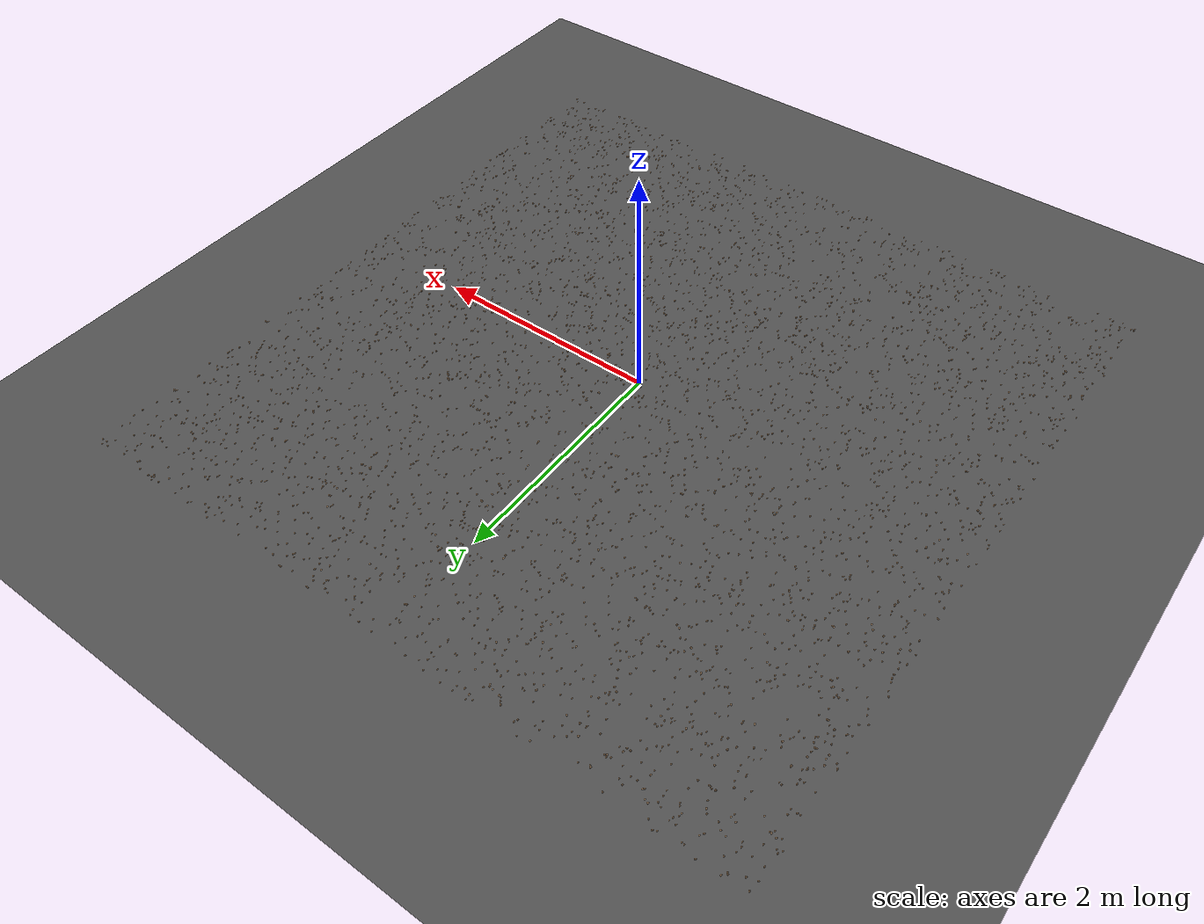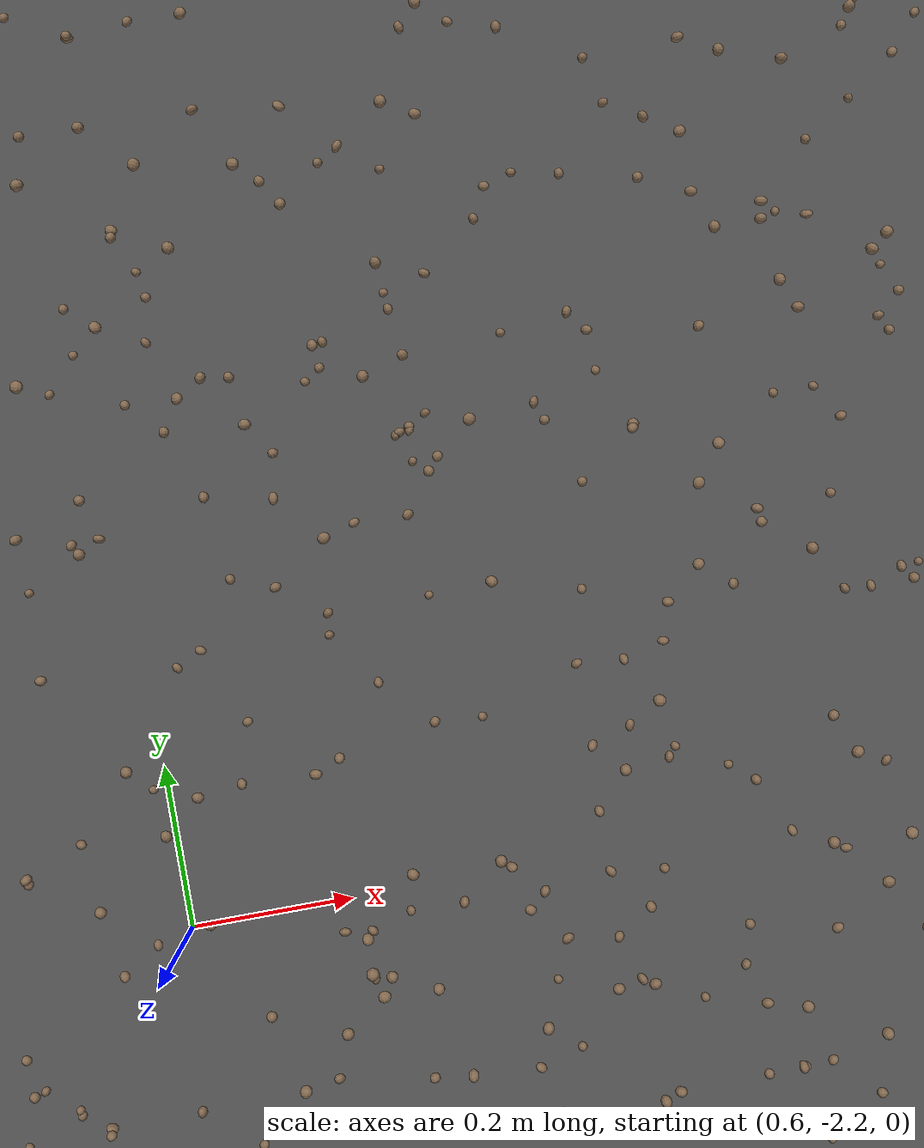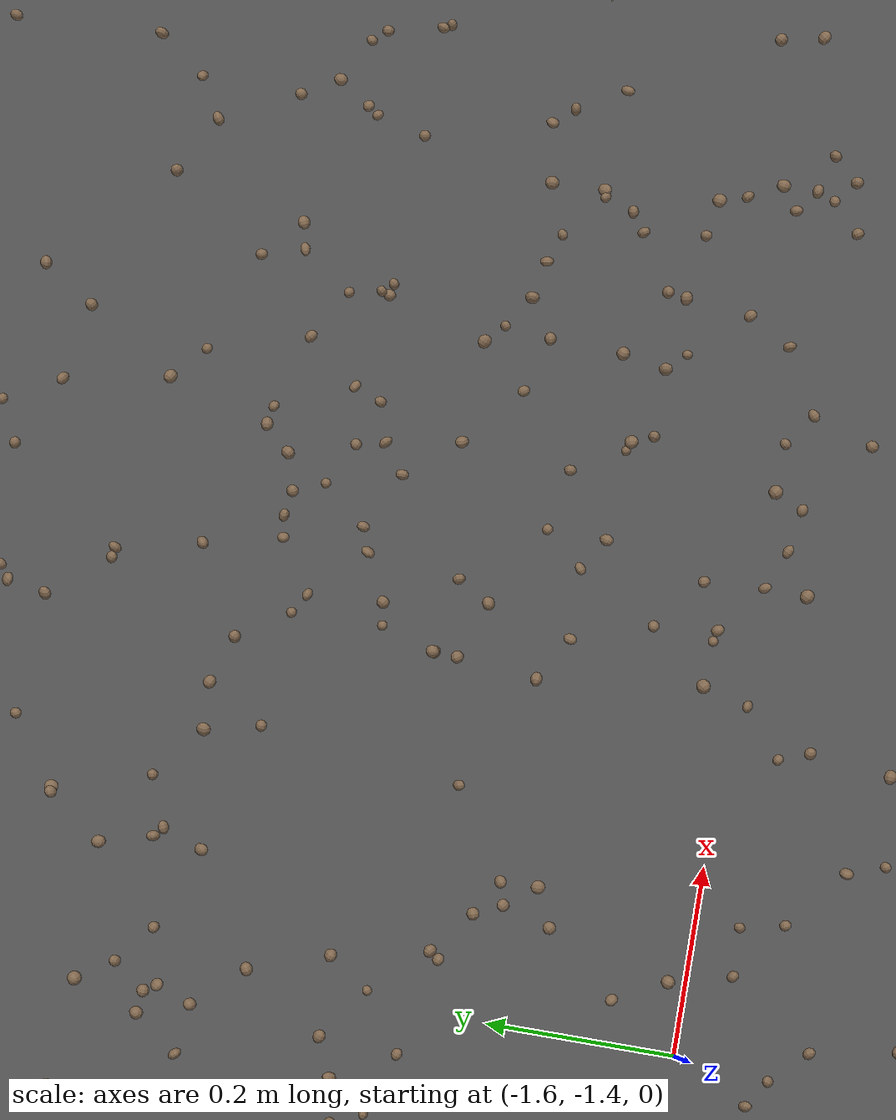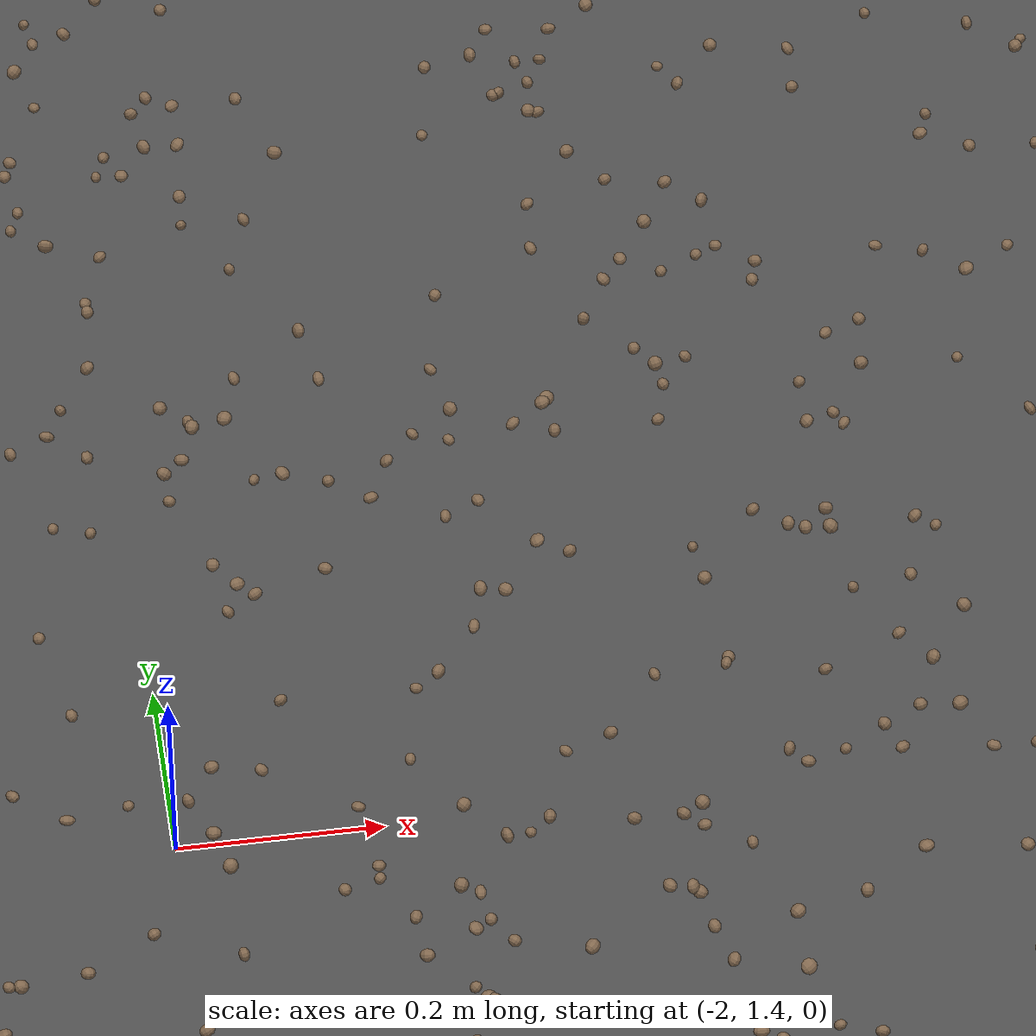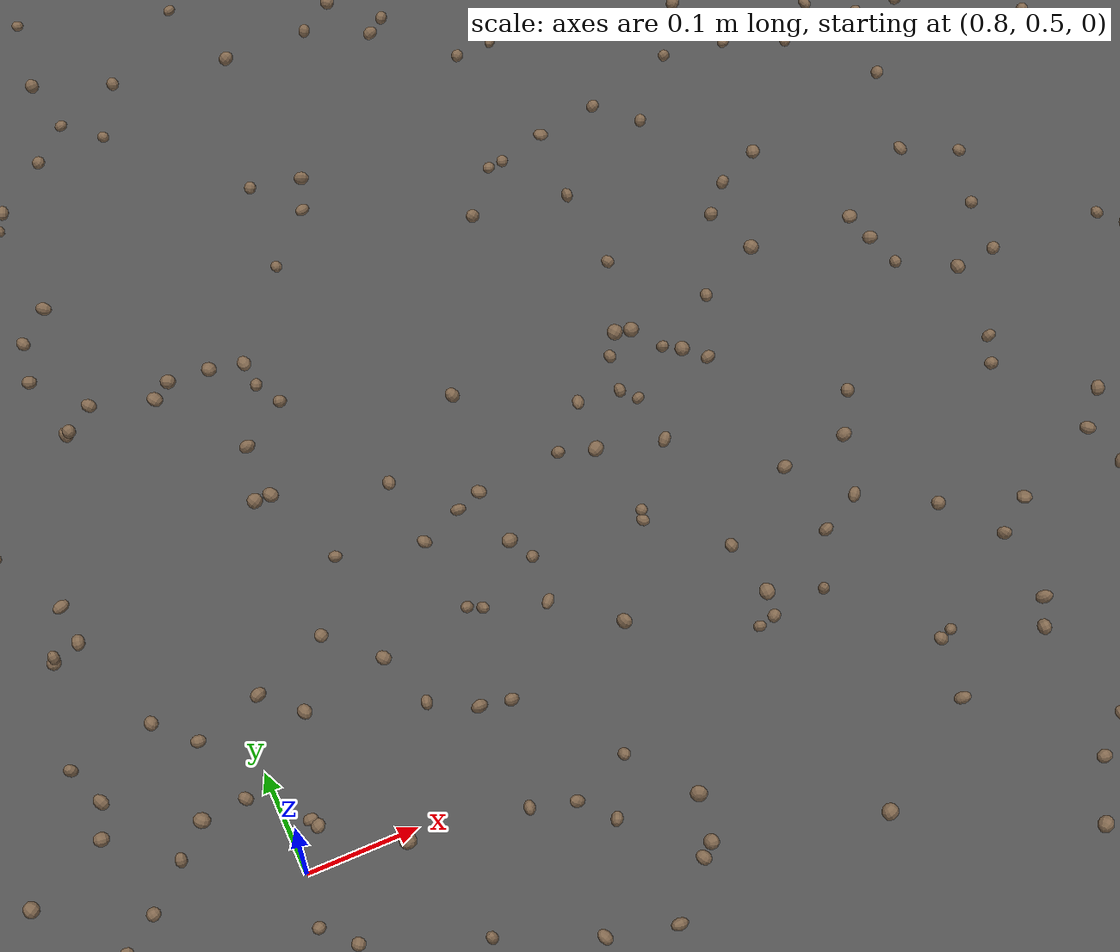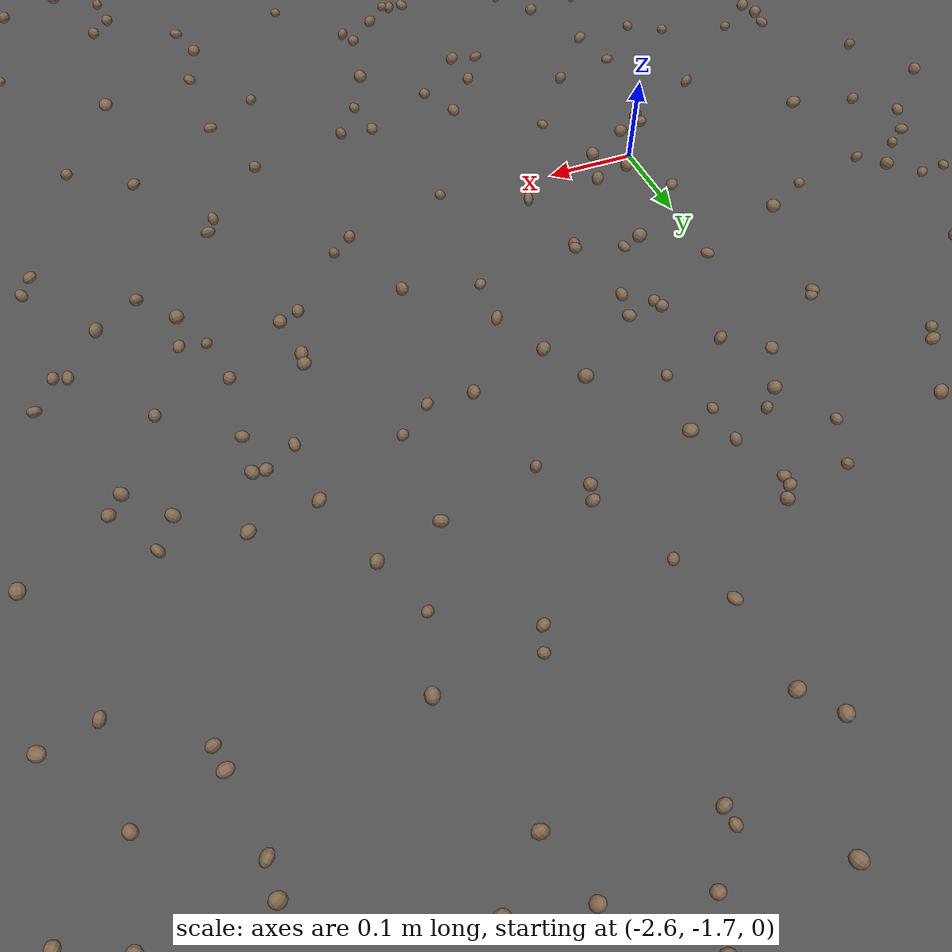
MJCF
<mujoco model="rocky_terrain_scene">
    <compiler angle="radian" inertiafromgeom="true" />
    <option timestep="0.002" gravity="0 0 -9.81" />

    <worldbody>

        <light cutoff="100" diffuse="1 1 1" dir="-0 0 -1.3" directional="true" exponent="1" pos="0 0 1.3" specular=".1 .1 .1" />

        <geom name="ground_plane" type="plane" size="10 10 0.1" rgba="0.3 0.3 0.3 1" />

        <body name="rocky_terrain_body">

        <geom name="rock1" type="ellipsoid" size="0.005770077353987659 0.005158273029248488 0.005251838776154461" pos="2.1779698968801613 2.612717543608481 0.019001871237423033" quat="0.010116616318600816 0.2812040171440907 0.3908977227511096 0.3177816437861989" rgba="0.5 0.4 0.3 1" friction="0.8997651583062238 0.8741049133346221 0.9441123863872315" /><geom name="rock2" type="ellipsoid" size="0.005711310781907685 0.005307748817452839 0.006392705292092085" pos="0.40479739888467314 -0.10295621140834532 0.01592097855398466" quat="0.3562769557107064 0.18579524891697943 0.07059701961061855 0.38733077576169567" rgba="0.5 0.4 0.3 1" friction="0.8807360609717461 0.9699426347191815 0.9317586366442004" /><geom name="rock3" type="ellipsoid" size="0.006192984501739816 0.005561899879787176 0.006220775395106688" pos="1.105240600218548 0.24709002581819917 0.010399515702154985" quat="0.10616938931520663 0.37520533319714106 0.3735317879205839 0.14509348956706836" rgba="0.5 0.4 0.3 1" friction="0.8298462900202466 0.9128425388560821 0.823672821841506" /><geom name="rock4" type="ellipsoid" size="0.0078004838702287835 0.007268407545666396 0.006230865575360749" pos="1.4440845387163534 -1.546871903409853 0.010052267010132824" quat="0.1522709804126735 0.3197699426752472 0.39051535673430343 0.1374437201777758" rgba="0.5 0.4 0.3 1" friction="0.764983733859824 0.8985689913557269 0.8267372053654715" /><geom name="rock5" type="ellipsoid" size="0.0062431966772640325 0.007977828902139016 0.005968382929275961" pos="-0.9538030516706266 -1.2738922775089063 0.01070792445607281" quat="0.24565343700393327 0.2540992986003774 0.26832157598644446 0.2319256884092449" rgba="0.5 0.4 0.3 1" friction="0.8275418861637555 0.9577125391552574 0.9247379234715744" /><geom name="rock6" type="ellipsoid" size="0.007918903019431352 0.005825026142557566 0.0071429952451126325" pos="-1.2110489929912318 -2.2793045011011 0.011465374137389503" quat="0.38061083957815467 0.15202060073597526 0.18462338323743632 0.2827451764484338" rgba="0.5 0.4 0.3 1" friction="0.8961216417094411 0.8763856111004673 0.8711219312751648" /><geom name="rock7" type="ellipsoid" size="0.006795346619601486 0.006223598735745309 0.006648792187861642" pos="1.2749730053393105 -0.12034827425946037 0.015548238720741603" quat="0.03779486971336555 0.3954676606907785 0.1888339410329319 0.37790352856292414" rgba="0.5 0.4 0.3 1" friction="0.8973168409412393 0.8592752267145547 0.8676061305187974" /><geom name="rock8" type="ellipsoid" size="0.007139345479014601 0.005116030561700276 0.0063377281880319155" pos="0.012254230550010625 2.492132133163129 0.01979016617759656" quat="0.3719915163069624 0.3240790738796042 0.02307947578456372 0.2808499340288697" rgba="0.5 0.4 0.3 1" friction="0.8848427730340733 0.9199628899893209 0.8845104544191672" /><geom name="rock9" type="ellipsoid" size="0.005338749286681748 0.00639564402477504 0.005835378794686071" pos="2.033557306323253 -1.3278464531909602 0.018917619736809332" quat="0.2633819455181119 0.23145571485562544 0.2526301962459143 0.2525321433803483" rgba="0.5 0.4 0.3 1" friction="0.8298426011376089 0.992792901477449 0.8588725281217379" /><geom name="rock10" type="ellipsoid" size="0.0052617803460920645 0.005669507213415044 0.0057301250769605854" pos="-1.0693094311186455 -0.08482151742409005 0.01301248294367997" quat="0.2231626680805761 0.27087858226743416 0.06513880995212531 0.4408199396998643" rgba="0.5 0.4 0.3 1" friction="0.7596201593809415 0.9047042284432977 0.8450500527515216" /><geom name="rock11" type="ellipsoid" size="0.006545471950650007 0.00797529205675976 0.005376393050190868" pos="2.2018298717489735 -0.959915144399416 0.017407488838907168" quat="0.3913878396321289 0.3195605611553658 0.14434672275372645 0.14470487645877894" rgba="0.5 0.4 0.3 1" friction="0.810898689147185 0.9802476768875474 0.9118058029499841" /><geom name="rock12" type="ellipsoid" size="0.007297041064736932 0.007071109158557715 0.006633968907827712" pos="-0.031949836684919575 -0.6458856785412266 0.01954899964307765" quat="0.10502054742202467 0.32447366178954923 0.16105997036163927 0.4094458204267868" rgba="0.5 0.4 0.3 1" friction="0.7708868742009473 0.9390880551869034 0.8560945383019734" /><geom name="rock13" type="ellipsoid" size="0.006054990920231956 0.007009078585558 0.0071149619721281605" pos="0.7737155434387235 -1.8077333943951965 0.008683522760070906" quat="0.24475002682355843 0.21457032677425072 0.33593339622665325 0.20474625017553752" rgba="0.5 0.4 0.3 1" friction="0.8683392939779079 0.8739438988915582 0.8169788941531262" /><geom name="rock14" type="ellipsoid" size="0.007465008678000156 0.007695572907039814 0.006879437178328698" pos="0.5556624998970534 -1.9973430156886676 0.011648171419339551" quat="0.099123319925088 0.33184404428117964 0.3826636755082942 0.18636896028543815" rgba="0.5 0.4 0.3 1" friction="0.7732118546806291 0.9857021346360476 0.8539277095801664" /><geom name="rock15" type="ellipsoid" size="0.0063889194885735755 0.006600118154485971 0.006221063512945348" pos="1.7978147731237044 -2.025570963395857 0.019726833599864727" quat="0.23076730565499923 0.3681384622743587 0.026698242110817963 0.37439598995982415" rgba="0.5 0.4 0.3 1" friction="0.7711981834207448 0.902220483286503 0.8880272812126108" /><geom name="rock16" type="ellipsoid" size="0.006887180867373438 0.006473940408502352 0.007776845269682654" pos="0.9052677562444584 0.2731859993461878 0.00842311101999266" quat="0.15440748363737616 0.25799402856327536 0.27038294285516573 0.31721554494418275" rgba="0.5 0.4 0.3 1" friction="0.8809316768244545 0.9731015315954489 0.8211743570774768" /><geom name="rock17" type="ellipsoid" size="0.007577852041591098 0.005472440422651294 0.006671753632010955" pos="-1.6654403689748367 0.3477140446573719 0.009281425229803917" quat="0.08099566091273401 0.5242901741148974 0.2611336383597125 0.13358052661265601" rgba="0.5 0.4 0.3 1" friction="0.8232065603451472 0.8977015538945063 0.9163588366676335" /><geom name="rock18" type="ellipsoid" size="0.006640428771181436 0.005167664752656395 0.007930331955424506" pos="-2.862984369229468 -0.2722220775978199 0.018039717939637483" quat="0.4545732074055047 0.1512613733159876 0.3191533611360398 0.07501205814246799" rgba="0.5 0.4 0.3 1" friction="0.7987253041861947 0.8735449032725402 0.8269909105680253" /><geom name="rock19" type="ellipsoid" size="0.006311102513735267 0.007270074404386052 0.006429537450219713" pos="-1.5622412769170222 2.374160089918287 0.0180195438482685" quat="0.2856629137779493 0.30059013112885846 0.09031955271639122 0.323427402376801" rgba="0.5 0.4 0.3 1" friction="0.8479555404239485 0.9414714794998545 0.8685523405337315" /><geom name="rock20" type="ellipsoid" size="0.006913603643709855 0.007248636849362947 0.005159522877202454" pos="2.969300932071178 -0.12567167319226602 0.00884331248190552" quat="0.20288869097855436 0.24789496777520276 0.2903961262344834 0.2588202150117595" rgba="0.5 0.4 0.3 1" friction="0.7577134937944984 0.9742038479870745 0.8032730291545378" /><geom name="rock21" type="ellipsoid" size="0.007613567330559883 0.007886849537502912 0.005637626035348432" pos="-1.5780439747985333 2.437215921984502 0.019421429095066826" quat="0.02115148795425139 0.470560748814278 0.15781286724399377 0.3504748959874768" rgba="0.5 0.4 0.3 1" friction="0.8594554540591928 0.9614087765925984 0.8108697230626266" /><geom name="rock22" type="ellipsoid" size="0.00677600446248477 0.007768569921666092 0.006917846856569018" pos="-0.5692129130742085 2.5107101385402055 0.017009069838933834" quat="0.2981391227021524 0.29468856464360765 0.317362914353928 0.08980939830031213" rgba="0.5 0.4 0.3 1" friction="0.8273261877901907 0.923531769980729 0.8855536480578692" /><geom name="rock23" type="ellipsoid" size="0.005941317052717583 0.005286338143293384 0.006257879132882686" pos="1.1317818613678536 2.026285617532297 0.010826489547603202" quat="0.4374749529861326 0.13761557194865487 0.18045812545398923 0.2444513496112232" rgba="0.5 0.4 0.3 1" friction="0.7775085906359754 0.9590305694604621 0.8193132072208189" /><geom name="rock24" type="ellipsoid" size="0.007247842378819388 0.006892011835205769 0.0053372890923900915" pos="-2.8761068087755284 2.6797620896040097 0.018590886517422366" quat="0.2346066364101314 0.32327343572627487 0.06894206259479939 0.3731778652687943" rgba="0.5 0.4 0.3 1" friction="0.818939686616018 0.986124792688041 0.8993181959213803" /><geom name="rock25" type="ellipsoid" size="0.005312619300710277 0.006920818456607521 0.006488891736522433" pos="-1.0496629144629477 0.8253319929268637 0.012107098475828151" quat="0.3350678513115272 0.2134598918730845 0.37898882095062253 0.0724834358647657" rgba="0.5 0.4 0.3 1" friction="0.7833735292856328 0.8659544756486857 0.8059529807950281" /><geom name="rock26" type="ellipsoid" size="0.005601623599515512 0.006868023138889751 0.007149162499099908" pos="0.7639338532878845 -2.9179338518134337 0.01910387328570375" quat="0.36593879465987506 0.36486890404536637 0.06042163404150188 0.2087706672532566" rgba="0.5 0.4 0.3 1" friction="0.7744547751902541 0.8638371321304236 0.8299391293797165" /><geom name="rock27" type="ellipsoid" size="0.006333544919757518 0.0050214123211631476 0.005611402855105799" pos="1.7705859911893125 -2.2098296259612247 0.01466795870706289" quat="0.4148658030751133 0.4257180491722582 0.03860826490138947 0.12080788285123908" rgba="0.5 0.4 0.3 1" friction="0.8022964279369834 0.8722761461131808 0.9278844894424142" /><geom name="rock28" type="ellipsoid" size="0.007244301743416982 0.005872443892039706 0.006689670961149774" pos="0.47437777893977096 0.3832555914218929 0.013836886227449975" quat="0.3689322369358843 0.2080243867733592 0.21956363514968252 0.20347974114107395" rgba="0.5 0.4 0.3 1" friction="0.7504160259798379 0.9213350855072486 0.8738066677188381" /><geom name="rock29" type="ellipsoid" size="0.006505900184906436 0.005039879887155422 0.00673089418114989" pos="0.7895393434506657 -2.5441434354041723 0.013629420756614583" quat="0.2491539232335772 0.1794265410879457 0.362475137580407 0.20894439809807022" rgba="0.5 0.4 0.3 1" friction="0.8903119014762794 0.8647117197231277 0.938049175981466" /><geom name="rock30" type="ellipsoid" size="0.00723774188174317 0.006747739962567191 0.0077399852201261365" pos="0.7726403440711556 -1.6065419148707492 0.017219134863146017" quat="0.08668604767689415 0.3592186101692843 0.05797443216761501 0.49612090998620645" rgba="0.5 0.4 0.3 1" friction="0.7799142657765094 0.8530759545870964 0.8605223508371556" /><geom name="rock31" type="ellipsoid" size="0.006195850267403368 0.006512844880142914 0.006718052218026146" pos="-0.6150287625121296 -0.32989285444508587 0.009403963569881935" quat="0.011838038856673064 0.613276859614156 0.18003778829600764 0.1948473132331634" rgba="0.5 0.4 0.3 1" friction="0.8272612525977513 0.9491775288695858 0.801885945864587" /><geom name="rock32" type="ellipsoid" size="0.006832052392866809 0.006061744656060996 0.006312289947761331" pos="0.7263625307097734 0.6764230004887661 0.015692099836419886" quat="0.35752363932793135 0.11102638228751671 0.1345996522803973 0.39685032610415477" rgba="0.5 0.4 0.3 1" friction="0.7771102332432005 0.860946663634608 0.809797685809719" /><geom name="rock33" type="ellipsoid" size="0.006179781148757324 0.007230631572164456 0.005502131899059476" pos="-0.04643334670921284 -0.9072513074431559 0.013771743679305688" quat="0.21180555263275877 0.12578221840713014 0.6324014249143378 0.03001080404577325" rgba="0.5 0.4 0.3 1" friction="0.7808324147446801 0.8668333903883187 0.9388442703117826" /><geom name="rock34" type="ellipsoid" size="0.005202724619577936 0.0068927715858767 0.006845133417410776" pos="-1.2234456144685175 -1.0811341907292573 0.009825426984287044" quat="0.3135024026624704 0.2850185460567667 0.3363260499232008 0.0651530013575622" rgba="0.5 0.4 0.3 1" friction="0.7516881779345693 0.863954744953038 0.8201823312205007" /><geom name="rock35" type="ellipsoid" size="0.006994878310485704 0.005440006778851137 0.006229480162019329" pos="-2.0675721079238265 -0.36535170204013756 0.011352668257415719" quat="0.17398274622659138 0.4803994535359669 0.22438709800180695 0.12123070223563492" rgba="0.5 0.4 0.3 1" friction="0.8113721112095199 0.924268879632704 0.8227800452129181" /><geom name="rock36" type="ellipsoid" size="0.005504177228774968 0.006597287972087442 0.006722782948322136" pos="-0.4816110734863921 -0.8729001986562799 0.016759151940480905" quat="0.38027232043548015 0.29754426906931114 0.11098261817527554 0.21120079231993316" rgba="0.5 0.4 0.3 1" friction="0.8837391740354488 0.9606657773340954 0.823161769549133" /><geom name="rock37" type="ellipsoid" size="0.00799203051913165 0.00615544608236491 0.007642088413154778" pos="-1.3958370107421252 0.8721162148256676 0.019515942645915087" quat="0.03948568665816734 0.3941640289516595 0.3835039651352202 0.18284631925495298" rgba="0.5 0.4 0.3 1" friction="0.77688089980422 0.9875762166000865 0.9352722885602132" /><geom name="rock38" type="ellipsoid" size="0.006542164454092283 0.0050288692744110755 0.006586523777320634" pos="-1.662348134228583 -1.6270885022579735 0.011043757824816475" quat="0.34370184134818815 0.1841330459203389 0.3143977471886484 0.15776736554282458" rgba="0.5 0.4 0.3 1" friction="0.88337177074049 0.9925988151112923 0.819619212355964" /><geom name="rock39" type="ellipsoid" size="0.006358587683308969 0.006826959565087651 0.005403493848706926" pos="-2.236647283640915 2.0912020252275934 0.01560250287083588" quat="0.49507637708718194 0.024450914157089998 0.4249167438483053 0.055555964907422775" rgba="0.5 0.4 0.3 1" friction="0.7689812361350035 0.9491439157197046 0.8493978098643677" /><geom name="rock40" type="ellipsoid" size="0.00711583928490561 0.00623830631971409 0.007218840205890203" pos="2.626349863944643 -1.5636516423473974 0.010585758568830024" quat="0.07687457110486715 0.28279714109860526 0.43392353339375295 0.2064047544027745" rgba="0.5 0.4 0.3 1" friction="0.8448082645662026 0.8670852753238203 0.8645912940522905" /><geom name="rock41" type="ellipsoid" size="0.005753769831389961 0.006208842164758251 0.005504154441101438" pos="1.1333064091465923 -2.8683791267381022 0.01105697844887938" quat="0.29896508113887793 0.29206015916075556 0.016129511875039623 0.39284524782532687" rgba="0.5 0.4 0.3 1" friction="0.8986879060159351 0.9819314925067808 0.9203932090933179" /><geom name="rock42" type="ellipsoid" size="0.0067843486967674215 0.007838682398284846 0.007091529528094151" pos="2.3339048726155083 -2.51992107910658 0.011081291651918714" quat="0.23213251337983648 0.3997017601648659 0.21434831040576707 0.1538174160495306" rgba="0.5 0.4 0.3 1" friction="0.8624175299615164 0.9288290041903573 0.8223421501402984" /><geom name="rock43" type="ellipsoid" size="0.007309567564576238 0.006066247871188908 0.007794801336620152" pos="2.566195552003405 1.090750531024339 0.01965837031054235" quat="0.37421628165075893 0.2676954318024097 0.26223219742872406 0.09585608911810717" rgba="0.5 0.4 0.3 1" friction="0.845764089716974 0.8559391501592726 0.8631012734575205" /><geom name="rock44" type="ellipsoid" size="0.006748767883517654 0.006756321986722362 0.005169370313801087" pos="-0.28514007147100884 2.438446872831051 0.014218584077414012" quat="0.2775180957087862 0.037616531156513484 0.2845598825767849 0.40030549055791553" rgba="0.5 0.4 0.3 1" friction="0.8918795270406012 0.8897103989156506 0.8840603634393659" /><geom name="rock45" type="ellipsoid" size="0.007584573236870785 0.005005059248175039 0.007684508083635042" pos="-1.1735538028836776 0.8210387512996009 0.01431933623294725" quat="0.0692285658825443 0.1737793340867634 0.2324176019786394 0.5245744980520529" rgba="0.5 0.4 0.3 1" friction="0.8168041344826306 0.8994113487935465 0.9321858833968637" /><geom name="rock46" type="ellipsoid" size="0.00792353454321764 0.0077946561812966 0.005312306907760971" pos="-0.527850671502379 -1.9071484683846003 0.014212233311025921" quat="0.06243634315272804 0.49856496560988045 0.10462561896506846 0.3343730722723231" rgba="0.5 0.4 0.3 1" friction="0.8861309404835791 0.9959337667524552 0.8157460750123761" /><geom name="rock47" type="ellipsoid" size="0.005667715335400003 0.005643953446380717 0.006809930634934525" pos="-1.0545175401641862 -2.2642478706380142 0.01674915093512583" quat="0.0801386456222111 0.3631528494082564 0.29945601979872477 0.2572524851708078" rgba="0.5 0.4 0.3 1" friction="0.7734245862388525 0.9510487969375733 0.8853791526478698" /><geom name="rock48" type="ellipsoid" size="0.007670828438049395 0.006999284113792021 0.0051066812689539035" pos="-2.7660848863196996 2.73665163438438 0.009866787318350277" quat="0.30452837566396684 0.2134286670143436 0.26342512403869167 0.21861783328299791" rgba="0.5 0.4 0.3 1" friction="0.7751688878661549 0.9743579291591379 0.8313151291030976" /><geom name="rock49" type="ellipsoid" size="0.005450282306073308 0.007012186277427744 0.00793874827621353" pos="-1.165150536764085 2.748584935271097 0.01042187009898056" quat="0.3649654967108155 0.42537358800480435 0.18791584182989585 0.021745073454484277" rgba="0.5 0.4 0.3 1" friction="0.7684540563928399 0.9962935830810918 0.9182059756138404" /><geom name="rock50" type="ellipsoid" size="0.005944675925852683 0.007970108722064523 0.005059066653073562" pos="-0.6424287003304316 -0.7235486216013145 0.01932381368400337" quat="0.3873680116075595 0.17496627958637945 0.14047518932025843 0.29719051948580255" rgba="0.5 0.4 0.3 1" friction="0.864927317527344 0.9505325301724287 0.876946931487019" /><geom name="rock51" type="ellipsoid" size="0.007944168383551288 0.005489663829806793 0.006237874109539704" pos="0.3041647930020046 -1.1365622818353545 0.01722523972418282" quat="0.20673931508560545 0.19891211489366967 0.2790121645427795 0.3153364054779453" rgba="0.5 0.4 0.3 1" friction="0.8079356174458376 0.8967019652139301 0.9166707536070715" /><geom name="rock52" type="ellipsoid" size="0.005781357893118259 0.007025173488179417 0.006779598123965306" pos="1.8644035647119708 1.3792332616203709 0.015754354500268596" quat="0.23981343002320665 0.10045965638795044 0.0510204946577954 0.6087064189310474" rgba="0.5 0.4 0.3 1" friction="0.7591973838551717 0.8956836963790965 0.884268451302122" /><geom name="rock53" type="ellipsoid" size="0.005091242676388063 0.007853721554414614 0.006438384175402509" pos="-2.959211982637147 2.961786961710642 0.015501111899593495" quat="0.0044334366441381775 0.7060448791163246 0.14087027427653073 0.14865140996300658" rgba="0.5 0.4 0.3 1" friction="0.874645819899528 0.8926427560818055 0.8599786670918255" /><geom name="rock54" type="ellipsoid" size="0.005610099769120592 0.006296497783542409 0.005047818589860224" pos="-2.5079578440588377 1.6101724138734888 0.017339109425851266" quat="0.19400007151552343 0.4768006769744985 0.02273297079784705 0.30646628071213117" rgba="0.5 0.4 0.3 1" friction="0.7541123464288185 0.9948531270388877 0.896780450243025" /><geom name="rock55" type="ellipsoid" size="0.005442719113246421 0.005237682350830142 0.007615239768964406" pos="1.2405212585161234 2.218599892075898 0.009530138004649883" quat="0.26509742689722043 0.10450630899778778 0.31362838784769625 0.3167678762572956" rgba="0.5 0.4 0.3 1" friction="0.8756731236228348 0.9875479819264494 0.8241317223984477" /><geom name="rock56" type="ellipsoid" size="0.007472405757859248 0.005163761096163207 0.005695295522977311" pos="0.25931808665807266 -2.884880960772775 0.011190103446184287" quat="0.085384470477567 0.11905443422851783 0.25702603999770607 0.538535055296209" rgba="0.5 0.4 0.3 1" friction="0.8247817174132706 0.9031083307342817 0.811779559585038" /><geom name="rock57" type="ellipsoid" size="0.007657920472449538 0.005775108938278613 0.007769885663602101" pos="0.6797388586808593 -0.30256530291394856 0.013572117665600562" quat="0.29964583499070785 0.13779272921979402 0.24981153735309447 0.3127498984364037" rgba="0.5 0.4 0.3 1" friction="0.8710000710076 0.9233611743802965 0.9267856063138258" /><geom name="rock58" type="ellipsoid" size="0.005630340177750801 0.005905254762321826 0.0067191232892049695" pos="-0.3889835297863362 -1.6836736424732333 0.019740206440363565" quat="0.2109682576609696 0.1907699250309765 0.33704770198245265 0.26121411532560124" rgba="0.5 0.4 0.3 1" friction="0.8813877897956209 0.8724637035469384 0.8316427572613855" /><geom name="rock59" type="ellipsoid" size="0.006746407787094494 0.006658694582047835 0.006295201758428386" pos="0.689569326685533 2.1192527511374024 0.008674228408098977" quat="0.11700658222118773 0.25453003109673245 0.30984765888759874 0.3186157277944812" rgba="0.5 0.4 0.3 1" friction="0.8931856416678441 0.9361347970375734 0.8701217486340864" /><geom name="rock60" type="ellipsoid" size="0.006375146427433829 0.00515810216127524 0.007868561699229639" pos="-1.8100805875419108 2.7635513916885586 0.012576627663449164" quat="0.24196522291059872 0.06720462364943333 0.29302476000312394 0.39780539343684396" rgba="0.5 0.4 0.3 1" friction="0.7820026321164275 0.8831721165884283 0.910106169071713" /><geom name="rock61" type="ellipsoid" size="0.006363290490132617 0.005143608309397587 0.006689803328582837" pos="0.21478436978942472 -2.719781074576235 0.012296153896835822" quat="0.3262923594560758 0.09983585192347193 0.30765947179242564 0.26621231682802665" rgba="0.5 0.4 0.3 1" friction="0.8967734174515911 0.8579046661975998 0.9432542355567339" /><geom name="rock62" type="ellipsoid" size="0.006051994203616372 0.006852911226769255 0.0062450449535188385" pos="1.7170105405273466 2.0008809204650957 0.014307772328923753" quat="0.21181500823004376 0.17271547692033826 0.17133064754882393 0.4441388673007941" rgba="0.5 0.4 0.3 1" friction="0.8063151781034794 0.936632414761959 0.8662603660691731" /><geom name="rock63" type="ellipsoid" size="0.005069746725043088 0.006570670837867964 0.0066156265666838495" pos="-0.30986340490404984 2.1479295271779977 0.019413602026347086" quat="0.03387130092541233 0.20910850819472143 0.6479173699869877 0.1091028208928786" rgba="0.5 0.4 0.3 1" friction="0.7942763705706938 0.9134065081408106 0.8709257982432791" /><geom name="rock64" type="ellipsoid" size="0.006365795050834342 0.005261256554655383 0.007881689222463685" pos="-2.0916831827771754 2.813786427069089 0.009240748135329248" quat="0.21080824790387806 0.13872977461498143 0.3754507445398178 0.2750112329413228" rgba="0.5 0.4 0.3 1" friction="0.8120296838593872 0.9828588585012914 0.9235800976339991" /><geom name="rock65" type="ellipsoid" size="0.005943786400687359 0.007505394161978944 0.007646625804653531" pos="1.444643909952032 -2.291233957650944 0.01353419361225095" quat="0.42082321681341256 0.10488897208085264 0.40499526796577223 0.06929254313996244" rgba="0.5 0.4 0.3 1" friction="0.8664974298164994 0.9343056555155991 0.9289688071380011" /><geom name="rock66" type="ellipsoid" size="0.0052394076922810135 0.006766993111295524 0.006973950546995502" pos="1.6241932063459608 -0.6741473855769122 0.009504723853644608" quat="0.23009506183877196 0.19965544384413392 0.2715321036381911 0.2987173906789029" rgba="0.5 0.4 0.3 1" friction="0.8468546657574709 0.8510538788850764 0.8740715947063945" /><geom name="rock67" type="ellipsoid" size="0.005839761384910506 0.005913535796113822 0.005872678895805533" pos="-1.0316038230260014 -0.5756807285067427 0.014903868273197835" quat="0.21792445491726756 0.35299102336696425 0.39810334083706755 0.030981180878700644" rgba="0.5 0.4 0.3 1" friction="0.8883075900467948 0.9020112892490575 0.8077051610019274" /><geom name="rock68" type="ellipsoid" size="0.006688242392729481 0.006421262437996603 0.0063541591989825855" pos="2.426708271834504 0.5416936965540913 0.015258651450788835" quat="0.12469140019215531 0.41442699633632596 0.18870314447532044 0.27217845899619825" rgba="0.5 0.4 0.3 1" friction="0.7564561235828006 0.8530398419448942 0.8042436030535354" /><geom name="rock69" type="ellipsoid" size="0.005595303336603313 0.007464130712303239 0.007887018708361285" pos="1.0490110904159256 -2.290824562572472 0.01078957935902457" quat="0.3156877963233413 0.04026568192918842 0.30945400547297913 0.33459251627449116" rgba="0.5 0.4 0.3 1" friction="0.8948261485208329 0.937533278398303 0.9060981909334144" /><geom name="rock70" type="ellipsoid" size="0.007935986037988412 0.005086575604705492 0.00565327183227639" pos="-0.5459247664126479 -1.6293650705832987 0.01999030357884035" quat="0.06854683617747133 0.34398036340519633 0.26373309321078503 0.32373970720654727" rgba="0.5 0.4 0.3 1" friction="0.8449679878478495 0.9696914643728355 0.9391438453198659" /><geom name="rock71" type="ellipsoid" size="0.005958785406203075 0.006679794835682031 0.006428865726009173" pos="1.4526601886984203 -0.3196750804132016 0.011528625802922599" quat="0.10697638686776892 0.19092331959914055 0.2882946904703632 0.4138056030627273" rgba="0.5 0.4 0.3 1" friction="0.8393386479937475 0.9813297287014612 0.9119421348415412" /><geom name="rock72" type="ellipsoid" size="0.005576990778824056 0.007664827863908612 0.00726687986720418" pos="-2.710588858486311 -0.665028185306213 0.01458624815025277" quat="0.1807665012010116 0.17312430284196725 0.13872237934526693 0.5073868166117541" rgba="0.5 0.4 0.3 1" friction="0.7899678418556657 0.9024013401157922 0.8482898951482164" /><geom name="rock73" type="ellipsoid" size="0.006676562080504588 0.006337419708668232 0.005359813389534668" pos="-1.4619136719014112 1.32104195007593 0.011829153804084029" quat="0.23807928170739756 0.2758395453220211 0.164573931573192 0.32150724139738934" rgba="0.5 0.4 0.3 1" friction="0.8885478191353944 0.8974323902247269 0.8880671851477007" /><geom name="rock74" type="ellipsoid" size="0.006561778416772507 0.007597659151027374 0.007719941439044108" pos="1.9455304800800217 1.8139312327338049 0.01693745916152011" quat="0.3066478348133916 0.24735525659282784 0.13229870050598128 0.3136982080877993" rgba="0.5 0.4 0.3 1" friction="0.8567847197691516 0.9448445691708133 0.8865040881355069" /><geom name="rock75" type="ellipsoid" size="0.00738901838754819 0.007976371806686281 0.007256305060878933" pos="-0.5000223586565529 1.5298244131934977 0.016169955817836378" quat="0.18348664540568785 0.300928549281439 0.2520557134341855 0.2635290918786876" rgba="0.5 0.4 0.3 1" friction="0.8019502372214907 0.9336743976853884 0.8076346252049761" /><geom name="rock76" type="ellipsoid" size="0.005350450806719105 0.005362195943494381 0.0057664168212456434" pos="0.8541179015083946 -1.5684360665296766 0.018556101523458303" quat="0.2830775533832567 0.37064197511008096 0.11708897401222106 0.2291914974944411" rgba="0.5 0.4 0.3 1" friction="0.8179357184003938 0.9560671339144468 0.8771471403820696" /><geom name="rock77" type="ellipsoid" size="0.005622174298918205 0.005926154889151443 0.006063100704560002" pos="-0.8534905250114821 -0.9231167427095048 0.015272891503402528" quat="0.20482223151004725 0.48888980222604883 0.18032645136527914 0.1259615148986248" rgba="0.5 0.4 0.3 1" friction="0.8982076337621734 0.9253154834202059 0.8776672062260118" /><geom name="rock78" type="ellipsoid" size="0.00797261618344445 0.0073479699632981055 0.007334418921616636" pos="1.7883596782740092 1.888185169785146 0.017461138250639302" quat="0.3966063372554349 0.4439070925614134 0.1299276586545592 0.02955891152859255" rgba="0.5 0.4 0.3 1" friction="0.846480502181585 0.9448495084101525 0.918178554265693" /><geom name="rock79" type="ellipsoid" size="0.005397952183757152 0.005563113856120808 0.006015094439138878" pos="2.4602336617458658 2.364805693310168 0.018193595357205807" quat="0.26867095733934476 0.001258667095166757 0.21062722265084807 0.5194431529146405" rgba="0.5 0.4 0.3 1" friction="0.8716395823655471 0.8909556735179345 0.9375546600599085" /><geom name="rock80" type="ellipsoid" size="0.005993212872286333 0.00663093451300063 0.00780931893265727" pos="-0.3111523835395684 -1.2536699946596521 0.01084837912040225" quat="0.0007736550054586801 0.4604455170289625 0.0398179411756111 0.4989628867899678" rgba="0.5 0.4 0.3 1" friction="0.7637931093859766 0.9230953076971099 0.8394720029356744" /><geom name="rock81" type="ellipsoid" size="0.0064686947019527655 0.0056037857810777615 0.006982332584694332" pos="2.764901590084208 0.7338237265853627 0.01039655526397702" quat="0.1469027395815525 0.3622121663119699 0.3964037641784425 0.09448132992803514" rgba="0.5 0.4 0.3 1" friction="0.848245773016224 0.9437655507080946 0.8161306085034954" /><geom name="rock82" type="ellipsoid" size="0.006161036582011928 0.007502384989475534 0.006674755887342241" pos="-0.17440751993730785 -1.2179491632323203 0.009365562747525138" quat="0.6028307612992644 0.014801243763261659 0.041524054945682565 0.34084393999179147" rgba="0.5 0.4 0.3 1" friction="0.7626471507110808 0.8817359097239421 0.8658086016758118" /><geom name="rock83" type="ellipsoid" size="0.0069220356128835495 0.0058971751754053866 0.006495617252625304" pos="-2.212352785875037 0.27610877155653935 0.00956174602113561" quat="0.4388492151210475 0.04363440402834338 0.4488793917458722 0.0686369891047369" rgba="0.5 0.4 0.3 1" friction="0.8525247311096253 0.9034042861780403 0.9322505502384173" /><geom name="rock84" type="ellipsoid" size="0.007172266554827594 0.005584159248014453 0.006292723895268584" pos="2.840010131798568 -0.3070235087498805 0.017046663108192167" quat="0.39973700592789346 0.12712130705388128 0.14451146187633065 0.32863022514189466" rgba="0.5 0.4 0.3 1" friction="0.8125314664460098 0.9199675929809686 0.9008029443201889" /><geom name="rock85" type="ellipsoid" size="0.00664635216261111 0.007364646076093773 0.00704136589099066" pos="-2.1601698551981583 1.2417813773512743 0.011615737132813766" quat="0.4033299768891705 0.19105030654545901 0.04525211580385048 0.3603676007615201" rgba="0.5 0.4 0.3 1" friction="0.896213867844769 0.878220996204548 0.8417405100232638" /><geom name="rock86" type="ellipsoid" size="0.007388520059449066 0.007226054553478058 0.006549639405296991" pos="0.0568441068737906 -0.2060224851863719 0.008317235008565436" quat="0.26833338272638557 0.015437248708805806 0.36862876271619077 0.3476006058486179" rgba="0.5 0.4 0.3 1" friction="0.8591420481474462 0.8985633011492191 0.82457978849461" /><geom name="rock87" type="ellipsoid" size="0.007473253795194733 0.005491867061834089 0.005127238116117939" pos="-0.4125192576650383 -1.1588130134433445 0.010618937275239063" quat="0.015223137354775094 0.3162079523172004 0.31447645613086744 0.3540924541971571" rgba="0.5 0.4 0.3 1" friction="0.8619956712389751 0.8766697761039706 0.9054537032853782" /><geom name="rock88" type="ellipsoid" size="0.007077894001596056 0.005232327284401162 0.005465044460585759" pos="1.1811740810626175 -2.9803079080800163 0.016617227557121292" quat="0.27900536221341327 0.27123524054386233 0.10244462225105662 0.3473147749916678" rgba="0.5 0.4 0.3 1" friction="0.7904052374114988 0.8982547959957705 0.8278076978158353" /><geom name="rock89" type="ellipsoid" size="0.005602083657174535 0.007702150555967209 0.006535010018330664" pos="2.0474638105894503 -2.1826268659676993 0.013903614138010174" quat="0.37152076834982806 0.01730544986755362 0.28048892687310417 0.33068485490951405" rgba="0.5 0.4 0.3 1" friction="0.7964237466936233 0.946665630424732 0.9282209387863518" /><geom name="rock90" type="ellipsoid" size="0.006423211512975225 0.007264758953302567 0.005358208825672292" pos="0.8109502712184105 -0.24503879048534305 0.012500365805770037" quat="0.255022129531892 0.15885725602438114 0.12830742225324257 0.4578131921904842" rgba="0.5 0.4 0.3 1" friction="0.8141717512509457 0.8989560384662745 0.8600700329928472" /><geom name="rock91" type="ellipsoid" size="0.007340668052374475 0.006274924706874527 0.006348788848119305" pos="0.8504358940802157 0.6332670952029016 0.014333889125802125" quat="0.3651252108292675 0.05228434857322105 0.09853933774436109 0.4840511028531503" rgba="0.5 0.4 0.3 1" friction="0.7949953709582136 0.9845178235837077 0.84041627713716" /><geom name="rock92" type="ellipsoid" size="0.007527887259211202 0.006740036712467972 0.007588412597063034" pos="-2.112264456246413 -0.9514153452330634 0.011906372434077385" quat="0.19611851488042553 0.20349344447603485 0.302566754350968 0.2978212862925716" rgba="0.5 0.4 0.3 1" friction="0.8224704145211712 0.9162633617885121 0.9165346408367183" /><geom name="rock93" type="ellipsoid" size="0.007787563561209861 0.0077516151797733055 0.005233481509831531" pos="-2.0546901523714443 0.9491588700944753 0.0127461810248511" quat="0.3388850493276259 0.023577649653276432 0.4600553831575771 0.1774819178615206" rgba="0.5 0.4 0.3 1" friction="0.8735287311358974 0.9293370782987938 0.862954541908632" /><geom name="rock94" type="ellipsoid" size="0.005772713388722648 0.00664168002616048 0.005369890940032989" pos="-2.878250939767487 -1.5913250604878255 0.019694963605964712" quat="0.30033306965627626 0.35458036571688173 0.2203406862022685 0.1247458784245735" rgba="0.5 0.4 0.3 1" friction="0.7877666879465144 0.9691915889029071 0.8760715888447161" /><geom name="rock95" type="ellipsoid" size="0.007094546313810433 0.00608167033080101 0.007493886562465369" pos="-1.236420646930461 1.7162684784852615 0.01639917881405213" quat="0.43591942635893666 0.07710850875286579 0.20175114478940825 0.2852209200987892" rgba="0.5 0.4 0.3 1" friction="0.8015045335956408 0.9993261006942928 0.8999854130094919" /><geom name="rock96" type="ellipsoid" size="0.0076981085307693525 0.006957124072601576 0.005510127365076934" pos="2.369022697852998 0.28697313378698075 0.01144409979533871" quat="0.3411495938068243 0.3058339824429268 0.34950482740627187 0.003511596343977119" rgba="0.5 0.4 0.3 1" friction="0.895636747391256 0.9343953128247726 0.8077970734605028" /><geom name="rock97" type="ellipsoid" size="0.006889305724507808 0.0070132789312832705 0.005914120737084417" pos="-2.6270792321721057 2.073767400795089 0.008564601729176913" quat="0.17003528493948866 0.33190435164671694 0.3398313818513858 0.15822898156240867" rgba="0.5 0.4 0.3 1" friction="0.8008275432412787 0.9310357828578602 0.8170035171197962" /><geom name="rock98" type="ellipsoid" size="0.007771078413646753 0.007385021330885151 0.0077463273860385266" pos="1.5831370795431479 -1.5127345560378331 0.008882990453294855" quat="0.1507087686163255 0.6400183172809832 0.18225075020168524 0.027022163901006032" rgba="0.5 0.4 0.3 1" friction="0.8567602242165168 0.9819714090427165 0.9110127026952612" /><geom name="rock99" type="ellipsoid" size="0.007538178491743501 0.0050954338381029975 0.006135243070305466" pos="2.7307933800744513 -2.3642137342383114 0.01817515929494371" quat="0.31790068061626064 0.19742172341494524 0.12437369774318821 0.3603038982256058" rgba="0.5 0.4 0.3 1" friction="0.8230215535686495 0.8508943389410721 0.8921956689105002" /><geom name="rock100" type="ellipsoid" size="0.0050804601184966935 0.007854731977456236 0.007975751962522343" pos="-2.042799544648032 2.2184665364428824 0.014712350160412807" quat="0.24854204662997784 0.2920902156440647 0.24215971135953887 0.2172080263664186" rgba="0.5 0.4 0.3 1" friction="0.8540677798438514 0.8620057169929296 0.8711050265617045" /><geom name="rock101" type="ellipsoid" size="0.006176349214448325 0.0068548504233059155 0.0055014344636314895" pos="0.1890148784537522 2.5766639650220604 0.017054076665537078" quat="0.03720407686926029 0.606724320937324 0.3389918901940555 0.017079711999360273" rgba="0.5 0.4 0.3 1" friction="0.851880507318438 0.9969886895236165 0.8595439486531677" /><geom name="rock102" type="ellipsoid" size="0.007210827948342076 0.007817475467587308 0.006210538623957066" pos="-1.5270721449304494 0.8508076137081106 0.012813331072339389" quat="0.24793895270420585 0.18687820047846937 0.29683189810593685 0.2683509487113879" rgba="0.5 0.4 0.3 1" friction="0.8802437351738169 0.8758030182647133 0.9161712923751834" /><geom name="rock103" type="ellipsoid" size="0.0051565995210455075 0.007913861902639992 0.007459658844824869" pos="-0.0967982682177384 -1.7416106929528286 0.011871209670991666" quat="0.3906062718886912 0.09858899881481417 0.4227785211569274 0.08802620813956719" rgba="0.5 0.4 0.3 1" friction="0.7914233042919219 0.97458663494045 0.9419485426115978" /><geom name="rock104" type="ellipsoid" size="0.005350739342600838 0.0077508730626985505 0.005368400403220804" pos="0.6710488952178659 -0.9778839169523401 0.019671790699140344" quat="0.213569705838158 0.21897492896410192 0.31794297288675116 0.24951239231098882" rgba="0.5 0.4 0.3 1" friction="0.8708174204060143 0.8654880538368636 0.8311789168992022" /><geom name="rock105" type="ellipsoid" size="0.00526965740727583 0.005210415238757613 0.006911598755662929" pos="0.3231333510448935 -2.190894257529011 0.01851430372365604" quat="0.4035742429728568 0.1081448118729989 0.18744545542924607 0.3008354897248983" rgba="0.5 0.4 0.3 1" friction="0.8335885714906832 0.8553679105264191 0.8017028493051602" /><geom name="rock106" type="ellipsoid" size="0.0072213689060644775 0.007982201863545521 0.006990240322223548" pos="2.076527143994907 0.26075710224732784 0.011489990474960896" quat="0.5043637840257056 0.2848069312793128 0.19167770108621537 0.019151583608766214" rgba="0.5 0.4 0.3 1" friction="0.7692658886890062 0.9925314925040898 0.9108532791870897" /><geom name="rock107" type="ellipsoid" size="0.0053524938693450645 0.007251899232470364 0.006711521112159129" pos="0.8666096830745058 1.7187656411690826 0.014298335385957633" quat="0.31532419397304523 0.14428119316395852 0.22482329537192422 0.3155713174910719" rgba="0.5 0.4 0.3 1" friction="0.8234434796776704 0.9570506693120637 0.9039027551824023" /><geom name="rock108" type="ellipsoid" size="0.0052411795572304045 0.0052049390389512975 0.006958717269366983" pos="2.9526283360399557 -2.538077319257809 0.015333104918087738" quat="0.24213559979981175 0.2703575508077702 0.25450098090385714 0.233005868488561" rgba="0.5 0.4 0.3 1" friction="0.8751592093173788 0.9739441646079627 0.9410403132345295" /><geom name="rock109" type="ellipsoid" size="0.007864901789629319 0.006626606056309344 0.007616443742771029" pos="2.5261542212363466 2.0712574631893945 0.010684163469302727" quat="0.1226209636447389 0.27189887584170636 0.2651444563038026 0.3403357042097522" rgba="0.5 0.4 0.3 1" friction="0.8945124926814273 0.9191989835445132 0.8721060684366608" /><geom name="rock110" type="ellipsoid" size="0.005164002211651892 0.006289765595174376 0.005677487145794219" pos="-1.3691007080699464 -1.5863931976812535 0.019009382345615878" quat="0.09891081808336875 0.22434153378740823 0.15926120693512735 0.5174864411940957" rgba="0.5 0.4 0.3 1" friction="0.7888950061447474 0.9610644945588822 0.9192044313480803" /><geom name="rock111" type="ellipsoid" size="0.007605166999326847 0.006979160781611126 0.006387253470025727" pos="1.7462069488616692 -1.5272419211783017 0.010119566910331763" quat="0.2430494945704614 0.33462157416730876 0.26291618201773675 0.15941274924449308" rgba="0.5 0.4 0.3 1" friction="0.8027264735432503 0.8642078022230549 0.9153705458906517" /><geom name="rock112" type="ellipsoid" size="0.006343256762018117 0.006493408948051231 0.005735876731936041" pos="-1.660057282027595 -0.5808481405727219 0.019743307299583315" quat="0.2448728293498681 0.11008030139740786 0.537785739063073 0.10726113018965103" rgba="0.5 0.4 0.3 1" friction="0.8479359573622584 0.9034227935653717 0.881464533107273" /><geom name="rock113" type="ellipsoid" size="0.006812836979286252 0.006429118616256927 0.006290900174265167" pos="2.7881068638698334 0.10835273731954542 0.014723571281957363" quat="0.09565589033672259 0.37297075922082057 0.4315990900087893 0.09977426043366755" rgba="0.5 0.4 0.3 1" friction="0.8589158518163647 0.9666071389958115 0.9490369174779102" /><geom name="rock114" type="ellipsoid" size="0.00681990148966587 0.006251706992298065 0.005610051019816871" pos="-1.166183410294225 0.30463196948035964 0.013397805597874287" quat="0.2361508797995986 0.12429209009650538 0.2953898282005222 0.3441672019033739" rgba="0.5 0.4 0.3 1" friction="0.8008139983982882 0.9320270175456292 0.8293910937009848" /><geom name="rock115" type="ellipsoid" size="0.005875763027411717 0.00788783854060839 0.006933071965195708" pos="0.4412159661850579 -0.9484068820449014 0.011156898718495654" quat="0.1106551254195748 0.30979068187935693 0.24373319702558163 0.33582099567548657" rgba="0.5 0.4 0.3 1" friction="0.8072208530441317 0.8830938890161875 0.8778699576072306" /><geom name="rock116" type="ellipsoid" size="0.005945667476825385 0.006672180771869192 0.006141877052685874" pos="-0.5767553778206742 1.5903162064084393 0.011904688847955352" quat="0.23224664260701355 0.02543156605629701 0.4094432684046544 0.332878522932035" rgba="0.5 0.4 0.3 1" friction="0.8672409107998462 0.8723762734241526 0.9031800971230439" /><geom name="rock117" type="ellipsoid" size="0.007897464891755902 0.006784099727388989 0.006303863229992315" pos="-2.7123010465896 -0.9759297168838703 0.01363737068025829" quat="0.6830367934875683 0.23231688282913018 0.05021151280796839 0.0344348108753331" rgba="0.5 0.4 0.3 1" friction="0.8275941819354135 0.919331420579486 0.923618514408206" /><geom name="rock118" type="ellipsoid" size="0.0055417762501030424 0.005619755024442973 0.005810140866947116" pos="2.258852045126001 1.4859367414335685 0.019427855472674196" quat="0.18422340270109636 0.40015240218800024 0.14071752384981823 0.27490667126108514" rgba="0.5 0.4 0.3 1" friction="0.7500253190824767 0.9788511043631958 0.8671694268456394" /><geom name="rock119" type="ellipsoid" size="0.007663501216697989 0.006069570771431042 0.007392121039148627" pos="0.3520757052477972 -1.9374276922193487 0.008883299579068972" quat="0.42072969239753505 0.08795433546105556 0.12691462007588433 0.36440135206552504" rgba="0.5 0.4 0.3 1" friction="0.8476290525293357 0.8998583322892147 0.8520580146636489" /><geom name="rock120" type="ellipsoid" size="0.006729077492969654 0.006695927274929561 0.005967248433775483" pos="1.7613491692747374 -1.896970043814071 0.015488340973459665" quat="0.3712625048370002 0.3668919189698585 0.030081437888844313 0.23176413830429707" rgba="0.5 0.4 0.3 1" friction="0.8225619799533167 0.8814766668076552 0.8031815118951121" /><geom name="rock121" type="ellipsoid" size="0.007945992712413549 0.006463386116889401 0.005821346853952094" pos="-0.6873880873750755 -0.7491537990847874 0.019982055897030365" quat="0.392974422402043 0.3741585541986109 0.062465142988601924 0.17040188041074417" rgba="0.5 0.4 0.3 1" friction="0.8681182689504152 0.9421052047010089 0.9249451188757527" /><geom name="rock122" type="ellipsoid" size="0.005447316623163046 0.006640495541566531 0.007831884717148262" pos="2.5776228155161443 -0.24138668950652953 0.014409395601039704" quat="0.3650527691919402 0.1444334472588478 0.3612721700128179 0.12924161353639427" rgba="0.5 0.4 0.3 1" friction="0.8680471675652751 0.9983087663719424 0.824840903323367" /><geom name="rock123" type="ellipsoid" size="0.005733663470305424 0.007601284282471402 0.005173442896117752" pos="-1.9045935114561452 -2.7144350389449095 0.009484999755306235" quat="0.41346305672095957 0.470522491199286 0.039246326053091606 0.0767681260266628" rgba="0.5 0.4 0.3 1" friction="0.8343657444996417 0.8882783266505933 0.901341932600131" /><geom name="rock124" type="ellipsoid" size="0.006410262351078538 0.006733733032223149 0.0076010430708239925" pos="-0.9362329133427387 0.0405163844598011 0.018612183327793994" quat="0.3025817468401496 0.18553279456791077 0.24800393892733352 0.26388151966460616" rgba="0.5 0.4 0.3 1" friction="0.8393658175841783 0.978778047211989 0.8504347093389367" /><geom name="rock125" type="ellipsoid" size="0.006390978619655131 0.006546552390117209 0.005502902233475649" pos="-1.3486198128712044 -1.7853567215533788 0.016021479988886093" quat="0.009799185407014391 0.3326763680953886 0.33326962936414223 0.3242548171334548" rgba="0.5 0.4 0.3 1" friction="0.856211749173308 0.9736925858283312 0.8399127522976666" /><geom name="rock126" type="ellipsoid" size="0.007094882354585903 0.00525208160281732 0.005619626277481292" pos="2.0000105260121437 -1.7222376396828067 0.01604359393683743" quat="0.6329864436667542 0.35261342065259477 0.007701719001869997 0.006698416678781094" rgba="0.5 0.4 0.3 1" friction="0.7922587582669447 0.8959709003055187 0.8267232810443027" /><geom name="rock127" type="ellipsoid" size="0.007208182841484757 0.007033275124083652 0.005487176399201466" pos="-2.2698192169658884 -1.5691330182653755 0.018620586199340115" quat="0.2854387118734621 0.1204176858024905 0.2913919396145694 0.30275166270947795" rgba="0.5 0.4 0.3 1" friction="0.763995960796523 0.9241351923892276 0.8931843490980779" /><geom name="rock128" type="ellipsoid" size="0.00664088536829815 0.006930816191085184 0.005539718880778121" pos="1.9770253301803056 0.30789554969316635 0.010228715745807573" quat="0.2715229056277532 0.25058996328275523 0.10248548288272098 0.3754016482067705" rgba="0.5 0.4 0.3 1" friction="0.7685950718821767 0.8709507829273153 0.8636722137163152" /><geom name="rock129" type="ellipsoid" size="0.007209925416990063 0.006911387689327198 0.005935226960080964" pos="2.836496315210888 0.15441730004111198 0.019007988261358938" quat="0.3210032340222454 0.3726235158099238 0.12370349413336376 0.18266975603446703" rgba="0.5 0.4 0.3 1" friction="0.8668369855669097 0.9877344440594347 0.8882298954357996" /><geom name="rock130" type="ellipsoid" size="0.006504503360564986 0.005100685524398214 0.007157583959804273" pos="-0.900278172521177 -0.26311934550305693 0.018420129322553644" quat="0.18382461372373848 0.3324172831008074 0.2812078432084017 0.2025502599670524" rgba="0.5 0.4 0.3 1" friction="0.7700881986127603 0.9532416321433455 0.9213057259934991" /><geom name="rock131" type="ellipsoid" size="0.006893014317797734 0.006314335737676216 0.007123473220127432" pos="1.4712525097724525 -2.824741544827301 0.016971525622163225" quat="0.6832123125154211 0.1184492151003814 0.1059317866048696 0.09240668577932785" rgba="0.5 0.4 0.3 1" friction="0.855061277251393 0.9799800475156081 0.8634801727594215" /><geom name="rock132" type="ellipsoid" size="0.006072092440449003 0.006763630289683723 0.006237944846846589" pos="0.2264100265388369 0.4187151026676075 0.013137840095565529" quat="0.20834119444289276 0.10928426951406955 0.3727314154287297 0.309643120614308" rgba="0.5 0.4 0.3 1" friction="0.7909149376313275 0.973630974216242 0.8280340610259669" /><geom name="rock133" type="ellipsoid" size="0.0067983638133779405 0.007475636417609814 0.007171324090874291" pos="2.5588025288174707 1.1837999335553278 0.017680606415878704" quat="0.19025214944740046 0.39517307981216643 0.09235169241641804 0.322223078324015" rgba="0.5 0.4 0.3 1" friction="0.8828652902496247 0.9534912155148676 0.9258311525717468" /><geom name="rock134" type="ellipsoid" size="0.005750121749135128 0.005149435108956358 0.006110226506751667" pos="2.6573808469899047 -1.2752445081092036 0.010471598816475382" quat="0.13631512194015996 0.33523959153975236 0.28813778970207155 0.2403074968180161" rgba="0.5 0.4 0.3 1" friction="0.8233210462969334 0.9111541267354132 0.8145240106188394" /><geom name="rock135" type="ellipsoid" size="0.006796232421863543 0.0053373808634051495 0.007519183208810004" pos="-1.3760901512006016 -2.781401761352107 0.0097382701422233" quat="0.2517744344862737 0.4233430573696039 0.14288083513888178 0.18200167300524064" rgba="0.5 0.4 0.3 1" friction="0.8783032620760544 0.8608506438081143 0.820087812972294" /><geom name="rock136" type="ellipsoid" size="0.007879097862202596 0.006940574937660284 0.005610203604264413" pos="-2.7834516352099765 -2.522885805685861 0.018546836796997476" quat="0.41183101294259983 0.061050140809183744 0.36232976022501184 0.1647890860232047" rgba="0.5 0.4 0.3 1" friction="0.874678470489419 0.8962993363712863 0.8080020378837626" /><geom name="rock137" type="ellipsoid" size="0.0068145676325095635 0.006135962520480586 0.00659877063446196" pos="0.0854716445974053 2.1882371178659348 0.013455200419042107" quat="0.2669023679550532 0.3194262705661317 0.1641289074644009 0.2495424540144142" rgba="0.5 0.4 0.3 1" friction="0.7507907221929989 0.9209145457662783 0.872234226109034" /><geom name="rock138" type="ellipsoid" size="0.007457593385495279 0.005422088659539861 0.007870249653565715" pos="1.498602030024661 2.6640497376255396 0.016107372527111714" quat="0.0022371744421402595 0.44999162454005404 0.425568852350666 0.12220234866713978" rgba="0.5 0.4 0.3 1" friction="0.8836360911544533 0.8947784139248629 0.9166465877498233" /><geom name="rock139" type="ellipsoid" size="0.007926236174247682 0.005008747752821402 0.005888062111093588" pos="-1.7509340719909763 -1.5452803285343046 0.011835754067337367" quat="0.27829575381118055 0.10362364917615391 0.19966983668595337 0.41841076032671226" rgba="0.5 0.4 0.3 1" friction="0.7613793207155467 0.9868686469752062 0.8111080482818707" /><geom name="rock140" type="ellipsoid" size="0.007836895378414015 0.007796327717723877 0.0068462972294009465" pos="0.2617379201840082 -1.4574345790220191 0.01641246126231613" quat="0.0907975850462449 0.23561080701509893 0.4635341295876063 0.2100574783510498" rgba="0.5 0.4 0.3 1" friction="0.7592051983923082 0.9030942828699386 0.8279702526352648" /><geom name="rock141" type="ellipsoid" size="0.007817449673919476 0.007621535271814927 0.006788124182348718" pos="0.9080180077491216 2.093705404921213 0.018675740009603183" quat="0.3601686364517977 0.01171122495775678 0.20012234508119364 0.42799779350925177" rgba="0.5 0.4 0.3 1" friction="0.7597761017360316 0.8666506710862864 0.8292334858942797" /><geom name="rock142" type="ellipsoid" size="0.005121765746479224 0.00775509147648187 0.005362903340062589" pos="-1.683595746780835 1.6353669815880743 0.01121065505861953" quat="0.4212620888802698 0.1370073392994212 0.41836851039948175 0.023362061420827383" rgba="0.5 0.4 0.3 1" friction="0.8220935129148526 0.915269954598332 0.8850544568675122" /><geom name="rock143" type="ellipsoid" size="0.0071897914540456605 0.0069295233069695 0.005100681434310346" pos="-2.3844969889889844 0.5287055277533099 0.01804605936563341" quat="0.1794111509804666 0.34824619656055805 0.08009365826090604 0.3922489941980694" rgba="0.5 0.4 0.3 1" friction="0.8001283677308764 0.9158694560707848 0.9288393570500297" /><geom name="rock144" type="ellipsoid" size="0.006514772430934987 0.006068091886527557 0.005062310115164989" pos="-2.190768443112905 2.266536913489686 0.016029543578315934" quat="0.22362912167934887 0.239172528000126 0.2562248627889215 0.28097348753160367" rgba="0.5 0.4 0.3 1" friction="0.8756926597204472 0.8597000628054406 0.8229853319243652" /><geom name="rock145" type="ellipsoid" size="0.005114919541707211 0.005109838690594358 0.005480265684790812" pos="-2.0340559596944168 -2.5504109074650794 0.018851314954216124" quat="0.309589471899353 0.3456764346884331 0.08767852420952221 0.2570555692026917" rgba="0.5 0.4 0.3 1" friction="0.8866480023677756 0.9430814285330411 0.8813895522750159" /><geom name="rock146" type="ellipsoid" size="0.0053917904249636195 0.007028971775466252 0.007542755542240409" pos="2.408639910956291 -2.02342781019396 0.019813318161287542" quat="0.2527335174258685 0.14050446600806624 0.2823145104575546 0.3244475061085107" rgba="0.5 0.4 0.3 1" friction="0.797316360381363 0.8947205375762257 0.8465773428272196" /><geom name="rock147" type="ellipsoid" size="0.007713867740861765 0.006245718816186121 0.005368569060089224" pos="0.2135941193171944 1.6847465598005193 0.011845758845613607" quat="0.24035539606754672 0.5393690556768832 0.1678151558133844 0.052460392442185706" rgba="0.5 0.4 0.3 1" friction="0.7731833352397937 0.9452731954691016 0.8755253003463761" /><geom name="rock148" type="ellipsoid" size="0.005448872782713579 0.0066338092225647575 0.006778326333279632" pos="1.7265552085797378 1.8083279087900719 0.010827130234292728" quat="0.10691372163164181 0.22404328916676072 0.3377038868397546 0.33133910236184266" rgba="0.5 0.4 0.3 1" friction="0.852148968304183 0.867361506941426 0.8024744836189044" /><geom name="rock149" type="ellipsoid" size="0.0070809929030966005 0.007104313444365825 0.006025254063479752" pos="-0.07087073638288555 -1.7919793503866233 0.018538613414251653" quat="0.1263833133288282 0.6515532450152018 0.13167378986507652 0.09038965179089356" rgba="0.5 0.4 0.3 1" friction="0.826293201881573 0.8697686976281205 0.8666316177795176" /><geom name="rock150" type="ellipsoid" size="0.005954837296169313 0.006197032783395355 0.006648518503413511" pos="2.227490956528454 -0.981727910374524 0.010007543315736531" quat="0.03754344751280441 0.34963192344478955 0.3378291105749107 0.2749955184674955" rgba="0.5 0.4 0.3 1" friction="0.7545517984298564 0.9272783897720426 0.8217779943133829" /><geom name="rock151" type="ellipsoid" size="0.006255439556565929 0.006007615652719823 0.006799059153385807" pos="0.18078733941521152 0.8035393588186013 0.014154449950198409" quat="0.11014341939338247 0.4484075536966724 0.009049275450389985 0.43239975145955517" rgba="0.5 0.4 0.3 1" friction="0.786585832476118 0.9787642176608501 0.862349892911326" /><geom name="rock152" type="ellipsoid" size="0.00795966067733768 0.00520926379651533 0.007271749055360376" pos="0.09856350727288365 -0.26531146053445687 0.012240816736269856" quat="0.3343414002452661 0.1424745881914701 0.3662104109610516 0.15697360060221222" rgba="0.5 0.4 0.3 1" friction="0.8169978029588553 0.9446100891761072 0.8695696019649336" /><geom name="rock153" type="ellipsoid" size="0.0058401454161660996 0.006909870206504367 0.005471434585157279" pos="0.22071923352995704 -0.33003669625509424 0.009703115725325258" quat="0.15978222623213725 0.6337407770740613 0.06525488013321955 0.14122211656058206" rgba="0.5 0.4 0.3 1" friction="0.8467233985730152 0.9103031361483725 0.9184743129399177" /><geom name="rock154" type="ellipsoid" size="0.007096194405305161 0.006271261840149131 0.005637816751595218" pos="0.8999028460203826 -2.924972955104603 0.009208583304287591" quat="0.38668728877240316 0.38147864761850914 0.049803453232684855 0.18203061037640278" rgba="0.5 0.4 0.3 1" friction="0.7856121767044889 0.8937471850087575 0.8509330975394553" /><geom name="rock155" type="ellipsoid" size="0.005192079600838053 0.005063936363692928 0.0073445007687022845" pos="1.8975540363095496 -1.4250309809521713 0.013952099271517027" quat="0.15165743887186955 0.3230339971857897 0.3995922409994305 0.12571632294291016" rgba="0.5 0.4 0.3 1" friction="0.8342030821918166 0.8595503907479741 0.8997439700040041" /><geom name="rock156" type="ellipsoid" size="0.006528693923677997 0.005879194830840265 0.005390531670569537" pos="-0.13736983165949912 -1.7896593134085648 0.019967756956804934" quat="0.5264782683298331 0.16643943859955182 0.07308560117803048 0.23399669189258454" rgba="0.5 0.4 0.3 1" friction="0.7855916021834708 0.9383903441488255 0.9111816486552312" /><geom name="rock157" type="ellipsoid" size="0.00772054503956243 0.005489592054013977 0.005975365833788877" pos="-1.7526130982129358 1.1106421060553266 0.01938000826995818" quat="0.2953254514808384 0.3058070354281432 0.3046163340298538 0.0942511790611647" rgba="0.5 0.4 0.3 1" friction="0.8879171125718266 0.9493319394289501 0.8029383962407117" /><geom name="rock158" type="ellipsoid" size="0.005176141514187066 0.0070714514925505085 0.007448393958112493" pos="2.090894064444342 -2.147679096464161 0.017951933877001103" quat="0.6521163033409255 0.15913683952166927 0.012200954059592404 0.17654590307781276" rgba="0.5 0.4 0.3 1" friction="0.8151778309726635 0.9348545586341309 0.8695204459014758" /><geom name="rock159" type="ellipsoid" size="0.006984288097685179 0.007179470750401485 0.005698099997297152" pos="-2.3252151432580273 1.803907799370636 0.017949634080143256" quat="0.44173323422160155 0.03340945006705081 0.2626317611357238 0.26222555457562385" rgba="0.5 0.4 0.3 1" friction="0.8525425748076969 0.9143182856494592 0.9477840456380452" /><geom name="rock160" type="ellipsoid" size="0.005043849659221123 0.005864115660476777 0.007446780707189397" pos="-2.5026204580437605 -1.9286903524945862 0.015158632298966747" quat="0.2727391610897754 0.2423627607853693 0.34434846365389055 0.14054961447096476" rgba="0.5 0.4 0.3 1" friction="0.8282387188046518 0.965560576621091 0.9003179393224648" /><geom name="rock161" type="ellipsoid" size="0.005498786616354438 0.007929664222176542 0.005906089353630438" pos="2.144538382110688 -1.4706810561006654 0.009609610577605544" quat="0.14543274740867784 0.09576531116662888 0.4562599718322415 0.3025419695924517" rgba="0.5 0.4 0.3 1" friction="0.7765568219873981 0.9012735403711599 0.8975935971571771" /><geom name="rock162" type="ellipsoid" size="0.005623508186620686 0.006856542103787013 0.00678155969284855" pos="-2.071252693182714 1.1473632353435983 0.009041817543663417" quat="0.38929698915216776 0.25028555892882115 0.2860258613444271 0.07439159057458399" rgba="0.5 0.4 0.3 1" friction="0.8197777357747901 0.9966963089941099 0.8437222141107714" /><geom name="rock163" type="ellipsoid" size="0.007917188897480491 0.00513940923817319 0.005478521746496615" pos="-2.2637092492995734 -0.29313076024077134 0.008385427595581635" quat="0.10424823315624916 0.4320862012462491 0.4390038577110198 0.024661707886481987" rgba="0.5 0.4 0.3 1" friction="0.7585095087375296 0.9555686069274996 0.853857008906654" /><geom name="rock164" type="ellipsoid" size="0.006959465603581267 0.005240934187295632 0.005830352620240325" pos="1.584874672363303 1.742797809070007 0.016293516872472262" quat="0.2280280627891139 0.16180270786081985 0.29957795558492484 0.31059127376514134" rgba="0.5 0.4 0.3 1" friction="0.7923262559910633 0.9587214188708982 0.8858138187192096" /><geom name="rock165" type="ellipsoid" size="0.007626727684394284 0.007259583990032925 0.0075846267576701685" pos="-0.18657186071874587 1.7428992492731314 0.00806474931829863" quat="0.34953728283225577 0.3426201715962853 0.2798097868169543 0.02803275875450469" rgba="0.5 0.4 0.3 1" friction="0.8860602508752747 0.8520765402110955 0.8229178883696147" /><geom name="rock166" type="ellipsoid" size="0.005042540969611383 0.005533364969309894 0.006290423615947924" pos="-2.165024594464216 -2.2200201847957675 0.010059298515215037" quat="0.423034412789472 0.3173056944336192 0.024259926418061892 0.23539996635884686" rgba="0.5 0.4 0.3 1" friction="0.8040748482555743 0.9748725546277135 0.8316403151260544" /><geom name="rock167" type="ellipsoid" size="0.005440175690343056 0.007168910565086209 0.007005237149707253" pos="2.90071159987005 -1.4125379331731243 0.017317051366465018" quat="0.3425198746593688 0.21020170912696495 0.0196912749270035 0.4275871412866628" rgba="0.5 0.4 0.3 1" friction="0.7619181628635223 0.8791725551068718 0.9168717802333635" /><geom name="rock168" type="ellipsoid" size="0.00696301447281336 0.005226834920018864 0.006834244468237668" pos="1.7154940846506612 1.9654898890924892 0.010733152301401297" quat="0.21204199805708648 0.36553027410030225 0.21624418745777033 0.20618354038484094" rgba="0.5 0.4 0.3 1" friction="0.8022272021133598 0.8572681787913276 0.898894949677733" /><geom name="rock169" type="ellipsoid" size="0.005415220113778815 0.005383080419670075 0.005001280819233088" pos="0.6361986924259906 -0.33449996456399633 0.014625019134783113" quat="0.06322936420432937 0.362336587694738 0.4113410056882809 0.16309304241265185" rgba="0.5 0.4 0.3 1" friction="0.771454996215221 0.9857139563349295 0.8841147413397441" /><geom name="rock170" type="ellipsoid" size="0.006822975244457672 0.0051613562062302835 0.0071164175248133905" pos="0.9554256906247729 -1.6489235294777278 0.015015943917951156" quat="0.029313642100994332 0.37549590070305333 0.1530114201684333 0.4421790370275191" rgba="0.5 0.4 0.3 1" friction="0.8722737294778916 0.8567724806381277 0.8510139784436918" /><geom name="rock171" type="ellipsoid" size="0.00768967340919354 0.0052224265018036295 0.00666073542345037" pos="1.562343526713124 -0.9850191103262187 0.015176098810460809" quat="0.20648085505735836 0.47708377067245245 0.1436708545381467 0.1727645197320424" rgba="0.5 0.4 0.3 1" friction="0.845121214794933 0.9447153563969244 0.8222142780142766" /><geom name="rock172" type="ellipsoid" size="0.0073324771060944965 0.00669100780792196 0.007098227180751797" pos="-2.2325274366431245 2.34057073591881 0.01999893201576241" quat="0.32950812095003723 0.3214500863721267 0.30259426507015164 0.046447527607684364" rgba="0.5 0.4 0.3 1" friction="0.8307655625871134 0.9124651118399214 0.942435642053887" /><geom name="rock173" type="ellipsoid" size="0.007199669522287117 0.007120297615712996 0.005531679707648716" pos="0.08915298650688452 0.09065831895519105 0.010527179660001617" quat="0.13113951787461378 0.44513305184551877 0.2596104103021975 0.16411701997766992" rgba="0.5 0.4 0.3 1" friction="0.8614695281180917 0.9408212051073602 0.894548794576188" /><geom name="rock174" type="ellipsoid" size="0.0054020181627486615 0.0076566367941501845 0.006163468782399826" pos="-1.4078236591077558 1.4351736485342474 0.010152283513166447" quat="0.08533696835281065 0.11719715881416998 0.4794259299594691 0.3180399428735503" rgba="0.5 0.4 0.3 1" friction="0.7585321651825186 0.9285313175854064 0.8264447986344517" /><geom name="rock175" type="ellipsoid" size="0.00796973982555315 0.0066071410208853225 0.007159587329965078" pos="1.237295638848737 -1.688885563185099 0.010271707748932253" quat="0.10145021518573959 0.3365654382338168 0.22285227084465942 0.33913207573578424" rgba="0.5 0.4 0.3 1" friction="0.8060285091552428 0.9692292352434405 0.9120970906346969" /><geom name="rock176" type="ellipsoid" size="0.007420233478684329 0.0050686830342318336 0.0065761721340975915" pos="-0.8775785381664774 -2.831377704026215 0.013433796115908357" quat="0.4458610052597507 0.055150527197769375 0.30869420124184543 0.1902942663006345" rgba="0.5 0.4 0.3 1" friction="0.8145325138458049 0.9860330467450265 0.8341493426904012" /><geom name="rock177" type="ellipsoid" size="0.00517346477448324 0.005398683381383145 0.0051892840049124304" pos="-1.4415214396529301 -2.170001290948772 0.0088270487193415" quat="0.199344688637953 0.31271191501849943 0.3459019658172588 0.14204143052628881" rgba="0.5 0.4 0.3 1" friction="0.8305330781292293 0.9239915408310437 0.8710978295551512" /><geom name="rock178" type="ellipsoid" size="0.006718251158538738 0.00533899698387158 0.0052576394434951474" pos="1.8359117951005155 -0.5275882679607262 0.014919942958210437" quat="0.12171312607080771 0.126569280593753 0.330736807737315 0.42098078559812424" rgba="0.5 0.4 0.3 1" friction="0.8130576815564687 0.9982897645432833 0.8673419076293034" /><geom name="rock179" type="ellipsoid" size="0.00668821470336951 0.006240302566322357 0.007538650374316249" pos="-0.010194397643417119 2.2598677566442067 0.018862089527352154" quat="0.17462269587262816 0.524936748389996 0.2843162749550018 0.016124280782374028" rgba="0.5 0.4 0.3 1" friction="0.8436558907227835 0.9241738419712389 0.864177602530742" /><geom name="rock180" type="ellipsoid" size="0.005660550289509474 0.007371698141232045 0.007807374151814895" pos="-0.8265293669834817 0.5518374781328137 0.013547400886781531" quat="0.22187748347137334 0.19776827751520404 0.35550137429969764 0.22485286471372495" rgba="0.5 0.4 0.3 1" friction="0.7906348267912283 0.8905440501104167 0.8912467781118796" /><geom name="rock181" type="ellipsoid" size="0.00552053672973054 0.007307084267465193 0.005789433945219874" pos="1.298547700769225 0.8521028955096175 0.011355902698338964" quat="0.20459833354762602 0.3536094257330931 0.1953388893478929 0.24645335137138794" rgba="0.5 0.4 0.3 1" friction="0.8086723237098585 0.9001480383862606 0.877098781169258" /><geom name="rock182" type="ellipsoid" size="0.006933724727953668 0.007657606137567243 0.006492613792528051" pos="-2.756067731469228 1.102975663343078 0.017389070295192613" quat="0.348172095780801 0.21619480111672823 0.2847667411408585 0.1508663619616123" rgba="0.5 0.4 0.3 1" friction="0.8684464386617166 0.8985084404860607 0.9364147270390313" /><geom name="rock183" type="ellipsoid" size="0.006126024304370403 0.00594763520791776 0.00588362607235248" pos="0.7477925345613468 -2.6383477896777245 0.012199952060772684" quat="0.3010648814650333 0.11335722271731902 0.1930642889328389 0.39251360688480874" rgba="0.5 0.4 0.3 1" friction="0.7972785837202999 0.9620216828614265 0.8500943943943371" /><geom name="rock184" type="ellipsoid" size="0.005984277601110615 0.006844519650551886 0.006278682219550272" pos="-1.5868215449704108 -1.9359375572907553 0.010308774389321547" quat="0.3462000432452242 0.2847509002783864 0.12356098879415421 0.2454880676822353" rgba="0.5 0.4 0.3 1" friction="0.8475166470892256 0.9776391132887778 0.8257482803401531" /><geom name="rock185" type="ellipsoid" size="0.0071736887421855475 0.007858054352202205 0.005488651187247914" pos="1.1021907522899923 2.1973165549805938 0.018337378209173295" quat="0.3506741446718583 0.17814673741342107 0.130476474858035 0.3407026430566856" rgba="0.5 0.4 0.3 1" friction="0.8051805623333317 0.917723478665333 0.9198850575083823" /><geom name="rock186" type="ellipsoid" size="0.00623043505322998 0.007228471999487688 0.005422574848021531" pos="2.192605231374394 -2.9267831826959934 0.015289607498313724" quat="0.0486293772169913 0.25498493356229396 0.16570175699993286 0.5306839322207819" rgba="0.5 0.4 0.3 1" friction="0.8752814225114822 0.9752750292516117 0.8711443016971989" /><geom name="rock187" type="ellipsoid" size="0.006135902031076786 0.005423989689180775 0.007309432823271588" pos="-1.43470722405105 0.5254674267500588 0.019941442468025462" quat="0.03576935176209327 0.044859071831322574 0.35630555559489324 0.563066020811691" rgba="0.5 0.4 0.3 1" friction="0.7558065524753586 0.8549408215167561 0.8574089408860674" /><geom name="rock188" type="ellipsoid" size="0.005966839198931973 0.0055181962736687235 0.007617046785335967" pos="-1.279357265546066 1.9835777221482767 0.013460602102292281" quat="0.10668328873114367 0.15369281446941774 0.38330185326967553 0.35632204352976304" rgba="0.5 0.4 0.3 1" friction="0.8444460536492376 0.8781771063785858 0.8121838898112096" /><geom name="rock189" type="ellipsoid" size="0.006591069481483473 0.005312396097215025 0.005509659222875315" pos="-0.9384672406632992 -1.4143430492340043 0.012270009474451112" quat="0.4388762564932479 0.2795939817584409 0.017536092536760275 0.2639936692115509" rgba="0.5 0.4 0.3 1" friction="0.8693956697752709 0.8718307199101847 0.9092369339708579" /><geom name="rock190" type="ellipsoid" size="0.0055070577120363675 0.0068261914952396545 0.007722361973223983" pos="0.6644049093391446 0.6266635458934484 0.011950675830225112" quat="0.2980876025060556 0.4616619948858523 0.22578296409431065 0.014467438513781478" rgba="0.5 0.4 0.3 1" friction="0.8660631481875801 0.9591750298900539 0.8861009775877546" /><geom name="rock191" type="ellipsoid" size="0.005628113787094762 0.007459554660915136 0.006762411646208416" pos="1.0902481846504415 1.6158514062865725 0.012013573083407648" quat="0.09295343291753955 0.4749422177618252 0.3979349497593148 0.03416939956132046" rgba="0.5 0.4 0.3 1" friction="0.7504803349554281 0.9015982902312253 0.8197482871220334" /><geom name="rock192" type="ellipsoid" size="0.007769690091345864 0.0064928444562990075 0.005772124356052061" pos="2.2701980271540343 0.20074589705620127 0.01259685815557873" quat="0.24419546581973206 0.1667733037112144 0.36423825120531217 0.22479297926374137" rgba="0.5 0.4 0.3 1" friction="0.8768458652642526 0.8676450150267736 0.8522692818166077" /><geom name="rock193" type="ellipsoid" size="0.0050371689041749075 0.00791443856858821 0.006550218738209438" pos="-1.5063279598957673 2.4247599598724303 0.015025822607728672" quat="0.2282071866673648 0.3313842871064429 0.12611785489940625 0.3142906713267861" rgba="0.5 0.4 0.3 1" friction="0.8245357386415526 0.9526402557198301 0.8213929121640594" /><geom name="rock194" type="ellipsoid" size="0.007580206848626472 0.007618028547421151 0.005269037342283986" pos="-1.9710278580828453 -1.0528242760341022 0.01377615189113049" quat="0.3385798246074694 0.28528862935117405 0.03637970661677865 0.3397518394245779" rgba="0.5 0.4 0.3 1" friction="0.8230436663850808 0.9760305728469241 0.9091966462287784" /><geom name="rock195" type="ellipsoid" size="0.005810110393789974 0.007466156870555983 0.005757617991332656" pos="1.273222402164989 -2.408388826085532 0.017704897559564958" quat="0.07625114026781359 0.3711035902515925 0.4113725302688917 0.14127273921170222" rgba="0.5 0.4 0.3 1" friction="0.8273881899128425 0.9433363721445424 0.8430187763116946" /><geom name="rock196" type="ellipsoid" size="0.00711758539605443 0.007489770287867863 0.005941429011573932" pos="0.39711118905200316 -0.8093927292119627 0.010944619927255895" quat="0.4930502523963786 0.023714956232299942 0.2751195056093316 0.20811528576198984" rgba="0.5 0.4 0.3 1" friction="0.7886276222794928 0.9808733672749421 0.8798014101420215" /><geom name="rock197" type="ellipsoid" size="0.0055209893537851015 0.007007832116738795 0.005929364942233597" pos="1.1791811745379572 -2.226003151225114 0.015706482365349515" quat="0.2116597551429514 0.313033847686579 0.21270365237829175 0.2626027447921779" rgba="0.5 0.4 0.3 1" friction="0.7721491093823253 0.9080029428824327 0.9198446359311837" /><geom name="rock198" type="ellipsoid" size="0.007116463398089851 0.006683015418045504 0.006832843661163598" pos="-2.770240457844727 1.1864194418637517 0.011714981120686524" quat="0.004950484604489067 0.015173667922029298 0.5940384256052951 0.38583742186818654" rgba="0.5 0.4 0.3 1" friction="0.830325579399471 0.947431715572308 0.8829355557560097" /><geom name="rock199" type="ellipsoid" size="0.005144975560539261 0.005940000320167127 0.007684967166432261" pos="-0.20083261278867015 -0.7600717123169489 0.0108205132062629" quat="0.0979567491330261 0.3003829605565691 0.3400721956383862 0.2615880946720187" rgba="0.5 0.4 0.3 1" friction="0.8253786383463352 0.9255108452816708 0.9000637699502463" /><geom name="rock200" type="ellipsoid" size="0.0075405594859220045 0.006237414924391087 0.006998101912582905" pos="-0.03160089876912098 -1.8557742930139116 0.008000792990343416" quat="0.20724578604510818 0.05033082499330615 0.40398727983461125 0.3384361091269744" rgba="0.5 0.4 0.3 1" friction="0.7793399239639971 0.9061804538388488 0.8124147067878636" /><geom name="rock201" type="ellipsoid" size="0.006147361379524404 0.0076126345219614915 0.0051566400604933825" pos="-0.9695395514839698 -0.4735977045630153 0.016629447510009686" quat="0.21784321930467457 0.37747223069042446 0.1799510376308686 0.22473351237403236" rgba="0.5 0.4 0.3 1" friction="0.8356057030914377 0.9715609073370406 0.9036147846727988" /><geom name="rock202" type="ellipsoid" size="0.005420802291621927 0.0056630450429343586 0.005337183290693606" pos="2.179462736825939 -2.7865508153754317 0.01241878093945276" quat="0.6406070685012253 0.0891015194224729 0.17539237052315396 0.09489904155314789" rgba="0.5 0.4 0.3 1" friction="0.8128884177370924 0.9398546682389689 0.944339554074858" /><geom name="rock203" type="ellipsoid" size="0.007328136355748907 0.005235550041438534 0.006608432360818745" pos="1.7674052526169906 -2.9419685038438472 0.010371830338878618" quat="0.1360186448221364 0.10388668648906219 0.1849095654106609 0.5751851032781405" rgba="0.5 0.4 0.3 1" friction="0.8519887307924969 0.9386562254535888 0.8239336148104444" /><geom name="rock204" type="ellipsoid" size="0.005589481894425256 0.007417468130270709 0.006106172366910808" pos="1.5211304433055446 1.5872471488368536 0.019115245602507255" quat="0.04349717303516148 0.215772767361996 0.5899623958442463 0.15076766375859627" rgba="0.5 0.4 0.3 1" friction="0.8389794569784218 0.9634229001096609 0.8038442048477343" /><geom name="rock205" type="ellipsoid" size="0.007139087046135761 0.007657318357227888 0.005481798317820308" pos="2.1137910856239372 2.6910398668104083 0.011808679483629408" quat="0.23184680257478882 0.19628877554827837 0.3052625092214841 0.2666019126554487" rgba="0.5 0.4 0.3 1" friction="0.7894369305014749 0.961378666896638 0.8690256628544303" /><geom name="rock206" type="ellipsoid" size="0.005680283527203596 0.007118917746573312 0.00639088607753643" pos="-1.3276952740842909 2.8776136436862387 0.009750712352870259" quat="0.07220707428487695 0.022024918682890752 0.5050179046169584 0.40075010241527387" rgba="0.5 0.4 0.3 1" friction="0.8852041997674038 0.9035134684148114 0.8824804637876389" /><geom name="rock207" type="ellipsoid" size="0.005498881288674446 0.0053679349844001495 0.0074170483855262315" pos="1.0427615114162672 1.1415789224614938 0.019737801506249007" quat="0.1797310455383739 0.24623538542184178 0.28165312642453155 0.2923804426152527" rgba="0.5 0.4 0.3 1" friction="0.8182594599015752 0.894274087379559 0.8143720303892596" /><geom name="rock208" type="ellipsoid" size="0.005460584276177318 0.006752449290071293 0.007904817285666924" pos="1.5799334197313986 -2.9649474746065345 0.014192233995491521" quat="0.29667150392981967 0.5659974750401404 0.061841539207304334 0.07548948182273553" rgba="0.5 0.4 0.3 1" friction="0.7647786421831387 0.9822440473679378 0.8958880996017458" /><geom name="rock209" type="ellipsoid" size="0.006498749690814019 0.00769752291453452 0.0055567021414721345" pos="1.1805512995971963 -1.5410615611237135 0.019347797301160256" quat="0.46418138893349914 0.17210182709112123 0.311091514042191 0.05262526993318855" rgba="0.5 0.4 0.3 1" friction="0.8918361431600401 0.965077560375246 0.8168114087492975" /><geom name="rock210" type="ellipsoid" size="0.007598658981958518 0.006990717402505519 0.007273939918644357" pos="2.0526343576768955 0.6696897529716273 0.012550890590065287" quat="0.23074370561858068 0.22321501576489924 0.25324830631415157 0.29279297230236845" rgba="0.5 0.4 0.3 1" friction="0.7766340561094752 0.9613530426410857 0.8216690676278172" /><geom name="rock211" type="ellipsoid" size="0.00547589918952878 0.006494876468078995 0.007468829458814812" pos="-1.455524555257074 -0.8310427677704073 0.01691008039223088" quat="0.32075820505955954 0.11634787527950248 0.2757361425021464 0.2871577771587916" rgba="0.5 0.4 0.3 1" friction="0.8540697714772592 0.8622225264736383 0.8148437165752218" /><geom name="rock212" type="ellipsoid" size="0.007124322377276202 0.006226327147384099 0.006169811197984447" pos="1.7555914794603282 0.1883795738742915 0.015305267425504417" quat="0.1308534243827377 0.4016351110249433 0.018726310151194556 0.4487851544411244" rgba="0.5 0.4 0.3 1" friction="0.8705111060354823 0.8836919891444525 0.8761025281381222" /><geom name="rock213" type="ellipsoid" size="0.0075363364825778816 0.007640501240424712 0.007873833839900554" pos="-1.2123688948019158 -1.3679901496515936 0.01675477647091431" quat="0.013639976832688375 0.31492656079070336 0.3500174165609033 0.321416045815705" rgba="0.5 0.4 0.3 1" friction="0.7912831028714878 0.9771918029667082 0.9308123267332328" /><geom name="rock214" type="ellipsoid" size="0.007782679711618252 0.005952304793165225 0.007528740440216336" pos="-0.5926541934197269 -2.431296528545512 0.00804920786132013" quat="0.1717776887895517 0.3618209048960547 0.4632799236993177 0.0031214826150760136" rgba="0.5 0.4 0.3 1" friction="0.8280626014147292 0.8785868604083364 0.9492709703013451" /><geom name="rock215" type="ellipsoid" size="0.005954065380340213 0.007096318231783407 0.0056401255610706675" pos="0.45403476461119974 1.4942021367988207 0.012256299138839067" quat="0.2825043988477641 0.12391441129036258 0.3388001899449107 0.2547809999169627" rgba="0.5 0.4 0.3 1" friction="0.8876132088868751 0.9930308861784855 0.8884138224016449" /><geom name="rock216" type="ellipsoid" size="0.007938694269683074 0.007969889147787604 0.007853783465578754" pos="0.6204745059713321 0.8668727033397223 0.01311271083117569" quat="0.010263902757662145 0.7101927694778376 0.001420569703514523 0.2781227580609858" rgba="0.5 0.4 0.3 1" friction="0.8079785522130873 0.9667047017923199 0.8471755941324599" /><geom name="rock217" type="ellipsoid" size="0.0074790237510827876 0.006377319744388478 0.005680360785343837" pos="-1.9178846175388304 -1.7300070468071418 0.013377046104963453" quat="0.6696263798412053 0.1312285981914338 0.08612925185995893 0.113015770107402" rgba="0.5 0.4 0.3 1" friction="0.8581736384756196 0.9143866822082914 0.8688302435739791" /><geom name="rock218" type="ellipsoid" size="0.007988495412545444 0.007754299125601789 0.007582518375493623" pos="1.2620133437307928 2.2423003050260615 0.008755766626791311" quat="0.433509151164201 0.23303885472103514 0.1878054095634185 0.14564658455134522" rgba="0.5 0.4 0.3 1" friction="0.8005303387846974 0.9144102379418029 0.9341735403521583" /><geom name="rock219" type="ellipsoid" size="0.0067075877754599255 0.005818197202910907 0.007247623215016319" pos="-2.2597830803615 1.3225390678265718 0.011527599000559479" quat="0.38257092648482194 0.01251685971799792 0.05470626826161065 0.5502059455355695" rgba="0.5 0.4 0.3 1" friction="0.7980249775074033 0.9349716781884043 0.8009415805171619" /><geom name="rock220" type="ellipsoid" size="0.007460534404375467 0.005865910690514817 0.0056399149846375575" pos="2.281029419908977 2.977773537080717 0.013041383564418613" quat="0.06622213381989182 0.1524888798533029 0.28367197770715347 0.4976170086196517" rgba="0.5 0.4 0.3 1" friction="0.7652615940188766 0.8659667707550814 0.8995772570330054" /><geom name="rock221" type="ellipsoid" size="0.005813010536576203 0.006773212721342518 0.005335701628274458" pos="-2.0900584458280713 -2.215757331693108 0.014975594250288417" quat="0.31778676126204236 0.04954403307781072 0.3658173408592445 0.2668518648009024" rgba="0.5 0.4 0.3 1" friction="0.8361645984461861 0.9595704422080663 0.9417873035513051" /><geom name="rock222" type="ellipsoid" size="0.007454197034726255 0.0073548157019115365 0.006694686986401012" pos="-0.9006850163750295 2.836410981002887 0.015470003682274136" quat="0.1592130122612653 0.43228792671908733 0.21512860042267928 0.19337046059696814" rgba="0.5 0.4 0.3 1" friction="0.8437990403384934 0.9706298023325172 0.8528428776238453" /><geom name="rock223" type="ellipsoid" size="0.0058785460736167 0.00761327431498573 0.005069416949283926" pos="2.4717345657612633 -1.6323673901973 0.017328907152753995" quat="0.3675807998695813 0.46167005460736243 0.10488223962422513 0.06586690589883108" rgba="0.5 0.4 0.3 1" friction="0.8002575332682791 0.8687490535474451 0.8627344029484203" /><geom name="rock224" type="ellipsoid" size="0.006640210603116821 0.005211075214448569 0.007180534967024503" pos="-2.743571387998659 2.146420767602783 0.012715125318799394" quat="0.2586776011321579 0.27859786388690383 0.2832930418131154 0.179431493167823" rgba="0.5 0.4 0.3 1" friction="0.886830042533979 0.9989513987008711 0.834177930797155" /><geom name="rock225" type="ellipsoid" size="0.00562845828680061 0.006119380584812922 0.005729883415057223" pos="2.7587342478129857 -1.6726851587888796 0.016115327501264192" quat="0.18146054996155722 0.5008677112225652 0.27697290849848744 0.040698830317390244" rgba="0.5 0.4 0.3 1" friction="0.7967374296687217 0.8614678078952093 0.8274294117612357" /><geom name="rock226" type="ellipsoid" size="0.0064008236489116995 0.005010734615861282 0.005858656154348695" pos="-2.839549123955316 0.7838461727153492 0.01849820187913337" quat="0.10155503209945274 0.3114755671695716 0.12018869520908036 0.4667807055218953" rgba="0.5 0.4 0.3 1" friction="0.8943734205940234 0.9501099399074351 0.9062051740755855" /><geom name="rock227" type="ellipsoid" size="0.006043560339152717 0.007162511989571758 0.005326295852547835" pos="2.5262300045598938 -0.8996613483606404 0.018096357544512193" quat="0.35972278379269906 0.22426722087929127 0.2609901210572126 0.15501987427079716" rgba="0.5 0.4 0.3 1" friction="0.7643351700617592 0.92715716599896 0.8737802992117447" /><geom name="rock228" type="ellipsoid" size="0.006023854847634669 0.006606835800975898 0.00737049888630161" pos="0.8739798974539656 1.9849737437391397 0.017072111095860706" quat="0.3191443313507519 0.20788006597351524 0.40122602124336565 0.07174958143236713" rgba="0.5 0.4 0.3 1" friction="0.8611980989545973 0.8778133321187946 0.8166362490879736" /><geom name="rock229" type="ellipsoid" size="0.006445093546930979 0.005032791514247278 0.007211741506057677" pos="0.3337421555938689 1.7856745174308122 0.016080600268224554" quat="0.24895964410712185 0.01809362816477096 0.25916090216059456 0.47378582556751264" rgba="0.5 0.4 0.3 1" friction="0.8379306517033762 0.9959975122960156 0.8518092090036568" /><geom name="rock230" type="ellipsoid" size="0.006896961823080592 0.006831180667553019 0.005071159954670335" pos="2.3035414213565053 -2.989789289795846 0.01055961557992344" quat="0.13113137507900702 0.09466912990057343 0.6186326342341105 0.15556686078630907" rgba="0.5 0.4 0.3 1" friction="0.8526132864209147 0.8811501423866783 0.8825048434667826" /><geom name="rock231" type="ellipsoid" size="0.005852728764090218 0.006719100202756079 0.006308748949865728" pos="0.6728745054657361 0.5139120731757947 0.014110713521915817" quat="0.12176139783834443 0.3124909139314052 0.14855818335122428 0.4171895048790262" rgba="0.5 0.4 0.3 1" friction="0.7720207802470481 0.919443529704113 0.9408575228382633" /><geom name="rock232" type="ellipsoid" size="0.007439173457967904 0.007894351960402855 0.00536427217018941" pos="0.2316227152640855 -1.2624083168258202 0.019183986771356666" quat="0.28019667925607283 0.29144735402181426 0.09077316774222818 0.33758279897988464" rgba="0.5 0.4 0.3 1" friction="0.753756112417619 0.8947184202228394 0.9376775805443729" /><geom name="rock233" type="ellipsoid" size="0.0052785674335095855 0.0053322420078369855 0.005920175401547751" pos="-0.16308769526143196 2.8799255007501117 0.012176044745127214" quat="0.6307443370364286 0.21713605678818818 0.009230008797304168 0.14288959737807885" rgba="0.5 0.4 0.3 1" friction="0.7558071031757233 0.8776145139686212 0.9052275904653574" /><geom name="rock234" type="ellipsoid" size="0.00635154093844496 0.005006781808699078 0.005870340150330772" pos="-2.4966549749291724 2.2545953070800273 0.011515892061871145" quat="0.3226858383704474 0.3651651544116225 0.29974526505995575 0.012403742157974322" rgba="0.5 0.4 0.3 1" friction="0.857459870273265 0.8700178827279028 0.8065945703245172" /><geom name="rock235" type="ellipsoid" size="0.007550958758535487 0.0055184556745715456 0.006902930811031172" pos="0.26961975630950086 0.389244635691933 0.008427033793820654" quat="0.2652621642053217 0.3451581684145076 0.09294971706135247 0.29662995031881817" rgba="0.5 0.4 0.3 1" friction="0.7691721893021193 0.9768310184795811 0.9251362432131087" /><geom name="rock236" type="ellipsoid" size="0.0051507461809026205 0.0063490678779332 0.005601793718557154" pos="-2.5882939283419124 -0.328517363051529 0.012418888423711298" quat="0.321294242954923 0.14042672862863825 0.21918094043889821 0.3190980879775406" rgba="0.5 0.4 0.3 1" friction="0.8941976505200528 0.8590362850794 0.9232260807805954" /><geom name="rock237" type="ellipsoid" size="0.005327221436183279 0.006579465105465882 0.005457385219980371" pos="-0.5839316375990027 1.412640826657741 0.013679528635952828" quat="0.3385742561363191 0.35597567593665513 0.2432124619384325 0.06223760598859338" rgba="0.5 0.4 0.3 1" friction="0.8035051631902751 0.9516528653903051 0.9312705706899269" /><geom name="rock238" type="ellipsoid" size="0.006278040206811953 0.006804206283124432 0.005379673359931203" pos="2.199914023647638 2.8167920983392554 0.012357340546761273" quat="0.14833610111483356 0.20732992473448175 0.21771128888875782 0.4266226852619269" rgba="0.5 0.4 0.3 1" friction="0.7563081660546095 0.8751796545845453 0.8046196652741741" /><geom name="rock239" type="ellipsoid" size="0.007211692420499779 0.005739033484098154 0.007781973873263201" pos="-1.4368507123504966 -2.1015706205818203 0.013367738136466675" quat="0.038721624733633435 0.7766947873597977 0.026416059839492315 0.15816752806707657" rgba="0.5 0.4 0.3 1" friction="0.8788726081335194 0.8962276637794343 0.9497171320054542" /><geom name="rock240" type="ellipsoid" size="0.007224246348252229 0.005686539698921704 0.007511544265598016" pos="-0.20032059343681707 -2.0491914280647805 0.01530646075655414" quat="0.11694219690826212 0.3879866580556078 0.06014012869769314 0.434931016338437" rgba="0.5 0.4 0.3 1" friction="0.7914483155690982 0.9441749851602423 0.8670084481224516" /><geom name="rock241" type="ellipsoid" size="0.006013513359175506 0.0066402073932970524 0.007765683404225031" pos="-1.1493677150546868 -0.8160758278637514 0.012477754765699636" quat="0.11042118154572396 0.2145989148085348 0.5036700214955182 0.171309882150223" rgba="0.5 0.4 0.3 1" friction="0.7711690479783362 0.9322603527896044 0.8828562115984917" /><geom name="rock242" type="ellipsoid" size="0.0064966618282252435 0.005638778607923499 0.00784001581191581" pos="-1.8475878435523698 0.5902979503721082 0.01581694452383367" quat="0.04450111023669773 0.0951297826533227 0.4567345949798655 0.40363451213011403" rgba="0.5 0.4 0.3 1" friction="0.8386606202376865 0.8955919663909649 0.9476706274431638" /><geom name="rock243" type="ellipsoid" size="0.005922284253015568 0.006827813853559939 0.005705734883763601" pos="-1.184440224643369 0.2502744406237918 0.011023052890544255" quat="0.3190588631021018 0.21845795752813607 0.14427336845746364 0.3182098109122985" rgba="0.5 0.4 0.3 1" friction="0.7793721509086814 0.8796506589684171 0.9072896221968404" /><geom name="rock244" type="ellipsoid" size="0.006335605983706283 0.005068929979753228 0.007744553658364602" pos="1.1956254933420665 1.5207248993205003 0.009534911174092421" quat="0.22509729357055203 0.261026746110324 0.34137715634005217 0.1724988039790718" rgba="0.5 0.4 0.3 1" friction="0.8678607527427078 0.9512088635010103 0.8674639436723087" /><geom name="rock245" type="ellipsoid" size="0.0074637738509102 0.0065352213615446205 0.006878346482616473" pos="-1.1613042022064128 2.9308412147511085 0.01484059604219793" quat="0.3620238371310878 0.05202395253174422 0.06985878654156008 0.516093423795608" rgba="0.5 0.4 0.3 1" friction="0.8372899689645595 0.9056781657757212 0.8402928850635213" /><geom name="rock246" type="ellipsoid" size="0.006632151178125241 0.005823572346336023 0.0072706037115400374" pos="1.6366318647695257 2.2643673874745183 0.01712873753179278" quat="0.423453338171455 0.2549088681027979 0.04406796425820029 0.2775698294675469" rgba="0.5 0.4 0.3 1" friction="0.8280479821242189 0.8808642602042546 0.8682159622166492" /><geom name="rock247" type="ellipsoid" size="0.005479848551528553 0.005817991632853394 0.006997508528024804" pos="-2.8312196579497524 -1.8842505642602458 0.008735278281108094" quat="0.2941382738953598 0.1447135372128163 0.2637376004450178 0.2974105884468061" rgba="0.5 0.4 0.3 1" friction="0.8730795266013827 0.9710930856616726 0.8460365009640249" /><geom name="rock248" type="ellipsoid" size="0.007718560849400329 0.0061461413411018 0.005570756212863166" pos="2.0096796273841058 0.33633530499961495 0.011147290776692829" quat="0.25973223928814193 0.36925651553959893 0.05960476387230149 0.3114064812999576" rgba="0.5 0.4 0.3 1" friction="0.784580636629235 0.9743584749708665 0.9020498895262598" /><geom name="rock249" type="ellipsoid" size="0.005511092869312419 0.006807215155020958 0.006260558500461087" pos="2.401099893581943 -0.9455793831442962 0.009301565800240864" quat="0.06121474848589486 0.4501969980191817 0.42549787425472146 0.06309037924020187" rgba="0.5 0.4 0.3 1" friction="0.8381897929561772 0.9607171789848753 0.8198064896581536" /><geom name="rock250" type="ellipsoid" size="0.00602268594865568 0.00685718023751209 0.007306142153316959" pos="-2.657083230674633 0.4951019089140236 0.017962197598656977" quat="0.6872236463529922 0.12089637054257962 0.11061079279144473 0.0812691903129835" rgba="0.5 0.4 0.3 1" friction="0.7545669982668363 0.8935284948782115 0.876783902232523" /><geom name="rock251" type="ellipsoid" size="0.006865404536380184 0.005969776511896081 0.007846701480877042" pos="2.5000780626396173 1.8082646144741545 0.010344488195287358" quat="0.3285906763801121 0.3636083909565317 0.2897850489432268 0.01801588372012932" rgba="0.5 0.4 0.3 1" friction="0.8625056255888385 0.9597951320038781 0.9281997559590104" /><geom name="rock252" type="ellipsoid" size="0.007917160890614042 0.005595536327880301 0.005936709275029224" pos="0.770990424178577 -0.6294628013772154 0.008045336315669682" quat="0.07539934931504123 0.3284910053661373 0.15618720129478647 0.439922444024035" rgba="0.5 0.4 0.3 1" friction="0.7706775275642288 0.9041996823081055 0.9355116449987355" /><geom name="rock253" type="ellipsoid" size="0.006354221385952059 0.007839437891805332 0.005583410474607139" pos="-1.1112544724861206 -0.08635908651868185 0.0090886981471397" quat="0.2119192549928589 0.43419661165332385 0.014299697806956538 0.33958443554686074" rgba="0.5 0.4 0.3 1" friction="0.8050348091415415 0.9028467598278643 0.9416677948024862" /><geom name="rock254" type="ellipsoid" size="0.007474082261545731 0.007530185944911824 0.007559606286210012" pos="-0.31144480890051973 0.5153239771755018 0.015858914108006036" quat="0.11812397180483378 0.5239688376905811 0.06475250282796922 0.2931546876766159" rgba="0.5 0.4 0.3 1" friction="0.7600503387787594 0.9252582362847426 0.8522602499232044" /><geom name="rock255" type="ellipsoid" size="0.007017228297961726 0.006445684206294629 0.007806217366623279" pos="-0.08351201521878693 -2.473296979572251 0.014142008592519168" quat="0.2247779408867766 0.30864736266710563 0.22624635582674885 0.2403283406193688" rgba="0.5 0.4 0.3 1" friction="0.7918226974938358 0.9749054175477065 0.8831963992866247" /><geom name="rock256" type="ellipsoid" size="0.006502843459033816 0.0073390459242284505 0.0060667891014592485" pos="0.9366871136410913 -0.5898454878578789 0.008373256664811797" quat="0.30436347845577405 0.24432833926766606 0.17013498074182765 0.28117320153473224" rgba="0.5 0.4 0.3 1" friction="0.7779266382391399 0.9812069034290668 0.8690746329537198" /><geom name="rock257" type="ellipsoid" size="0.006817971635426389 0.005315348956542653 0.00716271158989369" pos="2.039569612474182 1.048345571464874 0.010654151750089828" quat="0.1787938393338334 0.2054098583992465 0.29148593065364314 0.3243103716132771" rgba="0.5 0.4 0.3 1" friction="0.7717160639093956 0.9310553564411352 0.9149012219359224" /><geom name="rock258" type="ellipsoid" size="0.006933814092690575 0.006180875540950353 0.007598444778185981" pos="2.8513295681187305 -2.7898252552972105 0.016074840560179812" quat="0.2648391895532551 0.15945496390840325 0.039441069465026596 0.5362647770733151" rgba="0.5 0.4 0.3 1" friction="0.7581704695106527 0.9371420772440986 0.9465603846318904" /><geom name="rock259" type="ellipsoid" size="0.007665975367296712 0.006786024446131399 0.006991479013977035" pos="2.173042964342346 -1.3101157843114648 0.00817411797797576" quat="0.20972328209032315 0.49441875981591366 0.18002589922451398 0.11583205886924908" rgba="0.5 0.4 0.3 1" friction="0.7531927181976689 0.9590278803706979 0.9053910485668641" /><geom name="rock260" type="ellipsoid" size="0.006717831513459856 0.00646083127493347 0.007472197775787962" pos="-0.00042843952047011413 -2.125166840737328 0.009603645737871503" quat="0.5005887804440167 0.011664153780904225 0.42553076502644 0.0622163007486391" rgba="0.5 0.4 0.3 1" friction="0.7993028204448586 0.9244151896608586 0.8967614207758712" /><geom name="rock261" type="ellipsoid" size="0.005126334740065819 0.0075088450159810196 0.006469131637172533" pos="0.9758628189721161 -1.557282828979271 0.017758064017927767" quat="0.34776394832548285 0.0403237252811748 0.3700389279558972 0.24187339843744504" rgba="0.5 0.4 0.3 1" friction="0.898891200825328 0.9979645288461755 0.8735492965311495" /><geom name="rock262" type="ellipsoid" size="0.006198736352886024 0.0077436449578444574 0.0075691636445550286" pos="2.88135085439887 -1.6781051380395722 0.014351136039291206" quat="0.0497128448861184 0.11175623631300777 0.26181440969288405 0.5767165091079899" rgba="0.5 0.4 0.3 1" friction="0.7928246314454077 0.8959422969488975 0.8332137751454882" /><geom name="rock263" type="ellipsoid" size="0.005234387433482271 0.006506576077900865 0.006664481312448507" pos="1.0164376988941672 0.56810252187356 0.019358434777099608" quat="0.2442030972833 0.24325696048829482 0.30470386867061144 0.20783607355779363" rgba="0.5 0.4 0.3 1" friction="0.8143038148669064 0.9302568355501978 0.9295585955236327" /><geom name="rock264" type="ellipsoid" size="0.005221703421037644 0.006803449606724623 0.006848205667720088" pos="-2.6998373936345237 0.6699345190692991 0.011734465441218568" quat="0.37908036250482685 0.34142061612576313 0.2435842284648595 0.035914792904550484" rgba="0.5 0.4 0.3 1" friction="0.8490489769172744 0.9829551117628401 0.9099642807426653" /><geom name="rock265" type="ellipsoid" size="0.007827222330404275 0.005549842588546045 0.006418151467059058" pos="1.4717711351433094 -0.8589104749270806 0.009158049565098164" quat="0.31099155478499446 0.28541330790305675 0.15874929615951255 0.24484584115243616" rgba="0.5 0.4 0.3 1" friction="0.7989379747137556 0.9480035296517026 0.8710834177080536" /><geom name="rock266" type="ellipsoid" size="0.006676645959984248 0.006717285348118815 0.00686526941091228" pos="-2.4469876854013846 -2.6718993794847608 0.019027469836828466" quat="0.360732472809153 0.2625599445979263 0.2162855926368789 0.16042198995604182" rgba="0.5 0.4 0.3 1" friction="0.8422299110658897 0.8757330506998693 0.8496842495879319" /><geom name="rock267" type="ellipsoid" size="0.00528521176987381 0.006917486694969178 0.00688074072259593" pos="-1.3814546315154819 1.0735916347672294 0.01361345629497492" quat="0.13907012217358433 0.36760264841097967 0.2796390482701297 0.21368818114530636" rgba="0.5 0.4 0.3 1" friction="0.7704025554932249 0.9000470884072564 0.8549353799682311" /><geom name="rock268" type="ellipsoid" size="0.007854979306084255 0.005473952454942727 0.007530230710383801" pos="-0.4672420027284945 0.808455493638975 0.008016406682330364" quat="0.3018592303743097 0.09011386192711146 0.3310808498734132 0.2769460578251657" rgba="0.5 0.4 0.3 1" friction="0.8713934966065334 0.9597051808710447 0.9347187609469118" /><geom name="rock269" type="ellipsoid" size="0.006299232013128701 0.006057228775536164 0.006066705794414729" pos="0.1852271142614672 -1.4484800499658097 0.00980779709632978" quat="0.4005739406898255 0.27813141438398753 0.10516842773489832 0.2161262171912888" rgba="0.5 0.4 0.3 1" friction="0.8790688921751183 0.9354382957428374 0.839037254689509" /><geom name="rock270" type="ellipsoid" size="0.007248568826595112 0.007843156728617623 0.007910094441335147" pos="-2.363398179914167 2.2895230494635053 0.0114397477478137" quat="0.1551568692599669 0.1940001499207148 0.39841492559725306 0.2524280552220652" rgba="0.5 0.4 0.3 1" friction="0.7620984807986141 0.9297875111032323 0.9370098257588231" /><geom name="rock271" type="ellipsoid" size="0.006655943669352624 0.006844080608040987 0.007341944199862269" pos="-0.48416698753910925 -1.6334500898750377 0.019419046614086378" quat="0.5397803359784348 0.17065025084121904 0.22520023988600968 0.06436917329433674" rgba="0.5 0.4 0.3 1" friction="0.8031077147397073 0.9528490004954877 0.8185648128454401" /><geom name="rock272" type="ellipsoid" size="0.006353001943955444 0.0077037847560222986 0.006287344078785369" pos="-2.2276003046806045 -2.4739509954981314 0.01482584322156802" quat="0.07140039816374633 0.024123935612595734 0.3220660686811431 0.5824095975425148" rgba="0.5 0.4 0.3 1" friction="0.8219996068134705 0.8684797885739614 0.8476018676032274" /><geom name="rock273" type="ellipsoid" size="0.007811097729880232 0.005483499943029465 0.006853689310192406" pos="-2.0705702040936824 -0.3597215238953648 0.019698700886684337" quat="0.2730522071857121 0.3823835714842615 0.08500565572465422 0.2595585656053722" rgba="0.5 0.4 0.3 1" friction="0.780621515771531 0.8636046322579112 0.8474648631371543" /><geom name="rock274" type="ellipsoid" size="0.005003274207580417 0.007323884983011699 0.00564154604873353" pos="-1.1166631836413439 -0.21878009705332868 0.019372527402159678" quat="0.176000647789168 0.20441300863439513 0.446277423176979 0.1733089203994578" rgba="0.5 0.4 0.3 1" friction="0.8544509688261794 0.9072857760853532 0.9187032980223375" /><geom name="rock275" type="ellipsoid" size="0.005022195172581504 0.005710809191320571 0.007141526495548801" pos="-2.1552169805270855 -0.42856260246577893 0.012744053550123792" quat="0.14971715018971293 0.4090934806979037 0.4274695983768356 0.013719770735547863" rgba="0.5 0.4 0.3 1" friction="0.7618052248067814 0.9354322974910533 0.8268497634596024" /><geom name="rock276" type="ellipsoid" size="0.005537678086910356 0.0052905000659710655 0.0062365081809428145" pos="1.8901863759413766 1.634823355212708 0.019416700308163316" quat="0.34792876847608156 0.17088701349423666 0.1216155692517417 0.35956864877794015" rgba="0.5 0.4 0.3 1" friction="0.8974039504819946 0.912873287776826 0.9459626536236353" /><geom name="rock277" type="ellipsoid" size="0.005039677296576645 0.005550937135936981 0.005457333605723574" pos="2.105612562000033 -1.552675570492478 0.013108735818152133" quat="0.2484666094544709 0.20294446007254488 0.35894998425610297 0.18963894621688113" rgba="0.5 0.4 0.3 1" friction="0.755342624853577 0.9363384670713553 0.8067286073406137" /><geom name="rock278" type="ellipsoid" size="0.007357408121626263 0.006578796387990651 0.0070942809254825705" pos="-0.40048750305867875 -2.3801693195601077 0.016565133421082876" quat="0.40198216389809416 0.17875760851228148 0.09253469361319147 0.3267255339764329" rgba="0.5 0.4 0.3 1" friction="0.8777610043584615 0.9029643505086308 0.9037975812479577" /><geom name="rock279" type="ellipsoid" size="0.0073815273581751195 0.005744175650285089 0.007958814273733895" pos="-0.9625419691175781 2.845690308947238 0.01981007956478615" quat="0.3268042060619628 0.11548048596309596 0.342602377371619 0.21511293060332215" rgba="0.5 0.4 0.3 1" friction="0.8521950551462597 0.8514049752874666 0.8264117799186413" /><geom name="rock280" type="ellipsoid" size="0.007031164342997217 0.00589116836440443 0.006408626506025877" pos="-1.3444590144251911 1.7190352438735426 0.013242266547777402" quat="0.17400750403391907 0.33062162353174757 0.11907258428165457 0.37629828815267885" rgba="0.5 0.4 0.3 1" friction="0.7805228046498358 0.878551804910735 0.8663954680295245" /><geom name="rock281" type="ellipsoid" size="0.00724025336258403 0.0077164993611019035 0.005171749454997799" pos="2.355556265669838 1.3590510878006423 0.01108608639706548" quat="0.15995009277884997 0.06106357469941051 0.3411241060681589 0.43786222645358064" rgba="0.5 0.4 0.3 1" friction="0.8744568537192438 0.9270688125230935 0.823629871577447" /><geom name="rock282" type="ellipsoid" size="0.007858660668718057 0.006878989975602549 0.005920204792224767" pos="-1.7259964442335305 1.5766130001488436 0.01636265761107049" quat="0.35222046486172276 0.32891205516472943 0.10309283637349391 0.2157746436000538" rgba="0.5 0.4 0.3 1" friction="0.8024763203383929 0.9985722421240021 0.8347985845768798" /><geom name="rock283" type="ellipsoid" size="0.005882522199294872 0.005264346514903004 0.005254539807289863" pos="-2.04277665547726 -0.2658661105085445 0.01781600920184781" quat="0.23870669278180912 0.40073160987618944 0.10806595037788912 0.2524957469641124" rgba="0.5 0.4 0.3 1" friction="0.7778381676183619 0.9505568672058017 0.8090583092802598" /><geom name="rock284" type="ellipsoid" size="0.0074069288590959785 0.005822257146553757 0.006246910980602426" pos="1.7328409711526556 2.341074072612982 0.010543215024158704" quat="0.35192296088300506 0.3279795061610141 0.23630135615538675 0.08379617680059405" rgba="0.5 0.4 0.3 1" friction="0.8782841139237333 0.9809517593588669 0.880953119850602" /><geom name="rock285" type="ellipsoid" size="0.005215637808357471 0.00799894677418556 0.005304240892746382" pos="-2.5548887185940683 -2.1971891305853983 0.01204491902447792" quat="0.384638159821064 0.2293866605092904 0.275923708880118 0.11005147078952762" rgba="0.5 0.4 0.3 1" friction="0.8073461407135785 0.9211496162901311 0.808142556495741" /><geom name="rock286" type="ellipsoid" size="0.005289637564001656 0.005235639075336966 0.005799083239902792" pos="0.9164418938860353 2.4057144687896557 0.014530994759670374" quat="0.3671041343062229 0.4684549863722994 0.06531999343545467 0.09912088588602307" rgba="0.5 0.4 0.3 1" friction="0.8003290720528465 0.9356132437702588 0.8951556438971512" /><geom name="rock287" type="ellipsoid" size="0.005686731215964654 0.00798196721576961 0.005496146622902753" pos="-1.786919450824345 -1.5500126966320409 0.018047640091400342" quat="0.09112326015730807 0.3806467354864389 0.19091180202571778 0.33731820233053533" rgba="0.5 0.4 0.3 1" friction="0.8247251469588044 0.9322952309861139 0.9328581029857744" /><geom name="rock288" type="ellipsoid" size="0.0050010913863974445 0.005554434623011871 0.0065192623854956645" pos="-0.8140254170841112 0.7001402900374378 0.01931877986603829" quat="0.2372015009271075 0.4445809299243351 0.26730176605501993 0.050915803093537534" rgba="0.5 0.4 0.3 1" friction="0.7679794800664352 0.9855030472645387 0.8659032265783627" /><geom name="rock289" type="ellipsoid" size="0.006149297566709234 0.005853237054695598 0.00690504025976063" pos="1.1217087476305299 -0.8604418576067099 0.018741625265654906" quat="0.3413578372599411 0.36594925713672904 0.06740773054997752 0.22528517505335233" rgba="0.5 0.4 0.3 1" friction="0.8289336671660602 0.930584034168353 0.8125005089802139" /><geom name="rock290" type="ellipsoid" size="0.005049114217604448 0.007465231638331803 0.0061541077518487905" pos="-0.20066853656293082 -0.10369571929461108 0.01341333222716333" quat="0.14714383438790302 0.21794244707017105 0.0979278645691773 0.5369858539727486" rgba="0.5 0.4 0.3 1" friction="0.7596903295388668 0.9603618279778453 0.9308801824776191" /><geom name="rock291" type="ellipsoid" size="0.007205916766610669 0.007641134688908573 0.005271499631461285" pos="2.0794196962367906 -2.6621787098289795 0.009705448682112483" quat="0.19421400236130817 0.2235222447453739 0.18807398495139332 0.3941897679419246" rgba="0.5 0.4 0.3 1" friction="0.7687643185578831 0.8688524049690378 0.8866290980927638" /><geom name="rock292" type="ellipsoid" size="0.0064641437879895125 0.007804585061278287 0.007582019648879671" pos="-0.6773614362985523 1.5291036542513714 0.017404730983984013" quat="0.2992145346310527 0.037826216372724306 0.3161054043983325 0.3468538445978905" rgba="0.5 0.4 0.3 1" friction="0.7593709818049365 0.9008313116701863 0.8341389512890859" /><geom name="rock293" type="ellipsoid" size="0.0053419283962090345 0.006238847075439137 0.00783724631569675" pos="1.5568906423830366 1.898870377923548 0.019628841882744316" quat="0.30751062720432676 0.07517291278202448 0.34569302066456836 0.27162343934908045" rgba="0.5 0.4 0.3 1" friction="0.8570349533963527 0.9369737586914317 0.8463873644770108" /><geom name="rock294" type="ellipsoid" size="0.007299057197496246 0.006364884439023529 0.006371325616439138" pos="-2.372177204680166 -2.0146091850250745 0.01699827625060627" quat="0.2967435847022291 0.22464901347720428 0.1299432890279921 0.34866411279257453" rgba="0.5 0.4 0.3 1" friction="0.7586572133676156 0.918198897782702 0.9272162372009455" /><geom name="rock295" type="ellipsoid" size="0.006239091223161775 0.00529494562162564 0.006548698880031081" pos="0.2974219848502715 2.127956181294331 0.009817570468620014" quat="0.4088453756015372 0.34364240609292385 0.2473612584902851 0.00015095981525384492" rgba="0.5 0.4 0.3 1" friction="0.8043096412932225 0.8896310049825662 0.8123030968755022" /><geom name="rock296" type="ellipsoid" size="0.0060058226235069545 0.005894009448103116 0.007223170441063931" pos="1.470694854261951 2.7906355733161687 0.013278193899301325" quat="0.1651579302781701 0.19398162038340244 0.5282704727088544 0.11258997662957301" rgba="0.5 0.4 0.3 1" friction="0.8340834532798224 0.8610042858799 0.8895869148437578" /><geom name="rock297" type="ellipsoid" size="0.0067487647813461475 0.007437836656469406 0.007480600388737473" pos="-2.4773510477195058 -0.34685102738693185 0.018219488091767114" quat="0.2130029123342338 0.2679833030779835 0.27946854539286486 0.23954523919491777" rgba="0.5 0.4 0.3 1" friction="0.7765358143620724 0.8736748162380761 0.8125856235701469" /><geom name="rock298" type="ellipsoid" size="0.007818851094737065 0.005330967642401766 0.006202856206287049" pos="0.7833753929262981 2.761542540713095 0.01889931299810088" quat="0.29949717642599144 0.3101529857990963 0.03541489628850688 0.35493494148640536" rgba="0.5 0.4 0.3 1" friction="0.771594865766285 0.8917656445495052 0.8902550313239846" /><geom name="rock299" type="ellipsoid" size="0.0067712695555185 0.005608298340479049 0.00627629969602723" pos="-2.888284183735611 1.4460394945758441 0.012720538310366757" quat="0.09012402779140201 0.35636662763222565 0.38093379635136976 0.17257554822500262" rgba="0.5 0.4 0.3 1" friction="0.8078349933210359 0.9371642516130909 0.9372833620490567" /><geom name="rock300" type="ellipsoid" size="0.005418920498882801 0.005027988842648117 0.006880966295454372" pos="-1.4750924292734005 0.41655358008170085 0.010006779759760824" quat="0.18707188197950403 0.1903399418669425 0.45281573714987117 0.16977243900368233" rgba="0.5 0.4 0.3 1" friction="0.8965193025092183 0.8561736783997268 0.8802885616428258" /><geom name="rock301" type="ellipsoid" size="0.007334323075434827 0.006864452913869385 0.006564150381898542" pos="-0.9060724722422449 -2.2737324224950988 0.014462721742347882" quat="0.2378515693429963 0.34978546264441734 0.04744864495722722 0.36491432305535926" rgba="0.5 0.4 0.3 1" friction="0.7696309288471918 0.9747323310620104 0.8657305745229662" /><geom name="rock302" type="ellipsoid" size="0.005361866986743391 0.006918030602543177 0.005316590660777233" pos="0.2816204251514218 1.747789860768692 0.010039760834220713" quat="0.24689114214856855 0.275846290523383 0.39885442906424223 0.07840813826380615" rgba="0.5 0.4 0.3 1" friction="0.7647060945792056 0.8917823144269285 0.8635997817642239" /><geom name="rock303" type="ellipsoid" size="0.005261964188578269 0.005480359248292735 0.006327295174716531" pos="-1.0034573277779189 2.3888329051694006 0.011329273959677783" quat="0.02429599010169183 0.3458287810401415 0.3213136232114022 0.3085616056467645" rgba="0.5 0.4 0.3 1" friction="0.8415028691775248 0.920534549910408 0.8556142897337674" /><geom name="rock304" type="ellipsoid" size="0.005914163459179463 0.006606497774219279 0.006604518572063614" pos="-1.0282995038198797 0.24747046282733542 0.014127870194006376" quat="0.4499201378578671 0.3846301030243058 0.11542235101174247 0.050027408106084754" rgba="0.5 0.4 0.3 1" friction="0.8270655893726454 0.9480779316027531 0.8515690871934225" /><geom name="rock305" type="ellipsoid" size="0.007001832001570651 0.007743486756245184 0.007248900729118805" pos="-0.23567548667938398 2.7938431693726296 0.017225476005230455" quat="0.32154026515665024 0.23651528157747667 0.06415725862624494 0.3777871946396281" rgba="0.5 0.4 0.3 1" friction="0.8960536811833777 0.9978379153542594 0.823997104469782" /><geom name="rock306" type="ellipsoid" size="0.006502604821365216 0.006915683451227155 0.007681821689172695" pos="-0.6831553282160696 -0.41708310086407696 0.01339240200842616" quat="0.46439841400544646 0.3822413398047445 0.13649779281532548 0.01686245337448353" rgba="0.5 0.4 0.3 1" friction="0.8291875147758897 0.9793630262872774 0.8480478386806036" /><geom name="rock307" type="ellipsoid" size="0.007016494927245074 0.005243125234905749 0.007255254857442288" pos="0.49796231544977054 1.265868107861115 0.013823971792945134" quat="0.2560792912053584 0.24196510121239714 0.11118844639795182 0.3907671611842926" rgba="0.5 0.4 0.3 1" friction="0.7612515004951597 0.9633997913311999 0.9205355868498512" /><geom name="rock308" type="ellipsoid" size="0.00688980561071534 0.006609213606535115 0.005045457037923835" pos="2.09229543958004 2.9777704309780457 0.018299954656584475" quat="0.3577163411978125 0.2662224812589651 0.31650432953908353 0.05955684800413888" rgba="0.5 0.4 0.3 1" friction="0.8078307853527729 0.9060679250414759 0.8554480289443703" /><geom name="rock309" type="ellipsoid" size="0.005838983696656509 0.00572746834148679 0.006760446767599409" pos="-1.6464593548165436 -1.113576432199973 0.018073770460900696" quat="0.32801109896811326 0.24532363858952078 0.15982990882263964 0.26683535361972627" rgba="0.5 0.4 0.3 1" friction="0.8949546593115395 0.8961041971436966 0.889433034403405" /><geom name="rock310" type="ellipsoid" size="0.005219515034738568 0.007457395990425213 0.007377946698644713" pos="1.234432838173051 -0.0019198579510595337 0.008309135762794333" quat="0.09412832939282224 0.18478672847149874 0.35042721410207717 0.3706577280336018" rgba="0.5 0.4 0.3 1" friction="0.8970092162151994 0.884273149069939 0.8296126069158525" /><geom name="rock311" type="ellipsoid" size="0.005147360470495692 0.007918089574505746 0.007806145358399088" pos="-0.1399924790241891 -2.1546866624605583 0.012645949121857118" quat="0.43197213227496956 0.4125112533897811 0.028997548577363544 0.1265190657578858" rgba="0.5 0.4 0.3 1" friction="0.8930959301212755 0.9569474541064632 0.8378063323201543" /><geom name="rock312" type="ellipsoid" size="0.0070314012777306974 0.006618067202044824 0.007508778887410165" pos="-1.3264748064276728 2.424281345311769 0.012311120014272151" quat="0.39342245202771514 0.2747354241386163 0.012029906086268015 0.3198122177474006" rgba="0.5 0.4 0.3 1" friction="0.8202667208515317 0.9196524852936472 0.8338951624700325" /><geom name="rock313" type="ellipsoid" size="0.006824868040893078 0.006786023903381101 0.007356257975219287" pos="1.6246686403161785 2.3181299413842478 0.010271117870564386" quat="0.2705200188029357 0.23682410965511683 0.31576864738802274 0.17688722415392463" rgba="0.5 0.4 0.3 1" friction="0.8694474866311772 0.9974574466335866 0.9262540798086301" /><geom name="rock314" type="ellipsoid" size="0.005305949302912337 0.00735365841829347 0.005362492432999008" pos="-0.5282949658872211 2.3087008719947715 0.01629313578087767" quat="0.4218762457069578 0.3135042985153493 0.25233511500872347 0.012284340768969428" rgba="0.5 0.4 0.3 1" friction="0.8653377649780216 0.8751039108837138 0.8904152628936748" /><geom name="rock315" type="ellipsoid" size="0.0073908394397267305 0.00545369048951024 0.007556903226528925" pos="-0.7460556487453149 2.937551515167856 0.012250519827217587" quat="0.07960494840680815 0.266354514668854 0.31064999830290224 0.3433905386214356" rgba="0.5 0.4 0.3 1" friction="0.8145933615861405 0.8655013857102529 0.8345609902796349" /><geom name="rock316" type="ellipsoid" size="0.00552097524966374 0.007472298089913686 0.007538748139437926" pos="-0.06673589875895036 -1.422920817905135 0.01253487868657541" quat="0.046667578558478494 0.009489643366176463 0.363437585423689 0.580405192651656" rgba="0.5 0.4 0.3 1" friction="0.8219947682715002 0.9867056047405658 0.9240314611323964" /><geom name="rock317" type="ellipsoid" size="0.006567141072761462 0.006007192351578649 0.0076388790687529524" pos="1.757170354362379 -2.549360538508135 0.013505332163601896" quat="0.44112721373124164 0.3337382843750932 0.019848414979777337 0.20528608691388786" rgba="0.5 0.4 0.3 1" friction="0.750201319173894 0.9758279731286655 0.8811806740662396" /><geom name="rock318" type="ellipsoid" size="0.0054637692393833814 0.00507845475412585 0.0061377906444862445" pos="2.5453795028907598 -2.6627555399977854 0.013452538800757027" quat="0.06943553589640986 0.41675737042250866 0.10927307232587538 0.404534021355206" rgba="0.5 0.4 0.3 1" friction="0.7849896536765585 0.9651679108090859 0.8222753250593685" /><geom name="rock319" type="ellipsoid" size="0.007754493628898211 0.0065024242761191385 0.005044256978474843" pos="-0.8945715007317374 -1.9092831621278323 0.015616165934408132" quat="0.2940116087623223 0.21101254871099287 0.053635091595383266 0.4413407509313015" rgba="0.5 0.4 0.3 1" friction="0.7852764416041247 0.978712713549182 0.8995182670513553" /><geom name="rock320" type="ellipsoid" size="0.006915109547639414 0.007807640151222873 0.0062898382887110905" pos="-0.37685208010777815 2.539564342615691 0.014611034894616265" quat="0.3902981532781423 0.10486059172103791 0.24648747310132282 0.25835378189949704" rgba="0.5 0.4 0.3 1" friction="0.7719078214879386 0.998390545414156 0.8192626447972561" /><geom name="rock321" type="ellipsoid" size="0.00783866215784764 0.007767230764148364 0.005594907152941461" pos="1.2123059244401109 -1.046040758744844 0.016438880828648854" quat="0.33093304693238845 0.19291339765108403 0.22569085054921778 0.2504627048673097" rgba="0.5 0.4 0.3 1" friction="0.8326332777007185 0.9651227396870752 0.9338933037536747" /><geom name="rock322" type="ellipsoid" size="0.00703893774959964 0.00771676383069963 0.007811388264467471" pos="-1.301708989063309 -2.328823771021785 0.012958698995841171" quat="0.21406163901546385 0.023133584570186837 0.3617216155859384 0.4010831608284109" rgba="0.5 0.4 0.3 1" friction="0.7850673412744162 0.8533154730010467 0.9359157209636998" /><geom name="rock323" type="ellipsoid" size="0.006711123763179 0.007442211155739554 0.005637027868976182" pos="-0.6185164637828549 -0.8722396117669247 0.011458219777784029" quat="0.05164034756725319 0.07688371699105215 0.8328707373411387 0.038605198100555946" rgba="0.5 0.4 0.3 1" friction="0.781472620741863 0.9410314944943902 0.8746681193676383" /><geom name="rock324" type="ellipsoid" size="0.006185439830700236 0.005354126362306706 0.007096511742308355" pos="2.290727491556016 0.4419221844669492 0.019475494829322332" quat="0.1975958587129601 0.28816520008799884 0.07457179635016237 0.4396671448488787" rgba="0.5 0.4 0.3 1" friction="0.7730680975416294 0.948284223374228 0.923946792007228" /><geom name="rock325" type="ellipsoid" size="0.005177607767373455 0.007437281963314144 0.005028090067417487" pos="1.3163665833657934 0.5582467986137907 0.008330228894783685" quat="0.17287230622936545 0.18185618894412928 0.30615856840352523 0.33911293642298" rgba="0.5 0.4 0.3 1" friction="0.8540289942082451 0.9789721005418125 0.8294681010515197" /><geom name="rock326" type="ellipsoid" size="0.005311851535840618 0.005336229321498962 0.005232442183584871" pos="-1.372898644790095 0.4647852859675847 0.018976842389989285" quat="0.13041130386106953 0.38600450046611967 0.2562230838940332 0.2273611117787777" rgba="0.5 0.4 0.3 1" friction="0.7877984412346593 0.8889406690124174 0.9282780344550002" /><geom name="rock327" type="ellipsoid" size="0.006563064760824578 0.007562822396257081 0.0050221612639704885" pos="0.28287960168915394 -1.7432979014381755 0.014552239924486147" quat="0.27631447519793995 0.15613600228654026 0.4140238799055529 0.15352564260996676" rgba="0.5 0.4 0.3 1" friction="0.8958806685497038 0.9207774206650073 0.8362494989213878" /><geom name="rock328" type="ellipsoid" size="0.0061601867063591515 0.007630340102904894 0.007705255513759807" pos="-2.0930285173184626 -0.5831505398475247 0.014112883809752988" quat="0.24220614617612177 0.21522312575751126 0.3766730965602305 0.16589763150613637" rgba="0.5 0.4 0.3 1" friction="0.8648971918125747 0.9580365710746591 0.8617731100543029" /><geom name="rock329" type="ellipsoid" size="0.006788638527325669 0.005449216378432214 0.005794284331598352" pos="-1.7826307828654548 2.7798249595373097 0.010669352621698042" quat="0.04221050553628258 0.48558973890626617 0.32138255358788204 0.15081720196956933" rgba="0.5 0.4 0.3 1" friction="0.8726311029125071 0.8767458585459427 0.8088438986140578" /><geom name="rock330" type="ellipsoid" size="0.006020632956510009 0.006979449615699661 0.005053273685415545" pos="2.4548596397231606 2.008990045367976 0.009758494488269844" quat="0.16804753571503364 0.3081556438220215 0.2596031866198884 0.2641936338430565" rgba="0.5 0.4 0.3 1" friction="0.8662887874164712 0.9288592126239876 0.885707314546327" /><geom name="rock331" type="ellipsoid" size="0.0069329617252789025 0.006282542580011569 0.006143902668843143" pos="-0.07991908144794735 1.860923012130737 0.010449936367137654" quat="0.308996751946236 0.08031051299382608 0.11300737626416081 0.49768535879577713" rgba="0.5 0.4 0.3 1" friction="0.8024343047904962 0.8731703736953388 0.8719296519402103" /><geom name="rock332" type="ellipsoid" size="0.007412787096520209 0.005138241977457846 0.006222451749072336" pos="2.578351280661601 1.7714321450681032 0.012360966780035326" quat="0.21033074715438163 0.21174032327004955 0.31461042923043026 0.2633185003451386" rgba="0.5 0.4 0.3 1" friction="0.8372505894604293 0.9587200254461633 0.8345682168956868" /><geom name="rock333" type="ellipsoid" size="0.00707587785831206 0.007333591647666398 0.005032858476446385" pos="0.40903180065000955 0.4241257191504566 0.01838420881325601" quat="0.31316376002773677 0.2656914784793912 0.1775636931258549 0.24358106836701712" rgba="0.5 0.4 0.3 1" friction="0.8311709864887166 0.9285649691830106 0.9215277243083593" /><geom name="rock334" type="ellipsoid" size="0.00587469525412397 0.006173583051851533 0.007358319273668732" pos="-0.1568017795207286 -2.0535107596867963 0.019806899193409434" quat="0.365556312571211 0.0020787513518616646 0.33415587657798934 0.298209059498938" rgba="0.5 0.4 0.3 1" friction="0.7507514810538062 0.8505004827158291 0.9256803572563659" /><geom name="rock335" type="ellipsoid" size="0.00613329916023127 0.0056373636159552125 0.006841878064045251" pos="0.28605534659287013 -2.6562041162414762 0.01979003863937976" quat="0.3049417677993229 0.2086884495244343 0.3737147696218893 0.1126550130543535" rgba="0.5 0.4 0.3 1" friction="0.8101089699825824 0.8746112595701504 0.9167381869786515" /><geom name="rock336" type="ellipsoid" size="0.007607624540803337 0.00709587413511901 0.007104852898871019" pos="1.3887127493004314 -2.233760029432289 0.008971572061930066" quat="0.3109576194990902 0.32805475111759874 0.2299720636604987 0.13101556572281245" rgba="0.5 0.4 0.3 1" friction="0.8667129736897292 0.9909840698764198 0.8132886257084797" /><geom name="rock337" type="ellipsoid" size="0.0051077896834731415 0.005125213196520623 0.007237122840870634" pos="-0.08110539135426409 0.6329992130604731 0.016474391438487834" quat="0.1603485226594842 0.410830970239014 0.011778479551774017 0.4170420275497277" rgba="0.5 0.4 0.3 1" friction="0.854213467258058 0.9906831337400641 0.8310740964647642" /><geom name="rock338" type="ellipsoid" size="0.0068249333273096135 0.005888496639100426 0.005233868348010276" pos="-0.15894308510288813 -1.8928369980923778 0.011434739816929872" quat="0.09034267052052104 0.4890120052050579 0.14364888388272418 0.2769964403916969" rgba="0.5 0.4 0.3 1" friction="0.8872766231973404 0.9294006646309981 0.9151039364073557" /><geom name="rock339" type="ellipsoid" size="0.0051822686117479755 0.007440752561465589 0.007203384322689816" pos="-1.684973819683519 -0.8851251061756278 0.012776244899796663" quat="0.44400170087977836 0.27923665041486395 0.07423835334818805 0.20252329535716965" rgba="0.5 0.4 0.3 1" friction="0.8863088887154545 0.9450376678993689 0.8735940478353231" /><geom name="rock340" type="ellipsoid" size="0.0076294411418160995 0.007176253427891494 0.0056486732991255055" pos="1.830896963574995 -1.5882716402223553 0.010415620920559029" quat="0.23361987712754742 0.13121113688743213 0.47687714835008094 0.15829183763493965" rgba="0.5 0.4 0.3 1" friction="0.7936568265604026 0.9908865483673623 0.8200495254617083" /><geom name="rock341" type="ellipsoid" size="0.00576596544938103 0.00713660058550708 0.0052872914088892145" pos="-0.7800001426638259 0.04190937990586363 0.01756243454598839" quat="0.028177296449370403 0.2290935378797702 0.3545615360864438 0.3881676295844157" rgba="0.5 0.4 0.3 1" friction="0.7543257812884334 0.8638260443040217 0.8307341252946007" /><geom name="rock342" type="ellipsoid" size="0.005755455626233436 0.0072806724234771554 0.007591942922245603" pos="0.43948578984734255 -1.1775761093643138 0.017509044300693558" quat="0.4091596912374323 0.18746131868241128 0.2262231833383174 0.17715580674183903" rgba="0.5 0.4 0.3 1" friction="0.8044409651025808 0.8704138547006277 0.8924353354148107" /><geom name="rock343" type="ellipsoid" size="0.0068127992374254 0.006869674305210379 0.007345723778865456" pos="-0.09324718256737441 -2.223662212075349 0.00876348901133786" quat="0.2804452454611616 0.3455957252966976 0.0004934874753119643 0.3734655417668287" rgba="0.5 0.4 0.3 1" friction="0.7876661408275074 0.8837908385920344 0.810378827678541" /><geom name="rock344" type="ellipsoid" size="0.00691691616345721 0.006033871771464687 0.006756703258192216" pos="2.8608772407383816 1.874783154938263 0.014652177632146636" quat="0.36660939187428315 0.15095707234613812 0.05974890261082838 0.42268463316875043" rgba="0.5 0.4 0.3 1" friction="0.8684014366831698 0.9201219568085044 0.8814615309000957" /><geom name="rock345" type="ellipsoid" size="0.007662085625071281 0.005355286312481311 0.005696094460126034" pos="-2.2407278433415194 -2.2029323607470417 0.00959580833680308" quat="0.3273060573829332 0.5003793300041111 0.10813324499442314 0.06418136761853255" rgba="0.5 0.4 0.3 1" friction="0.8828652623884904 0.8586049637851291 0.9015728989299802" /><geom name="rock346" type="ellipsoid" size="0.005091300709730927 0.007018672066449181 0.005025491211524762" pos="-2.3943912965326044 0.8828082047509707 0.009095803347069654" quat="0.12210071403645084 0.4067432640931371 0.1497523273274536 0.32140369454295853" rgba="0.5 0.4 0.3 1" friction="0.7817235653186934 0.9992191038823317 0.8996128601407836" /><geom name="rock347" type="ellipsoid" size="0.006146548042395319 0.007626154247282458 0.00567531554738759" pos="2.824155660616702 0.6226010775842452 0.009161589404508598" quat="0.3950235640615753 0.11205629427322553 0.15342388025478296 0.3394962614104163" rgba="0.5 0.4 0.3 1" friction="0.8782056509426615 0.9639051003187414 0.9373027855428012" /><geom name="rock348" type="ellipsoid" size="0.0063494367060360725 0.007187565904984485 0.006439492585989942" pos="-2.6328864726975443 -1.738414318858075 0.013650002147931897" quat="0.35574890983358043 0.1684731277532621 0.3392022556208498 0.13657570679230763" rgba="0.5 0.4 0.3 1" friction="0.8288256727097495 0.9259163729410028 0.8817680753360951" /><geom name="rock349" type="ellipsoid" size="0.007988688982105873 0.006100810230175868 0.007928651719692464" pos="1.718999266455497 0.02943583988841425 0.008303998778002296" quat="0.39603043831190865 0.025421010202150308 0.19281854346200478 0.38573000802393637" rgba="0.5 0.4 0.3 1" friction="0.7970397018746007 0.917663054823399 0.8326147396719348" /><geom name="rock350" type="ellipsoid" size="0.007844289523235544 0.007295450069355055 0.0066440615225618746" pos="-0.6169212247742957 -0.10455664390856789 0.014117107306154713" quat="0.22087818943843623 0.23694870542837282 0.5304548027173763 0.011718302415814634" rgba="0.5 0.4 0.3 1" friction="0.8503838752255584 0.9388986058040377 0.8846132856863684" /><geom name="rock351" type="ellipsoid" size="0.0052020112518539946 0.007691322596839689 0.0077950771272730195" pos="0.4626355314357262 -2.421064624727494 0.010319422915150573" quat="0.27450639120974285 0.3383032440978312 0.16492752309450603 0.22226284159791992" rgba="0.5 0.4 0.3 1" friction="0.792782497097922 0.8580670323370003 0.903753733192745" /><geom name="rock352" type="ellipsoid" size="0.00671360138778415 0.0057011951794200735 0.005608496729006655" pos="1.822545016716342 -2.1067574740021042 0.00999820224129035" quat="0.3919219487980533 0.06299858293420503 0.20726682575262775 0.33781264251511395" rgba="0.5 0.4 0.3 1" friction="0.899301604890187 0.8965279501213546 0.8829146328830619" /><geom name="rock353" type="ellipsoid" size="0.006666954977102658 0.006180333587933847 0.007288018173195247" pos="0.47820346533470515 0.7441002425760033 0.011447372541637134" quat="0.21860333978281493 0.1533662521364675 0.24059755382183526 0.38743285425888235" rgba="0.5 0.4 0.3 1" friction="0.8511650888729839 0.9134544057247099 0.8140810515453452" /><geom name="rock354" type="ellipsoid" size="0.006077781905207796 0.005485863321594051 0.006442443460051003" pos="1.0070335433756634 1.197472597729206 0.00914980986167405" quat="0.19089549753818305 0.06897522438467811 0.2137520179229669 0.526377260154172" rgba="0.5 0.4 0.3 1" friction="0.8607570037914641 0.9554706315100548 0.8457813632346038" /><geom name="rock355" type="ellipsoid" size="0.005553387019588147 0.007154254948128798 0.006777722605589743" pos="-2.8994366029415755 2.9013381544603423 0.012175875622856321" quat="0.5110192496541012 0.02051447318358499 0.3964874937742144 0.07197878338809947" rgba="0.5 0.4 0.3 1" friction="0.8349209469861779 0.8793658297154519 0.9369383478711745" /><geom name="rock356" type="ellipsoid" size="0.005465138262653292 0.00727601782833353 0.005851871514862444" pos="-2.1226434296242056 1.9204889893098587 0.01787987734984098" quat="0.3690849357845611 0.39102515398781307 0.227291882302493 0.012598027925132975" rgba="0.5 0.4 0.3 1" friction="0.8226068949992082 0.9731121789136495 0.8053178732684341" /><geom name="rock357" type="ellipsoid" size="0.005401839178977627 0.0078021840594410564 0.005781969129699775" pos="-2.226792215895493 1.4198387030778816 0.009723540494129084" quat="0.28513628749037906 0.4390110236024993 0.007871321041122259 0.26798136786599946" rgba="0.5 0.4 0.3 1" friction="0.8395094883899141 0.99074334821669 0.874386502239241" /><geom name="rock358" type="ellipsoid" size="0.006321694321588605 0.006568088736108183 0.005779599104120247" pos="-0.7244727763496943 -1.2943983308493456 0.009752541484073089" quat="0.14303447203983366 0.4469412486349373 0.1705557075093755 0.2394685718158535" rgba="0.5 0.4 0.3 1" friction="0.7954760955294737 0.8682394518860693 0.9273880872258822" /><geom name="rock359" type="ellipsoid" size="0.006065746575767116 0.007176189366634024 0.00500124765818532" pos="-1.3677061253663714 -2.436432746547559 0.01562896794784108" quat="0.0604497076477755 0.5127093369050241 0.10950320890324056 0.31733774654395996" rgba="0.5 0.4 0.3 1" friction="0.8054040691894604 0.8746984311448861 0.9455797338302627" /><geom name="rock360" type="ellipsoid" size="0.005197542751792477 0.006828369584191796 0.007223072565014064" pos="1.94926565689061 -2.0326033845128624 0.014845559134376619" quat="0.10209183618107821 0.33447647766279637 0.17440394066162804 0.3890277454944974" rgba="0.5 0.4 0.3 1" friction="0.8619038848691268 0.8646224348032199 0.9093746444590753" /><geom name="rock361" type="ellipsoid" size="0.00688249670757989 0.005990584644773193 0.007313942535508256" pos="1.2846116440369464 -1.8699417373788703 0.01661029962842601" quat="0.1985756804710483 0.11213031332501879 0.43910367922612287 0.2501903269778102" rgba="0.5 0.4 0.3 1" friction="0.7596029591755009 0.9240378773095823 0.8600778355151155" /><geom name="rock362" type="ellipsoid" size="0.00766057846159514 0.006356414510530929 0.007070476488956511" pos="2.946401685262755 -2.343238837132741 0.01921308324731396" quat="0.36484472259389056 0.15767087894389276 0.24351751166680963 0.23396688679540714" rgba="0.5 0.4 0.3 1" friction="0.820348176950696 0.9896335413552747 0.8564864690344786" /><geom name="rock363" type="ellipsoid" size="0.006362529762638569 0.007172174077920293 0.00552237616034276" pos="-0.010662022996717369 1.3409463258064127 0.017841870135283332" quat="0.030431681202987754 0.40655101006194194 0.12410205998843217 0.4389152487466381" rgba="0.5 0.4 0.3 1" friction="0.8898147836175958 0.8774821273004719 0.9363081313317662" /><geom name="rock364" type="ellipsoid" size="0.007508639466167729 0.006004872217806124 0.0073310237347504" pos="0.17052370853647858 0.8305662142062982 0.0170358583298345" quat="0.16395881843240004 0.10567376928353979 0.3713974423387213 0.3589699699453388" rgba="0.5 0.4 0.3 1" friction="0.7634310198924988 0.871773972637917 0.9271840299204102" /><geom name="rock365" type="ellipsoid" size="0.005232226920620464 0.006867692987581305 0.007418927876395969" pos="-0.6851381557615461 -2.4270257721435096 0.010381206453470796" quat="0.09214674128842945 0.14842092905601426 0.40530425307576334 0.354128076579793" rgba="0.5 0.4 0.3 1" friction="0.801607137470811 0.9289357518478999 0.9073940330242786" /><geom name="rock366" type="ellipsoid" size="0.0065915799332618916 0.006458069525595534 0.006330977084788106" pos="-1.8890657699359725 2.5591304051493227 0.013383732613389992" quat="0.1030593036300046 0.19086867460681642 0.3706224526848576 0.3354495690783214" rgba="0.5 0.4 0.3 1" friction="0.8309196327222668 0.8823999968501917 0.8050313943564715" /><geom name="rock367" type="ellipsoid" size="0.006402137175037629 0.0067469722693359185 0.005087914277004499" pos="0.4163622144868775 -1.3950865945271758 0.008819521214579193" quat="0.33502880389970824 0.08206733523149755 0.13784475201303062 0.44505910885576344" rgba="0.5 0.4 0.3 1" friction="0.8355930644460596 0.8835948216780991 0.8245551107711777" /><geom name="rock368" type="ellipsoid" size="0.0053819189938339625 0.007523263952189873 0.006808862719877252" pos="-2.0872443327721237 1.078775638278655 0.016416797811456427" quat="0.16992137554960093 0.3632819540776328 0.1746401795005925 0.29215649087217377" rgba="0.5 0.4 0.3 1" friction="0.8630788052744158 0.8645742290308346 0.9300555650192878" /><geom name="rock369" type="ellipsoid" size="0.007660439229598382 0.007873778595515583 0.007810437713179054" pos="0.055279279605417564 0.6316108656141513 0.00973514734635976" quat="0.5236388339778628 0.04018356128677563 0.28772102653503245 0.14845657820032912" rgba="0.5 0.4 0.3 1" friction="0.8745820146019908 0.9418155632175556 0.9381246825422291" /><geom name="rock370" type="ellipsoid" size="0.00790258889201282 0.006908597278945777 0.007270281503797172" pos="-0.037858199497804 -2.281180327361046 0.015710976354413604" quat="0.17024469934295183 0.5167925885287741 0.040714490785282616 0.2722482213429916" rgba="0.5 0.4 0.3 1" friction="0.8068251619428726 0.9146027853145153 0.8357827654207526" /><geom name="rock371" type="ellipsoid" size="0.007617565955647241 0.0054450600887106775 0.0062655989346793554" pos="2.3716609996067817 0.9558790349777344 0.011069400699648726" quat="0.07056748976229678 0.2724011079146593 0.342974510577829 0.314056891745215" rgba="0.5 0.4 0.3 1" friction="0.758557850786036 0.9719643064171193 0.8061320552133792" /><geom name="rock372" type="ellipsoid" size="0.005832522301245022 0.00538248044240341 0.0074936677160254775" pos="2.7460527407324538 -1.0151625878123542 0.01902277662649486" quat="0.26050057559872175 0.13783915233689287 0.09065261193242234 0.511007660131963" rgba="0.5 0.4 0.3 1" friction="0.856913367729391 0.8944075302065014 0.9381103375662007" /><geom name="rock373" type="ellipsoid" size="0.007324681435370841 0.005777149289208856 0.005452406835843484" pos="1.0579241071894572 -0.5876283635906203 0.019557607214468094" quat="0.19780201351995175 0.0024788191064547853 0.26486896076022604 0.5348502066133674" rgba="0.5 0.4 0.3 1" friction="0.8197817404287456 0.8541875905664973 0.9291599817638646" /><geom name="rock374" type="ellipsoid" size="0.00690524506185843 0.007655585979542502 0.007455208166864286" pos="0.5672111148670265 1.850319928819605 0.01750041082937484" quat="0.07427495021823408 0.30131028642287777 0.28605231424010946 0.3383624491187787" rgba="0.5 0.4 0.3 1" friction="0.888557911315803 0.9849567994916881 0.9246170926558054" /><geom name="rock375" type="ellipsoid" size="0.006087241097806642 0.007745887603004984 0.0052282726007342566" pos="0.8770473095547313 -1.9433763068087702 0.011376569890868585" quat="0.1358187583699921 0.26010571042813496 0.20765269575457523 0.39642283544729773" rgba="0.5 0.4 0.3 1" friction="0.8226601188466005 0.959080280391774 0.8673114776658365" /><geom name="rock376" type="ellipsoid" size="0.005098174562468382 0.005192180241481568 0.007791007409170585" pos="-0.34902436669048775 -1.8111799292733224 0.01564975323281386" quat="0.07374539867302361 0.2533076737841586 0.2561376480849515 0.41680927945786644" rgba="0.5 0.4 0.3 1" friction="0.7817615525883307 0.8845337358643521 0.8957553472753289" /><geom name="rock377" type="ellipsoid" size="0.007266203707637837 0.006698805560320212 0.007845968144914619" pos="1.6973375286553463 -1.9340144331822082 0.011189717748185448" quat="0.2537291423151032 0.29955352097102345 0.11953622441477911 0.3271811122990944" rgba="0.5 0.4 0.3 1" friction="0.8352142134023738 0.9925619861041651 0.8189344607613475" /><geom name="rock378" type="ellipsoid" size="0.005850902342082179 0.007235863964767664 0.005728502169757576" pos="-1.3940078332076515 1.4094670825068416 0.017950336716667896" quat="0.44170271573550385 0.0077096867446910635 0.10760739057629372 0.4429802069435113" rgba="0.5 0.4 0.3 1" friction="0.8651094235197041 0.9607578331015864 0.9213500401209072" /><geom name="rock379" type="ellipsoid" size="0.006818704453180742 0.0071973179128666034 0.007727852723703263" pos="0.6374094211790999 -1.2165586033345737 0.017336439383598454" quat="0.04001325813557235 0.41617771850682256 0.496407359889894 0.04740166346771113" rgba="0.5 0.4 0.3 1" friction="0.8903520942892054 0.8561483192489161 0.8349345084787836" /><geom name="rock380" type="ellipsoid" size="0.007548591522527317 0.006161315604761002 0.0060084855843785725" pos="-1.8835426072526398 0.8236075317348357 0.012332078707240901" quat="0.16419287274186142 0.41747582432358143 0.014336003155266498 0.40399529977929066" rgba="0.5 0.4 0.3 1" friction="0.7848781168251231 0.9762272300183943 0.8842396507161179" /><geom name="rock381" type="ellipsoid" size="0.007950043479136143 0.007035726221360105 0.006067968557897124" pos="-2.106469220766969 1.104914292119771 0.009572486488368719" quat="0.3073303850628695 0.4338155388928452 0.25799927044230847 0.0008548056019767314" rgba="0.5 0.4 0.3 1" friction="0.8964072671620374 0.8932266266321996 0.9435005881983232" /><geom name="rock382" type="ellipsoid" size="0.005956904226507056 0.005088960644915834 0.005612886294226778" pos="-2.921757099237248 1.7535580212383195 0.014497097687028684" quat="0.2609656975117 0.34883472799952586 0.12806629163498315 0.2621332828537909" rgba="0.5 0.4 0.3 1" friction="0.7811994602578871 0.9796662642386873 0.8933097973923834" /><geom name="rock383" type="ellipsoid" size="0.005987239209571696 0.00556808634270505 0.005697096599903048" pos="0.9712240862245785 -2.740080265944754 0.01097472167514588" quat="0.34162724336559896 0.24274734638836123 0.1396246072012386 0.2760008030448012" rgba="0.5 0.4 0.3 1" friction="0.7717198759525385 0.9705270139264457 0.9010324331321279" /><geom name="rock384" type="ellipsoid" size="0.0065863366266887425 0.00603807856741364 0.007455506843314108" pos="2.815357105465729 1.2991566264886645 0.011339702412441127" quat="0.3078539836735344 0.02736825538300941 0.4720510476964681 0.19272671324698817" rgba="0.5 0.4 0.3 1" friction="0.8300493101354272 0.9093178991954878 0.9435103886636799" /><geom name="rock385" type="ellipsoid" size="0.005265574144221528 0.0053928485682250785 0.007333373456722809" pos="1.3994259779037117 -2.239023425001677 0.019995145458961257" quat="0.22251105145350292 0.3120901815532949 0.21677336387155677 0.24862540312164527" rgba="0.5 0.4 0.3 1" friction="0.8305916553847923 0.8927904087456494 0.8401711255270504" /><geom name="rock386" type="ellipsoid" size="0.0073407497915762045 0.007099879114349685 0.005718363463580752" pos="-2.4649978959936893 -1.5692825861263793 0.016105150130670917" quat="0.4601678161958974 0.07179323390070862 0.4130066885125642 0.055032261390829645" rgba="0.5 0.4 0.3 1" friction="0.838307027242808 0.8770789925499358 0.8950182054061611" /><geom name="rock387" type="ellipsoid" size="0.0064251348275803 0.005106176743743756 0.00767542341613333" pos="-2.952056365565438 1.560416180651636 0.011629334094638432" quat="0.3415179093102067 0.3523222135742034 0.06905187657415318 0.23710800054143658" rgba="0.5 0.4 0.3 1" friction="0.7873593868782746 0.8864123869275181 0.814832520594577" /><geom name="rock388" type="ellipsoid" size="0.00706644703279931 0.006304093394420029 0.007106926601338489" pos="-1.7255960493614102 1.3998386551023643 0.019786058161725448" quat="0.045139168664201174 0.23329899335717413 0.1564399313826422 0.5651219065959825" rgba="0.5 0.4 0.3 1" friction="0.7820594314818301 0.9296837487130125 0.8732935162116885" /><geom name="rock389" type="ellipsoid" size="0.00524248587608437 0.005358248170394865 0.006933918680633828" pos="0.8196053702618822 0.5390101577410285 0.012865086767797499" quat="0.37188469668530844 0.17313313867660318 0.24581615314882668 0.20916601148926162" rgba="0.5 0.4 0.3 1" friction="0.8361612467668299 0.8758443697382812 0.9065780143287909" /><geom name="rock390" type="ellipsoid" size="0.007678101235567308 0.006896857301061894 0.006694948241995203" pos="-0.6515388086606002 1.6121828069488915 0.016687237504546548" quat="0.2075853330857661 0.26041963682087205 0.2616916567247775 0.2703033733685843" rgba="0.5 0.4 0.3 1" friction="0.8658069270038536 0.9396147619398467 0.8307481199711816" /><geom name="rock391" type="ellipsoid" size="0.005900265581233573 0.005431953284360693 0.0077416863355929165" pos="1.1521413970827545 1.945296806017594 0.008792076694751488" quat="0.3478458535981479 0.35930450915269807 0.22934356688893606 0.06350607036021788" rgba="0.5 0.4 0.3 1" friction="0.8248777503352486 0.8679139763890928 0.8710761734024872" /><geom name="rock392" type="ellipsoid" size="0.007576454021197952 0.006867413295588274 0.00639632910089297" pos="-1.728821337667573 -1.056426697539827 0.01637254844037056" quat="0.07043613514864852 0.06498532953474061 0.4712284607344274 0.39335007458218346" rgba="0.5 0.4 0.3 1" friction="0.7839353804113464 0.8834881200494702 0.9466761350119434" /><geom name="rock393" type="ellipsoid" size="0.005946318938981728 0.0058307072502887655 0.007521763422654102" pos="1.8186284060489895 -0.5753985652017146 0.0179305470672284" quat="0.006813180716131624 0.143508446933315 0.29523012209559923 0.5544482502549541" rgba="0.5 0.4 0.3 1" friction="0.8560852350049881 0.9543846654352677 0.8212073204736517" /><geom name="rock394" type="ellipsoid" size="0.007764435674603214 0.005906068098106323 0.0056025929472233215" pos="2.0504921341599234 1.9972563468877622 0.019136414037935246" quat="0.21007262009916183 0.33728977312674074 0.342498755248673 0.1101388515254244" rgba="0.5 0.4 0.3 1" friction="0.8725399591091451 0.9463485204813901 0.84834912031892" /><geom name="rock395" type="ellipsoid" size="0.005148617521362928 0.00637399035002132 0.007794303290029373" pos="2.0111689936707142 -1.3100864422481537 0.01798841578850245" quat="0.27828113131042725 0.364527674056856 0.13027154968465793 0.22691964494805889" rgba="0.5 0.4 0.3 1" friction="0.8024972310864029 0.8518480536094266 0.8007800274872351" /><geom name="rock396" type="ellipsoid" size="0.005016927664920307 0.006264500007937724 0.007364922843921654" pos="1.6438278639370818 0.252756879750601 0.011655843944744563" quat="0.18185177678569533 0.17194291034706516 0.4001350700697614 0.24607024279747808" rgba="0.5 0.4 0.3 1" friction="0.8721129861965599 0.9745942585626272 0.8042149216838484" /><geom name="rock397" type="ellipsoid" size="0.005811521461193328 0.00505349836650476 0.0060657150869294855" pos="-0.2349386587860578 -2.9779124119635565 0.009930101578628493" quat="0.30943629618452034 0.22157911679797612 0.32417258085549144 0.14481200616201198" rgba="0.5 0.4 0.3 1" friction="0.8864393713430991 0.9533768676620901 0.9021472686175334" /><geom name="rock398" type="ellipsoid" size="0.007512612597316703 0.006987443625493516 0.005029808900162398" pos="2.4651879838372164 1.6391438932881872 0.010111171921677318" quat="0.2367995510959273 0.3332470986331338 0.009942608464405414 0.4200107418065337" rgba="0.5 0.4 0.3 1" friction="0.8225498768239465 0.8626511477382407 0.8862191584693992" /><geom name="rock399" type="ellipsoid" size="0.005857169046303093 0.006824814767672571 0.005682928173813742" pos="1.2014817904753077 -1.3735579588310705 0.014393962931487566" quat="0.37109036555452324 0.06979197591831449 0.49201977613106446 0.06709788239609785" rgba="0.5 0.4 0.3 1" friction="0.8713275908776408 0.9950846608912723 0.8197907412840095" /><geom name="rock400" type="ellipsoid" size="0.005624684342210776 0.007958842269293652 0.007080480922224412" pos="2.612606864789809 2.2349117817353408 0.018069854139861376" quat="0.3789055416091353 0.531468397879656 0.051848530331882955 0.03777753017932556" rgba="0.5 0.4 0.3 1" friction="0.8525515511658991 0.8638909569895193 0.8262180425639526" /><geom name="rock401" type="ellipsoid" size="0.006051100514867625 0.0060508901347831705 0.005032983512259883" pos="-0.4173558592723756 -1.2087589507729386 0.010106419710132994" quat="0.2864730737908122 0.06488546606059657 0.5188054008654939 0.12983605928309735" rgba="0.5 0.4 0.3 1" friction="0.7733150949829092 0.9872714016095163 0.853900239493425" /><geom name="rock402" type="ellipsoid" size="0.007259781816372676 0.006794942785492688 0.0077987308103969685" pos="-1.8141229091069722 -2.971461067894182 0.016892091849948342" quat="0.3147777405183099 0.2868764277195354 0.13765324080003552 0.26069259096211905" rgba="0.5 0.4 0.3 1" friction="0.8658801134856365 0.9099230470034315 0.9336213932556083" /><geom name="rock403" type="ellipsoid" size="0.006712013811122414 0.007380187539472543 0.0060570826525846826" pos="-0.2930290854218649 0.09289943355292074 0.013014726877549773" quat="0.183127303024627 0.2390575664133323 0.3171761108611574 0.26063901970088343" rgba="0.5 0.4 0.3 1" friction="0.8590917253859089 0.9390273171683667 0.8812008639623097" /><geom name="rock404" type="ellipsoid" size="0.006745501684913646 0.006191120273144916 0.005920082910532405" pos="-1.88305595869521 -1.108445011236797 0.012037032305469583" quat="0.2567244037455273 0.10895775970279975 0.4556583175062928 0.17865951904538016" rgba="0.5 0.4 0.3 1" friction="0.8252248230761156 0.9523195872957546 0.9227250614277277" /><geom name="rock405" type="ellipsoid" size="0.007749425009622482 0.007048233624083427 0.006541997083133588" pos="-1.4815808608220842 -0.7667812458371053 0.0190445490181758" quat="0.04784978373420509 0.37190526397259854 0.48163118615206596 0.09861376614113032" rgba="0.5 0.4 0.3 1" friction="0.8215050273676688 0.9545290654254679 0.8191593008652243" /><geom name="rock406" type="ellipsoid" size="0.00621891221145511 0.006256900855573673 0.007156073957753548" pos="-2.858573994371593 -0.26797935538618756 0.019065360804775583" quat="0.2554103221727882 0.26385928768516875 0.07067887213059507 0.41005151801144796" rgba="0.5 0.4 0.3 1" friction="0.8033881005637785 0.9793133970914337 0.8286961938285535" /><geom name="rock407" type="ellipsoid" size="0.006618601523684526 0.007852998291522476 0.005376324608630023" pos="1.9638189735153295 2.525297014812292 0.010713728925362471" quat="0.3373387805258355 0.05641554958394112 0.28598790184569906 0.3202577680445244" rgba="0.5 0.4 0.3 1" friction="0.8859023020677033 0.9909592320824818 0.881255533350838" /><geom name="rock408" type="ellipsoid" size="0.0075391164802236805 0.007502594955051751 0.005762628170814511" pos="-0.45386820065881306 0.07901517404504066 0.017222003630105485" quat="0.5585607026497097 0.19095248396676578 0.037140688141735975 0.21334612524178864" rgba="0.5 0.4 0.3 1" friction="0.8175144450391243 0.9684827821191337 0.8025869936584684" /><geom name="rock409" type="ellipsoid" size="0.007884867597375712 0.007129298529954201 0.006350154948074995" pos="1.7258784538399397 2.084714651296946 0.01763731932454462" quat="0.25720083850805453 0.1803565674298968 0.3044397491909057 0.2580028448711429" rgba="0.5 0.4 0.3 1" friction="0.8546899968684527 0.9165546812784134 0.9180166435049862" /><geom name="rock410" type="ellipsoid" size="0.00507415746383978 0.006294515300628731 0.006965870396977626" pos="-0.36042024728224664 2.958161490290169 0.017909305653998314" quat="0.20143756360264709 0.2174759202764269 0.5516786448116733 0.029407871309252744" rgba="0.5 0.4 0.3 1" friction="0.828864214507189 0.8935371086104065 0.9152584836436899" /><geom name="rock411" type="ellipsoid" size="0.006066857570294175 0.006742295645038649 0.007987768570329791" pos="0.06833187456147183 2.2874678143869307 0.016667673349953047" quat="0.14976577184369094 0.29859357060217623 0.4099834366340714 0.14165722092006147" rgba="0.5 0.4 0.3 1" friction="0.761411089182339 0.9454675369689164 0.9413113112491297" /><geom name="rock412" type="ellipsoid" size="0.005206505854138483 0.007084427480511522 0.007421828637392603" pos="1.4964858884872179 -0.6486089087045079 0.01956150217303779" quat="0.5626943249098016 0.03208135018285649 0.37328210187785354 0.03194222302948829" rgba="0.5 0.4 0.3 1" friction="0.7810240231258984 0.9429408406101675 0.8257929798511098" /><geom name="rock413" type="ellipsoid" size="0.007778799050362111 0.007666985316636154 0.00572247067503937" pos="-2.904389142256929 0.008483510752409273 0.010038791692805717" quat="0.1164640291665928 0.6675961542950428 0.19679239412300126 0.019147422415363016" rgba="0.5 0.4 0.3 1" friction="0.7773978489457902 0.9226881759277146 0.842438462148246" /><geom name="rock414" type="ellipsoid" size="0.006461001862941309 0.006628877883728194 0.00792748381241863" pos="1.8294324815760135 1.0809168116172012 0.018463467671001446" quat="0.033901370069571876 0.3200532676651061 0.494716179725985 0.15132918253933714" rgba="0.5 0.4 0.3 1" friction="0.7635471228840642 0.9325406935252484 0.8440507390655416" /><geom name="rock415" type="ellipsoid" size="0.005398419595355036 0.0066830722477474935 0.007092039311566465" pos="-1.218034499964591 1.1510614317187438 0.015573089123197362" quat="0.4657934807102559 0.051808975289506544 0.009778681252215975 0.4726188627480215" rgba="0.5 0.4 0.3 1" friction="0.8604302228254213 0.9975595995374826 0.8574028185706114" /><geom name="rock416" type="ellipsoid" size="0.00793878000288134 0.005278698517204011 0.006032457121760542" pos="1.9534523639105892 -1.8360722908622127 0.015902395052820935" quat="0.10014696054812965 0.3024217196374321 0.22250601759431202 0.37492530222012616" rgba="0.5 0.4 0.3 1" friction="0.7881553357349864 0.9909127117409336 0.8474840963495296" /><geom name="rock417" type="ellipsoid" size="0.005665661505321773 0.007578888792650202 0.005764907606415881" pos="-0.7971724003854797 1.499236818000818 0.010517635839601774" quat="0.3942313146648935 0.013167235876919163 0.2332092347131584 0.359392214745029" rgba="0.5 0.4 0.3 1" friction="0.8014121245060263 0.8779221733921435 0.9211823784041238" /><geom name="rock418" type="ellipsoid" size="0.006115918597964684 0.0067283664815333405 0.006126189242234103" pos="-1.5598204188254898 -0.839128709652516 0.008146566197792386" quat="0.3444073124150711 0.264541249067122 0.13363886440881856 0.25741257410898827" rgba="0.5 0.4 0.3 1" friction="0.8371330167645148 0.9700272592341748 0.8235861826828565" /><geom name="rock419" type="ellipsoid" size="0.006773340458979997 0.00586853754203167 0.005162551741165918" pos="-0.6934424358355398 2.995340957126013 0.012060490974516733" quat="0.3651646029569359 0.08296661389949984 0.14369391306621954 0.4081748700773447" rgba="0.5 0.4 0.3 1" friction="0.7774696128841907 0.9508124155219697 0.8760974412567573" /><geom name="rock420" type="ellipsoid" size="0.007194760226805935 0.0066728956799574374 0.005960656864062756" pos="2.7139553883860437 2.706724424893954 0.012026709123573894" quat="0.027781945911710317 0.28303354392372204 0.1435091660974167 0.5456753440671509" rgba="0.5 0.4 0.3 1" friction="0.769570362985862 0.8623915804250769 0.8469472821681538" /><geom name="rock421" type="ellipsoid" size="0.005877757422217236 0.00570425252215392 0.006681011161030946" pos="-2.9057816433768053 0.4163247459578807 0.018880246609149325" quat="0.25089220224576014 0.31562455712093784 0.1256550531116827 0.30782818752161933" rgba="0.5 0.4 0.3 1" friction="0.8981729758153464 0.9844634815774561 0.9159866807998258" /><geom name="rock422" type="ellipsoid" size="0.007293971964327914 0.0056895457028599185 0.006166810210766659" pos="0.37715896713480834 0.3112012543736169 0.008834251162574934" quat="0.3936354836348087 0.27049762721693194 0.28811921781062416 0.047747671337635016" rgba="0.5 0.4 0.3 1" friction="0.7850008403555623 0.8840557369740268 0.8904542325086734" /><geom name="rock423" type="ellipsoid" size="0.007203024083581619 0.005961456288211428 0.005040235630798067" pos="-2.536188097501875 -1.2974776453841999 0.012878082232092077" quat="0.0940682793905238 0.40540227111055804 0.015189879083146243 0.485339570415772" rgba="0.5 0.4 0.3 1" friction="0.7978860962947829 0.8714900435702337 0.8317335235518496" /><geom name="rock424" type="ellipsoid" size="0.00584549667732713 0.006537759269341046 0.007974675480471644" pos="1.8911792371781448 1.7202709085583647 0.015202616848889907" quat="0.06784869871899572 0.2697034783236215 0.46032701017602384 0.20212081278135907" rgba="0.5 0.4 0.3 1" friction="0.8932127017446806 0.8916235180851395 0.86962255847458" /><geom name="rock425" type="ellipsoid" size="0.006540774991720278 0.0069157376514479675 0.006135979041383687" pos="2.5934431976650805 1.940655541620444 0.017552895699714258" quat="0.20637789908437157 0.31097023903081344 0.29007303097055165 0.19257883091426342" rgba="0.5 0.4 0.3 1" friction="0.7913128529733524 0.9480023292495889 0.8679606330336681" /><geom name="rock426" type="ellipsoid" size="0.006921831105535133 0.005243514473155531 0.005645838851384961" pos="-1.6915302513690027 1.7824313048663702 0.014861515957365349" quat="0.09585452508511501 0.40141766596354916 0.3152905928052679 0.18743721614606795" rgba="0.5 0.4 0.3 1" friction="0.7849387380795176 0.9870244693381419 0.9325246624216132" /><geom name="rock427" type="ellipsoid" size="0.0067674438267249825 0.007487054694786905 0.006886167996054543" pos="1.9560930682487436 0.5955284141240367 0.013237625706799483" quat="0.32023338076393554 0.32031411748859395 0.0934287845248182 0.2660237172226524" rgba="0.5 0.4 0.3 1" friction="0.7884376159086685 0.9781851946021506 0.8009960289447163" /><geom name="rock428" type="ellipsoid" size="0.006639966543533542 0.005634236217573129 0.007178733633772139" pos="-0.19055265686003509 -0.24172010461604376 0.01420822820452455" quat="0.12412319620936603 0.28494516686584515 0.26960480842721185 0.32132682849757704" rgba="0.5 0.4 0.3 1" friction="0.8468206282115224 0.8976911103514427 0.9097636225590886" /><geom name="rock429" type="ellipsoid" size="0.006241986593893799 0.005168232860384171 0.005419366327941604" pos="-1.3579799517403772 -1.7467247433703101 0.011006513021604773" quat="0.34759448732459414 0.2888036721051301 0.16528260920849994 0.19831923136177587" rgba="0.5 0.4 0.3 1" friction="0.7682691661966548 0.9503550381313947 0.8631309753400467" /><geom name="rock430" type="ellipsoid" size="0.0061125860842527555 0.0070836205034378735 0.007468558434087084" pos="2.4203267330183644 1.5830119130848788 0.014716725793307302" quat="0.288171844311763 0.3329494202962545 0.17544248799697582 0.20343624739500674" rgba="0.5 0.4 0.3 1" friction="0.8581130455855018 0.8926708350449912 0.8493980291160753" /><geom name="rock431" type="ellipsoid" size="0.005375648716961173 0.005750851154243816 0.007195768505636653" pos="2.857208959161456 -1.2134981643587026 0.01493603503333029" quat="0.33937208875321023 0.09640058490252239 0.17165058216673193 0.39257674417753546" rgba="0.5 0.4 0.3 1" friction="0.75709214194843 0.9653200181883739 0.810955064574855" /><geom name="rock432" type="ellipsoid" size="0.005452432812066739 0.005747314554166174 0.006565164393463704" pos="1.2551994401545032 2.2965787413229215 0.008581756831770461" quat="0.11738184938112772 0.3905245688548799 0.41340651552094254 0.07868706624304976" rgba="0.5 0.4 0.3 1" friction="0.8593823759829016 0.9970509974118017 0.845739598863334" /><geom name="rock433" type="ellipsoid" size="0.006963796820489026 0.007257713799220729 0.0059048823656527045" pos="-0.8537700970710089 2.395823081121839 0.00961827385685605" quat="0.48020243320724576 0.021912689577539085 0.13309134469834022 0.36479353251687485" rgba="0.5 0.4 0.3 1" friction="0.8040774254223401 0.9278168668035878 0.8641929342114886" /><geom name="rock434" type="ellipsoid" size="0.006561850072338132 0.006246103172308936 0.005358684182175494" pos="-1.2395518181662812 2.998027674262924 0.016490401628576547" quat="0.38887211451509224 0.3213529616327048 0.13219420175685237 0.15758072209535057" rgba="0.5 0.4 0.3 1" friction="0.7592474549048785 0.9410765661250371 0.8343094280788514" /><geom name="rock435" type="ellipsoid" size="0.006609304609366315 0.005346341717488618 0.00793226267482631" pos="-2.4718267967011824 -1.931299014109336 0.01851993310799263" quat="0.2083355113734724 0.26212575956323103 0.4888528306300341 0.04068589843326241" rgba="0.5 0.4 0.3 1" friction="0.7626431458714987 0.9689255758408639 0.9386195428325556" /><geom name="rock436" type="ellipsoid" size="0.006391020197328267 0.007443232946318939 0.006521959424364803" pos="-2.1881894639798976 -1.8272618334349062 0.008597976658522567" quat="0.33095675352897874 0.2734928037609334 0.21897352596944494 0.17657691674064285" rgba="0.5 0.4 0.3 1" friction="0.8719143595657965 0.958457884409386 0.8975734302385743" /><geom name="rock437" type="ellipsoid" size="0.0071294737388938444 0.005821107386863607 0.005633534658089366" pos="-0.5637716390699552 0.7850150488478711 0.009087941404228589" quat="0.2552879847350992 0.24807043381424645 0.2409162113297441 0.25572537012091023" rgba="0.5 0.4 0.3 1" friction="0.8946499477818665 0.980373329793634 0.8511628069285307" /><geom name="rock438" type="ellipsoid" size="0.0051860505694254315 0.006233380046703885 0.006616426451714138" pos="2.523461667657676 1.7522250356950693 0.015032372108310972" quat="0.31918199411423565 0.11856456598920256 0.3023506582995709 0.25990278159699076" rgba="0.5 0.4 0.3 1" friction="0.8086970420381802 0.9529623044280001 0.8558663875782055" /><geom name="rock439" type="ellipsoid" size="0.006644540196170955 0.005604503210003202 0.007137795716539447" pos="-1.4520977780896542 -1.1902593913779065 0.01949570348272493" quat="0.2507713611824204 0.05962383049554233 0.4586967609573684 0.23090804736466905" rgba="0.5 0.4 0.3 1" friction="0.869739460027214 0.9543108465638783 0.8587980358160285" /><geom name="rock440" type="ellipsoid" size="0.007974505048746984 0.00759614851501033 0.006504146362670601" pos="-0.08849089066569871 1.5018879636777864 0.00973490879423471" quat="0.2128906338712388 0.20204027692511767 0.20186570288888578 0.38320338631475775" rgba="0.5 0.4 0.3 1" friction="0.8963998369923927 0.9848449100954739 0.8496304819296583" /><geom name="rock441" type="ellipsoid" size="0.00593368393371329 0.006880133770092571 0.005720614251752866" pos="1.5722133920080168 -1.2553712862980655 0.009931410195731287" quat="0.19517512232894685 0.31800974403858473 0.07935690493418229 0.40745822869828613" rgba="0.5 0.4 0.3 1" friction="0.7936082209196103 0.9158988544633364 0.9175655321836796" /><geom name="rock442" type="ellipsoid" size="0.005405458328857155 0.00602526475162617 0.006772980510265759" pos="1.109372565403782 -1.3714660375375418 0.009760428119868207" quat="0.1633589987944393 0.3711910906369541 0.06237954680846398 0.4030703637601425" rgba="0.5 0.4 0.3 1" friction="0.7719951824357568 0.9604190819819503 0.8547626920570816" /><geom name="rock443" type="ellipsoid" size="0.00727164146073307 0.005945105411005002 0.006545471336222098" pos="-2.68961762639574 0.20500688276734547 0.016318648770428434" quat="0.16535627375872847 0.15579563560603862 0.3932269113479079 0.285621179287325" rgba="0.5 0.4 0.3 1" friction="0.765785760892067 0.9793689776724648 0.8166112485849608" /><geom name="rock444" type="ellipsoid" size="0.005005850962205793 0.006879311766421465 0.007294756211904856" pos="-0.7563549133027769 2.2208274592498887 0.017164520038605444" quat="0.214918720178859 0.15355764032672567 0.30957224144992007 0.3219513980444953" rgba="0.5 0.4 0.3 1" friction="0.8390215971343515 0.8724725770064552 0.8157527661705549" /><geom name="rock445" type="ellipsoid" size="0.007533569862906499 0.006798774821398332 0.005628888541663737" pos="-2.0310919487894656 1.9146779454687053 0.012841576930395646" quat="0.42317856558932115 0.14213593485492673 0.22819550936368524 0.20648999019206699" rgba="0.5 0.4 0.3 1" friction="0.8991377627094266 0.9791964787738728 0.8594502004669373" /><geom name="rock446" type="ellipsoid" size="0.007176329637028778 0.006480209173208692 0.005899126857863209" pos="-1.2534189432806966 1.642874142047214 0.012341824050470575" quat="0.3759922695988285 0.16631515071484979 0.17077290938921316 0.28691967029710846" rgba="0.5 0.4 0.3 1" friction="0.7514506696552723 0.9353324189958014 0.8169264346342241" /><geom name="rock447" type="ellipsoid" size="0.007516774093926108 0.007084824235240053 0.007141088321188065" pos="1.3148265054596537 0.842744636239158 0.010564488394151982" quat="0.10295042476356216 0.34604443513009964 0.35826360666274415 0.19274153344359415" rgba="0.5 0.4 0.3 1" friction="0.7551835607237171 0.8563029440247364 0.8011442642376866" /><geom name="rock448" type="ellipsoid" size="0.005429330880144731 0.007390373318761733 0.00781446684049589" pos="-2.3121542926782492 -2.228532761157057 0.016739623236550275" quat="0.14255142959472314 0.27310547764431237 0.38325276218920595 0.2010903305717585" rgba="0.5 0.4 0.3 1" friction="0.8179575851396866 0.9861852019120749 0.9408694384124647" /><geom name="rock449" type="ellipsoid" size="0.005258193702696354 0.0055648749259540175 0.006185039880309201" pos="2.3194185221796193 1.0340680523049741 0.01622754263733645" quat="0.09035177763482002 0.44348845683677196 0.23790034310233366 0.22825942242607442" rgba="0.5 0.4 0.3 1" friction="0.8231696766275736 0.8729178197651356 0.8828352309171976" /><geom name="rock450" type="ellipsoid" size="0.006594472850323463 0.005068741126624712 0.007402297086687641" pos="-0.925396258692202 -1.6081158333471741 0.009095541078967227" quat="0.38007553248258374 0.2614197093985138 0.23808053911229035 0.120424219006612" rgba="0.5 0.4 0.3 1" friction="0.8080141734516629 0.870910078095934 0.9206056699320531" /><geom name="rock451" type="ellipsoid" size="0.005189693614824958 0.00613210973109732 0.0058101971964173525" pos="-0.33650622804948505 1.2032941445006813 0.01360212781430294" quat="0.38131864157640943 0.21760123351979765 0.36089433943621946 0.040185785467573426" rgba="0.5 0.4 0.3 1" friction="0.8045867696160518 0.9867478698169889 0.8395256730333435" /><geom name="rock452" type="ellipsoid" size="0.006470995609230325 0.005541184515832908 0.005102653159451971" pos="-1.047337312299981 -0.382219993488115 0.014237245043519557" quat="0.2100570181756474 0.11644196639655836 0.28478643405911686 0.3887145813686773" rgba="0.5 0.4 0.3 1" friction="0.8798980617570146 0.8740484925957882 0.8120565910913689" /><geom name="rock453" type="ellipsoid" size="0.007668556018563942 0.007342877307639833 0.0065532917531471915" pos="0.6772065942723398 2.7670077250392575 0.017625626319877054" quat="0.13612794599014455 0.4117496930943253 0.40423820336937294 0.04788415754615747" rgba="0.5 0.4 0.3 1" friction="0.8343402291441283 0.949902922762475 0.8310321932139919" /><geom name="rock454" type="ellipsoid" size="0.0063454280901318804 0.00530058864711839 0.005675065208640306" pos="-2.5926278781823315 -1.2643898172115415 0.008401914330131991" quat="0.39879748131995324 0.010486566051502165 0.06831855858453371 0.522397394044011" rgba="0.5 0.4 0.3 1" friction="0.7759496921442762 0.8812845672006764 0.8169079859854558" /><geom name="rock455" type="ellipsoid" size="0.0068947185268208346 0.007263638380558572 0.00728321824897772" pos="-1.287281199712021 0.5442318991298931 0.0187299160666084" quat="0.18765697660564015 0.3480442797854115 0.2634337208659911 0.20086502274295712" rgba="0.5 0.4 0.3 1" friction="0.8214552562498962 0.9787249447803956 0.9223998473019139" /><geom name="rock456" type="ellipsoid" size="0.006477970961725315 0.005981907858611322 0.005299280016341061" pos="-0.6968068822668609 -2.4098526650103125 0.016073317634343783" quat="0.038536655298045105 0.2714028397687659 0.3922615435510644 0.2977989613821245" rgba="0.5 0.4 0.3 1" friction="0.8825452652152808 0.9739820121653707 0.9396568427319913" /><geom name="rock457" type="ellipsoid" size="0.006556565111100983 0.006309534464169654 0.005834721090621386" pos="1.264227688315465 1.2722503006086203 0.010964356902581823" quat="0.38558805165026927 0.3430406635367993 0.005150747077559888 0.2662205377353714" rgba="0.5 0.4 0.3 1" friction="0.7925169421595045 0.9412508949801758 0.9213429062957211" /><geom name="rock458" type="ellipsoid" size="0.005340722988904285 0.007127528504505622 0.005056695379980271" pos="-2.9952239223387718 -2.9788407472401843 0.009273920771937505" quat="0.5025357047178514 0.1330446973230604 0.2671772297976843 0.09724236816140386" rgba="0.5 0.4 0.3 1" friction="0.8088349708421274 0.9334796807535484 0.8969822974493616" /><geom name="rock459" type="ellipsoid" size="0.006718573141756017 0.007317980838029033 0.0070874819325527" pos="0.3214662730859916 -0.7894300875142677 0.016967989545222058" quat="0.039658524301161194 0.2833331597024756 0.33692727459620836 0.3400810414001548" rgba="0.5 0.4 0.3 1" friction="0.8505039260509878 0.8516410159812646 0.8986769098088069" /><geom name="rock460" type="ellipsoid" size="0.005902071812204595 0.005981409293916264 0.00600241180166523" pos="2.7818166885593474 1.7775422456841525 0.012328224376389096" quat="0.1882832643329462 0.10669865560540459 0.33845453013206955 0.36656354992957957" rgba="0.5 0.4 0.3 1" friction="0.76839386165692 0.8849668852533789 0.8804022531799662" /><geom name="rock461" type="ellipsoid" size="0.005004421513960264 0.0064002618731913204 0.005472302866791912" pos="-1.4184087968421917 1.0890235986053485 0.010617839701240679" quat="0.05918447413915141 0.35580389604989393 0.34968059564130544 0.23533103416964915" rgba="0.5 0.4 0.3 1" friction="0.8625577959109205 0.8651682967433274 0.9230130937471123" /><geom name="rock462" type="ellipsoid" size="0.007400052438707094 0.005711816711650461 0.006388921741540929" pos="2.4873103062184967 -0.9740540921809218 0.008808588937765625" quat="0.41689541828085436 0.17051797487217818 0.20884722348550736 0.20373938336146027" rgba="0.5 0.4 0.3 1" friction="0.7783141521602289 0.8678606026024034 0.8265405207699104" /><geom name="rock463" type="ellipsoid" size="0.005950577107770252 0.006434748244606674 0.006746699873140131" pos="-2.927307685647948 0.49808102652673725 0.014139205111524906" quat="0.2719359915910242 0.3119516049220845 0.06540591956764964 0.3507064839192415" rgba="0.5 0.4 0.3 1" friction="0.81464637760802 0.8785014362942393 0.9372244302325894" /><geom name="rock464" type="ellipsoid" size="0.007554713603733127 0.00683320994617152 0.007447871335559129" pos="-0.0191252412421532 -1.000071564396414 0.018139607361326603" quat="0.3801221945154716 0.22193459781072913 0.2655655775117759 0.1323776301620234" rgba="0.5 0.4 0.3 1" friction="0.8938985395048056 0.9649063420307651 0.8265789348533054" /><geom name="rock465" type="ellipsoid" size="0.007913838009385988 0.005471535113978183 0.006818309402566946" pos="2.203148073649741 -1.8787358366741798 0.008592009450670263" quat="0.5124208723761067 0.20115897642366987 0.1598138189751461 0.12660633222507725" rgba="0.5 0.4 0.3 1" friction="0.8209155134883428 0.991534982492836 0.9405056805771922" /><geom name="rock466" type="ellipsoid" size="0.005711985142080248 0.0067958433939757455 0.006711340962883665" pos="2.7425996487255313 0.24832873948502865 0.015403059874087873" quat="0.38489929162706754 0.16286509470105068 0.060821439049304815 0.39141417462257694" rgba="0.5 0.4 0.3 1" friction="0.8397231627071737 0.9522354407567541 0.8556418275508311" /><geom name="rock467" type="ellipsoid" size="0.005019865588613552 0.005996432314052174 0.005183707802551366" pos="-0.05066073368464341 -0.42322106637140466 0.012833580878449474" quat="0.4692971430657391 0.011988107018536786 0.04679709453307007 0.47191765538265407" rgba="0.5 0.4 0.3 1" friction="0.8230587417150637 0.9633725083148854 0.941244250949476" /><geom name="rock468" type="ellipsoid" size="0.005864640685750807 0.007024202218199583 0.005023099991846797" pos="-0.11360773816951797 0.9789778739361843 0.010351289177664603" quat="0.24883795668370995 0.07070353828141648 0.3068592574748407 0.3735992475600329" rgba="0.5 0.4 0.3 1" friction="0.8854846168390166 0.9977451369734559 0.8685287944993824" /><geom name="rock469" type="ellipsoid" size="0.0062440028796542065 0.006055221439945456 0.007326459981760966" pos="-0.6087538168440734 0.36633309106828804 0.015529988186194301" quat="0.3328811148142032 0.17587368534446274 0.1755115804312336 0.3157336194101004" rgba="0.5 0.4 0.3 1" friction="0.828956057858938 0.9024811970773133 0.9082760931085605" /><geom name="rock470" type="ellipsoid" size="0.006965514621935823 0.005546178253241402 0.007814144685281113" pos="-1.9795986823532588 -0.4100824114059902 0.012213709898497196" quat="0.4372756526780048 0.053053814909630834 0.07945338824328624 0.4302171441690781" rgba="0.5 0.4 0.3 1" friction="0.766800926379768 0.9509487515991809 0.8290162819269806" /><geom name="rock471" type="ellipsoid" size="0.005374595367099355 0.007751940669268472 0.006080544524435052" pos="-0.24249080576000726 0.10428683638788439 0.01732451323538919" quat="0.19981498738665138 0.31188379600317573 0.05421448605594917 0.43408673055422375" rgba="0.5 0.4 0.3 1" friction="0.827677337093962 0.8699450602734125 0.8776053676686821" /><geom name="rock472" type="ellipsoid" size="0.006594398205287712 0.0064492616859323365 0.005479947385510154" pos="2.0221802967086795 2.7171316015127536 0.00823734773235025" quat="0.3277918862530343 0.3259803993997063 0.03898725595788138 0.30724045838937813" rgba="0.5 0.4 0.3 1" friction="0.8191517360491224 0.9419267891007707 0.858316894583926" /><geom name="rock473" type="ellipsoid" size="0.007459923038662046 0.007295022918708062 0.005827864625527554" pos="2.224306404677799 -0.5815123488617653 0.013164887316802713" quat="0.20849947556541437 0.06024173391181378 0.721145697967064 0.010113092555707848" rgba="0.5 0.4 0.3 1" friction="0.8517178073974395 0.9088411836060674 0.9454866300620898" /><geom name="rock474" type="ellipsoid" size="0.007990548300593347 0.005267584549202885 0.00791385275996485" pos="1.0420198102314195 -1.6477780336787338 0.013008007480177965" quat="0.06438058972867548 0.16045464479678484 0.31751346139156394 0.45765130408297566" rgba="0.5 0.4 0.3 1" friction="0.7644286114103584 0.9584758610568274 0.9085227892575862" /><geom name="rock475" type="ellipsoid" size="0.005558102757725976 0.005683193319303593 0.007640138189053989" pos="2.3655539643174883 1.145288583793218 0.01696245464746055" quat="0.24107256766844698 0.21756183201870377 0.3882456980363407 0.1531199022765086" rgba="0.5 0.4 0.3 1" friction="0.8174454600374434 0.9035978282694924 0.8180356658903296" /><geom name="rock476" type="ellipsoid" size="0.006135512558078846 0.007978402239696055 0.006286547270379236" pos="-0.9571199991549362 -2.372267700746073 0.01744945864100548" quat="0.09192757356595437 0.28038315284478244 0.3815411129067682 0.24614816068249504" rgba="0.5 0.4 0.3 1" friction="0.7649016777322992 0.9924822391361817 0.8112371972411022" /><geom name="rock477" type="ellipsoid" size="0.007720487447193676 0.007013722813774371 0.006884591424912869" pos="-2.6629737317387345 -0.971991551242577 0.016074093908338284" quat="0.32668106061396085 0.024977153784695706 0.4382794493126843 0.2100623362886592" rgba="0.5 0.4 0.3 1" friction="0.7893681288290705 0.8789479484266414 0.9050183470866927" /><geom name="rock478" type="ellipsoid" size="0.007989445003099702 0.00728301951063645 0.006428284507509794" pos="-2.0598750216949493 -1.3935722643781918 0.019962866147734785" quat="0.10780740032167638 0.3000450271729239 0.345162019951105 0.2469855525542946" rgba="0.5 0.4 0.3 1" friction="0.8836724780584333 0.8926775588856256 0.9143555955863228" /><geom name="rock479" type="ellipsoid" size="0.005433859688527722 0.006652172173419568 0.005815000365366717" pos="-0.9380114542194926 0.08944099802828553 0.008613307488919416" quat="0.17231280449640518 0.003989961391469875 0.2508148662816381 0.5728823678304868" rgba="0.5 0.4 0.3 1" friction="0.7739485806766084 0.9200828673558118 0.9441969223743949" /><geom name="rock480" type="ellipsoid" size="0.006555861493720781 0.007906118357825464 0.007028610101305776" pos="0.5633559333553873 -0.5444583746385847 0.017764212060275966" quat="0.5505335231842949 0.031534758650196844 0.400736019248193 0.017195698917315042" rgba="0.5 0.4 0.3 1" friction="0.8987019083680361 0.8592897445881069 0.9176893331250263" /><geom name="rock481" type="ellipsoid" size="0.00541368035460636 0.007308202665314978 0.007879591978319665" pos="1.5352465376514832 0.021577958910935724 0.0089207042047063" quat="0.22043893962900862 0.2853948601199606 0.28947988980467765 0.20468631044635305" rgba="0.5 0.4 0.3 1" friction="0.8683009845348236 0.9842128950068971 0.8544949730745661" /><geom name="rock482" type="ellipsoid" size="0.005928552756267403 0.006512387006914821 0.006463799913898099" pos="-1.8567016104970098 -1.6041349323535576 0.018358170028062303" quat="0.1622243355986106 0.22505248563334632 0.32595889807468054 0.2867642806933626" rgba="0.5 0.4 0.3 1" friction="0.8675509790365619 0.8736352150041652 0.9362152132569774" /><geom name="rock483" type="ellipsoid" size="0.0052997022029189 0.005359717466572608 0.007908263175208327" pos="0.7479686771848959 -0.3231844593069719 0.014846249544033765" quat="0.0812786132471955 0.5271510590674017 0.03325135044497977 0.35831897724042305" rgba="0.5 0.4 0.3 1" friction="0.7855757565927922 0.9693069983139533 0.8823405998590477" /><geom name="rock484" type="ellipsoid" size="0.005977810373180296 0.0055104656161171035 0.005229138064583737" pos="-2.3689923951963694 -1.1748447730547142 0.016533778709793757" quat="0.35499513664060217 0.2863939707146491 0.2917157882347013 0.06689510441004745" rgba="0.5 0.4 0.3 1" friction="0.7708117058852888 0.9796159077479997 0.9297536017821457" /><geom name="rock485" type="ellipsoid" size="0.005889975478502063 0.005278439062917769 0.005838253205843147" pos="-1.2171589926029078 1.7066404004585216 0.010459311479045868" quat="0.3471045145374367 0.13929668524844427 0.1235672900633547 0.39003151015076426" rgba="0.5 0.4 0.3 1" friction="0.8753656289103067 0.9418464441085345 0.9051346019598796" /><geom name="rock486" type="ellipsoid" size="0.005629565526259151 0.005530643907525192 0.006858303904115673" pos="-2.486511951236068 0.8536047484898095 0.013575969433081375" quat="0.49156150950590494 0.20913157798953944 0.027236945173139543 0.2720699673314161" rgba="0.5 0.4 0.3 1" friction="0.8289792679981713 0.9254315985015845 0.8832266255499787" /><geom name="rock487" type="ellipsoid" size="0.007108016406011514 0.005296700029144454 0.007520461318993536" pos="1.3572141562228648 -0.38822876569470344 0.01589853157744064" quat="0.13957145640313556 0.08634323979745799 0.3996279047382288 0.37445739906117764" rgba="0.5 0.4 0.3 1" friction="0.8733675437735146 0.9906543338714654 0.8398552873248175" /><geom name="rock488" type="ellipsoid" size="0.007337192873836594 0.007818064617633574 0.007452084841300624" pos="2.356427709335824 1.2553816886912932 0.01730526172465404" quat="0.33144924970190237 0.2562520792987692 0.13576967027525183 0.2765290007240765" rgba="0.5 0.4 0.3 1" friction="0.8377913322599428 0.864765918255076 0.9263612088942881" /><geom name="rock489" type="ellipsoid" size="0.006942568230329845 0.007490233525116415 0.007572546066409114" pos="0.013035978705019158 2.68231459135745 0.014617580974982277" quat="0.19500251543318478 0.7285093717955361 0.007848173915588277 0.06863993885569075" rgba="0.5 0.4 0.3 1" friction="0.760187722885142 0.9441946801097763 0.9171731024300707" /><geom name="rock490" type="ellipsoid" size="0.005876028992222468 0.00776068499115517 0.006616847407239947" pos="0.05627023931406239 2.9820594877448716 0.01217975021350849" quat="0.2958809503173688 0.390240741934898 0.106007412162056 0.20787089558567723" rgba="0.5 0.4 0.3 1" friction="0.8249948023836396 0.9910934066018413 0.8678132152869841" /><geom name="rock491" type="ellipsoid" size="0.007990450433319805 0.0059834361904146606 0.005603357159102419" pos="1.7782991180630026 -0.028634976852510263 0.017407724478578017" quat="0.4676813080940941 0.38803657198934816 0.10599159812572614 0.038290521790831554" rgba="0.5 0.4 0.3 1" friction="0.8179543711518722 0.8694326487733185 0.9062088426952658" /><geom name="rock492" type="ellipsoid" size="0.007021815240892456 0.007873931096322409 0.007583951896113609" pos="0.8528788390891009 -0.1493309531760758 0.008970354973541681" quat="0.36505247426200643 0.32178370774113063 0.059831247974513065 0.2533325700223499" rgba="0.5 0.4 0.3 1" friction="0.7949460275166724 0.8519086243323193 0.9037512338003761" /><geom name="rock493" type="ellipsoid" size="0.006245466161515504 0.007098781067430595 0.006563732519237039" pos="0.3795180225426309 -2.5938242499967235 0.018701235699245127" quat="0.30454039660046445 0.3605131241130717 0.2525590199219634 0.0823874593645005" rgba="0.5 0.4 0.3 1" friction="0.8471428292237274 0.8745546937553714 0.872725964987917" /><geom name="rock494" type="ellipsoid" size="0.006894687644658751 0.005696109490105489 0.005741305844865262" pos="-0.33066501923678215 0.23055659307552823 0.01210823895773789" quat="0.30680437105124114 0.13321061894900008 0.3250382434530296 0.23494676654672914" rgba="0.5 0.4 0.3 1" friction="0.8138941697163162 0.933084792018783 0.8893431655124606" /><geom name="rock495" type="ellipsoid" size="0.006780790850801612 0.005988017798477992 0.006634653630328337" pos="2.998750991938559 -0.5868524833478466 0.008864506850481055" quat="0.07740678145998744 0.15589589462704329 0.37028987548934955 0.39640744842361975" rgba="0.5 0.4 0.3 1" friction="0.8556942103486829 0.8836524938258237 0.9304616787932867" /><geom name="rock496" type="ellipsoid" size="0.00787340962510597 0.006445725692948146 0.0070579497315587676" pos="2.826778065684177 2.3374893106211765 0.01090826564052064" quat="0.5720599522526131 0.13350927123947248 0.01496383514461078 0.27946694136330363" rgba="0.5 0.4 0.3 1" friction="0.7773627259555748 0.8571601554921612 0.8481870001574223" /><geom name="rock497" type="ellipsoid" size="0.007828122524197198 0.005935955994244986 0.007318151778295847" pos="2.959149534359309 -1.2561031415329853 0.008750306350380392" quat="0.20621619575689437 0.27510031338986424 0.3859282161761112 0.13275527467713016" rgba="0.5 0.4 0.3 1" friction="0.8887827834324753 0.9180539361652619 0.90235408250963" /><geom name="rock498" type="ellipsoid" size="0.005431833951119209 0.00736852055373303 0.007264017638318751" pos="-1.7799065410717987 0.6671440320873057 0.015794134935333715" quat="0.2414972364117811 0.3751516269251275 0.194974418518246 0.1883767181448454" rgba="0.5 0.4 0.3 1" friction="0.7730286571359832 0.9087064975035402 0.8131239296981128" /><geom name="rock499" type="ellipsoid" size="0.006029813875858733 0.00786682335217771 0.005945685886311789" pos="0.5474392171544449 1.3681774054865379 0.016025995038227124" quat="0.2634982512040636 0.2929446183754853 0.2874125368850571 0.15614459353539398" rgba="0.5 0.4 0.3 1" friction="0.7865969085483655 0.8965544445981047 0.82300734541443" /><geom name="rock500" type="ellipsoid" size="0.00721329051808733 0.005272178915492609 0.006244342903743639" pos="-2.95370929897123 2.2076692176628674 0.009561202984052625" quat="0.3375991412936702 0.16825116503945628 0.45240148181159784 0.04174821185527565" rgba="0.5 0.4 0.3 1" friction="0.7816548192554101 0.9643750960703706 0.8872497805066522" /><geom name="rock501" type="ellipsoid" size="0.007234753234389584 0.0059179011798764945 0.007986411785696873" pos="2.9812074909486483 -0.16985999659695583 0.010580650272157436" quat="0.11061780382880554 0.40283374370276787 0.27867272447678293 0.2078757279916437" rgba="0.5 0.4 0.3 1" friction="0.8100767833519753 0.9996992006026852 0.8518395242727165" /><geom name="rock502" type="ellipsoid" size="0.00721307921918001 0.005893384950130082 0.006984138830740769" pos="-2.0974529797456736 1.2445918953342545 0.016969833883333854" quat="0.20290545991246264 0.10278931159242981 0.48513063929341826 0.20917458920168933" rgba="0.5 0.4 0.3 1" friction="0.859669377095329 0.9025433464764427 0.8792309689302577" /><geom name="rock503" type="ellipsoid" size="0.007424748909688805 0.006580363187585311 0.006031917124092347" pos="-1.3396831515746748 2.0717196740247665 0.011629720738167735" quat="0.4203154186078989 0.1133013666351137 0.15779490630258616 0.3085883084544012" rgba="0.5 0.4 0.3 1" friction="0.8029935744592903 0.881944667677931 0.9182599670419926" /><geom name="rock504" type="ellipsoid" size="0.005213089931894903 0.005408656707969835 0.00682911782459595" pos="2.192038027890961 1.90802173207239 0.009132286160379676" quat="0.21021303814394568 0.3374550516074987 0.3748943689319905 0.07743754131656523" rgba="0.5 0.4 0.3 1" friction="0.8481803629844238 0.9542458481262426 0.9295427321300438" /><geom name="rock505" type="ellipsoid" size="0.00782365075542652 0.006088813042441004 0.005352563840775703" pos="2.2772363351210068 -2.5224823928454003 0.008791612780162406" quat="0.3368236550149107 0.049355627673078974 0.2400213225335539 0.3737993947784563" rgba="0.5 0.4 0.3 1" friction="0.7684349637310417 0.9495196995416687 0.9295404035374905" /><geom name="rock506" type="ellipsoid" size="0.006078471242810512 0.0056839621121099245 0.005632361797975807" pos="0.9903924297964206 2.0829042572014043 0.01687507883586366" quat="0.31694769653641525 0.12421675951130337 0.3186837746848064 0.24015176926747492" rgba="0.5 0.4 0.3 1" friction="0.8557514301281436 0.9999920750201532 0.8769412922827937" /><geom name="rock507" type="ellipsoid" size="0.006966183512239824 0.007651557342283218 0.006429076994381354" pos="-2.5299053025889497 0.7759736866489337 0.017676515189233435" quat="0.0545718022569014 0.42326791025935595 0.23221219830034276 0.28994808918339987" rgba="0.5 0.4 0.3 1" friction="0.8113900119123792 0.9566383180560268 0.9352504097691123" /><geom name="rock508" type="ellipsoid" size="0.005554154875980738 0.007265184281445179 0.005426444266986321" pos="1.0069574044833782 1.9144320741968528 0.01880465204206325" quat="0.10566178155592941 0.21516933523081336 0.46779670579155086 0.21137217742170641" rgba="0.5 0.4 0.3 1" friction="0.8567200357263545 0.9024070427180637 0.9104680891571257" /><geom name="rock509" type="ellipsoid" size="0.0073770539432353 0.0062481150780037695 0.006068127086492478" pos="1.7034480333987592 0.04832347376871349 0.016488606395385328" quat="0.3780905130854618 0.146736579008591 0.06647899026279895 0.40869391764314833" rgba="0.5 0.4 0.3 1" friction="0.8600611981936352 0.9608871985632793 0.891050467334183" /><geom name="rock510" type="ellipsoid" size="0.006387005878627966 0.0063606518097727325 0.007349596545114079" pos="-0.3693270846218093 -0.15342376627093124 0.009265249685248677" quat="0.3486942642511277 0.45204383886125 0.08847271668627511 0.11078918020134718" rgba="0.5 0.4 0.3 1" friction="0.8928425771721422 0.8567193514831488 0.9083189457581197" /><geom name="rock511" type="ellipsoid" size="0.005152043380827501 0.007713845432620332 0.005507106859781624" pos="2.6377509037698514 -0.7852283608909882 0.017410393858974665" quat="0.4499730373544633 0.1397428312756961 0.24273683985964278 0.16754729151019793" rgba="0.5 0.4 0.3 1" friction="0.888322521363548 0.9237133879882475 0.9460187386804894" /><geom name="rock512" type="ellipsoid" size="0.007266707095990098 0.006026457660473747 0.005058167885740174" pos="-0.37983613814422235 0.21817696504580297 0.011839704287286253" quat="0.28058068796834507 0.22323648662754925 0.089046741084767 0.40713608431933873" rgba="0.5 0.4 0.3 1" friction="0.8328834042876335 0.9875582303834392 0.931602106955106" /><geom name="rock513" type="ellipsoid" size="0.006892496148423368 0.006181687384826941 0.0071725379476012645" pos="0.31908438366383596 -0.3427910105075198 0.01563489647247599" quat="0.3698594218221435 0.30533883517788285 0.10885229291707522 0.2159494500828984" rgba="0.5 0.4 0.3 1" friction="0.7839086050952185 0.8863397623617125 0.8908719425192752" /><geom name="rock514" type="ellipsoid" size="0.006702670499363785 0.006327439256815137 0.007122148103496935" pos="0.6058516482702552 2.474169938816477 0.018893388592163954" quat="0.0028326339692857825 0.3867867596843459 0.3969740094206958 0.2134065969256725" rgba="0.5 0.4 0.3 1" friction="0.8186054837593126 0.8901227558923824 0.9228589520362263" /><geom name="rock515" type="ellipsoid" size="0.006582408682326997 0.005645791425540966 0.007627063292636108" pos="-1.6420014098829694 -1.0305793064611173 0.013179206133820377" quat="0.3728426304136284 0.22065169959815006 0.14914554890695092 0.2573601210812707" rgba="0.5 0.4 0.3 1" friction="0.8950367798492619 0.853023628749208 0.8129550941352297" /><geom name="rock516" type="ellipsoid" size="0.005578432960761737 0.006220634969741628 0.005769401164803154" pos="2.7711526573727063 -0.4796101302196325 0.01856650434322794" quat="0.0169923458180361 0.3477283657341355 0.3465011602437524 0.2887781282040759" rgba="0.5 0.4 0.3 1" friction="0.806539959285098 0.9159258258888191 0.8968746204845854" /><geom name="rock517" type="ellipsoid" size="0.005891769035998739 0.006558116020682552 0.005754792034666725" pos="-2.358341982279772 -2.549790509894191 0.010774967866927599" quat="0.33071361779058733 0.1645661269803603 0.3802381807759913 0.1244820744530609" rgba="0.5 0.4 0.3 1" friction="0.8083409205428961 0.9205547027744176 0.9171715602477399" /><geom name="rock518" type="ellipsoid" size="0.0074680147076832595 0.007164683487860894 0.005294200718715209" pos="-1.5568097126700053 2.3757385237759214 0.018472471012169228" quat="0.39628327527001095 0.35883885683562283 0.2024141209435498 0.04246374695081644" rgba="0.5 0.4 0.3 1" friction="0.8926691361276959 0.9971357519176102 0.8575311754728423" /><geom name="rock519" type="ellipsoid" size="0.005390556865919556 0.005873054078096181 0.005828490873652629" pos="2.366469527255358 2.6715435690278966 0.010969597623974887" quat="0.27112668729638983 0.34357463002691124 0.2699266404878014 0.11537204218889752" rgba="0.5 0.4 0.3 1" friction="0.8051996558253334 0.950554065888377 0.8000512901923467" /><geom name="rock520" type="ellipsoid" size="0.007803634661693728 0.006434924962104873 0.005542242314069526" pos="-0.17906811511560816 -1.3609377760570571 0.016171839551312725" quat="0.2716338374368986 0.11058467762795719 0.27114524501698045 0.3466362399181638" rgba="0.5 0.4 0.3 1" friction="0.8342788964214238 0.9160088834535703 0.9466592315934688" /><geom name="rock521" type="ellipsoid" size="0.00533545546023326 0.007735029448378736 0.006586243211531447" pos="-2.5616731183006944 -0.9051571041529707 0.011320162153873768" quat="0.1650054682410713 0.3341105712632644 0.023167081173249792 0.47771687932241447" rgba="0.5 0.4 0.3 1" friction="0.7620160223796644 0.9386898195350408 0.8486796281585144" /><geom name="rock522" type="ellipsoid" size="0.00641154647134405 0.007338288939630662 0.00793653788837147" pos="0.24778331324115044 0.9812447338088086 0.014758455325534582" quat="0.011876867140093004 0.18836589149962463 0.2393147077852885 0.5604425335749939" rgba="0.5 0.4 0.3 1" friction="0.8528749879347306 0.9991946795438043 0.8021070639430676" /><geom name="rock523" type="ellipsoid" size="0.0065869089592441475 0.006769658341615091 0.00645684595363851" pos="-0.21867561289146487 2.7040515165203374 0.01299129496651115" quat="0.333145311621452 0.26631402017936534 0.25978803355313523 0.14075263464604748" rgba="0.5 0.4 0.3 1" friction="0.795372575653707 0.9349916272801265 0.8296810745751735" /><geom name="rock524" type="ellipsoid" size="0.005472053029130735 0.006643862966274244 0.006275318000768346" pos="-2.4395628531945674 0.12459613055027097 0.01433701520791146" quat="0.41703376643015905 0.06849808843536401 0.3785493473739893 0.13591879776048763" rgba="0.5 0.4 0.3 1" friction="0.8264128770359267 0.9783002680912997 0.908886896493704" /><geom name="rock525" type="ellipsoid" size="0.005297466489844981 0.005513635965285335 0.007841723660874263" pos="1.5303003448513017 2.371490198626093 0.010504959869603099" quat="0.37718603932486977 0.5812376252921309 0.011934466426732111 0.029641868956267345" rgba="0.5 0.4 0.3 1" friction="0.7501909770479016 0.9234353771825851 0.836157011006532" /><geom name="rock526" type="ellipsoid" size="0.005343271993450322 0.007873435848884412 0.00648335112307617" pos="2.463210284902643 1.1593585429523587 0.011703745259684867" quat="0.25589609071128155 0.1714469393640789 0.24080170557417055 0.33185526435046914" rgba="0.5 0.4 0.3 1" friction="0.8044227614453546 0.9392631744701032 0.880535812952515" /><geom name="rock527" type="ellipsoid" size="0.006950947703451909 0.007957703112668668 0.005070035437023599" pos="-0.6941717274165558 -1.1774813364425014 0.01649815570964207" quat="0.1438027104993121 0.02125469309774076 0.15152958213362683 0.6834130142693204" rgba="0.5 0.4 0.3 1" friction="0.8741509316792075 0.9006071624971002 0.8382300323389248" /><geom name="rock528" type="ellipsoid" size="0.005584859161670538 0.006388622813582058 0.006444274982541833" pos="-2.5789818061467153 2.0105123556656137 0.011818739538202668" quat="0.25550312124687913 0.1531260193741545 0.052454678421273195 0.5389161809576932" rgba="0.5 0.4 0.3 1" friction="0.8951889886314393 0.906267024050402 0.8716162788032541" /><geom name="rock529" type="ellipsoid" size="0.007802293965688911 0.006179202391598948 0.005750034564636922" pos="-1.3805560495846467 -0.5701990369436558 0.009248804870411347" quat="0.12100758268168398 0.15054927640145244 0.37807498442723525 0.3503681564896282" rgba="0.5 0.4 0.3 1" friction="0.7761338123408495 0.8741118450154899 0.872358033269691" /><geom name="rock530" type="ellipsoid" size="0.005918852728082256 0.0075595110660608925 0.005255753703211716" pos="-2.3353927236709504 -1.2602130907341884 0.010088665551077389" quat="0.3960222782278857 0.13707447348591983 0.18543367985267714 0.2814695684335172" rgba="0.5 0.4 0.3 1" friction="0.8461931576551762 0.9979814927933492 0.9016876171672592" /><geom name="rock531" type="ellipsoid" size="0.005180443898010347 0.007284955084413666 0.007631475624301554" pos="1.1292845732956565 -2.3540283204063535 0.014655736933804881" quat="0.4090814936252714 0.4307267632900734 0.15819526301884967 0.0019964800658055118" rgba="0.5 0.4 0.3 1" friction="0.7853438405135308 0.9397064807670257 0.8856955968888114" /><geom name="rock532" type="ellipsoid" size="0.006248859308408401 0.007813493582881003 0.006229574262190505" pos="1.7220701123101243 0.03486110071127069 0.01559211351644045" quat="0.20710628012260954 0.28064524860439594 0.02895756885491411 0.4832909024180805" rgba="0.5 0.4 0.3 1" friction="0.7762579702666518 0.9169020836294361 0.9295454860079141" /><geom name="rock533" type="ellipsoid" size="0.006092103887568085 0.006866134415000068 0.007451131223531755" pos="0.7048813060130028 2.898731694518297 0.018560071378689213" quat="0.4584358001408335 0.311338830660285 0.11787312375215898 0.1123522454467224" rgba="0.5 0.4 0.3 1" friction="0.8182397991515383 0.8504307791126784 0.8389941012940249" /><geom name="rock534" type="ellipsoid" size="0.0073883174142086545 0.006613853383698801 0.005885269307471014" pos="-1.7879567988628393 1.2723713696384706 0.013773038828886044" quat="0.2685673265595044 0.2977498147564605 0.27704133774858336 0.15664152093545175" rgba="0.5 0.4 0.3 1" friction="0.7864217244564646 0.9111013424409189 0.8244482866196698" /><geom name="rock535" type="ellipsoid" size="0.007338217029554482 0.005155522540504215 0.007762261635756598" pos="-0.8864624131860883 2.579768586596118 0.011897504245820308" quat="0.16665539962774129 0.2808110496968622 0.39720869657705965 0.15532485409833693" rgba="0.5 0.4 0.3 1" friction="0.8644566435065281 0.9576303789183322 0.9079322693839149" /><geom name="rock536" type="ellipsoid" size="0.006069714034751464 0.0051603692338900815 0.006990312083109583" pos="1.5247900394310738 -0.5629548389431172 0.014962378793501261" quat="0.0646790024296741 0.2453930575931598 0.22651935251151473 0.46340858746565133" rgba="0.5 0.4 0.3 1" friction="0.8945774432648322 0.9342773150161561 0.9241015000988743" /><geom name="rock537" type="ellipsoid" size="0.0053604984012126 0.0074925099965543395 0.007440353156514088" pos="2.5109294556452495 -0.1633938566733555 0.009047321302934997" quat="0.32553722311081146 0.23088474254815522 0.2545422353722148 0.18903579896881853" rgba="0.5 0.4 0.3 1" friction="0.875242017648951 0.9889342143843081 0.850902713314286" /><geom name="rock538" type="ellipsoid" size="0.0051838292649042834 0.005049418895946163 0.00781366802802716" pos="-2.5590791428967625 2.1515534488098913 0.014894052119181257" quat="0.27596060860989713 0.2482293695689406 0.20384971531658042 0.2719603065045819" rgba="0.5 0.4 0.3 1" friction="0.7598916658185226 0.9362645704218622 0.9373318806443016" /><geom name="rock539" type="ellipsoid" size="0.006060810728038456 0.006302060763201573 0.006244502898895562" pos="0.8134241170350389 2.5820360733230796 0.01720570991771042" quat="0.011596958466281832 0.22914007620504906 0.5749491910856067 0.1843137742430624" rgba="0.5 0.4 0.3 1" friction="0.803881294805529 0.9102547150902166 0.9469953127618662" /><geom name="rock540" type="ellipsoid" size="0.005079286701030306 0.005767374040386819 0.005040663927373911" pos="0.5852071327075441 1.6787600775219147 0.015803440749163247" quat="0.10936244698397471 0.3011731960568273 0.32408582057753105 0.2653785363816669" rgba="0.5 0.4 0.3 1" friction="0.7944208678356577 0.9442601045832595 0.921472467608811" /><geom name="rock541" type="ellipsoid" size="0.006128985153639075 0.0072932525841442695 0.005794210818681177" pos="2.2740106091224126 2.5822685698902994 0.0142794151237064" quat="0.38827097397467153 0.2727343391297893 0.32362026404231814 0.01537442285322109" rgba="0.5 0.4 0.3 1" friction="0.7906995599877485 0.9693257881298984 0.8662708008536678" /><geom name="rock542" type="ellipsoid" size="0.006382285635310883 0.006334002728072876 0.0060765608582513475" pos="-0.2886335490933516 0.9027760020281264 0.010453448884953627" quat="0.06710379422086601 0.2701050923454189 0.25778274652886024 0.4050083669048549" rgba="0.5 0.4 0.3 1" friction="0.887374996785721 0.9718253459628128 0.8996086146679608" /><geom name="rock543" type="ellipsoid" size="0.006379207557282286 0.005314070406334124 0.005148313254635425" pos="1.19913217056809 0.6872685912483574 0.010657409304535348" quat="0.2952206556649711 0.03274906753952107 0.030324528906111835 0.641705747889396" rgba="0.5 0.4 0.3 1" friction="0.8791118504155828 0.90677579287818 0.8473254856317596" /><geom name="rock544" type="ellipsoid" size="0.005753567368920088 0.007035289714735946 0.005456926171961616" pos="-0.24147777069142062 -0.6032484473565685 0.016038264568977296" quat="0.5477021952075856 0.3254628164772903 0.10547563222569066 0.02135935608943332" rgba="0.5 0.4 0.3 1" friction="0.8409201914865091 0.860846173938539 0.8522157276062765" /><geom name="rock545" type="ellipsoid" size="0.006581201990352437 0.007683871903559965 0.007655118895399228" pos="0.842720052172897 2.47073271128708 0.016905416573106957" quat="0.6787049883336564 0.18897690659424599 0.09302305824145778 0.03929504683063968" rgba="0.5 0.4 0.3 1" friction="0.871753501290253 0.9267535790782255 0.9093509280482824" /><geom name="rock546" type="ellipsoid" size="0.007348412273744956 0.00501105292939935 0.007626858489340471" pos="1.4872191617321944 -1.4756390551411145 0.019619554954807192" quat="0.4621320784602355 0.11221982347852831 0.3551336926999734 0.07051440536126279" rgba="0.5 0.4 0.3 1" friction="0.7955191235913047 0.9641175827692633 0.9479101307295417" /><geom name="rock547" type="ellipsoid" size="0.00551480554539911 0.005898758797992303 0.005040246431737602" pos="1.9339593700153053 2.96061873106828 0.011473689628955461" quat="0.14921967399662373 0.06733166217577018 0.17417458418049697 0.609274079647109" rgba="0.5 0.4 0.3 1" friction="0.7562063008262233 0.9750529584087242 0.8153087040380087" /><geom name="rock548" type="ellipsoid" size="0.00628751194340488 0.006202500067957378 0.006392327516332964" pos="-2.97338945394704 2.673472364875627 0.01496972609616919" quat="0.019252658592665683 0.5848467744679375 0.28294930792628187 0.11295125901311491" rgba="0.5 0.4 0.3 1" friction="0.8664531725856879 0.8606698992757427 0.9263731577868637" /><geom name="rock549" type="ellipsoid" size="0.006557892051067382 0.006008467358172299 0.007977725363529642" pos="-2.0182657115145677 2.0445466134992767 0.008132038476963659" quat="0.3543264858049327 0.17337810338714912 0.09345424054535134 0.37884117026256675" rgba="0.5 0.4 0.3 1" friction="0.7697108708422155 0.8683903110688003 0.8238383773036216" /><geom name="rock550" type="ellipsoid" size="0.006424276593314482 0.0058245492075535196 0.005035332524943495" pos="0.9294607457556006 0.7621707246070408 0.01939201059088051" quat="0.04930366066977304 0.07068360497348966 0.4482634904547489 0.4317492439019883" rgba="0.5 0.4 0.3 1" friction="0.8171213076816847 0.88984659657186 0.9407107196394828" /><geom name="rock551" type="ellipsoid" size="0.006422196875231774 0.005090454652037726 0.005824599616707367" pos="1.9353165892511486 0.7513034680205379 0.012739112074273754" quat="0.23625940625709793 0.3102044258138331 0.40414144000450575 0.04939472792456313" rgba="0.5 0.4 0.3 1" friction="0.8411177015398741 0.8908514308478284 0.8331413440361952" /><geom name="rock552" type="ellipsoid" size="0.006809377025110474 0.006531586574760516 0.007417469001476496" pos="-2.378226163118958 1.721774410789938 0.013878293323289412" quat="0.43437335821278655 0.39648726860068184 0.14434020072670667 0.024799172459824895" rgba="0.5 0.4 0.3 1" friction="0.8474753923462005 0.9569346176364643 0.8801770447823053" /><geom name="rock553" type="ellipsoid" size="0.00668094043610281 0.007198338713701933 0.007886472109426943" pos="-0.017458417811040405 -1.3067363948279953 0.014800105875356413" quat="0.20232912391318866 0.2816868142020216 0.2575557596225901 0.25842830226219965" rgba="0.5 0.4 0.3 1" friction="0.7628975692313087 0.8815356276812479 0.8102924108023681" /><geom name="rock554" type="ellipsoid" size="0.006968693662138738 0.00736550589825875 0.006739198452054387" pos="2.994744730877942 2.648755640178784 0.010681107024698955" quat="0.03697758841531661 0.3765929248022844 0.45999652395429325 0.12643296282810582" rgba="0.5 0.4 0.3 1" friction="0.8030158305902834 0.9464343624188484 0.8388542376180206" /><geom name="rock555" type="ellipsoid" size="0.005798162874380985 0.007580128816185006 0.005532778878395209" pos="-2.27735458261901 1.223414608466416 0.016095601014064702" quat="0.3053549105401736 0.10228931946450248 0.36336827068442495 0.22898749931089896" rgba="0.5 0.4 0.3 1" friction="0.8196603217020637 0.950891739053702 0.8821367291449257" /><geom name="rock556" type="ellipsoid" size="0.005925805646237517 0.006049397560410907 0.007182854591881664" pos="2.0648032486342345 0.9835419273374013 0.014574100926584638" quat="0.22361526673231552 0.7437777725220677 0.016495928062648418 0.016111032682968325" rgba="0.5 0.4 0.3 1" friction="0.7505411827695266 0.9692251842524789 0.862569835327692" /><geom name="rock557" type="ellipsoid" size="0.005260210746275216 0.007215667577988479 0.005307903181451409" pos="1.6450162246272884 -0.08429850612677159 0.017492909671440918" quat="0.3649829090782988 0.24807394538647567 0.3137826265758958 0.07316051895932983" rgba="0.5 0.4 0.3 1" friction="0.8427151808980974 0.8693639949029673 0.9359184575119974" /><geom name="rock558" type="ellipsoid" size="0.006044718567456063 0.007184972601817523 0.005201379397724721" pos="2.116253179312409 1.6389047917967359 0.019017766238817818" quat="0.06219474571573228 0.5807278010930553 0.3065091379025091 0.05056831528870336" rgba="0.5 0.4 0.3 1" friction="0.8319567706746911 0.946119104397672 0.81064117195501" /><geom name="rock559" type="ellipsoid" size="0.0064146007797581985 0.007776386118748036 0.0076157232728916195" pos="2.5897745260028096 -1.5119047897218605 0.017458074724843495" quat="0.26612279472430056 0.024529906393261414 0.2993806967481015 0.4099666021343365" rgba="0.5 0.4 0.3 1" friction="0.8008211914320117 0.9996970830960832 0.9220681801484625" /><geom name="rock560" type="ellipsoid" size="0.006991682269759324 0.006841565700755595 0.006971553762726766" pos="2.008055734036235 0.16126140398740096 0.018826314777762553" quat="0.0051691849949570745 0.35817683739807027 0.27616623260069195 0.3604877450062807" rgba="0.5 0.4 0.3 1" friction="0.7542682948814455 0.8941710991688328 0.9388718725757561" /><geom name="rock561" type="ellipsoid" size="0.007481264466980778 0.007871779787453022 0.005702429577409308" pos="-0.16086008440493504 -0.45004373257422303 0.01363055784960569" quat="0.11615592993422533 0.38780723076979384 0.04962388828177966 0.44641295101420114" rgba="0.5 0.4 0.3 1" friction="0.7513613404308628 0.8715507909905357 0.8197855127002553" /><geom name="rock562" type="ellipsoid" size="0.007908009074866686 0.0059745415184347265 0.006319037731223885" pos="2.209255248976733 -0.3419252148362739 0.010995306687814163" quat="0.33367795363551783 0.0846882834594695 0.4489465263036909 0.1326872366013217" rgba="0.5 0.4 0.3 1" friction="0.8211574096976041 0.9119520871420146 0.8785039248321804" /><geom name="rock563" type="ellipsoid" size="0.005028509959580287 0.0056502871838345365 0.00789255288293765" pos="1.6512561088603697 2.2479487582916944 0.013134981029555227" quat="0.15111023612501487 0.4447980566957548 0.2790461725688559 0.12504553461037451" rgba="0.5 0.4 0.3 1" friction="0.7958683764492456 0.9436099182495785 0.9207599034766545" /><geom name="rock564" type="ellipsoid" size="0.005372133939527079 0.006994008560000839 0.0071664668622753985" pos="0.7223658669366477 1.4098867420133558 0.010331139568024499" quat="0.15804978847266082 0.03133049298664065 0.225552891065467 0.5850668274752315" rgba="0.5 0.4 0.3 1" friction="0.7589739834723949 0.8798317050580492 0.9195744216193343" /><geom name="rock565" type="ellipsoid" size="0.0073871497178594845 0.006181463356441034 0.007609273914106083" pos="1.667711721977569 -1.5037435615451267 0.017972616261916628" quat="0.28311363810845813 0.14612169478181466 0.26167644579355037 0.30908822131617686" rgba="0.5 0.4 0.3 1" friction="0.8760586396621832 0.9830796975800326 0.9008336702545978" /><geom name="rock566" type="ellipsoid" size="0.006470642230997045 0.007557546565080713 0.007486894676848804" pos="0.6261060837343 -2.1957151602947196 0.019438672501079796" quat="0.44104522209844593 0.11140234410404677 0.08150321990364877 0.3660492138938585" rgba="0.5 0.4 0.3 1" friction="0.8015563226245951 0.9219971604108497 0.9388942983542146" /><geom name="rock567" type="ellipsoid" size="0.0054397946448546 0.007913878123022763 0.006577771894290194" pos="2.343111873794278 2.996004635677888 0.011968306259222333" quat="0.3350645321558417 0.21920799345483508 0.18210410171140254 0.26362337267792063" rgba="0.5 0.4 0.3 1" friction="0.769208926839538 0.9157106113982376 0.8867961721724417" /><geom name="rock568" type="ellipsoid" size="0.006108603777001648 0.006668487270903883 0.005542622811380752" pos="-2.8730548216321545 1.8733184755552559 0.014284261511331406" quat="0.2808360831240665 0.15942365367430916 0.3019421373850405 0.25779812581658373" rgba="0.5 0.4 0.3 1" friction="0.8837763377975478 0.9783659510275611 0.8265509373910298" /><geom name="rock569" type="ellipsoid" size="0.00660305938064403 0.00661733193706125 0.00798946589038211" pos="-0.678733697529414 0.9299198036479264 0.011902866097732511" quat="0.3616987813267483 0.29031595738198934 0.26216747403832535 0.08581778725293707" rgba="0.5 0.4 0.3 1" friction="0.8882939221702193 0.9238531798807939 0.8620894901008834" /><geom name="rock570" type="ellipsoid" size="0.005547254191650143 0.005352238641950701 0.0062922384790025584" pos="-1.7500884029096464 1.558756443978221 0.015081751344640397" quat="0.37134197577571554 0.13087881476894092 0.44173455287690877 0.056044656578434764" rgba="0.5 0.4 0.3 1" friction="0.8404788129360808 0.9279234936753362 0.9248514407015026" /><geom name="rock571" type="ellipsoid" size="0.006317421572834809 0.006284628902786203 0.00575442493962634" pos="-1.2630484245901052 -2.1243426341027107 0.016915573482800754" quat="0.2365927901970572 0.041984037131430944 0.34980668532508635 0.37161648734642555" rgba="0.5 0.4 0.3 1" friction="0.8889626623136873 0.946490512400117 0.8967519929004399" /><geom name="rock572" type="ellipsoid" size="0.00627768757694488 0.007717658844012296 0.0054617708501365474" pos="2.489748329768397 0.41205623893371435 0.009347867678279964" quat="0.2906588071969303 0.27367555459890125 0.3183499318210671 0.11731570638310139" rgba="0.5 0.4 0.3 1" friction="0.8903463094055413 0.9518673179210628 0.8048812147914499" /><geom name="rock573" type="ellipsoid" size="0.00670218798413239 0.006692878506078229 0.006979410606748628" pos="-0.6382614409591598 0.2379149951056414 0.012341333712908891" quat="0.5477113474544655 0.1015202705031626 0.02491110168808485 0.32585728035428707" rgba="0.5 0.4 0.3 1" friction="0.8229724392622386 0.9708771630197408 0.809626264402625" /><geom name="rock574" type="ellipsoid" size="0.005760530360459682 0.006992097393969745 0.007424340739304492" pos="-1.9446809949652137 -1.4160878020095882 0.01473908728826917" quat="0.39160391940674094 0.24525629380683606 0.08892292221122687 0.27421686457519623" rgba="0.5 0.4 0.3 1" friction="0.7753111188439513 0.8754506929344721 0.8928827994347845" /><geom name="rock575" type="ellipsoid" size="0.005458010404909505 0.006501475456090719 0.0074709540568151135" pos="0.7443597558505495 2.8500229452526193 0.015127243426750928" quat="0.3217373185596497 0.16940829674615848 0.2031556154076803 0.3056987692865116" rgba="0.5 0.4 0.3 1" friction="0.8018828040323597 0.9284075613586151 0.9142833896666817" /><geom name="rock576" type="ellipsoid" size="0.006271935640444892 0.005968920364116138 0.006998504108664141" pos="0.6676348184796432 0.7688073762712193 0.010095751253534267" quat="0.40032472775340805 0.2757394491384321 0.10028466183880479 0.22365116126935514" rgba="0.5 0.4 0.3 1" friction="0.8991248097883247 0.8867054082739994 0.8171853421153479" /><geom name="rock577" type="ellipsoid" size="0.005924942012662834 0.0061819362449322375 0.005367904696639837" pos="1.5853843805692467 1.150520137405465 0.010232639386491892" quat="0.38283310079196464 0.26003712435173953 0.022075353307792728 0.3350544215485032" rgba="0.5 0.4 0.3 1" friction="0.7850401492738919 0.899398541420952 0.9022196271638754" /><geom name="rock578" type="ellipsoid" size="0.005042684812563059 0.005143645328838143 0.006038678371859324" pos="1.670276764795032 -0.47644475908951955 0.008225555656556905" quat="0.0444158530921793 0.41399426367761616 0.06483966402077443 0.47675021920943" rgba="0.5 0.4 0.3 1" friction="0.8891279848592663 0.9108308659256125 0.9332438044847694" /><geom name="rock579" type="ellipsoid" size="0.006452934307788321 0.005573707870249658 0.007181334156039981" pos="0.4357871771747517 0.8092311455189796 0.008066247585457983" quat="0.4349457370684676 0.25470258404720836 0.0840252955720395 0.22632638331228444" rgba="0.5 0.4 0.3 1" friction="0.8550211906444057 0.9912398616586352 0.8038358792636697" /><geom name="rock580" type="ellipsoid" size="0.006138464122740776 0.005149229479528027 0.007265411341259496" pos="-0.8432358999369529 1.3623858096005392 0.019925277525792963" quat="0.3355979231817793 0.23727360092382013 0.27204448295267575 0.15508399294172492" rgba="0.5 0.4 0.3 1" friction="0.8325924352660745 0.9517519724224651 0.8197875573523068" /><geom name="rock581" type="ellipsoid" size="0.007950164849778686 0.006233233021971642 0.007775321377969475" pos="-2.5454050861336257 1.2162981807031699 0.01990696169061725" quat="0.029942384912748515 0.5489560184316807 0.360564611860419 0.06053698479515183" rgba="0.5 0.4 0.3 1" friction="0.773760723486052 0.9985261078812662 0.8508004819299247" /><geom name="rock582" type="ellipsoid" size="0.006428796960726021 0.006430080124655765 0.007961788236815284" pos="-0.4874929065202682 1.595029358389528 0.017815567889717415" quat="0.185882813431988 0.20118499100015205 0.2820979768871974 0.3308342186806625" rgba="0.5 0.4 0.3 1" friction="0.8035879299139821 0.959043905688288 0.8458733146574862" /><geom name="rock583" type="ellipsoid" size="0.006068188997737521 0.006057364953906826 0.006106457479387093" pos="0.8161978020505343 0.4212419403638812 0.014670950374223057" quat="0.30099337257869935 0.30546690189863934 0.3035849485245927 0.08995477699806864" rgba="0.5 0.4 0.3 1" friction="0.7956209562803397 0.9110015657256328 0.8300274740203399" /><geom name="rock584" type="ellipsoid" size="0.005218681366494528 0.006510529696454497 0.007700343295565766" pos="-1.224941771411929 -1.418210942808136 0.009812130985560302" quat="0.16479429412614124 0.3906105598049707 0.4123497708496101 0.03224537521927786" rgba="0.5 0.4 0.3 1" friction="0.8748010076919932 0.9508860728523446 0.8454116271863558" /><geom name="rock585" type="ellipsoid" size="0.007202419221730905 0.007275176290199602 0.006796213163385897" pos="1.1535819372591796 2.2356778069336247 0.019854086894306906" quat="0.12998709756202018 0.16888479451323382 0.46013302038498016 0.24099508753976587" rgba="0.5 0.4 0.3 1" friction="0.7954282118382627 0.9359828794745821 0.9282175878544894" /><geom name="rock586" type="ellipsoid" size="0.005920553624623061 0.0066962462423545265 0.007076622667138411" pos="-0.43666951141485644 0.20853582333878684 0.014824545964394562" quat="0.1780465795560372 0.2791199681309679 0.14479122900575103 0.3980422233072439" rgba="0.5 0.4 0.3 1" friction="0.7801792925543163 0.8752302015270846 0.8123022453199553" /><geom name="rock587" type="ellipsoid" size="0.00627401609522486 0.007423209970426127 0.005887915058667589" pos="2.7332524618936365 -1.6340153132586137 0.014630766374200955" quat="0.17586255035612 0.3440935036078871 0.1563050103588825 0.3237389356771105" rgba="0.5 0.4 0.3 1" friction="0.760385607597573 0.9743409150963672 0.8907164594767343" /><geom name="rock588" type="ellipsoid" size="0.006106812185435389 0.007392872743722006 0.006363389782063664" pos="-1.1508222905702747 -1.3736633877551327 0.0167851764358208" quat="0.07721559671727901 0.5705224004189184 0.1727627854245084 0.17949921743929423" rgba="0.5 0.4 0.3 1" friction="0.8024373368956099 0.9863906429719163 0.8866512684338513" /><geom name="rock589" type="ellipsoid" size="0.006257437790149427 0.007323141102267331 0.007853216058470627" pos="-0.6639845615477209 0.8692804561903325 0.018715927466462758" quat="0.14035244705579075 0.27410507204361195 0.4287644463508129 0.15677803454978448" rgba="0.5 0.4 0.3 1" friction="0.895544994132085 0.8709105044333354 0.8890694116358563" /><geom name="rock590" type="ellipsoid" size="0.007210192663728729 0.007597172393582267 0.006258836278629252" pos="-2.503778492207127 1.3379480424093195 0.014110835162167632" quat="0.015208698844883437 0.0734166603197344 0.3020235718837018 0.6093510689516803" rgba="0.5 0.4 0.3 1" friction="0.8578290731526483 0.9840699791375849 0.8792144891630964" /><geom name="rock591" type="ellipsoid" size="0.007352810807912702 0.00798815609332693 0.0059584006920880075" pos="0.8359986994009869 2.374013083451125 0.013732271386047126" quat="0.3408928221822733 0.49293796171138227 0.0024378125533195544 0.1637314035530249" rgba="0.5 0.4 0.3 1" friction="0.7561238200546204 0.9508703361742171 0.9063307497977708" /><geom name="rock592" type="ellipsoid" size="0.006913474746425648 0.007169938697332177 0.007524610711849954" pos="-1.5943644288202932 0.980000207986079 0.01928908681641286" quat="0.24658240495927333 0.09714478283288784 0.3845229801967332 0.2717498320111056" rgba="0.5 0.4 0.3 1" friction="0.8968115635186038 0.9777292110343714 0.860678348629796" /><geom name="rock593" type="ellipsoid" size="0.007410280784297688 0.006933386179224189 0.007733968669430602" pos="-2.0661045480836986 -2.534473844576341 0.010784659864407468" quat="0.2121645834811669 0.20050363299295176 0.4430452749330781 0.14428650859280323" rgba="0.5 0.4 0.3 1" friction="0.773509990718431 0.8626928745077794 0.9026382755228142" /><geom name="rock594" type="ellipsoid" size="0.0073689327590179925 0.006632323668575523 0.005975019304654704" pos="-1.9194656515530557 2.420287506668971 0.019022146028256318" quat="0.11831985843515802 0.2324009626497005 0.32898598494661124 0.32029319396853023" rgba="0.5 0.4 0.3 1" friction="0.8613838348393119 0.8771110118557878 0.9263684455451162" /><geom name="rock595" type="ellipsoid" size="0.006408723940567487 0.006519184832251221 0.006187775107055336" pos="-0.12175083757309402 0.4164581614365983 0.015697778930077393" quat="0.22903455327932162 0.4340895051787898 0.14079168175846304 0.19608425978342545" rgba="0.5 0.4 0.3 1" friction="0.7703095224230988 0.9384709970343534 0.9196964657340828" /><geom name="rock596" type="ellipsoid" size="0.005190568669170894 0.007942959944005883 0.006386010032301349" pos="1.2699067889118876 -0.8120618885533459 0.01568154658654306" quat="0.6398437478554618 0.10456685719799777 0.14916689665129543 0.10642249829524501" rgba="0.5 0.4 0.3 1" friction="0.8494955719492246 0.9988220340638806 0.8942167612626075" /><geom name="rock597" type="ellipsoid" size="0.0064305688806785746 0.005612692338631736 0.007440818298248236" pos="0.03071026468084348 -2.822272783277577 0.011192705496481652" quat="0.09551429295020337 0.24447362946847917 0.21739666506452554 0.44261541251679193" rgba="0.5 0.4 0.3 1" friction="0.8741965168923452 0.9140064674698576 0.8408296243785146" /><geom name="rock598" type="ellipsoid" size="0.007686197939668574 0.007900137732570426 0.006672392848355101" pos="0.5078392899411579 -0.3519408751242352 0.011027909005693375" quat="0.3723806308208901 0.24586253383697798 0.37982731236745376 0.0019295229746782588" rgba="0.5 0.4 0.3 1" friction="0.7827907111808216 0.8977577593788079 0.8892255057307558" /><geom name="rock599" type="ellipsoid" size="0.0058351015621170964 0.006725288150861774 0.005066959852213671" pos="-1.742435338162267 0.7411352164828884 0.011618544598475215" quat="0.0347252619974374 0.2950739050357732 0.40587443020119623 0.26432640276559327" rgba="0.5 0.4 0.3 1" friction="0.77105130643675 0.8997029778774314 0.8377271828935317" /><geom name="rock600" type="ellipsoid" size="0.007275613514831657 0.005509663151959523 0.006135777303200545" pos="-2.373497946520155 2.802344684538907 0.012342440881806152" quat="0.3365281809250337 0.15058514819116942 0.14522572694796543 0.3676609439358314" rgba="0.5 0.4 0.3 1" friction="0.7947271355874991 0.916311161494364 0.8449906347201502" /><geom name="rock601" type="ellipsoid" size="0.005716798542874109 0.005373286181937315 0.0059853926530192975" pos="-0.9395386788784319 -0.7822699854828081 0.011326039858471922" quat="0.3711823355219285 0.3240195690758477 0.1606921419219663 0.14410595348025748" rgba="0.5 0.4 0.3 1" friction="0.8013815687644057 0.8865954100191964 0.8499501905409954" /><geom name="rock602" type="ellipsoid" size="0.0073236021825854114 0.005920240926934463 0.005682377038044991" pos="-1.9054000902526633 -1.7085926510846627 0.01087039717272721" quat="0.25219435349260266 0.03925595371645551 0.3820395487413943 0.32651014404954765" rgba="0.5 0.4 0.3 1" friction="0.7920521694194136 0.8867160281336659 0.8423748834439755" /><geom name="rock603" type="ellipsoid" size="0.006813361207142704 0.0065203370093674055 0.006323104957683311" pos="-1.0212437030683097 -1.663860853325494 0.010440213058024658" quat="0.19224262569894643 0.23768625088697778 0.29293951031610155 0.2771316130979743" rgba="0.5 0.4 0.3 1" friction="0.866127163671856 0.9620484922276038 0.8994193735466335" /><geom name="rock604" type="ellipsoid" size="0.005849246015740101 0.006362015631375462 0.005788284355480852" pos="1.2625255779840039 0.5508812374343446 0.01114672097456588" quat="0.19540144058111578 0.3110203408403801 0.4797520751664531 0.013826143412050997" rgba="0.5 0.4 0.3 1" friction="0.8935683286794253 0.958008725750338 0.9328928343208304" /><geom name="rock605" type="ellipsoid" size="0.006135637234108327 0.006532366561842569 0.0065100161683939554" pos="0.1496221579824235 -2.6677250095098533 0.010377423277880408" quat="0.21442435056388678 0.07830891252726106 0.3372959702429418 0.3699707666659104" rgba="0.5 0.4 0.3 1" friction="0.7738567832317697 0.9360457947070949 0.9306706925167669" /><geom name="rock606" type="ellipsoid" size="0.007382914256174926 0.006016796865984803 0.005277961405046372" pos="2.724603071370715 2.953687078169013 0.00853700334259289" quat="0.21751138803508513 0.33619592658365266 0.39661104176824624 0.049681643613016115" rgba="0.5 0.4 0.3 1" friction="0.7896276223120047 0.8568832551447642 0.8819773086342558" /><geom name="rock607" type="ellipsoid" size="0.00622107285158794 0.0071610361746209505 0.005514044050715424" pos="1.6892946657032937 0.4276717749668686 0.012727615017035218" quat="0.13138665453849044 0.3393284085001916 0.34830670434335986 0.18097823261795828" rgba="0.5 0.4 0.3 1" friction="0.8527068919438983 0.9493030639270746 0.9014297001713665" /><geom name="rock608" type="ellipsoid" size="0.00649459812076726 0.005461741784070613 0.006841086489400611" pos="-2.0872987782621992 0.39507559865998987 0.014224351080634398" quat="0.2767295264869459 0.3306292740069967 0.278885103349695 0.11375609615636241" rgba="0.5 0.4 0.3 1" friction="0.7537599259763486 0.8657434609207614 0.934357534672428" /><geom name="rock609" type="ellipsoid" size="0.005667571746056768 0.006122046743942955 0.0067825950297474655" pos="-1.4637263249447408 1.8916036676451435 0.008119779897724437" quat="0.2038506978518927 0.16251944015290032 0.3454495970125398 0.28818026498266724" rgba="0.5 0.4 0.3 1" friction="0.7596682760169499 0.9072330990191454 0.8915146804249375" /><geom name="rock610" type="ellipsoid" size="0.007069557132457691 0.0062911960336930264 0.007631600569910598" pos="-1.0415267818067548 2.0330040451846463 0.017236835278956506" quat="0.24332318888618595 0.3375776103170377 0.045811453268422404 0.37328774752835375" rgba="0.5 0.4 0.3 1" friction="0.8949376628952344 0.9062849364455878 0.9144005228532062" /><geom name="rock611" type="ellipsoid" size="0.006975120907689545 0.006228491884769935 0.006680251284939853" pos="0.1756820629257616 0.08265677661119408 0.010479900958079769" quat="0.002608420397943457 0.1496199787327449 0.561310240918944 0.28646135995036764" rgba="0.5 0.4 0.3 1" friction="0.7651963058896958 0.9905288768121837 0.9068093961080264" /><geom name="rock612" type="ellipsoid" size="0.005296819861073417 0.0073790307532110135 0.005776668961966014" pos="1.1311424960947454 1.3701874797688607 0.01097914204462562" quat="0.3507219144860869 0.28627662679563803 0.27358963533686276 0.08941182338141247" rgba="0.5 0.4 0.3 1" friction="0.795955262256459 0.8849408138992604 0.9251551543702565" /><geom name="rock613" type="ellipsoid" size="0.0062528067240067075 0.0060213281175253855 0.007770820946080181" pos="-2.0732223688690246 -1.395784379164056 0.015021458497310982" quat="0.3695463672866578 0.014665544276848679 0.3067205683520259 0.30906752008446764" rgba="0.5 0.4 0.3 1" friction="0.8274842489795902 0.9178796393262967 0.8934648393566507" /><geom name="rock614" type="ellipsoid" size="0.005337272085242185 0.00562675174859293 0.006997665557584725" pos="-2.429836433578087 -2.3123081747982295 0.01987732290145665" quat="0.21996603520323138 0.3274767228454511 0.2457856418262727 0.2067716001250448" rgba="0.5 0.4 0.3 1" friction="0.8753509963323025 0.871711322026941 0.8836543897853911" /><geom name="rock615" type="ellipsoid" size="0.007205914154296758 0.00663258836589957 0.007427940974078539" pos="1.154425468599749 -2.1015701683000003 0.010972000290584061" quat="0.0871485870645371 0.20245568105167416 0.483413071627688 0.22698266025610075" rgba="0.5 0.4 0.3 1" friction="0.7604716920493767 0.9753535548762357 0.8673955511309738" /><geom name="rock616" type="ellipsoid" size="0.005544449262797295 0.005998391751849493 0.006637464498297803" pos="-1.8294599205156123 -1.4297165851712974 0.008285899317398643" quat="0.23567817055382226 0.5829146125005645 0.04590921619490057 0.13549800075071253" rgba="0.5 0.4 0.3 1" friction="0.8395675076735829 0.8666918049377784 0.82306644231778" /><geom name="rock617" type="ellipsoid" size="0.006780043144370081 0.007350807054152121 0.007582258544524311" pos="-2.692291854001656 -1.5438496165270421 0.019602738957364387" quat="0.2153870598932754 0.3471027305151396 0.051065214887575074 0.38644499470400984" rgba="0.5 0.4 0.3 1" friction="0.7616064755824494 0.9227681706847688 0.8091252741415759" /><geom name="rock618" type="ellipsoid" size="0.0052052071443308475 0.006874069768516388 0.00504826027438803" pos="-0.49299107258763364 -0.7911852969035937 0.017201629977145045" quat="0.344194376792453 0.11345244530049162 0.510410917928254 0.031942259978801416" rgba="0.5 0.4 0.3 1" friction="0.8250989698712129 0.9202553740793402 0.8715395503781194" /><geom name="rock619" type="ellipsoid" size="0.006664236765771566 0.005571282236295657 0.007140058991777583" pos="2.910680890157691 -0.0707373186218283 0.01309999576235191" quat="0.2579050760254718 0.36833560703186413 0.3024153427980647 0.07134397414459927" rgba="0.5 0.4 0.3 1" friction="0.8950353137464726 0.9761950453331093 0.8317243554500415" /><geom name="rock620" type="ellipsoid" size="0.006357511666038298 0.007252435505722736 0.006917069899636405" pos="-1.355662196900591 0.45022940240565035 0.014867341461944409" quat="0.0977542295439487 0.3691105227692252 0.13490498168518408 0.398230266001642" rgba="0.5 0.4 0.3 1" friction="0.8253815788423302 0.9309096759008819 0.8858187195865177" /><geom name="rock621" type="ellipsoid" size="0.007043823116690337 0.006105590544297258 0.007435003350382335" pos="1.1308644631498677 1.6831637418108532 0.01615615828318604" quat="0.0694548216760842 0.49080914523701563 0.2983013664720049 0.14143466661489534" rgba="0.5 0.4 0.3 1" friction="0.7905548583457364 0.8743679735716523 0.9468266021460527" /><geom name="rock622" type="ellipsoid" size="0.00511498225453484 0.006634437875748566 0.006182006617920647" pos="-2.5156595169597247 2.4404641402772036 0.011085708269006588" quat="0.1947283804279136 0.2525728955737766 0.005061267526591204 0.5476374564717186" rgba="0.5 0.4 0.3 1" friction="0.8073537974689967 0.9093810782448485 0.8856206031580551" /><geom name="rock623" type="ellipsoid" size="0.005728851173888922 0.00508665298410415 0.007473323572998634" pos="-1.255900921596558 -2.626019300184762 0.0169828804215957" quat="0.48216716046109737 0.27635026753142417 0.02788648625269579 0.21359608575478264" rgba="0.5 0.4 0.3 1" friction="0.8118939393232134 0.929787245430105 0.8715996775877902" /><geom name="rock624" type="ellipsoid" size="0.005720654679913695 0.005724340975083796 0.00577635506550214" pos="0.1813793470713274 -1.7708647346259105 0.014039573466361045" quat="0.34008019373473025 0.2680814481006484 0.14032342934391492 0.25151492882070653" rgba="0.5 0.4 0.3 1" friction="0.8480453216818825 0.8741350514816201 0.9428306616591016" /><geom name="rock625" type="ellipsoid" size="0.006334727008987338 0.005181320881196342 0.007600276913992433" pos="0.2372607197937917 0.3900006103295057 0.010631787909625897" quat="0.016524219566154505 0.22635031019663568 0.36616549072987997 0.3909599795073297" rgba="0.5 0.4 0.3 1" friction="0.7553716156273407 0.8605884944755459 0.8902912764509494" /><geom name="rock626" type="ellipsoid" size="0.006227392674293939 0.006077242608454665 0.006708248943473093" pos="-1.439497323798471 0.4310898146360356 0.018194290094857863" quat="0.41928962327377206 0.06789516914551666 0.09784462147749858 0.41497058610321286" rgba="0.5 0.4 0.3 1" friction="0.7837877970156252 0.9188306306864171 0.8056115253384365" /><geom name="rock627" type="ellipsoid" size="0.007313102315107448 0.006444488802881897 0.007206747304146042" pos="2.9990530886328335 -1.60961843230609 0.0162472342165677" quat="0.457122057035942 0.29806610738489303 0.11293182320964074 0.13188001236952432" rgba="0.5 0.4 0.3 1" friction="0.7873429439319425 0.9531115214533867 0.9340543191492385" /><geom name="rock628" type="ellipsoid" size="0.007160182276814857 0.005139771614897773 0.0077261281434452996" pos="-1.632168954362985 -1.7355586977920463 0.012922414998678288" quat="0.10517471471936327 0.31076832115637715 0.29259512422174705 0.2914618399025125" rgba="0.5 0.4 0.3 1" friction="0.7623005845442109 0.9056471960714048 0.821788933619703" /><geom name="rock629" type="ellipsoid" size="0.0067499940288009526 0.005053894167136666 0.007505180267338594" pos="2.1391396631122737 2.455007416929032 0.013661085852266969" quat="0.13979281410410674 0.26916218048967244 0.2794210092384093 0.3116239961678115" rgba="0.5 0.4 0.3 1" friction="0.822079744638954 0.9878340600476037 0.8425575894673238" /><geom name="rock630" type="ellipsoid" size="0.0063991866753446034 0.00755708123095605 0.005046465754604776" pos="1.9237209000298785 2.180425741230138 0.008526036222624527" quat="0.13357784832987343 0.48381703106215673 0.04049782462857404 0.34210729597939576" rgba="0.5 0.4 0.3 1" friction="0.8188361231623386 0.8876153839387256 0.9276475888933029" /><geom name="rock631" type="ellipsoid" size="0.005941353620687319 0.006426526553318794 0.005305457655853921" pos="-1.9356137119077406 2.8479101760657075 0.014385557182112055" quat="0.11381129356422338 0.37107288490950624 0.2145771320953986 0.3005386894308718" rgba="0.5 0.4 0.3 1" friction="0.7894828695944793 0.9783505362108114 0.829601469876787" /><geom name="rock632" type="ellipsoid" size="0.005495804169414054 0.006848878580877429 0.007496539711471604" pos="-2.5020067391032557 -0.1310029414249625 0.01597446249197903" quat="0.4963238162246637 0.08015910377875307 0.17536538712065414 0.24815169287592917" rgba="0.5 0.4 0.3 1" friction="0.7953927060441335 0.9023317648662674 0.868655745831804" /><geom name="rock633" type="ellipsoid" size="0.005619964149403655 0.007125003418409923 0.006578036632371125" pos="-0.6124865463703468 -1.420023649621807 0.009237619561850397" quat="0.005343866302471931 0.14285220499457554 0.5371506423314233 0.3146532863715293" rgba="0.5 0.4 0.3 1" friction="0.7753164535326375 0.8843973132527776 0.9361599004838732" /><geom name="rock634" type="ellipsoid" size="0.005439758061754188 0.0064425438898820945 0.007855261943093933" pos="2.150317721796654 -2.090378066834346 0.00948612135891518" quat="0.24307279978050483 0.2280845154342516 0.3412229604959608 0.18761972428928267" rgba="0.5 0.4 0.3 1" friction="0.873341855241899 0.8810322177238651 0.8640709815696076" /><geom name="rock635" type="ellipsoid" size="0.005218985963232157 0.0076520293596200025 0.00620415029290659" pos="0.9970101285376107 -2.194029568908749 0.00847184486361199" quat="0.04675398445664015 0.35620798650529784 0.30265677919614287 0.29438124984191927" rgba="0.5 0.4 0.3 1" friction="0.8327157912207562 0.9240983860087372 0.9202103316794793" /><geom name="rock636" type="ellipsoid" size="0.0061169293167544865 0.005667415864502225 0.0077392122546540015" pos="2.1948380257936524 0.2205990912846385 0.012939017070972399" quat="0.7759395721535302 0.1225078349240218 0.099058473495212 0.002494119427236027" rgba="0.5 0.4 0.3 1" friction="0.7661496130047999 0.8646017006495792 0.8055032859036276" /><geom name="rock637" type="ellipsoid" size="0.0060011687347633225 0.007808375501472169 0.006913467034552605" pos="-0.6560489790599497 -1.4065225228276719 0.013393962052299818" quat="0.0672776541433433 0.47945475657231046 0.4334030085041426 0.01986458078020363" rgba="0.5 0.4 0.3 1" friction="0.856585803316085 0.950968066962604 0.8839413012226007" /><geom name="rock638" type="ellipsoid" size="0.006799956160585445 0.00732316393990503 0.006678707625953284" pos="0.24702497302449977 -2.5001831103846714 0.017925520476692325" quat="0.6414858534676334 0.16361373310038158 0.04374802009632058 0.15115239333566444" rgba="0.5 0.4 0.3 1" friction="0.8000021153737986 0.9556993510590001 0.9436636168629421" /><geom name="rock639" type="ellipsoid" size="0.007864860811017909 0.00573273408071632 0.007140606449547375" pos="2.2161957352371155 -2.3107704882407374 0.013437094051068434" quat="0.22578186397697358 0.40899901923346277 0.06277846587093844 0.3024406509186251" rgba="0.5 0.4 0.3 1" friction="0.7610744807814955 0.9465407920064859 0.9430161542231744" /><geom name="rock640" type="ellipsoid" size="0.005301278510186644 0.005902431546112499 0.007142617609552985" pos="-1.6797705465529522 1.9834743646030981 0.018123329326198798" quat="0.33197088054757307 0.4044643350896101 0.10829798881648103 0.1552667955463359" rgba="0.5 0.4 0.3 1" friction="0.8221105073828128 0.9358923386935443 0.8939996953757203" /><geom name="rock641" type="ellipsoid" size="0.007846371912742157 0.005365387036521262 0.007268833269527059" pos="-0.8521801033897569 2.4444560486458666 0.019916175100901427" quat="0.029677180704656858 0.25153970326484626 0.26707076225415094 0.4517123537763458" rgba="0.5 0.4 0.3 1" friction="0.7925724336403008 0.8902938482070738 0.8348075469294937" /><geom name="rock642" type="ellipsoid" size="0.0069813327144433845 0.0058241585566944235 0.006473705797535545" pos="-1.1305654838803163 2.674096541779866 0.015071207480565202" quat="0.29257653124289246 0.3530320744388978 0.32184117025407055 0.032550224064139245" rgba="0.5 0.4 0.3 1" friction="0.7587753458000672 0.8583980204663278 0.8455673745992054" /><geom name="rock643" type="ellipsoid" size="0.006435541841606276 0.005892403889400462 0.005552915760135999" pos="1.5240211743457825 -0.8123010866044833 0.0168090672235336" quat="0.08960207791122855 0.49706190786355786 0.3599331565048392 0.05340285772037451" rgba="0.5 0.4 0.3 1" friction="0.7809815424560632 0.9990410165405123 0.8380267463274399" /><geom name="rock644" type="ellipsoid" size="0.005549159509517257 0.00743637916512753 0.0065170195953465565" pos="0.7646638067600771 1.4903359155005402 0.015448104274782559" quat="0.15198527458898423 0.1318120799738134 0.39763300365861154 0.3185696417785908" rgba="0.5 0.4 0.3 1" friction="0.850920730089721 0.969128364307769 0.8751429949433476" /><geom name="rock645" type="ellipsoid" size="0.005855881748819921 0.007316306388973829 0.007243990907234404" pos="-0.7131786138603009 -1.2119753446858308 0.015539657642512736" quat="0.35717660757613845 0.07975372085685525 0.16321091463929466 0.3998587569277116" rgba="0.5 0.4 0.3 1" friction="0.8481577979813365 0.9621702031160314 0.9278927493339946" /><geom name="rock646" type="ellipsoid" size="0.007644718161240847 0.006849455286979101 0.00792750638946838" pos="-2.939153660287149 -0.6439023284479335 0.01545204570785242" quat="0.3675672146681846 0.10836458964031088 0.22848011406968138 0.29558808162182315" rgba="0.5 0.4 0.3 1" friction="0.7758224591232071 0.8577967620914333 0.9162556698501974" /><geom name="rock647" type="ellipsoid" size="0.006868527840856073 0.005449458105721866 0.0061393154595185745" pos="-0.7480024861872363 2.367406382123308 0.017315753385797453" quat="0.38601519148463587 0.3824613198413898 0.19320495233862922 0.03831853633534506" rgba="0.5 0.4 0.3 1" friction="0.8148088816318115 0.9974510809349623 0.8943400862922497" /><geom name="rock648" type="ellipsoid" size="0.006324138708059104 0.005411603644267442 0.007760303385731285" pos="1.836241041112718 2.6797625280741286 0.008582772116676605" quat="0.17648050701082163 0.17617879960744262 0.3572667767922499 0.2900739165894859" rgba="0.5 0.4 0.3 1" friction="0.7739021046346275 0.976896649431991 0.8613999881666469" /><geom name="rock649" type="ellipsoid" size="0.007542608704602122 0.006992249827548336 0.007767495347372946" pos="-1.160278781318367 0.5138688514722469 0.019860892356086516" quat="0.2156382811201931 0.333295591884713 0.37045100432253797 0.08061512267255588" rgba="0.5 0.4 0.3 1" friction="0.8240310301430875 0.959400612896642 0.8748504922560016" /><geom name="rock650" type="ellipsoid" size="0.006756466750559809 0.007345922993473628 0.006301044977525262" pos="2.927879289226129 0.5894285116162346 0.012486946810829182" quat="0.3341547387295912 0.1368080763139492 0.34494197709604035 0.1840952078604193" rgba="0.5 0.4 0.3 1" friction="0.7532915138375637 0.853279377475915 0.8736281033753309" /><geom name="rock651" type="ellipsoid" size="0.006580935296377325 0.007103008554366471 0.0062868387900998825" pos="-0.27693078897391565 -1.1965765046027597 0.01619647533853155" quat="0.11540398434723052 0.32545129195412215 0.2758473786535755 0.2832973450450718" rgba="0.5 0.4 0.3 1" friction="0.7801037733289625 0.9585760932517599 0.9342490607213474" /><geom name="rock652" type="ellipsoid" size="0.006287800135434389 0.005353344887078399 0.006112876210744297" pos="-2.5029905034274664 1.0438157434893158 0.019512852448799058" quat="0.22394616490820776 0.23681316278331072 0.2608060866933894 0.27843458561509227" rgba="0.5 0.4 0.3 1" friction="0.8037149875996243 0.8908392369091642 0.8645815079699923" /><geom name="rock653" type="ellipsoid" size="0.00698253229294417 0.006585166922866123 0.006274933218404933" pos="-2.7070052690075226 -2.4051835768516936 0.014443772184145024" quat="0.2020895589091455 0.2937845930562285 0.362101193250058 0.14202465478456797" rgba="0.5 0.4 0.3 1" friction="0.8133902112342936 0.8848104119310546 0.9123507252090819" /><geom name="rock654" type="ellipsoid" size="0.007885813748943682 0.006196345683423223 0.0074018882134201" pos="-0.6843510647694062 -1.302389866805483 0.014471548986343133" quat="0.3029051937535205 0.23191356649900152 0.2569284682850726 0.2082527714624053" rgba="0.5 0.4 0.3 1" friction="0.8000622696543004 0.8579797061673907 0.82401347028265" /><geom name="rock655" type="ellipsoid" size="0.007704690346151311 0.005700866703922008 0.007843947394935689" pos="-2.1694826892277965 -2.382265376808984 0.010429568251405747" quat="0.25655052711500553 0.22760756618521275 0.09341286807516382 0.4224290386246179" rgba="0.5 0.4 0.3 1" friction="0.826659951324039 0.8890140950110101 0.9076503630963761" /><geom name="rock656" type="ellipsoid" size="0.007797243061457302 0.0055884595772157705 0.005749083319205762" pos="0.15471171411225093 1.7085868129436959 0.012165111639261563" quat="0.11627247705654072 0.216412855364994 0.23396851747184363 0.4333461501066216" rgba="0.5 0.4 0.3 1" friction="0.8628499538019411 0.8877699198115632 0.8047284424896848" /><geom name="rock657" type="ellipsoid" size="0.007822771885450247 0.007093935453878444 0.006599790191672341" pos="-0.3671611022488541 -0.5417335986822183 0.011201726363634559" quat="0.41722436378983024 0.15470330411002872 0.3549355841554425 0.07313674794469843" rgba="0.5 0.4 0.3 1" friction="0.7832166041648115 0.9008015541846642 0.895622233954684" /><geom name="rock658" type="ellipsoid" size="0.0062895867084387155 0.0064114686556631 0.006141216373142798" pos="-0.9285342712640139 2.166266881388389 0.00967639075436603" quat="0.20545879369665565 0.2062084366117049 0.18552716385645573 0.40280560583518377" rgba="0.5 0.4 0.3 1" friction="0.833502305980404 0.8969939277051753 0.8122895382819907" /><geom name="rock659" type="ellipsoid" size="0.007851851653863342 0.00538896881478804 0.005847958748164591" pos="1.1974086365322485 0.8249404095380299 0.015617768539337516" quat="0.19660486023840318 0.4044377440362166 0.2859669688767589 0.11299042684862137" rgba="0.5 0.4 0.3 1" friction="0.7808082588858547 0.992393735184143 0.8825236228575509" /><geom name="rock660" type="ellipsoid" size="0.005935327422375224 0.007965281287549992 0.00742287951265236" pos="0.191192560805729 2.4045691487012713 0.01768814816401064" quat="0.29975665259863354 0.06845951184137494 0.3098595547916354 0.3219242807683561" rgba="0.5 0.4 0.3 1" friction="0.8957241683530808 0.9270845818080917 0.8627947399419571" /><geom name="rock661" type="ellipsoid" size="0.0070906707013049 0.005144946336291822 0.005590106880500294" pos="-0.6587856644665098 -0.4373504050762982 0.013928933840028527" quat="0.4289597399829234 0.004244542770875729 0.3849268278202165 0.1818688894259842" rgba="0.5 0.4 0.3 1" friction="0.8435767893112173 0.8701165788653757 0.9362523960149135" /><geom name="rock662" type="ellipsoid" size="0.007580221844378414 0.006293017823219787 0.005558817611956623" pos="-0.8535556762231762 1.4347007310462656 0.009510725509548996" quat="0.4360343579429147 0.07983417525875573 0.4299101622483234 0.05422130455000621" rgba="0.5 0.4 0.3 1" friction="0.7604968986410349 0.8669522223866122 0.8962600594700697" /><geom name="rock663" type="ellipsoid" size="0.006411972487853516 0.007541307814226649 0.005761564382067968" pos="-1.5735963190198925 -1.5377342712880067 0.008792796340719547" quat="0.06752153954428687 0.3538883025247731 0.2958431888312947 0.2827469690996454" rgba="0.5 0.4 0.3 1" friction="0.8024496413505998 0.9948744408204714 0.8169459331389513" /><geom name="rock664" type="ellipsoid" size="0.00789673769961007 0.006273800175212063 0.005488806898153636" pos="-2.9813519956597445 -1.3009500988682832 0.013989629771696542" quat="0.27284846434482524 0.19435481427880408 0.3896182458136692 0.1431784755627015" rgba="0.5 0.4 0.3 1" friction="0.8297181659999839 0.928276037277912 0.8170051458122337" /><geom name="rock665" type="ellipsoid" size="0.0068644654245861815 0.006866053546321829 0.005070290572165241" pos="0.949490052436222 0.5978377267842481 0.015030546283411259" quat="0.24808264748591036 0.3128453193517503 0.1140288635065291 0.32504316965581026" rgba="0.5 0.4 0.3 1" friction="0.870643241246928 0.978796589900448 0.9421093616930933" /><geom name="rock666" type="ellipsoid" size="0.007336624313436682 0.006501593339040063 0.005041710293974576" pos="0.14246981239086054 0.780841130146249 0.014059931621677495" quat="0.1568262755813131 0.23584617745529968 0.36760096494774647 0.2397265820156407" rgba="0.5 0.4 0.3 1" friction="0.7958008891842965 0.9609374385395177 0.9232390491591631" /><geom name="rock667" type="ellipsoid" size="0.0053934356744042376 0.006519525335076463 0.005544161551977604" pos="0.8106891066468913 -1.0272826179957255 0.008946219054556006" quat="0.21792999368596222 0.1187686082583587 0.2764064332706298 0.3868949647850492" rgba="0.5 0.4 0.3 1" friction="0.8311003989094591 0.8648503411819212 0.8460692394000281" /><geom name="rock668" type="ellipsoid" size="0.006914884174777719 0.006405660893041113 0.006505223754827578" pos="2.9272714796021937 0.08310081935763769 0.01164193648700222" quat="0.39197538266418824 0.07734952660532503 0.2542321499455381 0.2764429407849485" rgba="0.5 0.4 0.3 1" friction="0.8889868608839114 0.8876916445567044 0.8681131666317863" /><geom name="rock669" type="ellipsoid" size="0.0050583090787798875 0.006249125150204222 0.005792992050968116" pos="-0.8622773584329737 -1.0961196801391115 0.017444865676125288" quat="0.07641199603932886 0.21361692686681796 0.3185620188975431 0.3914090581963101" rgba="0.5 0.4 0.3 1" friction="0.845555757550806 0.9799307827279604 0.8156758361276845" /><geom name="rock670" type="ellipsoid" size="0.007599057470088011 0.0066140254975147516 0.007583542466001626" pos="-1.88123005081887 -0.034068149902260814 0.012955269822287868" quat="0.3866342628121228 0.10228224169252471 0.45321441116574657 0.05786908432960602" rgba="0.5 0.4 0.3 1" friction="0.7737830115534311 0.8711168208732557 0.844246440104551" /><geom name="rock671" type="ellipsoid" size="0.007029865202302178 0.005695950896222309 0.007751387771788567" pos="1.1569370833141779 2.5212071413450765 0.01712100821720435" quat="0.27191031287030376 0.3337391285403821 0.23715533942486888 0.15719521916444523" rgba="0.5 0.4 0.3 1" friction="0.7678860615282153 0.8547526563531712 0.8104883989237929" /><geom name="rock672" type="ellipsoid" size="0.005998185585264596 0.007434970016644439 0.006049735379580649" pos="-2.9207802607633946 0.41937999849845564 0.011931672404409229" quat="0.44942829364375514 0.2598035652194116 0.25338564196992763 0.03738249916690572" rgba="0.5 0.4 0.3 1" friction="0.803315723945231 0.9264102079546547 0.8378723996239088" /><geom name="rock673" type="ellipsoid" size="0.006346942794202594 0.005286619053373309 0.007795081568278154" pos="-0.36923964522361663 2.468643703858575 0.010045358967122626" quat="0.29530333037528844 0.07721220724266581 0.14595754571674205 0.4815269166653037" rgba="0.5 0.4 0.3 1" friction="0.8197943286775553 0.8672397147940798 0.872414173724174" /><geom name="rock674" type="ellipsoid" size="0.007982583664669335 0.007490101415746739 0.007757397472751785" pos="2.748287216330305 -2.1890889489850007 0.017410493960270446" quat="0.2725225191226626 0.27005880790490316 0.2511961501833561 0.2062225227890781" rgba="0.5 0.4 0.3 1" friction="0.8373804510322024 0.9452303566501609 0.874050732344382" /><geom name="rock675" type="ellipsoid" size="0.006190486558964336 0.006192913144017743 0.006066771364265835" pos="-1.143519614304689 0.2956365599767308 0.010160312032449915" quat="0.33931024502266804 0.20582136339842694 0.24419104336831662 0.2106773482105884" rgba="0.5 0.4 0.3 1" friction="0.8769949979614957 0.9144322717324165 0.912831778961712" /><geom name="rock676" type="ellipsoid" size="0.005147118678812976 0.005754221388452205 0.0075937167546114345" pos="0.5259107155838105 -0.44772704666888963 0.013174492368454369" quat="0.4744166315424083 0.02760657765980898 0.009941452584913716 0.488035338212869" rgba="0.5 0.4 0.3 1" friction="0.8851673301247773 0.9897623179176328 0.8117315897809508" /><geom name="rock677" type="ellipsoid" size="0.007951857418833702 0.005536812229045638 0.006131835799186402" pos="1.5574853882271142 -0.04534961369534951 0.012803745911696996" quat="0.16547881754011198 0.3299629384344681 0.36681201618739684 0.13774622783802296" rgba="0.5 0.4 0.3 1" friction="0.8661403109985991 0.8946394229200407 0.9015997444392768" /><geom name="rock678" type="ellipsoid" size="0.005540439119880732 0.007067648930443298 0.00595999953151133" pos="1.8731283222795545 1.979932953479036 0.018777571828565483" quat="0.401208447174685 0.26740815419950303 0.0380562290055673 0.2933271696202445" rgba="0.5 0.4 0.3 1" friction="0.8174230256987591 0.8622296210792516 0.9314988519327072" /><geom name="rock679" type="ellipsoid" size="0.007613181232579813 0.006173733229100984 0.007922930975138935" pos="-2.1011903405977375 2.806643162750772 0.014782142243233551" quat="0.08234217636807278 0.3356978901537928 0.21946274277867356 0.3624971906994608" rgba="0.5 0.4 0.3 1" friction="0.8520572678634033 0.9794877973140355 0.8693330230655505" /><geom name="rock680" type="ellipsoid" size="0.00761687976333239 0.005102542174503671 0.006869394263457803" pos="1.8527917316061755 2.4453236812507306 0.017257540994152727" quat="0.2078937666667362 0.36603712229976215 0.28552447547679355 0.14054463555670801" rgba="0.5 0.4 0.3 1" friction="0.8606058879576838 0.9421216446873063 0.8008305446334278" /><geom name="rock681" type="ellipsoid" size="0.007180744398596783 0.005097067774807092 0.006857449942032998" pos="0.2659662781804606 1.9489653753934775 0.00936059613174831" quat="0.27140909495999244 0.4658898378806287 0.25391270764579593 0.008788359513582924" rgba="0.5 0.4 0.3 1" friction="0.8918602137854093 0.9248104330616815 0.8750590365748262" /><geom name="rock682" type="ellipsoid" size="0.0073649538903415536 0.005289909404860195 0.00772306805397488" pos="1.4842332889124403 -2.238562716792696 0.009912907648635913" quat="0.22810357780727605 0.16926266029146814 0.36633325092350877 0.2363005109777471" rgba="0.5 0.4 0.3 1" friction="0.8695122004238727 0.8677597652724792 0.9162348475556253" /><geom name="rock683" type="ellipsoid" size="0.005448206500871733 0.007919522882229257 0.0053635320989559995" pos="2.1550912445251704 -2.6848608718193363 0.010452062959091991" quat="0.2240420236166734 0.19067891985580734 0.1603898243583124 0.42488923216920677" rgba="0.5 0.4 0.3 1" friction="0.8511986464149175 0.9067092866476423 0.8001133771251266" /><geom name="rock684" type="ellipsoid" size="0.005092676970418675 0.0054727763746459076 0.005383282048230301" pos="0.40303794625913447 1.8518112025521818 0.013072321728012665" quat="0.25777121998091534 0.15230816577673467 0.36703737772504835 0.22288323651730163" rgba="0.5 0.4 0.3 1" friction="0.8202547381858956 0.9149346342103242 0.9019485865888892" /><geom name="rock685" type="ellipsoid" size="0.005466907999811117 0.007832974245602654 0.005781028237629034" pos="1.7334455018368828 0.44517970003641016 0.013663184659113824" quat="0.11113809176216202 0.2551571962969249 0.2624482656124427 0.3712564463284702" rgba="0.5 0.4 0.3 1" friction="0.7597894582819708 0.9271586131293679 0.8010221167077959" /><geom name="rock686" type="ellipsoid" size="0.005338665842946035 0.00653863697060683 0.005622059964205093" pos="2.8103706271444526 0.24558797590922943 0.01863713291751167" quat="0.14489077080428298 0.31223048494318645 0.21528346264577214 0.3275952816067584" rgba="0.5 0.4 0.3 1" friction="0.8796773596473211 0.9446779634537851 0.9410787766823332" /><geom name="rock687" type="ellipsoid" size="0.007167284189521436 0.005644066764020654 0.006523665636531513" pos="-2.4690343109968143 -1.4506901286012663 0.017923243754986776" quat="0.15085392145548665 0.17965455423325638 0.3450638840229002 0.32442764028835674" rgba="0.5 0.4 0.3 1" friction="0.8780913431199515 0.8827820463737903 0.8452983817525777" /><geom name="rock688" type="ellipsoid" size="0.005890541554205368 0.005185318902758038 0.007185380590493203" pos="0.01824472122998655 -0.6707570640743032 0.012052771361593032" quat="0.3317119752265367 0.09157844677072331 0.2995555038458241 0.27715407415691595" rgba="0.5 0.4 0.3 1" friction="0.7704965524470467 0.9506034721217238 0.9286973892918571" /><geom name="rock689" type="ellipsoid" size="0.0070777807410845345 0.006510375684907888 0.007638296860558188" pos="1.3557687272482397 -1.3478711404973798 0.010487667413578709" quat="0.19851840870065482 0.23547824651501276 0.29771797123571664 0.2682853735486158" rgba="0.5 0.4 0.3 1" friction="0.8704542006149519 0.9646415028132546 0.8988347954957393" /><geom name="rock690" type="ellipsoid" size="0.006085460917581494 0.005991275350935469 0.007769922059507219" pos="2.1865560401214603 -0.07170551380753132 0.01062120987601882" quat="0.36639256864672437 0.18401019579191674 0.24863347719043916 0.2009637583709197" rgba="0.5 0.4 0.3 1" friction="0.8570475281072573 0.9851192830465043 0.9418064397298267" /><geom name="rock691" type="ellipsoid" size="0.0057119100926745926 0.007603159951697669 0.007908514137589265" pos="0.7034034587912572 -0.21184224328819212 0.019241049324710574" quat="0.27488815572002373 0.052881396863024975 0.32406864362471655 0.3481618037922347" rgba="0.5 0.4 0.3 1" friction="0.7879467383432892 0.91585780598641 0.8448071718135794" /><geom name="rock692" type="ellipsoid" size="0.005637157819510126 0.0076424726583589585 0.007907053062644904" pos="1.7705153946542636 -1.6562417226122899 0.012719998256586842" quat="0.44377366427165377 0.1492858937933402 0.0033442334349093913 0.4035962085000967" rgba="0.5 0.4 0.3 1" friction="0.7815304582705628 0.8588083689403906 0.9206623335262138" /><geom name="rock693" type="ellipsoid" size="0.006752703691595006 0.007276904006624854 0.007981745614046252" pos="2.2863176649290278 1.4786738689896044 0.008917167515155587" quat="0.3323450070324521 0.16672301664786435 0.008077537621894533 0.492854438697789" rgba="0.5 0.4 0.3 1" friction="0.8627608564780958 0.9353707691410941 0.8935754239858622" /><geom name="rock694" type="ellipsoid" size="0.007984004898335235 0.006353454916958527 0.006713700705626002" pos="2.7936279420799934 1.503554255112384 0.018768302525036862" quat="0.11225218027237945 0.3169491929015581 0.5673242375126685 0.003474389313394013" rgba="0.5 0.4 0.3 1" friction="0.884553028081548 0.8526636169251923 0.9028532810198961" /><geom name="rock695" type="ellipsoid" size="0.00673157317247609 0.005670133843474991 0.006983463360691184" pos="-0.5379807371039824 -2.3711420314670955 0.01800694983886493" quat="0.20730392937767847 0.10537741643308712 0.5097219644778479 0.17759668971138642" rgba="0.5 0.4 0.3 1" friction="0.8416385993293937 0.9955987237599861 0.8303109890087809" /><geom name="rock696" type="ellipsoid" size="0.007501502468826226 0.007325540033485525 0.006752913106746959" pos="-2.4250328622406454 -0.9976514383454278 0.01615385451362053" quat="0.15800139004030014 0.494276135560441 0.31476601450312386 0.032956459896135014" rgba="0.5 0.4 0.3 1" friction="0.8350333071638264 0.9740674806329217 0.8886339927567831" /><geom name="rock697" type="ellipsoid" size="0.005558223015463007 0.006483744052410925 0.007412719546835939" pos="-1.9823760425811068 -1.3811988031316407 0.008413060964960521" quat="0.32687087706158924 0.29212938850591214 0.0648212060560403 0.31617852837645843" rgba="0.5 0.4 0.3 1" friction="0.8450213819682244 0.8573527158280836 0.8233353948461769" /><geom name="rock698" type="ellipsoid" size="0.007337093284372242 0.0056095245330219715 0.005990042702684254" pos="-1.6575758030278074 1.7961446380229322 0.01877309851594071" quat="0.20082363524172742 0.18581353774113551 0.30203464906807154 0.31132817794906553" rgba="0.5 0.4 0.3 1" friction="0.8143649203057457 0.9778584351745441 0.8077460844414902" /><geom name="rock699" type="ellipsoid" size="0.005576863313327676 0.005400722219796382 0.007528000667212476" pos="-2.336209883958317 2.0636474786482646 0.01330789494579887" quat="0.5372976410880888 0.17392095478514896 0.10782815287000802 0.1809532512567542" rgba="0.5 0.4 0.3 1" friction="0.8130660725371837 0.8924452350260573 0.9089559154309763" /><geom name="rock700" type="ellipsoid" size="0.0077089106391632425 0.0065749229940611975 0.006645116852956306" pos="-1.2954652812892635 -0.850757481194794 0.013364873812705312" quat="0.14250566240716248 0.04392441357859537 0.428814357665914 0.38475556634832814" rgba="0.5 0.4 0.3 1" friction="0.7613850362202731 0.9957110107125495 0.9269412997704309" /><geom name="rock701" type="ellipsoid" size="0.0052857568224801066 0.006435329820688392 0.007829956600511877" pos="-0.7175525138611709 -2.215913606862257 0.01785782380377246" quat="0.30658695122844853 0.2239092484389371 0.19742284710941316 0.2720809532232013" rgba="0.5 0.4 0.3 1" friction="0.8563395829325183 0.8825998928186598 0.8382588135346883" /><geom name="rock702" type="ellipsoid" size="0.006361449441820961 0.006969509466096821 0.006029338998256025" pos="-1.3907124962840456 -0.25268543332248505 0.01238481537645101" quat="0.27455420314031664 0.3093541899194098 0.34177128738942303 0.07432031955085051" rgba="0.5 0.4 0.3 1" friction="0.8961675838306871 0.9249761543895054 0.9405595954224554" /><geom name="rock703" type="ellipsoid" size="0.0055496280498602045 0.006894747584057628 0.00639288365995987" pos="-2.989477103002653 0.6335312801489752 0.014294953447040813" quat="0.46067069051322596 0.2504906039043431 0.23475349491466327 0.05408521066776775" rgba="0.5 0.4 0.3 1" friction="0.8130459828781514 0.9072173452851808 0.871127762215489" /><geom name="rock704" type="ellipsoid" size="0.005793754516346223 0.007281882754582874 0.005427602796222174" pos="2.985655243838476 -0.37027835184968216 0.01981536441049725" quat="0.12110491452355308 0.5482086819366668 0.3001583606684204 0.030528042871359653" rgba="0.5 0.4 0.3 1" friction="0.798761814966703 0.9019756808774146 0.8650515227253253" /><geom name="rock705" type="ellipsoid" size="0.006920087510644892 0.006591697409667861 0.00715392478024549" pos="-1.4716282338949072 0.5696008508736705 0.01418765608678952" quat="0.1249322218261947 0.3061890530790012 0.2922887159480796 0.2765900091467245" rgba="0.5 0.4 0.3 1" friction="0.8863030336241127 0.8948779718821994 0.8307896838037134" /><geom name="rock706" type="ellipsoid" size="0.006130509672434009 0.005369076959138138 0.005415473269755811" pos="-2.4293652901436795 1.2445080355862315 0.013074297389241811" quat="0.32690990668143877 0.18978093066110713 0.20706183880104437 0.27624732385640977" rgba="0.5 0.4 0.3 1" friction="0.8625825793926898 0.8706186388877797 0.8701732885697966" /><geom name="rock707" type="ellipsoid" size="0.005096068130078082 0.007979393913513984 0.00523109555901896" pos="-2.379254977477488 -0.18641718042534183 0.00954938440256719" quat="0.3846916328777642 0.04685658254589974 0.3710033450327933 0.19744843954354277" rgba="0.5 0.4 0.3 1" friction="0.7832311430569951 0.8635751092919312 0.9246198195901634" /><geom name="rock708" type="ellipsoid" size="0.006147735280535521 0.006423117968964747 0.005344663350779724" pos="1.5042668669529835 0.0634989509894881 0.01833834757472247" quat="0.029212752556378417 0.06795506882218064 0.6415621400373583 0.2612700385840827" rgba="0.5 0.4 0.3 1" friction="0.7911868461238359 0.9374617999372529 0.8624975485786851" /><geom name="rock709" type="ellipsoid" size="0.005193149927950675 0.005990579453462815 0.0051955312370875585" pos="-1.3549332631384796 1.4259987262779346 0.01169531850752964" quat="0.18607196966226208 0.3482310893234178 0.3363624114749698 0.1293345295393503" rgba="0.5 0.4 0.3 1" friction="0.8281645684872487 0.9139980502711699 0.9470912142421659" /><geom name="rock710" type="ellipsoid" size="0.006460119594065998 0.005318181348124011 0.00548134937476791" pos="0.3613412597858279 -2.4249748304681633 0.015590974625479571" quat="0.29246361936717646 0.10857415421436992 0.3337253672006406 0.2652368592178129" rgba="0.5 0.4 0.3 1" friction="0.8251925191571122 0.9346890199614032 0.872481040905518" /><geom name="rock711" type="ellipsoid" size="0.007045345760576609 0.006755450418368197 0.005394268765537518" pos="2.175377097391542 -1.8440379777517935 0.011154197458707812" quat="0.34529172157972565 0.2949158073820761 0.23579033981805564 0.12400213122014261" rgba="0.5 0.4 0.3 1" friction="0.8175110855614331 0.9682585903938502 0.8890889215126414" /><geom name="rock712" type="ellipsoid" size="0.005620870539761286 0.006265445675219323 0.007762295938471412" pos="2.397195202077363 2.98060573786948 0.014545424435359063" quat="0.1759270355919151 0.22435290649958406 0.2885515713958764 0.3111684865126244" rgba="0.5 0.4 0.3 1" friction="0.811174704519284 0.8583414899162315 0.8137907682558372" /><geom name="rock713" type="ellipsoid" size="0.005559384039620091 0.006269844731473629 0.005562353335539202" pos="-2.1789458949998064 -0.8078949002075952 0.019133092080910227" quat="0.3233011917655661 0.38074142499263103 0.12947612479418388 0.16648125844761896" rgba="0.5 0.4 0.3 1" friction="0.7950553622582703 0.9480727035943625 0.9275992165612723" /><geom name="rock714" type="ellipsoid" size="0.007610547103159095 0.0076228605389064095 0.0062902541134734515" pos="-2.7057178012388 -1.136358818499623 0.014943090273368265" quat="0.2503815840977362 0.06447683538811796 0.6398413366246709 0.045300243889475025" rgba="0.5 0.4 0.3 1" friction="0.7953397886187876 0.9078898133511917 0.8553139805802384" /><geom name="rock715" type="ellipsoid" size="0.007124024879428989 0.007111773951053011 0.005533533213574027" pos="2.401562849539019 0.5967149398947895 0.013491680005253148" quat="0.3396324663563223 0.14961862965117256 0.3872502302836785 0.1234986737088266" rgba="0.5 0.4 0.3 1" friction="0.8761242503461977 0.9269646509301936 0.9139098445432297" /><geom name="rock716" type="ellipsoid" size="0.0058296869597610134 0.005317759266639049 0.00544575104767686" pos="0.38919760405389026 -0.8235419264434194 0.010312450597416105" quat="0.26898684384330923 0.20584734040678704 0.09767874957396774 0.4274870661759359" rgba="0.5 0.4 0.3 1" friction="0.8489513098742092 0.9444626217479628 0.9006195932890008" /><geom name="rock717" type="ellipsoid" size="0.00506874229952484 0.0056262208303934046 0.006224874588380223" pos="2.8744557689713126 -0.9028102297637668 0.011222277614018332" quat="0.12695715773518787 0.0646658867333936 0.636665507472406 0.1717114480590125" rgba="0.5 0.4 0.3 1" friction="0.8371858415390481 0.9361401369676694 0.8859318673358839" /><geom name="rock718" type="ellipsoid" size="0.006458850023408544 0.0063374661671289885 0.006784498193066032" pos="0.07299589149346097 -0.5931447421007916 0.018663773515921238" quat="0.05226623804192741 0.3582868614941914 0.42262578862082195 0.1668211118430592" rgba="0.5 0.4 0.3 1" friction="0.762020941067857 0.8949664416937319 0.9442490074492993" /><geom name="rock719" type="ellipsoid" size="0.0052783701342509586 0.006776978613987333 0.007292017404635786" pos="-2.2716110770291333 0.34482908451201677 0.019847169795216" quat="0.21051508556450566 0.2545026079761949 0.3239214252630361 0.21106088119626334" rgba="0.5 0.4 0.3 1" friction="0.8519971519263375 0.9156207263266095 0.9018834303824903" /><geom name="rock720" type="ellipsoid" size="0.006119261597669927 0.005872096855548634 0.006131272273686738" pos="2.4752634664221347 0.9377298517028434 0.013686804864425183" quat="0.5894322480652917 0.07276855407205077 0.04667268156512938 0.29112651629752834" rgba="0.5 0.4 0.3 1" friction="0.8825632039355715 0.8705692026721545 0.9068261790785966" /><geom name="rock721" type="ellipsoid" size="0.006530605458441654 0.006387533999767368 0.007380831080325629" pos="0.8014934627442649 2.2737153141728275 0.017853856737129237" quat="0.011258654256396128 0.309727256021085 0.2735402889940587 0.4054738007284601" rgba="0.5 0.4 0.3 1" friction="0.846852377681227 0.8963886626511454 0.9493054593597684" /><geom name="rock722" type="ellipsoid" size="0.007960067092076325 0.006694721718145568 0.00660089726661716" pos="-0.09936037185966118 -1.1902662667852013 0.016359425183682164" quat="0.27218290392771183 0.2519066179153858 0.32771539864879157 0.14819507950811084" rgba="0.5 0.4 0.3 1" friction="0.7625733250632806 0.8647681679017201 0.8634601780961919" /><geom name="rock723" type="ellipsoid" size="0.007046410808301137 0.007671065209294534 0.006123179949378443" pos="-0.22027455306102617 2.2967594501347595 0.011214849733503146" quat="0.14400687682184685 0.4076944642866762 0.43419143691169443 0.014107221979782526" rgba="0.5 0.4 0.3 1" friction="0.7623289349480984 0.9628865907386801 0.8441376572998475" /><geom name="rock724" type="ellipsoid" size="0.007769254418391679 0.0069022645611444885 0.007325296544047049" pos="2.9726362067204057 -0.8759198522137797 0.01660133152303718" quat="0.40303313637743715 0.18409780149275115 0.010224734791265865 0.4026443273385458" rgba="0.5 0.4 0.3 1" friction="0.8848067948487389 0.9947741679064344 0.9359357073183922" /><geom name="rock725" type="ellipsoid" size="0.0068409041958040475 0.0059132056949202285 0.006753352926997939" pos="-2.0935144084070574 -2.1690437344548554 0.019079207120472563" quat="0.5166464003487059 0.0958233891697724 0.20297090068061038 0.1845593098009114" rgba="0.5 0.4 0.3 1" friction="0.8003807219671308 0.923295416804625 0.8051916646846354" /><geom name="rock726" type="ellipsoid" size="0.006238728550055295 0.0050966478922083395 0.007575713913531217" pos="0.6502327021966048 0.6607904859642906 0.01953061554232002" quat="0.07908850126401232 0.19083225654186609 0.708835403080085 0.021243839114036545" rgba="0.5 0.4 0.3 1" friction="0.7650870667738261 0.9663469030864081 0.8208250926572047" /><geom name="rock727" type="ellipsoid" size="0.005151506627300577 0.0058794113419346206 0.006849155202009905" pos="-0.12017613973803654 0.2564453292741202 0.014591636439345121" quat="0.015004836576509105 0.7776034880684047 0.12269355123492638 0.08469812412015973" rgba="0.5 0.4 0.3 1" friction="0.7520498097025454 0.9754755380473642 0.914722183548054" /><geom name="rock728" type="ellipsoid" size="0.007394570873060731 0.005160639710181615 0.005280651968244738" pos="-1.4955191186037433 2.599288569305795 0.017192070876964415" quat="0.23019612489703853 0.3575139405829155 0.28000013026970466 0.13228980425034123" rgba="0.5 0.4 0.3 1" friction="0.8359125547090862 0.881047549808355 0.9248145992716136" /><geom name="rock729" type="ellipsoid" size="0.00582248820379408 0.006669263607546453 0.0058822140064061085" pos="-0.4448329222982226 0.48560921395754697 0.01495258350105699" quat="0.1583970496070471 0.4281623440408556 0.0904943180029531 0.322946288349144" rgba="0.5 0.4 0.3 1" friction="0.7745963223625597 0.8970383459551684 0.8441997715954977" /><geom name="rock730" type="ellipsoid" size="0.005263916672472583 0.007315069138674528 0.0055826001057449354" pos="-0.442181033686893 -0.9719054633099482 0.009245270234270974" quat="0.4595616376654785 0.22717975749679825 0.09660922578720686 0.2166493790505165" rgba="0.5 0.4 0.3 1" friction="0.7979706471095241 0.916807575881643 0.8211975923524143" /><geom name="rock731" type="ellipsoid" size="0.007734500358233725 0.006139658178590247 0.006703058604811884" pos="0.5916103033717794 -2.080958123672509 0.01858217088599308" quat="0.14967610308387788 0.27666504694035216 0.23138993928367121 0.3422689106920988" rgba="0.5 0.4 0.3 1" friction="0.8193798864810221 0.9956668290716629 0.8709975492617612" /><geom name="rock732" type="ellipsoid" size="0.005675894300639243 0.0066975860647257544 0.006231307264946581" pos="-1.9368098244370877 -0.9089232042476385 0.013955986946198684" quat="0.20417192815062232 0.2075035800333339 0.1847131092623828 0.403611382553661" rgba="0.5 0.4 0.3 1" friction="0.8394278743592213 0.9379838906675998 0.8140363323358857" /><geom name="rock733" type="ellipsoid" size="0.007104284639162637 0.006283154582490662 0.005644089879437654" pos="-1.9900528183580306 2.193002724913425 0.016909308920991684" quat="0.18850064890703314 0.5896543456113065 0.01783180320930119 0.2040132022723592" rgba="0.5 0.4 0.3 1" friction="0.827796189683128 0.894132927061902 0.9391208560208764" /><geom name="rock734" type="ellipsoid" size="0.007156601235979948 0.0069381904287427534 0.006219025438660698" pos="-0.9122263481885122 0.6756174823261536 0.014999761918765179" quat="0.19889941731631708 0.014215875225448992 0.2755232461259931 0.5113614613322408" rgba="0.5 0.4 0.3 1" friction="0.8063399745013413 0.8865809436394304 0.8416938532836894" /><geom name="rock735" type="ellipsoid" size="0.006089137157352336 0.006773910467786208 0.006425087830135897" pos="2.950278724976533 -0.4036585655450957 0.013694237013770426" quat="0.09584156232302517 0.31522375311283135 0.053679753186968236 0.5352549313771753" rgba="0.5 0.4 0.3 1" friction="0.8089114446834724 0.9695394372881272 0.833803789013318" /><geom name="rock736" type="ellipsoid" size="0.005938627783250482 0.0062570761016794065 0.005774586579569351" pos="-1.7192666215245236 1.2586069904207555 0.015082265607430489" quat="0.42289151900307836 0.22750528175891832 0.26799664996860045 0.08160654926940308" rgba="0.5 0.4 0.3 1" friction="0.8810815558597415 0.9180254750456934 0.9214098306247653" /><geom name="rock737" type="ellipsoid" size="0.007138296976317787 0.00789424133491685 0.007046959538068789" pos="-0.2698039921613429 -2.395077175563358 0.012780013309741052" quat="0.3012835739972565 0.4314407528926073 0.2074221353163688 0.05985353779376729" rgba="0.5 0.4 0.3 1" friction="0.8238277392632566 0.9222780365647457 0.8021862963966722" /><geom name="rock738" type="ellipsoid" size="0.006847744427238249 0.006068825044860459 0.005833691359171765" pos="1.3636342750368087 0.8892215866643487 0.011379816317432467" quat="0.30552112075522936 0.26735956066917393 0.19265678758475513 0.23446253099084172" rgba="0.5 0.4 0.3 1" friction="0.8395406548499448 0.9809915885019939 0.9255250339054341" /><geom name="rock739" type="ellipsoid" size="0.005381415488668155 0.0053705673031573635 0.00719568480510163" pos="-0.9442458336589512 -1.880407855645842 0.019706334626547056" quat="0.23682004542442517 0.4930508436460206 0.2430147772375087 0.02711433369204557" rgba="0.5 0.4 0.3 1" friction="0.8094388233275753 0.9085011082066217 0.8385079568860432" /><geom name="rock740" type="ellipsoid" size="0.005371481106321399 0.006905191524944557 0.007314116666895352" pos="-0.2843325595221815 0.3864433094903048 0.011960042628526173" quat="0.27360480060394404 0.39675115197260274 0.23705037878999152 0.09259366863346172" rgba="0.5 0.4 0.3 1" friction="0.7814057434646176 0.9845552202241288 0.8708172853528425" /><geom name="rock741" type="ellipsoid" size="0.007824743877696059 0.00785562844928374 0.006422869169542193" pos="-2.666434698370754 -2.8633001352634055 0.013703292538427822" quat="0.27118520142637526 0.06928034753276471 0.11240826390197538 0.5471261871388846" rgba="0.5 0.4 0.3 1" friction="0.795253689967751 0.8656606050692967 0.8085596002709817" /><geom name="rock742" type="ellipsoid" size="0.007979432971627239 0.0059376132491148325 0.005480654272623953" pos="2.2631977591951005 1.1652338691693416 0.013372714934452256" quat="0.44424830836104157 0.39672571619314284 0.031635761028033116 0.1273902144177825" rgba="0.5 0.4 0.3 1" friction="0.8223634341793633 0.9618188601574955 0.8655205076752461" /><geom name="rock743" type="ellipsoid" size="0.006784983451440406 0.00628138915142831 0.005574329225683347" pos="-0.6459575079085433 0.13233629230475952 0.015137166864934645" quat="0.23133872693801108 0.42593670283559776 0.029074873057325663 0.31364969716906554" rgba="0.5 0.4 0.3 1" friction="0.8387413470295632 0.9950277512557799 0.8663735219545717" /><geom name="rock744" type="ellipsoid" size="0.0063023076472206035 0.0067265161994023905 0.005124024978869259" pos="1.5929870446433174 -0.21202538233205992 0.01628472964384923" quat="0.0528741066709136 0.09113171403133036 0.3244580063011689 0.5315361729965871" rgba="0.5 0.4 0.3 1" friction="0.7901498541727849 0.895663437635526 0.8718688267469635" /><geom name="rock745" type="ellipsoid" size="0.0077082889270196275 0.005376277785889311 0.005652095707945042" pos="0.8697838599110215 1.682382612268004 0.013409954437718603" quat="0.31616656870132687 0.2928841183943252 0.29217602339429244 0.09877328951005536" rgba="0.5 0.4 0.3 1" friction="0.7902511538775799 0.8892095877814458 0.9241132283424289" /><geom name="rock746" type="ellipsoid" size="0.00714795017506923 0.006543724979878695 0.007273068089597257" pos="1.6318339158904251 -1.5609907540014378 0.01617707383771952" quat="0.30284192277759003 0.35387446536125816 0.20025097667275474 0.143032635188397" rgba="0.5 0.4 0.3 1" friction="0.7652066590182992 0.8530951049412457 0.8783112483800525" /><geom name="rock747" type="ellipsoid" size="0.00664651612289953 0.007972988720752519 0.005121694860795713" pos="-1.40286931397457 -2.818379025356813 0.019242596301914473" quat="0.10037333889597466 0.015733202618524365 0.3633423074478227 0.5205511510376784" rgba="0.5 0.4 0.3 1" friction="0.8114775228830382 0.8540579083497424 0.9016148533896753" /><geom name="rock748" type="ellipsoid" size="0.007198172902666042 0.005721307042549645 0.007286662699081859" pos="-1.6021073100253331 -2.7930105388340847 0.016094695166242144" quat="0.179917350669835 0.20671640975977779 0.3845482589189141 0.22881798065147319" rgba="0.5 0.4 0.3 1" friction="0.7555583685319561 0.9865922659063971 0.9326174297428205" /><geom name="rock749" type="ellipsoid" size="0.005241036270280103 0.0065015860800321686 0.007226741255056053" pos="0.2677592842602894 -0.6121256002983202 0.01640715373617928" quat="0.3259586546443094 0.23552043195484815 0.13363518002121694 0.30488573337962543" rgba="0.5 0.4 0.3 1" friction="0.8120429605086595 0.8707949258450328 0.8768451259559222" /><geom name="rock750" type="ellipsoid" size="0.0053598434143786395 0.005127669147960507 0.005432367841670718" pos="1.9868226188450482 0.6890286592309192 0.008144430828626115" quat="0.09382923094934593 0.16635599275491256 0.24167607609070693 0.4981387002050346" rgba="0.5 0.4 0.3 1" friction="0.8746931623732207 0.9015889037148335 0.8735813254967678" /><geom name="rock751" type="ellipsoid" size="0.005499257361203157 0.007214743443545712 0.007467521488163254" pos="-2.868464818218201 2.197759392730429 0.015831319649459892" quat="0.02188526654649885 0.17570573236754028 0.6805878976356463 0.12182110345031479" rgba="0.5 0.4 0.3 1" friction="0.7577750241005468 0.9327578554683924 0.8585421423707046" /><geom name="rock752" type="ellipsoid" size="0.006555759975655171 0.006043215552364869 0.00592875075884498" pos="0.6824961419464133 -1.4341427715398312 0.019774401532108427" quat="0.23624398615838985 0.029096772670338895 0.5727014183982075 0.1619578227730636" rgba="0.5 0.4 0.3 1" friction="0.8111143152188662 0.9384314332483069 0.8229925581161566" /><geom name="rock753" type="ellipsoid" size="0.006600377850818592 0.00715282172611802 0.006141093267050054" pos="2.0071642904407465 2.7411873845790318 0.011739674100456524" quat="0.1320551791079543 0.18900055621155756 0.33727163752408884 0.34167262715639923" rgba="0.5 0.4 0.3 1" friction="0.8929290495145291 0.8654948991216319 0.9287755545117975" /><geom name="rock754" type="ellipsoid" size="0.007258268426986244 0.005807803857037163 0.007903095443848016" pos="-0.3429082195748565 0.7407571111306144 0.01667853546305935" quat="0.4312204343268017 0.009082640361655014 0.09346419947733065 0.46623272583421277" rgba="0.5 0.4 0.3 1" friction="0.836366399373811 0.8950217468599366 0.8968972680826739" /><geom name="rock755" type="ellipsoid" size="0.007306489590449926 0.005567611100644556 0.0061228248513466605" pos="-0.8064280101792884 -1.3550958136379962 0.016904235741282796" quat="0.23458250764561206 0.08027545057352185 0.33219595388574286 0.3529460878951232" rgba="0.5 0.4 0.3 1" friction="0.7576310151058177 0.9263502033606514 0.8973732720592378" /><geom name="rock756" type="ellipsoid" size="0.00544813164598366 0.007827197092102861 0.006421095073635656" pos="-0.9931123890705118 2.8704573760641017 0.009946351942350997" quat="0.3342952889235616 0.1575333664541082 0.2723060526077564 0.2358652920145737" rgba="0.5 0.4 0.3 1" friction="0.8123870813888613 0.9959946943957083 0.925434666009074" /><geom name="rock757" type="ellipsoid" size="0.007043715307138413 0.006779739137407319 0.007409341703703844" pos="-2.8486275074739495 -1.433514191961955 0.018797679696685526" quat="0.03345207467233942 0.4450535230017029 0.25090108409277573 0.2705933182331819" rgba="0.5 0.4 0.3 1" friction="0.8563228823748672 0.9798968445817113 0.8819528366007976" /><geom name="rock758" type="ellipsoid" size="0.00512454082748326 0.005469066877561538 0.005410310463057094" pos="-2.5132019562553802 -0.46412587072607625 0.011011926874608348" quat="0.2393528112343646 0.3202473403185599 0.3608967566251217 0.07950309182195395" rgba="0.5 0.4 0.3 1" friction="0.8208104780414779 0.8612446711298305 0.8141461054242544" /><geom name="rock759" type="ellipsoid" size="0.006226477879709591 0.00647498730651306 0.007096087609026245" pos="0.9929608474429772 2.879879244837114 0.008162078747922182" quat="0.07884179517440376 0.22284128425220995 0.39913502128366923 0.2991818992897171" rgba="0.5 0.4 0.3 1" friction="0.7807265297242113 0.9992034394825805 0.9100645242025381" /><geom name="rock760" type="ellipsoid" size="0.005517522703417174 0.006299001086546536 0.0060946119312979274" pos="2.631806523921039 1.7784042367352537 0.013379187474338089" quat="0.4096511836932304 0.16718193616301202 0.12089563651894039 0.3022712436248171" rgba="0.5 0.4 0.3 1" friction="0.8861897227082535 0.9234069894366489 0.9341332329191145" /><geom name="rock761" type="ellipsoid" size="0.006874177551377237 0.00682815470635287 0.0058828048910716125" pos="-2.7840568159442647 -0.1211978929081381 0.019151138302176275" quat="0.07703962509085356 0.3894360982543057 0.26868311941638795 0.2648411572384528" rgba="0.5 0.4 0.3 1" friction="0.8081866420241928 0.86786623205614 0.898753871102472" /><geom name="rock762" type="ellipsoid" size="0.006576227422491782 0.0063831530177039675 0.005509642739676973" pos="-0.47596700497325006 -0.7278359402720369 0.012162370170579969" quat="0.15464392139863273 0.29388509350401343 0.0411237836585326 0.5103472014388213" rgba="0.5 0.4 0.3 1" friction="0.8533585092184153 0.9336234085048951 0.8273689312222352" /><geom name="rock763" type="ellipsoid" size="0.007929204683884692 0.00623177946119779 0.005123501240180403" pos="-0.6560892717831495 -0.2281855904759289 0.019447258212817467" quat="0.28018875974611823 0.26233538125911654 0.17375161155945876 0.28372424743530655" rgba="0.5 0.4 0.3 1" friction="0.7814139232386176 0.8733175889148279 0.9170735823354118" /><geom name="rock764" type="ellipsoid" size="0.007717245033190399 0.007616671806499247 0.007507882732977179" pos="-1.2722833452738729 0.32190025066218464 0.015388807857169926" quat="0.32245047728861254 0.2537114580327796 0.11751441820754505 0.30632364647106286" rgba="0.5 0.4 0.3 1" friction="0.8324464870177752 0.9825474975695293 0.9398441876516457" /><geom name="rock765" type="ellipsoid" size="0.0062642752580863974 0.007284010829106796 0.007690768725313749" pos="-1.1486504780572915 2.4819531189171533 0.014920395346940226" quat="0.37580590456798413 0.2725595280495184 0.31861465758658764 0.03301990979590986" rgba="0.5 0.4 0.3 1" friction="0.8455769188282656 0.9474191341825028 0.825097385077818" /><geom name="rock766" type="ellipsoid" size="0.007176877643510259 0.0057602586428091955 0.006082287574270475" pos="-1.8232492925648063 0.37436756991474773 0.009759060794478792" quat="0.2840132127885523 0.30571797912363213 0.08861614459350776 0.3216526634943078" rgba="0.5 0.4 0.3 1" friction="0.8551709990412305 0.9737160595054459 0.902099895423679" /><geom name="rock767" type="ellipsoid" size="0.0069313485629894 0.007118033151139758 0.005942715783647211" pos="0.9363135681725976 -2.0019237336191145 0.01620610302157357" quat="0.4232282249426498 0.2787821386757682 0.2062557719686977 0.09173386441288431" rgba="0.5 0.4 0.3 1" friction="0.8949543130519008 0.920771398063803 0.8909059046096015" /><geom name="rock768" type="ellipsoid" size="0.006235717722302887 0.0065910714079339665 0.007149010971059322" pos="1.2720761109979684 -0.9009155035562664 0.008534098390713821" quat="0.23767995139160913 0.5218043330236258 0.02605804139857607 0.21445767418618886" rgba="0.5 0.4 0.3 1" friction="0.8797782002299539 0.8808907162767049 0.8590367809129065" /><geom name="rock769" type="ellipsoid" size="0.006920988371886601 0.006770579758849017 0.005120750916904856" pos="1.1505250473137236 -2.804272818079327 0.01576002335421947" quat="0.05112405663670494 0.26613015653110955 0.3613971986713744 0.3213485881608111" rgba="0.5 0.4 0.3 1" friction="0.8888408326864097 0.8823029031319566 0.8770748615270986" /><geom name="rock770" type="ellipsoid" size="0.007361206224640454 0.00702831498167229 0.007814597459079534" pos="1.6891679190348867 -1.7594821529096905 0.019693261851594698" quat="0.18508025187899915 0.2016334258980398 0.2838035110264872 0.3294828111964738" rgba="0.5 0.4 0.3 1" friction="0.7830913894529613 0.8947748119795049 0.9254691466801264" /><geom name="rock771" type="ellipsoid" size="0.007849199845370932 0.005546178462411252 0.0064408531839853745" pos="-0.7034906395229212 1.698318169724975 0.012136673601029647" quat="0.33377202508667503 0.4168269188852813 0.17884264874945752 0.07055840727858616" rgba="0.5 0.4 0.3 1" friction="0.8147881383308002 0.903633181849965 0.911769481648979" /><geom name="rock772" type="ellipsoid" size="0.007719051452284305 0.005014918999535006 0.005950962639056634" pos="0.6658613633074015 1.9490792885185035 0.0185171189623596" quat="0.11232545457951211 0.35495878123764857 0.27347360346521776 0.2592421607176216" rgba="0.5 0.4 0.3 1" friction="0.8350173654105942 0.8745746633519945 0.862557132778647" /><geom name="rock773" type="ellipsoid" size="0.005612673880499126 0.006615243348825471 0.00788913710640263" pos="-2.3198556062425606 -2.7645293893209173 0.01879149219148247" quat="0.03960620335956761 0.5237498014147592 0.2550009154545716 0.18164307977110142" rgba="0.5 0.4 0.3 1" friction="0.8636900221195253 0.8895489445590437 0.9243904001009529" /><geom name="rock774" type="ellipsoid" size="0.006340023593582598 0.005908388447221601 0.006946711336419496" pos="-2.869671902670644 -0.1847132279791035 0.015216951892875613" quat="0.18494642305070685 0.37866202251974374 0.40051078300161025 0.035880771427939155" rgba="0.5 0.4 0.3 1" friction="0.7715895949794814 0.8663830250914063 0.9374249233814882" /><geom name="rock775" type="ellipsoid" size="0.0057446014080947535 0.007894308087679451 0.006557625581848823" pos="-2.3394157508818303 0.7022620777693813 0.019770070983949506" quat="0.48509663165336214 0.24270187536838164 0.14385050398622332 0.12835098899203298" rgba="0.5 0.4 0.3 1" friction="0.786206406183967 0.9520718477709822 0.8827381236976852" /><geom name="rock776" type="ellipsoid" size="0.006406662594008941 0.006424480956034859 0.005037357504386951" pos="0.23407445260791304 -0.045625435918309254 0.012022288704731206" quat="0.33228481344673194 0.33120766495884746 0.2393699817895494 0.09713753980487122" rgba="0.5 0.4 0.3 1" friction="0.7921845671618506 0.9831059922787564 0.8744126168728887" /><geom name="rock777" type="ellipsoid" size="0.007844956543550965 0.005779920013717482 0.006420823262023411" pos="1.4650304664146798 -0.8277340661696595 0.017071863610079497" quat="0.2531078768695945 0.3090483183169222 0.1973564448443536 0.24048735996912965" rgba="0.5 0.4 0.3 1" friction="0.8393626405874013 0.866704079463405 0.8238236702934943" /><geom name="rock778" type="ellipsoid" size="0.00635652728689768 0.00519024675671223 0.007020544267021197" pos="-0.428374558956218 -0.0557908814873076 0.011697026130851319" quat="0.13020407809746032 0.2658345123134175 0.17962191700471528 0.42433949258440684" rgba="0.5 0.4 0.3 1" friction="0.8590629381512513 0.8614198421326371 0.8391141515032026" /><geom name="rock779" type="ellipsoid" size="0.005564608888716249 0.007916341818332708 0.007257077255250161" pos="2.4192415891762797 -1.4836437328531213 0.01549754787696156" quat="0.23726344311159353 0.26244700849235153 0.45207152509024373 0.048218023305811215" rgba="0.5 0.4 0.3 1" friction="0.8262336856225653 0.8872634493198742 0.846013421178521" /><geom name="rock780" type="ellipsoid" size="0.007508598761385563 0.007274931033100911 0.005176831525368476" pos="-0.7822474090649263 -1.1283778920290364 0.010663819542481592" quat="0.27368264262793146 0.17510320231426227 0.21491349213050395 0.3363006629273023" rgba="0.5 0.4 0.3 1" friction="0.7523532823275626 0.8856411963159173 0.8435845425999605" /><geom name="rock781" type="ellipsoid" size="0.005883456348903937 0.006834122065515874 0.005626263582836165" pos="1.3847303796717787 0.15025117913117514 0.012067182378810572" quat="0.32259662714162207 0.09928748289094792 0.328041179854957 0.2500747101124731" rgba="0.5 0.4 0.3 1" friction="0.8783651036116573 0.9565701236917987 0.8161977185871235" /><geom name="rock782" type="ellipsoid" size="0.007969020484923674 0.007753940278657143 0.005018772901671971" pos="-2.801484911444921 1.956573798941898 0.016068888715421427" quat="0.016277910972025873 0.5562083506648864 0.3035549738835058 0.12395876447958212" rgba="0.5 0.4 0.3 1" friction="0.826354769124785 0.9753034976988975 0.9450873790457266" /><geom name="rock783" type="ellipsoid" size="0.006177440078508661 0.006183439610227798 0.005523633572082095" pos="2.080090171298031 -0.48292597480716326 0.00801664110648247" quat="0.07865572970211543 0.32262116588646117 0.21346401420142186 0.3852590902100015" rgba="0.5 0.4 0.3 1" friction="0.7758028883985812 0.950139657938459 0.9440118067736751" /><geom name="rock784" type="ellipsoid" size="0.005996897765819324 0.007924851370078215 0.005291092167947077" pos="-1.5005310384528179 -2.16315902714458 0.011376624270566172" quat="0.22393238933919216 0.3020324618278459 0.19105067441917556 0.2829844744137863" rgba="0.5 0.4 0.3 1" friction="0.8237224883619132 0.9931423484061975 0.808969264662075" /><geom name="rock785" type="ellipsoid" size="0.0063857432222663504 0.0078043605673385336 0.006973504870299494" pos="2.0378396342793748 1.0868450500495603 0.00808878077997737" quat="0.3438012194479433 0.07545541547179511 0.1273187831741075 0.45342458190615414" rgba="0.5 0.4 0.3 1" friction="0.7794416458482735 0.9045842067182666 0.8660512852483317" /><geom name="rock786" type="ellipsoid" size="0.0076176286973653334 0.006065835387470117 0.005234153331192319" pos="0.6693264744420206 0.7686996927303742 0.019876455065741733" quat="0.02811556943432278 0.43128497291743995 0.054269990418231155 0.48632946723000614" rgba="0.5 0.4 0.3 1" friction="0.7857365591656688 0.8608396385293599 0.8387366333738254" /><geom name="rock787" type="ellipsoid" size="0.00578967909359037 0.006394912695729478 0.005624536609738688" pos="0.37792944329355427 -0.07606703977250451 0.012994108747673972" quat="0.1768246271509552 0.2597010955061346 0.123039314368194 0.44043496297471607" rgba="0.5 0.4 0.3 1" friction="0.784689532814545 0.946323185060865 0.905962713749904" /><geom name="rock788" type="ellipsoid" size="0.005783338088643113 0.0063556576455398705 0.005345912561400284" pos="-2.075417595925587 2.2512128218171314 0.009424689790987062" quat="0.3314713810835211 0.24059550782720132 0.19632772950380642 0.2316053815854712" rgba="0.5 0.4 0.3 1" friction="0.8137738864891941 0.8954705966478822 0.8067399868385886" /><geom name="rock789" type="ellipsoid" size="0.007301135026072872 0.007516198934757283 0.007220600695998974" pos="-2.3362369860557353 1.679598100385503 0.010572426558538451" quat="0.12963353711473155 0.19690855424070977 0.3878174147217559 0.285640493922803" rgba="0.5 0.4 0.3 1" friction="0.8300537902556657 0.9444043279814337 0.8211634518289873" /><geom name="rock790" type="ellipsoid" size="0.005222280882472034 0.006062375313035018 0.006449708514494793" pos="1.0109448205914733 1.4536779395564547 0.013365405994430615" quat="0.1140725564270486 0.29718516568282577 0.22417020701603457 0.3645720708740911" rgba="0.5 0.4 0.3 1" friction="0.8709462976569962 0.9410709235604956 0.8230592504151109" /><geom name="rock791" type="ellipsoid" size="0.007239220625859991 0.0058510731336397365 0.007033351929515725" pos="1.886866941297864 -2.9603072979004645 0.015737230387644414" quat="0.25860084556243307 0.11469027212860873 0.24199112204156456 0.38471776026739357" rgba="0.5 0.4 0.3 1" friction="0.7835211641277627 0.9085293858673054 0.9218371446644864" /><geom name="rock792" type="ellipsoid" size="0.00630334307610992 0.006449554280332559 0.00586290080997263" pos="-0.34778113069160854 2.093629731232836 0.009214427306158216" quat="0.1204821432638798 0.40319311783100115 0.0019850042162260348 0.4743397346888932" rgba="0.5 0.4 0.3 1" friction="0.8712823993564274 0.9897670824162903 0.8168862459770214" /><geom name="rock793" type="ellipsoid" size="0.00569967113604959 0.005642519252026171 0.006772344842192094" pos="2.9314361109857563 2.0673213261654384 0.014045259133614207" quat="0.23136766733460742 0.36868311610443744 0.3036510437857959 0.09629817277515916" rgba="0.5 0.4 0.3 1" friction="0.86379154114886 0.8996827135029314 0.8069243855254717" /><geom name="rock794" type="ellipsoid" size="0.0056198859834447595 0.00561132049269789 0.006797056645945198" pos="-0.5906121697083355 -2.1490201628559076 0.013426791830972408" quat="0.07089271914910324 0.18189282796860945 0.42667333712697736 0.32054111575531" rgba="0.5 0.4 0.3 1" friction="0.8500464234180327 0.9295440809249448 0.8241592328591831" /><geom name="rock795" type="ellipsoid" size="0.007364142166438803 0.005056601121667555 0.0077556002478482225" pos="0.11630410542782155 1.3755968750793883 0.009118232848666986" quat="0.030280000318588424 0.07088758603471927 0.5059214621727242 0.39291095147396815" rgba="0.5 0.4 0.3 1" friction="0.7882961111788553 0.9451356364341161 0.8026826200492473" /><geom name="rock796" type="ellipsoid" size="0.00570676828614901 0.006363722895252129 0.00786483583400303" pos="0.7736738323639947 1.1348660095709882 0.014956376030203333" quat="0.3324914593928799 0.3119698426889691 0.24913553996894583 0.1064031579492052" rgba="0.5 0.4 0.3 1" friction="0.7610699335848026 0.8537855260827307 0.9177260260141638" /><geom name="rock797" type="ellipsoid" size="0.005116457062784699 0.007246453497107083 0.007329059602203463" pos="-1.3939449089999878 -1.8427588960403496 0.019052667146345032" quat="0.3259742044017976 0.23137422630143314 0.26063373756690766 0.18201783172986158" rgba="0.5 0.4 0.3 1" friction="0.7947477771193429 0.9774727112139032 0.8541769789759593" /><geom name="rock798" type="ellipsoid" size="0.005542863912933155 0.007068224922490887 0.007506354342106359" pos="-0.5083987905972798 -0.387095921621631 0.012225151331394072" quat="0.07522361009864105 0.43555660199805973 0.28813394731361697 0.20108584058968232" rgba="0.5 0.4 0.3 1" friction="0.7641309179131264 0.9705300039688679 0.8561773726753896" /><geom name="rock799" type="ellipsoid" size="0.006859509882679179 0.005198820785490184 0.005702705324417892" pos="0.1180816531078328 -0.7155389551365916 0.018728164241168712" quat="0.08092740199222653 0.010930475707426009 0.47102539964583956 0.4371167226545079" rgba="0.5 0.4 0.3 1" friction="0.8107939589503539 0.9788128201388289 0.9201523403412681" /><geom name="rock800" type="ellipsoid" size="0.007771876686737904 0.005547711734875681 0.006282882731121764" pos="-0.08532447093256579 -2.949837690949469 0.013279836130632397" quat="0.18491064939499235 0.46958994796088893 0.11211009908558935 0.2333893035585294" rgba="0.5 0.4 0.3 1" friction="0.8928936967041783 0.9853319448175577 0.8705727845754901" /><geom name="rock801" type="ellipsoid" size="0.005751371305237145 0.007774415172622151 0.005752416488494889" pos="2.0901054492977806 0.716459067515236 0.013410291597674505" quat="0.5605112629227466 0.3916568510334165 0.0026093476333963733 0.045222538410440674" rgba="0.5 0.4 0.3 1" friction="0.8776692725451185 0.9790595771484849 0.9366304015040605" /><geom name="rock802" type="ellipsoid" size="0.005429007361916986 0.006296903998035805 0.007379788123516538" pos="2.342139037089378 0.8226172616739804 0.019110456148333718" quat="0.12956345091123112 0.3000448485160994 0.3134180490213631 0.2569736515513064" rgba="0.5 0.4 0.3 1" friction="0.8409004143288871 0.97637920566638 0.8161883454939982" /><geom name="rock803" type="ellipsoid" size="0.007453260503526824 0.006344475497488088 0.005909180422834661" pos="-1.3662067383571184 -2.282186660146099 0.010946689217602517" quat="0.3803731102290785 0.28290406277249364 0.10127077085146478 0.2354520561469631" rgba="0.5 0.4 0.3 1" friction="0.8272323911431719 0.9951005215407231 0.8578699255380396" /><geom name="rock804" type="ellipsoid" size="0.007781496771354094 0.0073037075095763885 0.006315449910877621" pos="0.46441025058279717 2.584242739966742 0.01079998632875782" quat="0.31381080198793715 0.2240072751568185 0.21792220414962452 0.2442597187056199" rgba="0.5 0.4 0.3 1" friction="0.8287113338138159 0.9039344281550445 0.8471417101277235" /><geom name="rock805" type="ellipsoid" size="0.0064517644733226315 0.006399399300957641 0.005113364070596809" pos="0.39397502983296384 1.2954828720145386 0.011611651415618228" quat="0.3952246709075617 0.18308059343864486 0.3772806227424493 0.0444141129113443" rgba="0.5 0.4 0.3 1" friction="0.8943347239763619 0.8752153097839271 0.8561041624191448" /><geom name="rock806" type="ellipsoid" size="0.00548621442600649 0.006759457105294804 0.007208742824341016" pos="-1.263380421849057 -2.993454707567639 0.014260345457709017" quat="0.19230007207554298 0.1670253228633395 0.2345355336033643 0.40613907145775313" rgba="0.5 0.4 0.3 1" friction="0.7796621179120444 0.9726089193204485 0.9042319613562491" /><geom name="rock807" type="ellipsoid" size="0.007012695510285412 0.005440498277800047 0.006658247373684096" pos="1.9392048361966818 0.3428959245009455 0.010347341084230863" quat="0.295218360490072 0.2418554518996831 0.4485432227913755 0.014382964818869484" rgba="0.5 0.4 0.3 1" friction="0.7690663061692556 0.8630479540766753 0.8016814300664097" /><geom name="rock808" type="ellipsoid" size="0.006439163355564187 0.006483593488658385 0.007459372699752639" pos="-1.0903875759302815 0.9127101019880848 0.017808658325646452" quat="0.3825972676063936 0.35022700459774736 0.25506408870218944 0.012111639093669597" rgba="0.5 0.4 0.3 1" friction="0.8566102738134032 0.8947050650198498 0.9451906915083095" /><geom name="rock809" type="ellipsoid" size="0.0066249125498936325 0.007270190547115333 0.005092578804104838" pos="0.11008389459144174 -0.5716057568625761 0.015788685147063615" quat="0.4480057253843017 0.08756928179190576 0.34612498899127564 0.1183000038325169" rgba="0.5 0.4 0.3 1" friction="0.8053254740210392 0.872183846754806 0.8317529442367608" /><geom name="rock810" type="ellipsoid" size="0.0071976936102090255 0.007759765323519949 0.007185742491864334" pos="0.9633283204078671 2.8459640640440558 0.016826612458430604" quat="0.39897305767109675 0.5240649991251596 0.022495391174387456 0.05446655202935596" rgba="0.5 0.4 0.3 1" friction="0.830023252311846 0.8566173059638231 0.8193511602738273" /><geom name="rock811" type="ellipsoid" size="0.007202807943386405 0.0069880348867024334 0.0057045555000630474" pos="-0.5006984362195817 1.1636963261582807 0.00982578168962844" quat="0.12339330621667878 0.13598263481973877 0.5963734661720732 0.14425059279150934" rgba="0.5 0.4 0.3 1" friction="0.8791971231894877 0.8808166360404638 0.893626629602946" /><geom name="rock812" type="ellipsoid" size="0.006029038687476538 0.006498048671698712 0.0065456376281008795" pos="0.9960069902801552 -1.6852462673091848 0.014042253500972981" quat="0.03241939074810695 0.31835741331094736 0.21818048657766598 0.43104270936327976" rgba="0.5 0.4 0.3 1" friction="0.8406489000668348 0.9262369339713572 0.9432728224484667" /><geom name="rock813" type="ellipsoid" size="0.006268535540454238 0.007721352411039833 0.007705412843078317" pos="-1.158675941159282 0.7913354084885427 0.019392914480714084" quat="0.4140027326692303 0.2210914737543377 0.3408395382412779 0.024066255335154146" rgba="0.5 0.4 0.3 1" friction="0.8644602289786618 0.8548218692564842 0.8359433635716771" /><geom name="rock814" type="ellipsoid" size="0.005671206720696295 0.007763533677720925 0.007005454042161569" pos="1.323005103691024 -0.6230661765129506 0.008888625244265957" quat="0.31147027368955404 0.58467489900287 0.03328307767228922 0.07057174963528695" rgba="0.5 0.4 0.3 1" friction="0.7956055546936511 0.9771040159083535 0.9300209236280806" /><geom name="rock815" type="ellipsoid" size="0.005496498255503386 0.00608954454688162 0.006527106600112568" pos="-0.528489863152628 -2.649750579323497 0.013137806257747197" quat="0.09510224227755237 0.2903737260978757 0.4044423029714292 0.21008172865314265" rgba="0.5 0.4 0.3 1" friction="0.8255485728052323 0.9947083041238752 0.8121687368849904" /><geom name="rock816" type="ellipsoid" size="0.005913310310750303 0.005819493756145497 0.007265521908714687" pos="2.9939053706809045 -0.535363563367091 0.019491443688575437" quat="0.2820709634289519 0.006037660044639819 0.5332368271700174 0.17865454935639086" rgba="0.5 0.4 0.3 1" friction="0.8886290866879849 0.9674488660115731 0.8815180871470011" /><geom name="rock817" type="ellipsoid" size="0.005403701927477441 0.007277333394607861 0.007930368551733576" pos="1.2407754322918159 -1.9088689084152788 0.01236287879751525" quat="0.07268061531842067 0.4434341185139133 0.31270279850902555 0.17118246765864042" rgba="0.5 0.4 0.3 1" friction="0.7919043392595155 0.875730552028112 0.9322758159532323" /><geom name="rock818" type="ellipsoid" size="0.007908323533877392 0.005448201319478957 0.006903310169909722" pos="-0.8021962894402868 2.9545005640075264 0.017694431510520497" quat="0.3310086134451669 0.11614742123263343 0.2785857692720473 0.27425819605015234" rgba="0.5 0.4 0.3 1" friction="0.8219954198507604 0.9474112100542592 0.8143274460375362" /><geom name="rock819" type="ellipsoid" size="0.007433666496325132 0.006982429813591514 0.0068071827898942994" pos="-0.7121867987271102 1.8926711049770866 0.019586786256408473" quat="0.36007819024365234 0.008087018290429937 0.6023794941344092 0.02945529733150848" rgba="0.5 0.4 0.3 1" friction="0.8534998873594407 0.9915979774540039 0.9441606302310406" /><geom name="rock820" type="ellipsoid" size="0.0052296853488376475 0.005585922555215994 0.007480637892029326" pos="-2.650721102594864 -1.8625462540428 0.017121666925595885" quat="0.32847441160725543 0.15833184166372255 0.29684293591783306 0.21635081081118887" rgba="0.5 0.4 0.3 1" friction="0.7728500738774176 0.999901979232467 0.8791614930772891" /><geom name="rock821" type="ellipsoid" size="0.006008606521243411 0.005520052464778528 0.0073527372362311855" pos="1.382668709227934 0.46701301405069096 0.019634093111198205" quat="0.16859107281978222 0.45311759866000795 0.23590548935025127 0.14238583916995862" rgba="0.5 0.4 0.3 1" friction="0.7975380587425851 0.8722143642675558 0.8489617134239027" /><geom name="rock822" type="ellipsoid" size="0.007612600626832527 0.007988944696846988 0.0071988851599799515" pos="-2.2473197152094455 -0.8707967141741633 0.0096781344027287" quat="0.312883742798698 0.23771634066085992 0.18487953550500094 0.2645203810354412" rgba="0.5 0.4 0.3 1" friction="0.799288867086612 0.9283536450835029 0.9007979121781209" /><geom name="rock823" type="ellipsoid" size="0.006800211797998982 0.007484282275711025 0.005853523602001809" pos="-0.9267062030947564 1.0712116239175113 0.017464803239860795" quat="0.31634408221892485 0.10243153971417647 0.3584943544294789 0.22273002363741984" rgba="0.5 0.4 0.3 1" friction="0.7791296687421516 0.9333645050729885 0.8603934312081218" /><geom name="rock824" type="ellipsoid" size="0.00749284957053448 0.00642954649224632 0.007083238129492284" pos="0.2610058047583572 -2.9696683078995547 0.013727971147161403" quat="0.0659918734405385 0.2544884015793452 0.46841274907764896 0.2111069759024674" rgba="0.5 0.4 0.3 1" friction="0.8572643739634931 0.8807803593071912 0.866784161519221" /><geom name="rock825" type="ellipsoid" size="0.005510677259609413 0.007577664978457979 0.007790022792397586" pos="1.570034151830889 1.230365357194069 0.013140369100298544" quat="0.13769596256067343 0.3069948076072505 0.2360949161373326 0.31921431369474346" rgba="0.5 0.4 0.3 1" friction="0.7761839386560108 0.9821076242507886 0.8210941865120751" /><geom name="rock826" type="ellipsoid" size="0.006597441292605796 0.005619727387452583 0.007407531777941818" pos="-0.3404348516811657 -2.901994564500074 0.015885312439596053" quat="0.41650644376401413 0.1404275317012526 0.20495294889197663 0.2381130756427566" rgba="0.5 0.4 0.3 1" friction="0.8277458332841225 0.8709864578453512 0.9314464146243447" /><geom name="rock827" type="ellipsoid" size="0.005711781186340005 0.006026086369962573 0.007908044888184891" pos="0.14608866779476415 -1.3459545173747829 0.009712998554792258" quat="0.23574175371279268 0.1253124365908266 0.42959519960793285 0.20935061008844794" rgba="0.5 0.4 0.3 1" friction="0.7814747180455763 0.9419557093423235 0.8411891564808398" /><geom name="rock828" type="ellipsoid" size="0.005369775994961768 0.005161640337280645 0.0078054472244850105" pos="-2.8060609373430774 2.9536248383743517 0.018826716414292705" quat="0.5404995917490278 0.022260811120184413 0.2248711385238272 0.21236845860696044" rgba="0.5 0.4 0.3 1" friction="0.8655541584037894 0.879449703486019 0.9032482790289231" /><geom name="rock829" type="ellipsoid" size="0.007507804330061759 0.006691129066608042 0.00503829035791866" pos="-0.8079572287513175 2.9944356654115305 0.017246690271754947" quat="0.27729990513011 0.21889883448779154 0.1153889319647884 0.38841232841731" rgba="0.5 0.4 0.3 1" friction="0.8350465424317998 0.8960165142247776 0.8534157016828939" /><geom name="rock830" type="ellipsoid" size="0.007395008248321365 0.006593884084887175 0.007630487971023631" pos="-2.9099286665941837 2.0263003636851318 0.016566186495400474" quat="0.26648024846072194 0.15520586580629944 0.2641721622345234 0.3141417234984552" rgba="0.5 0.4 0.3 1" friction="0.8709332905308403 0.9151643837891119 0.8639698764242967" /><geom name="rock831" type="ellipsoid" size="0.007977556574793432 0.006511710340874277 0.00744154638306325" pos="0.9427727629564715 2.7180810773333075 0.01979534366169502" quat="0.30381724477512306 0.21855833745382025 0.43223051920636557 0.045393898564691094" rgba="0.5 0.4 0.3 1" friction="0.8013197047609744 0.946027436428097 0.8486388783754579" /><geom name="rock832" type="ellipsoid" size="0.0072467458012229116 0.007471969755475604 0.0059986358308553285" pos="-1.9130076512677938 0.23198655217575848 0.019362163998344367" quat="0.026420672908146457 0.38758375619350427 0.2721862178334547 0.3138093530648946" rgba="0.5 0.4 0.3 1" friction="0.7617554740547112 0.8673590229532653 0.8341452788649869" /><geom name="rock833" type="ellipsoid" size="0.00753062915021302 0.006430473358080977 0.0056150186500830545" pos="2.4491194263487133 -0.2916962272077459 0.017784190967195277" quat="0.3357971769297785 0.05814017680179084 0.2688783668518005 0.33718427941663015" rgba="0.5 0.4 0.3 1" friction="0.7709750276079108 0.9598136275961153 0.9353181620946985" /><geom name="rock834" type="ellipsoid" size="0.006120513491378416 0.0069014200795947285 0.007505341303600716" pos="0.31664658291716874 -2.321980581948667 0.01296581057754024" quat="0.08498131618944346 0.19393677231047363 0.4145799414444319 0.30650197005565105" rgba="0.5 0.4 0.3 1" friction="0.7571572994760533 0.9431191077917596 0.8895948166287901" /><geom name="rock835" type="ellipsoid" size="0.005224536876493821 0.006531552186700136 0.007195202561098549" pos="-0.7317302879452656 1.8553015393455112 0.009353324691170431" quat="0.41135553856020035 0.003110729991806418 0.33027901359312145 0.2552547178548717" rgba="0.5 0.4 0.3 1" friction="0.8492697175371411 0.8652811505129626 0.936843708537557" /><geom name="rock836" type="ellipsoid" size="0.006716637904081122 0.007578343936454297 0.005992728317378342" pos="2.591334494610223 -0.7254762780606825 0.008162842758866789" quat="0.23204462718504995 0.19006878287622808 0.05693592363504329 0.5209506663036787" rgba="0.5 0.4 0.3 1" friction="0.8542609849054066 0.9114377405993667 0.91741972562462" /><geom name="rock837" type="ellipsoid" size="0.007414043543005448 0.006100850176389303 0.007531708092566867" pos="-0.6108751580846419 -2.0092021800486126 0.014100451374138095" quat="0.5167227006567315 0.3956964986675314 0.0812160875217062 0.0063647131540308976" rgba="0.5 0.4 0.3 1" friction="0.7610508624325959 0.8594595651509526 0.8132958348289037" /><geom name="rock838" type="ellipsoid" size="0.007936959059690381 0.005436938567573001 0.0051702766019712226" pos="0.06634322590960817 -2.258712588340156 0.01838387029387753" quat="0.03334839543367021 0.1852299831650521 0.5966085433835431 0.1848130780177346" rgba="0.5 0.4 0.3 1" friction="0.7585094264557529 0.8829416977985569 0.9120264029913547" /><geom name="rock839" type="ellipsoid" size="0.005929319721692648 0.007903027871299699 0.00787994024059308" pos="0.29546005744298487 -2.3241397143244575 0.01542344341567941" quat="0.4142200432708721 0.13618269874947558 0.4210194173387317 0.028577840640920633" rgba="0.5 0.4 0.3 1" friction="0.8077110810029214 0.884752153781052 0.8673594725918641" /><geom name="rock840" type="ellipsoid" size="0.005770127218186555 0.005296116188706146 0.005001412256664025" pos="-2.6339505744919025 -0.35146335276035057 0.010429834868045664" quat="0.3195376682322392 0.2634015009842156 0.32158058110423726 0.09548024967930784" rgba="0.5 0.4 0.3 1" friction="0.7837730025016285 0.9325822980921384 0.8346455227238638" /><geom name="rock841" type="ellipsoid" size="0.0054133891829337205 0.0071408865713539224 0.005195677473454716" pos="-1.2817487462145636 1.859876407216058 0.008737581009567215" quat="0.15177996755964004 0.22992811999071913 0.5447545181636331 0.0735373942860077" rgba="0.5 0.4 0.3 1" friction="0.7759431472761136 0.9256267002663796 0.874258488972253" /><geom name="rock842" type="ellipsoid" size="0.007641280571234463 0.0056372395824938306 0.0058539162904725295" pos="0.3756534729402734 2.6784331824347465 0.016191075278232492" quat="0.1529227685010671 0.2842127815152777 0.41944491760699854 0.1434195323766567" rgba="0.5 0.4 0.3 1" friction="0.7922799683744814 0.9860300401674649 0.8464498089772894" /><geom name="rock843" type="ellipsoid" size="0.00536873482485601 0.005420905143222264 0.00514575801878741" pos="-1.4170410289578816 0.6028682093355133 0.012580298356500609" quat="0.22498283695789545 0.4121196248862351 0.3155337217228128 0.047363816433056566" rgba="0.5 0.4 0.3 1" friction="0.7997201013336713 0.9014916679751964 0.8171397004475786" /><geom name="rock844" type="ellipsoid" size="0.005338128371238433 0.00513316963099477 0.005647890560255998" pos="2.437731936360338 -2.9670544064751607 0.01800615580565665" quat="0.356402305718036 0.19388845410109173 0.24005159746293217 0.20965764271794018" rgba="0.5 0.4 0.3 1" friction="0.8865325399904236 0.8980928709646898 0.8451243136743726" /><geom name="rock845" type="ellipsoid" size="0.005850854634738161 0.0052659097757728505 0.006128313058626464" pos="0.9958841749815646 1.090674552372116 0.014191255664419103" quat="0.040087160510692575 0.34346932678632575 0.42008019555122467 0.19636331715175712" rgba="0.5 0.4 0.3 1" friction="0.7692296962999043 0.9773310835042375 0.8714326927231776" /><geom name="rock846" type="ellipsoid" size="0.007649346245032625 0.00706024642083479 0.005105756911917224" pos="2.871003042200103 0.29686490835119805 0.01605952712118691" quat="0.5469347589072043 0.021295260858671103 0.14531118457229164 0.2864587956618331" rgba="0.5 0.4 0.3 1" friction="0.8000533435959156 0.88978928319985 0.8706650249282689" /><geom name="rock847" type="ellipsoid" size="0.005508972094610829 0.006801170103634098 0.007223423248908466" pos="-1.8869908989025244 -1.994102668325622 0.016245989829060076" quat="0.26673875547817283 0.33527568822286336 0.2606260110984684 0.1373595452004955" rgba="0.5 0.4 0.3 1" friction="0.8565398298371637 0.8564345734618334 0.8690659016866273" /><geom name="rock848" type="ellipsoid" size="0.00788229540652962 0.006472050060608273 0.005880842151621466" pos="1.6820603710692508 -0.48193835440379473 0.011439060985036924" quat="0.26158563373311644 0.15433577504626717 0.5674501104691869 0.01662848075142931" rgba="0.5 0.4 0.3 1" friction="0.8310580275276812 0.9070560971698649 0.8083208245828455" /><geom name="rock849" type="ellipsoid" size="0.00505405819807505 0.007851950115439574 0.0061362671253117635" pos="2.889247714416083 2.9018723198343546 0.016204201261423093" quat="0.31147601399931896 0.23558288694341156 0.44083939064487737 0.012101708412392014" rgba="0.5 0.4 0.3 1" friction="0.7736914460606522 0.9185464439091302 0.9328830345843103" /><geom name="rock850" type="ellipsoid" size="0.0054535644612108075 0.0060409399066478795 0.005667542932795665" pos="0.17355643476404659 1.5045410312886212 0.008657415465999047" quat="0.3841927216427379 0.16505374245074794 0.1722394840098909 0.27851405189662326" rgba="0.5 0.4 0.3 1" friction="0.853120816139214 0.8958662824797765 0.8570039439151955" /><geom name="rock851" type="ellipsoid" size="0.006679551668704739 0.00608886964170144 0.005559268104720633" pos="-2.7430748992665492 0.582357248362928 0.017292979471325513" quat="0.2873652843282754 0.3066092856282272 0.19840726268732237 0.207618167356175" rgba="0.5 0.4 0.3 1" friction="0.7564976280444784 0.9889200748676299 0.9311678570551942" /><geom name="rock852" type="ellipsoid" size="0.007774981582140803 0.0058071390946709146 0.0077098819872720905" pos="-1.3459427373799646 -0.852867488334808 0.008304331554117542" quat="0.3556022532019493 0.14482761264970587 0.16441192763659218 0.3351582065117526" rgba="0.5 0.4 0.3 1" friction="0.7609507218153252 0.9043617921996643 0.8087458117009207" /><geom name="rock853" type="ellipsoid" size="0.007973108117570245 0.007255342140147446 0.005420619806240302" pos="-1.370740694138649 2.3637250464769517 0.019181420979093693" quat="0.26934204970463027 0.2217376414895431 0.4037810049480755 0.10513930385775117" rgba="0.5 0.4 0.3 1" friction="0.8187788207174975 0.9155255540828354 0.9072971899321094" /><geom name="rock854" type="ellipsoid" size="0.006711557424665813 0.007725241579058517 0.006277367820557674" pos="2.783319292338385 0.8791259338898114 0.01982208118685851" quat="0.2012653417260741 0.31012792640864506 0.4564475548070607 0.03215917705822023" rgba="0.5 0.4 0.3 1" friction="0.8441500710531521 0.9662481928288804 0.8351080517206957" /><geom name="rock855" type="ellipsoid" size="0.0075559375859161285 0.005989310529953393 0.005646451220799384" pos="-2.901794451398952 -2.337451410219608 0.016694458809524405" quat="0.014863523230507106 0.4246331905394564 0.43357290431622436 0.12693038191381206" rgba="0.5 0.4 0.3 1" friction="0.8393373475676653 0.9138045492814644 0.8959831035633882" /><geom name="rock856" type="ellipsoid" size="0.005871571771700178 0.006768486558591974 0.005400078565345539" pos="2.228305568985233 -2.790660351645989 0.018235418593458435" quat="0.3325493695373445 0.12559589992124204 0.32047408781588654 0.22138064272552696" rgba="0.5 0.4 0.3 1" friction="0.7650057127404767 0.919592860619397 0.9431412140549014" /><geom name="rock857" type="ellipsoid" size="0.007608994713932051 0.005620376816506583 0.005091431946934604" pos="-0.046195559734631964 1.3032693961797222 0.015100889763948888" quat="0.11236672814468111 0.5651009674298609 0.02253202018055013 0.3000002842449079" rgba="0.5 0.4 0.3 1" friction="0.8032548276320173 0.958162185822308 0.9345896841212543" /><geom name="rock858" type="ellipsoid" size="0.006413510373173438 0.007992850597300255 0.005430672981175808" pos="-0.2071507726871218 -2.9231887487094013 0.016461078111632436" quat="0.2006132402306858 0.7753029991376782 0.002664704837859673 0.0214190557937763" rgba="0.5 0.4 0.3 1" friction="0.8831658707243695 0.8859544989411438 0.8052122451301258" /><geom name="rock859" type="ellipsoid" size="0.006023436730969745 0.00625591178680885 0.007793985035113429" pos="1.2346416736954389 -1.6933349206125663 0.019484644181932693" quat="0.0014798309792351599 0.48737287129854145 0.26099998347681846 0.2501473142454049" rgba="0.5 0.4 0.3 1" friction="0.8744386528042706 0.9017662321699464 0.9468876125168074" /><geom name="rock860" type="ellipsoid" size="0.006404017767304905 0.005961800091952365 0.006374496350143886" pos="-2.417464273569802 -1.8840831377529756 0.011729169709025508" quat="0.3146317976466807 0.11657816034200706 0.1940829497686863 0.37470709224262594" rgba="0.5 0.4 0.3 1" friction="0.8060453374380345 0.9640838628888052 0.854292867606732" /><geom name="rock861" type="ellipsoid" size="0.005063547431129754 0.006280652773084054 0.007264155267366922" pos="-0.5575406701210408 -0.4571443323970903 0.008383884248755826" quat="0.09364288115583863 0.11974743634707463 0.38955329134012096 0.3970563911569659" rgba="0.5 0.4 0.3 1" friction="0.8509833739765417 0.8994623390032997 0.9191795985500824" /><geom name="rock862" type="ellipsoid" size="0.005158482852251658 0.00703798128567453 0.005624160952942543" pos="-2.3037311959252764 -1.3131257720010685 0.011207592558629196" quat="0.145066443504745 0.1339949331549473 0.3858932497781739 0.33504537356213376" rgba="0.5 0.4 0.3 1" friction="0.8370810604813923 0.8501245158795887 0.8659372121671114" /><geom name="rock863" type="ellipsoid" size="0.005210641449305919 0.007673209583420278 0.005377072956841264" pos="1.879795841751621 -1.5454328127960186 0.0175042469735193" quat="0.5175163423272306 0.21556373751446892 0.2594614790844995 0.007458441073800969" rgba="0.5 0.4 0.3 1" friction="0.825307795906873 0.9136822693602544 0.9460530686291555" /><geom name="rock864" type="ellipsoid" size="0.006326658745670288 0.007074542028301606 0.006415865746188923" pos="-2.584458701031765 2.7204167059364526 0.019957689783541815" quat="0.25706201518481625 0.377666495712121 0.11629907757987519 0.24897241152318753" rgba="0.5 0.4 0.3 1" friction="0.8861631254159158 0.852141175259139 0.822002198875006" /><geom name="rock865" type="ellipsoid" size="0.007633230923291878 0.006728646249290025 0.007422970091733059" pos="1.506700134708554 -0.00998629052622757 0.016196901139365963" quat="0.6408600235455274 0.21765239850409762 0.008000281580371913 0.13348729637000317" rgba="0.5 0.4 0.3 1" friction="0.8983816050095019 0.8848482250309275 0.8427232692040885" /><geom name="rock866" type="ellipsoid" size="0.006831110687570628 0.0059859392264196495 0.006185134331886266" pos="-0.6300666884972754 2.864170269404914 0.010990939006285477" quat="0.3614874189127246 0.32851101839041835 0.23828772321438477 0.07171383948247217" rgba="0.5 0.4 0.3 1" friction="0.8026765013151131 0.9208158424418341 0.9336590006233958" /><geom name="rock867" type="ellipsoid" size="0.005523457472873094 0.005009318502360753 0.005099107841485871" pos="-0.7502596387417153 2.4996771502306903 0.016922650905656908" quat="0.026029290621834022 0.6176056462683781 0.009728680832388592 0.34663638227739935" rgba="0.5 0.4 0.3 1" friction="0.7778103009941297 0.9966255707681927 0.8921232347355597" /><geom name="rock868" type="ellipsoid" size="0.007086069673968675 0.005267919086963438 0.007840090581725957" pos="-1.739244526265822 1.8645771199399315 0.01680136447170993" quat="0.42584269714584155 0.2093626030777871 0.060215378106168456 0.3045793216702029" rgba="0.5 0.4 0.3 1" friction="0.851698151998448 0.9803673045708868 0.8743101279389441" /><geom name="rock869" type="ellipsoid" size="0.006147361985332335 0.0063372727060518365 0.0054559864950891115" pos="-2.821926941598103 -2.4835545904103644 0.018372226152711803" quat="0.07645623417808671 0.23355892592502148 0.32608469565512344 0.36390014424176836" rgba="0.5 0.4 0.3 1" friction="0.8920158351196446 0.8665790446881599 0.9368067671764664" /><geom name="rock870" type="ellipsoid" size="0.006534008746062492 0.0052413467876307185 0.0057455063208567084" pos="-2.668649216476666 0.3752975346052221 0.012880660924816057" quat="0.4694990186137432 0.04053428628341732 0.2852981403079668 0.20466855479487242" rgba="0.5 0.4 0.3 1" friction="0.8726181644417317 0.962067878488647 0.8373656857435734" /><geom name="rock871" type="ellipsoid" size="0.007903758053558613 0.005006181653894688 0.005610660739079699" pos="-0.4247421346117881 -2.9928685030119544 0.016454866040398412" quat="0.3348451970257018 0.27028279991234816 0.30809251479006167 0.08677948827188854" rgba="0.5 0.4 0.3 1" friction="0.8581329396277746 0.8720182325597191 0.9299490009799553" /><geom name="rock872" type="ellipsoid" size="0.006074710781505635 0.007358498078551398 0.0058041232305048795" pos="2.845458102470527 0.3603848830700649 0.019363614269680477" quat="0.05667312075438119 0.34248334862918456 0.35342598936635033 0.2474175412500839" rgba="0.5 0.4 0.3 1" friction="0.8430199120149193 0.9397688261052802 0.8702162311665036" /><geom name="rock873" type="ellipsoid" size="0.005640505240560896 0.007370945338023191 0.005531532986194646" pos="-0.4156810991411368 2.7410104961869584 0.01684419393769527" quat="0.07563024455674675 0.4639568482543786 0.16303382751078274 0.2973790796780919" rgba="0.5 0.4 0.3 1" friction="0.8172535481672225 0.9138419330352572 0.832070526142676" /><geom name="rock874" type="ellipsoid" size="0.007084293225778917 0.006168909636789873 0.0074296082410258025" pos="0.815054451987451 0.30856138741619876 0.012114800285040465" quat="0.1646470132420129 0.19120388713470454 0.23901005553418544 0.40513904408909696" rgba="0.5 0.4 0.3 1" friction="0.8932487517247921 0.9033438012775158 0.8281883708599277" /><geom name="rock875" type="ellipsoid" size="0.005126464910956832 0.005178115666478002 0.00639609560545639" pos="-0.028549549763948967 -2.26641535281791 0.015067391937479658" quat="0.27799095744944585 0.5212724305752394 0.11510186407017356 0.08563474790514124" rgba="0.5 0.4 0.3 1" friction="0.8140804003795462 0.8746559385399446 0.9152373040872547" /><geom name="rock876" type="ellipsoid" size="0.005503935449455489 0.007942906985906748 0.007677122085151781" pos="-1.6892476161268726 1.3637340629420427 0.010761827907619799" quat="0.16811854120155123 0.6841591984335923 0.12342734277813319 0.024294917586723284" rgba="0.5 0.4 0.3 1" friction="0.8852596360337522 0.9068627565455555 0.9481972449308449" /><geom name="rock877" type="ellipsoid" size="0.007154460054069521 0.0060355581550501705 0.005687859517192744" pos="1.748050103647138 0.17167935408691815 0.013748572791083784" quat="0.059027012364690004 0.4030842294470467 0.4400307223985826 0.09785803578968076" rgba="0.5 0.4 0.3 1" friction="0.8198925767701916 0.906818449454679 0.9372345835652433" /><geom name="rock878" type="ellipsoid" size="0.007571632530891641 0.0067454628095023755 0.005412681074304305" pos="2.3105303560009283 -0.6208183905332105 0.009414679442153944" quat="0.10061550032333177 0.3147872567439686 0.2883453582444753 0.2962518846882243" rgba="0.5 0.4 0.3 1" friction="0.8879602325836553 0.9734975833895754 0.9067180825173081" /><geom name="rock879" type="ellipsoid" size="0.007992565054427952 0.006849997276804551 0.0076041891014646725" pos="1.508709845358112 0.33805519616798296 0.01095308761302682" quat="0.28932687509772753 0.19568416420191315 0.4354690400151881 0.07951992068517114" rgba="0.5 0.4 0.3 1" friction="0.8131860956665811 0.9578831960641943 0.8013529985932492" /><geom name="rock880" type="ellipsoid" size="0.005827494960553154 0.005347471855609324 0.007072204249288852" pos="-0.6251008963861961 0.8864777673133313 0.011591705692779519" quat="0.1981613591621021 0.39347207278898755 0.2309898454706265 0.17737672257828394" rgba="0.5 0.4 0.3 1" friction="0.8549569627026395 0.8656506852733216 0.9069405692882311" /><geom name="rock881" type="ellipsoid" size="0.006407292265380557 0.006637519162249562 0.007365293844091528" pos="2.7838890827689866 -1.4510282316217584 0.010364221910887424" quat="0.038779272101968756 0.44793417791249945 0.1648962356580074 0.3483903143275243" rgba="0.5 0.4 0.3 1" friction="0.7863576137604456 0.9311464558472566 0.8342255550646499" /><geom name="rock882" type="ellipsoid" size="0.0063716900981790284 0.005932748848403481 0.006002935822275441" pos="-1.8493925328357665 1.314196640121648 0.015004177573651353" quat="0.1642446963508072 0.21299722975366314 0.37204301740157975 0.2507150564939499" rgba="0.5 0.4 0.3 1" friction="0.7805602548883821 0.9948235342616454 0.9006631945126968" /><geom name="rock883" type="ellipsoid" size="0.0063485869266430885 0.005044516059553581 0.00685757446650113" pos="2.677112956224792 -2.6043611753985276 0.019150973129953827" quat="0.26954453056295646 0.28985976083424625 0.34664137096932585 0.09395433763347139" rgba="0.5 0.4 0.3 1" friction="0.7736402176808133 0.9025419360069961 0.9306904418072945" /><geom name="rock884" type="ellipsoid" size="0.005861919811536266 0.007590250852096743 0.005511744553217139" pos="1.7627559906250676 0.8208368314837111 0.010013522772677027" quat="0.39457059071139094 0.17954795671371654 0.12257627808923859 0.30330517448565397" rgba="0.5 0.4 0.3 1" friction="0.8722298428263175 0.9055744357322801 0.9132592128284769" /><geom name="rock885" type="ellipsoid" size="0.006402603944986787 0.007871724773983228 0.007661164671926783" pos="1.6818647280458974 2.4026360396959587 0.009362726921754324" quat="0.441227872135815 0.3308934377194017 0.20828997991750023 0.01958871022728302" rgba="0.5 0.4 0.3 1" friction="0.7980131361777135 0.908687807086765 0.8115653364829529" /><geom name="rock886" type="ellipsoid" size="0.0078727509125632 0.007677528480528965 0.007288815355677767" pos="1.8271353397819068 -2.609830979399539 0.018200822792826282" quat="0.11019001489900247 0.40688002087011804 0.3264376651020136 0.15649229912886584" rgba="0.5 0.4 0.3 1" friction="0.8667666940737494 0.9397557596779211 0.828635562642281" /><geom name="rock887" type="ellipsoid" size="0.007724418248299217 0.005238298223438537 0.006770441093469333" pos="-2.9782380699105304 0.5285521126571338 0.01644568166727493" quat="0.29792703252257396 0.32624139284166925 0.30740490837522966 0.06842666626052721" rgba="0.5 0.4 0.3 1" friction="0.8158676849158275 0.9121456364825069 0.8403188332645716" /><geom name="rock888" type="ellipsoid" size="0.007392192964584254 0.007891752878984307 0.007130782849248586" pos="1.7636129365117883 0.06977481138009889 0.019111569024480128" quat="0.2600414884289109 0.29468181778678776 0.322679336796997 0.1225973569873044" rgba="0.5 0.4 0.3 1" friction="0.8648752037982532 0.8882156094825715 0.8955088033871672" /><geom name="rock889" type="ellipsoid" size="0.007000055841991374 0.006060610347481028 0.006723421229263322" pos="-1.465848290797677 2.2359196083477046 0.014213086840133216" quat="0.46103198488190045 0.04897718628108356 0.336935007120998 0.153055821716018" rgba="0.5 0.4 0.3 1" friction="0.7709630638710583 0.983398665997895 0.8353314559597216" /><geom name="rock890" type="ellipsoid" size="0.007289955033474561 0.0067744081466379075 0.00607176502167048" pos="-2.469775118190686 1.2192455961145754 0.01810892674635758" quat="0.0380386952873434 0.5146486898602898 0.043193055025470516 0.40411955982689624" rgba="0.5 0.4 0.3 1" friction="0.8169614128383704 0.9292452391118615 0.8422845154298839" /><geom name="rock891" type="ellipsoid" size="0.005512379457051398 0.006112324984038025 0.006633482852461638" pos="-2.2391283742782386 -1.1575834735739468 0.0132122140255566" quat="0.19612883646651216 0.22011300046415858 0.47276615520558823 0.11099200786374087" rgba="0.5 0.4 0.3 1" friction="0.8660146781124342 0.9567036154506094 0.8929682345183408" /><geom name="rock892" type="ellipsoid" size="0.007632109873185534 0.0077475571419920175 0.006005760507489301" pos="2.4914200756000824 0.23391441598758655 0.013873462887733189" quat="0.3750442878792073 0.18231520461168121 0.1337701551259186 0.30887035238319294" rgba="0.5 0.4 0.3 1" friction="0.8399876305017616 0.8555087357573882 0.8208437251886869" /><geom name="rock893" type="ellipsoid" size="0.005958593272191723 0.006845298586585006 0.006171972946390742" pos="0.5094487877843319 -0.8532313379619332 0.013441677130215728" quat="0.49701532926441644 0.24839358697297573 0.08148659684342222 0.1731044869191856" rgba="0.5 0.4 0.3 1" friction="0.7556976449122607 0.9896585220585743 0.9498244880848109" /><geom name="rock894" type="ellipsoid" size="0.006468891794154102 0.006424836683630674 0.006785574688453939" pos="-0.9782899123605988 -2.4809010994815273 0.008624378416849064" quat="0.08761539851092959 0.016315275442656974 0.4189416193870302 0.47712770665938325" rgba="0.5 0.4 0.3 1" friction="0.8180895889317656 0.9688071052825143 0.8063897908083684" /><geom name="rock895" type="ellipsoid" size="0.007120662153279067 0.00751993615146148 0.007740063149953093" pos="0.8747308173821771 1.7375189749534181 0.016450814909328558" quat="0.48653893665314774 0.08369975395960291 0.10518309250855579 0.32457821687869354" rgba="0.5 0.4 0.3 1" friction="0.8603894981843683 0.9577339310016921 0.8924451652313824" /><geom name="rock896" type="ellipsoid" size="0.007463299839407441 0.006906717669166264 0.006583081407052547" pos="-1.1809249601329264 -1.0176070959845311 0.01609563287887337" quat="0.21789127026358535 0.4464817575492436 0.04255450498009433 0.2930724672070767" rgba="0.5 0.4 0.3 1" friction="0.7838805596999378 0.9778938386425847 0.8333742386495838" /><geom name="rock897" type="ellipsoid" size="0.005439349162138446 0.006891391888624042 0.006121143110741111" pos="1.1061983393854273 -1.0567836796658747 0.01797512162440432" quat="0.19817346567524374 0.4399598988976197 0.28361626657870903 0.07825036884842752" rgba="0.5 0.4 0.3 1" friction="0.8467964735442295 0.9563690787357355 0.9252609183874065" /><geom name="rock898" type="ellipsoid" size="0.006924910854665134 0.006193574178854297 0.005017898018634067" pos="-2.0693928874649457 1.0671755409354242 0.019597703651259527" quat="0.23501121375644574 0.20954663101949134 0.2842282587638195 0.2712138964602434" rgba="0.5 0.4 0.3 1" friction="0.8284931391449669 0.932483214176454 0.8552412833267955" /><geom name="rock899" type="ellipsoid" size="0.005012404545623566 0.007019447045594452 0.007797986999416898" pos="0.11306999933304018 1.5337783649076648 0.01927186549119941" quat="0.1593134603287906 0.42522588984317405 0.2843789346469944 0.1310817151810409" rgba="0.5 0.4 0.3 1" friction="0.8975128753147358 0.988312631308896 0.8502645255297738" /><geom name="rock900" type="ellipsoid" size="0.006344987161642892 0.006909304546003848 0.0059359791147989656" pos="-1.7316500382521016 0.6243377524099989 0.016402798739248395" quat="0.1503647221334613 0.10577493079205953 0.4658769757083719 0.27798337136610723" rgba="0.5 0.4 0.3 1" friction="0.8324043216163098 0.8956877907633898 0.8106217785614626" /><geom name="rock901" type="ellipsoid" size="0.005715594724245708 0.007148584491704337 0.005334368545028314" pos="-2.6102240299166435 -2.0456102345578087 0.01590221634935992" quat="0.009491083972135633 0.25474832444469475 0.5035009850290418 0.23225960655412767" rgba="0.5 0.4 0.3 1" friction="0.7897529763063642 0.9257263033838332 0.9274108581668717" /><geom name="rock902" type="ellipsoid" size="0.006863690739715397 0.007034011116410981 0.006133306801387083" pos="-2.415178162427886 -0.7551552022005974 0.01203458173139008" quat="0.012129377803004559 0.4343794377228383 0.023235668263406672 0.5302555162107504" rgba="0.5 0.4 0.3 1" friction="0.7630277618858385 0.9241870760229212 0.8700706808228247" /><geom name="rock903" type="ellipsoid" size="0.007457483168376879 0.006368230185202179 0.005761224898101361" pos="2.754575646698439 1.5948333372379375 0.016957750293537136" quat="0.13532810510817916 0.3173717507538827 0.3537681547284609 0.19353198940947727" rgba="0.5 0.4 0.3 1" friction="0.7933931634537241 0.8647997182036777 0.860054194667182" /><geom name="rock904" type="ellipsoid" size="0.006446777973733916 0.005344809087148738 0.006122066286417002" pos="0.8898246261303351 0.6961043596957328 0.01413978848506295" quat="0.3427934830180272 0.45959301762832755 0.11760243412036774 0.08001106523327745" rgba="0.5 0.4 0.3 1" friction="0.8329263887049231 0.9471018025354968 0.9309077226740969" /><geom name="rock905" type="ellipsoid" size="0.005247764353601253 0.007583502130830911 0.007426938290883272" pos="2.569059278716905 2.9281487838504585 0.008355054834298237" quat="0.1793661302813352 0.22027974334841974 0.289029795831039 0.31132433053920616" rgba="0.5 0.4 0.3 1" friction="0.863399083226204 0.9441735858741522 0.9329078743797392" /><geom name="rock906" type="ellipsoid" size="0.0070421332578909385 0.005295290707367925 0.006652592274134452" pos="-1.836805753380487 -0.559137162742052 0.01577239716363963" quat="0.2529188788605207 0.24272379218148632 0.26576805782780777 0.23858927113018516" rgba="0.5 0.4 0.3 1" friction="0.7811969753849227 0.9052740420540671 0.8923039017929226" /><geom name="rock907" type="ellipsoid" size="0.007659270220653252 0.007392476432873942 0.0073878417784130485" pos="-1.7499334650902547 -2.989536174564391 0.009221411027391232" quat="0.2776041601000071 0.04143536390399313 0.37282412508354196 0.3081363509124577" rgba="0.5 0.4 0.3 1" friction="0.8583380218460301 0.9575203270308474 0.8760430879522527" /><geom name="rock908" type="ellipsoid" size="0.005272120654927969 0.005352167598282995 0.007207448068419064" pos="-2.0505096804907823 -2.9638859705932985 0.01574802540745987" quat="0.07074203196497109 0.16674793954634842 0.4326834549999881 0.3298265734886924" rgba="0.5 0.4 0.3 1" friction="0.7689388597248232 0.9812938510028538 0.839124757254" /><geom name="rock909" type="ellipsoid" size="0.007638143129642337 0.005903267517938927 0.006970665497687956" pos="-2.285002548812283 -1.4154319866066714 0.01414667546350144" quat="0.035044862425178375 0.41188544916763997 0.3873324556872042 0.1657372327199775" rgba="0.5 0.4 0.3 1" friction="0.8619975673346162 0.9251261619656374 0.8809077113675934" /><geom name="rock910" type="ellipsoid" size="0.0056938802089436455 0.0077649381944394635 0.007185408833921172" pos="-1.4659412356976256 -0.8218527085041054 0.016151986175926406" quat="0.584437599138241 0.28676049608479703 0.03486038841118726 0.09394151636577472" rgba="0.5 0.4 0.3 1" friction="0.8770593679724343 0.9304299435459933 0.8230662409225769" /><geom name="rock911" type="ellipsoid" size="0.005261287982257267 0.007237430911239136 0.005026244408449356" pos="-2.553334416739816 2.3615935876569925 0.0169954538265071" quat="0.3648402430324398 0.03380044658159906 0.4158838322131275 0.18547547817283372" rgba="0.5 0.4 0.3 1" friction="0.8499137884538515 0.9417295234088829 0.9355470906267424" /><geom name="rock912" type="ellipsoid" size="0.007271911619233222 0.005944342841177165 0.00608890800543839" pos="-2.8880941713733126 2.5658595256789454 0.012678427432795843" quat="0.23945073584026438 0.4707156676849352 0.27476972616739953 0.015063870307400825" rgba="0.5 0.4 0.3 1" friction="0.7525704293048766 0.9816500622123678 0.9311882098857761" /><geom name="rock913" type="ellipsoid" size="0.006028953272122993 0.005775047109154177 0.005559511219981835" pos="2.128855852514283 -2.2927691346363908 0.012454160231144994" quat="0.5264685160295435 0.39025943313833245 0.020193620981660512 0.06307842985046358" rgba="0.5 0.4 0.3 1" friction="0.8058546617285568 0.9941230601224599 0.8812310034174722" /><geom name="rock914" type="ellipsoid" size="0.006098424109688385 0.00565261477207228 0.00673177860869434" pos="1.3625225140076678 1.148905131613132 0.014601654348322786" quat="0.3527380423650833 0.17074119506977092 0.13579199235314074 0.3407287702120049" rgba="0.5 0.4 0.3 1" friction="0.8713956619466816 0.9837805665528745 0.862403104237671" /><geom name="rock915" type="ellipsoid" size="0.0070948247895045655 0.007716670441397797 0.006900898224508446" pos="0.3137768617421095 -0.6063788815862834 0.010009140477520708" quat="0.42338013251548823 0.17128849196288234 0.035784230581239536 0.36954714494038987" rgba="0.5 0.4 0.3 1" friction="0.838007822671779 0.9083675006053559 0.8855261297160799" /><geom name="rock916" type="ellipsoid" size="0.007103985827692474 0.005559809317843256 0.007572633413393015" pos="0.3397869510311686 -1.1076471735266182 0.012117846582945868" quat="0.07238502659991002 0.12749463380076448 0.3119857725245197 0.48813456707480585" rgba="0.5 0.4 0.3 1" friction="0.7964157287715521 0.8938259610160432 0.8482367125512602" /><geom name="rock917" type="ellipsoid" size="0.006346129503540887 0.006166840762975778 0.005569102849389083" pos="-1.4466827349283722 -1.4923327556991826 0.015620558867429581" quat="0.29315948465029334 0.11417351911944136 0.2824183973483122 0.3102485988819531" rgba="0.5 0.4 0.3 1" friction="0.8134748816696744 0.983002367399188 0.8065510499989184" /><geom name="rock918" type="ellipsoid" size="0.007429485760304 0.007132375762795535 0.00634208310352949" pos="-0.39227426813745003 -1.1140692306764908 0.010250065206092103" quat="0.28450515969288737 0.0865268773792661 0.2988518112166454 0.330116151711201" rgba="0.5 0.4 0.3 1" friction="0.8484407790672115 0.9058184148930125 0.8943426737795579" /><geom name="rock919" type="ellipsoid" size="0.005613085799310779 0.005844730357417182 0.005420857448530452" pos="1.794835412815826 -2.0091020653060867 0.010041347555208522" quat="0.0905666309228967 0.35107172872067216 0.4313110742855778 0.12705056607085327" rgba="0.5 0.4 0.3 1" friction="0.770409085195134 0.970308195040538 0.9406967348899338" /><geom name="rock920" type="ellipsoid" size="0.005530109289326459 0.005118665689378831 0.007267988345498138" pos="-0.9552158981311969 -0.94775862931529 0.018306890907576194" quat="0.3470690213990705 0.2724992296692805 0.31838592719352005 0.062045821738128996" rgba="0.5 0.4 0.3 1" friction="0.8966129550266934 0.8568287730419544 0.837790519920981" /><geom name="rock921" type="ellipsoid" size="0.006069243742435303 0.005461568187352671 0.005872340912049479" pos="-0.0038909867452705527 2.8060569603328664 0.00952728408181471" quat="0.09122553000219238 0.30360772186430174 0.33042452916328846 0.2747422189702173" rgba="0.5 0.4 0.3 1" friction="0.8996520800005723 0.9720343915799319 0.9269515103172374" /><geom name="rock922" type="ellipsoid" size="0.007803410236484492 0.007941261897839474 0.00761448316428593" pos="-0.5132863245669701 -2.3786743223436453 0.019101720376758155" quat="0.17727825292883068 0.40268528955645827 0.10534435827734863 0.31469209923736247" rgba="0.5 0.4 0.3 1" friction="0.7905054970217247 0.9028520640711808 0.8269397769789764" /><geom name="rock923" type="ellipsoid" size="0.007627696663887329 0.006448883955808196 0.005190400830133383" pos="0.07855311530070885 -2.548673511305113 0.012951624844033408" quat="0.24247936251528954 0.16692882972530618 0.31190364624737815 0.2786881615120262" rgba="0.5 0.4 0.3 1" friction="0.8854197573587224 0.9850114790143952 0.8034162830722466" /><geom name="rock924" type="ellipsoid" size="0.005654095039824007 0.005340286094631478 0.006607078121447988" pos="2.999894980667773 -2.071220494099465 0.01919389754167189" quat="0.06042536272956572 0.4080028449731373 0.20300164894599065 0.32857014335130647" rgba="0.5 0.4 0.3 1" friction="0.7975269784604015 0.9473421143515904 0.8604382991863267" /><geom name="rock925" type="ellipsoid" size="0.005669177093971633 0.007489371666393346 0.007233255294881818" pos="-1.3207160702166818 1.7406532278816007 0.01431947226146603" quat="0.23245353283888945 0.3028915890597235 0.24779608611487794 0.21685879198650904" rgba="0.5 0.4 0.3 1" friction="0.799121484258489 0.8733606882223717 0.8393839066284624" /><geom name="rock926" type="ellipsoid" size="0.007572997531603114 0.006300409218286394 0.0068425805564230335" pos="-1.6948540008402873 -0.29311260499560277 0.009014554785716859" quat="0.0933230205642863 0.31000297672986526 0.32267600559744664 0.2739979971084017" rgba="0.5 0.4 0.3 1" friction="0.855012617861111 0.9686524358750638 0.8038890620491709" /><geom name="rock927" type="ellipsoid" size="0.007923057329390413 0.006952088195523157 0.007993828958173299" pos="0.39752952969607414 -0.1060977444865423 0.015611370549080687" quat="0.13475481500011036 0.5345697322414804 0.14247212889705402 0.18820332386135513" rgba="0.5 0.4 0.3 1" friction="0.811433593401899 0.8933748584301582 0.8266557490043798" /><geom name="rock928" type="ellipsoid" size="0.006804697969525363 0.005387141312141872 0.005055351325310283" pos="-0.2656331237097871 0.5729306103666563 0.01030662284828302" quat="0.3990446265784848 0.12537264141572527 0.1795138794134269 0.29606885259236304" rgba="0.5 0.4 0.3 1" friction="0.8341076023483249 0.979441985436121 0.8141590525399983" /><geom name="rock929" type="ellipsoid" size="0.006093398127935096 0.00580201233443936 0.007423320053458669" pos="2.0667184731132355 2.8767577972679597 0.014024807372643326" quat="0.05892237691409895 0.2041335182210565 0.44352622068204844 0.2934178841827961" rgba="0.5 0.4 0.3 1" friction="0.857260043290477 0.942447606737349 0.8639677684009323" /><geom name="rock930" type="ellipsoid" size="0.006224206094880878 0.005975944983790357 0.006504009506496962" pos="-1.3320416826812465 -0.91268900133907 0.009407146812124014" quat="0.5127606168451894 0.10620824535700028 0.2268040837851232 0.15422705401268721" rgba="0.5 0.4 0.3 1" friction="0.8796229062902137 0.9060450406805182 0.9387242650612302" /><geom name="rock931" type="ellipsoid" size="0.006824667138449942 0.0071983411577956884 0.005043323810191831" pos="2.736430123440625 -0.872179570568949 0.014629310642015766" quat="0.04088038566320544 0.36446318326188243 0.14582487241123046 0.4488315586636816" rgba="0.5 0.4 0.3 1" friction="0.8809059087066258 0.9365355548738918 0.9400116556281111" /><geom name="rock932" type="ellipsoid" size="0.007250704022816657 0.0056572096637789015 0.007435370280025878" pos="-1.4889575633958665 2.090981005609887 0.014188265586128321" quat="0.2721794932232457 0.38914495280168376 0.27718084535751375 0.06149470861755682" rgba="0.5 0.4 0.3 1" friction="0.7724865360359189 0.9003306624623244 0.9269850215603267" /><geom name="rock933" type="ellipsoid" size="0.006005491346873412 0.007286267591556575 0.005745065689226528" pos="-0.40634309795936563 -1.1893410084316527 0.008692875596813879" quat="0.046168229513815176 0.4135206287172375 0.4404867602386223 0.09982438153032504" rgba="0.5 0.4 0.3 1" friction="0.8320260621045532 0.9035396374621323 0.8030967823928037" /><geom name="rock934" type="ellipsoid" size="0.006013327961148531 0.007552359555350208 0.005138225511856929" pos="-2.8748443972226463 0.44921054341032374 0.014361955005129257" quat="0.12836820939783483 0.07428803113568926 0.36325468624104 0.43408907322543594" rgba="0.5 0.4 0.3 1" friction="0.8938322321599137 0.8945602303118799 0.845064486931615" /><geom name="rock935" type="ellipsoid" size="0.007078373753958596 0.005875216065114151 0.0058281457782924" pos="0.9206987024455096 -2.614690442279186 0.011720137195341505" quat="0.1615865604652188 0.35503480243287877 0.07868396026771436 0.40469467683418797" rgba="0.5 0.4 0.3 1" friction="0.7679393704893234 0.9309192007015545 0.9090362604408242" /><geom name="rock936" type="ellipsoid" size="0.006943602078008515 0.007633921885861421 0.0067238273285898445" pos="-2.5930132036124 -0.7938102019113051 0.008889556361521056" quat="0.6025328243530601 0.06013297347072455 0.2647050384037856 0.0726291637724297" rgba="0.5 0.4 0.3 1" friction="0.7841740519275063 0.8646539832082778 0.8546085213687059" /><geom name="rock937" type="ellipsoid" size="0.0075114059151884256 0.006232893454469495 0.007905569922265607" pos="-1.5749802921618263 1.9281829195040494 0.011891803880411665" quat="0.3010846453092846 0.22143769749040643 0.17323109754078203 0.30424655965952696" rgba="0.5 0.4 0.3 1" friction="0.8818937086226376 0.9330780514718714 0.9073296700296203" /><geom name="rock938" type="ellipsoid" size="0.006257600945976489 0.005039401817718094 0.00673327923712984" pos="1.7898183201680542 2.916650305937937 0.010554249403962039" quat="0.5051521505220382 0.15482255398929012 0.11688719153380543 0.22313810395486622" rgba="0.5 0.4 0.3 1" friction="0.7918275661790528 0.9675335891787009 0.9099220078225309" /><geom name="rock939" type="ellipsoid" size="0.006364109150571732 0.005218388219450899 0.005917457654977768" pos="-0.9847366529306951 1.6758324937377544 0.015307839688089832" quat="0.1558524322018384 0.28976246575652215 0.25970421897628937 0.29468088306535006" rgba="0.5 0.4 0.3 1" friction="0.7687045770603862 0.8987537876273547 0.8929578456467138" /><geom name="rock940" type="ellipsoid" size="0.006622571682790527 0.005263507586864122 0.00522762321994512" pos="-2.6427324510910113 1.4730326345267777 0.010154955771019741" quat="0.6634343669772164 0.15635124055662727 0.13695615237962663 0.04325824008652976" rgba="0.5 0.4 0.3 1" friction="0.8188833192662326 0.9568009968092808 0.9210778823054222" /><geom name="rock941" type="ellipsoid" size="0.005420720113485022 0.005158654746422841 0.006379967863210887" pos="2.9001263758892755 -2.7262843238096535 0.011195960754057589" quat="0.1712400761566439 0.32666937765147874 0.2387030698178929 0.26338747637398446" rgba="0.5 0.4 0.3 1" friction="0.8057144052547047 0.8642465196333957 0.8966107324013399" /><geom name="rock942" type="ellipsoid" size="0.006664282268943871 0.006604761884827765 0.005265646552378029" pos="1.8922460749058638 1.0907746815390462 0.014806223294899546" quat="0.005874248686940245 0.3575241055548248 0.1833808526380147 0.4532207931202204" rgba="0.5 0.4 0.3 1" friction="0.8134902833860969 0.9901367571371298 0.8220951835265884" /><geom name="rock943" type="ellipsoid" size="0.007956676760208345 0.006580273939740772 0.005850857498413344" pos="-0.9526732725553453 1.4740729367645358 0.012523777309948619" quat="0.38541387907618163 0.33881445577010066 0.21845097595817958 0.05732068919553797" rgba="0.5 0.4 0.3 1" friction="0.7922896455674701 0.8827976051047007 0.8933695958290003" /><geom name="rock944" type="ellipsoid" size="0.005363511952937644 0.00535708924606077 0.005540603258092846" pos="-2.052027414790177 -0.43573234732103927 0.018647292267514395" quat="0.06872722995209843 0.20018857699855006 0.0577409913885023 0.6733432016608493" rgba="0.5 0.4 0.3 1" friction="0.8187043134334856 0.9614714102235037 0.8805461555722434" /><geom name="rock945" type="ellipsoid" size="0.006059752640210716 0.0066911044278846 0.0072662973272893654" pos="2.194558144849717 1.6493624621797283 0.014256378780681204" quat="0.16360711048299803 0.3523803350666177 0.09849933021423789 0.3855132242361463" rgba="0.5 0.4 0.3 1" friction="0.8982672982094924 0.9222244472927881 0.8449943483887661" /><geom name="rock946" type="ellipsoid" size="0.00513854198634918 0.0065046378720231696 0.005137232740647571" pos="0.9128623978541865 2.1503139981736856 0.009546862637553874" quat="0.30260896073861715 0.16343017409379532 0.1906913993444227 0.34326946582316475" rgba="0.5 0.4 0.3 1" friction="0.8814589395074178 0.903225898002912 0.9288033163483396" /><geom name="rock947" type="ellipsoid" size="0.005161867640317513 0.007082241016309186 0.007752465979915779" pos="1.5001588665161867 -2.9174206900364212 0.016956502687936834" quat="0.46056794376601023 0.2032271777846784 0.15384817306213666 0.18235670538717472" rgba="0.5 0.4 0.3 1" friction="0.8597143977013533 0.8798532735206375 0.9414850007765706" /><geom name="rock948" type="ellipsoid" size="0.006757280603748668 0.0066507463499022 0.005427428529966213" pos="1.3269723473232524 2.1813545221587045 0.016758384608374893" quat="0.17636574249887774 0.32078753467155796 0.3013970543460008 0.20144966848356363" rgba="0.5 0.4 0.3 1" friction="0.8048520347388376 0.9317957940310627 0.8788830023459097" /><geom name="rock949" type="ellipsoid" size="0.006376507704875305 0.007222237892382273 0.005138635131793509" pos="-0.7246462060434977 1.342102483519957 0.014174365489008032" quat="0.12666433016813372 0.08259992418282086 0.3871848782694225 0.403550867379623" rgba="0.5 0.4 0.3 1" friction="0.8025000259930798 0.8977263842400651 0.9274913401595419" /><geom name="rock950" type="ellipsoid" size="0.005518895381893516 0.007821328293861424 0.005049379623731448" pos="1.6198116002842244 -2.14794426472033 0.013740185020294005" quat="0.1395858496607464 0.31107017385171715 0.027601514806617655 0.5217424616809188" rgba="0.5 0.4 0.3 1" friction="0.8702252126444223 0.9093269252208913 0.8865955014360175" /><geom name="rock951" type="ellipsoid" size="0.005392774616743521 0.006906821553701921 0.005355952306110704" pos="2.4159707631365226 -2.4242485672504115 0.00825975893394221" quat="0.09777178771199875 0.37348512158619873 0.33828538882079995 0.19045770188100275" rgba="0.5 0.4 0.3 1" friction="0.8091594858390726 0.8848966916729234 0.9323774566695455" /><geom name="rock952" type="ellipsoid" size="0.00604341188680852 0.006602508474162264 0.006389135413183978" pos="-2.3913774457633408 -0.40947801451365073 0.018601867789002108" quat="0.17543490501546458 0.13542271231589376 0.5488364178613772 0.14030596480726448" rgba="0.5 0.4 0.3 1" friction="0.8105733938507852 0.8634850893702414 0.825495706414467" /><geom name="rock953" type="ellipsoid" size="0.005233964793183718 0.0066806976686555105 0.0057914962976239985" pos="-2.8456202303629343 -0.8111952326095384 0.015305164265522836" quat="0.3396000501218889 0.12750994338683497 0.23920903153181883 0.29368097495945744" rgba="0.5 0.4 0.3 1" friction="0.778469971786721 0.9858115860134827 0.8771232611666697" /><geom name="rock954" type="ellipsoid" size="0.005644392731732956 0.007609101810389053 0.0053870929450996075" pos="0.009796683240211657 -2.456714472363049 0.012165729114891808" quat="0.07789403438707217 0.42227472857445975 0.15782096251042377 0.3420102745280443" rgba="0.5 0.4 0.3 1" friction="0.7964465006019464 0.8951771666677065 0.9195783844238357" /><geom name="rock955" type="ellipsoid" size="0.006799190623355033 0.006350193387945335 0.005494788894224102" pos="-0.669007671561419 0.5799309828221593 0.013412823299345272" quat="0.4009865532301859 0.29899972321979973 0.013939050677589963 0.28607467287242433" rgba="0.5 0.4 0.3 1" friction="0.8131979962272602 0.8659617356502601 0.9456078580489827" /><geom name="rock956" type="ellipsoid" size="0.006891909963433415 0.007969548803245385 0.007583538411556432" pos="1.7211108101588533 2.9882406891662754 0.01659615569927319" quat="0.30261494827240126 0.28368120396196506 0.10566852147338567 0.30803532629224806" rgba="0.5 0.4 0.3 1" friction="0.8850418818202133 0.9437486087057217 0.9270185151388132" /><geom name="rock957" type="ellipsoid" size="0.0061479519471655045 0.0054262316637592855 0.006302602213097075" pos="1.2133230472993528 2.77420157961644 0.010122130732360268" quat="0.27829095254015773 0.2620640667848619 0.2845059003764474 0.17513908029853303" rgba="0.5 0.4 0.3 1" friction="0.7526406950122878 0.9489421931976267 0.8188236656867474" /><geom name="rock958" type="ellipsoid" size="0.0063114045662088225 0.006880639739549896 0.005233338648443274" pos="2.741925851483522 -1.1879703251753955 0.014999270437644884" quat="0.13109350467005046 0.3564641717152107 0.37387810560953316 0.13856421800520574" rgba="0.5 0.4 0.3 1" friction="0.8598614283912991 0.9624173917190687 0.8385868570339264" /><geom name="rock959" type="ellipsoid" size="0.005152756977340028 0.006505672012834623 0.006677528586565472" pos="1.1752189000479287 1.828528984817562 0.01045844683229296" quat="0.434743276081416 0.1367165587455747 0.007430683951136487 0.42110948122187286" rgba="0.5 0.4 0.3 1" friction="0.8058013414190149 0.8909242993703386 0.8665889601705343" /><geom name="rock960" type="ellipsoid" size="0.005158028973391422 0.006273505874567605 0.0072622468414457525" pos="-1.5191389242281712 2.350511971855857 0.010358064158218475" quat="0.28411795996370226 0.1982654283955483 0.20191072999289386 0.3157058816478555" rgba="0.5 0.4 0.3 1" friction="0.7797634002031787 0.8668164158813471 0.861241312690981" /><geom name="rock961" type="ellipsoid" size="0.005256482603490387 0.005546419248586336 0.006529952167293199" pos="-2.171622778525361 1.6983466686127358 0.00926939661551209" quat="0.1827039400538991 0.21065704007577377 0.3151013113632047 0.29153770850712263" rgba="0.5 0.4 0.3 1" friction="0.8244331150726536 0.9304490393226388 0.9088782674823727" /><geom name="rock962" type="ellipsoid" size="0.005112509171433987 0.0077352440668344204 0.005074346261405205" pos="0.9406755219676626 2.8634236004430162 0.017168721809475908" quat="0.15217814900035018 0.013137178116556465 0.46435092499976055 0.37033374788333273" rgba="0.5 0.4 0.3 1" friction="0.7703152223460414 0.943969188919872 0.8693237820299138" /><geom name="rock963" type="ellipsoid" size="0.0050779572984128735 0.005155745657339582 0.005471746661990349" pos="-0.026172099344199395 2.8025662970244154 0.008610966178103415" quat="0.23498001948753833 0.4142766683152229 0.18856039646979103 0.16218291572744778" rgba="0.5 0.4 0.3 1" friction="0.8990654080411357 0.9089596808874554 0.9021901498698185" /><geom name="rock964" type="ellipsoid" size="0.00750422747284748 0.006886522544170964 0.007665186968998783" pos="-0.03729973428167277 1.4981209694135575 0.016156562863011585" quat="0.39053613650150437 0.2877226310068607 0.30374609465369207 0.017995137837942845" rgba="0.5 0.4 0.3 1" friction="0.8097095463065761 0.8565118617974027 0.8917759148378253" /><geom name="rock965" type="ellipsoid" size="0.00590424295077154 0.007731410317934507 0.0052205652263235276" pos="1.5007023831515074 2.338325861239664 0.008477941797422443" quat="0.10767998472832555 0.13445480006253413 0.47638330744165497 0.2814819077674854" rgba="0.5 0.4 0.3 1" friction="0.8134080497366027 0.8579595838783045 0.8156916804229968" /><geom name="rock966" type="ellipsoid" size="0.006955637911169934 0.0054723423328029664 0.006209821648161895" pos="0.8138802218495043 -2.0260558910226143 0.010046809811167423" quat="0.3793837914368663 0.16167964398003096 0.28191702749500125 0.1770195370881016" rgba="0.5 0.4 0.3 1" friction="0.7663587553032553 0.9736747057954094 0.8972473664681844" /><geom name="rock967" type="ellipsoid" size="0.007570292156123632 0.005820106809612104 0.006087990695858591" pos="1.1574160871148456 -1.1854634848279753 0.015949112869278165" quat="0.07457048982341773 0.42989119359074246 0.3614523244810714 0.13408599210476846" rgba="0.5 0.4 0.3 1" friction="0.880736159276775 0.9976148545151983 0.8017442348059205" /><geom name="rock968" type="ellipsoid" size="0.007818886844867791 0.0072964195295872735 0.006347794328555658" pos="1.746243158768137 2.7560471516020435 0.010791150287415022" quat="0.39559487394012405 0.19435493596439998 0.08115393670240806 0.328896253393068" rgba="0.5 0.4 0.3 1" friction="0.7664481908718233 0.947696297198137 0.9093612657083794" /><geom name="rock969" type="ellipsoid" size="0.007305970549507499 0.00625281116084676 0.006514412696820274" pos="0.18751874480339215 -1.4799742606309307 0.015208845529048345" quat="0.2171517644897523 0.18293811363180995 0.08053969407771863 0.5193704278007191" rgba="0.5 0.4 0.3 1" friction="0.863029093588662 0.880404492310031 0.945493575881327" /><geom name="rock970" type="ellipsoid" size="0.007713209621128243 0.007894061367847944 0.0069878819816507785" pos="0.17911286843020902 2.192329020030705 0.018839083925823383" quat="0.2370447548994073 0.22923376115747215 0.04739468816914802 0.48632679577397253" rgba="0.5 0.4 0.3 1" friction="0.782900442851026 0.9646323293594081 0.8264265810087343" /><geom name="rock971" type="ellipsoid" size="0.005916439210341863 0.00617106645279924 0.005040071124635435" pos="2.625100532701163 -0.765788013547902 0.009305496263073977" quat="0.19338542057280336 0.16023464399950735 0.41797736867616697 0.22840256675152226" rgba="0.5 0.4 0.3 1" friction="0.7605426731504162 0.9287496530990524 0.8000868485542608" /><geom name="rock972" type="ellipsoid" size="0.00584028890326134 0.007892392032793584 0.00534369775434058" pos="1.119743430753024 -2.065337403281268 0.010038755426444872" quat="0.2139249711124583 0.18501445440275163 0.13233875977065127 0.4687218147141388" rgba="0.5 0.4 0.3 1" friction="0.7582719798245791 0.9659390681188385 0.8986355196616168" /><geom name="rock973" type="ellipsoid" size="0.007820533414740214 0.006876356563496478 0.006103749024602361" pos="0.8251865195732222 2.596872829790553 0.009179166283297489" quat="0.1383183802230672 0.33656796518301074 0.05794618326426103 0.467167471329661" rgba="0.5 0.4 0.3 1" friction="0.8110297733996412 0.8600604444134318 0.8753224593583515" /><geom name="rock974" type="ellipsoid" size="0.00743096983457151 0.005065972742240742 0.00742450621075783" pos="-0.9653947634584519 0.3098156435421977 0.017750064518214936" quat="0.3043430789251429 0.37527226890466575 0.10812629594831001 0.21225835622188133" rgba="0.5 0.4 0.3 1" friction="0.7647865389406092 0.9291088948675168 0.803008266400098" /><geom name="rock975" type="ellipsoid" size="0.0052918893967903525 0.0070651034621386005 0.00506621072517129" pos="-0.5385700506742013 -0.982329062240618 0.01637839138318878" quat="0.302241059086351 0.3425653416055992 0.28028760158883687 0.07490599771921298" rgba="0.5 0.4 0.3 1" friction="0.7707057093491018 0.8766330615098248 0.8882110146410271" /><geom name="rock976" type="ellipsoid" size="0.00636241210216708 0.0071442819023514 0.005039845610612295" pos="-2.5905473836198354 -2.2327616075554544 0.012995638246587653" quat="0.17178279652493464 0.3019342532115913 0.5061965855325254 0.0200863647309486" rgba="0.5 0.4 0.3 1" friction="0.8581103528093177 0.8755293182206971 0.8352224694246722" /><geom name="rock977" type="ellipsoid" size="0.007919988084049052 0.0061494101548760045 0.007889338943449408" pos="0.49433138016616684 0.9271280709732919 0.019932797177703063" quat="0.22139319710932706 0.3222571094267744 0.2068040640892939 0.24954562937460475" rgba="0.5 0.4 0.3 1" friction="0.7704502619690012 0.9285926759059286 0.8739284732667244" /><geom name="rock978" type="ellipsoid" size="0.007054368979713436 0.007052150470071796 0.0073652193532133875" pos="-0.7751733760356507 -2.57953829808619 0.00844677357637905" quat="0.38450122361495886 0.2360900555321647 0.08148912603012372 0.2979195948227528" rgba="0.5 0.4 0.3 1" friction="0.7661499333060217 0.971755296270408 0.8090780602393405" /><geom name="rock979" type="ellipsoid" size="0.005169680004208596 0.006328734127311664 0.0050464377199137475" pos="-2.4879271670287517 -1.3153583578621344 0.013179832380644274" quat="0.004435578652381961 0.720028113828033 0.027034949437237703 0.24850135808234725" rgba="0.5 0.4 0.3 1" friction="0.7869638435627796 0.9723336012623167 0.8626665936382413" /><geom name="rock980" type="ellipsoid" size="0.006109788768164234 0.00550243367969056 0.005963320139558102" pos="-2.1713342855187703 1.241809022690413 0.012287748798087762" quat="0.09646970991772187 0.13903341189327661 0.6197047484967949 0.14479212969220673" rgba="0.5 0.4 0.3 1" friction="0.8157059070563197 0.951485688889856 0.8158595945821887" /><geom name="rock981" type="ellipsoid" size="0.005230737910815801 0.0054803763958580776 0.007298561990607098" pos="-1.581795044122915 -2.2327116595753287 0.014721825659265376" quat="0.5080044935111045 0.00033443782325217014 0.4416999406645159 0.04996112800112737" rgba="0.5 0.4 0.3 1" friction="0.859336019943563 0.9088548130761948 0.857791599907835" /><geom name="rock982" type="ellipsoid" size="0.007705057692183279 0.007852591878096707 0.007608224177125105" pos="-2.0291564318516033 1.0884249767467633 0.018546659349882706" quat="0.31750028172591604 0.29671450775610464 0.2632746621502813 0.12251054836769812" rgba="0.5 0.4 0.3 1" friction="0.7977026922098004 0.9065897530690439 0.9452314620791886" /><geom name="rock983" type="ellipsoid" size="0.007329624342979228 0.005710875912644577 0.006234609391458983" pos="-1.3658118878900758 1.2444378076839397 0.01464163835784938" quat="0.08266172121026008 0.42007757961974396 0.13847213575029593 0.3587885634197001" rgba="0.5 0.4 0.3 1" friction="0.8248611929271485 0.9250865884167999 0.8205399924796284" /><geom name="rock984" type="ellipsoid" size="0.00792595642102987 0.005092668705998414 0.007733911755070509" pos="-2.325738196004327 0.679785251581448 0.013217892053110221" quat="0.06891186709126601 0.3083231106109992 0.3281357210335932 0.2946293012641416" rgba="0.5 0.4 0.3 1" friction="0.8922228897989073 0.8926221467824778 0.8338989625621717" /><geom name="rock985" type="ellipsoid" size="0.0053562172662354555 0.006849838356103251 0.007618744340423894" pos="2.93479435429977 -1.898553557077022 0.019585698424385706" quat="0.22012440471981284 0.42762087169342544 0.3251280431607554 0.027126680426006394" rgba="0.5 0.4 0.3 1" friction="0.8278793335775825 0.9892826933714298 0.8295246866152274" /><geom name="rock986" type="ellipsoid" size="0.007243819622109654 0.006272079181524028 0.0065105432056156085" pos="-2.984404415171317 -2.313565769915004 0.013983343278319665" quat="0.27744196469539817 0.09816992176308657 0.285682407800608 0.3387057057409073" rgba="0.5 0.4 0.3 1" friction="0.888695875554369 0.9145040840001779 0.8745606703361346" /><geom name="rock987" type="ellipsoid" size="0.006247018911095295 0.006247082576052086 0.007358532327364332" pos="-1.9461416920500552 -2.2642816159395114 0.00915455408790206" quat="0.18647031606486986 0.32862270488437767 0.40687263841328514 0.07803434063746734" rgba="0.5 0.4 0.3 1" friction="0.8834425206998674 0.8865457657038143 0.8208832341317771" /><geom name="rock988" type="ellipsoid" size="0.006569929456728784 0.006491225483028573 0.006893373716241807" pos="-1.602311496234152 -2.3025451903194734 0.017575195118048684" quat="0.5204873466330027 0.1807462106895179 0.0942475791340089 0.20451886354347068" rgba="0.5 0.4 0.3 1" friction="0.8049195873116 0.8944410058234827 0.8792175656287388" /><geom name="rock989" type="ellipsoid" size="0.005865185534367299 0.006891595904793079 0.005317631780278151" pos="-2.8294973610674536 1.8839424215843295 0.015778112763139278" quat="0.09495492556460942 0.30212488917289443 0.4218536807075412 0.18106650455495485" rgba="0.5 0.4 0.3 1" friction="0.8212971970420213 0.8925408844145304 0.9071049264958482" /><geom name="rock990" type="ellipsoid" size="0.005664827097694291 0.006126733227096465 0.0060001653401122925" pos="-2.9554422302546905 -0.18811626785083568 0.012931600238151746" quat="0.394984930905583 0.2360529398435577 0.2903585997013972 0.07860352954946213" rgba="0.5 0.4 0.3 1" friction="0.7889615338203465 0.9123010167467718 0.8993361341210798" /><geom name="rock991" type="ellipsoid" size="0.006345117775760867 0.006799368603899573 0.007089128699916097" pos="1.58581278606374 -1.2084128689131393 0.009062719055877102" quat="0.3245312738402693 0.07192276645947189 0.29015345953886107 0.31339250016139786" rgba="0.5 0.4 0.3 1" friction="0.8779996027232859 0.8569100757779304 0.9303864028355944" /><geom name="rock992" type="ellipsoid" size="0.007795200185983193 0.005223341265768014 0.007402175105952653" pos="-1.222967090172678 -0.6176831757963619 0.010702404469523108" quat="0.5287434509800865 0.17853755800318863 0.21735043230352663 0.07536855871319839" rgba="0.5 0.4 0.3 1" friction="0.8486857927472466 0.8718170427050954 0.8837685736580448" /><geom name="rock993" type="ellipsoid" size="0.005610597266372164 0.007870540801432586 0.0076478827778553105" pos="-2.526514095922518 0.42679973124093085 0.01862324125118764" quat="0.2434584882468243 0.28070318726708227 0.23915555482166526 0.2366827696644283" rgba="0.5 0.4 0.3 1" friction="0.8601091427765607 0.9728620868557014 0.9124479003445402" /><geom name="rock994" type="ellipsoid" size="0.007253286188139562 0.006022244714022425 0.0051634710067117884" pos="-1.0239704849935956 1.7159383973553446 0.01573693020816384" quat="0.10487395735258571 0.37948629824800123 0.4456547405113708 0.06998500388804221" rgba="0.5 0.4 0.3 1" friction="0.8950986062747086 0.9318710898225655 0.8747861094526813" /><geom name="rock995" type="ellipsoid" size="0.006948527711785352 0.007861641610410803 0.00726190936237176" pos="1.8915302795845745 0.31915932665349 0.015153120518125255" quat="0.2474501766065574 0.1771841950036778 0.4866147283901465 0.08875089999961824" rgba="0.5 0.4 0.3 1" friction="0.8135880633065324 0.8911302571240344 0.8383270527918761" /><geom name="rock996" type="ellipsoid" size="0.006077247904649845 0.007755685519784027 0.005155057041442633" pos="-1.2470609566595652 2.4075611640233845 0.012333822126798281" quat="0.4420278567942933 0.15904705392981608 0.14675179490183987 0.25217329437405095" rgba="0.5 0.4 0.3 1" friction="0.8615629140173037 0.9475126450343927 0.8054543057138724" /><geom name="rock997" type="ellipsoid" size="0.00605688349425839 0.007639202139571026 0.005298249919322151" pos="2.884509114301963 -0.7515965752665688 0.010339642823500615" quat="0.45169947644240166 0.20255679091168366 0.2740558206485817 0.07168791199733293" rgba="0.5 0.4 0.3 1" friction="0.7731089809154978 0.9259722403440175 0.9103615890980968" /><geom name="rock998" type="ellipsoid" size="0.007413876986663511 0.0052106964735027204 0.005194870416116287" pos="-1.9460951857359774 -2.0862103708277377 0.016930131493535755" quat="0.24838906469624353 0.3295133101283977 0.103474020998314 0.3186236041770448" rgba="0.5 0.4 0.3 1" friction="0.8143887792046997 0.9635620679459156 0.8917337756373861" /><geom name="rock999" type="ellipsoid" size="0.005654696157777977 0.005223810507587482 0.006026254887191763" pos="0.858304530317521 1.4949061956537486 0.01708927883458359" quat="0.21273580773440118 0.18689638192259347 0.39985950931620523 0.20050830102680017" rgba="0.5 0.4 0.3 1" friction="0.8705497035496578 0.8597147051143244 0.9121243363213798" /><geom name="rock1000" type="ellipsoid" size="0.007477537535826218 0.007607976329460741 0.006564756243365906" pos="-0.4723686625349064 -0.6505963309548686 0.016394429155333106" quat="0.3126840953408223 0.3142140240745354 0.09507842782716405 0.2780234527574781" rgba="0.5 0.4 0.3 1" friction="0.8508955362419028 0.9630784479217636 0.8171796743446217" /><geom name="rock1001" type="ellipsoid" size="0.007904498320656692 0.007584740896058631 0.006762311750300503" pos="2.476005150550648 -2.6277406153724603 0.010938549914118549" quat="0.07748351794097309 0.15334802697494862 0.5201367112807497 0.24903174380332854" rgba="0.5 0.4 0.3 1" friction="0.8146403200842773 0.9442225125779719 0.8421477000090417" /><geom name="rock1002" type="ellipsoid" size="0.006767436230873452 0.006191281527019985 0.006494400453069921" pos="-1.2425034507223929 2.00007524830243 0.01185910409106514" quat="0.08465735357301715 0.2502689777070784 0.15930847229419895 0.5057651964257056" rgba="0.5 0.4 0.3 1" friction="0.8159719325540515 0.8860871796814914 0.8131928889643333" /><geom name="rock1003" type="ellipsoid" size="0.005404591303921971 0.0055622683415241445 0.005678785777012121" pos="2.7361051184683287 1.9166164407401105 0.019008089253772415" quat="0.4663381105827303 0.06617545293203747 0.2613252816718023 0.20616115481342992" rgba="0.5 0.4 0.3 1" friction="0.787963205741051 0.8695183508417339 0.8640376415594134" /><geom name="rock1004" type="ellipsoid" size="0.005888706201617433 0.006791676172220492 0.006417530456504409" pos="-0.3356718159443872 0.08380189455221654 0.013254597401370158" quat="0.24365880233607623 0.415959150869785 0.22624625717498986 0.11413578961914898" rgba="0.5 0.4 0.3 1" friction="0.7687964969000195 0.979604134598377 0.8861340472342136" /><geom name="rock1005" type="ellipsoid" size="0.007087313048386806 0.007511459675989536 0.007265817650983697" pos="1.0338533849902598 -1.8465957278295018 0.015428663359902752" quat="0.14632428323680566 0.5058788749308976 0.2457727313718154 0.10202411046048135" rgba="0.5 0.4 0.3 1" friction="0.8589255484399441 0.9249065010281428 0.8381017238393129" /><geom name="rock1006" type="ellipsoid" size="0.007449271418011456 0.005048737722714161 0.006117217180114669" pos="-2.4000208668181573 -1.1233674960935165 0.012139375490673638" quat="0.2230855366312546 0.18044168900638122 0.2564482662963399 0.3400245080660244" rgba="0.5 0.4 0.3 1" friction="0.7792932418898486 0.9842121172690084 0.899167561630418" /><geom name="rock1007" type="ellipsoid" size="0.005376104608109096 0.005984716484082423 0.005831587953704918" pos="-0.988488665735979 -2.79887980014776 0.008120292974334151" quat="0.03798395382953748 0.4638671086833984 0.2169690640669297 0.28117987342013445" rgba="0.5 0.4 0.3 1" friction="0.8930287578753768 0.8775026560867668 0.8499835188583426" /><geom name="rock1008" type="ellipsoid" size="0.0055763058833284964 0.007564911047734284 0.0058413858274477684" pos="2.185201440108436 0.2668657001339172 0.013490112439052723" quat="0.28240034313774465 0.2817837510006617 0.2909905454652953 0.14482536039629834" rgba="0.5 0.4 0.3 1" friction="0.8857124652107001 0.8818656364348657 0.934655722081558" /><geom name="rock1009" type="ellipsoid" size="0.005871223066237328 0.005294176088661321 0.005388268028755866" pos="0.433276043566448 1.4464074468754724 0.012628415653391225" quat="0.6188884420452039 0.050860304095990454 0.27026695515869276 0.05998429870011289" rgba="0.5 0.4 0.3 1" friction="0.7664556508070333 0.9383144066015476 0.8244626417744437" /><geom name="rock1010" type="ellipsoid" size="0.006480694580824599 0.007694658035497396 0.007014203712636211" pos="-1.0591591553862114 1.5043631207065733 0.012847974036412257" quat="0.31694168155893576 0.2618573487524683 0.09593979546426855 0.3252611742243274" rgba="0.5 0.4 0.3 1" friction="0.7704891141929271 0.9594692727070917 0.8101232969552133" /><geom name="rock1011" type="ellipsoid" size="0.005231302476229064 0.006212259210840919 0.0067908587504965385" pos="2.8750900329373277 2.3777186868478513 0.014165160382710325" quat="0.33838039959351324 0.18845361108571979 0.28449549083953446 0.18867049848123252" rgba="0.5 0.4 0.3 1" friction="0.7959014249511756 0.8923861727065218 0.8579372068196148" /><geom name="rock1012" type="ellipsoid" size="0.007394365940568696 0.005090676186072173 0.006504388153193782" pos="1.2980054382361699 -0.7670394237670726 0.011474972162696785" quat="0.16489899183738077 0.27762692466473654 0.1145919661577916 0.4428821173400911" rgba="0.5 0.4 0.3 1" friction="0.8827792351818856 0.8570036645441533 0.87603153089135" /><geom name="rock1013" type="ellipsoid" size="0.007026865259834638 0.006766340749630729 0.006191197721604596" pos="-0.6948993798110692 -1.4564523853905642 0.010837450502092939" quat="0.13226110237158675 0.21626501561191383 0.2701798219827927 0.3812940600337067" rgba="0.5 0.4 0.3 1" friction="0.8145360548957891 0.8633412801900011 0.8278860735162887" /><geom name="rock1014" type="ellipsoid" size="0.0063850708556373505 0.005416445197639733 0.007456813069265537" pos="2.1675501077093813 -1.35137487371382 0.010027660629090131" quat="0.5492606465589984 0.17920332803092062 0.23558085648880753 0.03595516892127346" rgba="0.5 0.4 0.3 1" friction="0.8524215186392514 0.8914783427002511 0.8268182203909308" /><geom name="rock1015" type="ellipsoid" size="0.005039333598436132 0.005344319205665216 0.006784205879298188" pos="-0.7907172235173778 1.655967402357346 0.016979383315557848" quat="0.25219844934361774 0.2739768951832035 0.3368246827064574 0.13699997276672132" rgba="0.5 0.4 0.3 1" friction="0.8054500329003108 0.925825078572633 0.8384140464354797" /><geom name="rock1016" type="ellipsoid" size="0.005472055273889162 0.007018783266282695 0.006550438142471212" pos="0.6721367969842995 2.983664217064355 0.008396264592281294" quat="0.17652693830410476 0.4925114632259418 0.2850598745227589 0.04590172394719448" rgba="0.5 0.4 0.3 1" friction="0.8080159370047117 0.9912888849712934 0.8611230113827477" /><geom name="rock1017" type="ellipsoid" size="0.0070636003671966305 0.007614377008599637 0.007795581820013129" pos="2.261639443461081 -1.1579187285922674 0.010596849964336658" quat="0.03997198876957616 0.20596684743989838 0.6393599933444121 0.11470117044611336" rgba="0.5 0.4 0.3 1" friction="0.8098647336682053 0.9847000410613193 0.829009354168651" /><geom name="rock1018" type="ellipsoid" size="0.007646666637548221 0.0055086411082966875 0.006653190880826252" pos="1.6242139377570712 -1.2186443243614422 0.013872083328159202" quat="0.17040674660730212 0.3465540522400033 0.367682678918498 0.1153565222341966" rgba="0.5 0.4 0.3 1" friction="0.7531013713254406 0.9917639122304482 0.8339452582296873" /><geom name="rock1019" type="ellipsoid" size="0.005816020496915723 0.00612439787545797 0.005143906235990172" pos="-2.2454058518686306 -2.6488787401131257 0.01859260379467237" quat="0.34057129893530214 0.2925165793268891 0.16208147440937867 0.20483064732843007" rgba="0.5 0.4 0.3 1" friction="0.7681698789924629 0.940640425196489 0.9195296185437076" /><geom name="rock1020" type="ellipsoid" size="0.00542959685617447 0.006918530755028546 0.0056422373064422444" pos="-0.9675066709883628 -0.9778323623376171 0.019270649043671775" quat="0.4882313517176457 0.1760642774033248 0.28399162057797406 0.05171275030105542" rgba="0.5 0.4 0.3 1" friction="0.8660691066272239 0.8536102779980724 0.8402371364180371" /><geom name="rock1021" type="ellipsoid" size="0.005538952533842826 0.006025333445667675 0.007542999113350176" pos="-1.8883967561214101 1.7059651147927744 0.01364594135632596" quat="0.31166010463731164 0.11727291452117448 0.28381712345612925 0.2872498573853846" rgba="0.5 0.4 0.3 1" friction="0.8419596911737164 0.8607974700703859 0.9389814667008023" /><geom name="rock1022" type="ellipsoid" size="0.006526866082843132 0.0065198521254847056 0.0067729295389737515" pos="-2.506344446494446 -1.4514681494762223 0.017752556477904954" quat="0.43530311453833587 0.09256856079352202 0.33806650116264597 0.1340618235054961" rgba="0.5 0.4 0.3 1" friction="0.8110161908997746 0.9858848895179657 0.8582651548212009" /><geom name="rock1023" type="ellipsoid" size="0.006607045432852897 0.006308847217570699 0.006466628736500535" pos="0.12936783723206613 0.07162515070586473 0.018980849601261895" quat="0.06602125096974525 0.3559391654940629 0.16924375549381712 0.40879582804237463" rgba="0.5 0.4 0.3 1" friction="0.8368048403054454 0.9799343040566721 0.8674386215111133" /><geom name="rock1024" type="ellipsoid" size="0.007179790187801672 0.007080519019468371 0.005140012856793594" pos="1.2082958525970042 -2.0931679649253745 0.017450707710792164" quat="0.2959927109499905 0.2787957063556402 0.23559090452904852 0.18962067816532072" rgba="0.5 0.4 0.3 1" friction="0.7666583824483266 0.941928921608207 0.9341247148707933" /><geom name="rock1025" type="ellipsoid" size="0.007874649886539185 0.005787584507134656 0.006694415565675063" pos="2.7760218278051143 1.1171205841718281 0.01440558444976092" quat="0.2098734617447958 0.16943405629277508 0.046499761315154604 0.5741927206472746" rgba="0.5 0.4 0.3 1" friction="0.8844178085738783 0.8831252799947703 0.8958973313920182" /><geom name="rock1026" type="ellipsoid" size="0.0077271622558593165 0.005408336651387615 0.0051372481523841804" pos="2.3709349385496763 -0.5195005986568542 0.013653629689425654" quat="0.591146329349876 0.2530529567851063 0.07787372471856772 0.0779269891464498" rgba="0.5 0.4 0.3 1" friction="0.8413314331730244 0.8756427030671529 0.8705275357251897" /><geom name="rock1027" type="ellipsoid" size="0.007412708232238899 0.005715788350268334 0.007962424575926231" pos="-2.9477856786450385 0.9674750202214737 0.014055826431433768" quat="0.3001328452357351 0.1520463458667463 0.23067946046752036 0.3171413484299983" rgba="0.5 0.4 0.3 1" friction="0.8846065909042893 0.8672172159982404 0.8371022984723566" /><geom name="rock1028" type="ellipsoid" size="0.007668275550480907 0.007206614208537295 0.006395386396245327" pos="-2.769969251938159 1.7393840983738889 0.013889287809448503" quat="0.1033052611927179 0.2569631288337683 0.3172051382633242 0.3225264717101895" rgba="0.5 0.4 0.3 1" friction="0.7619410692389867 0.9968467370342063 0.8662793027910068" /><geom name="rock1029" type="ellipsoid" size="0.0062363089733950775 0.006188461122654185 0.007056508440166794" pos="-0.23785400716489002 -1.5707959698632972 0.011472209000215701" quat="0.37930242271315157 0.1353705907036419 0.2953149765434946 0.19001201003971196" rgba="0.5 0.4 0.3 1" friction="0.8936290743119308 0.9284871674311066 0.8249194602241844" /><geom name="rock1030" type="ellipsoid" size="0.007206922952917837 0.005688913221548334 0.005374773932006922" pos="0.7187889003065981 -1.1011155496261613 0.018441821318409372" quat="0.3667724289896108 0.319797842620436 0.274126280162496 0.0393034482274572" rgba="0.5 0.4 0.3 1" friction="0.8504130900573782 0.8972319145666504 0.8364071392326647" /><geom name="rock1031" type="ellipsoid" size="0.007456887629157296 0.0057687737371291134 0.007474125775860136" pos="1.8406131640519074 -1.848331436866431 0.015264946508399792" quat="0.062149574983367525 0.48622486433515855 0.3052860194077632 0.14633954127371082" rgba="0.5 0.4 0.3 1" friction="0.8799501630336244 0.9655026549670276 0.8638658377594881" /><geom name="rock1032" type="ellipsoid" size="0.007221230073771142 0.005613280002958165 0.006597780779986258" pos="-2.852533144952294 -0.3502625674105193 0.013284691477822562" quat="0.2260109696161284 0.4553872760740687 0.16183937188855813 0.15676238242124474" rgba="0.5 0.4 0.3 1" friction="0.8290456500010992 0.8752582486630295 0.8829849292099118" /><geom name="rock1033" type="ellipsoid" size="0.0052938042010412766 0.006169542692598062 0.005901171563875279" pos="1.3251133460861402 2.4096516858206742 0.018510320706862992" quat="0.1073769505195273 0.11281832527458475 0.36510236889759357 0.4147023553082944" rgba="0.5 0.4 0.3 1" friction="0.8276156687502817 0.9085054096060937 0.8842754258364115" /><geom name="rock1034" type="ellipsoid" size="0.005701961339910578 0.005292384740102566 0.005229102190837654" pos="1.200495432250821 -2.3887264629379703 0.015134660385262868" quat="0.33868021375195084 0.05489610809339262 0.11895734653818842 0.4874663316164682" rgba="0.5 0.4 0.3 1" friction="0.7658787230937302 0.9904555432133479 0.9420097628173625" /><geom name="rock1035" type="ellipsoid" size="0.007013032278403643 0.005959289141833756 0.00745512371674526" pos="-2.909738662779257 -0.6108478025317261 0.01954373852219592" quat="0.05527910481926845 0.48163894029930276 0.45363285318503266 0.009449101696396229" rgba="0.5 0.4 0.3 1" friction="0.7732856210296492 0.8865150229547216 0.9229564979370112" /><geom name="rock1036" type="ellipsoid" size="0.006622557114899796 0.007898593320238212 0.0058695405185329366" pos="-1.6073004476056008 0.5208017264362539 0.017424963221328874" quat="0.075680365286593 0.38384693508013723 0.42308349931600603 0.11738920031726369" rgba="0.5 0.4 0.3 1" friction="0.7545895998373577 0.8625176533400666 0.8460927848784823" /><geom name="rock1037" type="ellipsoid" size="0.00797954377750892 0.007538066875879093 0.007500763226015658" pos="-1.6296182919798765 0.09681532946619154 0.013285761232076782" quat="0.10767545072379837 0.006549009066029238 0.4351568029995823 0.4506187372105901" rgba="0.5 0.4 0.3 1" friction="0.799484014127368 0.8882760151098171 0.8023710072150805" /><geom name="rock1038" type="ellipsoid" size="0.006022548594718867 0.007709596014317168 0.005520817325511022" pos="-1.81896760985085 -2.5014677631808455 0.019456806054912807" quat="0.15847089177674623 0.2965268118906698 0.4580496918361448 0.0869526044964392" rgba="0.5 0.4 0.3 1" friction="0.8557734552953227 0.8812221260346715 0.9043124095649069" /><geom name="rock1039" type="ellipsoid" size="0.0069211301001565265 0.006583531434074875 0.006613729724741967" pos="-2.7165607378229097 -0.3727962610687383 0.01097274823950848" quat="0.23181019900040062 0.27214485947481926 0.30718258609763516 0.188862355427145" rgba="0.5 0.4 0.3 1" friction="0.8999963622230036 0.8501330345396602 0.8595889361835924" /><geom name="rock1040" type="ellipsoid" size="0.006515382801669632 0.005951140150131559 0.00556036689682443" pos="-0.7992655776688427 1.1269631479544495 0.017823114851954" quat="0.4256086165898082 0.4583687909607682 0.08314926099336224 0.03287333145606122" rgba="0.5 0.4 0.3 1" friction="0.8466623400731148 0.99485051781701 0.9335778342710799" /><geom name="rock1041" type="ellipsoid" size="0.006250504373983512 0.005284557676003316 0.007585375599925786" pos="1.5859287051279614 2.3762134130812935 0.013162070894471582" quat="0.3172489864692722 0.17758177739958392 0.047215456193561156 0.45795377993758274" rgba="0.5 0.4 0.3 1" friction="0.7506925157822111 0.9503062708273001 0.8242364803602229" /><geom name="rock1042" type="ellipsoid" size="0.00772961498256027 0.006554241526378411 0.006378698826863068" pos="-1.2972914003280664 -2.3597697099132935 0.00974751687830403" quat="0.18952786662096244 0.46796298180921586 0.225734315293521 0.11677483627630052" rgba="0.5 0.4 0.3 1" friction="0.8010624328974325 0.9187672473274175 0.9046633434490341" /><geom name="rock1043" type="ellipsoid" size="0.006313429479922751 0.005189323283579278 0.006702866178669466" pos="1.1041752124741642 -1.1115808342364126 0.015964246995991437" quat="0.11018587562380525 0.37102762488186086 0.40155391641309635 0.11723258308123745" rgba="0.5 0.4 0.3 1" friction="0.8188648615064648 0.9896840345289315 0.8454383058150041" /><geom name="rock1044" type="ellipsoid" size="0.006884938677308325 0.005487700209752064 0.005492917239237497" pos="1.175753009707078 2.0634444805816194 0.014976145501679363" quat="0.3705875290619926 0.32221582122812503 0.1340021112159447 0.17319453849393768" rgba="0.5 0.4 0.3 1" friction="0.818416815800652 0.8549929165137018 0.9390407243525595" /><geom name="rock1045" type="ellipsoid" size="0.007402807197494604 0.006202579864404968 0.00719989207030567" pos="1.848586381625216 0.7731705093730206 0.01933939067354462" quat="0.14031281385476005 0.34477778033893003 0.15912455658110472 0.3557848492252053" rgba="0.5 0.4 0.3 1" friction="0.8765646425761168 0.9094241977930241 0.8061034695072778" /><geom name="rock1046" type="ellipsoid" size="0.005007427528691233 0.006244702160340459 0.006388419822752611" pos="1.8859838999223921 0.5192257567595839 0.015124173120451424" quat="0.48627213203109565 0.11200232697492686 0.1443793597158232 0.25734618127815434" rgba="0.5 0.4 0.3 1" friction="0.8386583268583891 0.9767191478267975 0.8497782903416667" /><geom name="rock1047" type="ellipsoid" size="0.006834378808796399 0.007133147881655966 0.0057823770840825205" pos="0.7084353329508106 -1.6845770163513407 0.01689579176370934" quat="0.5306890490869544 0.025489619734948475 0.4088967253741499 0.03492460580394731" rgba="0.5 0.4 0.3 1" friction="0.8962455065811159 0.9953383304068126 0.9401592335847155" /><geom name="rock1048" type="ellipsoid" size="0.007987581650750612 0.00507101180061103 0.005134499583759224" pos="0.28295042400180215 2.497413135113761 0.00865749695433653" quat="0.30903497792760987 0.23010997869472502 0.15660072591487037 0.30425431746279463" rgba="0.5 0.4 0.3 1" friction="0.7726785553162855 0.9506828241471175 0.8438073210066823" /><geom name="rock1049" type="ellipsoid" size="0.007106895683818212 0.005890620123198386 0.006512170014779868" pos="-0.8433970050610977 0.7365107388361922 0.017382725628311647" quat="0.37992163880949864 0.08990152689379893 0.12758630333095575 0.40259053096574676" rgba="0.5 0.4 0.3 1" friction="0.8799078472634482 0.8571603247549197 0.927697685762629" /><geom name="rock1050" type="ellipsoid" size="0.005257785254422126 0.006440903114241633 0.005866216903953805" pos="1.310909854529128 1.9062196281619528 0.013216053168555095" quat="0.26253048048006744 0.1677653021839559 0.20940447216370875 0.360299745172268" rgba="0.5 0.4 0.3 1" friction="0.849365105160782 0.8828798404526798 0.878923383412187" /><geom name="rock1051" type="ellipsoid" size="0.007330532303615593 0.0069475905400490125 0.0060317075598855276" pos="0.6733749949915504 -1.5977331264493875 0.009899722235858931" quat="0.017316545764836305 0.6016953592885058 0.006418832212419787 0.3745692627342381" rgba="0.5 0.4 0.3 1" friction="0.8794457495880843 0.9646447942293715 0.9100617023700056" /><geom name="rock1052" type="ellipsoid" size="0.00576850317055218 0.006739784212062932 0.006422051630339653" pos="-1.4413382732084616 -2.8884415766332685 0.018349723207848657" quat="0.07940816593792564 0.23085115654182364 0.31440070371696377 0.37533997380328693" rgba="0.5 0.4 0.3 1" friction="0.8590927656330121 0.8664382422070497 0.8752363075036662" /><geom name="rock1053" type="ellipsoid" size="0.007321900704191834 0.00555153611341126 0.00773005908762137" pos="2.160090443279068 -2.390131436863169 0.009626749454950817" quat="0.2043184277654791 0.1132829968386641 0.5464265616550854 0.13597201374077145" rgba="0.5 0.4 0.3 1" friction="0.7720545554712793 0.9803859157345948 0.820833256778157" /><geom name="rock1054" type="ellipsoid" size="0.0053812225941842 0.0070295357004167645 0.006733258646122046" pos="-2.105983388191487 1.9275023576063983 0.01507938029071542" quat="0.5250364896204002 0.2157831231507092 0.13877041530010298 0.12040997192878769" rgba="0.5 0.4 0.3 1" friction="0.817683129962331 0.9975482828308672 0.8519447289261238" /><geom name="rock1055" type="ellipsoid" size="0.00553776225896211 0.0065079304506756325 0.007459727543804121" pos="-0.5637923479659497 1.4045025419259964 0.008576588537824458" quat="0.34814037833195793 0.2806994797354978 0.04327673746202135 0.32788340447052294" rgba="0.5 0.4 0.3 1" friction="0.8226054216934319 0.9350000918862735 0.8035987760636876" /><geom name="rock1056" type="ellipsoid" size="0.00596274899617741 0.005607047171253153 0.007040359887815324" pos="-2.695471082804257 1.1094260503098088 0.015902327989728057" quat="0.3978545989750799 0.18447349328896717 0.3852243802565227 0.03244752747943018" rgba="0.5 0.4 0.3 1" friction="0.8390817226574729 0.9777585835588485 0.936752290021809" /><geom name="rock1057" type="ellipsoid" size="0.00781526208364149 0.00759340282842794 0.005951042247000073" pos="-1.401848906238681 -2.344114232198894 0.010280758659409986" quat="0.026318254509476863 0.48895337344241974 0.22161842949181337 0.26310994255629006" rgba="0.5 0.4 0.3 1" friction="0.8371627537172721 0.8993855677519272 0.8338014763783057" /><geom name="rock1058" type="ellipsoid" size="0.007147752759769685 0.0059951867583609595 0.005130424209074623" pos="1.3412629340839963 -2.2102573150840863 0.008625052811335347" quat="0.3582187179258831 0.03509844575676992 0.2224268179961701 0.3842560183211768" rgba="0.5 0.4 0.3 1" friction="0.8514103571476559 0.8820295514784687 0.8078376106832911" /><geom name="rock1059" type="ellipsoid" size="0.007061662360749302 0.005832893014643617 0.007450205192064362" pos="0.6019772409887851 1.3519854788897359 0.019765296175959922" quat="0.311138852394612 0.07430980034545062 0.33721735163300515 0.27733399562693234" rgba="0.5 0.4 0.3 1" friction="0.8014032296693318 0.9875022887163797 0.8201918018073726" /><geom name="rock1060" type="ellipsoid" size="0.007428167489823794 0.005289597482064519 0.005969302895971471" pos="-0.317231794309901 -0.8069971250272099 0.01594097564037348" quat="0.12185904015768875 0.26604285635740016 0.2181229070187828 0.39397519646612833" rgba="0.5 0.4 0.3 1" friction="0.8730514611008697 0.8746836031750403 0.8837115581569174" /><geom name="rock1061" type="ellipsoid" size="0.005808852536927166 0.005695643058684766 0.006277838063582994" pos="-1.7110062745427308 -1.9194556612559708 0.009337227089558957" quat="0.23681773412227763 0.1728560930490864 0.42850036474209474 0.16182580808654132" rgba="0.5 0.4 0.3 1" friction="0.7609471274983017 0.9165627213886538 0.8807507963957212" /><geom name="rock1062" type="ellipsoid" size="0.007580006714568784 0.006072735845589442 0.007542339594845895" pos="-2.2530947943285753 1.6170615693452168 0.019042953818732132" quat="0.2439182514254385 0.3482921665228937 0.1656775960684139 0.2421119859832541" rgba="0.5 0.4 0.3 1" friction="0.8527299068416279 0.9324923238268621 0.860043137973559" /><geom name="rock1063" type="ellipsoid" size="0.007480834296555188 0.005584176010947587 0.007161247073988983" pos="2.130521901741883 2.0936153720199346 0.009478708608769646" quat="0.13926724352331252 0.3773675323686981 0.15598541454673073 0.3273798095612587" rgba="0.5 0.4 0.3 1" friction="0.7920045594619362 0.9891973718072595 0.9425208449412164" /><geom name="rock1064" type="ellipsoid" size="0.005611939558084792 0.0073376909516353825 0.005740067535168583" pos="-1.6091756864618445 -1.498747254961011 0.01621910699915206" quat="0.30025525388147034 0.24646412158121586 0.3366740113693767 0.11660661316793706" rgba="0.5 0.4 0.3 1" friction="0.8583467530499582 0.8930466384433071 0.8114023902304964" /><geom name="rock1065" type="ellipsoid" size="0.006333888226148146 0.006922575055063935 0.006112833706559554" pos="1.998723362510309 1.5862952609952394 0.016020946864278567" quat="0.2930443505821165 0.29749696011629 0.29344091277801526 0.1160177765235782" rgba="0.5 0.4 0.3 1" friction="0.7771995581086684 0.9186293166404057 0.8082384125066222" /><geom name="rock1066" type="ellipsoid" size="0.006764866857441365 0.0065709457157227934 0.006971333532112128" pos="2.5214828183974003 -1.0361554618504554 0.019732374648743393" quat="0.2997749805371618 0.2980340026672084 0.21094121252070608 0.19124980427492377" rgba="0.5 0.4 0.3 1" friction="0.7695753256786313 0.8819896259533384 0.8496911458374852" /><geom name="rock1067" type="ellipsoid" size="0.007261375494863825 0.005964841231437394 0.007743107460226891" pos="2.7737115400770858 2.0165480389553556 0.010671271139518188" quat="0.2770195100379668 0.36559977361115154 0.18616762973339493 0.17121308661748677" rgba="0.5 0.4 0.3 1" friction="0.8238052999625354 0.9267513276368867 0.9194646068784696" /><geom name="rock1068" type="ellipsoid" size="0.007447296945799796 0.005027931230305329 0.006250714212377923" pos="-2.629243879140529 1.4708494913828503 0.009501639798883528" quat="0.35633410205561816 0.4856317602712469 0.007324977344519568 0.1507091603286154" rgba="0.5 0.4 0.3 1" friction="0.8875026184112575 0.9877042282071247 0.8681365714895943" /><geom name="rock1069" type="ellipsoid" size="0.006011227779671459 0.005920993071905333 0.005680508198926576" pos="0.3300550973204257 -0.5916907839912513 0.01875946405961107" quat="0.09567129863854983 0.10743107353508877 0.44374630112336405 0.35315132670299726" rgba="0.5 0.4 0.3 1" friction="0.8799403437125477 0.9440023097915581 0.892264270003221" /><geom name="rock1070" type="ellipsoid" size="0.007353573079693964 0.007175496422158319 0.005593388990192369" pos="0.5998722885840557 1.6468023903448685 0.01222746159337066" quat="0.039414993405116616 0.3799018578134075 0.2661425236014137 0.31454062518006215" rgba="0.5 0.4 0.3 1" friction="0.831558959193911 0.8912677842397183 0.8310053852817844" /><geom name="rock1071" type="ellipsoid" size="0.005704877604798886 0.0072023296682806005 0.00565483573553777" pos="-1.4727495447543435 -0.4491469750166486 0.01786101681179926" quat="0.2752788854958641 0.1993267745323981 0.37243124795609617 0.15296309201564162" rgba="0.5 0.4 0.3 1" friction="0.7693311007208511 0.8711306268753698 0.8881755517312186" /><geom name="rock1072" type="ellipsoid" size="0.005113119787383461 0.007213154160915142 0.007732334112558753" pos="-1.768018926659712 0.05723560421995133 0.01123018813293841" quat="0.1471241213620879 0.2463344550897381 0.3978823655189125 0.20865905802926157" rgba="0.5 0.4 0.3 1" friction="0.8447022970050737 0.8696703847125827 0.8264147348565638" /><geom name="rock1073" type="ellipsoid" size="0.005644099862419013 0.005931574345204036 0.006910750851754279" pos="0.0034538728176025657 -1.6689522275039563 0.009934744268336787" quat="0.4159326945107697 0.29813673489309866 0.09500011062520791 0.1909304599709236" rgba="0.5 0.4 0.3 1" friction="0.8995040326948816 0.9929828480111745 0.8692549945199181" /><geom name="rock1074" type="ellipsoid" size="0.0057445324941 0.006419210305429267 0.006195102269396893" pos="-1.502496931368716 2.7684628652834045 0.014050488776138986" quat="0.18817973654213563 0.19506313995873661 0.32543880392946023 0.2913183195696676" rgba="0.5 0.4 0.3 1" friction="0.8008791554927308 0.9414289989759266 0.8413116652356317" /><geom name="rock1075" type="ellipsoid" size="0.006133979160541237 0.005776723719662985 0.005466375980644722" pos="-2.7527737988866408 -1.9081128063910107 0.008291844086709573" quat="0.02269647829364121 0.12605222255578571 0.7041673650857979 0.14708393406477513" rgba="0.5 0.4 0.3 1" friction="0.7959049866586989 0.8993375794161597 0.9227686183328708" /><geom name="rock1076" type="ellipsoid" size="0.006850654793740755 0.007878255720453286 0.005768285938948031" pos="-2.5556520872772746 2.373753767456102 0.014715650945462892" quat="0.08037938339932377 0.1196547621537877 0.3596550553127115 0.44031079913417687" rgba="0.5 0.4 0.3 1" friction="0.8849618101435595 0.9100198942232363 0.8524472590587285" /><geom name="rock1077" type="ellipsoid" size="0.0050857162172027 0.006936975020651286 0.006436666687401034" pos="-1.774050648870524 -2.6099854517383103 0.015136254367172676" quat="0.13223556809746803 0.3071397728719614 0.31220721793693484 0.2484174410936358" rgba="0.5 0.4 0.3 1" friction="0.8608232973287231 0.8739641958062284 0.8368046587232076" /><geom name="rock1078" type="ellipsoid" size="0.007787988266310399 0.00623444468494929 0.006605159252657542" pos="2.613834516083527 -1.2706631729711555 0.01983859397711331" quat="0.27747474351323376 0.2662594653352788 0.3195387861418727 0.13672700500961477" rgba="0.5 0.4 0.3 1" friction="0.8207946911592843 0.9636384471385497 0.9347401998629257" /><geom name="rock1079" type="ellipsoid" size="0.005178082058300195 0.007652575840606799 0.006182364687559206" pos="-0.8830629924032403 -0.17276670130769345 0.011508930334773123" quat="0.03815571388197804 0.39719553703324134 0.27487417651901663 0.289774572565764" rgba="0.5 0.4 0.3 1" friction="0.7572161063382307 0.9797566972250069 0.8891384549643719" /><geom name="rock1080" type="ellipsoid" size="0.0065552273624433655 0.007597390341945022 0.006539675290567173" pos="1.4096185422097696 0.6937739332077535 0.009919538888188662" quat="0.03692842684273637 0.356223829892952 0.4134860081306929 0.19336173513361876" rgba="0.5 0.4 0.3 1" friction="0.7944505954359115 0.984772052739229 0.8793975652186362" /><geom name="rock1081" type="ellipsoid" size="0.006181317449174685 0.006801349559557992 0.006479608604383208" pos="1.1426980005916185 2.312767832692418 0.013881652777723977" quat="0.5717533607912627 0.2608248068441954 0.09647560157459543 0.07094623078994648" rgba="0.5 0.4 0.3 1" friction="0.8970743618787325 0.9851468752790313 0.8189570016516046" /><geom name="rock1082" type="ellipsoid" size="0.007964257637683707 0.0068351965371983995 0.006565963033444557" pos="0.8653648218679324 -0.5452130819022996 0.008491293780356715" quat="0.3140506323447259 0.18765409122093693 0.2322408472611778 0.26605442917315936" rgba="0.5 0.4 0.3 1" friction="0.7749823671896648 0.8943036292173823 0.9370023400737165" /><geom name="rock1083" type="ellipsoid" size="0.005169153487341815 0.00756330319221199 0.005988227619696187" pos="0.28853606452784364 2.477622958134411 0.009378414944251906" quat="0.0551502714927498 0.2946897911153297 0.29787503252339936 0.35228490486852104" rgba="0.5 0.4 0.3 1" friction="0.8956889290383651 0.8938364535546789 0.9438047888715315" /><geom name="rock1084" type="ellipsoid" size="0.007943321658792503 0.00797715262709512 0.005706945729929231" pos="-0.8256746684886842 -1.119447681242409 0.014555437023817258" quat="0.19624753710601867 0.30859287022364895 0.3069438461658531 0.18821574650447942" rgba="0.5 0.4 0.3 1" friction="0.8673550531149231 0.9218702353514019 0.886473287793685" /><geom name="rock1085" type="ellipsoid" size="0.006024499796260973 0.007731080207499672 0.007511893401172099" pos="-0.4368002605669954 -1.2439150250320488 0.010850393206510862" quat="0.5241570075239237 0.09711150361658627 0.06003775777530356 0.3186937310841864" rgba="0.5 0.4 0.3 1" friction="0.8877455555857785 0.8818202797948663 0.8895829847376511" /><geom name="rock1086" type="ellipsoid" size="0.005284778749250106 0.007875768843121899 0.0063627932070028865" pos="1.6501257210459181 0.6389071733383256 0.014416959842565063" quat="0.3789827823191763 0.19790395965607765 0.32157546436682766 0.10153779365791846" rgba="0.5 0.4 0.3 1" friction="0.7754498250506371 0.9691329634600828 0.8019409384665677" /><geom name="rock1087" type="ellipsoid" size="0.005361447616179216 0.005393211120726077 0.007856080924168733" pos="-1.7369887016297252 -0.1753720381711683 0.010744886259242184" quat="0.1474392457287412 0.16136568637743692 0.3415883721011432 0.3496066957926787" rgba="0.5 0.4 0.3 1" friction="0.8169757453086699 0.8872065030243892 0.9138340578354819" /><geom name="rock1088" type="ellipsoid" size="0.006376720488642374 0.005444736993860117 0.00775334191157563" pos="0.5143282821614434 0.3587441124533468 0.00926309349874621" quat="0.4523662010573963 0.28915997536957755 0.21106446626092418 0.047409357312101955" rgba="0.5 0.4 0.3 1" friction="0.7969467969305019 0.9623017867377848 0.8297865601925069" /><geom name="rock1089" type="ellipsoid" size="0.00635631826933311 0.006301313689771406 0.007539998210368751" pos="-2.1233023946205662 0.001970023462399606 0.013251435570977091" quat="0.434782409253321 0.030769870227213204 0.4599576862265981 0.07449003429286769" rgba="0.5 0.4 0.3 1" friction="0.8892946663399788 0.9474296180616646 0.8565597779693199" /><geom name="rock1090" type="ellipsoid" size="0.005220679674004439 0.006862733086130112 0.006548182390039687" pos="-0.8962530558445918 2.1091076196666823 0.011685321951663535" quat="0.18168206990107674 0.22314755694734847 0.5080859747037325 0.08708439844784217" rgba="0.5 0.4 0.3 1" friction="0.8473069807762127 0.932881715650357 0.8565375372826839" /><geom name="rock1091" type="ellipsoid" size="0.005836479361710896 0.006635643340632338 0.006892925740854107" pos="2.8825715672345 1.7457489439230756 0.01633954890589614" quat="0.0019350161529003349 0.34256890440131504 0.15415878088469337 0.5013372985610912" rgba="0.5 0.4 0.3 1" friction="0.7595894743563363 0.898644385678122 0.9331530238964472" /><geom name="rock1092" type="ellipsoid" size="0.005045966956952171 0.00544227866364365 0.006082923866848603" pos="2.706867140043699 0.6874756338574506 0.010513284836519267" quat="0.04463767058050297 0.4234101393308499 0.4654755574171345 0.06647663267151252" rgba="0.5 0.4 0.3 1" friction="0.7547784607824634 0.960740842143028 0.8506864640301602" /><geom name="rock1093" type="ellipsoid" size="0.006121122114380208 0.007320800786576339 0.007903759878101577" pos="1.4902264850856124 -1.2848592324466752 0.019814599196232602" quat="0.18894468297545333 0.41699317349788007 0.363887771697023 0.030174371829643488" rgba="0.5 0.4 0.3 1" friction="0.8150829940664066 0.9259987959230491 0.9002955789116266" /><geom name="rock1094" type="ellipsoid" size="0.005936693535528394 0.006892861327757627 0.007641445336089557" pos="1.1083615310826245 -0.7763725170279763 0.014822443014020376" quat="0.40206455343092723 0.3238106870596941 0.09475405618002077 0.17937070332935787" rgba="0.5 0.4 0.3 1" friction="0.7782278511420079 0.9848914447796261 0.8229445473563713" /><geom name="rock1095" type="ellipsoid" size="0.0051701165027209705 0.00729133947528912 0.007066659998669662" pos="-0.8811883082825043 -2.477164727355202 0.014790302556176308" quat="0.3313173088461913 0.022343089996592302 0.282977826448187 0.36336177470902936" rgba="0.5 0.4 0.3 1" friction="0.8283162148669782 0.9120982419560106 0.8110950521972896" /><geom name="rock1096" type="ellipsoid" size="0.005012177681071152 0.005029630716190615 0.007559240483724741" pos="-1.638793851593752 -0.2120100505624989 0.008217551418007236" quat="0.37507372454432086 0.49336899492963393 0.02325745068506794 0.10829982984097737" rgba="0.5 0.4 0.3 1" friction="0.8957556662093862 0.9259672458278474 0.9140751427951522" /><geom name="rock1097" type="ellipsoid" size="0.007616538479581994 0.005384003834363494 0.0071682022672528" pos="2.725388397305494 -2.665949974888337 0.01585702660417662" quat="0.31629704540396075 0.2660166210959817 0.10364543430837758 0.31404089919167993" rgba="0.5 0.4 0.3 1" friction="0.7855779747871994 0.8787149097130006 0.9271716151645155" /><geom name="rock1098" type="ellipsoid" size="0.005094272341714921 0.007352869653082726 0.006518111518961631" pos="1.4684637480464486 -2.1456844001239626 0.010874543977762573" quat="0.20303000052321796 0.18124325550751458 0.5353299887797492 0.08039675518951825" rgba="0.5 0.4 0.3 1" friction="0.7664722687507617 0.9234528930202015 0.8633464048422588" /><geom name="rock1099" type="ellipsoid" size="0.005228943673685637 0.0075402783074775635 0.007146592606321394" pos="1.0464894257987716 -0.16930323947648107 0.013362117167276123" quat="0.2578943030300639 0.27616673382214785 0.3174987287541246 0.14844023439366363" rgba="0.5 0.4 0.3 1" friction="0.8261467095596893 0.9896847460204032 0.8539841353881201" /><geom name="rock1100" type="ellipsoid" size="0.0065145563086062746 0.005821733578901243 0.007534958707647716" pos="-1.35502399463285 -2.474930904384429 0.008736666753808051" quat="0.1393043581612521 0.3230402940332382 0.42983774322913804 0.10781760457637167" rgba="0.5 0.4 0.3 1" friction="0.7668810458966564 0.9262178731675961 0.8237214748870665" /><geom name="rock1101" type="ellipsoid" size="0.007087658356132215 0.00693879005692078 0.00779424145735725" pos="-0.04232970661618962 -1.849212954000134 0.01554492020039457" quat="0.3539499184725709 0.1255564792874521 0.4073872914412524 0.11310631079872459" rgba="0.5 0.4 0.3 1" friction="0.7903099789939747 0.8800768490182473 0.9289014061893461" /><geom name="rock1102" type="ellipsoid" size="0.005891376581621464 0.00559649560090786 0.006107500988317178" pos="2.2053177689967933 -0.7801947900321169 0.015919656419770334" quat="0.381646639262075 0.16782440120034917 0.05024865978337092 0.4002802997542048" rgba="0.5 0.4 0.3 1" friction="0.8540247847917584 0.919510760504958 0.8199142297623703" /><geom name="rock1103" type="ellipsoid" size="0.007601437319675398 0.006019857223021058 0.005399527618128872" pos="2.9361059765603326 -2.809556955050075 0.008507486268490676" quat="0.21028785141657536 0.047434725908513185 0.24085915322639218 0.5014182694485193" rgba="0.5 0.4 0.3 1" friction="0.750881399844889 0.8652472914966406 0.8235325885810632" /><geom name="rock1104" type="ellipsoid" size="0.0053858201247641135 0.007965085186815334 0.005052523654924362" pos="-0.10521822772885203 -0.565990006160555 0.011682052490214858" quat="0.1594149607897967 0.5031551724911375 0.16337753570131908 0.17405233101774686" rgba="0.5 0.4 0.3 1" friction="0.8324808469960224 0.8512820712667885 0.923091315912157" /><geom name="rock1105" type="ellipsoid" size="0.006537761615574924 0.0070452892093602025 0.007956837009023266" pos="-0.34408658876501086 -1.504832020626354 0.015751828942541495" quat="0.2605844892560146 0.27988671455004244 0.2901403725307391 0.16938842366320384" rgba="0.5 0.4 0.3 1" friction="0.8010243586517637 0.8643094600995237 0.8144574737872338" /><geom name="rock1106" type="ellipsoid" size="0.006879227986430881 0.0066062237752923395 0.0056488539764232145" pos="-0.13355086206213995 2.0789066654806074 0.010798230629970115" quat="0.10061266336256916 0.08154996689380856 0.5177349934643378 0.30010237627928454" rgba="0.5 0.4 0.3 1" friction="0.8841876755439728 0.909750428873895 0.8689105614860386" /><geom name="rock1107" type="ellipsoid" size="0.005270128495734903 0.007274545890363937 0.006236220537596846" pos="0.6721916514096136 -1.8664979447631949 0.01794409487856024" quat="0.009136169472595275 0.5721016138356055 0.3535067804088153 0.06525543628298386" rgba="0.5 0.4 0.3 1" friction="0.7622409966890773 0.943376684631677 0.8036057722670561" /><geom name="rock1108" type="ellipsoid" size="0.006750207809937926 0.007999183846315669 0.005135475791558258" pos="2.582756270317736 0.8524778118907923 0.016810468665541742" quat="0.05793712300714583 0.4171094040164171 0.08681257310902223 0.4381408998674149" rgba="0.5 0.4 0.3 1" friction="0.8379467763435184 0.8997302146442767 0.8585498678138356" /><geom name="rock1109" type="ellipsoid" size="0.007276106461726432 0.007171564039265647 0.005467850881230154" pos="2.465732242188862 1.640553562348246 0.011265761126578202" quat="0.1620962160224204 0.29254399103361073 0.47819230803451723 0.06716748490945176" rgba="0.5 0.4 0.3 1" friction="0.7769320759426775 0.9520947254980335 0.8516647464048641" /><geom name="rock1110" type="ellipsoid" size="0.007971029395991253 0.007964403913374265 0.007728895420716382" pos="-1.262611231695374 -2.257766452928771 0.009946463786509846" quat="0.2645546712684228 0.17692029672398937 0.3939753740753844 0.1645496579322035" rgba="0.5 0.4 0.3 1" friction="0.821773838675799 0.9426854697218022 0.9361417802797439" /><geom name="rock1111" type="ellipsoid" size="0.0054539607593782425 0.007446659608127886 0.006781511758972599" pos="-2.285268031056071 0.7009931826247398 0.009323029740368579" quat="0.2792242003723603 0.08112978411525232 0.21034527547938406 0.4293007400330034" rgba="0.5 0.4 0.3 1" friction="0.7767353409703391 0.8894764460765603 0.9041304211561272" /><geom name="rock1112" type="ellipsoid" size="0.0074169009421871 0.00630867770942196 0.005596241286986145" pos="1.307446320270067 1.5546019446716954 0.009265632497764248" quat="0.31658250172800606 0.04159341489487908 0.5834589344298715 0.058365148947243435" rgba="0.5 0.4 0.3 1" friction="0.7622271324352721 0.9615413841253697 0.8849807816288902" /><geom name="rock1113" type="ellipsoid" size="0.006780320956558213 0.005144481260539161 0.007184686783835012" pos="0.6822608687250971 1.8320130971418944 0.011672970362637463" quat="0.2957591317896397 0.1231657191096568 0.5253953597973245 0.05567978930337897" rgba="0.5 0.4 0.3 1" friction="0.8064769495588656 0.8903612377048207 0.9407273673429728" /><geom name="rock1114" type="ellipsoid" size="0.007126562044678328 0.0061699335978553935 0.005198754945292195" pos="-1.158208594715339 2.4500055418972577 0.0124300553595999" quat="0.31006280003350273 0.10311429005521336 0.4080963090224248 0.17872660088885917" rgba="0.5 0.4 0.3 1" friction="0.893330398284953 0.8672035759558386 0.891526524004477" /><geom name="rock1115" type="ellipsoid" size="0.0054757621603056614 0.00755924506150258 0.0071973945365868125" pos="-1.5248939382677817 1.0048859375310268 0.008519010109886562" quat="0.1772697431608359 0.13706721821495524 0.45621196315218704 0.2294510754720218" rgba="0.5 0.4 0.3 1" friction="0.8026290080311029 0.9331110024714754 0.8136867944497956" /><geom name="rock1116" type="ellipsoid" size="0.006893836864472027 0.006820245896323292 0.006702977340780359" pos="-0.5447732963464054 -1.8306029832687862 0.016255004171712793" quat="0.1514199583358654 0.11113470504975184 0.3424403317800732 0.39500500483430956" rgba="0.5 0.4 0.3 1" friction="0.7821905595920658 0.8947168184595823 0.8592428870317562" /><geom name="rock1117" type="ellipsoid" size="0.006478366998822789 0.00632987055579865 0.007541838498030203" pos="-2.6414352784155595 1.9955549792102714 0.013978128851104069" quat="0.37853053642160756 0.060585675296028624 0.36105771958494803 0.19982606869741584" rgba="0.5 0.4 0.3 1" friction="0.8698059974284733 0.9876795935863005 0.8619063583022845" /><geom name="rock1118" type="ellipsoid" size="0.005326960332943736 0.005510771666317511 0.00709276547991497" pos="-2.2353530024068116 -2.950998235537563 0.00823463058018585" quat="0.2424590265346806 0.23583304162367644 0.5028834499353751 0.018824481906267874" rgba="0.5 0.4 0.3 1" friction="0.830971092880591 0.9749204586493073 0.8806617119027023" /><geom name="rock1119" type="ellipsoid" size="0.007871972550075634 0.007150403053742525 0.007347102700596271" pos="-0.8002090112573361 1.885253480038127 0.015767445941469716" quat="0.4434302366438235 0.36659774166837206 0.004188548684214077 0.18578347300359035" rgba="0.5 0.4 0.3 1" friction="0.8486432735964732 0.9219356564334743 0.8234206491417649" /><geom name="rock1120" type="ellipsoid" size="0.005909508454905392 0.00721314179068538 0.00591117696894869" pos="1.5636004928165175 -1.6306958691838844 0.012459863172787328" quat="0.2159361389881067 0.3953684136516126 0.16997779560598605 0.2187176517542946" rgba="0.5 0.4 0.3 1" friction="0.8094452667034705 0.8959530106146204 0.8194641447901958" /><geom name="rock1121" type="ellipsoid" size="0.0056962736120635075 0.0055870087007088565 0.007980987651159486" pos="0.690152148848127 0.818793313414723 0.011924576166295445" quat="0.1855269746981777 0.2340669879348049 0.26586009491988216 0.31454594244713513" rgba="0.5 0.4 0.3 1" friction="0.7930824763581091 0.9449977629664411 0.8837585029754236" /><geom name="rock1122" type="ellipsoid" size="0.006945236996998852 0.005128471992710717 0.007029826536953894" pos="-1.5173504194791851 -2.5844081408109956 0.009328501205458384" quat="0.005195061250339232 0.12911936135889648 0.4132528323789878 0.45243274501177644" rgba="0.5 0.4 0.3 1" friction="0.8449987020913363 0.8770083882605829 0.914313099922639" /><geom name="rock1123" type="ellipsoid" size="0.005219543839243527 0.006036531254359122 0.007312681959672442" pos="0.693456896957775 -2.804773366113481 0.01336736402047442" quat="0.16877753737485207 0.40960915465625475 0.22620292456307126 0.19541038340582195" rgba="0.5 0.4 0.3 1" friction="0.7929049562120535 0.919440698872072 0.8333624581214181" /><geom name="rock1124" type="ellipsoid" size="0.005899147957714153 0.007504725172107698 0.007861901080167105" pos="-0.31292945139648065 1.22324618002607 0.014243993281718869" quat="0.3109495085097132 0.042904840294761985 0.301796744670845 0.3443489065246798" rgba="0.5 0.4 0.3 1" friction="0.8555289621960969 0.9732910260497891 0.907859126158845" /><geom name="rock1125" type="ellipsoid" size="0.007568001949587704 0.006550825482711052 0.005950663098958528" pos="0.6932622530724113 0.7791800996051137 0.011026992719305925" quat="0.26182777598410517 0.2958542733496085 0.15532904756813984 0.2869889030981466" rgba="0.5 0.4 0.3 1" friction="0.8073457310561595 0.9832916604382839 0.9226510945797911" /><geom name="rock1126" type="ellipsoid" size="0.007405663044975863 0.005076088338356347 0.007828787600751178" pos="0.694799112613933 -1.2712666171588192 0.013081166243157357" quat="0.04737918326444966 0.1333048450513858 0.3525596347824012 0.4667563369017634" rgba="0.5 0.4 0.3 1" friction="0.8765525893601265 0.8702178921999074 0.9490974321389857" /><geom name="rock1127" type="ellipsoid" size="0.005989714881138483 0.006058079157917523 0.005658198797270484" pos="2.2472094546454233 -2.714971840926748 0.010204391454495624" quat="0.28187377854341117 0.13256718423371813 0.2906519908866586 0.294907046336212" rgba="0.5 0.4 0.3 1" friction="0.847929601790748 0.9151253972668996 0.873741681704288" /><geom name="rock1128" type="ellipsoid" size="0.0071299478971077095 0.006337069868073852 0.0069748456146974235" pos="-1.9155209933495856 1.0686616559090014 0.01803782942585302" quat="0.2117279126307618 0.22656890602164337 0.5101856830824739 0.051517498265120976" rgba="0.5 0.4 0.3 1" friction="0.8064981634434261 0.9484597198991986 0.8564296818691144" /><geom name="rock1129" type="ellipsoid" size="0.005706134723795656 0.0061184753213948334 0.007965668775112967" pos="1.9959624729888699 -2.5503867666634576 0.01622647592741523" quat="0.3200068038032967 0.3898860032918669 0.10601312695713902 0.18409406594769745" rgba="0.5 0.4 0.3 1" friction="0.827391378147265 0.9985203511216909 0.9124077148804518" /><geom name="rock1130" type="ellipsoid" size="0.006994798623800386 0.007353152360928081 0.006465637392617864" pos="-1.0648139195749393 -0.10100760363817951 0.013392603753461078" quat="0.2897134678113271 0.18698098740972008 0.31260357366895963 0.21070197110999317" rgba="0.5 0.4 0.3 1" friction="0.7805818724357637 0.9678344222782324 0.8057342836095761" /><geom name="rock1131" type="ellipsoid" size="0.006373290541066912 0.0072537794644750245 0.007593522460213668" pos="-1.427820786023934 -0.17686200826414789 0.012473239634581058" quat="0.3181539829400795 0.25383241905367165 0.39531223255402 0.03270136545222889" rgba="0.5 0.4 0.3 1" friction="0.8009957906414429 0.8943933073963526 0.8643810282495116" /><geom name="rock1132" type="ellipsoid" size="0.007942818689352985 0.005723393486146641 0.007128928589497952" pos="2.4486405635742896 -2.180638807277583 0.01798050825875453" quat="0.29633697003606246 0.24353495705583947 0.19565254226386264 0.2644755306442355" rgba="0.5 0.4 0.3 1" friction="0.789532354680199 0.9368656317349757 0.8551384364128761" /><geom name="rock1133" type="ellipsoid" size="0.007158878847525059 0.0052150820776949635 0.007431171233612761" pos="0.13708404871835933 1.4415907553315588 0.014199971303105434" quat="0.3094997746846727 0.41380849331201613 0.19163524916814342 0.08505648283516774" rgba="0.5 0.4 0.3 1" friction="0.8840815020276216 0.8688840588464153 0.9204800188413429" /><geom name="rock1134" type="ellipsoid" size="0.006977713097216361 0.007168945043485824 0.005394691488335862" pos="0.4729474623097043 1.7789290134132765 0.009723475794935932" quat="0.31087758472210736 0.3465571817391465 0.18233249318700562 0.16023274035174048" rgba="0.5 0.4 0.3 1" friction="0.8116779361859014 0.9135393318194049 0.8524598679750253" /><geom name="rock1135" type="ellipsoid" size="0.005360639882067728 0.00660909320286796 0.007567366333672395" pos="1.7258123082588206 2.180884508447691 0.019429817051056147" quat="0.2658498949037833 0.20639503670628775 0.4370053798312479 0.09074968855868107" rgba="0.5 0.4 0.3 1" friction="0.8405241609164846 0.8763378171647503 0.8685164523874975" /><geom name="rock1136" type="ellipsoid" size="0.007422233635414832 0.007587162376268536 0.006039013469636888" pos="-2.2080888089771724 0.33972375262404686 0.017470282199719155" quat="0.3006638947396019 0.198702523175738 0.17420560947628408 0.32642797260837597" rgba="0.5 0.4 0.3 1" friction="0.7560531379152468 0.8785378954768944 0.868012426095688" /><geom name="rock1137" type="ellipsoid" size="0.00630440090210821 0.0061348906300449195 0.006396140117969913" pos="2.488627967137516 2.100806718045545 0.01688194135614636" quat="0.15093791896015388 0.33433815206291234 0.2192538079789692 0.29547012099796455" rgba="0.5 0.4 0.3 1" friction="0.8983773877554787 0.955399057169531 0.9228850725609643" /><geom name="rock1138" type="ellipsoid" size="0.006629470189133143 0.0052459238652101045 0.0064242935334219" pos="-2.506027807447425 -1.2090826423741594 0.014696623847381749" quat="0.18685724069574353 0.450422058025411 0.19931219628151856 0.16340850499732693" rgba="0.5 0.4 0.3 1" friction="0.8990070219892334 0.8631768652916126 0.8644734214347679" /><geom name="rock1139" type="ellipsoid" size="0.005031900875777345 0.005455830951605945 0.007747205151763165" pos="2.260195919062453 0.5896502988862311 0.014195050036506462" quat="0.01442800521368208 0.30774153207024807 0.3804712082342767 0.297359254481793" rgba="0.5 0.4 0.3 1" friction="0.7626423562515764 0.9303129598687303 0.9420096892012884" /><geom name="rock1140" type="ellipsoid" size="0.005418103265301555 0.006347980086698125 0.0067092575698328395" pos="1.6428264511594968 1.5288820372694287 0.014325178992234778" quat="0.4842857836169778 0.2590251313603209 0.23917801351915802 0.0175110715035432" rgba="0.5 0.4 0.3 1" friction="0.8177329541330964 0.8562882724849893 0.801113824549294" /><geom name="rock1141" type="ellipsoid" size="0.00502384801185286 0.005822810702069138 0.005651955902985563" pos="-1.3789614823838507 -2.829860763372773 0.016639192641138938" quat="0.5897472982058799 0.11301114526596374 0.007592052138122621 0.28964950439003373" rgba="0.5 0.4 0.3 1" friction="0.8039434678768124 0.926173126897582 0.8515829676936975" /><geom name="rock1142" type="ellipsoid" size="0.005931367412809259 0.006700356123725686 0.006081353069036742" pos="-2.675624754241767 -0.6384256078142547 0.011428802289802335" quat="0.41136705495454445 0.08865443518642142 0.2762499226185725 0.22372858724046166" rgba="0.5 0.4 0.3 1" friction="0.8692285257332761 0.9911613552911914 0.9134120097441729" /><geom name="rock1143" type="ellipsoid" size="0.006602465888179894 0.0071565151127733415 0.0076439952389763316" pos="0.037776581598226056 -1.3750383098388184 0.01191064698740089" quat="0.40648959257770717 0.16554114199147982 0.20168070010785402 0.226288565322959" rgba="0.5 0.4 0.3 1" friction="0.884098685527737 0.947279923102343 0.8413059610879221" /><geom name="rock1144" type="ellipsoid" size="0.0053219866070659105 0.0074086458502010556 0.007466597100615733" pos="-2.856076356447289 -1.5669117920816777 0.013663137577891192" quat="0.39138069490954863 0.30313091390707747 0.1136439159014815 0.19184447528189236" rgba="0.5 0.4 0.3 1" friction="0.7867462970842346 0.8638993962177297 0.9015060977466897" /><geom name="rock1145" type="ellipsoid" size="0.007120205293884588 0.00778883180498679 0.0057442575379571675" pos="1.0094713539165392 1.6030927319400945 0.019999372429359206" quat="0.18488060903292916 0.1563208437788402 0.35114959726796213 0.3076489499202685" rgba="0.5 0.4 0.3 1" friction="0.890159961868393 0.9819974212631203 0.9293236353690864" /><geom name="rock1146" type="ellipsoid" size="0.007757246982800368 0.006869007295118926 0.006605524862714273" pos="1.1019248645053743 1.9477183938992404 0.016245841274498643" quat="0.2411749256290352 0.1251079337191708 0.23255955162834907 0.4011575890234449" rgba="0.5 0.4 0.3 1" friction="0.8610114310680577 0.9459431061725 0.8803355425666709" /><geom name="rock1147" type="ellipsoid" size="0.006371834132364581 0.007220635179603965 0.006288196866654272" pos="1.6088539336681045 -2.472185012690283 0.010052569428415006" quat="0.2953565165796036 0.0847477380700466 0.28576041226953913 0.33413533308081056" rgba="0.5 0.4 0.3 1" friction="0.8925954739731594 0.9292916701661751 0.8531092312746253" /><geom name="rock1148" type="ellipsoid" size="0.005882809495795212 0.007653635449553633 0.007415508951550706" pos="2.9711223266572713 -2.12276200430638 0.01710076036624552" quat="0.2704659623219203 0.2780584269726999 0.28373196962308045 0.1677436410822993" rgba="0.5 0.4 0.3 1" friction="0.8914758142497916 0.8760067506466012 0.8131346945371446" /><geom name="rock1149" type="ellipsoid" size="0.006918574956318355 0.006351988929358197 0.005425396320124652" pos="-2.7990480179715425 1.0142567686741515 0.017943390630724074" quat="0.3800993207055806 0.33896552239962 0.07030002382359304 0.21063513307120638" rgba="0.5 0.4 0.3 1" friction="0.8566832528683817 0.9671393848043041 0.828345039346411" /><geom name="rock1150" type="ellipsoid" size="0.0077616563493970135 0.005080747544080038 0.007730996212943692" pos="-0.7642399966102023 1.535925396871006 0.015573041013894416" quat="0.2948399216612681 0.2037218856611756 0.23627350076207196 0.26516469191548436" rgba="0.5 0.4 0.3 1" friction="0.8052010769240998 0.9299495557693863 0.8904998144964079" /><geom name="rock1151" type="ellipsoid" size="0.006394825662983157 0.005350208268079485 0.007982808839967409" pos="1.348845059498153 1.9957728854585692 0.010122339735846513" quat="0.22350887109822104 0.3938508589772955 0.18925037126105812 0.19338989866342543" rgba="0.5 0.4 0.3 1" friction="0.8199657996176868 0.8969688670689364 0.8286281715547538" /><geom name="rock1152" type="ellipsoid" size="0.006588393866766726 0.006566299766071219 0.007291070755696957" pos="-2.0799164243267816 -0.3807111662919551 0.01739904836809905" quat="0.21887578823406456 0.18334463710483653 0.2791243103689575 0.31865526429214136" rgba="0.5 0.4 0.3 1" friction="0.8834205308245199 0.9020737806287726 0.8806953512432804" /><geom name="rock1153" type="ellipsoid" size="0.007606754990642483 0.006318905098735601 0.005679171794601281" pos="1.2815684244108372 2.514518822660155 0.01157241817549017" quat="0.3909251474194847 0.2043872054235748 0.12182443672820287 0.28286321042873763" rgba="0.5 0.4 0.3 1" friction="0.8983352086034123 0.9280351319100965 0.807188564374709" /><geom name="rock1154" type="ellipsoid" size="0.007116753985725029 0.005012130985607873 0.0060615806469994146" pos="0.0281613322916896 2.4212329043770326 0.00822349224276758" quat="0.24980215678362716 0.14183616722773384 0.371752534272002 0.2366091417166369" rgba="0.5 0.4 0.3 1" friction="0.8794928727327503 0.9645587857115829 0.8028687624504799" /><geom name="rock1155" type="ellipsoid" size="0.007881520063869888 0.007675911523398208 0.006784114728334513" pos="2.2391318608630497 0.7988419660766226 0.019926648733765977" quat="0.30436371610867635 0.44040923211357746 0.2211567633606536 0.0340702884170927" rgba="0.5 0.4 0.3 1" friction="0.7530163590083856 0.9688251861651409 0.9388382716224901" /><geom name="rock1156" type="ellipsoid" size="0.00766745810996565 0.0068095663457986635 0.007468419027858591" pos="-1.7186801996571899 -2.1895524946458433 0.014547707132131148" quat="0.2228866707561876 0.24304734559005703 0.27150902840714236 0.26255695524661293" rgba="0.5 0.4 0.3 1" friction="0.8400897141377202 0.9817026689959577 0.9043226883641448" /><geom name="rock1157" type="ellipsoid" size="0.007438919770187277 0.00613540648025197 0.007752488200468159" pos="-2.6212848988228696 2.750630456731894 0.00932448642662133" quat="0.13518144085453437 0.3578830355315017 0.1312354280954999 0.37570009551846406" rgba="0.5 0.4 0.3 1" friction="0.7671869417355047 0.877403356258826 0.8179392275481016" /><geom name="rock1158" type="ellipsoid" size="0.006834016914866894 0.007981421877471001 0.006927037921646521" pos="2.2893410541334775 -0.05123043858675036 0.018532675041002228" quat="0.2488435947594139 0.0840191984428827 0.18254913134468148 0.4845880754530219" rgba="0.5 0.4 0.3 1" friction="0.778796408453901 0.9176039572010394 0.9018600564295699" /><geom name="rock1159" type="ellipsoid" size="0.006030945503824419 0.005291622196816491 0.007324301942159918" pos="-2.588081335915863 -1.5032742582954317 0.018881128799847425" quat="0.3247486028486718 0.31753234583659523 0.11217001114986491 0.2455490401648681" rgba="0.5 0.4 0.3 1" friction="0.8542437672080185 0.9322915386835686 0.9121297666792169" /><geom name="rock1160" type="ellipsoid" size="0.007318774964455763 0.005191029865102599 0.006408838948451433" pos="-2.831321394784474 -1.589862800202617 0.013320083233441402" quat="0.04589347548105205 0.4325746970296308 0.14527657441211878 0.3762552530771983" rgba="0.5 0.4 0.3 1" friction="0.8984249636028787 0.85442918469976 0.9240004035041401" /><geom name="rock1161" type="ellipsoid" size="0.005142001313578223 0.007494615129534202 0.006425041933704594" pos="0.6624140351489949 -2.5531216588125707 0.01519054250595351" quat="0.2816667212545984 0.21969694842900833 0.062177799089390993 0.4364585312270023" rgba="0.5 0.4 0.3 1" friction="0.8622387498316151 0.9708261817370422 0.8995278528316833" /><geom name="rock1162" type="ellipsoid" size="0.0052745813939841105 0.007558066194101358 0.006409931285795126" pos="-0.4786416275783476 -0.3785482955653361 0.009206684445697024" quat="0.26594527197996043 0.3278828217080498 0.14207741077786942 0.26409449553412045" rgba="0.5 0.4 0.3 1" friction="0.8135918822717928 0.8623788302166892 0.9135407050535839" /><geom name="rock1163" type="ellipsoid" size="0.0077440859975635825 0.006457243849039265 0.00590560152353617" pos="1.313557399180585 -0.4775738897083084 0.015899097164546815" quat="0.02333389129369316 0.35722341399406277 0.19371039253675887 0.4257323021754851" rgba="0.5 0.4 0.3 1" friction="0.8803751913591835 0.9646406042363256 0.8968585827176331" /><geom name="rock1164" type="ellipsoid" size="0.00685993912512803 0.006883412781535585 0.005263385985599044" pos="0.04867444298375023 -2.1880132789245375 0.00909893951477086" quat="0.22445134907104297 0.11309886821955573 0.5003746777596437 0.16207510494975758" rgba="0.5 0.4 0.3 1" friction="0.8487893772168564 0.9034817465725905 0.9342848638119214" /><geom name="rock1165" type="ellipsoid" size="0.006843571361251709 0.005207419473963478 0.0065695898003781655" pos="-2.1729185380613902 2.2982524702194134 0.017873067328153237" quat="0.524705945940228 0.09809027673598492 0.0915854330750796 0.28561834424870747" rgba="0.5 0.4 0.3 1" friction="0.881914505149343 0.9370755416301083 0.9098872557934566" /><geom name="rock1166" type="ellipsoid" size="0.006633683098606472 0.006658526334321804 0.005759136540445198" pos="-1.2897982877086278 1.8758717319368117 0.008832849505734713" quat="0.23841976075422475 0.08011115588269353 0.281618861018767 0.3998502223443148" rgba="0.5 0.4 0.3 1" friction="0.8611045527499775 0.8712371458906536 0.8817952824082936" /><geom name="rock1167" type="ellipsoid" size="0.007707670804598618 0.006165908262773196 0.007820478410019961" pos="2.6686211700387226 -0.11562775337842712 0.011225224344636884" quat="0.438144180995545 0.400398602603689 0.027438937274445293 0.13401827912632064" rgba="0.5 0.4 0.3 1" friction="0.8476187628794102 0.8622816184607951 0.82946656894035" /><geom name="rock1168" type="ellipsoid" size="0.007057740563077725 0.005319337349189882 0.005502358397660924" pos="-0.5416077929451242 -0.3366698429167201 0.016743688838936264" quat="0.3581792310789086 0.07957306818574732 0.31215290493048287 0.25009479580486127" rgba="0.5 0.4 0.3 1" friction="0.7797756733386957 0.9327304780718314 0.9172773229302562" /><geom name="rock1169" type="ellipsoid" size="0.006724837640384941 0.007143328746094936 0.007648529257944001" pos="-1.962715285069733 1.4070105274627274 0.009426959716539927" quat="0.16416499413804214 0.3788377060834929 0.08297926787817664 0.37401803190028826" rgba="0.5 0.4 0.3 1" friction="0.8989732882465359 0.87727182255453 0.8039645005475162" /><geom name="rock1170" type="ellipsoid" size="0.007217142420661906 0.005280969165616289 0.00751983216184459" pos="0.2291099428356631 -0.6038204937271763 0.011122601331623207" quat="0.03321816604647435 0.0022358284256390475 0.46871513564495376 0.49583086988293296" rgba="0.5 0.4 0.3 1" friction="0.805010605309927 0.8700953101556956 0.8743618062225977" /><geom name="rock1171" type="ellipsoid" size="0.005257638991933428 0.005209482620355006 0.007084541437106219" pos="-2.819582576752811 0.7733534128237327 0.013806993401311848" quat="0.26982244862296917 0.24117454697182433 0.380858184102886 0.10814482030232048" rgba="0.5 0.4 0.3 1" friction="0.7698515346444036 0.9483122822232475 0.8037178641974914" /><geom name="rock1172" type="ellipsoid" size="0.0059593384223102265 0.0058548774863214454 0.007906256415398417" pos="1.4376927839183509 -1.4491235085839858 0.012704014591567205" quat="0.23628077985251064 0.31280582250369277 0.14107945616581513 0.30983394147798143" rgba="0.5 0.4 0.3 1" friction="0.7977003539111347 0.9589861041946909 0.8875105146239899" /><geom name="rock1173" type="ellipsoid" size="0.005194011544113253 0.006680404491691917 0.006335517735969179" pos="-1.1055639502376016 0.9041935515223951 0.009506925064115417" quat="0.37972051402306284 0.08967117678815166 0.28488889557871044 0.24571941361007502" rgba="0.5 0.4 0.3 1" friction="0.8855687988119103 0.9689354583754902 0.8649266384565636" /><geom name="rock1174" type="ellipsoid" size="0.005905644896969823 0.005286716247290929 0.005805449905875974" pos="1.9438228626742786 -2.4642417974190822 0.009990872220288986" quat="0.13211977880248865 0.21873717511135166 0.3012327089881756 0.3479103370979841" rgba="0.5 0.4 0.3 1" friction="0.8909595136428021 0.9220386104759338 0.8236785486670448" /><geom name="rock1175" type="ellipsoid" size="0.006683472389816982 0.005955807669049716 0.0070263032984213564" pos="2.2659308250372128 1.094616747971199 0.017564980712496778" quat="0.43178172667860487 0.19818200922792026 0.2839524496821586 0.08608381441131625" rgba="0.5 0.4 0.3 1" friction="0.8241534267522327 0.9428939865665795 0.8123424180492675" /><geom name="rock1176" type="ellipsoid" size="0.005959689521375376 0.0071196541625538606 0.0077470864163802266" pos="-1.1589671774005526 0.3757533223973235 0.016740136491210807" quat="0.22152404184573385 0.3497697514803652 0.2247793847344391 0.20392682193946193" rgba="0.5 0.4 0.3 1" friction="0.7802239682619213 0.962838092691959 0.8313378306718847" /><geom name="rock1177" type="ellipsoid" size="0.005109293965845273 0.006403922771853591 0.006921806238795117" pos="-0.3068703045244847 2.101984914043441 0.008272279627179736" quat="0.37147982839686167 0.12746966829179046 0.07979967904098832 0.42125082427035965" rgba="0.5 0.4 0.3 1" friction="0.7937901733436136 0.9366378538197858 0.8346014989349437" /><geom name="rock1178" type="ellipsoid" size="0.0070142495683895335 0.005636609019503688 0.0051383184075446875" pos="1.3639910337310965 1.9230231197749825 0.016625991212830746" quat="0.20183744040257498 0.2423311297239583 0.21087218466423768 0.344959245209229" rgba="0.5 0.4 0.3 1" friction="0.7896449636322143 0.8654079033985125 0.8451339773769353" /><geom name="rock1179" type="ellipsoid" size="0.0064821760328048796 0.007408564632304476 0.007767956378653173" pos="1.1440057677277782 -2.364026421222915 0.011071339903838648" quat="0.3172240572043001 0.10821847879832973 0.18495908428684255 0.38959837971052774" rgba="0.5 0.4 0.3 1" friction="0.8279330901791285 0.9627723692964926 0.9044827845921152" /><geom name="rock1180" type="ellipsoid" size="0.006637711191974165 0.006843373210266149 0.00674704990641802" pos="-2.7851112299303917 -0.39703369097250096 0.014014141043171831" quat="0.11752685900669702 0.0687895777673713 0.4015897821026561 0.41209378112327555" rgba="0.5 0.4 0.3 1" friction="0.8940492168995361 0.867904381245926 0.859430859174501" /><geom name="rock1181" type="ellipsoid" size="0.006227086257347225 0.00796659315471393 0.0062424039810135305" pos="-2.7247790588190766 -2.1161258189549805 0.015817962047152488" quat="0.45803939430537566 0.3252192306624467 0.11362053988638345 0.10312083514579426" rgba="0.5 0.4 0.3 1" friction="0.7556020580502721 0.9133707763887022 0.8330989001977781" /><geom name="rock1182" type="ellipsoid" size="0.006787310741054669 0.0059313002387234096 0.005701194607135644" pos="-0.8704687069242079 -2.8384370519276025 0.012558167936807904" quat="0.2329347494897906 0.33083600002047653 0.12218642391257824 0.31404282657715454" rgba="0.5 0.4 0.3 1" friction="0.8142929411348155 0.8904184410543113 0.8194777875651066" /><geom name="rock1183" type="ellipsoid" size="0.006875081693665847 0.006359267399141586 0.0071626428462489445" pos="0.2975000327466404 -0.687129707994949 0.01188659264372242" quat="0.1969516376233561 0.07216054845556587 0.3763969630280809 0.35449085089299714" rgba="0.5 0.4 0.3 1" friction="0.757557535983249 0.9597160293845657 0.9401678095743469" /><geom name="rock1184" type="ellipsoid" size="0.005680375651162593 0.006186151123101259 0.007126436136650854" pos="-0.9055247856368265 -1.8430767347540937 0.014335653913429225" quat="0.23196526564746764 0.09112254494187917 0.4004853335378186 0.2764268558728345" rgba="0.5 0.4 0.3 1" friction="0.866201948508376 0.9486161799442472 0.935755866342466" /><geom name="rock1185" type="ellipsoid" size="0.005939903821053365 0.007484743711381801 0.007605207729855821" pos="-0.33297682355890057 -1.0732304307962792 0.00879974403958674" quat="0.04274276877598857 0.37362841507009986 0.236851422051313 0.34677739410259856" rgba="0.5 0.4 0.3 1" friction="0.7611344094792848 0.9983514861226701 0.8134641328108698" /><geom name="rock1186" type="ellipsoid" size="0.006847261386742682 0.006066255666806812 0.00630338122079387" pos="1.4955486488509306 2.8988717352423183 0.016007090990429802" quat="0.012067937462331382 0.32428573499334423 0.4336600545746548 0.22998627296966961" rgba="0.5 0.4 0.3 1" friction="0.8544098533535438 0.9509241739703086 0.8773087882437165" /><geom name="rock1187" type="ellipsoid" size="0.006247845066343103 0.0074352289145495935 0.00559293441652763" pos="-1.6007939069041743 -0.8069207207747344 0.019324760133333528" quat="0.010826857189460321 0.05219322634935398 0.599927507147256 0.3370524093139296" rgba="0.5 0.4 0.3 1" friction="0.8344409181299165 0.9120340813958376 0.8852106900160164" /><geom name="rock1188" type="ellipsoid" size="0.005231406859221616 0.006156283134262327 0.006100272749107582" pos="2.1445244889227 -0.2579135899722962 0.015216123471301003" quat="0.3412509510021008 0.22707119996335914 0.35814300340323735 0.07353484563130278" rgba="0.5 0.4 0.3 1" friction="0.8719324182313121 0.9865063004794218 0.930086049546473" /><geom name="rock1189" type="ellipsoid" size="0.0069134601460635135 0.007554316382588417 0.006742193167577024" pos="0.5578680648718501 -1.6617125703314652 0.012250731043228432" quat="0.1727397952183602 0.21139205474111247 0.32732675449874177 0.2885413955417855" rgba="0.5 0.4 0.3 1" friction="0.8658669671311424 0.9483018409278507 0.810201108677254" /><geom name="rock1190" type="ellipsoid" size="0.007700429310753424 0.007140870839698665 0.00586938915545948" pos="1.4534643910527114 2.4611600509542573 0.009334370967824648" quat="0.22866229203009278 0.34022101661615045 0.19171478747666684 0.23940190387708987" rgba="0.5 0.4 0.3 1" friction="0.7856233656343097 0.8732788113213577 0.9080676037321922" /><geom name="rock1191" type="ellipsoid" size="0.007023278926311154 0.00532334683897975 0.006871137501026549" pos="-2.961055619484962 1.2585920499129442 0.011631384252980628" quat="0.36281558897412225 0.014506971262288039 0.3286321266513116 0.2940453131122783" rgba="0.5 0.4 0.3 1" friction="0.8139037129568572 0.8756071483690696 0.8062505884898744" /><geom name="rock1192" type="ellipsoid" size="0.006943347529618126 0.006139871035749813 0.005625297967090695" pos="0.563494511927547 2.921461645198219 0.013413174112103758" quat="0.3620492317240779 0.22959140353606858 0.07578777812219259 0.332571586617661" rgba="0.5 0.4 0.3 1" friction="0.8468245568635314 0.889174063012972 0.820206144901642" /><geom name="rock1193" type="ellipsoid" size="0.006104945755611296 0.007279742382151327 0.007404830964930888" pos="0.5392487826498487 1.2820785797135166 0.018129184867821224" quat="0.11869979952950052 0.22073353874471896 0.01396294400603175 0.6466037177197489" rgba="0.5 0.4 0.3 1" friction="0.8709842967321948 0.8673754008719361 0.8513243862658425" /><geom name="rock1194" type="ellipsoid" size="0.007116356128154545 0.007135896031024858 0.0068928948119319645" pos="2.951403135667249 1.7195427354321167 0.011940508344800344" quat="0.34348571549915674 0.34939131157861414 0.20534850198376467 0.10177447093846437" rgba="0.5 0.4 0.3 1" friction="0.8251451741948272 0.9981610456175265 0.801108642587106" /><geom name="rock1195" type="ellipsoid" size="0.005609429152631931 0.007633411275213415 0.0066238826175065366" pos="-1.8068961842180558 -2.7091835273575313 0.01550653035350557" quat="0.08080321307124703 0.544714334311627 0.15301759696505068 0.22146485565207533" rgba="0.5 0.4 0.3 1" friction="0.8270280840163435 0.9821284401914855 0.8544783909279144" /><geom name="rock1196" type="ellipsoid" size="0.00760839870619009 0.007304449838394145 0.006678705876965243" pos="1.999104808182273 2.2911043404744085 0.017906505570087633" quat="0.23841048183661087 0.2354739427081684 0.4778740904384893 0.048241485016731395" rgba="0.5 0.4 0.3 1" friction="0.814887491853934 0.9448602448779728 0.8076274791354394" /><geom name="rock1197" type="ellipsoid" size="0.005121463707781876 0.007028946273436455 0.006888588991350355" pos="2.255491303145565 0.6026116943700539 0.012558447717846066" quat="0.14251059761420592 0.11367311640421181 0.3251824921398348 0.4186337938417475" rgba="0.5 0.4 0.3 1" friction="0.7968547253756932 0.920382286078255 0.8167282810647661" /><geom name="rock1198" type="ellipsoid" size="0.006968048538615617 0.007238082582081062 0.005509612795707075" pos="1.6233122160653064 -2.5050766253214465 0.01461255831375767" quat="0.021302514740233112 0.373191983119367 0.2212342789351176 0.38427122320528223" rgba="0.5 0.4 0.3 1" friction="0.7634535656969763 0.9967636176722514 0.9085203115270789" /><geom name="rock1199" type="ellipsoid" size="0.007101256272861614 0.006811885041870123 0.006801283985239912" pos="-1.453796725199387 1.6606527543552847 0.018496562519740092" quat="0.46605052979259026 0.38977526119452927 0.13938970799598374 0.004784501016896642" rgba="0.5 0.4 0.3 1" friction="0.8709737894488206 0.9662893685280995 0.9169813812987191" /><geom name="rock1200" type="ellipsoid" size="0.0059236946188801 0.007888669430326255 0.006525332344883646" pos="2.162368912983035 2.1137529711956073 0.018597657070806302" quat="0.42634951596704695 0.2573706538261309 0.30437644398270447 0.011903386224117664" rgba="0.5 0.4 0.3 1" friction="0.828580063158659 0.9631448406570384 0.8338809005980437" /><geom name="rock1201" type="ellipsoid" size="0.005364431239982674 0.006126757710220323 0.006236499655559501" pos="-2.825646935616691 0.16843186334026772 0.009027612563136979" quat="0.17834087972222196 0.4836406589436623 0.17114534784328064 0.16687311349083506" rgba="0.5 0.4 0.3 1" friction="0.7787538413795083 0.9519283751641457 0.9001416385938263" /><geom name="rock1202" type="ellipsoid" size="0.006343647465279942 0.00568362474429698 0.005719961116431898" pos="1.6092894525312529 -1.9987851651198474 0.01145390838579758" quat="0.6049341760894049 0.0074360265841939355 0.15255034829054356 0.23507944903585762" rgba="0.5 0.4 0.3 1" friction="0.8667700719803689 0.9801402891481201 0.8060621581920507" /><geom name="rock1203" type="ellipsoid" size="0.007174347349546026 0.005626403672460298 0.005401247779211751" pos="0.37005801005398453 -0.862698490351355 0.01039907253339947" quat="0.19019702425699364 0.2718696893350288 0.39472100200709104 0.1432122844008866" rgba="0.5 0.4 0.3 1" friction="0.8012503304513429 0.8966230440953157 0.822552152558014" /><geom name="rock1204" type="ellipsoid" size="0.006824393267151736 0.00544600851339954 0.007439671956454952" pos="-0.7846385646439495 -0.8611168713294179 0.014116288609673842" quat="0.13567147425924728 0.2630763548490315 0.2460466552178599 0.35520551567386127" rgba="0.5 0.4 0.3 1" friction="0.8879611537128869 0.9183577744325747 0.881734600041985" /><geom name="rock1205" type="ellipsoid" size="0.006232552460693368 0.0064799391028498255 0.007644691596380386" pos="1.5405169936039886 0.8838776949953693 0.013928484581832528" quat="0.39487086469005234 0.2646238392332644 0.18833470839119973 0.15217058768548364" rgba="0.5 0.4 0.3 1" friction="0.8389017835011261 0.8719278438649026 0.8286681674577197" /><geom name="rock1206" type="ellipsoid" size="0.007000806805440615 0.006107611928926165 0.005839797668103835" pos="-0.699932564044107 2.306187604600508 0.01629954084147289" quat="0.0699409531558599 0.3532647729196714 0.39266578689483633 0.18412848702963241" rgba="0.5 0.4 0.3 1" friction="0.89583531749421 0.9663637820995646 0.9283558674464072" /><geom name="rock1207" type="ellipsoid" size="0.007676793921542541 0.0066471273144608 0.006529177813314469" pos="2.5659896877998634 -2.7906043569365093 0.014175618062567362" quat="0.16321113541988838 0.4193076628023705 0.013220834586989553 0.4042603671907516" rgba="0.5 0.4 0.3 1" friction="0.8933819866617374 0.9181683566508311 0.812697427961893" /><geom name="rock1208" type="ellipsoid" size="0.006100587281349723 0.006947172329394091 0.006424577474847538" pos="-1.562000551469809 0.3749635545785468 0.017999833889017776" quat="0.04259448689651339 0.33989870333532507 0.506805454640216 0.11070135512794557" rgba="0.5 0.4 0.3 1" friction="0.8621234161570559 0.9792402574956218 0.9468343781055605" /><geom name="rock1209" type="ellipsoid" size="0.006121561361218829 0.0076528804332865255 0.0051118697379097825" pos="1.85562177506913 2.4010674099677614 0.013269324832450484" quat="0.6599613565596967 0.11052704488279917 0.05531211603706575 0.17419948252043857" rgba="0.5 0.4 0.3 1" friction="0.8024213380091534 0.925001610321222 0.8193321629806247" /><geom name="rock1210" type="ellipsoid" size="0.005793961967095725 0.005640509585876309 0.006035182519253227" pos="2.9059352658063995 0.20247900988564194 0.008911033732777022" quat="0.2651238692999627 0.384366940824784 0.285821063901319 0.06468812597393432" rgba="0.5 0.4 0.3 1" friction="0.8827872434290048 0.9045205723904293 0.8789131780020987" /><geom name="rock1211" type="ellipsoid" size="0.005693563464893034 0.006218733432130098 0.005328071533391914" pos="-2.2596537089347986 1.7453744920334842 0.012117321672477775" quat="0.2560580802331732 0.09979098410334637 0.4356104607525316 0.20854047491094885" rgba="0.5 0.4 0.3 1" friction="0.829317152432181 0.9610786492982291 0.8036142835333697" /><geom name="rock1212" type="ellipsoid" size="0.007906633527785043 0.005343640534294064 0.006033963915171571" pos="-2.0205563511052707 -0.6484565980431789 0.016142851491553478" quat="0.4132527117426577 0.09179010952779798 0.05989216133715503 0.4350650173923893" rgba="0.5 0.4 0.3 1" friction="0.7535115048327402 0.9299299458703133 0.8707373434843837" /><geom name="rock1213" type="ellipsoid" size="0.005000124473902727 0.006140669105919842 0.005597834510423611" pos="-2.202307179665735 -1.387552118602283 0.01700060959625525" quat="0.25972201892223545 0.20872706698431565 0.16848802197873292 0.36306289211471604" rgba="0.5 0.4 0.3 1" friction="0.893354612322121 0.9745274658418019 0.8465394846210647" /><geom name="rock1214" type="ellipsoid" size="0.007530629221805743 0.0073223151913764505 0.006688266394152065" pos="1.375389284122198 -1.470809151483435 0.0176860574914969" quat="0.24782567161869387 0.23241907915940338 0.1280861061057041 0.3916691431161987" rgba="0.5 0.4 0.3 1" friction="0.8096467389386132 0.8840561981063734 0.9141423975060248" /><geom name="rock1215" type="ellipsoid" size="0.0071595371178506 0.007220466085353306 0.007319002426114114" pos="1.943891699113026 1.8847353815742043 0.01702166944675421" quat="0.04494458092254675 0.4312179448982014 0.18535084667067483 0.338486627508577" rgba="0.5 0.4 0.3 1" friction="0.8384773656177703 0.9871846108030382 0.813571492812455" /><geom name="rock1216" type="ellipsoid" size="0.007321168446412561 0.006767010960700028 0.005348152188601403" pos="-0.19498032935489729 -0.4835708846190556 0.009133437371033233" quat="0.28297484375108384 0.582531233769103 0.11936433721996532 0.015129585259847988" rgba="0.5 0.4 0.3 1" friction="0.8524521476221311 0.8795042853679254 0.9315228785428074" /><geom name="rock1217" type="ellipsoid" size="0.00594050305687786 0.005791297085458203 0.00636905266456358" pos="-0.5777634849432003 -1.9282071067700572 0.017804610348438527" quat="0.17761751099502424 0.37110837772415917 0.17202015375475352 0.27925395752606313" rgba="0.5 0.4 0.3 1" friction="0.8982857697735838 0.9294627147443482 0.9369114977144238" /><geom name="rock1218" type="ellipsoid" size="0.005299893449066905 0.006140720322064258 0.0058304137061573206" pos="1.351906792383991 1.7767977948851996 0.017480880796068864" quat="0.4581495236097729 0.1603697708402925 0.30326100284884944 0.07821970270108523" rgba="0.5 0.4 0.3 1" friction="0.8792886258005784 0.9028938264558458 0.8087858332894504" /><geom name="rock1219" type="ellipsoid" size="0.0050119332978175056 0.0058222532544818404 0.006306331627751977" pos="-0.6842215817418649 1.9482742878673385 0.013036432264405205" quat="0.06855236019612011 0.4118536841757613 0.27599414155795166 0.2435998140701669" rgba="0.5 0.4 0.3 1" friction="0.8296369666991424 0.8946871446165781 0.892693564556788" /><geom name="rock1220" type="ellipsoid" size="0.005123706900843193 0.007657439072851808 0.0058345691095513024" pos="-0.3626774498956493 1.2478893424140196 0.008591753324794798" quat="0.08617604076937364 0.33984543222667296 0.3542417398548871 0.21973678714906636" rgba="0.5 0.4 0.3 1" friction="0.8367539943979726 0.9637653658795905 0.8630735560715672" /><geom name="rock1221" type="ellipsoid" size="0.006682072193253719 0.006947633634979229 0.0063693681374751895" pos="0.19627206409683762 2.523965900677645 0.010716954102064868" quat="0.43304088547279274 0.1071667111441605 0.32794970458987854 0.13184269879316832" rgba="0.5 0.4 0.3 1" friction="0.8418066754568588 0.9493907193711578 0.8979794242658006" /><geom name="rock1222" type="ellipsoid" size="0.0050402218366981414 0.005530555358197821 0.007621383729411724" pos="0.6523305148010174 1.0058478034212088 0.018806826701806972" quat="0.5819039717744018 0.02081784159398241 0.1605448152632115 0.23673337136840436" rgba="0.5 0.4 0.3 1" friction="0.8851447066879943 0.8801185612930328 0.9171658786932622" /><geom name="rock1223" type="ellipsoid" size="0.0069618156709693665 0.007085333272409471 0.007269803191006776" pos="1.605994950796811 1.4916931319838653 0.012785323967131092" quat="0.29293081701676926 0.05451650404464971 0.32856023411646973 0.3239924448221113" rgba="0.5 0.4 0.3 1" friction="0.8703443936457806 0.9949083114054252 0.9131170138705788" /><geom name="rock1224" type="ellipsoid" size="0.0060841254064262894 0.007747986668498508 0.006596359099288533" pos="1.7714788368588206 2.9554575396819063 0.011544595822731185" quat="0.5623981767723513 0.20364408941125423 0.045370764104754574 0.18858696971163993" rgba="0.5 0.4 0.3 1" friction="0.8490250617728808 0.9128497287183419 0.8400729084968914" /><geom name="rock1225" type="ellipsoid" size="0.006580230732448679 0.005099522607596831 0.007027646959194995" pos="-2.308024084870837 1.7357026827273767 0.018331467782391933" quat="0.23323122358342346 0.3383604977279003 0.09777713748204335 0.3306311412066328" rgba="0.5 0.4 0.3 1" friction="0.8865389985604035 0.9946361481025766 0.8992499606069981" /><geom name="rock1226" type="ellipsoid" size="0.006834863718088358 0.007941172713007852 0.005329247519794854" pos="-2.464148654943874 -2.440106843727043 0.012657652891573397" quat="0.4803171331004978 0.2936277963470179 0.20873922416904453 0.017315846383439734" rgba="0.5 0.4 0.3 1" friction="0.8143925774495022 0.9977844033184338 0.8662741151019303" /><geom name="rock1227" type="ellipsoid" size="0.005612267984700256 0.005652973503885465 0.006747916558504743" pos="1.9008474439691883 -2.1032223376246746 0.010788893518639635" quat="0.13887738025203852 0.25724862643374335 0.11092097617483944 0.4929530171393787" rgba="0.5 0.4 0.3 1" friction="0.8264099051732818 0.9477739540863872 0.9106072840264876" /><geom name="rock1228" type="ellipsoid" size="0.00691069757106624 0.006279428725937531 0.006090197909108585" pos="-0.6429955602697746 -0.8326686093891476 0.014418583169078536" quat="0.007327677082064026 0.49523610246867245 0.33615863930876205 0.16127758114050164" rgba="0.5 0.4 0.3 1" friction="0.7836602580181353 0.9652040190707283 0.8001170472935176" /><geom name="rock1229" type="ellipsoid" size="0.007133983243470651 0.007944039939306377 0.006828058084823442" pos="-0.9447579365610608 -0.1315292298452153 0.015744594349027287" quat="0.33815493532544183 0.020408720583592003 0.4353895047950604 0.2060468392959057" rgba="0.5 0.4 0.3 1" friction="0.8513361548602337 0.9223032106985818 0.9324226219151412" /><geom name="rock1230" type="ellipsoid" size="0.00651033650180139 0.005037129714479137 0.007079976555689819" pos="1.2269849519890128 -1.954866355374469 0.009806001214407346" quat="0.46440083349362243 0.08338291072232379 0.438093296120274 0.014122959663779825" rgba="0.5 0.4 0.3 1" friction="0.8657038524314412 0.965501216877189 0.8885671172980141" /><geom name="rock1231" type="ellipsoid" size="0.006452763004529929 0.006090417468334418 0.005423807170073828" pos="1.2486808259435218 0.8637422217099049 0.009232812129827897" quat="0.1467426082613233 0.2640942696065844 0.32604300687965104 0.26312011525244133" rgba="0.5 0.4 0.3 1" friction="0.8690974951785239 0.9223374419390581 0.8192458000636041" /><geom name="rock1232" type="ellipsoid" size="0.005792491925780391 0.00538049628474144 0.006475031255068808" pos="-0.47256448837488474 0.9538299612554066 0.008808091808392187" quat="0.24199059155588085 0.17653542823346266 0.14935550261374894 0.4321184775969076" rgba="0.5 0.4 0.3 1" friction="0.7554647261294384 0.9474407226294963 0.8576267496894635" /><geom name="rock1233" type="ellipsoid" size="0.0063583606252535915 0.005327406302390487 0.0073011722607299635" pos="0.7565217744874491 1.774918864594035 0.011817214412324663" quat="0.07255551922113565 0.3045881130401459 0.21726441374529445 0.405591953993424" rgba="0.5 0.4 0.3 1" friction="0.8322803694073863 0.91973531442977 0.9435856860269933" /><geom name="rock1234" type="ellipsoid" size="0.005150144876859272 0.00679755485146989 0.007391413685398281" pos="2.8357376155754874 0.7905129623312286 0.019142775072150515" quat="0.06395544313806355 0.43335381948390755 0.3404955824950728 0.16219515488295608" rgba="0.5 0.4 0.3 1" friction="0.834363115396211 0.8701820812960823 0.8189622853066385" /><geom name="rock1235" type="ellipsoid" size="0.007749103305580976 0.0057967462501438815 0.007419362085657067" pos="0.06680556105804225 2.0750453367725967 0.019299880826573662" quat="0.2508673290607576 0.10162698969596443 0.3418530482891361 0.3056526329541419" rgba="0.5 0.4 0.3 1" friction="0.8349608414398968 0.9376856632465665 0.9200088933543714" /><geom name="rock1236" type="ellipsoid" size="0.00796775315172431 0.007529134416740152 0.007450099702202855" pos="-2.3353239184144012 1.1765544579297558 0.018967273615556342" quat="0.39816782930390704 0.39325217588030686 0.06038644796608351 0.14819354684970243" rgba="0.5 0.4 0.3 1" friction="0.8694921076202243 0.9176706470186541 0.8106418786349867" /><geom name="rock1237" type="ellipsoid" size="0.006317573720478777 0.005612694547603667 0.0064734444385487425" pos="-1.3837150108431986 -0.5567076976056229 0.011039284663227993" quat="0.22909877654796976 0.04300995862804141 0.033894749317992925 0.693996515505996" rgba="0.5 0.4 0.3 1" friction="0.8078123315077136 0.8949285890422342 0.895424280416549" /><geom name="rock1238" type="ellipsoid" size="0.00633011395908198 0.00596045942647551 0.007177011746882969" pos="-1.816355501315713 1.7345949515024053 0.009236127143513267" quat="0.35726946548406063 0.26570208266290896 0.2416862278911038 0.1353422239619266" rgba="0.5 0.4 0.3 1" friction="0.773964354019268 0.8516392526421597 0.9071548226858887" /><geom name="rock1239" type="ellipsoid" size="0.0076910002345359305 0.0077611902730073965 0.0058110755162809145" pos="1.8312652781302408 2.9131402272257416 0.018300260060624886" quat="0.3333059310782954 0.15086731999408715 0.4141668193223592 0.10165992960525828" rgba="0.5 0.4 0.3 1" friction="0.8436159528410766 0.9349115136867923 0.9099931243917816" /><geom name="rock1240" type="ellipsoid" size="0.007836169123916237 0.00698007302080502 0.006722288118746685" pos="-0.06375533044600434 -0.6970061812696704 0.012939714741870962" quat="0.32100644904638564 0.2910374509333835 0.06943131425259548 0.31852478576763543" rgba="0.5 0.4 0.3 1" friction="0.8090691323514092 0.8682959710112966 0.8345309234745325" /><geom name="rock1241" type="ellipsoid" size="0.00568657953442369 0.006446752258862913 0.006760249970972046" pos="-0.9613896980839289 2.412643456002402 0.01500842913054077" quat="0.5685431264455203 0.10472921464587208 0.0991842807904749 0.22754337811813277" rgba="0.5 0.4 0.3 1" friction="0.8406312860725447 0.9813748856978488 0.8431627006030954" /><geom name="rock1242" type="ellipsoid" size="0.007385409390024229 0.0067793222115170556 0.0059859469814962495" pos="-2.139766703615568 2.580110259025586 0.013277258914936517" quat="0.4089333070095279 0.3330823859311671 0.04856622140661167 0.20941808565269318" rgba="0.5 0.4 0.3 1" friction="0.8030917922680245 0.8543187697729853 0.8827557050185796" /><geom name="rock1243" type="ellipsoid" size="0.005588139099597449 0.007429381481164556 0.005334316494155403" pos="0.04776987140643296 -0.16268015426335536 0.01120460959077345" quat="0.19211513003377848 0.41458023176351433 0.06369689883766397 0.32960773936504323" rgba="0.5 0.4 0.3 1" friction="0.8765044236164106 0.8704275585506352 0.8687836289256359" /><geom name="rock1244" type="ellipsoid" size="0.005467753490579384 0.005864229678428465 0.007770050449459864" pos="-2.594911082164451 0.9041918889313769 0.00886577152598858" quat="0.25424310469692235 0.037704574060009384 0.20676888057213388 0.5012834406709343" rgba="0.5 0.4 0.3 1" friction="0.7641682143382229 0.8543821830219548 0.9226438999288409" /><geom name="rock1245" type="ellipsoid" size="0.005095666283436121 0.006612752867147962 0.00508939336602663" pos="0.7725888388146189 -0.26054376113070354 0.0106767754321283" quat="0.5393698030842318 0.16032973005212303 0.17006698937219722 0.130233477491448" rgba="0.5 0.4 0.3 1" friction="0.8490829186709036 0.9046721477596282 0.8989820520926894" /><geom name="rock1246" type="ellipsoid" size="0.007060486861521314 0.007608498145442517 0.007247839367918265" pos="2.553247462343294 -2.647202104750907 0.009925716707278627" quat="0.2902139508076126 0.11542653468656393 0.5520189138375013 0.04234060066832218" rgba="0.5 0.4 0.3 1" friction="0.8601290602007173 0.9789975724020732 0.9426006338420088" /><geom name="rock1247" type="ellipsoid" size="0.007060506679805701 0.006805299158379316 0.0057309876617607815" pos="1.2101018865742086 1.3486637202654963 0.0171945105813954" quat="0.33083474934116963 0.35484334323790395 0.16492095401790072 0.14940095340302584" rgba="0.5 0.4 0.3 1" friction="0.8650417780299027 0.851849621139895 0.932724239014816" /><geom name="rock1248" type="ellipsoid" size="0.005160587369997858 0.00508558866549896 0.0064752610932680985" pos="2.5109379903422244 -1.2855848561834429 0.009735089314522955" quat="0.5042289900545756 0.008907846082876699 0.1675594316684832 0.31930373219406455" rgba="0.5 0.4 0.3 1" friction="0.8815732229433237 0.9106829588513339 0.8225835407166155" /><geom name="rock1249" type="ellipsoid" size="0.005413353802105169 0.007837334550730124 0.006977456808383884" pos="2.000939270382913 -1.4659137156582542 0.011702294264592166" quat="0.2563795714901691 0.314799325209419 0.3349074065048901 0.09391369679552174" rgba="0.5 0.4 0.3 1" friction="0.7524734592788628 0.8687625515894649 0.9132678896116593" /><geom name="rock1250" type="ellipsoid" size="0.006389200023894643 0.007479329334784108 0.007816774728614658" pos="1.458488453661925 -1.5842106556199484 0.01549596767359104" quat="0.14913855349234004 0.37321806257458395 0.28683548052798297 0.19080790340509304" rgba="0.5 0.4 0.3 1" friction="0.863274065855906 0.9708362890197044 0.8325088728227739" /><geom name="rock1251" type="ellipsoid" size="0.006720056003147056 0.00501446363224036 0.006708393105252901" pos="-2.580678556390194 -1.3621090214457297 0.015204853961530661" quat="0.4184768242051468 0.23681299738528225 0.20994839500771537 0.13476178340185557" rgba="0.5 0.4 0.3 1" friction="0.822840079841115 0.9926997615186404 0.8274722273821203" /><geom name="rock1252" type="ellipsoid" size="0.006713338868333545 0.0055548734985465436 0.0050748540780281475" pos="-0.9659229715230246 -0.024869699224170816 0.008660892479017007" quat="0.6233160881624601 0.06815099455609978 0.06916805189967022 0.23936486538176985" rgba="0.5 0.4 0.3 1" friction="0.8342369578117647 0.854972655622105 0.9462971774922754" /><geom name="rock1253" type="ellipsoid" size="0.005008115683833928 0.0050221903102609395 0.00531857968803851" pos="-0.7691482889134313 1.123134966520107 0.01711726719326355" quat="0.3014352943800246 0.3069813444712307 0.08723601381666829 0.30434734733207636" rgba="0.5 0.4 0.3 1" friction="0.8353251648058402 0.9726012606964357 0.8472047032357491" /><geom name="rock1254" type="ellipsoid" size="0.005012676779548244 0.007287127699842661 0.006713698098105315" pos="2.694842640885943 1.322432164723594 0.014387570227546876" quat="0.19011106647532267 0.2914618705154592 0.2858517742767994 0.23257528873241878" rgba="0.5 0.4 0.3 1" friction="0.8050264391212663 0.9421773357172938 0.8465495316808984" /><geom name="rock1255" type="ellipsoid" size="0.005654298900241885 0.007737184377854771 0.006642897380006773" pos="1.2910954134454782 2.2528726356451623 0.010203482536635784" quat="0.38100631916068284 0.14067208765138298 0.15751693129967426 0.32080466188825996" rgba="0.5 0.4 0.3 1" friction="0.8895971497876405 0.8826019392227704 0.9454002426585947" /><geom name="rock1256" type="ellipsoid" size="0.006110053077318046 0.006517188696021681 0.0071304827729878895" pos="-1.597357271926661 -0.26883053750008745 0.01464868347924056" quat="0.3996562948269647 0.33814779736955813 0.028704940010596806 0.2334909677928803" rgba="0.5 0.4 0.3 1" friction="0.8083601134858835 0.8530878385446685 0.89656813180842" /><geom name="rock1257" type="ellipsoid" size="0.0056837027551976515 0.006345607043385394 0.005210907639156357" pos="-2.9342176159306934 1.5175932770673919 0.009838189076856803" quat="0.3785143645241959 0.001058355703580751 0.23004168785079465 0.3903855919214287" rgba="0.5 0.4 0.3 1" friction="0.8737840067657736 0.9486733755725782 0.9128725464182108" /><geom name="rock1258" type="ellipsoid" size="0.0053107320280388545 0.0056673529052098095 0.007765209731331556" pos="1.136188421494631 0.08242891109251627 0.01377617964503591" quat="0.06624900708471602 0.4669494147906375 0.13814706104893829 0.3286545170757082" rgba="0.5 0.4 0.3 1" friction="0.7827528856082958 0.9558687361004625 0.9141134296341559" /><geom name="rock1259" type="ellipsoid" size="0.00783506385889282 0.007801030690290953 0.0059451918293564445" pos="-1.8573829329290221 -2.707798963279496 0.018114791257707957" quat="0.29136369015722785 0.1812504019815446 0.3306981504306716 0.19668775743055605" rgba="0.5 0.4 0.3 1" friction="0.7536626829956832 0.9236412744365454 0.9129471558573107" /><geom name="rock1260" type="ellipsoid" size="0.006647684798499333 0.0071844658747385725 0.005704410360745992" pos="1.6675508836635453 2.8049259260769244 0.012805819396281126" quat="0.22627854632764563 0.25291921042343024 0.1331011166803259 0.3877011265685981" rgba="0.5 0.4 0.3 1" friction="0.7950057580576898 0.993645240673163 0.807120335112679" /><geom name="rock1261" type="ellipsoid" size="0.006066530072965978 0.0074445135328276655 0.00574863126926702" pos="-2.9213659180234064 -1.0605530712271787 0.016678255748748656" quat="0.08651270308961771 0.3340491032378927 0.3552368876681468 0.2242013060043427" rgba="0.5 0.4 0.3 1" friction="0.7664338049812671 0.9811413256169683 0.8483083062346639" /><geom name="rock1262" type="ellipsoid" size="0.0066338713149405185 0.006883582198260599 0.00566918015447473" pos="-1.011159756005984 1.6372708954252122 0.015498518992137514" quat="0.1944897054564916 0.5385418178771801 0.23206463820437526 0.0349038384619529" rgba="0.5 0.4 0.3 1" friction="0.8702014856640906 0.9841990639966507 0.859960705059952" /><geom name="rock1263" type="ellipsoid" size="0.00760940775101894 0.005918584503180436 0.007518138302694991" pos="-0.39238245344484834 -1.0433165526800963 0.013715189811242721" quat="0.2007112725303222 0.4495309784712234 0.21766476891735576 0.1320929800810985" rgba="0.5 0.4 0.3 1" friction="0.8360710700538929 0.8564791253729869 0.906068092841861" /><geom name="rock1264" type="ellipsoid" size="0.006169311255954556 0.00607726116932059 0.0077998929839393945" pos="0.33643194710963353 2.6119211427545457 0.008269439938867836" quat="0.24123498100825586 0.2817756749056259 0.28498446045519593 0.1920048836309224" rgba="0.5 0.4 0.3 1" friction="0.8416549078673524 0.860268661929707 0.8355297665960802" /><geom name="rock1265" type="ellipsoid" size="0.007647747649544972 0.005753924478459557 0.005147787715347081" pos="-2.544080197029449 0.6768040009453129 0.015921290784788857" quat="0.21175182663628112 0.295634093504658 0.15537328789004148 0.3372407919690194" rgba="0.5 0.4 0.3 1" friction="0.8820717885271103 0.878011909313676 0.8018220352694428" /><geom name="rock1266" type="ellipsoid" size="0.007131587874872991 0.006476642622439771 0.005967853239196727" pos="-2.42808848493949 -0.3082981746443485 0.01456666436337771" quat="0.2822197746288613 0.18863355319954048 0.3533898210700843 0.17575685110151373" rgba="0.5 0.4 0.3 1" friction="0.8940440007350396 0.9061456469815214 0.8854001292179469" /><geom name="rock1267" type="ellipsoid" size="0.0072339208001516685 0.006985892036685868 0.0064720445748917355" pos="0.5309156962820198 -2.834718358785039 0.015168150606305353" quat="0.06890542518042019 0.6386525263489222 0.08390429650519803 0.20853775196545965" rgba="0.5 0.4 0.3 1" friction="0.7638526309611932 0.8809916841388434 0.8749407402102927" /><geom name="rock1268" type="ellipsoid" size="0.007374023888327445 0.006501262558481342 0.005739847004939331" pos="-0.730052960092598 -0.2978006024165776 0.010240238592776566" quat="0.5642895993057946 0.239155840457357 0.16810666620371073 0.028447894033137737" rgba="0.5 0.4 0.3 1" friction="0.8065578168934187 0.8983088096718667 0.9022481284188199" /><geom name="rock1269" type="ellipsoid" size="0.0050305789437159985 0.00594815291877551 0.007082278927147856" pos="-1.7490286110370747 -2.9396080899840342 0.01166602604429872" quat="0.25435601017560006 0.20609038472364044 0.23327377195874793 0.3062798331420114" rgba="0.5 0.4 0.3 1" friction="0.8434264026439396 0.8975329775276266 0.9017210023188709" /><geom name="rock1270" type="ellipsoid" size="0.007816477842712796 0.0073080803199817275 0.007696823948939718" pos="-2.613291379591716 2.038329568710263 0.01215176657035674" quat="0.0020251596923859193 0.6041887501532385 0.19919530531893473 0.1945907848354409" rgba="0.5 0.4 0.3 1" friction="0.8118445018868166 0.9933334651048713 0.9430889922706641" /><geom name="rock1271" type="ellipsoid" size="0.007220050550786102 0.007684738326529054 0.006921910835072893" pos="-1.7404558765187141 1.3082675454141546 0.010554451130145002" quat="0.29379544101565463 0.3049652390919862 0.24531696967769057 0.15592235021466863" rgba="0.5 0.4 0.3 1" friction="0.8208765182488129 0.9827803562861295 0.8100097493200402" /><geom name="rock1272" type="ellipsoid" size="0.007866046572142005 0.006642280393810226 0.00667100907081424" pos="0.899601075946209 0.8485807343390643 0.015663893000372776" quat="0.1497211825981874 0.19274931365017756 0.31699154047603334 0.3405379632756016" rgba="0.5 0.4 0.3 1" friction="0.7653368411051433 0.8987102165747219 0.8879340963867323" /><geom name="rock1273" type="ellipsoid" size="0.007806879744151162 0.005791536748994514 0.007827205699626763" pos="2.628393729307489 2.4774684107275036 0.01314651967971132" quat="0.1054684191244478 0.3703591459142075 0.03204690690013765 0.4921255280612071" rgba="0.5 0.4 0.3 1" friction="0.7857848971561324 0.9931032701505377 0.9209005623577914" /><geom name="rock1274" type="ellipsoid" size="0.006877656197100054 0.006208325829039993 0.005608031589034307" pos="2.806465944563856 -2.5469731778076605 0.011942019170958457" quat="0.16827195702535333 0.35317893416812823 0.11402844858602615 0.3645206602204923" rgba="0.5 0.4 0.3 1" friction="0.8205031631324986 0.9691326726236872 0.8985449760738077" /><geom name="rock1275" type="ellipsoid" size="0.00502252026275233 0.0054200167470568016 0.006198526101266735" pos="1.3668611428901247 2.831019503354698 0.010113088908163839" quat="0.17542934420829015 0.6408642672930508 0.13517887429164646 0.048527514207012484" rgba="0.5 0.4 0.3 1" friction="0.8106418896550361 0.9255199346231742 0.947623863760762" /><geom name="rock1276" type="ellipsoid" size="0.00592889773053844 0.005208190206395442 0.006912991958915602" pos="-0.7897872345359298 1.6578268651892412 0.00860396386454095" quat="0.21117699009795352 0.369742805982547 0.015685268361716565 0.4033949355577829" rgba="0.5 0.4 0.3 1" friction="0.8062806793345183 0.8717981402995709 0.8859908306749362" /><geom name="rock1277" type="ellipsoid" size="0.005964830430434417 0.0063776621851888374 0.00624966390974548" pos="-0.11268727643404608 2.1801290075467827 0.01954443483406143" quat="0.0014387039106091765 0.3196120859254173 0.361344413160687 0.3176047970032865" rgba="0.5 0.4 0.3 1" friction="0.8033194728100067 0.9546479372552494 0.9122642920754086" /><geom name="rock1278" type="ellipsoid" size="0.0063673934269143345 0.007351742227509443 0.006796463967062778" pos="1.0164155645734567 -0.4589186602181998 0.018284796232217917" quat="0.23306539029316 0.3640747011393211 0.2060988717822754 0.1967610367852435" rgba="0.5 0.4 0.3 1" friction="0.7589917726897164 0.9780489984153959 0.8096768592685222" /><geom name="rock1279" type="ellipsoid" size="0.007471321576695524 0.006685021948646427 0.00655129867663584" pos="-2.1513739045274782 1.94794894293332 0.011556694945577276" quat="0.1587963599297579 0.25849234298849527 0.41306425492961407 0.16964704215213286" rgba="0.5 0.4 0.3 1" friction="0.8903040900851101 0.8708148895366563 0.8567569639464925" /><geom name="rock1280" type="ellipsoid" size="0.006119111693918308 0.007374354189782207 0.0052749306060840846" pos="-0.010079128090354494 -1.3602636239126265 0.009485334688207876" quat="0.3380205628109037 0.312723470154589 0.24133993845579996 0.10791602857870738" rgba="0.5 0.4 0.3 1" friction="0.8888321521391127 0.9419824885434418 0.9033233631100612" /><geom name="rock1281" type="ellipsoid" size="0.005900902023754699 0.005571812546564059 0.00702929244371501" pos="0.021798972317415455 1.8693635362837933 0.010731568990229132" quat="0.33755936994834795 0.24458193350477414 0.2036010455103072 0.21425765103657082" rgba="0.5 0.4 0.3 1" friction="0.8263480689467968 0.9008716821196474 0.8876563421432606" /><geom name="rock1282" type="ellipsoid" size="0.005610915822853103 0.005925831669656009 0.00716672513822836" pos="1.2152512600236882 0.21655108687817748 0.0165892063565566" quat="0.12165757698247007 0.1610326482300099 0.36214454086917364 0.3551652339183465" rgba="0.5 0.4 0.3 1" friction="0.8729186552359227 0.8755118399291906 0.8218694122448756" /><geom name="rock1283" type="ellipsoid" size="0.006209719766456054 0.006889105795904984 0.005508781709305281" pos="-2.239401683919321 -2.9160911467212474 0.011294818176737912" quat="0.3136662474921688 0.4106599209616453 0.1269043210411012 0.14876951050508486" rgba="0.5 0.4 0.3 1" friction="0.7596176701566939 0.853505599551331 0.8883395760249702" /><geom name="rock1284" type="ellipsoid" size="0.005816863591211283 0.006117604555162815 0.006734280337859498" pos="-0.46823601422154226 2.534232315071308 0.009844170524152334" quat="0.08422574449547121 0.31572792671716265 0.36647789629218896 0.23356843249517714" rgba="0.5 0.4 0.3 1" friction="0.868722122584213 0.8735184340977035 0.9407645569723071" /><geom name="rock1285" type="ellipsoid" size="0.006500062365421307 0.006242720331719098 0.005013493449691092" pos="-2.689291572823922 0.6576395951618608 0.0137656469609008" quat="0.27212794753451486 0.08621984129856863 0.39630925937244327 0.24534295179447332" rgba="0.5 0.4 0.3 1" friction="0.8920652803012338 0.8924923823005934 0.8741846174894549" /><geom name="rock1286" type="ellipsoid" size="0.007917698137424841 0.006775485184444816 0.00547339203137321" pos="1.79437013388337 -0.8423848736450648 0.013145417270694543" quat="0.19321625482099886 0.42462783188593295 0.26869363652688283 0.11346227676618537" rgba="0.5 0.4 0.3 1" friction="0.8574879002624556 0.9929234899780154 0.8299694311678207" /><geom name="rock1287" type="ellipsoid" size="0.005800324173623653 0.00725699705573348 0.006377928400824871" pos="-0.5338232194667412 -1.7875046634675764 0.015676818142490844" quat="0.20112441161537387 0.28407251224750873 0.2528911947083044 0.26191188142881305" rgba="0.5 0.4 0.3 1" friction="0.8876449842622918 0.8960719288939752 0.909235924367906" /><geom name="rock1288" type="ellipsoid" size="0.006739408373846385 0.007610179560221041 0.006755976555007399" pos="0.05453119168624854 1.066576999384326 0.012214188751801695" quat="0.34288772342912927 0.2792408338165124 0.030727590481212933 0.34714385227314537" rgba="0.5 0.4 0.3 1" friction="0.8553486803983607 0.8561087248877525 0.8538233556820943" /><geom name="rock1289" type="ellipsoid" size="0.007738470897970353 0.006830542729036654 0.006684360653446613" pos="-0.6177237482715574 -0.16236938902178855 0.019969238053702487" quat="0.48960798623184615 0.13278248650356914 0.050674774033759855 0.3269347532308249" rgba="0.5 0.4 0.3 1" friction="0.8114645775015613 0.8544539818746332 0.80483935266954" /><geom name="rock1290" type="ellipsoid" size="0.0063243462415442375 0.00795586990295062 0.007231837608386898" pos="1.67628251766412 -0.3249474463326929 0.012895511216799597" quat="0.23125337543945448 0.14440565713546252 0.19291859213333137 0.4314223752917517" rgba="0.5 0.4 0.3 1" friction="0.8928263540492727 0.9688094823815925 0.8963030421208923" /><geom name="rock1291" type="ellipsoid" size="0.005772367731485855 0.007156515230046467 0.0070504582141425924" pos="0.4874586524623883 2.0425725835583846 0.016042016247388817" quat="0.14309364749131173 0.39822042208367914 0.007464099168341507 0.4512218312566676" rgba="0.5 0.4 0.3 1" friction="0.8161054966435384 0.8613302350235421 0.8641563789239418" /><geom name="rock1292" type="ellipsoid" size="0.006139451798617013 0.00522503814772065 0.006925763541059471" pos="-2.0110627018563227 2.1292090280461986 0.01568474588060023" quat="0.008384223084290142 0.16653694463813654 0.45418320468704204 0.37089562759053135" rgba="0.5 0.4 0.3 1" friction="0.8892413926241297 0.9459000268114514 0.9149975316459332" /><geom name="rock1293" type="ellipsoid" size="0.007839739538499835 0.005678776446539857 0.006851557010036458" pos="-0.6401286409504783 0.7442356524213212 0.017437134978785858" quat="0.28119241720785476 0.15624749080989128 0.2267818565436689 0.33577823543858504" rgba="0.5 0.4 0.3 1" friction="0.7884256858284836 0.8859405590630886 0.8855556464598556" /><geom name="rock1294" type="ellipsoid" size="0.006296397810250417 0.005822282308686687 0.0054329147442255254" pos="0.05088212824797722 2.4439758752288947 0.01061414566357004" quat="0.2746126501012445 0.2779471327094085 0.2264618601407088 0.22097835704863814" rgba="0.5 0.4 0.3 1" friction="0.8314627878581707 0.8627164010625615 0.9032425870387748" /><geom name="rock1295" type="ellipsoid" size="0.006342661330687505 0.007261542144069211 0.006914105910832353" pos="2.2234602542546895 1.9358843899494618 0.013404550341540138" quat="0.14776854701023237 0.29811540087182353 0.22749511367973413 0.32662093843821" rgba="0.5 0.4 0.3 1" friction="0.8347953025710908 0.8511889236169293 0.834545726439124" /><geom name="rock1296" type="ellipsoid" size="0.0069430593963328005 0.0065396615193259785 0.006537455989397848" pos="0.3634484697964817 2.115427364664688 0.018921796738677787" quat="0.3617554987382537 0.313088670298084 0.15276129728488166 0.17239453367878074" rgba="0.5 0.4 0.3 1" friction="0.882729257751181 0.868410878881822 0.8114923358243155" /><geom name="rock1297" type="ellipsoid" size="0.006239279528044612 0.005134687469557884 0.005185269390478774" pos="-1.3478211493314742 -0.15606715455413234 0.014733961920387718" quat="0.22522579917883287 0.13105101270643596 0.3611153572582378 0.28260783085649344" rgba="0.5 0.4 0.3 1" friction="0.7532527899634781 0.9015546653481749 0.8805979270967558" /><geom name="rock1298" type="ellipsoid" size="0.007148833503837214 0.007250613266294777 0.006908620509745422" pos="2.977580112815109 0.9103736823669082 0.014366947883584648" quat="0.32458708586550794 0.28577020856809165 0.07125602738745258 0.31838667817894784" rgba="0.5 0.4 0.3 1" friction="0.8694587535846994 0.9496744954996473 0.8112326115880171" /><geom name="rock1299" type="ellipsoid" size="0.006172350100269807 0.005683355471006788 0.005003388181667127" pos="0.20422736716804835 1.879893166716876 0.017374874540930625" quat="0.3462623978408267 0.31968305341917247 0.06634469934211358 0.2677098493978871" rgba="0.5 0.4 0.3 1" friction="0.8703522619472287 0.9209112382856985 0.8505035072344923" /><geom name="rock1300" type="ellipsoid" size="0.007796473042013322 0.006109041883663838 0.0074261146506013585" pos="2.736057332389029 -1.5928286714781261 0.016687611589890634" quat="0.1453543915955601 0.3148457856715429 0.1832120408527193 0.3565877818801776" rgba="0.5 0.4 0.3 1" friction="0.8332218242195822 0.9149530701391855 0.8009062779104574" /><geom name="rock1301" type="ellipsoid" size="0.00796373228639893 0.006970802937145439 0.006857964957961609" pos="1.0064416153156444 -2.3919432214862484 0.017701182525175434" quat="0.1273680971087726 0.48481565646483904 0.32520467086894694 0.06261157555744143" rgba="0.5 0.4 0.3 1" friction="0.7874297523405672 0.909068614940703 0.93076833813593" /><geom name="rock1302" type="ellipsoid" size="0.006169843125354938 0.007229714272760044 0.005721395545282506" pos="-1.0897701929165258 2.643018997734666 0.010503219126586026" quat="0.4055780265121266 0.0995155906569555 0.17222240499636884 0.3226839778345491" rgba="0.5 0.4 0.3 1" friction="0.8594620992477202 0.9528522614197119 0.8801918082481839" /><geom name="rock1303" type="ellipsoid" size="0.007921585638669432 0.005930998949803126 0.006913923929753948" pos="-2.2284072957521435 -0.1561132584764744 0.008751182107162452" quat="0.11473052311572428 0.28182943136370936 0.4213429970201098 0.18209704850045652" rgba="0.5 0.4 0.3 1" friction="0.8777346071231531 0.9916738785653617 0.8349600396431202" /><geom name="rock1304" type="ellipsoid" size="0.006431849249878768 0.006083575154710336 0.007455261568332348" pos="2.72445390417392 2.6043212597355225 0.015293580382925363" quat="0.5553318912659647 0.24484461369215355 0.17495293018963004 0.024870564852251635" rgba="0.5 0.4 0.3 1" friction="0.8317812034844033 0.9164729870715418 0.8596705972802018" /><geom name="rock1305" type="ellipsoid" size="0.007950642645428885 0.005858320707819079 0.0062420850498438275" pos="-2.619361746570279 -0.40260326968724147 0.0173879758406078" quat="0.1078995399405551 0.380677697186069 0.4496676354340431 0.06175512743933268" rgba="0.5 0.4 0.3 1" friction="0.8576559513778901 0.9151223034467365 0.8349865918532331" /><geom name="rock1306" type="ellipsoid" size="0.007661780256763216 0.007507023720581317 0.006324938059400371" pos="0.5274862382007921 1.0370605547686074 0.013590023223790226" quat="0.01877983807775598 0.20979767964512 0.45957023486237036 0.3118522474147536" rgba="0.5 0.4 0.3 1" friction="0.8285075626519395 0.9887514916835629 0.9171606985034932" /><geom name="rock1307" type="ellipsoid" size="0.007936409901411787 0.006776845090016284 0.00692423864218637" pos="-2.141211179085306 -1.5760698909433544 0.01165104174555335" quat="0.2915045086904347 0.29734641001462586 0.15266750378974564 0.2584815775051937" rgba="0.5 0.4 0.3 1" friction="0.7639269308491219 0.8961111733327917 0.8805011954490042" /><geom name="rock1308" type="ellipsoid" size="0.005924097820803753 0.0075424288194305585 0.005364966171329547" pos="-1.9708586532603287 2.343199261326811 0.012825415019716147" quat="0.13210408577768618 0.26473145299017 0.06113382709315932 0.5420306341389846" rgba="0.5 0.4 0.3 1" friction="0.7663074268179118 0.9122532157009167 0.8327944358257279" /><geom name="rock1309" type="ellipsoid" size="0.006463571404211003 0.007677284595178507 0.0061821211396639346" pos="-2.537593524256698 0.37668185102015705 0.013132326229101099" quat="0.14580924205586962 0.28418440854273297 0.308213261307833 0.2617930880935644" rgba="0.5 0.4 0.3 1" friction="0.8706638984891152 0.8802052941373606 0.9200428733981347" /><geom name="rock1310" type="ellipsoid" size="0.006643599514188416 0.007836706780545443 0.00683259457382894" pos="2.6349769908651215 -2.8389573516940008 0.01772435280546512" quat="0.24877015100004707 0.3228763348195244 0.12533687669324967 0.30301663748717883" rgba="0.5 0.4 0.3 1" friction="0.7559803732340376 0.9744276198991687 0.8848499117852241" /><geom name="rock1311" type="ellipsoid" size="0.0069435277556898255 0.005770176139431828 0.006128301993766685" pos="-0.3537180825185553 -1.7535178119002361 0.01639361247968186" quat="0.08630917148014071 0.31699867515421026 0.4471444845034493 0.1495476688621997" rgba="0.5 0.4 0.3 1" friction="0.7735873717339528 0.8570900466764892 0.8779326751998697" /><geom name="rock1312" type="ellipsoid" size="0.007491683094193862 0.006970245684561373 0.007852452617262353" pos="0.9854823466449183 -2.1821759563176797 0.01759159555093546" quat="0.3834573733584075 0.02764736022449788 0.2119164399639675 0.376978826453127" rgba="0.5 0.4 0.3 1" friction="0.7822000357417209 0.8642370368685531 0.8270396667468742" /><geom name="rock1313" type="ellipsoid" size="0.005125459987986647 0.007601639017092637 0.006580572929676036" pos="2.014470261598621 -1.9802073902879673 0.015005869697511918" quat="0.38242236428709653 0.18158108755645677 0.3756501971825169 0.0603463509739297" rgba="0.5 0.4 0.3 1" friction="0.867787497498705 0.9627044412887416 0.8656173124087154" /><geom name="rock1314" type="ellipsoid" size="0.005781418393352807 0.006701257874181879 0.005208763256294171" pos="1.7752795611442007 1.5951748596719817 0.012936449818337586" quat="0.4008893007863889 0.4132807866521469 0.176601224503528 0.00922868805793621" rgba="0.5 0.4 0.3 1" friction="0.8378852983342417 0.9870077102499892 0.9017192492672154" /><geom name="rock1315" type="ellipsoid" size="0.005542485724214566 0.005219877327660581 0.005749508362800665" pos="-1.786669547246211 -2.7266303959171907 0.011646455821537385" quat="0.20030205843691629 0.3714500820268402 0.3549990942490331 0.07324876528721043" rgba="0.5 0.4 0.3 1" friction="0.7667697197964944 0.9789477813390265 0.8439716626573718" /><geom name="rock1316" type="ellipsoid" size="0.006945828047983205 0.005600855381050071 0.005225443578659508" pos="2.924316943243391 1.632095675909044 0.011424989124108798" quat="0.28831709874841954 0.3771774980580238 0.25619298131954465 0.07831242187401191" rgba="0.5 0.4 0.3 1" friction="0.8805100233409714 0.9645708850726851 0.8578308159964314" /><geom name="rock1317" type="ellipsoid" size="0.005608527696228454 0.006835282283173606 0.0060016591913322976" pos="1.5029449263008416 -1.3857539975863808 0.01585712513967767" quat="0.38218409522011887 0.420047611457805 0.09091000512839002 0.10685828819368612" rgba="0.5 0.4 0.3 1" friction="0.7598536770876169 0.951230611345209 0.8619116080753529" /><geom name="rock1318" type="ellipsoid" size="0.006172192875178423 0.005267625453517144 0.0073572351908978845" pos="1.6673871026263498 1.603909817361469 0.018450744249088623" quat="0.48255191970551564 0.04072690623595032 0.4081736777388755 0.06854749631965869" rgba="0.5 0.4 0.3 1" friction="0.864919884849898 0.9968266742843592 0.8368856980145597" /><geom name="rock1319" type="ellipsoid" size="0.006034200047879959 0.0066652672959697 0.005095479771596481" pos="-0.6905153104580801 1.8555277239665244 0.008262900697916416" quat="0.31288292474776325 0.24914299222793304 0.42064781147394725 0.01732627155035643" rgba="0.5 0.4 0.3 1" friction="0.8935580882105411 0.9473391074609089 0.8144755843710989" /><geom name="rock1320" type="ellipsoid" size="0.005647470975359198 0.007466053302842142 0.007973460714324376" pos="-1.1448793854855763 2.614409904692141 0.011804956354185363" quat="0.2239492044662121 0.42173219790355704 0.055975444564641076 0.29834315306558984" rgba="0.5 0.4 0.3 1" friction="0.8761547717781221 0.897323481860164 0.8394247515777205" /><geom name="rock1321" type="ellipsoid" size="0.005309190229132265 0.005392586818428103 0.006372144438763756" pos="0.13392661601524747 1.4737672867549971 0.017807684010080517" quat="0.3336748839169511 0.06029676279038543 0.13692379964773765 0.4691045536449258" rgba="0.5 0.4 0.3 1" friction="0.8498796273525575 0.9435810832960017 0.8983701362577524" /><geom name="rock1322" type="ellipsoid" size="0.005551099821417662 0.007048260263813937 0.006801346828965136" pos="2.7043399935816073 -1.6186504106358552 0.018540384875088745" quat="0.22826356078940513 0.28674208941917106 0.3440665458732655 0.14092780391815832" rgba="0.5 0.4 0.3 1" friction="0.8282380001992015 0.8555027775999801 0.8807591031295298" /><geom name="rock1323" type="ellipsoid" size="0.006750029890651257 0.0062092307090971 0.0061441089383398265" pos="0.3797880310823629 -2.363777099351653 0.019295767088039782" quat="0.09383932159633332 0.2545974636765539 0.3441507994885331 0.3074124152385797" rgba="0.5 0.4 0.3 1" friction="0.8467855244301151 0.9491080398415722 0.910438354457541" /><geom name="rock1324" type="ellipsoid" size="0.006536380159911086 0.00747165484547901 0.006556350896889485" pos="-2.9509155286357687 1.197933013983226 0.01956931815056248" quat="0.17149454662105196 0.1647364608562972 0.3528603455027686 0.31090864701988213" rgba="0.5 0.4 0.3 1" friction="0.8069681965940271 0.8733503568077321 0.9268417279268468" /><geom name="rock1325" type="ellipsoid" size="0.007763914419533625 0.0078537336030077 0.0072766367922541975" pos="-1.3229964847504927 0.2665563773645596 0.00841234542938987" quat="0.1597226417900703 0.48322692743846657 0.13703293832373095 0.22001749244773214" rgba="0.5 0.4 0.3 1" friction="0.8694268593140119 0.9698779227096503 0.8643161985952069" /><geom name="rock1326" type="ellipsoid" size="0.00536150289744279 0.006223888391233445 0.006517383083561477" pos="-0.792045728756448 0.3981562453849916 0.013977310158175634" quat="0.01997622112246076 0.10319576791952612 0.6925238005159364 0.18430421044207662" rgba="0.5 0.4 0.3 1" friction="0.8952797827599593 0.9043088621122513 0.8746970191060802" /><geom name="rock1327" type="ellipsoid" size="0.005713171775017641 0.006213182101479142 0.006043518143348633" pos="1.3438133344528973 -1.1118002665311086 0.016761691555994093" quat="0.2612631268777316 0.25720106182784297 0.2232188090566957 0.2583170022377298" rgba="0.5 0.4 0.3 1" friction="0.8733349770955471 0.9598060302873845 0.8108866343068949" /><geom name="rock1328" type="ellipsoid" size="0.007164992320047247 0.005819640039150331 0.005723565772942226" pos="-2.467899273100436 -0.12494186080738068 0.01396879603207796" quat="0.06795248223787653 0.22446827546405768 0.19759196485233238 0.5099872774457335" rgba="0.5 0.4 0.3 1" friction="0.7521809837212501 0.9787079286899388 0.8826518292003138" /><geom name="rock1329" type="ellipsoid" size="0.006963540209302797 0.005343980599540322 0.005581313198106708" pos="-2.7003368336947906 0.7662461922638943 0.01893385204411579" quat="0.3416351839712738 0.4504894856226087 0.16144398765604046 0.046431342750077056" rgba="0.5 0.4 0.3 1" friction="0.8331638596228403 0.9194797550437153 0.8537248264120003" /><geom name="rock1330" type="ellipsoid" size="0.005455284700756945 0.007923675467877811 0.007573305857386884" pos="2.822047742316707 -0.8434576162976217 0.01869903191180281" quat="0.30431542974324943 0.15348275355237825 0.07683697999884744 0.46536483670552486" rgba="0.5 0.4 0.3 1" friction="0.847601633164548 0.9468764800978882 0.8044340253753121" /><geom name="rock1331" type="ellipsoid" size="0.006714268731158789 0.0075055405977251695 0.007434042311434852" pos="-1.880953321345379 -2.0533878330794675 0.017818558768655575" quat="0.31360881404914676 0.25076020792218195 0.21263330584628895 0.22299767218238237" rgba="0.5 0.4 0.3 1" friction="0.7935105513492429 0.9285122507024801 0.8611648291085695" /><geom name="rock1332" type="ellipsoid" size="0.006228303087651452 0.0053545927754212914 0.006509211671655951" pos="1.9007492085504278 1.994847388888374 0.017651492117593155" quat="0.26799698327934346 0.2443843524068101 0.2930946057365005 0.19452405857734612" rgba="0.5 0.4 0.3 1" friction="0.8853168638382516 0.9910215718009461 0.9371676220244944" /><geom name="rock1333" type="ellipsoid" size="0.005059001204477053 0.005392135909242546 0.007069125737719301" pos="2.980444528864945 -1.7468024184062867 0.0150778531718155" quat="0.20441570682739987 0.20200024073692485 0.37558628796854443 0.21799776446713084" rgba="0.5 0.4 0.3 1" friction="0.7652522232386059 0.9562114770503121 0.8286981701392062" /><geom name="rock1334" type="ellipsoid" size="0.007936700461517631 0.00583312141138796 0.006515478902409076" pos="-1.67125209154919 1.6793892333710456 0.01668477965321688" quat="0.2838980202622317 0.3255656105021421 0.014917959245026561 0.37561840999059976" rgba="0.5 0.4 0.3 1" friction="0.7676419157709747 0.8980113496828526 0.8856701738961048" /><geom name="rock1335" type="ellipsoid" size="0.005985019725333965 0.007381767864687459 0.006971714704244096" pos="1.7065645320014164 -0.6064860655875801 0.01860973643330399" quat="0.22826561323124753 0.3162443576941024 0.20154214635055143 0.2539478827240986" rgba="0.5 0.4 0.3 1" friction="0.8388246718344611 0.8968426288702784 0.9106420855588715" /><geom name="rock1336" type="ellipsoid" size="0.006183137577206048 0.007580190728120901 0.006551385130707007" pos="0.4814039498939371 -0.5291913085258733 0.019332530967577692" quat="0.2635637599065198 0.2782732595421662 0.23519244245237378 0.22297053809894027" rgba="0.5 0.4 0.3 1" friction="0.880722196925409 0.9988313246776745 0.8951255784745769" /><geom name="rock1337" type="ellipsoid" size="0.007357729003476055 0.005278430363475964 0.007366327442563273" pos="0.1192361458714215 -0.7908872680947421 0.019964386618502396" quat="0.2192027115223543 0.020184465602845533 0.3207238540190924 0.4398889688557078" rgba="0.5 0.4 0.3 1" friction="0.8616200502340676 0.9600927938942123 0.9021788749031295" /><geom name="rock1338" type="ellipsoid" size="0.006187275415981004 0.0057010273549388205 0.0070482754437235645" pos="-2.991316325181378 0.2900605792379203 0.01757589031791184" quat="0.3836914443593321 0.07949311147209549 0.37634302020968535 0.160472423958887" rgba="0.5 0.4 0.3 1" friction="0.8986353300208467 0.9505643846498355 0.9333032124570361" /><geom name="rock1339" type="ellipsoid" size="0.006815401936300801 0.005256864335633526 0.006131240453762723" pos="0.7875277122273068 2.4995043157949057 0.00964842582681869" quat="0.14151863537637965 0.22133754663561597 0.3139922131699829 0.3231516048180214" rgba="0.5 0.4 0.3 1" friction="0.8392205177025086 0.8731542771758246 0.922880258038111" /><geom name="rock1340" type="ellipsoid" size="0.006745082470838136 0.00500014851452326 0.00746131953343451" pos="-2.1598739222452172 -2.007678288425144 0.016739720147555315" quat="0.35749703047886144 0.17096624169441874 0.17791105494847886 0.293625672878241" rgba="0.5 0.4 0.3 1" friction="0.7905756462803117 0.9608539994720463 0.9399348979910152" /><geom name="rock1341" type="ellipsoid" size="0.00532757214121301 0.006818718718020403 0.007140722928043528" pos="1.1261779508237488 -2.7972595046408504 0.01690611906949098" quat="0.19392239990982926 0.4812085547687303 0.2069241243138591 0.11794492100758124" rgba="0.5 0.4 0.3 1" friction="0.8398543469614426 0.8580170503650806 0.8679949546309303" /><geom name="rock1342" type="ellipsoid" size="0.0070417806339952635 0.005450328092515677 0.0067026440479653945" pos="-2.0534087097287523 1.0415610590289308 0.019918885964053785" quat="0.18334192080056047 0.16013340967554227 0.3324208610474823 0.324103808476415" rgba="0.5 0.4 0.3 1" friction="0.8194882956275338 0.9545691369417572 0.8598156149497899" /><geom name="rock1343" type="ellipsoid" size="0.005149206074285018 0.005875025933136837 0.006930107823137497" pos="1.345632743506913 2.643436675427731 0.009464811437184733" quat="0.28658576283391507 0.19305322501919592 0.29273890464139785 0.22762210750549117" rgba="0.5 0.4 0.3 1" friction="0.8444253016924111 0.9741163370114142 0.8147754029920445" /><geom name="rock1344" type="ellipsoid" size="0.007669562516542592 0.005618566465306674 0.007314654100060685" pos="1.7387762915175848 2.8033676699280745 0.010513423628817593" quat="0.28655857391058387 0.23537462669428466 0.23861087164626119 0.23945592774887026" rgba="0.5 0.4 0.3 1" friction="0.7628748336795437 0.9473274709284344 0.8072657820631419" /><geom name="rock1345" type="ellipsoid" size="0.0069043287272343625 0.006147993589962628 0.005760425460043753" pos="0.9250076728046279 -0.46688825665350064 0.019297708464931805" quat="0.16615563717335338 0.20902140914235798 0.24946176334599957 0.37536119033828896" rgba="0.5 0.4 0.3 1" friction="0.7698693285597655 0.8904600069534093 0.8812388245663654" /><geom name="rock1346" type="ellipsoid" size="0.006015664529972824 0.007331953416172014 0.0069063191116730946" pos="-0.7181338431879567 0.005072932436175126 0.016631303354586506" quat="0.22050664654120938 0.029043725654907482 0.3629695222728448 0.3874801055310382" rgba="0.5 0.4 0.3 1" friction="0.7566300744882875 0.9627215090274629 0.8464991549008725" /><geom name="rock1347" type="ellipsoid" size="0.00560252837482614 0.005745056048619054 0.006360450300381877" pos="-2.946093179306891 2.582349132277688 0.010215942321477687" quat="0.08395909385761618 0.22828563371115082 0.45641430529676047 0.23134096713447255" rgba="0.5 0.4 0.3 1" friction="0.8268330596108644 0.8954776237819041 0.9079277190295475" /><geom name="rock1348" type="ellipsoid" size="0.007869740957055765 0.006031615806673317 0.007117488020054331" pos="1.2682726918051461 0.5754780006065223 0.010278204495008984" quat="0.24858584622300942 0.25049208086451885 0.16549223514075936 0.33542983777171237" rgba="0.5 0.4 0.3 1" friction="0.7940536118816451 0.8752003880825302 0.9296463070746189" /><geom name="rock1349" type="ellipsoid" size="0.005019317720028833 0.005991049606813278 0.007180848237390371" pos="0.9666726907570782 2.9747393277894503 0.01870168782177578" quat="0.36703264141452213 0.2372866918805062 0.31522097165437957 0.08045969505059211" rgba="0.5 0.4 0.3 1" friction="0.759411035260412 0.9049269399320246 0.927642079110635" /><geom name="rock1350" type="ellipsoid" size="0.00781239639839439 0.006460307636653933 0.005367119976535889" pos="-1.611696981859279 0.4934760583194677 0.015817073737276276" quat="0.1462116628852987 0.6543183446325377 0.18943236674315914 0.01003762573900443" rgba="0.5 0.4 0.3 1" friction="0.8106656168236891 0.9770673239447124 0.9472306688549142" /><geom name="rock1351" type="ellipsoid" size="0.007128447126070783 0.007956133244948252 0.007695113758663147" pos="-2.3912361916326983 -1.3905746451694423 0.01970662582213676" quat="0.37878450425216836 0.21453583902595316 0.17654402616308248 0.23013563055879593" rgba="0.5 0.4 0.3 1" friction="0.7512891173482371 0.9506171201931282 0.9387769417990734" /><geom name="rock1352" type="ellipsoid" size="0.005472171264353359 0.007275232495906281 0.005866452936943456" pos="0.5710696377720978 0.7523423784510248 0.01788628287792742" quat="0.25875027812606144 0.3692410307122553 0.21964635729982196 0.15236233386186132" rgba="0.5 0.4 0.3 1" friction="0.8303567520424148 0.8674737716061551 0.8495758660510556" /><geom name="rock1353" type="ellipsoid" size="0.0056904415536581324 0.007991979865391059 0.007928634238407622" pos="-1.965930535154008 -1.6244794990362497 0.017567738601716815" quat="0.10962149985074751 0.175159996930571 0.2891605601265745 0.4260579430921071" rgba="0.5 0.4 0.3 1" friction="0.8016945630974802 0.9032282494172041 0.8052947676078304" /><geom name="rock1354" type="ellipsoid" size="0.005337188713984186 0.006069091041715895 0.005486136922378439" pos="-2.7325832871530604 1.67021894464715 0.018177719222820885" quat="0.31810089847698747 0.3184097351362518 0.03480164371721062 0.3286877226695501" rgba="0.5 0.4 0.3 1" friction="0.8153668197199052 0.938347650508087 0.8159436282712177" /><geom name="rock1355" type="ellipsoid" size="0.005995177354294931 0.005090460294989953 0.007052691769154968" pos="0.6906211751134199 1.6648973606503228 0.009966604249871048" quat="0.15694184249545695 0.19807110600940708 0.4899287656577073 0.15505828583742864" rgba="0.5 0.4 0.3 1" friction="0.8258205979609042 0.8686544090083818 0.9173749240516713" /><geom name="rock1356" type="ellipsoid" size="0.0056335017272381785 0.0064215127479718016 0.006885908930859032" pos="1.0014658771999239 0.24150251642212073 0.017414806333944162" quat="0.3824378104541393 0.15989648349185173 0.3947365449112931 0.06292916114271585" rgba="0.5 0.4 0.3 1" friction="0.7581365635123885 0.9199492988608525 0.8665490577043776" /><geom name="rock1357" type="ellipsoid" size="0.007437912332264856 0.00793075040387214 0.006369351102730925" pos="-1.2506360997305563 1.5349792996651512 0.008251982819411665" quat="0.1932751717036093 0.32706021642242 0.2831313261253263 0.19653328574864434" rgba="0.5 0.4 0.3 1" friction="0.778363124854623 0.8784199386183804 0.8144522103251551" /><geom name="rock1358" type="ellipsoid" size="0.007261378188492014 0.006897964087451549 0.005182066884790195" pos="-2.817714226140313 -0.600534102468405 0.008478671906245662" quat="0.5011530999489221 0.1628708192225612 0.1959952633366603 0.13998081749185637" rgba="0.5 0.4 0.3 1" friction="0.7672912225559275 0.914656430636068 0.9220513041672154" /><geom name="rock1359" type="ellipsoid" size="0.006532911687890185 0.006684213163636152 0.006031882101475946" pos="-0.6176025347107639 0.34397774698723005 0.009835361554613712" quat="0.1873445492283103 0.2904789878016574 0.27659500547432586 0.24558145749570645" rgba="0.5 0.4 0.3 1" friction="0.7831033698828009 0.9417262699263862 0.816155406550317" /><geom name="rock1360" type="ellipsoid" size="0.005229594821858197 0.00698399501558499 0.006139884980894917" pos="-2.478971110363247 -1.8960847828554153 0.010061049071912676" quat="0.29633573305072214 0.3776927182481629 0.04293209519349672 0.2830394535076183" rgba="0.5 0.4 0.3 1" friction="0.8608723027447526 0.8877829713264243 0.868633076741319" /><geom name="rock1361" type="ellipsoid" size="0.0068954410736152116 0.0073506086357520125 0.006318345536135076" pos="0.9008063381725235 -0.1842084549661962 0.008978707692816147" quat="0.40435936658777705 0.14708939460932235 0.2736966163688036 0.17485462243409694" rgba="0.5 0.4 0.3 1" friction="0.8049981743871788 0.8925572859005717 0.8669604787313662" /><geom name="rock1362" type="ellipsoid" size="0.0057303994812833835 0.007152310150318841 0.007064559863962094" pos="-2.0726655867340504 -0.5359538564077999 0.015279026038008334" quat="0.2514600023162865 0.1876288088509693 0.1216009496291184 0.4393102392036258" rgba="0.5 0.4 0.3 1" friction="0.7543220685583424 0.9989462772281004 0.8881904289431423" /><geom name="rock1363" type="ellipsoid" size="0.006863079013611094 0.005038145051912101 0.00608737450630214" pos="0.9433485698111097 2.185184958289331 0.019671636374040572" quat="0.2866213625693215 0.2311801104014045 0.13658168013655692 0.3456168468927171" rgba="0.5 0.4 0.3 1" friction="0.8099004412425026 0.9419754221959892 0.8072894019451011" /><geom name="rock1364" type="ellipsoid" size="0.005919934757630507 0.005611052455055305 0.00785346973944307" pos="-0.47547941886681944 -1.1486067031140872 0.018938652713194892" quat="0.1511771650439645 0.09065802806391764 0.19787116735794738 0.5602936395341704" rgba="0.5 0.4 0.3 1" friction="0.8630425560598943 0.9552648780293193 0.8203607204987448" /><geom name="rock1365" type="ellipsoid" size="0.006164581757063577 0.006214659885637082 0.007954732101201983" pos="-1.0402944350360177 1.5263043114655561 0.00800615184660441" quat="0.07560195363095246 0.39212888371213644 0.18537362963931317 0.34689553301759796" rgba="0.5 0.4 0.3 1" friction="0.8831653210940298 0.9395128237226742 0.9455194954932019" /><geom name="rock1366" type="ellipsoid" size="0.0065984584544518015 0.006412417631668942 0.007530238067478018" pos="-0.013298361929667823 -2.891795868844837 0.01557694922286686" quat="0.21904572279885232 0.27162932221883307 0.2117978314164931 0.29752712356582145" rgba="0.5 0.4 0.3 1" friction="0.8156164040945557 0.8503877347876003 0.8213172688721121" /><geom name="rock1367" type="ellipsoid" size="0.005585494697467187 0.005152280835824079 0.006746228629198747" pos="2.102521804625841 -1.195038435934965 0.00819721747299741" quat="0.10517837678663136 0.1437983180702902 0.1677734160018404 0.583249889141238" rgba="0.5 0.4 0.3 1" friction="0.7566818965653898 0.8974247528895056 0.9159999002227979" /><geom name="rock1368" type="ellipsoid" size="0.005169523735394683 0.005639357647591738 0.005817330974005315" pos="0.46285676009624943 -0.8190218162066056 0.0185487787021905" quat="0.12771770059183812 0.1299478069574904 0.21366692225582154 0.5286675701948499" rgba="0.5 0.4 0.3 1" friction="0.8630718112057472 0.936181809373975 0.8434266856146826" /><geom name="rock1369" type="ellipsoid" size="0.006849634038823258 0.005031550860477236 0.005667348972315175" pos="-2.078163168726787 -0.15765365484095017 0.01744432752137931" quat="0.14440766053287485 0.32015564521883133 0.1693925986720467 0.3660440955762473" rgba="0.5 0.4 0.3 1" friction="0.7674581754889584 0.9436551004353707 0.8917877433326455" /><geom name="rock1370" type="ellipsoid" size="0.005694054473545457 0.006920320143939368 0.006031148907085613" pos="1.4931160879759755 -2.349771654221499 0.015013939448742904" quat="0.035975251231364545 0.2388492226648885 0.31625495606298887 0.40892057004075805" rgba="0.5 0.4 0.3 1" friction="0.8391835401239671 0.875738784426734 0.9236159216884338" /><geom name="rock1371" type="ellipsoid" size="0.007177047197152133 0.007886540168726058 0.006813947551704927" pos="-1.0119116094636529 2.374097678940444 0.015655419985133177" quat="0.22533749203400746 0.5900863292637645 0.02341751003916855 0.16115866866305953" rgba="0.5 0.4 0.3 1" friction="0.8866596816551954 0.9184970770952875 0.8325060145191477" /><geom name="rock1372" type="ellipsoid" size="0.007623773710654838 0.006260416034616394 0.006984629512156219" pos="-0.5591875616717443 -0.15687386306330087 0.012076024341721513" quat="0.44766542547020116 0.15986621984961982 0.3881908624448408 0.004277492235338201" rgba="0.5 0.4 0.3 1" friction="0.7769441963177594 0.979558134078612 0.8621465310575863" /><geom name="rock1373" type="ellipsoid" size="0.006762600330404605 0.007685878743528609 0.005640230085521761" pos="1.6657934227748674 1.5511192924213795 0.015470717729853405" quat="0.14665226447752824 0.4049026811315193 0.09087065012341125 0.3575744042675412" rgba="0.5 0.4 0.3 1" friction="0.8083654419042898 0.8511634908595449 0.8672126228649133" /><geom name="rock1374" type="ellipsoid" size="0.005701055216681075 0.007153119916477454 0.006996492021682893" pos="-2.9803483834644693 -1.398661394183283 0.010072761564088557" quat="0.6038883821935167 0.06187466016986404 0.2583763092395354 0.0758606483970839" rgba="0.5 0.4 0.3 1" friction="0.7799418134369501 0.9541319772879766 0.8282824781947757" /><geom name="rock1375" type="ellipsoid" size="0.005903893646301623 0.006828913291517445 0.006888012230876328" pos="-1.9732106714544653 -2.3874309208424416 0.016415711852572436" quat="0.3024689028516701 0.039453369058060093 0.45731136644305337 0.20076636164721645" rgba="0.5 0.4 0.3 1" friction="0.7917165114147355 0.997364347403202 0.8110056723327908" /><geom name="rock1376" type="ellipsoid" size="0.007087494789965475 0.006175782943149169 0.00754357001458198" pos="-1.0563378129066734 -2.7942860399454394 0.008849659606749528" quat="0.15919633220218576 0.3102987380458822 0.197254058755703 0.3332508709962291" rgba="0.5 0.4 0.3 1" friction="0.8244125896928916 0.8711500775084062 0.8035114430163098" /><geom name="rock1377" type="ellipsoid" size="0.005515988357501857 0.007226787076197033 0.005668659254050928" pos="-2.417285938850272 2.5576582805329133 0.012742285673749087" quat="0.28951478456399493 0.36505693874287 0.066760746633136 0.27866753005999906" rgba="0.5 0.4 0.3 1" friction="0.8228151543311079 0.9929684213199438 0.8856155966803948" /><geom name="rock1378" type="ellipsoid" size="0.006203497926003071 0.005026790196850643 0.0069014249914894285" pos="-0.03794919140780495 -0.295177166070582 0.00933726281292486" quat="0.44296007704518586 0.14884499458662348 0.07775754607021343 0.33043738229797726" rgba="0.5 0.4 0.3 1" friction="0.7625719856544518 0.9277295215588248 0.8141517045871707" /><geom name="rock1379" type="ellipsoid" size="0.006215108159725445 0.0072635117860020675 0.007939444637542578" pos="-2.3661984118710713 -0.8944029581481754 0.019930628952575635" quat="0.390146243073611 0.3419824443781557 0.003955277408062292 0.2639160351401711" rgba="0.5 0.4 0.3 1" friction="0.8640745939923642 0.9009429405916273 0.9117881000870847" /><geom name="rock1380" type="ellipsoid" size="0.005846601400172932 0.00567042462742226 0.006002435553951873" pos="2.9729299179328414 -1.8397533673916664 0.019894852660550695" quat="0.4704477371138286 0.15739445778715283 0.007473314815147637 0.3646844902838709" rgba="0.5 0.4 0.3 1" friction="0.8379059194466103 0.8505437654194824 0.8855896088630335" /><geom name="rock1381" type="ellipsoid" size="0.006741623343827579 0.006065064323659083 0.005985343820051936" pos="-1.221662545362775 0.27420409715063165 0.015369189728109443" quat="0.3636475327811353 0.20811630703598596 0.24461370210221445 0.1836224580806643" rgba="0.5 0.4 0.3 1" friction="0.769817329195936 0.9391958170038065 0.921100253125261" /><geom name="rock1382" type="ellipsoid" size="0.006939051489742561 0.006528970529053219 0.006690739062270894" pos="0.07880382207610559 2.214264826037698 0.017063580153109943" quat="0.3204839323981613 0.5056947415863582 0.05426803527213442 0.11955329074334611" rgba="0.5 0.4 0.3 1" friction="0.8433394358659103 0.9521332427225679 0.9043774598057037" /><geom name="rock1383" type="ellipsoid" size="0.007919067081078462 0.00782200216791091 0.006051087339781503" pos="-1.4681992120743708 0.6955686966489631 0.013649494543234546" quat="0.17282574449027777 0.012400295648859215 0.6372547809934842 0.17751917886737875" rgba="0.5 0.4 0.3 1" friction="0.781087042988005 0.8940835358334018 0.9167979210710564" /><geom name="rock1384" type="ellipsoid" size="0.005231810792363769 0.006856795582873217 0.005461768525651146" pos="2.516958260564108 -1.487830190888392 0.016956236268430833" quat="0.16614766786459792 0.2582874961242347 0.34778956460169713 0.22777527140947032" rgba="0.5 0.4 0.3 1" friction="0.7713537709392791 0.9541398144243447 0.8997765719559889" /><geom name="rock1385" type="ellipsoid" size="0.005463917080845603 0.00603906792326617 0.006360287375238281" pos="1.8011941698804854 -1.4947348985874152 0.008893839366751161" quat="0.22455091229564259 0.200706009538525 0.5727122395654306 0.0020308386004017596" rgba="0.5 0.4 0.3 1" friction="0.8233265558610708 0.9609620153024767 0.8410693619502572" /><geom name="rock1386" type="ellipsoid" size="0.005665836056477558 0.0077425555664597644 0.006214717988193967" pos="0.8049787514452733 2.5519842549054186 0.016820880316413517" quat="0.08303371490594327 0.18567039030421265 0.5846866592283044 0.14660923556153962" rgba="0.5 0.4 0.3 1" friction="0.754978706182958 0.9575412567053003 0.8276736702622007" /><geom name="rock1387" type="ellipsoid" size="0.007186117165041932 0.006660795191881992 0.006336916091865803" pos="2.0388246968915196 2.736629668471397 0.0141233082572902" quat="0.103999400439381 0.5043584813951943 0.35878410760017343 0.0328580105652512" rgba="0.5 0.4 0.3 1" friction="0.8719715661754941 0.9489606968127736 0.8192506655904331" /><geom name="rock1388" type="ellipsoid" size="0.006976761215620346 0.007837232326695903 0.007395859292196725" pos="-2.8005421611176615 -2.4487028621335485 0.009421870311960652" quat="0.11498910382955839 0.05121621340167411 0.35924509132886384 0.47454959143990355" rgba="0.5 0.4 0.3 1" friction="0.8524749099396386 0.8612008377361824 0.9423616893403479" /><geom name="rock1389" type="ellipsoid" size="0.006741908259660003 0.006109115977847866 0.006432627425853166" pos="-1.534742118435939 -2.6973943719770443 0.01176608663510648" quat="0.3833496951086078 0.14285527242767376 0.004636534519438467 0.46915849794428005" rgba="0.5 0.4 0.3 1" friction="0.8447441840866066 0.8992068066542359 0.8736587092110362" /><geom name="rock1390" type="ellipsoid" size="0.007905151590435283 0.005720849367859286 0.0066832476541466065" pos="1.6786009653646268 -2.6214633247964727 0.010940151134144854" quat="0.18317750029220037 0.32926375468002017 0.015593924608678655 0.4719648204191008" rgba="0.5 0.4 0.3 1" friction="0.8281937671196269 0.8625234439571259 0.8702668029800137" /><geom name="rock1391" type="ellipsoid" size="0.007619416447807374 0.005938650310167988 0.007551915728760103" pos="-0.3532661320082289 -1.5766530627820792 0.010686251331550826" quat="0.06544599561653715 0.3345672643985916 0.5770435749656865 0.022943165019184825" rgba="0.5 0.4 0.3 1" friction="0.8948386498603593 0.9938869505086699 0.8328589262317359" /><geom name="rock1392" type="ellipsoid" size="0.00655586565950718 0.007084515464575333 0.006185800473738464" pos="2.3806471401702547 -0.6048993622086494 0.014618106839781198" quat="0.29583721402543534 0.2046119180506817 0.2701662551006357 0.2293846128232473" rgba="0.5 0.4 0.3 1" friction="0.7645406443314233 0.9127291078963067 0.8544962413889353" /><geom name="rock1393" type="ellipsoid" size="0.006934365560111683 0.005860817564776965 0.006470489584683757" pos="0.44322004704355855 1.8400037366027853 0.012854277982916724" quat="0.312124963274785 0.09325345910668828 0.13611935844558462 0.4585022191729421" rgba="0.5 0.4 0.3 1" friction="0.8224797229755869 0.9485834441642366 0.8837076237382016" /><geom name="rock1394" type="ellipsoid" size="0.005904629123752458 0.005315826157303827 0.005278135975375298" pos="-2.95279531863813 -1.310573075045329 0.012787848247742923" quat="0.35558417188712277 0.0167985145105749 0.3751332757998614 0.25248403780244083" rgba="0.5 0.4 0.3 1" friction="0.800676012491971 0.9048163387856989 0.9036390166175636" /><geom name="rock1395" type="ellipsoid" size="0.007772414359845405 0.006143415133710265 0.006152101388952993" pos="-1.0733374927441104 -1.2417221230355326 0.009502226201245216" quat="0.3295812232776288 0.22907796808631362 0.24471693676553574 0.19662387187052197" rgba="0.5 0.4 0.3 1" friction="0.8062767824546845 0.9923521949782519 0.8196287414327559" /><geom name="rock1396" type="ellipsoid" size="0.006133327015740154 0.006082934745967064 0.005766544776163427" pos="0.5793945007222074 -1.4289613728758233 0.009774993760389938" quat="0.376795093701158 0.2309033558530398 0.31988607482012416 0.07241547562567813" rgba="0.5 0.4 0.3 1" friction="0.8191955009325766 0.9701264276519295 0.8606300332741311" /><geom name="rock1397" type="ellipsoid" size="0.006224227434676479 0.007202015560357815 0.006204168007398331" pos="2.6165013945592825 1.1716256157856835 0.012371496816183502" quat="0.30863409976046974 0.2459819549417243 0.1994397723272391 0.2459441729705668" rgba="0.5 0.4 0.3 1" friction="0.8437938321170032 0.9340028042025318 0.9071190337917416" /><geom name="rock1398" type="ellipsoid" size="0.006792817194927896 0.005830213429857606 0.005218087478903963" pos="1.2731327405479114 2.7089714054334557 0.019136322585574937" quat="0.15088832265940655 0.5264783394636341 0.11064362551633304 0.21198971236062641" rgba="0.5 0.4 0.3 1" friction="0.8649083047169503 0.9646292560178502 0.8759652214438332" /><geom name="rock1399" type="ellipsoid" size="0.0077726598175378485 0.007033015103839982 0.007570251110741218" pos="0.8131389794681478 -1.290987490405518 0.009135511475077908" quat="0.2596347223927329 0.2897167923670304 0.23010208269929136 0.22054640254094546" rgba="0.5 0.4 0.3 1" friction="0.8355238221300435 0.9219057551143658 0.9400083346147089" /><geom name="rock1400" type="ellipsoid" size="0.005590345609146049 0.007788316006937234 0.006598857292938249" pos="-0.12738561771442347 0.18463802098027182 0.016692796833770566" quat="0.17099463325459774 0.4444197460590465 0.2250812470543096 0.15950437363204625" rgba="0.5 0.4 0.3 1" friction="0.8393236926440051 0.9431789590975856 0.8574107427498547" /><geom name="rock1401" type="ellipsoid" size="0.006812540373343086 0.005413165955979359 0.005716501143816716" pos="-0.7841903410005644 -1.8200070853659587 0.011967929085335277" quat="0.16883935998860727 0.4842363702092503 0.09702180346722025 0.24990246633492225" rgba="0.5 0.4 0.3 1" friction="0.8432331071336787 0.9836308748843547 0.8547325771371571" /><geom name="rock1402" type="ellipsoid" size="0.007754209965259143 0.007698286997761964 0.007581616210205585" pos="1.4588730121396765 2.7137688280668693 0.011977009166767378" quat="0.16632261692791558 0.1806125679406123 0.4331676606712048 0.2198971544602674" rgba="0.5 0.4 0.3 1" friction="0.7539018708177009 0.9399153902358309 0.8857367072732646" /><geom name="rock1403" type="ellipsoid" size="0.005765316404819431 0.007678704325680522 0.006305689937658268" pos="1.0925530896059295 2.7133211931099197 0.0197691855377714" quat="0.27120181345700634 0.4857897686155448 0.22119815656262004 0.021810261364828772" rgba="0.5 0.4 0.3 1" friction="0.8894623966751009 0.9808845707245702 0.8359237107604401" /><geom name="rock1404" type="ellipsoid" size="0.005835815295454918 0.005414019167814632 0.00617786177436198" pos="-2.1090193132138304 -2.937064967066137 0.008177485659023168" quat="0.2513410253558597 0.29181776175455837 0.4304642316503997 0.026376981239182248" rgba="0.5 0.4 0.3 1" friction="0.8318451120299766 0.8902775022507755 0.9245269672848313" /><geom name="rock1405" type="ellipsoid" size="0.006302083633681553 0.0059093996000939225 0.00521384193304809" pos="2.1277963461607268 0.8267298510109358 0.01791866883239908" quat="0.2570581702349429 0.19840776109420952 0.2912442868906779 0.2532897817801697" rgba="0.5 0.4 0.3 1" friction="0.8802359274715963 0.9641668167809188 0.8327094039462104" /><geom name="rock1406" type="ellipsoid" size="0.005143327981195374 0.006296673787065981 0.005820725837111375" pos="-0.8484952093800264 -2.10466214477337 0.019790656831470334" quat="0.004387191994714802 0.20096673455494882 0.5518318746048313 0.242814198845505" rgba="0.5 0.4 0.3 1" friction="0.8851846523693295 0.8890981179830428 0.8549204502753187" /><geom name="rock1407" type="ellipsoid" size="0.006783525670301946 0.005204813660548316 0.0057357716218647764" pos="-0.8542644092702045 -1.8496692391661653 0.015350965537168276" quat="0.22065439492004132 0.17530894337039316 0.34481585082251875 0.25922081088704685" rgba="0.5 0.4 0.3 1" friction="0.776225515951513 0.8888356620674968 0.8187912255219892" /><geom name="rock1408" type="ellipsoid" size="0.006145367318125499 0.005715853625292601 0.006621160883337996" pos="-2.508295678595828 -1.221248808653874 0.011545021161483066" quat="0.3217260608901094 0.22030558415972404 0.17310299732300416 0.28486535762716236" rgba="0.5 0.4 0.3 1" friction="0.8370461566760591 0.9330526789694547 0.8453436852256642" /><geom name="rock1409" type="ellipsoid" size="0.007821643178340465 0.006920968716866179 0.0065784730780480485" pos="1.6003058903818417 0.8158477948557725 0.01636590650607124" quat="0.30684444915602965 0.16891759279985047 0.2355152311664243 0.2887227268776955" rgba="0.5 0.4 0.3 1" friction="0.7875179182302761 0.8766547994221333 0.841426464185057" /><geom name="rock1410" type="ellipsoid" size="0.007109285109902894 0.005990590235726347 0.007286173038797515" pos="-2.467252526399911 -2.1598531381367128 0.016990793826898748" quat="0.33765105146354646 0.13395673078204198 0.3071189738940425 0.221273243860369" rgba="0.5 0.4 0.3 1" friction="0.8343006704652944 0.868104261331899 0.9343447812070846" /><geom name="rock1411" type="ellipsoid" size="0.0078010947141032095 0.006678010275625319 0.006414700575318337" pos="2.009672052685138 0.34171454375105625 0.0171495932194241" quat="0.3254317861259122 0.4835424593455743 0.016666030066801948 0.1743597244617115" rgba="0.5 0.4 0.3 1" friction="0.7974609544941988 0.8542322315650069 0.8354904573499381" /><geom name="rock1412" type="ellipsoid" size="0.0060043017724176456 0.006068884017713409 0.0057714570976080334" pos="2.4812264953776326 -1.1449348747581165 0.013885832547214379" quat="0.4308268263696337 0.39044139446887316 0.14147772451250112 0.03725405464899198" rgba="0.5 0.4 0.3 1" friction="0.8385969746067374 0.8991737132157696 0.8723578949674249" /><geom name="rock1413" type="ellipsoid" size="0.00793500608880315 0.006596240720335583 0.0056468245386844034" pos="-0.4836671552066161 2.2961125980749397 0.014928404437103101" quat="0.2721340088154754 0.15151405487209849 0.0740071801931232 0.5023447561193028" rgba="0.5 0.4 0.3 1" friction="0.7630645868021902 0.8663685643125943 0.9484422016503735" /><geom name="rock1414" type="ellipsoid" size="0.006175203274517602 0.007048674805318621 0.007863342435245453" pos="-1.4796258535940605 -1.6228267731067254 0.009515490397168848" quat="0.1596951339823645 0.3561938283446198 0.18700059562560148 0.29711044204741416" rgba="0.5 0.4 0.3 1" friction="0.8873331499661443 0.8750093140263147 0.8331392898986655" /><geom name="rock1415" type="ellipsoid" size="0.00584045474601572 0.006917817675013855 0.007633484680021464" pos="2.1741052119005193 1.6850375254398369 0.015573561692141722" quat="0.3076042662517399 0.22082871252890118 0.25392372848638434 0.21764329273297459" rgba="0.5 0.4 0.3 1" friction="0.8970437556634641 0.9350930975871048 0.8218324891503653" /><geom name="rock1416" type="ellipsoid" size="0.005765546143384893 0.006791642993163719 0.007294522555838477" pos="-2.8291835651591795 0.3070247077947643 0.009114799896039584" quat="0.03828928222405124 0.3301688757151737 0.09657877202939127 0.5349630700313838" rgba="0.5 0.4 0.3 1" friction="0.7609290321123322 0.979844314768926 0.8430680559473437" /><geom name="rock1417" type="ellipsoid" size="0.0061756490476225865 0.006367099141602656 0.005902412015106464" pos="0.10802570327758065 1.9534020740800306 0.011965246415952818" quat="0.35637758181592 0.018069767061080315 0.046237195666965804 0.5793154554560339" rgba="0.5 0.4 0.3 1" friction="0.8584446046073057 0.8656855274266425 0.8458017521632853" /><geom name="rock1418" type="ellipsoid" size="0.005840848178738046 0.005739365791749315 0.005156624176850517" pos="-0.057810079688866534 0.7104256806388012 0.01412817909115325" quat="0.37409070862427357 0.14082511506612483 0.2820192611668581 0.20306491514274344" rgba="0.5 0.4 0.3 1" friction="0.7934937341416842 0.8518600139006369 0.9216245583099737" /><geom name="rock1419" type="ellipsoid" size="0.00683683593886057 0.007241967789486385 0.005881877772550059" pos="-1.868959903013782 -2.8405855299541813 0.017383999835210842" quat="0.03941885109253096 0.34829657348900067 0.061966570199461335 0.5503180052190071" rgba="0.5 0.4 0.3 1" friction="0.8508426977482586 0.9354521428203033 0.919733165509546" /><geom name="rock1420" type="ellipsoid" size="0.007169339208078088 0.006763388057503738 0.007510563329756336" pos="0.8311830761922794 -2.296630853182343 0.018917564563298364" quat="0.3091954349618172 0.07984751272700812 0.20284200909178496 0.40811504321938974" rgba="0.5 0.4 0.3 1" friction="0.8536150726366841 0.8769913255407346 0.8026678515212595" /><geom name="rock1421" type="ellipsoid" size="0.005535955305046725 0.007440242428974994 0.006243045243075457" pos="-2.1949944169401716 2.1251776133351594 0.01133687920024574" quat="0.04147857482660214 0.0866650625835456 0.41051497168854717 0.46134139090130505" rgba="0.5 0.4 0.3 1" friction="0.8477333141746202 0.941263218479394 0.8086645739164073" /><geom name="rock1422" type="ellipsoid" size="0.007221818911569717 0.00793294390060672 0.005685013234337789" pos="0.4155279771168203 -1.6465681103371275 0.016535838329859776" quat="0.2519225146974651 0.24608327615876147 0.038854934969696116 0.4631392741740773" rgba="0.5 0.4 0.3 1" friction="0.7537465796623127 0.9919017874982958 0.936724866006002" /><geom name="rock1423" type="ellipsoid" size="0.005157847736310419 0.005349248770816001 0.005143740108531504" pos="-1.5549558813572721 2.6893996436472216 0.010412098375966001" quat="0.253562436620243 0.552640585781411 0.175101286052346 0.018695691545999947" rgba="0.5 0.4 0.3 1" friction="0.8755928189133935 0.9248286864614903 0.8618999042498408" /><geom name="rock1424" type="ellipsoid" size="0.006204336048474962 0.005452092596075935 0.007374790933021366" pos="0.36496491303883705 2.737228930021348 0.011862863688172826" quat="0.17655851182582505 0.3248968927666053 0.2492286563723299 0.24931593903523966" rgba="0.5 0.4 0.3 1" friction="0.8524255196505208 0.8517251913285229 0.8291063841314128" /><geom name="rock1425" type="ellipsoid" size="0.006277752212379979 0.006336098992152949 0.007712453762980888" pos="0.445020676962276 -0.15573632530264403 0.01705175522660026" quat="0.08301053446677052 0.14373816294426822 0.5291962154080222 0.2440550871809391" rgba="0.5 0.4 0.3 1" friction="0.8593634586009334 0.9973741689220533 0.9338171319341568" /><geom name="rock1426" type="ellipsoid" size="0.0053520037937809396 0.0075112232185576945 0.006123483711748074" pos="2.1551807131601057 1.0031171192126411 0.015930251353458658" quat="0.2413920942653132 0.2945177906781313 0.19512019897476965 0.2689699160817859" rgba="0.5 0.4 0.3 1" friction="0.8261693622634401 0.9386757020584565 0.8444798741775758" /><geom name="rock1427" type="ellipsoid" size="0.0076088603875673535 0.005256054550179949 0.007762253285113538" pos="0.17615876915955475 -0.14093391634960106 0.008535470114791662" quat="0.2707456572745276 0.018665468548375353 0.35441561249312903 0.356173261683968" rgba="0.5 0.4 0.3 1" friction="0.7623237097261726 0.9636435693868749 0.8992081919149224" /><geom name="rock1428" type="ellipsoid" size="0.005167393042185169 0.007982655845508283 0.0058276210411791094" pos="2.2430925718646186 -0.5095685659288511 0.018183782196496894" quat="0.27406972264683915 0.3283162837909493 0.010147481935570864 0.38746651162664075" rgba="0.5 0.4 0.3 1" friction="0.7870485952625124 0.9062468123740479 0.8689590257474494" /><geom name="rock1429" type="ellipsoid" size="0.005260279430477087 0.006123994331038535 0.006816084757125701" pos="0.9503585509087111 -1.6516180831256861 0.013828083460692309" quat="0.13055094448301974 0.07100241101408887 0.0009528664508945833 0.7974937780519967" rgba="0.5 0.4 0.3 1" friction="0.7777651582827924 0.8887749875529768 0.8541326205907226" /><geom name="rock1430" type="ellipsoid" size="0.005053023743988168 0.007829678801240188 0.006561035442396209" pos="-2.1093239119767624 -1.7356174287941672 0.010083530821578373" quat="0.4638674880911487 0.05527986322355904 0.07625386122933547 0.4045987874559567" rgba="0.5 0.4 0.3 1" friction="0.7837498246218536 0.9337626310964311 0.8277883561499958" /><geom name="rock1431" type="ellipsoid" size="0.005447267786928387 0.005168657294940565 0.007378455310514743" pos="-0.5851914803022451 0.805736083887675 0.012648539657148744" quat="0.41164382663066024 0.23465982835919727 0.2924525474149496 0.06124379759519285" rgba="0.5 0.4 0.3 1" friction="0.7682925540391627 0.9553928342772914 0.8491068885174079" /><geom name="rock1432" type="ellipsoid" size="0.007544626419024106 0.007926056355766707 0.0064606531190447404" pos="2.4384858340330275 -2.9717396231775393 0.009065044535140274" quat="0.23573123479210242 0.22035464476707387 0.23909524782648842 0.3048188726143353" rgba="0.5 0.4 0.3 1" friction="0.8059629882867967 0.9679696213508084 0.8910875976199675" /><geom name="rock1433" type="ellipsoid" size="0.006723999172753709 0.007475938457418952 0.007464430989574888" pos="-1.4353211639407784 2.1693610572444433 0.013419833619980885" quat="0.177941266224874 0.31568019396423874 0.4891814381106137 0.01719710170027351" rgba="0.5 0.4 0.3 1" friction="0.8090841854382969 0.9929769911487418 0.8959474685289903" /><geom name="rock1434" type="ellipsoid" size="0.005088429878147787 0.006091553685507196 0.006514070892970451" pos="-0.22311158197672443 -2.4041990428154594 0.017240796297926082" quat="0.3337430620650862 0.21488023259743885 0.023565605914043393 0.4278110994234316" rgba="0.5 0.4 0.3 1" friction="0.8484751290499482 0.9653966030204695 0.8215783230644831" /><geom name="rock1435" type="ellipsoid" size="0.00577188987531066 0.005987942817973933 0.006391867053763182" pos="1.5836609651489262 1.9349981084225965 0.012016699550581319" quat="0.13847715139263989 0.3130740574143227 0.21893210998678922 0.32951668120624816" rgba="0.5 0.4 0.3 1" friction="0.8406082470045236 0.9295244623222827 0.8848160032035275" /><geom name="rock1436" type="ellipsoid" size="0.0060242734774592094 0.007684516068352836 0.006373717644168296" pos="-1.993414982946589 2.5337104907802868 0.01550234432435953" quat="0.41870222265085477 0.1910589058653076 0.09878178794551672 0.29145708353832106" rgba="0.5 0.4 0.3 1" friction="0.7740632667847709 0.9574943591580669 0.947355392162436" /><geom name="rock1437" type="ellipsoid" size="0.005704917877514703 0.005224693592612761 0.005976376998093416" pos="-2.3820803448594168 -0.766320369347425 0.01927159302009676" quat="0.08937728310614279 0.3179737753244682 0.14251999240575544 0.4501289491636335" rgba="0.5 0.4 0.3 1" friction="0.8754169057583009 0.9150233304275462 0.9137675225419191" /><geom name="rock1438" type="ellipsoid" size="0.006755907349074393 0.00549891732953423 0.007113333926759419" pos="2.895533778742722 -2.04787884522609 0.009265806882526973" quat="0.3460103559498588 0.12859810104796876 0.2376870946364987 0.2877044483656738" rgba="0.5 0.4 0.3 1" friction="0.8117055851412833 0.8657939672900945 0.8306133229813212" /><geom name="rock1439" type="ellipsoid" size="0.006256946251535201 0.0077216009727334636 0.006765923566832177" pos="-2.0117882713450697 0.48016401099823725 0.01608118337865716" quat="0.2896831264124764 0.1759603057560227 0.20973303922122463 0.32462352861027644" rgba="0.5 0.4 0.3 1" friction="0.7633631776218244 0.9640598287357701 0.8167047893839148" /><geom name="rock1440" type="ellipsoid" size="0.005708938485511677 0.007438367409588805 0.005010826675486356" pos="-2.9639215713718308 -2.6848570437581722 0.009257803766977608" quat="0.2889318153763715 0.18576747020249182 0.25450288204116095 0.2707978323799757" rgba="0.5 0.4 0.3 1" friction="0.8091844922463631 0.8788713955683987 0.8806011817980368" /><geom name="rock1441" type="ellipsoid" size="0.007133835385533379 0.007697965330686895 0.006145118650071411" pos="0.5877757627957898 -0.6624362439356295 0.01299467495054922" quat="0.29461376008115253 0.41550739277423054 0.18865693270691164 0.10122191443770527" rgba="0.5 0.4 0.3 1" friction="0.7621904069647527 0.9818955358730679 0.9160664669654052" /><geom name="rock1442" type="ellipsoid" size="0.006158041776655322 0.00528491515102756 0.00641289413984796" pos="2.628945875582959 2.485245885498209 0.008317945104104395" quat="0.4525047137692286 0.4371986959490415 0.10189350306927412 0.008403087212455713" rgba="0.5 0.4 0.3 1" friction="0.8305380536672138 0.9579265733549166 0.9465980868903976" /><geom name="rock1443" type="ellipsoid" size="0.006477957401158489 0.006112086163214455 0.005127363299198334" pos="-0.6226346967425664 1.7959655082243557 0.016408764099643442" quat="0.22488042410758885 0.2543836148102417 0.24602218993755842 0.274713771144611" rgba="0.5 0.4 0.3 1" friction="0.8597104400144074 0.8954821872630975 0.8056598809441616" /><geom name="rock1444" type="ellipsoid" size="0.005311143778534311 0.007413488532422518 0.006155957916551057" pos="1.8649982725192835 0.2003096699270115 0.008764271772668617" quat="0.2287652243881786 0.4278624066044769 0.2963389279813551 0.04703344102598944" rgba="0.5 0.4 0.3 1" friction="0.7567029124690849 0.8603448795236213 0.8207480033528193" /><geom name="rock1445" type="ellipsoid" size="0.0057663288977324095 0.006106944447117292 0.007078820936925271" pos="-0.38631569369903396 -1.8294413556530205 0.017560448330146174" quat="0.23861385442678051 0.046996120379835665 0.20155956331797836 0.5128304618754054" rgba="0.5 0.4 0.3 1" friction="0.8045916358543513 0.9263259193766968 0.8434671624549789" /><geom name="rock1446" type="ellipsoid" size="0.006706295461029443 0.006502691384366811 0.006338906480208728" pos="1.5274544638419636 2.1183714756858034 0.008707420984162733" quat="0.4130516132815001 0.05705309193154749 0.3101822300706213 0.2197130647163311" rgba="0.5 0.4 0.3 1" friction="0.7921947274576194 0.951631480651484 0.8058229446518225" /><geom name="rock1447" type="ellipsoid" size="0.0056899307078758544 0.007337413151780084 0.005056338206325779" pos="-2.4384148292010313 0.013917271773181916 0.009092529311365588" quat="0.15444867804007592 0.2671277855952665 0.2944236904667735 0.28399984589788396" rgba="0.5 0.4 0.3 1" friction="0.8387258444486452 0.9908295101750699 0.9064913283311186" /><geom name="rock1448" type="ellipsoid" size="0.006103405236502829 0.005022029910026153 0.006452208327606398" pos="-1.8675460500351326 -0.4186000675468442 0.019246939878234295" quat="0.6365248968018752 0.21920303779402558 0.13385194500027583 0.010420120403823452" rgba="0.5 0.4 0.3 1" friction="0.7912870504032574 0.9003775336192346 0.9373749194892376" /><geom name="rock1449" type="ellipsoid" size="0.006036008091275466 0.005338282062942366 0.005314393738757269" pos="-0.8312404128604252 -0.4788939597820021 0.013309146515071682" quat="0.40117171724895956 0.3097390079567259 0.23823470916169437 0.05085456563262015" rgba="0.5 0.4 0.3 1" friction="0.8074958284579861 0.9508636054422844 0.9431926928985281" /><geom name="rock1450" type="ellipsoid" size="0.007347239491976755 0.007095136121308272 0.006856528149426579" pos="-0.7410209597728459 0.31995730588788085 0.01520349077892768" quat="0.014953246865801293 0.3269586030662079 0.31191510240665904 0.3461730476613319" rgba="0.5 0.4 0.3 1" friction="0.8648255057531719 0.9392532693316861 0.9339191708043802" /><geom name="rock1451" type="ellipsoid" size="0.005298267718368619 0.007559148799822495 0.00799829758649127" pos="-1.5699429334478872 1.9327473608386008 0.012386719279768107" quat="0.3516191170932961 0.01687128866241594 0.3462587343018845 0.2852508599424035" rgba="0.5 0.4 0.3 1" friction="0.8738401222288932 0.9478251531543556 0.831113800635917" /><geom name="rock1452" type="ellipsoid" size="0.006717726194859265 0.007942284176937327 0.007462920436598634" pos="-2.8847775370583637 -2.9287397666617068 0.009290824967547871" quat="0.3151499612495286 0.2425034820540505 0.2981928634625373 0.14415369323388363" rgba="0.5 0.4 0.3 1" friction="0.7918957117143625 0.9842922632378355 0.9423894686051241" /><geom name="rock1453" type="ellipsoid" size="0.005667722885331607 0.005568131533074803 0.00729669779229424" pos="0.5594346827935208 -0.42035990426662195 0.0155045252276339" quat="0.20449131180096558 0.15376006089015198 0.24236610263622982 0.39938252467265256" rgba="0.5 0.4 0.3 1" friction="0.8292281801945081 0.8923701625504636 0.8084317340181735" /><geom name="rock1454" type="ellipsoid" size="0.007402753005413461 0.007307632166217034 0.006842927759427747" pos="-0.7744830295534526 1.1644372196140518 0.015664522938526187" quat="0.42315122059060606 0.2344934273345068 0.1122478220426611 0.23010753003222614" rgba="0.5 0.4 0.3 1" friction="0.7897015100894675 0.9740037300703641 0.9213964301413444" /><geom name="rock1455" type="ellipsoid" size="0.0059687081018870575 0.00542196008464625 0.005076137387073212" pos="-0.5094890695673135 2.9377824011819094 0.01748729458475555" quat="0.35758168811124025 0.331021386083884 0.0901128315454246 0.22128409425945117" rgba="0.5 0.4 0.3 1" friction="0.7608662290885376 0.9898743790285849 0.8077404464817157" /><geom name="rock1456" type="ellipsoid" size="0.006986357526819523 0.007695207749272281 0.005731103239608055" pos="-2.7985919698635726 -2.821696458105929 0.01921354241445346" quat="0.3561117158785535 0.40772933211446805 0.12846784902358407 0.10769110298339443" rgba="0.5 0.4 0.3 1" friction="0.7930486648899236 0.8781726765686189 0.8801587954642248" /><geom name="rock1457" type="ellipsoid" size="0.007782672796055681 0.005347077107794142 0.007896853576543376" pos="-0.05237876840375133 0.9904180523413593 0.009082181882906395" quat="0.13014493384780498 0.3642756002234227 0.3360278944170282 0.1695515715117441" rgba="0.5 0.4 0.3 1" friction="0.8255062827144509 0.9045958638492307 0.8785615537265288" /><geom name="rock1458" type="ellipsoid" size="0.005330454133825008 0.00762414145880631 0.005570334463900974" pos="-0.20763094382852287 -2.3364192879222037 0.017450894507381173" quat="0.27514445417709904 0.23286474601660764 0.03556472027111112 0.45642607953518216" rgba="0.5 0.4 0.3 1" friction="0.816678130140298 0.8540336387601264 0.8434302229210884" /><geom name="rock1459" type="ellipsoid" size="0.00553483178516164 0.006043693308559472 0.007633143098964213" pos="-2.3191992380088085 2.3943531519085184 0.016547686610754016" quat="0.22508318790795853 0.44603541316070405 0.020423517583390605 0.3084578813479467" rgba="0.5 0.4 0.3 1" friction="0.7985626267245549 0.9077088052372632 0.9438950366416046" /><geom name="rock1460" type="ellipsoid" size="0.0074989422129071726 0.007777394964020013 0.007365336347074272" pos="2.0153011680396133 -0.16860885497677192 0.017632451789954432" quat="0.3334055868238487 0.08562511838429597 0.420150482906878 0.16081881188497738" rgba="0.5 0.4 0.3 1" friction="0.8410109078869196 0.916238926180484 0.8433259136818354" /><geom name="rock1461" type="ellipsoid" size="0.005507716434353081 0.006817183934325315 0.007199168093996664" pos="-0.4064995172985837 -1.7543666560131363 0.012146435644700809" quat="0.44484791415493835 0.26830204917744016 0.04435998824479041 0.24249004842283098" rgba="0.5 0.4 0.3 1" friction="0.767522570356237 0.9234594633338788 0.8271110119207326" /><geom name="rock1462" type="ellipsoid" size="0.007898221701834567 0.006327778514403435 0.007008369408205606" pos="-1.0864609021326546 0.47550741177894196 0.012097416141504704" quat="0.11009292743115653 0.3484991831469467 0.2965966893270891 0.24481120009480759" rgba="0.5 0.4 0.3 1" friction="0.7842059779392646 0.969183099982109 0.8998819021993796" /><geom name="rock1463" type="ellipsoid" size="0.007850122993672765 0.0063099048575632755 0.007671553255399175" pos="-2.4516907866691806 -1.2946428486554544 0.01914360041999335" quat="0.36028807040901745 0.44490990121715285 0.11016714362022521 0.08463488475360455" rgba="0.5 0.4 0.3 1" friction="0.7945644132983538 0.8666546432010608 0.9084398403035716" /><geom name="rock1464" type="ellipsoid" size="0.006682565066032503 0.005838197685448777 0.005735959253579458" pos="-1.3628775623329021 -0.6543600728029624 0.014987428525284157" quat="0.44601473676700937 0.012183667297927693 0.2848692266429789 0.25693236929208396" rgba="0.5 0.4 0.3 1" friction="0.7782855633718346 0.9554455876961855 0.9428134231298798" /><geom name="rock1465" type="ellipsoid" size="0.005683721621287376 0.005669191318912563 0.006893698930546265" pos="-2.780284759374269 2.7681275464282837 0.016082570219124244" quat="0.23749903070173353 0.07358556644990483 0.5412782959474884 0.1476371069008733" rgba="0.5 0.4 0.3 1" friction="0.7912293703607612 0.888334998510338 0.8981963317538629" /><geom name="rock1466" type="ellipsoid" size="0.006217319697528515 0.00785711771683342 0.0065482059757783805" pos="0.8541788343192014 -0.007962896266357156 0.010862192241283224" quat="0.429934779083019 0.1805798902884693 0.030968129784400923 0.3585172008441107" rgba="0.5 0.4 0.3 1" friction="0.7520643225222187 0.893746675664168 0.8540065759676321" /><geom name="rock1467" type="ellipsoid" size="0.007831440721220674 0.006083599103943176 0.006960541725379943" pos="-0.3341905102987459 1.684233576251196 0.016906706602312672" quat="0.055277841090738286 0.19068548911458824 0.32122590661975153 0.43281076317492195" rgba="0.5 0.4 0.3 1" friction="0.8328292259174811 0.9675674540212018 0.8854140984010129" /><geom name="rock1468" type="ellipsoid" size="0.00756101080088363 0.005029993997582833 0.0069713330713238545" pos="-0.4537962481644575 0.23031650934197234 0.010199368419592195" quat="0.38539418310348494 0.2201738891681254 0.2221326732450007 0.172299254483389" rgba="0.5 0.4 0.3 1" friction="0.8484790974802561 0.8520087594559703 0.8564909270254427" /><geom name="rock1469" type="ellipsoid" size="0.005943188218186615 0.0054298538560847796 0.006068344393910468" pos="-2.944414907719856 -0.7628128159584264 0.01802947786996866" quat="0.45830097664780334 0.28986641808759434 0.03617075932727583 0.2156618459373264" rgba="0.5 0.4 0.3 1" friction="0.8014090626073078 0.9175282024554271 0.8653684471257119" /><geom name="rock1470" type="ellipsoid" size="0.006887496430333371 0.005702568363022756 0.0076385442886276606" pos="2.830813628757573 0.7926965490812545 0.00910211346618217" quat="0.28845074971654106 0.18329572505030034 0.19953377859445123 0.3287197466387074" rgba="0.5 0.4 0.3 1" friction="0.8049716792044938 0.9945070451994034 0.8278185931452854" /><geom name="rock1471" type="ellipsoid" size="0.007221253232170094 0.0076096218108621765 0.00764822974023009" pos="-0.07326295874232613 0.15963151386996133 0.012424822742585858" quat="0.25374482350351685 0.22599982601865803 0.4502038872712617 0.07005146320656351" rgba="0.5 0.4 0.3 1" friction="0.7795994609420485 0.9434109255516694 0.9375802249106135" /><geom name="rock1472" type="ellipsoid" size="0.005227510142993413 0.005478473521589693 0.006984539501878328" pos="-0.7388899609995843 0.20639636265597971 0.01857990402206052" quat="0.14558286242836152 0.09933981521872724 0.36287522662686816 0.3922020957260431" rgba="0.5 0.4 0.3 1" friction="0.8813740651954527 0.885994104689981 0.8033672126849121" /><geom name="rock1473" type="ellipsoid" size="0.005383341462799863 0.006261254690042285 0.005526217571192515" pos="-0.7156813865152403 1.2701191698156205 0.009873300223895692" quat="0.3722822108942543 0.202284586050597 0.13615252841445186 0.2892806746406969" rgba="0.5 0.4 0.3 1" friction="0.8839834729628288 0.8644186038046905 0.944669862564583" /><geom name="rock1474" type="ellipsoid" size="0.006987120939415921 0.005111582118335161 0.007708239699608387" pos="1.7130489621740992 -2.6491275066572344 0.018541895796011152" quat="0.15278414052723793 0.021828305421695938 0.41566947967857754 0.4097180743724885" rgba="0.5 0.4 0.3 1" friction="0.8850137385556827 0.9803259696885752 0.8428911074327482" /><geom name="rock1475" type="ellipsoid" size="0.006134812626475165 0.005378600983061495 0.007907595839903525" pos="1.6764593229739742 0.9450593490179982 0.012597046818248615" quat="0.1375233887486917 0.39111531135138883 0.28016100431777663 0.1912002955821428" rgba="0.5 0.4 0.3 1" friction="0.8515560095670807 0.9131176381859625 0.9222126467815565" /><geom name="rock1476" type="ellipsoid" size="0.007797074664937634 0.007524106798192818 0.007053820171876493" pos="-1.8468004434871088 2.6862505062181166 0.013302243799189654" quat="0.079720022209373 0.20292575705674964 0.3306593913393191 0.38669482939455824" rgba="0.5 0.4 0.3 1" friction="0.8108682872877787 0.9485135209434986 0.8360815030033788" /><geom name="rock1477" type="ellipsoid" size="0.007003719786966353 0.006294815953446022 0.005602160968839954" pos="-2.3258843195489662 2.7540235124814885 0.010803126090088419" quat="0.23661554841275548 0.11350286825369003 0.26258329563000465 0.3872982877035499" rgba="0.5 0.4 0.3 1" friction="0.7981173611182705 0.8730494937050873 0.9494047840708335" /><geom name="rock1478" type="ellipsoid" size="0.0067874788508874365 0.005374666273904321 0.006646390927040674" pos="-2.773349149977155 0.16011733712775467 0.011955790935361792" quat="0.11870965414733282 0.2300326477730692 0.2842072057819914 0.36705049229760667" rgba="0.5 0.4 0.3 1" friction="0.8622174515111909 0.862537991030486 0.9152874424687055" /><geom name="rock1479" type="ellipsoid" size="0.007446047359987055 0.007512939076095364 0.0070684692967632815" pos="2.7561258216599924 -2.518243482163193 0.014664827428377717" quat="0.21233637315775825 0.24055118705431136 0.3713097203689186 0.1758027194190118" rgba="0.5 0.4 0.3 1" friction="0.7822855717572088 0.9816326118982613 0.9287191773958211" /><geom name="rock1480" type="ellipsoid" size="0.005203869239743016 0.005851872628159129 0.005457978102414723" pos="-2.2295992725152045 -1.135048707909438 0.01037761494825009" quat="0.26207052510862006 0.3878716144193672 0.25888886321510707 0.09116899725690569" rgba="0.5 0.4 0.3 1" friction="0.7887482816105573 0.9045157480378958 0.8464684031177667" /><geom name="rock1481" type="ellipsoid" size="0.006352229680307178 0.006176984529204748 0.007995290952106134" pos="2.7014457802384877 -2.0781196838935894 0.013568057362403085" quat="0.292388291991475 0.27661647222209546 0.3439044732071579 0.08709076257927166" rgba="0.5 0.4 0.3 1" friction="0.8632454392146679 0.9614457532948903 0.8321690884931741" /><geom name="rock1482" type="ellipsoid" size="0.005842805036120754 0.007861839069432287 0.005467000416143202" pos="0.6390434012412385 -1.0219923148841636 0.018787442912095914" quat="0.18100774819497845 0.058271229259521086 0.22558605895350636 0.5351349635919941" rgba="0.5 0.4 0.3 1" friction="0.8205481480752017 0.9350261369816193 0.8940913787720446" /><geom name="rock1483" type="ellipsoid" size="0.005034545954863958 0.006959921049318732 0.006078458050115749" pos="2.2809066953873494 -1.7033220997791862 0.015176261020408357" quat="0.19475567010872596 0.5136141108296024 0.17849279256287792 0.1131374264987937" rgba="0.5 0.4 0.3 1" friction="0.782773372250676 0.9106701336253473 0.9031244510842003" /><geom name="rock1484" type="ellipsoid" size="0.007717136453041973 0.005894231896275883 0.00717738973908931" pos="-1.7223717277652661 -0.9153905750561249 0.01268438942174966" quat="0.38345770136868795 0.23018930506137977 0.23809995333805584 0.14825304023187647" rgba="0.5 0.4 0.3 1" friction="0.7547434871540747 0.8638910591139256 0.922173625534888" /><geom name="rock1485" type="ellipsoid" size="0.007069092550226461 0.006825090341409501 0.005965563053770439" pos="-2.492802339159531 2.183894476283289 0.01743311560549749" quat="0.23408637866628376 0.06584406757642244 0.46895564486347885 0.23111390889381497" rgba="0.5 0.4 0.3 1" friction="0.8943483497840037 0.8834438497543715 0.8701772982640625" /><geom name="rock1486" type="ellipsoid" size="0.007070479565094986 0.005170051960369925 0.007573445821724324" pos="-2.779188672418825 1.8809958331081846 0.017366329527383838" quat="0.2949772651792976 0.5188485773163298 0.14873333410723086 0.03744082339714165" rgba="0.5 0.4 0.3 1" friction="0.8595058160955087 0.9175850959554966 0.9251201422571653" /><geom name="rock1487" type="ellipsoid" size="0.005304910384457061 0.007510139646059394 0.007503101480866871" pos="2.927646174671038 0.3754032567455625 0.01045680011435874" quat="0.07244106568916629 0.3088256985900918 0.2868189811265555 0.33191425459418644" rgba="0.5 0.4 0.3 1" friction="0.8638586426142563 0.8948692703361507 0.8025261825492742" /><geom name="rock1488" type="ellipsoid" size="0.006086814214316914 0.007700400233673316 0.006369160254665903" pos="1.9184309628516107 -1.6306011433816696 0.011747363092759058" quat="0.30370778328891707 0.1649672393246459 0.24789803236430616 0.28342694502213084" rgba="0.5 0.4 0.3 1" friction="0.8620812301061981 0.9751571202061629 0.932542383038118" /><geom name="rock1489" type="ellipsoid" size="0.0064349801100632605 0.007586388222515131 0.006368576112737945" pos="-0.9137791208680781 -0.6509452151068063 0.015784726801452605" quat="0.34425559911288045 0.26821582315613957 0.33334076344873886 0.05418781428224104" rgba="0.5 0.4 0.3 1" friction="0.8872401293768839 0.9074214238212658 0.9141678435957156" /><geom name="rock1490" type="ellipsoid" size="0.00736261667986198 0.005773707798456209 0.005451008619942167" pos="-1.4314731396656588 2.860674359324368 0.014262517149012287" quat="0.09145759797405363 0.19351749775937632 0.46174596185508526 0.25327894241148485" rgba="0.5 0.4 0.3 1" friction="0.8826155975168807 0.8513737329421017 0.921983944480748" /><geom name="rock1491" type="ellipsoid" size="0.005262292457270248 0.006447462012485554 0.005355310863643523" pos="-1.4961784710065398 -2.7861666822047155 0.015250316154041984" quat="0.49368360019438834 0.21523820919885284 0.23643535003202745 0.054642840574731316" rgba="0.5 0.4 0.3 1" friction="0.7922074109561511 0.9003664969233927 0.90183806629846" /><geom name="rock1492" type="ellipsoid" size="0.007548960132508775 0.006361003267286501 0.0051883806363252185" pos="-1.7120220251138287 0.2548177202439277 0.01816514334095082" quat="0.29694392376782003 0.25680323259888227 0.05667797045138648 0.3895748731819112" rgba="0.5 0.4 0.3 1" friction="0.7516477273007969 0.9066146636335416 0.8464190043265064" /><geom name="rock1493" type="ellipsoid" size="0.007873691120334777 0.006420004225136559 0.00584873590918416" pos="-2.55463424170133 2.82645391787468 0.00876848043120872" quat="0.4892444850309544 0.35378449003169166 0.04046734379437794 0.11650368114297602" rgba="0.5 0.4 0.3 1" friction="0.7731254602242681 0.9546698344728822 0.8989919767897395" /><geom name="rock1494" type="ellipsoid" size="0.006148628902952093 0.0075448515359185595 0.007106314603818423" pos="-2.4016812884390646 -0.1970917661294549 0.01889319037065964" quat="0.339154736417358 0.25337415223764925 0.19999898096544255 0.20747213037955017" rgba="0.5 0.4 0.3 1" friction="0.899041230969569 0.9976402996949761 0.8868918817135876" /><geom name="rock1495" type="ellipsoid" size="0.007975417149953352 0.006025762908753465 0.007816002306268544" pos="-2.500866532637267 -0.13547003915111455 0.015955089314173845" quat="0.06823105979618366 0.28920220371490024 0.3321249251301758 0.31044181135874027" rgba="0.5 0.4 0.3 1" friction="0.8713414561332372 0.8839031937161497 0.838882582657282" /><geom name="rock1496" type="ellipsoid" size="0.006160782390494973 0.006181086859576646 0.007390730337529187" pos="-1.6551130740151447 -1.538335793275442 0.011430979968231133" quat="0.3055257449545497 0.36161458947086716 0.3278168492641716 0.005042816310411493" rgba="0.5 0.4 0.3 1" friction="0.8501888266822759 0.929556351031911 0.9438603918032488" /><geom name="rock1497" type="ellipsoid" size="0.005534806811634474 0.007679365069598048 0.007587885430862817" pos="-0.28543624747938123 0.9748368482320631 0.016783365443862316" quat="0.10304216408515417 0.23959274026054503 0.3070400369756512 0.35032505867864955" rgba="0.5 0.4 0.3 1" friction="0.7560016348609884 0.9528254353301328 0.9173417137881081" /><geom name="rock1498" type="ellipsoid" size="0.0063010063249864835 0.007559827180967003 0.006307351958436461" pos="-1.7865606735979942 -2.473785521229126 0.01634862190027041" quat="0.26863904458310234 0.21329845655991767 0.15589191526849228 0.3621705835884877" rgba="0.5 0.4 0.3 1" friction="0.8396706379421927 0.9037564383189576 0.9068512005547863" /><geom name="rock1499" type="ellipsoid" size="0.005250049679366273 0.006526678846351578 0.007648717712364837" pos="1.0096915778218625 0.7483621837016745 0.010162705897510548" quat="0.057690096076513 0.641836958803255 0.023288301331273412 0.2771846437889586" rgba="0.5 0.4 0.3 1" friction="0.7760024023814344 0.9750524374273639 0.8076424957864252" /><geom name="rock1500" type="ellipsoid" size="0.007358150840723424 0.005636916877420075 0.005873696427989784" pos="-1.210036077269643 0.4155001462034891 0.01764270589622975" quat="0.10154760997053526 0.31868518306687504 0.1218044431873948 0.4579627637751949" rgba="0.5 0.4 0.3 1" friction="0.8945503750594117 0.9062380561890769 0.809087557062149" /><geom name="rock1501" type="ellipsoid" size="0.0072705899896140964 0.007543703888385158 0.005820992265840744" pos="2.0589413272038737 0.7617785430584791 0.00974424129131583" quat="0.231059178158156 0.3132600661732821 0.1187011972286179 0.33697955843994387" rgba="0.5 0.4 0.3 1" friction="0.7954212413565374 0.8950571455128112 0.8615957399789753" /><geom name="rock1502" type="ellipsoid" size="0.006896983393719394 0.007167763480450598 0.005266846934250919" pos="-1.532733196427488 2.4222103347356416 0.01737158270623701" quat="0.39967927628224 0.04258197487083892 0.41286571825533536 0.1448730305915858" rgba="0.5 0.4 0.3 1" friction="0.8201742480439089 0.9414703994637297 0.8614378357519997" /><geom name="rock1503" type="ellipsoid" size="0.0058875419632497955 0.007814024943296508 0.005622849662165545" pos="0.6973032390902922 -2.9725410970492545 0.018167590205428574" quat="0.19949467752237393 0.22892514544265782 0.29133444570656764 0.28024573132840075" rgba="0.5 0.4 0.3 1" friction="0.755857987160733 0.8773584754118086 0.8582606968169135" /><geom name="rock1504" type="ellipsoid" size="0.006718498932367085 0.007822591078269579 0.006291722607771596" pos="-1.2432348142543477 -0.8681937760945564 0.01284727439824338" quat="0.05433664860914631 0.18552748366661093 0.45850799414777954 0.3016278735764632" rgba="0.5 0.4 0.3 1" friction="0.7585666989074448 0.9263363885209317 0.9130679115637947" /><geom name="rock1505" type="ellipsoid" size="0.007090869632628371 0.006875373479657029 0.006244286375621186" pos="2.8907665994814 2.973026152847285 0.01615311737070095" quat="0.24029776977312953 0.20302521141208577 0.31585205897146895 0.2408249598433158" rgba="0.5 0.4 0.3 1" friction="0.8916706815404939 0.9087241118179004 0.946544630195141" /><geom name="rock1506" type="ellipsoid" size="0.0064640451765346375 0.005977878675296915 0.006349030280172255" pos="2.081572803167562 -0.6942363234501112 0.017805247892474497" quat="0.37974554153881135 0.09820827524292168 0.143498968475365 0.3785472147429019" rgba="0.5 0.4 0.3 1" friction="0.7662979061798898 0.9464301007187145 0.8961063434908071" /><geom name="rock1507" type="ellipsoid" size="0.005767935398910635 0.0061562047182760135 0.007710891313855212" pos="-1.3021879099705302 1.4148186565428418 0.018129393551484012" quat="0.03646775081449336 0.3255393274468984 0.3053496187030865 0.33264330303552164" rgba="0.5 0.4 0.3 1" friction="0.8833479102445514 0.8720912092749001 0.8338188558659871" /><geom name="rock1508" type="ellipsoid" size="0.007509721081428806 0.007026187127762221 0.006134468723009401" pos="0.14695811736358744 2.187737568165555 0.019725733822394374" quat="0.023403686310330372 0.5826940917168565 0.3839926738447856 0.009909548128027574" rgba="0.5 0.4 0.3 1" friction="0.8461151151599998 0.9495788037909405 0.9479679945885562" /><geom name="rock1509" type="ellipsoid" size="0.0070700497912087115 0.005614945025226898 0.005949402651980784" pos="-1.2834491182229142 -1.8961580858120266 0.01912022376032971" quat="0.09718682037612943 0.12651867205940553 0.23646300447232568 0.5398315030921393" rgba="0.5 0.4 0.3 1" friction="0.7670434421532042 0.8800439289673809 0.9433966083447306" /><geom name="rock1510" type="ellipsoid" size="0.006486222010949432 0.00530338973630033 0.0060813975874279246" pos="-2.250545874489352 1.7785615430421142 0.0194761030348527" quat="0.2807223761427077 0.20100835572864403 0.14019061454491558 0.3780786535837327" rgba="0.5 0.4 0.3 1" friction="0.7774573892932077 0.9100098415199402 0.872662952707681" /><geom name="rock1511" type="ellipsoid" size="0.00699243696187855 0.007088398270679778 0.006836744166783705" pos="2.933296914620769 2.051511657901206 0.01359129252241485" quat="0.3261336367536981 0.22804561064575538 0.23630303092390734 0.20951772167663923" rgba="0.5 0.4 0.3 1" friction="0.824712079970918 0.8710804459538828 0.9199352287056035" /><geom name="rock1512" type="ellipsoid" size="0.005239100335600843 0.007069490381220324 0.006599490350894932" pos="-2.365562730148679 -2.0369488715272372 0.013994684212512931" quat="0.1667534296894068 0.14641794747444586 0.3402940779696285 0.34653454486651875" rgba="0.5 0.4 0.3 1" friction="0.8535979444551108 0.9580263896776231 0.860859481316455" /><geom name="rock1513" type="ellipsoid" size="0.007267745513951822 0.007265495190497387 0.0060406549169145386" pos="-2.0718157988170582 -2.145407024442256 0.019197089225306017" quat="0.060569748751668706 0.28845609638500735 0.23902931230078572 0.4119448425625383" rgba="0.5 0.4 0.3 1" friction="0.7877713618724793 0.9493939716469094 0.9419934181922378" /><geom name="rock1514" type="ellipsoid" size="0.007727667304264984 0.0050259254690053845 0.0070711309385520235" pos="0.6888208135812794 -0.2718345866242782 0.0089749805644497" quat="0.33191082800702376 0.3090152192922821 0.193927459698895 0.1651464930017991" rgba="0.5 0.4 0.3 1" friction="0.8039115441992767 0.9390551282827945 0.8844264324349373" /><geom name="rock1515" type="ellipsoid" size="0.0053329715031516 0.005850487725582198 0.005744176049961673" pos="-0.7435243542548307 1.473267069621719 0.015616551440979436" quat="0.03367582081118125 0.518140991464951 0.1070415958813892 0.34114159184247866" rgba="0.5 0.4 0.3 1" friction="0.845692541423272 0.8832209858730923 0.8943063599988496" /><geom name="rock1516" type="ellipsoid" size="0.00656431397243715 0.005843144353068016 0.0074019359576217025" pos="2.339444887010922 -0.11794986480578551 0.010632290780530788" quat="0.1426642326661431 0.4450087688184364 0.2712957959320486 0.14103120258337187" rgba="0.5 0.4 0.3 1" friction="0.8777367288981901 0.9310315195780268 0.8148188336849904" /><geom name="rock1517" type="ellipsoid" size="0.0067796687482111 0.006643952039069313 0.007468156481003045" pos="-0.5526226169637956 1.3189323321211717 0.00898360395356542" quat="0.3221345034004434 0.17938822635030183 0.25138766113965155 0.24708960910960323" rgba="0.5 0.4 0.3 1" friction="0.8874341593164038 0.9364798082213016 0.866694127323083" /><geom name="rock1518" type="ellipsoid" size="0.005863202183886479 0.007368632389824095 0.006284617983196812" pos="-1.1228783296832212 -1.6602732472730999 0.019275872882891815" quat="0.5213986102292573 0.173936124373164 0.2623130604969821 0.0423522049005966" rgba="0.5 0.4 0.3 1" friction="0.8556598378757392 0.8792070417027755 0.8390041148895964" /><geom name="rock1519" type="ellipsoid" size="0.007774727361770126 0.005823560071744657 0.00746128547960225" pos="-0.9489683510905884 -0.5379205905977313 0.008194736106151129" quat="0.2904086624799071 0.41235143860465256 0.08951216497797906 0.20772773393746125" rgba="0.5 0.4 0.3 1" friction="0.792800126203231 0.966953326586013 0.8671763325539369" /><geom name="rock1520" type="ellipsoid" size="0.006320314230703014 0.006918574825299717 0.006121022048802835" pos="-0.3675554372816432 -1.0101390387530496 0.016930706013105524" quat="0.48751110548952314 0.3000465868942973 0.010183451942886012 0.2022588556732935" rgba="0.5 0.4 0.3 1" friction="0.8348393921364103 0.8596080819623649 0.9071403794748288" /><geom name="rock1521" type="ellipsoid" size="0.005927342882182949 0.007585344440392421 0.006267279257484594" pos="0.745223313282871 0.04569268803037252 0.014863695248271995" quat="0.16151658412090764 0.0521394842813241 0.34264989955461045 0.44369403204315777" rgba="0.5 0.4 0.3 1" friction="0.8729979253164535 0.8628978931138873 0.9412335471090184" /><geom name="rock1522" type="ellipsoid" size="0.006253878751251499 0.0077648212214077314 0.006581519361632603" pos="1.83285551181379 1.601716819420652 0.016119797961423807" quat="0.21558983141422522 0.07603145611022147 0.6491184624204243 0.05926025005512904" rgba="0.5 0.4 0.3 1" friction="0.8047058020927835 0.9010321522208619 0.812593002569975" /><geom name="rock1523" type="ellipsoid" size="0.00712289759889446 0.0068910521557013354 0.006986202884017417" pos="2.3718280163114187 0.8635223479682095 0.009668339704146614" quat="0.3250806129555589 0.21885688705374887 0.1522908028437548 0.30377169714693747" rgba="0.5 0.4 0.3 1" friction="0.8648732473363075 0.9177468432174354 0.8355449069085299" /><geom name="rock1524" type="ellipsoid" size="0.007457247942067608 0.005711915555800536 0.007739174840293576" pos="-2.807333974920488 1.0867601092925794 0.009075753480854052" quat="0.09678429007592955 0.06639165602575303 0.5936023380803006 0.24322171581801685" rgba="0.5 0.4 0.3 1" friction="0.8975589779124302 0.9057134145801254 0.8626331178849503" /><geom name="rock1525" type="ellipsoid" size="0.007744313442642189 0.007862246655019323 0.0057229925827170505" pos="1.8080998136448478 2.5871037188116723 0.00832840313464314" quat="0.3097390832915283 0.27329413809425135 0.16715408729225334 0.24981269132196698" rgba="0.5 0.4 0.3 1" friction="0.7916159831378468 0.9143436267235318 0.8405004013120054" /><geom name="rock1526" type="ellipsoid" size="0.0055628111938096836 0.0068973043925461865 0.007610264781786344" pos="1.9718559263696491 0.43940348172188326 0.011193670918230347" quat="0.43354627962247433 0.08351122346866775 0.2500079858678285 0.23293451104102933" rgba="0.5 0.4 0.3 1" friction="0.8083776832529483 0.9010972343014784 0.9379944649056698" /><geom name="rock1527" type="ellipsoid" size="0.0058677163650265145 0.007158524907897017 0.006158756265684345" pos="0.616408880700178 -0.0917753608409253 0.01873008749933041" quat="0.34787795250658476 0.19273824661444808 0.12305925915754573 0.33632454172142145" rgba="0.5 0.4 0.3 1" friction="0.8782540319831056 0.9112518191732752 0.9418028096859499" /><geom name="rock1528" type="ellipsoid" size="0.006960964905775465 0.005303606613050494 0.00736216503610261" pos="-1.7344021431985415 1.1667334035975596 0.013773088227490606" quat="0.3211273952461305 0.2638559106123864 0.19635541175207047 0.21866128238941268" rgba="0.5 0.4 0.3 1" friction="0.8368949935518845 0.9655117368311752 0.8157074848046234" /><geom name="rock1529" type="ellipsoid" size="0.0070730917138949224 0.006806984059052369 0.005582523387546724" pos="2.736447117338356 1.6247304013563504 0.011222452546665528" quat="0.27885983365948747 0.071341975152143 0.3202990728538206 0.32949911833454887" rgba="0.5 0.4 0.3 1" friction="0.8503940370766943 0.951167501756441 0.8377980024175103" /><geom name="rock1530" type="ellipsoid" size="0.007510951885745425 0.0073426976859519155 0.005057396078646696" pos="-0.8331637315521139 -1.402202998851482 0.016875651657637512" quat="0.14725244575623117 0.26073330528633376 0.26585988524953136 0.32615436370790374" rgba="0.5 0.4 0.3 1" friction="0.8564367126300642 0.9748967698303264 0.829403535560937" /><geom name="rock1531" type="ellipsoid" size="0.005427347414911448 0.0072965437396861265 0.007703232817658472" pos="-1.7590819466366305 -2.416320002373614 0.013031602311705866" quat="0.05824668125841019 0.11500281062256437 0.37390930345451495 0.4528412046645105" rgba="0.5 0.4 0.3 1" friction="0.7666542769868916 0.8671451501522115 0.822975511747076" /><geom name="rock1532" type="ellipsoid" size="0.006628705046940828 0.006867162323836758 0.00574399167674116" pos="-2.8368338176626415 2.1956438337763773 0.015497551893362242" quat="0.4481513626431414 0.0471542263399783 0.35832924050031023 0.14636517051657003" rgba="0.5 0.4 0.3 1" friction="0.8580827352697523 0.873112996962943 0.8587554041406572" /><geom name="rock1533" type="ellipsoid" size="0.00605690949978983 0.006776709725930191 0.00599445599325598" pos="-0.8265625970506485 -0.8217294399788182 0.01110468188971138" quat="0.11464884281422669 0.59060686089915 0.08632516379660915 0.20841913249001412" rgba="0.5 0.4 0.3 1" friction="0.7795765947332527 0.8631130475070273 0.8179881981014421" /><geom name="rock1534" type="ellipsoid" size="0.00583264047721929 0.0072213894317526995 0.006556212962524888" pos="-2.404288650289293 1.2919761913928705 0.01240240861596015" quat="0.15742422689119767 0.27203559852025305 0.3173459544273157 0.25319422016123355" rgba="0.5 0.4 0.3 1" friction="0.7513767728142904 0.9154742746790591 0.8223869595825495" /><geom name="rock1535" type="ellipsoid" size="0.0053305729204484835 0.007996530172593452 0.006009520530787756" pos="-2.8129446223590824 0.9315237748487233 0.010798854583802775" quat="0.14424458587741298 0.3211878521517459 0.2376501744852805 0.2969173874855606" rgba="0.5 0.4 0.3 1" friction="0.8170909712630212 0.8901548212201931 0.9346364234656599" /><geom name="rock1536" type="ellipsoid" size="0.005666236219857031 0.005769879513704171 0.00776507485373091" pos="1.777205220483201 -2.581313320090837 0.0114748509222821" quat="0.5223626393054197 0.0003328111373653333 0.39431066489323346 0.08299388466398147" rgba="0.5 0.4 0.3 1" friction="0.8247573431689821 0.8590286066028759 0.9054085115307852" /><geom name="rock1537" type="ellipsoid" size="0.006565608128629745 0.005941117156867746 0.007562923986435517" pos="1.9010563719654243 -1.0422925696808705 0.01783849271092769" quat="0.0967786051939245 0.11798625201499228 0.5002926410075565 0.2849425017835267" rgba="0.5 0.4 0.3 1" friction="0.8104110034820834 0.9735122495636508 0.938351030570143" /><geom name="rock1538" type="ellipsoid" size="0.006659263713685856 0.006400959685900234 0.006866124178294375" pos="-1.4745477290799065 1.0739662530213403 0.017718499067590678" quat="0.2278493553914982 0.12626067919899603 0.27724386051233685 0.36864610489716887" rgba="0.5 0.4 0.3 1" friction="0.7712131786787629 0.8809279880449415 0.8033957131070801" /><geom name="rock1539" type="ellipsoid" size="0.0078112886904863395 0.005557194616385167 0.006736018970746799" pos="0.28444254538860303 -1.6788376835354644 0.01735499730966984" quat="0.1206207112573983 0.316551744292667 0.4893255368713865 0.07350200757854822" rgba="0.5 0.4 0.3 1" friction="0.7910116085257068 0.9374964142948504 0.8312327458566515" /><geom name="rock1540" type="ellipsoid" size="0.006986919932033675 0.0051427148612750075 0.005885904803963521" pos="2.390951916064564 -2.2930399902646847 0.01014085090844846" quat="0.2782484525470198 0.2529722313549684 0.25719314532680654 0.21158617077120542" rgba="0.5 0.4 0.3 1" friction="0.8605932144231571 0.9452036262792083 0.8021058998488881" /><geom name="rock1541" type="ellipsoid" size="0.007075940090924368 0.007924136053371438 0.00713046040717142" pos="1.4396275680758688 -0.6442084101814451 0.016630451895904796" quat="0.5890444925088535 0.020967373627782306 0.07920299215120326 0.31078514171216093" rgba="0.5 0.4 0.3 1" friction="0.7988132846950211 0.8980105493330023 0.9340916730709827" /><geom name="rock1542" type="ellipsoid" size="0.00703834461540353 0.006491307421024632 0.006119795261931008" pos="-2.3191638995307757 0.9118627759325344 0.018839038155105427" quat="0.4600212463862381 0.08711610991740695 0.44701012386909206 0.005852519827262834" rgba="0.5 0.4 0.3 1" friction="0.8489383691287625 0.9322199626521988 0.8555118961476883" /><geom name="rock1543" type="ellipsoid" size="0.0066774890510232915 0.007161154210447463 0.006786635362842855" pos="2.240696461784978 -0.010026345770309586 0.0093339277951671" quat="0.0649825998447611 0.5610064189021229 0.12344833083114677 0.25056265042196907" rgba="0.5 0.4 0.3 1" friction="0.849792055129923 0.9741901604402917 0.803204867273847" /><geom name="rock1544" type="ellipsoid" size="0.005085852135088571 0.0056317794173162804 0.005743686930017506" pos="-1.1152674605797155 -1.7547589174965668 0.008035225675524022" quat="0.19243294046382664 0.23706321311258485 0.3042723380431031 0.2662315083804853" rgba="0.5 0.4 0.3 1" friction="0.8720870191353658 0.8738410046696602 0.8444233504813154" /><geom name="rock1545" type="ellipsoid" size="0.005175991457351849 0.005829175145445209 0.005313433812794927" pos="0.47718875614697254 -1.7620621643243612 0.009006409209110043" quat="0.2177555583409112 0.26773518827272685 0.3964182224652857 0.11809103092107623" rgba="0.5 0.4 0.3 1" friction="0.8570755072925956 0.9354612414977621 0.8873977633909642" /><geom name="rock1546" type="ellipsoid" size="0.0051161885474989574 0.007910994477124674 0.005960702336453917" pos="0.12357880842610935 -2.320805630429737 0.017962174573434263" quat="0.31968124503959006 0.5014659302220876 0.13774609754138445 0.04110672719693764" rgba="0.5 0.4 0.3 1" friction="0.8516889908491642 0.8796428651233879 0.9310201495178285" /><geom name="rock1547" type="ellipsoid" size="0.006896814658329392 0.005811538994932104 0.007337221424550932" pos="-2.9364060857642214 2.3916247265429664 0.014025041238513683" quat="0.30777598684991797 0.10787478041632519 0.582107684828399 0.002241547905357836" rgba="0.5 0.4 0.3 1" friction="0.7904193786148748 0.8673036679259513 0.9241184502888528" /><geom name="rock1548" type="ellipsoid" size="0.00537522668800452 0.006438808481047921 0.00606877238263041" pos="1.3740270269481076 -0.4167513753333463 0.015326621888588708" quat="0.35908396425082845 0.4698386205158042 0.05752049419840665 0.11355692103496061" rgba="0.5 0.4 0.3 1" friction="0.7544152758208889 0.9006562843701666 0.8355089199089637" /><geom name="rock1549" type="ellipsoid" size="0.007615940000949445 0.0072761024526413485 0.0056089530857926315" pos="1.7799540107774412 0.7968737771203345 0.011878561421015085" quat="0.13037921608949155 0.3514371678378125 0.011042799710236608 0.5071408163624592" rgba="0.5 0.4 0.3 1" friction="0.8788086199332379 0.9495700340487179 0.8447652893798459" /><geom name="rock1550" type="ellipsoid" size="0.0055605953704637966 0.007932265185564065 0.005421141787775934" pos="1.3750131681312876 0.4132993162541627 0.008935831366491289" quat="0.02809841271956977 0.3951108312425 0.3508592150118156 0.22593154102611457" rgba="0.5 0.4 0.3 1" friction="0.77719187969912 0.8826019412891477 0.9166400804274305" /><geom name="rock1551" type="ellipsoid" size="0.005205153227411949 0.00766838976579412 0.006165551011420587" pos="2.0389691655200934 1.5744866401456221 0.013359567149639696" quat="0.34086011458014936 0.07246323264567593 0.148915482244819 0.4377611705293557" rgba="0.5 0.4 0.3 1" friction="0.7867543046890483 0.9728738953137541 0.9347009040604868" /><geom name="rock1552" type="ellipsoid" size="0.006292894809652326 0.006979701852660144 0.005647361461761733" pos="1.5166010333925053 0.068767008534528 0.016063738033275703" quat="0.3891405251380106 0.3534444138442527 0.11823505462523295 0.13918000639250389" rgba="0.5 0.4 0.3 1" friction="0.8438588753283344 0.9750966393773518 0.8100590256615312" /><geom name="rock1553" type="ellipsoid" size="0.0052407486092001816 0.007036928027581766 0.005690677226876705" pos="-2.670459541669073 -2.008594514102678 0.01641920525888427" quat="0.1492116673409727 0.41322124739486377 0.25373282098111477 0.1838342642830487" rgba="0.5 0.4 0.3 1" friction="0.7688558123397997 0.9062761702078719 0.8982164480323509" /><geom name="rock1554" type="ellipsoid" size="0.006414874747294479 0.005743195113166361 0.007418666393057561" pos="-2.4379085676738064 -1.8417948374576787 0.011092401857168465" quat="0.530789597692931 0.31857646237457565 0.07616103038731219 0.0744729095451812" rgba="0.5 0.4 0.3 1" friction="0.8876605848559154 0.891284441712609 0.8433956815305776" /><geom name="rock1555" type="ellipsoid" size="0.005961644872265778 0.0057233126229663525 0.007325531516949938" pos="1.627546110800373 -1.2984144816781102 0.00982720496360695" quat="0.16234603618792307 0.07967082949193885 0.4695784369423105 0.2884046973778275" rgba="0.5 0.4 0.3 1" friction="0.8561978475564512 0.8718291336471099 0.9196909686254521" /><geom name="rock1556" type="ellipsoid" size="0.007172006424892673 0.006742209398102749 0.005392029645586903" pos="-0.5210026852106311 2.781584149462497 0.019347929305194852" quat="0.36766661092983066 0.16726741957699345 0.3706525688148423 0.0944134006783337" rgba="0.5 0.4 0.3 1" friction="0.85406776477805 0.8735942663429218 0.8533844767170299" /><geom name="rock1557" type="ellipsoid" size="0.005509012194136617 0.007995611211268466 0.005140982572457066" pos="2.7394793862390223 0.763073830822063 0.01125628870008207" quat="0.07706874007246922 0.721446826118212 0.07947184532949374 0.12201258847982502" rgba="0.5 0.4 0.3 1" friction="0.8724809774732901 0.8639640841981421 0.8773251597028597" /><geom name="rock1558" type="ellipsoid" size="0.006180134287703439 0.006936846578976207 0.005003976210273314" pos="2.2452399280897213 -0.11332760212724313 0.013344570726034092" quat="0.21045455213307476 0.15851558054582116 0.05318710510406129 0.5778427622170428" rgba="0.5 0.4 0.3 1" friction="0.8443113288933709 0.9769104954046632 0.8768192323369894" /><geom name="rock1559" type="ellipsoid" size="0.006626595319199924 0.007531630814534859 0.007182143721805511" pos="-1.3261164827440182 0.85416234738444 0.014207930639834599" quat="0.044797211259874944 0.4277530935643359 0.34674523624421766 0.18070445893157164" rgba="0.5 0.4 0.3 1" friction="0.7905563330966356 0.9101447572056284 0.8414327310697798" /><geom name="rock1560" type="ellipsoid" size="0.006421406095799477 0.007723050587671048 0.007890427487719526" pos="-0.0019429375278852135 0.9679393874754956 0.015394890767248783" quat="0.15388151839017028 0.41109637746509387 0.1695396331012241 0.2654824710435118" rgba="0.5 0.4 0.3 1" friction="0.8479694304356435 0.9828836931934224 0.8194356698360704" /><geom name="rock1561" type="ellipsoid" size="0.007950571892883803 0.007949826115741805 0.007136163147289961" pos="0.6711167877699808 -0.4258239001401507 0.010676474937671224" quat="0.16667651396195504 0.1609386763674461 0.36770167278776933 0.3046831368828296" rgba="0.5 0.4 0.3 1" friction="0.8670720985317131 0.8931653237274035 0.8242061419465128" /><geom name="rock1562" type="ellipsoid" size="0.005682241065071408 0.005422841777111161 0.006738204158143739" pos="2.7337280795388654 -2.4118062512670972 0.011451423737433006" quat="0.08350157226734826 0.38921508477274197 0.14291546959134718 0.3843678733685626" rgba="0.5 0.4 0.3 1" friction="0.8128205703852276 0.8765485870388109 0.9355241269237335" /><geom name="rock1563" type="ellipsoid" size="0.006046824937456013 0.007958263909168994 0.005447443660584264" pos="0.930384576250094 0.11627183577261357 0.018474749380326366" quat="0.2838504581580178 0.26967376531385323 0.25905549335537664 0.18742028317275247" rgba="0.5 0.4 0.3 1" friction="0.8669007939243045 0.9956313903999137 0.8118420948950889" /><geom name="rock1564" type="ellipsoid" size="0.005448629166959393 0.006238593828620109 0.005321603820492787" pos="2.6304805576576396 -0.21747194489037192 0.011556093067373322" quat="0.33307114120886755 0.04492225452852617 0.33159832158761293 0.29040828267499336" rgba="0.5 0.4 0.3 1" friction="0.8549534025614152 0.8758803511985874 0.8833140474656466" /><geom name="rock1565" type="ellipsoid" size="0.006177201401432928 0.005336796550074382 0.006841275545189068" pos="-0.8528801378002502 2.270417413471713 0.01588315797435231" quat="0.25263866796302553 0.15311928447581202 0.3051280249269983 0.28911402263416425" rgba="0.5 0.4 0.3 1" friction="0.8022794238784917 0.9460622375023953 0.8385461377554305" /><geom name="rock1566" type="ellipsoid" size="0.005384151831558186 0.0057195637669726525 0.005875040842864113" pos="2.3038070554707613 -1.2924939073803867 0.01910265639395126" quat="0.1529569126822282 0.31433572571809937 0.47813001117079285 0.05457735042887952" rgba="0.5 0.4 0.3 1" friction="0.7935066638095144 0.9114661291511934 0.8007727699391357" /><geom name="rock1567" type="ellipsoid" size="0.005667082603552277 0.005100363793001929 0.007198512738365569" pos="-2.2534695067524213 -2.758695801021105 0.008952385556626733" quat="0.22264056926395595 0.4124387066603198 0.3161459835410337 0.04877474053469046" rgba="0.5 0.4 0.3 1" friction="0.8270027264770652 0.9382697932991367 0.830077590019811" /><geom name="rock1568" type="ellipsoid" size="0.0055207751490548304 0.0059895040903864185 0.007287676637947611" pos="-1.5618950257122068 -2.0406726654421066 0.01633362183894927" quat="0.515368021838594 0.025055038150432002 0.15927121598091443 0.3003057240300596" rgba="0.5 0.4 0.3 1" friction="0.847185113559453 0.9724304560116183 0.8754485098882211" /><geom name="rock1569" type="ellipsoid" size="0.007743283943218732 0.006230597642360075 0.005916742690121442" pos="0.41488555368933255 -1.2625326458644965 0.009689815147630315" quat="0.08085357515995922 0.3264104069930933 0.4406670550161309 0.15206896283081653" rgba="0.5 0.4 0.3 1" friction="0.8781497790049297 0.9347968578084987 0.8631978705238359" /><geom name="rock1570" type="ellipsoid" size="0.006836138971524682 0.007015583963860839 0.00524488046482279" pos="2.8862598943712827 0.7850096727302454 0.018903078824698105" quat="0.637560753742428 0.0026770933998703467 0.18742513518761025 0.17233701767009132" rgba="0.5 0.4 0.3 1" friction="0.8332614939464121 0.9132217185836838 0.8680626825945295" /><geom name="rock1571" type="ellipsoid" size="0.007495557070263517 0.005028435153962031 0.005225368009513326" pos="-2.5162404765825235 -1.5525169371673502 0.010277481604663623" quat="0.15848501869573164 0.25992099208622294 0.3891670280969847 0.1924269611210608" rgba="0.5 0.4 0.3 1" friction="0.7530410556836032 0.9676828562660413 0.9421066020517697" /><geom name="rock1572" type="ellipsoid" size="0.006501564674324435 0.00753748395781699 0.006613449663853473" pos="0.4241969245264601 0.6562424597068865 0.01777570770062726" quat="0.09304238465409594 0.4070075733752286 0.34528968856056624 0.15466035341010922" rgba="0.5 0.4 0.3 1" friction="0.7651754265778143 0.8886383826002946 0.8181921604648666" /><geom name="rock1573" type="ellipsoid" size="0.007942831634845 0.006421136761012513 0.007890340038411972" pos="-2.5310579904260138 0.47719541805902566 0.010086194592111202" quat="0.12078111445646217 0.2525481519233943 0.30385691025756484 0.3228138233625788" rgba="0.5 0.4 0.3 1" friction="0.8380611888209435 0.8853471993854277 0.881239684252874" /><geom name="rock1574" type="ellipsoid" size="0.006914112106852091 0.005051495752616203 0.005707358086051476" pos="2.2700499900541597 -2.5851724711155306 0.014147084388450264" quat="0.3353306081645523 0.25229242654621004 0.34225700590980734 0.0701199593794304" rgba="0.5 0.4 0.3 1" friction="0.7621283989760433 0.8790962728151187 0.8853077282428171" /><geom name="rock1575" type="ellipsoid" size="0.005996889624056199 0.007200481066420761 0.005903320900947485" pos="0.9505516448966649 -2.693496575783665 0.017685441369999586" quat="0.25314154746300405 0.29349283913351715 0.21792623734306749 0.2354393760604113" rgba="0.5 0.4 0.3 1" friction="0.7876753226285867 0.8581831738189655 0.9284345501458446" /><geom name="rock1576" type="ellipsoid" size="0.006680896195797973 0.006271827627395406 0.007710988281019549" pos="-2.0393424099071886 -1.338607814691026 0.010027175707746246" quat="0.3127371540542477 0.04373928107228182 0.4436380138054464 0.19988555106802408" rgba="0.5 0.4 0.3 1" friction="0.7986655771428611 0.873434654159806 0.9220388839074677" /><geom name="rock1577" type="ellipsoid" size="0.005039810551211605 0.005415134605395961 0.005970960212749296" pos="2.904147151035744 -1.0969595813330524 0.01706170315886575" quat="0.08035407754379094 0.04711174929469633 0.4410678713758042 0.4314663017857086" rgba="0.5 0.4 0.3 1" friction="0.8166323445125081 0.9102845458896033 0.9211403713043406" /><geom name="rock1578" type="ellipsoid" size="0.005962151868507463 0.007752230306474159 0.007865353568774821" pos="2.2381452775521495 -2.582881739048519 0.014099545830095877" quat="0.21209748997961794 0.38276375378991134 0.373917754185275 0.031221002045195678" rgba="0.5 0.4 0.3 1" friction="0.890062177224263 0.8528739037719762 0.8197149010716209" /><geom name="rock1579" type="ellipsoid" size="0.0060546220422296945 0.00522635918019244 0.005036213189042047" pos="-1.6640644726762863 0.0443953949539857 0.010004730827149469" quat="0.3519326408982928 0.38020166882464995 0.0893724994414013 0.17849319083565585" rgba="0.5 0.4 0.3 1" friction="0.7600752105024103 0.9613298764236364 0.8407923617402374" /><geom name="rock1580" type="ellipsoid" size="0.005758012369747261 0.005237840314967196 0.006974083084564501" pos="-2.4035182077025548 0.9700526483729073 0.011418977472302428" quat="0.29932464671956055 0.1717799824989145 0.0542237561438624 0.4746716146376625" rgba="0.5 0.4 0.3 1" friction="0.7991520316543412 0.9325252404155618 0.9353867143834671" /><geom name="rock1581" type="ellipsoid" size="0.00685468946784056 0.007726540681500361 0.005220562250228703" pos="2.1643260170692944 -0.5418971059948534 0.01660352838914126" quat="0.18761336476769364 0.5559325749290883 0.03487672844832734 0.2215773318548907" rgba="0.5 0.4 0.3 1" friction="0.8675841108253315 0.8682618892846224 0.8903133174199824" /><geom name="rock1582" type="ellipsoid" size="0.0072492766704079295 0.007517322371649697 0.005153299805692239" pos="-2.2950926163703063 -1.836026777426595 0.01979723387023774" quat="0.22877491425002353 0.1878218757687716 0.3274660314444632 0.25593717853674175" rgba="0.5 0.4 0.3 1" friction="0.7944031389099162 0.8728601524820058 0.8746577514675334" /><geom name="rock1583" type="ellipsoid" size="0.007172524028818029 0.005119149947884993 0.0055807894242650875" pos="0.6404465822834249 -1.8825867151152016 0.016696184281181886" quat="0.2580426153751893 0.17140964740897002 0.08861370845726521 0.4819340287585755" rgba="0.5 0.4 0.3 1" friction="0.8011201384652662 0.972805449565347 0.9354836326487279" /><geom name="rock1584" type="ellipsoid" size="0.007972169758191667 0.006330906125878406 0.005124127454753678" pos="-0.1449440864840863 0.8402384536761027 0.014445449160641674" quat="0.008264934852274114 0.30289294797403193 0.3650167998501144 0.32382531732357955" rgba="0.5 0.4 0.3 1" friction="0.8528181336824179 0.8949218340082817 0.8584144698451895" /><geom name="rock1585" type="ellipsoid" size="0.0065015909978734686 0.007802393288492103 0.00675368498339769" pos="2.7046538297199927 -2.5421957391638146 0.013283427747333973" quat="0.1624231440116139 0.13366002873708685 0.25491248686797124 0.449004340383328" rgba="0.5 0.4 0.3 1" friction="0.8395311486447607 0.8834689552640203 0.8000950746782854" /><geom name="rock1586" type="ellipsoid" size="0.0077235112706320365 0.005441816885834358 0.006277122638019953" pos="-0.8677234670788398 2.364459707765228 0.01028720991070434" quat="0.3638637055817983 0.20886685414150807 0.3407055555525519 0.08656388472414184" rgba="0.5 0.4 0.3 1" friction="0.8491931924436421 0.9615819342898055 0.8144805426290382" /><geom name="rock1587" type="ellipsoid" size="0.005125884225983765 0.006365516085939131 0.005351046487925851" pos="0.5860833237484098 -2.023035567150721 0.015704535413965482" quat="0.4117357989655242 0.22577995563322242 0.11544248060730308 0.24704176479395026" rgba="0.5 0.4 0.3 1" friction="0.8534739424016045 0.8924827929625337 0.8072443577551968" /><geom name="rock1588" type="ellipsoid" size="0.0069505584701449585 0.00687301570265908 0.007146816201405114" pos="-2.5597453227084204 -1.3204234234423262 0.008261722559744455" quat="0.32567768607860037 0.25583892231365835 0.36599477476108133 0.05248861684665993" rgba="0.5 0.4 0.3 1" friction="0.7907997127563777 0.8597545415140202 0.8647782857180168" /><geom name="rock1589" type="ellipsoid" size="0.005662392553101112 0.006299868151116652 0.006533233684101635" pos="-1.9569993819592777 1.8461975620887534 0.009702715913662873" quat="0.3608579356508029 0.27977877241727306 0.0574478113454036 0.3019154805865205" rgba="0.5 0.4 0.3 1" friction="0.8430064901503297 0.942077228564298 0.8033063154955582" /><geom name="rock1590" type="ellipsoid" size="0.007220161201775268 0.006193025875753138 0.005192408625446337" pos="-2.2213022129853073 1.1513542131076404 0.016356738941951218" quat="0.052461461767811114 0.3942237770780424 0.248682710558327 0.3046320505958195" rgba="0.5 0.4 0.3 1" friction="0.8089674054176244 0.8711131623296237 0.9184680559616537" /><geom name="rock1591" type="ellipsoid" size="0.006961740346922185 0.007584612197935129 0.00770464247061666" pos="2.176975775969707 -1.8839750219439828 0.019912366202718936" quat="0.42371597955469825 0.14966028030693054 0.3582693502536003 0.06835438988477084" rgba="0.5 0.4 0.3 1" friction="0.8961544223733443 0.9099496076640976 0.9282660078152438" /><geom name="rock1592" type="ellipsoid" size="0.007272898196259613 0.006065051570659541 0.005036477706295757" pos="1.1858280753832018 2.2329312724543433 0.01829193314786204" quat="0.30406122430680904 0.3486626196778585 0.283895493277914 0.06338066273741838" rgba="0.5 0.4 0.3 1" friction="0.8919591255769737 0.8655845457308876 0.925807273616224" /><geom name="rock1593" type="ellipsoid" size="0.006539375435717858 0.007781426643833689 0.007548230231819238" pos="0.06983877766106694 1.021970478264219 0.014069144518160218" quat="0.3514933640189616 0.298661873275417 0.17600283664879332 0.17384192605682805" rgba="0.5 0.4 0.3 1" friction="0.7874435794047844 0.8862686696821026 0.8235323111962879" /><geom name="rock1594" type="ellipsoid" size="0.007240502500637815 0.007621120500813821 0.005784358261589908" pos="2.9096486552342737 1.1066159015352994 0.019312660525815768" quat="0.21735414062162184 0.3679293512129063 0.14080715148097683 0.273909356684495" rgba="0.5 0.4 0.3 1" friction="0.7587724720942961 0.8822926735516653 0.8405966545959936" /><geom name="rock1595" type="ellipsoid" size="0.00575119104977152 0.0058899868152027844 0.0071697744523432205" pos="-0.8258224361570203 2.7104748077564276 0.009120801992187408" quat="0.34408771265231886 0.2665951920181303 0.1293921082051774 0.25992498712437356" rgba="0.5 0.4 0.3 1" friction="0.8561860705809615 0.9958656550176803 0.8911172723250973" /><geom name="rock1596" type="ellipsoid" size="0.007559381472789031 0.00723113076006456 0.006388801991744233" pos="-0.316829944626166 -2.8718286585318262 0.00914751581929231" quat="0.25038958596906413 0.4476049278707799 0.0584314470898098 0.24357403907034614" rgba="0.5 0.4 0.3 1" friction="0.7514849129469472 0.9456792451279893 0.9278655558015545" /><geom name="rock1597" type="ellipsoid" size="0.006680667367208115 0.007088148609889827 0.006096376775777689" pos="-0.19636068976364918 -1.4692674378552635 0.01906269734610475" quat="0.12644913708659342 0.06689212907351579 0.17046812653723836 0.6361906073026523" rgba="0.5 0.4 0.3 1" friction="0.8542532475754365 0.9250231959943735 0.9117750322904958" /><geom name="rock1598" type="ellipsoid" size="0.006914247775301421 0.006843761649679715 0.006565378055277628" pos="0.7906507708348673 2.032485851589585 0.015532923841767247" quat="0.4911836655981046 0.07908434185914469 0.3181575583220042 0.11157443422074641" rgba="0.5 0.4 0.3 1" friction="0.8924679911988882 0.9096259066516854 0.8571151196898004" /><geom name="rock1599" type="ellipsoid" size="0.006315872089782272 0.006801956189220119 0.005074566749627283" pos="1.9950766954167438 -0.2507894503828805 0.008088957543390778" quat="0.22499712209600264 0.2454613698676785 0.18243685429824774 0.3471046537380712" rgba="0.5 0.4 0.3 1" friction="0.8840676650712337 0.8930363911238381 0.9011911554070412" /><geom name="rock1600" type="ellipsoid" size="0.006952133465886653 0.005030923783622698 0.006547297333979372" pos="1.450384481990577 1.5948597651669916 0.012004935083895883" quat="0.4983136614029315 0.34530681905082516 0.05551027046540442 0.10086924908083894" rgba="0.5 0.4 0.3 1" friction="0.7537209220986143 0.9690939770220994 0.9472582723885139" /><geom name="rock1601" type="ellipsoid" size="0.005029202986471159 0.0051781722591021625 0.0076779049687091495" pos="2.300972747671648 2.2708073113227485 0.015953382850395277" quat="0.3250236705810189 0.33606247086775215 0.18552858701234576 0.15338527153888323" rgba="0.5 0.4 0.3 1" friction="0.7891204649836423 0.9037838956167767 0.8276252830285655" /><geom name="rock1602" type="ellipsoid" size="0.007585457515182413 0.0051504115157730455 0.006796988632699184" pos="2.166074386954725 -1.7707439711687156 0.012979038553372728" quat="0.3739636855167523 0.10244232295369074 0.4664201212131186 0.0571738703164384" rgba="0.5 0.4 0.3 1" friction="0.8026465454169773 0.8512545952160175 0.840349656097475" /><geom name="rock1603" type="ellipsoid" size="0.005898771946597718 0.007564702088223224 0.006052937187065481" pos="0.19180808011894435 1.4979694909245689 0.019270293826443484" quat="0.22584989062351812 0.2739926848982752 0.17177214828418824 0.3283852761940186" rgba="0.5 0.4 0.3 1" friction="0.7681845099224998 0.993872337891117 0.8641471281768671" /><geom name="rock1604" type="ellipsoid" size="0.007897419534202922 0.006671850309201662 0.007734014981855053" pos="-1.9563430227610341 -2.57127215065702 0.012210682888949477" quat="0.3003625096827735 0.21410010204151406 0.3417979389249975 0.14373944935071484" rgba="0.5 0.4 0.3 1" friction="0.8918709985124703 0.9945589058715194 0.8888386217956088" /><geom name="rock1605" type="ellipsoid" size="0.006312929090153461 0.007871855120873102 0.005296851749975254" pos="0.3487946705827074 2.054624605663834 0.013332544192532027" quat="0.004344812376829839 0.3542424492983717 0.4343136201551104 0.207099118169688" rgba="0.5 0.4 0.3 1" friction="0.8334956799646155 0.8655284649408996 0.943940720085922" /><geom name="rock1606" type="ellipsoid" size="0.007699746475255583 0.005306316524537809 0.0060950466193096286" pos="-2.7202965566482384 -0.9510956582796459 0.010188548950064052" quat="0.29009924308448987 0.15372517873159855 0.22962439829767958 0.326551179886232" rgba="0.5 0.4 0.3 1" friction="0.8328581857519686 0.9406273798795451 0.92314701536281" /><geom name="rock1607" type="ellipsoid" size="0.007262884488318794 0.006172289188861469 0.0052664588461017875" pos="-0.20172680155580558 -0.7175264165736621 0.01679146054080519" quat="0.34755125460660236 0.356711198855486 0.1924603315313886 0.10327721500652308" rgba="0.5 0.4 0.3 1" friction="0.8872199528209375 0.9466665764460618 0.931501980750207" /><geom name="rock1608" type="ellipsoid" size="0.006279488517666271 0.007369112526073295 0.007036326266837395" pos="0.7357153614718301 1.0548459479653953 0.01989178170615867" quat="0.21368839639450676 0.3724312435184046 0.11039127330116025 0.3034890867859283" rgba="0.5 0.4 0.3 1" friction="0.8858771130097103 0.9162472771294193 0.8434295585024496" /><geom name="rock1609" type="ellipsoid" size="0.005514593375965284 0.005463827507935366 0.006161980020949462" pos="2.770858777938514 2.7206293399925574 0.012161447560577588" quat="0.052069719269499354 0.03855114519969784 0.46150142947013906 0.44787770606066374" rgba="0.5 0.4 0.3 1" friction="0.8479428408136966 0.9299536713175957 0.8094006943860906" /><geom name="rock1610" type="ellipsoid" size="0.006072288570179055 0.007317496286293858 0.006492203450665798" pos="-0.40321320356296786 2.421479807567099 0.013570037047716163" quat="0.036580999962228015 0.3150348339713559 0.30137517351722565 0.34700899254919043" rgba="0.5 0.4 0.3 1" friction="0.874514067823422 0.9302589582984234 0.8832596180892618" /><geom name="rock1611" type="ellipsoid" size="0.007047518081789232 0.006726431190050054 0.007157071142836639" pos="-1.0146216568773543 2.8912030682775756 0.016007716302229087" quat="0.30584299043607155 0.1648959796575315 0.26448252519876597 0.2647785047076311" rgba="0.5 0.4 0.3 1" friction="0.856230888459786 0.9520382737530823 0.9390828432645614" /><geom name="rock1612" type="ellipsoid" size="0.00759934648481468 0.006553466520100101 0.006659216072850768" pos="1.4189988694712028 -1.2588135553544728 0.012445707498695127" quat="0.10974634188274371 0.36676017448041687 0.29836698160276354 0.2251265020340759" rgba="0.5 0.4 0.3 1" friction="0.865943043389954 0.9049873938825325 0.8978745130888134" /><geom name="rock1613" type="ellipsoid" size="0.007060723337921158 0.00523914605682788 0.005472839001736094" pos="0.18404124234441888 0.2891607006119177 0.014556895437027498" quat="0.07473020712687077 0.5348915050474059 0.11311188098563862 0.2772664068400847" rgba="0.5 0.4 0.3 1" friction="0.8448161239874726 0.885019001566373 0.9468958565291306" /><geom name="rock1614" type="ellipsoid" size="0.005088446035195831 0.00551230580717903 0.007795791691218623" pos="2.946296470804687 1.7391926265662674 0.01747463745775242" quat="0.38857322616116224 0.14603226023657095 0.11012255733616454 0.35527195626610225" rgba="0.5 0.4 0.3 1" friction="0.8475407257613925 0.924829833645493 0.8792395451813695" /><geom name="rock1615" type="ellipsoid" size="0.0077558391520210195 0.005544287727726345 0.007435341987280417" pos="-1.0817216394217453 1.142022791130068 0.009252628717851532" quat="0.5601781700771723 0.11098097445709099 0.08523399327781556 0.2436068621879212" rgba="0.5 0.4 0.3 1" friction="0.8954115303111172 0.9363423595228794 0.8241876940701629" /><geom name="rock1616" type="ellipsoid" size="0.007998844925022596 0.006452038209341822 0.00791637147885189" pos="0.5083472629214878 -1.5130792376989348 0.01700002754953081" quat="0.2862327681987696 0.2800078212139067 0.19253129629213275 0.24122811429519087" rgba="0.5 0.4 0.3 1" friction="0.7772636942727636 0.8680645545631187 0.856570922754048" /><geom name="rock1617" type="ellipsoid" size="0.007848143589494039 0.007727230784803402 0.005524168495347918" pos="-1.3715875510452744 2.1968854676101994 0.00908638101259166" quat="0.31972937052023404 0.3099184575659905 0.13040578659279692 0.23994638532097848" rgba="0.5 0.4 0.3 1" friction="0.8013033743096197 0.8520816205554048 0.882838574255577" /><geom name="rock1618" type="ellipsoid" size="0.005122773483748297 0.0067946944465684935 0.005966850879523222" pos="-0.08914430345916902 2.071250863695793 0.009366959165831183" quat="0.03303575649035409 0.10502761676257961 0.6194325553534421 0.24250407139362423" rgba="0.5 0.4 0.3 1" friction="0.7698410410286755 0.9491401639593767 0.9269067925104406" /><geom name="rock1619" type="ellipsoid" size="0.006174880557948317 0.00663286015752517 0.007828016248981377" pos="2.2734065074216545 1.8220275759144204 0.011486851839913182" quat="0.30297909556443126 0.26272140479910194 0.29134762439063483 0.14295187524583194" rgba="0.5 0.4 0.3 1" friction="0.8764823251983125 0.8754193617493696 0.9061194889891901" /><geom name="rock1620" type="ellipsoid" size="0.007227289550786946 0.007686353253001945 0.005554359262360306" pos="-2.5430009617814866 -1.3956767340120546 0.010982564774372488" quat="0.4255521817984691 0.2713337719746089 0.1590372720073491 0.14407677421957288" rgba="0.5 0.4 0.3 1" friction="0.7895750934875823 0.8952679670370891 0.9069336907161833" /><geom name="rock1621" type="ellipsoid" size="0.005562216616818187 0.006516973267805665 0.005923567184779911" pos="1.1599918287589182 2.139603926824119 0.013960034223803482" quat="0.4218959886724875 0.21222502706870017 0.01598984414196399 0.34988914011684835" rgba="0.5 0.4 0.3 1" friction="0.8804137123209 0.928419988802324 0.8297850812380154" /><geom name="rock1622" type="ellipsoid" size="0.0068815422399975835 0.007558174589928426 0.005394497842345308" pos="0.11265571609966596 -0.29485899712660935 0.011682166269052063" quat="0.2448918648946717 0.2017462317775016 0.3327329246191023 0.22062897870872428" rgba="0.5 0.4 0.3 1" friction="0.8011814544688551 0.9465230199790082 0.8238878650336683" /><geom name="rock1623" type="ellipsoid" size="0.006623501820366727 0.00667798437886889 0.007611989454335026" pos="1.9244397928765151 -1.6916140742144148 0.01728692525029457" quat="0.5479688303004344 0.16057318955332264 0.1130520538850464 0.1784059262611966" rgba="0.5 0.4 0.3 1" friction="0.8201693092796475 0.9053287609904731 0.8525162160720774" /><geom name="rock1624" type="ellipsoid" size="0.005611905470120134 0.0051051214322111425 0.007801254197539086" pos="2.4005025703838 -0.2960964872198648 0.014431994714010226" quat="0.33227652671071867 0.1729779095368684 0.16325489165411047 0.3314906720983026" rgba="0.5 0.4 0.3 1" friction="0.8722996120650462 0.9160924913738554 0.8093567085893563" /><geom name="rock1625" type="ellipsoid" size="0.00795686758822408 0.006969801334622624 0.00784181766010677" pos="1.120876174324609 2.0151401245321034 0.009204309428308135" quat="0.1073622621963853 0.3452721368939483 0.3141555848352588 0.2332100160744075" rgba="0.5 0.4 0.3 1" friction="0.7984318650752635 0.8876964234846074 0.9040881537196266" /><geom name="rock1626" type="ellipsoid" size="0.0070808800664395235 0.006605303874156344 0.007074341452461223" pos="0.6526505119537624 -0.6844196713088033 0.012920064025747361" quat="0.5214116105521394 0.4052092718162203 0.05006337484235839 0.023315742789281987" rgba="0.5 0.4 0.3 1" friction="0.882177731136681 0.9968810746500408 0.9234489620832942" /><geom name="rock1627" type="ellipsoid" size="0.005349288645152672 0.006621771432876322 0.007095784208509385" pos="1.009754974872905 1.5106192429614955 0.018001558381961238" quat="0.4329599148563449 0.27294756720949026 0.010948993671564683 0.28314352426260025" rgba="0.5 0.4 0.3 1" friction="0.7975212107401548 0.9939341963521985 0.8601979195511813" /><geom name="rock1628" type="ellipsoid" size="0.005281561711149476 0.0050541105735038136 0.0069511066937210705" pos="-2.814382923809414 1.9551774438412295 0.01921242681486303" quat="0.33684451914238633 0.2951831759161946 0.2686815535036272 0.09929075143779206" rgba="0.5 0.4 0.3 1" friction="0.8747691683866562 0.8773484732173087 0.8695002354709275" /><geom name="rock1629" type="ellipsoid" size="0.006946976977409438 0.007448863797032543 0.007313518750694864" pos="1.3306870595844593 0.09568945312435773 0.014773809030613295" quat="0.4160787991019452 0.11016870691356885 0.4648412211087561 0.00891127287572991" rgba="0.5 0.4 0.3 1" friction="0.8097681955445123 0.9241335552264027 0.8645096091093178" /><geom name="rock1630" type="ellipsoid" size="0.007242868592076264 0.00717913409671915 0.007770352611151653" pos="-0.8117162601191321 -0.2420583244897374 0.015150291523449152" quat="0.023708337789335617 0.316277244766596 0.31493840204749785 0.3450760153965705" rgba="0.5 0.4 0.3 1" friction="0.7802963754130776 0.9408895625349759 0.8505993261478534" /><geom name="rock1631" type="ellipsoid" size="0.0056652644015633335 0.006391206075652826 0.006973251071920353" pos="-0.08322623160016995 1.4573900453777489 0.013914456429444003" quat="0.26937913654624235 0.4052564440326502 0.1187647625547681 0.2065996568663394" rgba="0.5 0.4 0.3 1" friction="0.8464540217557442 0.8851017582630724 0.9221222144428969" /><geom name="rock1632" type="ellipsoid" size="0.0069519743967787805 0.005845488526964616 0.007695518399403776" pos="-0.7966324691493187 -1.284416052615875 0.008316996605601965" quat="0.23925834797315773 0.19221837000549472 0.15998919610464174 0.4085340859167057" rgba="0.5 0.4 0.3 1" friction="0.756169155381625 0.913340672210748 0.8338904538577021" /><geom name="rock1633" type="ellipsoid" size="0.006786490475030542 0.007269648242430496 0.006209805340184461" pos="-0.4522161911550948 1.390839363340926 0.010793661202828014" quat="0.26576831294168873 0.20643421559623523 0.30643146590801884 0.22136600555405722" rgba="0.5 0.4 0.3 1" friction="0.8946140488938963 0.9031455554091214 0.8731788039524923" /><geom name="rock1634" type="ellipsoid" size="0.006319379340073735 0.006432301432571854 0.006808160348089395" pos="-1.1905372430418892 -0.4237697303089467 0.013876081400218686" quat="0.25739157704457916 0.34971892550895073 0.37169183442833387 0.02119766301813627" rgba="0.5 0.4 0.3 1" friction="0.7585910789472948 0.8594079870156655 0.936253808902051" /><geom name="rock1635" type="ellipsoid" size="0.007969204738437704 0.005432864599479069 0.007959796018144158" pos="2.564124850949704 1.453661873693461 0.01832799735762833" quat="0.2973869400768146 0.22102305279579643 0.33967718747276127 0.14191281965462768" rgba="0.5 0.4 0.3 1" friction="0.805996218512645 0.9070014504213111 0.9160503854727144" /><geom name="rock1636" type="ellipsoid" size="0.00698406720277955 0.0070382668745022515 0.005857828694792502" pos="0.5646653891321227 -0.20211748708012145 0.012525999024659448" quat="0.10178355053967185 0.19796273491527305 0.5367265098714155 0.16352720467363963" rgba="0.5 0.4 0.3 1" friction="0.7759302982954182 0.952250361411302 0.9205564891654854" /><geom name="rock1637" type="ellipsoid" size="0.005349742622758032 0.005328682895101913 0.005723885327116057" pos="1.6716283480180127 -2.817256693773081 0.01376563898225253" quat="0.3082175132249857 0.04097155380617408 0.1625412577976776 0.4882696751711627" rgba="0.5 0.4 0.3 1" friction="0.7951590607705212 0.8752517455107992 0.9225173497954103" /><geom name="rock1638" type="ellipsoid" size="0.00792236627053417 0.005589655575759007 0.005109934921269443" pos="2.9997975229096383 -1.367520790575164 0.01886133439131503" quat="0.26815465824912493 0.04116590577460702 0.4237086312855938 0.2669708046906743" rgba="0.5 0.4 0.3 1" friction="0.7517641012343945 0.9143775334297898 0.863423089875926" /><geom name="rock1639" type="ellipsoid" size="0.0075602280683883544 0.006664343088900235 0.0073094237123665536" pos="0.005516537473980954 -2.9899840201744317 0.01683396863107646" quat="0.2810953568647682 0.1121517563538674 0.3600803872589789 0.24667249952238557" rgba="0.5 0.4 0.3 1" friction="0.8556507863854577 0.9354814629474474 0.8606935741266015" /><geom name="rock1640" type="ellipsoid" size="0.00764583449413434 0.006363930420435775 0.006472460173296806" pos="2.3213718711097036 -0.7645855850441627 0.010514693216027876" quat="0.3620260902426488 0.01736186548301745 0.2740214105764823 0.34659063369785137" rgba="0.5 0.4 0.3 1" friction="0.7868925574592467 0.9108171389070389 0.9144111150517854" /><geom name="rock1641" type="ellipsoid" size="0.006112562979694831 0.0077709101556953306 0.0058448973585950095" pos="-2.644346712916464 -1.924943178056562 0.011557775899923597" quat="0.3434068278765915 0.056060385403294645 0.16710874670770964 0.4334240400124042" rgba="0.5 0.4 0.3 1" friction="0.8757891120769733 0.851914952021408 0.8429772656691118" /><geom name="rock1642" type="ellipsoid" size="0.005983863771219133 0.005305225698616866 0.007244884246781727" pos="1.8820458769944342 -0.2258176357907682 0.019262540495397697" quat="0.20475964160873342 0.3055331186906497 0.29587957612267884 0.19382766357793807" rgba="0.5 0.4 0.3 1" friction="0.7731833280758297 0.9114345745321744 0.8331715715743468" /><geom name="rock1643" type="ellipsoid" size="0.00717129325335016 0.00793042598922658 0.005562901127521398" pos="-2.320410536591168 1.1348168852346747 0.018524286737120615" quat="0.18374674314238085 0.37240761944749295 0.06507194779823823 0.37877368961188795" rgba="0.5 0.4 0.3 1" friction="0.7777816688683742 0.9317926638055752 0.8395858810279921" /><geom name="rock1644" type="ellipsoid" size="0.0067179629327979665 0.007257793281070648 0.006194184133241734" pos="-0.639658846730875 -1.4468985122076259 0.014368315158376234" quat="0.15306186491986387 0.39377903520167595 0.18992129454848816 0.263237805329972" rgba="0.5 0.4 0.3 1" friction="0.8552273001107422 0.8782198819519185 0.804983455022116" /><geom name="rock1645" type="ellipsoid" size="0.006170556629234207 0.006118012587937427 0.007785361095967766" pos="2.8829517966432308 -2.6921821209670327 0.015251327633746176" quat="0.3000973583981401 0.29298609284345567 0.10665365200573516 0.3002628967526691" rgba="0.5 0.4 0.3 1" friction="0.8868398171027027 0.9472921053742961 0.8309642232150136" /><geom name="rock1646" type="ellipsoid" size="0.006517861826120542 0.0060920322331639186 0.005105927976379153" pos="-0.03931879012622641 1.768456679139426 0.008388376695566625" quat="0.26604961245682396 0.27820592389617355 0.1718358658807648 0.2839085977662377" rgba="0.5 0.4 0.3 1" friction="0.8167914286037605 0.9011592786632372 0.8798851854719759" /><geom name="rock1647" type="ellipsoid" size="0.0073958875709894956 0.0053875217168551 0.006190523010091178" pos="-1.0551208187205552 0.38567627996775933 0.01571063483471965" quat="0.28047101056269974 0.22547182973250363 0.2505121899114294 0.2435449697933672" rgba="0.5 0.4 0.3 1" friction="0.7989467459635134 0.9760264386690853 0.8282752881186579" /><geom name="rock1648" type="ellipsoid" size="0.006924746771051535 0.007662204776953547 0.007458939636549683" pos="1.6839215644981333 -2.6744364693407485 0.010660867753789105" quat="0.24945202472423056 0.22065280125553832 0.39993833664845935 0.12995683737177186" rgba="0.5 0.4 0.3 1" friction="0.7737843352255338 0.8798747432976685 0.822243273077045" /><geom name="rock1649" type="ellipsoid" size="0.007355018669271244 0.005530967088490636 0.006481195882451052" pos="2.2378729903045524 -0.9279287312408995 0.018601455123477807" quat="0.40859424491173374 0.0984090850624743 0.19211454061325126 0.3008821294125406" rgba="0.5 0.4 0.3 1" friction="0.7617690673138524 0.997670897065404 0.8555895169215746" /><geom name="rock1650" type="ellipsoid" size="0.0077812402601289505 0.006258644339883364 0.005142021215958919" pos="1.3558025087023164 -1.4227603370636206 0.013475718157984217" quat="0.069875198614929 0.10128074598705851 0.6722635861100585 0.15658046928795386" rgba="0.5 0.4 0.3 1" friction="0.7975530558594245 0.8647937519085195 0.8434688020218607" /><geom name="rock1651" type="ellipsoid" size="0.00553398979780371 0.006952081215425644 0.007048107483272828" pos="2.4030044799529175 2.5262816553818483 0.013724608073021487" quat="0.3233247677921704 0.29741759305455595 0.3248657850876795 0.05439185406559414" rgba="0.5 0.4 0.3 1" friction="0.8131148420604652 0.8761828876702129 0.8814692048688059" /><geom name="rock1652" type="ellipsoid" size="0.005870583172164066 0.006587703937651664 0.005400279931813319" pos="0.03877579728334002 -0.7775200496274879 0.017610497665307097" quat="0.397105953379641 0.09524696036168777 0.18337620839326882 0.32427087786540243" rgba="0.5 0.4 0.3 1" friction="0.8851645509540897 0.9649532582261435 0.8869541588036938" /><geom name="rock1653" type="ellipsoid" size="0.006726752630825642 0.005851421710790115 0.005149735586196364" pos="-1.35666604770705 0.9595814233873865 0.009369023973080488" quat="0.36255305338523075 0.15363280010997316 0.11521512328290359 0.36859902322189236" rgba="0.5 0.4 0.3 1" friction="0.7869342653190463 0.9750794668003305 0.8186968515633624" /><geom name="rock1654" type="ellipsoid" size="0.006501616336145458 0.007105453627692422 0.006117592965210146" pos="0.25197867806146323 -1.4112341063650953 0.012962996152301011" quat="0.3691163347461511 0.3403200302884645 0.19836189313084454 0.09220174183453982" rgba="0.5 0.4 0.3 1" friction="0.8844123482964104 0.9388712097440903 0.8927387809249685" /><geom name="rock1655" type="ellipsoid" size="0.005414888102884493 0.0069414547113051455 0.005922300315855807" pos="-2.526505733427899 -2.770820400998537 0.015268143513327313" quat="0.30342947469716586 0.1166513750325284 0.1960057806123284 0.38391336965797723" rgba="0.5 0.4 0.3 1" friction="0.7541265729296739 0.8621245206920938 0.8244136437879228" /><geom name="rock1656" type="ellipsoid" size="0.0055577499251233415 0.006146718447928554 0.005510840853921727" pos="0.06915801028136315 -0.5471240279863618 0.01914298527780432" quat="0.24694565080552058 0.31488753952256954 0.150896828038127 0.28726998163378287" rgba="0.5 0.4 0.3 1" friction="0.7579422207023857 0.8852017483980492 0.842835521061142" /><geom name="rock1657" type="ellipsoid" size="0.00515738703011337 0.007584145666616478 0.0058415224769027205" pos="-2.220440752338282 2.7755254665838276 0.008566993045000233" quat="0.32339202556074687 0.14048627232282954 0.3568815304072817 0.17924017170914175" rgba="0.5 0.4 0.3 1" friction="0.8144633360022463 0.8976433085127505 0.835750118994193" /><geom name="rock1658" type="ellipsoid" size="0.005751798335265718 0.006048807379260053 0.0052674508554736" pos="-2.3359647741221075 1.5440185616024573 0.016270719119862824" quat="0.23776315129248368 0.24098414334270893 0.29014462681995046 0.23110807854485696" rgba="0.5 0.4 0.3 1" friction="0.8644258048615626 0.9451207584454082 0.9440701588099808" /><geom name="rock1659" type="ellipsoid" size="0.0059377649226397275 0.005865366470441839 0.007286275605948683" pos="1.0116727004233415 1.8729311438998417 0.018527164939592403" quat="0.5231898417290792 0.23206491076107874 0.19742561104005096 0.047319636469791024" rgba="0.5 0.4 0.3 1" friction="0.7507326449468996 0.8981334869550768 0.9200646226009038" /><geom name="rock1660" type="ellipsoid" size="0.005587799868779398 0.007448849794315284 0.0053428347968920795" pos="-0.6845156954310054 -2.3579586539086197 0.01966438641438071" quat="0.3824510633863504 0.2141257722538508 0.03341986438109405 0.37000329997870496" rgba="0.5 0.4 0.3 1" friction="0.876569338062004 0.9084754975201129 0.9067270850879954" /><geom name="rock1661" type="ellipsoid" size="0.006598901854685399 0.0059713890879636725 0.007312861335986805" pos="-2.674918772829582 1.508998796610272 0.010714711848310042" quat="0.2575774131106935 0.22090557660195403 0.30926141973042504 0.2122555905569274" rgba="0.5 0.4 0.3 1" friction="0.755478488363159 0.9556713076636602 0.8552373858667597" /><geom name="rock1662" type="ellipsoid" size="0.006929427470367724 0.005809718970375228 0.005103353346829565" pos="-1.8527212441847678 -0.04553451047465451 0.008234071191670113" quat="0.4405421594086196 0.347921551195 0.17031156608393008 0.04122472331245038" rgba="0.5 0.4 0.3 1" friction="0.8795703901266634 0.9293349083228242 0.8385383406314603" /><geom name="rock1663" type="ellipsoid" size="0.007405612155054315 0.0062152681931574635 0.006259770150135995" pos="0.5895457890398266 1.9964713267353025 0.01704808488722288" quat="0.29098089698298163 0.2000806955658618 0.37712718873270057 0.131811218718456" rgba="0.5 0.4 0.3 1" friction="0.8288481199639331 0.9851912734874472 0.919770827387762" /><geom name="rock1664" type="ellipsoid" size="0.007901640981501593 0.005357645960949722 0.0057153740027126795" pos="-0.8449797484508998 -0.22784233207669935 0.019934844257561014" quat="0.030885432219037005 0.40158830288973624 0.1355777735775805 0.4319484913136462" rgba="0.5 0.4 0.3 1" friction="0.7516230849271223 0.8780760520918783 0.8684077661067416" /><geom name="rock1665" type="ellipsoid" size="0.0054271938016495335 0.006114311178840419 0.006578956629298923" pos="-0.9030932066127946 2.1137436389585975 0.018472024366862422" quat="0.2792337703507896 0.1680693386755889 0.25772377772691746 0.2949731132467041" rgba="0.5 0.4 0.3 1" friction="0.8181012345957492 0.9233430002147613 0.8039129369994656" /><geom name="rock1666" type="ellipsoid" size="0.007067800559405416 0.006300988303404566 0.0052493469016168266" pos="-0.709285140047458 2.723497024567618 0.017467355034851702" quat="0.38055354474729913 0.13716358521653174 0.15677576492678624 0.32550710510938297" rgba="0.5 0.4 0.3 1" friction="0.8028843225398039 0.9278090626836906 0.9194003563709583" /><geom name="rock1667" type="ellipsoid" size="0.007267484061947481 0.0074467159049049015 0.005792575231564523" pos="0.5123232151981325 2.1986070062475527 0.01419449117200528" quat="0.31063984597181177 0.15436745747804229 0.231242381283035 0.30375031526711094" rgba="0.5 0.4 0.3 1" friction="0.8439992901613416 0.9698470207950549 0.8942583563260231" /><geom name="rock1668" type="ellipsoid" size="0.006773726152246952 0.0076417120428370474 0.007392070385003948" pos="-2.1401430438738345 2.8615432831995395 0.008060576296668068" quat="0.23286702033250992 0.269610507392213 0.2573700898766442 0.24015238239863293" rgba="0.5 0.4 0.3 1" friction="0.7636620510064287 0.9714218960425817 0.840311382685205" /><geom name="rock1669" type="ellipsoid" size="0.007470737094900727 0.006491224947969523 0.0057527927372425704" pos="2.858876692801294 -2.2728236661963095 0.008886919163794069" quat="0.05476348187483356 0.28820847097648394 0.22272974088116035 0.43429830626752214" rgba="0.5 0.4 0.3 1" friction="0.8396118428033409 0.9865789562109918 0.9405540182517758" /><geom name="rock1670" type="ellipsoid" size="0.005211024823134137 0.00781262051000882 0.006248113738493837" pos="-0.6664314200078127 -0.020834975656085497 0.01908542801125407" quat="0.1583792315545323 0.37212860991124086 0.14434276534363874 0.3251493931905881" rgba="0.5 0.4 0.3 1" friction="0.7912426586802115 0.8840770728336803 0.8352936978701735" /><geom name="rock1671" type="ellipsoid" size="0.006368801758658965 0.005531833295062318 0.005895327890857311" pos="-0.5710657356696061 -0.8988841316378249 0.017571208035372363" quat="0.043988176003674516 0.406439475127812 0.29215137967905724 0.2574209691894563" rgba="0.5 0.4 0.3 1" friction="0.8624909704029007 0.9656623748802557 0.9496806757224319" /><geom name="rock1672" type="ellipsoid" size="0.00688360144208185 0.007821673076281357 0.0058173059235645435" pos="-2.9246208352233976 0.9224436672299108 0.011877949266687265" quat="0.024263165366572213 0.12238174672362112 0.4695674025865603 0.3837876853232463" rgba="0.5 0.4 0.3 1" friction="0.8621776866976201 0.9399611875051801 0.9419631656110867" /><geom name="rock1673" type="ellipsoid" size="0.0060414008543925 0.0074153193186556315 0.0058899772100058844" pos="2.7848436932461036 -0.953115572757683 0.015355544449053519" quat="0.02223088130937538 0.33415147987447613 0.10702804815988318 0.5365895906562654" rgba="0.5 0.4 0.3 1" friction="0.8355929261184328 0.9023201325793222 0.9369278605997859" /><geom name="rock1674" type="ellipsoid" size="0.00554953285029635 0.005338583873266562 0.006976919239527792" pos="-0.908529103084255 -1.6376158454287852 0.016874890905690824" quat="0.07118681495389935 0.4799364062841033 0.13824795068838266 0.3106288280736148" rgba="0.5 0.4 0.3 1" friction="0.7910209923292993 0.914644290815036 0.8894718415704486" /><geom name="rock1675" type="ellipsoid" size="0.006476308515861303 0.007694368835309461 0.005540573202802684" pos="-1.6849445589110046 -1.8667349455056441 0.012482705839542009" quat="0.11274515019542905 0.1236424819857745 0.27028404082632235 0.49332832699247403" rgba="0.5 0.4 0.3 1" friction="0.8624657610477264 0.9750428454419965 0.9070968387966352" /><geom name="rock1676" type="ellipsoid" size="0.006596202129218046 0.006401331727758312 0.005962318804579833" pos="-0.5564393565994585 -0.9143288210737026 0.015085702939880069" quat="0.26128445571938924 0.22281274643017113 0.2367411336952261 0.2791616641552134" rgba="0.5 0.4 0.3 1" friction="0.8196073711363342 0.9823568202168785 0.8387434632905797" /><geom name="rock1677" type="ellipsoid" size="0.006041959929538913 0.00678942882974184 0.005206266987088062" pos="0.23616152960610215 -0.9458251616368525 0.009824088851173241" quat="0.24179452679410057 0.18001306491880234 0.06207323469769668 0.5161191735894004" rgba="0.5 0.4 0.3 1" friction="0.897210059081536 0.9102307572474408 0.8727669176137565" /><geom name="rock1678" type="ellipsoid" size="0.006563978712415383 0.0066029346331263235 0.005861817573154942" pos="-1.701564353654282 1.2258034001850788 0.01937424761384671" quat="0.17365752024692288 0.10707192574685939 0.25053132929196287 0.4687392247142549" rgba="0.5 0.4 0.3 1" friction="0.8795530003713801 0.8869107089313845 0.8033488941876376" /><geom name="rock1679" type="ellipsoid" size="0.007672311409614477 0.005959090939931605 0.005744822001006239" pos="-2.029836304775051 0.406497363911539 0.01140114215917732" quat="0.026742814670725305 0.5817389165160594 0.12624628392551557 0.26527198488769965" rgba="0.5 0.4 0.3 1" friction="0.762840290730526 0.876823131967628 0.9140449448930003" /><geom name="rock1680" type="ellipsoid" size="0.005616106967712231 0.007854460625329985 0.00772534968197991" pos="0.6912314627669787 1.0435741341435616 0.012914471433044437" quat="0.3566126984243758 0.15551476274919637 0.09863869062909254 0.38923384819733525" rgba="0.5 0.4 0.3 1" friction="0.8573663630696366 0.8540394160960697 0.8951420263975224" /><geom name="rock1681" type="ellipsoid" size="0.006043354585736931 0.005173535228659416 0.007525680270562239" pos="-2.8113123172013843 -0.7182343743423605 0.017037241713534785" quat="0.268481497570823 0.2600576165349637 0.23887331571576212 0.23258757017845125" rgba="0.5 0.4 0.3 1" friction="0.8397134752531001 0.8817062579726175 0.8741205147334052" /><geom name="rock1682" type="ellipsoid" size="0.00731411775568732 0.007418459843827624 0.0058360708951755045" pos="-1.5204455878036718 1.3665070218457132 0.011361263849206132" quat="0.04615804811358746 0.18515911917520597 0.27756818152009305 0.4911146511911136" rgba="0.5 0.4 0.3 1" friction="0.8003142967243394 0.8929267329730112 0.9499349564296523" /><geom name="rock1683" type="ellipsoid" size="0.007741234013565367 0.006169619796328499 0.006390116375672805" pos="-2.221206346006989 -2.818265085720469 0.013396283000719935" quat="0.20463004987482492 0.3542782846180784 0.2762702781911628 0.1648213873159339" rgba="0.5 0.4 0.3 1" friction="0.889657986283857 0.8826688749851958 0.8584914488371282" /><geom name="rock1684" type="ellipsoid" size="0.005930835771738073 0.0065290015967892825 0.005073329250626179" pos="2.748328896787024 -0.8727151548006304 0.015948839639969674" quat="0.39425958081018764 0.22911826595973497 0.24885521189220794 0.1277669413378694" rgba="0.5 0.4 0.3 1" friction="0.8606108440090072 0.9816620131763316 0.8019894033551009" /><geom name="rock1685" type="ellipsoid" size="0.0075215364945603064 0.006954529889981872 0.006321536320283268" pos="-2.3593386024064475 0.4875889503972166 0.015517604729615518" quat="0.06958572587617037 0.23069944441655202 0.3398523126833706 0.3598625170239069" rgba="0.5 0.4 0.3 1" friction="0.7918287427479952 0.9655786626550578 0.9207795092781532" /><geom name="rock1686" type="ellipsoid" size="0.007355178433608542 0.00533652427396818 0.007917425682550766" pos="2.02181510333899 -0.5572046847420911 0.009633545943170521" quat="0.3533959444104393 0.2521632425551282 0.34700448078982116 0.04743633224461131" rgba="0.5 0.4 0.3 1" friction="0.7857315578295564 0.9261780588170891 0.8462020161128887" /><geom name="rock1687" type="ellipsoid" size="0.007088316134688025 0.0050135098407916336 0.006026632767756793" pos="-2.1519489455913154 0.37480495344203657 0.00807679104804721" quat="0.401377079356877 0.07712788550047384 0.22706848146992115 0.2944265536727279" rgba="0.5 0.4 0.3 1" friction="0.851794771973365 0.9840191735743584 0.8059304149697745" /><geom name="rock1688" type="ellipsoid" size="0.006524895621691582 0.007840106142596547 0.006230402450797391" pos="2.124122113914993 0.41231146384169115 0.008005837002512691" quat="0.2117624879128931 0.41957815105742735 0.25607263164527583 0.11258672938440371" rgba="0.5 0.4 0.3 1" friction="0.8117154193844509 0.9334719181827817 0.89737845812371" /><geom name="rock1689" type="ellipsoid" size="0.005954015508753185 0.007933671826406249 0.00747129243545205" pos="0.9874172180793579 2.5765993284548223 0.019814283702625814" quat="0.40959254493235747 0.013552657073006126 0.18298958786206904 0.3938652101325674" rgba="0.5 0.4 0.3 1" friction="0.8922694318429133 0.9648004455656765 0.9217280771877768" /><geom name="rock1690" type="ellipsoid" size="0.005233489725066858 0.00580757581586026 0.007714384675359567" pos="-2.2739932948746633 -2.484079619333878 0.016290396577683254" quat="0.3674209960568979 0.013686555799268026 0.15599852895344818 0.46289391919038575" rgba="0.5 0.4 0.3 1" friction="0.7717750730194948 0.9177785988993843 0.9177651423832597" /><geom name="rock1691" type="ellipsoid" size="0.005020193939149983 0.005845056562969231 0.005303918949055077" pos="-0.954573043731747 0.7587082352804257 0.01822530611295592" quat="0.04382552416194681 0.34698150385889526 0.5573227544246339 0.051870217554524" rgba="0.5 0.4 0.3 1" friction="0.7730329601479035 0.9682759583190103 0.9296216718260042" /><geom name="rock1692" type="ellipsoid" size="0.007228292744695533 0.00584092753680082 0.007264215826949811" pos="0.6296851808514017 -0.5243642718868196 0.018545848150868363" quat="0.2432814394738879 0.4789968065207058 0.25937152594187035 0.01835022806353589" rgba="0.5 0.4 0.3 1" friction="0.863627727578861 0.881422523233069 0.9104454713684722" /><geom name="rock1693" type="ellipsoid" size="0.006488075080906304 0.007691189562309995 0.007886059197719638" pos="-2.170890953549214 -0.09000065782062938 0.018463481588256878" quat="0.1773666252111917 0.24652224608245094 0.3092976601091046 0.2668134685972528" rgba="0.5 0.4 0.3 1" friction="0.8371220465774946 0.9493671482512565 0.9111492202984292" /><geom name="rock1694" type="ellipsoid" size="0.007135285346636204 0.0072719189536584305 0.0061510926381009995" pos="0.2629174429757195 2.5525205484212528 0.017112613197779868" quat="0.012929693715842254 0.39280193670417946 0.3804433052834592 0.21382506429651904" rgba="0.5 0.4 0.3 1" friction="0.8573332256424372 0.9928876101500936 0.9449040566196971" /><geom name="rock1695" type="ellipsoid" size="0.0077899882592660594 0.005148641709770791 0.005427744392141941" pos="1.8582936522987206 -1.8666340014992244 0.008977852505946892" quat="0.17532451682731237 0.33885997207249735 0.32657313751483835 0.159242373585352" rgba="0.5 0.4 0.3 1" friction="0.803877191302449 0.9189874833820215 0.859519519459603" /><geom name="rock1696" type="ellipsoid" size="0.005191179548581008 0.00792958033573571 0.007825221673973027" pos="0.8808043886154335 -1.2310528884501943 0.009330829245910435" quat="0.1263386074790476 0.4946503134767853 0.13809023522259906 0.24092084382156814" rgba="0.5 0.4 0.3 1" friction="0.8350816992392159 0.927082280011728 0.8154665152772013" /><geom name="rock1697" type="ellipsoid" size="0.007183704282913689 0.0053242047403543056 0.0071841575501567735" pos="-0.6289125576366965 -1.109166020723853 0.015146096312041" quat="0.046416004011722516 0.35481271490897304 0.35422976461738975 0.24454151646191458" rgba="0.5 0.4 0.3 1" friction="0.8811532012368437 0.9804874662670318 0.8586989798945216" /><geom name="rock1698" type="ellipsoid" size="0.00729534088228381 0.005370585241009052 0.0077029146135774666" pos="-1.969517043919362 -1.0216494795220403 0.010476487673059497" quat="0.6527692199276116 0.143039773512168 0.14574766657274632 0.05844333998747407" rgba="0.5 0.4 0.3 1" friction="0.8747160277887176 0.9328006948452506 0.8257350281879223" /><geom name="rock1699" type="ellipsoid" size="0.007094947311355851 0.005608796501670881 0.007980927706781969" pos="-0.8178898750830177 0.6188258954595671 0.00837785365363309" quat="0.1849076990295759 0.11121606731509455 0.35120800868652524 0.3526682249688043" rgba="0.5 0.4 0.3 1" friction="0.8961808226871837 0.9611901505867246 0.8441444652922941" /><geom name="rock1700" type="ellipsoid" size="0.0063133652302109705 0.005480396282291218 0.005609913966209526" pos="-0.5828690794562341 2.9980004821150317 0.008416002027727243" quat="0.2703787546901818 0.13766589915608496 0.3528394376982144 0.23911590845551892" rgba="0.5 0.4 0.3 1" friction="0.8740184226887824 0.9789749215831373 0.9140838984503641" /><geom name="rock1701" type="ellipsoid" size="0.005028824164428284 0.0057612919848271694 0.007549991724761377" pos="-1.1205168333910476 -2.355883299298987 0.01601805013589077" quat="0.3489359758071894 0.24083436751038506 0.35490332390161083 0.05532633278081472" rgba="0.5 0.4 0.3 1" friction="0.8126765151469932 0.9151893030481364 0.853412576251669" /><geom name="rock1702" type="ellipsoid" size="0.00617681494643536 0.006376982422916582 0.007577235853738089" pos="0.5497079799727649 2.1270067230462146 0.008591139162994237" quat="0.19207837945986983 0.26196479127209304 0.3149622251113612 0.23099460415667594" rgba="0.5 0.4 0.3 1" friction="0.843434138112309 0.8751810623800682 0.834642399410553" /><geom name="rock1703" type="ellipsoid" size="0.007544910984248846 0.007678915642068669 0.005471458015848581" pos="1.0196297167836104 0.20977792070722234 0.009707978265598901" quat="0.2664232694732753 0.04732505121217235 0.49785062561098414 0.1884010537035681" rgba="0.5 0.4 0.3 1" friction="0.8286954130870907 0.8991296206960382 0.9499184223859436" /><geom name="rock1704" type="ellipsoid" size="0.006088876400216133 0.0061228420136940935 0.005553148862773551" pos="1.9481130785154068 1.690849435512951 0.010263539799905737" quat="0.13003926029697954 0.07795313474197386 0.43577965466250507 0.35622795029854154" rgba="0.5 0.4 0.3 1" friction="0.8890448104623441 0.9647964494298172 0.8004636396859528" /><geom name="rock1705" type="ellipsoid" size="0.0068752055660942545 0.006697155458108778 0.00716862925739164" pos="0.7501620553520167 2.7251790165150425 0.015191675455799879" quat="0.09213011405067195 0.10599692202572437 0.7095800060027625 0.09229295792084118" rgba="0.5 0.4 0.3 1" friction="0.8223796049645974 0.913304071150082 0.8970884807656787" /><geom name="rock1706" type="ellipsoid" size="0.005360273045003228 0.005183348811960014 0.005886474716640915" pos="-2.8245374445291134 -2.7281442004361938 0.017599559472917886" quat="0.23975821569865902 0.29220592798432066 0.1863539986603134 0.2816818576567069" rgba="0.5 0.4 0.3 1" friction="0.8908291146473215 0.8948407987754283 0.8157516161277805" /><geom name="rock1707" type="ellipsoid" size="0.007655808978603304 0.005338975727258154 0.007524029975771592" pos="2.6298326907049008 2.102141087716471 0.01607585255370054" quat="0.1328289662464163 0.792799584379042 0.046551440691125864 0.027820008683415862" rgba="0.5 0.4 0.3 1" friction="0.8419907811047246 0.8736461745293076 0.8997343012610135" /><geom name="rock1708" type="ellipsoid" size="0.005504562672890623 0.006201847298953269 0.007850431497094409" pos="2.2220783517311853 -0.1207075598701639 0.018730645749116835" quat="0.05843981412089078 0.1044507963027887 0.33631535587595085 0.5007940337003697" rgba="0.5 0.4 0.3 1" friction="0.8922667689801762 0.8932323679615621 0.9039018909702374" /><geom name="rock1709" type="ellipsoid" size="0.007971774094304452 0.005918561607066808 0.006346375134754527" pos="-1.9912230094171874 0.6083881151239501 0.014320179096352057" quat="0.0870615154263662 0.16846439370147093 0.6402935960077959 0.10418049486436688" rgba="0.5 0.4 0.3 1" friction="0.8922218943465872 0.9237953781139875 0.9379374478571958" /><geom name="rock1710" type="ellipsoid" size="0.005072248945135241 0.006945603001369002 0.006805459363539893" pos="0.3040741727702789 1.518605353707347 0.016030955982789842" quat="0.29256834122756986 0.1415596007062828 0.275654219439041 0.2902178386271063" rgba="0.5 0.4 0.3 1" friction="0.7967271435510855 0.8847785085371328 0.8619946390494333" /><geom name="rock1711" type="ellipsoid" size="0.007371598424845862 0.0056235103793940006 0.007960380429015985" pos="0.3445796301501387 0.7331524920536827 0.00889922809464743" quat="0.35512797285892217 0.2877532692673554 0.3185595862256901 0.03855917164803233" rgba="0.5 0.4 0.3 1" friction="0.7557039369428031 0.9251919366566618 0.914995105435831" /><geom name="rock1712" type="ellipsoid" size="0.007997160641600781 0.007748927271834855 0.006170962373203129" pos="-2.147884100980834 -1.5259782572342346 0.011423563040443958" quat="0.3317284346741642 0.19191514019069184 0.20730377590527888 0.2690526492298651" rgba="0.5 0.4 0.3 1" friction="0.8059931717982018 0.8821406298649267 0.8646566599730415" /><geom name="rock1713" type="ellipsoid" size="0.007127348999957721 0.006978725596104842 0.005045338015014929" pos="-2.6716171087518896 -0.0953461651480545 0.01516289126116432" quat="0.19951986258773025 0.038790287492921065 0.353736305480308 0.4079535444390407" rgba="0.5 0.4 0.3 1" friction="0.7557509193948762 0.9333893903253243 0.9312194707596502" /><geom name="rock1714" type="ellipsoid" size="0.007843880357513414 0.007793166110580923 0.005559616064507152" pos="0.7603470782052857 1.2432982626176878 0.01585046838149189" quat="0.4009192994005383 0.04980650897242664 0.16018090438888138 0.3890932872381536" rgba="0.5 0.4 0.3 1" friction="0.8849070485984527 0.856799541513332 0.8348449464698764" /><geom name="rock1715" type="ellipsoid" size="0.005586012409607036 0.0079957875220414 0.0062166744068415155" pos="1.1034216372055887 -0.8080128774831223 0.0174400773151086" quat="0.2565060673327522 0.22970887576988916 0.13211012154671645 0.38167493535064223" rgba="0.5 0.4 0.3 1" friction="0.8232986726749467 0.9460247178143746 0.8143184532235096" /><geom name="rock1716" type="ellipsoid" size="0.007350769804640394 0.005994928931216178 0.006117917122813675" pos="-2.2895951813511157 2.238723134661779 0.013214410703027615" quat="0.12269817186873987 0.4186922193391541 0.450994240672194 0.007615368119912037" rgba="0.5 0.4 0.3 1" friction="0.8164412193877328 0.9606652870568788 0.8789633808048652" /><geom name="rock1717" type="ellipsoid" size="0.006336611122672945 0.006475659521130585 0.00580082059993188" pos="-2.318184740031537 2.978035337944724 0.008037297803635105" quat="0.23967747643805087 0.36608901568968333 0.033278748355084126 0.3609547595171816" rgba="0.5 0.4 0.3 1" friction="0.8422848310480929 0.9377583718329744 0.9444776142484514" /><geom name="rock1718" type="ellipsoid" size="0.00538974035641981 0.007998020172001762 0.00691175782347715" pos="-0.514891390361659 1.7217921441598083 0.015825309711445967" quat="0.26926408658794343 0.6098810169195342 0.008563474198650108 0.11229142229387236" rgba="0.5 0.4 0.3 1" friction="0.8599889988001219 0.9224966145159692 0.9266784696414643" /><geom name="rock1719" type="ellipsoid" size="0.007934400486211862 0.005030641045688803 0.007561392232581147" pos="-2.478985714011591 2.692185213236823 0.0161273123668121" quat="0.2742634940749484 0.3249483548926285 0.18335302148389693 0.21743512954852612" rgba="0.5 0.4 0.3 1" friction="0.8099810894841979 0.9273434571214212 0.8399763749717168" /><geom name="rock1720" type="ellipsoid" size="0.005619484047469856 0.007393300866454009 0.00607405079997149" pos="0.807278776875866 -2.7968150320130167 0.017060426709671013" quat="0.4582422747617475 0.4966090023578395 0.011127033090716868 0.03402168978969625" rgba="0.5 0.4 0.3 1" friction="0.7594877388527945 0.9573552601139066 0.8393900007475231" /><geom name="rock1721" type="ellipsoid" size="0.007466769390898957 0.007303501200269768 0.007274306639045712" pos="-2.042899753472204 1.028075345743897 0.019031301997047168" quat="0.2376759958152185 0.23982174176616122 0.18003940850232014 0.3424628539163001" rgba="0.5 0.4 0.3 1" friction="0.8364200228306001 0.9399221101465394 0.8835458448758755" /><geom name="rock1722" type="ellipsoid" size="0.0052557678446959345 0.005163926653294973 0.007654135995319096" pos="1.0860372981942215 0.6463597525582916 0.011443677926779855" quat="0.3038946007147712 0.012826284334583932 0.36132029418235934 0.32195882076828547" rgba="0.5 0.4 0.3 1" friction="0.8543992244949508 0.9355058073156263 0.895967871860243" /><geom name="rock1723" type="ellipsoid" size="0.005143753296841815 0.0057316104970941036 0.007174222119577108" pos="1.8720784996401978 1.2478678263377994 0.00920140265743466" quat="0.4148692447172419 0.21287886894016403 0.3679791492982196 0.004272737044374448" rgba="0.5 0.4 0.3 1" friction="0.8579456886449772 0.863163607166185 0.8925800218598425" /><geom name="rock1724" type="ellipsoid" size="0.00706318096139724 0.005451984157112687 0.007587334168638079" pos="2.4288271431927395 1.2280407928059063 0.01111935521549432" quat="0.0516413666931314 0.19098612266646942 0.4116943209160086 0.34567818972439057" rgba="0.5 0.4 0.3 1" friction="0.75222443243418 0.9120775027071543 0.889420316574617" /><geom name="rock1725" type="ellipsoid" size="0.007161956414229072 0.007264210176674942 0.005673192587381507" pos="-0.674729685008173 -1.3322919715693375 0.013066920654081021" quat="0.1718088505476144 0.11175401924263728 0.3524204806104583 0.36401664959929014" rgba="0.5 0.4 0.3 1" friction="0.8401227756304591 0.9185250563710299 0.8730001238090541" /><geom name="rock1726" type="ellipsoid" size="0.007075862139011098 0.007796592530533227 0.0067021797129964865" pos="1.6937044160262653 0.07965987269965957 0.015024920659904538" quat="0.3449675842082783 0.3143351164886723 0.07753468869521471 0.2631626106078348" rgba="0.5 0.4 0.3 1" friction="0.7849277836975836 0.855322834476998 0.9017103815921677" /><geom name="rock1727" type="ellipsoid" size="0.005890342245384585 0.007226271524859695 0.005661821167432224" pos="-2.3364586635133007 2.770302381436135 0.008677942384049581" quat="0.12827213559070633 0.1610621178597728 0.27034169696445015 0.44032404958507076" rgba="0.5 0.4 0.3 1" friction="0.8155596543259364 0.9031658660254922 0.9312158889602761" /><geom name="rock1728" type="ellipsoid" size="0.0054574293330093195 0.005105041874735887 0.006363675667808991" pos="0.2741965917226734 2.854006752662472 0.016359990029560914" quat="0.3913159972610292 0.02615630915987338 0.12131825857471619 0.4612094350043813" rgba="0.5 0.4 0.3 1" friction="0.8906239766658268 0.9648973538770739 0.8299974157043041" /><geom name="rock1729" type="ellipsoid" size="0.005220181038884302 0.007529405692381615 0.006355164331863471" pos="-0.22533540234441318 -0.23762585443072304 0.012487206565745961" quat="0.2830602295428541 0.27408500644274725 0.42297470896702394 0.01988005504737483" rgba="0.5 0.4 0.3 1" friction="0.8862455153805506 0.9084501554424977 0.868267885922427" /><geom name="rock1730" type="ellipsoid" size="0.006770044774309483 0.005165647251986821 0.005249381286581409" pos="-0.49872142258908436 -2.025233269709709 0.014539586911363577" quat="0.04059661719781372 0.3802995963791381 0.3860347355924246 0.19306905083062362" rgba="0.5 0.4 0.3 1" friction="0.8805360867225802 0.9933171740772548 0.8435248275996705" /><geom name="rock1731" type="ellipsoid" size="0.006614342058543457 0.005389499560445108 0.007760695576303964" pos="2.5103848355409886 -2.66740524373966 0.01882623669023542" quat="0.5771358764561941 0.14899876835596443 0.057531864232253024 0.21633349095558843" rgba="0.5 0.4 0.3 1" friction="0.7817496512770593 0.9720691235408319 0.9139908960578071" /><geom name="rock1732" type="ellipsoid" size="0.005753559218755895 0.006219659786993449 0.00726608692179471" pos="2.4184841298972497 2.275705767888499 0.01683321196023179" quat="0.3617635839768211 0.1018162987586743 0.21501043850101753 0.32140967876348703" rgba="0.5 0.4 0.3 1" friction="0.8363232623170349 0.8872861533995594 0.8447901136354226" /><geom name="rock1733" type="ellipsoid" size="0.007297311223300599 0.005775741014481881 0.006806296978702661" pos="0.29930474080555936 -1.9161405103006641 0.01797833519221343" quat="0.33906913232248537 0.1253828621831757 0.1617497871528698 0.37379821834146904" rgba="0.5 0.4 0.3 1" friction="0.8810148028068135 0.9372258106329685 0.8854287486240693" /><geom name="rock1734" type="ellipsoid" size="0.007525156766664113 0.006064618591072712 0.005769654023765683" pos="-1.1085869833111297 -2.8956049213262594 0.015819323888855433" quat="0.30871086021223854 0.2978402374540324 0.3386420444478886 0.05480685788584062" rgba="0.5 0.4 0.3 1" friction="0.8232386228114356 0.9198651087931606 0.8183446171450066" /><geom name="rock1735" type="ellipsoid" size="0.007108283210276222 0.005172513504150649 0.0052140689359465005" pos="-1.4435900917633924 -2.201751954569105 0.01336709143666916" quat="0.3227193191992643 0.33981491325261687 0.21387168435367973 0.12359408319443908" rgba="0.5 0.4 0.3 1" friction="0.7862334085480993 0.9888648238538955 0.91922124313284" /><geom name="rock1736" type="ellipsoid" size="0.006941692398911724 0.007533256063150492 0.006124512505107477" pos="0.34096529805618303 2.433186168418451 0.012178974325930382" quat="0.26152676373476214 0.05756577310771022 0.22821163037079162 0.4526958327867361" rgba="0.5 0.4 0.3 1" friction="0.7988651209379701 0.8828706455886774 0.853988478006857" /><geom name="rock1737" type="ellipsoid" size="0.005175550270840753 0.007058024865506591 0.006409981344977993" pos="-0.7179807245656677 0.18051026871466025 0.013669708708270188" quat="0.17054818866911028 0.31685827077830897 0.35691076032817626 0.15568278022440452" rgba="0.5 0.4 0.3 1" friction="0.8350672160179684 0.9284666450702975 0.9181686474603851" /><geom name="rock1738" type="ellipsoid" size="0.007096631750734049 0.007870950777938267 0.007442526281413385" pos="2.8443741259352073 -1.0657102925381603 0.01628632656096758" quat="0.4050277495251854 0.08554709925069397 0.14853606895815094 0.3608890822659699" rgba="0.5 0.4 0.3 1" friction="0.8023318581194113 0.9268466366622735 0.8421123628286458" /><geom name="rock1739" type="ellipsoid" size="0.005262710834569334 0.007005806006876914 0.007150167137586212" pos="0.6832498611048488 2.9844914560793256 0.0148331655540202" quat="0.10710715412188966 0.36857153163455203 0.3808940583664392 0.14342725587711916" rgba="0.5 0.4 0.3 1" friction="0.7564382027542021 0.8819239626463945 0.8416110402749006" /><geom name="rock1740" type="ellipsoid" size="0.0054876059819961125 0.007008738121397065 0.007906840310969743" pos="-1.3290003101389853 2.973804237160361 0.010427214675482481" quat="0.11296791487987329 0.45023594042284426 0.10287391961112015 0.3339222250861623" rgba="0.5 0.4 0.3 1" friction="0.8738935400469714 0.8737638306706762 0.9312374413481885" /><geom name="rock1741" type="ellipsoid" size="0.007920974663485398 0.005744093402950611 0.007726581022860874" pos="-1.739784370362422 -0.7587024411309624 0.01543552014620384" quat="0.21448777223736923 0.10238688495378466 0.310164190049339 0.3729611527595071" rgba="0.5 0.4 0.3 1" friction="0.8999595441702115 0.9612154332773402 0.933797146335783" /><geom name="rock1742" type="ellipsoid" size="0.006551101242543199 0.007005153201210648 0.006062417927746117" pos="2.128369967574005 -2.883846908429006 0.012641127692119569" quat="0.19396095312474254 0.34719642013707036 0.38493212165653323 0.07391050508165399" rgba="0.5 0.4 0.3 1" friction="0.783961435115776 0.8577782949630474 0.8225231518982624" /><geom name="rock1743" type="ellipsoid" size="0.005034863839683386 0.006404935638805823 0.006275666737730827" pos="-1.4324935889925219 -2.97520326454839 0.013539017626806106" quat="0.5257765302076198 0.24276406800353253 4.008054133989438e-06 0.2314553937347136" rgba="0.5 0.4 0.3 1" friction="0.8022293981240125 0.9546090850548075 0.8680946749235902" /><geom name="rock1744" type="ellipsoid" size="0.007439984052951029 0.007215330487255787 0.006113378418113701" pos="-0.685758873223143 0.8406170557966313 0.019927933898484997" quat="0.18741474756383716 0.32447873261722254 0.20611533379429994 0.28199118602464035" rgba="0.5 0.4 0.3 1" friction="0.8972556166371106 0.9741596319355771 0.8490621932809421" /><geom name="rock1745" type="ellipsoid" size="0.006486651586668402 0.007905907426435928 0.006103466491101184" pos="-1.2787688876568466 -2.4196007014566225 0.01103140881994846" quat="0.09911136656317546 0.31427736122334243 0.26846547856434855 0.3181457936491334" rgba="0.5 0.4 0.3 1" friction="0.7956833276562448 0.9100141481678847 0.8010806660250667" /><geom name="rock1746" type="ellipsoid" size="0.0059364717647866425 0.007622502636403488 0.007133194713316408" pos="0.40740835402124187 -2.6428810361633723 0.019211109167859453" quat="0.379523991761205 0.2506733017120935 0.020051956801779045 0.3497507497249224" rgba="0.5 0.4 0.3 1" friction="0.7553775883410713 0.9779486034411533 0.856003605447259" /><geom name="rock1747" type="ellipsoid" size="0.006607348018749848 0.0074023647805315455 0.005376502291973412" pos="2.5250360888458223 -0.9914876595654549 0.015639282554867986" quat="0.2646980371883587 0.1765896306666066 0.3794195311463203 0.1792928009987144" rgba="0.5 0.4 0.3 1" friction="0.8973947293180836 0.950265514385089 0.9076107346321816" /><geom name="rock1748" type="ellipsoid" size="0.006621968943940258 0.007383945833293749 0.006438224858405249" pos="1.2955033911407252 -1.3939918224410337 0.0099007947184605" quat="0.23628528483633654 0.1887000875023885 0.27959700470777554 0.2954176229534995" rgba="0.5 0.4 0.3 1" friction="0.8473312215590096 0.8902484935293374 0.9479636239287439" /><geom name="rock1749" type="ellipsoid" size="0.007373253463992389 0.005856869177625523 0.007738476163027591" pos="1.1376510635419876 0.5973860851077069 0.01816271211699767" quat="0.309200501655473 0.13447196847266804 0.01982004915836078 0.5365074807134981" rgba="0.5 0.4 0.3 1" friction="0.8323187794875743 0.9069150763668765 0.8658398003904871" /><geom name="rock1750" type="ellipsoid" size="0.007180928340056452 0.007288251964211315 0.006017915656163164" pos="-2.616897472209563 0.7820521882588567 0.013389101039083282" quat="0.06921414038543648 0.17344651304918193 0.3521302961746838 0.4052090503906978" rgba="0.5 0.4 0.3 1" friction="0.8969493545768759 0.9730379989549625 0.8632153652448383" /><geom name="rock1751" type="ellipsoid" size="0.006925349667951563 0.0067261707099459936 0.005804425741301711" pos="1.252536179687688 2.2821780041222697 0.016951957198114105" quat="0.24002265254027708 0.18451314108630215 0.3787440143731106 0.19672019200031016" rgba="0.5 0.4 0.3 1" friction="0.8416264537417157 0.8754566915564052 0.8460062320357523" /><geom name="rock1752" type="ellipsoid" size="0.006187395561900819 0.006024780308087178 0.007539969507749253" pos="0.3912477127515732 0.6744753988065559 0.010674075809988717" quat="0.24590069150638558 0.08518650725587092 0.3700103198794316 0.29890248135831193" rgba="0.5 0.4 0.3 1" friction="0.7688652140985268 0.9638012827243452 0.9240461921026654" /><geom name="rock1753" type="ellipsoid" size="0.005125658176793816 0.006626202958791605 0.007542117969083387" pos="0.9900252511687468 0.4707390117915571 0.019251654071957003" quat="0.05732946345622335 0.04922720662758644 0.6481346164263884 0.24530871348980182" rgba="0.5 0.4 0.3 1" friction="0.8144150257194537 0.9216513183633037 0.8590384117710956" /><geom name="rock1754" type="ellipsoid" size="0.006958725834409254 0.007780781539946536 0.006769581229115969" pos="0.8590942913363961 -0.7082115100583377 0.009431034799399532" quat="0.007880439455372767 0.30506276796115567 0.663332186207746 0.023724606375725526" rgba="0.5 0.4 0.3 1" friction="0.828969968282037 0.8781088709481109 0.8046789573516762" /><geom name="rock1755" type="ellipsoid" size="0.007428795638598001 0.0052331337159926975 0.006240109647615479" pos="0.9377465243334351 -0.7849387996201624 0.008944755337390873" quat="0.27592730071959204 0.4134262651653796 0.17524436337458574 0.13540207074044264" rgba="0.5 0.4 0.3 1" friction="0.88563665517343 0.8751020940736254 0.9461018739184115" /><geom name="rock1756" type="ellipsoid" size="0.007990851154214981 0.007894668847192634 0.007875315641255971" pos="1.1726196108720375 1.9557548905044353 0.019760867059503414" quat="0.2702086286984621 0.01755030621548636 0.33408178133219424 0.37815928375385727" rgba="0.5 0.4 0.3 1" friction="0.867899588788637 0.9401326629251242 0.8357308148527482" /><geom name="rock1757" type="ellipsoid" size="0.006282822983897205 0.007704020542048974 0.006473332268148835" pos="-2.9367139503316 0.37179385105832274 0.01182176500713292" quat="0.016760949981160796 0.5592898704433917 0.34973593274913223 0.07421324682631518" rgba="0.5 0.4 0.3 1" friction="0.7899885398062307 0.8763273313240644 0.8667402634689478" /><geom name="rock1758" type="ellipsoid" size="0.0062193843441809725 0.0060194077261946435 0.006370218102152905" pos="-2.7828642111528175 -0.46062571399934704 0.011050558300222554" quat="0.18355694292364785 0.44599295568407354 0.2437175532102181 0.1267325481820606" rgba="0.5 0.4 0.3 1" friction="0.897566634938836 0.8560421799201717 0.8544969526413062" /><geom name="rock1759" type="ellipsoid" size="0.006776238650600651 0.006200799747773118 0.005808912746025528" pos="-1.4106528325032681 0.5665825682639802 0.019846616261212584" quat="0.1524345078964242 0.3432497730875489 0.1093780805666703 0.3949376384493566" rgba="0.5 0.4 0.3 1" friction="0.7943989933769449 0.9946624826352473 0.9066490282304248" /><geom name="rock1760" type="ellipsoid" size="0.0079045843095319 0.0076816918770847885 0.005666924327218059" pos="-0.5439653715523471 2.429405675376124 0.019805365918531617" quat="0.15122409555081723 0.23583045807797898 0.40356524615848566 0.20938020021271803" rgba="0.5 0.4 0.3 1" friction="0.8043872745438139 0.8705328766053279 0.876209303877885" /><geom name="rock1761" type="ellipsoid" size="0.006437732295076606 0.007176248381315772 0.006650427573249137" pos="0.5604692372374442 -0.6145201552621709 0.017454505755986345" quat="0.23923269881052953 0.32370372639902895 0.16526823906088536 0.27179533572955616" rgba="0.5 0.4 0.3 1" friction="0.853470026453758 0.9967321799066671 0.900813061638553" /><geom name="rock1762" type="ellipsoid" size="0.005251189581172153 0.007548684544717844 0.006090164587441431" pos="0.17778465202230542 -1.9995618219820832 0.009192682022055561" quat="0.29697141744449035 0.31693792138559 0.22442241225404078 0.1616682489158788" rgba="0.5 0.4 0.3 1" friction="0.8931308934740837 0.9760635879370716 0.8754745518876714" /><geom name="rock1763" type="ellipsoid" size="0.006214014353946765 0.006228822148368023 0.006333410606824733" pos="0.10890924129683288 1.6799048456187347 0.0099762239457422" quat="0.2872894014987477 0.06497760322028677 0.3825806568195965 0.265152338461369" rgba="0.5 0.4 0.3 1" friction="0.8831953558997941 0.9029952313506816 0.9354970052022408" /><geom name="rock1764" type="ellipsoid" size="0.0072867241222371966 0.007285299855275202 0.005885208423639685" pos="-1.5866338323345304 0.5076414461914469 0.01635621975002646" quat="0.19775189824558664 0.14426034396914836 0.2809263935174343 0.37706136426783066" rgba="0.5 0.4 0.3 1" friction="0.7548147609104773 0.895471104844768 0.8718811370054792" /><geom name="rock1765" type="ellipsoid" size="0.007882092598170218 0.007126269430598546 0.007782256280847394" pos="0.35828210006265326 1.199032497905316 0.011852194549675985" quat="0.04266351300914411 0.3203833531983742 0.3466703001429896 0.2902828336494921" rgba="0.5 0.4 0.3 1" friction="0.8416767049446352 0.8996269436329332 0.9265663964891387" /><geom name="rock1766" type="ellipsoid" size="0.005550032604664097 0.0050861526752002985 0.005856135300680211" pos="-1.0903192719940145 0.8334488408129714 0.016395914657792762" quat="0.27508543014851494 0.19038091593131298 0.42782449994456984 0.10670915397560209" rgba="0.5 0.4 0.3 1" friction="0.7717767989520699 0.8767425280864323 0.9230414425934292" /><geom name="rock1767" type="ellipsoid" size="0.006857270268469561 0.007847608004959997 0.005592932299019451" pos="-1.1341723707528395 -1.604363215965726 0.014660255250910255" quat="0.29188910288022957 0.08255066234087333 0.297882886219317 0.32767734855958" rgba="0.5 0.4 0.3 1" friction="0.7584930597227505 0.9701416031077486 0.9139446338948141" /><geom name="rock1768" type="ellipsoid" size="0.005609900188579245 0.0066363907081070745 0.005306484898890835" pos="-0.8371213461995755 -0.9695040938432653 0.01866033570210664" quat="0.2738878735772386 0.32445902316656894 0.33173146796249836 0.06992163529369427" rgba="0.5 0.4 0.3 1" friction="0.8340107851159828 0.8575232411276955 0.8016676183395932" /><geom name="rock1769" type="ellipsoid" size="0.006268796350705604 0.006538000877820827 0.00748830495862351" pos="2.1189969766177104 0.5986025336591512 0.009890664611749473" quat="0.36702387102973827 0.352745001717551 0.2581968388309421 0.022034288421768678" rgba="0.5 0.4 0.3 1" friction="0.7800465139283127 0.9379323373605122 0.8325185147199325" /><geom name="rock1770" type="ellipsoid" size="0.007558965659836206 0.007741405533242502 0.006668363930601055" pos="1.0031223090733796 -1.2496527487562978 0.016655807857341255" quat="0.15570157258606684 0.14015843240419237 0.665520113433089 0.03861988157665174" rgba="0.5 0.4 0.3 1" friction="0.8963691154240621 0.9856353374959959 0.888109614402191" /><geom name="rock1771" type="ellipsoid" size="0.006077902053175885 0.00714687309922856 0.005092477542301999" pos="-1.0079116901216403 -1.4427432378335878 0.017497149230509018" quat="0.02861703943295305 0.42908116654096934 0.40535515485963536 0.13694663916644229" rgba="0.5 0.4 0.3 1" friction="0.8856033596191313 0.9908389252730491 0.8937968315740225" /><geom name="rock1772" type="ellipsoid" size="0.006134018763951523 0.007553022791767393 0.006804900196599998" pos="0.8479587815818688 1.4157090385772255 0.009674893211266149" quat="0.3350134478477029 0.20307321910370987 0.25289607383805274 0.20901725921053452" rgba="0.5 0.4 0.3 1" friction="0.8286689005741958 0.9205507051665832 0.9098624774149348" /><geom name="rock1773" type="ellipsoid" size="0.007552674851197936 0.005904591975525364 0.0074400943477927525" pos="-0.05128856885387467 -1.2777410916927283 0.014525580559000455" quat="0.18198590583899946 0.17724401496865538 0.13867220639560507 0.5020978727967401" rgba="0.5 0.4 0.3 1" friction="0.8760679365438679 0.8992164341672457 0.8924948349665246" /><geom name="rock1774" type="ellipsoid" size="0.006034120657696148 0.005670165096550662 0.00580735036805968" pos="-0.5633538845153998 1.5449842330577752 0.015052808455204866" quat="0.15488792970361803 0.324862579273314 0.2485932898604114 0.27165620116265643" rgba="0.5 0.4 0.3 1" friction="0.8669270371215074 0.8566177658887709 0.8845996055298181" /><geom name="rock1775" type="ellipsoid" size="0.007489393448900943 0.006019456653741567 0.005424288010080058" pos="-1.8753036507792835 1.9995698498627794 0.01738234209426963" quat="0.2252579665734695 0.25771638867849916 0.08527667480310991 0.4317489699449214" rgba="0.5 0.4 0.3 1" friction="0.8835016699058591 0.9932146051409838 0.8922391653667576" /><geom name="rock1776" type="ellipsoid" size="0.006144342511263237 0.007955165146343986 0.005078003600979778" pos="-2.549380767600001 1.6007145303887587 0.014587853367038613" quat="0.012087958609809431 0.19865788077181257 0.7674551459936013 0.021799014624776656" rgba="0.5 0.4 0.3 1" friction="0.7803149167370534 0.8616970290640393 0.8844293460805104" /><geom name="rock1777" type="ellipsoid" size="0.005417979376012741 0.007949588187572442 0.0065487998216643755" pos="-1.7846019816594565 -0.9917031076321958 0.009196535233769312" quat="0.1379625095033582 0.058830401411003506 0.5222970860934807 0.2809100029921576" rgba="0.5 0.4 0.3 1" friction="0.8626533588727451 0.9966190896633433 0.9345182702196999" /><geom name="rock1778" type="ellipsoid" size="0.007418436221633146 0.00639529038016881 0.006745692136877891" pos="-2.1820557032122117 -2.0765106097292785 0.009756937599637219" quat="0.10465829259658276 0.23018101900650542 0.40816492206828947 0.2569957663286223" rgba="0.5 0.4 0.3 1" friction="0.8290448995754783 0.9421988871050095 0.9157400444568391" /><geom name="rock1779" type="ellipsoid" size="0.005172099119792873 0.005667726916147693 0.006525876117430589" pos="-0.7030402646871412 -1.179855334287103 0.01818424350744742" quat="0.2583913400454314 0.42366796697828457 0.2559939351004752 0.06194675787580887" rgba="0.5 0.4 0.3 1" friction="0.757898510753382 0.9149632725032897 0.8263858828228254" /><geom name="rock1780" type="ellipsoid" size="0.007820767608158058 0.007383140178102547 0.0058659215715136164" pos="-1.0711247571129643 -0.4619089634473559 0.014880268701186236" quat="0.2337841873344588 0.28504417117153474 0.1860837288514156 0.2950879126425909" rgba="0.5 0.4 0.3 1" friction="0.8863011108543897 0.9695732625727512 0.8682272360077323" /><geom name="rock1781" type="ellipsoid" size="0.006491301350817637 0.007694345966103515 0.005962019348060015" pos="2.457769498508954 -1.0107729490706807 0.019256740557112163" quat="0.340422449404155 0.13242207758864724 0.49828136737565865 0.028874105631539068" rgba="0.5 0.4 0.3 1" friction="0.8126284413182916 0.9770635971267564 0.8295967460935253" /><geom name="rock1782" type="ellipsoid" size="0.006631687417230575 0.0064700977856390705 0.007619833256697206" pos="-0.4538232043958228 -2.5528311896087175 0.015089798165285058" quat="0.2136830390472739 0.3193767664632495 0.10398593527483549 0.3629542592146411" rgba="0.5 0.4 0.3 1" friction="0.8670335209489097 0.9365249668887795 0.8296611012490794" /><geom name="rock1783" type="ellipsoid" size="0.007679072801810006 0.007375766476595817 0.005636997621284447" pos="-2.961717445832238 0.8580546006263035 0.008326227951274495" quat="0.3039088435098637 0.22899114988090627 0.16186270222654348 0.30523730438268654" rgba="0.5 0.4 0.3 1" friction="0.850331410771314 0.8692372860713955 0.9215072715561221" /><geom name="rock1784" type="ellipsoid" size="0.005028234660301883 0.007070346163878612 0.007707160418427932" pos="-1.3942782448391215 -2.172173195192615 0.009683683465693128" quat="0.14676176272454883 0.3459699102635008 0.45935531813686886 0.047913008875081535" rgba="0.5 0.4 0.3 1" friction="0.897814139260239 0.9935389025497738 0.9253158766116865" /><geom name="rock1785" type="ellipsoid" size="0.006718742903316479 0.006706040424580623 0.006974123202546827" pos="-1.6264897795049085 -0.8403940690001868 0.011479188289180462" quat="0.14603554711547131 0.3119119555840395 0.07861644258144057 0.4634360547190486" rgba="0.5 0.4 0.3 1" friction="0.8206629690142666 0.8605978939569681 0.8499404334820163" /><geom name="rock1786" type="ellipsoid" size="0.007405926186149323 0.007764985459673515 0.006595871679982102" pos="0.7362336757475374 0.5739326914500325 0.0168023932263493" quat="0.418343920757165 0.017631641530024517 0.209961717770445 0.35406271994236554" rgba="0.5 0.4 0.3 1" friction="0.8097916755048522 0.930921948693123 0.8648363621372018" /><geom name="rock1787" type="ellipsoid" size="0.00685996280382895 0.006867349503610063 0.006320830552914282" pos="-0.7641466137244137 0.44829820726620895 0.008023657621309504" quat="0.27438768082894477 0.47325168790118927 0.03133149413306299 0.22102913713680286" rgba="0.5 0.4 0.3 1" friction="0.8903529245712087 0.8799772610449748 0.933158120704074" /><geom name="rock1788" type="ellipsoid" size="0.006737928353229053 0.005099372773004449 0.0071414480640366925" pos="1.7042193548100135 2.239992748342674 0.013256474254512993" quat="0.03375010466817367 0.25485282825432237 0.27241829673850176 0.4389787703390022" rgba="0.5 0.4 0.3 1" friction="0.757741179672337 0.8826665649492261 0.8297521201363086" /><geom name="rock1789" type="ellipsoid" size="0.00556832982825216 0.007300470841452362 0.006682866207554499" pos="0.7744704757902499 1.6569225496097406 0.013624328280795094" quat="0.2226486605186382 0.2853056711907278 0.017879546233717923 0.47416612205691605" rgba="0.5 0.4 0.3 1" friction="0.7843411472504254 0.865419631598729 0.9065482302769526" /><geom name="rock1790" type="ellipsoid" size="0.0063820628460777296 0.005638226060815298 0.007815425176533764" pos="1.6290201475093937 -0.060632453293758104 0.013191984252533227" quat="0.5032897535094738 0.34345511095853537 0.09819543919512726 0.05505969633686354" rgba="0.5 0.4 0.3 1" friction="0.8825652580290803 0.949442347083742 0.8166329698475865" /><geom name="rock1791" type="ellipsoid" size="0.00557731618587755 0.007832558212243152 0.007843431032402589" pos="0.2229131808109468 -2.6109730224524013 0.013045351733012269" quat="0.04433741705477412 0.03306887983109689 0.562138409204355 0.3604552939097742" rgba="0.5 0.4 0.3 1" friction="0.7709353297975131 0.8729157930615369 0.9428357872219881" /><geom name="rock1792" type="ellipsoid" size="0.007352607416186756 0.005671696460175507 0.007312171940943512" pos="0.9007457782316459 1.6299740203744157 0.013228527195132189" quat="0.271958440537196 0.03976893654542739 0.05164612062422614 0.6366265022931505" rgba="0.5 0.4 0.3 1" friction="0.8124182962230344 0.8714764142164574 0.8016254728190851" /><geom name="rock1793" type="ellipsoid" size="0.00539526120019449 0.007401913341039424 0.005356548185669739" pos="1.7919369103888183 2.6221473794294914 0.008259969976834708" quat="0.3168240198178476 0.13657382236344687 0.28392278078559463 0.26267937703311095" rgba="0.5 0.4 0.3 1" friction="0.8493739332457444 0.9081654631199508 0.9283264910444826" /><geom name="rock1794" type="ellipsoid" size="0.00787628746499857 0.006646643098818475 0.005416777094992728" pos="0.576842487019384 -2.416446821332811 0.01995025249487622" quat="0.25294517882479456 0.30001415729069414 0.07606540418889392 0.37097525969561745" rgba="0.5 0.4 0.3 1" friction="0.8041477964165865 0.9991137648884139 0.9306760098920188" /><geom name="rock1795" type="ellipsoid" size="0.006843430888046747 0.007775697238555716 0.006158059473016619" pos="1.3477278091625973 -0.9160633363281785 0.017351522719811094" quat="0.16042465613609858 0.28085124442285486 0.34505686524149193 0.21366723419955455" rgba="0.5 0.4 0.3 1" friction="0.891213305439515 0.9914904715152487 0.9233123849924281" /><geom name="rock1796" type="ellipsoid" size="0.006974359937972533 0.005049846972610125 0.007497101602084815" pos="-0.28185897732535903 2.1108546468012745 0.0116441810708174" quat="0.4258040654313214 0.14224121688306038 0.09339972101464317 0.338554996670975" rgba="0.5 0.4 0.3 1" friction="0.8181423010143142 0.8798606426844905 0.9143562274182556" /><geom name="rock1797" type="ellipsoid" size="0.005420887648132799 0.006014440444640365 0.0055573008023829095" pos="-2.5486565548081423 1.0932446746685436 0.012639993525031477" quat="0.4830836939731386 0.08695500993701663 0.34754338708412846 0.08241790900571624" rgba="0.5 0.4 0.3 1" friction="0.8457975619784455 0.971411916904699 0.8102616864159432" /><geom name="rock1798" type="ellipsoid" size="0.005107260209898182 0.007060960068745137 0.006677408447393479" pos="0.7506361233347629 -0.6840762410719865 0.011808726290667402" quat="0.0962874987971998 0.38795834587169464 0.09979793672638912 0.41595621860471654" rgba="0.5 0.4 0.3 1" friction="0.8808960465192358 0.8941112859076252 0.8943494662253251" /><geom name="rock1799" type="ellipsoid" size="0.005738562151226255 0.007848073593319682 0.006488746754523542" pos="-0.29015748862069124 0.9887934360855786 0.009886628802863095" quat="0.24896890386232087 0.06397427123680134 0.3710971547376012 0.3159596701632765" rgba="0.5 0.4 0.3 1" friction="0.8105450686853573 0.9397312620105176 0.8114341779816522" /><geom name="rock1800" type="ellipsoid" size="0.0050866211876952035 0.00769358071925396 0.006320165122801549" pos="-1.1374039751183138 0.6105287831972683 0.0187903157523412" quat="0.18015150370646274 0.4645069493282523 0.2918906799756702 0.06345086698961479" rgba="0.5 0.4 0.3 1" friction="0.7726168233185803 0.8816961466415556 0.8116003078465472" /><geom name="rock1801" type="ellipsoid" size="0.00775380851341564 0.006825384505229403 0.007071137625578382" pos="0.16641556014493908 1.5549823466054615 0.0153826050008055" quat="0.10953056877822799 0.21598183877322755 0.26243484255231003 0.4120527498962345" rgba="0.5 0.4 0.3 1" friction="0.8620231989606091 0.9232540737582908 0.8663782562165699" /><geom name="rock1802" type="ellipsoid" size="0.0076887068408557765 0.007027159411740754 0.005189112066358648" pos="2.6110566561418693 2.469546972659966 0.009245346426615824" quat="0.10090927570769972 0.07028004500025034 0.30652857041494175 0.5222821088771082" rgba="0.5 0.4 0.3 1" friction="0.8296988999242731 0.9366091851674073 0.8669900379405231" /><geom name="rock1803" type="ellipsoid" size="0.0073768072523418445 0.005960962240893993 0.007672113959372036" pos="-1.8430161059733858 1.861400094787177 0.01736770018251153" quat="0.34457768850686143 0.4478822240352848 0.17551442344420937 0.03202566401364441" rgba="0.5 0.4 0.3 1" friction="0.767651394533228 0.9009356950100469 0.9230518126966025" /><geom name="rock1804" type="ellipsoid" size="0.005247509680251373 0.006689682773602967 0.007335110095058238" pos="-2.6018983567326 2.9881336862601042 0.01565974788661195" quat="0.24952505547040557 0.06717164898762934 0.29411920436148487 0.3891840911804802" rgba="0.5 0.4 0.3 1" friction="0.8593082978745492 0.9064544513905275 0.8796173722212504" /><geom name="rock1805" type="ellipsoid" size="0.005891728250369886 0.007599537720095304 0.006286713104349922" pos="1.4553493385670677 0.00911590895949077 0.01616232787952418" quat="0.28307994998850106 0.22864223913877593 0.11086957902856837 0.3774082318441547" rgba="0.5 0.4 0.3 1" friction="0.8314860200672396 0.8762853191522363 0.8654051983489517" /><geom name="rock1806" type="ellipsoid" size="0.007009843297804056 0.007247412051854767 0.005208619919800751" pos="-2.483968708216035 0.32971430003527136 0.015653115021686224" quat="0.28341447857683244 0.26829290044659054 0.2796072782985466 0.16868534267803048" rgba="0.5 0.4 0.3 1" friction="0.8330296866611924 0.8902577766125395 0.8480203418975136" /><geom name="rock1807" type="ellipsoid" size="0.006517973198881769 0.0062306264983672385 0.005177053823238126" pos="-2.12011358390785 2.487269373180686 0.010905718039401373" quat="0.28424073662112964 0.3909865413034538 0.05660963449148389 0.26816308758393265" rgba="0.5 0.4 0.3 1" friction="0.852767413253199 0.8650535253488336 0.8261778073589533" /><geom name="rock1808" type="ellipsoid" size="0.007865346558548748 0.007598564840505197 0.006419874427563409" pos="1.8515266024915071 -0.21987930685723445 0.01698701938916622" quat="0.26158850107989073 0.2996271190784376 0.2838456380698302 0.15493874177184136" rgba="0.5 0.4 0.3 1" friction="0.7686211969617767 0.8912325811028226 0.8503595169979058" /><geom name="rock1809" type="ellipsoid" size="0.007638013737868299 0.007274376333524794 0.007931260739349206" pos="-1.0990795564954083 -1.4619028498417215 0.01744071536168377" quat="0.3007553489007071 0.2971379432629042 0.09282793675215717 0.30927877108423146" rgba="0.5 0.4 0.3 1" friction="0.867298508581184 0.9593102809494273 0.8645407613418576" /><geom name="rock1810" type="ellipsoid" size="0.006919485059815029 0.007712624160016295 0.007724567357078546" pos="-1.401116447867812 2.69413526585981 0.008570871402995478" quat="0.2741951272435362 0.4159278302539906 0.13765024635568598 0.1722267961467875" rgba="0.5 0.4 0.3 1" friction="0.8886380241170562 0.989723642670618 0.846775256720174" /><geom name="rock1811" type="ellipsoid" size="0.007031103718406923 0.005585036023194921 0.006772236400107167" pos="-1.4756316435750796 -1.1972455458387892 0.012914285407083795" quat="0.24735103417936563 0.41692544781883784 0.10957463145363086 0.2261488865481657" rgba="0.5 0.4 0.3 1" friction="0.8190148633249914 0.9120934056113772 0.8303863312358053" /><geom name="rock1812" type="ellipsoid" size="0.006973326235087514 0.005506123389865129 0.006718815867542301" pos="2.5310423502899493 -1.1732633728807245 0.01798304109691521" quat="0.10573147258991344 0.6367200853078344 0.008054132528498239 0.2494943095737539" rgba="0.5 0.4 0.3 1" friction="0.7781009042294554 0.920881637790935 0.9291252258127364" /><geom name="rock1813" type="ellipsoid" size="0.005375945187574277 0.005430367676296911 0.006743278428258146" pos="-1.3124284812211682 1.6309264671557369 0.014900904591897423" quat="0.015634485656524318 0.5295682210054556 0.3384277758597361 0.11636951747828393" rgba="0.5 0.4 0.3 1" friction="0.882352367462681 0.961456234781046 0.8787963229758062" /><geom name="rock1814" type="ellipsoid" size="0.006405835399624317 0.0070354920722491545 0.006546440958807316" pos="0.7528928866648634 0.9882334217586877 0.01856249444400197" quat="0.48386303363788685 0.41639091076596313 0.02830362991386717 0.07144242568228283" rgba="0.5 0.4 0.3 1" friction="0.8437243294278544 0.8866175312413469 0.9232277949248566" /><geom name="rock1815" type="ellipsoid" size="0.006370809114639844 0.0073559710563749795 0.007011329937453694" pos="1.5023957354369344 1.4042951323711046 0.019654093618673582" quat="0.29254500639123276 0.31643436436409145 0.3168315998885109 0.07418902935616477" rgba="0.5 0.4 0.3 1" friction="0.8201341574039505 0.9739157345755344 0.8071134838222365" /><geom name="rock1816" type="ellipsoid" size="0.0063469672292263135 0.005145910470858535 0.0063266452229317465" pos="-2.6617927781294797 -1.4165169797037283 0.010122965842239885" quat="0.1707977655018461 0.297748385142341 0.27034612981900796 0.26110771953680506" rgba="0.5 0.4 0.3 1" friction="0.8930701673943258 0.8803827462748423 0.8434933070036895" /><geom name="rock1817" type="ellipsoid" size="0.0066958279879589 0.007655963363431412 0.007304899657632178" pos="2.381856812750451 -0.9216227824053291 0.0133216041615822" quat="0.3783790711815989 0.1727719667234044 0.43404325339508787 0.014805708699908946" rgba="0.5 0.4 0.3 1" friction="0.872572674392298 0.9661052487396689 0.8904605006409728" /><geom name="rock1818" type="ellipsoid" size="0.007627537351571803 0.007445982752371237 0.0050195240487454695" pos="-0.18637764016818403 -2.621714714333632 0.009015322488430033" quat="0.020360638304521752 0.35786039287843546 0.3787996083227241 0.24297936049431867" rgba="0.5 0.4 0.3 1" friction="0.8615016201173589 0.8631003245329859 0.8880840137892648" /><geom name="rock1819" type="ellipsoid" size="0.005033957642936289 0.0051963579074655875 0.005391610583545827" pos="-1.5868478891522915 -1.0718250078133333 0.016469439563513412" quat="0.2287331080579155 0.11305841449530037 0.32754216255762364 0.33066631488916065" rgba="0.5 0.4 0.3 1" friction="0.8837330727278991 0.9685643780679715 0.8842075776033678" /><geom name="rock1820" type="ellipsoid" size="0.0058288932240784155 0.006823529986539729 0.006761017051248287" pos="-2.6355324870776236 0.1280001759534004 0.015327117880963331" quat="0.15558786239800124 0.3683409008584587 0.11944880821360775 0.3566224285299322" rgba="0.5 0.4 0.3 1" friction="0.7818295376708766 0.8853664064684449 0.885261866050326" /><geom name="rock1821" type="ellipsoid" size="0.007020189736988076 0.006609600179860347 0.0075264931254766425" pos="2.5770252118594463 0.8609147130009354 0.017368086887307815" quat="0.13957917643016077 0.3752541878857194 0.19854380050679793 0.2866228351773219" rgba="0.5 0.4 0.3 1" friction="0.8808680573840978 0.926821136095193 0.8131868994965131" /><geom name="rock1822" type="ellipsoid" size="0.005306241254352411 0.005556247652704767 0.007015291430282656" pos="0.08835101012082891 1.9154165105546017 0.014564991123086641" quat="0.34729815232343864 0.2590783821972193 0.13426424764715886 0.25935921783218324" rgba="0.5 0.4 0.3 1" friction="0.7564955046471139 0.8529456142355877 0.9106926014643567" /><geom name="rock1823" type="ellipsoid" size="0.005797825652258064 0.0057616002254530395 0.00597274834631725" pos="2.223049260664225 -2.6834596290610637 0.00972948363329131" quat="0.33932292026247446 0.22353369225636996 0.21474105015693612 0.22240233732421938" rgba="0.5 0.4 0.3 1" friction="0.7653613939232767 0.8585788062804469 0.9337010892733714" /><geom name="rock1824" type="ellipsoid" size="0.007390771207662676 0.006395705622246319 0.006934891483246134" pos="2.6738629950255497 1.4637869437990512 0.009421782375581885" quat="0.20456192868822518 0.29879291255805135 0.30250147362246993 0.19414368513125357" rgba="0.5 0.4 0.3 1" friction="0.7641273274175283 0.8823866297977883 0.800760113234939" /><geom name="rock1825" type="ellipsoid" size="0.007892104738653316 0.006318781538517093 0.006410719205176962" pos="2.1519023997401536 1.8564960132459536 0.00880674736032224" quat="0.16322091463241917 0.2031244302494674 0.2856936410603142 0.3479610140577992" rgba="0.5 0.4 0.3 1" friction="0.8925733649381087 0.9607832324350531 0.8061595599174246" /><geom name="rock1826" type="ellipsoid" size="0.006721720439004045 0.006698432421156084 0.007876192318553665" pos="-0.7943936788697714 -1.2635059018152353 0.012800073408772119" quat="0.003111170877551149 0.43111235964041117 0.4606831457924583 0.10509332368957952" rgba="0.5 0.4 0.3 1" friction="0.7641299110786997 0.8883475463824048 0.8911221277005099" /><geom name="rock1827" type="ellipsoid" size="0.007859914075576492 0.006974357537528588 0.005705403806311613" pos="0.8197617932231589 0.6668738118897419 0.010082759152287181" quat="0.429109614217438 0.41487027769776447 0.13672539451670634 0.019294713568091187" rgba="0.5 0.4 0.3 1" friction="0.7529022512086917 0.8604207395274746 0.9376881683811998" /><geom name="rock1828" type="ellipsoid" size="0.005725398847694533 0.005672985073947235 0.006418501106583729" pos="0.5102848409627025 2.7504826098518054 0.01322199734393516" quat="0.31270511446250115 0.36048509131535406 0.26996972994769247 0.05684006427445232" rgba="0.5 0.4 0.3 1" friction="0.8906623747101448 0.996706049172098 0.8727021855537047" /><geom name="rock1829" type="ellipsoid" size="0.0063200177806481735 0.006491942352346283 0.00644132253296772" pos="-2.8370627003978037 1.1520336179429265 0.012186484511180297" quat="0.3742565246649628 0.3069013900922334 0.22211501326426045 0.09672707197854342" rgba="0.5 0.4 0.3 1" friction="0.8231178151897937 0.9759385855478188 0.8562430705999601" /><geom name="rock1830" type="ellipsoid" size="0.007306695509340854 0.006323789673510859 0.006717550834036909" pos="0.38225432751074173 -2.7641836616225053 0.017586874531927865" quat="0.05786515842829593 0.2668612009778066 0.3506302585802841 0.32464338201361337" rgba="0.5 0.4 0.3 1" friction="0.8490235743018507 0.9321282829318833 0.925901655373233" /><geom name="rock1831" type="ellipsoid" size="0.007401698865351149 0.007251569071810749 0.0069042224804790565" pos="0.6795017810117612 -0.4202032756301488 0.012971315776398208" quat="0.12149139256016928 0.1496881094491615 0.30642522491848073 0.4223952730721884" rgba="0.5 0.4 0.3 1" friction="0.804427306809184 0.8525022080036425 0.8637367960490845" /><geom name="rock1832" type="ellipsoid" size="0.007874937455017087 0.007209194233826821 0.006261659429288078" pos="-0.9416424446838034 -0.3018099000053782 0.019085793312862392" quat="0.4018044452408015 0.22358074151174182 0.18319767994674818 0.19141713330070836" rgba="0.5 0.4 0.3 1" friction="0.8317648627902495 0.9117889524585009 0.9259973986261958" /><geom name="rock1833" type="ellipsoid" size="0.006002137865987743 0.006368563259543412 0.007690421359862781" pos="-0.5083003902182694 -2.7142548027896125 0.018598395564297703" quat="0.32400273105062166 0.05192337997042396 0.4484077686962422 0.17566612028271214" rgba="0.5 0.4 0.3 1" friction="0.8842028065332974 0.9247470927066983 0.8934801420200711" /><geom name="rock1834" type="ellipsoid" size="0.007461958651445117 0.0061078642104217895 0.0073213379435556995" pos="0.28911639953084034 1.134972623983674 0.013840282211646605" quat="0.3299859472946003 0.27498644477512724 0.08200983705773476 0.3130177708725376" rgba="0.5 0.4 0.3 1" friction="0.7778217488231742 0.8872080856307205 0.9108443968005988" /><geom name="rock1835" type="ellipsoid" size="0.006590717681399755 0.00707107369868162 0.006454028413964751" pos="2.424265684410522 -1.6464490767823912 0.018126593408934397" quat="0.24215103763881926 0.12089219927329192 0.3587629370089383 0.2781938260789505" rgba="0.5 0.4 0.3 1" friction="0.8337420595915161 0.9640779649998605 0.8824652962788855" /><geom name="rock1836" type="ellipsoid" size="0.007620625723906634 0.005338028831069526 0.007909212017539025" pos="-2.0062327820070154 0.5407083011649574 0.014093523072498136" quat="0.12116965202912047 0.19127361791643854 0.42531136092591904 0.2622453691285218" rgba="0.5 0.4 0.3 1" friction="0.8369240663059738 0.9537166958910931 0.9265460380461794" /><geom name="rock1837" type="ellipsoid" size="0.005923882941983766 0.0076100918661932155 0.005900406410853299" pos="2.6849308698514074 2.8801942229224746 0.015434871857926614" quat="0.2537280499751827 0.2980826272040334 0.3001332981787028 0.148056024642081" rgba="0.5 0.4 0.3 1" friction="0.7981584878756487 0.9749686922670199 0.8044539086504159" /><geom name="rock1838" type="ellipsoid" size="0.0069119826826986525 0.007944479757393916 0.006191046564599967" pos="0.33972422861856977 -0.9740337674676809 0.0194766515117817" quat="0.29083132460041067 0.3016200270506122 0.36206759790408843 0.045481050444888795" rgba="0.5 0.4 0.3 1" friction="0.8077562631020494 0.8900130387068649 0.8617111648009672" /><geom name="rock1839" type="ellipsoid" size="0.005528112487243152 0.006114840335928583 0.006369711120209738" pos="2.103713803357855 -0.20056842025691735 0.01897649811359755" quat="0.2240554072752718 0.5251274358231707 0.014306021690350968 0.23651113521120676" rgba="0.5 0.4 0.3 1" friction="0.8988551693581862 0.9518815915654641 0.8185549977210634" /><geom name="rock1840" type="ellipsoid" size="0.007195990075903984 0.0062789408635633304 0.006524738519954672" pos="-2.750808960226963 -0.6673767193472804 0.013706708203376744" quat="0.3810535586853049 0.49479553443078467 0.07161251377067022 0.05253839311324027" rgba="0.5 0.4 0.3 1" friction="0.8255283459198755 0.853411658176944 0.8222907017511052" /><geom name="rock1841" type="ellipsoid" size="0.006775297917015201 0.0065663104925031916 0.007847018391652265" pos="2.444812141658085 -1.7345029823615898 0.01539187655149521" quat="0.23259411427583637 0.2570497340259058 0.273371833309533 0.23698431838872486" rgba="0.5 0.4 0.3 1" friction="0.8629234849646917 0.871613432842428 0.8963346987460636" /><geom name="rock1842" type="ellipsoid" size="0.006356628606846352 0.007201823030918049 0.00537557801631498" pos="1.8797985356843663 -1.9560216306594733 0.018829696569119037" quat="0.12514304699971315 0.037368268648706134 0.7647441011430945 0.07274458320848612" rgba="0.5 0.4 0.3 1" friction="0.7712146376798125 0.9001836774345958 0.910351177588968" /><geom name="rock1843" type="ellipsoid" size="0.007328676019688682 0.005457637970114988 0.006430521691382318" pos="0.2796765315314773 -2.1679344199704937 0.010705133401162994" quat="0.005637775909315125 0.31574129488216146 0.49410273979259867 0.18451818941592468" rgba="0.5 0.4 0.3 1" friction="0.7851592345478549 0.8794150509462114 0.8988546841056204" /><geom name="rock1844" type="ellipsoid" size="0.007940534805235966 0.007010351138507884 0.007453856357555501" pos="2.5280789290617456 -1.960169737392997 0.018172932765186417" quat="0.18285519788387206 0.12485624143388666 0.33659343858059454 0.3556951221016468" rgba="0.5 0.4 0.3 1" friction="0.8223355597280061 0.9949140559553403 0.9117164187556231" /><geom name="rock1845" type="ellipsoid" size="0.006728044910553323 0.006132776347961054 0.005154717059445819" pos="-2.950258229005379 1.7453027551908633 0.011691906557077024" quat="0.33216843794510453 0.2377195549587722 0.03349994113813979 0.39661206595798343" rgba="0.5 0.4 0.3 1" friction="0.8829071337284662 0.8552793345646919 0.9065110246927008" /><geom name="rock1846" type="ellipsoid" size="0.005487432800666886 0.005149958008296247 0.006262009260327828" pos="-2.6683171758572963 1.5214903702292677 0.016409976233993477" quat="0.3057616568274592 0.3243627673310098 0.22521565302408902 0.14465992281744203" rgba="0.5 0.4 0.3 1" friction="0.8917220932127423 0.9095834968402927 0.8664651552697133" /><geom name="rock1847" type="ellipsoid" size="0.006055745610670722 0.006113643870359488 0.007082861232899489" pos="-2.2470022617240426 -1.667417058593835 0.015585102298559217" quat="0.026244576596255165 0.5645199007563249 0.3787024883658803 0.030533034281539768" rgba="0.5 0.4 0.3 1" friction="0.7629150739640634 0.9482534240725868 0.803732469142028" /><geom name="rock1848" type="ellipsoid" size="0.00524453353510869 0.007318082623506255 0.005387627763715163" pos="2.3494896893334625 1.1864848178964946 0.017807623782505895" quat="0.11644584931818605 0.22355846884683073 0.3007526236191425 0.3592430582158408" rgba="0.5 0.4 0.3 1" friction="0.8245554141882847 0.9787082822716333 0.9321078995082662" /><geom name="rock1849" type="ellipsoid" size="0.005218953601069081 0.00766726962949541 0.007771032045172722" pos="1.3940948944895268 -0.3264699006110279 0.017491756366270275" quat="0.20440300012745583 0.10409258779916065 0.3714711117074605 0.320033300365923" rgba="0.5 0.4 0.3 1" friction="0.8210405435976174 0.9797427516111947 0.8952855067390699" /><geom name="rock1850" type="ellipsoid" size="0.005511619952740951 0.006794245861201519 0.0067328608597368835" pos="1.9453956124405156 1.288141831562542 0.012121807025997404" quat="0.2430700523654313 0.13251241892193336 0.5761644524433764 0.04825307626925875" rgba="0.5 0.4 0.3 1" friction="0.8066588159881131 0.9419210955840458 0.8113017768843725" /><geom name="rock1851" type="ellipsoid" size="0.007279142800892438 0.0052087460315864 0.005996294899282169" pos="0.5094812995887308 -2.2426607368604805 0.00805869247044333" quat="0.24291771237320078 0.16328651423295842 0.4073174923440545 0.18647828104978628" rgba="0.5 0.4 0.3 1" friction="0.8006924934468702 0.9022497053414164 0.8633732273308088" /><geom name="rock1852" type="ellipsoid" size="0.007454008017735899 0.00775084408723155 0.005025743983356465" pos="-1.570240738750442 -2.2356284776560282 0.013697270036982259" quat="0.21320560529231525 0.01178215382093969 0.2821738846079463 0.4928383562787988" rgba="0.5 0.4 0.3 1" friction="0.874937654535389 0.8890475508701818 0.9037313203943107" /><geom name="rock1853" type="ellipsoid" size="0.005572320802697205 0.006927269810535375 0.00796740167667632" pos="0.6442593182046146 1.0801790649507144 0.009765975220436596" quat="0.46813921419285087 0.27824940254519 0.19893937688876798 0.0546720063731913" rgba="0.5 0.4 0.3 1" friction="0.757932357477505 0.9421081564163485 0.832808358958665" /><geom name="rock1854" type="ellipsoid" size="0.0055018815062532105 0.006586304365429502 0.007543734463510091" pos="2.7408504278926547 -1.5192374826440798 0.017499457748343675" quat="0.3149993670864101 0.18226361764545315 0.27805358434214983 0.2246834309259869" rgba="0.5 0.4 0.3 1" friction="0.8416152368639831 0.961749260614926 0.8243280137423121" /><geom name="rock1855" type="ellipsoid" size="0.006326522505368443 0.007332693121411224 0.005464394127371229" pos="1.0105135254946633 -2.246345162275629 0.018976738802874118" quat="0.6124856639068007 0.05618149319495474 0.034087149387997416 0.2972456935102472" rgba="0.5 0.4 0.3 1" friction="0.8870558451263748 0.9578691663216603 0.9313007887810101" /><geom name="rock1856" type="ellipsoid" size="0.0071174855453644496 0.00752045492376157 0.006861552390845665" pos="-2.684637110916692 0.012177998763637898 0.008193606753270456" quat="0.28170522301586326 0.26415088454228913 0.12745938818655503 0.32668450425529255" rgba="0.5 0.4 0.3 1" friction="0.861321251948298 0.9454767900558168 0.8629655330916814" /><geom name="rock1857" type="ellipsoid" size="0.005506056691051576 0.0053427725342971135 0.007100754820107951" pos="-1.2158857779620473 1.4042411468682543 0.017963203883568663" quat="0.28655521188887106 0.2841212180831625 0.27357174566687537 0.15575182436109122" rgba="0.5 0.4 0.3 1" friction="0.7533669957414947 0.9434599737776167 0.8500097857042541" /><geom name="rock1858" type="ellipsoid" size="0.006668496844410764 0.007791232915251993 0.006100047008808855" pos="-0.9122078406964595 -1.7166102708340507 0.008865464672212154" quat="0.0414728754965593 0.46073313853930903 0.16871170547532274 0.32908228048880894" rgba="0.5 0.4 0.3 1" friction="0.8224075618331447 0.9299205291660169 0.8814054142643234" /><geom name="rock1859" type="ellipsoid" size="0.006331824110757519 0.007737532658227421 0.0062072481755173214" pos="-2.794911354646783 1.5446365678792517 0.016954423161482976" quat="0.28139356575920466 0.05135605014550467 0.2785424793543784 0.3887079047409124" rgba="0.5 0.4 0.3 1" friction="0.8383166444117804 0.9464454000320432 0.8700574330350737" /><geom name="rock1860" type="ellipsoid" size="0.007751094930977131 0.006885527037843922 0.006358900979486715" pos="-0.5700738924796589 -1.9876185590189992 0.014567562138292784" quat="0.1494896436086993 0.31709340955618154 0.0817312684946606 0.4516856783404586" rgba="0.5 0.4 0.3 1" friction="0.8240454195426952 0.9440555321739174 0.8873138557472255" /><geom name="rock1861" type="ellipsoid" size="0.007827342350630009 0.007782671322882189 0.007648717239225755" pos="-0.9917766648631048 -1.412257973162363 0.010965677175867258" quat="0.34018305858140435 0.3305643527018119 0.23658803497473932 0.09266455374204433" rgba="0.5 0.4 0.3 1" friction="0.8185950086027067 0.9631472341992496 0.9425044203780142" /><geom name="rock1862" type="ellipsoid" size="0.007080177283250926 0.006678906747431471 0.0056553881827393244" pos="0.007266187978072214 2.464436005302267 0.008113135820686752" quat="0.07409256953168261 0.2661029351851094 0.5588558172435587 0.1009486780396494" rgba="0.5 0.4 0.3 1" friction="0.7889056904030176 0.8853089031096197 0.8502854567758839" /><geom name="rock1863" type="ellipsoid" size="0.006184907956093927 0.005710234898924497 0.0054446376480852005" pos="-2.995461650936612 -2.9608587221879015 0.008465559842793745" quat="0.16999599830931003 0.2894519450466469 0.28104259577472124 0.2595094608693218" rgba="0.5 0.4 0.3 1" friction="0.8799532329017479 0.9787463759205619 0.8001226967200563" /><geom name="rock1864" type="ellipsoid" size="0.0053505042300352 0.006261411895169853 0.0069933707030789384" pos="-0.5314321828204727 0.5592495852612638 0.011746639208899061" quat="0.05380832211716498 0.2592989549076633 0.3592948819322689 0.32759784104290285" rgba="0.5 0.4 0.3 1" friction="0.8317888788553335 0.86859051280297 0.8172501442503524" /><geom name="rock1865" type="ellipsoid" size="0.007248459972547403 0.005438166475433779 0.007559053265150054" pos="0.8014652584805404 -1.0036512679442733 0.008674536874306037" quat="0.3328995694360905 0.2246163405670318 0.19299403384088606 0.24949005615599154" rgba="0.5 0.4 0.3 1" friction="0.7631230098649788 0.8867368060942122 0.855223954419735" /><geom name="rock1866" type="ellipsoid" size="0.005535765785255928 0.007621756549183582 0.007574381534952596" pos="0.9906358392374632 0.5787485873886333 0.008005849186753055" quat="0.197697498808053 0.28043196118740876 0.2878558719255 0.2340146680790382" rgba="0.5 0.4 0.3 1" friction="0.8142531467139901 0.9500441792869573 0.8498971549664908" /><geom name="rock1867" type="ellipsoid" size="0.00720250608509922 0.005798502705581658 0.005294665521205325" pos="0.7534775027229079 -2.5268321707297696 0.018588335587579254" quat="0.25849583263431164 0.037653313868332386 0.0008637816077026506 0.7029870718896533" rgba="0.5 0.4 0.3 1" friction="0.8937089508663626 0.8575310022545681 0.9321756105500485" /><geom name="rock1868" type="ellipsoid" size="0.0069517571578332354 0.005161632308494422 0.007875068087412744" pos="-0.09086521290994076 1.860150712326301 0.013896674968656483" quat="0.1396855066919666 0.5846339132638381 0.19215236737182864 0.08352821267236671" rgba="0.5 0.4 0.3 1" friction="0.7980680651657434 0.937425767167361 0.8678215927908874" /><geom name="rock1869" type="ellipsoid" size="0.007729348283102625 0.007245162365049964 0.007569093470357727" pos="0.17804277849043793 -1.9679749352752434 0.011034503175011512" quat="0.11155849062165032 0.43571832880781886 0.3903136869570468 0.06240949361348416" rgba="0.5 0.4 0.3 1" friction="0.8831068297434592 0.8805259012644735 0.8362940047147556" /><geom name="rock1870" type="ellipsoid" size="0.005993818731856815 0.006646401935646674 0.006467156499479715" pos="1.7300069895394667 0.368277157406518 0.010859776532446234" quat="0.346860217359728 0.16183870583549198 0.28991035567361695 0.2013907211311633" rgba="0.5 0.4 0.3 1" friction="0.8910011498259681 0.8815191631517754 0.8170946677617726" /><geom name="rock1871" type="ellipsoid" size="0.00590311318072098 0.005485486298457578 0.0052788903324346385" pos="2.6069621189824437 -0.7198712876019329 0.015846156840478947" quat="0.030252890042545597 0.4094815935606741 0.07441346605053947 0.4858520503462409" rgba="0.5 0.4 0.3 1" friction="0.7588523961795249 0.9921511017260242 0.8122515874571481" /><geom name="rock1872" type="ellipsoid" size="0.006929877146680328 0.007333066850206399 0.006085745351024123" pos="2.977744533945952 0.30310635968702737 0.010190713632875674" quat="0.47597847855738556 0.0528028158229013 0.31136094912677076 0.15985775649294245" rgba="0.5 0.4 0.3 1" friction="0.8947276050766502 0.9089115805919775 0.906560865713169" /><geom name="rock1873" type="ellipsoid" size="0.005437213189203611 0.00528072273977907 0.005235600064985386" pos="2.1417485009707136 -0.6982737467457731 0.012510298437499484" quat="0.18177714480935173 0.09858099240252235 0.5100474001991794 0.20959446258894646" rgba="0.5 0.4 0.3 1" friction="0.7719299720260522 0.9300423051426291 0.9403650304323101" /><geom name="rock1874" type="ellipsoid" size="0.006799620819408329 0.005530167337346882 0.0066498744732492905" pos="2.652654226344679 0.5996708840293499 0.009955415849623249" quat="0.09542965238918844 0.3456987764951698 0.2780250805239858 0.2808464905916562" rgba="0.5 0.4 0.3 1" friction="0.7642292256134704 0.9516488626992154 0.851748524575704" /><geom name="rock1875" type="ellipsoid" size="0.0076617690374544654 0.00631068664068184 0.007528668507660982" pos="2.368487798231069 0.4674940062235571 0.009358907964330435" quat="0.35062525014070306 0.2049933159274079 0.16188520033071715 0.2824962336011719" rgba="0.5 0.4 0.3 1" friction="0.834943137532318 0.9971918948839983 0.9071770966845073" /><geom name="rock1876" type="ellipsoid" size="0.007336413495823117 0.00646393732241363 0.007996916268286912" pos="-1.2225313479228288 0.8568956107864016 0.018220261306700188" quat="0.22830039978542968 0.2870534475986205 0.23583802626444986 0.2488081263514999" rgba="0.5 0.4 0.3 1" friction="0.7737200097863318 0.9725582428820734 0.8034910884256846" /><geom name="rock1877" type="ellipsoid" size="0.006876233464905462 0.0057519247709714935 0.005831608520613749" pos="0.13448564490711323 -0.31629898968183934 0.016626099855526204" quat="0.14153506370040597 0.4552590917627095 0.2175792599542348 0.18562658458264975" rgba="0.5 0.4 0.3 1" friction="0.7638524784008219 0.8743826411056765 0.8974324143385302" /><geom name="rock1878" type="ellipsoid" size="0.006665245007686236 0.007168077979349698 0.007633799555207299" pos="0.18380868102522285 -0.7079644567682211 0.010749752141546706" quat="0.2243071384153795 0.19666783901731916 0.43535961951783103 0.14366540304947034" rgba="0.5 0.4 0.3 1" friction="0.8459444809270441 0.8924667446382871 0.8937985177919827" /><geom name="rock1879" type="ellipsoid" size="0.006857176833374013 0.007713274763245853 0.007789003936191937" pos="0.3939041542195021 -0.2854912005839605 0.018247887817608388" quat="0.3623697313337453 0.041997181130496074 0.2787117630171747 0.31692132451858396" rgba="0.5 0.4 0.3 1" friction="0.8078197431518575 0.9729790937148448 0.9152684370249167" /><geom name="rock1880" type="ellipsoid" size="0.006427064981788288 0.005185574331832736 0.005731160657404391" pos="-2.5174657348946288 -2.3582438455164967 0.011042146208418155" quat="0.3785965215518746 0.10252834015687257 0.12793769716356593 0.390937441127687" rgba="0.5 0.4 0.3 1" friction="0.8579189047106927 0.9760955914459248 0.925796982290545" /><geom name="rock1881" type="ellipsoid" size="0.006245333805454946 0.005274224016472389 0.007284429590035607" pos="-2.2090668575794146 2.009783596791074 0.009814085222591681" quat="0.4611306451927419 0.26795231754466564 0.06332920119080229 0.2075878360717902" rgba="0.5 0.4 0.3 1" friction="0.7816934830280409 0.8714115580454859 0.935514876656408" /><geom name="rock1882" type="ellipsoid" size="0.007727159284556495 0.00512422561072845 0.007657795284779468" pos="-2.443267473186021 0.9455163837276661 0.011272767336369706" quat="0.2696671527828989 0.061696982174476445 0.2476651266737489 0.42097073836887583" rgba="0.5 0.4 0.3 1" friction="0.7833599562520212 0.9504482357602773 0.8112290629887483" /><geom name="rock1883" type="ellipsoid" size="0.0054402488047779465 0.007660537425995063 0.0060217501895780175" pos="2.249734203119627 1.2508756325181594 0.01292433488106809" quat="0.11340727911053455 0.5552972308490747 0.10178223351749532 0.22951325652289536" rgba="0.5 0.4 0.3 1" friction="0.8694116475842429 0.996500242929399 0.8546373465009962" /><geom name="rock1884" type="ellipsoid" size="0.0074581206978700885 0.005500567587903746 0.007752505803620175" pos="-1.302297223169441 1.2869469587756308 0.019431862057946933" quat="0.20879668233275286 0.14235466252325052 0.3575922333891748 0.2912564217548217" rgba="0.5 0.4 0.3 1" friction="0.866667803108328 0.9106567788674103 0.8016840450530754" /><geom name="rock1885" type="ellipsoid" size="0.00701782554217358 0.0076272607837088394 0.006229594197875044" pos="-1.7289223873350246 -2.810594860427259 0.012606277453234208" quat="0.07023458518516702 0.31692428704506403 0.30918998174070583 0.30365114602906307" rgba="0.5 0.4 0.3 1" friction="0.8576227982976897 0.8970151758527148 0.9453503165940342" /><geom name="rock1886" type="ellipsoid" size="0.0057601359498414455 0.006187473134035204 0.006304906351492338" pos="2.263444102989765 -1.2955620004421975 0.017044937072450875" quat="0.09030761508420468 0.44770300596213486 0.22101285554019492 0.24097652341346562" rgba="0.5 0.4 0.3 1" friction="0.8931933355796676 0.9217365379351533 0.9339839577628003" /><geom name="rock1887" type="ellipsoid" size="0.005558107437548232 0.0073297132507382165 0.00678413211462283" pos="-2.498426492226635 -1.199317963494112 0.009640646402497165" quat="0.30836751563336245 0.4051281164545877 0.14130158087070424 0.14520278704134576" rgba="0.5 0.4 0.3 1" friction="0.8281956626293235 0.966057169316084 0.866061968694082" /><geom name="rock1888" type="ellipsoid" size="0.006943957865633111 0.0071315654643103275 0.00774717796353684" pos="-0.9774341151825952 -0.7497253787876135 0.01657494990776539" quat="0.339114357653729 0.24706974788530203 0.37428245156445783 0.039533442896511124" rgba="0.5 0.4 0.3 1" friction="0.8483996816070776 0.9169386499297764 0.8601049308287673" /><geom name="rock1889" type="ellipsoid" size="0.005768776577853626 0.005109449790464089 0.006193304508349181" pos="-0.7496380422179665 -1.1402163942559311 0.009217004816189846" quat="0.41334059450962163 0.007479528988577422 0.3336571469833087 0.24552272951849233" rgba="0.5 0.4 0.3 1" friction="0.7868665230460998 0.8578121067468928 0.941950826799878" /><geom name="rock1890" type="ellipsoid" size="0.005091289927090397 0.006849931118464846 0.00599698940939049" pos="0.7906615723344137 2.4555925795631532 0.01519118742206447" quat="0.5493225963661341 0.04336091475341714 0.18942760447793008 0.2178888844025186" rgba="0.5 0.4 0.3 1" friction="0.875613552516339 0.884408543001664 0.8040592534250053" /><geom name="rock1891" type="ellipsoid" size="0.0052326706690901505 0.007590193806685181 0.007126235491454852" pos="0.2932439659973882 2.756128710529816 0.017345483229355144" quat="0.35934300214337705 0.4994267420157289 0.1118866105850647 0.029343645255829446" rgba="0.5 0.4 0.3 1" friction="0.8498050745385857 0.9872636049556717 0.8190370183248006" /><geom name="rock1892" type="ellipsoid" size="0.006691761872652188 0.006248544440986027 0.006411133761100106" pos="-1.8061517173661212 -2.9418153158294853 0.012484464030335821" quat="0.46019326478131123 0.27661751002491836 0.17087065463351092 0.09231857056025952" rgba="0.5 0.4 0.3 1" friction="0.8174882366479319 0.8846622747039821 0.9448034608283504" /><geom name="rock1893" type="ellipsoid" size="0.005403121616302985 0.007758023999747782 0.005621909098921062" pos="1.175882530299594 -1.9683939253164442 0.009510012333507161" quat="0.2549174749738183 0.6185089360616117 0.0639111638301501 0.06266242513442005" rgba="0.5 0.4 0.3 1" friction="0.831905410140497 0.9496036209538607 0.9475248741912092" /><geom name="rock1894" type="ellipsoid" size="0.00513164128298445 0.007595070475904216 0.006609928233380743" pos="2.5389631565177027 1.3855777280220636 0.008078510193702971" quat="0.1990065696400721 0.22913316177840684 0.24554698884933207 0.3263132797321891" rgba="0.5 0.4 0.3 1" friction="0.7932890150443106 0.9628632385984219 0.8781462132180018" /><geom name="rock1895" type="ellipsoid" size="0.005416410269876529 0.005011454183451829 0.007951072316737445" pos="0.35648528574147953 -2.0467139145670146 0.009578901879428146" quat="0.28925874868377793 0.06498017954823579 0.09185210402893135 0.5539089677390548" rgba="0.5 0.4 0.3 1" friction="0.8867059315718497 0.8794353355539609 0.9250163157350612" /><geom name="rock1896" type="ellipsoid" size="0.006195796650941137 0.005515423451081358 0.0064896040974094455" pos="-1.7862133748282194 -0.9575391282378476 0.009739529112767648" quat="0.22296284341597178 0.2303639527792748 0.29077133608504785 0.2559018677197056" rgba="0.5 0.4 0.3 1" friction="0.870891118591334 0.9818178859644927 0.8118643809976416" /><geom name="rock1897" type="ellipsoid" size="0.006354725627370417 0.0065731072784335634 0.007994657697573465" pos="-1.7151018917916543 -0.34794226605223866 0.011127227153540116" quat="0.20700220129818417 0.13786873157166557 0.2898820122753749 0.3652470548547753" rgba="0.5 0.4 0.3 1" friction="0.8587507399783916 0.9962998520240391 0.8142649829097561" /><geom name="rock1898" type="ellipsoid" size="0.0064584145517601835 0.007437642681066038 0.006752897885395599" pos="-0.3937099145309837 0.46103388692266645 0.010256394388712214" quat="0.2973034417498664 0.3056894808239624 0.11333131196850028 0.2836757654576708" rgba="0.5 0.4 0.3 1" friction="0.8417036653526007 0.8991278926166396 0.9108106743205954" /><geom name="rock1899" type="ellipsoid" size="0.007713384846660161 0.006197876667578422 0.007913509756573945" pos="-0.25928746715119555 2.46273321257633 0.013125863937383634" quat="0.2355612667403617 0.17385461278632988 0.31849263095137376 0.2720914895219345" rgba="0.5 0.4 0.3 1" friction="0.771509643480131 0.9430627530439626 0.9303710466449593" /><geom name="rock1900" type="ellipsoid" size="0.00685760613635062 0.005372471293644591 0.005733527204616605" pos="-1.4355820324142765 -1.9761462321589573 0.011420535867222546" quat="0.275252945780141 0.19492818817632565 0.27956853277039445 0.250250333273139" rgba="0.5 0.4 0.3 1" friction="0.7621892104656216 0.9957314047326249 0.847019403974055" /><geom name="rock1901" type="ellipsoid" size="0.005161678915062938 0.005596439422301867 0.006492591161059092" pos="0.39425363052808216 -2.3586968389667566 0.019579788916234193" quat="0.29612182054058356 0.032249211102070297 0.2650545729140912 0.40657439544325497" rgba="0.5 0.4 0.3 1" friction="0.891950200256487 0.9291675627404403 0.8796076605111913" /><geom name="rock1902" type="ellipsoid" size="0.007923160733814345 0.005116006746117197 0.005645433944809431" pos="-2.4776330287047985 -2.0890318849911766 0.016456663531930128" quat="0.20155069947045043 0.32054743246780315 0.24017602185243953 0.23772584620930687" rgba="0.5 0.4 0.3 1" friction="0.8931813928955867 0.91368984758325 0.9072764484907727" /><geom name="rock1903" type="ellipsoid" size="0.005155215732385577 0.005526709264416591 0.0075167758415397926" pos="2.81807510893655 1.8577699178483575 0.017030268017282607" quat="0.27368100038284077 0.2946278801775079 0.2677283801730571 0.16396273926659433" rgba="0.5 0.4 0.3 1" friction="0.7580071653624861 0.9342793255931046 0.879483394208292" /><geom name="rock1904" type="ellipsoid" size="0.006328188274707951 0.005404107253927676 0.006680580841911275" pos="0.06058745555944345 -0.33654906270887164 0.011036866033141725" quat="0.3210709926245368 0.015822741909238686 0.5297505294252557 0.13335573604096873" rgba="0.5 0.4 0.3 1" friction="0.8413062557492114 0.9407622596772335 0.8507905227165622" /><geom name="rock1905" type="ellipsoid" size="0.005401054881976199 0.007139448122574551 0.006627510724335238" pos="-2.001298745195185 0.5324598938080771 0.01785076351874293" quat="0.05095411541373627 0.3353738904060356 0.286208787853769 0.32746320632645914" rgba="0.5 0.4 0.3 1" friction="0.8923379044080115 0.8812934376924723 0.9498834955327287" /><geom name="rock1906" type="ellipsoid" size="0.0064178327205609105 0.007928545530241332 0.007187449813911348" pos="0.42531223448037636 2.280892277103159 0.008831053677093999" quat="0.4451980871000155 0.11324606803160052 0.12369815224183855 0.3178576926265454" rgba="0.5 0.4 0.3 1" friction="0.8418763388838966 0.8864231547020263 0.9054464551679537" /><geom name="rock1907" type="ellipsoid" size="0.006743303690001598 0.006852861773752514 0.0074914426129253165" pos="1.0655279746018715 -1.138220226121862 0.01482035439155737" quat="0.39237645940967875 0.41486327332137585 0.09659003449751039 0.09617023277143492" rgba="0.5 0.4 0.3 1" friction="0.8173288553093372 0.8524290833561802 0.8218588137475629" /><geom name="rock1908" type="ellipsoid" size="0.006057482885709224 0.007092194606217227 0.007397374054723455" pos="2.412421629807083 -0.6328293822620923 0.00874100518184905" quat="0.22137711875056307 0.3129772933590568 0.15082126747598548 0.3148243204143946" rgba="0.5 0.4 0.3 1" friction="0.8887220988780382 0.8674293891400143 0.9413705949183048" /><geom name="rock1909" type="ellipsoid" size="0.005931776835891724 0.007554312487508737 0.007610991689254334" pos="-0.11532931935592039 1.653231799309359 0.012552429387253088" quat="0.21610762554620375 0.3813598536665506 0.16275579412369545 0.23977672666355032" rgba="0.5 0.4 0.3 1" friction="0.8318802233791021 0.8929233805283604 0.8790417770698677" /><geom name="rock1910" type="ellipsoid" size="0.006558181435986387 0.005099035360113783 0.005650679500376001" pos="2.772258662592444 -2.3861903887513813 0.009870232468436367" quat="0.039691644649195605 0.299854443438649 0.4369894860653689 0.22346442584678644" rgba="0.5 0.4 0.3 1" friction="0.8094536160488385 0.9712617104935334 0.898495503014437" /><geom name="rock1911" type="ellipsoid" size="0.007064295411605756 0.007753496159050103 0.005369002542439352" pos="-0.9625574071529517 -2.071163403697187 0.016965585562011217" quat="0.05200015034301525 0.4153794855045029 0.22011556003310434 0.31250480411937753" rgba="0.5 0.4 0.3 1" friction="0.8775585398229955 0.9636383901219067 0.8381264105622115" /><geom name="rock1912" type="ellipsoid" size="0.0078079243786279805 0.006809176292122921 0.007942966353481632" pos="0.403231524088862 2.5881265657375385 0.011398016556677722" quat="0.07730805695535128 0.32065215747073134 0.23500199516580592 0.3670377904081116" rgba="0.5 0.4 0.3 1" friction="0.7653948270988581 0.9579181735850929 0.8823413607257949" /><geom name="rock1913" type="ellipsoid" size="0.0069651280779642055 0.006347330586127994 0.007108375700017228" pos="1.5051470163676477 -0.8806715849648188 0.01331831825365298" quat="0.17133755605322487 0.23281681440869798 0.3877651332105699 0.20808049632750736" rgba="0.5 0.4 0.3 1" friction="0.835813558584585 0.9142186677090377 0.8886755506443027" /><geom name="rock1914" type="ellipsoid" size="0.006224077016714836 0.007400410937255053 0.0055826304075115695" pos="0.9021691241823904 -0.1888972723233513 0.01556473091034237" quat="0.29249901318262445 0.29106453720468023 0.10931401045110821 0.307122439161587" rgba="0.5 0.4 0.3 1" friction="0.7882273686875315 0.8750174631780262 0.9283335499847438" /><geom name="rock1915" type="ellipsoid" size="0.007970363998331672 0.006337828544086597 0.007414868147550078" pos="-0.14724700480331432 -1.9224827875520525 0.011238266712403085" quat="0.2714272703948054 0.303375041891155 0.35897797314073165 0.06621971457330803" rgba="0.5 0.4 0.3 1" friction="0.8984404153750393 0.896223650181519 0.9297465885679687" /><geom name="rock1916" type="ellipsoid" size="0.0055957855932948775 0.006973076625810308 0.007261881615059245" pos="0.8799061686335161 -0.4211719390151605 0.014765370223816555" quat="0.12268941991850713 0.433848149609778 0.3563384626545788 0.0871239678171361" rgba="0.5 0.4 0.3 1" friction="0.7954627175162298 0.9922992758713035 0.8075203436765628" /><geom name="rock1917" type="ellipsoid" size="0.007095917836054349 0.005674895311532815 0.005275007095047956" pos="-2.2957700282346805 2.2548302376609737 0.009690856772533086" quat="0.04624634674856977 0.23614520098470204 0.29071350907565746 0.42689494319107074" rgba="0.5 0.4 0.3 1" friction="0.7733486691112527 0.8947408350193102 0.8992376836160701" /><geom name="rock1918" type="ellipsoid" size="0.005932998619573597 0.007353833272987404 0.005907051720736436" pos="-2.9961364556030627 -0.11817675630925262 0.015353988969347181" quat="0.3017425024187765 0.4029266703991589 0.011353215680488226 0.2839776115015765" rgba="0.5 0.4 0.3 1" friction="0.8439774551023902 0.9845687039533767 0.9126657373659112" /><geom name="rock1919" type="ellipsoid" size="0.0057814010518318325 0.006814407635296629 0.005709748303850291" pos="1.401082355683263 1.1161154902236792 0.008686449278546683" quat="0.3240637175598921 0.25593179807636135 0.3252173412051765 0.09478714315857002" rgba="0.5 0.4 0.3 1" friction="0.78698914574066 0.9481474537324247 0.8200219190972572" /><geom name="rock1920" type="ellipsoid" size="0.006318666352877224 0.007540070429679229 0.005094703861784725" pos="1.0377580510376276 -0.4300188368205333 0.00888100354973332" quat="0.4126603978625206 0.1774837524391576 0.21856573104064686 0.19129011865767495" rgba="0.5 0.4 0.3 1" friction="0.8269220036784732 0.9726492562003916 0.837276665632974" /><geom name="rock1921" type="ellipsoid" size="0.006792993384410579 0.005371613485966779 0.006926563916353449" pos="1.8940771274272752 -1.3015341362573187 0.010796725740970025" quat="0.27693489474401295 0.2906049541385814 0.37343391880173554 0.05902623231567017" rgba="0.5 0.4 0.3 1" friction="0.8644043292924117 0.8827406478220281 0.842117609564337" /><geom name="rock1922" type="ellipsoid" size="0.0062705595259605834 0.005184122239940817 0.00532283756148503" pos="2.7371117407636483 0.880928841798406 0.015091838461613803" quat="0.31480487972178467 0.23545103723891134 0.1235970865430854 0.3261469964962185" rgba="0.5 0.4 0.3 1" friction="0.8395476886066268 0.9877276161671223 0.945805854761383" /><geom name="rock1923" type="ellipsoid" size="0.00752545134100061 0.007800664428345035 0.005397025841497772" pos="-2.890143342586657 0.9941490644142119 0.008028625503807882" quat="0.2283788831385088 0.056341469973237995 0.20674248119902217 0.508537165689231" rgba="0.5 0.4 0.3 1" friction="0.8116299245313925 0.9391213355634369 0.8104513204260814" /><geom name="rock1924" type="ellipsoid" size="0.005366538964066686 0.007209756478377955 0.007661681679179643" pos="-0.07320545287573355 1.7786207019775464 0.018921774709588782" quat="0.34824914343967023 0.17105128618151172 0.07750824811892605 0.40319132225989196" rgba="0.5 0.4 0.3 1" friction="0.8762044010006995 0.9946266155397115 0.9421563772975641" /><geom name="rock1925" type="ellipsoid" size="0.007719566969467225 0.006308738012375602 0.0066998743369227915" pos="-0.29246674545000406 -1.590300332081451 0.018277872959312897" quat="0.17571512955623322 0.3294025075361819 0.25722668415130817 0.2376556787562767" rgba="0.5 0.4 0.3 1" friction="0.8148881624498595 0.8955651452701413 0.9468684463226453" /><geom name="rock1926" type="ellipsoid" size="0.006462188051750037 0.005287316665435404 0.005128067282028343" pos="-0.92125485374621 0.8639674612694632 0.011807114901438619" quat="0.18074310026446622 0.10908481476265842 0.33439803397250056 0.37577405100037486" rgba="0.5 0.4 0.3 1" friction="0.7576433677418397 0.8573774707034775 0.8486296913973785" /><geom name="rock1927" type="ellipsoid" size="0.007902701886709624 0.0071263000928824885 0.005583160865216359" pos="-1.9281224861230497 2.357368967002394 0.008901433279938798" quat="0.017749291027314224 0.30043073406864046 0.3496428715577318 0.3321771033463135" rgba="0.5 0.4 0.3 1" friction="0.7519001893190203 0.8854661450971821 0.88235245279796" /><geom name="rock1928" type="ellipsoid" size="0.005701913515306331 0.0063094433384172696 0.006381540583070255" pos="2.122621326598215 0.778027272146204 0.01502060903472483" quat="0.3008884707437128 0.11210909074656628 0.16153989555106688 0.42546254295865416" rgba="0.5 0.4 0.3 1" friction="0.8406663966121322 0.9703857547290241 0.8528165197273562" /><geom name="rock1929" type="ellipsoid" size="0.005571091042510419 0.005225099319271368 0.005919446265902634" pos="0.9250600241453335 2.2247969131597705 0.008210801776742821" quat="0.2937466541912868 0.3029555820925272 0.3210329793585008 0.0822647843576853" rgba="0.5 0.4 0.3 1" friction="0.8807241982136955 0.948212930254144 0.8346190881114698" /><geom name="rock1930" type="ellipsoid" size="0.007131933752061436 0.007394023809782305 0.007171716602611693" pos="2.9878795786088173 -2.5375525790257676 0.01535057933232106" quat="0.3498440251169869 0.38883375456765 0.025097272539809784 0.2362249477755534" rgba="0.5 0.4 0.3 1" friction="0.7506768633111028 0.994660446506521 0.9497006715822134" /><geom name="rock1931" type="ellipsoid" size="0.007830391747048738 0.006904597417685268 0.005455989709704836" pos="1.3133763483305758 -1.3242607468240777 0.0181056574253501" quat="0.008798212002779212 0.3862625641228149 0.21388966230403203 0.39104956157037396" rgba="0.5 0.4 0.3 1" friction="0.8967774103988272 0.9969885120963133 0.8749960670779444" /><geom name="rock1932" type="ellipsoid" size="0.005192703166932993 0.00604845206307293 0.006203953450528137" pos="-2.706406609029811 0.789032356957525 0.013851668772762473" quat="0.3586233340384348 0.11215870746129913 0.23627048268983894 0.29294747581042707" rgba="0.5 0.4 0.3 1" friction="0.781683254904818 0.9959891938747075 0.8447487256774788" /><geom name="rock1933" type="ellipsoid" size="0.005787747878547014 0.007253960355381323 0.0066138091083169075" pos="-1.8556640402605686 -0.3999236940915747 0.014053467379818402" quat="0.33620097860072445 0.3300484830910586 0.2938626593216191 0.039887878986597944" rgba="0.5 0.4 0.3 1" friction="0.7954537902062357 0.8669605486649554 0.8806611210301637" /><geom name="rock1934" type="ellipsoid" size="0.006664875108567254 0.005659073483002673 0.0068914618871846" pos="-0.39200399370454075 0.260979741314487 0.014262552754938814" quat="0.6882424341692438 0.10846121682608446 0.178719458512403 0.02457689049226876" rgba="0.5 0.4 0.3 1" friction="0.8498941664373342 0.8543038168298653 0.9238482693321759" /><geom name="rock1935" type="ellipsoid" size="0.005485270684958347 0.0075969225576192016 0.0075825350171171875" pos="1.8569970732035204 -1.5000730937819784 0.009883374148063366" quat="0.10665574147199595 0.43776055468151176 0.15628719345123326 0.29929651039525895" rgba="0.5 0.4 0.3 1" friction="0.8339802261265966 0.9887049018107728 0.9347308625935487" /><geom name="rock1936" type="ellipsoid" size="0.006734977222139312 0.0076130171459537314 0.007126433411824265" pos="0.7800311906552357 -1.0513281989301464 0.0178831970868111" quat="0.10213650842872708 0.10727538699865166 0.3456768982076579 0.44491120636496334" rgba="0.5 0.4 0.3 1" friction="0.8484669580158557 0.9026561401204145 0.8811759860185826" /><geom name="rock1937" type="ellipsoid" size="0.007676485650216145 0.007508929083661823 0.007041786778623745" pos="-1.977547563643322 -2.903955010539317 0.01556393856053093" quat="0.28221416030758195 0.26652713692218916 0.2799050879384098 0.1713536148318191" rgba="0.5 0.4 0.3 1" friction="0.8526906574734313 0.9993684629354276 0.945338875960358" /><geom name="rock1938" type="ellipsoid" size="0.005364914114526381 0.005644351454533849 0.006112588174821421" pos="2.8430315529512145 -2.544734916102131 0.008816448034606753" quat="0.02055554665177225 0.474976014667908 0.27056507791222084 0.23390336076809878" rgba="0.5 0.4 0.3 1" friction="0.7630815168775077 0.9761912356655198 0.818875660207969" /><geom name="rock1939" type="ellipsoid" size="0.006645223261014317 0.005709382754245252 0.006492318379678078" pos="1.8475725782603316 -1.4062196355072212 0.01774930343102045" quat="0.18201399366481916 0.13250911103644908 0.2751827605283201 0.41029413477041177" rgba="0.5 0.4 0.3 1" friction="0.8716498440703372 0.923267832376467 0.8342985062517145" /><geom name="rock1940" type="ellipsoid" size="0.006134239087183032 0.005846577284068154 0.007291243797267585" pos="-2.4618583575529787 -1.5602118515628252 0.01954759614589853" quat="0.3220213236065783 0.18495490666942196 0.17475743446857098 0.3182663352554288" rgba="0.5 0.4 0.3 1" friction="0.8195440796235522 0.922086257499529 0.9014017274117767" /><geom name="rock1941" type="ellipsoid" size="0.006923346139538276 0.006121161258073518 0.0061427585415920385" pos="-2.495547966657004 -0.5920888440241701 0.013721355239941956" quat="0.399059869873226 0.017490557200644567 0.1507159635656677 0.4327336093604617" rgba="0.5 0.4 0.3 1" friction="0.770734606415155 0.902785265587555 0.8856515555826744" /><geom name="rock1942" type="ellipsoid" size="0.005222951466505534 0.0058377622892715605 0.006965164511704482" pos="2.513422776837576 0.37912461026655153 0.010214200125519074" quat="0.13729296306168357 0.24724964925717066 0.18583688090429878 0.429620506776847" rgba="0.5 0.4 0.3 1" friction="0.7692115664244199 0.9432193844185651 0.894214116444612" /><geom name="rock1943" type="ellipsoid" size="0.007216127462346237 0.005508923928691499 0.007958068022160909" pos="-2.9259506092974528 -0.4596475038245531 0.019218636100463787" quat="0.10583287567452121 0.1870353537156522 0.3758534095467566 0.33127836106306996" rgba="0.5 0.4 0.3 1" friction="0.796590291751536 0.9633047322801495 0.9393296018545797" /><geom name="rock1944" type="ellipsoid" size="0.006428770023583866 0.005870013068362831 0.005018772665295813" pos="1.5383143562839106 -0.06330256089173103 0.016613779026662785" quat="0.40227482974951345 0.4996359460266658 0.055435507777578476 0.04265371644624226" rgba="0.5 0.4 0.3 1" friction="0.8716518568582705 0.8791771471621199 0.9372996753296697" /><geom name="rock1945" type="ellipsoid" size="0.007260482713724476 0.007270296797808372 0.005160177936673463" pos="2.1956246524318948 0.4174844259672392 0.016978060015341703" quat="0.23258189338486346 0.23720332802092808 0.2931550457870747 0.2370597328071338" rgba="0.5 0.4 0.3 1" friction="0.8739447650254218 0.8595535492494324 0.929583972267406" /><geom name="rock1946" type="ellipsoid" size="0.006528657057564429 0.0060495062150217535 0.007483138083083072" pos="-0.7237096126517195 -1.8388440745319707 0.008620607419747892" quat="0.1738476005292581 0.036495856044796174 0.4078794774351231 0.3817770659908226" rgba="0.5 0.4 0.3 1" friction="0.7518660257369353 0.8828980157931704 0.897490830056666" /><geom name="rock1947" type="ellipsoid" size="0.007680835880863086 0.006568688150355573 0.005652756000025448" pos="0.12802881246952813 -2.5321170581069588 0.011331346517460789" quat="0.243090891839555 0.6244023770796566 0.12654694049443205 0.005959790586356468" rgba="0.5 0.4 0.3 1" friction="0.7685438249679865 0.8722900860481051 0.8430958538249506" /><geom name="rock1948" type="ellipsoid" size="0.005276794856842141 0.006871196514231954 0.005575946133104259" pos="2.1596012126351445 -0.8680739608954271 0.014657925258270449" quat="0.10986352532201796 0.5731856243481833 0.2955172005410473 0.021433649788751303" rgba="0.5 0.4 0.3 1" friction="0.7591572188274073 0.8823184122764199 0.8843968080733801" /><geom name="rock1949" type="ellipsoid" size="0.007370317546384194 0.006165472056523443 0.005746749215575413" pos="-2.2174735653433126 -1.9409207421696133 0.016711479317042678" quat="0.3482560229788543 0.3137402676384267 0.0007005898368438984 0.3373031195458751" rgba="0.5 0.4 0.3 1" friction="0.8478337868395907 0.8588124457667694 0.8086911927015952" /><geom name="rock1950" type="ellipsoid" size="0.006131877623609837 0.006791057702466827 0.007062560813787708" pos="-0.45412656996152156 2.276077422774444 0.019395264257756745" quat="0.1626987798198111 0.25875955346075685 0.368745345567103 0.20979632115232916" rgba="0.5 0.4 0.3 1" friction="0.8813989142650597 0.906815855915878 0.8535654159934233" /><geom name="rock1951" type="ellipsoid" size="0.0072523930831805555 0.00523988822649877 0.006796426234310218" pos="2.9588894594593365 -0.8881946425101006 0.008603114918727374" quat="0.35583252558130607 0.060654729756376355 0.41341168865774547 0.17010105600457215" rgba="0.5 0.4 0.3 1" friction="0.7755818539374326 0.9289457442098329 0.908522240424094" /><geom name="rock1952" type="ellipsoid" size="0.00686100777355691 0.007664760232690377 0.006812854123529256" pos="-0.7364717519703254 -1.534802137131919 0.008274567426125728" quat="0.5421340555752051 0.26593014663768516 0.16954392341699484 0.02239187437011492" rgba="0.5 0.4 0.3 1" friction="0.8475788478838163 0.9135014679423775 0.923782596227515" /><geom name="rock1953" type="ellipsoid" size="0.005360449409179941 0.005651017517590402 0.007973585606176808" pos="-2.158701823770711 -1.907602442862121 0.014967074195713474" quat="0.450263013345257 0.041028303698646906 0.40502068387251305 0.10368799908358316" rgba="0.5 0.4 0.3 1" friction="0.8185096681291314 0.9682797269681034 0.8359272640128985" /><geom name="rock1954" type="ellipsoid" size="0.00783999005377543 0.006765531847104111 0.005148976132840923" pos="-0.10244515048692904 -0.978583254743044 0.008147790336087011" quat="0.18129942506513153 0.218836951166607 0.19360473537296174 0.4062588883952997" rgba="0.5 0.4 0.3 1" friction="0.8180649832377159 0.9591128039123961 0.8636012475891234" /><geom name="rock1955" type="ellipsoid" size="0.0056427850933346525 0.00786368160611643 0.006685132026603789" pos="2.1502766141773106 0.38160410046900495 0.015624294455382357" quat="0.05428477313015214 0.31425674100131745 0.3666516531499138 0.2648068327186167" rgba="0.5 0.4 0.3 1" friction="0.8521716959017349 0.8869942479019579 0.8131594447607082" /><geom name="rock1956" type="ellipsoid" size="0.007220142044791768 0.007620176979109423 0.006387777225387641" pos="-2.369917861961887 -1.4408961523681834 0.017005949257060414" quat="0.28870738090043885 0.23665673044465146 0.0941601045981394 0.38047578405677046" rgba="0.5 0.4 0.3 1" friction="0.7861059559419095 0.9337232316072936 0.828965075759594" /><geom name="rock1957" type="ellipsoid" size="0.006133040346061909 0.007031848161032266 0.005034639272147783" pos="0.11380121669672061 -2.4308248384382933 0.015242339602723847" quat="0.13631483878094391 0.018710479114253702 0.2802007315006638 0.5647739506041386" rgba="0.5 0.4 0.3 1" friction="0.8582617969031217 0.9748786747679784 0.9214580014812509" /><geom name="rock1958" type="ellipsoid" size="0.005501919794774206 0.0059988187498430275 0.006713040043608381" pos="2.375376726475097 -1.122480355282786 0.019285212759878927" quat="0.20257383107051985 0.2794733673238231 0.07023855022899357 0.4477142513766635" rgba="0.5 0.4 0.3 1" friction="0.8596422515305318 0.893179302733963 0.873942275893745" /><geom name="rock1959" type="ellipsoid" size="0.005473163691559849 0.007194837117714098 0.006819729969223619" pos="-1.7017590008069978 0.7327491146298017 0.019327895829774434" quat="0.41832193977927945 0.4134257084742537 0.05204500406802592 0.116207347678441" rgba="0.5 0.4 0.3 1" friction="0.8841572506415298 0.8917254649395963 0.8228134406467266" /><geom name="rock1960" type="ellipsoid" size="0.007206317164920949 0.0060682604321040095 0.0056877945066609965" pos="1.8996854902272968 -2.7261650765048673 0.0129940396884843" quat="0.26222872219430604 0.17355818479198276 0.1497485051913938 0.4144645878223173" rgba="0.5 0.4 0.3 1" friction="0.7614018450934873 0.8924778669005534 0.8854262671550089" /><geom name="rock1961" type="ellipsoid" size="0.00512408139137514 0.005123082651894923 0.006889993634558517" pos="-0.9331160283285618 -1.941111598703932 0.014061227534958195" quat="0.24741653767077054 0.03653842231330357 0.3562554741317905 0.35978956588413535" rgba="0.5 0.4 0.3 1" friction="0.8979070895001211 0.9226623186838372 0.9112667487649305" /><geom name="rock1962" type="ellipsoid" size="0.007810447153518663 0.005924153151552805 0.00796872461664681" pos="-1.123989809884933 2.0487441409858658 0.019586738066714383" quat="0.30803634323094303 0.22701053782404973 0.17614845462935366 0.2888046643156536" rgba="0.5 0.4 0.3 1" friction="0.8807847582828707 0.9705913823417344 0.8932008106859135" /><geom name="rock1963" type="ellipsoid" size="0.006767151683140266 0.00785891452372308 0.005348014789418065" pos="2.6729810144763944 -2.3538222755946236 0.014647900879863712" quat="0.09711169516778473 0.3305098134247931 0.2506948913410508 0.3216836000663714" rgba="0.5 0.4 0.3 1" friction="0.774927207609198 0.879733944365297 0.9083706931639688" /><geom name="rock1964" type="ellipsoid" size="0.0053119361977932355 0.006927980329271546 0.007175047517735159" pos="1.5981206192031978 -2.117298499439725 0.012342189831571482" quat="0.4566878419640873 0.09174357167412939 0.028789695480726487 0.42277889088105675" rgba="0.5 0.4 0.3 1" friction="0.807383238111935 0.9607585683023945 0.8531522115044005" /><geom name="rock1965" type="ellipsoid" size="0.005491043651486846 0.007813729387356808 0.007594224878069378" pos="-1.2090946898176202 -0.22560832284153953 0.011485443056728543" quat="0.12267492935082777 0.3156993286521277 0.3885221743874012 0.1731035676096434" rgba="0.5 0.4 0.3 1" friction="0.7672912661129083 0.8844372274497294 0.8683562464982459" /><geom name="rock1966" type="ellipsoid" size="0.006548368787201799 0.006792472146983672 0.005392986316570275" pos="1.5260487555383309 -2.6059833021051353 0.019714197984680916" quat="0.1326419584548047 0.4053773186369832 0.14778165278105548 0.31419907012715675" rgba="0.5 0.4 0.3 1" friction="0.7818365489258203 0.9606656073624663 0.8977645186497653" /><geom name="rock1967" type="ellipsoid" size="0.005702125769452919 0.006378661546006144 0.005171637754232837" pos="-1.8074824985810387 2.6734695312641206 0.010734723426569509" quat="0.15184578843365854 0.18142284357530725 0.07666489324791317 0.590066474743121" rgba="0.5 0.4 0.3 1" friction="0.8910849254948315 0.9505717097693119 0.8367155905854666" /><geom name="rock1968" type="ellipsoid" size="0.006151471913773058 0.006203695328932448 0.007822110216603196" pos="0.6503414822200027 2.476864731498564 0.018648503661974566" quat="0.07177181084497537 0.5566940909863565 0.2038373829779057 0.16769671519076232" rgba="0.5 0.4 0.3 1" friction="0.8193813889315167 0.8767503486675439 0.8362830848790299" /><geom name="rock1969" type="ellipsoid" size="0.005303872476274345 0.007670280502305601 0.006788875250997367" pos="-0.8659457214823938 1.733204341815978 0.008627057328807303" quat="0.14755876468082887 0.3289727430387546 0.2158437171011315 0.307624775179285" rgba="0.5 0.4 0.3 1" friction="0.8230905907294293 0.9754100495083387 0.8646668383563308" /><geom name="rock1970" type="ellipsoid" size="0.00766071559332991 0.006298027571813757 0.0050035424830375975" pos="2.403046941431467 2.42142336925353 0.011577853259102563" quat="0.2900746114748878 0.1675962578347757 0.10703731058960189 0.4352918201007346" rgba="0.5 0.4 0.3 1" friction="0.8385366255824936 0.8634843388157353 0.8934665530820491" /><geom name="rock1971" type="ellipsoid" size="0.006415853587244957 0.00662056663286497 0.005040022982149687" pos="1.0243791138584477 -2.8429702750744736 0.010499152637506391" quat="0.5915804420379729 0.016123272018174043 0.20338338629206038 0.18891289965179273" rgba="0.5 0.4 0.3 1" friction="0.7942891223102971 0.9503297807301533 0.9318094086279511" /><geom name="rock1972" type="ellipsoid" size="0.005147364363782703 0.005641227288603546 0.006669581628975435" pos="-2.6154523880770295 1.591222692335764 0.01307686464954192" quat="0.29240473104052944 0.18066297575238863 0.21275566246683567 0.3141766307402464" rgba="0.5 0.4 0.3 1" friction="0.7929759013719667 0.8672847932957688 0.936789298708729" /><geom name="rock1973" type="ellipsoid" size="0.007913261963993844 0.006350802140063744 0.005398884789572777" pos="0.9419149946330325 -1.2944510278177093 0.01839482306479757" quat="0.30709202775902744 0.37832529963032796 0.14362985219011484 0.1709528204205297" rgba="0.5 0.4 0.3 1" friction="0.8251026112461907 0.9285751030055589 0.8878110865405138" /><geom name="rock1974" type="ellipsoid" size="0.007923995978035028 0.007863371573065076 0.007829035424209409" pos="0.22632076548879976 -1.3516807772137396 0.019996207913203987" quat="0.263134422157353 0.18636770770694777 0.18479063597674603 0.3657072341589532" rgba="0.5 0.4 0.3 1" friction="0.877203270598244 0.8796411190704732 0.8478895634203971" /><geom name="rock1975" type="ellipsoid" size="0.007848002630429101 0.0069046778142265956 0.006262408514499739" pos="2.31402149268916 -0.30222177408764406 0.01660382450115543" quat="0.3571647107798011 0.41934605809139675 0.16370015557161496 0.05978907555718695" rgba="0.5 0.4 0.3 1" friction="0.8157502601190318 0.9501298247452508 0.8287267639648659" /><geom name="rock1976" type="ellipsoid" size="0.006773644271181153 0.00667369166211098 0.006829810457729046" pos="0.5139259530589553 -0.5362374265456644 0.01678908964003039" quat="0.5607493614491137 0.2847646268365165 0.12535282377814794 0.02913318793622189" rgba="0.5 0.4 0.3 1" friction="0.7884736961704669 0.8769099660074396 0.9408272774036593" /><geom name="rock1977" type="ellipsoid" size="0.007048889871790724 0.005012984871376567 0.006963617324296444" pos="0.5022499600285473 0.5485440488233344 0.015638507649253165" quat="0.2912983955123132 0.02692308405675577 0.6489126240404406 0.03286589639049057" rgba="0.5 0.4 0.3 1" friction="0.7554980494056477 0.9097440083373107 0.9200722145501861" /><geom name="rock1978" type="ellipsoid" size="0.007063185703653758 0.00527049951469299 0.007618150756086726" pos="0.07623641134135362 -2.126268748645398 0.011023891153732791" quat="0.36347790306074407 0.22829802984089456 0.032804435140351806 0.3754196319580095" rgba="0.5 0.4 0.3 1" friction="0.8582177681446126 0.9195846443926149 0.8678622389073345" /><geom name="rock1979" type="ellipsoid" size="0.006484405568144912 0.005155869229302579 0.0054449674917245216" pos="-2.2998544922594126 1.8930811906077682 0.01889071857917228" quat="0.23944783303353176 0.2438205316214005 0.21203501292066926 0.30469662242439843" rgba="0.5 0.4 0.3 1" friction="0.7972677786041587 0.9048218753215114 0.826181812414678" /><geom name="rock1980" type="ellipsoid" size="0.006563243754068313 0.00651237141475502 0.0058251652718517314" pos="-2.604948196931077 -0.4144091709909463 0.01138261528223998" quat="0.32621358297710873 0.3435826201300288 0.1542768501212789 0.1759269467715835" rgba="0.5 0.4 0.3 1" friction="0.8588413152619581 0.8641672706427048 0.8656100116007015" /><geom name="rock1981" type="ellipsoid" size="0.0063751441929930765 0.00579757585371288 0.007080081446363371" pos="-1.0194745490474655 0.6786523776361162 0.013677542816484417" quat="0.42663199830247484 0.23946786154518984 0.029906232856672446 0.3039939072956629" rgba="0.5 0.4 0.3 1" friction="0.8610966153900746 0.9257317607447314 0.8635191756852134" /><geom name="rock1982" type="ellipsoid" size="0.00774988668828978 0.006475596086053605 0.007311525814273524" pos="-1.5565960679505777 -1.628534085343868 0.018388861820635167" quat="0.12569829022862072 0.18967506790948335 0.23532797836912686 0.44929866349276903" rgba="0.5 0.4 0.3 1" friction="0.8086478171303936 0.8506177603032824 0.877793285318333" /><geom name="rock1983" type="ellipsoid" size="0.007960917101355896 0.0050675516421592025 0.007227524308215854" pos="-2.8956874245493407 1.9842194908333548 0.018011642136208768" quat="0.22814077637984218 0.33338477288553064 0.1695867329363023 0.26888771779832477" rgba="0.5 0.4 0.3 1" friction="0.8161298522497057 0.8694113804012236 0.866034350783354" /><geom name="rock1984" type="ellipsoid" size="0.006386081739312278 0.00551908679573177 0.0051973037433250945" pos="-2.435662298063388 -2.084213540849399 0.010787426652435856" quat="0.35539988450518833 0.12515585863088738 0.006497358461376568 0.5129468984025477" rgba="0.5 0.4 0.3 1" friction="0.8582137902471488 0.9359034036990342 0.8797583294276781" /><geom name="rock1985" type="ellipsoid" size="0.007815925698774146 0.007702351162965306 0.007546379905733966" pos="0.013290168924125823 0.969036247929429 0.019219781131235528" quat="0.3267290446958392 0.13511151339518226 0.25792217296955766 0.2802372689394208" rgba="0.5 0.4 0.3 1" friction="0.8017775655139349 0.8575904448603257 0.9164021722384326" /><geom name="rock1986" type="ellipsoid" size="0.005139599417882864 0.007357796154327433 0.007184815289413631" pos="2.3778586404773687 2.169547968370652 0.015386392185390414" quat="0.5434407368641833 0.39691697258897674 0.01781070260523648 0.04183158794160351" rgba="0.5 0.4 0.3 1" friction="0.825162371175995 0.9900247391089985 0.8673338368750689" /><geom name="rock1987" type="ellipsoid" size="0.0059475667147181055 0.0069097496709776005 0.006246927208460868" pos="-2.010228571740746 2.119782357929749 0.012327154754180256" quat="0.325066767404703 0.18661499009014895 0.2914050125291092 0.19691322997603866" rgba="0.5 0.4 0.3 1" friction="0.8435220225073412 0.9916160846384034 0.9425373317112845" /><geom name="rock1988" type="ellipsoid" size="0.007270760581175177 0.00728926424099129 0.005782454239887402" pos="-2.147333136442655 -0.6160451137781879 0.009398244139570354" quat="0.08234337107816131 0.2018071777558655 0.24751878052504142 0.46833067064093176" rgba="0.5 0.4 0.3 1" friction="0.887169500564448 0.9778427145262543 0.8899598077847045" /><geom name="rock1989" type="ellipsoid" size="0.0074007137796257075 0.005270357319838425 0.007927678249753583" pos="1.9844413397186234 2.081721421186492 0.010489680726859506" quat="0.1023045695669223 0.17883670968024024 0.3674247195670342 0.35143400118580337" rgba="0.5 0.4 0.3 1" friction="0.7825858382841204 0.986924552803413 0.9268730406441288" /><geom name="rock1990" type="ellipsoid" size="0.005202225102434765 0.0068457138510937664 0.0058465604484897425" pos="2.892790757002299 -0.4300760747900081 0.009612950302871648" quat="0.08308274233796237 0.25240567217175136 0.6215694136198021 0.042942171870483915" rgba="0.5 0.4 0.3 1" friction="0.824585358437661 0.8973074226438044 0.9164943535120255" /><geom name="rock1991" type="ellipsoid" size="0.0075508027684089325 0.0057730883636839874 0.006307787029653878" pos="2.787524873820667 -2.905953006206443 0.008923626271458417" quat="0.3493884811007459 0.2577382576726721 0.06142001311952696 0.33145324810705507" rgba="0.5 0.4 0.3 1" friction="0.8042867684633184 0.8520418552326282 0.8365933192232489" /><geom name="rock1992" type="ellipsoid" size="0.006459296092415822 0.007835546510585174 0.006475283845803035" pos="-1.5203774566208663 1.269161451146978 0.009571147176460498" quat="0.47080617368358374 0.03189476429091934 0.15969521939376943 0.3376038426317274" rgba="0.5 0.4 0.3 1" friction="0.7907781482640873 0.969038772103587 0.8948895516095182" /><geom name="rock1993" type="ellipsoid" size="0.005857102348768613 0.005805773868694629 0.006939976300152844" pos="1.32584098372471 2.411017721759154 0.01684930943928284" quat="0.1676093445506481 0.355048254799194 0.23705149933027048 0.24029090131988737" rgba="0.5 0.4 0.3 1" friction="0.7919347046422387 0.9224333548406833 0.9450553467491813" /><geom name="rock1994" type="ellipsoid" size="0.007023205995365623 0.006986275248524676 0.00574193985313308" pos="-2.9581543106518184 -2.143138155075696 0.017761569702815977" quat="0.26195217144737465 0.2580175172073414 0.2261709221571711 0.25385938918811274" rgba="0.5 0.4 0.3 1" friction="0.8767457002344573 0.9635593591473859 0.8139405873407535" /><geom name="rock1995" type="ellipsoid" size="0.005098377873263913 0.006525760597641771 0.006447579064793003" pos="1.4221701225217203 2.376290472289498 0.010958384530279244" quat="0.26399798371308225 0.26830242099220686 0.00791817943695108 0.45978141585775983" rgba="0.5 0.4 0.3 1" friction="0.8258422631601426 0.8980445131294247 0.8669722244951987" /><geom name="rock1996" type="ellipsoid" size="0.005053697672386254 0.007445121467899443 0.007288661093291942" pos="2.965049548734978 2.281032911876343 0.011341472244811204" quat="0.4142589871712478 0.4567190816532109 0.10826643284466085 0.02075549833088018" rgba="0.5 0.4 0.3 1" friction="0.891090100917634 0.9245108402592693 0.920944821571706" /><geom name="rock1997" type="ellipsoid" size="0.00515686049614988 0.0068325910562320544 0.0072670954834437446" pos="0.5203186954405918 0.04393234985218486 0.009696456366262624" quat="0.11585428299137869 0.251482876437443 0.5336426508080966 0.09902018976308173" rgba="0.5 0.4 0.3 1" friction="0.8587964334539503 0.9395722145702037 0.850615476412683" /><geom name="rock1998" type="ellipsoid" size="0.006730892881975554 0.006147980216699003 0.007237134368875307" pos="-1.2639585542520018 -1.4906618672764675 0.016049044461824445" quat="0.30980006660643217 0.1358003538942542 0.07069157781904324 0.4837080016802703" rgba="0.5 0.4 0.3 1" friction="0.8204985683833645 0.9846429048775824 0.864318494765207" /><geom name="rock1999" type="ellipsoid" size="0.006485000152611485 0.005018668150427031 0.00507703062973184" pos="-2.523928956634575 -1.7766605548052277 0.012095467833275288" quat="0.1652034163845316 0.20612257300507267 0.317322164772847 0.31135184583754877" rgba="0.5 0.4 0.3 1" friction="0.8161219112530793 0.9070381761612802 0.8692646729725132" /><geom name="rock2000" type="ellipsoid" size="0.006737098914686665 0.005136616322093059 0.0060625001040890605" pos="1.1692443402485386 2.9203936635969887 0.0088402993000292" quat="0.36920691761242014 0.20065476218161496 0.39159141013405624 0.03854691007190885" rgba="0.5 0.4 0.3 1" friction="0.8872245547097514 0.9499088572471531 0.9379711316203567" /><geom name="rock2001" type="ellipsoid" size="0.005604389633610756 0.006981076111402862 0.005413818756877618" pos="-0.6267962588923606 1.82394997451925 0.012941690465838453" quat="0.3505691361945655 0.0075052074727221104 0.5613460959589217 0.08057956037379056" rgba="0.5 0.4 0.3 1" friction="0.7918021504527479 0.9557906123140172 0.8870915604634035" /><geom name="rock2002" type="ellipsoid" size="0.006689850104939087 0.007032485482261959 0.005529108104749254" pos="-2.7836519427499224 -2.6587929537085113 0.011711983000041993" quat="0.25169186616919764 0.1614109307086491 0.41270834284086594 0.17418886028128736" rgba="0.5 0.4 0.3 1" friction="0.7837438407116256 0.9306263883452318 0.9077295903406074" /><geom name="rock2003" type="ellipsoid" size="0.006203984173479725 0.007027210598294972 0.006992586197869577" pos="-1.1313878667376778 0.5849576881563974 0.015407330833001128" quat="0.29328203137845676 0.18493666661005667 0.42075535128411623 0.10102595072737044" rgba="0.5 0.4 0.3 1" friction="0.8343477855320105 0.8565625967741042 0.9402950384787894" /><geom name="rock2004" type="ellipsoid" size="0.005046605843816232 0.006806901748554499 0.005352932527884141" pos="2.516175907724876 1.743110170051244 0.016345814329849655" quat="0.5158963555223163 0.32157003792472955 0.14364545422201588 0.01888815233093841" rgba="0.5 0.4 0.3 1" friction="0.8619219848872475 0.9866608718490666 0.8492888411942098" /><geom name="rock2005" type="ellipsoid" size="0.007812738598015017 0.007790196788190226 0.007739824366607084" pos="-2.1799186197940044 0.5297497853763824 0.01434275202601809" quat="0.21800105111774193 0.3673463960558889 0.0732718019574523 0.3413807508689167" rgba="0.5 0.4 0.3 1" friction="0.8443456352866325 0.9445423582381101 0.9088583782269056" /><geom name="rock2006" type="ellipsoid" size="0.007489045320970704 0.006475515920817336 0.007553993273288925" pos="2.021460318946189 -1.7305776928107248 0.015585170125409404" quat="0.2241415063093608 0.29861565040617877 0.3968269823748158 0.08041586090964468" rgba="0.5 0.4 0.3 1" friction="0.824360671244108 0.9565571754380385 0.8760557964141886" /><geom name="rock2007" type="ellipsoid" size="0.005155052258785613 0.005982117001953914 0.006722350040800144" pos="2.243484722552611 1.5203035593184016 0.010362946963100528" quat="0.3644092411128875 0.18147148586753664 0.2082347698281036 0.24588450319147231" rgba="0.5 0.4 0.3 1" friction="0.8780047031967924 0.9084710462076856 0.919655623019094" /><geom name="rock2008" type="ellipsoid" size="0.00594793002715613 0.006830783883327366 0.006553470488320175" pos="2.13823233794486 0.00430978420854089 0.010013331553040617" quat="0.18294026788493334 0.15773081310370668 0.36248042603278635 0.2968484929785735" rgba="0.5 0.4 0.3 1" friction="0.8831749973661662 0.9512890627446587 0.9210663274723758" /><geom name="rock2009" type="ellipsoid" size="0.005007947229991184 0.007570571896432802 0.006368084259221117" pos="0.18586371416578018 1.7319600271536135 0.013947313551317661" quat="0.19688445275848585 0.33207205214822705 0.3516233550174104 0.11942014007587656" rgba="0.5 0.4 0.3 1" friction="0.8704389921714347 0.9392819876098529 0.8324346976907867" /><geom name="rock2010" type="ellipsoid" size="0.0054586680162630585 0.0061680699521186565 0.007803780228117738" pos="-1.9961840444582981 1.1603744108930059 0.01686910327150732" quat="0.3872687913999745 0.12167487498282803 0.24684975536284406 0.24420657825435357" rgba="0.5 0.4 0.3 1" friction="0.7624124875312839 0.894886292938825 0.9327018669007775" /><geom name="rock2011" type="ellipsoid" size="0.005082159016709537 0.005897081267850352 0.005789690219353128" pos="-0.5677477321131583 0.5071587619843125 0.01213565870949526" quat="0.30657036063927323 0.2914241042151661 0.04050002794767588 0.36150550719788477" rgba="0.5 0.4 0.3 1" friction="0.773595176183381 0.8806610990305058 0.8837349734771922" /><geom name="rock2012" type="ellipsoid" size="0.00575875252001772 0.005086562680386434 0.00647790030511777" pos="2.516372274704448 -2.4099896679533255 0.009545070983088308" quat="0.2619819534137876 0.23595893429680084 0.2517318634248737 0.25032724886453794" rgba="0.5 0.4 0.3 1" friction="0.8696101696337114 0.9143612862543058 0.9355426230692664" /><geom name="rock2013" type="ellipsoid" size="0.006618304091600039 0.005411858984611698 0.005229259536712842" pos="-2.8180275222089834 -0.0763325887197519 0.01793249347787935" quat="0.49355437807992975 0.018890205479592862 0.40148146583610794 0.08607395060436944" rgba="0.5 0.4 0.3 1" friction="0.8003724115393537 0.880347365677973 0.8829180864632222" /><geom name="rock2014" type="ellipsoid" size="0.00567102801456439 0.005680387345615729 0.006733750632366328" pos="-2.4324458792368597 2.565793184083505 0.018266581424873796" quat="0.2772954057139489 0.020615032109247106 0.5439122536717552 0.1581773085050487" rgba="0.5 0.4 0.3 1" friction="0.7769361653580836 0.8628402342710918 0.8931200325540246" /><geom name="rock2015" type="ellipsoid" size="0.006355388973373216 0.0074661125650261305 0.005759605144100583" pos="1.0023070774006904 0.8141992060396741 0.01879006247127893" quat="0.10916575725524329 0.5380913070420597 0.05060315664860797 0.30213977905408923" rgba="0.5 0.4 0.3 1" friction="0.8561454753673604 0.9604962787775454 0.9437294227102672" /><geom name="rock2016" type="ellipsoid" size="0.00790849514326582 0.00510735809268563 0.007219765024824083" pos="-2.824641936705298 0.6622779840842155 0.016445509712367325" quat="0.32172926979245414 0.3175889557984284 0.11239921301716359 0.24828256139195393" rgba="0.5 0.4 0.3 1" friction="0.7880331780356141 0.8573460462827451 0.8707279428600609" /><geom name="rock2017" type="ellipsoid" size="0.0053480557558010814 0.006825439165605886 0.007736621670356004" pos="-0.7457427527277285 0.8757275361576102 0.009255119850688012" quat="0.23170873065005254 0.33564428236908533 0.34383941136203905 0.08880757561882316" rgba="0.5 0.4 0.3 1" friction="0.8069649499402984 0.9324540041632152 0.8120683070896733" /><geom name="rock2018" type="ellipsoid" size="0.005428149822061557 0.007754427471562556 0.005003369406369621" pos="-1.414567000900302 -2.5915601111258386 0.010448519588341032" quat="0.356367190828587 0.18984433040676327 0.11975278568453519 0.3340356930801146" rgba="0.5 0.4 0.3 1" friction="0.8871589175320631 0.8829625236875661 0.8511530441494084" /><geom name="rock2019" type="ellipsoid" size="0.005660356274281007 0.007205607073997271 0.007181312408302401" pos="2.1186843937969524 -0.017956599367621173 0.01340299486696533" quat="0.1861511017165073 0.20801650462309831 0.37478805846676605 0.2310443351936283" rgba="0.5 0.4 0.3 1" friction="0.8842848910199443 0.980881296284285 0.9491664045076836" /><geom name="rock2020" type="ellipsoid" size="0.006628486538342136 0.006026024128261722 0.007941081510099361" pos="-1.5933905424018777 -2.5204850468820204 0.019529058073223707" quat="0.38961008487028176 0.33669763951379306 0.06386066747678912 0.20983160813913604" rgba="0.5 0.4 0.3 1" friction="0.8777609875501083 0.8718697990968282 0.9485433999192444" /><geom name="rock2021" type="ellipsoid" size="0.006394321259704931 0.00683715345884938 0.006584169644122241" pos="1.9203777045864534 -1.8737203692395585 0.012637427364467445" quat="0.3720508741285892 0.12496775936794367 0.31972206594873276 0.18325930055473436" rgba="0.5 0.4 0.3 1" friction="0.8035009010879004 0.9144895998187402 0.8544799506214665" /><geom name="rock2022" type="ellipsoid" size="0.006020199104338569 0.006740071497719792 0.007944841381520034" pos="-2.108694173926162 0.9822959147815635 0.01822143390555284" quat="0.14979003440287222 0.39476655934194443 0.2985237477187653 0.156919658536418" rgba="0.5 0.4 0.3 1" friction="0.8186239561237697 0.9548392951366782 0.9064459654286197" /><geom name="rock2023" type="ellipsoid" size="0.007460479184145739 0.0066685270362138675 0.0055626794595280875" pos="-2.121132474342241 -2.641780703230208 0.013595903242149588" quat="0.3121452467912902 0.2542929967830926 0.38729828544957223 0.046263470976045176" rgba="0.5 0.4 0.3 1" friction="0.7680068368601938 0.8814690310059974 0.9250081011106155" /><geom name="rock2024" type="ellipsoid" size="0.006844335396640306 0.00580537105283861 0.005106853748614749" pos="2.054809725471844 -2.6528064542701166 0.018396549412456678" quat="0.319019042508773 0.07862727572758439 0.31956409898526844 0.2827895827783741" rgba="0.5 0.4 0.3 1" friction="0.8988052487043203 0.9005826639094796 0.9148590861782719" /><geom name="rock2025" type="ellipsoid" size="0.006276198493735155 0.005728345359779509 0.006247228809290345" pos="-0.563224509697986 -0.5726594200481467 0.01563835755589519" quat="0.429904751144313 0.22679826651070734 0.022545496799777614 0.320751485545202" rgba="0.5 0.4 0.3 1" friction="0.7649413951388352 0.9525631189608934 0.8293013566215947" /><geom name="rock2026" type="ellipsoid" size="0.005240728338086856 0.007641130066526291 0.00769652792349243" pos="1.177286274913107 -0.7849690705355954 0.018860936235436058" quat="0.23458990192257437 0.27618839466200185 0.30629337884424535 0.18292832457117844" rgba="0.5 0.4 0.3 1" friction="0.82771154101713 0.9022542531708907 0.8565132161175567" /><geom name="rock2027" type="ellipsoid" size="0.007696254209256565 0.0071536651765578135 0.005872989107154697" pos="-0.0942208857704605 -1.4087532638651072 0.013646270660519783" quat="0.08000148184913106 0.3831447893436194 0.31880354275190126 0.21805018605534832" rgba="0.5 0.4 0.3 1" friction="0.8614997184092947 0.9240160895226861 0.8889011158020358" /><geom name="rock2028" type="ellipsoid" size="0.007965218626533719 0.005799736016897355 0.007762183313796382" pos="1.2204812379339192 -0.5635032656679471 0.014121164371056798" quat="0.10965646718850577 0.36835775376327357 0.37423952666792026 0.1477462523803003" rgba="0.5 0.4 0.3 1" friction="0.7878119539824385 0.9224265802130288 0.8243089959665717" /><geom name="rock2029" type="ellipsoid" size="0.007408785329058925 0.006130665386209377 0.007853177738943834" pos="-0.4780134115688002 -2.387358849280585 0.014872651197368523" quat="0.29330389121861583 0.33228263093891464 0.07077665818440862 0.30363681965806105" rgba="0.5 0.4 0.3 1" friction="0.8072528285502099 0.9141184817525708 0.8618800845892162" /><geom name="rock2030" type="ellipsoid" size="0.006155000283074452 0.007338822608112102 0.007338631541985103" pos="1.7087386335019117 0.12872618173941897 0.010563821241037339" quat="0.2907522610564948 0.2913526373544164 0.11045057876941443 0.3074445228196744" rgba="0.5 0.4 0.3 1" friction="0.8919139706089129 0.9234719271037007 0.8769354892813574" /><geom name="rock2031" type="ellipsoid" size="0.006729220220940364 0.007756183258985241 0.007156938396481845" pos="1.8899675058460703 -0.5834828392393456 0.008472405385864221" quat="0.06804038475178811 0.2785269108463047 0.2854592895691606 0.3679734148327466" rgba="0.5 0.4 0.3 1" friction="0.7718059342235492 0.8929599579894123 0.8161288867224807" /><geom name="rock2032" type="ellipsoid" size="0.006604384116026981 0.007988868391023168 0.007708113981814881" pos="1.671395943081916 -2.596660943701916 0.009456969662620803" quat="0.004105098109806261 0.3425260733427512 0.31567038081591625 0.3376984477315263" rgba="0.5 0.4 0.3 1" friction="0.8247724200344159 0.9308453138818225 0.8334415430217641" /><geom name="rock2033" type="ellipsoid" size="0.005552630035822675 0.0063586915743312255 0.007938485296599304" pos="0.9479061363271502 2.405803292467975 0.011547165650630837" quat="0.6347450980712804 0.088174168579075 0.20845011071948946 0.06863062263015508" rgba="0.5 0.4 0.3 1" friction="0.8845030133473932 0.8680021445874345 0.906069348745995" /><geom name="rock2034" type="ellipsoid" size="0.006087928844277367 0.007711586998171977 0.005982777802891935" pos="-1.4695019200597732 0.07079991534924357 0.014923902728254428" quat="0.013944677714147886 0.22873678976690986 0.27863904158503255 0.4786794909339097" rgba="0.5 0.4 0.3 1" friction="0.8702455538030311 0.8554964620674205 0.8429797413834728" /><geom name="rock2035" type="ellipsoid" size="0.007064548680973972 0.006925670466573113 0.007659955106274857" pos="0.9748242357699581 -0.28823333454368427 0.011528661626112486" quat="0.10440976423224599 0.3240735385165541 0.3093814554976783 0.2621352417535215" rgba="0.5 0.4 0.3 1" friction="0.750816579294738 0.9480839504290336 0.9098273197746466" /><geom name="rock2036" type="ellipsoid" size="0.007056081638336894 0.007467410734524179 0.00525177740900983" pos="2.9542524970411543 -1.4878439189149149 0.012497715745740809" quat="0.379101786065163 0.21435913304687018 0.3809940677480141 0.025545013139952784" rgba="0.5 0.4 0.3 1" friction="0.8071251293381507 0.9860508987282119 0.8270418034450396" /><geom name="rock2037" type="ellipsoid" size="0.005592534914968884 0.007110816634011604 0.007132929752152337" pos="0.44952479284859415 0.8133678736012149 0.015613760555765773" quat="0.4128516431517763 0.27939065442105415 0.27956949527766994 0.028188207149499583" rgba="0.5 0.4 0.3 1" friction="0.8860902658610157 0.8638593216769719 0.9236208371708123" /><geom name="rock2038" type="ellipsoid" size="0.007638609005166951 0.006978242926642906 0.0071999474789871554" pos="0.2278587982224316 1.8582087092758082 0.013556160272516257" quat="0.1361505548607443 0.3864088126562844 0.19701211464797025 0.28042851783500106" rgba="0.5 0.4 0.3 1" friction="0.7782767875213914 0.980648978624562 0.8082701726078408" /><geom name="rock2039" type="ellipsoid" size="0.006077664262429826 0.0075886175249726025 0.00747573208162279" pos="-0.04173774915389217 0.04024770904637798 0.018141645700413832" quat="0.13709672047355337 0.4519184562302139 0.18764431195154346 0.2233405113446892" rgba="0.5 0.4 0.3 1" friction="0.8488929411508928 0.8589029195259855 0.8837109854050906" /><geom name="rock2040" type="ellipsoid" size="0.006841943820398651 0.006298975511026926 0.006140941140683484" pos="-2.483094715932437 1.6398511983418036 0.008559960762414377" quat="0.3016483014188897 0.12568306696606438 0.2084246333721261 0.3642439982429197" rgba="0.5 0.4 0.3 1" friction="0.8158402017484305 0.9204972580856877 0.878339007251254" /><geom name="rock2041" type="ellipsoid" size="0.006994863283218477 0.007427131079489455 0.006546725319810604" pos="-1.7645290425759377 2.7698144075728948 0.009903225747592118" quat="0.35064688291515345 0.227727714833767 0.3730617334806512 0.04856366877042837" rgba="0.5 0.4 0.3 1" friction="0.7723793068370438 0.9102408147414864 0.84819587344941" /><geom name="rock2042" type="ellipsoid" size="0.006847887132994757 0.007988274652168535 0.007549277242748536" pos="-1.5220489460996516 -2.2237433481586626 0.018843405449327087" quat="0.09996112102611301 0.42636892658039566 0.06978442286503665 0.4038855295284546" rgba="0.5 0.4 0.3 1" friction="0.8918442791918619 0.9726899982313788 0.8860379050341819" /><geom name="rock2043" type="ellipsoid" size="0.0072663865457652105 0.0064755578045288045 0.007000385493212229" pos="-1.7687865052390277 -2.055342661779407 0.018844056397201422" quat="0.32226079768004484 0.40832320653878174 0.1317527277779626 0.1376632680032109" rgba="0.5 0.4 0.3 1" friction="0.7779209159292239 0.9770109497280076 0.9269091005068448" /><geom name="rock2044" type="ellipsoid" size="0.007255425221237417 0.0075177887082536745 0.005810482632335225" pos="-2.1320868573198815 -1.2628655296162987 0.018657710455415755" quat="0.330118239976637 0.37074398683309384 0.2736664212262696 0.025471351963999706" rgba="0.5 0.4 0.3 1" friction="0.8375969746133172 0.9820098717813566 0.8792083703909345" /><geom name="rock2045" type="ellipsoid" size="0.007003419654963065 0.006353135520778075 0.006968321022688151" pos="-0.84578754952524 -2.923731103237621 0.019852533639880765" quat="0.2851031634048656 0.14284191166601162 0.4362700342529313 0.1357848906761915" rgba="0.5 0.4 0.3 1" friction="0.8787610893846811 0.9970153424796577 0.9212605660695108" /><geom name="rock2046" type="ellipsoid" size="0.005310031305614747 0.0071529714773162735 0.005628478015881293" pos="2.6995595813512328 -0.6389603174897216 0.01839335519209253" quat="0.3129308675193537 0.07663742207446615 0.39870623278238965 0.21172547762379068" rgba="0.5 0.4 0.3 1" friction="0.7730570570829998 0.9444952365686512 0.8972112981300325" /><geom name="rock2047" type="ellipsoid" size="0.006479687264129851 0.006389218959734126 0.006045082866186274" pos="-1.4738678032872363 1.9853915209467754 0.017255078131944324" quat="0.1832048956134181 0.19510180891804477 0.40193555519252583 0.21975774027601136" rgba="0.5 0.4 0.3 1" friction="0.7511021772455402 0.8651015333089763 0.8947650406495563" /><geom name="rock2048" type="ellipsoid" size="0.005862634369451427 0.007050866967191325 0.005115414432877649" pos="2.629039444444521 -2.9708928977723166 0.017662728413382657" quat="0.28534179410343974 0.3148271192588471 0.14493436725916517 0.2548967193785481" rgba="0.5 0.4 0.3 1" friction="0.7973493424704773 0.9403510423412177 0.8392950313448966" /><geom name="rock2049" type="ellipsoid" size="0.0075733304462986956 0.006515770440778159 0.005111938879266704" pos="-0.5695092598942288 -2.288788837938969 0.01692839192842525" quat="0.05508725151787155 0.34529446040426787 0.18722403043634003 0.4123942576415206" rgba="0.5 0.4 0.3 1" friction="0.8935537241927154 0.9281841158482305 0.8423189332250578" /><geom name="rock2050" type="ellipsoid" size="0.0056782039023460604 0.006669470284269537 0.006069531443692541" pos="-2.00687230468602 -0.6917367476604217 0.019106805780762508" quat="0.4441184180959322 0.27585176785449517 0.23944852661393257 0.04058128743564005" rgba="0.5 0.4 0.3 1" friction="0.8430164969128762 0.936196687136993 0.906237076679267" /><geom name="rock2051" type="ellipsoid" size="0.00711296119295849 0.005657504685326098 0.007999790636375393" pos="-0.24292407875048738 2.6462515161577516 0.017673632512917738" quat="0.32793435455539305 0.2989703158271287 0.07775262036588416 0.2953427092515941" rgba="0.5 0.4 0.3 1" friction="0.790151542448193 0.913996064273457 0.8028790784035378" /><geom name="rock2052" type="ellipsoid" size="0.007013790942484198 0.007646664845068716 0.005719816169594516" pos="-1.0916256860865567 0.7807104948249046 0.019757433857086417" quat="0.08363546923803677 0.402764839117113 0.09447422267664604 0.41912546896820413" rgba="0.5 0.4 0.3 1" friction="0.7982270041666643 0.9159111132716935 0.8468756081399809" /><geom name="rock2053" type="ellipsoid" size="0.0065409106121695195 0.006592786466517461 0.006689301184983397" pos="-1.625757165611564 2.4356609783681495 0.009448732607057468" quat="0.34577808003516014 0.009184487818732606 0.13373291830644723 0.5113045138396601" rgba="0.5 0.4 0.3 1" friction="0.7772969715540023 0.9717240198937301 0.9299922312627752" /><geom name="rock2054" type="ellipsoid" size="0.006753045087073943 0.0059890375453216915 0.005613778261780539" pos="2.9669153445377203 -0.0049756924185428986 0.018120832848613794" quat="0.12340343707234727 0.15747358402255413 0.26612962766870435 0.45299335123639417" rgba="0.5 0.4 0.3 1" friction="0.8885161275472442 0.8553775784144974 0.9036572448281968" /><geom name="rock2055" type="ellipsoid" size="0.005535467821932388 0.005570477832491208 0.006469064304035003" pos="-1.1732983229694502 1.4066313971580628 0.01475191077841161" quat="0.3422615334313515 0.12403639022990175 0.18938382736018383 0.344318248978563" rgba="0.5 0.4 0.3 1" friction="0.7823937038739833 0.8778882853992375 0.8530473123940003" /><geom name="rock2056" type="ellipsoid" size="0.007758907325034283 0.00799632731509192 0.006797128000043079" pos="-0.3792723887636207 -1.3780981628768998 0.008816959303690784" quat="0.2880155934877048 0.3162395971623306 0.22858784971979612 0.16715695963016852" rgba="0.5 0.4 0.3 1" friction="0.8629110625071119 0.9323145867203613 0.8936948708442846" /><geom name="rock2057" type="ellipsoid" size="0.006269999058204458 0.00792668198923681 0.006706037598774478" pos="0.6531006880332155 -1.355117376819759 0.018356924868855727" quat="0.1144584549188851 0.1798700460024942 0.3174726431857209 0.3881988558928999" rgba="0.5 0.4 0.3 1" friction="0.8216280440076287 0.9619404917770752 0.8383478113655379" /><geom name="rock2058" type="ellipsoid" size="0.005883430954958973 0.005128379278673917 0.00617375575926911" pos="2.5017478026594935 -1.0739705444224146 0.008072697516682176" quat="0.06653747630569766 0.4833827132021039 0.376407296047618 0.07367251444458044" rgba="0.5 0.4 0.3 1" friction="0.8558973188227379 0.9156463871650439 0.9353883356309598" /><geom name="rock2059" type="ellipsoid" size="0.006883595954025435 0.007291109500152781 0.007610635066917997" pos="-2.7413480636017384 1.5558733354358338 0.010468645711651254" quat="0.032099686042475095 0.2052009187486048 0.22962214492835734 0.5330772502805627" rgba="0.5 0.4 0.3 1" friction="0.7822963756963311 0.9162701218344929 0.9473513153326307" /><geom name="rock2060" type="ellipsoid" size="0.005698517653350993 0.006821678784479255 0.006590041208729792" pos="-1.738339518503973 2.8849656460507616 0.01677420479929581" quat="0.2472059019037274 0.279706051776144 0.29873082971037285 0.17435721660975584" rgba="0.5 0.4 0.3 1" friction="0.881060686099744 0.9100881273958779 0.9053348322620847" /><geom name="rock2061" type="ellipsoid" size="0.007989523259825848 0.007251461250673595 0.007811908600264119" pos="-0.15096332851209437 -0.8257976924752604 0.008279356591704392" quat="0.20850503789644156 0.07936937704994611 0.3510694807920782 0.36105610426153406" rgba="0.5 0.4 0.3 1" friction="0.805089343725669 0.9380134321466239 0.9135775289932383" /><geom name="rock2062" type="ellipsoid" size="0.005382565499503875 0.006102918408257687 0.007148595874561899" pos="-2.7616331338431186 1.7424060191570714 0.01846820703552824" quat="0.1778708699193905 0.3070333029221759 0.22553581985831922 0.28956000730011444" rgba="0.5 0.4 0.3 1" friction="0.7604093568610724 0.8762015982856397 0.9294289098828296" /><geom name="rock2063" type="ellipsoid" size="0.006176534630931797 0.006976962704350713 0.005822999368103151" pos="0.8745784638728114 -0.8925872423053871 0.011862163015323026" quat="0.20948449184608806 0.25663026315747406 0.10656148951754328 0.4273237554788946" rgba="0.5 0.4 0.3 1" friction="0.8572597201127606 0.8998106543974964 0.8744845914601854" /><geom name="rock2064" type="ellipsoid" size="0.005152922345384021 0.007080311049891872 0.0061478819206695215" pos="-2.5660409115199743 2.220557255372361 0.01486372613510768" quat="0.13426985195043653 0.5137677893844791 0.0067173083846910845 0.3452450502803933" rgba="0.5 0.4 0.3 1" friction="0.8422834329059742 0.8559468487738027 0.8468540345442682" /><geom name="rock2065" type="ellipsoid" size="0.0062853447301810346 0.005565762361651851 0.006918997545830997" pos="2.1558003262781025 -2.925199015521433 0.018157814649885015" quat="0.054824431122214586 0.34605013096570086 0.3213440254718014 0.2777814124402832" rgba="0.5 0.4 0.3 1" friction="0.8361705031208102 0.9476463924559428 0.8982170111593019" /><geom name="rock2066" type="ellipsoid" size="0.007966092263117973 0.00657739337718934 0.006210217085127813" pos="-0.09730529556830847 1.304583021097116 0.019049180650651615" quat="0.033420524154189536 0.4044863621111459 0.4696740381800835 0.09241907555458106" rgba="0.5 0.4 0.3 1" friction="0.8602557077836456 0.8778076827533913 0.8334330893971329" /><geom name="rock2067" type="ellipsoid" size="0.00613530775901341 0.005189274071453194 0.005758113586560014" pos="0.605815241684903 0.24614550501394117 0.010719604363973192" quat="0.2021927325525289 0.3725094074016928 0.3027467002544228 0.12255115979135563" rgba="0.5 0.4 0.3 1" friction="0.8224369019480007 0.8885316871443596 0.8125204767308882" /><geom name="rock2068" type="ellipsoid" size="0.00579785894190115 0.0075064090369507475 0.0056203043642207625" pos="-0.9007096506180963 -2.2959456764136816 0.010202272848643341" quat="0.02139911994295942 0.4228226879095218 0.1435912216916608 0.41218697045585795" rgba="0.5 0.4 0.3 1" friction="0.7564151672108721 0.8735567897868687 0.8764458434399522" /><geom name="rock2069" type="ellipsoid" size="0.005338328186842652 0.006951705619471586 0.006638701492577797" pos="0.6978100567754049 2.82755410584154 0.0189380221076028" quat="0.4196927734521141 0.22508627783687413 0.3423433880092228 0.012877560701788844" rgba="0.5 0.4 0.3 1" friction="0.838671095167966 0.9156937447327763 0.8412279864938454" /><geom name="rock2070" type="ellipsoid" size="0.007704243458695195 0.005662523224748754 0.005274027552099993" pos="1.7616857894057407 -2.27428617018568 0.00941990507737215" quat="0.3556307517273212 0.3801166377185315 0.14854643895550593 0.11570617159864142" rgba="0.5 0.4 0.3 1" friction="0.8780349198712022 0.9086406322844625 0.888585787692687" /><geom name="rock2071" type="ellipsoid" size="0.006130728592690341 0.00753038834456168 0.006982685928836181" pos="2.764935837373657 -1.9254464120925336 0.010921072582914398" quat="0.34590226547820574 0.20942776078032446 0.2554877134833741 0.18918226025809567" rgba="0.5 0.4 0.3 1" friction="0.8086245803137855 0.8691287136690686 0.865087474072906" /><geom name="rock2072" type="ellipsoid" size="0.00792299139942096 0.007277300062368385 0.006149675543048825" pos="0.7495197397791187 0.9920597458726803 0.009419325298425677" quat="0.10038780906222491 0.3179533024854346 0.17624810144284425 0.40541078700949634" rgba="0.5 0.4 0.3 1" friction="0.8071176805915996 0.884477347083862 0.918749947893741" /><geom name="rock2073" type="ellipsoid" size="0.007631436102707441 0.0051538544620721854 0.005857351877102885" pos="2.376211558928783 2.7104958902056735 0.019699404801784982" quat="0.4112565232929298 0.22979731470011755 0.11242358253171866 0.24652257947523407" rgba="0.5 0.4 0.3 1" friction="0.8618028397032153 0.9983250650577469 0.830403570333007" /><geom name="rock2074" type="ellipsoid" size="0.00697479263126659 0.005536953616193061 0.00608811772673902" pos="1.9321186452166312 0.7576762632251519 0.019995106526281482" quat="0.4905430443584388 0.33178861773145907 0.1733883265954936 0.004280011314608538" rgba="0.5 0.4 0.3 1" friction="0.8829452404885941 0.9784392294594435 0.9417188616725453" /><geom name="rock2075" type="ellipsoid" size="0.0065620814711291765 0.007831000862533233 0.00613316353025137" pos="-0.5368945313993985 0.8229318925471256 0.015519526613985622" quat="0.32174309224033903 0.2792188605811829 0.16824187373456104 0.23079617344391706" rgba="0.5 0.4 0.3 1" friction="0.8185604867815099 0.8513901409928041 0.8417238279769172" /><geom name="rock2076" type="ellipsoid" size="0.005909145140998096 0.007137399486444785 0.006244022227244525" pos="2.0944232431964735 1.4651769042320915 0.01879345195862889" quat="0.19173287826278068 0.2545774487585223 0.29337332451109244 0.26031634846760454" rgba="0.5 0.4 0.3 1" friction="0.8703500345595071 0.9662210146250781 0.9258498619231067" /><geom name="rock2077" type="ellipsoid" size="0.007758808056458851 0.0072595749150061095 0.007658437228806098" pos="0.6743332056629936 2.435058799098276 0.01009707666333096" quat="0.318376153521438 0.34228570909002576 0.0072977398014776405 0.33204039758705856" rgba="0.5 0.4 0.3 1" friction="0.814698939182324 0.8612901127490238 0.9136212969273324" /><geom name="rock2078" type="ellipsoid" size="0.006697735739489573 0.007613458381218285 0.007423190562380434" pos="-1.2612193696467349 0.2228968796570303 0.018596873425908246" quat="0.2925264402366513 0.3328480765935467 0.1504114837600513 0.2242139994097506" rgba="0.5 0.4 0.3 1" friction="0.8582698321024179 0.8707736896365952 0.8233501921762187" /><geom name="rock2079" type="ellipsoid" size="0.007960425730793906 0.006641727714674739 0.005714291776259291" pos="0.9280244212577982 0.9984220256011946 0.010971114690086457" quat="0.027830663535426944 0.44755864876613094 0.498004316823027 0.0266063708754153" rgba="0.5 0.4 0.3 1" friction="0.8386165560831138 0.9728427370297208 0.824555636501492" /><geom name="rock2080" type="ellipsoid" size="0.005290261921877079 0.007594446282904373 0.006240930223364352" pos="0.697679071851466 -0.6384826945122768 0.00994897199317174" quat="0.07517679096177059 0.1851419603035895 0.3898375328045671 0.34984371593007274" rgba="0.5 0.4 0.3 1" friction="0.856915794082201 0.9647378566689434 0.8156962538302526" /><geom name="rock2081" type="ellipsoid" size="0.006790053643942556 0.005456950276261546 0.007847499959533837" pos="-0.28252790530536576 0.7478016192719115 0.012231651195465295" quat="0.0012425543110151866 0.16605175106972 0.3290440963639369 0.503661598255328" rgba="0.5 0.4 0.3 1" friction="0.8625678095313442 0.8537199439930768 0.8679722130593786" /><geom name="rock2082" type="ellipsoid" size="0.007862775535365463 0.006769091076917568 0.007449694826501453" pos="0.02350566409051158 2.6876558700705306 0.01713026177772177" quat="0.04897690889734416 0.4047099827553962 0.4181966375851654 0.12811647076209434" rgba="0.5 0.4 0.3 1" friction="0.7746721557055082 0.8907767574006873 0.9461809217149745" /><geom name="rock2083" type="ellipsoid" size="0.006810816398765022 0.0055380177974666085 0.006163089362792647" pos="-0.15492969641152854 -2.9011420512974064 0.012166694680314557" quat="0.28135199545984757 0.36035970322794986 0.27127207504104334 0.0870162262711593" rgba="0.5 0.4 0.3 1" friction="0.8760719755326959 0.9875051007863257 0.8890858800583351" /><geom name="rock2084" type="ellipsoid" size="0.006816675982767336 0.0072727787273472455 0.007625595810171346" pos="-2.2287282484045385 0.5554431700557574 0.00874137996579306" quat="0.4149543553029241 0.14982437097967377 0.16371723976712607 0.2715040339502759" rgba="0.5 0.4 0.3 1" friction="0.7521519439974285 0.877195158845132 0.8914795800094943" /><geom name="rock2085" type="ellipsoid" size="0.006353949270572785 0.00568584095243572 0.005999928083659918" pos="2.644803236639504 1.705941070112102 0.017173784660662942" quat="0.19559399185756737 0.14440115263850972 0.34030858004214204 0.31969627546178087" rgba="0.5 0.4 0.3 1" friction="0.8929663780386035 0.9694445771431851 0.9466129462231274" /><geom name="rock2086" type="ellipsoid" size="0.007549278967793258 0.00715625560499737 0.007678004761655255" pos="-1.7192036723100639 -2.65810000120458 0.017812009125908808" quat="0.20810954442131255 0.11099502246077869 0.45933413185871325 0.22156130125919551" rgba="0.5 0.4 0.3 1" friction="0.8754020970536559 0.9313081762053848 0.8244360903823685" /><geom name="rock2087" type="ellipsoid" size="0.00559498052974992 0.007891637036985706 0.005967305188241223" pos="0.8320847868267842 -1.849188004675787 0.016468012099321857" quat="0.1805188335440732 0.2049052751061962 0.43939671776171163 0.17517917358801896" rgba="0.5 0.4 0.3 1" friction="0.7933524018127925 0.9361662154384354 0.9248158817974241" /><geom name="rock2088" type="ellipsoid" size="0.007540927753477453 0.005026684383567162 0.00766538505774738" pos="-0.3234570217431929 -0.22435680586484708 0.010678547355951182" quat="0.07210683978622058 0.1401583641678876 0.5889321884331804 0.19880260761271146" rgba="0.5 0.4 0.3 1" friction="0.870085957494515 0.9474217400932494 0.8089503664611916" /><geom name="rock2089" type="ellipsoid" size="0.005436846172911675 0.0073203382631738066 0.00692137230485477" pos="0.81744086090624 -2.239115259823847 0.013113331438654594" quat="0.4413328023216856 0.24023880431497655 0.18213271067404851 0.13629568268928932" rgba="0.5 0.4 0.3 1" friction="0.8652539504224268 0.9980626470331148 0.8144741277380173" /><geom name="rock2090" type="ellipsoid" size="0.0054189305700827126 0.00633108805901142 0.006060780026341037" pos="1.144550157604252 -1.3611567981751544 0.010996407882539421" quat="0.2675225843237095 0.28600270245362575 0.22739698316258297 0.21907773006008163" rgba="0.5 0.4 0.3 1" friction="0.7684181119411893 0.8944077831298107 0.8702905527684681" /><geom name="rock2091" type="ellipsoid" size="0.005612069421514021 0.0053708903976518035 0.00788481032532724" pos="-2.653193814879611 1.6293877523637255 0.01977515222681474" quat="0.011181338948925148 0.5348010814144167 0.1091200756166157 0.34489750402004227" rgba="0.5 0.4 0.3 1" friction="0.8242185519510634 0.924274526863702 0.8313794543752003" /><geom name="rock2092" type="ellipsoid" size="0.00609012041062328 0.005761991831762707 0.006064584350254109" pos="-2.0287590751724807 -2.8909897530895847 0.01082481235722181" quat="0.40683296226370563 0.1763768157799825 0.37845534607290304 0.03833487588340883" rgba="0.5 0.4 0.3 1" friction="0.7761387649569002 0.885079755829559 0.8425900751660647" /><geom name="rock2093" type="ellipsoid" size="0.0055542225481573 0.007209962684106279 0.005040930836847918" pos="-2.4861603492101896 -1.2708206129166455 0.017738662467183964" quat="0.018740731330798413 0.16311862528480944 0.2989379235326684 0.5192027198517237" rgba="0.5 0.4 0.3 1" friction="0.838507690202454 0.9404434284950977 0.8168217969145274" /><geom name="rock2094" type="ellipsoid" size="0.007669677420851297 0.0051999492130080805 0.007494094393714208" pos="0.7169088861268689 -2.841379798277644 0.015179683749884166" quat="0.1803315210759758 0.25657923278062006 0.2031658055935185 0.35992344054988556" rgba="0.5 0.4 0.3 1" friction="0.7854253191955232 0.8817683518119835 0.9181458757217473" /><geom name="rock2095" type="ellipsoid" size="0.006438016229389042 0.00746914442148848 0.006267369249601167" pos="-2.3594676093818885 1.4021442467030987 0.018368980865009085" quat="0.2374511941811743 0.3967087643046651 0.26353892630349635 0.10230111521066428" rgba="0.5 0.4 0.3 1" friction="0.8126619721647822 0.9293493483069024 0.9166674527903912" /><geom name="rock2096" type="ellipsoid" size="0.007210983083836618 0.00637669122959756 0.005758795570793182" pos="0.39367473061839053 -2.7089862096558512 0.011379684179212174" quat="0.4012292148140396 0.22621680472316394 0.0061869300906865245 0.3663670503721099" rgba="0.5 0.4 0.3 1" friction="0.7875703124519614 0.9201123480617196 0.8354618061885397" /><geom name="rock2097" type="ellipsoid" size="0.007757736804033331 0.007725338786649983 0.005781156640391535" pos="-1.4651622288108987 0.32526060838062865 0.01924383912489583" quat="0.15581997879413992 0.47968734723540285 0.01463753967596466 0.3498551342944926" rgba="0.5 0.4 0.3 1" friction="0.8550340880088521 0.8503375783670035 0.9326265471724128" /><geom name="rock2098" type="ellipsoid" size="0.006236740227135749 0.006109113842965336 0.005466773059304646" pos="1.5460322690739545 0.8440637278787628 0.01969988530417437" quat="0.26117616123601706 0.24061297987309385 0.237045808900299 0.26116504999059" rgba="0.5 0.4 0.3 1" friction="0.8596084428213766 0.9073214522788271 0.9127913247512759" /><geom name="rock2099" type="ellipsoid" size="0.007583127657625932 0.006253028485252912 0.007782712899656702" pos="-2.6694413491032654 0.9695157675950807 0.01087669837739458" quat="0.39286557519684945 0.23678938523920257 0.20385257234341078 0.16649246722053712" rgba="0.5 0.4 0.3 1" friction="0.8468510168110245 0.9279682825121874 0.8983897755635882" /><geom name="rock2100" type="ellipsoid" size="0.005874029636835733 0.00687260649488076 0.0071819439036407565" pos="-2.6654696846514874 -1.4208355717215337 0.012064959905559154" quat="0.48406881596259144 0.21004262900765158 0.2545353855178202 0.05135316951193686" rgba="0.5 0.4 0.3 1" friction="0.8077061928265206 0.9986212872223226 0.8265212329547708" /><geom name="rock2101" type="ellipsoid" size="0.007690293960488193 0.007791091126638552 0.005838966692469664" pos="-0.4119843832798953 -0.7671859593200097 0.01446963902831368" quat="0.29402719534655997 0.27262479931843875 0.28247464955568874 0.15087335577931255" rgba="0.5 0.4 0.3 1" friction="0.8813392745097726 0.9288485360052393 0.8476764182216003" /><geom name="rock2102" type="ellipsoid" size="0.005213845812172274 0.006716366686181093 0.005362317279937271" pos="1.2688220399196783 -1.29892290907245 0.01709838161099621" quat="0.24764126052725718 0.3660445669542444 0.3428765856097945 0.043437586908703966" rgba="0.5 0.4 0.3 1" friction="0.754753277453018 0.8865696435616983 0.8701247032666417" /><geom name="rock2103" type="ellipsoid" size="0.007863024238821256 0.00725890030854562 0.006639533111130624" pos="1.918019631428975 0.996354874107229 0.01628509294656334" quat="0.037132084081791965 0.29235715820359387 0.3554848403706851 0.3150259173439291" rgba="0.5 0.4 0.3 1" friction="0.8586503555864182 0.8664067530652091 0.8861279534698985" /><geom name="rock2104" type="ellipsoid" size="0.007641558882079458 0.0072854371979717515 0.005308737434732493" pos="-1.6159878844409006 -0.10545821585650739 0.01622584082633131" quat="0.10263082674993114 0.020044281647364867 0.42944746661246447 0.4478774249902395" rgba="0.5 0.4 0.3 1" friction="0.7655862729759365 0.8664351620451823 0.9372013170516247" /><geom name="rock2105" type="ellipsoid" size="0.006324023856723006 0.005664069730188222 0.00729175106010263" pos="0.3359970995801733 2.862267468049027 0.011395837134916499" quat="0.2501605324446305 0.19289409300817587 0.289627870290832 0.26731750425636175" rgba="0.5 0.4 0.3 1" friction="0.832062633970099 0.8692045646926034 0.948233172176347" /><geom name="rock2106" type="ellipsoid" size="0.0059755153853370555 0.005617919791609472 0.007402517072034115" pos="-0.9032076263025468 -1.4395381118081687 0.015052136974289332" quat="0.23190088828847227 0.07252723022642094 0.3732565786988036 0.3223153027863032" rgba="0.5 0.4 0.3 1" friction="0.8171739655489045 0.9855157178156035 0.8881269529056341" /><geom name="rock2107" type="ellipsoid" size="0.0060640079906284046 0.005351195517472575 0.005473945354214687" pos="1.2027534703732154 -1.6163795827592744 0.017249354469710525" quat="0.3142485880288314 0.17801973238120278 0.3792528404429648 0.12847883914700112" rgba="0.5 0.4 0.3 1" friction="0.781692133999589 0.9774490442790472 0.8472320365624111" /><geom name="rock2108" type="ellipsoid" size="0.006216753591244531 0.007112370722307826 0.007943183738214298" pos="-0.283793989192346 -1.316145917411388 0.018240112140022947" quat="0.0757797113503107 0.695525150529122 0.16964234246229365 0.059052795658273614" rgba="0.5 0.4 0.3 1" friction="0.8704321261888149 0.9223937812072915 0.8036115283385952" /><geom name="rock2109" type="ellipsoid" size="0.006084154317403946 0.006238601791950684 0.0062292135580472845" pos="2.8888379116660214 -1.1513750488389658 0.01032500761462473" quat="0.23711816635366803 0.14704998508505165 0.2914725520189624 0.324359296542318" rgba="0.5 0.4 0.3 1" friction="0.7702455492194901 0.9442971125457285 0.833764420757455" /><geom name="rock2110" type="ellipsoid" size="0.0062294429602726305 0.00762224679193608 0.005224103575725704" pos="2.2201314992844914 2.4066803942059165 0.014679245961062065" quat="0.14032804820059175 0.15645698685773865 0.5998853678656871 0.10332959707598237" rgba="0.5 0.4 0.3 1" friction="0.8606475471527999 0.9764108082724992 0.9398024581277726" /><geom name="rock2111" type="ellipsoid" size="0.006553107081379163 0.006715989616242929 0.007507748714216993" pos="1.2643698930768172 -2.707039063836025 0.012400272458923046" quat="0.5007636703123965 0.09689008880345377 0.24521232508045207 0.1571339158036976" rgba="0.5 0.4 0.3 1" friction="0.8481499833453603 0.9001357111519352 0.8499655078553968" /><geom name="rock2112" type="ellipsoid" size="0.007383387747987536 0.006501144188648626 0.007923253923138836" pos="-1.555491436870529 2.7690297199726928 0.012665681191923902" quat="0.18597724789941167 0.11891574998055968 0.3903625528782784 0.30474444924175015" rgba="0.5 0.4 0.3 1" friction="0.8690966309468442 0.9855483878380988 0.8400485107851724" /><geom name="rock2113" type="ellipsoid" size="0.0070392579758191 0.006435405140552939 0.007381089994736894" pos="-2.4657682318293306 0.1969308992233203 0.01598676207269844" quat="0.36409962580121835 0.2713935308161324 0.13421525801266762 0.23029158536998182" rgba="0.5 0.4 0.3 1" friction="0.842481175883664 0.9262053814852482 0.8848728314868001" /><geom name="rock2114" type="ellipsoid" size="0.0076799458596595125 0.007248941235067341 0.006089970418388311" pos="-0.8747771761418015 -0.5925520193393679 0.010332684011593306" quat="0.3480183397263363 0.5184066696423406 0.13057184317896056 0.003003147452362574" rgba="0.5 0.4 0.3 1" friction="0.7754867974132206 0.9558031450093465 0.813721619360756" /><geom name="rock2115" type="ellipsoid" size="0.00680803301934734 0.005051833968121219 0.0052467211814083954" pos="-2.854108371164041 -1.0931619191943927 0.013914116515896587" quat="0.33022191631264514 0.3408730531300881 0.27528607963404156 0.05361895092322521" rgba="0.5 0.4 0.3 1" friction="0.7852446004074849 0.8536828820124494 0.9432222864494442" /><geom name="rock2116" type="ellipsoid" size="0.006747731744913678 0.007374508448941729 0.007136136587007742" pos="-2.458176787773559 2.56284901344314 0.01968058651193996" quat="0.22565204819295165 0.2126706335429884 0.2461236798175377 0.31555363844652223" rgba="0.5 0.4 0.3 1" friction="0.810295950827187 0.9250931689017295 0.865065960257253" /><geom name="rock2117" type="ellipsoid" size="0.005590844566582499 0.006341179248573926 0.0077559516114593" pos="2.50651655383904 -0.5671098378176831 0.015175056564698823" quat="0.27044491270003274 0.21372549924247336 0.1776482388637491 0.33818134919374476" rgba="0.5 0.4 0.3 1" friction="0.7844387529851347 0.9122382141679507 0.8778881823076118" /><geom name="rock2118" type="ellipsoid" size="0.006485027053573303 0.0077934281823282174 0.006503229372069606" pos="1.4815089670961212 -2.353371705336819 0.014875294908277038" quat="0.11980330945702866 0.3193376504153016 0.007097101542266795 0.5537619385854029" rgba="0.5 0.4 0.3 1" friction="0.7865928208603754 0.9617014404308831 0.8157120708171987" /><geom name="rock2119" type="ellipsoid" size="0.00532441225204562 0.005817595569113431 0.005942091635814141" pos="0.7918863187698859 0.4472611946569742 0.01455363378786063" quat="0.0006480574767242331 0.4023962085915185 0.29225305570363275 0.30470267822812447" rgba="0.5 0.4 0.3 1" friction="0.7888038066121227 0.9198073032076912 0.8840235527917302" /><geom name="rock2120" type="ellipsoid" size="0.006006014843476711 0.0069614573000705135 0.006624115593006237" pos="2.480323285325884 -2.482643018992497 0.015983729923462423" quat="0.3686467130984827 0.10541009699638423 0.17605384788648135 0.34988934201865185" rgba="0.5 0.4 0.3 1" friction="0.8678836055247496 0.8831269360868736 0.9362589107376076" /><geom name="rock2121" type="ellipsoid" size="0.006410372155080427 0.005726515935348902 0.007589951180050883" pos="-2.5006727207199075 2.3746330139106586 0.014727426364913362" quat="0.0964372001820795 0.48347621109405636 0.1370120626133854 0.2830745261104787" rgba="0.5 0.4 0.3 1" friction="0.8569034851615408 0.9042367067686448 0.8720555398055614" /><geom name="rock2122" type="ellipsoid" size="0.007773175541201216 0.007064982987219182 0.007843981892108956" pos="-1.3069503776352254 -2.423019565441235 0.008093719389017713" quat="0.2763131862387849 0.28573317320936137 0.19785248682072099 0.24010115373113264" rgba="0.5 0.4 0.3 1" friction="0.8028950044220423 0.9218982453644575 0.8985743309181751" /><geom name="rock2123" type="ellipsoid" size="0.006404829940577179 0.0057878233106509235 0.005792077052110176" pos="-1.074943681153621 2.0832356537405845 0.012755829210642722" quat="0.31944934680605885 0.38402850057162413 0.1577575322204044 0.13876462040191254" rgba="0.5 0.4 0.3 1" friction="0.8444854582504351 0.9432246781788927 0.875168752491912" /><geom name="rock2124" type="ellipsoid" size="0.005201666831975869 0.005274331457467457 0.007412393089518962" pos="1.3988644103173637 0.4755642333188481 0.00905264175601049" quat="0.041579834472287296 0.33301308847895833 0.4402067279848515 0.18520034906390287" rgba="0.5 0.4 0.3 1" friction="0.8349466409359667 0.9745705804045313 0.8825712900150268" /><geom name="rock2125" type="ellipsoid" size="0.007889397429192252 0.005898882210821057 0.0061034938185908685" pos="-2.2538871077309 2.339729627834682 0.015414268585433794" quat="0.28304698110458754 0.3494400198031745 0.059629319666923586 0.3078836794253144" rgba="0.5 0.4 0.3 1" friction="0.8342822257876037 0.9126595853788986 0.877008438912106" /><geom name="rock2126" type="ellipsoid" size="0.006080665725501281 0.006051872447435105 0.007595712968149893" pos="-0.2021147052850205 2.4225984678932644 0.014604878373208651" quat="0.20814549189133125 0.0999076037467154 0.4627785664757454 0.22916833788620788" rgba="0.5 0.4 0.3 1" friction="0.8244844088414168 0.9808318046426007 0.8969187298192018" /><geom name="rock2127" type="ellipsoid" size="0.005583556971028731 0.005524214316500719 0.006747479511398818" pos="0.41642914141313003 -2.5957763925719055 0.014360695868578167" quat="0.6034455638463776 0.24127392815129617 0.007604829406707945 0.14767567859561825" rgba="0.5 0.4 0.3 1" friction="0.8110097345417592 0.9704572149704586 0.8674509706497562" /><geom name="rock2128" type="ellipsoid" size="0.006365565305243427 0.005946413379246662 0.006498029662217453" pos="1.0100719344565183 -0.6162296131440259 0.00929119274103892" quat="0.1938029787027608 0.23871708108940806 0.211702370073846 0.3557775701339851" rgba="0.5 0.4 0.3 1" friction="0.8587601781392336 0.8506719228451558 0.8582019011531408" /><geom name="rock2129" type="ellipsoid" size="0.007047533582427677 0.006372172251392172 0.006821851317025032" pos="1.8385677924038077 -1.2190030647752212 0.010479888521981789" quat="0.1523591596758146 0.3719006114343499 0.03532091132236834 0.44041931756746716" rgba="0.5 0.4 0.3 1" friction="0.833874640830652 0.8605959816466349 0.8943956595221392" /><geom name="rock2130" type="ellipsoid" size="0.007872022983428664 0.006350919607291715 0.006033724751625738" pos="2.454894833813241 0.9419583050135483 0.01255146306897726" quat="0.20490567679055235 0.13984385165262897 0.10653928760638594 0.5487111839504326" rgba="0.5 0.4 0.3 1" friction="0.7803910546782543 0.8964760119491829 0.8733959776474342" /><geom name="rock2131" type="ellipsoid" size="0.006857779608366776 0.005457377843489706 0.005149742851432554" pos="1.0365353469896474 -2.841653837758337 0.01374209038568441" quat="0.10542621550604826 0.2792153490426465 0.39876984912068925 0.21658858633061615" rgba="0.5 0.4 0.3 1" friction="0.8252039824929678 0.9842893242262117 0.801852644156572" /><geom name="rock2132" type="ellipsoid" size="0.006767228437941749 0.007816974464719654 0.007034073089577719" pos="2.200813683269388 -1.1956437425591684 0.015983619163072265" quat="0.4253276558675407 0.09818592805802746 0.1284123121087446 0.3480741039656873" rgba="0.5 0.4 0.3 1" friction="0.7584075514201425 0.8888198684465513 0.8956559717188728" /><geom name="rock2133" type="ellipsoid" size="0.006271084212881351 0.005783597234446176 0.00704115041995894" pos="2.4489278394935647 -1.5585462460318762 0.01212848561164501" quat="0.29262798176258575 0.24335482984814152 0.11337243043576806 0.3506447579535046" rgba="0.5 0.4 0.3 1" friction="0.8029370708851571 0.9016343286249373 0.9144921856120329" /><geom name="rock2134" type="ellipsoid" size="0.006170281907187925 0.007716879458521503 0.007405238494996658" pos="0.68696273787589 0.0680754144298632 0.01691448858846705" quat="0.2119545147638807 0.27785276078845483 0.4089292144696719 0.10126350997799262" rgba="0.5 0.4 0.3 1" friction="0.7649939563293653 0.9388172254394084 0.8376236613415489" /><geom name="rock2135" type="ellipsoid" size="0.007891087554732808 0.00761295253203758 0.007746538978312992" pos="0.01602972851607909 2.603820913989053 0.018051151351380527" quat="0.11206197086388317 0.270286964479816 0.08865276071334911 0.5289983039429517" rgba="0.5 0.4 0.3 1" friction="0.8337694928913253 0.9199970591674878 0.8427362293013393" /><geom name="rock2136" type="ellipsoid" size="0.005733934226507327 0.005037710666482311 0.0073122220474945085" pos="-2.8603521844564206 2.776824369219365 0.013943643102058824" quat="0.2021704215169352 0.6221178110682292 0.03744641379753059 0.1382653536173051" rgba="0.5 0.4 0.3 1" friction="0.8314634327697938 0.9142834659378964 0.8664811362823425" /><geom name="rock2137" type="ellipsoid" size="0.005102589664750139 0.007930990395163574 0.005852381673658657" pos="2.9170568850343486 1.5379059269455784 0.008473331256734577" quat="0.447519808912817 0.23032705148834334 0.3104256987945912 0.0117274408042485" rgba="0.5 0.4 0.3 1" friction="0.7657351114334733 0.9445882253356993 0.8223462224638696" /><geom name="rock2138" type="ellipsoid" size="0.005070120271900454 0.0050976739039804864 0.007348153820309356" pos="-2.098039288345931 -2.270030847350686 0.014638018943566908" quat="0.23469696128163148 0.49812221329169915 0.016959748409448916 0.25022107701722046" rgba="0.5 0.4 0.3 1" friction="0.7602393910163945 0.9822445205468973 0.9230150236299973" /><geom name="rock2139" type="ellipsoid" size="0.007856125937026268 0.005067539264177828 0.007322799974006516" pos="-1.1300204958638789 -0.9923451688270699 0.014077125588746516" quat="0.1360079908420218 0.503919863521825 0.299422854372497 0.0606492912636561" rgba="0.5 0.4 0.3 1" friction="0.893636146856202 0.8656708482561482 0.9281732810296605" /><geom name="rock2140" type="ellipsoid" size="0.0064259580159055215 0.005782346330568745 0.006603343156852586" pos="0.07963544984663873 -2.695148148728702 0.012382487220989443" quat="0.12340787995797849 0.3701731248390742 0.31617011569774833 0.19024887950519892" rgba="0.5 0.4 0.3 1" friction="0.7837351322645778 0.9982945342660077 0.8670630537048029" /><geom name="rock2141" type="ellipsoid" size="0.006238019477928066 0.005477510700818886 0.007718743525452553" pos="-1.961201895721547 -1.1286104204819762 0.014781935129271867" quat="0.20027013889405448 0.27029060861133614 0.2634977438940889 0.2659415086005205" rgba="0.5 0.4 0.3 1" friction="0.8789753197872158 0.960144945517669 0.8227471228083287" /><geom name="rock2142" type="ellipsoid" size="0.007785411405837421 0.007685756049447657 0.007704482669629572" pos="-2.6213698114723814 1.216609991372887 0.010069231486761632" quat="0.35938962416019077 0.14081640850238986 0.13056241014957679 0.3692315571878425" rgba="0.5 0.4 0.3 1" friction="0.7878305011143946 0.9205320253462532 0.844474875958815" /><geom name="rock2143" type="ellipsoid" size="0.005349060757106328 0.005443060694311244 0.007595994405078273" pos="1.5637427017013952 -2.7567334453133236 0.019507819040747748" quat="0.4197750741944181 0.38942448540635805 0.1353818030646583 0.055418637334565445" rgba="0.5 0.4 0.3 1" friction="0.8038088250921797 0.8710717791450184 0.8770181610171687" /><geom name="rock2144" type="ellipsoid" size="0.0050320011697053925 0.007907361809960912 0.007179876689507281" pos="0.19736499896646365 -0.6689234530835129 0.01324258565162318" quat="0.3589077753762838 0.28256890307433297 0.11911295951957805 0.23941036202980506" rgba="0.5 0.4 0.3 1" friction="0.8019968579617408 0.8629623213623203 0.8848686069167043" /><geom name="rock2145" type="ellipsoid" size="0.005205865746222397 0.006949029932597443 0.005176514224442323" pos="0.2886911209874725 -1.9173162179642942 0.008634583313618206" quat="0.3354386840967334 0.18175679137184544 0.2822716698376371 0.200532854693784" rgba="0.5 0.4 0.3 1" friction="0.7900254778210497 0.9266617035565501 0.8391791332897434" /><geom name="rock2146" type="ellipsoid" size="0.006497826148500154 0.00553400563231014 0.007384546663010827" pos="0.21716332147156558 1.480950828201065 0.008176619868442292" quat="0.38477245341081573 0.0947959265928502 0.1638812143347009 0.3565504056616332" rgba="0.5 0.4 0.3 1" friction="0.816049759830625 0.8596259125576723 0.8278978057414823" /><geom name="rock2147" type="ellipsoid" size="0.006783124865107839 0.005738228400091596 0.007005842259195607" pos="0.8288778389925295 -0.8070890256472438 0.01653211498376283" quat="0.6538179043687106 0.2671738234892766 0.06650881709989381 0.012499455042118902" rgba="0.5 0.4 0.3 1" friction="0.7942386819760792 0.9000645045698551 0.9490428471168997" /><geom name="rock2148" type="ellipsoid" size="0.005475329778250542 0.006180665094678028 0.0051202338412777255" pos="2.7788199759011523 2.8955300074082624 0.011000727577574369" quat="0.03244267837505207 0.19684869569021368 0.4887082626851244 0.2820003632496099" rgba="0.5 0.4 0.3 1" friction="0.8853640043209403 0.9141262120387997 0.8819644231939585" /><geom name="rock2149" type="ellipsoid" size="0.0069776481611083085 0.007999838575423896 0.007895171099763922" pos="-0.4523848189053168 1.5339122843009108 0.010208985785134614" quat="0.02405371795605763 0.2512583064994029 0.33984254031042077 0.3848454352341188" rgba="0.5 0.4 0.3 1" friction="0.773274090085049 0.945368147672398 0.852526394223948" /><geom name="rock2150" type="ellipsoid" size="0.006129787033267494 0.0078109130659099555 0.00578920763142832" pos="-1.5731704786374134 1.4806933804839506 0.009116802999900168" quat="0.03434668236229374 0.31899782175278113 0.3406983885452367 0.30595710733968845" rgba="0.5 0.4 0.3 1" friction="0.8737674023303448 0.8705796259373987 0.8475581515971692" /><geom name="rock2151" type="ellipsoid" size="0.006712611984786604 0.00601558267478651 0.005928567830180696" pos="1.1165815972818898 2.854359637700176 0.01444009041921247" quat="0.07138171840341313 0.4920901023431522 0.27427148145499525 0.16225669779843954" rgba="0.5 0.4 0.3 1" friction="0.8329036102325401 0.9859466909857013 0.9491903447754553" /><geom name="rock2152" type="ellipsoid" size="0.005444174828143956 0.006457295571512865 0.006958714317705794" pos="0.06369538304674904 1.8905276690874535 0.015871494237081868" quat="0.18508243537630759 0.3083075251052457 0.1741462443061509 0.3324637952122957" rgba="0.5 0.4 0.3 1" friction="0.8288861710061768 0.8961739997736867 0.8802578308383331" /><geom name="rock2153" type="ellipsoid" size="0.006553605501082834 0.0052861398105851455 0.0053627655665860535" pos="0.36156263682210543 1.1935502021973923 0.009308027240431433" quat="0.12881145787917517 0.12133535833199578 0.34150762011165237 0.40834556367717684" rgba="0.5 0.4 0.3 1" friction="0.8699479769054487 0.874054556297287 0.8467244103062683" /><geom name="rock2154" type="ellipsoid" size="0.005171603692149241 0.005267643033592374 0.005906376021401944" pos="-1.2523781132536893 0.08686566244680449 0.015535912068016784" quat="0.08292937854413618 0.29303429017908583 0.0663155785523453 0.5577207527244327" rgba="0.5 0.4 0.3 1" friction="0.7999681195408516 0.8633394603960616 0.8653129653377016" /><geom name="rock2155" type="ellipsoid" size="0.005244916155095346 0.006426047634308787 0.007377870357438114" pos="2.9519550084705894 0.6837803138528313 0.012987021610158762" quat="0.18717497041085673 0.3449154999772843 0.286783251162847 0.1811262784490119" rgba="0.5 0.4 0.3 1" friction="0.8582065829760882 0.9005367675747705 0.8873949600233423" /><geom name="rock2156" type="ellipsoid" size="0.0062725711625220455 0.005085287332080091 0.005006156946974772" pos="0.6023199588937898 2.8949637876954055 0.016179354893299077" quat="0.2198292153033301 0.150707210876081 0.3383790782520174 0.2910844955685715" rgba="0.5 0.4 0.3 1" friction="0.7659777757646018 0.9323879456076891 0.8593217703214382" /><geom name="rock2157" type="ellipsoid" size="0.005273609573732935 0.007180001957504362 0.006075478253303728" pos="-0.9391953030274118 -2.69898052291593 0.014527005691843054" quat="0.35216826443662524 0.16609900885286538 0.2738391579558348 0.2078935687546745" rgba="0.5 0.4 0.3 1" friction="0.836505816799002 0.9504147462153176 0.9229564184625235" /><geom name="rock2158" type="ellipsoid" size="0.007712112213192652 0.005584957428052693 0.00748846512497868" pos="2.5077174554279758 -0.8908619329216325 0.013828585197470397" quat="0.22806960925968656 0.35132697668013363 0.3433333638658844 0.07727005019429559" rgba="0.5 0.4 0.3 1" friction="0.8280841650485832 0.9973259591784387 0.8012495005067994" /><geom name="rock2159" type="ellipsoid" size="0.005477597276542394 0.007050364660888805 0.007953899463865613" pos="-0.6630274727990133 -2.7036596954465937 0.019663513115187062" quat="0.03505761534265856 0.29082523528394166 0.5072324608273657 0.16688468854603405" rgba="0.5 0.4 0.3 1" friction="0.8088433099015757 0.9477992690489788 0.9424251451327568" /><geom name="rock2160" type="ellipsoid" size="0.007493636339868586 0.005806814016474153 0.007094957131465131" pos="2.195998557235299 -2.496724981218414 0.018437788183217806" quat="0.3212927149574229 0.2621754697548195 0.34600100359995495 0.07053081168780272" rgba="0.5 0.4 0.3 1" friction="0.8557929883007924 0.9561856393554341 0.8939685937198372" /><geom name="rock2161" type="ellipsoid" size="0.006392179157319737 0.007287471542446 0.006773191488641269" pos="0.9882360264204681 -1.050569636386089 0.00843912398693467" quat="0.19124273615704748 0.2104320289933514 0.3082757705480346 0.2900494643015664" rgba="0.5 0.4 0.3 1" friction="0.7814295292163416 0.9692816256174299 0.8028733286106531" /><geom name="rock2162" type="ellipsoid" size="0.007789406851835181 0.0070509746049100715 0.006775934271109722" pos="1.4625472600511076 0.2237868718354532 0.01977816173627575" quat="0.2209137531063434 0.3435006527648247 0.10852156846680759 0.32706402566202436" rgba="0.5 0.4 0.3 1" friction="0.885486326680328 0.9609312318041312 0.9417405072429276" /><geom name="rock2163" type="ellipsoid" size="0.00742434615247359 0.006602024614304706 0.007587799099344606" pos="0.8946344671331543 1.0003098757453444 0.018689575257852073" quat="0.07246570202991719 0.2287008959816644 0.41942075819945923 0.27941264378895914" rgba="0.5 0.4 0.3 1" friction="0.7747957358827937 0.9949597116728255 0.8468911506330903" /><geom name="rock2164" type="ellipsoid" size="0.0072673735996647525 0.006301533135151941 0.005095790947664049" pos="-0.6055201099164687 -0.5075502121345741 0.009316534296898157" quat="0.12228206429976556 0.434758147103527 0.2577956147031354 0.18516417389357215" rgba="0.5 0.4 0.3 1" friction="0.8788979106211331 0.8539766211629856 0.932433211352705" /><geom name="rock2165" type="ellipsoid" size="0.005070069729154295 0.006103839571760705 0.007251633245583571" pos="-1.1093627038093699 -1.2188815270717352 0.014343265671659455" quat="0.2548904691916035 0.0739106666497369 0.40235860574288623 0.2688402584157734" rgba="0.5 0.4 0.3 1" friction="0.8708480991898881 0.8526585394857629 0.8025188697061718" /><geom name="rock2166" type="ellipsoid" size="0.006028432439271334 0.0072778852611604435 0.007640058679784888" pos="2.8219499268966217 -2.2182082681099624 0.01709145189127414" quat="0.29711395569639615 0.24274520101429164 0.20396376598140267 0.2561770773079095" rgba="0.5 0.4 0.3 1" friction="0.755262448989242 0.9215491191000375 0.941020812060953" /><geom name="rock2167" type="ellipsoid" size="0.007138423838119018 0.0051427525306316085 0.006734883464722654" pos="-2.2300037796255467 0.014902889334472924 0.009113031924011687" quat="0.30492922736429834 0.2182668728043639 0.03422865697957877 0.442575242851759" rgba="0.5 0.4 0.3 1" friction="0.8762226982047139 0.9725829796689831 0.8735787181780075" /><geom name="rock2168" type="ellipsoid" size="0.007388160592631543 0.005155313336783452 0.006175475566023372" pos="-0.8888819004162967 0.7821293043750321 0.009322142221847282" quat="0.2594756123938035 0.42975239327536363 0.14589987587432818 0.16487211845650482" rgba="0.5 0.4 0.3 1" friction="0.7875216136419153 0.9656574411411898 0.8170272901916982" /><geom name="rock2169" type="ellipsoid" size="0.0054383307868401945 0.005248237653682627 0.007836908364547274" pos="-2.8073629856416797 -2.976609843767518 0.008064746724690233" quat="0.11416954058873531 0.11106424772760731 0.6138942058238133 0.16087200585984418" rgba="0.5 0.4 0.3 1" friction="0.8705458482913802 0.9828275395044099 0.9209559708103342" /><geom name="rock2170" type="ellipsoid" size="0.007720314005262468 0.005014066196411672 0.006651585599019387" pos="1.698900419686443 2.936644000189135 0.00959924664985501" quat="0.09749505032071626 0.2828551778260125 0.26723551400621376 0.35241425784705754" rgba="0.5 0.4 0.3 1" friction="0.7736709540251527 0.9647733069204477 0.9271677749668877" /><geom name="rock2171" type="ellipsoid" size="0.007157872895468997 0.0077599202633445745 0.007773009253694552" pos="2.366947496414502 -1.9269781025956405 0.013246547187179297" quat="0.2966923248094205 0.23581318931688758 0.3225518615976587 0.14494262427603322" rgba="0.5 0.4 0.3 1" friction="0.8636786344285512 0.958177331999378 0.8046661123259206" /><geom name="rock2172" type="ellipsoid" size="0.007178774624825756 0.005038704100606907 0.005754959355347807" pos="-0.28736028675819103 2.369399372834481 0.019513730718071706" quat="0.4234934316291748 0.05250829063248567 0.34391700288720395 0.18008127485113554" rgba="0.5 0.4 0.3 1" friction="0.792276816886123 0.9338620175078514 0.8324534669256931" /><geom name="rock2173" type="ellipsoid" size="0.00618931535423285 0.005989052681573734 0.00574625963140667" pos="-0.2090712132518453 0.06468236315687204 0.014014725434102933" quat="0.4637877420138743 0.13463131711444587 0.11739963909733582 0.28418130177434403" rgba="0.5 0.4 0.3 1" friction="0.8484502532998797 0.9761965201873897 0.8530125578070139" /><geom name="rock2174" type="ellipsoid" size="0.007185413580893628 0.006593641958749028 0.005591573751938472" pos="-2.707196885037175 -0.9800236633691801 0.01102900866231232" quat="0.0648934227604904 0.12157966987179415 0.42479670708111783 0.38873020028659755" rgba="0.5 0.4 0.3 1" friction="0.8578924242039736 0.9179200105390617 0.8876317230530081" /><geom name="rock2175" type="ellipsoid" size="0.007804054862814602 0.007874405273489444 0.0053721080828471055" pos="0.6996801583145369 1.06157579572462 0.019268084940818685" quat="0.24473402505855488 0.39212408649417646 0.3292326526961311 0.03390923575113768" rgba="0.5 0.4 0.3 1" friction="0.8004011453087923 0.8910106555502968 0.9432836072173663" /><geom name="rock2176" type="ellipsoid" size="0.00659693412982367 0.00502475058120961 0.007259886382441865" pos="2.256948823304601 0.025379746308251683 0.013838795148584233" quat="0.239605135614254 0.035977431278025024 0.1465245122295495 0.5778929208781715" rgba="0.5 0.4 0.3 1" friction="0.8938788005864351 0.9548612839608496 0.8709976502013306" /><geom name="rock2177" type="ellipsoid" size="0.006248476673283489 0.006246285219143603 0.005251919914691321" pos="-2.2012229150721447 0.022935516593813432 0.012491378072848152" quat="0.23849303980857262 0.3597381299488861 0.11346365275796372 0.28830517748457746" rgba="0.5 0.4 0.3 1" friction="0.8198630922366241 0.9648036403153675 0.8478746273592145" /><geom name="rock2178" type="ellipsoid" size="0.005654354806656903 0.007773753649735263 0.0058018858656713355" pos="0.0921978757857902 0.6330223592655719 0.015434583962021572" quat="0.15521347183310327 0.37870186585734644 0.17725913593154474 0.28882552637800557" rgba="0.5 0.4 0.3 1" friction="0.8332197489697789 0.8873679377802441 0.8227134355410605" /><geom name="rock2179" type="ellipsoid" size="0.007379826930565766 0.006804986369503586 0.007784809707049971" pos="-2.2075713534863888 -2.669991356545843 0.011556604478406151" quat="0.3076642507747299 0.04586799491132213 0.2592140855288104 0.38725366878513745" rgba="0.5 0.4 0.3 1" friction="0.8465735505341266 0.8806537216443717 0.8127561238782225" /><geom name="rock2180" type="ellipsoid" size="0.005586784167487191 0.006207458896865719 0.007926581461936182" pos="2.442779239287603 1.5213427210717878 0.014968251420637377" quat="0.24235169061452538 0.33218050191910553 0.19185893974637985 0.23360886771998926" rgba="0.5 0.4 0.3 1" friction="0.787414185159056 0.9548426496703765 0.8001369835011249" /><geom name="rock2181" type="ellipsoid" size="0.006421002895974507 0.007168548501458658 0.007354825716817801" pos="-1.6589083941421958 2.675255280749334 0.017766207018860065" quat="0.3078702564228167 0.42919368772533123 0.1818041344361387 0.08113192141571343" rgba="0.5 0.4 0.3 1" friction="0.7547593376922105 0.8968039062249675 0.8240021135533427" /><geom name="rock2182" type="ellipsoid" size="0.007583299931420557 0.006201576326068373 0.0063444881045492596" pos="-2.9350671987517063 -0.5882115097005931 0.015790672660072717" quat="0.5060081811029761 0.007799093140997695 0.22495477236802044 0.2612379533880057" rgba="0.5 0.4 0.3 1" friction="0.821112431974547 0.8759431774302777 0.8172067467100788" /><geom name="rock2183" type="ellipsoid" size="0.006859254109081961 0.006281476804064224 0.0073667012808371485" pos="-1.6278890208832582 -0.5299501903168533 0.015720360174153993" quat="0.20338367627196363 0.25430487208482067 0.29685680658125646 0.2454546450619592" rgba="0.5 0.4 0.3 1" friction="0.7714352148503643 0.9940789391374708 0.8388580785046107" /><geom name="rock2184" type="ellipsoid" size="0.005255987139633468 0.0055080805741731555 0.005904211374243657" pos="1.0058045629144754 -0.7142070001404495 0.01255420531345323" quat="0.3375909620779653 0.19380782641687982 0.40483769783530515 0.06376351366984978" rgba="0.5 0.4 0.3 1" friction="0.8693064577244104 0.9858287083901702 0.9371203592091689" /><geom name="rock2185" type="ellipsoid" size="0.005722317820235803 0.005629678097901879 0.007833550244319601" pos="1.2555382448495944 0.7586653289072043 0.008093918056239153" quat="0.3475251143917307 0.015518635195323939 0.26679914927290466 0.3701571011400408" rgba="0.5 0.4 0.3 1" friction="0.7718036855983863 0.9954463626906115 0.9170909688389731" /><geom name="rock2186" type="ellipsoid" size="0.006271516430383635 0.006892624832538316 0.0060124444394592585" pos="-0.45759953439218526 1.9156917344181679 0.018880013438263496" quat="0.3058187170169959 0.27913984708958656 0.16189039507591066 0.25315104081750683" rgba="0.5 0.4 0.3 1" friction="0.8984201317848333 0.9971514624790834 0.8387414334161782" /><geom name="rock2187" type="ellipsoid" size="0.006849690758359084 0.007375877264531188 0.006202550679729962" pos="1.1149980278126828 0.3806969212323379 0.019711549369922837" quat="0.10215569577747245 0.38374858723900546 0.26569518191304076 0.2484005350704813" rgba="0.5 0.4 0.3 1" friction="0.7959094353790591 0.8611255916935264 0.8281154463171873" /><geom name="rock2188" type="ellipsoid" size="0.007809154787608792 0.007291185968062407 0.007565748623620298" pos="2.1067089853411405 -0.9488912963186271 0.01145746111895682" quat="0.2583222594402668 0.22172529488950574 0.31981321590734324 0.20013922976288417" rgba="0.5 0.4 0.3 1" friction="0.868172610075536 0.9171124466635681 0.8740603928974353" /><geom name="rock2189" type="ellipsoid" size="0.0055970644870674555 0.006253205617134041 0.0050282612641495365" pos="-1.767121938609413 1.4731683535039108 0.010261585656764202" quat="0.3388787075980247 0.0992006433247047 0.49903260479683875 0.06288804428043192" rgba="0.5 0.4 0.3 1" friction="0.8908726046873787 0.938275846837878 0.8289808056439101" /><geom name="rock2190" type="ellipsoid" size="0.0071924516890212 0.00678935640906739 0.00660940652312281" pos="0.11116936637752506 -1.2004078167026875 0.017039199002046056" quat="0.20642256649553575 0.5926868761207466 0.0583509119418605 0.14253964544185715" rgba="0.5 0.4 0.3 1" friction="0.8370135240058245 0.8628222677882895 0.8675086698351647" /><geom name="rock2191" type="ellipsoid" size="0.005995458808832038 0.007563530708592368 0.005317763572988555" pos="-2.1823175775442176 2.419341098430806 0.009401385441941298" quat="0.11253287771333004 0.34599095744555375 0.26655113977475703 0.2749250250663591" rgba="0.5 0.4 0.3 1" friction="0.8183917518156171 0.897776042911574 0.8449050628267711" /><geom name="rock2192" type="ellipsoid" size="0.007204279332012115 0.006006297402069891 0.006467145141943183" pos="0.8698446823742714 -1.5257050301997026 0.012408945396093414" quat="0.31036610711742124 0.21664700002103868 0.2022644237695603 0.27072246909197983" rgba="0.5 0.4 0.3 1" friction="0.8160498238394613 0.9574871285603255 0.8336853972205678" /><geom name="rock2193" type="ellipsoid" size="0.007463109293509865 0.005704863997920438 0.005125610225424252" pos="0.6987483500990748 2.061629849944082 0.015469100003226472" quat="0.6102949562489629 0.03180845877501543 0.1849091505069955 0.17298743446902615" rgba="0.5 0.4 0.3 1" friction="0.7767061187236377 0.911336128314146 0.8833462003100894" /><geom name="rock2194" type="ellipsoid" size="0.005834368948915336 0.005157221947305952 0.007572960132691885" pos="-2.8153492317709143 1.8257601850648353 0.015568505751234906" quat="0.24804327986224609 0.39636741138070575 0.2202658454791463 0.13532346327790185" rgba="0.5 0.4 0.3 1" friction="0.8916885371641057 0.8870705363597666 0.9473721606510174" /><geom name="rock2195" type="ellipsoid" size="0.006110463368894447 0.005707193307751456 0.007026875532789575" pos="1.8052201531634626 2.8124270916168257 0.019013491810298114" quat="0.33281261846020227 0.07178197532808872 0.13776301869895216 0.4576423875127569" rgba="0.5 0.4 0.3 1" friction="0.7870794598942175 0.9653712743238418 0.9430085403243849" /><geom name="rock2196" type="ellipsoid" size="0.005613918404832187 0.005706850183527213 0.0056332802361926965" pos="2.3633432507832612 1.5508113739634446 0.01121475028102564" quat="0.4259685498163948 0.2256056779351335 0.06842525026741453 0.28000052198105724" rgba="0.5 0.4 0.3 1" friction="0.8695255164447209 0.9625289439271609 0.8953134996287804" /><geom name="rock2197" type="ellipsoid" size="0.005494913985134509 0.006795563874025768 0.006887284189565742" pos="-0.9666168759844629 -2.061799060613515 0.01345713306878987" quat="0.15236817359000826 0.4138623562173426 0.1242680765165992 0.30950139367605" rgba="0.5 0.4 0.3 1" friction="0.8805355105781444 0.9707052970795005 0.8498137804765334" /><geom name="rock2198" type="ellipsoid" size="0.006354401552616155 0.0057984717012601735 0.007059968435353893" pos="-0.9416589016429087 0.9609266278697546 0.012410816596611075" quat="0.018974312343293716 0.4602021643708004 0.020800722457964216 0.5000228008279416" rgba="0.5 0.4 0.3 1" friction="0.8536112128121699 0.9273205269752705 0.9240680388424847" /><geom name="rock2199" type="ellipsoid" size="0.0078037125742697975 0.007626490553717783 0.007518581582588385" pos="0.2889339173132588 1.414830423618275 0.009322716270902207" quat="0.06687076300661264 0.6068652016473418 0.05174152341107684 0.2745225119349686" rgba="0.5 0.4 0.3 1" friction="0.8377137952962357 0.9109327240418245 0.8044817888902843" /><geom name="rock2200" type="ellipsoid" size="0.006204291107345709 0.005748184591136228 0.006374322385432493" pos="2.5775706145531734 2.3808756923697434 0.013308500939971688" quat="0.30335838987421737 0.10402974764957498 0.4143803428025432 0.17823151967366446" rgba="0.5 0.4 0.3 1" friction="0.7613272392516702 0.9639802281544482 0.9242127004716091" /><geom name="rock2201" type="ellipsoid" size="0.00789951913595825 0.005146078977804476 0.007006042912122885" pos="-0.9347940923027354 2.3664603144257566 0.01518743703562729" quat="0.28983028988458004 0.17014855761592357 0.19936239002234774 0.34065876247714866" rgba="0.5 0.4 0.3 1" friction="0.8093762448314017 0.9968892955501437 0.9376298555728433" /><geom name="rock2202" type="ellipsoid" size="0.007163060787223842 0.00792561122245532 0.006589806498307356" pos="-2.1308553060810684 -1.1317495477616315 0.011081803394872948" quat="0.1961830198737267 0.30429808434210637 0.15889736691605694 0.34062152886811004" rgba="0.5 0.4 0.3 1" friction="0.7985151942938131 0.8750898451955514 0.8608211659300188" /><geom name="rock2203" type="ellipsoid" size="0.006911359098770145 0.00799657118484744 0.005063954810108779" pos="1.9392007914933052 -0.9842610892092667 0.013486340517024886" quat="0.18554895348274042 0.3849514294898072 0.009700100899933 0.4197995161275193" rgba="0.5 0.4 0.3 1" friction="0.8792474246032269 0.9396340682395192 0.9012410185397023" /><geom name="rock2204" type="ellipsoid" size="0.007829235186174104 0.006288318783412074 0.005860101373507283" pos="0.41344827337213097 -0.2490441260945664 0.016897315423087544" quat="0.13805445180155468 0.3315351011003022 0.1494144592704506 0.38099598782769256" rgba="0.5 0.4 0.3 1" friction="0.829289459082144 0.8597730497415554 0.9416565058202315" /><geom name="rock2205" type="ellipsoid" size="0.006436250423897376 0.0074014974978111 0.0060545881432113435" pos="-0.786613316631783 0.67199532591949 0.011754424403939789" quat="0.22395573600972418 0.24110072858924417 0.4722658091550253 0.06267772624600623" rgba="0.5 0.4 0.3 1" friction="0.8230882589879635 0.9816097655369888 0.8271631815939752" /><geom name="rock2206" type="ellipsoid" size="0.005635125417236549 0.005994780743450289 0.005930364332541269" pos="2.1955008720475906 -2.66532351082894 0.019404261453454454" quat="0.25843987396137597 0.25788647579003443 0.0012463952950817578 0.4824272549535078" rgba="0.5 0.4 0.3 1" friction="0.8214776792789288 0.9430129282318246 0.9103567249079376" /><geom name="rock2207" type="ellipsoid" size="0.007650085982734159 0.005443803436514629 0.005621549372236544" pos="2.0973859369300785 -1.3498362314449641 0.009715841442146739" quat="0.05543665225185823 0.4966723891588018 0.10520068802888541 0.3426902705604546" rgba="0.5 0.4 0.3 1" friction="0.8748845614310835 0.998447272391766 0.8238353044658124" /><geom name="rock2208" type="ellipsoid" size="0.00794683623519223 0.005963343849584396 0.005847694259863617" pos="2.3290509579296 -0.6970377538997923 0.014487895346599314" quat="0.2427395653499259 0.29532227891450025 0.3950469422690418 0.06689121346653215" rgba="0.5 0.4 0.3 1" friction="0.8218648961986943 0.9843297700312928 0.9096761000042413" /><geom name="rock2209" type="ellipsoid" size="0.005916917181079991 0.006791871705306539 0.006467780313164461" pos="0.5643377986778484 -1.2147004395169076 0.01606726319929582" quat="0.2677790737695869 0.29549308181153117 0.402855145237344 0.03387269918153801" rgba="0.5 0.4 0.3 1" friction="0.8770985573463925 0.9936200652866 0.910757709989101" /><geom name="rock2210" type="ellipsoid" size="0.007657551094028157 0.0068760437968074075 0.006147489601773451" pos="0.060319666745344946 -0.49104056719048117 0.008313933438159902" quat="0.44379169833888854 0.3031943706934261 0.008589728519243701 0.2444242024484416" rgba="0.5 0.4 0.3 1" friction="0.781212682635729 0.9787066244969345 0.9037384904782568" /><geom name="rock2211" type="ellipsoid" size="0.007004856851955406 0.005915536677355459 0.006881399908769265" pos="-1.2062501037287403 1.2809821250850941 0.012750969044469044" quat="0.3701311617539212 0.3852216740049212 0.15124940957192326 0.09339775466923446" rgba="0.5 0.4 0.3 1" friction="0.7582679270302404 0.9501909324167114 0.8177257543131281" /><geom name="rock2212" type="ellipsoid" size="0.0062879944774753204 0.0051425957730558 0.006606173080489991" pos="-0.21925025735889836 -1.1011003954256549 0.016746262976133484" quat="0.4244954409594872 0.27448187432833915 0.07626293559547258 0.22475974911670113" rgba="0.5 0.4 0.3 1" friction="0.8809497048548909 0.8814001533061554 0.8261379785892732" /><geom name="rock2213" type="ellipsoid" size="0.007383955095074845 0.005625971189683923 0.005219899063573425" pos="2.474652364542246 2.0642062948361044 0.013988160334427705" quat="0.2633864295295246 0.2979584329034596 0.30514423057275425 0.13351090699426144" rgba="0.5 0.4 0.3 1" friction="0.7815349311228854 0.9257052519297402 0.9308162202654707" /><geom name="rock2214" type="ellipsoid" size="0.007898928298947935 0.007738578970294307 0.006620739587280823" pos="1.6022996810617798 2.934359574491296 0.011234748253243594" quat="0.18805537785873389 0.21787188821259607 0.38171625535596687 0.21235647857270318" rgba="0.5 0.4 0.3 1" friction="0.8256762277434856 0.9857759187534546 0.9235595473747715" /><geom name="rock2215" type="ellipsoid" size="0.005618280597938135 0.005487222171000666 0.007423632084324039" pos="-0.7612160964296919 2.4282222679292467 0.011107830827934866" quat="0.18918438253180955 0.3505417647726822 0.2281259938696498 0.23214785882585864" rgba="0.5 0.4 0.3 1" friction="0.8454047852959284 0.9074378942055037 0.8231372464772058" /><geom name="rock2216" type="ellipsoid" size="0.0075463566769378935 0.005257670074789667 0.006999350926542367" pos="-2.904664501394124 -0.554361182943615 0.013186969221834663" quat="0.06684651978169501 0.5065184089868106 0.25322640616307784 0.1734086650684166" rgba="0.5 0.4 0.3 1" friction="0.8771054936214844 0.8799367289483955 0.8044570248601813" /><geom name="rock2217" type="ellipsoid" size="0.006467483983304097 0.0064407189560497105 0.006033093380659925" pos="-2.1036882686665566 0.04750275185255859 0.01990868075296878" quat="0.403471906305436 0.377645327346945 0.1649046281129128 0.05397813823470618" rgba="0.5 0.4 0.3 1" friction="0.8500593467853161 0.9244290363157054 0.8260113510719703" /><geom name="rock2218" type="ellipsoid" size="0.005547702488789391 0.005277311761835208 0.0075570909240200886" pos="-1.326007986868936 -2.9402499539219846 0.01830656947648057" quat="0.19031534143990286 0.3435785271460539 0.3764602176743556 0.08964591373968746" rgba="0.5 0.4 0.3 1" friction="0.8129261129876718 0.860240573266245 0.8413903412936626" /><geom name="rock2219" type="ellipsoid" size="0.0074577459978952525 0.0054514801925251224 0.005057020644569302" pos="2.9018432386723516 1.892141067400508 0.013049843590656578" quat="0.13027502235376173 0.07104751262336953 0.46596266414249154 0.332714800880377" rgba="0.5 0.4 0.3 1" friction="0.7725905583190321 0.9368582473941107 0.9448044118917484" /><geom name="rock2220" type="ellipsoid" size="0.007315321981778114 0.007304520196255715 0.005726167584755915" pos="-2.2513365643636396 2.4164283417211543 0.01088492437285708" quat="0.37851895001014957 0.22534292412149928 0.3935442023651706 0.0025939235031803396" rgba="0.5 0.4 0.3 1" friction="0.8924560471967506 0.9775155853941735 0.9110505406561002" /><geom name="rock2221" type="ellipsoid" size="0.006565875686137675 0.006736552138635853 0.007784811794096968" pos="-2.666948736468976 2.654959667277046 0.009077381409596384" quat="0.11897353596430979 0.1375332145862244 0.3968779115996421 0.34661533784982373" rgba="0.5 0.4 0.3 1" friction="0.8497666424317488 0.91889124756766 0.9232129537114571" /><geom name="rock2222" type="ellipsoid" size="0.00734788399347837 0.0050331791722520265 0.007164819157442237" pos="-1.73408677804263 1.2528147682174007 0.011395023403393283" quat="0.12364580621807147 0.2758066646593221 0.314457876272096 0.2860896528505104" rgba="0.5 0.4 0.3 1" friction="0.806768348768311 0.8848371381825613 0.9369326599016161" /><geom name="rock2223" type="ellipsoid" size="0.007744562545985554 0.006400677634044807 0.007919527974030408" pos="-2.6586864337351295 1.9152127393990312 0.010448842320581714" quat="0.02821251725777621 0.43227415600542207 0.48166756267012184 0.05784576406667994" rgba="0.5 0.4 0.3 1" friction="0.8199365455602223 0.8825824212646588 0.9106832162054667" /><geom name="rock2224" type="ellipsoid" size="0.007249225001092494 0.006755247848196849 0.005055959269252761" pos="-1.2761219024682184 -0.20453521747308923 0.012155405431648385" quat="0.06223412702286298 0.20918735802282318 0.3843481547078696 0.3442303602464444" rgba="0.5 0.4 0.3 1" friction="0.8320966617607958 0.9246581929846114 0.8075317002367283" /><geom name="rock2225" type="ellipsoid" size="0.005949923981078603 0.00682282392700159 0.007181842210170846" pos="-0.22371159121802542 2.8292003829079775 0.01687530567860173" quat="0.202987098868242 0.7000096069253899 0.005540778325021193 0.09146251588134698" rgba="0.5 0.4 0.3 1" friction="0.8097353785692172 0.903266900369845 0.8563706304742256" /><geom name="rock2226" type="ellipsoid" size="0.006656058935970956 0.007858849928228995 0.005634407109991224" pos="-2.001527312026916 -0.5378048000915241 0.014171759770722103" quat="0.081733269906483 0.4759498898296553 0.22221000094629595 0.2201068393175657" rgba="0.5 0.4 0.3 1" friction="0.769442453367685 0.8990301156362708 0.8461471189577671" /><geom name="rock2227" type="ellipsoid" size="0.005166259930586927 0.006276361085969276 0.0063479453026329714" pos="-0.12256018114430578 1.2690853429120406 0.013103675325538636" quat="0.02705925530114449 0.43496778518652746 0.10012721842018052 0.43784574109214763" rgba="0.5 0.4 0.3 1" friction="0.7545864693914369 0.925709036341527 0.9221738108338703" /><geom name="rock2228" type="ellipsoid" size="0.005306785975625937 0.007991079628338905 0.007186385944420554" pos="1.5256169417374057 0.5641194858048988 0.014485712838738429" quat="0.16617661854415824 0.43743927077989364 0.017022633290080524 0.37936147738586756" rgba="0.5 0.4 0.3 1" friction="0.8667667033002766 0.9585644720101848 0.9411113814644821" /><geom name="rock2229" type="ellipsoid" size="0.005720123813229089 0.006579733431022937 0.006704392605112229" pos="-1.0474336393577426 -2.8288265527713605 0.008753442043873749" quat="0.12996535571637943 0.03677891643809027 0.3694537218865433 0.46380200595898696" rgba="0.5 0.4 0.3 1" friction="0.7529731690841417 0.957221562612169 0.8825745735290035" /><geom name="rock2230" type="ellipsoid" size="0.0064535945885983974 0.00747406282944355 0.006760718032109324" pos="2.9428919223419587 2.276318388074163 0.01896111078215118" quat="0.33667788321239195 0.022336980320149736 0.24862499109185468 0.3923601453756038" rgba="0.5 0.4 0.3 1" friction="0.8643672869019463 0.8961641172045893 0.8917475510210247" /><geom name="rock2231" type="ellipsoid" size="0.007923107001964184 0.006870920039456482 0.00531701228510642" pos="-1.8298373181413394 -0.45585156859097875 0.010819528743684663" quat="0.21694139440417573 0.4347159029454029 0.16108998651892645 0.1872527161314949" rgba="0.5 0.4 0.3 1" friction="0.8118393464143072 0.9429259326744426 0.9304898431013311" /><geom name="rock2232" type="ellipsoid" size="0.0067938506185830205 0.007204154737614151 0.00512160607083006" pos="1.2468205075982919 -0.6457486897002918 0.01893292510509502" quat="0.013053190931741345 0.3090343302680761 0.3324564579180718 0.34545602088211064" rgba="0.5 0.4 0.3 1" friction="0.7690823383201408 0.9773735528941512 0.8918109261949296" /><geom name="rock2233" type="ellipsoid" size="0.007803067346857748 0.006140697997967538 0.007104358286702566" pos="-0.20331097055784175 1.00706320666899 0.01138566505865984" quat="0.4527225072394041 0.25843823710039293 0.08120348338395743 0.20763577227624552" rgba="0.5 0.4 0.3 1" friction="0.8926736060435626 0.9927532760824782 0.8358945805317297" /><geom name="rock2234" type="ellipsoid" size="0.0051595034660198305 0.005391588386339149 0.0076766069106716794" pos="1.3041052631098164 2.0812508715358575 0.019079455143170863" quat="0.3486946007654319 0.3016410462837375 0.22457305026767338 0.12509130268315713" rgba="0.5 0.4 0.3 1" friction="0.8939049371494893 0.9186858970705933 0.8743252840960276" /><geom name="rock2235" type="ellipsoid" size="0.005923380706264938 0.007625021590005533 0.00616052252582062" pos="0.6735205263206403 -2.6188873441640466 0.017452958558915335" quat="0.34903705212922265 0.48978220096809255 0.03922689813445076 0.12195384876823406" rgba="0.5 0.4 0.3 1" friction="0.832312684343806 0.9195920245383202 0.8495756337609819" /><geom name="rock2236" type="ellipsoid" size="0.006522171471463885 0.00762311914698152 0.006296475851822126" pos="2.6136811837547658 -2.555250474866995 0.008513097868789014" quat="0.036686066983284034 0.37534837121495696 0.4942795764414524 0.09368598536030655" rgba="0.5 0.4 0.3 1" friction="0.8028797057327055 0.8774431277594748 0.8139599897900918" /><geom name="rock2237" type="ellipsoid" size="0.005138801663316126 0.007915119282052074 0.0058659171518031" pos="1.6238724951748154 0.559060080702511 0.019769079298122154" quat="0.1078540316017888 0.18144828042094013 0.45090681884028266 0.25979086913698823" rgba="0.5 0.4 0.3 1" friction="0.8605778305474692 0.8596820241539692 0.8518079947434092" /><geom name="rock2238" type="ellipsoid" size="0.005742036954274712 0.005235782937281748 0.007437028208446489" pos="2.1409293110133953 -2.3246521848917983 0.011954215064713579" quat="0.31185276317710414 0.21759322577740117 0.275897189197885 0.1946568218476098" rgba="0.5 0.4 0.3 1" friction="0.7914298181564413 0.8741452810563226 0.8204007692243717" /><geom name="rock2239" type="ellipsoid" size="0.006121834378471495 0.005639632384306929 0.005825208865670903" pos="0.8355667958227091 2.683578946618523 0.008927836912858134" quat="0.04155653722796148 0.12384571519867656 0.7022635432728189 0.13233420430054307" rgba="0.5 0.4 0.3 1" friction="0.887465357331539 0.8972980248254309 0.8497815488561064" /><geom name="rock2240" type="ellipsoid" size="0.005518699391478025 0.006616108810548382 0.007394288295420227" pos="-2.934079624649753 -0.7926173332082 0.015997381668411255" quat="0.08536889483021504 0.3111189790367335 0.24350945172410315 0.36000267440894834" rgba="0.5 0.4 0.3 1" friction="0.8195384039940782 0.9336955487438975 0.8066161925068333" /><geom name="rock2241" type="ellipsoid" size="0.007778211570822593 0.005540402065571063 0.0076192992124900554" pos="-1.391393693272651 -0.4504809996703254 0.015025238921642156" quat="0.5927471071992169 0.013358976220566218 0.20561971519681338 0.1882742013834036" rgba="0.5 0.4 0.3 1" friction="0.7971071699047123 0.9522435451735833 0.8216994842230065" /><geom name="rock2242" type="ellipsoid" size="0.0065671852203097875 0.00730928101881175 0.007130839645211699" pos="0.22039974643642557 -0.28197941133119464 0.0107628164166631" quat="0.355492735326214 0.009353618645793918 0.418552844467837 0.21660080156015502" rgba="0.5 0.4 0.3 1" friction="0.8775440966690199 0.9413407931201271 0.8290921378051519" /><geom name="rock2243" type="ellipsoid" size="0.007665002120718759 0.00657215078780995 0.007498795053257131" pos="0.15736425481920202 -2.82673607823643 0.009781877233022604" quat="0.22168456429830297 0.25654250154276376 0.31309326819903915 0.2086796659598942" rgba="0.5 0.4 0.3 1" friction="0.8916341948695747 0.8739980087199635 0.8060222627554346" /><geom name="rock2244" type="ellipsoid" size="0.0056816722783064565 0.007372864660221404 0.006981865559856344" pos="2.702104485835796 -0.33057439651205556 0.008576970982378808" quat="0.3328775415200366 0.3155603263311804 0.10000583072460748 0.2515563014241756" rgba="0.5 0.4 0.3 1" friction="0.8986734205783988 0.9662014146901792 0.8554681777193721" /><geom name="rock2245" type="ellipsoid" size="0.006880828918406384 0.005907577145527335 0.006086274752459445" pos="2.822298198667448 2.6488666216444754 0.015279303289804941" quat="0.43244852002750556 0.2330183556813623 0.3002766006610212 0.034256523630110905" rgba="0.5 0.4 0.3 1" friction="0.7934049907711268 0.8762308619246929 0.9019281265058476" /><geom name="rock2246" type="ellipsoid" size="0.0070681502303083284 0.005597843674958879 0.007879545882802074" pos="1.1721881607864315 1.8011865428032312 0.009747272105669214" quat="0.16441314456580036 0.1355277765670681 0.40091130105783324 0.29914777780929824" rgba="0.5 0.4 0.3 1" friction="0.8833481473432726 0.9502699595031938 0.8445659845577599" /><geom name="rock2247" type="ellipsoid" size="0.005446213156925969 0.007306468033106856 0.005263391410369598" pos="-2.223411263323319 -1.648375455455327 0.01626912942104638" quat="0.21456719573245572 0.2649832446741769 0.3381108608282052 0.18233869876516212" rgba="0.5 0.4 0.3 1" friction="0.8918157136762368 0.8759126091731777 0.8281437630056742" /><geom name="rock2248" type="ellipsoid" size="0.00718631393828109 0.006055962310013412 0.00791033656314574" pos="0.27410915813813164 -2.008299576783341 0.011843452662317459" quat="0.13431575993455813 0.40900483008732247 0.4492037117146736 0.007475698263445855" rgba="0.5 0.4 0.3 1" friction="0.798960290022857 0.9210667233070771 0.8829544699092778" /><geom name="rock2249" type="ellipsoid" size="0.007231439183013988 0.006996782122112596 0.006249765208592195" pos="-2.5519804940289244 -0.41823751840107004 0.012338620944874493" quat="0.2896368125340334 0.23241577660585008 0.2879055943306081 0.19004181652950847" rgba="0.5 0.4 0.3 1" friction="0.767563772007989 0.8860503101288095 0.9177891789990895" /><geom name="rock2250" type="ellipsoid" size="0.007396049720223062 0.007290422569509464 0.006279807698903904" pos="2.342795243120607 2.8392237879144764 0.00925635931545991" quat="0.3443304352324349 0.5097549206514973 0.036788034237452964 0.10912660987861493" rgba="0.5 0.4 0.3 1" friction="0.8768278908906576 0.8828697530333691 0.8453603085025716" /><geom name="rock2251" type="ellipsoid" size="0.006601256316567674 0.007958107030551026 0.0065675607772014005" pos="-1.3704616840315889 -2.7355446834168973 0.019863864318016754" quat="0.02466948161499752 0.3331784521789376 0.3719919696942041 0.2701600965118607" rgba="0.5 0.4 0.3 1" friction="0.844497002912523 0.8605788078101352 0.8803538543765941" /><geom name="rock2252" type="ellipsoid" size="0.0058593286595323415 0.00541412035922794 0.006337837903270122" pos="-2.227931494573956 0.19828211149775754 0.010811686241345179" quat="0.28761578213235156 0.10810309380902493 0.3471670412758949 0.2571140827827287" rgba="0.5 0.4 0.3 1" friction="0.8509251342406343 0.8950882440528666 0.8622053662958283" /><geom name="rock2253" type="ellipsoid" size="0.007755196737547695 0.007149845881916777 0.006801230561152387" pos="-0.8511026900980285 0.9603962097384944 0.009159973990484935" quat="0.3620153786007802 0.13171212423399778 0.3231098040598935 0.1831626931053286" rgba="0.5 0.4 0.3 1" friction="0.8990295220731551 0.9454599629052828 0.8985835805868827" /><geom name="rock2254" type="ellipsoid" size="0.006861541989835799 0.0067395182381187035 0.005373080252939126" pos="1.7300255045946704 -1.2702396312150923 0.010500195922208915" quat="0.2612256197752072 0.2988396413255825 0.2598508420658697 0.18008389683334064" rgba="0.5 0.4 0.3 1" friction="0.8261905178568336 0.8681211071954382 0.882727590853547" /><geom name="rock2255" type="ellipsoid" size="0.007029696309333636 0.0060625636703545965 0.006961033190054453" pos="2.7804537795632065 2.0576107302333497 0.019671371256260877" quat="0.4059399652119448 0.4043620932413554 0.11582455726090816 0.07387338428579156" rgba="0.5 0.4 0.3 1" friction="0.899955987155749 0.895519458664189 0.872168509506898" /><geom name="rock2256" type="ellipsoid" size="0.005884764191293014 0.005256112142556397 0.005691924667392663" pos="-1.0737859476748808 -1.1774513353384737 0.016198825860230893" quat="0.14883157963856403 0.09729777497092533 0.39656070488664324 0.35730994050386733" rgba="0.5 0.4 0.3 1" friction="0.8354218699862066 0.8972218549972713 0.9005666794022034" /><geom name="rock2257" type="ellipsoid" size="0.005176184347962338 0.0071001229537669755 0.005069278803398001" pos="2.335578149078004 -1.1810843594744538 0.015854148825218118" quat="0.02630196778995365 0.5219969064364058 0.111123899440104 0.3405772263335366" rgba="0.5 0.4 0.3 1" friction="0.8371079304760453 0.8944960472549038 0.9436578638944708" /><geom name="rock2258" type="ellipsoid" size="0.007966304730583657 0.005780050774250372 0.00519414171483982" pos="-2.197183747265809 2.0291435240638656 0.009384140901100717" quat="0.21749427222058823 0.27332163309575314 0.23391282840497002 0.2752712662786887" rgba="0.5 0.4 0.3 1" friction="0.8308676799532477 0.9513935397638821 0.9175860877239701" /><geom name="rock2259" type="ellipsoid" size="0.005346886628182801 0.007963437881124318 0.005453530874549346" pos="2.1180812989784936 -2.5863563141700827 0.013369136823189782" quat="0.07545712543692507 0.2941914980685799 0.2853308337206916 0.3450205427738034" rgba="0.5 0.4 0.3 1" friction="0.8414983474531095 0.9966548744323909 0.9296717686373908" /><geom name="rock2260" type="ellipsoid" size="0.007919789848886473 0.006634327429087321 0.0052012280081524176" pos="-0.8820408727211069 0.9500117499632221 0.01617990793750069" quat="0.17092308701932324 0.1875784551485458 0.17435337589470565 0.4671450819374254" rgba="0.5 0.4 0.3 1" friction="0.7815191901770279 0.9910664213320697 0.8997583112968907" /><geom name="rock2261" type="ellipsoid" size="0.005955514001910197 0.006585173721007869 0.0063095480114114255" pos="2.0205803340508464 1.9958851993472946 0.019337264217961475" quat="0.3592604776857655 0.015039606695850638 0.6159381328531672 0.009761782765216342" rgba="0.5 0.4 0.3 1" friction="0.8574436969944389 0.8724103595506029 0.9271893354573144" /><geom name="rock2262" type="ellipsoid" size="0.006707947882005416 0.007353870465554602 0.005331153765460258" pos="2.6724414642846437 -2.9337875498307477 0.014497698077665249" quat="0.23888464098826803 0.2320720167743918 0.36908576250116937 0.15995757973617086" rgba="0.5 0.4 0.3 1" friction="0.8551656584625287 0.9942551013052374 0.8407636715635294" /><geom name="rock2263" type="ellipsoid" size="0.006445320441321785 0.007197299646862809 0.006931987413102606" pos="2.730649376559249 2.9196597632188004 0.014511167477384287" quat="0.42145294794454613 0.09903602119323711 0.26458492376907405 0.21492610709314267" rgba="0.5 0.4 0.3 1" friction="0.7900763605118597 0.9494300844740359 0.8329013275211445" /><geom name="rock2264" type="ellipsoid" size="0.0075585612936990045 0.006451691709985864 0.005724034141203214" pos="-0.10142662587045237 -1.5284508063228344 0.011656210157651607" quat="0.20500756697476086 0.17295700496225377 0.3934655825698632 0.22856984549312212" rgba="0.5 0.4 0.3 1" friction="0.8626797151878034 0.9851300826262662 0.8855693690198104" /><geom name="rock2265" type="ellipsoid" size="0.006362124607632792 0.005803804588050433 0.005228137314823379" pos="-0.7155318776078139 0.6581252160579831 0.009544052209761714" quat="0.3206450284043165 0.32657341085409475 0.17386414671433756 0.1789174140272512" rgba="0.5 0.4 0.3 1" friction="0.7744111035377798 0.93163385970863 0.8719052815195987" /><geom name="rock2266" type="ellipsoid" size="0.007476404665706565 0.0052416001806687915 0.007822124651781285" pos="2.2957593451260294 -2.079839974842671 0.014801617418998337" quat="0.32579168418434057 0.15672708064719737 0.4127099582308 0.104771276937662" rgba="0.5 0.4 0.3 1" friction="0.8722853069467036 0.8873101464949362 0.8796988394867697" /><geom name="rock2267" type="ellipsoid" size="0.006934224262037244 0.005925398518341184 0.0071406993720926305" pos="1.336015130259046 -1.5854424375150813 0.014081805293364565" quat="0.5208021066168756 0.08596154216699112 0.11987108816491146 0.2733652630512218" rgba="0.5 0.4 0.3 1" friction="0.848864969561659 0.9900922097628957 0.8688203895360481" /><geom name="rock2268" type="ellipsoid" size="0.006193058660787977 0.0061073703763104056 0.006438353741243585" pos="1.5830167497547851 -1.5853990819312416 0.013027719301788292" quat="0.4339414151866225 0.16604585122984508 0.39058282918023607 0.009429904403296191" rgba="0.5 0.4 0.3 1" friction="0.8015406645735929 0.8744431945237189 0.8425813859339255" /><geom name="rock2269" type="ellipsoid" size="0.0077510433718330825 0.007972074813205651 0.0053857033250605145" pos="-1.8032109604195565 2.061787144957968 0.01391874043144715" quat="0.20655034562503902 0.17402288297500954 0.3879777828619325 0.23144898853801898" rgba="0.5 0.4 0.3 1" friction="0.8986255966508718 0.9548518821924522 0.8903236986904595" /><geom name="rock2270" type="ellipsoid" size="0.006827147330925171 0.006743352039415674 0.0075834451963904415" pos="-2.684644861629651 -2.205222395592876 0.008723982997420015" quat="0.47283287284268466 0.2630931231781484 0.07497459990284279 0.18909940407632422" rgba="0.5 0.4 0.3 1" friction="0.8080040282118217 0.9449044568500944 0.8334214648997118" /><geom name="rock2271" type="ellipsoid" size="0.007003152990130145 0.0066464172452421685 0.007702148393984401" pos="-1.7498684847018127 2.8930765486938945 0.019690379321516235" quat="0.06662132353655455 0.10294764319143396 0.5376104290743862 0.29282060419762534" rgba="0.5 0.4 0.3 1" friction="0.8090304522523348 0.9245141178749179 0.9485678143702104" /><geom name="rock2272" type="ellipsoid" size="0.006430009808498816 0.0053903092788674875 0.007638794781258708" pos="1.212555875369305 -2.877945953539777 0.01958276525546044" quat="0.1769232908843334 0.30431599388072184 0.12401862227686036 0.39474209295808455" rgba="0.5 0.4 0.3 1" friction="0.8833144943379008 0.9623330240269968 0.9223451546820312" /><geom name="rock2273" type="ellipsoid" size="0.005951890002871669 0.007710689104755685 0.005492209499924613" pos="-2.0987369326610708 2.287687494979659 0.015738568289382908" quat="0.026905363569731295 0.5909922207303051 0.12926960445713181 0.25283281124283163" rgba="0.5 0.4 0.3 1" friction="0.7907239803198003 0.9040200928782115 0.8785950001213202" /><geom name="rock2274" type="ellipsoid" size="0.006382442762198341 0.00680711622600139 0.007781109449984962" pos="-1.9582561752704302 1.8802163084326189 0.014142654408202341" quat="0.18737445964565402 0.33349617467256315 0.36049600221602024 0.11863336346576264" rgba="0.5 0.4 0.3 1" friction="0.8700084991860073 0.9116936853869454 0.8265215979316127" /><geom name="rock2275" type="ellipsoid" size="0.007984740359655587 0.00533400183088607 0.005552850892892341" pos="-0.9753390617769826 -2.3081089501201126 0.018544566468024888" quat="0.2875724191126473 0.06907873996663225 0.38549923764497973 0.2578496032757407" rgba="0.5 0.4 0.3 1" friction="0.7773682999422793 0.9719726211354999 0.8339847707504182" /><geom name="rock2276" type="ellipsoid" size="0.006765761589954686 0.0066752089399165744 0.0076332705622828125" pos="-0.9538851326269775 -2.3368075269248916 0.01769560228589489" quat="0.4361470636346894 0.09198888786441146 0.15201789138349778 0.3198461571174013" rgba="0.5 0.4 0.3 1" friction="0.7534437211403792 0.9817542950858393 0.8171021923038342" /><geom name="rock2277" type="ellipsoid" size="0.007387274183423897 0.0059240622610693475 0.006934160012155193" pos="1.8464727278145254 -1.9649720809546891 0.010688278074459755" quat="0.5249926233785979 0.09333886354629586 0.3762631567719204 0.005405356303185844" rgba="0.5 0.4 0.3 1" friction="0.8789810845442254 0.9982193226165612 0.9271696722714201" /><geom name="rock2278" type="ellipsoid" size="0.007954266809965155 0.005558928450544056 0.0066770339079073315" pos="2.1170239929085133 0.8482214083704882 0.01626238253624596" quat="0.17590655266908586 0.044803808064491545 0.41051291701832776 0.3687767222480948" rgba="0.5 0.4 0.3 1" friction="0.7811322850189015 0.9653688536063155 0.8119207214886189" /><geom name="rock2279" type="ellipsoid" size="0.007402304177235799 0.0075687568010851785 0.007665777714405747" pos="2.4412205020102427 -0.3240424552546721 0.014403472586357949" quat="0.30770817465020817 0.22748320465752325 0.25486273217757366 0.209945888514695" rgba="0.5 0.4 0.3 1" friction="0.8588590443866307 0.9188906186520275 0.8215727750246361" /><geom name="rock2280" type="ellipsoid" size="0.005038941573267161 0.007995911195272085 0.0060060528871573714" pos="-2.9561216118706986 2.65605137978714 0.018305217316628264" quat="0.3795416690552642 0.022929321756773074 0.38345442669062246 0.2140745824973403" rgba="0.5 0.4 0.3 1" friction="0.8878657503387197 0.935084440497887 0.8581121778229446" /><geom name="rock2281" type="ellipsoid" size="0.0057478291842922745 0.006842020106378724 0.00783805011249456" pos="2.2596400741241585 -1.2469295577667874 0.01965938712299325" quat="0.30282071725341636 0.29067859709805444 0.18471898556565344 0.22178170008287582" rgba="0.5 0.4 0.3 1" friction="0.8469524760899457 0.9157332772224237 0.9368830091449363" /><geom name="rock2282" type="ellipsoid" size="0.007140840223911409 0.007263367210296483 0.0077293085134485014" pos="2.267774359794683 0.4905545992640894 0.011014737141080082" quat="0.41228483798375104 0.08455052679719219 0.15850481446822798 0.3446598207508289" rgba="0.5 0.4 0.3 1" friction="0.8216603848587446 0.9766070250661664 0.8131400647225514" /><geom name="rock2283" type="ellipsoid" size="0.005350005966240074 0.00639794737371687 0.007479705928114493" pos="1.4114021777936383 -1.1932742221466186 0.018851208941986632" quat="0.43408230116528584 0.2725395619099348 0.13691997630515726 0.15645816061962223" rgba="0.5 0.4 0.3 1" friction="0.7681544071446801 0.9049926832137118 0.8693924484243479" /><geom name="rock2284" type="ellipsoid" size="0.007495195956836287 0.007559437782669441 0.007427020541984472" pos="1.8498263285307592 -2.4616944474389917 0.01692346532825908" quat="0.2490931638779822 0.2278335208118448 0.33288722001442195 0.19018609529575103" rgba="0.5 0.4 0.3 1" friction="0.7838049645114793 0.8597871343525038 0.8417196168739391" /><geom name="rock2285" type="ellipsoid" size="0.007397243887789178 0.005195131235484362 0.006740581948815602" pos="-2.2088691116910217 -0.37328608990911505 0.01458950284327773" quat="0.4112454099922216 0.0016146334388298358 0.44140411923724265 0.1457358373317059" rgba="0.5 0.4 0.3 1" friction="0.895765927617906 0.9171668165517299 0.9355494508375701" /><geom name="rock2286" type="ellipsoid" size="0.0068530066370035584 0.006402701117959692 0.006865243671010763" pos="-1.48960515822775 -1.1673432027942767 0.012843449699465413" quat="0.2719597010765449 0.1573094905612867 0.2808640771184401 0.28986673124372836" rgba="0.5 0.4 0.3 1" friction="0.8212735048377988 0.9529965360095718 0.8093445871505953" /><geom name="rock2287" type="ellipsoid" size="0.005532097981165794 0.00724757431548255 0.006959150996622516" pos="1.1384357947988324 -0.8236503113654807 0.015348087330448635" quat="0.5389711855743969 0.0035683112041590957 0.37208598531925247 0.08537451790219143" rgba="0.5 0.4 0.3 1" friction="0.8212733428554313 0.9281919901873197 0.9313954992775977" /><geom name="rock2288" type="ellipsoid" size="0.00621280983161592 0.0055857589029216495 0.00748872558164629" pos="-0.520750028283322 2.049375840777139 0.014304584381389155" quat="0.0010989779127602867 0.5867711794727833 0.29504474002465314 0.11708510258980323" rgba="0.5 0.4 0.3 1" friction="0.7845175759371956 0.9862066435351284 0.9251163946027883" /><geom name="rock2289" type="ellipsoid" size="0.0069054450357730335 0.0056284050663519295 0.0055585345102461305" pos="-1.3659335008508116 0.443959343566406 0.01891740553114907" quat="0.3323774206518818 0.051233806669377165 0.3228614883317756 0.29352728434696546" rgba="0.5 0.4 0.3 1" friction="0.8281254449268782 0.9389068371469802 0.9080819431638629" /><geom name="rock2290" type="ellipsoid" size="0.006478110074994499 0.006084484036095648 0.006107121164473353" pos="1.3306365060108263 -2.6811436639023505 0.011486406531439598" quat="0.016224383650476237 0.3085688762603156 0.3142231605597804 0.36098357952942767" rgba="0.5 0.4 0.3 1" friction="0.8760954233227474 0.8584632955605609 0.9115470653411244" /><geom name="rock2291" type="ellipsoid" size="0.007149764362314691 0.007633629264858416 0.006873237509133772" pos="-1.6253541795791493 2.5692819081609928 0.014395903062141523" quat="0.4073162215308159 0.29652263969615555 0.25601548019734277 0.04014565857568561" rgba="0.5 0.4 0.3 1" friction="0.8983210921514104 0.9864414694599741 0.8194371396322939" /><geom name="rock2292" type="ellipsoid" size="0.007262212301290666 0.006470454094213934 0.007883039239516026" pos="2.0489320349550706 1.0019727006394499 0.00938176662590233" quat="0.16207427289156978 0.3571377411884506 0.1530202193814691 0.3277677665385105" rgba="0.5 0.4 0.3 1" friction="0.8982596630180055 0.9131640680204192 0.8526837409380489" /><geom name="rock2293" type="ellipsoid" size="0.00768236910481428 0.005971995629502486 0.005216225521110597" pos="1.1150049879833706 -2.2202084830587925 0.009314577881471314" quat="0.059823840695208894 0.2848462081224978 0.4576292680558284 0.1977006831264649" rgba="0.5 0.4 0.3 1" friction="0.8141109258166541 0.900319310694894 0.8754844801472308" /><geom name="rock2294" type="ellipsoid" size="0.005679720304738105 0.0079709221398143 0.006095882700736934" pos="0.5373349681076558 -0.8831601161127969 0.015639113591285114" quat="0.5971927077471407 0.32515676451374714 0.057361860022694174 0.020288667716417852" rgba="0.5 0.4 0.3 1" friction="0.8081613922719244 0.8607985964485947 0.8767815608572638" /><geom name="rock2295" type="ellipsoid" size="0.007122511039178887 0.007983958993204358 0.005441752368753828" pos="-0.6017700648317041 -0.670392640813315 0.01804550392015377" quat="0.35986080515061025 0.1784346066584652 0.368076705711565 0.09362788247935963" rgba="0.5 0.4 0.3 1" friction="0.8238696485308863 0.8674253273560402 0.9389376236425733" /><geom name="rock2296" type="ellipsoid" size="0.006074187968270417 0.006288764416963813 0.007914715660132422" pos="0.022597991111211524 1.2104541079292641 0.01775989408129638" quat="0.4433761760954275 0.40974937410426693 0.09598781570899348 0.05088663409131209" rgba="0.5 0.4 0.3 1" friction="0.8976333326788039 0.9716913995143154 0.888242368581566" /><geom name="rock2297" type="ellipsoid" size="0.007485269368876323 0.006029333431699208 0.006341378803897913" pos="2.2812732102541684 0.03551510839610472 0.015385921291342456" quat="0.48789907013326234 0.18557662268582384 0.13690104677007892 0.189623260410835" rgba="0.5 0.4 0.3 1" friction="0.8340352960418432 0.9511254078536693 0.8192979161331859" /><geom name="rock2298" type="ellipsoid" size="0.007102644076665027 0.007914631545039704 0.00722503671807868" pos="0.8365520479454527 -0.7066410906834895 0.014683348398770557" quat="0.6460812818403551 0.06045215687512329 0.18774575781468977 0.10572080346983191" rgba="0.5 0.4 0.3 1" friction="0.8644648716983361 0.9973364957490929 0.8992421797767268" /><geom name="rock2299" type="ellipsoid" size="0.006520298042576896 0.00670949849504167 0.005685543281268422" pos="1.3699211838548147 -1.8332300843824552 0.011895152428654588" quat="0.41081514774545236 0.07304610207304428 0.03774035019267323 0.4783983999888302" rgba="0.5 0.4 0.3 1" friction="0.7915391274517303 0.9848751875093732 0.8958866929718474" /><geom name="rock2300" type="ellipsoid" size="0.006222028107901155 0.007912302825449252 0.007898154771723625" pos="2.5024372823548697 2.973600085652717 0.009194952266189266" quat="0.22605006592972707 0.16494764119719132 0.29355461865754817 0.31544767421553355" rgba="0.5 0.4 0.3 1" friction="0.8230506962775794 0.969608133227865 0.8576748081193785" /><geom name="rock2301" type="ellipsoid" size="0.006842590229511809 0.007446739978259109 0.006823899819283728" pos="2.5673863478993066 -1.9612474308250154 0.009120802158861373" quat="0.38202151999815975 0.17326374809587178 0.2645353230496948 0.18017940885627376" rgba="0.5 0.4 0.3 1" friction="0.8077958541417207 0.873477563119833 0.9021596147214851" /><geom name="rock2302" type="ellipsoid" size="0.006175923822004539 0.007231417098758011 0.006631185607213491" pos="-2.9762544706990433 1.32511909463783 0.01232028484168558" quat="0.04524286293035686 0.11528188885852464 0.43260343978634386 0.40687180842477455" rgba="0.5 0.4 0.3 1" friction="0.8450750079750993 0.9561328492424143 0.8036889829653268" /><geom name="rock2303" type="ellipsoid" size="0.007891667599902516 0.0065791562497984355 0.007638225200424292" pos="-1.8910768183168305 1.944642312442883 0.018197642054290898" quat="0.3283622678568499 0.31589907733541306 0.13984723144181468 0.21589142336592232" rgba="0.5 0.4 0.3 1" friction="0.8331471806219595 0.8650227709596192 0.8039485592721761" /><geom name="rock2304" type="ellipsoid" size="0.00565078709681977 0.007056987124586373 0.007543257997448087" pos="-1.4606536368495708 -1.8348025266729786 0.016218190988027396" quat="0.39151001308222666 0.016139206124894348 0.3386160941429646 0.25373468664991444" rgba="0.5 0.4 0.3 1" friction="0.8498957918442506 0.8601817279448338 0.9124871826104507" /><geom name="rock2305" type="ellipsoid" size="0.00568308745716179 0.0074611301514335895 0.006161883663958402" pos="-1.508303191094064 -1.44604335627837 0.016911056548246248" quat="0.20406818693028453 0.4525064233101248 0.20231966397694665 0.14110572578264405" rgba="0.5 0.4 0.3 1" friction="0.8814335373466129 0.9703053902809375 0.9130276955639353" /><geom name="rock2306" type="ellipsoid" size="0.005696188871819015 0.005836227627028175 0.0077090932629465606" pos="2.131002373734038 -1.0540192561521433 0.010418861857562868" quat="0.534310841335424 0.20126129003044227 0.05999150532656101 0.2044363633075728" rgba="0.5 0.4 0.3 1" friction="0.8404645236440536 0.9817460448302486 0.9479049304338061" /><geom name="rock2307" type="ellipsoid" size="0.006793735774350203 0.00771653767979469 0.005214951463963285" pos="0.03294460233247509 0.9209889425920439 0.015773099876116616" quat="0.05501742536834024 0.18411729935845916 0.3920858834706004 0.3687793918026002" rgba="0.5 0.4 0.3 1" friction="0.8197471186631508 0.9207437094682336 0.9122612103694585" /><geom name="rock2308" type="ellipsoid" size="0.007653431608132923 0.006754274020860462 0.00507684100449839" pos="2.793002922583545 -2.5099519052353543 0.014859231798856396" quat="0.3200879253270808 0.18403665164183267 0.235760312203959 0.26011511082712757" rgba="0.5 0.4 0.3 1" friction="0.7534415956062682 0.9153607293885242 0.9207755322020913" /><geom name="rock2309" type="ellipsoid" size="0.007748441509986743 0.007817881482532457 0.007663604112725043" pos="2.475933119048271 1.2182718185231254 0.012601405396717598" quat="0.33806163710304854 0.044508617660934204 0.26960756080107 0.3478221844349472" rgba="0.5 0.4 0.3 1" friction="0.8058460738913978 0.9430491368523827 0.8212321035838083" /><geom name="rock2310" type="ellipsoid" size="0.006510408942968199 0.006155610691745755 0.0067961543488240924" pos="-2.0727005689365128 -1.5181803206622912 0.01319882111158257" quat="0.08658785755609612 0.3530982584105368 0.4436302336078565 0.11668365042551054" rgba="0.5 0.4 0.3 1" friction="0.8835013307613759 0.9400656297498372 0.8019703998648477" /><geom name="rock2311" type="ellipsoid" size="0.005116153682568657 0.00564504643526001 0.0059234592228665965" pos="0.33875313927142336 -1.4418918154826192 0.010428417393930502" quat="0.16166784063843767 0.3534849599553333 0.33954341611264827 0.1453037832935806" rgba="0.5 0.4 0.3 1" friction="0.8621267021805025 0.985038348466738 0.8959446479711538" /><geom name="rock2312" type="ellipsoid" size="0.005126562531937432 0.00745605529267082 0.006832768072611507" pos="-0.375627052067939 -0.08992696266720701 0.018167598299097067" quat="0.04486610518775484 0.5308805732083542 0.10904711006468279 0.3152062115392082" rgba="0.5 0.4 0.3 1" friction="0.8877331681618551 0.8664324250035128 0.9407833840827465" /><geom name="rock2313" type="ellipsoid" size="0.006121496223872076 0.007184987055791934 0.005889085192610194" pos="-2.349454622888519 2.8564973456133806 0.015531355528166256" quat="0.1664157022368987 0.5007284572030296 0.08389229565068652 0.2489635449093852" rgba="0.5 0.4 0.3 1" friction="0.7696768012607428 0.9243399926729352 0.838978973744866" /><geom name="rock2314" type="ellipsoid" size="0.00543803978703289 0.005437487437546557 0.00788795977632303" pos="-2.001068144735833 0.27391829536375045 0.013331637371452612" quat="0.2945066288754195 0.5243366192462221 0.1154774206315103 0.06567933124684813" rgba="0.5 0.4 0.3 1" friction="0.8310574741546981 0.9620037800325447 0.8094267444918148" /><geom name="rock2315" type="ellipsoid" size="0.006474565499976411 0.006367218559133613 0.005483790942900796" pos="1.7536893290644846 -1.0376211470451706 0.013312290300183278" quat="0.24831993184649687 0.1958670220680002 0.24763863803184605 0.308174408053657" rgba="0.5 0.4 0.3 1" friction="0.8080923887914045 0.9307714320869 0.8716982995854758" /><geom name="rock2316" type="ellipsoid" size="0.005925668041334165 0.005629692377110289 0.006214007519289334" pos="1.801214299924922 -0.9662800741379032 0.014694028375440208" quat="0.20806777581326508 0.21788735809348775 0.3049154728830009 0.2691293932102464" rgba="0.5 0.4 0.3 1" friction="0.8103620679966659 0.9986495646801341 0.8716397711957803" /><geom name="rock2317" type="ellipsoid" size="0.0062331494728335626 0.0072393145785562465 0.005143552094024258" pos="-1.4506322901122082 1.5487181498055502 0.015536461126053672" quat="0.11650220247786312 0.5218487079351961 0.03423680392582981 0.32741228566111097" rgba="0.5 0.4 0.3 1" friction="0.7809948442864452 0.8925318435110976 0.8539836891233039" /><geom name="rock2318" type="ellipsoid" size="0.007831894998927771 0.00665582484528107 0.00599587475077498" pos="-2.694737170407559 0.7073505998494589 0.011490774268020339" quat="0.3894499568842908 0.3595170140129914 0.10324530472307591 0.1477877243796419" rgba="0.5 0.4 0.3 1" friction="0.83580550892243 0.9990727007444873 0.8043290191561158" /><geom name="rock2319" type="ellipsoid" size="0.006236350537057017 0.007054342879552824 0.00797428880724247" pos="0.7299784510133573 -1.541661946610965 0.01927689742238991" quat="0.20736721314188064 0.01742657210449098 0.19766385348508264 0.5775423612685459" rgba="0.5 0.4 0.3 1" friction="0.835928196959858 0.9032118618257986 0.8707033738604476" /><geom name="rock2320" type="ellipsoid" size="0.005768448382316563 0.0068190732999142386 0.007286237954292224" pos="-1.646550015618055 1.679312902171703 0.011487814649408458" quat="0.3815654579366376 0.2714811955170114 0.337533700796399 0.009419645749952202" rgba="0.5 0.4 0.3 1" friction="0.7944195252536552 0.8677559760990645 0.8873614454034505" /><geom name="rock2321" type="ellipsoid" size="0.007636304788674402 0.006122146608784691 0.007878053853405382" pos="0.5139297682341288 1.928493812999081 0.009220111468060255" quat="0.3581606837615748 0.320489355663904 0.0074490769976141265 0.31390088357690715" rgba="0.5 0.4 0.3 1" friction="0.8893683146827247 0.8872836754456953 0.846299142611863" /><geom name="rock2322" type="ellipsoid" size="0.006018606890214194 0.005920092397261263 0.006977836787089905" pos="-0.9913902964970482 1.1500099366901955 0.008234084168456649" quat="0.5518796592200808 0.12373519741738652 0.31132215057494517 0.013062992787587468" rgba="0.5 0.4 0.3 1" friction="0.8955876328666074 0.865500924378355 0.8061400905979111" /><geom name="rock2323" type="ellipsoid" size="0.005283556295282701 0.006093118591472712 0.006279953080603116" pos="-0.8391939870657024 2.215281122016635 0.00886680051291281" quat="0.2444750265163326 0.22166747971728895 0.19075329502133098 0.34310419874504744" rgba="0.5 0.4 0.3 1" friction="0.8543892944908595 0.9532593133395028 0.8023654091684788" /><geom name="rock2324" type="ellipsoid" size="0.007006402511538976 0.007665111518883567 0.006681844258837545" pos="0.06780464876253545 -0.899547898531913 0.017327952180720915" quat="0.1419863983597648 0.29689363512510775 0.40371657124893107 0.15740339526619626" rgba="0.5 0.4 0.3 1" friction="0.8755525834083082 0.9273794209770329 0.9012902622200538" /><geom name="rock2325" type="ellipsoid" size="0.007291372544496117 0.005306846183417022 0.005058095472387353" pos="1.5831892643479994 -2.239778754899509 0.012109530560614212" quat="0.20812494699257947 0.30172314639491177 0.19440343576126964 0.2957484708512392" rgba="0.5 0.4 0.3 1" friction="0.8264562283504036 0.9201157361744843 0.8769583710163442" /><geom name="rock2326" type="ellipsoid" size="0.005833027702159 0.006666805192546238 0.005794429050345043" pos="2.5182798261726385 2.4259441752446538 0.011862821014543064" quat="0.20171466930050258 0.4764156556323393 0.12406173054788394 0.19780794451927425" rgba="0.5 0.4 0.3 1" friction="0.7918107736098641 0.8655347832929631 0.9026342084618799" /><geom name="rock2327" type="ellipsoid" size="0.006077739634381153 0.006031308622866173 0.006311631841541895" pos="2.0273380636161713 0.6067934311043715 0.015220348747149705" quat="0.3224532130241217 0.1961258735338981 0.1852254861990621 0.2961954272429181" rgba="0.5 0.4 0.3 1" friction="0.8659559292795374 0.9555252490107348 0.8296278706136538" /><geom name="rock2328" type="ellipsoid" size="0.006203266100799555 0.0071445131811475665 0.0056385818627287705" pos="0.37947876462837193 -0.1102014855461304 0.014046805690648274" quat="0.4670974597435671 0.17674365912786238 0.07691899316619848 0.2792398879623721" rgba="0.5 0.4 0.3 1" friction="0.7713006548747203 0.9772416765272127 0.8273086173200632" /><geom name="rock2329" type="ellipsoid" size="0.0066760340174925594 0.007962450097366007 0.005855098054120072" pos="-1.302246288842219 -2.160276534103212 0.019828280677741335" quat="0.36913357933265195 0.2002945671568965 0.001317237933519736 0.42925461557693173" rgba="0.5 0.4 0.3 1" friction="0.8338466314108424 0.9218939028890601 0.9065867479110951" /><geom name="rock2330" type="ellipsoid" size="0.005896052879390056 0.005753209610657912 0.005072086449929755" pos="-2.0738397893553673 1.8216422179060405 0.013130013392348261" quat="0.4056546496093516 0.24270497979907782 0.1572139139105431 0.19442645668102748" rgba="0.5 0.4 0.3 1" friction="0.8396855705633705 0.8503039103874929 0.8939303937375608" /><geom name="rock2331" type="ellipsoid" size="0.005720060047993121 0.0058951347280340825 0.007778289768035931" pos="-1.6633415711394928 -0.06993318701316564 0.017678233542496664" quat="0.22418358353344728 0.28145624685228127 0.47341039063190654 0.02094977898236486" rgba="0.5 0.4 0.3 1" friction="0.7558203079945506 0.9928185052160311 0.8017749867725276" /><geom name="rock2332" type="ellipsoid" size="0.006004862510515408 0.005773553351315647 0.005555199867377435" pos="2.1133553617211813 -0.35055604712716626 0.011457232002954886" quat="0.2557156103574976 0.27086229075389145 0.3726886837321122 0.10073341515649878" rgba="0.5 0.4 0.3 1" friction="0.7610393859606274 0.8993430978947051 0.8075751090822476" /><geom name="rock2333" type="ellipsoid" size="0.007185512994728673 0.007788709401682019 0.005277244665422187" pos="2.885495582325274 -2.4681437316027672 0.008349650373156834" quat="0.40757648250656703 0.3755297862510262 0.1833892723050132 0.03350445893739364" rgba="0.5 0.4 0.3 1" friction="0.7699788134439809 0.9901941705603416 0.815156338405413" /><geom name="rock2334" type="ellipsoid" size="0.005505628055999737 0.005093750410205669 0.007652522694646287" pos="-1.6066463381359193 -2.5609113204445553 0.016961590495457347" quat="0.04190295290229288 0.2379740961492112 0.3732181659029157 0.3469047850455803" rgba="0.5 0.4 0.3 1" friction="0.8567775031882789 0.8827252231539979 0.8307436289304769" /><geom name="rock2335" type="ellipsoid" size="0.007210492738545538 0.007331115256464699 0.00636165485136111" pos="0.12711141478918542 -1.8918858474096245 0.0139072256084164" quat="0.3891936649469628 0.09393695755024593 0.21762325256066373 0.2992461249421276" rgba="0.5 0.4 0.3 1" friction="0.776569442366744 0.9315152980110499 0.9365218195561364" /><geom name="rock2336" type="ellipsoid" size="0.00553240298101579 0.005376163862881696 0.005030641516629789" pos="-1.2737854271366602 -0.11106303970839715 0.01412898162186659" quat="0.2634627982744816 0.15494019672013373 0.32861212934186407 0.25298487566352074" rgba="0.5 0.4 0.3 1" friction="0.8518273619219521 0.8908002642650019 0.8794613751339737" /><geom name="rock2337" type="ellipsoid" size="0.00546616509359377 0.007518800326262855 0.005148368867580267" pos="-2.7825108744069063 0.46432418507055395 0.011252662609732832" quat="0.3391431461509676 0.5531451518381313 0.021936790475556727 0.08577491153534446" rgba="0.5 0.4 0.3 1" friction="0.7615372277035141 0.867514822095989 0.8791025209235424" /><geom name="rock2338" type="ellipsoid" size="0.006049718030817124 0.005052196164751552 0.007443216737259181" pos="2.4145815352785673 2.5302446475924327 0.018848992509166294" quat="0.3761512608778434 0.0397453211720858 0.35669888279739037 0.2274045351526804" rgba="0.5 0.4 0.3 1" friction="0.8366575634998383 0.9861494488796989 0.8433799181115842" /><geom name="rock2339" type="ellipsoid" size="0.005025519509619697 0.006766391591489867 0.007747497280439344" pos="-0.6679538572703505 1.437236083037626 0.008725541099141676" quat="0.34334527754891686 0.4699115800394992 0.16693580758564036 0.019807334825943646" rgba="0.5 0.4 0.3 1" friction="0.7885491542019825 0.8974051814873906 0.9340358018088397" /><geom name="rock2340" type="ellipsoid" size="0.0062761890179117525 0.006442155325376701 0.005395421349430515" pos="1.808241380308596 -2.0989062866787562 0.008598486620573697" quat="0.06829897546416204 0.6409903371876047 0.19410142167514297 0.09660926567309036" rgba="0.5 0.4 0.3 1" friction="0.8927369298197143 0.9336445084981086 0.8952839882626574" /><geom name="rock2341" type="ellipsoid" size="0.007009257941824532 0.006558959577335521 0.007669153391220555" pos="-2.2566661223168527 -0.5039958070575361 0.017355283452135856" quat="0.22827942692266873 0.26502021981092033 0.13494481250269413 0.3717555407637168" rgba="0.5 0.4 0.3 1" friction="0.7698652907509415 0.9587911665315859 0.8765882381480163" /><geom name="rock2342" type="ellipsoid" size="0.00634350775662576 0.007961834065936882 0.0055039964852983455" pos="1.4121789591983784 2.961006137773852 0.019949762960741437" quat="0.2632808471950899 0.28777409380316593 0.3224787165447436 0.1264663424570006" rgba="0.5 0.4 0.3 1" friction="0.8248243340463307 0.9658299040012612 0.8967529036771792" /><geom name="rock2343" type="ellipsoid" size="0.007237670207627457 0.006549280261230022 0.007671594791778474" pos="-0.0841165619326425 0.12787278821382575 0.008631411114465314" quat="0.45789123532989995 0.09130069261283183 0.15485863734204816 0.29594943471522006" rgba="0.5 0.4 0.3 1" friction="0.7808534345505229 0.868553912178291 0.8559353183165228" /><geom name="rock2344" type="ellipsoid" size="0.00607806069494701 0.006148805599235915 0.005120584879725015" pos="0.3575711079913084 1.6393865954377311 0.009652375819046368" quat="0.26491244594080077 0.194186438695477 0.25510116015638723 0.285799955207335" rgba="0.5 0.4 0.3 1" friction="0.7934151042409933 0.9725479696452457 0.8677834548975345" /><geom name="rock2345" type="ellipsoid" size="0.005412536681700728 0.006773170184641282 0.007569152202317176" pos="2.200867325126733 -2.408860395774731 0.01453629859285671" quat="0.32510414450124575 0.29105810237295665 0.2151569061486474 0.1686808469771502" rgba="0.5 0.4 0.3 1" friction="0.8462184153550741 0.8763210823890911 0.8097847113131943" /><geom name="rock2346" type="ellipsoid" size="0.0074764206526773905 0.005916146574703666 0.005752278834684306" pos="1.502576522675315 0.30550649696478605 0.009963010394416154" quat="0.18593101578713922 0.7438061449007719 0.029968222677113587 0.0402946166349753" rgba="0.5 0.4 0.3 1" friction="0.7870654330251109 0.8983274818578428 0.9497413176367208" /><geom name="rock2347" type="ellipsoid" size="0.005732120831921704 0.005024887723212047 0.006503676099383297" pos="-0.16855137617099292 1.8244248055124022 0.013187857049025758" quat="0.13707649089196913 0.408096623370816 0.20765723009446066 0.24716965564275417" rgba="0.5 0.4 0.3 1" friction="0.7678345771467072 0.870372622525362 0.9390850590503417" /><geom name="rock2348" type="ellipsoid" size="0.006559933146640053 0.007177184493704724 0.007226457373396427" pos="1.8107549690268332 2.6210672707874485 0.01811292611356575" quat="0.16979353869871366 0.25699880027269706 0.2229781960546593 0.35022946497392987" rgba="0.5 0.4 0.3 1" friction="0.8488245218797664 0.9943335190635214 0.8406025842038652" /><geom name="rock2349" type="ellipsoid" size="0.007041737633858282 0.005874583174214883 0.005050969769871322" pos="-2.5561957340627854 1.8892473857051257 0.016351662374299296" quat="0.059696807209433454 0.33718420613026 0.3978212665803441 0.20529772007996233" rgba="0.5 0.4 0.3 1" friction="0.7603883419220486 0.9843007408200993 0.8204535623108143" /><geom name="rock2350" type="ellipsoid" size="0.005859241390654495 0.007083816792539815 0.006360522137837888" pos="2.249520148431402 -0.020588096849263327 0.008488986233057822" quat="0.4697002659489591 0.2892243539243057 0.051431502794068655 0.1896438773326667" rgba="0.5 0.4 0.3 1" friction="0.7733721933573073 0.9276827225364368 0.8338154153349625" /><geom name="rock2351" type="ellipsoid" size="0.0067009133997804945 0.007878782177874792 0.006242206569644456" pos="0.012815174455092837 -0.29290661355195713 0.0167237910593277" quat="0.7681862849079933 0.19578546505052113 0.009008507366604631 0.02701974267488086" rgba="0.5 0.4 0.3 1" friction="0.8429773201245492 0.8798431090833959 0.8260017753781701" /><geom name="rock2352" type="ellipsoid" size="0.00503050243352127 0.006813673407752093 0.005804150283325862" pos="-2.9579203751772414 -2.3832276048983037 0.01942651325201929" quat="0.2786296854058989 0.44693537163788505 0.0716857505613564 0.20274919239485967" rgba="0.5 0.4 0.3 1" friction="0.8559161573606778 0.8973884245915157 0.8035337839392115" /><geom name="rock2353" type="ellipsoid" size="0.007770224354181217 0.005226355386031885 0.0057431028594253876" pos="0.7452348798132036 0.24117008398684536 0.012968357764023965" quat="0.18993640206753123 0.15150976587561346 0.3789657712614324 0.27958806079542303" rgba="0.5 0.4 0.3 1" friction="0.7636235279339213 0.9835499923823717 0.9009005996830589" /><geom name="rock2354" type="ellipsoid" size="0.006419015004753084 0.006481100238335343 0.006431456004215129" pos="-0.6775864339460091 -0.25592863709806757 0.015290586629334786" quat="0.15524170404149723 0.1300914359324218 0.2563159549255942 0.45835090510048676" rgba="0.5 0.4 0.3 1" friction="0.8007350939322798 0.930777179483763 0.8336445767095138" /><geom name="rock2355" type="ellipsoid" size="0.005639457114983782 0.006959771559637524 0.0060429786126107695" pos="0.7246252044273214 1.4317734772547563 0.008194835984106353" quat="0.33690210861606323 0.32542525787100834 0.1646098340650083 0.17306279944792013" rgba="0.5 0.4 0.3 1" friction="0.7924678241915054 0.9534225638445382 0.8564709654622507" /><geom name="rock2356" type="ellipsoid" size="0.0064667154285734905 0.007182922463422974 0.006000355261248787" pos="-1.1004819311234824 -1.3517412759322638 0.010373235648472222" quat="0.36121302623727175 0.10150289182990663 0.26466894098874827 0.27261514094407335" rgba="0.5 0.4 0.3 1" friction="0.7725243803170317 0.8750224739460556 0.910766550696307" /><geom name="rock2357" type="ellipsoid" size="0.006597107443448467 0.00783696431643184 0.00551214786369991" pos="-2.667940657160832 -2.980229374131271 0.012937423193367319" quat="0.04798045013147113 0.15919524132988977 0.46893149146885166 0.3238928170697875" rgba="0.5 0.4 0.3 1" friction="0.787760734379279 0.9706052972391452 0.8965341777058287" /><geom name="rock2358" type="ellipsoid" size="0.005917795891910808 0.007062279738884737 0.007347873596242671" pos="1.5287531044086569 2.203737260789911 0.013090161800498903" quat="0.275019552849515 0.23902993198472175 0.28601285044110236 0.19993766472466087" rgba="0.5 0.4 0.3 1" friction="0.8944295286976462 0.8786686687050319 0.9361681496047991" /><geom name="rock2359" type="ellipsoid" size="0.007497426901407227 0.006333691282957309 0.005198275797247807" pos="-1.6822048532150111 -2.9834432400958857 0.010897880701510425" quat="0.4240759758249015 0.09091570942289966 0.15326778269068994 0.33174053206150894" rgba="0.5 0.4 0.3 1" friction="0.7724829499677004 0.9135504816380959 0.8148296858176167" /><geom name="rock2360" type="ellipsoid" size="0.0070086553119586194 0.005813874451440856 0.007833768130869362" pos="0.6023511691268171 -0.12462964575921198 0.013996250339464038" quat="0.2486892051145161 0.3387383223774692 0.28441592617693573 0.12815654633107906" rgba="0.5 0.4 0.3 1" friction="0.7674822195552361 0.9511389554830156 0.8348889726642467" /><geom name="rock2361" type="ellipsoid" size="0.00781866581581643 0.005064878707770443 0.00658511623273042" pos="-1.9038433539540616 1.7237420959705858 0.011651929529583598" quat="0.30734773979751295 0.5597272378342129 0.11084689006744465 0.022078132300829643" rgba="0.5 0.4 0.3 1" friction="0.8072163911005668 0.8597586649476437 0.9323212289890608" /><geom name="rock2362" type="ellipsoid" size="0.007455389480024649 0.005244206939785736 0.007819115040866832" pos="-1.4441710763084983 -2.5600521885353382 0.01672500078787935" quat="0.3691707086073882 0.17869862370324552 0.05249709636716288 0.39963357132220345" rgba="0.5 0.4 0.3 1" friction="0.860992988852187 0.9383097790123089 0.911454721434456" /><geom name="rock2363" type="ellipsoid" size="0.005472710276956865 0.006262580267197 0.007627201365459015" pos="0.6190935354211504 1.0581608653185741 0.016332202352078468" quat="0.3780738950363943 0.1884820420412612 0.15352965042457437 0.27991441249777005" rgba="0.5 0.4 0.3 1" friction="0.8252647428554774 0.8995443103799505 0.8002911085089327" /><geom name="rock2364" type="ellipsoid" size="0.007711743302044416 0.005207027842869667 0.00795427060642596" pos="2.79917136935536 -1.906648981976169 0.013322049921895028" quat="0.2787472906499412 0.15631443360630035 0.280594402387758 0.28434387335600053" rgba="0.5 0.4 0.3 1" friction="0.8095693747304049 0.8650955731488225 0.8695195472207102" /><geom name="rock2365" type="ellipsoid" size="0.006184682242191139 0.005337514803649246 0.007743609064614767" pos="-2.633813897616662 2.620467726370199 0.016626721771468324" quat="0.11633291220890608 0.2265811193725365 0.35213227199010627 0.30495369642845116" rgba="0.5 0.4 0.3 1" friction="0.8769629144315192 0.8994741101051729 0.810926024123328" /><geom name="rock2366" type="ellipsoid" size="0.005850537120628569 0.006698942134000172 0.00574263069718235" pos="-1.3170038029468636 1.9193450087892208 0.012548038196080519" quat="0.016046343613493594 0.20124320455033703 0.3837078330686228 0.3990026187675465" rgba="0.5 0.4 0.3 1" friction="0.774525825652346 0.8767657986509562 0.8915206319596763" /><geom name="rock2367" type="ellipsoid" size="0.006094820349986664 0.005038401163332428 0.007848142762459306" pos="2.615372363323793 0.47350669706867876 0.010802562176156187" quat="0.16052649385919243 0.11401231432694264 0.5643041804120186 0.16115701140184632" rgba="0.5 0.4 0.3 1" friction="0.782256452162424 0.9081783402274517 0.914072215660165" /><geom name="rock2368" type="ellipsoid" size="0.007330659748518739 0.005509912408451579 0.007196440782071903" pos="-1.582177918185127 -2.4656531849100882 0.01357416214378452" quat="0.22139621276562807 0.14192494500880204 0.34967777278068823 0.2870010694448817" rgba="0.5 0.4 0.3 1" friction="0.8926900405284537 0.8936796012940513 0.8333564960156093" /><geom name="rock2369" type="ellipsoid" size="0.0076443944706857374 0.006677366199978289 0.0069779757023982324" pos="-0.7395324520274644 -1.741156683855319 0.009639737213865945" quat="0.2267804874543152 0.5390447243987194 0.2024274573432863 0.031747330803678975" rgba="0.5 0.4 0.3 1" friction="0.8534453109512676 0.9717575280770426 0.9053938463820345" /><geom name="rock2370" type="ellipsoid" size="0.006710152624470254 0.0076026210829352285 0.006603645268084791" pos="1.2216924822662714 -0.5896294769122941 0.013525791754457908" quat="0.08906989122693718 0.3196119220374554 0.03577457494572023 0.5555436117898872" rgba="0.5 0.4 0.3 1" friction="0.7829099574512859 0.9748004568486409 0.8970418002816856" /><geom name="rock2371" type="ellipsoid" size="0.006572584293609522 0.005146407003171581 0.005199318629650451" pos="1.262429332928508 1.5753331771946808 0.012367050569582035" quat="0.06327745626026776 0.45273458102207825 0.14828792190573117 0.3357000408119226" rgba="0.5 0.4 0.3 1" friction="0.8504470498689768 0.9919622833154098 0.8517094732876146" /><geom name="rock2372" type="ellipsoid" size="0.005625212863551949 0.007332429437721654 0.0053872432242527656" pos="-1.1625141843720828 2.0831721518832307 0.01750946697225802" quat="0.3315073587844267 0.3436779316333823 0.2247093380510067 0.10010537153118419" rgba="0.5 0.4 0.3 1" friction="0.8203608052285172 0.9582622831773916 0.8956049315158278" /><geom name="rock2373" type="ellipsoid" size="0.005173610178239206 0.006663860610886402 0.005909648540159484" pos="1.46020132789394 -1.6818823781546683 0.014071018882307615" quat="0.482554815800425 0.1875206468037559 0.030793349522259254 0.2991311878735598" rgba="0.5 0.4 0.3 1" friction="0.8109096746031051 0.9436997290328903 0.8449114165684666" /><geom name="rock2374" type="ellipsoid" size="0.005665051643787959 0.006414700796600283 0.0067569317585601555" pos="0.5390571901117829 -0.6266740830697319 0.01927071906091445" quat="0.3343608867792209 0.5254197224049971 0.08593093662207463 0.05428845419370738" rgba="0.5 0.4 0.3 1" friction="0.7505324136602298 0.9836519653703392 0.8650559444949365" /><geom name="rock2375" type="ellipsoid" size="0.007046019528373903 0.005756246759013036 0.007396875395258346" pos="-2.9786882749789543 0.6267032597966011 0.008932511741004193" quat="0.30475191157891157 0.38197470380814014 0.2633700512370525 0.04990333337589581" rgba="0.5 0.4 0.3 1" friction="0.8136881605494164 0.8794945165481732 0.9081092186047993" /><geom name="rock2376" type="ellipsoid" size="0.006510800270727431 0.005438017686398517 0.005233406728399923" pos="1.0849657620681281 0.48601706873936656 0.009858686854647929" quat="0.2446544427862336 0.2690335590255433 0.45230861419068596 0.034003383997537065" rgba="0.5 0.4 0.3 1" friction="0.7905346931845987 0.9181653536825137 0.8278505263251379" /><geom name="rock2377" type="ellipsoid" size="0.007012890132955825 0.006107685176376627 0.007559828321060429" pos="0.47201843325239956 -1.6955270373418705 0.008043044670447263" quat="0.055697844814530474 0.47370082020786264 0.20856903616932915 0.2620322988082777" rgba="0.5 0.4 0.3 1" friction="0.7590824597937531 0.946333935050046 0.8371315121862388" /><geom name="rock2378" type="ellipsoid" size="0.005546757859804452 0.005170548841520399 0.005259436508451222" pos="-1.667890644589384 1.3562672454479427 0.019875700775934965" quat="0.25889699250591486 0.07580525684071963 0.5665516174400925 0.09874613321327297" rgba="0.5 0.4 0.3 1" friction="0.8958572560184477 0.856059391221045 0.9241101698373195" /><geom name="rock2379" type="ellipsoid" size="0.007658209787580235 0.007448523003521442 0.006982524995878071" pos="-1.7804980705206261 2.765348128566462 0.01571944955702459" quat="0.4748337157175164 0.05033217860785223 0.4259747596372139 0.04885934603741761" rgba="0.5 0.4 0.3 1" friction="0.8731062025886447 0.961712255336493 0.8522012973034095" /><geom name="rock2380" type="ellipsoid" size="0.0060992410671878204 0.007430492182046098 0.007634450066406448" pos="0.4146172976330327 -2.10371213942447 0.01685689936480289" quat="0.2372723600447121 0.16484412309767474 0.1297590806683716 0.46812443618924143" rgba="0.5 0.4 0.3 1" friction="0.8745236273091879 0.9212649644267441 0.8067476911729294" /><geom name="rock2381" type="ellipsoid" size="0.005521017594225781 0.0053102233401594295 0.007937014702542936" pos="-1.0545119807417624 -1.4346528953370363 0.01633238164224969" quat="0.4413971425915516 0.1948532517486991 0.2308236203281516 0.13292598533159763" rgba="0.5 0.4 0.3 1" friction="0.8507702431730756 0.8621158607877898 0.9122379172160342" /><geom name="rock2382" type="ellipsoid" size="0.006793312356740227 0.007727971091662076 0.005135762481080148" pos="2.0302586920092214 -1.9798577936892001 0.014632624661412812" quat="0.2882504036653276 0.09550654166296699 0.36211679133076347 0.2541262633409419" rgba="0.5 0.4 0.3 1" friction="0.8205808629005862 0.908157732002487 0.8093220317688592" /><geom name="rock2383" type="ellipsoid" size="0.006564368478379279 0.006712064685538612 0.0057119588212301824" pos="1.6746202213605956 0.22715014454447502 0.018889208147210457" quat="0.35820483637239187 0.14968887118839122 0.28673497562824196 0.20537131681097487" rgba="0.5 0.4 0.3 1" friction="0.7661156471365733 0.9950258368567877 0.9121183433393572" /><geom name="rock2384" type="ellipsoid" size="0.006843127056775273 0.007314370318005685 0.005454299831457554" pos="-0.12313326674378366 0.1282480693244663 0.015261187834331065" quat="0.41960057344292767 0.07919849766701763 0.3203694324635361 0.18083149642651855" rgba="0.5 0.4 0.3 1" friction="0.8096513039760492 0.8564935604254902 0.8144596262028182" /><geom name="rock2385" type="ellipsoid" size="0.007828818949880459 0.007436458272484349 0.006402712023381559" pos="-0.6846679576295309 2.5512079389427083 0.018791759469093818" quat="0.305365481483069 0.27314749820038753 0.27095217354714 0.1505348467694035" rgba="0.5 0.4 0.3 1" friction="0.7891842768108803 0.8514510698464192 0.875444974573389" /><geom name="rock2386" type="ellipsoid" size="0.007532653701469605 0.006454323914467216 0.005941890850509459" pos="-1.0606796861276162 -0.016754018851790065 0.014272650077112016" quat="0.32292325914041287 0.32084327774923627 0.2857399917058512 0.07049347140449957" rgba="0.5 0.4 0.3 1" friction="0.7815109290318585 0.9799967377578349 0.9033877688470089" /><geom name="rock2387" type="ellipsoid" size="0.005292312036131062 0.007907876106733025 0.007687059892334865" pos="-1.8970148253321302 -2.098904850469112 0.01095162190307616" quat="0.05969797134834542 0.21235579337873883 0.6806040746496272 0.04734216062328853" rgba="0.5 0.4 0.3 1" friction="0.8218463767544114 0.942315357398587 0.8194348583786839" /><geom name="rock2388" type="ellipsoid" size="0.006758178528245395 0.005055049561463728 0.005489175653147403" pos="2.1403191253096505 1.8494051204750752 0.01788170234798586" quat="0.21437769798147738 0.15388206162618853 0.3381518613880476 0.2935883790042865" rgba="0.5 0.4 0.3 1" friction="0.8316812440549743 0.9681831282973339 0.9198152204336428" /><geom name="rock2389" type="ellipsoid" size="0.00548186381773867 0.0067110107944271195 0.0079835560011155" pos="-0.6327118612502947 -2.1108660237031907 0.0091413948912602" quat="0.3070455522495539 0.5461829253735763 0.05456290140084127 0.09220862097602862" rgba="0.5 0.4 0.3 1" friction="0.8263853495923172 0.8658538494933189 0.9309674351609586" /><geom name="rock2390" type="ellipsoid" size="0.006677050270286556 0.005157130655458072 0.0053425409538572" pos="0.28982662076553467 -2.238323250836351 0.010152598615602944" quat="0.17532380636773662 0.16138163740366374 0.6050037685623199 0.05829078766627979" rgba="0.5 0.4 0.3 1" friction="0.8395421358110036 0.9769037554188889 0.8348578255906723" /><geom name="rock2391" type="ellipsoid" size="0.007401022120685028 0.006943401353530284 0.005811312605524496" pos="-1.5035187921714712 1.1744021223884458 0.018732354180879124" quat="0.17449009976065327 0.393402829249372 0.24244950254311762 0.18965756844685722" rgba="0.5 0.4 0.3 1" friction="0.7769418847466606 0.9040815075704526 0.895625137125905" /><geom name="rock2392" type="ellipsoid" size="0.0068410445874793994 0.006446576208815681 0.005564597896167937" pos="2.439342309211691 1.713503351804654 0.011993831473661096" quat="0.2731345311027651 0.23375826728053842 0.36150752984250234 0.13159967177419407" rgba="0.5 0.4 0.3 1" friction="0.7890626458583684 0.8777625637853863 0.8603039331340422" /><geom name="rock2393" type="ellipsoid" size="0.006296112564251927 0.007209917301920718 0.006203024734384628" pos="0.43668747135176655 0.1449667776697905 0.010695847292457797" quat="0.6855517093417501 0.009313026545932426 0.05694966768256628 0.2481855964297512" rgba="0.5 0.4 0.3 1" friction="0.7616497794842126 0.9727295428925008 0.8721586755634005" /><geom name="rock2394" type="ellipsoid" size="0.007816852823440579 0.007463447861525836 0.007062190514490951" pos="1.1062163377703227 1.9327919628746368 0.010197418566192893" quat="0.27137033777288777 0.001807167730862742 0.3371846389380283 0.3896378555582211" rgba="0.5 0.4 0.3 1" friction="0.7715492829987652 0.8624628123886933 0.8832820245701127" /><geom name="rock2395" type="ellipsoid" size="0.005387268673535758 0.005720628815385019 0.006186094374220543" pos="-2.0131651590888415 0.7487712127636854 0.01680098921176331" quat="0.18169594881911091 0.2316879872953453 0.2986489405322346 0.2879671233533092" rgba="0.5 0.4 0.3 1" friction="0.7991947838879463 0.8933889354982477 0.8012749896008" /><geom name="rock2396" type="ellipsoid" size="0.007268116121659994 0.007617478300063552 0.0064276569639688235" pos="-0.4877970356654142 1.010895702341971 0.019862052308513317" quat="0.09694145195144714 0.2824611131025177 0.33522012244276317 0.28537731250327203" rgba="0.5 0.4 0.3 1" friction="0.84985801926949 0.8746365791828241 0.8390635649300281" /><geom name="rock2397" type="ellipsoid" size="0.005869819980613848 0.007776002355296372 0.0061158595966171875" pos="0.31707525337944187 2.31643277102733 0.014722511087790723" quat="0.022262981221817392 0.471594603417345 0.43629451908021655 0.06984789628062098" rgba="0.5 0.4 0.3 1" friction="0.8891795627488326 0.9919931406532279 0.9136277930908018" /><geom name="rock2398" type="ellipsoid" size="0.0068476331622096005 0.006175351501165394 0.006065530196431778" pos="-0.5856192084959329 -0.002189604913757748 0.013300899379626318" quat="0.3879034338181299 0.023464210540834474 0.2237462884635839 0.36488606717745165" rgba="0.5 0.4 0.3 1" friction="0.8478414105274971 0.9414506529136057 0.910514569017872" /><geom name="rock2399" type="ellipsoid" size="0.005756580565230104 0.007869208377027849 0.005949543356641747" pos="-0.049192348209177617 2.815862673140641 0.013390247795491484" quat="0.18940080576039098 0.33762260016913076 0.4541745829290067 0.018802011141471443" rgba="0.5 0.4 0.3 1" friction="0.894391735087771 0.8805941651551599 0.9009063194704298" /><geom name="rock2400" type="ellipsoid" size="0.005553269089855806 0.006855217437990132 0.006745840020883363" pos="-2.246906782448943 -0.11915183168901589 0.01114014390780145" quat="0.20627985756798412 0.06621543593567122 0.5898223731012864 0.13768233339505823" rgba="0.5 0.4 0.3 1" friction="0.8250444891452796 0.9729070269078454 0.8419414091445018" /><geom name="rock2401" type="ellipsoid" size="0.006677233224906732 0.006942070236931481 0.0075060221173692074" pos="-0.04684658695342714 1.3786665276494192 0.012151772840449274" quat="0.1629316156706148 0.4273487170685928 0.4092085265436444 0.0005111407171481463" rgba="0.5 0.4 0.3 1" friction="0.8099565553329706 0.9394258264374662 0.8008465758892583" /><geom name="rock2402" type="ellipsoid" size="0.005751456503473867 0.006335578904656056 0.007555272718468004" pos="-1.0264412524862279 -1.6093581938195705 0.010146214063629177" quat="0.06787332236016688 0.4413862956296769 0.2829600144542974 0.20778036755585877" rgba="0.5 0.4 0.3 1" friction="0.8471762153818657 0.9299858660788387 0.9397283742639297" /><geom name="rock2403" type="ellipsoid" size="0.007324135787829467 0.006038266478878406 0.006083979906509976" pos="-1.2199312380361473 -0.0772520481846799 0.018476884917487328" quat="0.20125435026569513 0.2285018269419043 0.2034641186778081 0.3667797041145925" rgba="0.5 0.4 0.3 1" friction="0.8569984674574672 0.9634112236978025 0.8509665951832155" /><geom name="rock2404" type="ellipsoid" size="0.005155385782952605 0.0063448636609001585 0.005785858267724595" pos="-2.469711395514304 -1.3708014962446278 0.00989505201328665" quat="0.058541837039881896 0.31617321726961883 0.24147015629110763 0.38381478939939156" rgba="0.5 0.4 0.3 1" friction="0.7879441338113891 0.9371053457084965 0.9323922112074055" /><geom name="rock2405" type="ellipsoid" size="0.006034498437934651 0.007125491711531034 0.006943602577993561" pos="0.47876062098176364 -2.661096315851186 0.012734369045830066" quat="0.0765471234085003 0.5444442168116902 0.3149459182551861 0.06406274152462335" rgba="0.5 0.4 0.3 1" friction="0.8661134611084361 0.9373292657022034 0.894846475349667" /><geom name="rock2406" type="ellipsoid" size="0.006448007909295183 0.007697851592247272 0.005321589556786853" pos="-2.2138739361164363 2.734579856667695 0.009813130019381403" quat="0.4198598047329053 0.21144172114297086 0.1330033325793173 0.23569514154480645" rgba="0.5 0.4 0.3 1" friction="0.8955410190237942 0.882411438557293 0.9340217783498599" /><geom name="rock2407" type="ellipsoid" size="0.007835277277601712 0.006286771903075438 0.007131154324711571" pos="-0.9780992190006721 0.033068237632464026 0.018906971041551954" quat="0.25389069535431663 0.2650177408799417 0.2514936459125514 0.22959791785319034" rgba="0.5 0.4 0.3 1" friction="0.8668812481245155 0.9038870166616453 0.8276112442527688" /><geom name="rock2408" type="ellipsoid" size="0.005312038378419639 0.0064443146724686914 0.007287281267794821" pos="-0.3800108814015326 -1.2022686331341028 0.013263787564347464" quat="0.39404468285466393 0.22064672194983045 0.14279385943293812 0.2425147357625676" rgba="0.5 0.4 0.3 1" friction="0.7539869769260504 0.8525136774989315 0.8446060611453663" /><geom name="rock2409" type="ellipsoid" size="0.005027921587894669 0.0072573710660888335 0.007809301349332007" pos="1.751769166296274 2.4273763167466598 0.015927481372774048" quat="0.44609657777712536 0.38226788356744296 0.12828313282758574 0.04335240582784587" rgba="0.5 0.4 0.3 1" friction="0.890040890512853 0.9930658348341055 0.9220465972964291" /><geom name="rock2410" type="ellipsoid" size="0.0053471134804740856 0.007058267923453612 0.005628951194381768" pos="1.1054775010215554 2.195151266657769 0.010007978403718379" quat="0.280053808158386 0.3492552944471309 0.1805288209436218 0.1901620764508613" rgba="0.5 0.4 0.3 1" friction="0.762579104041529 0.9538797873360385 0.9460238032653157" /><geom name="rock2411" type="ellipsoid" size="0.006245952877498358 0.007178322313601427 0.007125651168835522" pos="2.8193029485502716 2.3427451268093744 0.014425679388063727" quat="0.27039702251349707 0.33028957523559777 0.1678898572675776 0.23142354498332762" rgba="0.5 0.4 0.3 1" friction="0.8897750621848014 0.8796949776172723 0.8527602277408576" /><geom name="rock2412" type="ellipsoid" size="0.005268683897616424 0.006152051621280691 0.005902858848198732" pos="0.4385405758424987 -1.4630101427290294 0.012780703635634105" quat="0.3405778666712281 0.1930829113215163 0.30355554679816155 0.16278367520909406" rgba="0.5 0.4 0.3 1" friction="0.8278859680693319 0.9593949088421998 0.8861922487298293" /><geom name="rock2413" type="ellipsoid" size="0.005462613424849037 0.00599477184297113 0.005549315051056459" pos="-1.5808132742351722 -0.10033298346747177 0.013616103738574076" quat="0.07511731953500744 0.15062931616521932 0.21219441258275712 0.562058951717016" rgba="0.5 0.4 0.3 1" friction="0.7641518476926136 0.936308553006705 0.8089838909005149" /><geom name="rock2414" type="ellipsoid" size="0.007831854151514299 0.005422143816414347 0.0058424712655334434" pos="1.628286148298102 1.188170174406328 0.012005701694093603" quat="0.06008395404937005 0.33727312310800983 0.4197484653565559 0.18289445748606428" rgba="0.5 0.4 0.3 1" friction="0.8805618560011159 0.937703137946402 0.8176397836343405" /><geom name="rock2415" type="ellipsoid" size="0.007932050587334694 0.005900383317716879 0.005697253787087719" pos="-0.7236599839660132 -2.7279927777121995 0.012629248375073374" quat="0.3221171532116354 0.1392234518787969 0.17438602589491328 0.3642733690146543" rgba="0.5 0.4 0.3 1" friction="0.8657394544336995 0.8536076477069682 0.8176709139380269" /><geom name="rock2416" type="ellipsoid" size="0.005048188238135099 0.00686114485214314 0.005063193202515148" pos="-0.19361475557900754 -1.361930359363846 0.014006533294584343" quat="0.3860587423837884 0.0451880447165335 0.48268472438800814 0.08606848851166987" rgba="0.5 0.4 0.3 1" friction="0.8680597630096669 0.9747109610340914 0.8355389466768036" /><geom name="rock2417" type="ellipsoid" size="0.006962682407908228 0.0064261147014801345 0.006072676538918468" pos="-0.3458058261659862 1.1525770869015286 0.014329794126227716" quat="0.4624037273514392 0.16132750497126722 0.0417636393531922 0.33450512832410134" rgba="0.5 0.4 0.3 1" friction="0.8208523320346373 0.9775497479534986 0.8999300027739218" /><geom name="rock2418" type="ellipsoid" size="0.005529271042372765 0.007583697216593555 0.005151061785281681" pos="2.0267986846069537 -0.08337656088862833 0.01889382327335189" quat="0.41933955507699044 0.0924027014418841 0.23721061842581173 0.25104712505531385" rgba="0.5 0.4 0.3 1" friction="0.8676292625098223 0.966885488163418 0.9245690842438956" /><geom name="rock2419" type="ellipsoid" size="0.005365221657138223 0.00520867851850678 0.0054440386635564286" pos="-1.0430637458916503 0.8449743810627055 0.011120888345767618" quat="0.42633723458477124 0.32343213412608335 0.15800216103682382 0.09222847025232153" rgba="0.5 0.4 0.3 1" friction="0.8588619383354092 0.9479282579525401 0.8021961595024415" /><geom name="rock2420" type="ellipsoid" size="0.007118074426381439 0.006567574128300344 0.007803480964596474" pos="-0.6565341178912716 -1.3686639796076583 0.014955020556473209" quat="0.01588256967727716 0.026696891395335483 0.41927433558734767 0.5381462033400397" rgba="0.5 0.4 0.3 1" friction="0.8304728519854956 0.8506411031569078 0.8806061246011718" /><geom name="rock2421" type="ellipsoid" size="0.005043332394478714 0.0068486901746549885 0.005230376631964619" pos="2.520563264129991 2.7134572046510232 0.008949490208742823" quat="0.34126847300537844 0.17083586873216658 0.26443074920886833 0.22346490905358662" rgba="0.5 0.4 0.3 1" friction="0.7777916167199124 0.8934251563993122 0.8130311345118812" /><geom name="rock2422" type="ellipsoid" size="0.005600618680940683 0.006334403880969996 0.007157887478436496" pos="-1.3550877409121531 2.5817127314147994 0.010907488934014789" quat="0.19431940952424956 0.2666399393298608 0.34753771634744807 0.19150293479844152" rgba="0.5 0.4 0.3 1" friction="0.8483089421597785 0.941727468581753 0.8252483762880797" /><geom name="rock2423" type="ellipsoid" size="0.005491244866871382 0.006660009019088288 0.007371037533563567" pos="1.1183377281562477 -1.9635632605637476 0.009540278184402525" quat="0.25108145250821695 0.13485571816889363 0.17706647413204496 0.43699635519084445" rgba="0.5 0.4 0.3 1" friction="0.813529477160122 0.9084998913392718 0.8435439978713889" /><geom name="rock2424" type="ellipsoid" size="0.006477811944548107 0.0067111306275771535 0.00725408705861591" pos="2.4672982191748547 -2.4543537516757796 0.011960874625695695" quat="0.08497669024883393 0.22116581225725024 0.3469179594425618 0.34693953805135397" rgba="0.5 0.4 0.3 1" friction="0.7671779531789866 0.8980024086932779 0.839600276174258" /><geom name="rock2425" type="ellipsoid" size="0.006020905579151462 0.007327934685089034 0.0072806658400540545" pos="-2.7762877856231207 -2.553979393492499 0.016011201606174252" quat="0.1778843836752113 0.03348565470314413 0.3741687635497819 0.4144611980718626" rgba="0.5 0.4 0.3 1" friction="0.8765674770886585 0.9022823585288647 0.8682835937322904" /><geom name="rock2426" type="ellipsoid" size="0.007366497376630485 0.00770043757805179 0.007623201394441486" pos="2.8861265995265084 -1.3908778647089473 0.018559544601435794" quat="0.38990951769976173 0.18450397302148427 0.18658355115416927 0.23900295812458477" rgba="0.5 0.4 0.3 1" friction="0.7551882972406452 0.9669871865477473 0.8716728404464276" /><geom name="rock2427" type="ellipsoid" size="0.005832950284719238 0.0077391667658782085 0.006708778795922864" pos="-1.3923574459245898 1.7476696092212247 0.015678889116246007" quat="0.023588055087910807 0.256053183909016 0.35182352209993084 0.36853523890314227" rgba="0.5 0.4 0.3 1" friction="0.852909454415894 0.9668002499190741 0.8633059534472389" /><geom name="rock2428" type="ellipsoid" size="0.005582715648025165 0.0077508290005589495 0.006462868681586335" pos="0.8838771166779766 -0.4807674353860367 0.018199067161313455" quat="0.3084273949186 0.19986618807700898 0.24857184684449468 0.24313457015989623" rgba="0.5 0.4 0.3 1" friction="0.8151786898722955 0.9054628186186917 0.8722798075887032" /><geom name="rock2429" type="ellipsoid" size="0.006391212618409026 0.007033702533373905 0.007083012947356089" pos="1.1761567547713039 1.855402015820811 0.01083913460958007" quat="0.5423606783235714 0.3079250465099425 0.01029393607454474 0.13942033909194143" rgba="0.5 0.4 0.3 1" friction="0.8106449564067941 0.9102854798545066 0.9092613554251802" /><geom name="rock2430" type="ellipsoid" size="0.006910314967968065 0.005363951702811849 0.006413262623560189" pos="-0.06592889867343121 -2.0940241353580165 0.00972928655831274" quat="0.3571199720531351 0.30516096436614076 0.17859334475575203 0.15912571882497212" rgba="0.5 0.4 0.3 1" friction="0.8676870465152993 0.9926353942033209 0.8653728646651374" /><geom name="rock2431" type="ellipsoid" size="0.007359167944671674 0.005927470688046956 0.007416016273085407" pos="2.4581362998363385 -0.2578412005949233 0.011696791842520083" quat="0.38702950823521515 0.17524157071233223 0.37257809968086286 0.0651508213715898" rgba="0.5 0.4 0.3 1" friction="0.817019994397806 0.9919120621977067 0.802645522099071" /><geom name="rock2432" type="ellipsoid" size="0.007502188227998186 0.0052310424183576515 0.007928237478770729" pos="-2.627019285261577 2.6473212247198266 0.014276175246200867" quat="0.33243816263725207 0.28608167089243 0.2863021941057783 0.0951779723645397" rgba="0.5 0.4 0.3 1" friction="0.7668004914491587 0.9069209157344856 0.8684290063964775" /><geom name="rock2433" type="ellipsoid" size="0.0055151434889492415 0.007833361663309779 0.007633799448656359" pos="-0.5358480321138046 1.5244004647055958 0.016719930160924705" quat="0.14154880772865458 0.19007124129265185 0.3384410142794395 0.329938936699254" rgba="0.5 0.4 0.3 1" friction="0.7936858647265557 0.9535468224958381 0.892836954934586" /><geom name="rock2434" type="ellipsoid" size="0.007410251001602732 0.006963074015474484 0.007327537236835803" pos="1.555682547231381 -0.2857551106070506 0.019902201791114946" quat="0.23215020621565235 0.3099376739420863 0.14831137277021997 0.3096007470720414" rgba="0.5 0.4 0.3 1" friction="0.8368636646804442 0.9768755458648737 0.8217938712775361" /><geom name="rock2435" type="ellipsoid" size="0.007094552227781492 0.00666917817680163 0.005334856119364905" pos="-0.11647258149180217 -0.15890760459767428 0.013386027418704604" quat="0.22235202545878416 0.30009331026994573 0.25777002771490726 0.2197846365563628" rgba="0.5 0.4 0.3 1" friction="0.8921131143949261 0.9376705947851097 0.8294926153815377" /><geom name="rock2436" type="ellipsoid" size="0.00744382283972179 0.007398426147058865 0.007142390526026791" pos="2.3713661521411566 -1.0725595910409482 0.014938191182074975" quat="0.29100431972032065 0.26625264790019665 0.1018806357267383 0.34086239665274426" rgba="0.5 0.4 0.3 1" friction="0.8314270265568915 0.9776290722268621 0.9345186493381734" /><geom name="rock2437" type="ellipsoid" size="0.0071018165437740435 0.007243015608318617 0.005579018893275189" pos="2.2124583729634546 0.2931479056790369 0.013685343080485277" quat="0.11812852667884431 0.4487354176149372 0.38156165255193003 0.051574403154288656" rgba="0.5 0.4 0.3 1" friction="0.8300147862809264 0.9916540300630741 0.9130660045460502" /><geom name="rock2438" type="ellipsoid" size="0.006104065262793591 0.005445377862984767 0.005042367376140569" pos="2.5830160265599025 1.9673040891187306 0.010581311216625014" quat="0.41151136895894935 0.35423874651169035 0.09976415298246533 0.13448573154689494" rgba="0.5 0.4 0.3 1" friction="0.8902971877317726 0.9098002863763598 0.8958219012811868" /><geom name="rock2439" type="ellipsoid" size="0.007294709384967056 0.006712187319850375 0.005728868088256122" pos="1.4227136148145405 2.277323275719832 0.010194883231190568" quat="0.34438185556381745 0.15411019790303268 0.2077364788174728 0.29377146771567714" rgba="0.5 0.4 0.3 1" friction="0.8116817023501148 0.9188417181747774 0.8197864127977537" /><geom name="rock2440" type="ellipsoid" size="0.006142808154464417 0.007478980840983246 0.00583902141816288" pos="-2.580772720372914 -1.8485444302270198 0.01598636534566688" quat="0.2310657414790376 0.1183871440282935 0.3135676690480317 0.33697944544463715" rgba="0.5 0.4 0.3 1" friction="0.8729700774287384 0.9637667396579728 0.852134488162122" /><geom name="rock2441" type="ellipsoid" size="0.006438564499990798 0.005598908132011686 0.006391443372920032" pos="1.9365425486396077 2.1694328925729707 0.00817161201448735" quat="0.054237758021084916 0.2196353924520458 0.3387118954476069 0.3874149540792625" rgba="0.5 0.4 0.3 1" friction="0.8448980818731073 0.9993175906038892 0.8975775549742062" /><geom name="rock2442" type="ellipsoid" size="0.00719935352689864 0.007903002659251653 0.005187273806949066" pos="1.3025410412040728 -1.7730751299405674 0.015876701174876422" quat="0.00401356177784948 0.16284356001407008 0.7638579513875078 0.06928492682057287" rgba="0.5 0.4 0.3 1" friction="0.8482390796572535 0.9959121088167305 0.8114185420678156" /><geom name="rock2443" type="ellipsoid" size="0.005891150908460925 0.006362777874478705 0.005729723352979762" pos="2.010693872512295 -0.1193330862137949 0.008202860526111829" quat="0.19665533258387777 0.21136444310648686 0.20172666363624597 0.3902535606733894" rgba="0.5 0.4 0.3 1" friction="0.8143991964384907 0.9838284363573937 0.8848608230994517" /><geom name="rock2444" type="ellipsoid" size="0.006389977002584251 0.005408776769817606 0.0057645564852193375" pos="2.977490568276777 -1.8135191999680815 0.013643016332737764" quat="0.3378584155787252 0.1649761061185765 0.15276388632095678 0.3444015919817416" rgba="0.5 0.4 0.3 1" friction="0.7932070338136012 0.933268162872533 0.8894234154289159" /><geom name="rock2445" type="ellipsoid" size="0.007680347095410682 0.005489376655697741 0.006001160121855496" pos="-2.8646141554044995 -0.5003531364250255 0.01957376448693015" quat="0.22724957473757598 0.1314856314772579 0.37537282103487035 0.26589197275029575" rgba="0.5 0.4 0.3 1" friction="0.8637335196186061 0.9911932277137077 0.8102929189476322" /><geom name="rock2446" type="ellipsoid" size="0.006756373850483034 0.006215136952468291 0.007054225570270513" pos="2.423192021461581 -2.261725000053648 0.013602250616804284" quat="0.2970986181539565 0.17707285645613086 0.28245966331532624 0.2433688620745865" rgba="0.5 0.4 0.3 1" friction="0.8011645274435537 0.9329655250738481 0.8333974928331488" /><geom name="rock2447" type="ellipsoid" size="0.007798407610626197 0.006212189224262563 0.005266940072329726" pos="-1.1705361718358935 -0.7254351977805329 0.01703459732474335" quat="0.24851671858840535 0.3667763224033397 0.05721051476087811 0.32749644424737695" rgba="0.5 0.4 0.3 1" friction="0.7587626585353718 0.9421524927879549 0.8851941483203667" /><geom name="rock2448" type="ellipsoid" size="0.005671487519856433 0.007658868747399198 0.0056294494201322995" pos="-0.4622702969436405 1.881273747941849 0.019004326673626844" quat="0.31116233389917086 0.17148125099617592 0.009824218325977468 0.5075321967786758" rgba="0.5 0.4 0.3 1" friction="0.7829495532969697 0.870512136025334 0.8401856961308047" /><geom name="rock2449" type="ellipsoid" size="0.005978142422980521 0.007515237382762209 0.006595878465014626" pos="-0.04175434513887932 -0.8793552977558368 0.011845793295265632" quat="0.3836076275415773 0.4222420696333563 0.14926496359710492 0.04488533922796131" rgba="0.5 0.4 0.3 1" friction="0.8007051970046183 0.9948123105777427 0.9444544468832171" /><geom name="rock2450" type="ellipsoid" size="0.006798572558170228 0.006071905142499333 0.0073278684799475136" pos="-2.767931748734509 -0.1892547267329583 0.014848765174854905" quat="0.23072249026049896 0.06779877897520517 0.4977912891278627 0.20368744163643326" rgba="0.5 0.4 0.3 1" friction="0.8238805028578279 0.9662662966639729 0.8624870452383402" /><geom name="rock2451" type="ellipsoid" size="0.007749312391121768 0.005475597802418436 0.005312290365713731" pos="0.7810787865677895 2.3147667820343276 0.010093149235085027" quat="0.014286471004238303 0.39648617237654626 0.33148940749743633 0.25773794912177916" rgba="0.5 0.4 0.3 1" friction="0.7733791070046258 0.8996747110302158 0.829420619034674" /><geom name="rock2452" type="ellipsoid" size="0.005414550063205871 0.007124085194000509 0.006115951568553682" pos="2.6095871583717436 0.40896074889317946 0.008692631274143362" quat="0.24889568563687225 0.16807774886758878 0.18562182139502648 0.3974047441005124" rgba="0.5 0.4 0.3 1" friction="0.8690140738328611 0.9967049300720462 0.8883921946810229" /><geom name="rock2453" type="ellipsoid" size="0.006245189504180694 0.006705523677047234 0.006546258905913424" pos="2.5441933181569762 2.575889502434835 0.010421499531356623" quat="0.5481508126069091 0.22487375349153563 0.05309625496152161 0.17387917894003366" rgba="0.5 0.4 0.3 1" friction="0.750024436722638 0.9521893205516841 0.8400614127185368" /><geom name="rock2454" type="ellipsoid" size="0.005804643317085112 0.007664558918451803 0.00710344540123975" pos="-2.1618258966915103 -0.9964551151115182 0.01969845054858809" quat="0.16290165263956463 0.37826521683688313 0.3201603790779351 0.13867275144561722" rgba="0.5 0.4 0.3 1" friction="0.7651819204923652 0.8650256902122095 0.9113211884036374" /><geom name="rock2455" type="ellipsoid" size="0.006933887904245132 0.005908379222292975 0.005477293105303245" pos="-1.1570874476481798 -0.3470921492055865 0.018888114613822667" quat="0.16101835589774816 0.07728224110923387 0.7488093691110955 0.012890033881922412" rgba="0.5 0.4 0.3 1" friction="0.8222297034936176 0.8924384584637817 0.948051510198985" /><geom name="rock2456" type="ellipsoid" size="0.005217681864531624 0.007368034519670608 0.006105318133650379" pos="2.0212468807103754 -2.5931625913925433 0.017904031670322253" quat="0.2324015776169033 0.2769843856408881 0.13718028701693935 0.35343374972526914" rgba="0.5 0.4 0.3 1" friction="0.7935397567040153 0.9237111848916649 0.8174608827286975" /><geom name="rock2457" type="ellipsoid" size="0.005212058278050784 0.0065116851534003945 0.005796892449363235" pos="2.7315429467338594 2.505205511433571 0.01485157162757186" quat="0.18031659684372198 0.35444510817318303 0.2741254468328311 0.19111284815026405" rgba="0.5 0.4 0.3 1" friction="0.8990768806559486 0.9313748196580598 0.8255543390139121" /><geom name="rock2458" type="ellipsoid" size="0.0064092658141576535 0.005699085926087359 0.00628109976730389" pos="-1.8031291302999848 -0.7762354361233523 0.010987955871316877" quat="0.16218149502134105 0.44521915352255315 0.00644991152201354 0.38614943993409223" rgba="0.5 0.4 0.3 1" friction="0.8651644939719121 0.9852119044712344 0.8953120940275385" /><geom name="rock2459" type="ellipsoid" size="0.00572447578010944 0.006544726098831234 0.006471949234000102" pos="1.1363533834244226 -0.6231047785921078 0.014132560603099694" quat="0.4876695418884909 0.0978457734232848 0.2858327865698005 0.12865189811842387" rgba="0.5 0.4 0.3 1" friction="0.8574498949622236 0.8592009603127594 0.9310724826190682" /><geom name="rock2460" type="ellipsoid" size="0.007098530754725189 0.007510198541347671 0.007596470084773805" pos="0.7651240951377858 -2.358829104521087 0.010217221483717301" quat="0.3197776968256588 0.10659628429422292 0.36330798216240695 0.21031803671771124" rgba="0.5 0.4 0.3 1" friction="0.7637027177456995 0.9438482111697363 0.9347853715098607" /><geom name="rock2461" type="ellipsoid" size="0.00799125102046907 0.005011990792750694 0.005429496879547862" pos="-1.6010136776150148 0.18021504202812988 0.009612592311274128" quat="0.213754520557019 0.29103477047893944 0.34252881199526203 0.15268189696877957" rgba="0.5 0.4 0.3 1" friction="0.7824804214580035 0.8675383355549576 0.8379007055249211" /><geom name="rock2462" type="ellipsoid" size="0.007625227818150106 0.0063997379121346655 0.007309393604056379" pos="2.405104860957378 -0.038251123145520705 0.019240703460973896" quat="0.42563558025662296 0.2511336848106552 0.2322387824550477 0.0909919524776742" rgba="0.5 0.4 0.3 1" friction="0.8349834337696446 0.9735824047488724 0.8177380541645685" /><geom name="rock2463" type="ellipsoid" size="0.005290385739923356 0.005421649157117324 0.005784736236869039" pos="2.535891181278788 -2.4504858253451887 0.008141702629311047" quat="0.2754799788794743 0.16776563873119615 0.2857253383375114 0.27102904405181816" rgba="0.5 0.4 0.3 1" friction="0.7915881166751919 0.9556428192350592 0.8698541379020511" /><geom name="rock2464" type="ellipsoid" size="0.006348862145374162 0.005239658603788089 0.007006422242078676" pos="2.920831891482859 -2.819448347945251 0.012002634442247383" quat="0.3729070721954595 0.0006777804775887848 0.19630120010213026 0.4301139472248214" rgba="0.5 0.4 0.3 1" friction="0.8495454591677541 0.9117267701239994 0.8682251436703512" /><geom name="rock2465" type="ellipsoid" size="0.007617633535208246 0.0075184540899768115 0.00659888686856995" pos="0.6606625018340759 0.10688300743158763 0.011517743993176418" quat="0.34673726286071127 0.3977254017600739 0.00023469294972243117 0.25530264242949224" rgba="0.5 0.4 0.3 1" friction="0.8321059909662013 0.9102154656327901 0.8667132993499482" /><geom name="rock2466" type="ellipsoid" size="0.007191655567351178 0.007183732124272882 0.007378406357990835" pos="1.9743411085513136 2.077729185021031 0.01959162156998422" quat="0.4960827441192286 0.165585301082004 0.2680609572045634 0.07027099759420391" rgba="0.5 0.4 0.3 1" friction="0.8036448303223911 0.9757925394186592 0.8459453562436959" /><geom name="rock2467" type="ellipsoid" size="0.0054754214313523465 0.007053382013217899 0.006460420613916261" pos="-1.724455059922388 -1.6404668207306232 0.015268004932602237" quat="0.1612502461106198 0.19888940482496187 0.32310733613228876 0.31675301293212954" rgba="0.5 0.4 0.3 1" friction="0.8324428274450936 0.9578805548631859 0.8297309269735906" /><geom name="rock2468" type="ellipsoid" size="0.005063409664391194 0.006734881711013217 0.0060593376452138595" pos="-1.033294576757419 -2.582085646127651 0.01873739886726753" quat="0.35994216318227396 0.3051432499513898 0.07356171665330966 0.26135287021302667" rgba="0.5 0.4 0.3 1" friction="0.8333789486687272 0.8616674714945107 0.8715956582312078" /><geom name="rock2469" type="ellipsoid" size="0.006127919636759979 0.006266765476486483 0.006922099864510481" pos="-0.6761315045051264 -0.26069303473881744 0.013104911440624789" quat="0.11463686119417253 0.15960624071887436 0.41608713912853557 0.3096697589584176" rgba="0.5 0.4 0.3 1" friction="0.8400365281841472 0.9276406591300594 0.865091837224071" /><geom name="rock2470" type="ellipsoid" size="0.005708678890346111 0.007866187472198508 0.005416444537193726" pos="-0.5018162557419847 0.07945900260825489 0.015238681318620113" quat="0.3750361020150046 0.1144178607584267 0.3623877538412742 0.14815828338529438" rgba="0.5 0.4 0.3 1" friction="0.8350698921993016 0.8824303853069716 0.8286886986836198" /><geom name="rock2471" type="ellipsoid" size="0.005667640570090845 0.005035321105680766 0.005253036910112009" pos="1.5501838472494196 -1.9147436402171742 0.009311117020871663" quat="0.00666295924749397 0.291917761930164 0.30016850044408133 0.4012507783782607" rgba="0.5 0.4 0.3 1" friction="0.8779696625412126 0.8810764620463107 0.84128853942348" /><geom name="rock2472" type="ellipsoid" size="0.005124925069731175 0.007658757187406551 0.00790336025790986" pos="-2.2567736971874783 -0.017392564052713055 0.010735117385476455" quat="0.24529017262883046 0.39329925772835517 0.25547151349933067 0.10593905614348378" rgba="0.5 0.4 0.3 1" friction="0.8845336297771037 0.8528448278728337 0.8701503327218718" /><geom name="rock2473" type="ellipsoid" size="0.006080981690900931 0.0067152107607565065 0.0073995075990966035" pos="-2.876612966391795 -2.5125143328326778 0.011526864745439062" quat="0.1311951620517233 0.3246837334864512 0.25180361797589573 0.2923174864859297" rgba="0.5 0.4 0.3 1" friction="0.8353309854915469 0.8957820333704886 0.8988667992086794" /><geom name="rock2474" type="ellipsoid" size="0.007041608225055826 0.006113772370259207 0.007195422302577756" pos="-2.3209346958820216 1.718938585214758 0.01816806276887214" quat="0.34913461111187427 0.08870069543929004 0.20836437087522247 0.3538003225736132" rgba="0.5 0.4 0.3 1" friction="0.8989936929174067 0.9405754504884469 0.9086263902019713" /><geom name="rock2475" type="ellipsoid" size="0.005552609205626855 0.0066400335535626055 0.006842839826870669" pos="-0.509466827702612 0.6134541581685022 0.00839521577873687" quat="0.0067024586721340165 0.4515526939602563 0.4286423636089802 0.11310248375862943" rgba="0.5 0.4 0.3 1" friction="0.7860940934595168 0.9784669210781215 0.8118290788994311" /><geom name="rock2476" type="ellipsoid" size="0.005274856376050568 0.005995633176399488 0.006214348201064745" pos="1.3678998265777356 2.120339965537302 0.01373654645536899" quat="0.19922899094330182 0.6996420884312043 0.09702568166499713 0.004103238960496579" rgba="0.5 0.4 0.3 1" friction="0.7854483195139802 0.9771928640707352 0.8734149364342493" /><geom name="rock2477" type="ellipsoid" size="0.0063283629627075245 0.0070036197102192645 0.005675004477703086" pos="2.630370897082539 0.9774177475038615 0.015017420597949006" quat="0.5016966176564541 0.12585022238134563 0.28654826492382807 0.08590489503837216" rgba="0.5 0.4 0.3 1" friction="0.8926400389935853 0.999742337490052 0.8984867881116939" /><geom name="rock2478" type="ellipsoid" size="0.006546929736675782 0.005156576395788779 0.005575928983456942" pos="2.3011510691963446 -2.0635698685700365 0.01526877160334622" quat="0.15127126108660813 0.36664137630229765 0.3065370743402956 0.17555028827079855" rgba="0.5 0.4 0.3 1" friction="0.8821998586337143 0.896049962369766 0.9051095537357974" /><geom name="rock2479" type="ellipsoid" size="0.005281438026781793 0.006253349075315284 0.006101148287880363" pos="-2.9954108104716566 -0.3920688312446088 0.008375210019134787" quat="0.10037363157768561 0.445274962311647 0.42391405853788927 0.030437347572778172" rgba="0.5 0.4 0.3 1" friction="0.7859348978633278 0.983304243196212 0.8019219334499704" /><geom name="rock2480" type="ellipsoid" size="0.005110471064878695 0.005766945073735472 0.0055168644419942665" pos="1.0287315533273826 -2.3381698071516754 0.009608122787777866" quat="0.4985385192461626 0.16732625675307744 0.2395070577321275 0.09462816626863253" rgba="0.5 0.4 0.3 1" friction="0.7583548474770578 0.9314444612504935 0.8948675089087801" /><geom name="rock2481" type="ellipsoid" size="0.0073499193455557115 0.007364032044754543 0.007614183515137873" pos="-0.3917264472079345 -1.1063672501886492 0.010214794386574797" quat="0.04323521074578879 0.2952734322456713 0.3095753511143914 0.3519160058941485" rgba="0.5 0.4 0.3 1" friction="0.8150797770671553 0.922531705543643 0.8912088012203702" /><geom name="rock2482" type="ellipsoid" size="0.005640705582087216 0.006014248428188332 0.005443064764088716" pos="-2.0636269029024774 0.8061212005761691 0.00855166024924865" quat="0.19295103975631087 0.11229711385186007 0.31931691350646296 0.3754349328853661" rgba="0.5 0.4 0.3 1" friction="0.7994736643713108 0.8760964852204208 0.8512773086649681" /><geom name="rock2483" type="ellipsoid" size="0.005818853426776212 0.006561954362289105 0.005112253707619462" pos="2.496539951010009 -1.4737461622950987 0.00852760041579625" quat="0.33732982687848106 0.27858321715069856 0.0649176330855745 0.3191693228852459" rgba="0.5 0.4 0.3 1" friction="0.8171937751932031 0.9936892635961593 0.9218667444016195" /><geom name="rock2484" type="ellipsoid" size="0.00646683538404404 0.005712005058101131 0.005407216313127994" pos="-2.300574860257784 -2.1155560437406393 0.013775705914675083" quat="0.11673762576845943 0.29332111657122373 0.32433478170065017 0.2656064759596667" rgba="0.5 0.4 0.3 1" friction="0.8372657298010557 0.9248212994160595 0.9092677709706716" /><geom name="rock2485" type="ellipsoid" size="0.005872581800014834 0.005858883113769537 0.005860615670665382" pos="-1.031226787995636 0.6675181366598295 0.009608321212767942" quat="0.5854767160128448 0.012379559135356438 0.07010803150585317 0.33203569334594557" rgba="0.5 0.4 0.3 1" friction="0.8211663051551884 0.8564700879965833 0.9269866972932155" /><geom name="rock2486" type="ellipsoid" size="0.007862049851827377 0.005986824950821073 0.006302473675760824" pos="2.126575704381665 0.8534911124661657 0.008399485061936296" quat="0.08646068263314322 0.2940348475784808 0.2819687105020757 0.33753575928630025" rgba="0.5 0.4 0.3 1" friction="0.8453020020953579 0.8627996520694399 0.8645776367762661" /><geom name="rock2487" type="ellipsoid" size="0.0075472602471944785 0.0064494757860828434 0.007619694255141667" pos="-1.2342592321901893 -1.1921205197495621 0.013178561001955469" quat="0.010769632972037237 0.5683139484164675 0.03015402594020654 0.3907623926712887" rgba="0.5 0.4 0.3 1" friction="0.8974432200725284 0.9362477504647045 0.901631687025168" /><geom name="rock2488" type="ellipsoid" size="0.00528329669489399 0.006646328541446369 0.005754188403994809" pos="2.1931180445241942 0.24743292294001673 0.018963116155451886" quat="0.21734189572718232 0.4307515269045714 0.25054033873656467 0.10136623863168166" rgba="0.5 0.4 0.3 1" friction="0.8036061246835347 0.9812786939259858 0.8455735078630098" /><geom name="rock2489" type="ellipsoid" size="0.006514798028304402 0.005887096038816529 0.005448859212945993" pos="1.2157496732584843 -0.7362983134811616 0.017539672048338978" quat="0.38540330764322134 0.12147771664267204 0.3012240826087081 0.19189489310539862" rgba="0.5 0.4 0.3 1" friction="0.8099409085723986 0.988482346475561 0.8849413497866736" /><geom name="rock2490" type="ellipsoid" size="0.005165247273003809 0.0056816185266207395 0.0067359455884151475" pos="2.774844444904777 1.5584925054050611 0.014569173791986852" quat="0.2955638524241487 0.4523241154802165 0.12253392851661321 0.12957810357902155" rgba="0.5 0.4 0.3 1" friction="0.8706707173458451 0.9377974153412805 0.8264027782275467" /><geom name="rock2491" type="ellipsoid" size="0.006999075325768956 0.0064384597186058455 0.007096578902418053" pos="1.4657748758571092 2.5242782856788057 0.013452478722392195" quat="0.35601559908227387 0.24688869009805506 0.2911499735043584 0.10594573731531264" rgba="0.5 0.4 0.3 1" friction="0.8054826171032524 0.8887753993403241 0.860188194402889" /><geom name="rock2492" type="ellipsoid" size="0.005371762755355568 0.005666875135955731 0.00661541360037715" pos="0.1782332324055691 -1.6861789831673333 0.014244719528471868" quat="0.26427830212497744 0.2888499908239729 0.22571121914393483 0.22116048790711487" rgba="0.5 0.4 0.3 1" friction="0.8398159674684122 0.8819870967182581 0.8603433515719692" /><geom name="rock2493" type="ellipsoid" size="0.005851841425008507 0.00603819710858076 0.006158168481821366" pos="1.4575845969636587 2.0785040802875105 0.013035046680828517" quat="0.35697645309061227 0.1791863854225527 0.14956288262194378 0.3142742788648911" rgba="0.5 0.4 0.3 1" friction="0.7586518623989033 0.9293487327861016 0.8108100205398338" /><geom name="rock2494" type="ellipsoid" size="0.00750095791052039 0.0068221098515435265 0.006787025873787445" pos="-1.189583054244616 0.37101774706603496 0.01818990492302973" quat="0.3183093241828605 0.07285246331045174 0.2828406778559159 0.3259975346507719" rgba="0.5 0.4 0.3 1" friction="0.8874292472708062 0.8802373998385573 0.8910882772675849" /><geom name="rock2495" type="ellipsoid" size="0.005560423533305866 0.005157753052957988 0.005590673080540901" pos="2.8220693042063782 1.4604135610728877 0.008117665429836555" quat="0.4673670404611753 0.32401389517796747 0.08143578926110716 0.12718327509975025" rgba="0.5 0.4 0.3 1" friction="0.834158665216094 0.9161481255399898 0.918069444092084" /><geom name="rock2496" type="ellipsoid" size="0.006497959857238999 0.005443765565677952 0.007737452649608837" pos="1.7796680784179335 -1.479152192243971 0.01349807652480753" quat="0.20744816461988985 0.15862163643302565 0.5249503389373246 0.10897986000975998" rgba="0.5 0.4 0.3 1" friction="0.8585820707292589 0.8581722364310621 0.8624735522679611" /><geom name="rock2497" type="ellipsoid" size="0.005868699829532536 0.005525598325207041 0.005790447667084501" pos="0.21947792135875233 -0.702097120392672 0.019413086169442526" quat="0.05280493059928184 0.3933487785994077 0.3992872917259914 0.15455899907531895" rgba="0.5 0.4 0.3 1" friction="0.829229183908998 0.9980741449626852 0.8737286093216992" /><geom name="rock2498" type="ellipsoid" size="0.007338707325127676 0.005964568090533534 0.006142260795050917" pos="1.0985698629173513 2.5428574829415274 0.015226135555315401" quat="0.2916955658036102 0.09500710260688228 0.4372473391035526 0.1760499924859548" rgba="0.5 0.4 0.3 1" friction="0.8919906139023228 0.8683617600060356 0.918874926149092" /><geom name="rock2499" type="ellipsoid" size="0.007364335013476638 0.006358367780775762 0.0058159616366531015" pos="1.103734549062156 0.3716094806639103 0.017265036569199047" quat="0.19997267226275348 0.16914888967008873 0.1664536104071748 0.4644248276599831" rgba="0.5 0.4 0.3 1" friction="0.8751224115231967 0.98309716028101 0.9177607112527264" /><geom name="rock2500" type="ellipsoid" size="0.006763238330444286 0.00732908050568906 0.005152491237588533" pos="2.5287265699601544 -1.1638816174116269 0.018371699210759245" quat="0.12506576604272213 0.3337847126992082 0.367605785972387 0.17354373528568268" rgba="0.5 0.4 0.3 1" friction="0.8570775497168792 0.9925646340618979 0.931144176069212" /><geom name="rock2501" type="ellipsoid" size="0.005956518431050207 0.007869585118938196 0.006867146801426917" pos="0.3558885068144457 -2.8713542432054076 0.014842321734300074" quat="0.021469477082675534 0.3233405488705154 0.3055453045715962 0.34964466947521294" rgba="0.5 0.4 0.3 1" friction="0.8241953905908171 0.8810745463560344 0.8418944861500118" /><geom name="rock2502" type="ellipsoid" size="0.006995233275798417 0.0055147852413903985 0.005906972085260922" pos="2.899210253732451 1.5479306857583879 0.011221727796290893" quat="0.1608460512659134 0.33624904204523676 0.08877433331342831 0.4141305733754216" rgba="0.5 0.4 0.3 1" friction="0.8980804883904709 0.9452464817161385 0.9357051809051344" /><geom name="rock2503" type="ellipsoid" size="0.005782729603206299 0.005790098276849629 0.006998785341329267" pos="-0.862083687326928 2.4325275780775026 0.011834095248823739" quat="0.15611273471463125 0.37419117225196863 0.23532427448414034 0.23437181854925968" rgba="0.5 0.4 0.3 1" friction="0.8706238461455842 0.9183949973824286 0.803843778637089" /><geom name="rock2504" type="ellipsoid" size="0.005439130448049798 0.007569391810489559 0.006860338570021905" pos="1.7250097225544625 -1.2625093301669592 0.01719674186350699" quat="0.0025167202740934537 0.49602911665890964 0.0218054152160652 0.47964874785093164" rgba="0.5 0.4 0.3 1" friction="0.7901231171332381 0.8580678126099457 0.8873480652229541" /><geom name="rock2505" type="ellipsoid" size="0.0053072656042786335 0.007257815169674698 0.0053318754523692755" pos="1.850202670733582 2.214477355537185 0.016099668454059593" quat="0.3697581998923578 0.19384379458959092 0.0381377017580625 0.39826030375998867" rgba="0.5 0.4 0.3 1" friction="0.8197233674658546 0.8840517968729035 0.8658524650486588" /><geom name="rock2506" type="ellipsoid" size="0.005475937434918514 0.005770276897874102 0.006965250966243771" pos="-0.4068234134126669 -0.2400711632027548 0.018043056987530774" quat="0.18676605441693406 0.27043677895284274 0.23214115845800606 0.31065600817221717" rgba="0.5 0.4 0.3 1" friction="0.882548690333437 0.9832618610533154 0.9443855514951536" /><geom name="rock2507" type="ellipsoid" size="0.0053220903971250375 0.007032705587048917 0.006076295049239995" pos="-2.799518738395586 -0.25664184914702837 0.015778056417918858" quat="0.2584657370761211 0.20552554180029423 0.3026987377995275 0.23330998332405717" rgba="0.5 0.4 0.3 1" friction="0.8412556363423656 0.86942505212916 0.886130679684942" /><geom name="rock2508" type="ellipsoid" size="0.00518551192776326 0.007817476962362423 0.007976329538563493" pos="-1.435201913690021 1.1617350666502286 0.012076761549333879" quat="0.3834743399299098 0.022767807297969758 0.344915273817601 0.2488425789545194" rgba="0.5 0.4 0.3 1" friction="0.8820183410394618 0.8570534408420901 0.9346515249422095" /><geom name="rock2509" type="ellipsoid" size="0.006988115910095356 0.005582615308609671 0.005039778994795771" pos="-1.7408292481945211 0.8458468517002764 0.019653806469068294" quat="0.08991814193908569 0.24425889240775528 0.1530508257131698 0.5127721399399893" rgba="0.5 0.4 0.3 1" friction="0.7796420800746278 0.9682408496310582 0.9198698652993225" /><geom name="rock2510" type="ellipsoid" size="0.0073737474942482135 0.007088606935965752 0.00677510444535103" pos="1.16659607514731 1.3940189627097617 0.015112050475077923" quat="0.20667116252670326 0.055872840891453855 0.35906353014890274 0.3783924664329401" rgba="0.5 0.4 0.3 1" friction="0.7937074947613653 0.88262019566587 0.9143951794496513" /><geom name="rock2511" type="ellipsoid" size="0.007572983454162509 0.007114988906546558 0.007829875827176933" pos="0.7194224821446582 -1.3797126222302043 0.019504285540407857" quat="0.19752967128516857 0.40770990318461087 0.31429566654485774 0.08046475898536275" rgba="0.5 0.4 0.3 1" friction="0.8164218559304909 0.998767914902353 0.9041306151614229" /><geom name="rock2512" type="ellipsoid" size="0.005164427040876699 0.005065504300215052 0.005059591096872761" pos="2.6125849695446473 -0.2374622481790194 0.012111695946159354" quat="0.27556369703552247 0.39195707209222463 0.03476400537971914 0.2977152254925337" rgba="0.5 0.4 0.3 1" friction="0.802246455814699 0.9966258948569823 0.9357074337347663" /><geom name="rock2513" type="ellipsoid" size="0.0051863558474772465 0.0076315890167670455 0.0077527738570151526" pos="-0.8828837972679944 -1.076797511226887 0.017728126254659363" quat="0.4840533239449051 0.17193848379484583 0.3056154021750097 0.03839279008523936" rgba="0.5 0.4 0.3 1" friction="0.8265221674206715 0.9218392169235807 0.8141529340525752" /><geom name="rock2514" type="ellipsoid" size="0.006723534341824218 0.005818593845738349 0.005425832231670532" pos="-0.21674467250344165 -0.024240134975075378 0.016651275822329878" quat="0.3352270309587438 0.13750492244767032 0.2691658913172755 0.2581021552763105" rgba="0.5 0.4 0.3 1" friction="0.8709224563186847 0.9069206625204503 0.8012323814088244" /><geom name="rock2515" type="ellipsoid" size="0.006218981136371069 0.006241339696501351 0.007336579875577781" pos="-2.8948605594638943 0.6579423768412429 0.019163579400966534" quat="0.0700988804029951 0.4457176256855976 0.39609364347357096 0.0880898504378364" rgba="0.5 0.4 0.3 1" friction="0.7516404234761216 0.9681860108268651 0.8541733863729148" /><geom name="rock2516" type="ellipsoid" size="0.00525108325091372 0.006908500913387522 0.006937980107761085" pos="-1.2221473987811426 -2.2661314003296513 0.010230840650680332" quat="0.26150808839466344 0.4121482045572162 0.2814281783466433 0.044915528701477005" rgba="0.5 0.4 0.3 1" friction="0.8266092366348113 0.8802667922133778 0.8215373079604855" /><geom name="rock2517" type="ellipsoid" size="0.0067549686435863215 0.005404932514934693 0.0075861951537565565" pos="-1.833681241092236 -0.5850843616406713 0.01441974058226821" quat="0.3333571121342842 0.350878588106877 0.27898848065190657 0.03677581910693219" rgba="0.5 0.4 0.3 1" friction="0.8734870275808702 0.9048393288559552 0.929112321732912" /><geom name="rock2518" type="ellipsoid" size="0.00770097323589377 0.0064445417789575285 0.006570596819705165" pos="1.122871601898014 0.0960593394944258 0.012454520738774396" quat="0.4930924420907333 0.22482798076167085 0.039132046544915165 0.2429475306026807" rgba="0.5 0.4 0.3 1" friction="0.8667759386672631 0.8838339030699349 0.8499010145804928" /><geom name="rock2519" type="ellipsoid" size="0.005869345557705247 0.005195995232160945 0.006904243437746943" pos="2.1451311953214205 -2.5732071273626866 0.015245143146752595" quat="0.32949760425196023 0.1633701742097141 0.21356813892111812 0.2935640826172075" rgba="0.5 0.4 0.3 1" friction="0.8108991069016223 0.9005966180729741 0.8276234113039663" /><geom name="rock2520" type="ellipsoid" size="0.0077942358145225415 0.005692273983494493 0.006189627872475374" pos="-1.532786056452208 0.15870816684543598 0.01776298484586335" quat="0.3514991962881189 0.24063803355180985 0.19974196492345572 0.20812080523661552" rgba="0.5 0.4 0.3 1" friction="0.7696842048592056 0.9809788322603977 0.924096934634518" /><geom name="rock2521" type="ellipsoid" size="0.00767737857331615 0.006568980443420916 0.005300181817363432" pos="2.137244532414698 -0.3856761903470449 0.018192396691242306" quat="0.40146646715903095 0.0746027253758757 0.36077383169756977 0.16315697576752347" rgba="0.5 0.4 0.3 1" friction="0.7613887800394709 0.8869918044279665 0.857619737203902" /><geom name="rock2522" type="ellipsoid" size="0.006951877310287752 0.00767301359477219 0.0076023033811369895" pos="0.4005206559593475 -0.1235565361395703 0.01566082775829343" quat="0.22195319082069737 0.13064740206074324 0.293223635004985 0.35417577211357426" rgba="0.5 0.4 0.3 1" friction="0.84672550515258 0.9498934429513212 0.8660588831168536" /><geom name="rock2523" type="ellipsoid" size="0.005737606772510081 0.007940271758954981 0.007723254634786314" pos="-2.875402355028519 2.587349872135923 0.008341026568100117" quat="0.07571473658742783 0.18383988199753673 0.07832414304022518 0.6621212383748103" rgba="0.5 0.4 0.3 1" friction="0.7829657796336413 0.898278140585519 0.8557609068502945" /><geom name="rock2524" type="ellipsoid" size="0.007658288880623312 0.007446361337601133 0.007470478216265529" pos="1.278800441678042 0.8807037026503513 0.013825527461811066" quat="0.3048130845707541 0.043876888328441055 0.4788964329762872 0.17241359412451754" rgba="0.5 0.4 0.3 1" friction="0.872826579074621 0.8631897841039334 0.8020747432764962" /><geom name="rock2525" type="ellipsoid" size="0.006134534768932599 0.005107614715860166 0.007165356457984384" pos="-0.26326472706256476 -0.8723157158128165 0.008486102451629412" quat="0.356640784146237 0.24883307024538848 0.3322312761517458 0.062294869456628724" rgba="0.5 0.4 0.3 1" friction="0.7999196897411635 0.9120829001714257 0.8763004920828191" /><geom name="rock2526" type="ellipsoid" size="0.007209228483373487 0.006088935075211342 0.005569076283948263" pos="1.1555524889410673 -2.2714640087700957 0.00877577119377567" quat="0.38755803905980973 0.013575108181454132 0.15934071816237408 0.43952613459636214" rgba="0.5 0.4 0.3 1" friction="0.8829043041395104 0.9611205695653071 0.9067455371083616" /><geom name="rock2527" type="ellipsoid" size="0.006946712952091183 0.0065757535817356355 0.007237604666542017" pos="0.6133722551400238 2.2124993790067844 0.011478145581074503" quat="0.25381007936050265 0.32132511912883266 0.14268456372047314 0.2821802377901916" rgba="0.5 0.4 0.3 1" friction="0.8267571741358178 0.9013827652313233 0.9338690902806385" /><geom name="rock2528" type="ellipsoid" size="0.006274451940924743 0.005977500417498636 0.006085587481043185" pos="-0.6479252647110085 1.7042320043258279 0.008031243790710137" quat="0.29189258536637297 0.0708185746774461 0.305106841225961 0.33218199873022" rgba="0.5 0.4 0.3 1" friction="0.8995868603934115 0.8836421168591805 0.937379043520467" /><geom name="rock2529" type="ellipsoid" size="0.007208280208402811 0.005900522768519957 0.0062294488794064455" pos="-0.8664517550438258 -1.1462198389104687 0.011317613583561249" quat="0.3519640161254014 0.512724129892098 0.0026444087441311326 0.13266744523836932" rgba="0.5 0.4 0.3 1" friction="0.8564566559678218 0.9857073789065796 0.8509342667786508" /><geom name="rock2530" type="ellipsoid" size="0.0053175605375476945 0.007741626615643649 0.007029346168711811" pos="0.39531995559014543 1.8901371185324303 0.01795388125224122" quat="0.18048274805763778 0.27039012857036776 0.43798834150305405 0.11113878186894038" rgba="0.5 0.4 0.3 1" friction="0.8259942211583354 0.9726432036851558 0.8001229136486867" /><geom name="rock2531" type="ellipsoid" size="0.007194892977173422 0.007515197966657243 0.0054201907953633065" pos="-2.3627602464617277 -0.699877410929969 0.009463319491671804" quat="0.0777650238826077 0.3323567108698272 0.33053989833736325 0.25933836691020173" rgba="0.5 0.4 0.3 1" friction="0.7514741343962547 0.9882942962502578 0.8902821232943459" /><geom name="rock2532" type="ellipsoid" size="0.00612998667754603 0.006142904924175695 0.007824298189812902" pos="2.253013841148813 2.238253569438097 0.018894926000697324" quat="0.4025754953579417 0.24860745261427278 0.08958362722000773 0.2592334248077779" rgba="0.5 0.4 0.3 1" friction="0.8376826793798298 0.9946902328166388 0.861363549543958" /><geom name="rock2533" type="ellipsoid" size="0.006011078102843338 0.005403843017847335 0.006165253379839376" pos="0.6508292223331189 0.8889906519619446 0.012494329888104696" quat="0.39301631872159176 0.4104630874628031 0.0782671530287053 0.1182534407868998" rgba="0.5 0.4 0.3 1" friction="0.842573569153705 0.9292052819800258 0.9453674797825342" /><geom name="rock2534" type="ellipsoid" size="0.005770009043245779 0.007528015715464964 0.006378880618258247" pos="2.965559115182243 2.4488484005969484 0.013564970737963469" quat="0.7619744230303194 0.1281374297566572 0.029143339197043348 0.08074480801598016" rgba="0.5 0.4 0.3 1" friction="0.8765924649330906 0.8924005968904105 0.9245245016484372" /><geom name="rock2535" type="ellipsoid" size="0.006798710876671697 0.0073901627878013845 0.006950495586025446" pos="-1.2521480841293842 1.9326818306777565 0.01702289858480262" quat="0.27893353058656256 0.23850777251963695 0.11463638712312788 0.36792230977067264" rgba="0.5 0.4 0.3 1" friction="0.7946106858311534 0.8775801656735605 0.9400356245104671" /><geom name="rock2536" type="ellipsoid" size="0.0053466221827515896 0.007211930925549068 0.006323114456848712" pos="-1.4031782955205836 -2.601003492443529 0.01936794938016586" quat="0.3483589859886092 0.04073987423919473 0.27823383329303925 0.3326673064791569" rgba="0.5 0.4 0.3 1" friction="0.8098455051633058 0.9612772396671703 0.8482082259096054" /><geom name="rock2537" type="ellipsoid" size="0.006148847418851038 0.007710341508226617 0.007732940365628943" pos="0.15457243253089636 1.9545792873422867 0.011021156674203463" quat="0.4045671291110442 0.05795134341367153 0.2772491176732262 0.2602324098020582" rgba="0.5 0.4 0.3 1" friction="0.7831686156567709 0.9066227642408974 0.9006557281392031" /><geom name="rock2538" type="ellipsoid" size="0.005440199217049267 0.0051980987013111185 0.006747766407638428" pos="-2.0286477022181577 -2.313723835074216 0.011319225572788643" quat="0.5201212910270008 0.19674028306930766 0.08447081622258049 0.19866760968111105" rgba="0.5 0.4 0.3 1" friction="0.8441954516503576 0.9229099253703551 0.8036126919383337" /><geom name="rock2539" type="ellipsoid" size="0.0072275134021446055 0.007909557963408372 0.007682582724895914" pos="-2.3387863811185197 0.841352936357473 0.015944094756536215" quat="0.4320943888665559 0.3675559188980046 0.031170380905689733 0.1691793113297497" rgba="0.5 0.4 0.3 1" friction="0.7802821392451911 0.9108298742498694 0.8576876016151826" /><geom name="rock2540" type="ellipsoid" size="0.007549843015441244 0.005718129466509704 0.006592366748101502" pos="-1.8583068031342405 -2.5301379865046583 0.009014616519620943" quat="0.21949337533295435 0.26227886159136454 0.30150695761687574 0.21672080545880534" rgba="0.5 0.4 0.3 1" friction="0.8621352049508539 0.8913181112619343 0.9165293144227031" /><geom name="rock2541" type="ellipsoid" size="0.005429014842973007 0.007410882189662366 0.005027597698372367" pos="1.5651849301851932 -1.3445688178142916 0.01024578730298261" quat="0.23489859416979997 0.13276437541519873 0.31194625540981585 0.3203907750051854" rgba="0.5 0.4 0.3 1" friction="0.7672329485870314 0.8590665934823083 0.8243684788422901" /><geom name="rock2542" type="ellipsoid" size="0.0068291158432183426 0.007318818729291644 0.007536958804821747" pos="-2.8987319238972207 1.9474313237828733 0.017795250009628772" quat="0.12694085342603845 0.2817346194797704 0.4119575845897469 0.1793669425044442" rgba="0.5 0.4 0.3 1" friction="0.7890729130665269 0.9155309840851802 0.8199517918492314" /><geom name="rock2543" type="ellipsoid" size="0.00636611094107974 0.005859635951833918 0.005637713905550913" pos="1.4589856990976386 -0.9119517226712066 0.01202820011376822" quat="0.39621241501394383 0.12427965838594122 0.39794972710715704 0.08155819949295798" rgba="0.5 0.4 0.3 1" friction="0.8541545674391379 0.9476901786606788 0.9136352094521756" /><geom name="rock2544" type="ellipsoid" size="0.006138257346815562 0.005761684407598836 0.0062835338189105045" pos="-0.12951412240729265 1.4547533963117054 0.01728934925542134" quat="0.24890454624912176 0.3765600361425828 0.11856914220265902 0.2559662754056364" rgba="0.5 0.4 0.3 1" friction="0.8955999396059449 0.8997755117162947 0.8785403511196023" /><geom name="rock2545" type="ellipsoid" size="0.00541860655997712 0.0064693324645104045 0.0061236859740277615" pos="0.07768771485605885 -1.9801213290960578 0.010247244930908948" quat="0.01458624963284197 0.0716439276704225 0.6693638955692072 0.24440592712752843" rgba="0.5 0.4 0.3 1" friction="0.7965408503152219 0.899876298439088 0.9163058775234281" /><geom name="rock2546" type="ellipsoid" size="0.006526646997606779 0.005551546553702155 0.005881620921186726" pos="2.9683991627770494 -2.434517344918242 0.018015190714525967" quat="0.3237108179644527 0.2269838545784031 0.3723437564443184 0.07696157101282568" rgba="0.5 0.4 0.3 1" friction="0.7785541254785753 0.8919282115121844 0.9391031208841233" /><geom name="rock2547" type="ellipsoid" size="0.005469774862163707 0.006755089040589848 0.006039763443032578" pos="1.0240420496050122 2.659999851948699 0.010281174990034152" quat="0.4968109847876751 0.09148093174264939 0.04409085566878991 0.3676172278008855" rgba="0.5 0.4 0.3 1" friction="0.7836434975168366 0.8526739963613593 0.8959685234301403" /><geom name="rock2548" type="ellipsoid" size="0.006303814346444055 0.0075413047681244585 0.006827533094649755" pos="1.0136515463830484 1.860224779685967 0.015190162693932079" quat="0.151763362119797 0.17763139527861016 0.284152001481132 0.38645324112046076" rgba="0.5 0.4 0.3 1" friction="0.759268459312654 0.8725323482145033 0.8620582556765221" /><geom name="rock2549" type="ellipsoid" size="0.006285754890620112 0.005288103063132993 0.007431311495726555" pos="-2.842155091053633 -2.2927255972427854 0.009498066101778639" quat="0.3915681100816524 0.3445912053833432 0.02861933272276566 0.23522135181223872" rgba="0.5 0.4 0.3 1" friction="0.8084797044397556 0.9544505865734482 0.8686551808351831" /><geom name="rock2550" type="ellipsoid" size="0.00755770597460125 0.006864768444260968 0.007086379987797278" pos="1.763333769851787 1.146206521007839 0.01405097292469138" quat="0.11885707298805458 0.46248719301138513 0.21016805090128376 0.20848768309927662" rgba="0.5 0.4 0.3 1" friction="0.8510027499276526 0.9769513438372993 0.9423082815821378" /><geom name="rock2551" type="ellipsoid" size="0.00794204235263365 0.007117079903571421 0.00606237090784618" pos="-2.67961894331466 -0.6804800896387091 0.019653669170374942" quat="0.42777552785582607 0.2553594721833017 0.050824186867800894 0.2660408130930714" rgba="0.5 0.4 0.3 1" friction="0.7506113094170784 0.9217891493349941 0.8568274814735267" /><geom name="rock2552" type="ellipsoid" size="0.005578248024284602 0.007840230187135422 0.005100214572974263" pos="2.4851971603857477 -2.2866984529569723 0.018860800650168992" quat="0.4488390891114444 0.023276104399379657 0.28452878992216385 0.24335601656701206" rgba="0.5 0.4 0.3 1" friction="0.8719818060704174 0.9243777571415118 0.8325485056743922" /><geom name="rock2553" type="ellipsoid" size="0.006966250144997825 0.0067091943120106134 0.0076298450527785815" pos="-1.9530190752009948 1.9678258521953422 0.018010023834219867" quat="0.01982175271777179 0.3241279121518951 0.3630772980180563 0.2929730371122767" rgba="0.5 0.4 0.3 1" friction="0.8286429009079331 0.9242039489176367 0.8569644877374789" /><geom name="rock2554" type="ellipsoid" size="0.006664237496000474 0.0076508111611129 0.007308634240677584" pos="-2.2121535825343015 1.4858836121571555 0.010279792874051272" quat="0.03765376547206626 0.42090051134883344 0.2837148921672781 0.25773083101182226" rgba="0.5 0.4 0.3 1" friction="0.7960940294495769 0.9210347693121547 0.859177357936378" /><geom name="rock2555" type="ellipsoid" size="0.007397579475959509 0.006432367666093792 0.005726835396795613" pos="-1.7406906774963544 -2.313868661217298 0.01094340646212038" quat="0.4686819119731583 0.10461084724173468 0.018516918465830614 0.40819032231927643" rgba="0.5 0.4 0.3 1" friction="0.8105193326565214 0.9012211968340074 0.8338961922026464" /><geom name="rock2556" type="ellipsoid" size="0.007767492899799205 0.00671618636664256 0.007053846059958083" pos="-0.8951585655768666 1.6469841067572997 0.009874237265326333" quat="0.519423263586434 0.04293855661053286 0.10833132603260538 0.32930685377042773" rgba="0.5 0.4 0.3 1" friction="0.7753507218477581 0.8741140044212999 0.8795018421303344" /><geom name="rock2557" type="ellipsoid" size="0.007195293782740529 0.005768535051726448 0.005644845999618939" pos="0.8911714446489505 2.1524915701665526 0.015008305549927945" quat="0.1282624536846309 0.2562138516445913 0.6110770035391025 0.004446691131675066" rgba="0.5 0.4 0.3 1" friction="0.8304322097451388 0.9991152045986407 0.8505188127097842" /><geom name="rock2558" type="ellipsoid" size="0.007348753181944581 0.007523674670544427 0.005001912941184606" pos="-1.9610819718800636 -1.345648223673155 0.012796507435990341" quat="0.12358073136071096 0.29555526790125797 0.33394824011108976 0.2469157606269412" rgba="0.5 0.4 0.3 1" friction="0.8270153866221155 0.9913723371587513 0.8751679943448848" /><geom name="rock2559" type="ellipsoid" size="0.0050503468211614295 0.006886830510776621 0.006240149074153677" pos="1.2563391515965066 -2.358978307784194 0.0132602149266795" quat="0.13247119094592594 0.1664415958241623 0.2917094142262379 0.4093777990036739" rgba="0.5 0.4 0.3 1" friction="0.837954248334091 0.9492036493998306 0.8073488740123044" /><geom name="rock2560" type="ellipsoid" size="0.0062455223385914 0.006131905800569738 0.007316187631219245" pos="1.6538571717856936 0.8814382984100346 0.013204853390189512" quat="0.08482811825924272 0.3883732063974318 0.32953157231139263 0.19726710303193287" rgba="0.5 0.4 0.3 1" friction="0.7830091546098181 0.9601823441460156 0.9410511412237537" /><geom name="rock2561" type="ellipsoid" size="0.005608743269665194 0.006832497583937827 0.006780803761821052" pos="-0.3767935075589537 1.6423613530419665 0.010230617666504602" quat="0.7160493683732129 0.16551615783305107 0.05125071656810967 0.06718375722562642" rgba="0.5 0.4 0.3 1" friction="0.8475051287763923 0.9252142390605308 0.8990979150164192" /><geom name="rock2562" type="ellipsoid" size="0.005134637807102181 0.005389714503259784 0.006780743650364251" pos="1.6436013209074662 -1.1215088683424088 0.018712406498731588" quat="0.14685003167078614 0.30905206218564363 0.4462378044425176 0.09786010170105264" rgba="0.5 0.4 0.3 1" friction="0.7689048333290974 0.9191691002988513 0.8896522030016374" /><geom name="rock2563" type="ellipsoid" size="0.007682162943856928 0.007513090930378573 0.005801080112221009" pos="-2.1987028396279173 -1.2838746948677262 0.016859428482675166" quat="0.13650453263635956 0.009660235292272197 0.5362427227245719 0.3175925093467963" rgba="0.5 0.4 0.3 1" friction="0.8550570471562657 0.9930113513729344 0.811426784145381" /><geom name="rock2564" type="ellipsoid" size="0.0063609158244213974 0.007353716015858885 0.005918771518036032" pos="1.8318025712607167 0.1721812843071202 0.014562432674777075" quat="0.35392616865372317 0.18289896181208606 0.23387173459201396 0.22930313494217672" rgba="0.5 0.4 0.3 1" friction="0.775364840807928 0.9387538819063614 0.8436815732398679" /><geom name="rock2565" type="ellipsoid" size="0.005709889169432776 0.007486470973878084 0.005235491056573818" pos="0.7087919307588892 0.5469924310560339 0.018742422635983393" quat="0.3346914145508496 0.23497586217759026 0.2643736896432608 0.16595903362829936" rgba="0.5 0.4 0.3 1" friction="0.891319347298514 0.9047070639203338 0.8292748421060396" /><geom name="rock2566" type="ellipsoid" size="0.007275607981135607 0.0055831356637369494 0.005729801388103812" pos="2.280086497615102 0.131562605525108 0.015308845467028237" quat="0.24234626887684277 0.43807846647202925 0.14589517733595322 0.17368008731517487" rgba="0.5 0.4 0.3 1" friction="0.8250982914477984 0.9968579390083525 0.8269382581316064" /><geom name="rock2567" type="ellipsoid" size="0.006569916905753274 0.006924871561497354 0.005016354669007866" pos="-2.3700801130446045 2.8242526526290757 0.010550348859748366" quat="0.3260437350895235 0.061502416515004675 0.3520215124978157 0.2604323358976561" rgba="0.5 0.4 0.3 1" friction="0.790767544988737 0.8966343684800729 0.8321734636267732" /><geom name="rock2568" type="ellipsoid" size="0.005943697992923103 0.005017988643498021 0.0068194477573614316" pos="-2.6363984018238233 0.13484759453428552 0.011475705122955506" quat="0.05916829172514017 0.4361804994303879 0.3433658969823382 0.1612853118621338" rgba="0.5 0.4 0.3 1" friction="0.8212338251962099 0.8770429527603089 0.9328164129910143" /><geom name="rock2569" type="ellipsoid" size="0.00704283164248604 0.007443609378815748 0.007875179921296046" pos="2.26868342107481 -0.8397747653804624 0.0171302309616074" quat="0.3716551090630848 0.28261736722861047 0.09028116581693504 0.25544635789136977" rgba="0.5 0.4 0.3 1" friction="0.7657120461616372 0.9453571234795419 0.9466085839473413" /><geom name="rock2570" type="ellipsoid" size="0.006960746388521056 0.0063174727839266365 0.007870916906610412" pos="-1.7257985402118674 1.072609821301679 0.011568930899628235" quat="0.299919027321871 0.646123931477299 0.008436094598620953 0.04552094660220912" rgba="0.5 0.4 0.3 1" friction="0.8808229547743189 0.8807354626471584 0.8283507845944785" /><geom name="rock2571" type="ellipsoid" size="0.007422496563482187 0.0071315065245990085 0.006679078075399934" pos="0.10597126190278638 -1.9468461975266955 0.015777696390210316" quat="0.1497552416581208 0.19750201728023822 0.3545756872419991 0.2981670538196418" rgba="0.5 0.4 0.3 1" friction="0.7626377210667835 0.9658065304381611 0.9241528253698692" /><geom name="rock2572" type="ellipsoid" size="0.0058242785684262995 0.0051176783582823826 0.00586202341448171" pos="2.767532302486294 0.17804903806987316 0.011003766770784417" quat="0.007537266062276812 0.2885189573784441 0.27984851072684724 0.4240952658324319" rgba="0.5 0.4 0.3 1" friction="0.8253280914792077 0.934126996341936 0.8753126809018431" /><geom name="rock2573" type="ellipsoid" size="0.005886604010604104 0.005583599288041049 0.006812855245393035" pos="-0.6562857532951045 2.2487022287978666 0.01077325331984178" quat="0.36491030831703464 0.12959572987397364 0.43969435215220665 0.06579960965678518" rgba="0.5 0.4 0.3 1" friction="0.775268235857603 0.8509644314728534 0.9409587860339111" /><geom name="rock2574" type="ellipsoid" size="0.007077579076730718 0.00610909922396315 0.007967795665909928" pos="1.6185367935221118 0.0030639630974338417 0.012154819469163046" quat="0.11452090280138029 0.2781199860191117 0.27117691783129183 0.3361821933482161" rgba="0.5 0.4 0.3 1" friction="0.7518752943193939 0.8994602097760582 0.8815398244266285" /><geom name="rock2575" type="ellipsoid" size="0.005887952390696022 0.007123898419182208 0.007844717786266178" pos="1.8039103440598678 -1.756525037448315 0.01973947407268094" quat="0.2935662955410025 0.3471190142674865 0.21920038859899016 0.14011430159252106" rgba="0.5 0.4 0.3 1" friction="0.8100885634386876 0.9529356061488801 0.8200187772163207" /><geom name="rock2576" type="ellipsoid" size="0.005376987964592832 0.006738803538699137 0.005622609308660383" pos="0.7483062701738978 2.796997669260061 0.019209137649092475" quat="0.35625973721295406 0.052351516037559255 0.2674498363082594 0.3239389104412273" rgba="0.5 0.4 0.3 1" friction="0.8588633740621296 0.8741073604323596 0.8096565267744668" /><geom name="rock2577" type="ellipsoid" size="0.0071818794206225944 0.006178684540357825 0.007538438368037319" pos="2.3482150244504725 0.0004349703442914077 0.015481331593508414" quat="0.37323937603782387 0.26411097745459916 0.1123206011647744 0.25032904534280254" rgba="0.5 0.4 0.3 1" friction="0.8585088607934044 0.9685387304613621 0.8728787444525316" /><geom name="rock2578" type="ellipsoid" size="0.006870031351128433 0.005026983301432685 0.007829089922225288" pos="0.14714355014637004 0.4484807257356693 0.009355457972614712" quat="0.21653924863542082 0.4806247539093041 0.12483487093362915 0.178001126521646" rgba="0.5 0.4 0.3 1" friction="0.8432898235725352 0.9162125903140247 0.8107144542961553" /><geom name="rock2579" type="ellipsoid" size="0.006244271514178864 0.0071002403656640276 0.005660662311190038" pos="1.9664239052275594 0.5927407659793857 0.017296118476050504" quat="0.6348316041627154 0.12806505263492812 0.07393710660760625 0.16316623659475019" rgba="0.5 0.4 0.3 1" friction="0.8761376035914651 0.9734434557977368 0.9070438472432829" /><geom name="rock2580" type="ellipsoid" size="0.007319174609722862 0.005252494749637688 0.00695263945999236" pos="1.6557509867490658 -1.2101267106756906 0.009309831858019983" quat="0.15865099122765372 0.5167863357527407 0.010383880274730556 0.3141787927448751" rgba="0.5 0.4 0.3 1" friction="0.8317904384869865 0.971799602477813 0.9383888671563364" /><geom name="rock2581" type="ellipsoid" size="0.006681654625479612 0.005278240380218884 0.007266714510951745" pos="2.2088748400392157 2.1102113815702372 0.010003648074933064" quat="0.22865053263770083 0.2862825249529909 0.1838570932657203 0.30120984914358806" rgba="0.5 0.4 0.3 1" friction="0.8602672359627099 0.9786457374794075 0.9455034676151408" /><geom name="rock2582" type="ellipsoid" size="0.005279096575885986 0.005858503843846707 0.006807447467797226" pos="-0.08020755575124383 -1.2361310205763387 0.01946708859763227" quat="0.302277979657483 0.3955548425850009 0.22635538109875702 0.07581179665875906" rgba="0.5 0.4 0.3 1" friction="0.7976424086513272 0.8891164336351717 0.9203178208635008" /><geom name="rock2583" type="ellipsoid" size="0.007911031742511178 0.005479276680132808 0.007226943895399974" pos="0.2500682110691992 1.1920914951635417 0.015179799430531177" quat="0.1857512769100739 0.2597915471183207 0.3491888007478957 0.20526837522370975" rgba="0.5 0.4 0.3 1" friction="0.7659560356077468 0.8969291908443594 0.9038887403415872" /><geom name="rock2584" type="ellipsoid" size="0.007844324903649646 0.007152821366411119 0.00764279800459116" pos="1.1878958980367553 2.538099407356313 0.011955377576138071" quat="0.29868266384974584 0.11336931400039323 0.059128695252092855 0.5288193268977681" rgba="0.5 0.4 0.3 1" friction="0.8065066989829182 0.9707533522273928 0.9193410224646317" /><geom name="rock2585" type="ellipsoid" size="0.0073113364569350105 0.006425474806708415 0.006243895598406738" pos="0.4154112967880339 -2.109677415749786 0.013913965918959943" quat="0.10018435281452061 0.2827974008054583 0.40314502159316323 0.2138732247868577" rgba="0.5 0.4 0.3 1" friction="0.8159526277294701 0.9613672063357074 0.8330765541416998" /><geom name="rock2586" type="ellipsoid" size="0.005480925337508573 0.00561702629915395 0.0071679771608637415" pos="-2.234438573433045 2.9518068261223354 0.016308315553724462" quat="0.2611011533207462 0.1742434830497352 0.12041084641558246 0.44424451721393604" rgba="0.5 0.4 0.3 1" friction="0.7672689890631684 0.969460291413424 0.890807253723277" /><geom name="rock2587" type="ellipsoid" size="0.0060641703853399976 0.007647918956142179 0.006462918655632482" pos="-2.46763226315677 1.1901766865442474 0.008369416110946519" quat="0.3683140829230608 0.4672020488720954 0.162009577906904 0.0024742902979398413" rgba="0.5 0.4 0.3 1" friction="0.8439615793289403 0.8564737156389041 0.899882338058256" /><geom name="rock2588" type="ellipsoid" size="0.007014331561757953 0.006539083948754262 0.007453879446519578" pos="-0.42007617646643247 -0.7508638035706494 0.017920305990951894" quat="0.1898620042790658 0.42219233102887055 0.05437349373268402 0.33357217095937974" rgba="0.5 0.4 0.3 1" friction="0.7504005443422184 0.9474939191172076 0.8405779262611847" /><geom name="rock2589" type="ellipsoid" size="0.0069477125617674424 0.00544912187752696 0.007494944594102191" pos="-1.526701360023676 1.2703565871653195 0.01660870289125191" quat="0.15984979274804273 0.5631840817997648 0.27408532987738893 0.0028807955748035717" rgba="0.5 0.4 0.3 1" friction="0.8629321195471744 0.9400389760675887 0.8879777169959463" /><geom name="rock2590" type="ellipsoid" size="0.007272477026102222 0.005719185517033912 0.00698580984951868" pos="-0.6820141665324333 -1.3863843003435536 0.015144482454216355" quat="0.10725797691293372 0.4016943128297356 0.4874659754365482 0.0035817348207825943" rgba="0.5 0.4 0.3 1" friction="0.8940970071208794 0.8959102912093245 0.8833578216430343" /><geom name="rock2591" type="ellipsoid" size="0.007316549248248155 0.006335168274901589 0.00518173547617623" pos="-2.1787845668211077 -0.9356760657407497 0.014946782062735565" quat="0.06451646009988042 0.24121576740274608 0.07084424033916469 0.6234235321582088" rgba="0.5 0.4 0.3 1" friction="0.7886267870847831 0.8853334968570382 0.8478448329749071" /><geom name="rock2592" type="ellipsoid" size="0.007868820055288031 0.006026400979163446 0.007482112258672817" pos="-2.157599886910374 0.5746272542856996 0.010710897809956616" quat="0.28560497079323677 0.5060901429514039 0.1893880120358317 0.0189168742195278" rgba="0.5 0.4 0.3 1" friction="0.8259101021323096 0.8669307374751521 0.9421715826750796" /><geom name="rock2593" type="ellipsoid" size="0.0051147414508950564 0.007880556437670877 0.006155284396044264" pos="-2.5060018221671694 -0.8190007617853539 0.009888615261911505" quat="0.2674193216330882 0.3943577921260549 0.2885219759776665 0.04970091026319051" rgba="0.5 0.4 0.3 1" friction="0.8148494468548155 0.9124093806537101 0.9174182423476637" /><geom name="rock2594" type="ellipsoid" size="0.007593029549439641 0.006399706063110104 0.006601629344352753" pos="-0.5858445486102379 2.6234213474564463 0.012173250958205746" quat="0.23754738334078065 0.0868199785457032 0.4945651172337317 0.18106752087978445" rgba="0.5 0.4 0.3 1" friction="0.8502266228984514 0.9968285463283393 0.8475201349718622" /><geom name="rock2595" type="ellipsoid" size="0.0068108327489054 0.007690800656750123 0.00618940516509249" pos="-2.2831403991222867 1.2541160415854238 0.018761696354368848" quat="0.04300179039003345 0.10014475022396943 0.2165288588754812 0.6403246005105159" rgba="0.5 0.4 0.3 1" friction="0.8535052435310769 0.8594111047397974 0.8151760408210853" /><geom name="rock2596" type="ellipsoid" size="0.005065728851329293 0.006041456463527224 0.00516454567875589" pos="1.7368024464004037 2.560406441417884 0.009587291127483397" quat="0.22094694431885623 0.27078961270028495 0.3016143892042874 0.20664905377657142" rgba="0.5 0.4 0.3 1" friction="0.8800167258008689 0.8614776391969753 0.8907614561069187" /><geom name="rock2597" type="ellipsoid" size="0.005397104301539814 0.005218720913193007 0.0061180325207495605" pos="0.5726738887846645 -1.0702582684323112 0.01786639004760225" quat="0.2802786942008084 0.033964869443229476 0.38400874668322993 0.30174768967273224" rgba="0.5 0.4 0.3 1" friction="0.7862060081706521 0.8672777226182572 0.9456555549545619" /><geom name="rock2598" type="ellipsoid" size="0.006050150617952894 0.006692754763741954 0.00791824585359501" pos="-1.7624507808232341 -0.14010149484214862 0.018384334565662533" quat="0.31959395831374926 0.5584909519360962 0.07499417807594194 0.04692091167421249" rgba="0.5 0.4 0.3 1" friction="0.8445688673435483 0.9219219728715958 0.8017954640559868" /><geom name="rock2599" type="ellipsoid" size="0.005970287842120712 0.006345805246662494 0.007229845196136602" pos="1.5721813098079673 0.7036901939623501 0.016112576490187193" quat="0.12824651112870056 0.37306796333378256 0.32751741444271104 0.1711681110948057" rgba="0.5 0.4 0.3 1" friction="0.7943277462739613 0.8904419170537101 0.9138873014719479" /><geom name="rock2600" type="ellipsoid" size="0.007061371244144424 0.005473342749723192 0.007122762159030495" pos="0.4602067556610647 -0.9809229430219948 0.00845576121131292" quat="0.025081246388541114 0.2290284438213841 0.460907109217818 0.2849832005722568" rgba="0.5 0.4 0.3 1" friction="0.7637895604764516 0.8809837379883906 0.8132288805866742" /><geom name="rock2601" type="ellipsoid" size="0.007138273677164578 0.005383051129287601 0.006535240217143967" pos="-1.8137692768959186 1.3434589657877343 0.010419961673805779" quat="0.3861802591258153 0.23097556452945783 0.24869338682415082 0.134150789520576" rgba="0.5 0.4 0.3 1" friction="0.7681299133538458 0.9411378528305168 0.823340422362502" /><geom name="rock2602" type="ellipsoid" size="0.005815307921064892 0.006836938774664593 0.005722434857990626" pos="-2.470526940166666 1.4706807375609712 0.013729529068570907" quat="0.3030920080990797 0.1910324876585697 0.25461836767417256 0.25125713656817805" rgba="0.5 0.4 0.3 1" friction="0.7939457812029814 0.8830838950056296 0.880722758346515" /><geom name="rock2603" type="ellipsoid" size="0.006612960016849384 0.007741498261354547 0.007690225139992216" pos="1.5778482984820617 0.08704592588979354 0.008298570612379534" quat="0.46613158947109457 0.30575203462009387 0.08658138488727568 0.14153499102153588" rgba="0.5 0.4 0.3 1" friction="0.8732950824080634 0.8737037921047425 0.8864731531258442" /><geom name="rock2604" type="ellipsoid" size="0.005316896792175247 0.00691017949482098 0.006526230036161209" pos="1.0533467122039175 0.4331817309853965 0.014178980817549838" quat="0.049610879545636394 0.14411069296062246 0.4047644114699328 0.40151401602380843" rgba="0.5 0.4 0.3 1" friction="0.7925290428444891 0.8739959461467343 0.8479694766523481" /><geom name="rock2605" type="ellipsoid" size="0.005555508517863628 0.006173543689925922 0.0064481206859653886" pos="-2.918620930599155 -2.9493834332990696 0.012366470428711591" quat="0.38304443018671214 0.03452793290499288 0.4196252364367631 0.162802400471532" rgba="0.5 0.4 0.3 1" friction="0.8244645307296492 0.9919651752544006 0.8208873772130931" /><geom name="rock2606" type="ellipsoid" size="0.007544388838986756 0.005935487278818525 0.007952520822163068" pos="0.8420980650704526 -1.7590964651854843 0.008454450399443422" quat="0.12983762015211314 0.22426928690252135 0.26252862149946543 0.38336447144590013" rgba="0.5 0.4 0.3 1" friction="0.7571690633232645 0.8646008149822044 0.8740148099279016" /><geom name="rock2607" type="ellipsoid" size="0.006768132857793132 0.00568453576239442 0.005081069645903245" pos="2.3778779094318843 -2.393370354412096 0.011339935964711749" quat="0.0887115102889977 0.2991317798814684 0.3176173228262824 0.29453938700325155" rgba="0.5 0.4 0.3 1" friction="0.8363649383304395 0.8748049901309475 0.8787864782088833" /><geom name="rock2608" type="ellipsoid" size="0.007079852152176809 0.005703244429357966 0.005003746503025237" pos="2.2375605783014585 1.5714005265460038 0.015295103403409126" quat="0.36300591087930806 0.34598050126803337 0.08956160796431373 0.20145197988834487" rgba="0.5 0.4 0.3 1" friction="0.8136776586847857 0.8543613420259796 0.9159134534868079" /><geom name="rock2609" type="ellipsoid" size="0.007300817256256957 0.007616166236142832 0.0053803800440928905" pos="0.3000137909175482 -1.2591226710653103 0.015087458178548493" quat="0.18196001280804053 0.2889333004500851 0.26657371278429404 0.2625329739575803" rgba="0.5 0.4 0.3 1" friction="0.759063104644697 0.901574879304826 0.8089196429241583" /><geom name="rock2610" type="ellipsoid" size="0.006990415539913494 0.0053560857738211565 0.0050171081492239354" pos="2.3009285348915913 -0.7826602461571848 0.01807693901405251" quat="0.3956239960480079 0.22620944393483516 0.2527352780755742 0.1254312819415826" rgba="0.5 0.4 0.3 1" friction="0.8158284077050311 0.8824676552185775 0.9338895069906121" /><geom name="rock2611" type="ellipsoid" size="0.007153304352273196 0.006088852393151963 0.006298211327469873" pos="2.800479326685158 0.21225081181225702 0.012391953122353286" quat="0.3463611370508531 0.34824990170865755 0.13835375962155266 0.16703520161893667" rgba="0.5 0.4 0.3 1" friction="0.7850315738745284 0.8593865388981379 0.8719999734277327" /><geom name="rock2612" type="ellipsoid" size="0.006907477296832771 0.007070955261203458 0.007313601105713985" pos="-2.891499688422734 -1.0743869382526139 0.010967390857268139" quat="0.2778075575281425 0.08880728195885802 0.033295064208434096 0.6000900963045654" rgba="0.5 0.4 0.3 1" friction="0.8854060888616764 0.8788064647512397 0.8856582728126214" /><geom name="rock2613" type="ellipsoid" size="0.0062976388835903905 0.006436360172188263 0.006928656599612294" pos="1.7505770902466384 -2.6221416957495824 0.012363590421248882" quat="0.13574285445845616 0.37869878723392936 0.2995994414271611 0.18595891688045343" rgba="0.5 0.4 0.3 1" friction="0.8182820675839562 0.9359674947534279 0.86202278234754" /><geom name="rock2614" type="ellipsoid" size="0.007033119806987783 0.005486640329197599 0.007915249970201542" pos="-1.3275185606583613 0.8432366260733843 0.01609652836868377" quat="0.2902359486381393 0.1019679656789098 0.17160974546239763 0.4361863402205533" rgba="0.5 0.4 0.3 1" friction="0.8844333299203047 0.8589401815531515 0.9208473519183525" /><geom name="rock2615" type="ellipsoid" size="0.005045956222481294 0.007215667042350103 0.007991664786465378" pos="1.183934723212885 0.1885650485717969 0.01893274166460502" quat="0.2863307674215694 0.37081350359886106 0.3337869456330116 0.009068783346558062" rgba="0.5 0.4 0.3 1" friction="0.7917145202278628 0.8722562191520301 0.9433901754400582" /><geom name="rock2616" type="ellipsoid" size="0.007309093829989659 0.007429451211125258 0.006187765225848728" pos="-1.9555159169240053 2.5845908659070593 0.014029802445150088" quat="0.020838256990011836 0.29936006309388447 0.24438470353572708 0.4354169763803766" rgba="0.5 0.4 0.3 1" friction="0.7584014111928924 0.9534703178639021 0.8813840221585837" /><geom name="rock2617" type="ellipsoid" size="0.005305987238099303 0.007510722371177531 0.005795942938704477" pos="0.14402490461414974 1.257737260999833 0.019322463193563046" quat="0.4583121331344737 0.24379289114950325 0.23956500461243457 0.058329971103588396" rgba="0.5 0.4 0.3 1" friction="0.7693037767909072 0.888839523258698 0.9277921848000571" /><geom name="rock2618" type="ellipsoid" size="0.006739097573387373 0.005566924235683374 0.005556501605169745" pos="2.9632241229878 0.44006561154254786 0.017841164514140584" quat="0.19070394399388707 0.34135919403836956 0.39299629627119564 0.07494056569654771" rgba="0.5 0.4 0.3 1" friction="0.8910605132612702 0.9925332437243594 0.8836110126625519" /><geom name="rock2619" type="ellipsoid" size="0.005277571822308628 0.00553610799446088 0.006899177413325852" pos="1.9605546657269866 -1.3505557880427659 0.012237910854499635" quat="0.3278231736790215 0.21251507564626085 0.10894024321923376 0.35072150745548397" rgba="0.5 0.4 0.3 1" friction="0.7541314136590286 0.908215037553673 0.906061954402899" /><geom name="rock2620" type="ellipsoid" size="0.007898405650448515 0.005372712161296855 0.006711282653075468" pos="2.02973787906992 2.546541456780565 0.01654566976662851" quat="0.30057233735325595 0.2876951925920555 0.3074502060250785 0.10428226402961012" rgba="0.5 0.4 0.3 1" friction="0.7571690071000436 0.9892841562346436 0.8919292220157049" /><geom name="rock2621" type="ellipsoid" size="0.007901034028298882 0.00511801916348583 0.0070890888198339806" pos="-2.9595844398203544 -1.93891053710852 0.008387561461373587" quat="0.09522458245078196 0.11053536758730909 0.41592043510250704 0.3783196148594018" rgba="0.5 0.4 0.3 1" friction="0.8630378553505164 0.9465042743987655 0.944319802672012" /><geom name="rock2622" type="ellipsoid" size="0.005861690287778229 0.007917141343351312 0.007525246408746612" pos="-0.961170219017013 2.650265301562415 0.00943438063144716" quat="0.03369287575178872 0.21016379438001995 0.5321391558627082 0.2240041740054831" rgba="0.5 0.4 0.3 1" friction="0.7908113067493006 0.902135250691876 0.9448533858264145" /><geom name="rock2623" type="ellipsoid" size="0.007672934107745906 0.006056356937482241 0.006154124410188467" pos="1.4818628126848665 1.9273670527079432 0.00813807746274068" quat="0.01632735290132137 0.34405650173210384 0.4835251788181434 0.1560909665484315" rgba="0.5 0.4 0.3 1" friction="0.8268897504226203 0.8997945520961889 0.9026191710201715" /><geom name="rock2624" type="ellipsoid" size="0.005020523818089552 0.007251132795076841 0.007723347972481275" pos="-2.454828553153818 -1.6628407703253971 0.00822083881647152" quat="0.003564626924672886 0.18788546880878934 0.5328659318496967 0.27568397241684117" rgba="0.5 0.4 0.3 1" friction="0.8889126416025154 0.9493028919812334 0.8298902377296671" /><geom name="rock2625" type="ellipsoid" size="0.007124489101119746 0.005275582452147793 0.005848792499633441" pos="-0.5619120359320222 -2.51261847863261 0.01433951002455467" quat="0.08178442840345325 0.4364069530416721 0.22906112836775516 0.2527474901871195" rgba="0.5 0.4 0.3 1" friction="0.8133027788732212 0.9966568798382345 0.8906375388568248" /><geom name="rock2626" type="ellipsoid" size="0.0053903806098507005 0.005801466568758321 0.007146867506387031" pos="-2.11595158023166 -0.7660378566297164 0.010489895180462854" quat="0.229997559679871 0.04103470566814653 0.3114418136553852 0.41752592099659713" rgba="0.5 0.4 0.3 1" friction="0.7983535732571765 0.932275198245489 0.936999254592606" /><geom name="rock2627" type="ellipsoid" size="0.005852342210339845 0.00676063751808927 0.006117369719842065" pos="0.9063238537112617 1.9012960254608169 0.012302222809882246" quat="0.18150469378613301 0.3139344249956505 0.2851692867119986 0.21939159450621787" rgba="0.5 0.4 0.3 1" friction="0.7575053983239001 0.9392142656873187 0.8927347113680675" /><geom name="rock2628" type="ellipsoid" size="0.007194270635403884 0.006942899194066373 0.005695119934642167" pos="-1.5516516921398509 -1.6628694696990294 0.014462675321526538" quat="0.2683628148255953 0.24952186159721917 0.24868393765533028 0.23343138592185525" rgba="0.5 0.4 0.3 1" friction="0.7993153713436102 0.901743198235445 0.9328097310565047" /><geom name="rock2629" type="ellipsoid" size="0.007181709322107217 0.007710969801877113 0.006384145779190289" pos="0.563568146256022 1.3244829737828878 0.015408004353599306" quat="0.13554385520368575 0.3079980641402811 0.4548328000824344 0.10162528057359888" rgba="0.5 0.4 0.3 1" friction="0.825160968666699 0.8862840667358804 0.9190869871234504" /><geom name="rock2630" type="ellipsoid" size="0.00520881676088185 0.007925493723631305 0.005651630989071246" pos="2.6481360677297294 -0.28611480456394256 0.009180878812699002" quat="0.2609967790212968 0.12290474619302101 0.26206891535310306 0.35402955943257913" rgba="0.5 0.4 0.3 1" friction="0.8409938412420261 0.984462636407705 0.930135110372906" /><geom name="rock2631" type="ellipsoid" size="0.006788167912177897 0.005263454312463432 0.005696226108994317" pos="0.8501158576973857 2.800942847121018 0.009331448083306626" quat="0.3114557653805143 0.11546749657137206 0.20408724830967415 0.3689894897384395" rgba="0.5 0.4 0.3 1" friction="0.8502640969741606 0.9814815682779439 0.8885930324321245" /><geom name="rock2632" type="ellipsoid" size="0.0061462689828274755 0.006724807424142795 0.006035238788375574" pos="-2.501171274599324 -1.45902778984717 0.01962509885274184" quat="0.12077257620220892 0.24037277371920523 0.3652928128868262 0.27356183719175964" rgba="0.5 0.4 0.3 1" friction="0.849866718922212 0.8810312578872204 0.876069698741326" /><geom name="rock2633" type="ellipsoid" size="0.006653555517848734 0.0050314450267479275 0.005916239834088656" pos="1.5797491478667052 0.04915165431454094 0.008522049679716792" quat="0.19755150424287737 0.5897116404902113 0.08058328802904122 0.13215356723787014" rgba="0.5 0.4 0.3 1" friction="0.7763629705871705 0.8939391727221319 0.9346808766991298" /><geom name="rock2634" type="ellipsoid" size="0.0052219727489349645 0.00784846702046685 0.00633435082740604" pos="-1.3469295188284498 -2.264965681390473 0.016729460123782" quat="0.42735873457383505 0.36601619754702297 0.11420687829807936 0.09241818958106254" rgba="0.5 0.4 0.3 1" friction="0.892038155164968 0.8688866186093787 0.9453900364138877" /><geom name="rock2635" type="ellipsoid" size="0.00668112009011969 0.006182429537472931 0.006313851335609202" pos="-2.323399024808931 1.6600029350394285 0.014320897337108753" quat="0.10051152415897245 0.36341583952721007 0.41414434358496055 0.121928292728857" rgba="0.5 0.4 0.3 1" friction="0.7969703135817316 0.912369064808995 0.8225142958779702" /><geom name="rock2636" type="ellipsoid" size="0.005684976740088758 0.007361526044835004 0.005007751658841574" pos="-2.1551442743992673 0.05566060016755969 0.01460608526657109" quat="0.3296530669570596 0.22701830121157202 0.15480428789679676 0.2885243439345717" rgba="0.5 0.4 0.3 1" friction="0.802246068850554 0.8608605029535202 0.941849145765826" /><geom name="rock2637" type="ellipsoid" size="0.006893623624830415 0.0055347465384387225 0.006065493001487334" pos="-2.8179534946365834 -2.129393868498832 0.011549079100574896" quat="0.34039546859668907 0.22732594821086105 0.01618802703537031 0.4160905561570794" rgba="0.5 0.4 0.3 1" friction="0.7960434858569931 0.9033741465546065 0.802250460049027" /><geom name="rock2638" type="ellipsoid" size="0.007238905092094909 0.007323477224250144 0.007221216786934911" pos="-2.5374766353999183 2.4774810062835577 0.011231013464297291" quat="0.23084921123542512 0.2645594991590044 0.23109021135874028 0.2735010782468302" rgba="0.5 0.4 0.3 1" friction="0.8286329215161836 0.9895010125086251 0.859814423452437" /><geom name="rock2639" type="ellipsoid" size="0.007126716661692922 0.006112595749705194 0.007570498804440694" pos="-2.4087910581912766 2.5569734542489364 0.01755577940149298" quat="0.07628176405230574 0.36243024407078167 0.1642929007375459 0.3969950911393666" rgba="0.5 0.4 0.3 1" friction="0.7992286451543885 0.9918801074624953 0.8873400874026325" /><geom name="rock2640" type="ellipsoid" size="0.00780292557142954 0.0058187292738154945 0.007551257998805185" pos="-1.432661631623973 -0.705202520085773 0.009138410481460486" quat="0.385659448144994 0.41033764262567435 0.1515338905168137 0.052469018712517974" rgba="0.5 0.4 0.3 1" friction="0.7842525250666863 0.950649822448744 0.9399806093359012" /><geom name="rock2641" type="ellipsoid" size="0.007843781196370248 0.007540216604275864 0.005938725570914456" pos="-1.8536786931100673 -2.120486765707261 0.012173270865337225" quat="0.16222726456390082 0.10220756279432403 0.2682215159807331 0.46734365666104194" rgba="0.5 0.4 0.3 1" friction="0.863199358272639 0.8967331670113332 0.915599437324405" /><geom name="rock2642" type="ellipsoid" size="0.007943080379223666 0.007907768273330515 0.005191361255274247" pos="2.2911887514993703 -1.4449178228209065 0.015105902384653643" quat="0.15749257385967022 0.15423859264401496 0.21114653450894555 0.4771222989873693" rgba="0.5 0.4 0.3 1" friction="0.7724396134884366 0.9406845082689146 0.864646748995183" /><geom name="rock2643" type="ellipsoid" size="0.007389766197844286 0.006662319521231844 0.005607676348955782" pos="2.3652933118055426 2.624865896100089 0.017009969675523994" quat="0.18980656465684878 0.5121908109713323 0.1215401674208855 0.17646245695093346" rgba="0.5 0.4 0.3 1" friction="0.7568300162391661 0.9267517803222631 0.8073268703522025" /><geom name="rock2644" type="ellipsoid" size="0.00554541019925995 0.005272641754534323 0.006234012090746269" pos="-1.205849217504094 -1.0211601773272034 0.018854374902653917" quat="0.03529798696184752 0.26776219678130797 0.5677916139243547 0.1291482023324898" rgba="0.5 0.4 0.3 1" friction="0.8147222715846847 0.9743849296069526 0.9096960499628882" /><geom name="rock2645" type="ellipsoid" size="0.007166325033899324 0.005740560301949471 0.006583143419009235" pos="2.8252875735548164 -2.1311762029372945 0.010380354358502611" quat="0.0993770767936242 0.34722100544913725 0.28267810973863894 0.27072380801859963" rgba="0.5 0.4 0.3 1" friction="0.8863581097041355 0.8540478961620256 0.8133992506596334" /><geom name="rock2646" type="ellipsoid" size="0.005779227455581229 0.005458437276910518 0.007795940013508131" pos="-0.15482664782307864 -1.322056349459999 0.016638599923396502" quat="0.3228645721208076 0.4132057187598569 0.19215293432808392 0.07177677479125151" rgba="0.5 0.4 0.3 1" friction="0.778859944826506 0.8819962668009005 0.9092631580919994" /><geom name="rock2647" type="ellipsoid" size="0.006843850738522554 0.005482873076056956 0.00785997872904446" pos="-2.9430059750412223 -1.9598946645064064 0.016746729831128" quat="0.7077765013824018 0.08366797232841147 0.0820152690161908 0.12654025727299598" rgba="0.5 0.4 0.3 1" friction="0.779043208647979 0.8770490489184626 0.9479151105241734" /><geom name="rock2648" type="ellipsoid" size="0.007737598527774284 0.006667308486682137 0.005472670729584081" pos="1.6146472745912792 -2.1551435655418647 0.013813369270628172" quat="0.2757866104661372 0.14303868344169274 0.2991584633113971 0.2820162427807729" rgba="0.5 0.4 0.3 1" friction="0.7723728028716613 0.9496631750361012 0.9447895743202939" /><geom name="rock2649" type="ellipsoid" size="0.006891818730271162 0.0055876304027130275 0.005055359609016351" pos="-2.4540941953668804 2.6403862969714513 0.008083663331754497" quat="0.1326978244991614 0.4179018813642608 0.22306216590088226 0.2263381282356954" rgba="0.5 0.4 0.3 1" friction="0.8527595260879637 0.9556812715261729 0.8668349172596852" /><geom name="rock2650" type="ellipsoid" size="0.0066979353226369765 0.006681315481740549 0.00601934549568484" pos="1.0480810629912956 -0.7514091134210359 0.01535681425685203" quat="0.13868983001217583 0.30235055014225826 0.2629508306763179 0.296008789169248" rgba="0.5 0.4 0.3 1" friction="0.874123562167637 0.8986308671520324 0.9188011350920471" /><geom name="rock2651" type="ellipsoid" size="0.005517005802350316 0.005735393018609464 0.007545745470605516" pos="1.0413073959359487 -1.1663045073688922 0.01908044112437761" quat="0.3530951277105083 0.5430527803665292 0.04232782717484224 0.0615242647481202" rgba="0.5 0.4 0.3 1" friction="0.8905959968593447 0.858136854194787 0.8070300016832471" /><geom name="rock2652" type="ellipsoid" size="0.005726080032518106 0.007296588151284148 0.007749877739479788" pos="-0.7888993524119963 1.6171192049016687 0.015185004645607219" quat="0.16107300635876434 0.31208167880179677 0.3169399863950104 0.20990532844442858" rgba="0.5 0.4 0.3 1" friction="0.8413843205233144 0.8763768902794247 0.8482655521707141" /><geom name="rock2653" type="ellipsoid" size="0.006076614318087787 0.007959035238123049 0.007745054452276934" pos="-1.8525873042410557 2.654367140076042 0.016194010849806297" quat="0.18525742942377024 0.3248382235053018 0.4286314976590418 0.06127284941188608" rgba="0.5 0.4 0.3 1" friction="0.8199466071974062 0.9742275533230509 0.82222701219084" /><geom name="rock2654" type="ellipsoid" size="0.006368093235721925 0.007976682957144193 0.005753417618227093" pos="1.041972480694577 -1.272401412441267 0.01820335367907346" quat="0.44887223597244286 0.08648896657538349 0.08988045579838674 0.37475834165378696" rgba="0.5 0.4 0.3 1" friction="0.8618712684615661 0.989975180843758 0.8505849550438525" /><geom name="rock2655" type="ellipsoid" size="0.006381257063059177 0.005952102414352532 0.005422706868869858" pos="-2.773733111554411 -1.9882976221057467 0.01692417818125683" quat="0.2882294862423008 0.07629864449873873 0.30999006156763054 0.3254818076913298" rgba="0.5 0.4 0.3 1" friction="0.8588039159537176 0.908460906282462 0.9298133258050466" /><geom name="rock2656" type="ellipsoid" size="0.005512161785074336 0.00742388955388018 0.006642923659917451" pos="1.2748734498937004 -2.9792126172426237 0.01931601352508951" quat="0.21621070098727446 0.11295442420345363 0.16683212956656346 0.5040027452427084" rgba="0.5 0.4 0.3 1" friction="0.827098110249592 0.9149383875636402 0.8304056379003557" /><geom name="rock2657" type="ellipsoid" size="0.005134957096668871 0.007438069632535712 0.006797550652003144" pos="-2.7589774934259674 0.18166810591524207 0.018588902414175306" quat="0.24052820681122095 0.4668294140208558 0.023375880624671556 0.26926649854325174" rgba="0.5 0.4 0.3 1" friction="0.8045936729885097 0.9160150551855883 0.9358606378220022" /><geom name="rock2658" type="ellipsoid" size="0.006941923898089083 0.007545672321346928 0.00662436308809382" pos="-0.21558387811343183 2.059851431061734 0.018605214452213085" quat="0.1447463746958566 0.30817252857940336 0.32766062545966707 0.219420471265073" rgba="0.5 0.4 0.3 1" friction="0.8126102429134054 0.9860980171722682 0.9189458242542111" /><geom name="rock2659" type="ellipsoid" size="0.006366371276883517 0.006305930635615067 0.007150243170017261" pos="0.6501062889196367 0.9729872695694199 0.018587715651817688" quat="0.24649834853087796 0.2815919754980998 0.19739440238572808 0.2745152735852943" rgba="0.5 0.4 0.3 1" friction="0.7987360805560302 0.9162779863835101 0.8144654841724305" /><geom name="rock2660" type="ellipsoid" size="0.006222952199845941 0.0051732387912752685 0.007778291705123426" pos="0.21113236547424918 -0.9327697193444786 0.010628820415002937" quat="0.2565443354103015 0.241483169776405 0.2150038587401979 0.28696863607309575" rgba="0.5 0.4 0.3 1" friction="0.846844244794814 0.8990913143881178 0.9129667885905836" /><geom name="rock2661" type="ellipsoid" size="0.006417719043320601 0.005019925287997761 0.0061343658175377" pos="0.9577014096481373 2.835275320132393 0.017293599193030133" quat="0.24346284329769682 0.4509575989389834 0.23686809950907192 0.06871145825424776" rgba="0.5 0.4 0.3 1" friction="0.8989924365886324 0.8621988261941718 0.8957305635378685" /><geom name="rock2662" type="ellipsoid" size="0.0073608711742058665 0.00788045863054691 0.006016374359369293" pos="-0.5530428287538536 1.2956291993462017 0.008507349577822827" quat="0.04632763267730797 0.4537499106551431 0.02933297892617052 0.4705894777413783" rgba="0.5 0.4 0.3 1" friction="0.8529535189080268 0.9579213638968229 0.8884772773357114" /><geom name="rock2663" type="ellipsoid" size="0.0075047194765222695 0.005837055472224869 0.0062811507974276145" pos="-0.5504505018498129 -2.473723848282143 0.017610219322199885" quat="0.30312210676127593 0.13436811881268557 0.3194232264694444 0.24308654795659404" rgba="0.5 0.4 0.3 1" friction="0.8833847041253021 0.948411633265696 0.9271610627263414" /><geom name="rock2664" type="ellipsoid" size="0.007871176004956439 0.006302111611217895 0.006819798656203397" pos="-2.983534325211851 -1.534536801448307 0.012564200619890945" quat="0.19701080701509177 0.32448552530980007 0.1604720281527959 0.3180316395223123" rgba="0.5 0.4 0.3 1" friction="0.8873495707002639 0.8959026010257862 0.9495969101055735" /><geom name="rock2665" type="ellipsoid" size="0.006822805688561468 0.006144846225088851 0.005823967673414801" pos="2.0219585254213417 -2.2309819072563952 0.012939320577229789" quat="0.2909618673968963 0.12807633575888486 0.240689113706755 0.3402726831374639" rgba="0.5 0.4 0.3 1" friction="0.7576325366840948 0.9706426712784221 0.9482642927971539" /><geom name="rock2666" type="ellipsoid" size="0.006709582011112362 0.005931316126555475 0.007558613524730669" pos="1.2682484689799534 -0.45474472620789275 0.019640887806482904" quat="0.1037486703480808 0.19890277058388156 0.33515944891949573 0.36218911014854194" rgba="0.5 0.4 0.3 1" friction="0.8755835113880925 0.8640096429866172 0.8542902041484756" /><geom name="rock2667" type="ellipsoid" size="0.007583030707994421 0.0073401210832402825 0.00604206124489901" pos="-0.28407297985242064 1.7412795756156 0.01272450446918336" quat="0.2791663343130689 0.22382026603144875 0.17630865185990122 0.32070474779558117" rgba="0.5 0.4 0.3 1" friction="0.8687096354214956 0.9258267107671591 0.825889413026142" /><geom name="rock2668" type="ellipsoid" size="0.007463920925981423 0.0064131538723752645 0.006388017489506697" pos="-1.547033432470588 1.2819272964608688 0.008281110579780634" quat="0.30434872763706844 0.03661080757871173 0.13641964302464948 0.5226208217595705" rgba="0.5 0.4 0.3 1" friction="0.8533142943400445 0.9689521259770728 0.9000886756406825" /><geom name="rock2669" type="ellipsoid" size="0.007519819017040479 0.007515725191192306 0.0053309298994746145" pos="-2.5896655823615937 -2.20217611004271 0.008770925000742875" quat="0.24216057989499792 0.09221649413560774 0.25066146879026413 0.4149614571791303" rgba="0.5 0.4 0.3 1" friction="0.8077979572751438 0.9204892299564967 0.9217241381107866" /><geom name="rock2670" type="ellipsoid" size="0.007007753342303569 0.006198042521299304 0.006187136435928588" pos="-0.8475926502956788 -0.9663755438034056 0.009221175338004881" quat="0.12940140587408935 0.3843283218145602 0.32755701696279443 0.15871325534855607" rgba="0.5 0.4 0.3 1" friction="0.753955577486889 0.9828117098209281 0.8254045508714659" /><geom name="rock2671" type="ellipsoid" size="0.006776603875469351 0.007386389547199315 0.00547699162253471" pos="-0.7322362469446855 -1.2269613786335172 0.009550322930750784" quat="0.035416529312784994 0.28399243834149196 0.23783392298988892 0.44275710935583407" rgba="0.5 0.4 0.3 1" friction="0.7969040640660144 0.9665804472924141 0.8556613034518278" /><geom name="rock2672" type="ellipsoid" size="0.005915182943399038 0.00716854230065375 0.00648428770587548" pos="-1.1862436047003118 0.4607752584949063 0.01774174251063309" quat="0.08762106325947996 0.23472097126743227 0.32872521604282445 0.34893274943026326" rgba="0.5 0.4 0.3 1" friction="0.8002328440720308 0.8620870357860009 0.9242468384846326" /><geom name="rock2673" type="ellipsoid" size="0.007714905603994664 0.007135910076236533 0.00550913704795445" pos="1.7081397882731748 -0.1622275697568436 0.017011614986764685" quat="0.11007060247348345 0.30410948960179396 0.370637784479502 0.21518212344522042" rgba="0.5 0.4 0.3 1" friction="0.8728167567350957 0.9384816777379318 0.8981567918499497" /><geom name="rock2674" type="ellipsoid" size="0.00542542464106666 0.005881373399568665 0.007507132317890616" pos="-1.6856885190927267 -0.4056097441458628 0.00836772444098767" quat="0.3252082823572347 0.37901337132445556 0.07778555130189202 0.21799279501641763" rgba="0.5 0.4 0.3 1" friction="0.7927055602217726 0.8906166829757638 0.8697270538489622" /><geom name="rock2675" type="ellipsoid" size="0.006066784730549427 0.006958237868828708 0.006404911254015573" pos="2.5663368224251117 1.0862874498639927 0.01183300705520221" quat="0.31121842564086794 0.0051547347909804385 0.34124567692946917 0.34238116263868235" rgba="0.5 0.4 0.3 1" friction="0.84990676770677 0.9672105033313388 0.8446181120892396" /><geom name="rock2676" type="ellipsoid" size="0.0076138425410131085 0.007108558129624737 0.007355815844601935" pos="-0.4750263936687631 -2.9880111081066154 0.010832829141183956" quat="0.006122143738655156 0.2838053035303527 0.2908181653011455 0.41925438742984655" rgba="0.5 0.4 0.3 1" friction="0.8092695680852773 0.9439664454581315 0.8293042073377845" /><geom name="rock2677" type="ellipsoid" size="0.005779994819216342 0.005388212401409212 0.006986461415509992" pos="1.7257235441383862 0.07397249689298269 0.017105303225235964" quat="0.2117641525278291 0.21163265310611087 0.32817148105428184 0.24843171331177819" rgba="0.5 0.4 0.3 1" friction="0.7693609652290722 0.8597973762188117 0.886113280037276" /><geom name="rock2678" type="ellipsoid" size="0.0052690042822639525 0.006071278147861715 0.005580437420108917" pos="-1.1083555950212811 -2.6205835090688723 0.016873695275197827" quat="0.2628277378102008 0.3993023432356119 0.2948883080612482 0.04298161089293907" rgba="0.5 0.4 0.3 1" friction="0.8469796828588266 0.9883422801995936 0.8070796935056025" /><geom name="rock2679" type="ellipsoid" size="0.007382053833885419 0.005182317894844849 0.006352864007921553" pos="-1.4355409121188931 0.45914910394002995 0.0198094101458336" quat="0.3536775647454455 0.13749360075205072 0.31683055832161594 0.19199827618088774" rgba="0.5 0.4 0.3 1" friction="0.7763089992778885 0.9856105751647322 0.9234732606636442" /><geom name="rock2680" type="ellipsoid" size="0.006898359980589765 0.006591660118446608 0.005535006517553145" pos="1.1104750845839657 -2.297569478150167 0.017088184816906882" quat="0.40277915812190174 0.21915932047100323 0.16849211993054364 0.20956940147655126" rgba="0.5 0.4 0.3 1" friction="0.7859859810220919 0.978660006980364 0.8393832475562738" /><geom name="rock2681" type="ellipsoid" size="0.006601187350558258 0.007434044246372242 0.006408254516991577" pos="-1.9725280523395878 -2.222100439423542 0.01943377997872927" quat="0.2559800754112962 0.06395411468198335 0.3293731839540533 0.3506926259526672" rgba="0.5 0.4 0.3 1" friction="0.7931594370857956 0.8764013148943038 0.866504572527879" /><geom name="rock2682" type="ellipsoid" size="0.007097785657540364 0.00738128566189946 0.005099878912506104" pos="-2.4430601449960774 -2.5126548064001 0.008370247541068764" quat="0.38090267036098435 0.019140355115950358 0.13290495105038508 0.4670520234726802" rgba="0.5 0.4 0.3 1" friction="0.7614422730973004 0.9717626065475681 0.8172445732867337" /><geom name="rock2683" type="ellipsoid" size="0.007736834076044271 0.006883282158407953 0.007159868228811827" pos="-0.16726700958331087 0.2229246942869656 0.010078480345403743" quat="0.4035709341229723 0.02481678091425569 0.36333331360582366 0.2082789713569483" rgba="0.5 0.4 0.3 1" friction="0.8760126566658992 0.8874832276157046 0.8888462720588365" /><geom name="rock2684" type="ellipsoid" size="0.006929314502478306 0.007283713318939034 0.006517642888507677" pos="-2.5649946897441467 -0.4726146112678187 0.009962602798266804" quat="0.2568117593453582 0.20879269337186082 0.1929456251483237 0.3414499221344572" rgba="0.5 0.4 0.3 1" friction="0.789805317544493 0.8647395780747896 0.8209811621460422" /><geom name="rock2685" type="ellipsoid" size="0.005448543529724776 0.006537104167140156 0.007742440665771368" pos="2.3674011532612873 -2.971672564863445 0.017399038932529025" quat="0.2791664316400725 0.14060194445860938 0.30836259308001485 0.27186903082130326" rgba="0.5 0.4 0.3 1" friction="0.7535291959016572 0.9786504378963564 0.9296448576109521" /><geom name="rock2686" type="ellipsoid" size="0.007309441659639591 0.007502773226243898 0.007393365844536106" pos="2.131900068670995 -0.9052041313941066 0.013386046520754919" quat="0.49507912462209674 0.23972566267106726 0.08107384182475998 0.1841213708820761" rgba="0.5 0.4 0.3 1" friction="0.7888766411728563 0.8871923958922411 0.8200988873750586" /><geom name="rock2687" type="ellipsoid" size="0.0058871811392712066 0.0076515805149103035 0.006642623831028529" pos="1.1943871282758929 1.0683017227041791 0.01534066472790059" quat="0.29378934924978845 0.10449030937927975 0.24725030256839464 0.3544700388025372" rgba="0.5 0.4 0.3 1" friction="0.899701871274215 0.9085926814174335 0.8429772039393697" /><geom name="rock2688" type="ellipsoid" size="0.0068869171684400165 0.006407154530958733 0.007369194353428266" pos="0.12681042128738262 2.3131796090606853 0.018825555562849757" quat="0.2531309946604873 0.05267893061954948 0.39700219749628124 0.297187877223682" rgba="0.5 0.4 0.3 1" friction="0.7590425310419318 0.9964659385559222 0.8016362170767085" /><geom name="rock2689" type="ellipsoid" size="0.006965410528377345 0.006299045532280924 0.005586758557682845" pos="-0.19078960904340914 -1.0441640664999594 0.015488024164257111" quat="0.22506453331400145 0.20568415576493654 0.07890181458996705 0.490349496331095" rgba="0.5 0.4 0.3 1" friction="0.8700255578429359 0.9711323330229089 0.8530004209386756" /><geom name="rock2690" type="ellipsoid" size="0.005045434967666466 0.006466002211171057 0.006969617038908902" pos="1.1377570010066895 1.7093515470338048 0.017373086852589467" quat="0.0061971409471418 0.06972071307610608 0.21632293963495625 0.7077592063417959" rgba="0.5 0.4 0.3 1" friction="0.8043321246793171 0.9468831443811975 0.8404279124260365" /><geom name="rock2691" type="ellipsoid" size="0.006036261301430339 0.006310614458035206 0.005936788627754179" pos="2.954888323615216 -2.9343402784847434 0.011870963890956533" quat="0.32575282031345226 0.20965129795857027 0.19527357157901729 0.2693223101489602" rgba="0.5 0.4 0.3 1" friction="0.7993889796196061 0.8680858838378701 0.9421412934762657" /><geom name="rock2692" type="ellipsoid" size="0.005151042389820412 0.006085552666049534 0.0076873984097781765" pos="-2.7866503719968003 2.52836250325387 0.019868563441371924" quat="0.17653934443904087 0.031805869504678244 0.7312823905191174 0.060372395537163365" rgba="0.5 0.4 0.3 1" friction="0.7691629988340943 0.9145469731555045 0.9128190974232593" /><geom name="rock2693" type="ellipsoid" size="0.007480283384005904 0.007285419756492126 0.006254601967652653" pos="-2.772813869930737 0.18447359583159617 0.019350361029996946" quat="0.2596754539523917 0.20474054939742556 0.2734525809532857 0.2621314156968969" rgba="0.5 0.4 0.3 1" friction="0.8079785428799334 0.8689394497911976 0.9265559277596855" /><geom name="rock2694" type="ellipsoid" size="0.0067524722474584424 0.0055549213886915 0.00608280863149162" pos="-2.066172201318797 2.271951468355323 0.014400273869141708" quat="0.42919771900227954 0.013140770051854989 0.12796224791392075 0.4296992630319448" rgba="0.5 0.4 0.3 1" friction="0.8182286278058454 0.9017770244085149 0.9301231952757392" /><geom name="rock2695" type="ellipsoid" size="0.007262944621412085 0.006880697408978915 0.007295217461596308" pos="-1.6502762198325536 -0.8372919082482086 0.008722766679711284" quat="0.028084207155675077 0.4841328074662421 0.4684423659389836 0.019340619439099357" rgba="0.5 0.4 0.3 1" friction="0.8627496691799504 0.9882461795244181 0.8794009590281424" /><geom name="rock2696" type="ellipsoid" size="0.006417933678954168 0.006879635400822091 0.006388633058814472" pos="-1.9773787242475922 2.8679373058146114 0.015242704857453672" quat="0.23444558229603882 0.34249915654587676 0.3252143523184638 0.09784090883962064" rgba="0.5 0.4 0.3 1" friction="0.8274871195314397 0.8739765608782035 0.8096667554436285" /><geom name="rock2697" type="ellipsoid" size="0.00726583025530381 0.0068246332349226925 0.006800632323746895" pos="2.109878093141246 1.8448855996210876 0.017647671563140663" quat="0.03597969634761599 0.1492236294393738 0.0069301376404293695 0.8078665365725807" rgba="0.5 0.4 0.3 1" friction="0.841759297908043 0.9227556992078334 0.8132330602256094" /><geom name="rock2698" type="ellipsoid" size="0.00752215834885768 0.0067072658563942155 0.006742379243623371" pos="-2.8970517876370034 -2.389791820586963 0.010238422687025144" quat="0.20462703675481844 0.14761628790146794 0.5026749249957057 0.14508175034800785" rgba="0.5 0.4 0.3 1" friction="0.889868346497655 0.9611656169105627 0.8938556710389804" /><geom name="rock2699" type="ellipsoid" size="0.006281747502985966 0.007912765561404137 0.005746975215105111" pos="1.6070510996981104 -1.2015288673810725 0.015021338665356147" quat="0.1486885714383208 0.3654223930000758 0.3209298617705433 0.16495917379106018" rgba="0.5 0.4 0.3 1" friction="0.8652527360465591 0.9849748895191616 0.8185794019678817" /><geom name="rock2700" type="ellipsoid" size="0.0060677392434126155 0.005498284529712034 0.006903477352075313" pos="-1.502687449061466 1.3514706080397083 0.009505792764044355" quat="0.3628780008425625 0.20554077693901687 0.2134390910475051 0.21814213117091552" rgba="0.5 0.4 0.3 1" friction="0.8666686888785654 0.8957506613109255 0.8716863056489158" /><geom name="rock2701" type="ellipsoid" size="0.006462017306239277 0.00737630890441795 0.007219922918251126" pos="-1.667402642042964 0.3339596725482856 0.01772034861453938" quat="0.36407548772225934 0.27954632155230424 0.24456566593854487 0.11181252478689169" rgba="0.5 0.4 0.3 1" friction="0.7772023659688438 0.9382371698345096 0.8418740153199282" /><geom name="rock2702" type="ellipsoid" size="0.007093245028374096 0.0058984823087792695 0.007123747695292418" pos="0.2584430423921287 -2.9719990009084567 0.010151192307226147" quat="0.01594750424790174 0.5275752078724204 0.2930504433805259 0.16342684449915185" rgba="0.5 0.4 0.3 1" friction="0.8850611269588455 0.8566166808295619 0.8580641075539708" /><geom name="rock2703" type="ellipsoid" size="0.007947431011752252 0.0051633498181795 0.005960343736548567" pos="-1.4829334068494733 -1.8576150126012014 0.017341946844214848" quat="0.30269744387522646 0.37519828491854945 0.019432308422772528 0.30267196278345154" rgba="0.5 0.4 0.3 1" friction="0.8457577393205228 0.9518719872727226 0.8513553653946935" /><geom name="rock2704" type="ellipsoid" size="0.007799284699339774 0.00688964894635496 0.005420259669032919" pos="-0.5350998326704262 2.114775870245233 0.008235916372149227" quat="0.23364177829017815 0.3046007480752625 0.023269722244287153 0.43848775139027213" rgba="0.5 0.4 0.3 1" friction="0.7634310287514902 0.9658117583299232 0.825677057018338" /><geom name="rock2705" type="ellipsoid" size="0.005246526667330983 0.0073465356019295144 0.0068959299725696015" pos="-2.774436012586859 0.7639711569159613 0.015709895250381547" quat="0.45925757034959536 0.11611270047268805 0.15568802332933257 0.26894170584838406" rgba="0.5 0.4 0.3 1" friction="0.8654254208394624 0.8792472231847221 0.9308250348460718" /><geom name="rock2706" type="ellipsoid" size="0.007649818759218681 0.006595534985702762 0.00578203521519452" pos="-0.286198563366884 1.5348856981522019 0.008949933335816264" quat="0.35707797810102776 0.13041654497891586 0.35771178726065833 0.15479368965939824" rgba="0.5 0.4 0.3 1" friction="0.8657956818804318 0.9883837523089337 0.8518595613644359" /><geom name="rock2707" type="ellipsoid" size="0.005180135797598495 0.006459967092326073 0.00676206199358514" pos="-1.9577118859767324 -1.1512720753451946 0.01465684304898925" quat="0.1963087023414677 0.26656634903124826 0.3020645024441722 0.23506044618311167" rgba="0.5 0.4 0.3 1" friction="0.7996580469051323 0.8662227728337958 0.9162113668635073" /><geom name="rock2708" type="ellipsoid" size="0.006468802126984156 0.006160323651275178 0.006322217771848071" pos="0.44046737411996695 -0.8497548243268689 0.009879507506467829" quat="0.400592901258017 0.07657246615962232 0.2346827197852007 0.28815191279716007" rgba="0.5 0.4 0.3 1" friction="0.8625228264228056 0.934331706767712 0.9108071066032103" /><geom name="rock2709" type="ellipsoid" size="0.0060989020263904166 0.0061243124865664016 0.0063381977977656195" pos="-2.3729653812380973 0.06927872485589681 0.00942048219387496" quat="0.2994417705008327 0.31312249973647327 0.21337869628338418 0.17405703347930987" rgba="0.5 0.4 0.3 1" friction="0.7666544696418843 0.9465852182155308 0.86919807661152" /><geom name="rock2710" type="ellipsoid" size="0.007082323520622373 0.006959128687022732 0.00551817007144806" pos="-0.1381870958568836 2.9560451638771132 0.015041378695536331" quat="0.24386683516248622 0.07965041137574534 0.39297657876597325 0.28350617469579514" rgba="0.5 0.4 0.3 1" friction="0.7593871380864957 0.9033997947372832 0.9003345197717993" /><geom name="rock2711" type="ellipsoid" size="0.007187645134263798 0.005361718702173032 0.006304294063809083" pos="-2.835851814990133 0.7932042980772183 0.012100887216347934" quat="0.28004046301637453 0.12356471443692996 0.21052175552644256 0.3858730670202528" rgba="0.5 0.4 0.3 1" friction="0.7517822116173009 0.9826162724969606 0.8011992055522911" /><geom name="rock2712" type="ellipsoid" size="0.00739010080661574 0.006710747570728862 0.007526045294917889" pos="1.470819054366812 1.9203450673793885 0.015290546073630333" quat="0.5376651230390237 0.028709558428422793 0.239340359698694 0.1942849588338595" rgba="0.5 0.4 0.3 1" friction="0.8036430913721531 0.883649646176898 0.8348005474467592" /><geom name="rock2713" type="ellipsoid" size="0.005819427617707132 0.007930362351673707 0.007778317308317878" pos="-1.8721168766092218 -0.9497706222767137 0.01160424370816966" quat="0.07884257796513093 0.26314772234283207 0.2137325683463787 0.44427713134565844" rgba="0.5 0.4 0.3 1" friction="0.8399973645184272 0.9807278734673559 0.8254174862856284" /><geom name="rock2714" type="ellipsoid" size="0.005847705323265027 0.007999668951505369 0.0053518572379467975" pos="-0.7126947200979625 2.602210320862035 0.014820288907744176" quat="0.21101743232904968 0.14529488841053978 0.6362665091972224 0.0074211700631880255" rgba="0.5 0.4 0.3 1" friction="0.755298226521833 0.9281158162880907 0.9487109843208817" /><geom name="rock2715" type="ellipsoid" size="0.007192407899335919 0.007006974370619276 0.0070717876349827204" pos="0.05582530449304546 -2.99559251704926 0.01223086784287006" quat="0.3144338314341212 0.26579461109725105 0.18871886438245117 0.2310526930861766" rgba="0.5 0.4 0.3 1" friction="0.8418938382956703 0.9639382817658528 0.8454589209474196" /><geom name="rock2716" type="ellipsoid" size="0.006737138513674136 0.005965449067975353 0.007192796109233764" pos="0.503679756398618 2.4163888637622932 0.016992984685515484" quat="0.04932337013341196 0.37000185041745026 0.25914340973817956 0.3215313697109582" rgba="0.5 0.4 0.3 1" friction="0.7645722475130126 0.9177676607850771 0.9024079050686356" /><geom name="rock2717" type="ellipsoid" size="0.006731951257005823 0.006475372961038741 0.007134702408980108" pos="1.808914313105812 -2.75244272239918 0.016075238881240742" quat="0.4397065587218938 0.311885764827742 0.04882803302851531 0.199579643421849" rgba="0.5 0.4 0.3 1" friction="0.8343557870009167 0.8673124695997102 0.8937498972212875" /><geom name="rock2718" type="ellipsoid" size="0.005041453197843065 0.0057991751988092834 0.005175148760123131" pos="0.33075126084831696 -2.058940619976841 0.01907452261900771" quat="0.1549304667242255 0.05751107634012142 0.6302995928111034 0.15725886412454967" rgba="0.5 0.4 0.3 1" friction="0.7880553109866807 0.9724827862716191 0.8586268983412662" /><geom name="rock2719" type="ellipsoid" size="0.007602224027557791 0.005373571000529191 0.0076102608291838585" pos="2.474357414795252 -2.2026943816214537 0.01830330992189492" quat="0.38357185738913074 0.2448845552326504 0.051243398478694725 0.32030018889952405" rgba="0.5 0.4 0.3 1" friction="0.8260313188642082 0.931054345934079 0.9216267718156324" /><geom name="rock2720" type="ellipsoid" size="0.006473634905482642 0.005005952611770028 0.005900671164186605" pos="-0.05331191344408737 1.016891070961921 0.00809863010083454" quat="0.18317042236384465 0.5149694082222843 0.037652202443586025 0.264207966970285" rgba="0.5 0.4 0.3 1" friction="0.867799447358907 0.8725269994395833 0.8240245537048073" /><geom name="rock2721" type="ellipsoid" size="0.006136831975383106 0.00534223531695184 0.006721798947926591" pos="-0.514410824522896 -1.688309686871686 0.01370921506553206" quat="0.006388468199335646 0.09604420857444365 0.40772094672959286 0.4898463764966279" rgba="0.5 0.4 0.3 1" friction="0.8687152652929917 0.9786257630145841 0.8596247802719601" /><geom name="rock2722" type="ellipsoid" size="0.00703489751865535 0.005463437114736698 0.006264324680671689" pos="0.11295013521616593 -2.2886158501669875 0.012661485919604847" quat="0.2827745042076783 0.29125168031596604 0.3003473388612321 0.1256264766151236" rgba="0.5 0.4 0.3 1" friction="0.7568076282995035 0.9468099843716528 0.9241431909198242" /><geom name="rock2723" type="ellipsoid" size="0.006108568860204515 0.007505359979921655 0.005609914695792284" pos="1.0868208880386838 -2.800721567705162 0.01474302919934762" quat="0.3592626533914053 0.23787361504187482 0.015770658370595537 0.38709307319612424" rgba="0.5 0.4 0.3 1" friction="0.8707929880040833 0.983343908420541 0.8189730882931763" /><geom name="rock2724" type="ellipsoid" size="0.0059224574007707914 0.005702653371337141 0.007058739960962919" pos="-1.979300765426071 0.4442965148555045 0.012500480050485735" quat="0.018069319170018996 0.3444695686520271 0.21479341881419042 0.4226676933637636" rgba="0.5 0.4 0.3 1" friction="0.801021335362242 0.9113834987279356 0.8047920632472053" /><geom name="rock2725" type="ellipsoid" size="0.0061370275177176 0.007496003735825022 0.006911808957576544" pos="1.540473873402771 -0.732459085929992 0.011026629895525315" quat="0.21874617480820824 0.2679716316149427 0.04660181789096459 0.4666803756858844" rgba="0.5 0.4 0.3 1" friction="0.8468445601451784 0.8973866365695575 0.8639886709340989" /><geom name="rock2726" type="ellipsoid" size="0.005206485764467586 0.005221632736042972 0.007949255742444858" pos="-0.8284883612598497 2.2459884057871466 0.015083268131430783" quat="0.42051840962276793 0.08633475377022201 0.344145725111086 0.14900111149592396" rgba="0.5 0.4 0.3 1" friction="0.8285526173123328 0.9649905315686366 0.8720800131293845" /><geom name="rock2727" type="ellipsoid" size="0.007863636363424478 0.007909308115528509 0.006605786264910598" pos="-1.6459751134550538 -1.9935363789545957 0.009131331783635442" quat="0.003240111336144006 0.3529228875578474 0.5955269173984225 0.048310083707586035" rgba="0.5 0.4 0.3 1" friction="0.8739214905850755 0.9172175729576194 0.9301465305045794" /><geom name="rock2728" type="ellipsoid" size="0.007447186306149248 0.007529532229405059 0.006072491306414256" pos="2.202326730561893 -1.5755254341571454 0.011471452724601025" quat="0.41746736859488576 0.28310240385073454 0.26329672724933845 0.03613350030504127" rgba="0.5 0.4 0.3 1" friction="0.7818366645202433 0.9866887790444641 0.8772236083084245" /><geom name="rock2729" type="ellipsoid" size="0.0051822151808546815 0.007648724255930697 0.00711255085017547" pos="-2.3643855310956714 -0.4883136227314129 0.012317635034145628" quat="0.27247612554094575 0.08407565911275591 0.37163994805267214 0.2718082672936262" rgba="0.5 0.4 0.3 1" friction="0.8594715643300372 0.8866047130457303 0.8973825259736288" /><geom name="rock2730" type="ellipsoid" size="0.005902809367962237 0.006102890754387278 0.006045115650973043" pos="2.22673406383029 1.021857815494486 0.011745831898901589" quat="0.23794481171292678 0.202816239049961 0.5588494778479993 0.0003894713891129531" rgba="0.5 0.4 0.3 1" friction="0.8218432423801179 0.9117497684891215 0.8282691950543785" /><geom name="rock2731" type="ellipsoid" size="0.005254147020528206 0.006179734290458471 0.006636210511182564" pos="-1.709542034195673 1.8948993612861837 0.019423083738099187" quat="0.3043178088413054 0.45413911873370555 0.016324750956901717 0.2252183214680873" rgba="0.5 0.4 0.3 1" friction="0.7840172211315659 0.8647507240368233 0.9376832205981941" /><geom name="rock2732" type="ellipsoid" size="0.007429318757492479 0.007847999431266612 0.005902988727318228" pos="2.13658622615163 -0.6926758697954951 0.009483357585885864" quat="0.20863954586817596 0.28136930100112756 0.4141402290063959 0.09585092412430064" rgba="0.5 0.4 0.3 1" friction="0.7762218487880359 0.9603676185537517 0.8181464127944139" /><geom name="rock2733" type="ellipsoid" size="0.00574341677735449 0.005556329251063225 0.006304821421877663" pos="-1.8645041579798023 0.8053444232745957 0.015437864377297317" quat="0.26057502163459334 0.1957430066497138 0.36289755181713873 0.180784419898554" rgba="0.5 0.4 0.3 1" friction="0.8523233949679724 0.8830805679723833 0.9355023322910272" /><geom name="rock2734" type="ellipsoid" size="0.005144941604985212 0.00788506559111759 0.006599206802808122" pos="1.8080387708353731 -1.6601193469813273 0.016663447368476837" quat="0.1836569296862366 0.38528722188036374 0.061861036728349465 0.36919481170505025" rgba="0.5 0.4 0.3 1" friction="0.8992270686533593 0.9981223574161628 0.8574279422862129" /><geom name="rock2735" type="ellipsoid" size="0.005493940475396766 0.00531889668131779 0.006956598956091537" pos="-2.8158818048513377 -2.9033337755363684 0.01581446527175373" quat="0.15812904060700408 0.13543000498558808 0.6250704419816829 0.08137051242572477" rgba="0.5 0.4 0.3 1" friction="0.7680274618514299 0.9234460096180654 0.8704624334893373" /><geom name="rock2736" type="ellipsoid" size="0.006008358593798032 0.0058256781093994296 0.005313547389335451" pos="1.3206904590251893 -2.5827141914829848 0.01851431307902399" quat="0.2687804346417185 0.1690793109066728 0.28792842639272725 0.27421182805888134" rgba="0.5 0.4 0.3 1" friction="0.8887082487532978 0.9220990523078758 0.9277038818357827" /><geom name="rock2737" type="ellipsoid" size="0.0053944180596658285 0.006614260977272677 0.006016258821182179" pos="1.461634774587461 1.1859118289484236 0.008308195811667146" quat="0.29056864184073156 0.18532604941351113 0.23048903407961804 0.2936162746661393" rgba="0.5 0.4 0.3 1" friction="0.7522710218258338 0.9961495916207347 0.808229978818411" /><geom name="rock2738" type="ellipsoid" size="0.006070325345026434 0.0060835907359281915 0.006774367658646791" pos="2.581342276507896 -1.7991760903544156 0.01400682889131798" quat="0.2975459236069292 0.09699013814305171 0.24250010595321164 0.3629638322968074" rgba="0.5 0.4 0.3 1" friction="0.8647348250388421 0.8664652835581722 0.8114844559114855" /><geom name="rock2739" type="ellipsoid" size="0.005093639042215496 0.005192766787446397 0.006991458266177702" pos="1.6840694507520961 1.8675685480435762 0.016824129520530445" quat="0.07996521663522452 0.44718330390033434 0.33758080866523604 0.13527067079920516" rgba="0.5 0.4 0.3 1" friction="0.7757814425494407 0.9917961235546443 0.9437208429433752" /><geom name="rock2740" type="ellipsoid" size="0.005134867332871412 0.006102629640848163 0.005608978450399048" pos="0.19207521353529744 -1.033916075675245 0.01885786440168339" quat="0.42258579814066843 0.5151145804407858 0.002683793299761944 0.059615828118783576" rgba="0.5 0.4 0.3 1" friction="0.812055458236276 0.975389372040598 0.8166314324219476" /><geom name="rock2741" type="ellipsoid" size="0.007591657953648082 0.00680500513262678 0.006546455635075096" pos="2.7495934781102536 -2.5143076352638234 0.01662361056151927" quat="0.2736289456527213 0.16982333810741276 0.261104928180441 0.29544278805942503" rgba="0.5 0.4 0.3 1" friction="0.8338937069157317 0.9936401953984363 0.8788600860530372" /><geom name="rock2742" type="ellipsoid" size="0.006890070459066252 0.0050018249953012895 0.006431030769366348" pos="-0.755821410366162 1.1404284962136852 0.019777329462525955" quat="0.10867909600570834 0.18083922123766302 0.49796282980847206 0.21251885294815653" rgba="0.5 0.4 0.3 1" friction="0.88189482908188 0.9696077549596038 0.8427429609061333" /><geom name="rock2743" type="ellipsoid" size="0.007088152044264756 0.006673030607196216 0.007873231123699621" pos="2.9785867027068678 1.9054705976557003 0.008870061296849262" quat="0.30752843355564835 0.044010097179034355 0.32750753278479205 0.3209539364805251" rgba="0.5 0.4 0.3 1" friction="0.8996740723983926 0.8740332720047679 0.8283424037400497" /><geom name="rock2744" type="ellipsoid" size="0.007898341879610069 0.007290790739888345 0.005102902864244918" pos="0.35296341247174334 -2.670846828896023 0.009961332366991215" quat="0.08640212781732808 0.4038697242181648 0.3641016204101742 0.14562652755433295" rgba="0.5 0.4 0.3 1" friction="0.8033039302787525 0.8559443792228829 0.8435460268382521" /><geom name="rock2745" type="ellipsoid" size="0.007078987385614742 0.00654652838352939 0.006420746789081496" pos="-1.8375231367643352 -1.8447678470080904 0.01873503438594594" quat="0.02950782771767435 0.27000751134943524 0.5123904640262492 0.1880941969066412" rgba="0.5 0.4 0.3 1" friction="0.8485961330564464 0.8558947397323421 0.8773912635529472" /><geom name="rock2746" type="ellipsoid" size="0.00606294343782705 0.005406203206878698 0.005807866988596204" pos="0.28621544330904225 0.6163651732493323 0.019583593625331106" quat="0.39742837285336113 0.22925847676490993 0.18598306241122384 0.18733008797050507" rgba="0.5 0.4 0.3 1" friction="0.7501361360178862 0.8906393083391096 0.8465919883480432" /><geom name="rock2747" type="ellipsoid" size="0.007284155373001439 0.0075597183697940044 0.005473159775470863" pos="-1.1364991092624537 1.5170813242374361 0.014461745822304403" quat="0.2972166764633448 0.1791779486384201 0.31072625815827687 0.21287911673995827" rgba="0.5 0.4 0.3 1" friction="0.8369155964743851 0.9645764906855269 0.8616103151510531" /><geom name="rock2748" type="ellipsoid" size="0.006833848604351975 0.005787926240258347 0.007370929174651838" pos="-2.2678024757141677 0.0491545775002078 0.00897928362434562" quat="0.03325659139253086 0.2889020535529623 0.3418510818099378 0.33599027324456915" rgba="0.5 0.4 0.3 1" friction="0.7559626275122534 0.9763084981754571 0.9051338624085966" /><geom name="rock2749" type="ellipsoid" size="0.005360140648996049 0.005887108262500117 0.005451398361450303" pos="2.324263580875237 -1.3647101812819857 0.008649546153484924" quat="0.07733141162217255 0.30293347651674796 0.12930121210627651 0.49043389975480306" rgba="0.5 0.4 0.3 1" friction="0.778914778161572 0.973009110716356 0.9310450953612046" /><geom name="rock2750" type="ellipsoid" size="0.007384489387777936 0.006023209243977902 0.005589686889234697" pos="1.1139401920055416 -2.1451913076842652 0.010512945521856377" quat="0.3825246923066247 0.026994437854920714 0.2913672259081675 0.29911364393028705" rgba="0.5 0.4 0.3 1" friction="0.895676137137574 0.9704351695048826 0.8027540624731567" /><geom name="rock2751" type="ellipsoid" size="0.007131448594683924 0.007765864828781547 0.005017323399219798" pos="-1.9453658005285221 -2.283473999350977 0.013473345889004217" quat="0.42601013875958793 0.2463458816125457 0.07464448530075289 0.2529994943271135" rgba="0.5 0.4 0.3 1" friction="0.857522199595403 0.9371882359737688 0.8209616938841279" /><geom name="rock2752" type="ellipsoid" size="0.005067422915603198 0.007054859724462428 0.0070440613174751615" pos="1.169012202223132 1.8119582899539317 0.011500084349046808" quat="0.08135451282189547 0.3152890069603291 0.5033383631810191 0.10001811703675635" rgba="0.5 0.4 0.3 1" friction="0.7652663922200458 0.9667119490668518 0.8910899554492568" /><geom name="rock2753" type="ellipsoid" size="0.0077688814777060605 0.005929651793253114 0.006718115080819435" pos="-1.4337605842065295 -2.3042109800944077 0.014872487180505479" quat="0.05566146480279942 0.26877972512309395 0.3129674407719344 0.3625913693021721" rgba="0.5 0.4 0.3 1" friction="0.786779950676102 0.9180698825397583 0.8502520749729257" /><geom name="rock2754" type="ellipsoid" size="0.007249484370113841 0.006226569717958371 0.006865897535320685" pos="-1.490904329359438 -1.2487890920789273 0.014150977325557083" quat="0.3926434011213033 0.2988074643990336 0.0605154999306587 0.24803363454900434" rgba="0.5 0.4 0.3 1" friction="0.7778631416349159 0.9057920685760324 0.9190867441741497" /><geom name="rock2755" type="ellipsoid" size="0.006098513435385349 0.005045051090539758 0.0055113118714843375" pos="-0.6106195706896722 0.44707032339541897 0.01119620806228269" quat="0.02982835163508971 0.18331235005419644 0.47567426439557686 0.31118503391513685" rgba="0.5 0.4 0.3 1" friction="0.7767183724318587 0.9348156448854057 0.9090686120576734" /><geom name="rock2756" type="ellipsoid" size="0.007774669625275468 0.007052311471806662 0.006053812364268205" pos="0.3428195858816716 -1.2227659184984423 0.01747430183908515" quat="0.11305890266762848 0.42152617847847146 0.27240418095732066 0.19301073789657933" rgba="0.5 0.4 0.3 1" friction="0.841350058629149 0.9284161912962918 0.8082993351263765" /><geom name="rock2757" type="ellipsoid" size="0.006981293020531649 0.005049793689175853 0.00627079242789973" pos="-1.9916055890070323 -0.49755614942474313 0.008219136292964389" quat="0.4270132135609694 0.14097136999282514 0.3950194890613874 0.03699592738481801" rgba="0.5 0.4 0.3 1" friction="0.7718868217499819 0.9341754802986132 0.9105061870504749" /><geom name="rock2758" type="ellipsoid" size="0.005611388483001934 0.0051620672732774 0.007817542826950482" pos="2.6920522163522778 1.3384235029165126 0.015080790073198725" quat="0.20228254065516116 0.25640682757302224 0.43616666486048994 0.10514396691132671" rgba="0.5 0.4 0.3 1" friction="0.8867245877057457 0.9549378488325263 0.9086896239208546" /><geom name="rock2759" type="ellipsoid" size="0.007045116613965788 0.00609645130146194 0.007150780451762057" pos="1.3392556675553742 -0.34891883426491166 0.01482177328387189" quat="0.37508948731562597 0.04713954714149713 0.3092443937436233 0.2685265717992535" rgba="0.5 0.4 0.3 1" friction="0.8573146294267585 0.9151439499906556 0.9052255983378" /><geom name="rock2760" type="ellipsoid" size="0.007917264088255303 0.005246162470125134 0.007968284769404858" pos="2.7370982582867773 -0.4674481631914702 0.012970288228680023" quat="0.36589291491406317 0.2232283008130713 0.3845084864407042 0.026370297832161205" rgba="0.5 0.4 0.3 1" friction="0.8286584715070358 0.9861683180765701 0.8788060256265241" /><geom name="rock2761" type="ellipsoid" size="0.007776651835179955 0.007514315706645674 0.007324441839528444" pos="0.8860208241199481 0.48589750296736245 0.01797211941956352" quat="0.1084535351200986 0.09947935762353191 0.5839276475012556 0.20813945975511403" rgba="0.5 0.4 0.3 1" friction="0.8609563578072253 0.9057918806589482 0.9480744123164722" /><geom name="rock2762" type="ellipsoid" size="0.005746937161120807 0.005482195234429787 0.007190362576973307" pos="-1.7647523835335923 -0.15645732834050907 0.016971163730048904" quat="0.11535815263683862 0.4235172942206736 0.162926617747224 0.2981979353952638" rgba="0.5 0.4 0.3 1" friction="0.8003213479410103 0.9564933762245 0.9026180448855176" /><geom name="rock2763" type="ellipsoid" size="0.0069059498096130205 0.0067993651172936894 0.007812813832241325" pos="2.0097481266851585 -2.3512817257860403 0.0179490854969665" quat="0.39801774194813855 0.058695001074076596 0.1226666860822833 0.42062057089550153" rgba="0.5 0.4 0.3 1" friction="0.8500388837627982 0.9870692810369669 0.8587882799424544" /><geom name="rock2764" type="ellipsoid" size="0.00680578748630481 0.005495886838831967 0.006442983715449667" pos="-0.3562706634538513 -0.14005475540131895 0.009269293527262535" quat="0.17294681720424224 0.30803121474859585 0.28508439226092164 0.23393757578624022" rgba="0.5 0.4 0.3 1" friction="0.7506506697634613 0.9422116125561898 0.8699170887556216" /><geom name="rock2765" type="ellipsoid" size="0.006313550893413823 0.005255283023220514 0.007316037425641588" pos="1.9607604654886464 2.6721582212247608 0.016831377732059574" quat="0.18106486531970603 0.3146586371481479 0.3826073121149469 0.12166918541719911" rgba="0.5 0.4 0.3 1" friction="0.8005654792002694 0.8995525260984679 0.9181216581543911" /><geom name="rock2766" type="ellipsoid" size="0.00602177240530547 0.00576697487417423 0.006957369456395403" pos="1.2005253529404492 -1.5666486086296214 0.018650743219813505" quat="0.23915231840816759 0.2762699472533503 0.04524089069399592 0.4393368436444863" rgba="0.5 0.4 0.3 1" friction="0.8815580836433109 0.9766624294870564 0.8857847253641256" /><geom name="rock2767" type="ellipsoid" size="0.007373865614468565 0.0073483444951790225 0.007416491784153696" pos="-1.2815936341925822 -1.7675623662615416 0.009298100355732144" quat="0.21891708006349966 0.353084569239269 0.41348331977272185 0.014515030924509493" rgba="0.5 0.4 0.3 1" friction="0.8297979714646664 0.947942084852827 0.9324759402202438" /><geom name="rock2768" type="ellipsoid" size="0.007719684256932277 0.007351065057373735 0.006580572036723405" pos="-0.6184021539835403 0.47275962982976916 0.008253396023901608" quat="0.4276188831099942 0.2539979518267343 0.024517646912339527 0.293865518150932" rgba="0.5 0.4 0.3 1" friction="0.7956397171117724 0.9502993629302003 0.8015652393837922" /><geom name="rock2769" type="ellipsoid" size="0.006454597581844027 0.007030040242000315 0.006581605095795424" pos="-0.46122756330473624 -0.2915569266193092 0.01701454988058901" quat="0.24312098289273568 0.30594032812016436 0.2405050340603316 0.2104336549267684" rgba="0.5 0.4 0.3 1" friction="0.7567918364525985 0.8894354478160651 0.8303557716086609" /><geom name="rock2770" type="ellipsoid" size="0.007117504994972646 0.006146490751469126 0.007899004742760464" pos="-0.5416647391552663 1.007299083988638 0.017153261625010262" quat="0.432344689915655 0.05141148938904895 0.3602647997268862 0.1559790209684099" rgba="0.5 0.4 0.3 1" friction="0.8636643796493624 0.9532750395746831 0.8080371346996088" /><geom name="rock2771" type="ellipsoid" size="0.0051171183957423715 0.0079563496032372 0.0065003743444504054" pos="0.5514434035690217 2.3544866692920845 0.013535745163090928" quat="0.2341333278929029 0.06952760221026837 0.3994854588245713 0.29685361107225744" rgba="0.5 0.4 0.3 1" friction="0.8755060216804511 0.884352766719021 0.8912360060986108" /><geom name="rock2772" type="ellipsoid" size="0.006086667181765658 0.006646381537129932 0.006320320615989515" pos="-0.9994156169595856 -2.3081711002615375 0.01177359315810828" quat="0.34024340318547763 0.10674665752396745 0.2248930698923597 0.32811686939819534" rgba="0.5 0.4 0.3 1" friction="0.7559691529723909 0.8605174036450168 0.8830807061651521" /><geom name="rock2773" type="ellipsoid" size="0.006434989380124454 0.005035273459333612 0.006746844764216783" pos="-0.556679956238952 0.6960849449973319 0.010460748794504898" quat="0.47628471158611546 0.3575594843517198 0.07688893170549203 0.08926687235667281" rgba="0.5 0.4 0.3 1" friction="0.8792050707542615 0.88411189503857 0.8766131300883967" /><geom name="rock2774" type="ellipsoid" size="0.005187017775183333 0.0053823993932538925 0.006476904605686073" pos="-0.4882829732736864 1.921346896952656 0.014191271063361526" quat="0.4619883451097042 0.13025584272844748 0.23859542043281334 0.1691603917290349" rgba="0.5 0.4 0.3 1" friction="0.8168860818219359 0.9333048141350014 0.9001218574264025" /><geom name="rock2775" type="ellipsoid" size="0.006431116663923544 0.006660075658370424 0.0070457734028043055" pos="-1.3126245442588826 1.4532946929509265 0.010866745289435494" quat="0.06436389372107028 0.6750566768175902 0.05731356064168341 0.20326586881965625" rgba="0.5 0.4 0.3 1" friction="0.7845730392602552 0.934605660862189 0.8338665586167975" /><geom name="rock2776" type="ellipsoid" size="0.006730250193300639 0.006878699667924343 0.00506686780797802" pos="-2.7444756139699464 0.5118685394150604 0.01868081710042601" quat="0.34606782776583755 0.03613448366680659 0.3072093533731838 0.3105883351941722" rgba="0.5 0.4 0.3 1" friction="0.8099724458792993 0.963158137193308 0.9237016364681421" /><geom name="rock2777" type="ellipsoid" size="0.007728456101433828 0.005622302357110259 0.006719733020606965" pos="-2.7740763241062565 2.976624533443281 0.009790000800893584" quat="0.2991422069106012 0.33425902588220396 0.3473731426879544 0.01922562451924045" rgba="0.5 0.4 0.3 1" friction="0.8002664880608026 0.9037470735528004 0.8060257175650418" /><geom name="rock2778" type="ellipsoid" size="0.006353239631330082 0.006721046705738811 0.006383557136093945" pos="-0.04927404153663373 -1.6758164488113103 0.016131711070788007" quat="0.15540982654430927 0.3943160338205953 0.40916215494942365 0.041111984685671725" rgba="0.5 0.4 0.3 1" friction="0.7867635306462658 0.8934710783185731 0.8599356257979319" /><geom name="rock2779" type="ellipsoid" size="0.007131602935506414 0.006808348001782692 0.0055058727914978674" pos="0.9328874342224593 -2.2254616361322332 0.009844106893955039" quat="0.26774517171562773 0.33662749811908016 0.2366407669768295 0.1589865631884626" rgba="0.5 0.4 0.3 1" friction="0.7542070307019554 0.8838197837340401 0.9258082837982082" /><geom name="rock2780" type="ellipsoid" size="0.006406763204415491 0.005726152428789477 0.007099753835103343" pos="-2.0646095386178285 -1.4467102048993035 0.008689933382694873" quat="0.1969953089059773 0.4272413466642942 0.021658086572812905 0.35410525785691566" rgba="0.5 0.4 0.3 1" friction="0.787097960385542 0.930906506864233 0.8992253523375625" /><geom name="rock2781" type="ellipsoid" size="0.005845616051280014 0.006404936623001038 0.007107278978446207" pos="-1.4154162051945396 -2.4678241150490043 0.01065659722211627" quat="0.49100765287951464 0.10252909309708873 0.08708121054401666 0.31938204347938" rgba="0.5 0.4 0.3 1" friction="0.8239813209207256 0.8828525539601123 0.9243226902528077" /><geom name="rock2782" type="ellipsoid" size="0.007902905921590295 0.0055155766361679225 0.007205831354769493" pos="0.810039996410139 -2.2479291103350714 0.014663625615578161" quat="0.35016446770271364 0.27395363357575214 0.3410339999047432 0.034847898816791116" rgba="0.5 0.4 0.3 1" friction="0.820164179594749 0.886667029178473 0.8722642380717808" /><geom name="rock2783" type="ellipsoid" size="0.006263550609377427 0.005605408668522182 0.006795076846795828" pos="-0.87002954239806 2.301828167062488 0.016648146492191512" quat="0.31130092305602747 0.11526910762796307 0.30425545185496905 0.2691745174610404" rgba="0.5 0.4 0.3 1" friction="0.7977875740228705 0.9606055566221973 0.8262059618632914" /><geom name="rock2784" type="ellipsoid" size="0.00789834854781328 0.00779995441255309 0.007263637330447784" pos="-0.29270009488293613 -0.4883439828788694 0.012918551037209888" quat="0.4119194405417776 0.19958125021918408 0.20158041068576021 0.1869188985532781" rgba="0.5 0.4 0.3 1" friction="0.8024911318251836 0.8994483807957063 0.8251973943082237" /><geom name="rock2785" type="ellipsoid" size="0.00650246471233757 0.007152445654530402 0.005204092344112213" pos="1.4540243738170338 -1.9302490952860551 0.015534774974765391" quat="0.3681943707139887 0.002400219447336094 0.4388351678667729 0.19057024197190234" rgba="0.5 0.4 0.3 1" friction="0.8046449809195292 0.9619243438115487 0.9398099538783068" /><geom name="rock2786" type="ellipsoid" size="0.006954230514647187 0.006330961142142 0.005174691623890182" pos="-2.9450123760645326 0.3942686326474272 0.01436868232284813" quat="0.08574878708007329 0.18271525414354825 0.3425207093852532 0.3890152493911253" rgba="0.5 0.4 0.3 1" friction="0.8836266213589983 0.8626037610210693 0.8421253328298499" /><geom name="rock2787" type="ellipsoid" size="0.0075022079067241796 0.007595363376472893 0.00765969117135532" pos="1.2823219886077197 2.2309895795843238 0.014828130544476757" quat="0.24137164260752728 0.5222627152874708 0.1082101207016169 0.1281555214033851" rgba="0.5 0.4 0.3 1" friction="0.8015569714107594 0.93032427278171 0.8303152376422116" /><geom name="rock2788" type="ellipsoid" size="0.007760494987649635 0.0071484051445491435 0.00562859007559922" pos="-0.9595109822550856 1.9473423189460588 0.01532680953328245" quat="0.1018401353278287 0.009622286622614043 0.1228003912013626 0.7657371868481947" rgba="0.5 0.4 0.3 1" friction="0.8331980630010207 0.885377751013681 0.8761269215579155" /><geom name="rock2789" type="ellipsoid" size="0.007220983265541917 0.005895903251446537 0.006619791607405242" pos="-1.118022624861589 1.1463190759450264 0.017291207522216107" quat="0.06661066110766936 0.19147019136740417 0.3639881551199103 0.377930992405016" rgba="0.5 0.4 0.3 1" friction="0.8982122323967399 0.9661007368646573 0.8686256779667788" /><geom name="rock2790" type="ellipsoid" size="0.006391144420344182 0.006255541264001286 0.00766197275640978" pos="-2.913963442762728 2.595708433941171 0.009483327758713926" quat="0.21104297971225283 0.25825962196063446 0.17235363409929605 0.35834376422781655" rgba="0.5 0.4 0.3 1" friction="0.8244858787432797 0.8904713557271056 0.8221735894285199" /><geom name="rock2791" type="ellipsoid" size="0.005626679287382785 0.005262123177974647 0.0074060860000558625" pos="0.11725953354978769 0.936874170823959 0.012967750730000269" quat="0.15333026611471073 0.37441187501519885 0.3246718045078185 0.14758605436227185" rgba="0.5 0.4 0.3 1" friction="0.883193556042198 0.876907583058735 0.857740943095148" /><geom name="rock2792" type="ellipsoid" size="0.006653035985213319 0.00790678626597826 0.006050787545577947" pos="2.1843741100768304 0.31938362965683886 0.014693609613164769" quat="0.3368439172689679 0.23612491522686452 0.14517560567821622 0.2818555618259515" rgba="0.5 0.4 0.3 1" friction="0.8128395806755417 0.9462113106159744 0.887765232452481" /><geom name="rock2793" type="ellipsoid" size="0.00502022238955019 0.005234637103489607 0.005686001357200399" pos="1.981774623514518 -2.033096124425634 0.010416543007846444" quat="0.28872842934831916 0.3278081402524828 0.31070117849079326 0.07276225190840471" rgba="0.5 0.4 0.3 1" friction="0.837235773826405 0.9818943957266114 0.8226182063212387" /><geom name="rock2794" type="ellipsoid" size="0.0058281337653490655 0.0051646703619896575 0.005016521859672142" pos="2.800670013112536 -2.2170982152369696 0.014534494834594519" quat="0.24279157584224234 0.4396968099395605 0.1452129414631317 0.1722986727550654" rgba="0.5 0.4 0.3 1" friction="0.8816040867733288 0.9066663060890633 0.8915770309237872" /><geom name="rock2795" type="ellipsoid" size="0.005071659856854006 0.007140627250980017 0.00730843340731752" pos="-2.7995795974698776 2.946423801896392 0.019453605988311688" quat="0.5364626443708482 0.07303758106458529 0.18800438572481962 0.20249538883974677" rgba="0.5 0.4 0.3 1" friction="0.7746305086483393 0.9461006365639545 0.9493488140299533" /><geom name="rock2796" type="ellipsoid" size="0.005067266496472308 0.007752970768896554 0.0079988385901844" pos="0.28034947621285244 2.9308981715160805 0.017736221458127758" quat="1.0251219197912006e-05 0.23036603909305234 0.08471019973524303 0.6849135099525067" rgba="0.5 0.4 0.3 1" friction="0.7924771526785864 0.9509023877061604 0.821501557905448" /><geom name="rock2797" type="ellipsoid" size="0.005002938918379364 0.006648930193771937 0.006819236812183498" pos="-2.715612199825505 1.5733596754660537 0.011766815582893584" quat="0.23003564047974068 0.03355110895924359 0.4746476211794096 0.2617656293816061" rgba="0.5 0.4 0.3 1" friction="0.7668641635342932 0.872013496717079 0.8687069550004881" /><geom name="rock2798" type="ellipsoid" size="0.005720109459621566 0.007628840854640689 0.007836061633360742" pos="-0.027004845772329755 -0.05201167015857866 0.018449712151679863" quat="0.20210499015090916 0.44562781662178086 0.1624894600447097 0.18977773318260038" rgba="0.5 0.4 0.3 1" friction="0.88703891639672 0.8717042940437112 0.9232988176701644" /><geom name="rock2799" type="ellipsoid" size="0.0053189928374117925 0.006645043135018217 0.007233240070097027" pos="-1.1858783467759502 -0.9366078217106928 0.012976992411673924" quat="0.19559311749133135 0.3865710032408044 0.26534262073117226 0.15249325853669202" rgba="0.5 0.4 0.3 1" friction="0.8162162525581544 0.9293905522456843 0.8957704166118992" /><geom name="rock2800" type="ellipsoid" size="0.005358628012587406 0.006125717444323374 0.005519622467302924" pos="-2.038041745807872 1.8130139850736704 0.010641368347032491" quat="0.05818163133568849 0.17042334604723178 0.48380520064691607 0.2875898219701637" rgba="0.5 0.4 0.3 1" friction="0.8858128796618651 0.9387738248841488 0.9224213821148602" /><geom name="rock2801" type="ellipsoid" size="0.005147042808794775 0.007635560188745878 0.006396905326074312" pos="0.11842523224185708 -0.9981477602319728 0.019874098065323295" quat="0.30424341333942023 0.08707375021220334 0.2493380264253844 0.35934481002299207" rgba="0.5 0.4 0.3 1" friction="0.7939759840610168 0.8952955341036352 0.9236882377765978" /><geom name="rock2802" type="ellipsoid" size="0.006701802179457771 0.005848092869897026 0.006693629310129869" pos="-1.3039278294256889 -2.2411367421155894 0.013318584762430582" quat="0.3929452774782454 0.02082670316755156 0.3480438755471639 0.23818414380703914" rgba="0.5 0.4 0.3 1" friction="0.8745528990456705 0.9301660346966443 0.9402933022438513" /><geom name="rock2803" type="ellipsoid" size="0.005374531041831193 0.0058705312834623265 0.006799508656929298" pos="-0.4124630849992337 -0.08079007679084604 0.015187852545140015" quat="0.4370546659210946 0.18231031836316758 0.2615508011649135 0.11908421455082432" rgba="0.5 0.4 0.3 1" friction="0.8432931262938901 0.8572629016053215 0.8082239932170033" /><geom name="rock2804" type="ellipsoid" size="0.007745372457197563 0.007442222503904858 0.007276826761410888" pos="-2.5226213333689067 -2.0885632587838225 0.018060233309163808" quat="0.17970422897595256 0.17066024866720297 0.3166197035873772 0.33301581876946723" rgba="0.5 0.4 0.3 1" friction="0.8362470186960334 0.9621248700007701 0.8775494468504779" /><geom name="rock2805" type="ellipsoid" size="0.006681098829408779 0.006882633278319192 0.006308949586995654" pos="0.3370714660910856 -2.946685767664344 0.018294985296205053" quat="0.16407477427609046 0.31164135549700284 0.30877533408966024 0.2155085361372464" rgba="0.5 0.4 0.3 1" friction="0.7715302615377473 0.9796934745138479 0.9192591035052913" /><geom name="rock2806" type="ellipsoid" size="0.007291800245592577 0.0059649932559949735 0.005933066648261189" pos="2.4166754169938676 -2.949553483584301 0.01870037461915868" quat="0.14055812655162392 0.3956274782448416 0.365003711308011 0.09881068389552335" rgba="0.5 0.4 0.3 1" friction="0.7868409957667465 0.8712790288953134 0.8474358431890814" /><geom name="rock2807" type="ellipsoid" size="0.005139095840488029 0.006510559849591145 0.0069796254127656035" pos="-1.4908709526867003 -2.4905502010836202 0.012244725814070368" quat="0.4029179652849162 0.3830168795737702 0.051374032854667115 0.16269112228664653" rgba="0.5 0.4 0.3 1" friction="0.767672589187527 0.9549406932683722 0.8830503272558675" /><geom name="rock2808" type="ellipsoid" size="0.006524693900647492 0.0074441387561214566 0.005869872868681289" pos="-2.4788682634698844 -1.4852849415029796 0.01278345339683634" quat="0.08998526152771684 0.3935686968463331 0.1564328267339987 0.36001321489195126" rgba="0.5 0.4 0.3 1" friction="0.8249933113343779 0.9956082031520843 0.8948497200808507" /><geom name="rock2809" type="ellipsoid" size="0.007346519038599756 0.0070202984756045205 0.005757707694966543" pos="-0.7680091737650723 2.557389731794209 0.014392659521153966" quat="0.5880788544687177 0.04786306716381005 0.0036059397969313662 0.3604521385705411" rgba="0.5 0.4 0.3 1" friction="0.8377142822756234 0.9992561658779457 0.9128540811737993" /><geom name="rock2810" type="ellipsoid" size="0.006779205918729105 0.007024648328322395 0.005790705993849917" pos="-2.3887978705355497 2.8833071415987215 0.01580046224235865" quat="0.30962571356799246 0.19846066218575448 0.25303136237465274 0.2388822618716001" rgba="0.5 0.4 0.3 1" friction="0.8534802054268967 0.9131295424053444 0.8214480828532963" /><geom name="rock2811" type="ellipsoid" size="0.005823484328352217 0.007980965171208922 0.00714882823385223" pos="0.8986880983395711 0.9097923375164463 0.010523916449318134" quat="0.0674750259129881 0.39525407579808003 0.4096473909117197 0.12762350737721212" rgba="0.5 0.4 0.3 1" friction="0.830527113186108 0.9291879087054304 0.9169042773432312" /><geom name="rock2812" type="ellipsoid" size="0.005583856208609474 0.005597733654802143 0.007868264885746108" pos="0.6867959753578186 -2.502421852949313 0.016364139670557977" quat="0.2315190204929977 0.2381635305200202 0.4006974505339681 0.12961999845301395" rgba="0.5 0.4 0.3 1" friction="0.797212612732229 0.8830141380905757 0.9352220751663093" /><geom name="rock2813" type="ellipsoid" size="0.007177721749203905 0.007887264734918544 0.005260624329214304" pos="2.7127012003428836 -2.7257308596924235 0.015279963555236668" quat="0.041309680898943865 0.7992178787548763 0.01922701773408249 0.1402454226120974" rgba="0.5 0.4 0.3 1" friction="0.8677621151593019 0.9190070121280783 0.9295261509701516" /><geom name="rock2814" type="ellipsoid" size="0.005967946633407868 0.006882798341822986 0.006260579838882535" pos="2.458971262285475 0.8368270069181296 0.011589730541687363" quat="0.30164405339907496 0.28277959765609084 0.39346048068636325 0.022115868258471054" rgba="0.5 0.4 0.3 1" friction="0.8237018895769427 0.8949849260967759 0.9076283306577956" /><geom name="rock2815" type="ellipsoid" size="0.006701736907928063 0.005678190922036992 0.007894026057860826" pos="-2.2892578857855375 0.47355225434019044 0.010390451241503229" quat="0.23011049564692054 0.17179421003207482 0.37015910199902824 0.22793619232197634" rgba="0.5 0.4 0.3 1" friction="0.8861662479633632 0.8707450853673737 0.9234468129690575" /><geom name="rock2816" type="ellipsoid" size="0.0050769021534155445 0.006961567010267547 0.007403667061875334" pos="-0.8408020051914402 2.8583256928980862 0.016370217131658454" quat="0.14027123475971953 0.12737841162375008 0.21222795975750833 0.520122393859022" rgba="0.5 0.4 0.3 1" friction="0.8918146566864013 0.9249258692558412 0.8636190555240473" /><geom name="rock2817" type="ellipsoid" size="0.007647505514286756 0.0068496679322976916 0.00544551468443161" pos="-1.4716872292491217 -0.8741241911094852 0.013517518791186636" quat="0.1702402181366047 0.41767581121138414 0.39267720207633905 0.019406768575672126" rgba="0.5 0.4 0.3 1" friction="0.8338760767336959 0.9094856269008338 0.8002219725094507" /><geom name="rock2818" type="ellipsoid" size="0.006642705556906189 0.006561626868289046 0.0066945345431756575" pos="0.6780133665633468 -2.320480291177838 0.013087159496478623" quat="0.04546689269454715 0.2774552726319826 0.13120245789773666 0.5458753767757336" rgba="0.5 0.4 0.3 1" friction="0.8886497206015945 0.9227024026775476 0.8720321400284685" /><geom name="rock2819" type="ellipsoid" size="0.0058533337830680545 0.006988022068640601 0.0065367567535937554" pos="-0.4573569537271047 2.4811555922439936 0.018569373938995" quat="0.35849014318545663 0.1616540330918611 0.11452921447273073 0.36532660924995153" rgba="0.5 0.4 0.3 1" friction="0.8271614435301633 0.896214296774929 0.9303303983273757" /><geom name="rock2820" type="ellipsoid" size="0.0075397947944465535 0.006140320137778307 0.006292127810833314" pos="-1.4055132278549072 2.2246169777193465 0.013089287983200434" quat="0.05384711966932787 0.7160909957726865 0.010218806255800465 0.219843078302185" rgba="0.5 0.4 0.3 1" friction="0.791958097869855 0.9692825916625174 0.911437785402574" /><geom name="rock2821" type="ellipsoid" size="0.005948832318569482 0.006855457010167189 0.005860725103481278" pos="0.47388164243168696 0.14889719139102153 0.01687575308783976" quat="0.30552379372950633 0.04991778314344377 0.34191914756837477 0.30263927555867526" rgba="0.5 0.4 0.3 1" friction="0.7958163696210169 0.9025452444639024 0.8458209563811782" /><geom name="rock2822" type="ellipsoid" size="0.006514728731748402 0.007745153156486039 0.005931821131937405" pos="2.195318860878656 -1.6600128639747578 0.01370449544683403" quat="0.21056314664129067 0.11554881938881267 0.07753273522201909 0.5963552987478775" rgba="0.5 0.4 0.3 1" friction="0.7861945894290874 0.9475302690471115 0.805474611798319" /><geom name="rock2823" type="ellipsoid" size="0.005941625823311586 0.007465904499448698 0.00713182244651218" pos="2.1880044280269324 1.9913335361084572 0.009831571025594782" quat="0.16161127104719417 0.01674094449018153 0.570228959669146 0.25141882479347827" rgba="0.5 0.4 0.3 1" friction="0.891912050093469 0.9454823845820545 0.9023667762690833" /><geom name="rock2824" type="ellipsoid" size="0.0050838241027432425 0.007219067085066227 0.0075103170789829" pos="1.057557935851289 1.1853410583336466 0.012250280960467767" quat="0.27851934279389634 0.2985777956117859 0.2609886193545191 0.16191424223979875" rgba="0.5 0.4 0.3 1" friction="0.8695756162762822 0.9915523870525089 0.8722765808063575" /><geom name="rock2825" type="ellipsoid" size="0.006803364087927711 0.005802201992929581 0.007128808739955142" pos="1.4387254280538846 1.4380671736838346 0.01876518128889792" quat="0.1076146587392524 0.1367210177872338 0.28742167629807563 0.46824264717543823" rgba="0.5 0.4 0.3 1" friction="0.8136156969172347 0.9902070752186125 0.9450428001083345" /><geom name="rock2826" type="ellipsoid" size="0.007651945540797254 0.005910157929287745 0.005892494218928362" pos="-2.3384061170499377 2.3562236965991596 0.016108010655268724" quat="0.28074810586736554 0.14171133655705223 0.2371423434409767 0.3403982141346055" rgba="0.5 0.4 0.3 1" friction="0.8194507372749366 0.99574840906047 0.909720467169031" /><geom name="rock2827" type="ellipsoid" size="0.006221663486983761 0.005295333172603188 0.006676968466198158" pos="-1.9079703241838586 2.9781830872851165 0.017700475438763505" quat="0.2794798390305408 0.28548528739039536 0.050535891646485906 0.38449898193257787" rgba="0.5 0.4 0.3 1" friction="0.8605000411269611 0.9014131468407982 0.8179173723692343" /><geom name="rock2828" type="ellipsoid" size="0.007987471105173099 0.006771671542549054 0.005781410149487702" pos="1.2610118094813023 0.6314993249428884 0.008889762372656878" quat="0.4691234753293926 0.06155501121103764 0.2771834874867577 0.19213802597281215" rgba="0.5 0.4 0.3 1" friction="0.806955353484563 0.8637251293281176 0.8387553702212909" /><geom name="rock2829" type="ellipsoid" size="0.005268281358744512 0.007353792543519654 0.006784069130822265" pos="2.2375966961908835 2.1292088450609503 0.018390110234691955" quat="0.008485516546001553 0.4052946104432957 0.10229256570282423 0.48392730730787853" rgba="0.5 0.4 0.3 1" friction="0.824421070751145 0.9437400132601469 0.9318606390507977" /><geom name="rock2830" type="ellipsoid" size="0.006408735388740353 0.005379537758928057 0.005730608338459254" pos="1.0978986806659492 -1.550833194599676 0.009570098344390534" quat="0.03274080827760949 0.4441679175317845 0.04087478763266878 0.48221648655793725" rgba="0.5 0.4 0.3 1" friction="0.8060174989653718 0.8829132103477743 0.9227990505468489" /><geom name="rock2831" type="ellipsoid" size="0.007341475226341183 0.006369813865508834 0.007920823632350797" pos="-2.7974321675389215 -0.6076080527237666 0.017679968572741733" quat="0.17989627380543985 0.14795019430343773 0.07728491138800189 0.5948686205031205" rgba="0.5 0.4 0.3 1" friction="0.750240474082312 0.8603194975196985 0.8556344222776917" /><geom name="rock2832" type="ellipsoid" size="0.005796883067523977 0.007203371627868129 0.005383374705013108" pos="0.13130094756532973 0.047601767605092604 0.017756804170308015" quat="0.07572412148445336 0.07515072492062262 0.6196375141923495 0.22948763940257455" rgba="0.5 0.4 0.3 1" friction="0.8967445137334892 0.9404221048292207 0.8287862134937451" /><geom name="rock2833" type="ellipsoid" size="0.007074725480314409 0.007223614248988404 0.005504244771846892" pos="2.0348411903733954 1.5881336519608142 0.012696525397148212" quat="0.007071526241263679 0.47474000754428874 0.10105025618492318 0.4171382100295244" rgba="0.5 0.4 0.3 1" friction="0.8350031162438109 0.8776349491022691 0.8084503259570309" /><geom name="rock2834" type="ellipsoid" size="0.0074357440229209214 0.00525584759047994 0.005067441658246744" pos="-1.6340688919028297 -2.4307217691660346 0.012239177181997851" quat="0.2801984706978229 0.21770464161844535 0.266096976135616 0.23599991154811584" rgba="0.5 0.4 0.3 1" friction="0.814467798454472 0.9475972289780912 0.8332209858457389" /><geom name="rock2835" type="ellipsoid" size="0.006927617687284928 0.007226784206441065 0.005951050151112635" pos="-1.7705643850463906 -1.3613523921160235 0.013580794801549577" quat="0.3239851931644773 0.1248482590990179 0.18879671017320648 0.3623698375632983" rgba="0.5 0.4 0.3 1" friction="0.8457153085184996 0.9324637313147256 0.9459191070677646" /><geom name="rock2836" type="ellipsoid" size="0.005789291742903122 0.005224626208873163 0.0053660159374534205" pos="2.2052582395769917 -2.008806296573815 0.013115224970215517" quat="0.3044972814302522 0.1941512782472929 0.09438866663059588 0.4069627736918591" rgba="0.5 0.4 0.3 1" friction="0.8291080195306608 0.9577270200041124 0.94728409784615" /><geom name="rock2837" type="ellipsoid" size="0.005339310391690562 0.007985408885593293 0.007694359025055025" pos="-1.8360451597960457 -0.37658740324666873 0.009438312072924874" quat="0.16741763220751668 0.42629442800705936 0.2390268511136153 0.16726108867180872" rgba="0.5 0.4 0.3 1" friction="0.7708635780075441 0.952933314008848 0.931549917598177" /><geom name="rock2838" type="ellipsoid" size="0.007397338514355348 0.007483499828504252 0.0074109615439959245" pos="1.9761252441177577 2.474117210030311 0.01552987205926663" quat="0.2627101394284174 0.25458061543611377 0.117605723843536 0.36510352129193285" rgba="0.5 0.4 0.3 1" friction="0.7564031552173939 0.9989589168706502 0.9436904640530215" /><geom name="rock2839" type="ellipsoid" size="0.006192577361665768 0.007329955019001905 0.007522842553982521" pos="-2.967784047542793 -2.5206691855051337 0.01705734662994312" quat="0.10780080252145705 0.31032816453552475 0.1892060228851548 0.39266501005786336" rgba="0.5 0.4 0.3 1" friction="0.7962801887767763 0.9603821900871816 0.8011516038577147" /><geom name="rock2840" type="ellipsoid" size="0.005096609768024743 0.006250718422278638 0.006011004729534435" pos="-2.264621659197439 2.3139506537752954 0.01453707920305181" quat="0.025443357827138607 0.17782744095944794 0.634558760278478 0.16217044093493554" rgba="0.5 0.4 0.3 1" friction="0.8531484419914019 0.9391118344570185 0.9214200155742773" /><geom name="rock2841" type="ellipsoid" size="0.007317909434041518 0.006187625185784832 0.00733397900057268" pos="-1.261219974657004 -2.8222507960725745 0.01740684290748526" quat="0.32956809891175187 0.3057841019855969 0.19502146128850908 0.16962633781414196" rgba="0.5 0.4 0.3 1" friction="0.8744595728083249 0.954679455556285 0.9332557621267329" /><geom name="rock2842" type="ellipsoid" size="0.005914609562249793 0.0061062384100120624 0.006231227939944026" pos="-1.744066409776272 -1.9707489648386605 0.01179864318856527" quat="0.34146315027299673 0.03285698665738839 0.31175366638541047 0.31392619668420435" rgba="0.5 0.4 0.3 1" friction="0.7852232806360693 0.9188811580739626 0.9004540527378216" /><geom name="rock2843" type="ellipsoid" size="0.00666039468113412 0.005014045147318969 0.005905712857988623" pos="-0.9290521565147438 -1.1274115234314175 0.015151336042827613" quat="0.20570117027831689 0.13208946101610622 0.291329190278527 0.3708801784270499" rgba="0.5 0.4 0.3 1" friction="0.7512737512554379 0.9882582345295955 0.9365467161658324" /><geom name="rock2844" type="ellipsoid" size="0.006347582370813642 0.007554436373929014 0.006275047617128393" pos="-1.1454114440143246 1.1444398047547768 0.018200958282229528" quat="0.37850097748283357 0.43447537575726786 0.08915921961793778 0.09786442714196092" rgba="0.5 0.4 0.3 1" friction="0.8911023541338584 0.9841354650222778 0.8393659161246243" /><geom name="rock2845" type="ellipsoid" size="0.0078605754866258 0.006091152664699693 0.007750691982604163" pos="2.7064096133704867 0.3724656922472356 0.009777143242399132" quat="0.3957760895526259 0.36952931399985783 0.06615787451965822 0.16853672192785796" rgba="0.5 0.4 0.3 1" friction="0.8927687483786678 0.8923726932154448 0.8242622367311897" /><geom name="rock2846" type="ellipsoid" size="0.005629533134429939 0.007313911938221118 0.006466482334904464" pos="1.8433714381133868 1.280457079810386 0.01968921848800649" quat="0.08129475655233194 0.4417419209999772 0.24427650198180034 0.2326868204658904" rgba="0.5 0.4 0.3 1" friction="0.8236645588476251 0.9506747581770776 0.8084065589108194" /><geom name="rock2847" type="ellipsoid" size="0.007729009548133906 0.007543628347416438 0.005995333944876925" pos="-1.2604718584883028 -2.5976757071904073 0.017969589521264713" quat="0.2764797595629892 0.09234994772700314 0.3557282687972991 0.2754420239127085" rgba="0.5 0.4 0.3 1" friction="0.7785930716704723 0.8563586835934563 0.8517594837297587" /><geom name="rock2848" type="ellipsoid" size="0.00766696634016018 0.007217239778205372 0.00676273887418146" pos="2.4030501290268713 0.06662026490079231 0.018626631971826683" quat="0.22601694875648723 0.570997664425575 0.12863514912825053 0.07435023768968708" rgba="0.5 0.4 0.3 1" friction="0.8110904262628926 0.9860676324963329 0.8350749394150233" /><geom name="rock2849" type="ellipsoid" size="0.005900027874052196 0.0071473976016326575 0.005351877903991127" pos="1.355604023368258 1.4676312644762746 0.01643206150718657" quat="0.32552087771437926 0.033549250612788815 0.4033020664285622 0.23762780524426974" rgba="0.5 0.4 0.3 1" friction="0.7821264783468757 0.9568800897776231 0.8813954256496949" /><geom name="rock2850" type="ellipsoid" size="0.007735512209675171 0.006727144648590636 0.00530870135511948" pos="-0.2759885463162841 0.16432397318201142 0.01554821063881111" quat="0.28313771596835596 0.29932382962585513 0.10309338097661161 0.3144450734291773" rgba="0.5 0.4 0.3 1" friction="0.7766395633271875 0.966470106953294 0.9263482556419887" /><geom name="rock2851" type="ellipsoid" size="0.007968375075484582 0.005331997564684013 0.0076192313665352385" pos="1.913397650900965 -1.2048598234937773 0.014373633728638648" quat="0.0015822841210703376 0.33251131704323805 0.34826138304415716 0.3176450157915345" rgba="0.5 0.4 0.3 1" friction="0.8979598993371529 0.9518435053568892 0.9369917149892124" /><geom name="rock2852" type="ellipsoid" size="0.0065032982640603875 0.0056840767630561865 0.00503496836465675" pos="0.9943376253814136 -2.0053386995766944 0.018261415795118287" quat="0.17128300964765372 0.2539920115556593 0.003980450528900306 0.5707445282677867" rgba="0.5 0.4 0.3 1" friction="0.8666689818501949 0.9917838533369798 0.8126968247225931" /><geom name="rock2853" type="ellipsoid" size="0.005770261810872339 0.0068160336765707204 0.006415308035998222" pos="2.41989737378959 0.882623375624239 0.012963353141912033" quat="0.061671172486094716 0.45012304118952196 0.4809890932403241 0.007216693084059243" rgba="0.5 0.4 0.3 1" friction="0.8627189970972514 0.9630963498279871 0.9464615796170053" /><geom name="rock2854" type="ellipsoid" size="0.006808571362832711 0.005193176996967954 0.007373836379714699" pos="2.583575274249908 1.60609029578558 0.01856985771740105" quat="0.0584204861466179 0.29455030536495797 0.42955027331753437 0.21747893517088995" rgba="0.5 0.4 0.3 1" friction="0.77793613508934 0.9718799201140471 0.8457079112718818" /><geom name="rock2855" type="ellipsoid" size="0.007781126777841039 0.005138850775420046 0.005402170083957627" pos="-1.7240137066288506 1.2953057018174743 0.012443332423315311" quat="0.22309179988111044 0.2796720114846724 0.24100955991712716 0.25622662871709" rgba="0.5 0.4 0.3 1" friction="0.7936717815790298 0.9662579730324565 0.8746340389492535" /><geom name="rock2856" type="ellipsoid" size="0.007230203994912752 0.00634770319936624 0.006472082194493099" pos="-0.9264656436586822 -1.5061128320959785 0.01663602553601741" quat="0.39563610514726616 0.20841670671024207 0.011270721694281298 0.3846764664482105" rgba="0.5 0.4 0.3 1" friction="0.8943221577691964 0.9158138335316591 0.8712118727868655" /><geom name="rock2857" type="ellipsoid" size="0.0065483334002426315 0.005898064524248857 0.005366762242750045" pos="2.714818328385461 -2.310516902863968 0.018976211829832307" quat="0.0003852942668289246 0.6413871936514755 0.10618502051059202 0.25204249157110353" rgba="0.5 0.4 0.3 1" friction="0.8320879678956151 0.9576576973030263 0.9292169744303732" /><geom name="rock2858" type="ellipsoid" size="0.00786584347313531 0.005336051058456534 0.005776931810729671" pos="-1.6075265840436852 1.9059104026627294 0.008710794702472805" quat="0.39155555084542776 0.3997936396389987 0.00024816471891406315 0.2084026447966595" rgba="0.5 0.4 0.3 1" friction="0.8849343366364234 0.855158365344886 0.8400885178267887" /><geom name="rock2859" type="ellipsoid" size="0.0074603201461565715 0.005866332186711967 0.0072384149619636635" pos="-2.4973732563934092 0.47534577498261266 0.019732481323654464" quat="0.4370635979446735 0.11794188558244793 0.19662064738620633 0.24837386908667225" rgba="0.5 0.4 0.3 1" friction="0.780134068030444 0.9200988479500769 0.8686922516089293" /><geom name="rock2860" type="ellipsoid" size="0.005838250695895117 0.006773544186286031 0.005998602847075442" pos="0.16610799326419423 1.9183497909834806 0.01879929254730562" quat="0.22666600338909423 0.3224722361012141 0.2761594204971929 0.17470234001249868" rgba="0.5 0.4 0.3 1" friction="0.7925664606786824 0.9157853572816396 0.9030721634407743" /><geom name="rock2861" type="ellipsoid" size="0.005396285311065572 0.0061094705815181935 0.007389338324881402" pos="0.06297481474029354 1.908993178404712 0.019260415042627887" quat="0.22994400767917805 0.20602375720453872 0.08866543821847932 0.4753667968978039" rgba="0.5 0.4 0.3 1" friction="0.8350707421232264 0.8555452972985633 0.8913596114656437" /><geom name="rock2862" type="ellipsoid" size="0.0065713906830366575 0.0066913607232964405 0.007885003700790255" pos="-1.0526949557850709 -1.6186971889185067 0.013663434310411336" quat="0.26238831172183236 0.16069186323228593 0.23057669496409355 0.3463431300817882" rgba="0.5 0.4 0.3 1" friction="0.8288539430116875 0.9120501156626563 0.8651481848131511" /><geom name="rock2863" type="ellipsoid" size="0.0064249642289081425 0.006652691388583848 0.0059812116984719246" pos="-1.994690720144714 -1.4991833868658158 0.011296945865846938" quat="0.2420107339462007 0.27661031463077695 0.22076221243418595 0.2606167389888364" rgba="0.5 0.4 0.3 1" friction="0.8136460029740713 0.9111093674704496 0.9193581302766267" /><geom name="rock2864" type="ellipsoid" size="0.007937514181750514 0.0071031530366210145 0.005716176667607306" pos="1.7163305011144256 0.5542156591416489 0.013786857877207424" quat="0.09152950125957258 0.4365265302952326 0.18923269540357068 0.2827112730416242" rgba="0.5 0.4 0.3 1" friction="0.8924721181553545 0.9167643850715514 0.9291018752868722" /><geom name="rock2865" type="ellipsoid" size="0.006654099921493245 0.006447050623085029 0.005557806032096577" pos="-0.12357613719172811 -0.770368474537368 0.009083704858743349" quat="0.39792442637991504 0.4149436369641423 0.1547006697923947 0.032431266863547976" rgba="0.5 0.4 0.3 1" friction="0.8698758168902588 0.9313850870261674 0.9267875487969954" /><geom name="rock2866" type="ellipsoid" size="0.007279591182649389 0.006874673802087446 0.007302089291072979" pos="-2.844162794575011 -2.2228613182917174 0.013858365293164629" quat="0.24572739821767384 0.18877031620475135 0.2806796153971782 0.28482267018039653" rgba="0.5 0.4 0.3 1" friction="0.899820418335489 0.9585488308485738 0.8767582739097922" /><geom name="rock2867" type="ellipsoid" size="0.007254576033547023 0.007188899872740558 0.006348430489300221" pos="-0.6968790215685985 1.8370311891977016 0.010362010410664193" quat="0.12190917850113704 0.19993702519269316 0.33850701483044177 0.3396467814757281" rgba="0.5 0.4 0.3 1" friction="0.847584714639165 0.864460840966912 0.8725778194118758" /><geom name="rock2868" type="ellipsoid" size="0.00660727689759406 0.0055789736392804455 0.0061279959589262845" pos="-2.7501906758264796 0.2198693364209916 0.014712579754936884" quat="0.17973006973558348 0.27092023685703726 0.2891643901998268 0.2601853032075525" rgba="0.5 0.4 0.3 1" friction="0.7556554650410569 0.8877160092938373 0.8397790308730306" /><geom name="rock2869" type="ellipsoid" size="0.0065637837166872635 0.00595744905379934 0.0052974176669788875" pos="2.219794708464855 -0.7222696968447355 0.014585494775604658" quat="0.18110152303222884 0.5208698735591135 0.17274001909094078 0.12528858431771678" rgba="0.5 0.4 0.3 1" friction="0.8248642543047919 0.908332242440084 0.9028366135394406" /><geom name="rock2870" type="ellipsoid" size="0.00552428697728737 0.005015965399063472 0.0056374536021916175" pos="0.21286190207157718 0.15629702689724345 0.01118706450673381" quat="0.028973538164220436 0.013547466078171656 0.4955593757893891 0.4619196199682188" rgba="0.5 0.4 0.3 1" friction="0.8134896659949752 0.9705927235675402 0.9362325008782971" /><geom name="rock2871" type="ellipsoid" size="0.0056774776774215704 0.006328815772616773 0.0077076397026232205" pos="0.09055316708102801 -0.9996742310112827 0.01790962146385528" quat="0.18413287263649364 0.06797818960338779 0.4582341794390193 0.28965475832109916" rgba="0.5 0.4 0.3 1" friction="0.7955004958534522 0.910835803482829 0.9056861346056388" /><geom name="rock2872" type="ellipsoid" size="0.007759462610778975 0.006731443351430813 0.007913905108539485" pos="-2.556516746039188 -0.761715783154929 0.011363898252642344" quat="0.13066430497968293 0.348878498478568 0.12922610767205425 0.3912310888696948" rgba="0.5 0.4 0.3 1" friction="0.800604797645081 0.9525305984596412 0.8860146013052266" /><geom name="rock2873" type="ellipsoid" size="0.007516100511865184 0.005236080692169719 0.006121091353192161" pos="-2.8995191429226796 -2.5742456705744754 0.010626819987758654" quat="0.12474951318735021 0.3573513404428155 0.17797708354034658 0.3399220628294877" rgba="0.5 0.4 0.3 1" friction="0.8515625643939846 0.8853752141841315 0.8535814025712082" /><geom name="rock2874" type="ellipsoid" size="0.005784177068881466 0.007770405734597319 0.005537034890151403" pos="-2.503059905358888 1.4203601813152584 0.012323118468950898" quat="0.09108563807516025 0.3409900417516421 0.26294041676243246 0.3049839034107651" rgba="0.5 0.4 0.3 1" friction="0.8568728179592272 0.8692529242681434 0.8725025554990341" /><geom name="rock2875" type="ellipsoid" size="0.007797815098219464 0.0055174308426630325 0.005846346150197327" pos="0.24633077357136335 -1.5079090978812315 0.011968221846035923" quat="0.32606602654820765 0.3831936666511856 0.2142894526197765 0.07645085418083034" rgba="0.5 0.4 0.3 1" friction="0.7943936782634081 0.9744284576460219 0.8301743791122991" /><geom name="rock2876" type="ellipsoid" size="0.006879820248120399 0.005774891620518876 0.005299287348956899" pos="-0.047030503653555655 1.9533366228212738 0.008890201533012364" quat="0.058937689996319036 0.04153087405242066 0.3922894012871809 0.5072420346640794" rgba="0.5 0.4 0.3 1" friction="0.8778159321722503 0.9974693646265707 0.8788330144020449" /><geom name="rock2877" type="ellipsoid" size="0.005363973862345063 0.0074340667412428375 0.007740836089427933" pos="2.977061577492033 2.7753608756153483 0.0155279929668876" quat="0.116480584278763 0.608604645201511 0.002446984406658858 0.2724677861130671" rgba="0.5 0.4 0.3 1" friction="0.8453125293506835 0.9009176682692936 0.8838200250235987" /><geom name="rock2878" type="ellipsoid" size="0.007740103216157968 0.005956885056203737 0.006410011243275072" pos="-2.69277912721739 -2.602460246741405 0.017285581217057783" quat="0.10626316953763042 0.2453649959221702 0.30926866383383 0.33910317070636936" rgba="0.5 0.4 0.3 1" friction="0.884726477693881 0.8809954025735912 0.8801018931785504" /><geom name="rock2879" type="ellipsoid" size="0.007611275668946382 0.007204496161479886 0.007726087725336218" pos="-2.0393582082545523 -2.2458674696655243 0.019328121609084592" quat="0.3032319192333841 0.1765256829861544 0.10973355882772738 0.41050883895273416" rgba="0.5 0.4 0.3 1" friction="0.8531904549779094 0.8810926116495601 0.9005509230969074" /><geom name="rock2880" type="ellipsoid" size="0.005549656689909266 0.007361524805942377 0.007546579969994083" pos="-1.3342117200094865 1.041658646150026 0.013078017932976731" quat="0.29353173222647155 0.25220076037511907 0.04843747982545952 0.40583002757294984" rgba="0.5 0.4 0.3 1" friction="0.8365623803414085 0.9378092432299359 0.8193844348365666" /><geom name="rock2881" type="ellipsoid" size="0.0055085280588358584 0.005996776497617044 0.006593673641350663" pos="-2.042487438482607 0.978496469354726 0.017081607383302187" quat="0.14340660164103522 0.19335535421468442 0.3068079625742981 0.3564300815699822" rgba="0.5 0.4 0.3 1" friction="0.8656440548012914 0.8788210415545359 0.9088537318598647" /><geom name="rock2882" type="ellipsoid" size="0.006465214451656773 0.006632959914623183 0.006915812476432492" pos="2.9834499691610894 -1.7735198827880971 0.011345762708115593" quat="0.3044251330503718 0.02405326605499342 0.2084851428503046 0.4630364580443303" rgba="0.5 0.4 0.3 1" friction="0.7599807621215241 0.8881677482483822 0.8511401334339439" /><geom name="rock2883" type="ellipsoid" size="0.007581152361775107 0.006064730013356142 0.007977763370714382" pos="-2.9506240798085206 1.224472262825281 0.008002591129723409" quat="0.22074477906896256 0.0051151941153497575 0.3431762537916602 0.43096377302402755" rgba="0.5 0.4 0.3 1" friction="0.8083395401920179 0.9755697434849178 0.8583692961148828" /><geom name="rock2884" type="ellipsoid" size="0.0073897212473993485 0.006784125183842548 0.007977121276850092" pos="-2.8339573559704094 1.7715413503358146 0.00878983006490896" quat="0.2876194481541171 0.430762536699439 0.03152446534623061 0.2500935498002133" rgba="0.5 0.4 0.3 1" friction="0.7641540910344403 0.92462990942097 0.9229822472136958" /><geom name="rock2885" type="ellipsoid" size="0.007428719544717556 0.0066374973756723014 0.005258289823382471" pos="0.015222161681819557 2.2411625399524793 0.019330361782172102" quat="0.3383746465556538 0.18165261664561835 0.37735029889068256 0.10262243790804546" rgba="0.5 0.4 0.3 1" friction="0.7796478046564141 0.9998443964408593 0.9191249219160419" /><geom name="rock2886" type="ellipsoid" size="0.0061010448208654875 0.006444961823854201 0.0054988540649975074" pos="2.190043821231864 0.41538744527601335 0.01919237878475615" quat="0.31632395746747966 0.4154509263496715 0.08644220355817298 0.18178291262467586" rgba="0.5 0.4 0.3 1" friction="0.7537635372859046 0.8752945484330525 0.8133868464039972" /><geom name="rock2887" type="ellipsoid" size="0.007100141004448052 0.006058103149335499 0.007510549398543927" pos="1.0166856039558976 -0.5744047280603213 0.010961468480456097" quat="0.1474753137967354 0.22000512622961121 0.2981253219019095 0.33439423807174384" rgba="0.5 0.4 0.3 1" friction="0.8947969079356907 0.9936387448361572 0.9356889226385541" /><geom name="rock2888" type="ellipsoid" size="0.00799841604941893 0.007247092444434099 0.00698966649111388" pos="-2.7462380926835532 0.08675216039485889 0.019642034946748516" quat="0.26002383821191905 0.09831192656720361 0.3119025893290756 0.3297616458918017" rgba="0.5 0.4 0.3 1" friction="0.7769827263300015 0.8619812405351845 0.8300204367367634" /><geom name="rock2889" type="ellipsoid" size="0.005508703533183893 0.007963862931923006 0.00568767431891581" pos="1.5359539612937354 2.6776512438556335 0.01685933867223131" quat="0.2545322842863937 0.28063661496786657 0.22226783592371896 0.2425632648220207" rgba="0.5 0.4 0.3 1" friction="0.8786952497639972 0.8874155737097701 0.802216395968281" /><geom name="rock2890" type="ellipsoid" size="0.006177552705137618 0.006461106359535285 0.0052949659956949835" pos="2.6025129748666016 -0.9145475547409241 0.011341191389607248" quat="0.5958268452817903 0.19012407473974646 0.0988916382603132 0.11515744171814996" rgba="0.5 0.4 0.3 1" friction="0.8278559920923594 0.8612568842907485 0.9253135944854388" /><geom name="rock2891" type="ellipsoid" size="0.007933261014927735 0.005141437886979095 0.005783248346000346" pos="1.5049895514547158 -0.9870929197789771 0.015750415361789345" quat="0.13040096652657118 0.441998670805033 0.25629877002338985 0.17130159264500586" rgba="0.5 0.4 0.3 1" friction="0.8503135589880718 0.9870070135057832 0.8098429309473872" /><geom name="rock2892" type="ellipsoid" size="0.005712685525159388 0.005950753514823524 0.005326114440039798" pos="-1.0617511904583652 -0.41657208589272 0.019773439821057934" quat="0.25386737888234956 0.43005642216999057 0.048210360209754714 0.2678658387379051" rgba="0.5 0.4 0.3 1" friction="0.7762993484535675 0.9476023180204559 0.8558168296546965" /><geom name="rock2893" type="ellipsoid" size="0.006371044940277126 0.007672670391374091 0.006142048679345619" pos="0.9108728350596094 2.23931295237346 0.008561578069858038" quat="0.37295453419630686 0.0018441093542451925 0.2410144860283953 0.3841868704210525" rgba="0.5 0.4 0.3 1" friction="0.79280596979085 0.9794718704037981 0.8217192581522806" /><geom name="rock2894" type="ellipsoid" size="0.005979281358577114 0.005583043093207198 0.0076205153464416475" pos="-0.553901948261494 2.9073100643933527 0.01462716145331986" quat="0.38781930556133815 0.14128238423699319 0.28029937279130723 0.19059893741036152" rgba="0.5 0.4 0.3 1" friction="0.84064289615355 0.9796168236784608 0.8360334843880146" /><geom name="rock2895" type="ellipsoid" size="0.007688647831015478 0.007068692492974199 0.0059236954137527635" pos="-1.6472162036877487 1.3746621296637667 0.018691799456096708" quat="0.3363116319798527 0.16756952495013905 0.38758181295750643 0.10853703011250193" rgba="0.5 0.4 0.3 1" friction="0.8658143914126076 0.8671642530253503 0.8882339928546584" /><geom name="rock2896" type="ellipsoid" size="0.00762628185002439 0.005386310539233878 0.007276808027217256" pos="0.22087991062217416 0.4136320866838332 0.010079766097249136" quat="0.22628537116151645 0.004473681821634402 0.39310933589911384 0.37613161111773535" rgba="0.5 0.4 0.3 1" friction="0.8087366132960284 0.9913668392675364 0.8736901674501524" /><geom name="rock2897" type="ellipsoid" size="0.0057698110713556945 0.00710822187946784 0.006838828718709737" pos="-2.2970466830647887 -0.9653565264772395 0.01880052701031945" quat="0.2255189540293692 0.18826290922076966 0.2923827287982943 0.2938354079515669" rgba="0.5 0.4 0.3 1" friction="0.8028261350096952 0.9644645863833972 0.9369480318295876" /><geom name="rock2898" type="ellipsoid" size="0.006648065742026755 0.007281849496559561 0.0061565895953029515" pos="1.4329897189141763 0.7317793879477739 0.01746946050613729" quat="0.41730388034187416 0.29411986984022037 0.08375611402153843 0.20482013579636693" rgba="0.5 0.4 0.3 1" friction="0.7606238654599985 0.9445108414506805 0.867092648786462" /><geom name="rock2899" type="ellipsoid" size="0.007583880856513087 0.007897031356574609 0.00771110527565572" pos="-2.9715409839712414 -2.95921762929785 0.010165098107270298" quat="0.30723843230041176 0.05423034693381446 0.5757414899614913 0.06278973080428266" rgba="0.5 0.4 0.3 1" friction="0.8152073203620839 0.9182007440607627 0.8668983176104899" /><geom name="rock2900" type="ellipsoid" size="0.006362928822694311 0.006973936894245076 0.005074866856718614" pos="1.9238201321729589 1.9604749068824274 0.017679697672069613" quat="0.7518743411127576 0.033534289348898495 0.1263920662500812 0.08819930328826257" rgba="0.5 0.4 0.3 1" friction="0.8785238130403045 0.9900598336504809 0.9013181451746716" /><geom name="rock2901" type="ellipsoid" size="0.0073560293581626125 0.006829559378837239 0.006486085273842433" pos="-1.8645286084937898 -2.1771441819606414 0.017315801722135222" quat="0.1366879905675176 0.13035655545851385 0.24172876805678756 0.491226685917181" rgba="0.5 0.4 0.3 1" friction="0.8317451469568217 0.9822655287661375 0.8254533724777845" /><geom name="rock2902" type="ellipsoid" size="0.007744310796636973 0.005081717865531533 0.006365621352645085" pos="-1.89276262395974 2.4135970524335066 0.010337867911096393" quat="0.25460594045113927 0.5354395466182229 0.1462430302377072 0.06371148269293055" rgba="0.5 0.4 0.3 1" friction="0.8160470079662248 0.996336324552213 0.910638861514696" /><geom name="rock2903" type="ellipsoid" size="0.007296827678672896 0.006393647405017091 0.005012579556685435" pos="0.9681809323503128 -1.6475904913957904 0.014639526745589125" quat="0.2624329950229965 0.34375078406256077 0.25198717629526485 0.1418290446191779" rgba="0.5 0.4 0.3 1" friction="0.8697968088080973 0.9790765837177301 0.8690799038412285" /><geom name="rock2904" type="ellipsoid" size="0.007503864229437 0.007855138134220396 0.005666317983161617" pos="-1.2246392793580592 -2.9518211001587003 0.01982418922113531" quat="0.36414663320356166 0.23950749833460322 0.17836230104414255 0.21798356741769265" rgba="0.5 0.4 0.3 1" friction="0.750608700214675 0.8978357468549452 0.8335237176364514" /><geom name="rock2905" type="ellipsoid" size="0.005424123292465771 0.006495796382405543 0.0063699176334907496" pos="0.9608163986242229 2.6650914333550624 0.01312521352168437" quat="0.20772260358315453 0.2828884707938877 0.474842051494854 0.034546874128103894" rgba="0.5 0.4 0.3 1" friction="0.8943271528998775 0.9448167521083798 0.9453478619844365" /><geom name="rock2906" type="ellipsoid" size="0.007668909476492118 0.007586758105943602 0.0053093396153541085" pos="-1.382009640749541 -1.5484772201614752 0.009013501818729409" quat="0.3383033802585592 0.18209665422533944 0.1631980799033127 0.31640188561278865" rgba="0.5 0.4 0.3 1" friction="0.8630027286742699 0.8895819889599195 0.9142584816180703" /><geom name="rock2907" type="ellipsoid" size="0.006291806926255584 0.006035889095864164 0.005816034937294998" pos="1.4363665217156525 1.7829219876857447 0.0186706010286969" quat="0.3635355128652417 0.2049179424953892 0.06566862902900418 0.36587791561036476" rgba="0.5 0.4 0.3 1" friction="0.7676317936732489 0.9340974167269648 0.8497201331702824" /><geom name="rock2908" type="ellipsoid" size="0.0069949374948778155 0.007638930516700533 0.007523634276295083" pos="2.0513921242465765 -0.8514994413152404 0.01114503391677397" quat="0.3883357359954053 0.14272063239574817 0.021009819630132105 0.4479338119787144" rgba="0.5 0.4 0.3 1" friction="0.8088370945679513 0.9690754117506726 0.8948960166572353" /><geom name="rock2909" type="ellipsoid" size="0.0057215842798280115 0.005932060289549887 0.00607090900715143" pos="2.9134422265221795 0.8041030243085303 0.016367775182348436" quat="0.4850052088822634 0.05877024859771816 0.31467984311759506 0.14154469940242345" rgba="0.5 0.4 0.3 1" friction="0.8858000973169594 0.9891676852283672 0.8882238717697835" /><geom name="rock2910" type="ellipsoid" size="0.005141738062868777 0.007644020308663237 0.005560125283248416" pos="-2.2925760867962417 2.993642346450221 0.011234761075256988" quat="0.21998960352151817 0.2473266992938496 0.0588094767246548 0.4738742204599775" rgba="0.5 0.4 0.3 1" friction="0.8570409542909802 0.9267156387796549 0.9061668674353313" /><geom name="rock2911" type="ellipsoid" size="0.005737527060051598 0.006914551310438907 0.006922518536790742" pos="2.4085630676543666 -2.6357771468693647 0.01491373063127173" quat="0.11787614972557277 0.2865090612118532 0.17030774962817766 0.4253070394343964" rgba="0.5 0.4 0.3 1" friction="0.7807643014811051 0.9733879444865449 0.8696103644394363" /><geom name="rock2912" type="ellipsoid" size="0.005522678373845107 0.007118583548156436 0.00543201085773583" pos="1.0497303206145752 -0.5653604813800417 0.008421652457058306" quat="0.22993653984904944 0.11874728391057325 0.329746915605187 0.32156926063519026" rgba="0.5 0.4 0.3 1" friction="0.8570476892768598 0.9207619475275647 0.9129485468765405" /><geom name="rock2913" type="ellipsoid" size="0.007190033466956652 0.0073513299142339734 0.006425198454594905" pos="-0.8846424924763605 2.146946719377036 0.015166080666371099" quat="0.3132049101154268 0.1736456855476118 0.17387708349073192 0.33927232084622944" rgba="0.5 0.4 0.3 1" friction="0.8746785992027845 0.9098462053677184 0.8955894931395566" /><geom name="rock2914" type="ellipsoid" size="0.006376277559930273 0.005840063939647037 0.00558067643588803" pos="1.9612294517797135 -0.06471673075335538 0.009719034553621516" quat="0.24030601412303298 0.39770043672202904 0.0781023297291016 0.28389121942583645" rgba="0.5 0.4 0.3 1" friction="0.8836890270230804 0.9413419865564387 0.8200426826140752" /><geom name="rock2915" type="ellipsoid" size="0.006957285428786659 0.0066531283141118 0.006220480789892707" pos="0.2103546085204111 -2.349643404519477 0.013217767680405446" quat="0.347342198462422 0.20721224468169552 0.4376974347856962 0.00774812207018616" rgba="0.5 0.4 0.3 1" friction="0.7577375898361378 0.9442732712933543 0.9385122642940052" /><geom name="rock2916" type="ellipsoid" size="0.007810079672806308 0.007852490159338449 0.005675154601016201" pos="1.066890438369307 2.38477274780006 0.018873618060397404" quat="0.2903509970879792 0.2719627486422234 0.1726430008515439 0.2650432534182536" rgba="0.5 0.4 0.3 1" friction="0.7820092378908646 0.9767798381025051 0.8332709369569397" /><geom name="rock2917" type="ellipsoid" size="0.005350334202227156 0.007557143009321119 0.007862889021349816" pos="-2.6503911778055853 -2.3239509326089545 0.013820059104504859" quat="0.13246643643227765 0.3037526201114621 0.2457328957436933 0.318048047712567" rgba="0.5 0.4 0.3 1" friction="0.8101065702645082 0.9159673380095134 0.9163697857262036" /><geom name="rock2918" type="ellipsoid" size="0.005751332077508466 0.007161177914614705 0.007267426005916813" pos="1.675184781977003 2.1528239374314335 0.013713216673718021" quat="0.08403184670681355 0.33557023288566107 0.3696346891942839 0.21076323121324148" rgba="0.5 0.4 0.3 1" friction="0.7940904783019662 0.9416337842848663 0.8363297318481665" /><geom name="rock2919" type="ellipsoid" size="0.005925251913569166 0.006847204782316693 0.007627831505277122" pos="0.2824671162184531 2.493211180098439 0.011431470370586033" quat="0.26015600962221663 0.28669521003160525 0.0365681860921651 0.4165805942540129" rgba="0.5 0.4 0.3 1" friction="0.8977915154838252 0.9516145378799947 0.9413633733237841" /><geom name="rock2920" type="ellipsoid" size="0.007115787819030152 0.007717758411017513 0.006888307343725067" pos="-1.6810148099108837 -0.4467627632034068 0.014465890854903147" quat="0.36414927910405287 0.25777749391773813 0.13557303004019924 0.2425001969380098" rgba="0.5 0.4 0.3 1" friction="0.755906268901962 0.9241973530442622 0.8048891104888605" /><geom name="rock2921" type="ellipsoid" size="0.007856671360167539 0.005676066401500622 0.00610196431485556" pos="0.4015882012274634 1.7346459087325625 0.012833807225507593" quat="0.3075705984399443 0.309027692133372 0.16316373304456935 0.2202379763821144" rgba="0.5 0.4 0.3 1" friction="0.8218124247167139 0.8690403332788527 0.9035542733650928" /><geom name="rock2922" type="ellipsoid" size="0.0058909235707061995 0.005770441492813532 0.005592580235871891" pos="1.4423550039135602 1.630889668320254 0.015330995218035898" quat="0.25040378064404156 0.38801803561959575 0.09815189847455658 0.2634262852618062" rgba="0.5 0.4 0.3 1" friction="0.8668423555104103 0.9393854561422289 0.9494668345881383" /><geom name="rock2923" type="ellipsoid" size="0.007463129115219196 0.007479210651929667 0.007340470218493329" pos="2.2842220095285706 0.43945502652359547 0.008557298023943422" quat="0.004433961057407667 0.49579058067954795 0.03605473795407819 0.4637207203089662" rgba="0.5 0.4 0.3 1" friction="0.8069349342236014 0.9163575260857166 0.859933676928125" /><geom name="rock2924" type="ellipsoid" size="0.007560038688158738 0.007809798298959048 0.006654793815363704" pos="2.4863063141953123 2.5010506091654436 0.012475998487594106" quat="0.32847745554859575 0.11931469274995726 0.2884369915948952 0.2637708601065517" rgba="0.5 0.4 0.3 1" friction="0.8667380103658402 0.8783004551294524 0.9319613409788656" /><geom name="rock2925" type="ellipsoid" size="0.007774186057900945 0.005080589100611067 0.006633445859899235" pos="2.58655060636294 -2.1247262207361706 0.011585992551595675" quat="0.21247383924596303 0.23649651044627254 0.2396142888842839 0.3114153614234806" rgba="0.5 0.4 0.3 1" friction="0.8957260643322282 0.8932320712913924 0.8532378925377447" /><geom name="rock2926" type="ellipsoid" size="0.007164349390574618 0.00510042886789355 0.00792538402831373" pos="1.4185908635377862 1.7942476707266781 0.010154924835870098" quat="0.23618191549583792 0.3310331532219773 0.31946199323605584 0.11332293804612895" rgba="0.5 0.4 0.3 1" friction="0.8252387672480694 0.971432510243148 0.8358632085405213" /><geom name="rock2927" type="ellipsoid" size="0.00532205967234764 0.006252046651133483 0.005621795875121244" pos="-2.64622960595894 0.8351846093927371 0.008236542818234988" quat="0.5323427479860912 0.324547295284218 0.050003756066431954 0.09310620066325898" rgba="0.5 0.4 0.3 1" friction="0.7548538335774352 0.913797117000115 0.8041177012757751" /><geom name="rock2928" type="ellipsoid" size="0.005995735974327462 0.007894372039365096 0.0074450728445627605" pos="-0.23917831078736018 -1.8141672642701585 0.018591053798433024" quat="0.21769789182852667 0.44334171413516177 0.0693501832094152 0.2696102108268964" rgba="0.5 0.4 0.3 1" friction="0.7536421599550779 0.9037748499278856 0.9277773690867822" /><geom name="rock2929" type="ellipsoid" size="0.006702076790720355 0.007531230568710898 0.005490169970860246" pos="1.7023819560933138 -0.4977363672672013 0.014966265102503727" quat="0.13004077958396576 0.24159769922795385 0.3527716434143552 0.27558987777372523" rgba="0.5 0.4 0.3 1" friction="0.8536707804344137 0.9789380038470137 0.8966782907151727" /><geom name="rock2930" type="ellipsoid" size="0.006090482931794707 0.005269076567089696 0.006548201547672168" pos="0.8583453899576612 1.3455112314159887 0.017210797088289348" quat="0.4327364449993838 0.1924067185453772 0.1882882429148221 0.1865685935404169" rgba="0.5 0.4 0.3 1" friction="0.8444006411043778 0.9508350196211243 0.8411932468791037" /><geom name="rock2931" type="ellipsoid" size="0.007161714338597923 0.007240591831132371 0.006014403427928157" pos="-1.5683385175668598 1.8867621423938603 0.01254230695148633" quat="0.25608594688221736 0.2708357637761575 0.22952915566819912 0.24354913367342604" rgba="0.5 0.4 0.3 1" friction="0.822798688069438 0.9661508925214474 0.8930961835793247" /><geom name="rock2932" type="ellipsoid" size="0.006798691129503482 0.006847030296220599 0.007516750508532635" pos="-2.7770857581548714 -2.9832815033601907 0.009850522598932116" quat="0.3315365064924486 0.02919695954708632 0.42708883628912103 0.2121776976713441" rgba="0.5 0.4 0.3 1" friction="0.7577966458380824 0.9043312533024348 0.8272820848750614" /><geom name="rock2933" type="ellipsoid" size="0.006726861543322913 0.00555105712636821 0.007064975887784776" pos="0.45358998606271994 0.35830214686719497 0.01031506361646179" quat="0.23343556068006371 0.18321189314896874 0.37681891393337424 0.20653363223759316" rgba="0.5 0.4 0.3 1" friction="0.8718635468544593 0.8567086046994657 0.9430881130090016" /><geom name="rock2934" type="ellipsoid" size="0.007001558304379561 0.006467097704247525 0.007227418964113178" pos="-2.9267921058397746 -2.0861918484883653 0.01231828383152913" quat="0.37882940046119523 0.02614817019793626 0.2810751028736046 0.3139473264672638" rgba="0.5 0.4 0.3 1" friction="0.777885478625261 0.9627169845169951 0.8987160798019116" /><geom name="rock2935" type="ellipsoid" size="0.0065542101521992545 0.007032225149942567 0.007864046342625169" pos="-1.6305467326021843 1.2117002219666073 0.015467689362510265" quat="0.26476250862546863 0.03767909436298537 0.35659485405724595 0.34096354295430015" rgba="0.5 0.4 0.3 1" friction="0.7841155824990762 0.9712086079972978 0.9007040409350107" /><geom name="rock2936" type="ellipsoid" size="0.00601141793979605 0.0063596765079478755 0.007289572579547355" pos="2.975396370545867 -0.48517921369368233 0.01902760525591979" quat="0.21186987637957633 0.22647758404095963 0.2923036065333503 0.2693489330461138" rgba="0.5 0.4 0.3 1" friction="0.764529276501939 0.8950861951066305 0.915986538471673" /><geom name="rock2937" type="ellipsoid" size="0.0073235398872372095 0.007170369926294455 0.005568542670889957" pos="-2.3126085536506347 0.7210924847118729 0.01860097375942614" quat="0.1393961869347538 0.3326843530862725 0.37314295726468405 0.1547765027142897" rgba="0.5 0.4 0.3 1" friction="0.7591547869834184 0.8557741384520887 0.9240181349314622" /><geom name="rock2938" type="ellipsoid" size="0.007170961317048044 0.0067930792302408035 0.005779513132142674" pos="-0.5227825626884277 0.8834757718925403 0.012893733221926149" quat="0.29041786300650774 0.4975647182050253 0.07971600012318493 0.1323014186652819" rgba="0.5 0.4 0.3 1" friction="0.8253068038429019 0.8941345065058146 0.867222293387696" /><geom name="rock2939" type="ellipsoid" size="0.005042289652245044 0.006886638695959433 0.005078676654628602" pos="2.1740824788462074 1.7458176846926508 0.012359463023341889" quat="0.5373968435879087 0.18122470202708144 0.276894032826533 0.0044844215584767585" rgba="0.5 0.4 0.3 1" friction="0.8310582280726662 0.8590669953080516 0.8581694441704908" /><geom name="rock2940" type="ellipsoid" size="0.006699866224510841 0.006914350339728386 0.006097866126541243" pos="-1.2754847773405504 1.468024554900845 0.016858516439084377" quat="0.19317529641532052 0.6350783828248903 0.1395405465124635 0.03220577424732576" rgba="0.5 0.4 0.3 1" friction="0.7555067195304234 0.9088235723785565 0.9374151527617474" /><geom name="rock2941" type="ellipsoid" size="0.005380770752580899 0.006709521805741992 0.005677943806523807" pos="-0.5036374884009467 0.62728050320018 0.011714531897897458" quat="0.2814675588587701 0.22268186127633208 0.23314197518732907 0.2627086046775687" rgba="0.5 0.4 0.3 1" friction="0.7863964609568042 0.9394869833628244 0.9447791090454989" /><geom name="rock2942" type="ellipsoid" size="0.006644502697179113 0.007519774369464577 0.006337087974252966" pos="-0.43617866912066283 -0.9317182788376814 0.008067628482700746" quat="0.2152077885678461 0.3031156607016657 0.22185716160229013 0.259819389128198" rgba="0.5 0.4 0.3 1" friction="0.8559308374463062 0.8681238741455509 0.908293709100906" /><geom name="rock2943" type="ellipsoid" size="0.005213296134283829 0.0063418695022146795 0.006430967550831097" pos="-0.3262412254366591 -1.6737412348456495 0.01434948484959505" quat="0.1124188747050531 0.3685596149412987 0.37344857665885384 0.14557293369479435" rgba="0.5 0.4 0.3 1" friction="0.8777502349418121 0.9760072126251468 0.9433731438638904" /><geom name="rock2944" type="ellipsoid" size="0.007282248325248879 0.005608897317530272 0.007430710497578469" pos="-2.086590396842067 -0.17990038743164227 0.008674765736393896" quat="0.26935339592017415 0.02351770726901853 0.43150667429210693 0.2756222225187004" rgba="0.5 0.4 0.3 1" friction="0.7840942401038102 0.8859002035129693 0.8787251039813766" /><geom name="rock2945" type="ellipsoid" size="0.006270624834182753 0.006500777874411757 0.0064549415318044005" pos="-1.659746330587738 2.098315098891506 0.00808640542866605" quat="0.23044254094258113 0.057711591952399006 0.28624238306055877 0.42560348404446113" rgba="0.5 0.4 0.3 1" friction="0.8354845690096566 0.8606552308486055 0.877443117698361" /><geom name="rock2946" type="ellipsoid" size="0.006351255944153813 0.005331656593546118 0.006304583698238853" pos="2.4930395288892555 2.2129440875115787 0.013363477403058769" quat="0.09844704313967621 0.37985443078904535 0.1062654104865025 0.41543311558477586" rgba="0.5 0.4 0.3 1" friction="0.8136198596456352 0.8937796849215316 0.8503656621682577" /><geom name="rock2947" type="ellipsoid" size="0.006022104919717748 0.007379144736625029 0.007781957422909255" pos="1.6202239616993879 0.6065339708881048 0.010069997817889741" quat="0.24734249183000764 0.41672536892271017 0.0691395188010325 0.26679262044624974" rgba="0.5 0.4 0.3 1" friction="0.8701134616075564 0.8959176599475448 0.8129761253697236" /><geom name="rock2948" type="ellipsoid" size="0.007870735470191024 0.005432820343053416 0.007496427852630757" pos="-0.9077360316489447 -1.9113654766976744 0.008023598055269143" quat="0.09095627896643693 0.06794237621845349 0.19856316903575794 0.6425381757793517" rgba="0.5 0.4 0.3 1" friction="0.8072767133119096 0.8822468945414367 0.8549784714803433" /><geom name="rock2949" type="ellipsoid" size="0.005821076249748957 0.005222943085536124 0.007801976519336477" pos="1.2873944012944571 2.0872490528613055 0.009802956186257327" quat="0.4311392356125357 0.12488996812360484 0.3008741378507985 0.14309665841306096" rgba="0.5 0.4 0.3 1" friction="0.7746833312802088 0.8981663952510268 0.8546016373803031" /><geom name="rock2950" type="ellipsoid" size="0.006389757575589278 0.007657280570080104 0.0057690733827431865" pos="1.8806794311929007 -0.8873157933776117 0.010582123958129803" quat="0.07681051177199028 0.44444012776264324 0.3492220296771336 0.1295273307882329" rgba="0.5 0.4 0.3 1" friction="0.7780146670342581 0.9471246282167473 0.854319762312268" /><geom name="rock2951" type="ellipsoid" size="0.007581424179892538 0.006421538632421809 0.006015969226959088" pos="-2.1642051871950163 -0.15725080259213353 0.014036189366142784" quat="0.15500830793325754 0.3256201493636028 0.1362043703055337 0.383167172397606" rgba="0.5 0.4 0.3 1" friction="0.7509043058809368 0.9727534643299612 0.8091068766375393" /><geom name="rock2952" type="ellipsoid" size="0.005616017312073136 0.00533089187486052 0.006029340150183621" pos="-1.1628280761586858 -1.3707708089432005 0.015009656035377062" quat="0.12518626634297653 0.31042170006156133 0.3951887112740648 0.16920332232139734" rgba="0.5 0.4 0.3 1" friction="0.805660374506244 0.8529862452731571 0.8570879822346524" /><geom name="rock2953" type="ellipsoid" size="0.007377208716035033 0.005844115841191119 0.0057020366450697335" pos="0.20745035140974677 -2.1218478854311984 0.010614693922709357" quat="0.4576992094530718 0.21705248469418223 0.2073468745385891 0.11790143131415683" rgba="0.5 0.4 0.3 1" friction="0.805382350429224 0.8619446809686464 0.8871836111529806" /><geom name="rock2954" type="ellipsoid" size="0.005796710356892781 0.005248267300089604 0.007874453849863657" pos="0.5370750931884212 -0.5340512121192558 0.018821535812090964" quat="0.32671584179185753 0.06255385587489852 0.23156787236094586 0.37916242997229804" rgba="0.5 0.4 0.3 1" friction="0.827675072630549 0.9850724226089485 0.8552710633033889" /><geom name="rock2955" type="ellipsoid" size="0.007069767625037309 0.0061930568589364755 0.007429163746758977" pos="2.823080163832591 -1.7400238679593345 0.01004649206718291" quat="0.14332460863398522 0.01356135737380565 0.3839283164765473 0.4591857175156618" rgba="0.5 0.4 0.3 1" friction="0.8049311561806547 0.8899772339173927 0.8975804031753662" /><geom name="rock2956" type="ellipsoid" size="0.006983139379385887 0.006339704809507115 0.007163876919158843" pos="0.8135234297328378 -2.907715106234601 0.008669910873651055" quat="0.0052040409320640085 0.5492406491784131 0.3219356301888289 0.12361967970069411" rgba="0.5 0.4 0.3 1" friction="0.8732916017832207 0.8760217048857775 0.9202501580892564" /><geom name="rock2957" type="ellipsoid" size="0.00671517949980272 0.005153118143080735 0.007323138262811673" pos="-2.408070765911498 -2.0530164570770957 0.01366860752230263" quat="0.33289679852781584 0.004314224711127056 0.5223167861651702 0.1404721905958869" rgba="0.5 0.4 0.3 1" friction="0.8479495224956274 0.8911696767706547 0.8980296843106953" /><geom name="rock2958" type="ellipsoid" size="0.007953372275668743 0.006607668786662897 0.006431721655629636" pos="-0.0321140660463608 1.2453654903897515 0.017219091940150644" quat="0.2824335089014571 0.27743690087636363 0.20937157588834562 0.2307580143338337" rgba="0.5 0.4 0.3 1" friction="0.8398241457949299 0.8503147380031508 0.9183767260808298" /><geom name="rock2959" type="ellipsoid" size="0.006725947893484789 0.005560837468919064 0.006721047314285125" pos="-1.7188635613776537 0.6923331576918885 0.011095145665227867" quat="0.26592694897812647 0.4548034362282443 0.20675959783829087 0.07251001695533842" rgba="0.5 0.4 0.3 1" friction="0.8872002601125482 0.9385789316003132 0.8253723032964372" /><geom name="rock2960" type="ellipsoid" size="0.005679440722070609 0.0065333632479173415 0.006574062854194228" pos="2.4395909047087123 2.296124679360907 0.009819332011225989" quat="0.22015711859483128 0.34463396195638785 0.4123718874979032 0.022837031950877638" rgba="0.5 0.4 0.3 1" friction="0.8047162100563587 0.8843088501860035 0.8872490901121459" /><geom name="rock2961" type="ellipsoid" size="0.007666022135028851 0.007607613720793261 0.00624409356813737" pos="-0.26769582928639135 -0.21635761307455237 0.011343665489061383" quat="0.10813361877741356 0.2995532931265434 0.002113661151963967 0.5901994269440791" rgba="0.5 0.4 0.3 1" friction="0.8154252825296908 0.9478924609248962 0.9251179193138729" /><geom name="rock2962" type="ellipsoid" size="0.00756130630128285 0.006599554557764351 0.006176096119195847" pos="-1.9005602303145483 -0.03915937442884232 0.013360226188216638" quat="0.103453450485076 0.49275752491383457 0.31944275493175256 0.0843462696693369" rgba="0.5 0.4 0.3 1" friction="0.8849757692319703 0.9431324321793456 0.8145272981572502" /><geom name="rock2963" type="ellipsoid" size="0.0077039029538348265 0.0057677028770469615 0.007154801548648133" pos="2.3324462435172473 2.3540692072980463 0.012790978237080135" quat="0.29558320383521425 0.3045629017167013 0.19265486969794504 0.20719902475013943" rgba="0.5 0.4 0.3 1" friction="0.8902300632545823 0.8848549776300348 0.9095629327492164" /><geom name="rock2964" type="ellipsoid" size="0.007394345604526075 0.007282763635444126 0.006821797154286098" pos="0.6406695743419739 -0.9276041955484535 0.012515377920289956" quat="0.2697831738530625 0.33927056007927064 0.30915373245664646 0.08179253361102047" rgba="0.5 0.4 0.3 1" friction="0.8417128728083819 0.9635184989949614 0.929677772940159" /><geom name="rock2965" type="ellipsoid" size="0.007473210533690086 0.007977610377529818 0.006957100697702408" pos="2.913521576760836 -1.3077836396251343 0.008463930408750667" quat="0.23181872492637587 0.26864489146025783 0.3606020775259546 0.13893430608741178" rgba="0.5 0.4 0.3 1" friction="0.8136508867652026 0.8701687921924979 0.9477285443328158" /><geom name="rock2966" type="ellipsoid" size="0.006350141200216344 0.007906595982806732 0.00638187350855783" pos="2.017749285984147 2.188585493397702 0.010713175293765967" quat="0.4110844697650164 0.13591845030505156 0.40757304669225736 0.04542403323767477" rgba="0.5 0.4 0.3 1" friction="0.7541114003869209 0.8995614614009118 0.8807890811150085" /><geom name="rock2967" type="ellipsoid" size="0.007832270187897773 0.006994070099163335 0.005364350624973798" pos="-0.8088975425678075 -1.5929556919140255 0.01099568310275248" quat="0.2530074155391345 0.07411335824825838 0.3935927481935784 0.2792864780190288" rgba="0.5 0.4 0.3 1" friction="0.7833266287163939 0.9430925584076035 0.9301338782655147" /><geom name="rock2968" type="ellipsoid" size="0.005280409681168665 0.005857359575874416 0.007937264951591434" pos="2.812870185194006 -2.709482246848963 0.014014552425014393" quat="0.0010842330169050687 0.036069270509997316 0.9027644880794714 0.06008200839362616" rgba="0.5 0.4 0.3 1" friction="0.8244449619953813 0.9438231815247669 0.8635441393449597" /><geom name="rock2969" type="ellipsoid" size="0.0068262454979494255 0.006762768378782358 0.005590564974293518" pos="-2.3661137145909077 -0.06142659891240587 0.008785812169707993" quat="0.21516171146660573 0.09342132082099411 0.35286645685176554 0.33855051086063465" rgba="0.5 0.4 0.3 1" friction="0.8913943414193395 0.873715578221493 0.8930757810062214" /><geom name="rock2970" type="ellipsoid" size="0.006335371884518853 0.005639271840844195 0.006837707861978521" pos="2.4847735370940462 -0.9705622302293921 0.008532428086596738" quat="0.36848657782208805 0.2254522389886341 0.2790028140588134 0.12705836913046442" rgba="0.5 0.4 0.3 1" friction="0.846623918171909 0.9702382620568013 0.861453362136377" /><geom name="rock2971" type="ellipsoid" size="0.006012917526954798 0.006604187746593432 0.005166036118313749" pos="2.616261800450638 -2.497767174276383 0.016147017897368176" quat="0.08897120449514348 0.29563691876931847 0.30096834307156883 0.31442353366396936" rgba="0.5 0.4 0.3 1" friction="0.8075521205573404 0.8837853917773129 0.8324010241430291" /><geom name="rock2972" type="ellipsoid" size="0.0073601210955164705 0.006224761578506457 0.0064501810762752475" pos="-0.20610127248340193 0.19419239434229763 0.018351648673331278" quat="0.21363233967420933 0.5112386325058428 0.05648158696355002 0.2186474408563978" rgba="0.5 0.4 0.3 1" friction="0.7533220988484075 0.8548195267808535 0.8602676645847251" /><geom name="rock2973" type="ellipsoid" size="0.006611559261083181 0.006581298427460075 0.005797871388814576" pos="-0.43877850521974526 2.9963402053438264 0.01973687814103245" quat="0.20405560223222352 0.23831948506222683 0.30491295858435474 0.25271195412119496" rgba="0.5 0.4 0.3 1" friction="0.872069667302771 0.911595344967823 0.938028959064804" /><geom name="rock2974" type="ellipsoid" size="0.006936688847630273 0.007255711215135868 0.005715302431327157" pos="2.1959898142137035 -1.8292294912697067 0.016488430598738807" quat="0.20358169080014868 0.3662861169016402 0.12671025696649915 0.30342193533171197" rgba="0.5 0.4 0.3 1" friction="0.8721121276555687 0.9169405805551774 0.8964113484934809" /><geom name="rock2975" type="ellipsoid" size="0.006705213424054288 0.005440719330538793 0.007830802051175282" pos="-2.5413138599959613 -2.7128453241413277 0.017526292207089247" quat="0.1438046773953323 0.2762515933958357 0.28100203992563316 0.2989416892831988" rgba="0.5 0.4 0.3 1" friction="0.8469536597619645 0.8667224130323435 0.9187893901911125" /><geom name="rock2976" type="ellipsoid" size="0.006522231204859458 0.005359274664293654 0.007971328532098192" pos="2.4120357077037315 1.4677107926164705 0.014156631280973065" quat="0.14449617373005944 0.2664276867761829 0.27872070972303586 0.3103554297707216" rgba="0.5 0.4 0.3 1" friction="0.8875296953722361 0.9176681635967502 0.8849671067445987" /><geom name="rock2977" type="ellipsoid" size="0.0054882430620969294 0.007364902950831679 0.006760103060777641" pos="-2.4195428336988556 -2.1360800041335155 0.017447036126472318" quat="0.18319045747611482 0.11224197137582301 0.399755354719737 0.3048122164283251" rgba="0.5 0.4 0.3 1" friction="0.7846044045292747 0.9046151521425705 0.8929860004157595" /><geom name="rock2978" type="ellipsoid" size="0.007733675368642473 0.007596964765842602 0.007761774810899132" pos="1.263991736975802 0.8856055460571257 0.01185843682794582" quat="0.12081155354483139 0.19616663007487717 0.24080467872922054 0.442217137651071" rgba="0.5 0.4 0.3 1" friction="0.8534956856256766 0.8971992569054267 0.8393669891467811" /><geom name="rock2979" type="ellipsoid" size="0.007123991086912302 0.0056618810582237614 0.007752183951143464" pos="-1.231272782466069 -0.659893884211411 0.011649677076824527" quat="0.4541763950658573 0.07293657818090228 0.18434990203042628 0.2885371247228141" rgba="0.5 0.4 0.3 1" friction="0.8742199101705124 0.979393439707914 0.9057409822928435" /><geom name="rock2980" type="ellipsoid" size="0.007448581053401479 0.00687982225271765 0.006882205829375482" pos="-0.8878299961319351 2.674267112304105 0.014981297234052893" quat="0.33565476199627386 0.2011148959458574 0.01968096464703603 0.4435493774108328" rgba="0.5 0.4 0.3 1" friction="0.8193082876038866 0.9105916328691855 0.8742863734674615" /><geom name="rock2981" type="ellipsoid" size="0.007591736779822033 0.007272248528500615 0.00735452299365119" pos="-2.578447203564039 0.39091690224629216 0.00986330930813507" quat="0.24361406734046706 0.25626599033970515 0.247735985909887 0.2523839564099408" rgba="0.5 0.4 0.3 1" friction="0.8152403956838588 0.986540026470531 0.9411299734953524" /><geom name="rock2982" type="ellipsoid" size="0.007449436951135882 0.005725965738126973 0.005087938285364102" pos="2.397052624407946 1.654165399312384 0.01730504691212842" quat="0.3574995075517987 0.4539709802025279 0.10443566673962865 0.0840938455060447" rgba="0.5 0.4 0.3 1" friction="0.8658895474583764 0.913713572896175 0.8216822140273796" /><geom name="rock2983" type="ellipsoid" size="0.007847289506032137 0.0069405882070322274 0.007071700498583928" pos="-0.6951550656761962 -1.1195295647166548 0.013574499608135879" quat="0.17842675908413003 0.2968398417676324 0.26921062388275524 0.2555227752654824" rgba="0.5 0.4 0.3 1" friction="0.8786803885689618 0.958199296714464 0.8108593789361064" /><geom name="rock2984" type="ellipsoid" size="0.005955186856340329 0.007812667252014682 0.006446877622163163" pos="-1.1158235071602727 0.31680090294175045 0.008965267997161717" quat="0.16697493081648043 0.3247351408012711 0.20072920562032814 0.30756072276192026" rgba="0.5 0.4 0.3 1" friction="0.8408060882730308 0.9945062073598093 0.8095188148419107" /><geom name="rock2985" type="ellipsoid" size="0.007446837309471046 0.005120965703858473 0.005193357252835058" pos="-0.12324497954961977 2.705399787910583 0.015203224078742455" quat="0.06955102546364464 0.23931928403227531 0.3928224448807709 0.2983072456233093" rgba="0.5 0.4 0.3 1" friction="0.7801187379915198 0.9786383290549711 0.8759090303854682" /><geom name="rock2986" type="ellipsoid" size="0.006806125263885206 0.005007622094482358 0.005686614802944804" pos="0.4784372452054173 1.5786248391662134 0.012972814687185774" quat="0.07362529271075849 0.3975078776243336 0.4674488221358549 0.06141800752905284" rgba="0.5 0.4 0.3 1" friction="0.8386921415008103 0.8614887731531538 0.8275163783100439" /><geom name="rock2987" type="ellipsoid" size="0.007926718744678408 0.006089454904369262 0.0074390386449908336" pos="0.6137403926189595 -1.4577612845909194 0.011351446737110216" quat="0.15123448652258434 0.2583188406389773 0.4230261709657589 0.16742050187267957" rgba="0.5 0.4 0.3 1" friction="0.8032661922639205 0.9160457480374056 0.851202167637335" /><geom name="rock2988" type="ellipsoid" size="0.005627347255663521 0.006207954656188297 0.005208641407019642" pos="0.5450888672389529 -1.5286644016339233 0.012116158004137546" quat="0.2617763427145498 0.40621526053610074 0.006755664064958204 0.3252527326843912" rgba="0.5 0.4 0.3 1" friction="0.7571368936641912 0.8683122901661209 0.8069537609517092" /><geom name="rock2989" type="ellipsoid" size="0.005599259106708342 0.00660187035273346 0.00520933605850526" pos="2.035304582541646 0.6919520393001592 0.008955083669721458" quat="0.25146099346856743 0.34742046107733515 0.16631778946924516 0.2348007559848523" rgba="0.5 0.4 0.3 1" friction="0.7986740864227395 0.9058646125988761 0.9385295949226353" /><geom name="rock2990" type="ellipsoid" size="0.007428094420585134 0.007802146213528627 0.0062801223227195516" pos="-1.951999748846856 1.357031422986788 0.017062381691130314" quat="0.5663198026384645 0.3439411613229053 0.013605264254237585 0.07613377178439258" rgba="0.5 0.4 0.3 1" friction="0.8903156165326599 0.9560383095023605 0.8037627774573101" /><geom name="rock2991" type="ellipsoid" size="0.007757292497043282 0.006817410342390914 0.005597137013070474" pos="-1.135698045897495 0.7538408233832627 0.019981903080083685" quat="0.23786474206445501 0.26367274380203326 0.2847977555403862 0.2136647585931256" rgba="0.5 0.4 0.3 1" friction="0.7914955058154568 0.9093083369735873 0.8222608280882968" /><geom name="rock2992" type="ellipsoid" size="0.007617248178406451 0.006289489325964563 0.007543215746983106" pos="-2.4038139900739983 -1.0322885211580333 0.009359672818670268" quat="0.07779722221976958 0.37150224520586833 0.27733492669970256 0.2733656058746594" rgba="0.5 0.4 0.3 1" friction="0.8325496965002614 0.869790952543725 0.8418601287213765" /><geom name="rock2993" type="ellipsoid" size="0.007776510863277733 0.00746364360431586 0.007856583322234264" pos="-1.768490878466885 -2.155856156400447 0.01336390415714827" quat="0.13288137900893493 0.3029472180934343 0.2644522646328304 0.29971913826480046" rgba="0.5 0.4 0.3 1" friction="0.8971994954703253 0.8563458799364974 0.8047232354058071" /><geom name="rock2994" type="ellipsoid" size="0.005693548378262979 0.005312006375644914 0.006021375260488916" pos="-2.349585157331922 -1.551551937577218 0.013221042500440656" quat="0.055692881971017426 0.26806077979687126 0.34258798471841584 0.3336583535136954" rgba="0.5 0.4 0.3 1" friction="0.7663762881369861 0.9357186605742017 0.8958976009958863" /><geom name="rock2995" type="ellipsoid" size="0.00583600850371577 0.007873257411547274 0.007095918740014327" pos="-0.6044687242573543 -1.7237593341020083 0.017452625056984934" quat="0.3288843114051303 0.36469567487544546 0.19918754611271267 0.10723246760671144" rgba="0.5 0.4 0.3 1" friction="0.8754620372698847 0.8762710999138011 0.9441863028208458" /><geom name="rock2996" type="ellipsoid" size="0.007113329055999905 0.006274409597692105 0.005980270474805679" pos="-2.063880328918609 -2.817149649952425 0.012868314789461913" quat="0.3084768014096384 0.03062332977577123 0.22223837358573933 0.43866149522885095" rgba="0.5 0.4 0.3 1" friction="0.7793872505346973 0.9670690902161083 0.8702485035294474" /><geom name="rock2997" type="ellipsoid" size="0.0062897869209599805 0.006794144497995556 0.007249252104911891" pos="1.3715558464246325 -2.8097843317878506 0.014400248820680516" quat="0.3483431905717473 0.25846001004943975 0.04318502058187968 0.3500117787969333" rgba="0.5 0.4 0.3 1" friction="0.801390890154447 0.8545456189985743 0.9343922390622763" /><geom name="rock2998" type="ellipsoid" size="0.007776549680055372 0.007245299130596702 0.006118826543333822" pos="2.2524275652800654 -2.9488793534979636 0.018955900239436697" quat="0.40237456538511973 0.22623683016936316 0.3363087956089938 0.035079808836523244" rgba="0.5 0.4 0.3 1" friction="0.8774862869078668 0.9251986598390014 0.8572459352414845" /><geom name="rock2999" type="ellipsoid" size="0.00785073569095068 0.007501512983648895 0.007095434685324455" pos="1.2665557315998788 0.3462870760968926 0.009046459028057244" quat="0.23707077168899782 0.5150985576309618 0.23529079295860128 0.012539877721439082" rgba="0.5 0.4 0.3 1" friction="0.8616407180626742 0.9576234029145602 0.9250957275143856" /><geom name="rock3000" type="ellipsoid" size="0.00502978825913969 0.007640923620606126 0.006470690677149391" pos="1.9707137721002441 2.6843973784090167 0.01550789707936637" quat="0.07833270762871795 0.7619620673980313 0.15102494801812802 0.008680276955122775" rgba="0.5 0.4 0.3 1" friction="0.8802455452246106 0.9771388943827085 0.8555869202107851" /><geom name="rock3001" type="ellipsoid" size="0.007250495158771011 0.007254624184329688 0.007893919125213523" pos="1.9383692880832992 1.262820967049489 0.009339411453763612" quat="0.42879315777997506 0.25039049986007766 0.07872314327484027 0.24209319908510699" rgba="0.5 0.4 0.3 1" friction="0.8164282351085231 0.8589385953365722 0.9449714906535053" /><geom name="rock3002" type="ellipsoid" size="0.005246370267786074 0.006963821326227788 0.007183087038831566" pos="2.898752328832572 -0.9679285660301185 0.01405431431055606" quat="0.19116009135679896 0.291261275392715 0.22751602118903724 0.29006261206144873" rgba="0.5 0.4 0.3 1" friction="0.8494001723624985 0.8975058733485949 0.8604801806029042" /><geom name="rock3003" type="ellipsoid" size="0.007942763475052357 0.006557768382570661 0.007460915508325299" pos="2.8668271476193175 1.9195678890452257 0.01385797171124512" quat="0.4003512392798916 0.06145782015682155 0.221862914146425 0.31632802641686186" rgba="0.5 0.4 0.3 1" friction="0.8666146640905109 0.9416889134456752 0.8500530904862333" /><geom name="rock3004" type="ellipsoid" size="0.005333059568783585 0.007167426605082461 0.007227101267496894" pos="1.4221459727848504 -0.34519548121170907 0.008020037078564121" quat="0.2909566840794352 0.09926477887794402 0.256886727700572 0.3528918093420488" rgba="0.5 0.4 0.3 1" friction="0.8880336727134532 0.9948864224025283 0.925060666333882" /><geom name="rock3005" type="ellipsoid" size="0.007809197933349691 0.007039986087064812 0.005088489818005758" pos="-2.568899141619885 -2.7663868751294607 0.014702452439310235" quat="0.3336564668307435 0.3527147238238246 0.2139783689183449 0.09965044042708694" rgba="0.5 0.4 0.3 1" friction="0.8069335425991288 0.8985002739819893 0.8024358772879796" /><geom name="rock3006" type="ellipsoid" size="0.007714452010267589 0.0051527204255485005 0.005554382701803011" pos="-0.48340236452523566 1.2392549043153727 0.01046007646990849" quat="0.23826894019819989 0.2212780724417043 0.30766097032187784 0.23279201703821814" rgba="0.5 0.4 0.3 1" friction="0.8027328678569355 0.9463922281617553 0.8655526519614707" /><geom name="rock3007" type="ellipsoid" size="0.0052006331978687705 0.007423683297453726 0.005271658517682972" pos="-0.6030865008795048 2.2556373298610453 0.01659452635586456" quat="0.11793137809679213 0.3322325106040659 0.19723412269179916 0.3526019886073428" rgba="0.5 0.4 0.3 1" friction="0.782208873198387 0.9574669407531783 0.8986474698858514" /><geom name="rock3008" type="ellipsoid" size="0.0070124101328925235 0.0061885959338869615 0.007620941861791979" pos="1.4340225822082964 -0.22455383093509695 0.008260169836110259" quat="0.2172627691569049 0.4413425952441957 0.24582976157828876 0.09556487402061045" rgba="0.5 0.4 0.3 1" friction="0.847521862528547 0.9740652964104444 0.8968951688527432" /><geom name="rock3009" type="ellipsoid" size="0.005486170400044545 0.005608392872644557 0.006443301506144459" pos="2.6866519807268388 1.16172752645602 0.01904926721099911" quat="0.18306022287031648 0.32181339136413506 0.17198027144810565 0.32314611431744283" rgba="0.5 0.4 0.3 1" friction="0.8015967960264248 0.9680971616529248 0.8927310050812246" /><geom name="rock3010" type="ellipsoid" size="0.00773842354083174 0.007854858539855411 0.006705085667064813" pos="1.1315486444586966 -2.506098076611392 0.013748684414684633" quat="0.13740469805017624 0.2665167817311893 0.2284716284523617 0.36760689176627265" rgba="0.5 0.4 0.3 1" friction="0.8265576330242617 0.8648223917726088 0.9453579267477797" /><geom name="rock3011" type="ellipsoid" size="0.005841588079375121 0.007326708905183021 0.005335756413239732" pos="-2.7088309417971264 1.9348106851862008 0.01438876518609494" quat="0.15500185063329963 0.3114361950850332 0.2866196795188335 0.24694227476283376" rgba="0.5 0.4 0.3 1" friction="0.8123109264759049 0.9089939307140973 0.8282295980918223" /><geom name="rock3012" type="ellipsoid" size="0.006583957435497355 0.007297790364598957 0.007657805508153214" pos="1.9808222013767516 -0.3407802199787078 0.015240043543300056" quat="0.32464357583074444 0.28546661084688235 0.38262195637485874 0.00726785694751457" rgba="0.5 0.4 0.3 1" friction="0.788707479220249 0.9520321632472648 0.8061243218422983" /><geom name="rock3013" type="ellipsoid" size="0.006922586761798507 0.0073384333620625086 0.005380328121843023" pos="-1.1415062928164221 -1.0931003319110295 0.008526546475716717" quat="0.08633320401245949 0.34322086969626037 0.2568115383020934 0.31363438798918675" rgba="0.5 0.4 0.3 1" friction="0.8008959257819968 0.8665526750589201 0.9451863174832366" /><geom name="rock3014" type="ellipsoid" size="0.005290572672326581 0.0062154825514121196 0.005945033798048983" pos="-0.8498310047361435 1.444384938039608 0.0178822699577779" quat="0.37061785319100393 0.19610728819047155 0.1713262990201848 0.2619485595983397" rgba="0.5 0.4 0.3 1" friction="0.8103873732561134 0.885440016223379 0.80528325733197" /><geom name="rock3015" type="ellipsoid" size="0.006610519311126256 0.0070819641843979375 0.0073054547586684695" pos="1.6221721927974366 -0.6226989457886671 0.008054506766446678" quat="0.136925185561285 0.16879870901799915 0.32844474807395674 0.3658313573467591" rgba="0.5 0.4 0.3 1" friction="0.7780871777460773 0.9077498267243419 0.8917551907184784" /><geom name="rock3016" type="ellipsoid" size="0.00677479686839989 0.006355768490468353 0.007347765278068682" pos="-2.145678631737947 -1.5098838406953445 0.013895985634657227" quat="0.26100104364790633 0.26254495394359784 0.3539380879488809 0.122515914459615" rgba="0.5 0.4 0.3 1" friction="0.7563536013574939 0.966139115933682 0.9301686587365022" /><geom name="rock3017" type="ellipsoid" size="0.006115871255291599 0.0053474779580162425 0.007962686276395852" pos="2.2419233390344724 -2.364649047437115 0.013163291738579587" quat="0.036434169725328355 0.32563022266279434 0.46180809517390575 0.17612751243797148" rgba="0.5 0.4 0.3 1" friction="0.8110643027277274 0.8699017389427756 0.8736275693696857" /><geom name="rock3018" type="ellipsoid" size="0.005534662244663281 0.007841645942937004 0.007337802379293001" pos="-1.6677968512376407 1.9264102509530128 0.01747188163089509" quat="0.3522965484501248 0.35391443337189776 0.24831197942498046 0.04547703875299705" rgba="0.5 0.4 0.3 1" friction="0.7677458535783578 0.9016291124799254 0.9230846184110476" /><geom name="rock3019" type="ellipsoid" size="0.005969473772376548 0.007305645665255735 0.006166216051655015" pos="0.9437044927795482 0.9429932712147964 0.012823644172390705" quat="0.3058498071113226 0.28062490622812947 0.1027026842737256 0.3108226023868222" rgba="0.5 0.4 0.3 1" friction="0.8139985403546386 0.8860909264369122 0.8137658248255295" /><geom name="rock3020" type="ellipsoid" size="0.007778930083300852 0.006297582045969871 0.007869634158612148" pos="-0.8852073058338523 -2.5883157429601678 0.012819459783638503" quat="0.26382291787984374 0.5019412142195013 0.03531841035324518 0.19891745754740975" rgba="0.5 0.4 0.3 1" friction="0.7780131285600834 0.8581042784080595 0.8792985820801051" /><geom name="rock3021" type="ellipsoid" size="0.006309611051924422 0.00777829965362495 0.006395563439448332" pos="-0.5384078115214943 1.3686988907615225 0.013210533251292692" quat="0.27668045648134404 0.22813068100626227 0.15419450395044224 0.3409943585619515" rgba="0.5 0.4 0.3 1" friction="0.8712173633357974 0.8926820622355172 0.8189957240180464" /><geom name="rock3022" type="ellipsoid" size="0.007654407539695903 0.007537613360139722 0.006367420068365276" pos="-0.2599360632467449 -1.0311267520175382 0.011674994819347796" quat="0.14682371913107867 0.32493287755591993 0.0009439854664758009 0.5272994178465256" rgba="0.5 0.4 0.3 1" friction="0.899524688911256 0.9069079563236104 0.8957944795474985" /><geom name="rock3023" type="ellipsoid" size="0.00734769048793917 0.006587709972274246 0.007742788106653722" pos="0.5285306223879589 -0.8959640957184831 0.014043438989998235" quat="0.3555729425487891 0.1503403417932999 0.21456630773223917 0.27952040792567184" rgba="0.5 0.4 0.3 1" friction="0.7565411856333593 0.8857107777236313 0.917246055887234" /><geom name="rock3024" type="ellipsoid" size="0.005510169116613193 0.005615534613861311 0.005923431868616686" pos="2.555487843934279 -1.2845184005049368 0.009645819272344489" quat="0.20572403509479523 0.7044354663383111 0.005281579544997049 0.08455891902189654" rgba="0.5 0.4 0.3 1" friction="0.7958394823224153 0.9070616153841072 0.9010884847114902" /><geom name="rock3025" type="ellipsoid" size="0.005172017732546788 0.00785103334026643 0.006729700034099861" pos="1.6000782206882826 -2.0348695913397106 0.014395862625206366" quat="0.32757180222927584 0.062170208751805456 0.31041643736788427 0.29984155165103454" rgba="0.5 0.4 0.3 1" friction="0.8376530655931024 0.9064434638665241 0.8252295676843914" /><geom name="rock3026" type="ellipsoid" size="0.006873263734266617 0.007122850270727258 0.006746395430191621" pos="0.8615415921159668 -1.3492033620032857 0.011010678475572664" quat="0.10633187867859605 0.5462328323046058 0.20382020604219211 0.14361508297460585" rgba="0.5 0.4 0.3 1" friction="0.806853887392533 0.8969284663828829 0.9369065037955123" /><geom name="rock3027" type="ellipsoid" size="0.006337554101071519 0.005500783485196008 0.0065757685794277715" pos="1.6730575328268653 1.1584499772139019 0.009020641375704278" quat="0.2992411958147806 0.01821576537935995 0.3862581162308966 0.29628492257496275" rgba="0.5 0.4 0.3 1" friction="0.8381443417360568 0.9300553714881521 0.8452994695492306" /><geom name="rock3028" type="ellipsoid" size="0.0052431580886669405 0.007878817769319701 0.006416950565073602" pos="2.944387270141398 -0.3579669145780313 0.017877173835039326" quat="0.15433312553597217 0.3434209836618091 0.4034042272182269 0.09884166358399198" rgba="0.5 0.4 0.3 1" friction="0.7624923217922237 0.956913808675748 0.8817113149796013" /><geom name="rock3029" type="ellipsoid" size="0.0066903592618692866 0.005149303612184347 0.007353557124623432" pos="-1.1563839991136526 1.1759947152414547 0.01241005035644864" quat="0.3906182825775619 0.1853780874429278 0.12096930969718286 0.30303432028232746" rgba="0.5 0.4 0.3 1" friction="0.7787888981419059 0.953629954591406 0.9452732665872967" /><geom name="rock3030" type="ellipsoid" size="0.00685853965477635 0.006540701804204892 0.007410818165872607" pos="-2.331237494339021 2.5680280173863395 0.010067437722735799" quat="0.2562848760503582 0.16983310734374088 0.3851760405821727 0.18870597602372827" rgba="0.5 0.4 0.3 1" friction="0.7765419071368399 0.9013285000432353 0.8050122426637691" /><geom name="rock3031" type="ellipsoid" size="0.007624644753853134 0.007699148712326518 0.005934421767699448" pos="-2.5792096795317194 -1.670371001553204 0.014581876657096302" quat="0.04050628803651002 0.3228998951937304 0.1778700043756353 0.4587238123941243" rgba="0.5 0.4 0.3 1" friction="0.8801855844015064 0.8827129568495905 0.8864792009046286" /><geom name="rock3032" type="ellipsoid" size="0.007938850652258429 0.0054018538762151905 0.0057202677115166835" pos="0.42081239207707544 0.9101285746982182 0.015981479901199663" quat="0.4729212646393603 0.005540924156561156 0.2969627662114327 0.22457504499264577" rgba="0.5 0.4 0.3 1" friction="0.8120947904963524 0.8732185679969066 0.8833918653439097" /><geom name="rock3033" type="ellipsoid" size="0.006347904360120515 0.007194881171142796 0.006946252781144712" pos="-0.7240037631707263 -2.764362004729967 0.013153662835559052" quat="0.4454565347904397 0.25336341054184897 0.02228248635819346 0.278897568309518" rgba="0.5 0.4 0.3 1" friction="0.8833193656532992 0.9975489350318959 0.8841431133607673" /><geom name="rock3034" type="ellipsoid" size="0.005733036357678373 0.005694196905378805 0.006000871071203535" pos="0.46863186423236325 0.9497436207045231 0.01859836782598289" quat="0.13683769199980975 0.34359026485870614 0.3370791416585098 0.18249290148297437" rgba="0.5 0.4 0.3 1" friction="0.863447632460574 0.8758492989737718 0.8063482994438187" /><geom name="rock3035" type="ellipsoid" size="0.006409992260797933 0.005005990058426138 0.005126703530190392" pos="-0.1892390535080679 0.8994562582979224 0.01451089465287824" quat="0.14230753750427494 0.45116559676752827 0.015775336531331657 0.39075152919686507" rgba="0.5 0.4 0.3 1" friction="0.8739377526533303 0.9849108237115518 0.8099612334097973" /><geom name="rock3036" type="ellipsoid" size="0.006096202920123091 0.0065343267645079 0.00748220480380989" pos="0.2477323150949191 1.836463972800317 0.010294163635587564" quat="0.09341698063588375 0.31169560022042425 0.2058548366354525 0.38903258250823947" rgba="0.5 0.4 0.3 1" friction="0.8820069995494912 0.9004757246530052 0.911176283937219" /><geom name="rock3037" type="ellipsoid" size="0.0052743821787074084 0.007258774495450827 0.0074236213536444115" pos="1.1691977941189995 1.408819262047552 0.013973998550980802" quat="0.46015428823797117 0.24709967766652433 0.04266549128125798 0.25008054281424663" rgba="0.5 0.4 0.3 1" friction="0.7963941958499888 0.9692990831665454 0.9003511129745831" /><geom name="rock3038" type="ellipsoid" size="0.007618679908703594 0.006778036327248118 0.0074240530232906644" pos="1.9528449491001503 -1.6330500087982198 0.019640288879882714" quat="0.05563195536147536 0.3463753701878175 0.3152995005128481 0.282693173937859" rgba="0.5 0.4 0.3 1" friction="0.8092651728741064 0.8534435405927228 0.8471204677360654" /><geom name="rock3039" type="ellipsoid" size="0.006819056420276018 0.005393729320112871 0.006038465817134893" pos="-0.7369521627139113 2.4854902255242175 0.01895201585523245" quat="0.45019447165209453 0.058036402263697995 0.3699842213019528 0.12178490478225458" rgba="0.5 0.4 0.3 1" friction="0.8558788681218519 0.9089766136029951 0.8655586848512066" /><geom name="rock3040" type="ellipsoid" size="0.007912387395694165 0.006632438154831823 0.005677574273353282" pos="-0.35213290886969606 -0.2665980338234264 0.008158916407446338" quat="0.20592363608557568 0.05824589617610121 0.33736671599373497 0.3984637517445882" rgba="0.5 0.4 0.3 1" friction="0.8895558650235521 0.9743793342760565 0.9043536742100801" /><geom name="rock3041" type="ellipsoid" size="0.007226971658940902 0.005400196211340068 0.005051811278689704" pos="-0.8115270122236784 1.0490349811091297 0.015627320068170466" quat="0.2530596580337788 0.32761053438611926 0.3917417620621457 0.02758804551795612" rgba="0.5 0.4 0.3 1" friction="0.8267882049905972 0.8820192438968253 0.901571671058051" /><geom name="rock3042" type="ellipsoid" size="0.006389676496817608 0.005552641738783627 0.005627982901716332" pos="0.9401318443454763 -0.3009417967450583 0.012634793897222527" quat="0.29766721835355237 0.3638423736446911 0.17120640455794925 0.16728400344380723" rgba="0.5 0.4 0.3 1" friction="0.7765521818475141 0.935030525078337 0.9287728697791952" /><geom name="rock3043" type="ellipsoid" size="0.005279541916018185 0.007624056719356249 0.007643742881258596" pos="-0.26927253049015354 1.6851667586324215 0.01419804217016236" quat="0.35555748486190775 0.20349511435550524 0.1911891436622832 0.24975825712030392" rgba="0.5 0.4 0.3 1" friction="0.7906762096017373 0.8856580238953607 0.929627459738239" /><geom name="rock3044" type="ellipsoid" size="0.0062130440976309945 0.007164187982722491 0.006088389577478221" pos="-0.7611423327558136 -1.9122268084729608 0.018537752714559944" quat="0.2102092892678807 0.05873665648285845 0.4678889237967111 0.2631651304525498" rgba="0.5 0.4 0.3 1" friction="0.847788313250657 0.907414620472179 0.9109763339512829" /><geom name="rock3045" type="ellipsoid" size="0.007505907596469876 0.005534879222169411 0.00672806793679035" pos="-2.9982162267960177 -0.3214132694655696 0.009842711482078461" quat="0.020808076154092595 0.5280442200669286 0.3153320179081431 0.1358156858708355" rgba="0.5 0.4 0.3 1" friction="0.8620128833778254 0.8806490357801042 0.8127803769876641" /><geom name="rock3046" type="ellipsoid" size="0.005249832480011959 0.005522187839928404 0.007649436314068534" pos="-0.8152563418095768 -0.8684238893093896 0.01937395914745299" quat="0.3582808825937207 0.052602423201053225 0.4360942201400823 0.15302247406514377" rgba="0.5 0.4 0.3 1" friction="0.8964202975169224 0.9534229838244405 0.9407281586592802" /><geom name="rock3047" type="ellipsoid" size="0.006975816354254711 0.005854406880091731 0.00684219048990706" pos="-2.6376624698022377 2.435663053137123 0.012997436613299052" quat="0.14172075627785677 0.47534442876393745 0.28987864328776886 0.09305617167043692" rgba="0.5 0.4 0.3 1" friction="0.7740611881749868 0.9946037023637495 0.825130398277527" /><geom name="rock3048" type="ellipsoid" size="0.005249047251025456 0.005587664122716654 0.005502458735381524" pos="1.081775221308181 2.0077665852240543 0.011743889635730009" quat="0.16923917507567854 0.1230344577778978 0.3636907669689255 0.3440356001774982" rgba="0.5 0.4 0.3 1" friction="0.8152676529234113 0.8627801191878209 0.8132500021318483" /><geom name="rock3049" type="ellipsoid" size="0.006200203275417958 0.00637275670797807 0.007129417402188917" pos="1.1058306470794879 1.5616004042070877 0.0126891170279939" quat="0.08444177042324591 0.21182829272758277 0.4207544497154866 0.2829754871336847" rgba="0.5 0.4 0.3 1" friction="0.8933057484648559 0.9873918484495953 0.8026987697267627" /><geom name="rock3050" type="ellipsoid" size="0.007482246676911957 0.00581217690812092 0.005548284119548376" pos="2.0969226812523267 -2.1097141327988953 0.009951145190437199" quat="0.07874330298026722 0.4875742740152097 0.2529201378992677 0.18076228510525547" rgba="0.5 0.4 0.3 1" friction="0.8989386873868073 0.8996175032752342 0.8824740478940782" /><geom name="rock3051" type="ellipsoid" size="0.005643493321176113 0.0057242206653200615 0.005498630615142743" pos="1.043534180807761 -2.4238280925985434 0.00936461752544333" quat="0.08941632695758016 0.11342964351658287 0.41775945747914756 0.3793945720466894" rgba="0.5 0.4 0.3 1" friction="0.8131635373524518 0.9400457446113104 0.9264244467393498" /><geom name="rock3052" type="ellipsoid" size="0.007347536419854939 0.007552186454569825 0.005632089029143892" pos="0.5971973312467931 2.3077141665973677 0.01043313299866974" quat="0.4865043558391969 0.31865437028477006 0.02958773299180472 0.1652535408842284" rgba="0.5 0.4 0.3 1" friction="0.773142657974081 0.993374257347668 0.9157036502489168" /><geom name="rock3053" type="ellipsoid" size="0.005101835066198116 0.0060191463896889725 0.005140444890687226" pos="-2.1303582556276384 -2.730866612249037 0.008335635773998193" quat="0.26556171799204303 0.03851872943569372 0.5387992157211084 0.1571203368511547" rgba="0.5 0.4 0.3 1" friction="0.7584788987325977 0.8629971824948754 0.8380117921641158" /><geom name="rock3054" type="ellipsoid" size="0.0071034231998507395 0.006011578816772841 0.006903416194030602" pos="0.8367254578229768 -1.060816360048413 0.01155554679629096" quat="0.06869805400470648 0.29189923138943047 0.41576574822198864 0.22363696638387437" rgba="0.5 0.4 0.3 1" friction="0.8767312140691454 0.8704230892632118 0.8543015681017478" /><geom name="rock3055" type="ellipsoid" size="0.0055305400312740905 0.006424079572150916 0.005123037262890785" pos="-1.582918945249504 -2.4821043616667913 0.008566871712180164" quat="0.14209270097656593 0.0794436259883817 0.6412829074539634 0.13718076558108896" rgba="0.5 0.4 0.3 1" friction="0.7932925575458589 0.8601589786489987 0.800157875926564" /><geom name="rock3056" type="ellipsoid" size="0.005621626920669927 0.007863611179493383 0.007646982160291316" pos="-2.358067065015124 2.4230549197800393 0.00940783156494983" quat="0.15073214045958028 0.3878932495235921 0.2261736622708394 0.23520094774598835" rgba="0.5 0.4 0.3 1" friction="0.8952300046174333 0.9535076101656899 0.8904804930102075" /><geom name="rock3057" type="ellipsoid" size="0.006540596404873445 0.0072124418651174065 0.007289812220777769" pos="-1.5574462428455378 -1.0278061149324638 0.015215333642884556" quat="0.30718739238571197 0.24080276536259182 0.07440184578584894 0.37760799646584736" rgba="0.5 0.4 0.3 1" friction="0.8911448344721112 0.9912382081600728 0.8136562942967052" /><geom name="rock3058" type="ellipsoid" size="0.006593577604596598 0.006742611778934614 0.007031999066008418" pos="1.1767189281938784 -2.8634942955683687 0.01551533288241094" quat="0.44791706722313446 0.035628098390604095 0.17507332736766665 0.3413815070185948" rgba="0.5 0.4 0.3 1" friction="0.8671116331261648 0.9525401864606955 0.8566963598211171" /><geom name="rock3059" type="ellipsoid" size="0.005744544677059827 0.005423382197572746 0.007460793243699979" pos="-0.7791059310313462 -2.1437414666087764 0.012884193906186262" quat="0.24408992679931224 0.1672734281650062 0.2488690957698845 0.339767549265797" rgba="0.5 0.4 0.3 1" friction="0.8131698858003857 0.8991888396343378 0.8466918812922412" /><geom name="rock3060" type="ellipsoid" size="0.006816220206608427 0.0066685698724027725 0.007098036541324756" pos="2.378644005546912 1.1279413757201233 0.015013831356402604" quat="0.3576313778497947 0.3536871694471863 0.08508034815117727 0.20360110455184174" rgba="0.5 0.4 0.3 1" friction="0.8859412657906744 0.9706865002003028 0.9387134659812324" /><geom name="rock3061" type="ellipsoid" size="0.007660186231758917 0.005336161258695256 0.0065782744983995545" pos="-0.27173023952551656 1.0529727278807055 0.019128112964288013" quat="0.3141475987203117 0.254495141621541 0.0746568024335892 0.35670045722455807" rgba="0.5 0.4 0.3 1" friction="0.8226401023462038 0.9584009583432616 0.9206640687738634" /><geom name="rock3062" type="ellipsoid" size="0.0070724700473043835 0.006201903634206684 0.0057348912303984605" pos="-1.7408974256509628 -1.3563942529510011 0.00839074443333684" quat="0.2328383217283427 0.5108080982173224 0.08322344513749894 0.17313013491683582" rgba="0.5 0.4 0.3 1" friction="0.7912790041815569 0.9125111033254881 0.8034590224701706" /><geom name="rock3063" type="ellipsoid" size="0.005335129502901266 0.005242540607341938 0.007116386505456573" pos="-1.449631186368268 -0.11361026296906562 0.009049455830667616" quat="0.2691457881846955 0.42478947556235275 0.0494900352900279 0.25657470096292384" rgba="0.5 0.4 0.3 1" friction="0.7703752274303478 0.9762538300944323 0.9289793584261449" /><geom name="rock3064" type="ellipsoid" size="0.007314735660334717 0.006469745693645461 0.007648251837717156" pos="-0.7439301829319871 2.9328545154652517 0.009311517223277794" quat="0.26765148411695516 0.08751832247046998 0.2731439874253778 0.37168620598719687" rgba="0.5 0.4 0.3 1" friction="0.7971859097281941 0.9465249344339839 0.8338730560047256" /><geom name="rock3065" type="ellipsoid" size="0.005875944051038276 0.007634796342884567 0.007690549753184605" pos="-0.16166650047473752 -2.5140971253624924 0.013435719058542957" quat="0.17366506073488444 0.0029649676093505837 0.40934200454343306 0.4140279671123319" rgba="0.5 0.4 0.3 1" friction="0.8833153140893548 0.8754017303653312 0.883606581983403" /><geom name="rock3066" type="ellipsoid" size="0.007746636220235425 0.005152552768451893 0.005688548800480486" pos="-1.791532215191838 1.9904967267133342 0.014203347619027805" quat="0.22385979552219104 0.278413810181731 0.1149951980783673 0.38273119621771057" rgba="0.5 0.4 0.3 1" friction="0.8716792436464209 0.9175429067722025 0.9049136679888623" /><geom name="rock3067" type="ellipsoid" size="0.006020527327911659 0.0070681219283544264 0.006249632032498568" pos="-2.090623730720902 0.2828640886412561 0.018759719878761034" quat="0.11077507160435236 0.3582448989946898 0.08272964166997919 0.4482503877309786" rgba="0.5 0.4 0.3 1" friction="0.8835807742413184 0.885775417668267 0.9282446322038074" /><geom name="rock3068" type="ellipsoid" size="0.006306064474365334 0.00533823461008707 0.006605307866704772" pos="0.6404973088819603 1.9568245752571798 0.00828976002633837" quat="0.2201793566600818 0.04474929040908269 0.3697087479291315 0.3653626050017041" rgba="0.5 0.4 0.3 1" friction="0.8164535728354941 0.8596039873123285 0.8626081894048346" /><geom name="rock3069" type="ellipsoid" size="0.006827953263080691 0.005055266981359506 0.005106069370933547" pos="-0.419298322843626 2.2669217709065546 0.008383055762808705" quat="0.1662755429483445 0.19014116189230634 0.14799016630863945 0.49559312885070966" rgba="0.5 0.4 0.3 1" friction="0.8180773901094502 0.9033024879696544 0.8701076080735972" /><geom name="rock3070" type="ellipsoid" size="0.006224847963644253 0.006720690185622049 0.007926988059205671" pos="1.136104684771217 -2.888915991586429 0.016068799229175573" quat="0.6567449593556531 0.07949119784443372 0.1993404893912079 0.06442335340870518" rgba="0.5 0.4 0.3 1" friction="0.8665664741513254 0.8959014094805726 0.8649757144449642" /><geom name="rock3071" type="ellipsoid" size="0.00726527492559229 0.005976088821118183 0.007920992290232961" pos="2.011617988355532 -0.21942845839259206 0.01131137632286091" quat="0.2915652890819337 0.03682403810521949 0.3742438355516902 0.29736683726115665" rgba="0.5 0.4 0.3 1" friction="0.7511822803995456 0.8588765218695459 0.9042144052671162" /><geom name="rock3072" type="ellipsoid" size="0.007692716391530897 0.005540820997951865 0.007063673574268865" pos="-2.1245768095437425 0.2813559986614802 0.01719524621524917" quat="0.2538622140519769 0.282184891392465 0.16449528179248243 0.29945761276307564" rgba="0.5 0.4 0.3 1" friction="0.8362522291356815 0.9352224569407087 0.9158486885442912" /><geom name="rock3073" type="ellipsoid" size="0.006770730478256821 0.0074488788478278035 0.00717157019141898" pos="-1.5002140007100313 1.380444366465384 0.008598909586052307" quat="0.3180489912105618 0.05730994168017973 0.2997552633389893 0.3248858037702691" rgba="0.5 0.4 0.3 1" friction="0.814370152063507 0.9049736723237122 0.9025359642820102" /><geom name="rock3074" type="ellipsoid" size="0.005074351500134061 0.005604304739674763 0.0061353772228741384" pos="-2.957642491092435 2.3882132352631285 0.010223752642497547" quat="0.3039359555149891 0.12984827364096826 0.3721915775353605 0.19402419330868217" rgba="0.5 0.4 0.3 1" friction="0.7966424048548877 0.953018962229051 0.8701026313197928" /><geom name="rock3075" type="ellipsoid" size="0.005195471609974314 0.005249482281632045 0.005661037856593693" pos="2.1378347263329154 0.4390228695223293 0.010656679959368864" quat="0.3093012960647307 0.33106435028658465 0.20605983829403132 0.1535745153546533" rgba="0.5 0.4 0.3 1" friction="0.791654133086704 0.8705689626661263 0.869513515081983" /><geom name="rock3076" type="ellipsoid" size="0.007383427744378562 0.005263512610169776 0.00678872071843634" pos="-1.5435379785028558 -2.151769778333753 0.008599489181096273" quat="0.2197154648291232 0.2521024633312256 0.5187710179820622 0.009411053857589002" rgba="0.5 0.4 0.3 1" friction="0.8458870630191409 0.8759173461048737 0.8588619912992315" /><geom name="rock3077" type="ellipsoid" size="0.006317775181101803 0.005330401199249999 0.006456749356403246" pos="-0.9894568838569504 -0.8644409186226767 0.00880709121678242" quat="0.2025160864896102 0.19406355365483502 0.5261064104724076 0.07731394938314719" rgba="0.5 0.4 0.3 1" friction="0.8540273815932593 0.941856216783949 0.8557760089371486" /><geom name="rock3078" type="ellipsoid" size="0.00780422345038959 0.005427662403915858 0.007904283485158925" pos="-0.2479260542321744 -0.9934417163286868 0.016631149325638972" quat="0.5798686870229811 0.23744637493233683 0.0994729355220703 0.0832120025226117" rgba="0.5 0.4 0.3 1" friction="0.8518584762831345 0.8827248203137377 0.9250549228852949" /><geom name="rock3079" type="ellipsoid" size="0.0065937320562979825 0.007343271585902279 0.007423996930952786" pos="-1.4977687887031712 2.2876538792833268 0.00990949402342311" quat="0.24666327867517016 0.1930569221063075 0.3191290185766764 0.24115078064184586" rgba="0.5 0.4 0.3 1" friction="0.7728213106713427 0.9533935915290935 0.8927534952734163" /><geom name="rock3080" type="ellipsoid" size="0.005600348316230702 0.006952202324347576 0.005259493364446536" pos="-1.2945338770245636 0.6949933157469372 0.017112778111869342" quat="0.20432812396986788 0.19752687820838938 0.21759551100059646 0.38054948682114625" rgba="0.5 0.4 0.3 1" friction="0.7861827169547154 0.9968605966074481 0.8485896420691684" /><geom name="rock3081" type="ellipsoid" size="0.007672599098191612 0.00641172349193661 0.006196284222412769" pos="-2.857019830252824 -2.78159191287809 0.018034387534397567" quat="0.3805466678585494 0.2218733084054924 0.1021536239640326 0.2954263997719256" rgba="0.5 0.4 0.3 1" friction="0.7649115155638885 0.8807996819111875 0.9275151799520672" /><geom name="rock3082" type="ellipsoid" size="0.0077638057351970035 0.0073880006805401525 0.006923446760179792" pos="2.0047315451794017 -1.6333110366207293 0.014972339847036827" quat="0.3149462392947345 0.2062803823592434 0.1365854816628061 0.342187896683216" rgba="0.5 0.4 0.3 1" friction="0.8606198839313399 0.9815391013258001 0.8949757979046125" /><geom name="rock3083" type="ellipsoid" size="0.005424690880757137 0.007650448159235962 0.007307015224122375" pos="2.3027020036216115 0.3277672621383676 0.01816640757161237" quat="0.3515066288766312 0.22630290276963239 0.34487138779782567 0.07731908055591076" rgba="0.5 0.4 0.3 1" friction="0.827696880226814 0.8974482042805254 0.8835374381319583" /><geom name="rock3084" type="ellipsoid" size="0.007809569739858324 0.0056727450560954745 0.005400506582255488" pos="0.15523334458716054 -2.2414768590159926 0.019855424924421012" quat="0.030106796595662084 0.3725920328962876 0.4217343456925379 0.1755668248155124" rgba="0.5 0.4 0.3 1" friction="0.8224171414497078 0.9223770011694584 0.9119930557750768" /><geom name="rock3085" type="ellipsoid" size="0.005110062280222615 0.006229429478161012 0.005223414777270789" pos="-0.13470291334478546 1.3590429185157813 0.008835805522201524" quat="0.16845197325939218 0.4023943961378045 0.07113037931378466 0.35802325128901863" rgba="0.5 0.4 0.3 1" friction="0.8365758725665712 0.8932839510741605 0.9395574033535773" /><geom name="rock3086" type="ellipsoid" size="0.007782845902221875 0.005157257638934022 0.007622138426989555" pos="-1.607553765562106 1.7352916123591573 0.016994112649348154" quat="0.29858952650855686 0.19206734720407703 0.19736062716376704 0.31198249912359904" rgba="0.5 0.4 0.3 1" friction="0.7907419183785943 0.9463405850102647 0.8791631339941346" /><geom name="rock3087" type="ellipsoid" size="0.005829227916521086 0.007026615160871756 0.007800347694406552" pos="2.06636300354002 1.3336244315186523 0.016329990965318113" quat="0.119978185838707 0.2911317871874478 0.3744046304932653 0.2144853964805799" rgba="0.5 0.4 0.3 1" friction="0.8526271886233334 0.9867464249444425 0.8375317630104063" /><geom name="rock3088" type="ellipsoid" size="0.006779626571117706 0.006458772218589735 0.006650818082541368" pos="-1.1614425705829021 -0.1609399291871787 0.008471873814612717" quat="0.3202327269625148 0.014276699958707686 0.4081002355070318 0.2573903375717458" rgba="0.5 0.4 0.3 1" friction="0.8180376535297232 0.8576687707776823 0.8296437156029215" /><geom name="rock3089" type="ellipsoid" size="0.006301527156118758 0.006671699859687307 0.005135146549913349" pos="1.1036810008846176 -0.7222381605779695 0.01665929258025798" quat="0.3705804732177186 0.2332418824826437 0.04246852839387032 0.35370911590576737" rgba="0.5 0.4 0.3 1" friction="0.8976280703528251 0.9184797257231092 0.9412519008308566" /><geom name="rock3090" type="ellipsoid" size="0.0070518449763800825 0.00531039741353552 0.005986599983922133" pos="2.400763218886085 -1.8154532341410812 0.01937682982344229" quat="0.3071213596050849 0.1493332334603486 0.272772655686529 0.27077275124803757" rgba="0.5 0.4 0.3 1" friction="0.782836152963013 0.8664652411146176 0.8169988594632983" /><geom name="rock3091" type="ellipsoid" size="0.007554139389684127 0.007170636967471472 0.007745504014995977" pos="2.211783630986484 2.1659731876244557 0.013137211982791762" quat="0.3343111415955287 0.3770835246249803 0.03811662171213435 0.2504887120673567" rgba="0.5 0.4 0.3 1" friction="0.8838290702260052 0.8804643319217267 0.8776873769407512" /><geom name="rock3092" type="ellipsoid" size="0.006221783453890916 0.007393747985534873 0.005930750802356607" pos="2.257396741980642 2.34781857025094 0.009223607771041078" quat="0.21365477454851206 0.2374153809275405 0.2376287838760876 0.31130106064785984" rgba="0.5 0.4 0.3 1" friction="0.806443532218048 0.9759950113957752 0.9028357962701774" /><geom name="rock3093" type="ellipsoid" size="0.0076464288453861 0.00792809537335979 0.005770491048501659" pos="1.1266786225259793 0.4266532750233898 0.010726763921960404" quat="0.1531636846251856 0.011362432225681118 0.5183382612710392 0.31713562187809413" rgba="0.5 0.4 0.3 1" friction="0.7587020838675416 0.9734787843704433 0.902723587415762" /><geom name="rock3094" type="ellipsoid" size="0.007371617274059539 0.00781451039650793 0.006106224053983374" pos="-0.2526357571388913 -0.5257487640569529 0.011822964202029655" quat="0.3584488985983327 0.10593686374099406 0.2990753860628718 0.23653885159780144" rgba="0.5 0.4 0.3 1" friction="0.783680640351194 0.8539764492135632 0.9045688540346212" /><geom name="rock3095" type="ellipsoid" size="0.005250717699950302 0.0056427219321580485 0.005734568415476669" pos="1.5867042409872019 0.09144798113215336 0.01237688856577665" quat="0.1065104134731215 0.2882224705602432 0.11967613226105712 0.4855909837055782" rgba="0.5 0.4 0.3 1" friction="0.8811725317015349 0.8703913825246882 0.8902987057872631" /><geom name="rock3096" type="ellipsoid" size="0.005906204584430212 0.006692449280125892 0.006653053392244434" pos="-1.5297109822292434 -0.09173017881696532 0.01166610788956117" quat="0.24372836124275485 0.14035780499126954 0.37573439626443583 0.24017943750153972" rgba="0.5 0.4 0.3 1" friction="0.7516555901089749 0.9136326146909469 0.8556690181304745" /><geom name="rock3097" type="ellipsoid" size="0.006691327286087869 0.005636736383372765 0.005881193184170352" pos="-1.7050237333258647 -2.9365751720102473 0.014931696514162207" quat="0.09224015800343034 0.4422057838531451 0.4435065923612535 0.022047465782171205" rgba="0.5 0.4 0.3 1" friction="0.8552946353034692 0.9413505398292294 0.8948039490527593" /><geom name="rock3098" type="ellipsoid" size="0.005714184928058641 0.006441526192736582 0.005952908029506181" pos="2.7030527127885122 1.3059226810832216 0.011589289999808482" quat="0.4687357920150126 0.09568680396093271 0.030805758305290424 0.4047716457187643" rgba="0.5 0.4 0.3 1" friction="0.8322085041595717 0.8946916327203911 0.8261736541380674" /><geom name="rock3099" type="ellipsoid" size="0.005632839089649951 0.007861483150424224 0.0056735357362130865" pos="-1.68193589512281 -1.0479389423765506 0.010590122808782867" quat="0.45251075082297143 0.12419593489662889 0.30867140511951435 0.11462190916088531" rgba="0.5 0.4 0.3 1" friction="0.7732663049511173 0.9996873713022463 0.8659523334111227" /><geom name="rock3100" type="ellipsoid" size="0.006540809748691673 0.006869619083241545 0.0074241979171527535" pos="-2.4327121156536156 1.0999714949929018 0.008975087399605227" quat="0.08512620570093576 0.30987494933086973 0.2733609842768674 0.3316378606913271" rgba="0.5 0.4 0.3 1" friction="0.8401213467967721 0.8960868497588201 0.8140696774654165" /><geom name="rock3101" type="ellipsoid" size="0.005728847122904165 0.006674496756469163 0.007030005032038386" pos="2.4750915027245677 -1.0601872296138386 0.01779892680456479" quat="0.24515200709832077 0.25830869915449844 0.25404333667950046 0.24249595706768032" rgba="0.5 0.4 0.3 1" friction="0.7939190166180531 0.8525838749832163 0.87640597115424" /><geom name="rock3102" type="ellipsoid" size="0.005833799915227074 0.007935343361611684 0.005755052545236549" pos="-0.936392732009419 0.7543922195075368 0.012074080350295885" quat="0.28376032040609295 0.43811132317567536 0.20459412914483796 0.07353422727339375" rgba="0.5 0.4 0.3 1" friction="0.8689209317739266 0.9099315607121996 0.9100808060529646" /><geom name="rock3103" type="ellipsoid" size="0.006748532754632043 0.006410099074068174 0.006130683388370875" pos="1.7161026688948464 -1.9104491443788725 0.015528126492838263" quat="0.45023152294676044 0.18607286197850945 0.10475730701702242 0.2589383080577077" rgba="0.5 0.4 0.3 1" friction="0.8815889034939328 0.8633954117263917 0.8324200888115632" /><geom name="rock3104" type="ellipsoid" size="0.005968164124640138 0.005693170155594653 0.00679640190798781" pos="-0.8665758152143486 -0.4568007189022967 0.010561779165602513" quat="0.1081754199293704 0.3812476308597827 0.1633176181975798 0.34725933101326706" rgba="0.5 0.4 0.3 1" friction="0.8238879921929921 0.941867251489831 0.8363528810481561" /><geom name="rock3105" type="ellipsoid" size="0.005616720691166854 0.006863888602654381 0.005286445748344962" pos="-2.7801379164092443 -2.0082473365292084 0.018993247386472806" quat="0.30243260249622733 0.06517728034205139 0.27446052881637145 0.3579295883453498" rgba="0.5 0.4 0.3 1" friction="0.8375799458555903 0.9026601631494705 0.900499296897606" /><geom name="rock3106" type="ellipsoid" size="0.006535943439613343 0.00709410215800931 0.007015374094814471" pos="-0.5641678237692895 -1.6370719903162758 0.018864723863481526" quat="0.1146688121094511 0.45460975597149533 0.21833039523963846 0.2123910366794151" rgba="0.5 0.4 0.3 1" friction="0.887568103088937 0.9841533874805192 0.8423655647916922" /><geom name="rock3107" type="ellipsoid" size="0.005132628937258011 0.005605409362895539 0.007679550207987765" pos="-2.9696529020007283 2.878829969480842 0.01477468083988577" quat="0.1988234660965294 0.3049059322877125 0.2302873158498041 0.2659832857659539" rgba="0.5 0.4 0.3 1" friction="0.7722270962573504 0.8842364607946454 0.8561108874282694" /><geom name="rock3108" type="ellipsoid" size="0.005407567931418669 0.007537773221093285 0.005069977133840198" pos="1.0296475008938781 0.661186168448685 0.017829643781829205" quat="0.1227098905442556 0.40571451303369555 0.18186766812011643 0.2897079283019326" rgba="0.5 0.4 0.3 1" friction="0.8228194373323554 0.910679379588602 0.9216530203017983" /><geom name="rock3109" type="ellipsoid" size="0.005695868137635753 0.005651764017093809 0.006887148955313975" pos="2.9248144811704764 -0.7774002990316768 0.017276419197407016" quat="0.19028726470618 0.24608993861945525 0.07496182212408173 0.488660974550283" rgba="0.5 0.4 0.3 1" friction="0.7748716776814168 0.9283980394094954 0.8046888789761191" /><geom name="rock3110" type="ellipsoid" size="0.005672654182364362 0.006210898166353032 0.006465012118569897" pos="-1.591838392384193 -0.0027211707907293103 0.019677072577125337" quat="0.20459276849218844 0.38755703555539384 0.19371500670117728 0.21413518925124053" rgba="0.5 0.4 0.3 1" friction="0.7651236302110636 0.8826662353309559 0.8254736867731198" /><geom name="rock3111" type="ellipsoid" size="0.007699217020384218 0.007083268072101382 0.007521212751852525" pos="0.7023998011456336 -2.418550595513489 0.010597630365974716" quat="0.06844000451526121 0.02467168741151422 0.5117475470052506 0.3951407610679739" rgba="0.5 0.4 0.3 1" friction="0.8361734444627342 0.9200960722515312 0.8787302128482456" /><geom name="rock3112" type="ellipsoid" size="0.005678656917256194 0.00683550643628703 0.00593879828796845" pos="0.9301597739541814 0.9702779176669605 0.011496956331481338" quat="0.11839945597491652 0.09065436666811037 0.16940536017102803 0.6215408171859451" rgba="0.5 0.4 0.3 1" friction="0.8218194418534623 0.8744761339616204 0.8090888933161482" /><geom name="rock3113" type="ellipsoid" size="0.007604533762165574 0.005145761034705894 0.007955752327555132" pos="-2.642342986257127 0.9352164777865726 0.009446236202436595" quat="0.2567095190069178 0.24503867791920642 0.2727552434410714 0.22549655963280454" rgba="0.5 0.4 0.3 1" friction="0.7686580418949639 0.970942567715565 0.8424571488693642" /><geom name="rock3114" type="ellipsoid" size="0.006650638936818143 0.007437766173894587 0.00669623518187876" pos="0.14823000949838994 2.2027568259112416 0.01927265110389444" quat="0.5609442223826969 0.3208594431956552 0.009746237024401685 0.10845009739724616" rgba="0.5 0.4 0.3 1" friction="0.7769135072001332 0.9638033681634953 0.8920925725385823" /><geom name="rock3115" type="ellipsoid" size="0.005417723260513985 0.005780367881271302 0.005920074346924946" pos="-0.360260965962512 -0.608798275914828 0.01771294024228973" quat="0.23649869622313902 0.19526343363720594 0.10879823861345986 0.4594396315261952" rgba="0.5 0.4 0.3 1" friction="0.863287703342899 0.9506175244759721 0.8025080353563588" /><geom name="rock3116" type="ellipsoid" size="0.00628444910798741 0.007736245448339643 0.005652719010515114" pos="-1.3586067536427753 -1.634340789828259 0.011827089385470245" quat="0.37728592149910617 0.3592219103961578 0.020851226016485595 0.24264094208825043" rgba="0.5 0.4 0.3 1" friction="0.8766169521644326 0.8528897637360878 0.9498554389014529" /><geom name="rock3117" type="ellipsoid" size="0.007538941902044438 0.005560693140452023 0.007071149436451185" pos="2.831417428775346 1.2116241377115395 0.011328966176121464" quat="0.31584738952423996 0.2065456003407218 0.3888431487704821 0.08876386136455601" rgba="0.5 0.4 0.3 1" friction="0.7662114151942057 0.9187664740742304 0.9213378831953938" /><geom name="rock3118" type="ellipsoid" size="0.005063985971246837 0.005433425942337199 0.007441679002018725" pos="2.8333999127150618 -1.3448348965226373 0.009072647821162608" quat="0.31297415428016057 0.5002205205698929 0.09024871251359655 0.09655661263634997" rgba="0.5 0.4 0.3 1" friction="0.7518818762588839 0.8517863286569142 0.9339822749049589" /><geom name="rock3119" type="ellipsoid" size="0.005860580144379637 0.005965436734962144 0.006174785640431728" pos="-2.8552827520846247 1.8178840538252343 0.019745287985200304" quat="0.0002260919668972295 0.4346607120934692 0.32000202943899 0.24511116650064357" rgba="0.5 0.4 0.3 1" friction="0.8642896301487654 0.9764283358065676 0.8130861273565022" /><geom name="rock3120" type="ellipsoid" size="0.007908986939502446 0.006921985001737656 0.007222227870765144" pos="1.8991367721023007 0.18725128545406422 0.0176012343956057" quat="0.3250786966260346 0.17372464353405576 0.5011356844803793 6.097535953040842e-05" rgba="0.5 0.4 0.3 1" friction="0.7508478606964247 0.9515755538728942 0.8373727854570647" /><geom name="rock3121" type="ellipsoid" size="0.005282098022728771 0.007685168762306108 0.007239090848664414" pos="-1.8899482074843268 -1.5395245250703729 0.017015920250571016" quat="0.27794961735885193 0.2969547658619838 0.3676666677079253 0.057428949071238945" rgba="0.5 0.4 0.3 1" friction="0.8086931007959035 0.949493436343601 0.8591351469183817" /><geom name="rock3122" type="ellipsoid" size="0.007503588290971865 0.006464061135589435 0.005010848694873835" pos="-1.8229771354677942 -2.557142440598621 0.01743325794727238" quat="0.1094266946665191 0.0968388791244724 0.42120712657327625 0.37252729963573233" rgba="0.5 0.4 0.3 1" friction="0.8170979049777738 0.9118876057508948 0.8721040430259469" /><geom name="rock3123" type="ellipsoid" size="0.007432602280765725 0.006376943902228444 0.005641790370628784" pos="1.6071979180052418 -2.3689103570258387 0.01952998316820763" quat="0.3304225362127652 0.0009258890129746527 0.3499570404551787 0.3186945343190815" rgba="0.5 0.4 0.3 1" friction="0.8331651079524356 0.9061904669722693 0.9300958111244109" /><geom name="rock3124" type="ellipsoid" size="0.007226057009426858 0.006208430458772398 0.0076131227888028355" pos="1.6438188970807115 -0.08325910062795483 0.016422322639966947" quat="0.1684497808751873 0.391693259193601 0.39609994471668347 0.043757015214528155" rgba="0.5 0.4 0.3 1" friction="0.7831148626505289 0.9254892270684208 0.8588857543312717" /><geom name="rock3125" type="ellipsoid" size="0.005286695925950803 0.007819552228439464 0.005810004212455545" pos="0.8287819968696661 -1.876022496919298 0.014058588887848994" quat="0.26741389105715124 0.21279775828170713 0.2619517616391699 0.2578365890219717" rgba="0.5 0.4 0.3 1" friction="0.8030144742698664 0.941626960325274 0.8404566189921168" /><geom name="rock3126" type="ellipsoid" size="0.005741833740290003 0.00775287068785415 0.005846329360305163" pos="1.5807451203985456 -1.0559852062535944 0.01287085080509413" quat="0.28424168449788617 0.18055524001641798 0.20066769971494838 0.3345353757707474" rgba="0.5 0.4 0.3 1" friction="0.7746898984782248 0.97796259205214 0.812366279127259" /><geom name="rock3127" type="ellipsoid" size="0.005962941784093174 0.006445270142135845 0.005881907419616727" pos="0.5789303063046143 1.8699292825847866 0.010517841974415819" quat="0.32519868358170173 0.3612242506278538 0.1849890614415054 0.12858800434893924" rgba="0.5 0.4 0.3 1" friction="0.7690106080446605 0.8704572012934705 0.9463813891757105" /><geom name="rock3128" type="ellipsoid" size="0.006235048837306654 0.006008612245738645 0.005327632053532125" pos="-2.7723828739393683 -1.2794245300161913 0.01519224513097953" quat="0.35126136485245213 0.27191879195929464 0.1843349134419058 0.1924849297463473" rgba="0.5 0.4 0.3 1" friction="0.7505658142714275 0.9645512872206662 0.8971765683438766" /><geom name="rock3129" type="ellipsoid" size="0.006018551900302587 0.006677905752176122 0.007168189188485474" pos="1.3322263506771819 0.8227794585656429 0.012644584681709859" quat="0.19796109447797058 0.2464042241095601 0.24981253835040837 0.3058221430620609" rgba="0.5 0.4 0.3 1" friction="0.8800955163721793 0.8811198160632567 0.8825434100602662" /><geom name="rock3130" type="ellipsoid" size="0.005087905627159404 0.007938890800123282 0.005755136477699161" pos="2.040178384900993 0.753490598800965 0.011278453699824713" quat="0.20096196519690956 0.32167383354687895 0.16019502603624303 0.3171691752199684" rgba="0.5 0.4 0.3 1" friction="0.8021875514155626 0.9328243854430875 0.8678634961759223" /><geom name="rock3131" type="ellipsoid" size="0.00632910630148848 0.006371792571254427 0.005305770897477935" pos="-0.6650329908620867 -0.9736273639806683 0.00853296905031838" quat="0.04375193986572216 0.5602617566398561 0.19751356417148813 0.19847273932293363" rgba="0.5 0.4 0.3 1" friction="0.8911364315347836 0.90217549957062 0.8143143428592712" /><geom name="rock3132" type="ellipsoid" size="0.007284947541542384 0.005332676713121507 0.006302163255107365" pos="2.6234727801139 -0.1697232389718586 0.014578960254392937" quat="0.1234743045516606 0.02677096683241024 0.5271685684161537 0.3225861601997755" rgba="0.5 0.4 0.3 1" friction="0.8703985720199271 0.9201768425202737 0.917173245857684" /><geom name="rock3133" type="ellipsoid" size="0.00796382505491752 0.006477418342979472 0.006818110075918513" pos="1.0625302334932103 -0.21394825455661826 0.008092832881009182" quat="0.35958188877121944 0.30549778322803 0.13377291217998888 0.2011474158207618" rgba="0.5 0.4 0.3 1" friction="0.7884501896756241 0.9219495611877875 0.8181521447983117" /><geom name="rock3134" type="ellipsoid" size="0.005263584258526592 0.005675527595430264 0.006166597894598469" pos="-2.563941735489921 -0.6929440581520949 0.01726647279162297" quat="0.21353777022658568 0.2270484813189498 0.2991899228917929 0.26022382556267154" rgba="0.5 0.4 0.3 1" friction="0.7927487968121462 0.9406948800115669 0.8512758053533329" /><geom name="rock3135" type="ellipsoid" size="0.005954588756672947 0.006729717502289442 0.00772182706209088" pos="2.651626133360825 -0.01652438470457085 0.013772072815375791" quat="0.34418651000939343 0.061685360693376344 0.3599329608856645 0.23419516841156585" rgba="0.5 0.4 0.3 1" friction="0.8489755531261917 0.8598257799070441 0.8625844163586102" /><geom name="rock3136" type="ellipsoid" size="0.005934803348580404 0.006382956093187554 0.006472551385398445" pos="2.9491442019472007 -2.7506212556442033 0.015695391778251404" quat="0.33799402680295937 0.3502091969538985 0.00248031223470781 0.3093164640084344" rgba="0.5 0.4 0.3 1" friction="0.8976172449385478 0.8588479732745957 0.9062414752774068" /><geom name="rock3137" type="ellipsoid" size="0.006253429853543859 0.006656875825010398 0.007335148268535455" pos="-2.5499170072559396 -0.9077055814163328 0.009134799311552994" quat="0.12291473287165168 0.3214155428707288 0.39691431529353877 0.15875540896408072" rgba="0.5 0.4 0.3 1" friction="0.8804772440659334 0.8950011864304799 0.8049014425202844" /><geom name="rock3138" type="ellipsoid" size="0.007837458126419377 0.007181553950641215 0.006942736058930267" pos="-0.9709460036489421 -1.7706726546387261 0.01679349393638449" quat="0.21350314354283903 0.2526200224542351 0.41597710733102894 0.11789972667189688" rgba="0.5 0.4 0.3 1" friction="0.847789491724476 0.8531417944373401 0.9449282029209278" /><geom name="rock3139" type="ellipsoid" size="0.006397110439115328 0.007283772528130082 0.007484223111159198" pos="-0.7069605919206556 2.022008770702257 0.01656667008858122" quat="0.058917189350138066 0.30477807586232475 0.308578602750597 0.32772613203694023" rgba="0.5 0.4 0.3 1" friction="0.8503133668428378 0.866674083321035 0.8784965309957306" /><geom name="rock3140" type="ellipsoid" size="0.006306577683925654 0.005789248680616098 0.005115602849733343" pos="-2.5479890670557017 -0.6920626725629617 0.012412929367107726" quat="0.05326470708503822 0.3258026519937485 0.40552990664177135 0.21540273427944184" rgba="0.5 0.4 0.3 1" friction="0.8781065335156513 0.9714589621845416 0.8500536825185967" /><geom name="rock3141" type="ellipsoid" size="0.0072273079785227625 0.0066075050957510335 0.005717062918630997" pos="-0.1123982836020554 -0.3803331204889284 0.008316529568918115" quat="0.39219164840700727 0.029001891279116784 0.4381233603038816 0.1406831000099943" rgba="0.5 0.4 0.3 1" friction="0.8070377978490112 0.8694079565004444 0.8571721045741554" /><geom name="rock3142" type="ellipsoid" size="0.006755756656989961 0.007516784231745713 0.005938252692295713" pos="1.497681353787188 1.2398871452729727 0.01882227771041261" quat="0.12630809315145633 0.33523906853899194 0.38503044569485023 0.1534223926147015" rgba="0.5 0.4 0.3 1" friction="0.8748459993771927 0.9219892454967464 0.8048357020006057" /><geom name="rock3143" type="ellipsoid" size="0.006038005526833026 0.007975966773044404 0.006329469010141786" pos="0.9066969159735812 -2.4354866431712745 0.010128935942052964" quat="0.13195292676725692 0.32687153395373053 0.11287112420383391 0.4283044150751786" rgba="0.5 0.4 0.3 1" friction="0.7613389049678346 0.8565229749050984 0.8743104691892272" /><geom name="rock3144" type="ellipsoid" size="0.006579688739683427 0.0064186239150995075 0.005415274585157832" pos="0.08341851419668167 -1.2576833482912628 0.014109595011852993" quat="0.35795468436628697 0.4598285131062999 0.02863542113406722 0.15358138139334598" rgba="0.5 0.4 0.3 1" friction="0.8892999656602388 0.9311666250252425 0.8545443102378512" /><geom name="rock3145" type="ellipsoid" size="0.006815670546600039 0.007003865863030673 0.007536211381202565" pos="-0.2017206894169492 -1.4806623891227468 0.014243557353180494" quat="0.1577164426142639 0.19972515811315458 0.48062986891111403 0.16192853036146754" rgba="0.5 0.4 0.3 1" friction="0.7609549059788848 0.9429488877078389 0.8251299926258493" /><geom name="rock3146" type="ellipsoid" size="0.0073235431279513544 0.006306018978947339 0.006571218937909061" pos="-0.6944908598186696 2.084468857787833 0.01496617940521915" quat="0.27492486863513976 0.35860163581308785 0.20826249762355886 0.15821099792821341" rgba="0.5 0.4 0.3 1" friction="0.758248207099327 0.9853137214197077 0.9272180371450438" /><geom name="rock3147" type="ellipsoid" size="0.006629899382738882 0.006778013713479832 0.007827213358764438" pos="-1.028728318260573 -1.6203908647191063 0.016318588135255368" quat="0.3672914792913429 0.06715318507839063 0.28746604646386886 0.2780892891663976" rgba="0.5 0.4 0.3 1" friction="0.7920714022243522 0.903777518979366 0.9374934280206227" /><geom name="rock3148" type="ellipsoid" size="0.006262884841829382 0.007773313021904229 0.005262375498719652" pos="2.3468867473566366 -0.3786494639389737 0.008903261180055955" quat="0.10037321270966962 0.572533328366676 0.10575135319615013 0.2213421057275043" rgba="0.5 0.4 0.3 1" friction="0.8164517036645915 0.9038750648906089 0.8464391746537688" /><geom name="rock3149" type="ellipsoid" size="0.006907191550555621 0.0072314378252575 0.00677425120217027" pos="0.9919532775531859 1.497648076205902 0.011545621106553312" quat="0.4115590807700643 0.07450799007779162 0.12262941668012299 0.391303512472021" rgba="0.5 0.4 0.3 1" friction="0.8432607227996785 0.9558032324518975 0.8513826904337839" /><geom name="rock3150" type="ellipsoid" size="0.0070568083603618275 0.007375048746911557 0.006249444845779175" pos="-0.564857060651323 -2.0331161690564707 0.01567686914452626" quat="0.18780004745333548 0.18175959908785477 0.41837453420692006 0.21206581925188978" rgba="0.5 0.4 0.3 1" friction="0.7522693815332213 0.956786663177817 0.8223373366207078" /><geom name="rock3151" type="ellipsoid" size="0.0069383295024975184 0.005671939196918913 0.00664988480708355" pos="2.341712767787042 2.9675535329145797 0.01777495924711861" quat="0.15319942641875334 0.07482988183480133 0.4835328084686416 0.28843788327780373" rgba="0.5 0.4 0.3 1" friction="0.8732913091301044 0.9413315201084279 0.8961255163946934" /><geom name="rock3152" type="ellipsoid" size="0.0061096729926333505 0.005932270977156911 0.007494763987343673" pos="0.6424357311080477 -0.872019013049866 0.015618858126015885" quat="0.1327525732308369 0.7815497471895895 0.0844844954678684 0.0012131841117052485" rgba="0.5 0.4 0.3 1" friction="0.8029509529397566 0.8553335606051875 0.9009294334708946" /><geom name="rock3153" type="ellipsoid" size="0.0065904978189499 0.007603210935835748 0.007497594991886384" pos="-1.1630171249702583 -1.128547777432871 0.014766135629030095" quat="0.19701609639807036 0.23736452420052 0.4478412849505227 0.11777809445088684" rgba="0.5 0.4 0.3 1" friction="0.8534514105386406 0.878208854308453 0.8545162196127458" /><geom name="rock3154" type="ellipsoid" size="0.006955040391643699 0.005361436998080165 0.006181528729154022" pos="0.4939804043110354 -0.14112586402974614 0.012334325050569084" quat="0.32013129015038294 0.19392866424464317 0.213664232109585 0.272275813495389" rgba="0.5 0.4 0.3 1" friction="0.751274825888561 0.868165803561863 0.8957940664581211" /><geom name="rock3155" type="ellipsoid" size="0.006704161097954709 0.005691090664362526 0.005602281925097714" pos="0.4292545457306356 -2.399817586040373 0.00909240797525758" quat="0.3230515333785853 0.2911887663261555 0.102296601752334 0.28346309854292534" rgba="0.5 0.4 0.3 1" friction="0.780138168150798 0.9945085890770999 0.8139369546919579" /><geom name="rock3156" type="ellipsoid" size="0.00533073745333362 0.0076082243498850205 0.005264740853927696" pos="2.0146167578374374 1.7373885743570892 0.019156718447659236" quat="0.1560710294215287 0.436141064474727 0.3417624043997861 0.06602550170395825" rgba="0.5 0.4 0.3 1" friction="0.8658550996421869 0.8763707200474701 0.8521869684336997" /><geom name="rock3157" type="ellipsoid" size="0.007902385736963578 0.005510904266866714 0.005303972463707169" pos="2.413529561275098 -0.8563747468269529 0.01179410513726398" quat="0.061240280680916186 0.18442581327680013 0.5094500233664433 0.24488388267584044" rgba="0.5 0.4 0.3 1" friction="0.8331648602039365 0.9266496190687435 0.8550799745948774" /><geom name="rock3158" type="ellipsoid" size="0.005474715777522395 0.005273324687944562 0.0064622351497307" pos="-1.6738548098164843 1.8908494295159706 0.010347046823979304" quat="0.3046716131989398 0.44058019621839944 0.05414147407064983 0.20060671651201092" rgba="0.5 0.4 0.3 1" friction="0.7632455109436486 0.995091783358597 0.8484922828899522" /><geom name="rock3159" type="ellipsoid" size="0.006505369853626626 0.006787007243163869 0.006511686297203275" pos="1.4524792029297524 0.5923022458826521 0.010924504484140821" quat="0.47744590179324564 0.30542399163528794 0.09301044470330952 0.12411966186815694" rgba="0.5 0.4 0.3 1" friction="0.8925256077026407 0.9195916111641043 0.8774125972541248" /><geom name="rock3160" type="ellipsoid" size="0.006656760957555026 0.005325933326497216 0.007399644768226257" pos="-2.1225305207617877 0.18754357691496448 0.014693311768740138" quat="0.23465413636238364 0.3216900399725279 0.4320199842012309 0.011635839463857699" rgba="0.5 0.4 0.3 1" friction="0.8740185163046476 0.8709018995875082 0.8860127385807066" /><geom name="rock3161" type="ellipsoid" size="0.005534077659101204 0.006561725529692726 0.006847973785709739" pos="-0.1358429687041225 1.1694632694462186 0.013093936877044587" quat="0.3403504138288144 0.11866646248195195 0.22597936549832304 0.3150037581909105" rgba="0.5 0.4 0.3 1" friction="0.8420608222480683 0.9720145133452803 0.9043369857538568" /><geom name="rock3162" type="ellipsoid" size="0.005456990952826725 0.007096285899162823 0.006163604418240251" pos="0.13037213077585452 -0.7598381847270188 0.00907951809657073" quat="0.38662297688656394 0.09409371093344918 0.19210757769538508 0.3271757344846018" rgba="0.5 0.4 0.3 1" friction="0.7591540401222199 0.8716410226205875 0.8598041676719886" /><geom name="rock3163" type="ellipsoid" size="0.005379388871760666 0.006244175503231197 0.006236243779444019" pos="0.23806845085512407 0.16555377312285557 0.008385490657508977" quat="0.15386734064750782 0.31930036553469093 0.3722563788731654 0.1545759149446357" rgba="0.5 0.4 0.3 1" friction="0.8737576570728683 0.8661652959891154 0.878432718662562" /><geom name="rock3164" type="ellipsoid" size="0.005419377220338073 0.007551068356037213 0.005497448977740749" pos="-0.16932485783128381 -1.808793860779985 0.01726405792660006" quat="0.3690862419119169 0.3712908371456542 0.23146385667278468 0.028159064269644096" rgba="0.5 0.4 0.3 1" friction="0.7995693876454869 0.8743868152034944 0.8216177055957058" /><geom name="rock3165" type="ellipsoid" size="0.005234137182959903 0.006529268299840679 0.006144418543217973" pos="2.6233993359679717 0.523454657753331 0.01615077069551407" quat="0.1058257208966146 0.23133337276853155 0.46141121766284 0.201429688672014" rgba="0.5 0.4 0.3 1" friction="0.7695754923911251 0.9145697880112305 0.8153293711110546" /><geom name="rock3166" type="ellipsoid" size="0.006062248910435743 0.005055219763228919 0.006583194762382373" pos="-1.4568351409928444 -1.4459724805778316 0.009315116483185334" quat="0.41199869524546756 0.020210278031483935 0.17635967421901994 0.3914313525040285" rgba="0.5 0.4 0.3 1" friction="0.8549248012290859 0.9366169912152029 0.8070866468898547" /><geom name="rock3167" type="ellipsoid" size="0.007477568320508629 0.006637229116834031 0.005946904245181476" pos="-1.151201098745443 0.5146812377730576 0.012151942278849623" quat="0.4506178334253797 0.20262862598208708 0.28585629530843276 0.060897245284100565" rgba="0.5 0.4 0.3 1" friction="0.8041795129986584 0.924396644786366 0.830383682174407" /><geom name="rock3168" type="ellipsoid" size="0.006772407575355461 0.007980689240728185 0.007487262630913483" pos="-2.537406805069942 -1.5584065055651741 0.014170995564845069" quat="0.32665347158173397 0.26641386689531615 0.06445479289505093 0.3424778686278989" rgba="0.5 0.4 0.3 1" friction="0.8353244995563293 0.9350200695007482 0.8484759427839882" /><geom name="rock3169" type="ellipsoid" size="0.005471637613402682 0.007899282193611247 0.0068282176724942375" pos="-2.308446586180705 -2.469294145742531 0.008756650837783675" quat="0.0424814906982662 0.3944508383806911 0.4354801456826791 0.12758752523836359" rgba="0.5 0.4 0.3 1" friction="0.7838996005415553 0.8533244578813451 0.8763119955680241" /><geom name="rock3170" type="ellipsoid" size="0.006392630201373882 0.007885950620219146 0.006808815397455353" pos="-2.963693804716625 -1.3350677745543642 0.010924723981809931" quat="0.2027417309383818 0.1665357847348741 0.26081989659458493 0.36990258773215917" rgba="0.5 0.4 0.3 1" friction="0.8269416210644308 0.9397800692246886 0.8504768432758724" /><geom name="rock3171" type="ellipsoid" size="0.006917042920367443 0.006222699454638631 0.00585148905897823" pos="1.176239930037461 -0.8317757071285294 0.013403980808309372" quat="0.28161269673718564 0.22339187666114343 0.2389828477998966 0.2560125788017742" rgba="0.5 0.4 0.3 1" friction="0.7807371212146845 0.9059621527216329 0.8148565926560806" /><geom name="rock3172" type="ellipsoid" size="0.006661405473407426 0.007417557652369294 0.005703314738717859" pos="-1.4681159782993265 2.1164014206495487 0.015979793397748594" quat="0.003995368703130768 0.8288657928993635 0.12655930646716182 0.040579531930343866" rgba="0.5 0.4 0.3 1" friction="0.8267979316358606 0.8570858783973971 0.9327857606894077" /><geom name="rock3173" type="ellipsoid" size="0.005779126584422326 0.0066562724285802975 0.007201099953061075" pos="0.06529413779967541 2.1259663660071686 0.009625040500208671" quat="0.5613480126552617 0.10121496725641424 0.1789189173427549 0.15851810274556905" rgba="0.5 0.4 0.3 1" friction="0.8975209726203642 0.8953422995615825 0.8330147506883293" /><geom name="rock3174" type="ellipsoid" size="0.005290503911086182 0.006163408720166618 0.0071035226496974045" pos="-0.8427807189464733 2.3426852482457514 0.010200523851266265" quat="0.2785504552517477 0.3842494530551965 0.002065990747813545 0.3351341009452422" rgba="0.5 0.4 0.3 1" friction="0.7651877011186019 0.9740338519016577 0.8370042060736165" /><geom name="rock3175" type="ellipsoid" size="0.005352046457085208 0.005805396012692403 0.006511464662659557" pos="1.798995783015009 -2.3702369276678703 0.018471521781259152" quat="0.3913643148906447 0.06998162336259314 0.2818390053499473 0.2568150563968149" rgba="0.5 0.4 0.3 1" friction="0.7994305668137222 0.906908419076171 0.9016543072149904" /><geom name="rock3176" type="ellipsoid" size="0.00651298655901905 0.007569006955698024 0.005721556343998972" pos="0.0528653943735673 -1.8800734855311403 0.012348630883458726" quat="0.012516321837315986 0.3632110254976508 0.4158333182809194 0.20843933438411383" rgba="0.5 0.4 0.3 1" friction="0.8474819522643053 0.8839515928175485 0.8526536063494267" /><geom name="rock3177" type="ellipsoid" size="0.00665124398288102 0.005201253264738047 0.006113287173002289" pos="-1.1296630681409678 -0.9004013905723189 0.015324340463019892" quat="0.13114810898955062 0.31622294421227987 0.36601271159660176 0.18661623520156762" rgba="0.5 0.4 0.3 1" friction="0.7893012238620073 0.9618607668876301 0.9291639991486742" /><geom name="rock3178" type="ellipsoid" size="0.007665684566979167 0.00757281548103679 0.006730829669937011" pos="1.348955018200284 1.4079229870438192 0.01758734674864584" quat="0.18234741777673757 0.1881553079596177 0.06323071196542515 0.5662665622982196" rgba="0.5 0.4 0.3 1" friction="0.7774774160225141 0.9954354876523596 0.9487495131062832" /><geom name="rock3179" type="ellipsoid" size="0.006487104384777228 0.007170229590089575 0.007615760475844785" pos="-0.3552305353948926 0.8755196541862413 0.01493170053289224" quat="0.21647198689234518 0.38675687861739905 0.10479022082073339 0.2919809136695223" rgba="0.5 0.4 0.3 1" friction="0.898680429960384 0.9554387081097774 0.805435632229801" /><geom name="rock3180" type="ellipsoid" size="0.0069975799690711795 0.005408102436372348 0.005885772310729768" pos="1.2353023858526964 1.1229294477393434 0.008990564612393202" quat="0.41374125016096425 0.24527054651262822 0.22956126516847353 0.11142693815793416" rgba="0.5 0.4 0.3 1" friction="0.7636731707390247 0.9812784274702118 0.8125666318738962" /><geom name="rock3181" type="ellipsoid" size="0.006339976941145669 0.007987977498750085 0.0058219333051434076" pos="-1.8990113351342732 -2.0394543428001763 0.015608397970276446" quat="0.12853051154601114 0.06228058967662515 0.4299445948777108 0.37924430389965297" rgba="0.5 0.4 0.3 1" friction="0.792907350527393 0.9560016120656505 0.8304306215838101" /><geom name="rock3182" type="ellipsoid" size="0.007155896689263072 0.005184689117047328 0.005511243131428313" pos="1.6621810864539093 -0.9824459911084444 0.014239954643425387" quat="0.16698409642717937 0.17825884494713973 0.2957061632575084 0.35905089536817253" rgba="0.5 0.4 0.3 1" friction="0.7985132933178248 0.8591077457521106 0.8796745776447755" /><geom name="rock3183" type="ellipsoid" size="0.007872657768292554 0.005116390193756003 0.007560569204538164" pos="-2.631293353394428 -1.7494028310767962 0.015403574966587154" quat="0.02833036172721721 0.4209663513430187 0.04824416449556906 0.5024591224341951" rgba="0.5 0.4 0.3 1" friction="0.892278256639852 0.9714956277236759 0.8513225195754044" /><geom name="rock3184" type="ellipsoid" size="0.005527606858899905 0.007341187865848291 0.005267340531396416" pos="-2.120407746581152 -1.7560767153148837 0.009460256588551756" quat="0.20713261306541697 0.4486649018061316 0.13467752978864211 0.2095249553398094" rgba="0.5 0.4 0.3 1" friction="0.77205615618135 0.9713513698023664 0.8470510598481261" /><geom name="rock3185" type="ellipsoid" size="0.005417233169727085 0.0072410594762094636 0.006182292897687381" pos="2.5025356424869463 2.1764559646722557 0.016402079689470328" quat="0.32068679276142964 0.014106437218345322 0.2969551690914836 0.36825160092874143" rgba="0.5 0.4 0.3 1" friction="0.803717674783391 0.8989213284991924 0.8374661330520657" /><geom name="rock3186" type="ellipsoid" size="0.006959769526663219 0.006227153997215896 0.005243095881743268" pos="-1.5202059640636514 1.5493495961159311 0.009585623955799517" quat="0.21949172809749223 0.21102757928908245 0.2289237824773328 0.34055691013609246" rgba="0.5 0.4 0.3 1" friction="0.7954068961259136 0.9115734967421922 0.9407158111134899" /><geom name="rock3187" type="ellipsoid" size="0.006200523769948063 0.0073024044033758225 0.007272187773094412" pos="1.340301284128115 0.6813097955776817 0.017154055947145294" quat="0.07075340447981944 0.3206394003488814 0.28782086199855356 0.32078633317274563" rgba="0.5 0.4 0.3 1" friction="0.7857484600806603 0.8833274248036457 0.9248227246564533" /><geom name="rock3188" type="ellipsoid" size="0.007835355353504008 0.0064397014795206575 0.00721654235616997" pos="2.209029247952132 -1.3158687013525132 0.01985529687159797" quat="0.17963167592446375 0.40215536415320224 0.1665545329118589 0.25165842701047514" rgba="0.5 0.4 0.3 1" friction="0.7629394664677717 0.9590332634548282 0.9271078376626091" /><geom name="rock3189" type="ellipsoid" size="0.007252692976926108 0.005637961496176667 0.0063751409983933745" pos="-2.7224013272129026 1.5465375916969508 0.008767891296598074" quat="0.3828058843765829 0.17394712733206183 0.24624768775373496 0.19699930053762035" rgba="0.5 0.4 0.3 1" friction="0.8889746422556594 0.872108844570581 0.8319506627253689" /><geom name="rock3190" type="ellipsoid" size="0.00783522084825904 0.007313194376607404 0.006908376194189455" pos="-2.770554511151623 -0.545858740282628 0.014352440591210089" quat="0.23268343973848624 0.27986930917391145 0.056892852410351295 0.430554398677251" rgba="0.5 0.4 0.3 1" friction="0.7863971361829153 0.8658434313296411 0.8091690142325745" /><geom name="rock3191" type="ellipsoid" size="0.007809897188469228 0.007863170083570816 0.007857280073987418" pos="0.5707900539498483 1.2175713420626266 0.015742232720468898" quat="0.2851555450317315 0.18913852116619242 0.21307915621130522 0.3126267775907708" rgba="0.5 0.4 0.3 1" friction="0.8959854167185468 0.9906895689457766 0.8608611213999535" /><geom name="rock3192" type="ellipsoid" size="0.007462261671693242 0.005285196112164805 0.005336430173779182" pos="-0.5784225420589144 2.108394697982493 0.010356119890012718" quat="0.1736300705079433 0.19493583450315077 0.14935682289987284 0.48207727208903306" rgba="0.5 0.4 0.3 1" friction="0.875692170936577 0.9652048435552547 0.8539105533864129" /><geom name="rock3193" type="ellipsoid" size="0.005401725299811366 0.007878978711198888 0.0053724346409322575" pos="-0.16613049995250195 1.2594747511963682 0.00826774478685951" quat="0.32820356924981814 0.3056703453666585 0.14531273971903091 0.2208133456644924" rgba="0.5 0.4 0.3 1" friction="0.8376615776985183 0.8872188066508233 0.917385496760256" /><geom name="rock3194" type="ellipsoid" size="0.006356931052190845 0.005810590445034788 0.0056678092678194" pos="-2.8419708439643516 -0.24689903493469423 0.01160195456374531" quat="0.35841196355723404 0.09937435252463016 0.2581685904973706 0.2840450934207653" rgba="0.5 0.4 0.3 1" friction="0.7755614670889919 0.863598060342195 0.8047817079463708" /><geom name="rock3195" type="ellipsoid" size="0.005988356711664608 0.0055225717440722235 0.006446257861972806" pos="-0.18395947172679428 -2.8705095417299797 0.014297004843975239" quat="0.6060835191827262 0.061103703751050516 0.15609749392568614 0.17671528314053736" rgba="0.5 0.4 0.3 1" friction="0.8677832191891843 0.8944842049512196 0.9478148518418534" /><geom name="rock3196" type="ellipsoid" size="0.007266117111692414 0.005140002435787611 0.005788532379249457" pos="-1.8071810560029757 -1.3001132123496963 0.012188934712814514" quat="0.19394748705017895 0.3037971005220171 0.08101192016456847 0.42124349226323554" rgba="0.5 0.4 0.3 1" friction="0.8005122471881737 0.8824730419907633 0.8494378194829667" /><geom name="rock3197" type="ellipsoid" size="0.005473119067583117 0.005270069136416615 0.00519411852973303" pos="-2.941526648857879 -2.323533023059099 0.010439909483815834" quat="0.13659618009471425 0.25211981884554663 0.18855493210572347 0.4227290689540156" rgba="0.5 0.4 0.3 1" friction="0.7785518028040904 0.9742041283005488 0.8734869292792202" /><geom name="rock3198" type="ellipsoid" size="0.005873036592590977 0.007656196166953743 0.0063580570686099565" pos="2.0939369794055214 0.5763810294797391 0.01974106176768628" quat="0.22031152857710193 0.37520362259519796 0.155148948300398 0.24933590052730212" rgba="0.5 0.4 0.3 1" friction="0.8358385942194451 0.8796130068111367 0.8723880310114939" /><geom name="rock3199" type="ellipsoid" size="0.007973094547971982 0.006348099452389136 0.007848349110562727" pos="1.0890502586609037 2.3963721249416317 0.008309668701284694" quat="0.26061064899291786 0.1622032541665514 0.21087512167340045 0.36631097516713035" rgba="0.5 0.4 0.3 1" friction="0.8760797145136152 0.9924279312171659 0.8994579494014926" /><geom name="rock3200" type="ellipsoid" size="0.0054703606086963855 0.0051303309152741115 0.006958398960187931" pos="-0.6303996108769496 -1.8973292456465067 0.014891720445050445" quat="0.2990282413054658 0.28061997236424713 0.12984705197723345 0.2905047343530535" rgba="0.5 0.4 0.3 1" friction="0.8820771441630362 0.9273454848637209 0.9491497332429097" /><geom name="rock3201" type="ellipsoid" size="0.006018655205736722 0.006197909383561037 0.0065633908105486305" pos="-0.12138669447230477 2.365068977788021 0.010971889868812815" quat="0.3006479394495254 0.33567352673118034 0.291962037977953 0.0717164958413412" rgba="0.5 0.4 0.3 1" friction="0.7588373705654521 0.8808310212786052 0.9286441098862557" /><geom name="rock3202" type="ellipsoid" size="0.005422940124189203 0.0054782935401167295 0.0053674454225604825" pos="-1.0644278787133266 -0.9352257943554325 0.016807434008146327" quat="0.21038020325513368 0.2910300069095096 0.24855584873551648 0.2500339410998403" rgba="0.5 0.4 0.3 1" friction="0.8083587389608796 0.9156273106278134 0.9201857108828604" /><geom name="rock3203" type="ellipsoid" size="0.0074907695086635475 0.00580719714063129 0.006499384231299207" pos="1.3694117829042138 -0.011581513327924675 0.01342353223588991" quat="0.22401984599700825 0.3613674170836581 0.2310847001712759 0.18352803674805784" rgba="0.5 0.4 0.3 1" friction="0.782990974220542 0.9938316328676668 0.894724306424479" /><geom name="rock3204" type="ellipsoid" size="0.0077107687277339085 0.006937798498226157 0.007561096317195725" pos="1.6649357674637537 -2.9365430058596544 0.01982409227846949" quat="0.10267211818010104 0.3836984786690857 0.18467335533894705 0.3289560478118663" rgba="0.5 0.4 0.3 1" friction="0.8518927195741862 0.9289490452940394 0.8545270723701178" /><geom name="rock3205" type="ellipsoid" size="0.006737331049603666 0.00546587598265009 0.007407357451513909" pos="-1.386377576285953 -0.35753220403739494 0.014288358785279169" quat="0.27840599167729946 0.05040572927233921 0.4098787883915293 0.2613094906588321" rgba="0.5 0.4 0.3 1" friction="0.7851551951787628 0.8709985197360492 0.8928519820588746" /><geom name="rock3206" type="ellipsoid" size="0.006020840009843282 0.005927252201023008 0.006528120839537277" pos="1.3930520149629322 -2.544563151535587 0.008011648170937495" quat="0.26815481314860345 0.30789797700157023 0.24238474249151476 0.18156246735831164" rgba="0.5 0.4 0.3 1" friction="0.763103260668878 0.9723917323453557 0.9290777686258597" /><geom name="rock3207" type="ellipsoid" size="0.00794400551032928 0.005377568751284285 0.006070072358544737" pos="2.7029020941775563 2.813107668914858 0.012192907003507569" quat="0.13891415238348526 0.12638485582347014 0.4548670098669785 0.27983398192606596" rgba="0.5 0.4 0.3 1" friction="0.751237285185743 0.927582737509895 0.811497419389109" /><geom name="rock3208" type="ellipsoid" size="0.005938880698345165 0.007721628802566952 0.005364813513352907" pos="-0.03961243422366145 -2.5241703427238527 0.01807981835314531" quat="0.35636895201057 0.08613294723187025 0.2646487076436585 0.2928493931139012" rgba="0.5 0.4 0.3 1" friction="0.8081500856026711 0.8855376641514101 0.803674488027686" /><geom name="rock3209" type="ellipsoid" size="0.006789094026365632 0.0062709315746775 0.0055677597833938604" pos="0.0740910265278818 -1.3554146234826054 0.012595326041628524" quat="0.06970048064451631 0.3661613075932979 0.23520061060282105 0.3289376011593649" rgba="0.5 0.4 0.3 1" friction="0.7634062519746924 0.9276359941053578 0.8031224262715869" /><geom name="rock3210" type="ellipsoid" size="0.0052864615302195715 0.0054156520595141835 0.006116312697396654" pos="1.5013597086922754 1.273440129389189 0.009296381403071551" quat="0.1374850027067055 0.33085758027024664 0.19745934878636087 0.3341980682366869" rgba="0.5 0.4 0.3 1" friction="0.7966756671312177 0.8665291995939182 0.842753220571345" /><geom name="rock3211" type="ellipsoid" size="0.0072989044146140065 0.006623501543041617 0.005573762595583739" pos="-1.0401004391388307 -1.0137810945193966 0.009342263456619048" quat="0.2494396239889059 0.25496333432772 0.222058156081065 0.2735388856023092" rgba="0.5 0.4 0.3 1" friction="0.8928921978367013 0.8666559324974306 0.8420013124322004" /><geom name="rock3212" type="ellipsoid" size="0.006845700598877213 0.005942603792568788 0.006475107883436767" pos="2.0935084201163825 -2.958646886328669 0.014351183213793044" quat="0.11222109761105428 0.36596831645470257 0.1588143372051818 0.3629962487290614" rgba="0.5 0.4 0.3 1" friction="0.8795185999072834 0.9044599342759513 0.889999145143612" /><geom name="rock3213" type="ellipsoid" size="0.007403543673187204 0.00781064268811311 0.007901862973180067" pos="2.1500259758301983 0.9625923365112206 0.01855815546016147" quat="0.19560754783435658 0.20130206125865766 0.2911903306671733 0.31190006023981254" rgba="0.5 0.4 0.3 1" friction="0.8544434795478489 0.859991810059686 0.8917362132222018" /><geom name="rock3214" type="ellipsoid" size="0.0071622366330033145 0.006082769611786057 0.005837288524890505" pos="-2.538692883724714 2.8564949736787124 0.018062242177641276" quat="0.3832638109732315 0.1645998055499472 0.12758583442033147 0.3245505490564899" rgba="0.5 0.4 0.3 1" friction="0.8426788904776803 0.894915151448921 0.8779816200678888" /><geom name="rock3215" type="ellipsoid" size="0.007337019223972739 0.005347643595451913 0.006219441146179836" pos="2.1909840719694476 -0.9329777797280716 0.019514838585423175" quat="0.2833182399888745 0.1131528118825596 0.2155814565085836 0.3879474916199821" rgba="0.5 0.4 0.3 1" friction="0.8654716591917865 0.9130351878439685 0.8483783988447271" /><geom name="rock3216" type="ellipsoid" size="0.006102115729003877 0.005059667223038847 0.006843007804026225" pos="-1.0126701658747161 1.0939557426866608 0.016000362033948792" quat="0.08038050934149787 0.5664743499677046 0.345606953318071 0.007538187372726374" rgba="0.5 0.4 0.3 1" friction="0.8848167557366531 0.9071326651565585 0.8780948761365033" /><geom name="rock3217" type="ellipsoid" size="0.005021996256370476 0.005913128454265745 0.005134352520335944" pos="-1.4578359829050263 1.7089893880281082 0.012462438160149258" quat="0.4093422884065963 0.5001652224355401 0.029669929469998742 0.06082255968786506" rgba="0.5 0.4 0.3 1" friction="0.8562245263972603 0.962806640663303 0.8229411924032695" /><geom name="rock3218" type="ellipsoid" size="0.005701193384020645 0.006937770191718614 0.006967548820109484" pos="-0.29480572708976593 2.824394976993778 0.011501049370791019" quat="0.29977125316385667 0.16013529867592 0.2318437241469002 0.30824972401332323" rgba="0.5 0.4 0.3 1" friction="0.8990297124271645 0.9988484397465625 0.8568075429382929" /><geom name="rock3219" type="ellipsoid" size="0.007881584539704101 0.007050948179144978 0.0070673323618586385" pos="-2.7927913447046957 2.0367649559103898 0.0128001679483695" quat="0.4838010550454416 0.29855801617235467 0.17014131739151914 0.04749961139068454" rgba="0.5 0.4 0.3 1" friction="0.8048984482592564 0.8814287390219324 0.8950044458279812" /><geom name="rock3220" type="ellipsoid" size="0.005968267269896324 0.007535591012309438 0.0056700712958047" pos="-2.8613660927501594 2.5876429571868007 0.009140017693764609" quat="0.6334314921480944 0.21470021369281891 0.12204950565365173 0.02981878850543498" rgba="0.5 0.4 0.3 1" friction="0.7688384249834995 0.9129531657445096 0.8609331026111587" /><geom name="rock3221" type="ellipsoid" size="0.007541980120806365 0.006212063366657974 0.007156064572270684" pos="2.3606427145328475 1.224209161225719 0.009594347857934317" quat="0.214088286777393 0.12204455288846741 0.03533604848440687 0.6285311118497328" rgba="0.5 0.4 0.3 1" friction="0.7671259055693449 0.9311520196172794 0.9383051651275153" /><geom name="rock3222" type="ellipsoid" size="0.006426285298763591 0.005963957391479148 0.006824288838404982" pos="-2.814469703652968 -1.0935869017071085 0.011794196956896154" quat="0.208076357358936 0.0036071933725342576 0.4169400663803638 0.3713763828881658" rgba="0.5 0.4 0.3 1" friction="0.8206723119525797 0.9446800868893281 0.9074501893156459" /><geom name="rock3223" type="ellipsoid" size="0.00688285604307289 0.005726832072775981 0.006099284744530194" pos="1.2702532709684533 -2.3125299160417034 0.01167623823628782" quat="0.043947761800651484 0.2648717688702284 0.3535211765009291 0.33765929282819096" rgba="0.5 0.4 0.3 1" friction="0.8046066640753342 0.9732731112618441 0.9003431174654292" /><geom name="rock3224" type="ellipsoid" size="0.006556374053676187 0.005319510222503696 0.005702700543390584" pos="-2.0175440905771893 0.6567469979087521 0.010573291134313729" quat="0.13683288048865463 0.20117245180713955 0.2495432225613506 0.4124514451428552" rgba="0.5 0.4 0.3 1" friction="0.8485452336826679 0.9573057983748288 0.9425034274575362" /><geom name="rock3225" type="ellipsoid" size="0.0062356451053551115 0.007279905193259121 0.0075811594875577586" pos="0.0791652616822267 -0.3538723973075122 0.008682738005129175" quat="0.2453617779606639 0.18032569154706116 0.25411528019333174 0.3201972502989432" rgba="0.5 0.4 0.3 1" friction="0.877139809908687 0.8529228697746585 0.8847557632122216" /><geom name="rock3226" type="ellipsoid" size="0.006967750797702446 0.007728575561214986 0.005592013112661752" pos="1.8781460775601566 -1.3923437670071943 0.018932582658150097" quat="0.21886698407208197 0.296997391291395 0.1926885098907939 0.29144711474572904" rgba="0.5 0.4 0.3 1" friction="0.7799708849200332 0.9289542587077538 0.8686568300870083" /><geom name="rock3227" type="ellipsoid" size="0.007240800391367463 0.005892091939780803 0.007829221804294446" pos="2.9509749938518866 -1.4977800768050038 0.012424520128475353" quat="0.12860316817161674 0.07793084954509794 0.20638644484989532 0.58707953743339" rgba="0.5 0.4 0.3 1" friction="0.814794644866487 0.8774595132289053 0.9289050745384622" /><geom name="rock3228" type="ellipsoid" size="0.00593640469338698 0.0051457647158890335 0.006969721781740517" pos="2.0391803024405935 1.6457296836430508 0.015511224724163676" quat="0.3021502730048526 0.16584430076694948 0.43154729254944485 0.10045813367875317" rgba="0.5 0.4 0.3 1" friction="0.8768466375831185 0.9616029978984003 0.8789585280729034" /><geom name="rock3229" type="ellipsoid" size="0.005525942244579772 0.007217077090297059 0.005110202796930201" pos="-2.565454279759055 -1.208766442581233 0.017921868095874288" quat="0.07666893601434249 0.25936226157915454 0.377500575720473 0.2864682266860299" rgba="0.5 0.4 0.3 1" friction="0.8887459035393803 0.921830910210824 0.8895899517827149" /><geom name="rock3230" type="ellipsoid" size="0.005099420569684374 0.0057983986770572885 0.006659850180149234" pos="-2.2374490244183196 -1.4156770277275137 0.015936045680259803" quat="0.09293819733822818 0.26590937895806405 0.28607937594104005 0.3550730477626677" rgba="0.5 0.4 0.3 1" friction="0.8875022698984135 0.8874277718818061 0.8026863152758182" /><geom name="rock3231" type="ellipsoid" size="0.005303392720455128 0.007799012486890218 0.006955007365413112" pos="-0.41931164319223324 -1.7473715756773924 0.01351476324943134" quat="0.32180425076603875 0.31482752465758834 0.15260405064168636 0.21076417393468655" rgba="0.5 0.4 0.3 1" friction="0.8659675019484759 0.8864291088844227 0.8740019539538959" /><geom name="rock3232" type="ellipsoid" size="0.006275798028565067 0.00503977649627559 0.007392069860875105" pos="-0.8692299534233934 1.0545935074846389 0.017938489405019048" quat="0.25045351297378204 0.10407142800942198 0.11108694751008727 0.5343881115067087" rgba="0.5 0.4 0.3 1" friction="0.7729462306845053 0.9903182376461794 0.8708549219243554" /><geom name="rock3233" type="ellipsoid" size="0.005269610273169251 0.0058631755472651655 0.005370912467314304" pos="2.7254548552227904 1.4619771018344645 0.010182467084440606" quat="0.3335079034997116 0.03356099552542302 0.46034209225328004 0.17258900872158525" rgba="0.5 0.4 0.3 1" friction="0.8226764171415651 0.915606695738576 0.9403393814506134" /><geom name="rock3234" type="ellipsoid" size="0.0076778996119733454 0.007498567863023981 0.006045694401242004" pos="-2.8483731446683875 0.32158588610118866 0.012645573526051796" quat="0.0030731400912656637 0.3720382871224408 0.5126445220824678 0.11224405070382577" rgba="0.5 0.4 0.3 1" friction="0.8183910679869855 0.8579068636040215 0.8542671228302119" /><geom name="rock3235" type="ellipsoid" size="0.007791617192248213 0.005724640103289929 0.007691195527797007" pos="2.328259726254924 -1.2728576357396972 0.012334450418469832" quat="0.16827087367675153 0.17853140422973812 0.12961169678123477 0.5235860253122756" rgba="0.5 0.4 0.3 1" friction="0.7550392237484684 0.9926154601523948 0.9004022004087071" /><geom name="rock3236" type="ellipsoid" size="0.0058162460333998425 0.005278833905989031 0.0064470496144734685" pos="0.3757755110303518 -2.320107892179247 0.013751461593891855" quat="0.3287725767519867 0.3221536173104893 0.32584923261335497 0.023224573324169072" rgba="0.5 0.4 0.3 1" friction="0.8882663196922105 0.8622790197410045 0.8085070214144361" /><geom name="rock3237" type="ellipsoid" size="0.006940778259317617 0.006584775391405669 0.007715903467222205" pos="1.0786840531630082 0.7140828327827276 0.017400321161745377" quat="0.05383927014915645 0.44660037237117733 0.18684207976998185 0.3127182777096843" rgba="0.5 0.4 0.3 1" friction="0.851075879801136 0.9560124740083954 0.8091522823211259" /><geom name="rock3238" type="ellipsoid" size="0.005150142097187408 0.006518526878931657 0.005562237610644698" pos="0.5029614343943676 -1.1462311927316953 0.01745592086779202" quat="0.3329106508878279 0.30279817845197005 0.05899939521378879 0.3052917754464132" rgba="0.5 0.4 0.3 1" friction="0.8078814758378696 0.8612826807624919 0.9247419638050546" /><geom name="rock3239" type="ellipsoid" size="0.007674370823960752 0.006780706162464432 0.007988990251349762" pos="1.889990475982926 -0.06253015986050414 0.019553511071680144" quat="0.2899508584987997 0.013773207250557333 0.37722959422672003 0.31904634002392296" rgba="0.5 0.4 0.3 1" friction="0.7622809061867551 0.9795167564195792 0.8805659036249441" /><geom name="rock3240" type="ellipsoid" size="0.006007200176511696 0.006622507364979661 0.005671774446634816" pos="1.7039630530215533 1.9591558612183242 0.013628828978988948" quat="0.04042234348700264 0.2640816185913318 0.1355291110907758 0.5599669268308899" rgba="0.5 0.4 0.3 1" friction="0.7801019873065133 0.8883000412322568 0.8346875423652518" /><geom name="rock3241" type="ellipsoid" size="0.007770669027130635 0.007150393831671865 0.006855580615291068" pos="0.8770271477351566 -2.181388672863994 0.010200760693565037" quat="0.050435252651051345 0.1750706184483457 0.5963151672250746 0.17817896167552827" rgba="0.5 0.4 0.3 1" friction="0.8408490291076075 0.869761161160653 0.889443817214902" /><geom name="rock3242" type="ellipsoid" size="0.005185038104384808 0.007334808891755794 0.005803008028211258" pos="-0.012007244830247288 -2.162263577384482 0.008619496855416329" quat="0.21939670911790887 0.23832428618972631 0.37051887560077923 0.17176012909158558" rgba="0.5 0.4 0.3 1" friction="0.7823431232524171 0.8682684017342387 0.9397546383015858" /><geom name="rock3243" type="ellipsoid" size="0.006980541795706957 0.006164340896941772 0.005825775396770594" pos="-1.5137343776254402 1.224305059798155 0.010359983485104345" quat="0.0014957005175456456 0.34077453466288565 0.35639550543002685 0.3013342593895418" rgba="0.5 0.4 0.3 1" friction="0.8000561524726227 0.8905439377394472 0.9443810629559992" /><geom name="rock3244" type="ellipsoid" size="0.006404120346955582 0.005594104180076725 0.007130127559719432" pos="0.4548230969224507 2.740143195629524 0.013512596679504229" quat="0.1946585231036429 0.2764473264928183 0.26531434859995673 0.2635798018035821" rgba="0.5 0.4 0.3 1" friction="0.7994535203927537 0.8896012678648124 0.8765956817941739" /><geom name="rock3245" type="ellipsoid" size="0.006759270667046579 0.007518557347416853 0.006682276108598565" pos="-1.2090950657394246 1.5965893716493937 0.010417366647535023" quat="0.40173803731342755 0.10253135842810993 0.2070846469926 0.28864595726586234" rgba="0.5 0.4 0.3 1" friction="0.8321842957575422 0.9484653850942115 0.8686017269251104" /><geom name="rock3246" type="ellipsoid" size="0.005966961718365337 0.005643682766784284 0.007310360389859369" pos="2.585331670204675 -1.0629941074170872 0.014874460030166086" quat="0.26834175137083005 0.34383938308515405 0.19120317235016798 0.19661569319384797" rgba="0.5 0.4 0.3 1" friction="0.7947606630815616 0.9452540328767024 0.8558928762424438" /><geom name="rock3247" type="ellipsoid" size="0.007098131374537527 0.005042811028543855 0.007504338862660375" pos="0.7761073768773992 -1.217431662069925 0.00956724018608697" quat="0.0060914140059864005 0.41662187326456074 0.14484569866997496 0.4324410140594779" rgba="0.5 0.4 0.3 1" friction="0.8169926973964782 0.9651938040939678 0.8232065797326585" /><geom name="rock3248" type="ellipsoid" size="0.00615878345454712 0.007149655815950981 0.006319258945146453" pos="-1.9861435880898246 -1.8861190074385459 0.012214774227177039" quat="0.5437119024324132 0.21404400207178914 0.06093838511203687 0.18130571038376075" rgba="0.5 0.4 0.3 1" friction="0.8055816403334697 0.9175720186927313 0.9022292714552395" /><geom name="rock3249" type="ellipsoid" size="0.00601033235835762 0.006031548718386424 0.006348993646532671" pos="1.1317430528033183 -1.6647950482102676 0.01402848785172317" quat="0.37710708248150354 0.2617461094210024 0.14669291902960033 0.21445388906789373" rgba="0.5 0.4 0.3 1" friction="0.78484138408274 0.9531560164278383 0.8714517414675623" /><geom name="rock3250" type="ellipsoid" size="0.007021092886741602 0.005433969753137569 0.005190493207731341" pos="2.854673720241238 2.3262333891810725 0.01651763675149339" quat="0.6740026647652505 0.022722516630651845 0.05096007759835573 0.25231474100574186" rgba="0.5 0.4 0.3 1" friction="0.849239379217483 0.9124221744993358 0.8728223097486745" /><geom name="rock3251" type="ellipsoid" size="0.0062618264579221245 0.007932507079330884 0.006187170968577137" pos="-1.422074864882372 -2.7101468209725565 0.015497893425426549" quat="0.21213827613317549 0.012272794592521188 0.4024198842437665 0.37316904503053683" rgba="0.5 0.4 0.3 1" friction="0.8109788874067502 0.9826372850832847 0.8825541181563139" /><geom name="rock3252" type="ellipsoid" size="0.005799621472054268 0.006884821150331186 0.005873447333544437" pos="1.793957100684338 1.6952050201718833 0.012147442191807491" quat="0.13801808177897484 0.24191080410011548 0.06168783990575551 0.5583832742151541" rgba="0.5 0.4 0.3 1" friction="0.7796064501383533 0.9709254064388981 0.9029075296445974" /><geom name="rock3253" type="ellipsoid" size="0.005984284278584859 0.005942064998364643 0.005815162919848511" pos="0.14576845063577215 -2.106307534591666 0.01887233669010451" quat="0.32488742315095853 0.33610047893459355 0.15173537683333177 0.1872767210811162" rgba="0.5 0.4 0.3 1" friction="0.8527019805959081 0.9687069410516554 0.8751920887694176" /><geom name="rock3254" type="ellipsoid" size="0.005706791552875025 0.005323327576383886 0.00723357059781037" pos="-1.4624655702577842 0.8431947694072108 0.011462230456108783" quat="0.09743704070064928 0.051404658463165304 0.12008252174965217 0.7310757790865331" rgba="0.5 0.4 0.3 1" friction="0.7800610853988837 0.8761173851112087 0.8286585541122369" /><geom name="rock3255" type="ellipsoid" size="0.007505368238050157 0.005842134860452472 0.007078205263157985" pos="-1.318085820054114 1.8673671892470818 0.009196713134080662" quat="0.30380199486599185 0.12299189512217748 0.19874736327004366 0.37445874674178703" rgba="0.5 0.4 0.3 1" friction="0.755328153226484 0.9071161355654966 0.9393536230736323" /><geom name="rock3256" type="ellipsoid" size="0.005130769091946679 0.005481000390225275 0.007158242719734937" pos="1.4839346892446201 2.6947005264763444 0.01929281834485127" quat="0.20988238998454334 0.4429713154062408 0.061734889708441223 0.28541140490077455" rgba="0.5 0.4 0.3 1" friction="0.7821165918207889 0.8705654433344316 0.8883497056947249" /><geom name="rock3257" type="ellipsoid" size="0.005852462772545471 0.006992450633132882 0.0069797391725680375" pos="-2.735626746995657 1.4970627268199879 0.018310286470161436" quat="0.17633184202603983 0.21264765074232644 0.01218611749097545 0.5988343897406583" rgba="0.5 0.4 0.3 1" friction="0.7879121577699385 0.8874569082601879 0.8371078935245415" /><geom name="rock3258" type="ellipsoid" size="0.007672889913764037 0.006915605626521128 0.006589141463992018" pos="2.953493491370108 -2.3508184330032234 0.0165142237185072" quat="0.16243956132121418 0.4990728668322445 0.12146997475183396 0.21701759709470733" rgba="0.5 0.4 0.3 1" friction="0.7624825495813298 0.8509108333561136 0.8024229322852043" /><geom name="rock3259" type="ellipsoid" size="0.006362850993720181 0.007019462395217195 0.006976783470916555" pos="-2.8900243394296643 2.392553235708627 0.015953163110435216" quat="0.3076242749684667 0.17825884225657548 0.15373723099264253 0.3603796517823153" rgba="0.5 0.4 0.3 1" friction="0.8870310958292007 0.9114713716522888 0.806674031826664" /><geom name="rock3260" type="ellipsoid" size="0.0063713017778944765 0.007124025841585941 0.006968455593388018" pos="-1.0141092221833445 -1.9773368339237318 0.01302921737934152" quat="0.16141072033790504 0.34757569321530984 0.0678525505016136 0.42316103594517157" rgba="0.5 0.4 0.3 1" friction="0.798343894279816 0.9161452159973383 0.8148979939584091" /><geom name="rock3261" type="ellipsoid" size="0.005500549635173953 0.006923818998228621 0.005721437087831892" pos="-2.7995363556393693 1.4241699951196036 0.01658455098453418" quat="0.4276368395182707 0.054366188370212384 0.5003016690213845 0.017695303090132477" rgba="0.5 0.4 0.3 1" friction="0.8253489293372878 0.9415411854589882 0.8591136794415941" /><geom name="rock3262" type="ellipsoid" size="0.005323937585798602 0.006436646173065452 0.006574163288298541" pos="0.46324042529364284 -2.425513214074125 0.01975829868524564" quat="0.3619349551861171 0.20788800507681193 0.04342551409200763 0.3867515256450633" rgba="0.5 0.4 0.3 1" friction="0.8778437726409286 0.8797782449870184 0.8766568879163847" /><geom name="rock3263" type="ellipsoid" size="0.005759804998916249 0.007457013379230154 0.005244786660484998" pos="1.4300853146710066 1.532070868227155 0.010844886210916956" quat="0.11377998523776445 0.2365406469264716 0.5366447853673938 0.11303458246837034" rgba="0.5 0.4 0.3 1" friction="0.8951115702424197 0.8567418742143613 0.9488604145418982" /><geom name="rock3264" type="ellipsoid" size="0.005668760852109303 0.006523457704865315 0.007732904489264119" pos="-1.4899657047351025 2.474413506299557 0.011536205155605165" quat="0.25450851529701035 0.2755669442535169 0.15071953885205513 0.31920500159741766" rgba="0.5 0.4 0.3 1" friction="0.7885507066647713 0.9841898530471272 0.9230780667277707" /><geom name="rock3265" type="ellipsoid" size="0.006818308527295216 0.005994162520823198 0.005543474166927764" pos="1.9950756392724367 -0.6550930255556038 0.01696281830383458" quat="0.19651260115263153 0.3450247894757533 0.39596857775157995 0.06249403162003512" rgba="0.5 0.4 0.3 1" friction="0.7600291653545507 0.9951341445965377 0.8318647226516629" /><geom name="rock3266" type="ellipsoid" size="0.005892285068881402 0.007443644491244192 0.007427124347138432" pos="-1.2764339686962112 2.503470641152326 0.008172684232636725" quat="0.37466156216912433 0.5013505006827897 0.04504475612478151 0.07894318102330454" rgba="0.5 0.4 0.3 1" friction="0.7912920067940195 0.9051118717048727 0.906484685926848" /><geom name="rock3267" type="ellipsoid" size="0.007512077993358997 0.006684813033630638 0.006852538645253425" pos="-0.7837047002431876 2.6858626966400703 0.019790532504179715" quat="0.18703298777075328 0.24597512252806075 0.3053367523969337 0.2616551373042523" rgba="0.5 0.4 0.3 1" friction="0.828922620826257 0.8508063384552117 0.9090285716914839" /><geom name="rock3268" type="ellipsoid" size="0.007254878628161273 0.00532008970012895 0.005204210172587467" pos="2.9043789869042893 -0.17532533369471937 0.010272630439896025" quat="0.005711893432264759 0.5209243307733932 0.3078028404469618 0.16556093534738017" rgba="0.5 0.4 0.3 1" friction="0.7988468541042906 0.8781267225421607 0.8983218860631603" /><geom name="rock3269" type="ellipsoid" size="0.0068297666555544425 0.005009550234133892 0.00576792427610128" pos="-2.034504183969557 2.4252177945972333 0.01569172009372745" quat="0.24105141432910032 0.15706576105786238 0.33420034822150246 0.26768247639153486" rgba="0.5 0.4 0.3 1" friction="0.77564033236017 0.8576831956190974 0.8830539885284657" /><geom name="rock3270" type="ellipsoid" size="0.005209084041194419 0.005387086599946307 0.005483889704354739" pos="1.4804692686914658 1.4230584605417027 0.012729422842951366" quat="0.4281823783209404 0.1530831001248893 0.02389539824817983 0.3948391233059905" rgba="0.5 0.4 0.3 1" friction="0.7656908772981217 0.9638056980981143 0.9043535066137527" /><geom name="rock3271" type="ellipsoid" size="0.00796846968979672 0.007832276277787327 0.005236629135994758" pos="-1.6220172447152896 -0.4927155602450868 0.0161809072098901" quat="0.0761714769805731 0.0917031917315752 0.2608350928835282 0.5712902384043235" rgba="0.5 0.4 0.3 1" friction="0.7759604235501755 0.9838887619732644 0.8777839206151147" /><geom name="rock3272" type="ellipsoid" size="0.0062092358541513595 0.006986880337047856 0.006997882356426915" pos="-0.2873754926216021 -0.832760054980247 0.010847427052163641" quat="0.2495329517689746 0.13147725083594775 0.03754474433207527 0.5814450530630024" rgba="0.5 0.4 0.3 1" friction="0.8458321911267314 0.8710377327043278 0.8834037675319145" /><geom name="rock3273" type="ellipsoid" size="0.0075790302551060305 0.006484443931862342 0.006117105623071833" pos="-0.09552947131922718 -2.0552845138727527 0.013453332324445694" quat="0.3087598209616858 0.10535332978775591 0.30184198471063 0.28404486453992833" rgba="0.5 0.4 0.3 1" friction="0.8299179346880953 0.9003140751862201 0.8890005671982333" /><geom name="rock3274" type="ellipsoid" size="0.0077421670010066005 0.007057734355380702 0.0074837226596847" pos="-0.8536616219077482 0.5912990668238356 0.013391936545949024" quat="0.27378398973165186 0.2821951163640286 0.27629776583968213 0.16772312806463743" rgba="0.5 0.4 0.3 1" friction="0.7525177337145529 0.8520637931869343 0.8922330469330739" /><geom name="rock3275" type="ellipsoid" size="0.005658819366604924 0.007620928415635661 0.005101829891959009" pos="-2.8975360651534223 1.694319449909072 0.008879464478891649" quat="0.21599192448088717 0.13281970487083838 0.3619315117803743 0.28925685886790015" rgba="0.5 0.4 0.3 1" friction="0.7793064677262992 0.9145051762367874 0.838262153147047" /><geom name="rock3276" type="ellipsoid" size="0.005725527502599303 0.006624381095806903 0.005196514189169746" pos="1.670928937790201 -0.6229672068747281 0.01668699294845674" quat="0.11121975299186965 0.12578584773512774 0.3041914260053631 0.4588029732676397" rgba="0.5 0.4 0.3 1" friction="0.7630630290576697 0.8630743987947838 0.8592383399325606" /><geom name="rock3277" type="ellipsoid" size="0.005188496619854822 0.005480838873109345 0.006281527150598882" pos="0.22076956355822297 -1.849216673653273 0.017942738190874143" quat="0.20740641558175169 0.3660475603695806 0.15465598162748886 0.2718900424211789" rgba="0.5 0.4 0.3 1" friction="0.7766521875753165 0.8994561492821799 0.9266913778634149" /><geom name="rock3278" type="ellipsoid" size="0.00534705600072587 0.007123089890703909 0.006959365822736322" pos="0.524272865576628 2.9340185533579284 0.013568540432122234" quat="0.36938399081341394 0.20281589536879696 0.29015962918630955 0.13764048463147963" rgba="0.5 0.4 0.3 1" friction="0.7693111496112484 0.867702239038454 0.8036688501992262" /><geom name="rock3279" type="ellipsoid" size="0.00651994469230433 0.007211437405957342 0.0067726727646774156" pos="-1.2254624721885718 -1.1054917375872668 0.017248060378734408" quat="0.38027574841160505 0.015131652981770001 0.35983995843391187 0.24475264017271298" rgba="0.5 0.4 0.3 1" friction="0.7712152222453801 0.911030843330805 0.9419678005065797" /><geom name="rock3280" type="ellipsoid" size="0.006911595590554239 0.0064775876082172525 0.007970482717712352" pos="1.0928674156734264 0.88024447104273 0.016448217136586146" quat="0.15069706683430575 0.39501768022405076 0.4197352378618704 0.034550015079773115" rgba="0.5 0.4 0.3 1" friction="0.8728656527785177 0.9104330874837633 0.8459543356390349" /><geom name="rock3281" type="ellipsoid" size="0.005754465671839174 0.007233807327157154 0.005428311109902727" pos="1.6479667169464784 -1.561955617601233 0.01855174952277229" quat="0.1785160626197488 0.24559797618159449 0.2812846119304674 0.29460134926818926" rgba="0.5 0.4 0.3 1" friction="0.8787312690741422 0.8711496068411891 0.8722123821798643" /><geom name="rock3282" type="ellipsoid" size="0.005601613129915841 0.005022065450378206 0.006518506644521633" pos="-2.9959167250373135 0.9705812101420381 0.008599673012972462" quat="0.05904904977162602 0.3564241148482896 0.06604414714445458 0.5184826882356297" rgba="0.5 0.4 0.3 1" friction="0.8550037069638361 0.8914378947071351 0.8775402879272286" /><geom name="rock3283" type="ellipsoid" size="0.0058639343286797365 0.005929473112927301 0.007855659754472211" pos="0.8978365565744459 -2.8383176549752154 0.015731187536647435" quat="0.26653748902349644 0.30801453462035766 0.20394772297087838 0.22150025338526755" rgba="0.5 0.4 0.3 1" friction="0.8723918675195579 0.8596719368794079 0.8284982926291358" /><geom name="rock3284" type="ellipsoid" size="0.005522994284062128 0.007312121021252461 0.005523566984960558" pos="-0.5765962950244874 -1.6378480711023902 0.009717472828494826" quat="0.3136183046591576 0.22535132567847202 0.12966251231212322 0.3313678573502472" rgba="0.5 0.4 0.3 1" friction="0.8836809100885509 0.9942931459711463 0.9176148907084338" /><geom name="rock3285" type="ellipsoid" size="0.0077906990273818345 0.005364404521550529 0.00791655518695481" pos="0.03973109799711061 -0.86162290500716 0.008200396949130016" quat="0.3411108961555116 0.41508863100413607 0.18451750389715035 0.05928296894320206" rgba="0.5 0.4 0.3 1" friction="0.8404208357103876 0.8602795797969245 0.8528836271060815" /><geom name="rock3286" type="ellipsoid" size="0.005610217768460816 0.00757040868127426 0.005126066941258492" pos="2.392106523915885 2.3357688163680423 0.009824338754306649" quat="0.14729791387640268 0.38567003532478006 0.3622669019533569 0.10476514884546023" rgba="0.5 0.4 0.3 1" friction="0.8333415861505753 0.915633453104393 0.8928438107074244" /><geom name="rock3287" type="ellipsoid" size="0.006491786957735365 0.00638982023130029 0.006914458606537388" pos="1.4140454056048686 -2.0798883803179713 0.014262243974553578" quat="0.04333859561528309 0.35949683991263637 0.3047002384664632 0.2924643260056173" rgba="0.5 0.4 0.3 1" friction="0.8393422605114277 0.9354120531046994 0.846005869724133" /><geom name="rock3288" type="ellipsoid" size="0.005422723164927594 0.005555264645921308 0.006305298844724724" pos="0.7123590331373828 -1.962423002771923 0.01302583098496842" quat="0.26180907159198324 0.18094800323496968 0.2774216624003165 0.2798212627727306" rgba="0.5 0.4 0.3 1" friction="0.7695247857661304 0.9017790555915994 0.8681907571699419" /><geom name="rock3289" type="ellipsoid" size="0.007286415782021526 0.007344430694932821 0.0064451322404224815" pos="-0.6783711321474639 -0.35801633633447416 0.011329594315148366" quat="0.10549341215781659 0.20815534857188148 0.22606902548558164 0.46028221378472023" rgba="0.5 0.4 0.3 1" friction="0.8848183072317541 0.9090248336494053 0.8028299556864794" /><geom name="rock3290" type="ellipsoid" size="0.007859148489593631 0.007174998615164827 0.005663237959217811" pos="0.817237932581496 -2.3208224572768854 0.013056295380457744" quat="0.09732746905334398 0.05159904757293646 0.03691936506246421 0.8141541183112555" rgba="0.5 0.4 0.3 1" friction="0.8792547535550961 0.9688667326906654 0.8803772695200955" /><geom name="rock3291" type="ellipsoid" size="0.006073291678509389 0.006334461534703682 0.00696475977329439" pos="1.8197068360498188 -0.7330470930854993 0.00901935244435977" quat="0.2568600996199859 0.1890370564075432 0.4047061236457533 0.14939672032671752" rgba="0.5 0.4 0.3 1" friction="0.8870741665979226 0.943394112681867 0.8807399048027075" /><geom name="rock3292" type="ellipsoid" size="0.006034973785604715 0.005792287132598099 0.005490399134836661" pos="-2.3380473807647393 2.88414672469362 0.010804226249837104" quat="0.07337098759356107 0.2316181835101074 0.577353821742837 0.11765700715349445" rgba="0.5 0.4 0.3 1" friction="0.8418104890928596 0.8833219320791087 0.8381339230436559" /><geom name="rock3293" type="ellipsoid" size="0.007911092029676698 0.005656077859121075 0.006039255680431937" pos="2.784217762747682 -1.4074193157231425 0.015348643905878374" quat="0.3066382227791029 0.1745702525809066 0.3221441421071406 0.19664738253284994" rgba="0.5 0.4 0.3 1" friction="0.8162071913796057 0.8575696795741803 0.8585315088099341" /><geom name="rock3294" type="ellipsoid" size="0.006058065576137577 0.0059342633203501045 0.0073763953234264185" pos="0.8092139591375673 -2.5117776297918724 0.01633871986345868" quat="0.25898993750250304 0.336262902153442 0.2700824983588222 0.13466466198523275" rgba="0.5 0.4 0.3 1" friction="0.8898479822902541 0.9725065664756554 0.8369820479978739" /><geom name="rock3295" type="ellipsoid" size="0.007964186235577118 0.007998126410785057 0.007598146651354572" pos="2.3139180863830386 2.4972677980488047 0.015514988611585888" quat="0.2465793772240376 0.10523291258180432 0.37642189753820043 0.27176581265595756" rgba="0.5 0.4 0.3 1" friction="0.8259431292692322 0.854613651480844 0.8744356361613594" /><geom name="rock3296" type="ellipsoid" size="0.0074525005090390305 0.007289243768121144 0.0069626061103731235" pos="0.01070670188633116 0.9525632213526789 0.015882185351691107" quat="0.4029498293266394 0.22589539542891462 0.19075019854442446 0.1804045767000214" rgba="0.5 0.4 0.3 1" friction="0.8968208368168165 0.9893852640115322 0.8651842710651524" /><geom name="rock3297" type="ellipsoid" size="0.0074091645393536834 0.00662755919971205 0.005018770714395044" pos="1.0503170288709587 0.766252644084167 0.01104259247727089" quat="0.02676545512657784 0.02463849717564395 0.399865378068673 0.5487306696291053" rgba="0.5 0.4 0.3 1" friction="0.828117159006436 0.8801642789920042 0.8922979489161706" /><geom name="rock3298" type="ellipsoid" size="0.0060985830716902886 0.006246761330798454 0.005022039257806458" pos="-0.972519659316947 2.272720311988942 0.011831137402811522" quat="0.09596552441916852 0.47069811037181086 0.14083061372094186 0.2925057514880787" rgba="0.5 0.4 0.3 1" friction="0.810491765509132 0.9400928847233067 0.940330427821483" /><geom name="rock3299" type="ellipsoid" size="0.006965460553567654 0.007218032253353619 0.0061606687223867244" pos="-2.4457331054064877 1.567244346573852 0.01018015495463813" quat="0.32756273720230306 0.3095299417030975 0.21562084665067088 0.14728647444392856" rgba="0.5 0.4 0.3 1" friction="0.7965105176674379 0.9819521346205474 0.8456270886612187" /><geom name="rock3300" type="ellipsoid" size="0.007246705564683422 0.007778653335772254 0.0065352704870391505" pos="-0.536422694154636 2.784043941866959 0.018641828598918296" quat="0.09478989264825312 0.4001657702445043 0.08526611855822369 0.4197782185490189" rgba="0.5 0.4 0.3 1" friction="0.7655222213698872 0.879744136479557 0.9046641262444974" /><geom name="rock3301" type="ellipsoid" size="0.007123810358111931 0.006630683603484873 0.00706939349374046" pos="1.511768010700032 -0.778550804779159 0.01388738464260331" quat="0.2155654063383049 0.39526966937759617 0.3774702738548497 0.011694650429249217" rgba="0.5 0.4 0.3 1" friction="0.8701427401888266 0.8842667906156148 0.8179494139605054" /><geom name="rock3302" type="ellipsoid" size="0.0065534670175033186 0.00757361604537427 0.0053667632209838875" pos="-1.8509654629921417 -1.816313709633273 0.014078702670762196" quat="0.0881879478025272 0.29343174801102306 0.2857796662795866 0.3326006379068632" rgba="0.5 0.4 0.3 1" friction="0.8652273996606483 0.9473428178365955 0.9401182539568373" /><geom name="rock3303" type="ellipsoid" size="0.006585125202357919 0.00763800972010957 0.007382000893869409" pos="-2.9441958780263584 1.652282633235325 0.013500283565976181" quat="0.3248758183487139 0.07463109715545042 0.33858297946445415 0.26191010503138146" rgba="0.5 0.4 0.3 1" friction="0.8527602266180909 0.891091704153451 0.8932358786323626" /><geom name="rock3304" type="ellipsoid" size="0.007972967995077766 0.005533773023629487 0.007202890672935279" pos="0.884898399919253 -2.477751451214615 0.012731198733868077" quat="0.23836827488931858 0.2916702140083959 0.1675459697085642 0.30241554139372134" rgba="0.5 0.4 0.3 1" friction="0.7513994730426786 0.9294683556000843 0.8097872782916717" /><geom name="rock3305" type="ellipsoid" size="0.005258569593463431 0.005513888208252345 0.005609943440285103" pos="2.967459052704532 2.2725565899025257 0.011830646289038382" quat="0.37024119888073614 0.23401400838879796 0.005396232939078822 0.39034855979138705" rgba="0.5 0.4 0.3 1" friction="0.866485444293824 0.9309275555964126 0.9407295454360989" /><geom name="rock3306" type="ellipsoid" size="0.006534691348609711 0.007981655078257864 0.00773029358400202" pos="2.976940509127524 2.9550332689119214 0.015806927182273427" quat="0.13143440469877987 0.33036216913074284 0.2891440663347453 0.24905935983573196" rgba="0.5 0.4 0.3 1" friction="0.784424565588927 0.8506607277188977 0.8755572743733259" /><geom name="rock3307" type="ellipsoid" size="0.006556185066941651 0.006224990127871852 0.006078577761795728" pos="-1.4014574411792493 -0.5832613329203502 0.01069762742558271" quat="0.3065816514142408 0.27438137484184844 0.095825837752511 0.3232111359913997" rgba="0.5 0.4 0.3 1" friction="0.7792558137037302 0.9976941876229913 0.8674618976823076" /><geom name="rock3308" type="ellipsoid" size="0.007072605004413734 0.005259929355545215 0.0066426301976011785" pos="1.369372966646809 2.4746453429505832 0.01241629047006048" quat="0.10651781301773951 0.1462702525023479 0.3554002540236622 0.3918116804562503" rgba="0.5 0.4 0.3 1" friction="0.8696696617004667 0.8894704011815555 0.9280257208075557" /><geom name="rock3309" type="ellipsoid" size="0.007337518122130477 0.006070366220522091 0.006629937611985876" pos="-2.6908350677576265 0.6948729286575084 0.009795390249104802" quat="0.11343178112864735 0.3954347607589752 0.4187295649401294 0.07240389317224812" rgba="0.5 0.4 0.3 1" friction="0.7606292312087736 0.8561427895125745 0.8086181809866587" /><geom name="rock3310" type="ellipsoid" size="0.0051259480065754814 0.0055234500521981235 0.0066159630835604805" pos="-0.9742587457387821 1.186643904921807 0.010556083532686274" quat="0.17249624787377427 0.19628313076873716 0.44835529840215765 0.18286532295533098" rgba="0.5 0.4 0.3 1" friction="0.8500189878409259 0.8850124173823076 0.8331346318532851" /><geom name="rock3311" type="ellipsoid" size="0.007224360665529117 0.006805511716597122 0.00722589426868641" pos="2.0160595301598256 -1.605857439689651 0.019229495612791976" quat="0.015106493938789992 0.34311021597790486 0.39532572869300453 0.24645756139030056" rgba="0.5 0.4 0.3 1" friction="0.8174814936187257 0.9365390597587491 0.874175547842311" /><geom name="rock3312" type="ellipsoid" size="0.0074194742847240695 0.006020731359221805 0.007150993180151052" pos="1.4321408089212575 -1.47101879972909 0.01844237274275373" quat="0.07337750085762325 0.02872139215136062 0.09199574234934586 0.8059053646416703" rgba="0.5 0.4 0.3 1" friction="0.8660714016996175 0.9464179593590315 0.8023371773235249" /><geom name="rock3313" type="ellipsoid" size="0.006506073519522532 0.006896150326138418 0.00622578045714719" pos="-0.15273541347341624 -0.21143924319038598 0.013503552254931701" quat="0.42408935437877693 0.07260106959507683 0.005996127935353848 0.4973134480907923" rgba="0.5 0.4 0.3 1" friction="0.8286124455977847 0.8865329050163394 0.8024168730095174" /><geom name="rock3314" type="ellipsoid" size="0.007625299243122597 0.005445863923579126 0.005630180109128286" pos="0.8966067895380956 -2.9383720769788377 0.014603265619624177" quat="0.10909088459899817 0.16367821871564261 0.05917068896605074 0.6680602077193086" rgba="0.5 0.4 0.3 1" friction="0.8796817742791607 0.9820957633111864 0.9299362427482005" /><geom name="rock3315" type="ellipsoid" size="0.007067798727296186 0.005259123067881043 0.0075323464706053365" pos="1.5332288029336247 0.9130466274714926 0.017070553760070696" quat="0.22121886854762063 0.26597965875626894 0.23016726520220582 0.28263420749390467" rgba="0.5 0.4 0.3 1" friction="0.871809101124739 0.9489666333169109 0.8055299377928474" /><geom name="rock3316" type="ellipsoid" size="0.005463089155120829 0.005497492104561935 0.007648411503930207" pos="-1.7467863739927916 0.10142774181723979 0.011109080729807765" quat="0.20547565575227061 0.22008936045792568 0.4859549986040838 0.08847998518571999" rgba="0.5 0.4 0.3 1" friction="0.8586261072050513 0.9259519506387518 0.9187414704619571" /><geom name="rock3317" type="ellipsoid" size="0.006891905911207773 0.006586373567794153 0.007065558247978767" pos="0.6322483246029362 0.010092153854191821 0.010013312347059638" quat="0.36819519678650264 0.3505384346050842 0.10115564950975195 0.18011071909866105" rgba="0.5 0.4 0.3 1" friction="0.881086024527598 0.9523986959622178 0.8467190338153165" /><geom name="rock3318" type="ellipsoid" size="0.006171558888409945 0.00738462670725045 0.0072487097808864925" pos="-2.8928191468611546 2.4347507803228945 0.01770584015835918" quat="0.1093540414358405 0.3248652939736022 0.2404423606561094 0.3253383039344479" rgba="0.5 0.4 0.3 1" friction="0.8702735979748961 0.9546786816744666 0.8610041509495362" /><geom name="rock3319" type="ellipsoid" size="0.007115657520678151 0.006142345598353042 0.0051548157047741384" pos="-2.067016463825046 2.3512295437552657 0.010400980749217548" quat="0.0971377925080066 0.12038518171329021 0.4732507622107098 0.3092262635679934" rgba="0.5 0.4 0.3 1" friction="0.7769444926508672 0.856765213660603 0.8345443482828843" /><geom name="rock3320" type="ellipsoid" size="0.005445401970791952 0.007394486913302187 0.006131509120650001" pos="2.895754791352152 -0.024430822877136826 0.01607518040655686" quat="0.41464163452360614 0.06227854637206703 0.18243518194871297 0.34064463715561377" rgba="0.5 0.4 0.3 1" friction="0.7968916798723187 0.98457164353311 0.9442720167506023" /><geom name="rock3321" type="ellipsoid" size="0.005261876338235086 0.007322207900336695 0.005633422377463602" pos="2.111836082527444 0.49831962461591006 0.008803996974488247" quat="0.3653033636268425 0.06076597543369103 0.33112097257842077 0.2428096883610456" rgba="0.5 0.4 0.3 1" friction="0.8941567650527276 0.9306031876264631 0.851424512507429" /><geom name="rock3322" type="ellipsoid" size="0.005875639761687172 0.007517791009739261 0.005181984059383186" pos="-1.902770280119864 2.765749487023136 0.018187864960891087" quat="0.3303068563649717 0.30805322227787363 0.040440368152648655 0.32119955320450605" rgba="0.5 0.4 0.3 1" friction="0.7998878185145718 0.8642018709690925 0.8716904065692671" /><geom name="rock3323" type="ellipsoid" size="0.006920897019051532 0.006395089336713497 0.007521732432563552" pos="-1.631951027653171 -0.8917909760299105 0.016871839687976307" quat="0.18267456844783497 0.4779386202701544 0.31979606852279524 0.01959074275921539" rgba="0.5 0.4 0.3 1" friction="0.8286615111038464 0.9248116566040362 0.9016052937131804" /><geom name="rock3324" type="ellipsoid" size="0.0058604354416953355 0.007145239496800619 0.006071332609616498" pos="-0.37983621001590606 -0.2231859216288039 0.00817724627576505" quat="0.18637679315091207 0.16608771087081434 0.4640727005240241 0.18346279545424948" rgba="0.5 0.4 0.3 1" friction="0.8058223808893751 0.9486803953551237 0.9152971103147431" /><geom name="rock3325" type="ellipsoid" size="0.006809895797492048 0.006561453007013121 0.006024425232998162" pos="0.9244351946413181 1.3816993527493269 0.012556684021331636" quat="0.11280065617846705 0.3394697596605937 0.2583398502633675 0.2893897338975719" rgba="0.5 0.4 0.3 1" friction="0.8266362018621278 0.8673470096285707 0.8258296246819952" /><geom name="rock3326" type="ellipsoid" size="0.007026501582634258 0.006731923380988963 0.005714502123734999" pos="-1.098557666046259 -2.2995696576502453 0.010704857872586246" quat="0.32397861327462657 0.293706895076906 0.14519048107237373 0.23712401057609364" rgba="0.5 0.4 0.3 1" friction="0.8908095005765962 0.9321018679316679 0.8731710925658631" /><geom name="rock3327" type="ellipsoid" size="0.007544272487766379 0.005245160297926235 0.00591161828775131" pos="1.0007011131026786 0.3437058784457667 0.01585888138851585" quat="0.041213905947795594 0.3022455406363052 0.3769546654600924 0.2795858879558068" rgba="0.5 0.4 0.3 1" friction="0.7901022879139272 0.9526833859908465 0.8657739409455513" /><geom name="rock3328" type="ellipsoid" size="0.0050356804166318565 0.005987451758395294 0.007872223799683118" pos="-1.9820606188870142 1.4484676632408764 0.011719536290165231" quat="0.10274532616097667 0.535964202193269 0.3447322285009483 0.016558243144806053" rgba="0.5 0.4 0.3 1" friction="0.7960650082223013 0.9078836553680079 0.9422861328438774" /><geom name="rock3329" type="ellipsoid" size="0.006689945700861808 0.005105600519845572 0.005541927881364667" pos="2.274158683193072 -2.863569043623513 0.01526752047492611" quat="0.2922679108265885 0.19809017555988898 0.2349382367577155 0.274703676855807" rgba="0.5 0.4 0.3 1" friction="0.7989323515843706 0.8966514525005463 0.8096918647505533" /><geom name="rock3330" type="ellipsoid" size="0.006031156771075723 0.00621894774699506 0.007516729419454519" pos="1.400820959691596 -2.7105787649721975 0.011099970574114066" quat="0.6084810773643167 0.053780124520882065 0.2570406473012858 0.08069815081351545" rgba="0.5 0.4 0.3 1" friction="0.8502744047915448 0.9104609009723512 0.811302044321669" /><geom name="rock3331" type="ellipsoid" size="0.005596436309420992 0.006590073811834091 0.007389049033716578" pos="-2.9912551878427966 -0.14918734323104 0.018296632010636905" quat="0.3283391363535886 0.1728607953816597 0.2587737726587485 0.24002629560600328" rgba="0.5 0.4 0.3 1" friction="0.7538620252845059 0.9914846007490614 0.8700879395960646" /><geom name="rock3332" type="ellipsoid" size="0.007123496864579883 0.0076021772889873634 0.005123182579378675" pos="0.39779893754781126 -2.7519641362570413 0.010638650825438533" quat="0.2155434971390916 0.10410364187728703 0.2332914883961546 0.4470613725874669" rgba="0.5 0.4 0.3 1" friction="0.888490245767257 0.8792620511678824 0.8951104448545504" /><geom name="rock3333" type="ellipsoid" size="0.006903595730925678 0.007314778702546037 0.005155852723636567" pos="-1.9519882312463812 1.2465519303213988 0.017445118271567348" quat="0.22771806320273508 0.2443403826975133 0.23621030805658536 0.29173124604316614" rgba="0.5 0.4 0.3 1" friction="0.8357688570956883 0.9386104357742551 0.8027242191846045" /><geom name="rock3334" type="ellipsoid" size="0.005303612725153793 0.005376406361921805 0.006002033879221782" pos="-0.1000472064564164 1.302672682688101 0.01389437702730906" quat="0.20399540360605428 0.31862287502737174 0.4590843744749963 0.018297346891577488" rgba="0.5 0.4 0.3 1" friction="0.8896138274674835 0.940317183676241 0.8947553486802265" /><geom name="rock3335" type="ellipsoid" size="0.006807999315532571 0.005527278559063554 0.006673651375579134" pos="-1.4382250609506195 -0.7062414672981152 0.013018911725517147" quat="0.07664574881056156 0.3178747672012287 0.22139786978399945 0.3840816142042104" rgba="0.5 0.4 0.3 1" friction="0.788771172335331 0.9281022334292423 0.9379889641905987" /><geom name="rock3336" type="ellipsoid" size="0.005608066109918282 0.006798514042014533 0.0067912315898359995" pos="0.5431422903394325 -0.06401688760415247 0.008774955502663143" quat="0.12489212130843647 0.36166662514927017 0.050015303461804946 0.4634259500804885" rgba="0.5 0.4 0.3 1" friction="0.8337465664776045 0.8863229758479187 0.8645813722326539" /><geom name="rock3337" type="ellipsoid" size="0.005328044156150349 0.007530950664023766 0.005500742830342757" pos="-2.0647871124910555 -1.5736882854796028 0.010879053607500362" quat="0.21382412393444766 0.16837859355719917 0.4768666594277801 0.1409306230805731" rgba="0.5 0.4 0.3 1" friction="0.7877540354452853 0.940331238351382 0.9027860660464349" /><geom name="rock3338" type="ellipsoid" size="0.006682820097388674 0.005133571147826448 0.007371725358031701" pos="-2.8678640067102803 0.10381213322640148 0.012254426252804724" quat="0.3921533075518066 0.14663800705766697 0.4181554378057053 0.0430532475848211" rgba="0.5 0.4 0.3 1" friction="0.7575561153964299 0.9509740304567498 0.8238835482229874" /><geom name="rock3339" type="ellipsoid" size="0.005849692500405945 0.007120719466235487 0.00710505716790269" pos="-1.9325147104415026 -0.3470743914549739 0.008381150331045481" quat="0.2509260317147818 0.3442367540418604 0.2904812836244952 0.11435593061886268" rgba="0.5 0.4 0.3 1" friction="0.847043614609106 0.9875293460272268 0.8179232818918204" /><geom name="rock3340" type="ellipsoid" size="0.007947016759442314 0.005925804893474504 0.005048873323891091" pos="-1.7692058002035411 -1.883972065114347 0.009069649401150003" quat="0.0861379587114793 0.13793641052487904 0.5209694205246708 0.25495621023897086" rgba="0.5 0.4 0.3 1" friction="0.8464611537814747 0.9847339113819025 0.8242851831561872" /><geom name="rock3341" type="ellipsoid" size="0.005724725608800293 0.0071577784344714936 0.007472633866665917" pos="-2.6047199622618784 -1.7337699119729397 0.010844671944001037" quat="0.24331595279365134 0.26364592178865404 0.1432736204968332 0.34976450492086153" rgba="0.5 0.4 0.3 1" friction="0.81254036509203 0.9711007553103703 0.9430435192079247" /><geom name="rock3342" type="ellipsoid" size="0.005925678637172592 0.005311316581827362 0.006927532439263333" pos="0.812111527199983 1.5767214310804407 0.015940665437868026" quat="0.205409502412335 0.42515998704720126 0.15096949136423518 0.21846101917622848" rgba="0.5 0.4 0.3 1" friction="0.7983176662000778 0.888295531858613 0.8523898465830366" /><geom name="rock3343" type="ellipsoid" size="0.006846868118044847 0.007975272904336972 0.006007748773801753" pos="2.021905229681379 0.8314339543407394 0.015769387241860257" quat="0.22248138255442831 0.4228510650348642 0.042992782455979706 0.31167476995472776" rgba="0.5 0.4 0.3 1" friction="0.8752050872678673 0.9791107682547018 0.8308318800011314" /><geom name="rock3344" type="ellipsoid" size="0.006123245959036842 0.007328161588987489 0.007800286004989764" pos="-2.957125142055588 -0.42885546272204333 0.010751429847753421" quat="0.4405816746394834 0.247125722771905 0.11162496636235046 0.20066763622626121" rgba="0.5 0.4 0.3 1" friction="0.8205761531110235 0.9814784009001938 0.8188701771490849" /><geom name="rock3345" type="ellipsoid" size="0.0057198260265177575 0.006557413599803893 0.005459354912997183" pos="1.8031568135051774 1.714322561695134 0.013877293149477998" quat="0.3478734089316447 0.172854689445174 0.23021838268526618 0.2490535189379152" rgba="0.5 0.4 0.3 1" friction="0.7803551415424107 0.9897659739792815 0.910821987936213" /><geom name="rock3346" type="ellipsoid" size="0.007919936698577424 0.007599950330032675 0.005988781280450853" pos="0.2941250988401709 0.35865150787711864 0.01735038368016909" quat="0.4227397232825527 0.05869283137151475 0.3468334289422649 0.17173401640366764" rgba="0.5 0.4 0.3 1" friction="0.7582174516163764 0.9062501170542109 0.9476264607940424" /><geom name="rock3347" type="ellipsoid" size="0.0073812310191853706 0.006655831788038769 0.0056518319216299845" pos="-0.22358607181107804 1.3268742227133643 0.009953890758286673" quat="0.30857043673270806 0.543340175694689 0.14798968857998313 9.969899261981819e-05" rgba="0.5 0.4 0.3 1" friction="0.8816099244521762 0.8828181403191511 0.8983788633919854" /><geom name="rock3348" type="ellipsoid" size="0.005445010131672692 0.006880124072956794 0.007459623594397145" pos="-2.3301630735433454 -2.8228944244201144 0.01789498691232002" quat="0.2292874528765401 0.659666828270633 0.05686423211828869 0.05418148673453829" rgba="0.5 0.4 0.3 1" friction="0.8800517015629233 0.8588533530775793 0.87773606287838" /><geom name="rock3349" type="ellipsoid" size="0.007078834293955626 0.005460526720324208 0.005779292657825506" pos="2.835837107149773 0.7836777309009788 0.014800859171579674" quat="0.5678076778755412 0.3223326889533544 0.031185492035722396 0.078674141135382" rgba="0.5 0.4 0.3 1" friction="0.8333824723404536 0.9824813255677025 0.8741169380626547" /><geom name="rock3350" type="ellipsoid" size="0.005031803988574147 0.00569313277989187 0.006618119407596345" pos="-1.8716332146227912 1.8574743896032322 0.016182995503498422" quat="0.095228831138807 0.09600405008822954 0.4521908579050085 0.35657626086795496" rgba="0.5 0.4 0.3 1" friction="0.7554439439299973 0.9699618570829627 0.8416579456380104" /><geom name="rock3351" type="ellipsoid" size="0.005217524754688245 0.00774084995868715 0.006788490303433406" pos="0.16746706783081988 -1.1973206076205034 0.016450879323911573" quat="0.3104424648025887 0.14025430070797879 0.27471569764269826 0.2745875368467344" rgba="0.5 0.4 0.3 1" friction="0.7590144907415438 0.9458921062710448 0.8609224128182783" /><geom name="rock3352" type="ellipsoid" size="0.005403065130623257 0.005623933046536428 0.00781832481901917" pos="2.0369774786970574 1.4415387563149569 0.013045167553215766" quat="0.2200811516865325 0.2685793385054239 0.36997568634005024 0.14136382346799328" rgba="0.5 0.4 0.3 1" friction="0.8997450295312568 0.858526977123169 0.8682343686951122" /><geom name="rock3353" type="ellipsoid" size="0.005099543668443254 0.0051141758388379924 0.007952458581054561" pos="-1.6574060554656016 -2.819657805715515 0.019285327239327067" quat="0.11457704863920928 0.3608385777818638 0.1553890811520242 0.36919529242690274" rgba="0.5 0.4 0.3 1" friction="0.8788688475216718 0.963765723527155 0.9076228440774938" /><geom name="rock3354" type="ellipsoid" size="0.007078826949277583 0.005230031788160127 0.007431166805624808" pos="-0.28778825687794996 0.05820223700012006 0.019209510612786855" quat="0.2670796876382287 0.2517648210337683 0.000934055809463425 0.48022143551853963" rgba="0.5 0.4 0.3 1" friction="0.7981795358929625 0.8994538319651233 0.8081203204689491" /><geom name="rock3355" type="ellipsoid" size="0.006748292739673853 0.00656740323584875 0.006386975630769694" pos="0.9194894124235864 1.8652655175848327 0.015436045609722459" quat="0.2497490737170074 0.16946761726478116 0.1448889393626404 0.4358943696555711" rgba="0.5 0.4 0.3 1" friction="0.8884303807207764 0.9062349537540445 0.8332118483083156" /><geom name="rock3356" type="ellipsoid" size="0.007693694411381229 0.0053508425204079 0.007845866268082606" pos="0.0800596953417827 -1.0069342719739425 0.015386612777403021" quat="0.017483487099264727 0.06229236269054884 0.5985962247146495 0.321627925495537" rgba="0.5 0.4 0.3 1" friction="0.8549877211587873 0.9882102594870464 0.8173181508273036" /><geom name="rock3357" type="ellipsoid" size="0.005510666152112837 0.006633673321649379 0.005106795734721301" pos="-2.9161947572340545 -1.5434635523341005 0.0118326418154407" quat="0.1477203633407977 0.028566704642988595 0.7453274997958512 0.07838543222036247" rgba="0.5 0.4 0.3 1" friction="0.8310675088461491 0.9470837566818354 0.875659000555318" /><geom name="rock3358" type="ellipsoid" size="0.006669958480109599 0.006481081213204717 0.006015342510895026" pos="-1.8151608793102223 -1.042914074168102 0.01861321467755464" quat="0.3359702720627087 0.28331883595026225 0.058256719363300735 0.3224541726237284" rgba="0.5 0.4 0.3 1" friction="0.7709198983156479 0.9827645504700586 0.9228877204207877" /><geom name="rock3359" type="ellipsoid" size="0.006798037964798205 0.005959955858522113 0.005477616951037676" pos="2.0180368056612785 -2.4727840724813426 0.011342115911978356" quat="0.48436967120798485 0.12759698455644358 0.08005594826776845 0.30797739596780327" rgba="0.5 0.4 0.3 1" friction="0.8413255589960449 0.9592289806561463 0.8981142844389451" /><geom name="rock3360" type="ellipsoid" size="0.007021780158213918 0.007207459407393855 0.006009772625468021" pos="-1.2404796224576211 -2.2800208375274806 0.008812492169895339" quat="0.2504627038748301 0.3047179017115083 0.08510484452842594 0.3597145498852356" rgba="0.5 0.4 0.3 1" friction="0.8577040365790449 0.9053734624821115 0.9383785352350549" /><geom name="rock3361" type="ellipsoid" size="0.006559224878083539 0.0051907150221529265 0.00790576260665106" pos="-1.2905878203312335 -0.6047008632739725 0.00959684537181455" quat="0.31185210615298276 0.13442278100408886 0.28935269521149637 0.26437241763143204" rgba="0.5 0.4 0.3 1" friction="0.7932891189317962 0.8624813503147245 0.8523032692177855" /><geom name="rock3362" type="ellipsoid" size="0.0071026083864478 0.006011516656266553 0.007251736247385468" pos="1.261002154793423 0.17134452179545612 0.010011320548286382" quat="0.08309412040710926 0.06667577896007609 0.4778013150016919 0.3724287856311227" rgba="0.5 0.4 0.3 1" friction="0.8821823420936894 0.8933531052115198 0.8928831373196414" /><geom name="rock3363" type="ellipsoid" size="0.005403121125903277 0.006545362363111278 0.005841759261923516" pos="0.1884527735665884 1.5934736829674954 0.016357982051641205" quat="0.20110476618079856 0.3026855156251684 0.4454300967241983 0.05077962146983468" rgba="0.5 0.4 0.3 1" friction="0.8904204371890505 0.8819178270717954 0.9193327506127718" /><geom name="rock3364" type="ellipsoid" size="0.005469896434130935 0.005349502217729846 0.005558600797023415" pos="1.2781008981678275 -2.1163544938832626 0.012298971727545658" quat="0.4290756676217959 0.1924253040273799 0.20542742410845746 0.17307160424236673" rgba="0.5 0.4 0.3 1" friction="0.8614188562206954 0.9604565381881134 0.8359006307967897" /><geom name="rock3365" type="ellipsoid" size="0.00656233226247487 0.005365903618243378 0.006467169911836621" pos="-1.9248482912950613 1.7488128106810015 0.015322622442425004" quat="0.17392362912347642 0.3649992205431247 0.1278480101172384 0.3332291402161604" rgba="0.5 0.4 0.3 1" friction="0.8780538661390528 0.972695639595561 0.8038735901298707" /><geom name="rock3366" type="ellipsoid" size="0.0052147853843934906 0.006664703186190038 0.005264266591184913" pos="-0.9742881299063857 -1.2465451779618621 0.010828783954017693" quat="0.34231736610973307 0.3325916086349955 0.15538674735034405 0.16970427790492745" rgba="0.5 0.4 0.3 1" friction="0.762013399851923 0.866330606879746 0.8277766222041687" /><geom name="rock3367" type="ellipsoid" size="0.006561989579323936 0.005245437517329624 0.006517525476640489" pos="2.352286254243605 -0.5298911849743853 0.012966911529963128" quat="0.6401182963259915 0.1888059791798424 0.046775781599746595 0.12429994289441945" rgba="0.5 0.4 0.3 1" friction="0.7878413608845525 0.9460071677875742 0.9193634889793915" /><geom name="rock3368" type="ellipsoid" size="0.007418751057123594 0.007376231352919342 0.00730524256137268" pos="-0.8701994309248713 -1.226404252777106 0.014861847767427955" quat="0.34475508788991754 0.20530408945930434 0.12327246221610899 0.32666836043466924" rgba="0.5 0.4 0.3 1" friction="0.762506893106064 0.9709493202077139 0.9493912822942828" /><geom name="rock3369" type="ellipsoid" size="0.006255724832728258 0.006604014929461987 0.005529746924541333" pos="1.534540625349754 0.19838028647429073 0.019395050325846652" quat="0.47343454173020655 0.2929537188424485 0.18060419185818521 0.05300754756915978" rgba="0.5 0.4 0.3 1" friction="0.8475021199977776 0.9955621096898953 0.8709258917862892" /><geom name="rock3370" type="ellipsoid" size="0.0072731852645349215 0.006126196839164825 0.007392547334438731" pos="0.0002390484389334091 -0.2915752574210888 0.012025904440964779" quat="0.4351223753926318 0.04436345740446179 0.41600031667443366 0.10451385052847276" rgba="0.5 0.4 0.3 1" friction="0.8985052845349892 0.9732093178143248 0.9256101827171112" /><geom name="rock3371" type="ellipsoid" size="0.006524871717354599 0.006350088522156087 0.005396342266594502" pos="-0.8738388702072761 -1.660837506996239 0.010419377023377467" quat="0.3409656400279201 0.12166954124395704 0.17540706160643715 0.3619577571216857" rgba="0.5 0.4 0.3 1" friction="0.7809668321254667 0.9719347420605595 0.8327200223645801" /><geom name="rock3372" type="ellipsoid" size="0.006824268715008186 0.006069706318329088 0.007403333503690437" pos="1.9374891310612838 0.2460028417132527 0.013687595149889657" quat="0.19977996145546859 0.23869506427032378 0.27003683042745436 0.29148814384675314" rgba="0.5 0.4 0.3 1" friction="0.8659561784912594 0.9281371598047827 0.8056661784955406" /><geom name="rock3373" type="ellipsoid" size="0.006720828768676412 0.006270965201437297 0.006612524055027849" pos="-0.7492178382443981 -1.9938293764457022 0.015576166628689471" quat="0.15295467447883035 0.440315800838658 0.03630826386283608 0.37042126081967564" rgba="0.5 0.4 0.3 1" friction="0.8780796101702455 0.9539288407834592 0.8239996193984895" /><geom name="rock3374" type="ellipsoid" size="0.007489706895652564 0.007352792886582089 0.007280759603255676" pos="-2.6718826652068675 1.0820531874182704 0.009387242306441824" quat="0.17525115018353085 0.11949094635889249 0.2280033233047982 0.47725458015277844" rgba="0.5 0.4 0.3 1" friction="0.7541076564702116 0.8894461109475692 0.8253455450547753" /><geom name="rock3375" type="ellipsoid" size="0.007725117505762623 0.005410070378573848 0.006172558800850311" pos="0.6836281794553729 2.91936584172276 0.00909856344724555" quat="0.16249999500932663 0.31434869659911124 0.13535037125715535 0.3878009371344068" rgba="0.5 0.4 0.3 1" friction="0.7827018892802371 0.8620015180238303 0.8826759195888552" /><geom name="rock3376" type="ellipsoid" size="0.0065268224862711 0.005392317226211058 0.0067168283183268295" pos="0.25102552332237726 -0.28376402654360566 0.009839232227223303" quat="0.03233931214680346 0.3436831173752286 0.4036675962064035 0.22030997427156437" rgba="0.5 0.4 0.3 1" friction="0.7857018081094528 0.9782691159188894 0.8055613027287981" /><geom name="rock3377" type="ellipsoid" size="0.005160665312337145 0.005765269287048066 0.007058785555779518" pos="2.270424744189275 -1.2700738378051968 0.012776042695647659" quat="0.19423597826799358 0.14149490623820155 0.44271726478539414 0.22155185070841082" rgba="0.5 0.4 0.3 1" friction="0.8000360987468174 0.9058800490228616 0.8626949167617463" /><geom name="rock3378" type="ellipsoid" size="0.0075280629940334375 0.005225517591875599 0.007732069524436958" pos="-0.4057494970544324 2.918874177949622 0.018025466994909964" quat="0.10183494830347979 0.19259168676639768 0.3739432232090143 0.33163014172110833" rgba="0.5 0.4 0.3 1" friction="0.7553270670669349 0.9018662698696214 0.8658345161260368" /><geom name="rock3379" type="ellipsoid" size="0.007043400927323026 0.006198499722700273 0.005840373920468215" pos="1.5706225340882858 0.1961906603441319 0.008670599411446551" quat="0.03847135758330591 0.29004877484075936 0.469136155398787 0.20234371217714775" rgba="0.5 0.4 0.3 1" friction="0.84216881174676 0.8671606897561887 0.9342022569873754" /><geom name="rock3380" type="ellipsoid" size="0.007196597653144383 0.005813227386308953 0.0070362951363728745" pos="-1.5495810231038647 2.2115585482820084 0.013954781562813174" quat="0.47228231997628417 0.21964139181719006 0.06250644009988897 0.24556984810663682" rgba="0.5 0.4 0.3 1" friction="0.846935987405973 0.9572393281153316 0.8560541847089891" /><geom name="rock3381" type="ellipsoid" size="0.006114253061701525 0.007575356675825401 0.007206100832022387" pos="-2.0524640800270806 -1.8419911877255968 0.012088863886766912" quat="0.3009701585657994 0.019921843818224646 0.3900028509720927 0.28910514664388337" rgba="0.5 0.4 0.3 1" friction="0.7988614090895976 0.8626242190970118 0.9459440594410338" /><geom name="rock3382" type="ellipsoid" size="0.005486306411483062 0.00772443429338494 0.006625369378753252" pos="1.6600159244853572 -2.6892775585255038 0.011078728834206755" quat="0.12398613951920988 0.3441320950501819 0.2652233979675762 0.2666583674630321" rgba="0.5 0.4 0.3 1" friction="0.8089625471663353 0.8985258913560595 0.8666262403273566" /><geom name="rock3383" type="ellipsoid" size="0.007015546092837801 0.007562749078314221 0.00539469126105373" pos="2.94135550662331 -1.7470652136455571 0.013322534667079892" quat="0.41415404994806304 0.3445764808039216 0.20957231085111838 0.031697158396896984" rgba="0.5 0.4 0.3 1" friction="0.8103062472409893 0.8815000806142673 0.9297126913844933" /><geom name="rock3384" type="ellipsoid" size="0.005162175003726021 0.005882330812475297 0.005047308477047062" pos="2.332321854512962 1.8213140776077843 0.009043313796004336" quat="0.4043932133127287 0.3193600496533669 0.04181026512208825 0.2344364719118162" rgba="0.5 0.4 0.3 1" friction="0.7949171954981725 0.9812074846599181 0.8471709919425428" /><geom name="rock3385" type="ellipsoid" size="0.007807072767901321 0.005772051168046067 0.007419495621714547" pos="-1.1333874027369024 2.259369294529944 0.013069318409088902" quat="0.24047946011354474 0.06602125807782905 0.3674565643919776 0.32604271741664864" rgba="0.5 0.4 0.3 1" friction="0.7848717861690302 0.9316226024865556 0.8656083418538875" /><geom name="rock3386" type="ellipsoid" size="0.006744675763814526 0.0072934206003279125 0.007884168167725185" pos="-1.859310253760132 -1.8655714425235388 0.013713254645140933" quat="0.3143606506592394 0.2623438957243122 0.17680872067624004 0.24648673294020834" rgba="0.5 0.4 0.3 1" friction="0.7686772925050587 0.8536921181117932 0.8735531197254395" /><geom name="rock3387" type="ellipsoid" size="0.007037825691632678 0.005831443633549581 0.006737046882127916" pos="2.0780124965907767 0.49214983936005874 0.018614562383639066" quat="0.28133339765505533 0.5723954790987824 0.022763189029968187 0.12350793421619403" rgba="0.5 0.4 0.3 1" friction="0.7580484819457551 0.98445584033441 0.8362308581634453" /><geom name="rock3388" type="ellipsoid" size="0.005222465626165669 0.006406591145995275 0.006584623105062097" pos="0.870620459343594 2.8332926073161495 0.01460151659878529" quat="0.25662463078207587 0.16416324371211632 0.34117738277596193 0.23803474272984596" rgba="0.5 0.4 0.3 1" friction="0.7929308953005375 0.8759306732380003 0.823998317482161" /><geom name="rock3389" type="ellipsoid" size="0.007400305500220049 0.005628105588051479 0.007858452993038495" pos="1.3352030048715413 -1.7296251270023022 0.013400460816938365" quat="0.07871120815649629 0.024380067428389846 0.5778797705336027 0.3190289538815112" rgba="0.5 0.4 0.3 1" friction="0.7914587045922488 0.9680788030989647 0.8141320774292987" /><geom name="rock3390" type="ellipsoid" size="0.006118201796331181 0.005374781551540714 0.007418707970167283" pos="2.6291617304322745 -0.005906461295903664 0.013897534010186945" quat="0.11749770707018327 0.13963928109343518 0.10350947275267372 0.6393535390837078" rgba="0.5 0.4 0.3 1" friction="0.8320575793672318 0.8607944923502588 0.8263881459832768" /><geom name="rock3391" type="ellipsoid" size="0.007766545520756463 0.005203142974656549 0.007854209988360127" pos="2.0320961350302795 -0.07558998535101669 0.01803460619387401" quat="0.5035865583034888 0.10502139407477727 0.31339610977281956 0.07799593784891438" rgba="0.5 0.4 0.3 1" friction="0.7895382398003438 0.9212696474424521 0.8456743234398232" /><geom name="rock3392" type="ellipsoid" size="0.006740314936092824 0.007194087924685823 0.007389007517411561" pos="1.3555635129993853 2.8353838573294263 0.019443160026727767" quat="0.2449770424040484 0.3883460348966308 0.1911089875891936 0.1755679351101272" rgba="0.5 0.4 0.3 1" friction="0.8296826823813663 0.9527609378674587 0.816872658542104" /><geom name="rock3393" type="ellipsoid" size="0.007694947760865274 0.005121351047025645 0.0068955265708774225" pos="-0.780342035387688 2.6039647501344216 0.017063551875352988" quat="0.001205311301224808 0.10866841875430913 0.23834869689348037 0.6517775730509857" rgba="0.5 0.4 0.3 1" friction="0.8134256368516162 0.9623744347457015 0.8167098597749243" /><geom name="rock3394" type="ellipsoid" size="0.00628573057143286 0.006072980365725758 0.005342104558669503" pos="1.4101401419475748 -1.6815212326487539 0.01693495625916568" quat="0.07400014313812942 0.2613872356758229 0.16207818430334192 0.5025344368827057" rgba="0.5 0.4 0.3 1" friction="0.8049148396007835 0.9445859515494257 0.8307521029689808" /><geom name="rock3395" type="ellipsoid" size="0.0066222552311517285 0.006823263395878968 0.007863192138311041" pos="-1.0115951339788598 -0.8616485716099911 0.018721150824205265" quat="0.202618203300998 0.2593834672919735 0.33193055985222736 0.20606776955480122" rgba="0.5 0.4 0.3 1" friction="0.8410560895431676 0.9212796386906641 0.8821511867723169" /><geom name="rock3396" type="ellipsoid" size="0.0060836333206976895 0.0063071650321889225 0.007003443898607601" pos="0.47525537601671797 -1.868823262068253 0.01847503563862595" quat="0.19906614284128818 0.34202999500553605 0.25253014875797497 0.20637371339520094" rgba="0.5 0.4 0.3 1" friction="0.7819971714326613 0.8817900268932615 0.9307622406599412" /><geom name="rock3397" type="ellipsoid" size="0.005214393924984621 0.006968523924986215 0.005020793294006241" pos="0.671188765415911 -1.4869663559524116 0.011853023984275141" quat="0.4908418527580181 0.07977074911829572 0.23577880723929465 0.19360859088439156" rgba="0.5 0.4 0.3 1" friction="0.791614914037145 0.8585146268482647 0.9403501612556687" /><geom name="rock3398" type="ellipsoid" size="0.006921167241649231 0.006115377776585551 0.005375573409535501" pos="2.0877628038762897 -0.4630969668142173 0.012498786870303273" quat="0.38786534820669594 0.025645047885158735 0.2126067246478528 0.3738828792602926" rgba="0.5 0.4 0.3 1" friction="0.8158681462497286 0.8618463782782957 0.8230425990273316" /><geom name="rock3399" type="ellipsoid" size="0.006373559054335344 0.005349713570019776 0.005617833486442382" pos="-0.8340903931458143 -2.7141414655942757 0.013537567910772983" quat="0.07155285917498601 0.3528348387733249 0.4568182298600031 0.11879407219168614" rgba="0.5 0.4 0.3 1" friction="0.8462385957459547 0.9833268303691185 0.9133383810936654" /><geom name="rock3400" type="ellipsoid" size="0.0053791904884142126 0.006262621860091973 0.005550848564210971" pos="1.1402115373961603 -1.875157750703089 0.012590481288817556" quat="0.047679095649102554 0.4719364579100987 0.04123306277682522 0.43915138366397366" rgba="0.5 0.4 0.3 1" friction="0.7658660801877989 0.8794996270637693 0.9415528451063753" /><geom name="rock3401" type="ellipsoid" size="0.006422869704493774 0.007358567350007079 0.006711674920490828" pos="1.4087493737680372 0.9705688762114111 0.019407792250248017" quat="0.22340524831451622 0.2883732353600323 0.28124326450433745 0.20697825182111415" rgba="0.5 0.4 0.3 1" friction="0.7860616870301632 0.9095138627939445 0.841031308317512" /><geom name="rock3402" type="ellipsoid" size="0.00781664587452945 0.007617809037997822 0.0068109798412039355" pos="2.632220062930573 1.4093093813979536 0.017567850928832326" quat="0.13969801252078148 0.2760687282066707 0.37190813592921085 0.21232512334333695" rgba="0.5 0.4 0.3 1" friction="0.7662354396983214 0.9325349484051499 0.8415372332990005" /><geom name="rock3403" type="ellipsoid" size="0.0069148877363991185 0.005941345067057286 0.007803621505691128" pos="1.716974953600694 2.879428846121172 0.019945920563997674" quat="0.08438535708960661 0.164342445491504 0.5898514440401411 0.1614207533787483" rgba="0.5 0.4 0.3 1" friction="0.7871208435742956 0.9781466467708089 0.909422705598674" /><geom name="rock3404" type="ellipsoid" size="0.007982613394590405 0.007040977683351183 0.006210850947826246" pos="-1.7290430456031247 1.1570653653697454 0.017996722310413896" quat="0.2492142113440936 0.2556320818763291 0.03790583749691572 0.4572478692826616" rgba="0.5 0.4 0.3 1" friction="0.7906528543321947 0.9732974522175495 0.8265084102866417" /><geom name="rock3405" type="ellipsoid" size="0.007979256624580395 0.006536235754224761 0.005430498460131181" pos="-1.927605547086044 -1.5740810433241421 0.014012589092069663" quat="0.3196435002730059 0.17483107372426152 0.17441166663486615 0.33111375936786647" rgba="0.5 0.4 0.3 1" friction="0.8890033410306593 0.8966188199798341 0.9097288726695478" /><geom name="rock3406" type="ellipsoid" size="0.0054557743785509025 0.0054080103550202055 0.0064836759096030955" pos="-0.6282610262566966 2.5505516594370103 0.012207444248791118" quat="0.044038474619222154 0.3590867929326113 0.5411939588030305 0.05568077364513607" rgba="0.5 0.4 0.3 1" friction="0.7746482838673775 0.9047869847109407 0.8194263821774038" /><geom name="rock3407" type="ellipsoid" size="0.007781777960218842 0.007921872497403826 0.007452826603166358" pos="-0.02299525878547648 0.9452454287076124 0.013095841910599152" quat="0.3283684996993573 0.15785648404383631 0.1615912085067141 0.3521838077500922" rgba="0.5 0.4 0.3 1" friction="0.7517879931781107 0.850209761361113 0.8019592656041225" /><geom name="rock3408" type="ellipsoid" size="0.00682365702362844 0.005574324161596459 0.007174251653745266" pos="1.9756220264068869 2.3344954261658684 0.0197040045345448" quat="0.010127494804264517 0.1056436504011489 0.5164029820455751 0.3678258727490114" rgba="0.5 0.4 0.3 1" friction="0.8111680410018559 0.9765979144813537 0.8860971466748321" /><geom name="rock3409" type="ellipsoid" size="0.005478407106092708 0.005835586978022202 0.00576683244476545" pos="-0.7743237006692545 0.19126961923269548 0.018680385204844732" quat="0.06140284647940978 0.27264751237724805 0.34002675106383096 0.32592289007951114" rgba="0.5 0.4 0.3 1" friction="0.8317550058901756 0.9630896163652899 0.8714630557987413" /><geom name="rock3410" type="ellipsoid" size="0.007376218192737198 0.006935696799935772 0.006127706552442533" pos="2.0821799266155656 -0.6104613539088954 0.011311334720465792" quat="0.11435101764896029 0.14278228718866778 0.4450420359012875 0.2978246592610843" rgba="0.5 0.4 0.3 1" friction="0.786142655515887 0.9067595411767211 0.8292966629471885" /><geom name="rock3411" type="ellipsoid" size="0.007918111035726807 0.00643854372417157 0.007730321035949809" pos="-1.6903811293836162 -2.5887389450015528 0.011220901341327822" quat="0.3746434286034377 0.22740648225633522 0.10892814888958412 0.2890219402506428" rgba="0.5 0.4 0.3 1" friction="0.8837038279755285 0.9390797110272653 0.9018259343299218" /><geom name="rock3412" type="ellipsoid" size="0.005913379535756667 0.005747305331563198 0.005940818529967981" pos="-2.48446847742955 0.7938345220613101 0.01161704060147899" quat="0.10946672886963828 0.33839872034043816 0.3404452492357056 0.21168930155421797" rgba="0.5 0.4 0.3 1" friction="0.8406473132542512 0.9883233722644162 0.8219231052218837" /><geom name="rock3413" type="ellipsoid" size="0.005526782791431668 0.007295563842310744 0.007722338701371567" pos="1.5443557358064872 2.0727194973894143 0.015932530746021925" quat="0.3917268916772703 0.09851067967799203 0.1426152565598602 0.3671471720848774" rgba="0.5 0.4 0.3 1" friction="0.8298527886320411 0.8634027735066168 0.8736826441226371" /><geom name="rock3414" type="ellipsoid" size="0.0066547722110325115 0.0057660505961827455 0.006481039929242414" pos="-2.065967611063594 0.1321259868327025 0.014377092194353628" quat="0.2890626990524964 0.32447123128515176 0.21824707895289394 0.1682189907094579" rgba="0.5 0.4 0.3 1" friction="0.7957316292102755 0.9734765404111821 0.8792424486113969" /><geom name="rock3415" type="ellipsoid" size="0.007477999255419838 0.006935025573421537 0.006044367280361968" pos="-2.9697322182591486 -0.7812953821454052 0.012786409423785325" quat="0.16254184989142068 0.2546055218640092 0.12706707808153586 0.45578555016303424" rgba="0.5 0.4 0.3 1" friction="0.794312513301195 0.9151833062333097 0.8745022381979504" /><geom name="rock3416" type="ellipsoid" size="0.0063817512228072385 0.0054422004856263485 0.005163548464128807" pos="-2.8879616598167974 -2.986792770573391 0.016638289491880377" quat="0.0006796445799814897 0.28426869551917616 0.49928684120208144 0.21576481869876085" rgba="0.5 0.4 0.3 1" friction="0.7903861359041865 0.9129703930681364 0.8984091181692901" /><geom name="rock3417" type="ellipsoid" size="0.005445946093034959 0.006080678304479012 0.007248654336621197" pos="1.5867346206666681 0.7330538400445246 0.014641216737089244" quat="0.32440852387786 0.16872081259660146 0.07885217601429204 0.42801848751124644" rgba="0.5 0.4 0.3 1" friction="0.7826207720296883 0.9411386679369074 0.8813746778748832" /><geom name="rock3418" type="ellipsoid" size="0.005812801556868762 0.00649283739934811 0.005551854541986235" pos="1.5615631986616734 1.5249577370168383 0.009204755001034393" quat="0.2625205726125582 0.01189779022268333 0.3872016316926894 0.3383800054720691" rgba="0.5 0.4 0.3 1" friction="0.8785660344962906 0.8568264161374219 0.9093594681433895" /><geom name="rock3419" type="ellipsoid" size="0.0068145388722645325 0.005446652395314946 0.005422984794582594" pos="-0.9968506438205247 -2.970716869525871 0.011742489360043955" quat="0.301723144124348 0.1591283198757443 0.2600136740623369 0.2791348619375708" rgba="0.5 0.4 0.3 1" friction="0.8006863437036641 0.9094482104759792 0.8740397964394396" /><geom name="rock3420" type="ellipsoid" size="0.0064041832805382375 0.00695587876965303 0.006974629008489545" pos="-0.6460041751643066 2.0400814947886214 0.013818511040665407" quat="0.18363504642583212 0.26791424951082254 0.021744747518499863 0.5267059565448455" rgba="0.5 0.4 0.3 1" friction="0.7761391862439297 0.993947753458928 0.9452026855108242" /><geom name="rock3421" type="ellipsoid" size="0.0053454217014693274 0.006004512556899965 0.005378036948070283" pos="2.2674069313949943 -0.6665530378389319 0.017819253149005225" quat="0.45705054086106756 0.14074194358165773 0.29466641375293334 0.10754110180434136" rgba="0.5 0.4 0.3 1" friction="0.8517432095946078 0.965054868904582 0.8959057949559666" /><geom name="rock3422" type="ellipsoid" size="0.007404877492780527 0.00642720441651777 0.006768495843452365" pos="-2.2344816614624006 -2.4303569516554884 0.012370580823136666" quat="0.2827066882372771 0.45892199357199037 0.24048243992776358 0.017888878262968932" rgba="0.5 0.4 0.3 1" friction="0.7803158418881915 0.8614073282754018 0.836956780182682" /><geom name="rock3423" type="ellipsoid" size="0.005890362616785466 0.005853393399624055 0.005372284732035455" pos="-1.8148356039427287 1.3269734868334595 0.011137624327366206" quat="0.2686248149104202 0.47210484911318445 0.040833756889191955 0.21843657908720338" rgba="0.5 0.4 0.3 1" friction="0.8950030622262497 0.8694257640598524 0.8223977747076576" /><geom name="rock3424" type="ellipsoid" size="0.005962784750870805 0.0073214106291652715 0.007500380414580729" pos="2.756448044838198 0.0034984969246947273 0.015289963981954147" quat="0.03692792145996405 0.42499763650284933 0.3911783081772513 0.14689613385993522" rgba="0.5 0.4 0.3 1" friction="0.8374428664676721 0.9908085917322723 0.8529253639234602" /><geom name="rock3425" type="ellipsoid" size="0.006109837473074349 0.005301296001185687 0.007609300826143598" pos="-2.244577290253729 1.1501033756954966 0.01064479607457849" quat="0.3984121392764855 0.054491252734774155 0.5406921458099312 0.006404462178809259" rgba="0.5 0.4 0.3 1" friction="0.8323039968296126 0.866327060242336 0.8158423734701168" /><geom name="rock3426" type="ellipsoid" size="0.005314878143567549 0.005814897197081501 0.005189867562227253" pos="-0.6207170562739242 1.3611018941239035 0.01873426462117552" quat="0.10575960909072131 0.6576181786122256 0.21474776010786023 0.02187445218919276" rgba="0.5 0.4 0.3 1" friction="0.8282520083926705 0.9158441125167707 0.8646963369056699" /><geom name="rock3427" type="ellipsoid" size="0.006224858400756065 0.0074644466912614175 0.006580790434380925" pos="0.3753234691147509 1.2812409601873505 0.008042872571133997" quat="0.4048031504674885 0.30671141713472494 0.20427558342987143 0.08420984896791514" rgba="0.5 0.4 0.3 1" friction="0.8314137765658736 0.9441601584907208 0.8542371164039776" /><geom name="rock3428" type="ellipsoid" size="0.006944888282952319 0.007454415485334289 0.007530225183318966" pos="2.125901251321295 0.7192846323793152 0.010721467400831425" quat="0.3063827318352247 0.41882135745833865 0.06011271242699507 0.21468319827944157" rgba="0.5 0.4 0.3 1" friction="0.8910746981164802 0.9996316247792721 0.8405365349205828" /><geom name="rock3429" type="ellipsoid" size="0.006706128453876822 0.006679428732578436 0.005497705509317884" pos="-1.068370328642853 2.7220392468816 0.01764026158638042" quat="0.16131838842500418 0.37358107098974147 0.3439544784235499 0.12114606216170433" rgba="0.5 0.4 0.3 1" friction="0.8842571358377748 0.871399440546404 0.8155764227715905" /><geom name="rock3430" type="ellipsoid" size="0.007665153635490763 0.005943170312412756 0.007242075680754915" pos="1.4111993807798093 -2.472129415810296 0.0140345882004486" quat="0.3283169447693805 0.03946378998486456 0.4497474133122265 0.1824718519335285" rgba="0.5 0.4 0.3 1" friction="0.8966916791519052 0.981729152510844 0.805923999204341" /><geom name="rock3431" type="ellipsoid" size="0.007747269987344821 0.00752864672475931 0.007599705370803261" pos="-2.236909771294561 -2.255471300139635 0.014414595213710139" quat="0.018114182176203628 0.21104003596119109 0.2924448044625864 0.4784009774000189" rgba="0.5 0.4 0.3 1" friction="0.7989840293002493 0.9763455119274687 0.946650063003747" /><geom name="rock3432" type="ellipsoid" size="0.005185414896175115 0.006080906191442905 0.006626357067644386" pos="0.4294396908960132 0.48330229246546885 0.01348174916099432" quat="0.070900827385064 0.1915147990950345 0.4180599948181327 0.31952437870176875" rgba="0.5 0.4 0.3 1" friction="0.8034769905009246 0.907411416644622 0.8721848773415736" /><geom name="rock3433" type="ellipsoid" size="0.006640688808836129 0.007376217433309114 0.005212068392896346" pos="-2.149578568014171 2.3097038248183486 0.009428857353323612" quat="0.0401159817434728 0.36235038311967477 0.10180453306668032 0.4957291020701722" rgba="0.5 0.4 0.3 1" friction="0.8692692895461823 0.9874572243265595 0.8418784436370801" /><geom name="rock3434" type="ellipsoid" size="0.006690948102348706 0.0058528055059346405 0.005945605680806453" pos="2.3096008800109233 2.1630487699106196 0.008270664055410515" quat="0.3435998937547152 0.15603746272040325 0.0982305015951362 0.4021321419297454" rgba="0.5 0.4 0.3 1" friction="0.7759457667104863 0.8749173110305769 0.9497591979448718" /><geom name="rock3435" type="ellipsoid" size="0.005266689568715482 0.005948328748434888 0.005978055923829346" pos="-1.4408927278464831 -0.4302607450044631 0.016645429654261162" quat="0.26249557923240663 0.0705692008001152 0.5775378926444933 0.0893973273229849" rgba="0.5 0.4 0.3 1" friction="0.7871260117223167 0.8868796556310804 0.8669570503320694" /><geom name="rock3436" type="ellipsoid" size="0.007557012200077834 0.006336122773390831 0.005495134072957594" pos="-0.35265283621094357 -0.47506341625313553 0.011407286720957484" quat="0.34328919411063186 0.18067950557187182 0.3683311027663534 0.10770019755114288" rgba="0.5 0.4 0.3 1" friction="0.8676123309349534 0.8893479779667466 0.9422475241588758" /><geom name="rock3437" type="ellipsoid" size="0.006564880558500396 0.00684471667521892 0.0077180724519684465" pos="0.635628371955395 -2.0435444650388717 0.008692814926913069" quat="0.2486703771591943 0.3272650571959125 0.4128294580147498 0.011235107630143421" rgba="0.5 0.4 0.3 1" friction="0.7544444294479729 0.9546130530434747 0.9449048109863065" /><geom name="rock3438" type="ellipsoid" size="0.00727025252972114 0.007857178712265581 0.005471870435143443" pos="1.538694946015788 -0.760092181754608 0.01274318581820256" quat="0.16326559091866916 0.33610111819827226 0.24720646149090342 0.25342682939215516" rgba="0.5 0.4 0.3 1" friction="0.8616772372282837 0.9849266290845355 0.8980440713556467" /><geom name="rock3439" type="ellipsoid" size="0.007271104763038267 0.007734465325371828 0.007879948329125357" pos="2.3248161864801524 -2.891275779282457 0.015681844565193732" quat="0.0661080269868357 0.46326877483356854 0.03246942088543084 0.4381537772941648" rgba="0.5 0.4 0.3 1" friction="0.891202065894388 0.8748736264524914 0.9010928725617807" /><geom name="rock3440" type="ellipsoid" size="0.006754459411759986 0.007863089154858595 0.00727253294570939" pos="1.7946495698107237 -2.008383000989258 0.01216005645548349" quat="0.4247975396809922 0.1328232239273179 0.05133615709944543 0.3910430792922446" rgba="0.5 0.4 0.3 1" friction="0.8526064252861755 0.9207073097034615 0.9003538512601775" /><geom name="rock3441" type="ellipsoid" size="0.005353766829983452 0.00537388157808112 0.006752561702038758" pos="-1.619891938148926 1.4564845649977087 0.016711297296119962" quat="0.29698164217958173 0.2914043854946227 0.36681077268899515 0.04480319963680037" rgba="0.5 0.4 0.3 1" friction="0.8401081825098848 0.9376276180500693 0.8853270352384647" /><geom name="rock3442" type="ellipsoid" size="0.005846188639417952 0.0064389298098567185 0.007123152103375057" pos="-1.5452363785099894 -2.7781837206790185 0.010400872772527794" quat="0.35510656535209295 0.2494357233476797 0.03251750066702957 0.3629402106331977" rgba="0.5 0.4 0.3 1" friction="0.8672597867692483 0.9150728138705063 0.8697278744946542" /><geom name="rock3443" type="ellipsoid" size="0.005080261039991445 0.007715292469272212 0.007204932404049054" pos="2.137293071660336 -2.5412251338457486 0.010095731876438528" quat="0.18189209856858482 0.3201199131326074 0.2333088745254246 0.26467911377338316" rgba="0.5 0.4 0.3 1" friction="0.8245232746103528 0.8576553890544513 0.8134431964741858" /><geom name="rock3444" type="ellipsoid" size="0.00627844655130585 0.0058202385339490795 0.007259276455587274" pos="2.051456129453479 0.8913667333900133 0.014698917989221866" quat="0.35827218279443956 0.2108020601441445 0.05892957027795202 0.371996186783464" rgba="0.5 0.4 0.3 1" friction="0.8884102519174442 0.9042119328107269 0.8388951710238676" /><geom name="rock3445" type="ellipsoid" size="0.007371398913538487 0.0052058481676709525 0.007695554948339383" pos="1.1605024202052405 -0.9010213592352625 0.009418784844885805" quat="0.06824339084261094 0.3690267002040351 0.3084388225945797 0.25429108635877434" rgba="0.5 0.4 0.3 1" friction="0.8868498361152349 0.9101704493365179 0.8494041988159613" /><geom name="rock3446" type="ellipsoid" size="0.00721767066461332 0.00728029007541345 0.006183240990588932" pos="0.25283863693882047 0.09983899879573066 0.01740113357273662" quat="0.33267548061958835 0.017220771308849206 0.05366857969586782 0.5964351683756947" rgba="0.5 0.4 0.3 1" friction="0.8108909038806565 0.9929147093702618 0.8307375581942068" /><geom name="rock3447" type="ellipsoid" size="0.007578712196455877 0.006116303102456497 0.007544267315169264" pos="0.044573178435173055 -0.8731987736326285 0.015908508172410147" quat="0.3627880672180685 0.12774136796131846 0.13551232504993657 0.3739582397706764" rgba="0.5 0.4 0.3 1" friction="0.8381990899184527 0.8779713335557358 0.8561835778784157" /><geom name="rock3448" type="ellipsoid" size="0.007651527553365475 0.0061530935283476 0.00643542828825877" pos="-1.2723290045754205 -2.8753269178797036 0.014196297386474793" quat="0.38187791838231144 0.13335175457543869 0.1814269379392609 0.3033433891029891" rgba="0.5 0.4 0.3 1" friction="0.8944056699122903 0.9636424654892198 0.948651424137536" /><geom name="rock3449" type="ellipsoid" size="0.005162103649891645 0.007208742353845131 0.007081913699785019" pos="2.2959583139277537 1.6138181621487542 0.016203458636406615" quat="0.06970281559080395 0.38298201017619793 0.5206139975114166 0.026701176721581555" rgba="0.5 0.4 0.3 1" friction="0.8105409069943228 0.9239042285986518 0.8428520329943772" /><geom name="rock3450" type="ellipsoid" size="0.007603816635280678 0.006061634763279915 0.005924513535654962" pos="0.7720110154632618 1.2694884106629614 0.008073355611032297" quat="0.2473670383893728 0.3360685234919209 0.20931080533278576 0.20725363278592057" rgba="0.5 0.4 0.3 1" friction="0.7741130674981106 0.8722617693373824 0.8987656419461882" /><geom name="rock3451" type="ellipsoid" size="0.007275833885332221 0.006658418023170374 0.005309440523938056" pos="-1.8266668533936803 2.4132451438797506 0.012168441897530042" quat="0.1213230946937835 0.26101669566906843 0.43503031400313696 0.18262989563401114" rgba="0.5 0.4 0.3 1" friction="0.8243497161350963 0.9411826152399706 0.9108525311035449" /><geom name="rock3452" type="ellipsoid" size="0.006859761507404564 0.006573159368150847 0.0063635106239327225" pos="-0.5438452288700164 2.3359423874928824 0.008250212772752013" quat="0.09381425898513975 0.13468862385506056 0.39448379735702593 0.37701331980277375" rgba="0.5 0.4 0.3 1" friction="0.8147702875712631 0.9270131596315329 0.9317076798276008" /><geom name="rock3453" type="ellipsoid" size="0.005082157596334661 0.007979824748129511 0.0060059049176136615" pos="0.3118741909461944 -2.834473657744592 0.011192778016662125" quat="0.10424265084952901 0.28879964252354257 0.47485911874570563 0.13209858788122278" rgba="0.5 0.4 0.3 1" friction="0.8910354052661509 0.9628541516017783 0.9414680847118184" /><geom name="rock3454" type="ellipsoid" size="0.005866949036973186 0.005610979550017 0.005278090763705242" pos="2.7865762809596726 0.028780162847179103 0.01267406190074762" quat="0.04348838652742188 0.34411376562644036 0.1908123581941277 0.4215854896520101" rgba="0.5 0.4 0.3 1" friction="0.789954187754653 0.9575353676659364 0.927075917136589" /><geom name="rock3455" type="ellipsoid" size="0.00625831757198667 0.0074190457505204765 0.005026670679722661" pos="-1.6813342747543853 -2.0055769030658492 0.01792557509760717" quat="0.22574116654497406 0.03748260269943563 0.5221409375257327 0.21463529322985772" rgba="0.5 0.4 0.3 1" friction="0.7761198178565152 0.9825433264352382 0.8857567251729974" /><geom name="rock3456" type="ellipsoid" size="0.007775948600966206 0.006451634169432506 0.005657579092574905" pos="-2.7628300309236593 2.291623142545962 0.01584649072094726" quat="0.12890866673972198 0.2699117042507346 0.33037592175969405 0.2708037072498493" rgba="0.5 0.4 0.3 1" friction="0.8832688354352931 0.8853656848871071 0.9254273262689161" /><geom name="rock3457" type="ellipsoid" size="0.007284007725984079 0.0054879079692781736 0.00610574624965595" pos="-1.553603957670233 -1.3255185481744463 0.008860075678022454" quat="0.051462594910065496 0.20960555477989357 0.40236146680290885 0.33657038350713203" rgba="0.5 0.4 0.3 1" friction="0.7861736152762889 0.9971796001090274 0.9049947819285118" /><geom name="rock3458" type="ellipsoid" size="0.005978276411278698 0.005715206031308373 0.005062471417846585" pos="-1.1422582499094034 -2.9972170388340467 0.008527151727116584" quat="0.12741981953825118 0.44293748741106925 0.2609928286019838 0.16864986444869573" rgba="0.5 0.4 0.3 1" friction="0.7705735786345222 0.9652445975656396 0.8592805946027506" /><geom name="rock3459" type="ellipsoid" size="0.005546312950428608 0.0070226389871822234 0.007799047991817826" pos="0.5362628043353075 2.461589990684727 0.013587864514796065" quat="0.2338502204227413 0.23050230791373735 0.337652940766471 0.19799453089705035" rgba="0.5 0.4 0.3 1" friction="0.7507444578942905 0.9489853755677721 0.8787901537138261" /><geom name="rock3460" type="ellipsoid" size="0.005502680654949704 0.007607952194253377 0.007812412260762333" pos="-0.6867010623618599 1.6523231196529071 0.01618649590645954" quat="0.2826557347836762 0.15187623078062756 0.3129990712307712 0.25246896320492485" rgba="0.5 0.4 0.3 1" friction="0.8292691608328853 0.9380260548090312 0.8036696878315218" /><geom name="rock3461" type="ellipsoid" size="0.007146670938604736 0.007102432369077526 0.006717295586273101" pos="-2.870114367886271 -1.9095884281974014 0.016169076266902924" quat="0.5278541252151047 0.11044408078899587 0.1931846131402225 0.16851718085567696" rgba="0.5 0.4 0.3 1" friction="0.8858519890259183 0.9017615041844628 0.8895284974181088" /><geom name="rock3462" type="ellipsoid" size="0.0058972597435855666 0.007299205057887913 0.006641582013002037" pos="0.3928647713913742 -0.7717661757039989 0.013313048622939267" quat="0.27079445156668924 0.2972595807260813 0.2333165574124138 0.1986294102948156" rgba="0.5 0.4 0.3 1" friction="0.7614831505541061 0.9555459442038996 0.8523347233282943" /><geom name="rock3463" type="ellipsoid" size="0.007727536465930019 0.007349351405301723 0.0051576947397187455" pos="-2.7686238112107135 1.0238945309642196 0.01318473523607109" quat="0.287674155437269 0.24315952906923374 0.23355178464500295 0.23561453084849426" rgba="0.5 0.4 0.3 1" friction="0.8399905171133382 0.8956150143065855 0.8008548340063021" /><geom name="rock3464" type="ellipsoid" size="0.006322594232602447 0.007108090946168268 0.005859034718456895" pos="1.84019940147566 -2.420314170284647 0.010907346902018934" quat="0.2512079147167005 0.56031322133725 0.049050053976509085 0.13942880996954038" rgba="0.5 0.4 0.3 1" friction="0.7753088907042379 0.9074673377391758 0.8901529191204313" /><geom name="rock3465" type="ellipsoid" size="0.007557857823121446 0.007928031042640494 0.007872879514608303" pos="2.2973225994045725 2.6392039439239348 0.015496089752708069" quat="0.055255253090481585 0.08815106137819564 0.5379786947530156 0.3186149907783071" rgba="0.5 0.4 0.3 1" friction="0.8960503904071823 0.8985575877740181 0.9149493015707135" /><geom name="rock3466" type="ellipsoid" size="0.00547682314950261 0.0050908264463938036 0.005265568145589816" pos="-0.7926219464027726 0.6546476371524159 0.016488388500820798" quat="0.160217011973976 0.3708959991630376 0.14032478156855419 0.3285622072944323" rgba="0.5 0.4 0.3 1" friction="0.8332930300257564 0.8587251433748648 0.8166512067610089" /><geom name="rock3467" type="ellipsoid" size="0.0060839472148805 0.006736307216481216 0.005729051949441003" pos="-1.075747148366274 -0.596798403321162 0.008651574993711383" quat="0.020945245903780087 0.3285694458284037 0.38290791262929696 0.2675773956385192" rgba="0.5 0.4 0.3 1" friction="0.7608867392451283 0.9355680501957355 0.824334288304827" /><geom name="rock3468" type="ellipsoid" size="0.005833747085373313 0.00633130530580263 0.007521710158598659" pos="-2.3242337249076903 0.8648094019283392 0.013002584027141372" quat="0.021840111025799646 0.42106295944210004 0.1593486038693036 0.39774832566279666" rgba="0.5 0.4 0.3 1" friction="0.7569117246616954 0.8572561905170553 0.8046626761538271" /><geom name="rock3469" type="ellipsoid" size="0.005414352345233239 0.00797055016349699 0.005827448097152947" pos="-0.07014739997749331 0.5862138425944137 0.01670103008219426" quat="0.21876158268751678 0.3263224723170608 0.25265399049210546 0.20226195450331694" rgba="0.5 0.4 0.3 1" friction="0.7713245046831746 0.8801294736729582 0.9455795911425273" /><geom name="rock3470" type="ellipsoid" size="0.007976798531259984 0.007906442954510547 0.006928885249899157" pos="-2.550537063980864 -1.698988623019627 0.01748079545533187" quat="0.25513711079352414 0.3197134048194076 0.2185690253451612 0.206580459041907" rgba="0.5 0.4 0.3 1" friction="0.8061047694900932 0.8728714820872159 0.9141593341239402" /><geom name="rock3471" type="ellipsoid" size="0.007807294072498446 0.005681705890549242 0.00793394574832101" pos="0.19678620187168505 0.2850402613622336 0.010448735898234952" quat="0.35555748804307263 0.24189222851935113 0.24479813412210485 0.15775214931547157" rgba="0.5 0.4 0.3 1" friction="0.800024619243324 0.884154730425883 0.9096162923613123" /><geom name="rock3472" type="ellipsoid" size="0.006952450683206236 0.005793783629397572 0.007570442129220634" pos="-2.348795555863621 0.16198699971848463 0.01163425284824344" quat="0.03321577199226479 0.539575447007521 0.18921604762885358 0.23799273337136054" rgba="0.5 0.4 0.3 1" friction="0.7631704691942186 0.8851249902861296 0.9453877500691095" /><geom name="rock3473" type="ellipsoid" size="0.007507425170173005 0.006299738820557666 0.0074414153388551365" pos="1.8745934481362827 2.6247909865511563 0.019296157170682546" quat="0.3739223408067294 0.3917888683345986 0.18015527950808588 0.054133511350586125" rgba="0.5 0.4 0.3 1" friction="0.8970188036077261 0.9402214932217366 0.8693547094020232" /><geom name="rock3474" type="ellipsoid" size="0.006449932536860379 0.007569747806910101 0.006955422740969606" pos="0.3873115133080711 -0.11237529524268997 0.008997521020831099" quat="0.12918391795431333 0.5363995321623491 0.15342056754514002 0.18099598233819753" rgba="0.5 0.4 0.3 1" friction="0.7844495436923878 0.8517759555585874 0.8124322065220445" /><geom name="rock3475" type="ellipsoid" size="0.005424371613922079 0.006473214854821553 0.006863443373649754" pos="-2.810390007536264 -0.20338914577415146 0.010623674642522571" quat="0.7926345094824983 0.08061145565977912 0.07572050894027825 0.051033525917444415" rgba="0.5 0.4 0.3 1" friction="0.7812651607518405 0.9738986708990799 0.9101438763016098" /><geom name="rock3476" type="ellipsoid" size="0.007864336027046526 0.007157813118929823 0.006983196659846853" pos="0.2041276144551687 1.6864030121363696 0.008933049144096318" quat="0.18130983091955852 0.386234992049859 0.0497951574213594 0.382660019609223" rgba="0.5 0.4 0.3 1" friction="0.7665962322260736 0.9308874289165244 0.8558884744457613" /><geom name="rock3477" type="ellipsoid" size="0.00771411003310949 0.006342622794888675 0.007639659826445605" pos="-2.4950065350104023 -0.7429835831284342 0.008499296270381665" quat="0.08427230023083668 0.21945423594550403 0.2954729292647717 0.40080053455888753" rgba="0.5 0.4 0.3 1" friction="0.87706767688305 0.9324513275071937 0.8474371696275335" /><geom name="rock3478" type="ellipsoid" size="0.006781359676286588 0.007177328398197188 0.007733323997439945" pos="2.506204914078822 -0.730185396726367 0.01688314900194226" quat="0.2225162165998733 0.46671271226300204 0.006934690473226018 0.30383638066389856" rgba="0.5 0.4 0.3 1" friction="0.8008579801743049 0.9434837462628626 0.8665833168301986" /><geom name="rock3479" type="ellipsoid" size="0.0052398053183185635 0.007094521276150964 0.006935811396044439" pos="0.27560320828502505 1.6610866431045386 0.016253431012841983" quat="0.13843192572874888 0.2134142182957326 0.21618025098686613 0.43197360498865245" rgba="0.5 0.4 0.3 1" friction="0.7581976317000063 0.935929935540608 0.8845752278216237" /><geom name="rock3480" type="ellipsoid" size="0.007151508158358319 0.006343700132200767 0.00559947476235479" pos="-0.21170629590596457 2.212493719124562 0.011928402942004139" quat="0.3162409447039955 0.3212842460661342 0.1771912795603242 0.18528352966954612" rgba="0.5 0.4 0.3 1" friction="0.8338763948796227 0.974714882661883 0.8661435262005064" /><geom name="rock3481" type="ellipsoid" size="0.005102931665104204 0.005395350912520346 0.006505395994963718" pos="-2.143635413547192 0.7438372850571122 0.012734737398433754" quat="0.263483014355023 0.2567642970824941 0.24824642208918277 0.23150626647330008" rgba="0.5 0.4 0.3 1" friction="0.7550480633159835 0.9002733395493148 0.8828157630600535" /><geom name="rock3482" type="ellipsoid" size="0.0064496618155570114 0.00677341771556236 0.007734439751964766" pos="2.710820396849492 -0.5221194439702237 0.014203617865158714" quat="0.17221693989251888 0.41877708663991725 0.3198427699141062 0.08916320355345753" rgba="0.5 0.4 0.3 1" friction="0.7674695301033887 0.992032249920771 0.8477970983438651" /><geom name="rock3483" type="ellipsoid" size="0.005639045668011077 0.007155645283051478 0.006726481633111214" pos="-1.87022733332154 -2.8429224420130565 0.011593199748783468" quat="0.026660492864584148 0.2259755385442203 0.4080583663985846 0.33930560219261097" rgba="0.5 0.4 0.3 1" friction="0.8973797462478926 0.9370287596169095 0.8351947569192302" /><geom name="rock3484" type="ellipsoid" size="0.007868039962398293 0.00515218900501959 0.006100364173556623" pos="-0.6376766842091701 2.6100199203575922 0.00826113575228742" quat="0.16485102164264268 0.39555978979643525 0.01931415203401373 0.42027503652690834" rgba="0.5 0.4 0.3 1" friction="0.7530837157800693 0.8524832769792342 0.8803844818512045" /><geom name="rock3485" type="ellipsoid" size="0.0056277873063340965 0.005932205881353953 0.0059533673856226686" pos="0.1277081703930536 2.0523823089537334 0.008223469105125976" quat="0.16295232845377944 0.10372749794572719 0.410176092392293 0.3231440812082004" rgba="0.5 0.4 0.3 1" friction="0.868254595009236 0.9572095378647629 0.8694262502926302" /><geom name="rock3486" type="ellipsoid" size="0.00581142215296337 0.00726297400388737 0.00564648168090952" pos="-0.3019418077243028 -2.739080840529273 0.011703679385995836" quat="0.36955547380912473 0.2479442075483943 0.2834653262916654 0.09903499235081546" rgba="0.5 0.4 0.3 1" friction="0.8785502328602399 0.918484135311553 0.8436773459845505" /><geom name="rock3487" type="ellipsoid" size="0.00590427659345891 0.006432179864496519 0.00688207207161346" pos="2.5728794988814414 1.1362869708080225 0.01687913167775392" quat="0.31120465599486796 0.4391159176713857 0.00720460441670885 0.2424748219170376" rgba="0.5 0.4 0.3 1" friction="0.7853176462835587 0.9765373014647339 0.890341313472582" /><geom name="rock3488" type="ellipsoid" size="0.007457184031443473 0.005234939775255988 0.006305306717037004" pos="-1.1399426861472 1.3736082142812833 0.010420196303132788" quat="0.41660078366179754 0.3270526975764162 0.12922190493015234 0.127124613831634" rgba="0.5 0.4 0.3 1" friction="0.7543105228392177 0.985544816545202 0.8170650692891188" /><geom name="rock3489" type="ellipsoid" size="0.007818272545699572 0.007962023162323386 0.006874088973454067" pos="-2.8056450148429795 -0.9959589134329274 0.015040632583068718" quat="0.022005105851433945 0.03157047665946161 0.6099862214334296 0.3364381960556748" rgba="0.5 0.4 0.3 1" friction="0.7598665645038277 0.9980481157590315 0.912352215064806" /><geom name="rock3490" type="ellipsoid" size="0.007848045917300164 0.005725059469458493 0.007752254409395005" pos="1.638603580558434 2.50715657953434 0.017438485128070634" quat="0.28124185219470227 0.39473438424025037 0.15422533675431838 0.16979842681072893" rgba="0.5 0.4 0.3 1" friction="0.7528894456071508 0.8846955210008599 0.8740915877837627" /><geom name="rock3491" type="ellipsoid" size="0.006312315227207259 0.007202468165100534 0.005503997221107658" pos="-0.672021290232542 -1.9146246483318772 0.016062232212132887" quat="0.41989061121935706 0.2642876704602816 0.028259552755320726 0.2875621655650405" rgba="0.5 0.4 0.3 1" friction="0.7783400943995225 0.9258427070602154 0.808641894994583" /><geom name="rock3492" type="ellipsoid" size="0.007264944332614403 0.006364750921052289 0.0057031171786194115" pos="1.5253426659471891 -1.9154264895635928 0.018999676931305033" quat="0.37193576781162674 0.13405723140892825 0.2967297620990859 0.19727723868035904" rgba="0.5 0.4 0.3 1" friction="0.7852474406863494 0.9441613374372105 0.8590096885408736" /><geom name="rock3493" type="ellipsoid" size="0.006582232053843501 0.007987286269803336 0.005634615728316532" pos="0.18913386495649842 -0.7461169089536028 0.01261999844500447" quat="0.3380902617259608 0.10506374521092393 0.4117151146050109 0.14513087845810432" rgba="0.5 0.4 0.3 1" friction="0.7604642921237963 0.8619587838896964 0.9184415704926289" /><geom name="rock3494" type="ellipsoid" size="0.005791437240598327 0.006963098809766413 0.00598681559605355" pos="-0.9681150377456635 -2.882729657312952 0.016330114486910616" quat="0.03664321209065985 0.4085231261536339 0.24849566369989526 0.306337998055811" rgba="0.5 0.4 0.3 1" friction="0.8321029213925347 0.8576370155491362 0.8139238671566562" /><geom name="rock3495" type="ellipsoid" size="0.006992277889074966 0.0059357836321486165 0.005871087034805389" pos="-1.519084342803324 2.6184609986843768 0.01600168991623345" quat="0.44125788459411264 0.4502353381813264 0.017437099441004706 0.09106967778355621" rgba="0.5 0.4 0.3 1" friction="0.7955175647339104 0.9126481468870199 0.912690054255643" /><geom name="rock3496" type="ellipsoid" size="0.006183434529362497 0.0062487197803010545 0.007004490551036311" pos="0.20242161234225975 -1.241046435695568 0.01261777441136834" quat="0.35688002649345063 0.047921628863569245 0.26254075071100585 0.33265759393197436" rgba="0.5 0.4 0.3 1" friction="0.8601144428162566 0.9143612583065899 0.8751636819908398" /><geom name="rock3497" type="ellipsoid" size="0.0051877479432903455 0.005024086172538217 0.0065495576826208055" pos="1.0786557168444268 2.935278514103973 0.013329590103112134" quat="0.27073443639805816 0.3396989973489067 0.009061287944692919 0.3805052783083422" rgba="0.5 0.4 0.3 1" friction="0.8178660515641354 0.9462977183934246 0.8892913792475128" /><geom name="rock3498" type="ellipsoid" size="0.006877926633640859 0.007269112732260117 0.006973867316594069" pos="2.965951734874383 0.4226949366299668 0.014542773422246974" quat="0.1719046970409508 0.2221790098710823 0.354911504081842 0.2510047890061248" rgba="0.5 0.4 0.3 1" friction="0.8829482342658695 0.8652826025647354 0.8848485234671724" /><geom name="rock3499" type="ellipsoid" size="0.005273039609604081 0.007811822555131355 0.006712143192167355" pos="2.013675691120575 -2.4964899719350018 0.01784556389286722" quat="0.423807119022897 0.11193266113084033 0.455236758994624 0.009023460851638597" rgba="0.5 0.4 0.3 1" friction="0.8001680640499206 0.8733876549060103 0.8173101418778124" /><geom name="rock3500" type="ellipsoid" size="0.005046014646043925 0.005419396760979435 0.007811308355328307" pos="-1.7084925640831075 -0.3721406283690394 0.01629828772112521" quat="0.3305718391405192 0.3930157998667191 0.07067808280348162 0.20573427818928025" rgba="0.5 0.4 0.3 1" friction="0.8802618550431304 0.9201480774903783 0.9387822323801253" /><geom name="rock3501" type="ellipsoid" size="0.006620880270573268 0.007435296516278831 0.006372491896165712" pos="2.4378285888133355 -2.3322048201038843 0.0093473420564929" quat="0.32434530260100103 0.30409846616045505 0.006875057842974097 0.36468117339556994" rgba="0.5 0.4 0.3 1" friction="0.8563692726076071 0.853274963803027 0.8470800612215444" /><geom name="rock3502" type="ellipsoid" size="0.006038222654366377 0.00727349990746985 0.007626050029688511" pos="1.7393036900585175 0.2898920437586243 0.00995811102237968" quat="0.28295353839599524 0.44994021640612186 0.002040192137009354 0.26506605306087366" rgba="0.5 0.4 0.3 1" friction="0.8797036603081999 0.9624585546676573 0.9015536687766568" /><geom name="rock3503" type="ellipsoid" size="0.00593539884479879 0.0076960572939176655 0.007236482435264481" pos="-2.9504095468945177 -1.096018353240695 0.009024210230652061" quat="0.3356155473673011 0.03500218069172976 0.3365621055390352 0.2928201664019339" rgba="0.5 0.4 0.3 1" friction="0.7544513471108953 0.9943923319165467 0.8241436637384922" /><geom name="rock3504" type="ellipsoid" size="0.00600534473225515 0.006306499175373124 0.006151562927883109" pos="-0.19035358363558075 0.8093404579442902 0.011484365333815399" quat="0.27631514991326095 0.22965734012926164 0.20911411918453343 0.28491339077294403" rgba="0.5 0.4 0.3 1" friction="0.769915000708796 0.8579983381668579 0.9499241453417737" /><geom name="rock3505" type="ellipsoid" size="0.006184014326892215 0.005809946003674606 0.0070590382536051734" pos="-1.880654707111878 -0.48620925970919515 0.014157387671992972" quat="0.08333190094582935 0.33693692325362673 0.2186794341816777 0.3610517416188661" rgba="0.5 0.4 0.3 1" friction="0.7798210866698281 0.8729411710146473 0.8499315509878621" /><geom name="rock3506" type="ellipsoid" size="0.007575749558556369 0.007334402393100431 0.006649905039869257" pos="0.8549570365192078 1.0050573964045793 0.015618698890771304" quat="0.09090064385326882 0.10396210331644169 0.3639925823504069 0.44114467047988265" rgba="0.5 0.4 0.3 1" friction="0.8328021365460245 0.9859394455190474 0.8625752296800586" /><geom name="rock3507" type="ellipsoid" size="0.007138928020054684 0.006166306283145439 0.006962841438359646" pos="2.700371326952199 2.022740108042255 0.018206009378483514" quat="0.16533918432884256 0.2895648591114644 0.14390049504594415 0.40119546151374896" rgba="0.5 0.4 0.3 1" friction="0.8718992092396894 0.8886592673496516 0.8453777146981342" /><geom name="rock3508" type="ellipsoid" size="0.0074848429624419476 0.006890483180923674 0.005320387698349432" pos="1.7802241785901582 2.787718246292356 0.010922031994440664" quat="0.17137343956604925 0.2133947076704163 0.22997214750416428 0.3852597052593701" rgba="0.5 0.4 0.3 1" friction="0.8930322733700495 0.9936393268302814 0.8582475042844571" /><geom name="rock3509" type="ellipsoid" size="0.007761680317160104 0.006561567701378916 0.006411115777063287" pos="-0.9944385402070695 -1.0711140227167237 0.01135083554103801" quat="0.18965885800360255 0.2026836844787107 0.15360804501278136 0.4540494125049054" rgba="0.5 0.4 0.3 1" friction="0.8020989812095365 0.9264979813840858 0.9260668524551452" /><geom name="rock3510" type="ellipsoid" size="0.007189204748891123 0.006117866916436421 0.005056628624490651" pos="0.41881754593148646 2.4731431054988153 0.01490182858692504" quat="0.07865644962243294 0.2128877273120836 0.05809300579910463 0.6503628172663788" rgba="0.5 0.4 0.3 1" friction="0.8633640203407087 0.9956265086029017 0.914128775580793" /><geom name="rock3511" type="ellipsoid" size="0.005039464382394317 0.0065428805734900515 0.0057721768201398115" pos="1.2448764558749845 0.545025513371113 0.0152750230717365" quat="0.21163252859155182 0.31310247047461975 0.20766090629779183 0.2676040946360366" rgba="0.5 0.4 0.3 1" friction="0.8454473448661617 0.9576477801125212 0.9495170198164495" /><geom name="rock3512" type="ellipsoid" size="0.006124194751378473 0.0068627366859198135 0.0059199648786123224" pos="1.912429592807987 0.10707942063839404 0.012137800931203466" quat="0.016785802944691584 0.1854734948720437 0.23128623171988627 0.5664544704633784" rgba="0.5 0.4 0.3 1" friction="0.8620037691270193 0.931707898096842 0.80318396468138" /><geom name="rock3513" type="ellipsoid" size="0.007838276737097296 0.005625050525272518 0.005218672563755745" pos="2.2186527326238874 1.1584357100659366 0.011782439625659103" quat="0.3321263592334046 0.39489844003217445 0.18768888094906283 0.08528631978535811" rgba="0.5 0.4 0.3 1" friction="0.7890928142089104 0.944721684307992 0.863352015295512" /><geom name="rock3514" type="ellipsoid" size="0.006371614948488755 0.006672704049274411 0.0056212061725624185" pos="-2.7091504069295618 -1.9209568795292922 0.015606922048828293" quat="0.2738840545020269 0.13534139788509772 0.49173931356495953 0.09903523404791578" rgba="0.5 0.4 0.3 1" friction="0.895297539941277 0.887183583150872 0.8541774897024371" /><geom name="rock3515" type="ellipsoid" size="0.005513594909565338 0.007473497194179565 0.006451666923642856" pos="-2.9490575049989816 -1.7827642177698713 0.016001650274457914" quat="0.2424947058218955 0.2755669489413115 0.3039626354412175 0.1779757097955754" rgba="0.5 0.4 0.3 1" friction="0.8545112385599944 0.9668640536268512 0.9242905847963842" /><geom name="rock3516" type="ellipsoid" size="0.006207319389830828 0.00628916344188523 0.005441647433105691" pos="2.3922147036943073 -2.1845377005428435 0.016821907090987638" quat="0.335884499333907 0.05079336208348647 0.30480357306141215 0.30851856552119444" rgba="0.5 0.4 0.3 1" friction="0.884409394396081 0.9389971134674661 0.8423759733837248" /><geom name="rock3517" type="ellipsoid" size="0.007171749269733737 0.006749692939741791 0.007209931424548186" pos="-0.5671363774944203 -1.5488252134113327 0.013165145682809564" quat="0.2894285002448597 0.26547252428887685 0.20849908222580213 0.23659989324046135" rgba="0.5 0.4 0.3 1" friction="0.7942319439522032 0.9972933945042037 0.8936864467393864" /><geom name="rock3518" type="ellipsoid" size="0.007064272184245654 0.006203875838297919 0.007267236131764094" pos="1.609699039061585 -0.880883312024884 0.014900876867313317" quat="0.16265894371948877 0.379261756285117 0.1405205764526846 0.31755872354270964" rgba="0.5 0.4 0.3 1" friction="0.846000898506612 0.8733097186715605 0.8951973563069457" /><geom name="rock3519" type="ellipsoid" size="0.0066379067077682015 0.007352664142671864 0.006978199854449646" pos="2.631660941820538 2.426593662432274 0.015113880975185482" quat="0.013602274199578095 0.3068455282178836 0.09318362719605952 0.5863685703864788" rgba="0.5 0.4 0.3 1" friction="0.7643179649895705 0.8789346978589148 0.8398841593019725" /><geom name="rock3520" type="ellipsoid" size="0.007638069864214973 0.005646675522336815 0.007660227319946998" pos="-2.946730935007852 -2.063549187985579 0.01911965366318011" quat="0.407169722792275 0.2037244014369928 0.18358266211544477 0.20552321365528747" rgba="0.5 0.4 0.3 1" friction="0.8593291627003851 0.9780055375197775 0.9264673532576246" /><geom name="rock3521" type="ellipsoid" size="0.00571196042944787 0.0061486686520082 0.007474362868915784" pos="2.1749574033765384 -2.5706564152875213 0.014148268904782551" quat="0.11020112278779469 0.3354325371911284 0.19419999790936646 0.36016634211171034" rgba="0.5 0.4 0.3 1" friction="0.8330117041966303 0.9584560205553828 0.8475013938093519" /><geom name="rock3522" type="ellipsoid" size="0.007361365008540989 0.0068446069083072485 0.006767074511818559" pos="0.6904586746910555 -0.4919476061467636 0.00868644348002675" quat="0.3858438336194767 0.2232464133921707 0.3198003065271173 0.0711094464612353" rgba="0.5 0.4 0.3 1" friction="0.8946467171767816 0.9781914759061665 0.9442847576860257" /><geom name="rock3523" type="ellipsoid" size="0.006945306863066552 0.005181703222625355 0.006859582964802523" pos="1.1010539942541833 2.2260960105236007 0.017161654636439854" quat="0.027022215801783142 0.4378332825875864 0.12036130559701205 0.4147831960136184" rgba="0.5 0.4 0.3 1" friction="0.8268490606981207 0.9190292368535627 0.9246473311912493" /><geom name="rock3524" type="ellipsoid" size="0.006983436848551886 0.006734012654757485 0.007369236582347165" pos="-2.734851753501978 -2.1484694627145373 0.016182623268024054" quat="0.121240020024658 0.3243856823109887 0.16468462912722412 0.3896896685371292" rgba="0.5 0.4 0.3 1" friction="0.8583769740541969 0.9102977506021229 0.8823683538597517" /><geom name="rock3525" type="ellipsoid" size="0.005004939664267073 0.006329647497804479 0.0051551838377756525" pos="-0.4885559955615917 -0.5642316620102967 0.012384491154933952" quat="0.34657524020283453 0.3518320638263315 0.22962474325135865 0.07196795271947541" rgba="0.5 0.4 0.3 1" friction="0.8120432125639657 0.9765466653000645 0.9474509146307313" /><geom name="rock3526" type="ellipsoid" size="0.006363858136881899 0.006302455995700294 0.006649989806616586" pos="1.5688904459185835 1.6258525711837235 0.019465378359554527" quat="0.29707546340439006 0.3580194932795846 0.30827004671453934 0.03663499660148607" rgba="0.5 0.4 0.3 1" friction="0.8988168457899817 0.9317530224815778 0.8816329668909414" /><geom name="rock3527" type="ellipsoid" size="0.007490758653673514 0.006450930539525904 0.006545160722276027" pos="-1.7366533807768887 -0.585191776875142 0.010121469724046088" quat="0.3895881271057198 0.09298956450726405 0.08682412333290496 0.43059818505411124" rgba="0.5 0.4 0.3 1" friction="0.800200448507565 0.8989643012495716 0.8708711500328423" /><geom name="rock3528" type="ellipsoid" size="0.007601164160536739 0.007271237807190129 0.006130420666404716" pos="1.961413420935414 -1.3683998708743637 0.008609398434688345" quat="0.02712231955064864 0.05652446400770087 0.5981846846266144 0.31816853181503607" rgba="0.5 0.4 0.3 1" friction="0.856214074528424 0.9020642385645646 0.8569996333525184" /><geom name="rock3529" type="ellipsoid" size="0.005426749595346802 0.007758872322977774 0.0074109636555307135" pos="-1.4507342131420602 -1.230224011097205 0.011873232004090859" quat="0.5341451621020488 0.022798504308272696 0.3874553415407894 0.05560099204888902" rgba="0.5 0.4 0.3 1" friction="0.8461169821764398 0.9313747190267332 0.8476476814302644" /><geom name="rock3530" type="ellipsoid" size="0.007459269841115972 0.007650851173290436 0.007078083762937969" pos="1.4243440582206484 -1.8752095513313904 0.014592693898019277" quat="0.3086766169152637 0.024246839143917683 0.4967878949940799 0.1702886489467388" rgba="0.5 0.4 0.3 1" friction="0.8382270205184561 0.8655142709645014 0.8314076839458789" /><geom name="rock3531" type="ellipsoid" size="0.00732816609377762 0.007097124265993647 0.00798309150772637" pos="-1.2365266249510283 1.4678974129398457 0.01278155883035537" quat="0.1300793832419845 0.2174503287877766 0.32466585000770226 0.32780443796253667" rgba="0.5 0.4 0.3 1" friction="0.8017656375759862 0.8924257667125987 0.8262869375565041" /><geom name="rock3532" type="ellipsoid" size="0.007281668154287462 0.007802462807369194 0.005837264715958925" pos="-2.703393949173581 1.2316940550092568 0.013793097957289089" quat="0.3750558500497957 0.22006603937781374 0.22939246309530215 0.17548564747708845" rgba="0.5 0.4 0.3 1" friction="0.8464483289357556 0.9470363955458424 0.8173770735627947" /><geom name="rock3533" type="ellipsoid" size="0.007368967128827327 0.005297009630153701 0.007476745300873853" pos="0.9535412802338676 2.973398766060705 0.017181454100322645" quat="0.05390578101289345 0.5486968539077364 0.009735113983913659 0.38766225109545654" rgba="0.5 0.4 0.3 1" friction="0.802532996736983 0.8943416071940478 0.8539418171921362" /><geom name="rock3534" type="ellipsoid" size="0.00660335718158237 0.005008735656795522 0.007186616376880855" pos="-0.2631610583060118 2.986545135958403 0.017473761682673415" quat="0.20138669258796543 0.3514094893196104 0.13250460210369244 0.3146992159887317" rgba="0.5 0.4 0.3 1" friction="0.7508953186867379 0.9316654326675398 0.8296277266901863" /><geom name="rock3535" type="ellipsoid" size="0.007631032531288727 0.005248979458513969 0.005461399664193994" pos="-2.871654639359309 -1.8645984805498415 0.017153863975670133" quat="0.17268635414841363 0.16707927685487198 0.5179930135595682 0.14224135543714628" rgba="0.5 0.4 0.3 1" friction="0.7682480494394833 0.8613235315610389 0.8175658256199141" /><geom name="rock3536" type="ellipsoid" size="0.007814479469916267 0.005590400062904119 0.005657960471198107" pos="2.3503369774755214 1.3535219667184997 0.015351601287284876" quat="0.1223633268830423 0.25485710265557754 0.27236827351858367 0.35041129694279655" rgba="0.5 0.4 0.3 1" friction="0.8172621660638137 0.9533758321762413 0.9034491575401375" /><geom name="rock3537" type="ellipsoid" size="0.006595305601833994 0.006280017055845657 0.007402922782461971" pos="0.7786899586753115 1.008684171013666 0.017383505102477284" quat="0.31503940160538296 0.31569554644639536 0.36813097661596944 0.0011340753322523324" rgba="0.5 0.4 0.3 1" friction="0.876537989489566 0.8597309224157302 0.8518080471755403" /><geom name="rock3538" type="ellipsoid" size="0.0069019375636063095 0.007550915486753798 0.006048713526181702" pos="-1.9274810520734798 0.07815808991002537 0.016161548108822" quat="0.45483005361410084 0.06545786511848435 0.05596969477588914 0.4237423864915257" rgba="0.5 0.4 0.3 1" friction="0.828194961425614 0.9763770830489724 0.879087178377603" /><geom name="rock3539" type="ellipsoid" size="0.005511769381874289 0.006524537481972754 0.005678438319672635" pos="-2.5800713098218844 -0.8493498154973849 0.01826581016657827" quat="0.2960006990254774 0.07585377021055092 0.3754847272584668 0.2526608035055048" rgba="0.5 0.4 0.3 1" friction="0.8440014986269904 0.9900411495433953 0.8473026237231094" /><geom name="rock3540" type="ellipsoid" size="0.007342624619729522 0.006170555078281757 0.005443663309962693" pos="1.020354351527759 -0.7240828773719326 0.01338580040465796" quat="0.3873318646640446 0.03131144426355874 0.08184894965321036 0.4995077414191863" rgba="0.5 0.4 0.3 1" friction="0.8439484512945085 0.9116248612836853 0.8128168506166655" /><geom name="rock3541" type="ellipsoid" size="0.0050406329078044616 0.00653044935897388 0.005377382568748644" pos="-0.7605174821447545 -1.6614797424606862 0.009710783384737489" quat="0.23230462905457486 0.44201445423900226 0.2464036051232341 0.07927731158318886" rgba="0.5 0.4 0.3 1" friction="0.8719861455887161 0.9285850825550361 0.9001409869455435" /><geom name="rock3542" type="ellipsoid" size="0.005379160780477512 0.007959153226330831 0.007326066592070506" pos="-0.562327409145154 0.4084159755134049 0.008713240926041458" quat="0.09951508168993856 0.07596667095546024 0.2736556816987934 0.5508625656558077" rgba="0.5 0.4 0.3 1" friction="0.8762625736153491 0.8668976838531207 0.9102777809198969" /><geom name="rock3543" type="ellipsoid" size="0.005751044922135202 0.006937948450298681 0.006858988575430551" pos="-0.5359118162920193 0.8108406452661239 0.016193713320411765" quat="0.467608532754159 0.3350349586198861 0.15325542163346753 0.044101086992487486" rgba="0.5 0.4 0.3 1" friction="0.8314570079819299 0.8951372653346271 0.9494366971808705" /><geom name="rock3544" type="ellipsoid" size="0.005791463254191949 0.006689040930063144 0.006857461247000207" pos="2.254246227715483 2.667376753493472 0.01092733447998363" quat="0.2561106641028539 0.1727600722942256 0.21905447796948985 0.35207478563343075" rgba="0.5 0.4 0.3 1" friction="0.8851345813604519 0.9974497883148803 0.939072794401563" /><geom name="rock3545" type="ellipsoid" size="0.007160637081777948 0.007808488245511494 0.007426065635015777" pos="-1.4552515445804441 1.965495945528338 0.012646240284416473" quat="0.28389220271660964 0.1948334318777339 0.2533060668029058 0.2679682986027506" rgba="0.5 0.4 0.3 1" friction="0.7588158142085911 0.9551600546858112 0.8153472521240586" /><geom name="rock3546" type="ellipsoid" size="0.007907737309923462 0.005530216761643004 0.006676477884751124" pos="1.0724302273343307 2.80707003953553 0.01334322851295247" quat="0.19706116474372865 0.15803518108381356 0.34464082672446106 0.30026282744799676" rgba="0.5 0.4 0.3 1" friction="0.8458980375679964 0.8851221541106358 0.8562880603526627" /><geom name="rock3547" type="ellipsoid" size="0.005491373190637207 0.006681266384369419 0.00549401989470841" pos="1.0571159772458092 0.22917315908004277 0.011064588995174977" quat="0.36708521913407793 0.12268446574629428 0.26393577346131947 0.2462945416583083" rgba="0.5 0.4 0.3 1" friction="0.8126322733696391 0.8548518180063722 0.9139355661065373" /><geom name="rock3548" type="ellipsoid" size="0.006168307455835103 0.006126096153366581 0.006946438107210252" pos="2.5578483277145336 2.4255160528144355 0.00860236955242379" quat="0.11321775965809529 0.38177312491426696 0.0675391215783909 0.43746999384924684" rgba="0.5 0.4 0.3 1" friction="0.8253421248945974 0.9385417280945352 0.9088903098026336" /><geom name="rock3549" type="ellipsoid" size="0.006938410227995478 0.005193100534226926 0.00551530389431031" pos="-2.3656559252951235 1.0267490473424452 0.019552940988400783" quat="0.09534058470833866 0.2759830488762701 0.20232978841388424 0.426346578001507" rgba="0.5 0.4 0.3 1" friction="0.8211876748259701 0.8577434404112515 0.8760470670960345" /><geom name="rock3550" type="ellipsoid" size="0.005138858998296691 0.0072595550743958705 0.006636852857068279" pos="2.262880415128472 0.8412480155335089 0.016632937795610245" quat="0.3121961404080995 0.34627522217982803 0.035991605433877076 0.30553703197819543" rgba="0.5 0.4 0.3 1" friction="0.8270171506627855 0.884451124666577 0.9231988143949416" /><geom name="rock3551" type="ellipsoid" size="0.005835920481379287 0.006249315758632495 0.006460005166420006" pos="-2.263342043554801 -0.9130667382924504 0.011719514821466069" quat="0.40027230842486783 0.08883449957101085 0.2658183679635505 0.24507482404057082" rgba="0.5 0.4 0.3 1" friction="0.7983797216177597 0.9393288527848646 0.8618501709666133" /><geom name="rock3552" type="ellipsoid" size="0.007557886683024999 0.005775266717030082 0.006921851474778286" pos="1.3032033013271365 -2.4929742177238405 0.01603974402311835" quat="0.13710446629103748 0.40273648882499513 0.44727034846576735 0.012888696418200042" rgba="0.5 0.4 0.3 1" friction="0.8966958901284785 0.9039080324239009 0.8239035223256294" /><geom name="rock3553" type="ellipsoid" size="0.006996797153216012 0.00693862048577169 0.005581817270900461" pos="-0.3678295671927261 1.5199809289491704 0.018636969553239836" quat="0.11783291129914632 0.28199178086615617 0.35787623680882935 0.24229907102586817" rgba="0.5 0.4 0.3 1" friction="0.8998782069688657 0.8918361437337736 0.9297863463657566" /><geom name="rock3554" type="ellipsoid" size="0.00521720090740891 0.0064232851011932525 0.005056327656086922" pos="-2.3012998618967115 -0.9524777176075032 0.00950786009206143" quat="0.13389719997196214 0.4331950192952206 0.1981547356713739 0.2347530450614435" rgba="0.5 0.4 0.3 1" friction="0.8258730059228048 0.927600368580781 0.9395344921164849" /><geom name="rock3555" type="ellipsoid" size="0.005356265041243133 0.006477413354528739 0.006029099963506056" pos="-2.1112283178731337 0.4450024068628302 0.01533448557570396" quat="0.05662551946591628 0.6322829498687247 0.08718388518384143 0.22390764548151762" rgba="0.5 0.4 0.3 1" friction="0.8808991947999489 0.902640808938839 0.8637274845734598" /><geom name="rock3556" type="ellipsoid" size="0.0068266512964193435 0.0069008570919120125 0.0062369114737822135" pos="-1.0789464034501821 -0.9016086529406531 0.01886957124634122" quat="0.26393165500553584 0.5226802425972106 0.041153256028210246 0.17223484636904318" rgba="0.5 0.4 0.3 1" friction="0.7852544212538528 0.852256553276789 0.8203951663701312" /><geom name="rock3557" type="ellipsoid" size="0.005382168638528271 0.006879907401740897 0.007242504035834141" pos="1.7844975837144261 1.9400883164629183 0.019074236313450652" quat="0.030666566885348506 0.05377553259355239 0.4832923457933961 0.432265554727703" rgba="0.5 0.4 0.3 1" friction="0.8105981531554052 0.9743130255157348 0.8588361295376739" /><geom name="rock3558" type="ellipsoid" size="0.007000899292418733 0.007475849669517768 0.006500115842427571" pos="-0.5477368506814986 1.939317464087428 0.01977507081213608" quat="0.3566746925827632 0.1883926852059052 0.2179627426972064 0.23696987951412532" rgba="0.5 0.4 0.3 1" friction="0.8581607779037513 0.9882130086846961 0.8932870137498845" /><geom name="rock3559" type="ellipsoid" size="0.006014595052898454 0.007055974221226164 0.007982691051538579" pos="-1.454600812507788 -0.2955531871750674 0.014281397505748143" quat="0.318147346811462 0.36520829858190407 0.14940411179799584 0.16724024280863822" rgba="0.5 0.4 0.3 1" friction="0.8592778498737983 0.9564473073734893 0.8301289599887867" /><geom name="rock3560" type="ellipsoid" size="0.006772869720157495 0.005364964955275979 0.0050091990508033405" pos="2.908214466083031 1.0812034480275932 0.012184653972916" quat="0.1265029631038867 0.44964718667660025 0.1316020992415191 0.29224775097799394" rgba="0.5 0.4 0.3 1" friction="0.8571372160762925 0.8899374668968486 0.8140707128267348" /><geom name="rock3561" type="ellipsoid" size="0.006985521617237612 0.00588839922529382 0.007004588735316199" pos="-0.6186079532739686 -1.8868849756586956 0.010850189570838543" quat="0.0876407503150781 0.2602684386262342 0.16225642587168143 0.48983438518700634" rgba="0.5 0.4 0.3 1" friction="0.8444015037867553 0.9441635214399171 0.8087961085080968" /><geom name="rock3562" type="ellipsoid" size="0.006770258055617957 0.007807286252080227 0.005164334584693334" pos="2.982572395609786 -2.484028453304143 0.01707744214433761" quat="0.07218472933475961 0.14288063420710823 0.19333583513727973 0.5915988013208524" rgba="0.5 0.4 0.3 1" friction="0.856272054112448 0.8660525540545762 0.9475122011187951" /><geom name="rock3563" type="ellipsoid" size="0.005417036174132205 0.007186991977660482 0.007830798268770135" pos="0.8594218402559379 1.6755544874457104 0.01828163713479098" quat="0.2698091322247696 0.31655368197039724 0.34191704425105357 0.07172014155377957" rgba="0.5 0.4 0.3 1" friction="0.7762003432186907 0.8847349359957474 0.8362850398427857" /><geom name="rock3564" type="ellipsoid" size="0.006688313940985004 0.006184136844882204 0.005082576217321425" pos="-0.005690705134930418 -0.24442047733946826 0.012333939096648391" quat="0.23875163915679376 0.410061392659409 0.07859323575142509 0.27259373243237234" rgba="0.5 0.4 0.3 1" friction="0.8188529468541382 0.959371570270436 0.8978249976813284" /><geom name="rock3565" type="ellipsoid" size="0.0075687001377834975 0.006523833306533122 0.00689962866448272" pos="2.245486122198961 -2.440345053060691 0.013009763219751079" quat="0.3674481239369753 0.03438975623285247 0.19373630437319375 0.4044258154569785" rgba="0.5 0.4 0.3 1" friction="0.7901848971429918 0.8912097598214315 0.8271425374046877" /><geom name="rock3566" type="ellipsoid" size="0.007054592466780524 0.005410791435763412 0.006713373762338266" pos="-0.43139203741116994 -2.9707942001151837 0.00874924611511812" quat="0.33544144837475354 0.21576802061756553 0.16319444973583733 0.2855960812718436" rgba="0.5 0.4 0.3 1" friction="0.8466781636492215 0.9495480909374441 0.850904425446677" /><geom name="rock3567" type="ellipsoid" size="0.007563342088514932 0.006380809456624728 0.007358464918566734" pos="0.11136420535701763 0.011198502063627824 0.019414489719846814" quat="0.15211684063436484 0.28787804246340326 0.23200320207441505 0.3280019148278168" rgba="0.5 0.4 0.3 1" friction="0.7788380008232023 0.9397017579355157 0.8151599333980464" /><geom name="rock3568" type="ellipsoid" size="0.0076991325911305196 0.006815541407506592 0.005702303999111859" pos="-0.1614596226601579 -0.06241193278227719 0.01734766311113818" quat="0.14332351785383288 0.24765739048067584 0.13872751195622807 0.4702915797092631" rgba="0.5 0.4 0.3 1" friction="0.7712662626216114 0.9017223428276857 0.8151034904605429" /><geom name="rock3569" type="ellipsoid" size="0.007255626111699741 0.006426986224242295 0.006912966809908522" pos="-0.18979073751493614 -1.9890217129935206 0.008158201585296525" quat="0.2801282799243721 0.27031011444094527 0.056318976883995335 0.3932426287506873" rgba="0.5 0.4 0.3 1" friction="0.7673404717495728 0.9111784523052856 0.8057049433626954" /><geom name="rock3570" type="ellipsoid" size="0.005378621970776846 0.007049011858415877 0.0054315250098642956" pos="-2.1061487843297884 -1.415205083871988 0.014266557565258436" quat="0.07742717079375443 0.3775164277731971 0.0939249944274631 0.4511314070055854" rgba="0.5 0.4 0.3 1" friction="0.837046690982689 0.981453732423107 0.9304248626327165" /><geom name="rock3571" type="ellipsoid" size="0.0050367023347808485 0.006023916311125739 0.005940879232291613" pos="-1.0905650147632748 -0.2705119391649755 0.01393217681147789" quat="0.18045195437286954 0.04278377192606159 0.4063232980283893 0.37044097567267953" rgba="0.5 0.4 0.3 1" friction="0.8064309617368142 0.8971372698777554 0.852063449892468" /><geom name="rock3572" type="ellipsoid" size="0.005263116755539782 0.006283265216118088 0.00640844597177498" pos="-0.22839588283945123 0.9815748089095595 0.018077325772501956" quat="0.3041432498209278 0.200653770196494 0.3097785844859982 0.18542439549658016" rgba="0.5 0.4 0.3 1" friction="0.8594107399037325 0.8585546065940494 0.872043534451742" /><geom name="rock3573" type="ellipsoid" size="0.005789303895323479 0.0064696850869666875 0.006148484823681502" pos="-0.20844179156678244 2.6649495455883407 0.008072336209615559" quat="0.33340661465692273 0.02883963476192578 0.11925048623610124 0.5185032643450502" rgba="0.5 0.4 0.3 1" friction="0.8536637436486586 0.9821983424055463 0.8491863812158489" /><geom name="rock3574" type="ellipsoid" size="0.006434076442941603 0.00546060993274268 0.006146421135054539" pos="-2.7783025930830627 -0.4827643280604521 0.016346045165869672" quat="0.2237946684580691 0.11886055818257432 0.499199098649844 0.15814567470951263" rgba="0.5 0.4 0.3 1" friction="0.8251198486504348 0.9106606028873963 0.9410204163387601" /><geom name="rock3575" type="ellipsoid" size="0.006377124547039176 0.007213787472323978 0.007520903881672553" pos="-2.1599817003036557 2.1232964483612946 0.012378930200516254" quat="0.33658695429979035 0.27130872597926503 0.25282395126775137 0.13928036845319325" rgba="0.5 0.4 0.3 1" friction="0.8171995233293133 0.9311217408998032 0.8683740039986309" /><geom name="rock3576" type="ellipsoid" size="0.007461368327256212 0.005419973897688504 0.007146785466555202" pos="-0.32328168998295137 0.7449684012197553 0.016688004683127675" quat="0.27327510970176716 0.2257247421136619 0.2559316771745353 0.24506847101003562" rgba="0.5 0.4 0.3 1" friction="0.7913324609614711 0.9292578009785385 0.8935458998997857" /><geom name="rock3577" type="ellipsoid" size="0.006549318870440179 0.007399845893591887 0.005631543360982941" pos="1.0898679428673805 -1.409008788488166 0.012485654129865353" quat="0.272733176120892 0.1656656793399912 0.3101475253468274 0.25145361919228937" rgba="0.5 0.4 0.3 1" friction="0.8936483190227928 0.9634241604367347 0.8935610413788204" /><geom name="rock3578" type="ellipsoid" size="0.006581796060807532 0.0070801830931932494 0.005369694456873382" pos="-2.9649916424563454 1.9655329845490224 0.009065072813442356" quat="0.17125859887047434 0.15542370933902935 0.18722856098515853 0.4860891308053378" rgba="0.5 0.4 0.3 1" friction="0.840750183575068 0.8908498298144757 0.9157549861698603" /><geom name="rock3579" type="ellipsoid" size="0.007723867966711668 0.006258217559409932 0.005911602020862781" pos="-2.668078635531981 2.766569331546359 0.014843774456387668" quat="0.4199759957148534 0.0392128832000834 0.208044741357564 0.33276637972749923" rgba="0.5 0.4 0.3 1" friction="0.758585133824611 0.8659537546069005 0.841906389108972" /><geom name="rock3580" type="ellipsoid" size="0.006047431054815868 0.006707157573526443 0.00784079890257056" pos="-2.489154745676668 -2.7783375378178894 0.0188181203282092" quat="0.4160270197911425 0.12817016762324207 0.034694594854310874 0.4211082177313046" rgba="0.5 0.4 0.3 1" friction="0.7711048426827327 0.8777859234160317 0.8500007843197516" /><geom name="rock3581" type="ellipsoid" size="0.006941079093396136 0.005756297629404823 0.006964977814767604" pos="-1.139222539541958 -0.4596297286738471 0.01437165266792692" quat="0.0688458723880094 0.4272181504384821 0.3764973240445646 0.12743865312894395" rgba="0.5 0.4 0.3 1" friction="0.8304991433105168 0.8687172186817973 0.928809727872573" /><geom name="rock3582" type="ellipsoid" size="0.005410731767120702 0.00665211025292568 0.007670618179736159" pos="-1.1064414458501772 -0.8972957402864412 0.018490866162860282" quat="0.4021253636367427 0.1385911613895885 0.10317352961375147 0.3561099453599173" rgba="0.5 0.4 0.3 1" friction="0.8186880595516155 0.8842880664144209 0.8532622805145343" /><geom name="rock3583" type="ellipsoid" size="0.007346642611327368 0.00722533083103283 0.006073640896975627" pos="0.6042937898662202 2.8685263170907813 0.01496072553220719" quat="0.23827376131508002 0.11581540495633495 0.4106309424699515 0.23527989125863352" rgba="0.5 0.4 0.3 1" friction="0.8897903464466859 0.8927709738814233 0.8512272951012212" /><geom name="rock3584" type="ellipsoid" size="0.006879012674184731 0.006354806338781662 0.007101830294937675" pos="-2.0455453216962995 -0.18939385688299204 0.013839448846243668" quat="0.13440429442102111 0.31329955346019944 0.17234228076268526 0.3799538713560941" rgba="0.5 0.4 0.3 1" friction="0.8455323272799024 0.961138247890036 0.851347801036461" /><geom name="rock3585" type="ellipsoid" size="0.007195732386353293 0.007402424761141739 0.005766383274007296" pos="-0.881832639601666 -2.76094564544619 0.015828396720445285" quat="0.18042080486429968 0.41986500408307215 0.2351894381851256 0.16452475286750254" rgba="0.5 0.4 0.3 1" friction="0.8508996234759482 0.9998081256093321 0.8163691786894819" /><geom name="rock3586" type="ellipsoid" size="0.005419687875459998 0.0061095712001084015 0.006366203020661204" pos="-0.8200469081152297 1.448951196173061 0.01461572546787495" quat="0.2823524975159942 0.0428795884975646 0.27850718111812073 0.3962607328683205" rgba="0.5 0.4 0.3 1" friction="0.7939536363008561 0.907829826025611 0.8814381949985901" /><geom name="rock3587" type="ellipsoid" size="0.005229705261789783 0.005851088875717057 0.00622758339303062" pos="-0.3589728946357038 -0.1633344783085895 0.011834896572414015" quat="0.6091014341288457 0.25730250045708236 0.060353956694410044 0.07324210871966202" rgba="0.5 0.4 0.3 1" friction="0.885822227818031 0.9841732303428936 0.9316661637655962" /><geom name="rock3588" type="ellipsoid" size="0.007774187920231932 0.007973747404874049 0.007758019319153642" pos="-2.058444988808578 0.6013630178943803 0.01641921763691353" quat="0.1749015981732502 0.1690747923742275 0.03393126390566136 0.6220923455468609" rgba="0.5 0.4 0.3 1" friction="0.7987695598308128 0.8646380766020634 0.8370987873291443" /><geom name="rock3589" type="ellipsoid" size="0.006495144539955698 0.005076115738059803 0.007862920665328026" pos="-2.098118386252278 1.434191843974233 0.018941893713918807" quat="0.29144044101949274 0.1805302600482511 0.3648706447257518 0.16315865420650444" rgba="0.5 0.4 0.3 1" friction="0.786604788442707 0.8535205912689534 0.9318202505590831" /><geom name="rock3590" type="ellipsoid" size="0.007126435563661883 0.0069001314882518065 0.005881384695226397" pos="-0.7276133543578771 -2.795647278979697 0.01121701948527074" quat="0.18606871376214815 0.3102686189935173 0.10832203565301189 0.3953406315913226" rgba="0.5 0.4 0.3 1" friction="0.7921169542367658 0.99821964618072 0.933502948567902" /><geom name="rock3591" type="ellipsoid" size="0.005116641686072715 0.006297775949000263 0.005436740565704259" pos="2.5296921588247727 -0.9870068411515152 0.009020513730233564" quat="0.39571798827760374 0.14052968531275623 0.2380605837283023 0.22569174268133768" rgba="0.5 0.4 0.3 1" friction="0.858561796739517 0.9678859151679444 0.9233977812732411" /><geom name="rock3592" type="ellipsoid" size="0.0067021010605040855 0.007183940582333528 0.005333931928855493" pos="-2.4894828996163554 2.329890539793932 0.018220170063356834" quat="0.14389287413169527 0.02834096697320088 0.6095409034996544 0.2182252553954495" rgba="0.5 0.4 0.3 1" friction="0.8797293166019271 0.9528041111134951 0.9180922202535045" /><geom name="rock3593" type="ellipsoid" size="0.00709283563715318 0.006923558738937623 0.005701449217386194" pos="-0.041745632070326444 2.374570891336912 0.017329669720311483" quat="0.22394049212293177 0.552184115116069 0.17799966570219156 0.04587572705880777" rgba="0.5 0.4 0.3 1" friction="0.7715382143642197 0.9644430242495199 0.9121904957958432" /><geom name="rock3594" type="ellipsoid" size="0.005225317247520836 0.0063132797165520215 0.0074197709118592765" pos="0.9896134215430488 -2.4384387080437957 0.01403972934943616" quat="0.2272951349482588 0.476366606124929 0.10877173507504127 0.187566523851771" rgba="0.5 0.4 0.3 1" friction="0.7828412149437105 0.9405549871991945 0.9242938543299123" /><geom name="rock3595" type="ellipsoid" size="0.006666464387864205 0.007402598571927117 0.005886087629736466" pos="-0.24900050846906208 1.1837357144751453 0.01011820168468244" quat="0.0779056932544188 0.23727855990213867 0.4682929531039509 0.21652279373949157" rgba="0.5 0.4 0.3 1" friction="0.834152651611238 0.9454481896052199 0.8247555849892382" /><geom name="rock3596" type="ellipsoid" size="0.007599600009614089 0.006524560512381741 0.00713350464910345" pos="2.1686046838675805 1.3854104221611623 0.0149962562125274" quat="0.33166822136734164 0.2302387347805229 0.05938103142505091 0.37871201242708447" rgba="0.5 0.4 0.3 1" friction="0.8800276840497969 0.9058401943569113 0.9459874382103268" /><geom name="rock3597" type="ellipsoid" size="0.006639759736366991 0.006598710784842911 0.00720443799840368" pos="2.7395772759579096 0.7548519933963806 0.012694570746151804" quat="0.05343660413680642 0.3536806692143812 0.21566153961290052 0.3772211870359119" rgba="0.5 0.4 0.3 1" friction="0.8051021050864676 0.8728224613316005 0.9303879373297677" /><geom name="rock3598" type="ellipsoid" size="0.0077217296936282955 0.007252389689771287 0.006157406843710032" pos="0.7853067574300363 -0.7666456174536274 0.01610751449673175" quat="0.038906898767130126 0.3431623778731615 0.4286584014924832 0.18927232186722512" rgba="0.5 0.4 0.3 1" friction="0.8242379856663979 0.9530086699794185 0.8633209615699368" /><geom name="rock3599" type="ellipsoid" size="0.0053430633696573545 0.007185150692808429 0.007503773004198167" pos="-0.2165054066220744 -2.4788606712935657 0.013804628827846277" quat="0.30551964352125405 0.416085883753024 0.22104109530558816 0.05735337742013382" rgba="0.5 0.4 0.3 1" friction="0.8145151277343392 0.9095860057465099 0.9249531506096298" /><geom name="rock3600" type="ellipsoid" size="0.007540960780889663 0.007773645692007113 0.00609741680944661" pos="0.19966700448868613 1.9160053983478074 0.01892988014041759" quat="0.3535249302176241 0.2359137702040663 0.375751159845168 0.03481013973314162" rgba="0.5 0.4 0.3 1" friction="0.7921012493440065 0.9456526881771968 0.8568064084881071" /><geom name="rock3601" type="ellipsoid" size="0.006004190660105707 0.006563502902266948 0.005906407739668039" pos="-0.43053684993959784 -2.9148733641029154 0.00904297651223992" quat="0.4202128338737554 0.11953421101677249 0.07957562026250697 0.38067733484696514" rgba="0.5 0.4 0.3 1" friction="0.8397295545530541 0.9936484617945688 0.8878576198498807" /><geom name="rock3602" type="ellipsoid" size="0.00764623475691861 0.00792442637932438 0.005923431599688451" pos="-2.754131543577534 1.2480861975057769 0.009389984931058177" quat="0.04475631615045823 0.5222534048078894 0.12875144986366674 0.3042388291779858" rgba="0.5 0.4 0.3 1" friction="0.858780111567394 0.9807619388841428 0.8639395254036033" /><geom name="rock3603" type="ellipsoid" size="0.0062346599671187644 0.00755250947413303 0.00602903309152011" pos="1.9273565251301674 -0.2776769312969556 0.017408524045525016" quat="0.4890273296757649 0.00673661766910438 0.11047012642118421 0.3937659262339465" rgba="0.5 0.4 0.3 1" friction="0.8993536525475461 0.9611750683961593 0.8051791586961032" /><geom name="rock3604" type="ellipsoid" size="0.006697932471981476 0.006427910801619967 0.006002383982299672" pos="-0.03712588863088051 0.9208868094902636 0.011760863046209871" quat="0.2417766889559712 0.11614966988297949 0.20644350068443762 0.4356301404766117" rgba="0.5 0.4 0.3 1" friction="0.7524353342102558 0.9797593122068567 0.9451042227257842" /><geom name="rock3605" type="ellipsoid" size="0.007141608495551897 0.007788822494717523 0.007416200657645522" pos="2.065005386591679 2.610170642229444 0.018559200716020866" quat="0.13455554713164614 0.41524706243834747 0.03941090321853127 0.41078648721147504" rgba="0.5 0.4 0.3 1" friction="0.8568778984795727 0.9956798248433383 0.8817921501279005" /><geom name="rock3606" type="ellipsoid" size="0.007281590337940266 0.006081285828064182 0.005821207967195081" pos="2.2043381603845242 2.4496714148086003 0.015809987059368754" quat="0.48288132910558534 0.15586513086800854 0.20357221459395083 0.15768132543245517" rgba="0.5 0.4 0.3 1" friction="0.8139745596200965 0.9784173919964906 0.856523571851255" /><geom name="rock3607" type="ellipsoid" size="0.007554310182882336 0.007401397806297689 0.007897101195934128" pos="-1.3191903123659003 1.7206755056924177 0.00943443593155063" quat="0.1901646511724549 0.3289769691938873 0.37462856772880004 0.10622981190485772" rgba="0.5 0.4 0.3 1" friction="0.7664854571512763 0.9790952964818882 0.8229525370141322" /><geom name="rock3608" type="ellipsoid" size="0.0072070374575504215 0.006772980956219841 0.005971568339663598" pos="-1.0856751432375 2.2366296882053094 0.010494290447441056" quat="0.4517364183042161 0.12369343993769467 0.14444717702709908 0.2801229647309901" rgba="0.5 0.4 0.3 1" friction="0.768775223587549 0.8569431346037185 0.8472700336800042" /><geom name="rock3609" type="ellipsoid" size="0.005370995614054196 0.0073069437350484065 0.00797174383695852" pos="-2.893599500145168 -2.8922225773997043 0.012655592934912144" quat="0.07148878052505292 0.22608305492891537 0.5104520868745945 0.19197607767143707" rgba="0.5 0.4 0.3 1" friction="0.8390034113301756 0.93905241224401 0.903635887828814" /><geom name="rock3610" type="ellipsoid" size="0.0061236428037990094 0.007213816103526358 0.00682549770272826" pos="-0.6539930223324983 2.6308341109095235 0.01727133425928456" quat="0.2186301535010926 0.13836888470934575 0.46245401379939516 0.18054694799016635" rgba="0.5 0.4 0.3 1" friction="0.7513024896970827 0.9477617351207083 0.911290038404225" /><geom name="rock3611" type="ellipsoid" size="0.007694101058664442 0.00726981137797171 0.0061864857587027085" pos="1.4751680409864507 0.4432987468995542 0.00989869413798437" quat="0.3895646237745015 0.1536393977598873 0.29935543661512404 0.15744054185048714" rgba="0.5 0.4 0.3 1" friction="0.7731380660003713 0.9364803494136639 0.8116037796142703" /><geom name="rock3612" type="ellipsoid" size="0.007475960163671712 0.005924144633405575 0.005003101415139498" pos="-2.3050696069258434 1.6059476316186556 0.019053723646112262" quat="0.30148379982507184 0.38417084309086486 0.27054388382827227 0.04380147325579104" rgba="0.5 0.4 0.3 1" friction="0.7993596839950219 0.930400955877391 0.8652036535567245" /><geom name="rock3613" type="ellipsoid" size="0.005089308926649229 0.005753814835496062 0.007912745202743477" pos="0.7176048337072984 2.049002155993321 0.016614430511515923" quat="0.25597337273678245 0.29401821463328864 0.2348067986190675 0.21520161401086133" rgba="0.5 0.4 0.3 1" friction="0.8490118957318812 0.9715439357486949 0.9246944275031383" /><geom name="rock3614" type="ellipsoid" size="0.007619741897679567 0.006769515908968347 0.007835324558705122" pos="1.2087945990718225 -2.023794638274308 0.019205284253483834" quat="0.397152684477643 0.17783025466817906 0.32893992770265906 0.0960771331515188" rgba="0.5 0.4 0.3 1" friction="0.889301640740301 0.9829643907052923 0.826932787019328" /><geom name="rock3615" type="ellipsoid" size="0.005966181172648899 0.00521564504753527 0.006837552950168949" pos="-1.3782609533273855 -2.1850447463396994 0.01488771570268113" quat="0.7413237843164416 0.18954407931949863 0.050686380493271545 0.018445755870788293" rgba="0.5 0.4 0.3 1" friction="0.8630541945493653 0.9177976860200778 0.8695322926608197" /><geom name="rock3616" type="ellipsoid" size="0.0075236266428048895 0.005978151659610193 0.006144321397107132" pos="1.8618432329011583 -0.594213015663775 0.019146945023906112" quat="0.45783130409333495 0.17197835769969438 0.3320232970740401 0.03816704113293043" rgba="0.5 0.4 0.3 1" friction="0.7640071064541534 0.9008964616911781 0.8117353221438369" /><geom name="rock3617" type="ellipsoid" size="0.006181285837634722 0.005404869622590974 0.006942828503432844" pos="-0.551912664928965 0.49122470437970556 0.016641026196252576" quat="0.343287901831845 0.21255905264602457 0.33380579473032734 0.11034725079180314" rgba="0.5 0.4 0.3 1" friction="0.8211028162490512 0.9510083563881849 0.9226763454786638" /><geom name="rock3618" type="ellipsoid" size="0.006318269002345312 0.007530284338858015 0.007077247814606316" pos="-2.757625800328011 -2.3010284213032364 0.014037372228203875" quat="0.543614255182931 0.14546354054624186 0.10041635301598865 0.21050585125483848" rgba="0.5 0.4 0.3 1" friction="0.8406730427508571 0.9127545597341349 0.8231879747834405" /><geom name="rock3619" type="ellipsoid" size="0.007000372278964695 0.005097420608540141 0.005021763947855376" pos="-2.18770594230583 -2.8007990370600737 0.012517129419087506" quat="0.043491902689690984 0.4311090358620518 0.45102311586416566 0.07437594558409161" rgba="0.5 0.4 0.3 1" friction="0.7712371103954562 0.8624214333131063 0.8013073412445537" /><geom name="rock3620" type="ellipsoid" size="0.00783327576936246 0.00632771564285776 0.007616488458020181" pos="-0.5664537503561631 1.3389251339959563 0.014949564054533689" quat="0.09686561613813255 0.3139460391941484 0.31457253833085025 0.27461580633686866" rgba="0.5 0.4 0.3 1" friction="0.8374500350203059 0.8569345649484288 0.8519942480183414" /><geom name="rock3621" type="ellipsoid" size="0.006106247595178079 0.005545960306991156 0.00649580506534318" pos="-1.54861192951303 -2.024558223243195 0.00990459133445395" quat="0.22603623613772136 0.3997463332405681 0.22060508302716192 0.15361234759454867" rgba="0.5 0.4 0.3 1" friction="0.8711481677270763 0.9889032660735304 0.8181724539788897" /><geom name="rock3622" type="ellipsoid" size="0.005305053399240969 0.005963566427900317 0.006839596725087896" pos="2.8206746855250646 -2.560144598132627 0.014445332279835438" quat="0.26711854642124655 0.2758481092137213 0.337240114807811 0.1197932295572211" rgba="0.5 0.4 0.3 1" friction="0.8992778576444616 0.9634617425468459 0.8166483858713818" /><geom name="rock3623" type="ellipsoid" size="0.006608981222055072 0.007789748921455597 0.005265011572879144" pos="0.5408862970347741 0.13120351790858464 0.011723568350180635" quat="0.1563176146529037 0.2510321132730371 0.281362827480429 0.31128744459363" rgba="0.5 0.4 0.3 1" friction="0.8649302033001414 0.8676094879285509 0.857679085235608" /><geom name="rock3624" type="ellipsoid" size="0.006906797520992438 0.005992081045804311 0.005698683136294473" pos="0.42618383680863126 -2.9909046736634384 0.014694495453911566" quat="0.0532781656805229 0.25110433189814496 0.6709271631478942 0.024690339273437837" rgba="0.5 0.4 0.3 1" friction="0.8723366769598223 0.9670020728822873 0.9290181370931869" /><geom name="rock3625" type="ellipsoid" size="0.00651081440591071 0.005442298244730235 0.006309415032465223" pos="-0.6895952752145531 -0.03632575976613772 0.012296245985298566" quat="0.36091258775470053 0.2168721883871859 0.41009584417758593 0.012119379680527599" rgba="0.5 0.4 0.3 1" friction="0.7593299023520134 0.8712224714159392 0.8116014049405581" /><geom name="rock3626" type="ellipsoid" size="0.005517500884876741 0.005661104728107196 0.007166115037080131" pos="1.6804541307102054 -1.1558876104728004 0.009751867646433477" quat="0.0891074603289438 0.3133873730488049 0.00010900435270723846 0.5973961622695441" rgba="0.5 0.4 0.3 1" friction="0.8649193361295624 0.8809497991559454 0.8467121088249865" /><geom name="rock3627" type="ellipsoid" size="0.006313780167364669 0.0057420384081458605 0.007455166004982994" pos="-1.2894366056915205 2.873202466581187 0.015927684749561202" quat="0.09606443684510613 0.4608156077234032 0.3812375773149823 0.061882378116508395" rgba="0.5 0.4 0.3 1" friction="0.8827152130277641 0.8784175999786263 0.8659166691511855" /><geom name="rock3628" type="ellipsoid" size="0.005954749203857573 0.005903464394619955 0.00621600101562478" pos="1.669456169611509 -1.418404177146052 0.01711372784443156" quat="0.301033843875545 0.46120956927528545 0.18424120172834157 0.053515385120827964" rgba="0.5 0.4 0.3 1" friction="0.8180175584768997 0.9479793460191495 0.8506308314619235" /><geom name="rock3629" type="ellipsoid" size="0.005158349030868934 0.005227910044074041 0.0058184477329284645" pos="-0.9824222991229643 -0.3237387965723375 0.00922814644190071" quat="0.3015855991932593 0.35904457089359976 0.19662377284706006 0.142746057066081" rgba="0.5 0.4 0.3 1" friction="0.7792153532124295 0.8861628880008359 0.9469183509687349" /><geom name="rock3630" type="ellipsoid" size="0.006042981709877265 0.006807211547482633 0.0071272180549493466" pos="2.5559196353327156 2.3187374515182295 0.008601446520852922" quat="0.3666417982153381 0.11921617887021387 0.43725202943623437 0.07688999347821374" rgba="0.5 0.4 0.3 1" friction="0.8852337381314832 0.9297812322965171 0.8761624768363433" /><geom name="rock3631" type="ellipsoid" size="0.007392937373095908 0.006902908372706828 0.007611451491765078" pos="2.7257236029362693 2.4518386039974036 0.01660306018535391" quat="0.33040255520505574 0.3039351193906262 0.33778235678918134 0.02787996861513663" rgba="0.5 0.4 0.3 1" friction="0.8000239455462734 0.9886852908403605 0.9166111649737525" /><geom name="rock3632" type="ellipsoid" size="0.0058867933616898495 0.006769164720000155 0.005549174458364555" pos="0.1400772065370317 -1.124482761831215 0.011668840654003814" quat="0.21744600315990043 0.2671179144374026 0.1425661771144611 0.3728699052882359" rgba="0.5 0.4 0.3 1" friction="0.804839225017895 0.8792205174746012 0.8992748298555109" /><geom name="rock3633" type="ellipsoid" size="0.007967250799604175 0.007900462093448192 0.007967148518925268" pos="0.8078778886623592 -2.2917527505346396 0.013072584234148435" quat="0.3602220054659355 0.182200286238629 0.2332959971272667 0.2242817111681688" rgba="0.5 0.4 0.3 1" friction="0.7530908139909606 0.9182941571061034 0.8858335923838697" /><geom name="rock3634" type="ellipsoid" size="0.0051475900546945445 0.0062885968083107886 0.007281198165509237" pos="0.09689178226059525 -2.2822069198631665 0.014365108459802614" quat="0.04449390005278886 0.43389631144647683 0.183000485591056 0.3386093029096784" rgba="0.5 0.4 0.3 1" friction="0.7516294768164774 0.8873762902858021 0.8918123813478056" /><geom name="rock3635" type="ellipsoid" size="0.007062475662340262 0.007602489490188409 0.007754935143015956" pos="1.4359860754454772 -2.129132122253856 0.01217104609380346" quat="0.06889785661402281 0.2605824144158921 0.35844878548899345 0.31207094348109166" rgba="0.5 0.4 0.3 1" friction="0.8829150532321153 0.9520764535151175 0.8704510815580523" /><geom name="rock3636" type="ellipsoid" size="0.007058654551050083 0.00745343999646713 0.006209685882288694" pos="0.7958172311999467 -2.9094866138452886 0.01781958170289261" quat="0.2900267689155823 0.18480666936655452 0.20980737583236234 0.3153591858855009" rgba="0.5 0.4 0.3 1" friction="0.770406492799212 0.8575613393968604 0.8305943692614755" /><geom name="rock3637" type="ellipsoid" size="0.007981794298811441 0.006666382289673105 0.006086036960012326" pos="1.2703338185702053 -1.0951899688593305 0.009596487218148679" quat="0.004210529040854124 0.10165295307774132 0.43988802661122745 0.4542484912701771" rgba="0.5 0.4 0.3 1" friction="0.7569764544552758 0.987104176202807 0.89783073991659" /><geom name="rock3638" type="ellipsoid" size="0.00568144478293393 0.007325677000962727 0.006751737397273348" pos="1.8236600054107734 -2.7083009688132904 0.008283775502749125" quat="0.1418281223911124 0.4355474869769775 0.3341483609785556 0.08847602965335453" rgba="0.5 0.4 0.3 1" friction="0.7797499566807471 0.8822778400407518 0.8253730215701035" /><geom name="rock3639" type="ellipsoid" size="0.006476268317667992 0.005736398078997819 0.005949483253841575" pos="1.8918651929419328 -1.283390474445526 0.01651902447315647" quat="0.3065596664082019 0.2797424674766506 0.07067815505998423 0.34301971105516327" rgba="0.5 0.4 0.3 1" friction="0.8424148025065997 0.8603754405720192 0.8864125653420181" /><geom name="rock3640" type="ellipsoid" size="0.006949462875262873 0.005202636308337498 0.0077835166927387725" pos="-1.8941412302270797 2.3471170933064514 0.017108470126121208" quat="0.2324438837741965 0.10198929994410823 0.2413466356282112 0.42422018065348405" rgba="0.5 0.4 0.3 1" friction="0.7617443228054884 0.8559063863526443 0.8881691323114479" /><geom name="rock3641" type="ellipsoid" size="0.006702476841287469 0.006281419174368419 0.006780981412745638" pos="0.0023699753694499393 2.7408080157979766 0.016687591201488515" quat="0.25388560396170845 0.29789069426720677 0.40185456897426874 0.04636913279681616" rgba="0.5 0.4 0.3 1" friction="0.8145232844883178 0.9701422579972311 0.9034959900916889" /><geom name="rock3642" type="ellipsoid" size="0.007933093503683259 0.006099766172796018 0.00576438634108054" pos="2.7550422069050144 2.553215637430905 0.01734379096307121" quat="0.30609540590209383 0.1729974065174985 0.22866482667578167 0.29224236090462596" rgba="0.5 0.4 0.3 1" friction="0.8894964632327964 0.872320463489939 0.8906124783039393" /><geom name="rock3643" type="ellipsoid" size="0.006920475307398647 0.006759280301033121 0.005141848523575609" pos="-2.644202891541062 -0.3735066792050845 0.019140127312247207" quat="0.11958127728627585 0.03333709557353199 0.6514480787016389 0.19563354843855324" rgba="0.5 0.4 0.3 1" friction="0.8631611548880982 0.8520343435793043 0.9432660198199354" /><geom name="rock3644" type="ellipsoid" size="0.006501407242043462 0.0060443152909618785 0.006880439101018033" pos="0.610109694456634 -0.8834463476661538 0.008777197210398215" quat="0.3146016967735323 0.02917135455399201 0.5952615862233473 0.06096536244912832" rgba="0.5 0.4 0.3 1" friction="0.7624176764892256 0.9883576017282546 0.8327558851332385" /><geom name="rock3645" type="ellipsoid" size="0.006894480670933834 0.00785294846161707 0.006001523746399371" pos="0.7731955250898075 -2.665875649222203 0.019900248268406834" quat="0.15079734681887372 0.141806831611738 0.5209288791358516 0.18646694243353676" rgba="0.5 0.4 0.3 1" friction="0.8490099164972738 0.9782405525613775 0.9112952262098478" /><geom name="rock3646" type="ellipsoid" size="0.00530320738564105 0.006856362006439993 0.005711552230364116" pos="2.8097301718276606 0.4133544588942879 0.016109812847030173" quat="0.48072192972098904 0.06466558726701113 0.43336257873379547 0.021249904278204442" rgba="0.5 0.4 0.3 1" friction="0.8131989892401242 0.9447470167844733 0.8723552201681273" /><geom name="rock3647" type="ellipsoid" size="0.005856756872692634 0.005582229144840109 0.0075108612871804216" pos="-2.915246512225466 1.7640169286578153 0.019288030733245358" quat="0.002544122206738525 0.29425206944230725 0.32565309569700623 0.3775507126539479" rgba="0.5 0.4 0.3 1" friction="0.8369506503615286 0.947844601411661 0.9175845490997286" /><geom name="rock3648" type="ellipsoid" size="0.00747496650213746 0.00734279816834487 0.005706761678869137" pos="-1.562591757544507 -0.5516357429588159 0.016284071949413014" quat="0.36824873810890707 0.18303096674401176 0.18060692961016067 0.26811336553692056" rgba="0.5 0.4 0.3 1" friction="0.8727240353100283 0.9522414445449955 0.8706746510692009" /><geom name="rock3649" type="ellipsoid" size="0.0055481741226144675 0.00646462446871251 0.005079424333195312" pos="-2.903100710157026 -1.4929534571591268 0.01604206278909369" quat="0.5033341920247179 0.19347344488730997 0.0713632898656162 0.231829073222356" rgba="0.5 0.4 0.3 1" friction="0.7549406388121225 0.9391308417017439 0.9131629346261139" /><geom name="rock3650" type="ellipsoid" size="0.006230186592897234 0.0058770631983975094 0.006482519948506968" pos="-1.1575552869438694 -1.3058270228644069 0.015505631876425556" quat="0.1404554787559867 0.3519922208554471 0.2644351364455405 0.24311716394302565" rgba="0.5 0.4 0.3 1" friction="0.7799757028785974 0.980526559216554 0.9094117767965934" /><geom name="rock3651" type="ellipsoid" size="0.007230747015629075 0.007363035287080311 0.00505572019524922" pos="-0.26898910087755024 1.9938119442799405 0.01649254718323772" quat="0.04678277098102483 0.38599402447077696 0.42177278495553017 0.14545041959266797" rgba="0.5 0.4 0.3 1" friction="0.8129565053669655 0.9734753018053166 0.946287873606598" /><geom name="rock3652" type="ellipsoid" size="0.0060109614931072464 0.00581046838024814 0.007823616042379376" pos="2.7215114856185707 -2.9445744346539264 0.009558279106916387" quat="0.31076085432060074 0.09227713141515452 0.275582813602465 0.3213792006617798" rgba="0.5 0.4 0.3 1" friction="0.8354620289471916 0.8528542725054548 0.8684858450475024" /><geom name="rock3653" type="ellipsoid" size="0.0051234845356301255 0.007477593857321718 0.006632253616469692" pos="1.491755339557244 0.5407060983047574 0.009680798825615348" quat="0.25807794864586275 0.4309070831737529 0.2186113046434327 0.09240366353695174" rgba="0.5 0.4 0.3 1" friction="0.8253800330838482 0.8685924988510749 0.8220056823548528" /><geom name="rock3654" type="ellipsoid" size="0.005068347769959341 0.007364013174824598 0.006147734141461142" pos="-1.064427290539327 1.811658909428008 0.014021278234902231" quat="0.2602184249284057 0.27824695803966043 0.23843368224704115 0.2231009347848926" rgba="0.5 0.4 0.3 1" friction="0.7982437811274238 0.8929215300268636 0.8578123714824178" /><geom name="rock3655" type="ellipsoid" size="0.007668588917797876 0.007667050118218345 0.007801976556717579" pos="-1.6256253020591853 -0.7684195442791077 0.018785611414890893" quat="0.17737872397069476 0.40271830142961457 0.39817104586926866 0.021731928730421957" rgba="0.5 0.4 0.3 1" friction="0.8175138967878439 0.9491646878145019 0.9042289332830457" /><geom name="rock3656" type="ellipsoid" size="0.0052271664990014175 0.0074937711253242854 0.005068591718467127" pos="-1.2080778152926523 2.1010768118690804 0.01335496572756583" quat="0.4151788704166786 0.0522436694314878 0.08829539654962336 0.44428206360221023" rgba="0.5 0.4 0.3 1" friction="0.7808584549086292 0.965656828219495 0.8609821734209329" /><geom name="rock3657" type="ellipsoid" size="0.007504122716052636 0.006016329264128037 0.005842501345502065" pos="2.701633088947366 -2.7371530378012974 0.012999763800844536" quat="0.14083346738573083 0.10483889562027739 0.30272140248311724 0.4516062345108746" rgba="0.5 0.4 0.3 1" friction="0.879140111458341 0.8961109780924792 0.9083040173951298" /><geom name="rock3658" type="ellipsoid" size="0.006700146045308551 0.0077695702529807405 0.006136746466983504" pos="-1.4985083381016286 -2.031837775698007 0.009087614333364543" quat="0.09448503561268946 0.7495209787830277 0.05917344323204362 0.0968205423722391" rgba="0.5 0.4 0.3 1" friction="0.771047242585109 0.9574312492347401 0.9304975234836772" /><geom name="rock3659" type="ellipsoid" size="0.006358709730280526 0.006007313059367281 0.0069115144670899974" pos="-2.907546365032247 -1.2973639874542062 0.017765582845975958" quat="0.2726899001029279 0.24101371587405948 0.30519391515457245 0.18110246886844011" rgba="0.5 0.4 0.3 1" friction="0.8643435426994174 0.8654179194094624 0.8179501399955971" /><geom name="rock3660" type="ellipsoid" size="0.005656444983497169 0.007728675756695074 0.007455663192756124" pos="0.3114932280167446 2.6404305470084406 0.01029265674301115" quat="0.2589640154625671 0.2575728722995554 0.2132122194565916 0.2702508927812859" rgba="0.5 0.4 0.3 1" friction="0.8868013230606743 0.8844942782752814 0.9090390222648332" /><geom name="rock3661" type="ellipsoid" size="0.00685540085780034 0.007891283075139867 0.0073498584619612695" pos="1.68234464570497 2.0722876161633836 0.019158850739245285" quat="0.38193209587175214 0.2541705206995297 0.12214782120001001 0.24174956222870814" rgba="0.5 0.4 0.3 1" friction="0.8512605884284725 0.9626258636017522 0.8855810392414926" /><geom name="rock3662" type="ellipsoid" size="0.007901311138822548 0.006030397713293765 0.007061035909794879" pos="2.654924578028459 -0.7440491950509496 0.015308274874992181" quat="0.3232745104210252 0.19523316899833232 0.08564802130246738 0.395844299278175" rgba="0.5 0.4 0.3 1" friction="0.8040065539962054 0.9378713053191388 0.8140231554251562" /><geom name="rock3663" type="ellipsoid" size="0.006417094985920767 0.006768674428185646 0.006118070733996749" pos="-1.4467213303888025 1.5590675110670924 0.012242484195219843" quat="0.09039754390847773 0.0038245181893699605 0.5275608437443562 0.37821709415779614" rgba="0.5 0.4 0.3 1" friction="0.8435293652793474 0.9941548465015553 0.9233612579749606" /><geom name="rock3664" type="ellipsoid" size="0.0059003428692446 0.006595395133953748 0.0065297211741320044" pos="-1.2523685209498707 2.348927789449168 0.012107092112654438" quat="0.22725910564832277 0.2101091568869489 0.321404537016612 0.24122720044811644" rgba="0.5 0.4 0.3 1" friction="0.8299988257742525 0.8609832416282928 0.9293202705428449" /><geom name="rock3665" type="ellipsoid" size="0.007059037359625981 0.007572996741656771 0.007267303752527015" pos="0.583252240756158 0.5567092485692471 0.018506008176932813" quat="0.25827364437514677 0.5539119388511582 0.019727342758940395 0.16808707401475464" rgba="0.5 0.4 0.3 1" friction="0.8223567393561373 0.8951128870162586 0.9468491106417924" /><geom name="rock3666" type="ellipsoid" size="0.00596223183189504 0.005201458381160757 0.0056009763438263135" pos="0.48756142257887936 -2.698525743687497 0.016297551272953244" quat="0.5592944429626112 0.19629964053833196 0.15796371906264925 0.08644219743640753" rgba="0.5 0.4 0.3 1" friction="0.7914856261474759 0.8975053383160159 0.8222174128677657" /><geom name="rock3667" type="ellipsoid" size="0.007869922790402065 0.006319254880842615 0.005853012415907201" pos="-1.2126335156590764 -0.49240080327209057 0.013326262805576366" quat="0.37514199812875776 0.32620379407026695 0.019700786444379597 0.2789534213565958" rgba="0.5 0.4 0.3 1" friction="0.7875827737901917 0.9089887438594045 0.9228965110051038" /><geom name="rock3668" type="ellipsoid" size="0.007966909288973386 0.006204448577775439 0.006425529863142592" pos="-2.4952814366842384 -2.80468442845362 0.010830264671319164" quat="0.2940943499544133 0.4451326080383266 0.09642968335682958 0.16434335865043043" rgba="0.5 0.4 0.3 1" friction="0.7549155648173317 0.971308740426966 0.9497194871647862" /><geom name="rock3669" type="ellipsoid" size="0.007038057215310221 0.006298547015130954 0.006692244292823321" pos="2.6026674519176254 1.2782961406369768 0.016849021686565522" quat="0.2590605914855294 0.2605368505765341 0.1259562254475341 0.3544463324904024" rgba="0.5 0.4 0.3 1" friction="0.8670049387239395 0.8728852598693512 0.8711635566470673" /><geom name="rock3670" type="ellipsoid" size="0.006356601478889868 0.006277802307287811 0.006706188291897105" pos="-1.3754242189924846 -2.057121237541944 0.0177990359284576" quat="0.25264461594908366 0.30727213861103364 0.24608432177082812 0.19399892366905466" rgba="0.5 0.4 0.3 1" friction="0.7595822985684522 0.9740239391618756 0.8310218842342871" /><geom name="rock3671" type="ellipsoid" size="0.006440056739366836 0.007044386513954654 0.0074507860619976015" pos="0.3766719180307425 2.9063666510988435 0.01764032460759206" quat="0.33482996680166727 0.003759132184734428 0.3764826121735606 0.2849282888400377" rgba="0.5 0.4 0.3 1" friction="0.8755669686604217 0.8614814849968282 0.9474346930548361" /><geom name="rock3672" type="ellipsoid" size="0.0060880679960164 0.006044523249629209 0.005797204288779766" pos="-1.3905898311630895 2.1136810397165435 0.013722706087608682" quat="0.17248678716862112 0.5726651047798536 0.08619126436991932 0.1686568436816059" rgba="0.5 0.4 0.3 1" friction="0.8152063939800417 0.9166927316984606 0.8375672768041563" /><geom name="rock3673" type="ellipsoid" size="0.00659721589084167 0.006796803763864662 0.005120774028385314" pos="0.2369642758556152 -1.051430417462632 0.0107549746573216" quat="0.4176791313083793 0.3129629622131071 0.18915291148194635 0.08020499499656714" rgba="0.5 0.4 0.3 1" friction="0.8722936884704009 0.9470342845735126 0.9101539040048765" /><geom name="rock3674" type="ellipsoid" size="0.0060121397027566425 0.005813736064478613 0.005978235441845628" pos="-1.4298396998240026 2.0921799587550893 0.015982131087308123" quat="0.30675202100917687 0.12810316737993788 0.15616102264530599 0.40898378896557924" rgba="0.5 0.4 0.3 1" friction="0.8342143966970106 0.9809977619624981 0.9189827312186051" /><geom name="rock3675" type="ellipsoid" size="0.006660097086280266 0.007682559889230912 0.0069789628879228256" pos="-0.10075490513521412 0.7507111470641696 0.010377519220116704" quat="0.21092162470451997 0.28742700600387955 0.28784138509939583 0.2138099841922047" rgba="0.5 0.4 0.3 1" friction="0.8369601116874104 0.8548861615542072 0.8211459445393959" /><geom name="rock3676" type="ellipsoid" size="0.007525861931414789 0.007338088209063368 0.006274095170850037" pos="2.144797490783973 -2.7405611884254606 0.010075374221084815" quat="0.2381870017791934 0.30137863754642547 0.1717811249329723 0.28865323574140883" rgba="0.5 0.4 0.3 1" friction="0.8378616294289113 0.9372324689228072 0.8085650379047791" /><geom name="rock3677" type="ellipsoid" size="0.007663957127476093 0.005178464791200252 0.007488007018894538" pos="0.37762719712242054 2.080231485898664 0.014379828187179417" quat="0.16065897896025746 0.31036505374970813 0.35659534868047027 0.17238061860956408" rgba="0.5 0.4 0.3 1" friction="0.8765462126473885 0.9907200134472358 0.8668941041395579" /><geom name="rock3678" type="ellipsoid" size="0.007289531508756622 0.006012863026343768 0.005725842518576986" pos="0.9937578044770867 1.9610694113418266 0.017466832881914716" quat="0.03601882760855894 0.10094559058580288 0.6957052913488964 0.16733029045674175" rgba="0.5 0.4 0.3 1" friction="0.8553612082042561 0.8930568425328517 0.9499528566948355" /><geom name="rock3679" type="ellipsoid" size="0.006241183657934522 0.0071722219637473114 0.006713312206296779" pos="2.6061693883243553 1.7487162605163622 0.013285761055727891" quat="0.2627829604519313 0.2883183618863255 0.21833027753827455 0.23056840012346866" rgba="0.5 0.4 0.3 1" friction="0.8949204887290334 0.8960959576796229 0.806820296572564" /><geom name="rock3680" type="ellipsoid" size="0.0062003857808534055 0.005072431300844957 0.007645282428708851" pos="-0.7670627557384782 -0.20658689815799747 0.012816101192393799" quat="0.7714633375318654 0.09344971440395815 0.012947148446157785 0.12213979961801863" rgba="0.5 0.4 0.3 1" friction="0.8808783825695021 0.8718675983364839 0.9007747491407161" /><geom name="rock3681" type="ellipsoid" size="0.006508609173760653 0.007843535352888212 0.007147495462106986" pos="-1.731125495678078 0.44946176529359594 0.01768804591814703" quat="0.26149068515389456 0.18682333558208292 0.31478342979204726 0.23690254947197528" rgba="0.5 0.4 0.3 1" friction="0.8355392231416451 0.9153198947871705 0.8055825885671624" /><geom name="rock3682" type="ellipsoid" size="0.005887451811310737 0.006967232737184026 0.007758128245816101" pos="-0.5608822334485071 1.6999133820208971 0.017534164911142097" quat="0.4755846069714787 0.28977356794887604 0.10109576432897574 0.1335460607506696" rgba="0.5 0.4 0.3 1" friction="0.8843640288289397 0.8635070753330994 0.8022304955765417" /><geom name="rock3683" type="ellipsoid" size="0.0053884614465512706 0.005837092836327391 0.007885586630042955" pos="-0.878486984276361 1.6470193590310203 0.018021270464607508" quat="0.24030445674677628 0.22751779448129442 0.3695148793936235 0.16266286937830599" rgba="0.5 0.4 0.3 1" friction="0.7599565424948374 0.8561095112957716 0.916706655741459" /><geom name="rock3684" type="ellipsoid" size="0.007470448556283143 0.006757587964145582 0.006519953804193369" pos="1.4013746770612308 -0.8759788886197195 0.01379637735180888" quat="0.24242628570751384 0.6688999495122652 0.08574656196613578 0.002927202814085176" rgba="0.5 0.4 0.3 1" friction="0.7946552009895521 0.9160283774559694 0.8963751538700837" /><geom name="rock3685" type="ellipsoid" size="0.00672886383629036 0.007452842308886397 0.006796807679928902" pos="0.16393898077335045 2.3545156750175584 0.0176089294201238" quat="0.2177782087531724 0.246215563219622 0.25883448407550547 0.27717174395170013" rgba="0.5 0.4 0.3 1" friction="0.8754329674740516 0.8880796025196844 0.8241531472145561" /><geom name="rock3686" type="ellipsoid" size="0.00630379498006784 0.005438525262747546 0.006746399523314917" pos="0.0009282034033666342 -0.9771020027876798 0.012651164245954666" quat="0.15298657940696167 0.18985190915905936 0.32617155732378084 0.33098995411019816" rgba="0.5 0.4 0.3 1" friction="0.752175428860451 0.9950667509819988 0.9211465738563893" /><geom name="rock3687" type="ellipsoid" size="0.005650080837161263 0.006853882144385797 0.0063741253907091955" pos="-0.16945238417660402 -2.519553138802837 0.013512388218950289" quat="0.5217254820835593 0.06206621920208498 0.05428465367051844 0.36192364504383734" rgba="0.5 0.4 0.3 1" friction="0.8255092629230576 0.8751423480198783 0.830368582392846" /><geom name="rock3688" type="ellipsoid" size="0.006241566227439096 0.0076093396416980034 0.0069336195363117956" pos="2.937251351127049 -0.26095965372952135 0.015635724251228503" quat="0.22954092682274635 0.1275824534557256 0.5087193055915374 0.13415731412999052" rgba="0.5 0.4 0.3 1" friction="0.7667967504200375 0.9070787434872126 0.9483228824342305" /><geom name="rock3689" type="ellipsoid" size="0.007788761535657303 0.007652362901687937 0.007976537241469274" pos="-1.9651516870218533 -2.5604399468734433 0.00940460608851728" quat="0.0053765914012245865 0.32628575644287194 0.26687817154574284 0.4014594806101607" rgba="0.5 0.4 0.3 1" friction="0.7909377283006753 0.8729150015122874 0.9203932556892203" /><geom name="rock3690" type="ellipsoid" size="0.005950310187647754 0.0072746023378735935 0.007306533324057439" pos="-2.9829168608624563 1.0770383510578716 0.01583313284898207" quat="0.04887555227645104 0.22167988453067436 0.36139789472575984 0.3680466684671148" rgba="0.5 0.4 0.3 1" friction="0.8458718575960773 0.9817842432417847 0.8216290519001607" /><geom name="rock3691" type="ellipsoid" size="0.005456772261690999 0.006435295399121004 0.007925142450945888" pos="0.7479033871229026 2.8422503436887903 0.008181571075740978" quat="0.10978365951630277 0.038600388136490194 0.5314348423060784 0.3201811100411286" rgba="0.5 0.4 0.3 1" friction="0.8314987036634554 0.9109264238633024 0.8140480832510635" /><geom name="rock3692" type="ellipsoid" size="0.006621474077608687 0.007102118486368595 0.006972399760274247" pos="2.827791563545113 -0.14106412958844938 0.016701634279775654" quat="0.21561471000404847 0.3213904771782058 0.07257569307166181 0.39041911974608384" rgba="0.5 0.4 0.3 1" friction="0.7754509779070577 0.9400837453179808 0.8448681805876713" /><geom name="rock3693" type="ellipsoid" size="0.007947283870115026 0.006161421457328774 0.006189342990766444" pos="0.7821931460824123 -2.040193959160449 0.011226203391079489" quat="0.04060464084056061 0.001347060488068098 0.5056526019473817 0.4523956967239896" rgba="0.5 0.4 0.3 1" friction="0.8777016951640844 0.9194032590400714 0.8660277722593251" /><geom name="rock3694" type="ellipsoid" size="0.00555225616092828 0.0075079949541465695 0.007772927849006824" pos="-1.7963391211329678 2.323797411825538 0.01452533109480763" quat="0.31235269794201553 0.25869675567431666 0.2775197373696418 0.1514308090140261" rgba="0.5 0.4 0.3 1" friction="0.8061649958454595 0.9138673514846768 0.9466402939184148" /><geom name="rock3695" type="ellipsoid" size="0.005427040032392175 0.005746689814344792 0.005475701928183356" pos="-1.0405933206139744 -1.7562832535690285 0.01669147055519727" quat="0.26107482043893504 0.28390512354450315 0.25690157684728515 0.19811847916927655" rgba="0.5 0.4 0.3 1" friction="0.8806093246547546 0.9608002146977322 0.8033710863272834" /><geom name="rock3696" type="ellipsoid" size="0.007457923886708243 0.006023726523592563 0.00760872748699064" pos="0.6965824441867254 -1.5606277275500393 0.013661482296640581" quat="0.37221043955472083 0.1912350520484403 0.15031359064154598 0.28624091775529287" rgba="0.5 0.4 0.3 1" friction="0.7574099366045154 0.9499516519965774 0.9406548534118777" /><geom name="rock3697" type="ellipsoid" size="0.0074013682412333364 0.006564241047492378 0.00730458797949147" pos="-1.6154885755773367 0.8268170029969601 0.013490269269588049" quat="0.0851559192251442 0.680771089192714 0.2090374678686459 0.025035523713495773" rgba="0.5 0.4 0.3 1" friction="0.8345467904580126 0.9742703766610458 0.8729891804553646" /><geom name="rock3698" type="ellipsoid" size="0.007115067075674733 0.005443671550950043 0.005413583266268874" pos="-0.8193364665145095 0.26436802425776307 0.014020215555636874" quat="0.17419676122811634 0.014701513308526646 0.4886912502912199 0.32241047517213717" rgba="0.5 0.4 0.3 1" friction="0.8489357548552473 0.9336802766648192 0.8786274439469585" /><geom name="rock3699" type="ellipsoid" size="0.005303218033215606 0.006817757435298177 0.007752866153085996" pos="2.5944170745413153 -2.6757644845355335 0.009732519643749136" quat="0.10776082885434952 0.5629607097171209 0.30571971255734276 0.023558748871186898" rgba="0.5 0.4 0.3 1" friction="0.8889515502380922 0.908937167002937 0.8262810064835429" /><geom name="rock3700" type="ellipsoid" size="0.0068539407986905766 0.00722209486475839 0.0058792521683862465" pos="1.2984768102596913 2.3443786635809305 0.017673512208262895" quat="0.06065185719332068 0.46962804048313045 0.14042394659386015 0.32929615572968873" rgba="0.5 0.4 0.3 1" friction="0.8126343889959291 0.9103669830532997 0.879450003467878" /><geom name="rock3701" type="ellipsoid" size="0.00632807362906863 0.005731449102495725 0.005934068058128504" pos="-0.03450280620958868 2.386360723213074 0.008055111779932228" quat="0.45544631918950257 0.004405684063467468 0.09926381171007287 0.44088418503695703" rgba="0.5 0.4 0.3 1" friction="0.7524232159000956 0.9700348958034756 0.8707626402178497" /><geom name="rock3702" type="ellipsoid" size="0.005544086413567765 0.0073697757928314145 0.006193115313811314" pos="0.6352645164261834 1.6824211391153163 0.01454275799379938" quat="0.2655382969213363 0.14796778701916927 0.2948694292534735 0.29162448680602093" rgba="0.5 0.4 0.3 1" friction="0.7736639026327563 0.893977471438704 0.8037146269454075" /><geom name="rock3703" type="ellipsoid" size="0.007027809787437442 0.007269288488623525 0.007852036186140679" pos="2.9857980005442073 1.2908325076489309 0.01939484883114679" quat="0.30112166420486147 0.2193849596406701 0.2666298670334096 0.2128635091210588" rgba="0.5 0.4 0.3 1" friction="0.8350267685221751 0.9840176512202157 0.878425432795865" /><geom name="rock3704" type="ellipsoid" size="0.005086146986476117 0.005650658363626555 0.005498380662246766" pos="-2.707257736687973 0.42051625428782646 0.019449461409054854" quat="0.48388112583283316 0.033045307394032546 0.3308002940251712 0.15227327274796307" rgba="0.5 0.4 0.3 1" friction="0.8436785643198985 0.8832045323954236 0.9495752173091473" /><geom name="rock3705" type="ellipsoid" size="0.005222927481979206 0.006692737839109665 0.0073717501863649025" pos="1.8283382749969768 2.1264824650187295 0.00887020137492605" quat="0.2734800838340926 0.41182266747867513 0.15347793355712774 0.16121931513010446" rgba="0.5 0.4 0.3 1" friction="0.8216144992482248 0.9430920638612914 0.9162806577611654" /><geom name="rock3706" type="ellipsoid" size="0.007194063884931157 0.005585063836329244 0.005041144296142826" pos="-1.9847828199532693 2.7952590433329974 0.01673116202709811" quat="0.09174611108252825 0.05625325783729785 0.23664396599986343 0.6153566650803105" rgba="0.5 0.4 0.3 1" friction="0.845293518320632 0.8831861885307181 0.910096215150635" /><geom name="rock3707" type="ellipsoid" size="0.0072177469344501515 0.007418935877071794 0.0062751333729456375" pos="0.10498205666544225 -2.9931372412392943 0.01595566309085585" quat="0.2644945574607977 0.08427269977855972 0.5493656942580624 0.10186704850258016" rgba="0.5 0.4 0.3 1" friction="0.8182058064509133 0.883938445012206 0.8838503793654393" /><geom name="rock3708" type="ellipsoid" size="0.005224292998276677 0.006738376951743478 0.007452489079468938" pos="-2.003313346831531 -0.4192759037317808 0.01692093498004402" quat="0.2586345120347622 0.4153322350043977 0.01599112251919046 0.3100421304416498" rgba="0.5 0.4 0.3 1" friction="0.8368768979949581 0.9046270791520888 0.9301403101942746" /><geom name="rock3709" type="ellipsoid" size="0.007228382019933045 0.006132748703190008 0.007515792817539507" pos="1.3599508581544733 0.00218028040218865 0.012599508060539362" quat="0.28960206089252233 0.304727285787398 0.2661262308683791 0.1395444224517006" rgba="0.5 0.4 0.3 1" friction="0.8886535717511488 0.8974083973055575 0.818434870863801" /><geom name="rock3710" type="ellipsoid" size="0.0059969497290366216 0.005031212722667357 0.007885888058409077" pos="1.9741244935666664 -0.3770260874757674 0.011129265951150435" quat="0.313477723111588 0.34105149222093273 0.12924688765279638 0.21622389701468286" rgba="0.5 0.4 0.3 1" friction="0.8400681120573589 0.8868786944357793 0.8159129937784975" /><geom name="rock3711" type="ellipsoid" size="0.006640891879609359 0.006175591701624511 0.007666263633865168" pos="-2.074642179428099 2.3246665132364104 0.01696345071754992" quat="0.5390053655516125 0.36197817627982076 0.03771260503723331 0.06130385313133355" rgba="0.5 0.4 0.3 1" friction="0.860452883307877 0.9030455608586757 0.8557725750338696" /><geom name="rock3712" type="ellipsoid" size="0.006273220002708719 0.006980542590584088 0.007129959555785419" pos="-2.406874286999789 -0.6925286619588062 0.011116274184843426" quat="0.11036426059818902 0.368668711113437 0.3303821211354456 0.19058490715292845" rgba="0.5 0.4 0.3 1" friction="0.8250716422498067 0.8844490933276172 0.8175391066130592" /><geom name="rock3713" type="ellipsoid" size="0.007490503680401842 0.005169835365113641 0.007703662798493162" pos="0.829754617973939 -2.6835925882178255 0.013067839100055175" quat="0.25313307424598064 0.2897300248288378 0.1986541154487615 0.2584827854764201" rgba="0.5 0.4 0.3 1" friction="0.8317825935864447 0.982027066566936 0.8884442189874662" /><geom name="rock3714" type="ellipsoid" size="0.007659716424529546 0.007106593991938467 0.006172329652910697" pos="-1.6332034375038083 -1.7931768335138603 0.01899252701621909" quat="0.29242249507888535 0.15650281795755938 0.40071216528713044 0.15036252167642475" rgba="0.5 0.4 0.3 1" friction="0.8240309881940998 0.8620185219549358 0.8261553139475049" /><geom name="rock3715" type="ellipsoid" size="0.006346383539045743 0.007919945688143486 0.005372645621619044" pos="-0.37359261565639557 -0.6988187771196328 0.014275114778061287" quat="0.30790698984899967 0.11016492207985819 0.3336656613420567 0.24826242672908538" rgba="0.5 0.4 0.3 1" friction="0.7729522222943161 0.9651052822931735 0.8982141658437965" /><geom name="rock3716" type="ellipsoid" size="0.006848630664281622 0.007906759431909015 0.00608328723244288" pos="-2.724225841812531 -2.1555093386166297 0.013499856932465606" quat="0.22110243610014663 0.31723470270073373 0.18884349642700826 0.2728193647721115" rgba="0.5 0.4 0.3 1" friction="0.898462513980715 0.9775994412385003 0.9132616695155362" /><geom name="rock3717" type="ellipsoid" size="0.0067531523295947795 0.0067323179655752055 0.0057379532728702816" pos="2.1427898702450587 2.551028702404283 0.010205376203042342" quat="0.29205615990015743 0.5714229349309604 0.04472584012765895 0.09179506504122315" rgba="0.5 0.4 0.3 1" friction="0.7866143754142285 0.9207974077850978 0.9249918541875481" /><geom name="rock3718" type="ellipsoid" size="0.007729787370148886 0.005830781860256358 0.007475462675707965" pos="-2.4025724200830876 2.243516416182027 0.015020998222687449" quat="0.08790842057452271 0.09504380804354796 0.550088959950819 0.26695881143111033" rgba="0.5 0.4 0.3 1" friction="0.7544714402786891 0.9291882812919856 0.8138830165274694" /><geom name="rock3719" type="ellipsoid" size="0.005557662177102511 0.006136176952620456 0.006515297709880477" pos="1.3404282488044919 -2.4923576114909993 0.012599234653186952" quat="0.12410807910889318 0.23625377082556367 0.299907606977882 0.3397305430876612" rgba="0.5 0.4 0.3 1" friction="0.8141517001951937 0.9241316499733424 0.9449313853166903" /><geom name="rock3720" type="ellipsoid" size="0.0052304187197489554 0.005352505667528262 0.007500609514469239" pos="1.1699190121206566 0.2013640310011624 0.019163580523810935" quat="0.020966716843662896 0.3301712867315091 0.36750284441134623 0.2813591520134818" rgba="0.5 0.4 0.3 1" friction="0.8174377611403083 0.8793193578026516 0.8586573525998694" /><geom name="rock3721" type="ellipsoid" size="0.006637038897639334 0.007220444178844404 0.007321452247470833" pos="1.5962855106382925 2.770220582833061 0.011127092811457545" quat="0.5032661965934615 0.1289328706753749 0.3601741570772407 0.007626775653922727" rgba="0.5 0.4 0.3 1" friction="0.780816414734772 0.9149034088965532 0.8804484075442907" /><geom name="rock3722" type="ellipsoid" size="0.006273091718610124 0.005951776401759503 0.005275662111354763" pos="2.0385972374144696 0.32184494366643346 0.009533582141777297" quat="0.037444920448277096 0.32277477866401866 0.36625798315556135 0.27352231773214275" rgba="0.5 0.4 0.3 1" friction="0.7864246867562316 0.9236184108753387 0.8542551227145934" /><geom name="rock3723" type="ellipsoid" size="0.006588497535779311 0.0058454435485444205 0.007586159027613266" pos="1.497246654147883 -0.43981497825765903 0.01993173566976575" quat="0.3546535249362433 0.25632523320853423 0.314203437196592 0.07481780465863053" rgba="0.5 0.4 0.3 1" friction="0.8155763030704395 0.9430780238876386 0.9271480651503665" /><geom name="rock3724" type="ellipsoid" size="0.005815900494555371 0.006604475589773669 0.00676410823025203" pos="1.2916322529905413 -2.740407086040707 0.013630517917276272" quat="0.1715803437340833 0.32103215551305214 0.24064210471766487 0.26674539603519964" rgba="0.5 0.4 0.3 1" friction="0.8532091399033046 0.8681328076947233 0.8909453639576009" /><geom name="rock3725" type="ellipsoid" size="0.005679720624448597 0.0062844074996263365 0.006765167752559462" pos="-1.1810414071899347 -0.7232002969983578 0.012025098837472208" quat="0.24464163564738742 0.24066297338670697 0.020550426364044444 0.49414496460186114" rgba="0.5 0.4 0.3 1" friction="0.8054602853695065 0.9716937690449804 0.9467510440480041" /><geom name="rock3726" type="ellipsoid" size="0.006382284447733539 0.006785057693785293 0.005762018672012446" pos="-0.6347221763490905 1.931053710624468 0.010861569236314263" quat="0.3227476308182265 0.2439757560464733 0.29765325203177456 0.13562336110352563" rgba="0.5 0.4 0.3 1" friction="0.7517707850733002 0.9621072917562209 0.9405006210382197" /><geom name="rock3727" type="ellipsoid" size="0.006133773563537176 0.007617056008733539 0.00647504144171371" pos="-2.337985321621317 -1.271986639010393 0.01789336049612519" quat="0.18783814414304045 0.33999145604323827 0.3190424307037681 0.1531279691099532" rgba="0.5 0.4 0.3 1" friction="0.8341319706729582 0.8814795122177496 0.826058366601817" /><geom name="rock3728" type="ellipsoid" size="0.007576959501242109 0.0073182575853129785 0.00605646181122811" pos="-2.1855754043356415 0.9559558253297502 0.01414779724471242" quat="0.04082485534215144 0.496224619251904 0.3746930507341405 0.0882574746718041" rgba="0.5 0.4 0.3 1" friction="0.8182975205144927 0.9724808462768609 0.8002316318527052" /><geom name="rock3729" type="ellipsoid" size="0.00706496057354071 0.005911775144427671 0.007290405709431045" pos="0.7429248845053715 2.5505587049236773 0.01981712089295072" quat="0.18893230439238348 0.1754137080248289 0.07993851285647215 0.5557154747263154" rgba="0.5 0.4 0.3 1" friction="0.7913189960735472 0.956994124588044 0.8259670743799861" /><geom name="rock3730" type="ellipsoid" size="0.005140978633421411 0.005873252090519992 0.005425754067602752" pos="0.9664456835247153 -1.4782755863129724 0.012476042177499275" quat="0.14007312224965027 0.4214018244266672 0.43484442231805326 0.0036806310056294186" rgba="0.5 0.4 0.3 1" friction="0.7675279230820077 0.9385587143650259 0.9461281705944729" /><geom name="rock3731" type="ellipsoid" size="0.00785816605573901 0.007646544652869866 0.006982834659787148" pos="-2.2278015968793277 1.6050719780064338 0.012062275966484782" quat="0.0006021235321658692 0.590297387694089 0.25312945225270617 0.1559710365210389" rgba="0.5 0.4 0.3 1" friction="0.7686509669516205 0.918314061867498 0.8811823559725338" /><geom name="rock3732" type="ellipsoid" size="0.00779992799760022 0.005896876610865639 0.006322697158713563" pos="-1.3597972133934833 1.7295263576778668 0.010115945488292553" quat="0.171563609234705 0.4029158556657697 0.026755736964446573 0.3987647981350786" rgba="0.5 0.4 0.3 1" friction="0.8473963736381821 0.9956338661261798 0.8502065244395657" /><geom name="rock3733" type="ellipsoid" size="0.006853127965643406 0.00643213677582968 0.00746906029900052" pos="-2.6315459243136385 -2.800157521418463 0.014238849034733856" quat="0.03175726375597354 0.10970166495010164 0.3111262139296278 0.5474148573642971" rgba="0.5 0.4 0.3 1" friction="0.8323634958807367 0.9258876174020875 0.9315099026600716" /><geom name="rock3734" type="ellipsoid" size="0.005667301462034585 0.005063301448798576 0.006875625747187381" pos="-2.8394910359748655 -2.4272139264713397 0.009102299497422105" quat="0.3279108146436412 0.16833460360055533 0.09786349988079422 0.4058910818750093" rgba="0.5 0.4 0.3 1" friction="0.8096106160667141 0.9783115108974043 0.8081982028055179" /><geom name="rock3735" type="ellipsoid" size="0.007294501704631005 0.006325907737196523 0.005823102376301856" pos="0.8818719951177654 -2.5897606564984947 0.008245454676706544" quat="0.2614300269879613 0.2837439751688866 0.23956297940100693 0.21526301844214518" rgba="0.5 0.4 0.3 1" friction="0.8768577308728803 0.9280301421649083 0.8033175082062015" /><geom name="rock3736" type="ellipsoid" size="0.007173009645912415 0.007828353848087718 0.007811907812515324" pos="2.979081158812039 0.4841229749983085 0.014068054857365744" quat="0.28914128220126695 0.13664020284892442 0.25116540940644944 0.3230531055433592" rgba="0.5 0.4 0.3 1" friction="0.8975185470803277 0.8822481389378845 0.904621045084474" /><geom name="rock3737" type="ellipsoid" size="0.005535074917472455 0.006483880289738843 0.005764730872166077" pos="-2.0982153684453544 2.2934085879827784 0.013565317150615451" quat="0.23651753256922314 0.3939880101158385 0.3611695511173383 0.008324906197600153" rgba="0.5 0.4 0.3 1" friction="0.8724054972959719 0.9208101540811162 0.910172830266951" /><geom name="rock3738" type="ellipsoid" size="0.006754156778459781 0.0068664907980378 0.006313554164392554" pos="0.9098352904118494 -0.7335936176507927 0.012628602365219125" quat="0.27353413156965684 0.20227502001482647 0.3323534261078896 0.19183742230762713" rgba="0.5 0.4 0.3 1" friction="0.8727055332442452 0.8890572549622788 0.8744581903865379" /><geom name="rock3739" type="ellipsoid" size="0.006632398469966468 0.006238594508556932 0.007738166903859336" pos="2.950073550154145 1.6911788655668811 0.01439753934641248" quat="0.4056285296401074 0.4354804144309341 0.007940625916435413 0.15095043001252315" rgba="0.5 0.4 0.3 1" friction="0.8131093934697681 0.8560011187604875 0.8980369808397879" /><geom name="rock3740" type="ellipsoid" size="0.006363261226990926 0.0071098807381170265 0.006465620417759443" pos="2.6776130252459165 0.5720725773534943 0.0144931145571243" quat="0.3571599347629976 0.33204619283241205 0.21773070508708856 0.09306316731750185" rgba="0.5 0.4 0.3 1" friction="0.7859937676510842 0.9508105272767818 0.8984078400947195" /><geom name="rock3741" type="ellipsoid" size="0.007262539939929464 0.0059158512674324405 0.007308997910454152" pos="0.38167999920005613 0.7201045519187206 0.01835992531673555" quat="0.3167325225973177 0.13775378944564232 0.3204884531707743 0.22502523478626568" rgba="0.5 0.4 0.3 1" friction="0.8834842467923535 0.8933016365859496 0.8158124160825608" /><geom name="rock3742" type="ellipsoid" size="0.006944912957006682 0.006757733198383191 0.007329813853351077" pos="1.7234243637160436 -2.719153736164912 0.018045188697443915" quat="0.12790592581510132 0.07627915927128004 0.19167181903732472 0.6041430958762939" rgba="0.5 0.4 0.3 1" friction="0.8337406139064529 0.8938849801487767 0.9236575344193164" /><geom name="rock3743" type="ellipsoid" size="0.007987828105860576 0.0066668890858945055 0.006698470984590519" pos="-1.5684728635107754 -2.5432227616242615 0.010509324893052535" quat="0.11073223148111319 0.22812289254747442 0.3837038761441193 0.27744099982729303" rgba="0.5 0.4 0.3 1" friction="0.8764909678224142 0.8841945537594739 0.9283423382185312" /><geom name="rock3744" type="ellipsoid" size="0.00533539629355097 0.007629960258251687 0.007846684826426604" pos="1.0875744826979288 2.928992199725709 0.009896441203661076" quat="0.23672127686656916 0.420057311243947 0.11556508483035019 0.2276563270591336" rgba="0.5 0.4 0.3 1" friction="0.8359286598910323 0.8687724975977635 0.8797905280717006" /><geom name="rock3745" type="ellipsoid" size="0.0072203188018096845 0.006414282940229363 0.005094679742350557" pos="-2.9583901257086214 0.10317519351477245 0.009230224706968514" quat="0.12826930986611415 0.3468263261331077 0.4165362611374737 0.10836810286330449" rgba="0.5 0.4 0.3 1" friction="0.8106122193615438 0.8884412933985085 0.807358509407509" /><geom name="rock3746" type="ellipsoid" size="0.005884382449650983 0.0051962692813413815 0.007334858114693206" pos="-2.408165754907112 1.2495484577002296 0.011227406720832993" quat="0.09561450104190998 0.13789008465370692 0.42094103158835217 0.34555438271603095" rgba="0.5 0.4 0.3 1" friction="0.8819116055641122 0.9476536625410606 0.8805014583562797" /><geom name="rock3747" type="ellipsoid" size="0.006190869395494871 0.007794174037260031 0.006306217978862546" pos="-2.5940376276311277 -2.3447824426602306 0.012747208878229607" quat="0.058337579695068156 0.2973016298219945 0.4256342537171096 0.2187265367658276" rgba="0.5 0.4 0.3 1" friction="0.7565625603101529 0.9898387917147744 0.9433012599765728" /><geom name="rock3748" type="ellipsoid" size="0.007540159887521807 0.006682706540620148 0.007063132594585339" pos="-1.579585925859431 -1.9973459160220897 0.01867651140591721" quat="0.3953754558980657 0.12073495193028619 0.22677753273441537 0.25711205943723286" rgba="0.5 0.4 0.3 1" friction="0.82594210266851 0.9257087097650819 0.8584319279244058" /><geom name="rock3749" type="ellipsoid" size="0.007300214672687993 0.006955453911449732 0.007097516671281959" pos="-0.7844585548344174 1.1958406392920429 0.008892203276227082" quat="0.17967689613068014 0.7068192051716683 0.03368146352057055 0.07982243517708099" rgba="0.5 0.4 0.3 1" friction="0.7684234701978938 0.8719851253016652 0.8737365878520855" /><geom name="rock3750" type="ellipsoid" size="0.00558168781245068 0.007984641315620149 0.007806653518236921" pos="-2.1701021820683133 -2.119402991662535 0.010827865118200147" quat="0.42071083849072166 0.21157902760985522 0.32831173250705287 0.03939840139237029" rgba="0.5 0.4 0.3 1" friction="0.8809576016242562 0.9596352988356253 0.8098103326517901" /><geom name="rock3751" type="ellipsoid" size="0.007320818321047461 0.007478815859312746 0.00771162032766244" pos="1.8117504724155085 0.7995536597997508 0.018329917832192955" quat="0.4312760931284474 0.12357033759433812 0.2467522705160454 0.19840129876116908" rgba="0.5 0.4 0.3 1" friction="0.8890631156978548 0.9382223814857402 0.8420930943693076" /><geom name="rock3752" type="ellipsoid" size="0.007170552122699245 0.006784861785976554 0.007283452389234276" pos="0.1290662356865102 -1.388387715581791 0.01269776103798624" quat="0.4056451820429424 0.11911636738249642 0.3866722127733505 0.08856623780121071" rgba="0.5 0.4 0.3 1" friction="0.8508827834682035 0.8797868201221375 0.9268649366291482" /><geom name="rock3753" type="ellipsoid" size="0.00706467667736076 0.005187814853039664 0.007631550628227544" pos="1.2994137630436908 1.1379513532681056 0.012423210656506041" quat="0.24213482892521962 0.26546638396971056 0.3092913633246046 0.1831074237804652" rgba="0.5 0.4 0.3 1" friction="0.8792529390682993 0.9113925928912477 0.8107700012101353" /><geom name="rock3754" type="ellipsoid" size="0.0070649854232874764 0.005033500878981947 0.005412655318133777" pos="2.5808845238937703 -2.349855643384097 0.009051767365388156" quat="0.23584766388237913 0.2579918761302272 0.19877999448336175 0.3073804655040318" rgba="0.5 0.4 0.3 1" friction="0.8058096977174988 0.9417697201374116 0.9106182390555344" /><geom name="rock3755" type="ellipsoid" size="0.006881559116530963 0.005876082933482188 0.00503870715402403" pos="2.115939582431828 2.3790431850760188 0.016043060626946097" quat="0.10098615323472522 0.36866539008473054 0.3098742791663167 0.2204741775142274" rgba="0.5 0.4 0.3 1" friction="0.7723829367303352 0.8984975784429631 0.9190807779659047" /><geom name="rock3756" type="ellipsoid" size="0.007745335518313795 0.005879428543667577 0.006607537463114129" pos="-2.031970910759471 1.282881136201909 0.017195275358670558" quat="0.4159702606976379 0.06713671771200257 0.30397359015018016 0.21291943144017933" rgba="0.5 0.4 0.3 1" friction="0.8240035934761969 0.8890174626216869 0.9454610226747908" /><geom name="rock3757" type="ellipsoid" size="0.007799062887536739 0.007600853309458683 0.007601029787761791" pos="0.41706105775204527 1.3330951850803663 0.009791445344439452" quat="0.07485983996066384 0.400389880713919 0.03666493016591569 0.4880853491595015" rgba="0.5 0.4 0.3 1" friction="0.8411391804452859 0.9469557488207742 0.8266405985603116" /><geom name="rock3758" type="ellipsoid" size="0.007796447512623388 0.007021274346828166 0.006996979826832702" pos="0.24996122858485537 0.3112352403823957 0.01774687359082133" quat="0.3487171018909916 0.07963024924565115 0.5307463612784649 0.04090628758489248" rgba="0.5 0.4 0.3 1" friction="0.7619278079794077 0.9703442976391659 0.8188632640114528" /><geom name="rock3759" type="ellipsoid" size="0.006689949018403871 0.0077483860252903925 0.007757969515139091" pos="2.4629361700467154 -2.7242058404405327 0.016384773888088316" quat="0.10043662612619936 0.1504846655801251 0.679240428823963 0.06983827946971267" rgba="0.5 0.4 0.3 1" friction="0.8685901889655556 0.8716820355965209 0.9067003040111455" /><geom name="rock3760" type="ellipsoid" size="0.0051856809092829465 0.005407676855254412 0.006539001606225596" pos="-2.155122559342063 -1.2035471707581396 0.014240788815662977" quat="0.2127583989421879 0.10832889951374679 0.23180025291588102 0.4471124486281843" rgba="0.5 0.4 0.3 1" friction="0.8568658642414249 0.8529340553981656 0.8487587639564355" /><geom name="rock3761" type="ellipsoid" size="0.005116653622395321 0.007647456663574619 0.005398164254501396" pos="0.3107744741423364 0.4780454928011739 0.012422784171139695" quat="0.15933462823848174 0.394840629902492 0.04682639241321167 0.3989983494458145" rgba="0.5 0.4 0.3 1" friction="0.853290398412299 0.9156533353684249 0.841942395399257" /><geom name="rock3762" type="ellipsoid" size="0.00651295903943507 0.005146552888942532 0.007929732714407191" pos="1.1401248259197807 1.4676088240948966 0.01957308902006947" quat="0.06793008048025154 0.3997801363499133 0.30777146011392026 0.22451832305591488" rgba="0.5 0.4 0.3 1" friction="0.8559183546044209 0.9731489557662784 0.9199172459678682" /><geom name="rock3763" type="ellipsoid" size="0.006060139008313218 0.005506402920269922 0.006058718984493386" pos="2.292528500499465 0.2999731712206266 0.01803323822844732" quat="0.2236706879824452 0.12525585392844416 0.41774526812508767 0.233328189964023" rgba="0.5 0.4 0.3 1" friction="0.8425426321796704 0.9886458447981818 0.860884493820623" /><geom name="rock3764" type="ellipsoid" size="0.005371845912395971 0.007827163217969446 0.007006042162547424" pos="0.5390766174254327 1.154046755315668 0.01125556992132542" quat="0.4533823928066503 0.3448216532020241 0.09388057179654788 0.10791538219477764" rgba="0.5 0.4 0.3 1" friction="0.8146478922721936 0.8529580226746271 0.9274935623885738" /><geom name="rock3765" type="ellipsoid" size="0.0053227637584712315 0.007512694220604203 0.006155945099838851" pos="-1.0462961662989394 2.713241947629367 0.013207738163326637" quat="0.17606983163755136 0.4898511647743401 0.1035454558695726 0.23053354771853599" rgba="0.5 0.4 0.3 1" friction="0.8193628484122009 0.9706873876226312 0.8645292915292447" /><geom name="rock3766" type="ellipsoid" size="0.006818324839436673 0.007687394191696083 0.007572637225808853" pos="-1.698131401890983 -0.5830146648460062 0.01643991405487166" quat="0.1956048266734124 0.3350339580531872 0.2574680523105774 0.21189316296282307" rgba="0.5 0.4 0.3 1" friction="0.7566122818174492 0.9800306116857425 0.82305206898177" /><geom name="rock3767" type="ellipsoid" size="0.007988888336971742 0.007920941668961456 0.006479860785845288" pos="1.9190271720358227 -0.128343283122887 0.008022624929426778" quat="0.2740399019059199 0.19809793641682652 0.0040577163643398285 0.5238044453129137" rgba="0.5 0.4 0.3 1" friction="0.7821026090580826 0.9840992095588836 0.9483987441883195" /><geom name="rock3768" type="ellipsoid" size="0.006048781174236689 0.006570367341386444 0.005555193840356645" pos="-2.080441262011145 1.574693407730515 0.010233971864585882" quat="0.4374536511349381 0.16024871187259662 0.195795442308145 0.2065021946843202" rgba="0.5 0.4 0.3 1" friction="0.8035401242294303 0.9268293937714768 0.8944289404228118" /><geom name="rock3769" type="ellipsoid" size="0.0059163299736379 0.00573977588998933 0.00728153296043585" pos="-2.965486009039175 -0.6277892857528444 0.009499174111279464" quat="0.18106578968573048 0.1509376385714162 0.3319817476785161 0.33601482406433725" rgba="0.5 0.4 0.3 1" friction="0.8220255505017359 0.9928695725940725 0.8929476918493524" /><geom name="rock3770" type="ellipsoid" size="0.006873772753854002 0.006553229180121869 0.0073101316806191575" pos="-0.8479827475597701 -0.5113556075052261 0.019606706904280777" quat="0.31277969687423957 0.3125935427729876 0.10828860212565851 0.2663381582271143" rgba="0.5 0.4 0.3 1" friction="0.7517417658853782 0.9855848084289488 0.8999965482975469" /><geom name="rock3771" type="ellipsoid" size="0.007322987204162674 0.007814163571311632 0.006514886695299831" pos="-2.524563665483497 -2.245357063187551 0.009761523843845741" quat="0.48598955281476375 0.249018602548932 0.050399937296447685 0.21459190733985656" rgba="0.5 0.4 0.3 1" friction="0.8755803422183038 0.8673204306837748 0.901432039761413" /><geom name="rock3772" type="ellipsoid" size="0.005527625195162338 0.0052651756369823015 0.0071691195848732" pos="-2.9888675713832487 2.6424147206542097 0.010242017664962964" quat="0.17727417908917398 0.3602488212214647 0.24717579291408007 0.21530120677528128" rgba="0.5 0.4 0.3 1" friction="0.8406831202035814 0.9825015822190566 0.9159526652308217" /><geom name="rock3773" type="ellipsoid" size="0.0059160710321710455 0.007977343656382765 0.006277292855911437" pos="-2.31652951777791 2.650763408936628 0.019303323328772652" quat="0.3263873945805076 0.05666058246995951 0.2173282531687475 0.39962376978078545" rgba="0.5 0.4 0.3 1" friction="0.7894392325091848 0.9245862042784103 0.9329217363978671" /><geom name="rock3774" type="ellipsoid" size="0.00698514316783944 0.006889284215473858 0.0072425638295457555" pos="-1.879662452841982 2.654306012702623 0.014449562836567533" quat="0.2768593210173669 0.238363322498271 0.217767525178303 0.2670098313060591" rgba="0.5 0.4 0.3 1" friction="0.7585976867700803 0.8835872846173483 0.9065980731324401" /><geom name="rock3775" type="ellipsoid" size="0.0071569179542408795 0.007283848646548305 0.006734580771217732" pos="2.7766208813745674 -1.240902190554952 0.012009285057766734" quat="0.009342820264982702 0.84594105046381 0.11531107010008865 0.029405059171118686" rgba="0.5 0.4 0.3 1" friction="0.8821926354987016 0.9154527470680835 0.8903403417227453" /><geom name="rock3776" type="ellipsoid" size="0.007371830555762017 0.007642591921934496 0.00793716274796603" pos="2.8390425811171003 2.0819582631697067 0.009908784496025135" quat="0.1449013239866037 0.33447509095228367 0.18870672190045037 0.3319168631606624" rgba="0.5 0.4 0.3 1" friction="0.758652428522204 0.9761856669030605 0.8637524967617899" /><geom name="rock3777" type="ellipsoid" size="0.007870631111263907 0.007729454375947855 0.007036526826780215" pos="-2.8418143910118463 -2.5791156767694225 0.017560154771437443" quat="0.3869768458767688 0.16315412897922837 0.114450438879809 0.33541858626419374" rgba="0.5 0.4 0.3 1" friction="0.8743891747455748 0.9331615128081024 0.8891122304796324" /><geom name="rock3778" type="ellipsoid" size="0.005470123973557848 0.007310023710392639 0.005419542695281959" pos="-1.0977320683981553 -1.4160711608015066 0.018775087222176662" quat="0.12845681360262468 0.7218756594901977 0.14463173767247994 0.00503578923469762" rgba="0.5 0.4 0.3 1" friction="0.7513848888917976 0.9121938442466131 0.8309346266683191" /><geom name="rock3779" type="ellipsoid" size="0.005747014952316217 0.007185086725037428 0.006576354311275508" pos="-1.5227779347893275 2.3989002532998143 0.008131655643710732" quat="0.392936340174442 0.4452167824757362 0.07022088638494393 0.09162599096487778" rgba="0.5 0.4 0.3 1" friction="0.8987167232434916 0.878237059765131 0.8265608555758873" /><geom name="rock3780" type="ellipsoid" size="0.006632503578005828 0.006786179646977227 0.007342597606548317" pos="-0.7731545890665048 -1.707684479100726 0.015912546518693563" quat="0.349056046804447 0.19252425193774522 0.39544899903619773 0.06297070222161005" rgba="0.5 0.4 0.3 1" friction="0.869441363232603 0.8891731756185423 0.8681254983926182" /><geom name="rock3781" type="ellipsoid" size="0.006254506534460496 0.006326673908032819 0.005772015593431915" pos="2.6988710786896473 1.7315695651306307 0.009845389103871074" quat="0.22921280692290324 0.37801685677457375 0.28325921948542193 0.10951111681710099" rgba="0.5 0.4 0.3 1" friction="0.8568663820682103 0.9179004868136478 0.8984656575858592" /><geom name="rock3782" type="ellipsoid" size="0.005577210599854256 0.005588174490593995 0.006411892811213623" pos="2.3342393847672867 2.06155036035316 0.01688841354778275" quat="0.285267234358299 0.2220322945988847 0.30392141485118435 0.18877905619163188" rgba="0.5 0.4 0.3 1" friction="0.8231758193609108 0.9123214056633987 0.8926503860753431" /><geom name="rock3783" type="ellipsoid" size="0.0076710633293119775 0.007268579038334756 0.006930019831942243" pos="-1.9244385477672727 1.9356136004694733 0.019388097578149955" quat="0.32075310431660664 0.29199512129051175 0.13003907402144457 0.25721270037143706" rgba="0.5 0.4 0.3 1" friction="0.8916720099997293 0.8983788636884316 0.8537879781212036" /><geom name="rock3784" type="ellipsoid" size="0.005120830300880715 0.005291692466078893 0.007490098692913734" pos="-2.0333185938865324 2.5496154488914318 0.019305937156038684" quat="0.5720006587553964 0.20397668402337027 0.0387515049974759 0.18527115222375734" rgba="0.5 0.4 0.3 1" friction="0.8520466711998936 0.8621129816771104 0.8996791209427877" /><geom name="rock3785" type="ellipsoid" size="0.0075020536802585976 0.005820837256083758 0.006608323666663933" pos="-2.4479222303529093 1.1121073585962407 0.01851985778256182" quat="0.23701855752392265 0.3144687064819257 0.2683547878536819 0.1801579481404699" rgba="0.5 0.4 0.3 1" friction="0.8061272939378018 0.974045353652025 0.9316133979276563" /><geom name="rock3786" type="ellipsoid" size="0.00505306953990842 0.007902368866147534 0.007592643179445936" pos="1.951594454914738 -2.7535914261159404 0.016757557913833487" quat="0.17596925122563342 0.38333267189033976 0.22369853164242628 0.21699954524160045" rgba="0.5 0.4 0.3 1" friction="0.856338695357304 0.9348520361278708 0.9445050644855666" /><geom name="rock3787" type="ellipsoid" size="0.007933810025884223 0.005092714462197991 0.005593595055120378" pos="0.7910447585280558 -1.7007050790493543 0.016479708116555213" quat="0.2675912797720177 0.26359758750068857 0.2195945935061149 0.2492165392211788" rgba="0.5 0.4 0.3 1" friction="0.8366033296900282 0.9482987275132472 0.8497901180823575" /><geom name="rock3788" type="ellipsoid" size="0.007118093629674875 0.006828613438127421 0.005900929944736167" pos="1.8624789997749982 -0.1594915426871677 0.013971333729482959" quat="0.3213223387208847 0.21999669742624062 0.31900096397164607 0.13967999988122848" rgba="0.5 0.4 0.3 1" friction="0.7633108940934431 0.8717872140696258 0.8827673371018849" /><geom name="rock3789" type="ellipsoid" size="0.0072243841883159795 0.007771250370085447 0.007331700879536461" pos="-0.17123312887821207 -0.26883459068117777 0.01348433749123609" quat="0.48896475808519185 0.3581502724615658 0.11630221901406082 0.03658275043918158" rgba="0.5 0.4 0.3 1" friction="0.8639514743878818 0.8592054537006121 0.8135922924664445" /><geom name="rock3790" type="ellipsoid" size="0.005123985144622693 0.007737631599864635 0.007230987447376979" pos="0.20959676298554264 -1.431419760147597 0.018753657705967645" quat="0.3995698919513143 0.4117797099148572 0.09049143348312005 0.09815896465070847" rgba="0.5 0.4 0.3 1" friction="0.8227097236249131 0.9215991464494666 0.8229161265306424" /><geom name="rock3791" type="ellipsoid" size="0.006974219878033889 0.005321210346848033 0.007382467969252401" pos="1.3216337439295014 -1.9004882760097492 0.019314051585919152" quat="0.14688377318514828 0.3977566590813958 0.3410036421747586 0.11435592555869735" rgba="0.5 0.4 0.3 1" friction="0.8000704937306811 0.856232761444708 0.9004279448330382" /><geom name="rock3792" type="ellipsoid" size="0.007177641356291186 0.007258148805866968 0.00706073505831612" pos="1.718608366954994 1.1547631788483308 0.012852942744067345" quat="0.18176815804267635 0.0779859455046909 0.3176692668519674 0.4225766296006653" rgba="0.5 0.4 0.3 1" friction="0.8339380751243062 0.9459641742891506 0.915443086149601" /><geom name="rock3793" type="ellipsoid" size="0.0071793820061487375 0.007434862150980942 0.007987225729974354" pos="0.31897764161740394 -0.42063854053009164 0.012867178813079284" quat="0.24901424606960484 0.1290330710886312 0.24815200216651537 0.37380068067524863" rgba="0.5 0.4 0.3 1" friction="0.7580241864761765 0.981786731376532 0.8837905668937366" /><geom name="rock3794" type="ellipsoid" size="0.006467980816050548 0.005237816085708305 0.006086287657711852" pos="1.1641400484894557 -1.7466379686021292 0.01114942050851428" quat="0.07309370349424126 0.2835283732218226 0.29088140968747783 0.35249651359645817" rgba="0.5 0.4 0.3 1" friction="0.8854914643144713 0.8605956993838019 0.8717890564999585" /><geom name="rock3795" type="ellipsoid" size="0.00577400193509822 0.0071012678307743856 0.0055055236510247706" pos="1.092023432010027 0.6935096062371118 0.01177903232072229" quat="0.2502085208111642 0.2611413029231736 0.10758567019093172 0.3810645060747304" rgba="0.5 0.4 0.3 1" friction="0.7883182559498213 0.9144712590738482 0.9163580834948142" /><geom name="rock3796" type="ellipsoid" size="0.006166903698157175 0.005721775597443163 0.007235585502856551" pos="-2.6223773734802283 0.44364635553537646 0.018216119313895773" quat="0.29312008196188233 0.3171782392815209 0.1673529234484312 0.22234875530816556" rgba="0.5 0.4 0.3 1" friction="0.8010586620451229 0.9927336895033452 0.9473820430211475" /><geom name="rock3797" type="ellipsoid" size="0.005575620433448385 0.005799568318360198 0.005426180198032432" pos="-2.4811868147359455 -0.4192227816108387 0.01620990800769327" quat="0.30084304004852247 0.09557291389466535 0.2627292973256735 0.3408547487311387" rgba="0.5 0.4 0.3 1" friction="0.7503858841821525 0.9636844919549447 0.8039067176333363" /><geom name="rock3798" type="ellipsoid" size="0.0070439956069444365 0.0070653830905714875 0.006991053514230792" pos="-0.9261720051961602 -0.23494122817911078 0.015532653112359459" quat="0.49937577896769597 0.17271017776545675 0.005615148740420206 0.32229889452642707" rgba="0.5 0.4 0.3 1" friction="0.8086797385673488 0.905444708082982 0.9386995840254669" /><geom name="rock3799" type="ellipsoid" size="0.007005604214223654 0.00562327625309006 0.007326061122158061" pos="2.26113492179476 2.4677931992036566 0.01870807460996973" quat="0.102188603945413 0.30888362463466107 0.32452886698152206 0.2643989044384039" rgba="0.5 0.4 0.3 1" friction="0.8626197682795834 0.9701333374851091 0.9365431339662218" /><geom name="rock3800" type="ellipsoid" size="0.005886806443573968 0.005777232298253016 0.006302767001599517" pos="-0.8456360066821014 2.2737259441514555 0.00948334584596871" quat="0.17603574786512052 0.10660204557086522 0.40363699145978665 0.3137252151042277" rgba="0.5 0.4 0.3 1" friction="0.7578637694974025 0.9957837828418383 0.8120111359828803" /><geom name="rock3801" type="ellipsoid" size="0.006606509594969628 0.006200544208885259 0.007735489190580714" pos="-2.175265631888486 0.10525751867651278 0.0152126038076445" quat="0.2571058858826573 0.03895078186177623 0.5309915178268214 0.1729518144287451" rgba="0.5 0.4 0.3 1" friction="0.758294245251921 0.9498243870676512 0.8829681352144638" /><geom name="rock3802" type="ellipsoid" size="0.005607747076118255 0.007583988036329536 0.005492570780080169" pos="0.40304993107281595 2.388833730724274 0.01505381911738728" quat="0.30888892592644757 0.08701714410883478 0.27293778839274013 0.3311561415719774" rgba="0.5 0.4 0.3 1" friction="0.8361023021100785 0.8546758281438991 0.8845787765762823" /><geom name="rock3803" type="ellipsoid" size="0.00558191064118386 0.007496464155508245 0.007782987646122152" pos="-2.698811949501331 -1.251945417700637 0.017073052220310435" quat="0.14349067791569137 0.30742106275664016 0.18593563670850305 0.3631526226191655" rgba="0.5 0.4 0.3 1" friction="0.7582807599075395 0.8643757025273251 0.9032186081720371" /><geom name="rock3804" type="ellipsoid" size="0.007207224129147424 0.0062218181903297325 0.00559501209148996" pos="-2.2074200936692367 -0.6190591241932224 0.018321513425150787" quat="0.20724242105063506 0.04346637023865875 0.4239722150801149 0.3253189936305912" rgba="0.5 0.4 0.3 1" friction="0.8542679601254206 0.9050085454754474 0.8353571870548817" /><geom name="rock3805" type="ellipsoid" size="0.005518159160776612 0.0058338062001098675 0.005665842155451469" pos="0.3081345133229223 -2.398856669365721 0.016035475073720443" quat="0.13374141141300697 0.13506931836440547 0.5813232504817096 0.149866019740878" rgba="0.5 0.4 0.3 1" friction="0.885042227292588 0.9149441566818063 0.927775006822638" /><geom name="rock3806" type="ellipsoid" size="0.005393592246999419 0.005055283091194215 0.00551575477847797" pos="1.2010883207088385 0.6948163406795675 0.016103404468848816" quat="0.3445209766788442 0.3760370232134649 0.07725540248441952 0.20218659762327135" rgba="0.5 0.4 0.3 1" friction="0.8986445154775877 0.884312016976057 0.8739815408568086" /><geom name="rock3807" type="ellipsoid" size="0.005062941650962414 0.005285009053412082 0.00534957871642645" pos="1.926276339836921 -1.142653930556614 0.009225355162414984" quat="0.03370785598318854 0.3958867959854797 0.2027489070351457 0.36765644099618605" rgba="0.5 0.4 0.3 1" friction="0.8319934650658204 0.8816725745152255 0.8945456314935207" /><geom name="rock3808" type="ellipsoid" size="0.00703156455237121 0.005299259597555934 0.006609909258649246" pos="-2.5967870986535533 -1.0755160836064042 0.00811083014259176" quat="0.32251863184532853 0.25329096670172485 0.0410004699120934 0.3831899315408533" rgba="0.5 0.4 0.3 1" friction="0.8566833170614285 0.9442402993514848 0.9306262267705361" /><geom name="rock3809" type="ellipsoid" size="0.005963106050504277 0.00524370288026765 0.005774485815110658" pos="1.459691774374063 -0.5912205003222235 0.010733080135626107" quat="0.22178234587312198 0.19178376387349222 0.2850578101949755 0.3013760800584102" rgba="0.5 0.4 0.3 1" friction="0.7719103054149489 0.9294537896770095 0.8705783314733369" /><geom name="rock3810" type="ellipsoid" size="0.00582181166025837 0.006238791488348617 0.006105319347542831" pos="2.7369014143232606 -1.1884088942914723 0.014319269361989637" quat="0.29405437138355545 0.2541583686673437 0.4092651194831631 0.04252214046593782" rgba="0.5 0.4 0.3 1" friction="0.7776873524499031 0.9318327436978707 0.8570302453522194" /><geom name="rock3811" type="ellipsoid" size="0.005936253245324758 0.007479157919730959 0.006114212923717709" pos="-2.7026097023934446 1.7370564060720248 0.008428258804293664" quat="0.4677016880939171 0.46965922965425405 0.04731254948851061 0.015326532763318352" rgba="0.5 0.4 0.3 1" friction="0.7765295689950578 0.8899512202523038 0.9474517865945435" /><geom name="rock3812" type="ellipsoid" size="0.005190010754050565 0.007683127046669656 0.007189171391373872" pos="2.4277468446966646 0.7212969781122807 0.012997180534564445" quat="0.18863800674927692 0.022879588562700774 0.41176340589090027 0.37671899879712206" rgba="0.5 0.4 0.3 1" friction="0.8180068458278151 0.9864738086666074 0.9416434753717248" /><geom name="rock3813" type="ellipsoid" size="0.007048494972658799 0.00691828453166359 0.006721277688191577" pos="-2.978832166793366 1.8675988407225361 0.017686175788736512" quat="9.550898545355427e-07 0.4270222359387381 0.47149599588092095 0.10148081309048629" rgba="0.5 0.4 0.3 1" friction="0.8289090515690328 0.9536256771214914 0.8816463079479052" /><geom name="rock3814" type="ellipsoid" size="0.006467769157498905 0.005962183108768519 0.005363326366141645" pos="0.24188228356305608 1.0005476786759697 0.015781621662258334" quat="0.3338532258364889 0.0012385136087887506 0.3411631599955276 0.32374510055919464" rgba="0.5 0.4 0.3 1" friction="0.8667139960997241 0.8565461715009235 0.8757178927362439" /><geom name="rock3815" type="ellipsoid" size="0.005748741915289279 0.006473623110297761 0.007003879849523294" pos="-1.3331216519568572 2.0941678381464053 0.015469134043143169" quat="0.3869102237685314 0.23300717817876682 0.19794124415332628 0.18214135389937555" rgba="0.5 0.4 0.3 1" friction="0.8896712316141746 0.9658281232830203 0.9121411500227494" /><geom name="rock3816" type="ellipsoid" size="0.007630225923402759 0.005031044131874047 0.00604779740975219" pos="1.044093041652527 1.8139946578820627 0.013855758279054633" quat="0.316554934605176 0.07564194619731063 0.16134005764039058 0.4464630615571228" rgba="0.5 0.4 0.3 1" friction="0.8588256813672066 0.9920078288150613 0.8267895897119104" /><geom name="rock3817" type="ellipsoid" size="0.005549169082948239 0.0075380250592592115 0.005630940463125281" pos="-1.8389558692240304 2.23332714647308 0.010688288476475488" quat="0.5025706209052522 0.23974665397216935 0.06076191785599175 0.19692080726658673" rgba="0.5 0.4 0.3 1" friction="0.8921603660295992 0.8681210123837031 0.8794416668578592" /><geom name="rock3818" type="ellipsoid" size="0.007651261390178556 0.005772660629804113 0.005483535423044141" pos="-2.234879756699386 -0.049786768834025885 0.01539269454332224" quat="0.2567231480100731 0.5089867645671148 0.012063994063135387 0.22222609335967675" rgba="0.5 0.4 0.3 1" friction="0.894815567316514 0.9872665126773164 0.9064943597397002" /><geom name="rock3819" type="ellipsoid" size="0.005548467946587397 0.005745555980287125 0.0050226794345831815" pos="-0.858575258440978 -1.2951372499476617 0.00983299366859735" quat="0.1161877155409682 0.3919052316575565 0.09985747094669045 0.3920495818547849" rgba="0.5 0.4 0.3 1" friction="0.8665958427028441 0.911892582845145 0.9097149633647975" /><geom name="rock3820" type="ellipsoid" size="0.005191891822151153 0.006634886809245892 0.005222661567405274" pos="0.9055685778070446 -2.489394452820755 0.011777971741911827" quat="0.30515095576203166 0.2874662104984412 0.3400521550136347 0.06733067872589252" rgba="0.5 0.4 0.3 1" friction="0.7873282837084139 0.9930522576523411 0.8401313151748916" /><geom name="rock3821" type="ellipsoid" size="0.006642137104975894 0.007637391739969103 0.006199186988176096" pos="-2.668327382898575 -2.3008800593784318 0.012812701343206806" quat="0.6018092844871542 0.031850894543203 0.35913027673124837 0.007209544238394402" rgba="0.5 0.4 0.3 1" friction="0.7593537532552325 0.9315017665800939 0.8488427176597669" /><geom name="rock3822" type="ellipsoid" size="0.00505035245720284 0.005188890137609342 0.0057617766632295985" pos="0.9562922385441226 -1.8494879210779895 0.014657534542554605" quat="0.06486465720308617 0.17892676185711182 0.15788382717986876 0.5983247537599332" rgba="0.5 0.4 0.3 1" friction="0.8191578906308876 0.860955484179468 0.94332777605406" /><geom name="rock3823" type="ellipsoid" size="0.0070860246377021695 0.005129704737524402 0.005421896900957477" pos="-2.791152220283486 1.7624774877003038 0.00818705370524076" quat="0.2333407057247686 0.2949808022932905 0.1134576453964452 0.35822084658549574" rgba="0.5 0.4 0.3 1" friction="0.7681949749863671 0.9708059675991448 0.8684541259987179" /><geom name="rock3824" type="ellipsoid" size="0.007047287506546023 0.006136975212958918 0.006247289957673674" pos="2.6303944777188013 2.6850175277121213 0.016159720886061518" quat="0.27142735143813995 0.19639463223943823 0.4535299838860175 0.07864803243640432" rgba="0.5 0.4 0.3 1" friction="0.7689124241223932 0.865785739575707 0.8094398703632804" /><geom name="rock3825" type="ellipsoid" size="0.006498207171289009 0.006496807812863724 0.00771015407424724" pos="2.1538268880125786 -0.7894848072406235 0.0173198046701471" quat="0.3122491429580589 0.5459902808827934 0.09092633079318803 0.050834245365959686" rgba="0.5 0.4 0.3 1" friction="0.8967089473019293 0.9402335815236804 0.8635696250029358" /><geom name="rock3826" type="ellipsoid" size="0.007946103384633895 0.005759249035681115 0.007768177355321685" pos="-2.40714292426539 2.0405309615299076 0.015296099628217513" quat="0.32837207955082676 0.20332826923105235 0.2668566963422353 0.20144295487588565" rgba="0.5 0.4 0.3 1" friction="0.8492827598160649 0.854130102398845 0.8751416598147568" /><geom name="rock3827" type="ellipsoid" size="0.006620153870560581 0.007567714844901577 0.005648119264255963" pos="0.7218619011386149 -1.7882371910544916 0.012626795832995455" quat="0.23883416358987974 0.18258907197974597 0.3146759112708634 0.26390085315951084" rgba="0.5 0.4 0.3 1" friction="0.8016115035022481 0.9675771925098064 0.9066536910343339" /><geom name="rock3828" type="ellipsoid" size="0.007555540428173321 0.005517361615874171 0.007808167432840759" pos="-1.932886299196909 -0.765587606345449 0.010047669331907769" quat="0.4626057533172819 0.19007936530038747 0.06980480068008178 0.2775100807022489" rgba="0.5 0.4 0.3 1" friction="0.8697077506995858 0.8533479627160969 0.9303296420495256" /><geom name="rock3829" type="ellipsoid" size="0.007164260149694943 0.007557010657320076 0.005096904510426266" pos="1.291992662653196 1.0574041499100915 0.010138270002818776" quat="0.22665468158969865 0.2688075641157744 0.2589683082246693 0.2455694460698577" rgba="0.5 0.4 0.3 1" friction="0.8087786570989726 0.9548470616853332 0.8457890778328785" /><geom name="rock3830" type="ellipsoid" size="0.005871202773330985 0.005368926051010768 0.00598509846829437" pos="-1.6421633084820904 2.3311678663250657 0.011575667834191724" quat="0.03558546008478572 0.013522492613925812 0.4384863480991199 0.5124056992021686" rgba="0.5 0.4 0.3 1" friction="0.8059846193581175 0.8521514722566649 0.8804076936194181" /><geom name="rock3831" type="ellipsoid" size="0.005094622545537887 0.007246882477905064 0.006470761936019046" pos="-1.7881609742994231 -0.43578355225084 0.009114127603602381" quat="0.12846082554709057 0.06495689871520773 0.6951629373349514 0.11141933840275027" rgba="0.5 0.4 0.3 1" friction="0.8984932716268992 0.8676787857800684 0.870723351346012" /><geom name="rock3832" type="ellipsoid" size="0.005088761388271502 0.007937705611134592 0.007855241082451687" pos="2.06563715418916 0.9182673363462559 0.015199538273400901" quat="0.28225897842692677 0.22738134714748473 0.3003067197774978 0.19005295464809052" rgba="0.5 0.4 0.3 1" friction="0.8450779377652458 0.8998085139814284 0.9367144390719612" /><geom name="rock3833" type="ellipsoid" size="0.006034812934027797 0.0071785531754472096 0.005963747570716493" pos="0.8004813778595388 -1.6465262006279038 0.017559581660984556" quat="0.2862067477408972 0.1235441109493655 0.2606080279824467 0.32964111332729057" rgba="0.5 0.4 0.3 1" friction="0.8609529408573113 0.9204614967209092 0.8540682231623171" /><geom name="rock3834" type="ellipsoid" size="0.00743630941543115 0.006183085613123601 0.005140132937152968" pos="2.1713618528536385 1.507043334863651 0.016713282469418028" quat="0.040620536505164194 0.13998588429174472 0.40723852034362495 0.4121550588594662" rgba="0.5 0.4 0.3 1" friction="0.776927923268854 0.9684341357462243 0.8691345674928614" /><geom name="rock3835" type="ellipsoid" size="0.00714691314794764 0.005792953161388266 0.006689186314202774" pos="-2.7935179379010826 -2.266988450352539 0.019648776979004128" quat="0.09180374271016965 0.4397595220935857 0.1686198835175352 0.2998168516787093" rgba="0.5 0.4 0.3 1" friction="0.7822697855748685 0.8650033823990992 0.8090951990946628" /><geom name="rock3836" type="ellipsoid" size="0.007536369754317089 0.005304058808556103 0.006140242130533185" pos="2.015339372815254 -0.6982847023732699 0.01227689398810798" quat="0.1651752511612254 0.25173772818059587 0.3253614165239457 0.25772560413423307" rgba="0.5 0.4 0.3 1" friction="0.8019791546101361 0.9960731299204417 0.8157620380297731" /><geom name="rock3837" type="ellipsoid" size="0.005041941235096804 0.005423052473229132 0.0066922750761717175" pos="0.6151520404368389 -0.13620617150629943 0.013491907346663357" quat="0.1945548890773447 0.3590527962302941 0.37512318677738393 0.07126912791497718" rgba="0.5 0.4 0.3 1" friction="0.8689022355226449 0.8505918795491922 0.9433505103291768" /><geom name="rock3838" type="ellipsoid" size="0.0051295604828893405 0.00743722239100107 0.005406061757544869" pos="-1.6713941115582855 0.6424130174720601 0.015993945334395895" quat="0.21333569294601143 0.1643408964661991 0.41584721751972764 0.20647619306806178" rgba="0.5 0.4 0.3 1" friction="0.7582817575763625 0.9410610927983281 0.92801666120983" /><geom name="rock3839" type="ellipsoid" size="0.007765262439472344 0.006093926493282297 0.007946839771554118" pos="1.3726409208749208 -1.2352386471265135 0.012658750111215544" quat="0.48378001336530196 0.02291569174912594 0.4186667904535496 0.0746375044320225" rgba="0.5 0.4 0.3 1" friction="0.8345306227622404 0.9639590864910211 0.8740780760750217" /><geom name="rock3840" type="ellipsoid" size="0.006390443095102786 0.00733108858783377 0.00769901372583554" pos="-1.8954078511604868 -2.0246469024233713 0.010687489596651278" quat="0.03848609437669916 0.4505561133758487 0.27581865118954013 0.235139141057912" rgba="0.5 0.4 0.3 1" friction="0.8992107376571166 0.9607467142961248 0.9222883633547865" /><geom name="rock3841" type="ellipsoid" size="0.00656276389464963 0.007764439460475272 0.0065645140445595666" pos="-2.2225228516086926 -2.6400636761544822 0.012035941423804864" quat="0.3175912926265222 0.31891611435276107 0.3050727243060347 0.05841986871468193" rgba="0.5 0.4 0.3 1" friction="0.8816004863845839 0.9633047755693314 0.8514682095795469" /><geom name="rock3842" type="ellipsoid" size="0.00545716028926203 0.007637944287264296 0.0064826791161498" pos="-1.3571054118003403 1.5293257782495786 0.01299662862113704" quat="0.06848462659245032 0.32510635353756523 0.2804085350235947 0.3260004848463899" rgba="0.5 0.4 0.3 1" friction="0.7533126414955091 0.9239022559115355 0.8150365483411067" /><geom name="rock3843" type="ellipsoid" size="0.005299949121589938 0.005544876842154851 0.007603535641046896" pos="0.16101005418171477 0.043549149715986335 0.010305100870383579" quat="0.01963861401086919 0.2921329836794562 0.30084857585270447 0.38737982645697006" rgba="0.5 0.4 0.3 1" friction="0.8049822582935725 0.8645882610170504 0.8329871385484809" /><geom name="rock3844" type="ellipsoid" size="0.007461939844829896 0.007713502592572566 0.006556223663763726" pos="1.7822711215202593 -2.165431064819707 0.01889300514587578" quat="0.1705617010727602 0.44628259351870175 0.21930219157377956 0.16385351383475846" rgba="0.5 0.4 0.3 1" friction="0.7632523851070803 0.9945088153109206 0.8670981357670944" /><geom name="rock3845" type="ellipsoid" size="0.006797321812255195 0.006547946523362333 0.0067244082726295885" pos="1.9451916271364595 -2.446053779062078 0.01981116878775887" quat="0.21174541208062247 0.5582977116433603 0.13471690392670232 0.09523997234931499" rgba="0.5 0.4 0.3 1" friction="0.8537014062691846 0.9430333045067989 0.9360410689077211" /><geom name="rock3846" type="ellipsoid" size="0.0063566625817593056 0.006552372123066433 0.007583529750379308" pos="-2.8639365305748514 -0.5275138363542102 0.008280366741737601" quat="0.18820246012181463 0.2497284189007911 0.33370470539100805 0.2283644155863862" rgba="0.5 0.4 0.3 1" friction="0.7888959701606104 0.8775851443545538 0.8946937530787996" /><geom name="rock3847" type="ellipsoid" size="0.005190320306353596 0.007844136769494598 0.005068935151373589" pos="1.1689231173798476 -2.0487923619338435 0.009675595514209316" quat="0.15820025628137435 0.11733518805994078 0.639127480261825 0.08533707539685995" rgba="0.5 0.4 0.3 1" friction="0.867614728154447 0.9065288331615606 0.858286059214652" /><geom name="rock3848" type="ellipsoid" size="0.007727627082917529 0.0065780658264765635 0.00689989455141739" pos="2.963368274632847 -0.7925763060250528 0.015228689225247255" quat="0.24369890851672238 0.1687037681141332 0.31939856711231035 0.2681987562568341" rgba="0.5 0.4 0.3 1" friction="0.8760582464934366 0.9700932068522581 0.9251626509840452" /><geom name="rock3849" type="ellipsoid" size="0.007991729588833601 0.006657774203541314 0.00666605552765636" pos="-2.0188292449042704 -0.306559676847872 0.015523161493675504" quat="0.19072868928512116 0.15378204334493392 0.49434243178161763 0.1611468355883274" rgba="0.5 0.4 0.3 1" friction="0.8769618684132163 0.88041314242982 0.8236335430706332" /><geom name="rock3850" type="ellipsoid" size="0.005950360583531825 0.007158530611320584 0.007615100667703109" pos="-0.14789547531727454 1.7688866339015776 0.019169803020636138" quat="0.09705490894650834 0.2910907342298413 0.2845369297828262 0.3273174270408241" rgba="0.5 0.4 0.3 1" friction="0.8409208450261769 0.9561487091393343 0.8236980894985981" /><geom name="rock3851" type="ellipsoid" size="0.0056906960529168864 0.0055592598450789725 0.006291758667299452" pos="-2.3306775762975827 -1.892397563162591 0.008150509421675506" quat="0.5459066284760888 0.16980980802547316 0.14714582871935217 0.13713773477908586" rgba="0.5 0.4 0.3 1" friction="0.8107112228605137 0.8608086989242071 0.888012155485633" /><geom name="rock3852" type="ellipsoid" size="0.007258720361687284 0.0064124981045406634 0.005198904651639084" pos="2.9814230227145755 2.5722321192334885 0.01801667677684165" quat="0.10560839425722127 0.18407348793763179 0.3442943561402654 0.36602376166488154" rgba="0.5 0.4 0.3 1" friction="0.8509373501827664 0.9593886516867332 0.8748356682820702" /><geom name="rock3853" type="ellipsoid" size="0.005723758394350732 0.006837401931594016 0.005143851037541518" pos="-0.8465205044417674 -0.9578367740467053 0.016431461680909296" quat="0.33802472841615294 0.318494345514028 0.2533816334583747 0.09009929261144432" rgba="0.5 0.4 0.3 1" friction="0.8157448152151769 0.8734789764123245 0.9129388190780146" /><geom name="rock3854" type="ellipsoid" size="0.005717291931035889 0.00654486816616839 0.0077848728980503094" pos="2.807537629904176 0.4001188090792054 0.013926846580070614" quat="0.07943413976171676 0.33765241361417525 0.4900989505801724 0.09281449604393556" rgba="0.5 0.4 0.3 1" friction="0.8272556431071536 0.9076918761183324 0.8492577550078384" /><geom name="rock3855" type="ellipsoid" size="0.006090586182445197 0.007473899428791125 0.005559361388918848" pos="1.6705993014036045 2.7235930634760823 0.017713225967495406" quat="0.07111696547037487 0.2533872156104285 0.12530672378753346 0.5501890951316631" rgba="0.5 0.4 0.3 1" friction="0.8531342187178329 0.9204662746761066 0.9121819457983673" /><geom name="rock3856" type="ellipsoid" size="0.005943187193798414 0.006964361954243901 0.005198784858528057" pos="-1.9085967029534545 1.4804552417080732 0.009094196861899044" quat="0.47526517583825895 0.2106580947884951 0.029640693013175363 0.28443603636007053" rgba="0.5 0.4 0.3 1" friction="0.8348595612055633 0.9607906220417768 0.84920025770532" /><geom name="rock3857" type="ellipsoid" size="0.0052180009970581665 0.007847067928767642 0.0069862226152199725" pos="1.3751986894106931 -0.07948412002687633 0.010355326655662007" quat="0.10839562018033938 0.1724795528997293 0.3544757355471077 0.36464909137282364" rgba="0.5 0.4 0.3 1" friction="0.7516057644978826 0.8897494371305364 0.8809063557399996" /><geom name="rock3858" type="ellipsoid" size="0.006515964293519131 0.005730719020186932 0.006622293566780554" pos="-1.6113916238774335 -0.15192854399647882 0.012553632268380565" quat="0.0861171149002974 0.02986109218941951 0.2985857049023408 0.5854360880079423" rgba="0.5 0.4 0.3 1" friction="0.8501389814310182 0.8586526391990824 0.8126801229714046" /><geom name="rock3859" type="ellipsoid" size="0.006500001575555677 0.005240124121590254 0.0069749958334555315" pos="-1.909862572069063 0.4789795208964329 0.01882205801441779" quat="0.3723156444153917 0.21082808040064002 0.17571347722152628 0.24114279796244206" rgba="0.5 0.4 0.3 1" friction="0.8312645339080781 0.8941291849106706 0.9261230947649552" /><geom name="rock3860" type="ellipsoid" size="0.007632982985219514 0.00785795297425657 0.005262352616476748" pos="-0.9043264141584357 -2.819537768147752 0.017688829771361728" quat="0.3300838035592687 0.4368143250966324 0.027304453438595104 0.20579741790550374" rgba="0.5 0.4 0.3 1" friction="0.8632729005697533 0.9010492926621656 0.8947815360737243" /><geom name="rock3861" type="ellipsoid" size="0.00785483112540223 0.005402939607205734 0.006439701332485448" pos="-0.5775392894677118 -1.1843972820013546 0.00953986304088128" quat="0.17670491835517158 0.42313748784375954 0.3723994973889387 0.02775809641213022" rgba="0.5 0.4 0.3 1" friction="0.8209130542274623 0.9398055060053493 0.9445478804774927" /><geom name="rock3862" type="ellipsoid" size="0.006187060515007903 0.005055952685779481 0.007538722975587728" pos="1.3534033305757944 -0.2812176752682194 0.008397459029738976" quat="0.331796024610618 0.2305744388833118 0.23027865039282397 0.20735088611324612" rgba="0.5 0.4 0.3 1" friction="0.891976705456214 0.9796254707982931 0.9214385993329837" /><geom name="rock3863" type="ellipsoid" size="0.00777752195026926 0.007937264289188863 0.005684667860303572" pos="-2.0769072182250508 2.7104113002377357 0.008376438528432026" quat="0.30104531293754494 0.37301098780852443 0.1726608329887233 0.15328286626520726" rgba="0.5 0.4 0.3 1" friction="0.8524459144371195 0.9911417323610439 0.8709221234291648" /><geom name="rock3864" type="ellipsoid" size="0.006878673410243589 0.007126585976586436 0.007201647498746645" pos="-0.6074451798018936 1.4728240696989694 0.01915524994990081" quat="0.1658435586533824 0.2879220579061484 0.25511085227238905 0.2911235311680802" rgba="0.5 0.4 0.3 1" friction="0.858278321517471 0.9711214574625692 0.899853364686786" /><geom name="rock3865" type="ellipsoid" size="0.005772961144902991 0.005524817848758657 0.005853884539808506" pos="1.328726847042292 2.247759817231996 0.016904757974545652" quat="0.3656318952205448 0.11907224622454392 0.4961707057107245 0.019125152844186748" rgba="0.5 0.4 0.3 1" friction="0.8335553185302083 0.9168043236004295 0.8731233233241313" /><geom name="rock3866" type="ellipsoid" size="0.006302195493637672 0.007659174718363082 0.007836506156479423" pos="-1.7235201859677893 -1.9111560938228134 0.009855266921141168" quat="0.426732232407348 0.10019672320997623 0.11498391578937919 0.3580871285932966" rgba="0.5 0.4 0.3 1" friction="0.7571692728011644 0.8692305280634092 0.8583755135269818" /><geom name="rock3867" type="ellipsoid" size="0.006094959178910406 0.006011821055112724 0.007724988123386015" pos="-1.924817281234334 0.34622791334910463 0.014065442714493217" quat="0.21425638804992259 0.24468434589914673 0.33014630672458817 0.2109129593263426" rgba="0.5 0.4 0.3 1" friction="0.7523279916220119 0.8877586507322967 0.8531739030926693" /><geom name="rock3868" type="ellipsoid" size="0.005964062491247221 0.006726418993311559 0.005843763299839214" pos="-0.40164874289631136 -2.5149249200123913 0.01136804258406085" quat="0.3537006390077773 0.17398786114224574 0.334014790715148 0.13829670913482903" rgba="0.5 0.4 0.3 1" friction="0.8220136121799748 0.940360706909982 0.9448864559171121" /><geom name="rock3869" type="ellipsoid" size="0.00625989274400985 0.007405740137955211 0.005577019282915807" pos="1.7924709089499444 -1.6093678082623017 0.015867124343509814" quat="0.2519244467185328 0.05950646046155852 0.3729664185892214 0.3156026742306872" rgba="0.5 0.4 0.3 1" friction="0.8921787451113857 0.9103466071862375 0.9154406806090651" /><geom name="rock3870" type="ellipsoid" size="0.006371102998338606 0.006777750148764863 0.007550867415604621" pos="0.18280543352817613 2.9761877464463664 0.010284417378342268" quat="0.2363265674061813 0.17772103487664737 0.28954351625863173 0.2964088814585397" rgba="0.5 0.4 0.3 1" friction="0.8850665456832102 0.9545088900549478 0.8377820186108742" /><geom name="rock3871" type="ellipsoid" size="0.0053991386093824685 0.007949439163193739 0.0059774363070270505" pos="-0.23363506342832352 0.6326410528684265 0.009914302927939312" quat="0.2301364916240314 0.4757823913926659 0.15514038690287044 0.13894073008043215" rgba="0.5 0.4 0.3 1" friction="0.8167116569601858 0.8968297491773515 0.8267632301185401" /><geom name="rock3872" type="ellipsoid" size="0.0055069304924394505 0.005755679291678268 0.00522070050308662" pos="-2.5342165587473664 2.2534462976983782 0.017633722702297322" quat="0.022307761638332348 0.5582903201826186 0.16928841615062754 0.2501135020284216" rgba="0.5 0.4 0.3 1" friction="0.836024606553703 0.9875616387960503 0.817948681809523" /><geom name="rock3873" type="ellipsoid" size="0.005432178982009157 0.007446977082332791 0.005461143329218976" pos="2.970356595388047 1.2707927041438474 0.010515176772006331" quat="0.018519784936348278 0.31202269894710116 0.3686075777689919 0.30084993834755863" rgba="0.5 0.4 0.3 1" friction="0.7978764369275686 0.9515888184634157 0.810111749109577" /><geom name="rock3874" type="ellipsoid" size="0.007025800928659124 0.0068483972830414 0.007169662736944889" pos="-0.5077008272011474 -1.889058690801745 0.018741562351905505" quat="0.23734187371490187 0.23468829491030466 0.16549945606877609 0.3624703753060175" rgba="0.5 0.4 0.3 1" friction="0.7907089188818278 0.8692545094634202 0.8236750634553196" /><geom name="rock3875" type="ellipsoid" size="0.006623434561107203 0.006491296653597007 0.005442564054315337" pos="1.9481601096957801 -0.5414881512992054 0.019807113316136778" quat="0.08713078553916885 0.3945867603299841 0.45185944320311316 0.06642301092773388" rgba="0.5 0.4 0.3 1" friction="0.8320024671011254 0.8760910308785024 0.8774095967831393" /><geom name="rock3876" type="ellipsoid" size="0.005138327259435624 0.006118930274946225 0.007856182784084146" pos="2.54635041233737 -1.8806143230370838 0.014803822668205948" quat="0.0924534313731822 0.3719000322386685 0.11874736315250192 0.4168991732356474" rgba="0.5 0.4 0.3 1" friction="0.8958908561021469 0.9033679895562499 0.8394740204708863" /><geom name="rock3877" type="ellipsoid" size="0.006501882052976426 0.005713623107992969 0.007883645178669456" pos="2.4142817357222466 -1.398849727080272 0.013351978279860377" quat="0.3690259398544569 0.2574854374310064 0.3079251819679511 0.06556344074658574" rgba="0.5 0.4 0.3 1" friction="0.8712971085335781 0.8536422587044875 0.8947185260404831" /><geom name="rock3878" type="ellipsoid" size="0.006441690375547194 0.005110254861868126 0.006205097967980357" pos="-0.2942325823391094 0.24091457637419245 0.018766583741132024" quat="0.27267817741581746 0.4590028798608906 0.08243943129270032 0.1858795114305917" rgba="0.5 0.4 0.3 1" friction="0.8103384753224292 0.9943585591874674 0.858334304092139" /><geom name="rock3879" type="ellipsoid" size="0.007945685205187018 0.0059588687407629935 0.00717500707402861" pos="2.317944574621283 -0.8770681229071906 0.01787259242654745" quat="0.24973020710495106 0.232965987184 0.34673943249965977 0.17056437321138931" rgba="0.5 0.4 0.3 1" friction="0.8768495076410021 0.9804405172116346 0.8921183335772801" /><geom name="rock3880" type="ellipsoid" size="0.0066899462871533154 0.0067042995295952985 0.005090558429480832" pos="1.6517450727823695 1.0715591700136065 0.011427010754237828" quat="0.12592184656725228 0.3519840957896003 0.3653565907328627 0.15673746691028476" rgba="0.5 0.4 0.3 1" friction="0.8520397188511757 0.8597712904329593 0.909198539719517" /><geom name="rock3881" type="ellipsoid" size="0.00615345432721968 0.005739636610389714 0.0073499814973356885" pos="2.218507147377907 1.6992379983777202 0.010289033457588801" quat="0.08211306727357796 0.5641320642101935 0.31024086384537364 0.04351400467085505" rgba="0.5 0.4 0.3 1" friction="0.8771668826934402 0.965109670598291 0.8612567983013346" /><geom name="rock3882" type="ellipsoid" size="0.0076684168115235055 0.006041133539459396 0.007346720859726312" pos="-0.3373405957326847 2.3185750139692196 0.019061829599393346" quat="0.3959925395813289 0.27868229942790146 0.15200760024208188 0.17331756074868773" rgba="0.5 0.4 0.3 1" friction="0.8890285116350305 0.9531137402846368 0.8029510643068436" /><geom name="rock3883" type="ellipsoid" size="0.005995764553584667 0.00637333312372714 0.007008809432118785" pos="-2.575418377750319 1.4883445457033018 0.01578427791548514" quat="0.3103065145682047 0.1922126916588019 0.3422339568268103 0.15524683694618316" rgba="0.5 0.4 0.3 1" friction="0.7892544191140239 0.9339013342254374 0.8042572423293514" /><geom name="rock3884" type="ellipsoid" size="0.006024128431958462 0.00570195792786869 0.006268902908565073" pos="-0.2667145044878847 1.9826757471233156 0.009591934145864758" quat="0.24252067385890058 0.26185170631404686 0.23642365015245298 0.25920396967459963" rgba="0.5 0.4 0.3 1" friction="0.7638191952592919 0.8732988539172545 0.9111434879678598" /><geom name="rock3885" type="ellipsoid" size="0.005287821652941813 0.00656188788969278 0.0057052229684857875" pos="1.5975797399018976 1.7978326766926456 0.019804478098312782" quat="0.1633400784823182 0.3009555993978531 0.3379222349776478 0.1977820871421809" rgba="0.5 0.4 0.3 1" friction="0.8825125060065 0.9155136142581738 0.8124232321475073" /><geom name="rock3886" type="ellipsoid" size="0.0066391818314374676 0.006688059329914484 0.007673087234818165" pos="1.305377081195318 1.7280132529754253 0.014266782586885539" quat="0.018627161065465747 0.1936910103300912 0.6981613102853367 0.08952051831910642" rgba="0.5 0.4 0.3 1" friction="0.7704498483715999 0.9162951063378302 0.8662046684500987" /><geom name="rock3887" type="ellipsoid" size="0.006126635576527922 0.007243282458137688 0.0058870929399185154" pos="-1.9818536866558718 2.6796957443074545 0.014274496085923554" quat="0.42792531806838724 0.07384748031410533 0.24906831367868928 0.24915888793881813" rgba="0.5 0.4 0.3 1" friction="0.8010745746069702 0.9997823474549185 0.9489196297027477" /><geom name="rock3888" type="ellipsoid" size="0.007481161785668832 0.007924814422333521 0.00740274771783247" pos="-0.2633541988719128 1.9653753743548963 0.019370506188921645" quat="0.3175162021466908 0.16168936163976408 0.22815362534277372 0.29264081087077143" rgba="0.5 0.4 0.3 1" friction="0.8036173030885301 0.9541002331834396 0.8462536942001632" /><geom name="rock3889" type="ellipsoid" size="0.007072241582472761 0.007545763628399871 0.005090186293163158" pos="-1.9987106270451869 -0.8884370425548309 0.015954440248159833" quat="0.2309764843264168 0.2372849054926526 0.46671334508749857 0.06502526509343201" rgba="0.5 0.4 0.3 1" friction="0.8655419969449751 0.8956251521726867 0.9235891766935714" /><geom name="rock3890" type="ellipsoid" size="0.00753078790690913 0.00655391609196363 0.007533346515616202" pos="-1.2555979664967405 -2.857840962872184 0.011316269490396163" quat="0.20264830238057224 0.37842054192927516 0.07701786142726966 0.34191329426288297" rgba="0.5 0.4 0.3 1" friction="0.808885551493465 0.9307956065866984 0.817444176758548" /><geom name="rock3891" type="ellipsoid" size="0.007213130996756763 0.0078111713441177955 0.006796753827260365" pos="0.5458632499602363 -1.72650937892887 0.01179470329802361" quat="0.5582221689756588 0.26078477740701334 0.03511849908353842 0.14587455453378945" rgba="0.5 0.4 0.3 1" friction="0.8866809158178379 0.9304370501915942 0.9150353273457938" /><geom name="rock3892" type="ellipsoid" size="0.005389556786964528 0.00684529895315757 0.00513235826639728" pos="0.9881643478770905 -1.329503377052964 0.012595674335086664" quat="0.056891209522602515 0.27440088201171975 0.36885526245983913 0.29985264600583866" rgba="0.5 0.4 0.3 1" friction="0.8819689027827718 0.9158841380761924 0.8028463468263705" /><geom name="rock3893" type="ellipsoid" size="0.006281809594099221 0.007249907702379485 0.006980180287272254" pos="-0.042474711708883284 -2.872217232047001 0.01433825916315357" quat="0.09940764302120171 0.2147035998026598 0.5312061835306358 0.15468257364550278" rgba="0.5 0.4 0.3 1" friction="0.7880581148962664 0.953336864310115 0.8831838795948919" /><geom name="rock3894" type="ellipsoid" size="0.00570774055007691 0.0063855919802430945 0.007111890051054104" pos="-1.7763620365512136 -1.4094039255085682 0.016322149838184682" quat="0.20694272296553232 0.18587572410859177 0.1521789856650479 0.455002567260828" rgba="0.5 0.4 0.3 1" friction="0.8953034875535864 0.9627070545245018 0.8774612604125984" /><geom name="rock3895" type="ellipsoid" size="0.007994109546354057 0.006115421591954268 0.006692582570461271" pos="1.702862287883777 -2.587085514698392 0.009232931292605304" quat="0.4745573925223644 0.1466092820266951 0.3482349552440887 0.030598370206851865" rgba="0.5 0.4 0.3 1" friction="0.7743157158468483 0.9708313778397792 0.84166918406013" /><geom name="rock3896" type="ellipsoid" size="0.006228044563984242 0.006287262078372401 0.00507212731191154" pos="-1.8659635014865534 -0.9376828330893332 0.016606277364124504" quat="0.26979073681048965 0.20602487828520644 0.15742125327969198 0.36676313162461194" rgba="0.5 0.4 0.3 1" friction="0.7646692600089164 0.8792859450208133 0.9015823598304387" /><geom name="rock3897" type="ellipsoid" size="0.005278643244363936 0.007645937740307931 0.00563696382931597" pos="-1.0022208326710458 -1.9706875930231176 0.017793736623499833" quat="0.34627634450398187 0.202565366765503 0.37347902712086856 0.07767926160964661" rgba="0.5 0.4 0.3 1" friction="0.8228141127193704 0.9464487475367963 0.8834668343090019" /><geom name="rock3898" type="ellipsoid" size="0.0068511532090722235 0.005904526816738985 0.006605120115219463" pos="-2.583209450446787 -2.0525032327160364 0.010251102074894094" quat="0.41979709750235444 0.09555707859006149 0.16228124108621672 0.3223645828213673" rgba="0.5 0.4 0.3 1" friction="0.8239844233805398 0.9465386892908776 0.9024731507719477" /><geom name="rock3899" type="ellipsoid" size="0.005046026360951558 0.005188100955601219 0.0066625813579574665" pos="-0.07687254883389816 2.1685864225808773 0.019036294513136962" quat="0.05781623409487368 0.13448391862154432 0.4901648447941983 0.31753500248938366" rgba="0.5 0.4 0.3 1" friction="0.7766622214435183 0.8631516795902888 0.8123853932051374" /><geom name="rock3900" type="ellipsoid" size="0.00714150417794246 0.007983855654517256 0.006514269653213882" pos="2.128699287919961 2.178450792025159 0.019200732778897944" quat="0.3338414392935411 0.3166805637839759 0.2253662372482296 0.12411175967425353" rgba="0.5 0.4 0.3 1" friction="0.8425611307324624 0.9419121291796878 0.8874123130726238" /><geom name="rock3901" type="ellipsoid" size="0.005157307250122406 0.006333440391565097 0.007933003709505707" pos="-0.9987588603919235 -0.635537089572336 0.014968151464969182" quat="0.27985422806237636 0.314805620071191 0.3862571306156948 0.019083021250738057" rgba="0.5 0.4 0.3 1" friction="0.8978217033485666 0.8527339520006166 0.8221099923950649" /><geom name="rock3902" type="ellipsoid" size="0.00701079478419025 0.00719863317975479 0.005452624877673317" pos="-0.1522454024553097 -0.9144781106288922 0.014287032129816562" quat="0.2717884796861009 0.3939253793116068 0.32156361018143725 0.01272253082085502" rgba="0.5 0.4 0.3 1" friction="0.8297167136200104 0.9341149486331881 0.8779228187846017" /><geom name="rock3903" type="ellipsoid" size="0.0055030537118859885 0.005220304370756981 0.007731753227147752" pos="-1.7351688848789957 0.23877572692325044 0.014301013998515287" quat="0.12634664683728464 0.3151204317705916 0.09588096818710376 0.46265195320501995" rgba="0.5 0.4 0.3 1" friction="0.7840589212617703 0.9090191066373006 0.8983630074313941" /><geom name="rock3904" type="ellipsoid" size="0.005658829056823359 0.0076256683184835715 0.005981691728797382" pos="2.2189615758732106 -2.2494770837335833 0.011050028629672708" quat="0.3729969394192267 0.3665330132166971 0.08938738078578456 0.17108266657829158" rgba="0.5 0.4 0.3 1" friction="0.8621896991551568 0.9649071461824853 0.8613525471581783" /><geom name="rock3905" type="ellipsoid" size="0.006851811857260998 0.005672398111590777 0.007226129402127506" pos="-1.0836898298407798 0.0714707202623357 0.016157569929651533" quat="0.09744629601059049 0.3884539340363167 0.2693015487336875 0.24479822121940534" rgba="0.5 0.4 0.3 1" friction="0.8466965535129257 0.861095380219957 0.9207371834124097" /><geom name="rock3906" type="ellipsoid" size="0.006775352708574676 0.007117871964902054 0.0057279310040314795" pos="-0.5684308559594169 0.5578799024754932 0.00949423924183945" quat="0.2782019480219319 0.3145687365753751 0.17737592790147316 0.22985338750121992" rgba="0.5 0.4 0.3 1" friction="0.8515159876655496 0.8767021186587753 0.9176870831678046" /><geom name="rock3907" type="ellipsoid" size="0.006731947439951586 0.006032622334674352 0.005945469031245227" pos="0.44589808986310864 1.5356641006928156 0.011431673502633771" quat="0.16032326966054494 0.14382678869485185 0.5130943671204873 0.18275557452411575" rgba="0.5 0.4 0.3 1" friction="0.825720254841772 0.8755193139148403 0.8162297334444034" /><geom name="rock3908" type="ellipsoid" size="0.007584135967360173 0.006449995522485119 0.007275172993679771" pos="2.981246597839787 -1.1738647939265547 0.00919467597194943" quat="0.2668871682427449 0.3932341899597779 0.15779344967844022 0.18208519211903704" rgba="0.5 0.4 0.3 1" friction="0.8054032441404442 0.8916346205596409 0.8716562611045072" /><geom name="rock3909" type="ellipsoid" size="0.007231193930148349 0.005457351099789315 0.006941711683033469" pos="1.0955140352640207 1.9445821729116997 0.012363485005068196" quat="0.2657506218974113 0.2953115192441114 0.4214937872099491 0.017444071648528226" rgba="0.5 0.4 0.3 1" friction="0.8692800750500383 0.9768087144195013 0.8562236163697219" /><geom name="rock3910" type="ellipsoid" size="0.006631463285723352 0.005931091370684901 0.005608515703107782" pos="-0.8750384370205531 1.8526298073351075 0.011509688683067542" quat="0.3649350018954543 0.2619853756515007 0.21496326238866886 0.15811636006437613" rgba="0.5 0.4 0.3 1" friction="0.8253796440156611 0.9081397927494989 0.8073129771293421" /><geom name="rock3911" type="ellipsoid" size="0.006173443525234227 0.006318872553377076 0.0077314229477555944" pos="-0.7078953474150635 2.7911581478748024 0.019612528549874754" quat="0.38825434694430916 0.48119127733405515 0.007329690897908812 0.12322468482372685" rgba="0.5 0.4 0.3 1" friction="0.875858623739814 0.8976087835248813 0.8746540225821119" /><geom name="rock3912" type="ellipsoid" size="0.005977940605500923 0.005001554588290354 0.006468842103429039" pos="-1.193128107960357 -0.4171203612804044 0.019968792406121802" quat="0.11713925938225142 0.3218141402345587 0.39656639159806695 0.16448020878512293" rgba="0.5 0.4 0.3 1" friction="0.8603866099533684 0.9809651883506014 0.8787601148605804" /><geom name="rock3913" type="ellipsoid" size="0.005633170108051253 0.0053236828384136264 0.006587676022400527" pos="1.0109799845963092 -0.420909184271796 0.01109781710920156" quat="0.39199938453801286 0.1102634272830935 0.0733157351345915 0.42442145304430207" rgba="0.5 0.4 0.3 1" friction="0.832104348722741 0.8505643322171863 0.8280945034933552" /><geom name="rock3914" type="ellipsoid" size="0.005579439959232937 0.006189775813681927 0.007144090961486223" pos="1.3063262663419595 2.804941396503316 0.009767917175045718" quat="0.017700163767279682 0.2642383277362954 0.3250195050402536 0.39304200345617124" rgba="0.5 0.4 0.3 1" friction="0.8268858089513998 0.9676187994328278 0.8906974017760874" /><geom name="rock3915" type="ellipsoid" size="0.00712012913890523 0.005138553698522312 0.00576469901885097" pos="-2.7907400192999243 -0.3945337925037484 0.015861504565125528" quat="0.3623711894870253 0.07476122228492724 0.4238321416739165 0.139035446554131" rgba="0.5 0.4 0.3 1" friction="0.8618477355651366 0.8692699590600985 0.8732379226175718" /><geom name="rock3916" type="ellipsoid" size="0.006736418849552683 0.005217401144030426 0.006357144891519545" pos="2.9805984301071806 0.10411691662422484 0.012460500315642352" quat="0.2525643570025366 0.4359751845917966 0.0367637912727425 0.2746966671329242" rgba="0.5 0.4 0.3 1" friction="0.8436087529446545 0.935538452729188 0.856709258062157" /><geom name="rock3917" type="ellipsoid" size="0.006384736652366054 0.007677677021361334 0.007237679519897595" pos="1.9522895552470647 -2.084792424578042 0.01786888647693421" quat="0.27218146392483195 0.27647363525279367 0.2763727916966849 0.17497210912568942" rgba="0.5 0.4 0.3 1" friction="0.8425573667658183 0.8844855040587586 0.8178760530499574" /><geom name="rock3918" type="ellipsoid" size="0.00548513921326485 0.005956436251185794 0.006447680003977573" pos="-2.4980145602488966 2.9553905306361212 0.016038225441719466" quat="0.4002021134660808 0.0025733006897741524 0.24987558917691552 0.3473489966672295" rgba="0.5 0.4 0.3 1" friction="0.8729554847674906 0.9248640736326497 0.9274408371494347" /><geom name="rock3919" type="ellipsoid" size="0.0056078584418762555 0.007741040992784264 0.007430098371886635" pos="0.12609013344332798 -0.4755768403274754 0.009448896788508597" quat="0.039421192265000814 0.10019195114339488 0.5566334857504697 0.30375337084113463" rgba="0.5 0.4 0.3 1" friction="0.7731768781363708 0.967137569331247 0.9042575809734429" /><geom name="rock3920" type="ellipsoid" size="0.005095080705295113 0.005772501725761614 0.005615060222161122" pos="-1.9812307603552373 2.31859845188659 0.009372833040406614" quat="0.09589985908137576 0.019566113214530237 0.28358302859243334 0.6009509991116606" rgba="0.5 0.4 0.3 1" friction="0.8341793917265596 0.9067889079978759 0.887724318490842" /><geom name="rock3921" type="ellipsoid" size="0.005941653517858177 0.007933212642228987 0.007213973011806174" pos="2.74468901014405 -1.6897722014102123 0.013871054616450947" quat="0.27647040891076785 0.31752759444543716 0.2233717301527248 0.18263026649107017" rgba="0.5 0.4 0.3 1" friction="0.88824104458975 0.952179225513358 0.9115663768369852" /><geom name="rock3922" type="ellipsoid" size="0.007944665148769587 0.007247700669284712 0.0067813824665854975" pos="0.8739850481911899 -0.2001473785446919 0.009171596136667008" quat="0.24133742072700878 0.1965304094895362 0.38236785347604874 0.1797643163074063" rgba="0.5 0.4 0.3 1" friction="0.7561766384750352 0.991686612940235 0.9450267323315329" /><geom name="rock3923" type="ellipsoid" size="0.007278893336003583 0.006443260562765761 0.007017460272106604" pos="1.0500553417970266 1.6639776490511684 0.012161851313222411" quat="0.32357407566925916 0.371720947626956 0.057911073589359305 0.24679390311442556" rgba="0.5 0.4 0.3 1" friction="0.8357034098667799 0.8824873861476452 0.8595414801609741" /><geom name="rock3924" type="ellipsoid" size="0.007268227629858043 0.007806138934913645 0.0059467045993587585" pos="0.27620639642930733 0.22745081702575298 0.0191243367274076" quat="0.26950836616257656 0.4312037780596931 0.20501123382436537 0.09427662195336503" rgba="0.5 0.4 0.3 1" friction="0.856966345596859 0.9281388549251961 0.9034210742821228" /><geom name="rock3925" type="ellipsoid" size="0.006973854262261164 0.005515839226600669 0.007323753459964728" pos="2.675555236461795 -2.638744945055005 0.011783349203626151" quat="0.11769545235906032 0.2924342165742715 0.46131618466379243 0.12855414640287566" rgba="0.5 0.4 0.3 1" friction="0.8907048811307547 0.8863316576305392 0.9206263333637338" /><geom name="rock3926" type="ellipsoid" size="0.007520712792790721 0.006641959403928636 0.007905805965693603" pos="-2.149837515982833 -0.46664252710273235 0.013049525371666239" quat="0.18922428076750908 0.3170153597991556 0.1436894112455294 0.35007094818780593" rgba="0.5 0.4 0.3 1" friction="0.8315595398007686 0.8521379232434102 0.8463302791095041" /><geom name="rock3927" type="ellipsoid" size="0.005332080932399009 0.005749052506244521 0.005979991001065869" pos="-2.9844074388469766 1.9945084960561061 0.014457366277679337" quat="0.13693300504289696 0.27123075379385003 0.3982959054259455 0.19354033573730753" rgba="0.5 0.4 0.3 1" friction="0.897728349473835 0.9161120515656677 0.8554035600934726" /><geom name="rock3928" type="ellipsoid" size="0.006325468383100935 0.006594909476915388 0.006241708421885383" pos="-2.4026258370471814 0.2241571953122996 0.011548681420919447" quat="0.1142762380786393 0.2948398451542575 0.4364031185232771 0.15448079824382618" rgba="0.5 0.4 0.3 1" friction="0.7502610005920036 0.9463402311205987 0.8888004537512436" /><geom name="rock3929" type="ellipsoid" size="0.0061491188328739906 0.006335026864136782 0.00661049485727249" pos="-0.10424734673329628 -0.22475364505791529 0.015175999444932801" quat="0.25023696047729854 0.1630404084975897 0.08213663635810722 0.5045859946670046" rgba="0.5 0.4 0.3 1" friction="0.7657176987984659 0.8677881046821402 0.9361217483045514" /><geom name="rock3930" type="ellipsoid" size="0.007383802570585149 0.00603094587518554 0.005115677786998487" pos="-0.5425798618249593 -0.9733664496748275 0.01473753252096266" quat="0.29712597321408607 0.279643403859995 0.27843767800005603 0.144792944925863" rgba="0.5 0.4 0.3 1" friction="0.8091278458818438 0.9504238457907033 0.9293505717718609" /><geom name="rock3931" type="ellipsoid" size="0.00555079422316594 0.007086171263859758 0.006210235872802656" pos="1.5742714539566247 -2.523456128161138 0.009075234695316682" quat="0.1391713425006154 0.6236950177953071 0.0122053204242138 0.2249283192798637" rgba="0.5 0.4 0.3 1" friction="0.8264156270303737 0.8606747482231942 0.9457124577949012" /><geom name="rock3932" type="ellipsoid" size="0.007199564388075796 0.00660309040426448 0.006822061400842891" pos="0.5640583599436066 0.2601689751256524 0.017888292876789072" quat="0.1910426509623645 0.27667203016258274 0.2767393184658507 0.255546000409202" rgba="0.5 0.4 0.3 1" friction="0.8978753536740132 0.986676093573652 0.9058421631005081" /><geom name="rock3933" type="ellipsoid" size="0.0070432006765028705 0.007499701840900506 0.006989984837786908" pos="-0.8663191355400031 2.8275147264249103 0.009690474489581928" quat="0.3018648669806857 0.46759422342172946 0.0006768106560008345 0.229864098941584" rgba="0.5 0.4 0.3 1" friction="0.834547991985519 0.8973410521095591 0.93407480273886" /><geom name="rock3934" type="ellipsoid" size="0.005427239511813842 0.007250873032761936 0.007710939018243823" pos="2.3132071051376686 0.4863074498233617 0.018218889144468745" quat="0.545184775869352 0.31022884187054134 0.020265571778511637 0.12432081048159506" rgba="0.5 0.4 0.3 1" friction="0.8635912705710772 0.8598395746145154 0.9318590834097772" /><geom name="rock3935" type="ellipsoid" size="0.0073756743401502695 0.005572888073833774 0.006264779915217476" pos="-1.6573718110540832 -2.1321912899901996 0.009073770222360998" quat="0.13874887215778595 0.046744196561962444 0.4486337584455559 0.3658731728346956" rgba="0.5 0.4 0.3 1" friction="0.7678484827574775 0.9949951376493874 0.9267521571275108" /><geom name="rock3936" type="ellipsoid" size="0.005708339987229041 0.007548197124896679 0.006663937752218258" pos="-0.7516445936949618 -0.7150527695063014 0.01815092369958811" quat="0.46600133425873724 0.30297515423719895 0.21250740372393534 0.018516107780128473" rgba="0.5 0.4 0.3 1" friction="0.8177945980642191 0.9034344590204144 0.8541944135060855" /><geom name="rock3937" type="ellipsoid" size="0.007483635830679468 0.007275911349792124 0.007239333691639047" pos="-1.76761273228008 -2.164498042447971 0.013446253283613365" quat="0.20569128770194542 0.22228239137539915 0.3603900156842431 0.21163630523841218" rgba="0.5 0.4 0.3 1" friction="0.8762731105625641 0.9292671132704076 0.8031124716896454" /><geom name="rock3938" type="ellipsoid" size="0.005964112089230615 0.007078406632872571 0.006886602391453945" pos="-0.05946963060870436 2.118839535926303 0.017130208352460714" quat="0.1350153719304697 0.7374023837661027 0.09117386619768544 0.03640837810574216" rgba="0.5 0.4 0.3 1" friction="0.860905711516033 0.9275999639838644 0.8739302875289942" /><geom name="rock3939" type="ellipsoid" size="0.0072277225363840784 0.0070679214338832145 0.0066285499685642905" pos="0.008807011880135551 -0.8057538010525551 0.01691357613288693" quat="0.24614555641391456 0.22765582219764968 0.3032232618769677 0.22297535951146802" rgba="0.5 0.4 0.3 1" friction="0.7712436344064462 0.9758701283795002 0.8157973033986394" /><geom name="rock3940" type="ellipsoid" size="0.007210868137987274 0.0052763545205785686 0.0071065861828981045" pos="-2.338574109300568 1.195190172702035 0.010237428483720506" quat="0.24121557930680348 0.2451740734189545 0.2958754097121866 0.21773493756205525" rgba="0.5 0.4 0.3 1" friction="0.8797715189787565 0.8569142519804258 0.9344015481694596" /><geom name="rock3941" type="ellipsoid" size="0.005674150765544578 0.00532414612429782 0.007316119280483211" pos="-0.8583987152772146 2.8166688597728475 0.016097773704647055" quat="0.2359704658379717 0.17113434375520048 0.3124875281301729 0.280407662276655" rgba="0.5 0.4 0.3 1" friction="0.8687239118492049 0.9115452661695986 0.8804192073512164" /><geom name="rock3942" type="ellipsoid" size="0.007221942809003606 0.00695992804690303 0.006107331149441375" pos="-0.09547664328599126 0.5565807328628471 0.01544558841404782" quat="0.13576760726457537 0.3164206228327676 0.304684883782853 0.24312688611980404" rgba="0.5 0.4 0.3 1" friction="0.8354725634816957 0.8648306524294241 0.8462789996079718" /><geom name="rock3943" type="ellipsoid" size="0.007352526838795284 0.006144910446765151 0.005066576309707131" pos="2.9266060280479618 -1.9404722847889053 0.01949945191291844" quat="0.16868022724487608 0.0965963133475634 0.4599023570421831 0.2748211023653774" rgba="0.5 0.4 0.3 1" friction="0.893048164685061 0.997358336441347 0.8508300174458374" /><geom name="rock3944" type="ellipsoid" size="0.007121334236474216 0.00641393586511976 0.006865549272046117" pos="-1.636813743268728 0.8898842667913294 0.008067039299191649" quat="0.32206524494820193 0.2954819716510345 0.3077665962257683 0.07468618717499544" rgba="0.5 0.4 0.3 1" friction="0.8815416011451164 0.9117218953117723 0.9006642194301988" /><geom name="rock3945" type="ellipsoid" size="0.0060194274623391044 0.007230157325214264 0.00609058454059432" pos="-0.39924265387124036 0.06832380145963368 0.017321049527780106" quat="0.21913480991591588 0.3911283408703147 0.07693867049193745 0.3127981787218319" rgba="0.5 0.4 0.3 1" friction="0.8690687177720399 0.877277732689094 0.8989604451936356" /><geom name="rock3946" type="ellipsoid" size="0.007203148533986825 0.0069618019144876975 0.007554923429655818" pos="1.8086254407312587 -2.677933915419489 0.017158568115497128" quat="0.13986962022026372 0.31396163477164246 0.2666365623368919 0.2795321826712019" rgba="0.5 0.4 0.3 1" friction="0.8135890513648234 0.8822224265159312 0.8015292920363897" /><geom name="rock3947" type="ellipsoid" size="0.00764575197558042 0.0050980447092499786 0.005440964798675066" pos="-2.8458590201502822 -2.5914195240899423 0.015020943520043588" quat="0.3442869530434768 0.1168634448647265 0.20890301765462962 0.3299465844371672" rgba="0.5 0.4 0.3 1" friction="0.8006141773556557 0.9779292770316367 0.8192698833382006" /><geom name="rock3948" type="ellipsoid" size="0.005391390876561097 0.006504510139076761 0.007099829867372419" pos="-1.27883254112709 1.565748791491795 0.01376833569535894" quat="0.11305562741723159 0.27848522037735046 0.0595646020503976 0.5488945501550203" rgba="0.5 0.4 0.3 1" friction="0.8664342012260249 0.9291724613600559 0.9038951193226161" /><geom name="rock3949" type="ellipsoid" size="0.007040983114470837 0.007006192275208467 0.007872259757196489" pos="-1.274027275681537 -1.578104882397543 0.014569965114838785" quat="0.40107576298123737 0.12424169096269805 0.3637832979553881 0.11089924810067654" rgba="0.5 0.4 0.3 1" friction="0.8495343511153418 0.9263629285815842 0.8767830518877546" /><geom name="rock3950" type="ellipsoid" size="0.005025509392439599 0.005736840042666204 0.007274346162588428" pos="-2.2906125871440244 1.434337061435369 0.016536373476679404" quat="0.13320951262419595 0.258310521506884 0.13691169335442777 0.4715682725144923" rgba="0.5 0.4 0.3 1" friction="0.8555698154709279 0.8650448760148608 0.9190953714641125" /><geom name="rock3951" type="ellipsoid" size="0.00641242413930064 0.005792020752633969 0.00774892181292184" pos="1.058366497974644 -0.2266420144397343 0.017426156290588333" quat="0.20659476505413588 0.013813310240870052 0.36014247870519206 0.41944944599980194" rgba="0.5 0.4 0.3 1" friction="0.7833753022845021 0.9043884602086782 0.922521670529051" /><geom name="rock3952" type="ellipsoid" size="0.007289558337039601 0.007500645093693449 0.005346466136208216" pos="1.7155958321443308 -2.9789041671932615 0.012156452129316542" quat="0.11934626061106045 0.0038896978444895015 0.3356116265328967 0.5411524150115533" rgba="0.5 0.4 0.3 1" friction="0.8582583786075756 0.9461382484763976 0.8750905319377583" /><geom name="rock3953" type="ellipsoid" size="0.00760640752070561 0.00674053315152338 0.005211350684199634" pos="0.11898084909621609 2.903691551421872 0.008152442224279698" quat="0.20633302238619994 0.02187401239993728 0.17914110041936818 0.5926518647944946" rgba="0.5 0.4 0.3 1" friction="0.8641749066823686 0.896758951979095 0.8946072863825326" /><geom name="rock3954" type="ellipsoid" size="0.006328248246650986 0.007917995181293347 0.006987596185214211" pos="-2.7627722657429983 1.8886770852939998 0.008362902499007367" quat="0.3644749967492378 0.459388557053607 0.07836992437387054 0.09776652182328473" rgba="0.5 0.4 0.3 1" friction="0.8302780945950077 0.9892467491314005 0.9115909838729704" /><geom name="rock3955" type="ellipsoid" size="0.006732745345554165 0.006158709298474415 0.007702017955653728" pos="1.0665626359664842 -2.5851080109001656 0.008705131431645507" quat="0.45175971289334466 0.0533482686050844 0.3867123103040395 0.1081797081975314" rgba="0.5 0.4 0.3 1" friction="0.7995403378395418 0.9474170829858415 0.8224453348356837" /><geom name="rock3956" type="ellipsoid" size="0.005215788416523476 0.005711594722633551 0.0061053742850181465" pos="-2.3537036866557157 1.7553129130340892 0.012754386379318392" quat="0.01128576301391559 0.446029534991846 0.12616811977606876 0.4165165822181696" rgba="0.5 0.4 0.3 1" friction="0.7680721165232468 0.8817787370821506 0.8316623041910189" /><geom name="rock3957" type="ellipsoid" size="0.0067793116790782 0.005383813343880295 0.007957744647261136" pos="-1.8296807965912112 -1.1962609812808351 0.010230583310356055" quat="0.3400008055570373 0.3360287029454332 0.19206882949484277 0.13190166200268688" rgba="0.5 0.4 0.3 1" friction="0.8917114588168926 0.9076010585556307 0.9355712706992374" /><geom name="rock3958" type="ellipsoid" size="0.005025362935778747 0.005379504451904433 0.007427626279902624" pos="0.5933970143271861 2.8600546476493216 0.018429106115671164" quat="0.08813450558604326 0.5716167961968048 0.0793966310576189 0.26085206715953313" rgba="0.5 0.4 0.3 1" friction="0.8756061197554998 0.9711749719678598 0.9137103334795377" /><geom name="rock3959" type="ellipsoid" size="0.006010682846160308 0.005000046693362816 0.0054495718071553454" pos="2.373937674981746 1.3724862607522565 0.014264273333265565" quat="0.16216598310243732 0.22417300752158512 0.31978919975799486 0.29387180961798265" rgba="0.5 0.4 0.3 1" friction="0.8557718807360526 0.912654217284878 0.914444680819584" /><geom name="rock3960" type="ellipsoid" size="0.006411547519863848 0.007243798299191386 0.007269562947904429" pos="0.49693156074145683 -2.1581285560093697 0.01776499086698289" quat="0.20316440910454092 0.4429848373774195 0.1344634421923392 0.21938731132570036" rgba="0.5 0.4 0.3 1" friction="0.7646078294749445 0.8740747909409846 0.8614799503870179" /><geom name="rock3961" type="ellipsoid" size="0.006305671096763157 0.006578418820141579 0.005233877422343532" pos="-1.0201684628084167 2.221233676596751 0.019923663210465375" quat="0.3004200725469147 0.3156204321309456 0.11620517370042344 0.2677543216217163" rgba="0.5 0.4 0.3 1" friction="0.7600355972836489 0.9303828547987412 0.8461167518935572" /><geom name="rock3962" type="ellipsoid" size="0.007726182795988405 0.006817141077887902 0.0056270900483393615" pos="-0.8345681371156335 2.140755405604774 0.016071575629884864" quat="0.2918801225071599 0.25828906596990814 0.19978495073441024 0.25004586078852165" rgba="0.5 0.4 0.3 1" friction="0.8157019579446804 0.9602324459312923 0.8189912709187543" /><geom name="rock3963" type="ellipsoid" size="0.0054892890330495905 0.005599089661750067 0.0050806081334481" pos="1.5684620435756367 -1.550275468123706 0.008108436453393417" quat="0.3000288571621919 0.5389450700416785 0.1301178316822878 0.030908241113841776" rgba="0.5 0.4 0.3 1" friction="0.794064551425637 0.9336768622274944 0.8253459722454406" /><geom name="rock3964" type="ellipsoid" size="0.007907131979440754 0.005607211239552288 0.006394191949647936" pos="-2.541342090177929 -1.6660332558692927 0.009944914980574825" quat="0.39560418227796 0.25853606117532585 0.3453919901564157 0.0004677663902984357" rgba="0.5 0.4 0.3 1" friction="0.8278557114706043 0.8726548234046234 0.902872842914577" /><geom name="rock3965" type="ellipsoid" size="0.007465702323698033 0.0050740170375520545 0.0066288502236344585" pos="0.7160684615115978 2.682060253761816 0.014442563789000036" quat="0.408723441036994 0.0324407246486953 0.15707401170133048 0.40176182261298016" rgba="0.5 0.4 0.3 1" friction="0.8942028082684712 0.9761368935291878 0.9141652594508151" /><geom name="rock3966" type="ellipsoid" size="0.007923387202295282 0.0068352933475621 0.007638171674179392" pos="0.1183948190780093 0.018163939866465917 0.009553621824241647" quat="0.12910409149084548 0.38222256120218484 0.12171141400091191 0.36696193330605775" rgba="0.5 0.4 0.3 1" friction="0.8310351391349892 0.9579896410936041 0.8103064717484759" /><geom name="rock3967" type="ellipsoid" size="0.007631965519804023 0.006758896734492261 0.005267170940719476" pos="-2.550184611037773 -0.7984036288504468 0.01344671551722557" quat="0.19562504911486692 0.27554034622014745 0.2893859923121578 0.23944861235282772" rgba="0.5 0.4 0.3 1" friction="0.7695626176158651 0.8643298020196108 0.8885281320376345" /><geom name="rock3968" type="ellipsoid" size="0.005610711611796601 0.007429000215168644 0.0051028650259413505" pos="1.6606580513245 -1.257400420363073 0.015467035209075653" quat="0.2577807307578655 0.23498461692696684 0.0439768330566078 0.4632578192585598" rgba="0.5 0.4 0.3 1" friction="0.8613269245050257 0.9328493020955515 0.8257694390105598" /><geom name="rock3969" type="ellipsoid" size="0.005157994957406908 0.00629542012813006 0.006665215114255626" pos="2.742333599981645 -0.8639395986801439 0.015688182253702387" quat="0.2652064049559452 0.33079967940295285 0.238050925539323 0.1659429901017789" rgba="0.5 0.4 0.3 1" friction="0.8803332265976821 0.9409620018539514 0.8226091531645002" /><geom name="rock3970" type="ellipsoid" size="0.005051502499190626 0.005123706092888488 0.005970630381333157" pos="-1.3855328506516256 2.4025690037870744 0.009569562130314662" quat="0.4165139112568378 0.14915057741544596 0.39567815255072003 0.0386573587769962" rgba="0.5 0.4 0.3 1" friction="0.842381000084679 0.8814264646445585 0.8943776031570502" /><geom name="rock3971" type="ellipsoid" size="0.006390038605891801 0.0053044713474967664 0.007499890834292538" pos="2.9876347672314445 -1.605481945655776 0.018923559660165977" quat="0.09512938615649127 0.2996961502186914 0.284186958955096 0.3209875046697213" rgba="0.5 0.4 0.3 1" friction="0.8368835690038892 0.8571767691881537 0.8768593169970382" /><geom name="rock3972" type="ellipsoid" size="0.006244314895177554 0.0071964974226718 0.007967170192113873" pos="1.1899827913842795 0.7695769813589779 0.018982810308359424" quat="0.37870211869680437 0.006911182224144483 0.3872125001970802 0.227174198881971" rgba="0.5 0.4 0.3 1" friction="0.8065784358725108 0.9108998632591095 0.8115276652186509" /><geom name="rock3973" type="ellipsoid" size="0.006182653944777601 0.007453672898503988 0.0060622128256512895" pos="-1.7993416272593066 1.84753359162268 0.01411407861815435" quat="0.16433300165308098 0.29758179292019943 0.16130525518822664 0.3767799502384929" rgba="0.5 0.4 0.3 1" friction="0.7534571187002862 0.8623011360981486 0.807830208650755" /><geom name="rock3974" type="ellipsoid" size="0.005554284172855988 0.006405499750229459 0.00734343680879381" pos="0.857072187082121 2.952699015531702 0.017389319551071945" quat="0.3477511253232955 0.34849262976100637 0.28930446356366185 0.014451781352036277" rgba="0.5 0.4 0.3 1" friction="0.8888193802346233 0.9975323131730012 0.8008948424184036" /><geom name="rock3975" type="ellipsoid" size="0.007369579117944914 0.0062326784068785146 0.007121209802694194" pos="-0.5171505104450187 -2.79946940724913 0.01008574114829737" quat="0.23586372615786572 0.03845029274855788 0.4275898568293737 0.2980961242642027" rgba="0.5 0.4 0.3 1" friction="0.8059731084457811 0.9121987116353442 0.863560763013371" /><geom name="rock3976" type="ellipsoid" size="0.0050899243359634316 0.007178806133192368 0.005511760416620392" pos="0.05065500246455068 1.0888183747613551 0.01708869304285821" quat="0.43155422850959546 0.279362620869633 0.1970874292139915 0.09199572140677999" rgba="0.5 0.4 0.3 1" friction="0.7907390145632225 0.8881996246693975 0.8445116741412821" /><geom name="rock3977" type="ellipsoid" size="0.005372264824080735 0.0077159140908293206 0.006454833399479905" pos="2.063968282096173 -1.692397641495719 0.017808945074315033" quat="0.3085792201168654 0.5418782446469504 0.024822399467125993 0.12472013576905813" rgba="0.5 0.4 0.3 1" friction="0.8130635132886109 0.8584993113002479 0.9306180906236" /><geom name="rock3978" type="ellipsoid" size="0.005020059536253405 0.006390156141975817 0.005637212920334534" pos="0.9735815543499111 -2.728512648112204 0.01969282722223004" quat="0.2686627917798443 0.2862417097859207 0.08269851294901816 0.36239698548521687" rgba="0.5 0.4 0.3 1" friction="0.7573907914303339 0.9841324298248932 0.8597338737894619" /><geom name="rock3979" type="ellipsoid" size="0.005908304531966336 0.0065244645407341005 0.005533085319243024" pos="-2.6243675435858096 -0.13385441284100885 0.01891921558733608" quat="0.22583971633327357 0.18468405998911944 0.3757843261450864 0.21369189753252063" rgba="0.5 0.4 0.3 1" friction="0.8629724725012605 0.9201682467148828 0.8643027273889538" /><geom name="rock3980" type="ellipsoid" size="0.006190824456460628 0.00755227668290183 0.005497778395909643" pos="-2.0049117472603104 -0.19691301153869567 0.012740384475635653" quat="0.3797246353722121 0.06062291182608324 0.20482680088086702 0.35482565192083754" rgba="0.5 0.4 0.3 1" friction="0.7790927044211183 0.9507726157185463 0.8252078261209675" /><geom name="rock3981" type="ellipsoid" size="0.007817836825860042 0.006664470698245046 0.007700864107472305" pos="1.030824733613807 2.2251843547664647 0.00892798446219835" quat="0.3620098027099531 0.1575338650827723 0.09825752155921848 0.3821988106480561" rgba="0.5 0.4 0.3 1" friction="0.8413437076325515 0.8864560240933418 0.9301231239957991" /><geom name="rock3982" type="ellipsoid" size="0.005324885600410247 0.006706500141036082 0.005470218542521765" pos="2.7791897646073407 -0.4054088112843881 0.012866770284436908" quat="0.08140113510967391 0.14867959024434826 0.36957927242452493 0.4003400022214529" rgba="0.5 0.4 0.3 1" friction="0.8475884456832521 0.9177285803142983 0.8780943505964688" /><geom name="rock3983" type="ellipsoid" size="0.005897572693374806 0.007402109767230872 0.007258071347068064" pos="0.34351829797237876 -0.8324173507590604 0.01151549983740874" quat="0.3566776951746367 0.18086288919574764 0.392274150310374 0.07018526531924171" rgba="0.5 0.4 0.3 1" friction="0.7605136490490382 0.8839410036893268 0.9441266333957636" /><geom name="rock3984" type="ellipsoid" size="0.005175460273877344 0.0066235910880790665 0.007951259014360352" pos="0.1759338166383535 1.5968871098426636 0.019714307328563836" quat="0.1649326020328314 0.16667175449777924 0.352240220232858 0.3161554232365314" rgba="0.5 0.4 0.3 1" friction="0.8484096731861455 0.9117866230958581 0.8823057996916354" /><geom name="rock3985" type="ellipsoid" size="0.00632480155542042 0.006385190143027404 0.007386691664621182" pos="-1.7840321915262694 1.2210234834426927 0.01750098348014993" quat="0.3972631609336524 0.23456970444282255 0.20039040707463424 0.1677767275488908" rgba="0.5 0.4 0.3 1" friction="0.7788180692635059 0.9607020099726473 0.8311609739328237" /><geom name="rock3986" type="ellipsoid" size="0.007925211363755263 0.006483336103052179 0.00507848493160411" pos="0.9687809340239992 -0.34882031633277677 0.008909808639923524" quat="0.3405198819087793 0.24926072612117797 0.1545600857640694 0.25565930620597344" rgba="0.5 0.4 0.3 1" friction="0.8985381587549321 0.9915416152938036 0.8579977536115165" /><geom name="rock3987" type="ellipsoid" size="0.005329244734741145 0.005487996415371697 0.006974445333467761" pos="2.880980425270585 -1.2042879312899306 0.012023920746812897" quat="0.4182168951369816 0.005016537079643085 0.3426249939383366 0.23414157384503875" rgba="0.5 0.4 0.3 1" friction="0.8826070281353166 0.9855655374192616 0.8338187999402523" /><geom name="rock3988" type="ellipsoid" size="0.006571558083690953 0.006912478177160079 0.005225048840638704" pos="1.4583247562848243 2.0704509729431964 0.016814968492215556" quat="0.36008023669482847 0.3498121516806605 0.18439074800579508 0.10571686361871586" rgba="0.5 0.4 0.3 1" friction="0.8440343950643577 0.9435946516358176 0.8930403381389683" /><geom name="rock3989" type="ellipsoid" size="0.006066508703079277 0.007043719685203596 0.007469660138663573" pos="0.604854218331619 -0.31684669025593415 0.016262749135854432" quat="0.3136882155261438 0.12081455921323335 0.023320156545535247 0.5421770687150876" rgba="0.5 0.4 0.3 1" friction="0.7687928456181468 0.8801938142204688 0.9007118197551431" /><geom name="rock3990" type="ellipsoid" size="0.006873380295292678 0.0050900641071443195 0.006341677635943645" pos="-1.6018378201937502 -2.443157858332232 0.009781515258228318" quat="0.3688656322947951 0.09320921553025857 0.4127380236720926 0.1251871285028536" rgba="0.5 0.4 0.3 1" friction="0.8007076490087864 0.9412348387375099 0.8938275800132145" /><geom name="rock3991" type="ellipsoid" size="0.00564515647786255 0.006147583851519434 0.0075545780182630605" pos="0.4312950923655521 0.8899131373412388 0.008710800783686329" quat="0.2182440321901217 0.3366216271526471 0.362905336577928 0.08222900407930332" rgba="0.5 0.4 0.3 1" friction="0.8913544404219064 0.8938177328305021 0.8483026325360378" /><geom name="rock3992" type="ellipsoid" size="0.007154825104534876 0.0072897527680096654 0.006641079896024026" pos="-1.3306184820036762 0.36628659244796635 0.013529388261396103" quat="0.11220608267992918 0.3967680105254765 0.14593174949275584 0.34509415730183846" rgba="0.5 0.4 0.3 1" friction="0.7928601281393677 0.9190591186940761 0.8050946117364971" /><geom name="rock3993" type="ellipsoid" size="0.007190607246685526 0.007901083667900665 0.005472547944678178" pos="1.952387820226579 2.97573386799135 0.008529976704062471" quat="0.34520299531579257 0.12550053119298568 0.28144956555342726 0.24784690793779451" rgba="0.5 0.4 0.3 1" friction="0.7827951170723028 0.9032851170501889 0.8269351924885922" /><geom name="rock3994" type="ellipsoid" size="0.007155597182256531 0.0052327269470035555 0.0053643426198987255" pos="2.798493128441427 2.012471952794198 0.016827163751897495" quat="0.14734730543746946 0.5579909396169799 0.1305535986938566 0.16410815625169403" rgba="0.5 0.4 0.3 1" friction="0.7723923053187151 0.9497653506575789 0.8844916050309088" /><geom name="rock3995" type="ellipsoid" size="0.006193072038021042 0.007906546064683771 0.005335494504630698" pos="-1.3071043092598242 2.8178772927249796 0.015937631525837485" quat="0.2851661178084741 0.17737867051360953 0.11219697651587096 0.4252582351620454" rgba="0.5 0.4 0.3 1" friction="0.8990060719694569 0.96493077523508 0.9464864860590847" /><geom name="rock3996" type="ellipsoid" size="0.007516861617097066 0.007436810962726352 0.00795808914570401" pos="-0.9738849182238201 -0.06806691627101147 0.01860139235017792" quat="0.2646852577170938 0.3309491706049222 0.27483668818412466 0.1295288834938594" rgba="0.5 0.4 0.3 1" friction="0.7517699032920653 0.8614381070424372 0.9160001808588542" /><geom name="rock3997" type="ellipsoid" size="0.006566758669035551 0.007714464722780617 0.006490293592709834" pos="-1.985589880499301 0.8445517069616666 0.017892142764755592" quat="0.6763068657247577 0.22249725713014606 0.05457183926655113 0.04662403787854502" rgba="0.5 0.4 0.3 1" friction="0.8880716412039256 0.9756431763460043 0.8294286817731134" /><geom name="rock3998" type="ellipsoid" size="0.006137520943099117 0.006432192140942925 0.006431065918035848" pos="-2.8939618619449226 1.031609566999232 0.01123155391329507" quat="0.2708915351906574 0.22268520062455935 0.28878335390859095 0.2176399102761923" rgba="0.5 0.4 0.3 1" friction="0.77021269657358 0.9233208430202589 0.8191460476015816" /><geom name="rock3999" type="ellipsoid" size="0.007761206840907296 0.006963491074379189 0.006658927050808337" pos="-1.4780032135928043 0.6590371490001479 0.008061492988709874" quat="0.2460756155661326 0.340320503313904 0.3006345130015042 0.11296936811845915" rgba="0.5 0.4 0.3 1" friction="0.8796312642696351 0.8720685679352382 0.9186853017458056" /><geom name="rock4000" type="ellipsoid" size="0.0063843038300234155 0.007714105354959766 0.006709136059104446" pos="0.08678851353909067 -0.06391006704633906 0.010633303752257935" quat="0.29133429533964916 0.3169601036218318 0.2337095218791312 0.15799607915938785" rgba="0.5 0.4 0.3 1" friction="0.8123346957941077 0.9142582613270621 0.9142948575462515" /><geom name="rock4001" type="ellipsoid" size="0.007725196525286903 0.00782949767055277 0.005151949668978874" pos="-1.0542765394157252 2.4227947375674983 0.009494001894208825" quat="0.2573979173452767 0.21275896716727358 0.2837970171632948 0.24604609832415503" rgba="0.5 0.4 0.3 1" friction="0.7650574527232717 0.9677188754992139 0.9405959724830433" /><geom name="rock4002" type="ellipsoid" size="0.00739250146421635 0.006193437824662692 0.005480821162848174" pos="-1.1034436898196511 -0.9826717157885225 0.013002910761625297" quat="0.239881765041604 0.3051383635010829 0.15724033660589415 0.29773953485141896" rgba="0.5 0.4 0.3 1" friction="0.7713711503629129 0.8995966561849332 0.8320522895582037" /><geom name="rock4003" type="ellipsoid" size="0.0069766769593282985 0.0060760547135741 0.006361845400725097" pos="1.8102585954736394 0.6807454946098224 0.01172368905702881" quat="0.3355527430553613 0.47093145773374556 0.14108121928959033 0.052434579921302724" rgba="0.5 0.4 0.3 1" friction="0.8945580385984826 0.9892436395080211 0.8505929431785203" /><geom name="rock4004" type="ellipsoid" size="0.006971104864904884 0.005329065146812818 0.006273452064764368" pos="0.6149658461752407 0.8938003924247782 0.01121772941297607" quat="0.20786034924525223 0.2863948272177682 0.29820311278407674 0.20754171075290284" rgba="0.5 0.4 0.3 1" friction="0.8477438974903226 0.8835835169291916 0.829742073602155" /><geom name="rock4005" type="ellipsoid" size="0.0050490297090864025 0.007540038111788858 0.00538259555002569" pos="-0.5273047616071835 2.6203461100267678 0.010892266406163545" quat="0.3689443870239421 0.0944561107417772 0.23760193752253095 0.29899756471174976" rgba="0.5 0.4 0.3 1" friction="0.8498636704347722 0.9184551142515203 0.8099749475233676" /><geom name="rock4006" type="ellipsoid" size="0.006815775912737263 0.005016020532627027 0.006637820572681912" pos="0.6853289847830815 -0.8888333098541996 0.008057329898074533" quat="0.3992242006699333 0.05098936064127042 0.4171358054747754 0.1326506332140208" rgba="0.5 0.4 0.3 1" friction="0.770540365977665 0.9470758765642249 0.8315556592034743" /><geom name="rock4007" type="ellipsoid" size="0.007821688997862616 0.006021349832099367 0.007914343968443097" pos="0.8375266543702455 0.9935872822990395 0.012215308686515356" quat="0.3547598960868643 0.37765063932132337 0.24026324424706016 0.0273262203447522" rgba="0.5 0.4 0.3 1" friction="0.7687109190124727 0.9933875236319107 0.8256288933481237" /><geom name="rock4008" type="ellipsoid" size="0.006635949239738205 0.006279367917190337 0.007883891914849814" pos="0.7254015766599196 -1.0536489599232388 0.010092390581858525" quat="0.2809006532046851 0.2784096148900011 0.2228415825994825 0.2178481493058314" rgba="0.5 0.4 0.3 1" friction="0.8865996386480015 0.9912390344329642 0.8257260774870893" /><geom name="rock4009" type="ellipsoid" size="0.007014714983246838 0.007228505810415951 0.006280713445699439" pos="1.5348220478276282 1.8842074837346061 0.011104000249926686" quat="0.33197889435373273 0.31915683069697814 0.3014214865948709 0.04744278835441812" rgba="0.5 0.4 0.3 1" friction="0.7642597922368922 0.916047101421793 0.9307503350506602" /><geom name="rock4010" type="ellipsoid" size="0.005438642635588609 0.005921123754526183 0.006067593872281422" pos="-1.2757232765621338 -1.4585306351741887 0.012055404530933535" quat="0.3013265913340963 0.3213328638261625 0.07021662939843641 0.30712391544130496" rgba="0.5 0.4 0.3 1" friction="0.8651083765776735 0.9818942205180019 0.8148858211496727" /><geom name="rock4011" type="ellipsoid" size="0.005435653849694868 0.00534423689057147 0.005592175003376568" pos="-2.8757722125638137 -2.1657281159745976 0.00837998944447131" quat="0.2704611678821692 0.19557732943224787 0.4304814114942777 0.1034800911913052" rgba="0.5 0.4 0.3 1" friction="0.8633377589129729 0.9882968012786766 0.8637696417693097" /><geom name="rock4012" type="ellipsoid" size="0.0061352769127380035 0.007987607818158216 0.005728210702047405" pos="2.037591721715015 -0.45391400215013666 0.008691757965704287" quat="0.4475771600040321 0.3067744488574073 0.015045334109256592 0.2306030570293038" rgba="0.5 0.4 0.3 1" friction="0.8638916996372479 0.8764535146540379 0.9315011247787975" /><geom name="rock4013" type="ellipsoid" size="0.005363582892595932 0.00764976598473639 0.007174509624022857" pos="2.9593742186348644 0.13766107761790725 0.012377997433123091" quat="0.3514394248570951 0.491513123268518 0.021044672978691566 0.13600277889569534" rgba="0.5 0.4 0.3 1" friction="0.8300293624970749 0.9972646031805189 0.8873882719899825" /><geom name="rock4014" type="ellipsoid" size="0.0068222320630750705 0.007764382362989035 0.005226015529487997" pos="2.9523234871422908 2.7195393781060497 0.011248053894063664" quat="0.054853196056571234 0.3348002800041121 0.30466912764928883 0.30567739629002777" rgba="0.5 0.4 0.3 1" friction="0.8211454351711389 0.9100108537074807 0.8393450289682671" /><geom name="rock4015" type="ellipsoid" size="0.006353199259010138 0.007372249702994733 0.0053945124986025375" pos="-1.881235672600399 -1.2022015353289248 0.018967933470832452" quat="0.2884543878310579 0.3555771322649683 0.07013052954201214 0.28583795036196163" rgba="0.5 0.4 0.3 1" friction="0.8348899882389595 0.9118755317474192 0.9238153775818048" /><geom name="rock4016" type="ellipsoid" size="0.005780591454192607 0.005404018443816676 0.00597295079625794" pos="-2.1649954049231432 -0.5201408753131753 0.016006672020782986" quat="0.09649092223383926 0.36509977941941374 0.3297742801102591 0.2086350182364879" rgba="0.5 0.4 0.3 1" friction="0.8043061904349216 0.9037413013400257 0.9312369308897339" /><geom name="rock4017" type="ellipsoid" size="0.007338253768195448 0.0070596132346140835 0.005493363796780769" pos="-0.04635549309406084 -1.0885875197083472 0.015262588624444434" quat="0.20083288047838752 0.4486296647626745 0.16598988625986638 0.1845475684990716" rgba="0.5 0.4 0.3 1" friction="0.8330011760682906 0.9858952649492303 0.9481842309064984" /><geom name="rock4018" type="ellipsoid" size="0.006544717830700742 0.007058994965143834 0.006094240070725551" pos="-1.089002367755744 2.5518421803749414 0.017765109919263625" quat="0.2997832978821535 0.33428896285729337 0.24208291457907544 0.12384482468147773" rgba="0.5 0.4 0.3 1" friction="0.8858104070470255 0.9217634224112344 0.9158030632046567" /><geom name="rock4019" type="ellipsoid" size="0.007905421166380305 0.007805218970598592 0.0050957303651559555" pos="-2.343173271502166 -0.6213214255673973 0.008573597908603407" quat="0.2588932919662953 0.3150611522306594 0.39208944857356187 0.03395610722948341" rgba="0.5 0.4 0.3 1" friction="0.7745416347256443 0.9300363860718787 0.8982789372918428" /><geom name="rock4020" type="ellipsoid" size="0.006059225034798295 0.006961107170546721 0.005731997348169908" pos="1.2088777939814523 -2.8346486397986217 0.012582520916286994" quat="0.34108211515764986 0.27699805977479836 0.3076858085267591 0.0742340165407927" rgba="0.5 0.4 0.3 1" friction="0.8491910116400492 0.9624043298381236 0.8443009143386272" /><geom name="rock4021" type="ellipsoid" size="0.006377228877306729 0.005608072867046787 0.00512335066512114" pos="-2.954219887657102 -0.33945314807064975 0.014008055880818472" quat="0.43109125555249905 0.2729162753708571 0.022972943327157366 0.2730195257494865" rgba="0.5 0.4 0.3 1" friction="0.8566397012350453 0.9858237230232725 0.8582391417956493" /><geom name="rock4022" type="ellipsoid" size="0.00754171563568105 0.00573078539352548 0.0059879246242627296" pos="2.3893588342568712 -2.873578523120302 0.010632748180026717" quat="0.1487248470024187 0.2039490483234705 0.5102858263086538 0.137040278365457" rgba="0.5 0.4 0.3 1" friction="0.7658059379542878 0.9919466515156147 0.9037247203097637" /><geom name="rock4023" type="ellipsoid" size="0.007152236283301612 0.006348489363893729 0.005284510791955366" pos="-1.6818815316960605 0.9391554223294039 0.011635128083437694" quat="0.18637672795539034 0.1600361171726688 0.24954165890613245 0.40404549596580847" rgba="0.5 0.4 0.3 1" friction="0.7654003201359029 0.931882099088683 0.9406301894330505" /><geom name="rock4024" type="ellipsoid" size="0.007107136974234408 0.00631806497744826 0.007628902914812227" pos="2.502642430822746 0.37664946116746423 0.0158052613274789" quat="0.3347500279540963 0.15481503742090016 0.12881676358525157 0.3816181710397518" rgba="0.5 0.4 0.3 1" friction="0.7803752882055272 0.963125994870138 0.8835996650091201" /><geom name="rock4025" type="ellipsoid" size="0.006242728118185283 0.0066051533900179735 0.005062143415348523" pos="1.9460695916747488 -1.0219413504988644 0.00850213753326911" quat="0.3717303253555413 0.014023872395729192 0.5934784936450898 0.020767308603639772" rgba="0.5 0.4 0.3 1" friction="0.7519723627238749 0.9452662807520237 0.8064505651131749" /><geom name="rock4026" type="ellipsoid" size="0.005796090765689932 0.007076474965362091 0.006732001108276412" pos="0.13373043567943332 -1.6149498021568518 0.01476738662419588" quat="0.35703693061167724 0.23187297664889317 0.12792059649756676 0.2831694962418629" rgba="0.5 0.4 0.3 1" friction="0.8654933296246219 0.8744069365199195 0.8831261197270214" /><geom name="rock4027" type="ellipsoid" size="0.005088141604697648 0.007145291382211467 0.005322007336709572" pos="0.8956493057973711 -1.0234013622219924 0.010791452256585168" quat="0.2737895099308077 0.34179805382455497 0.27930679641685396 0.10510563982778334" rgba="0.5 0.4 0.3 1" friction="0.818434816747279 0.8509052570030882 0.895605131541604" /><geom name="rock4028" type="ellipsoid" size="0.005744072112436681 0.007159065393891662 0.0058903024357650265" pos="0.6483423408154811 0.14950726267162562 0.009682470624646167" quat="0.26247948149424677 0.3077215210658586 0.3540788204492828 0.07572017699061184" rgba="0.5 0.4 0.3 1" friction="0.8590481973847794 0.9362774809768423 0.8403461086499961" /><geom name="rock4029" type="ellipsoid" size="0.0051646045371772625 0.006272937285293928 0.006459464767112751" pos="-2.575315194244354 -2.2564057912244877 0.017966861266201617" quat="0.1153399246799387 0.19707035178896742 0.27599316272279495 0.4115965608082989" rgba="0.5 0.4 0.3 1" friction="0.75907665242662 0.8925241030655706 0.8443166578061463" /><geom name="rock4030" type="ellipsoid" size="0.005929204386285983 0.0063389136690459634 0.006798487455509114" pos="-0.6279163172490758 2.7041176981205446 0.019010961382719172" quat="0.22767243826099293 0.23524900122236392 0.3425961160694128 0.1944824444472303" rgba="0.5 0.4 0.3 1" friction="0.843502992610772 0.9652391686693389 0.9322161745532656" /><geom name="rock4031" type="ellipsoid" size="0.006788360875687451 0.006828648577551445 0.006882055124358875" pos="2.4320664857303456 0.5287457624249292 0.009123967934578111" quat="0.10768408032196554 0.08952594122750807 0.12609896278792967 0.6766910156625967" rgba="0.5 0.4 0.3 1" friction="0.8624813802042549 0.8981953685963888 0.8840982367812562" /><geom name="rock4032" type="ellipsoid" size="0.005953618555811347 0.005808811930220352 0.006907207117439355" pos="1.890471850900055 0.906069160246842 0.0099997732970428" quat="0.03692203051029631 0.2990388029610502 0.24457395377599167 0.4194652127526618" rgba="0.5 0.4 0.3 1" friction="0.8534295113665704 0.8912971810166151 0.8442157091064344" /><geom name="rock4033" type="ellipsoid" size="0.007858218832151547 0.005592529545442738 0.006996267297385696" pos="1.3451678589901643 0.60890859635263 0.013008828403342238" quat="0.42948051448753466 0.011628750269804434 0.3969996424024206 0.16189109284024022" rgba="0.5 0.4 0.3 1" friction="0.776466535905717 0.8790139723684673 0.9376443775493486" /><geom name="rock4034" type="ellipsoid" size="0.006271185740127255 0.00583914054789994 0.005892472664685392" pos="-1.2885230456481738 0.4151966452192424 0.01017844778166929" quat="0.27704346592164686 0.032247830445015876 0.5094022504634903 0.18130645316984695" rgba="0.5 0.4 0.3 1" friction="0.8673496650312732 0.9117247217877612 0.8651729013169414" /><geom name="rock4035" type="ellipsoid" size="0.006279547173633435 0.0064707476048404345 0.0055099082197429955" pos="1.4334523913012056 1.7525499770657458 0.01907645356112357" quat="0.34949996465459304 0.3468856154752684 0.07093898138421902 0.23267543848591946" rgba="0.5 0.4 0.3 1" friction="0.8712082522549354 0.9295629554740906 0.933859951523633" /><geom name="rock4036" type="ellipsoid" size="0.0066337961482147954 0.005887166587156593 0.006560902099409146" pos="-0.0013243810557628244 0.8741372972125321 0.01221745667667662" quat="0.1762693708763441 0.35278413516755763 0.3320509818688824 0.1388955120872159" rgba="0.5 0.4 0.3 1" friction="0.8720784952746296 0.9791806247591348 0.9384515290490805" /><geom name="rock4037" type="ellipsoid" size="0.0066491870023315264 0.007264205524321811 0.006975021754843395" pos="0.07704381259611548 0.4812565028009361 0.014011997021693347" quat="0.3524718664903593 0.16152270631317617 0.2922116179538447 0.1937938092426199" rgba="0.5 0.4 0.3 1" friction="0.899466450683365 0.9607028476080994 0.871873357015157" /><geom name="rock4038" type="ellipsoid" size="0.0055327466150132095 0.006689278874867029 0.0055211154653971315" pos="-2.233654795783975 1.194322510604911 0.01776791101046553" quat="0.3856927244926462 0.24313616412924305 0.14813388418307988 0.22303722719503083" rgba="0.5 0.4 0.3 1" friction="0.7648558734121014 0.8817637061070324 0.94004228751274" /><geom name="rock4039" type="ellipsoid" size="0.005075791989459221 0.005727345041937469 0.006708862375342109" pos="0.6417984227964091 -2.4717484538359638 0.01302526645310446" quat="0.03940539104863951 0.28633210250782126 0.15595074190165997 0.5183117645418792" rgba="0.5 0.4 0.3 1" friction="0.8586724024439595 0.9433219090977961 0.8069772083029426" /><geom name="rock4040" type="ellipsoid" size="0.007487121279205536 0.006867696496055357 0.007411378569611604" pos="0.6786724508893411 2.1225675408239653 0.01867454798961643" quat="0.3414290973550337 0.021172016047048336 0.1987694479379508 0.4386294386599672" rgba="0.5 0.4 0.3 1" friction="0.8568137656051411 0.8659464814093438 0.8661124093152296" /><geom name="rock4041" type="ellipsoid" size="0.005403758407275537 0.005739072390858136 0.006429822094858766" pos="-0.843738089172664 2.9672722340710305 0.00901565117445784" quat="0.24062238471714317 0.025200630121833077 0.5526953113831039 0.18148167377791977" rgba="0.5 0.4 0.3 1" friction="0.7977136789604916 0.8823904546807848 0.9110383356496669" /><geom name="rock4042" type="ellipsoid" size="0.005983857851417623 0.007855369311345053 0.007900275009484934" pos="0.530566476361042 2.0109362648435223 0.009676161466742479" quat="0.3458684720144008 0.11672836867092562 0.37760497875186727 0.15979818056280634" rgba="0.5 0.4 0.3 1" friction="0.8805242939396113 0.9336466361134275 0.8193704166443126" /><geom name="rock4043" type="ellipsoid" size="0.00512578935570158 0.007559145151646945 0.006848918250391564" pos="0.08028664125548657 -0.8616555186171011 0.015255216595595675" quat="0.5233409070713021 0.21184246826177583 0.07127351153072467 0.1935431131361974" rgba="0.5 0.4 0.3 1" friction="0.833641817644576 0.9721222063352581 0.8545343074730886" /><geom name="rock4044" type="ellipsoid" size="0.007068110412859362 0.006353773882321442 0.006064934867800498" pos="-0.08181752309173973 -0.9120382327241883 0.011995383755615738" quat="0.34704551609941453 0.03781343121730341 0.16887653061338095 0.446264522069901" rgba="0.5 0.4 0.3 1" friction="0.8563820401257586 0.9617127954960193 0.8727484797558676" /><geom name="rock4045" type="ellipsoid" size="0.006106634119486996 0.007022712069425247 0.006966980671350315" pos="0.5682518792860503 1.1594719945079568 0.013921868990308815" quat="0.06447555901515753 0.4252054789016184 0.2276148832450574 0.28270407883816656" rgba="0.5 0.4 0.3 1" friction="0.858699714886493 0.8621157839226079 0.9107833116512947" /><geom name="rock4046" type="ellipsoid" size="0.006347699799091758 0.006917133523604646 0.005296920080209306" pos="0.8495409432464314 1.7719358831756091 0.019700551514065898" quat="0.36366045780844003 0.25793909935850534 0.03260725320307254 0.3457931896299821" rgba="0.5 0.4 0.3 1" friction="0.824209163882471 0.8723019621411963 0.9288315578092612" /><geom name="rock4047" type="ellipsoid" size="0.0062359129529749695 0.0068268604874554975 0.005020936014507715" pos="-2.4273200351365363 -0.8271101138803312 0.01945938922105054" quat="0.17229795443261198 0.25786446670542923 0.1259257953390694 0.44391178352288946" rgba="0.5 0.4 0.3 1" friction="0.7825848248194893 0.8790680839199783 0.9365548900799694" /><geom name="rock4048" type="ellipsoid" size="0.006179869582829468 0.007894526883271469 0.005162384242478626" pos="-1.6382968289251667 -1.4795115501193086 0.013398998619502032" quat="0.16003486871486222 0.43273399938999535 0.15131414911686678 0.2559169827782756" rgba="0.5 0.4 0.3 1" friction="0.7521735281253866 0.9047938480846687 0.8122404992712107" /><geom name="rock4049" type="ellipsoid" size="0.00590536829971012 0.007692941003546247 0.006688322298393674" pos="0.8015105018035591 -0.40826227233267964 0.014586801314740399" quat="0.130473323819717 0.12979360203844684 0.38410377159081843 0.35562930255101766" rgba="0.5 0.4 0.3 1" friction="0.8688168469333816 0.9496337893170628 0.8573933705228589" /><geom name="rock4050" type="ellipsoid" size="0.007697320958993797 0.006483985556808791 0.0052817161754403" pos="-2.0492616273813713 0.46391903294531867 0.010551729616984546" quat="0.13716327765865008 0.33049751625607815 0.20828779114859552 0.3240514149366763" rgba="0.5 0.4 0.3 1" friction="0.828263780437618 0.8813138147113235 0.9351214375720778" /><geom name="rock4051" type="ellipsoid" size="0.005344601093985033 0.005984482439315804 0.007235328754049935" pos="-1.6010725839168352 0.42276785325193167 0.014678858769551712" quat="0.2694108766051761 0.3175947712662809 0.08174459456636689 0.3312497575621762" rgba="0.5 0.4 0.3 1" friction="0.7667603162898727 0.8810167673541291 0.880552837576109" /><geom name="rock4052" type="ellipsoid" size="0.006580868971955771 0.006830739206108575 0.007501232414665644" pos="2.9953552833627946 -1.7488101676330894 0.0080063996050307" quat="0.2086370312240344 0.33435736483410683 0.23007766381927852 0.2269279401225802" rgba="0.5 0.4 0.3 1" friction="0.89488966980604 0.9036574016021182 0.8466279475127922" /><geom name="rock4053" type="ellipsoid" size="0.00611719694952738 0.005713796389631356 0.007626127739075332" pos="-0.027218829913525866 -1.6952210346530505 0.009345075803747955" quat="0.05108895747032748 0.263500647807653 0.3596732834868121 0.32573711123520743" rgba="0.5 0.4 0.3 1" friction="0.8449666491874943 0.8911746278067083 0.834027669680954" /><geom name="rock4054" type="ellipsoid" size="0.005838752346258191 0.006867907980359971 0.0061466016905577315" pos="0.40957716040508085 -1.1044577768171042 0.009053889034965587" quat="0.1500254245980834 0.44835871612612904 0.3174716671542157 0.08414419212157197" rgba="0.5 0.4 0.3 1" friction="0.8448360324351911 0.9756437379854063 0.8465056032653935" /><geom name="rock4055" type="ellipsoid" size="0.005348919989695988 0.007825151396100146 0.005941043618942919" pos="-0.6886105514301919 0.9125069068389804 0.009357462159510638" quat="0.06437648392703046 0.384114767543094 0.35393647879447726 0.1975722697353982" rgba="0.5 0.4 0.3 1" friction="0.7825738307143885 0.9235317492046482 0.9391337775512761" /><geom name="rock4056" type="ellipsoid" size="0.006426356661593964 0.005974694263089558 0.006864565310120031" pos="2.6790503186956505 -1.5055991810834162 0.009647127527829492" quat="0.28356682956220014 0.4081143503735069 0.10223875994248667 0.2060800601218062" rgba="0.5 0.4 0.3 1" friction="0.7785614015183776 0.8800650477950676 0.879467005952709" /><geom name="rock4057" type="ellipsoid" size="0.007754087729822835 0.007930123217767716 0.006344672605875585" pos="2.448490371580392 2.330352244152193 0.017626389171242984" quat="0.14972544200858898 0.3610569512867287 0.011895987484783169 0.4773216192198992" rgba="0.5 0.4 0.3 1" friction="0.8945705128869123 0.9563248060431995 0.8449512563865778" /><geom name="rock4058" type="ellipsoid" size="0.005338083876433487 0.006543305739646859 0.005674322832986026" pos="1.9495039760990949 0.387722429682162 0.008940179084514553" quat="0.04423805898462715 0.29937529477921243 0.24106545278898844 0.415321193447172" rgba="0.5 0.4 0.3 1" friction="0.837150014394122 0.9777402296982598 0.865629881458768" /><geom name="rock4059" type="ellipsoid" size="0.006659977766588716 0.0052924994215491124 0.005788966789694877" pos="-2.836409807502026 2.1027860345388225 0.018026211576739132" quat="0.5361882085837568 0.07259917803994462 0.11220271357000271 0.2790098998062958" rgba="0.5 0.4 0.3 1" friction="0.871121007160866 0.9445943442001742 0.8828861817556393" /><geom name="rock4060" type="ellipsoid" size="0.005876017652299273 0.0073915133746592174 0.006158511369649242" pos="1.8783996152399567 -0.9891412329942844 0.010094018005405634" quat="0.22802467910973326 0.3247022504613523 0.12061051433211496 0.3266625560967994" rgba="0.5 0.4 0.3 1" friction="0.780836904341025 0.9250125417114682 0.9324967822156552" /><geom name="rock4061" type="ellipsoid" size="0.005313488275250576 0.005863827986846871 0.007558117521369423" pos="-0.386573732838305 -2.429831983745784 0.019425079427013218" quat="0.32409392910504886 0.241287287866826 0.18003046462313785 0.2545883184049874" rgba="0.5 0.4 0.3 1" friction="0.8296828925978234 0.8851832624073401 0.860299654820441" /><geom name="rock4062" type="ellipsoid" size="0.0051166379757085195 0.005914149243428498 0.00581190559025713" pos="1.250093077929705 1.1229655160918215 0.011721480485955458" quat="0.3677224590961067 0.1771918484143139 0.37335517319881695 0.08173051929076249" rgba="0.5 0.4 0.3 1" friction="0.8234814060605149 0.9898890426120696 0.8706512924260115" /><geom name="rock4063" type="ellipsoid" size="0.007553594234374034 0.006201108478978264 0.005337256094278563" pos="1.6623237854535633 2.5181286384175614 0.014198810316114327" quat="0.3241025510394875 0.29712166329933787 0.3182035558133765 0.06057222984779813" rgba="0.5 0.4 0.3 1" friction="0.7711271754372453 0.8923135416756798 0.8529461354109467" /><geom name="rock4064" type="ellipsoid" size="0.0074719657026929166 0.007353741632596379 0.005840299590040708" pos="-0.2952704075427173 -1.2629587248906224 0.01431657282080642" quat="0.042816789754695085 0.24621834655046373 0.24137715079820768 0.46958771289663337" rgba="0.5 0.4 0.3 1" friction="0.8571475027087663 0.9161138390263899 0.9294892984241292" /><geom name="rock4065" type="ellipsoid" size="0.006084859087725202 0.007628293085963158 0.005366029929500155" pos="1.360909876324822 2.756103237631054 0.014432580222409022" quat="0.024532941296443556 0.2910319859448627 0.2710666209112877 0.413368451847406" rgba="0.5 0.4 0.3 1" friction="0.8249451036546877 0.9372433775206114 0.8608745879914431" /><geom name="rock4066" type="ellipsoid" size="0.005205895804678937 0.005160195371445241 0.005565401283753664" pos="1.4528270042491336 -1.464496826480035 0.01092688720593872" quat="0.036367510332299895 0.15723646979328004 0.45531226036809597 0.35108375950632414" rgba="0.5 0.4 0.3 1" friction="0.7736238972569294 0.9322973304316311 0.930855249695149" /><geom name="rock4067" type="ellipsoid" size="0.006949499170397284 0.006823459548670226 0.007676966969187798" pos="-0.9331852890778167 -2.4893513059218897 0.010832777757529752" quat="0.23708638179205666 0.19769553041677615 0.35472355722147125 0.21049453056969591" rgba="0.5 0.4 0.3 1" friction="0.8533467107611162 0.8607417861631211 0.9289779461297529" /><geom name="rock4068" type="ellipsoid" size="0.006500532749535336 0.006845111124168726 0.00796959559343279" pos="0.7843489021610388 -0.8409324280513109 0.011249527246947296" quat="0.04580416214197295 0.5274933509676409 0.37293072279375156 0.053771764096634665" rgba="0.5 0.4 0.3 1" friction="0.8192812649634054 0.9180168478417219 0.9140606033767661" /><geom name="rock4069" type="ellipsoid" size="0.007644106396773216 0.005727451168391522 0.0074331329325812035" pos="-0.7786800044073625 -1.5569594781553973 0.011150172280566544" quat="0.11949054869998416 0.5097531022212632 0.20753857130735032 0.16321777777140228" rgba="0.5 0.4 0.3 1" friction="0.7840103029246225 0.8876701235844827 0.833401099094383" /><geom name="rock4070" type="ellipsoid" size="0.006626004738974631 0.0065617478515581276 0.006623089288807717" pos="2.0442862921837186 -1.4332562146570853 0.019886385507348427" quat="0.34904397979929885 0.2804491781837983 0.1261784333405802 0.2443284086763227" rgba="0.5 0.4 0.3 1" friction="0.811598292010372 0.8773165112617316 0.9148381129861073" /><geom name="rock4071" type="ellipsoid" size="0.007092339663696413 0.006835662564929118 0.005698606328642011" pos="-2.444150220555188 -2.081217482832634 0.009168773641753817" quat="0.32953610774378383 0.33504516597116374 0.2312849679582444 0.10413375832680796" rgba="0.5 0.4 0.3 1" friction="0.8963872416438055 0.8974154804120925 0.9032283575675302" /><geom name="rock4072" type="ellipsoid" size="0.007678842788001397 0.006502844035413784 0.007226411549758362" pos="0.30345806766151195 -1.6222739240984325 0.014757411292942738" quat="0.25418357187239554 0.03047267028990594 0.40803650219356546 0.30730725564413314" rgba="0.5 0.4 0.3 1" friction="0.8280767640593694 0.9294307584572138 0.8081183391611997" /><geom name="rock4073" type="ellipsoid" size="0.007273948397505782 0.005326496034985405 0.007090167660602243" pos="0.9483705648503924 -1.7488792698653544 0.0176940012322546" quat="0.20552046588478914 0.5531127686644807 0.20056362508954154 0.04080314036118857" rgba="0.5 0.4 0.3 1" friction="0.8810381707897662 0.9931780899584777 0.9187982448861778" /><geom name="rock4074" type="ellipsoid" size="0.00777849436308887 0.00611548249336267 0.007243525965351167" pos="-1.8415429804347456 -1.345204435436577 0.01667401442907464" quat="0.3511148747046221 0.20453094135574276 0.28661242287722183 0.1577417610624132" rgba="0.5 0.4 0.3 1" friction="0.8473485958387141 0.8752033864012251 0.836334944606539" /><geom name="rock4075" type="ellipsoid" size="0.0051396729044233275 0.00500677929190752 0.0061664794469331805" pos="-0.21912475909058626 -0.9179558994093284 0.008688071347800513" quat="0.30049543794885747 0.3321580856039001 0.09392715624955277 0.2734193201976897" rgba="0.5 0.4 0.3 1" friction="0.8010273947421037 0.9226580435911373 0.8230284711757121" /><geom name="rock4076" type="ellipsoid" size="0.007797370646067139 0.005793768641697413 0.007026644542761997" pos="0.5291031590165503 0.12282873878440626 0.017841105251986795" quat="0.05879473540826891 0.44508213188802365 0.030160415421249812 0.46596271728245775" rgba="0.5 0.4 0.3 1" friction="0.8476827280282561 0.9738725067942181 0.8405673004340967" /><geom name="rock4077" type="ellipsoid" size="0.005822332353164983 0.006588878524775631 0.007749263676243245" pos="0.44315751636999945 -2.889050436366838 0.011038240295365714" quat="0.20323170902106594 0.1154806637943483 0.3496910729087334 0.3315965542758523" rgba="0.5 0.4 0.3 1" friction="0.7807411383344267 0.8983802166051931 0.8266017755920241" /><geom name="rock4078" type="ellipsoid" size="0.0060393504559546314 0.0072552840837918665 0.005449830638422033" pos="-2.5507228650471667 -0.197777913867208 0.01555642195636938" quat="0.16155887589841025 0.09127054411414089 0.43142376253476833 0.31574681745268063" rgba="0.5 0.4 0.3 1" friction="0.8171485332715092 0.8758864353529769 0.8616828945709114" /><geom name="rock4079" type="ellipsoid" size="0.006121784136939893 0.00578712114007027 0.005835789228479418" pos="0.6428137043068038 -1.1045225796229057 0.01746685927268707" quat="0.21075319336778875 0.14374112164694355 0.5365887423822222 0.10891694260304557" rgba="0.5 0.4 0.3 1" friction="0.8110740485910778 0.9424997919924216 0.8900376823765563" /><geom name="rock4080" type="ellipsoid" size="0.0076315076628205875 0.005715618940724086 0.005732479629380462" pos="-2.027138035224567 2.518247141868504 0.01931958661053472" quat="0.3319992723584798 0.12360004059189064 0.17508231651900555 0.36931837053062405" rgba="0.5 0.4 0.3 1" friction="0.8857296047894587 0.897725001019559 0.9182595464195713" /><geom name="rock4081" type="ellipsoid" size="0.005474981079579772 0.0068298171739061084 0.005955654473973667" pos="-0.3430457521641257 -1.3414364267225172 0.019822309604676173" quat="0.25024302187443653 0.05010611131208214 0.45949027173365053 0.2401605950798308" rgba="0.5 0.4 0.3 1" friction="0.8068573466817631 0.8609339265151339 0.8259073784095956" /><geom name="rock4082" type="ellipsoid" size="0.007099121803101616 0.00525309350530577 0.007039695917954274" pos="-1.6180900626395818 -0.8539433509446877 0.013763348617093798" quat="0.3731825404530916 0.26418625659243394 0.2846111016212693 0.07802010133320508" rgba="0.5 0.4 0.3 1" friction="0.7554113787918183 0.9491312957294985 0.8270371761789191" /><geom name="rock4083" type="ellipsoid" size="0.005078992172916992 0.005320876140804512 0.006358467627924223" pos="-0.2859648115595963 0.5392137696981956 0.013668578958772902" quat="0.0596255711342545 0.153269224115122 0.4715559408635054 0.3155492638871181" rgba="0.5 0.4 0.3 1" friction="0.8346486279062094 0.9944805380918296 0.9199523499275306" /><geom name="rock4084" type="ellipsoid" size="0.007163417343795414 0.006741719174995789 0.005419132056235489" pos="-2.3709314375180064 0.9735926640934625 0.016589787967834762" quat="0.255418888106294 0.3063699751366472 0.09165619708500405 0.3465549396720548" rgba="0.5 0.4 0.3 1" friction="0.7517351682346565 0.9842958072189048 0.8827305463606919" /><geom name="rock4085" type="ellipsoid" size="0.005175285292649122 0.005666672460906825 0.007639180714557653" pos="-1.0252476217194095 1.568913097968613 0.010947563665888881" quat="0.2914920765404897 0.47078278121319794 0.058302734316975906 0.1794224079293365" rgba="0.5 0.4 0.3 1" friction="0.8518945177068439 0.8848639812623912 0.8350856657457425" /><geom name="rock4086" type="ellipsoid" size="0.005867512987103679 0.00785255607129723 0.006543151332688942" pos="0.6607752831864007 -0.9859235539855287 0.011390237592441144" quat="0.0364041486008639 0.2456050698366135 0.32854765862592866 0.38944312293659394" rgba="0.5 0.4 0.3 1" friction="0.8046187785106065 0.9426264365343173 0.9250588020352826" /><geom name="rock4087" type="ellipsoid" size="0.00553223471540751 0.005681956034575606 0.005851883239355579" pos="-0.889648954544259 0.47678782617246274 0.014762012422409067" quat="0.20965505539679044 0.062119225189280286 0.17607363529609737 0.552152084117832" rgba="0.5 0.4 0.3 1" friction="0.785598855140472 0.9258739574948761 0.895048039900886" /><geom name="rock4088" type="ellipsoid" size="0.0072045889991959045 0.005581453493334113 0.007983192379674372" pos="0.7836416493564871 -1.1027821933857114 0.01968884558532978" quat="0.3231657019534718 0.1965129629497965 0.17126387354578326 0.3090574615509486" rgba="0.5 0.4 0.3 1" friction="0.8826868207593683 0.879777300546752 0.8148225795031039" /><geom name="rock4089" type="ellipsoid" size="0.007737708488695623 0.005429882269302908 0.00783752565996525" pos="-2.0550868213273024 -2.0027688620057846 0.010841755797171346" quat="0.04080533117424834 0.037786423959433955 0.606074652350934 0.3153335925153836" rgba="0.5 0.4 0.3 1" friction="0.8332602772856329 0.973947380047136 0.8713591861459542" /><geom name="rock4090" type="ellipsoid" size="0.007819965386571131 0.0075599625116681175 0.006661774735080828" pos="-2.368114181660628 1.6226615337773493 0.016456057018584776" quat="0.40504853540262753 0.5217768015368779 0.013224086326709445 0.05995057673378519" rgba="0.5 0.4 0.3 1" friction="0.8054503802552646 0.8503437850641531 0.8577980118961819" /><geom name="rock4091" type="ellipsoid" size="0.007186223871153715 0.005793387930913084 0.007255371769332802" pos="-2.1401541839604317 -2.5534725724145617 0.010830857749086351" quat="0.18296309213237638 0.27647387180223154 0.2788391389757086 0.26172389708968335" rgba="0.5 0.4 0.3 1" friction="0.8858255561288352 0.8654322524816748 0.839031936187933" /><geom name="rock4092" type="ellipsoid" size="0.005222260413749543 0.0063525355598801694 0.006452177784151801" pos="2.9982757589174787 -0.7971247845789686 0.010594259645764652" quat="0.11247026597546925 0.2122024129949996 0.3597638362517516 0.3155634847777796" rgba="0.5 0.4 0.3 1" friction="0.8989215909825807 0.9228076245782304 0.9449595580740449" /><geom name="rock4093" type="ellipsoid" size="0.00549529487957855 0.007047924010147123 0.006645185731748505" pos="-1.9366322054086644 2.3989030185007545 0.018067392333819113" quat="0.0930886750879812 0.4456257014887271 0.3482345986707946 0.11305102475249704" rgba="0.5 0.4 0.3 1" friction="0.8363320449767322 0.8765368405133508 0.9094948629921893" /><geom name="rock4094" type="ellipsoid" size="0.005302332440627493 0.005752393758631476 0.005869047480938777" pos="1.2188287335453252 -2.083860699602602 0.008167465482087582" quat="0.48952010881258984 0.26181285996878395 0.21417624834861507 0.034490782870011207" rgba="0.5 0.4 0.3 1" friction="0.7672307289769909 0.874841031131726 0.9176181779187664" /><geom name="rock4095" type="ellipsoid" size="0.007814764090589274 0.005764743514832848 0.005634762684504599" pos="2.236691029397412 1.731411517691365 0.011310657045330137" quat="0.021624503189929152 0.36209451497540057 0.2945127251096457 0.32176825672502446" rgba="0.5 0.4 0.3 1" friction="0.7930583595859295 0.9030861206797093 0.8390939309557736" /><geom name="rock4096" type="ellipsoid" size="0.006099387363919488 0.006074178234001366 0.007474772867918953" pos="-1.938999304854737 1.8994111168297625 0.011584302356818722" quat="0.35848172717072513 0.19796049518351763 0.2972488920811978 0.14630888556455937" rgba="0.5 0.4 0.3 1" friction="0.8882348719557018 0.9595219255994508 0.8879881340546457" /><geom name="rock4097" type="ellipsoid" size="0.006734634987381601 0.006860809398490118 0.005104774816936591" pos="2.3407560560276517 1.4733088585577763 0.019247642654120864" quat="0.275156344748779 0.19277277460336437 0.3014518041003416 0.23061907654751512" rgba="0.5 0.4 0.3 1" friction="0.8248892918614734 0.9559353611213359 0.9409159229399479" /><geom name="rock4098" type="ellipsoid" size="0.006894903381425831 0.007994730955254301 0.006277543487203911" pos="-0.9482275605171733 0.7108498820389677 0.01903577060927951" quat="0.13658815787729536 0.48637192221209263 0.009141070629212919 0.3678988492813991" rgba="0.5 0.4 0.3 1" friction="0.8798491743708815 0.850030994131667 0.9191146412440159" /><geom name="rock4099" type="ellipsoid" size="0.006780327834306947 0.0064821815616226824 0.00537810167796209" pos="-0.35122616950806584 1.4991607822102884 0.019840003001557666" quat="0.2642694549129416 0.2940949413720554 0.24601661832266697 0.19561898539233596" rgba="0.5 0.4 0.3 1" friction="0.8590681791361741 0.9556579831784351 0.8129270543269426" /><geom name="rock4100" type="ellipsoid" size="0.007758307875845031 0.0055391883885122 0.005974285093707022" pos="-1.2545298112858723 -2.4415073673223437 0.018773568930723412" quat="0.31254393384872975 0.43519035041454157 0.17437067293750294 0.07789504279922589" rgba="0.5 0.4 0.3 1" friction="0.8703319842178653 0.9043017344001649 0.8314185495538561" /><geom name="rock4101" type="ellipsoid" size="0.007796777166961543 0.006304689951676596 0.005797964436659897" pos="1.9897729255983503 -2.890615357851467 0.011799668737696353" quat="0.37762985232100954 0.02516225101780332 0.33071178659958367 0.2664961100616035" rgba="0.5 0.4 0.3 1" friction="0.8122598847294853 0.9440189829250096 0.8909919858845866" /><geom name="rock4102" type="ellipsoid" size="0.006043033473004872 0.007236270015231382 0.007333312055111502" pos="1.1519324477493749 -2.4990889852537874 0.010232520157393604" quat="0.35180007959842946 0.18846995780831413 0.12396142711790431 0.33576853547535196" rgba="0.5 0.4 0.3 1" friction="0.7792026533223122 0.892980944354537 0.8479702151446599" /><geom name="rock4103" type="ellipsoid" size="0.007920440057060612 0.006684367996655084 0.007142492678524747" pos="0.15747602074587164 -1.6795321827044596 0.013196409615356085" quat="0.1912872365357362 0.040252119246266656 0.42339942025570604 0.34506122396229105" rgba="0.5 0.4 0.3 1" friction="0.8093699385040433 0.9519797896971393 0.8404077304441505" /><geom name="rock4104" type="ellipsoid" size="0.006672463703467042 0.0074285822782825745 0.007896656879536525" pos="2.337540402174705 1.8141741926518957 0.012881610472205658" quat="0.11835266257483153 0.3675709676715376 0.24318341326828136 0.27089295648534956" rgba="0.5 0.4 0.3 1" friction="0.8462903107039584 0.897911017653543 0.8958868398218711" /><geom name="rock4105" type="ellipsoid" size="0.006290008414770582 0.006903318158255769 0.005302409939732018" pos="-0.7751010840093242 0.1996736086874531 0.019970410052356957" quat="0.2821192939780558 0.4954316075007183 0.20764746672627732 0.0148016317949486" rgba="0.5 0.4 0.3 1" friction="0.8294899558691644 0.9990892302846419 0.9023588836619472" /><geom name="rock4106" type="ellipsoid" size="0.006159334789420992 0.006776115781558547 0.0073729734987705" pos="1.0988727440152593 -2.359457626300686 0.01806644803024211" quat="0.13525669427185913 0.3760184831815113 0.198317651775267 0.2904071707713625" rgba="0.5 0.4 0.3 1" friction="0.8482796945020423 0.9189996056582649 0.9168461017841748" /><geom name="rock4107" type="ellipsoid" size="0.005683231394228721 0.007093488718452184 0.0075137631367608315" pos="1.756887527968848 -0.3760812251825687 0.011159438712560874" quat="0.19968233761255608 0.325640300342106 0.052362785837084154 0.42231457620825374" rgba="0.5 0.4 0.3 1" friction="0.7998961129596336 0.9775101548184064 0.8907512889914265" /><geom name="rock4108" type="ellipsoid" size="0.007142175506033695 0.007316798727226856 0.007342713402178401" pos="2.689701863012864 2.692252153057196 0.016576705483725737" quat="0.09775077630665296 0.10711229941512321 0.47065154374703927 0.3244853805311845" rgba="0.5 0.4 0.3 1" friction="0.8187151556950795 0.9372641914256247 0.9041407736815663" /><geom name="rock4109" type="ellipsoid" size="0.0073998030831178875 0.006235835063950654 0.006441900711016508" pos="-0.08037981224165147 2.640042713464301 0.014176606846694771" quat="0.126361575310948 0.24960122107974053 0.438275092076417 0.18576211153289446" rgba="0.5 0.4 0.3 1" friction="0.7741840992477526 0.9101167935829896 0.921840518916571" /><geom name="rock4110" type="ellipsoid" size="0.00755970741690472 0.006753826219439223 0.006745336844924224" pos="2.171021527177709 -2.3186360264168986 0.013163568486477064" quat="0.34629040560197905 0.3390836962528715 0.2949053164047159 0.019720581740433545" rgba="0.5 0.4 0.3 1" friction="0.8370416885479964 0.9120616710780589 0.9081449798058748" /><geom name="rock4111" type="ellipsoid" size="0.006521950652017499 0.007510423760801001 0.006055077941601483" pos="2.890579440944504 -1.4736710928723966 0.011336095283355238" quat="0.08277325221107852 0.40775720671163146 0.37708401983907347 0.13238552123821645" rgba="0.5 0.4 0.3 1" friction="0.7954529895036823 0.8990697999971823 0.8941715403304239" /><geom name="rock4112" type="ellipsoid" size="0.007356752855556472 0.0056133663020056 0.007630604559332977" pos="-1.7612105318598854 1.8155470024057738 0.01770170528563449" quat="0.3321402191426498 0.12573615730412174 0.32409169119991876 0.21803193235330975" rgba="0.5 0.4 0.3 1" friction="0.7903227385991067 0.9507126726827236 0.8004123290932069" /><geom name="rock4113" type="ellipsoid" size="0.007997550259008815 0.0064709911515484185 0.007248353840610788" pos="1.2401364912209072 2.108763653455914 0.015220803612963015" quat="0.15933820221842573 0.056119566243986896 0.37789421303261983 0.4066480185049675" rgba="0.5 0.4 0.3 1" friction="0.8320859982436684 0.9716363081111629 0.8734981844174428" /><geom name="rock4114" type="ellipsoid" size="0.0070487648363539565 0.007147711982215749 0.005247426599901871" pos="0.9203310395233801 2.1257135656966 0.013295697362482846" quat="0.11024965272857055 0.3753072900564926 0.22066719861470224 0.29377585860023453" rgba="0.5 0.4 0.3 1" friction="0.8887771607689459 0.9022227445764759 0.81151977519044" /><geom name="rock4115" type="ellipsoid" size="0.005972094420381147 0.00731053366635828 0.006315505426297355" pos="-0.9937318598536047 2.6193928563421425 0.00884148943939107" quat="0.13839790509983937 0.39024622032678397 0.3618950932365725 0.10946078133680426" rgba="0.5 0.4 0.3 1" friction="0.8848907856418256 0.9602816595565665 0.8228252898768684" /><geom name="rock4116" type="ellipsoid" size="0.005175337351507134 0.005562160380976928 0.006701499595655854" pos="-2.251736544835357 2.8468608569379645 0.01864257982088236" quat="0.2457792842479556 0.3623640588836204 0.06509214579123189 0.32676451107719207" rgba="0.5 0.4 0.3 1" friction="0.7507413268332545 0.8670661697914686 0.9244435123676618" /><geom name="rock4117" type="ellipsoid" size="0.006813343675981915 0.006298569620486602 0.005958481330776141" pos="-1.1623023017619776 1.3048148472502898 0.014204622588031368" quat="0.1779668429147134 0.32850372730973904 0.355410294321485 0.1381191354540627" rgba="0.5 0.4 0.3 1" friction="0.7868608370321872 0.9308674659538617 0.8651264342747884" /><geom name="rock4118" type="ellipsoid" size="0.007944635862488881 0.007275267267496284 0.007404029260777149" pos="1.5928069742422029 -1.2230381924990859 0.010934679445497331" quat="0.284097933427241 0.30467898908512187 0.1360047847285291 0.27521829275910803" rgba="0.5 0.4 0.3 1" friction="0.8157889205205056 0.8738035975727524 0.8153336165065191" /><geom name="rock4119" type="ellipsoid" size="0.00606176920602629 0.005738040041565505 0.006777671696186899" pos="0.7577402650113232 0.6451295543579825 0.013201876577005764" quat="0.41963205466029446 0.07781075057005309 0.457870188774149 0.044687005995503334" rgba="0.5 0.4 0.3 1" friction="0.852902910358197 0.9104367898631076 0.9258429480549442" /><geom name="rock4120" type="ellipsoid" size="0.0050857687339214055 0.006031874685736792 0.006990562300006907" pos="2.200421016143528 0.35331594077066253 0.012726684042310494" quat="0.06362548546658361 0.3306880864418975 0.24430335031254136 0.3613830777789774" rgba="0.5 0.4 0.3 1" friction="0.8804867204337202 0.8708660644002577 0.8586546539591475" /><geom name="rock4121" type="ellipsoid" size="0.00502584570726995 0.007850136112610344 0.0074659341174299915" pos="-1.9842925575349057 -0.7762575184111751 0.014563852611556266" quat="0.3407925841490078 0.14761031456805365 0.16062612750027314 0.35097097378266534" rgba="0.5 0.4 0.3 1" friction="0.8720567441902297 0.9462281727815288 0.8454171438828345" /><geom name="rock4122" type="ellipsoid" size="0.005775619827217865 0.005531210334639705 0.007859213117588488" pos="-2.7285839226243622 -2.290590878296319 0.010106473948544746" quat="0.062813869424289 0.12087077222147764 0.4205953452914579 0.3957200130627755" rgba="0.5 0.4 0.3 1" friction="0.7614744050844287 0.9155895314666618 0.9320474009261723" /><geom name="rock4123" type="ellipsoid" size="0.006076948471636691 0.005026297510598905 0.006880310517182697" pos="0.8674410778729431 -2.2220085760702766 0.016290118797691072" quat="0.44764509747227527 0.07719465834286558 0.11198043033573922 0.36317981384912" rgba="0.5 0.4 0.3 1" friction="0.7521538986481289 0.886022305524659 0.9063986069025509" /><geom name="rock4124" type="ellipsoid" size="0.005578729420575874 0.006075846790854135 0.005334920911882696" pos="2.4932624918642894 1.5271028214191649 0.016147494099927995" quat="0.13190597989277308 0.13436635903860195 0.3186576862065595 0.41506997486206537" rgba="0.5 0.4 0.3 1" friction="0.8928285770525198 0.9876333106829134 0.8172839173371172" /><geom name="rock4125" type="ellipsoid" size="0.00680679237633501 0.005242222306325554 0.007362094897682019" pos="-0.0698708020713048 -1.27311364586795 0.01601089077185855" quat="0.27333381012132346 0.3841052001140547 0.02116194848735837 0.32139904127726354" rgba="0.5 0.4 0.3 1" friction="0.8917830318308229 0.9944075668736809 0.8506606338483615" /><geom name="rock4126" type="ellipsoid" size="0.0072969017998569365 0.00728905681128025 0.00797502353881511" pos="-0.030034948009835638 0.851985808962469 0.017047789101450134" quat="0.27702930957818594 0.09265814908275226 0.09537612747362338 0.5349364138654384" rgba="0.5 0.4 0.3 1" friction="0.8891753488451887 0.8976481709667729 0.8981038890392654" /><geom name="rock4127" type="ellipsoid" size="0.0075860710620714224 0.007232154340293815 0.006860592585341182" pos="0.27451477838435157 -0.5593523411374228 0.009080974412367085" quat="0.01204339066601605 0.2753413056591745 0.4770215046675532 0.23559379900725613" rgba="0.5 0.4 0.3 1" friction="0.7761981305315041 0.8624039811218992 0.8256063051997425" /><geom name="rock4128" type="ellipsoid" size="0.006689661196402566 0.005212404778348133 0.006251988581590339" pos="-0.1130511819904414 -0.5919058220173583 0.010247839209060965" quat="0.16016543145621173 0.5323568459943638 0.20080828923053543 0.10666943331888902" rgba="0.5 0.4 0.3 1" friction="0.8999455484110326 0.9711763923673805 0.8459350470780754" /><geom name="rock4129" type="ellipsoid" size="0.007472929584082697 0.0050481099798130435 0.007430169993199093" pos="0.7835840636305549 -2.235759220329256 0.009862642582917113" quat="0.08930835884318428 0.47822832761939216 0.009952868990725979 0.42251044454669767" rgba="0.5 0.4 0.3 1" friction="0.8206229571089803 0.9743931412891449 0.8950051633030626" /><geom name="rock4130" type="ellipsoid" size="0.007747807109896519 0.007725935849679955 0.007420523595153848" pos="2.388955294046709 -2.3279935995856182 0.008113533340217062" quat="0.41565038090901696 0.13553043045414173 0.05453480145105341 0.39428438718578795" rgba="0.5 0.4 0.3 1" friction="0.7571236219071218 0.9895447462626217 0.8831674541445393" /><geom name="rock4131" type="ellipsoid" size="0.005512421371703289 0.00754304089187757 0.007845704937822932" pos="1.011017240383266 -2.6724902908437933 0.011531814727233422" quat="0.33360548193240086 0.14735344265419403 0.3230835737633088 0.19595750165009626" rgba="0.5 0.4 0.3 1" friction="0.7711008749394304 0.9236863070545003 0.9479593587553903" /><geom name="rock4132" type="ellipsoid" size="0.006441668452115536 0.007651386737566755 0.006891059940730755" pos="0.14902715937265576 2.1192850798577396 0.010240433013017185" quat="0.1063706276695306 0.3451354533020211 0.22347525235111276 0.3250186666773355" rgba="0.5 0.4 0.3 1" friction="0.7863487502233136 0.8650458175853363 0.8014790262038756" /><geom name="rock4133" type="ellipsoid" size="0.00746457707822028 0.00702586599718205 0.005818724485983909" pos="-2.2198170133466597 2.831882494050527 0.019140869901552893" quat="0.03927219233570023 0.30662696909574727 0.37656292793111 0.27753791063744243" rgba="0.5 0.4 0.3 1" friction="0.8731629654108876 0.9977678095146039 0.8823179226816202" /><geom name="rock4134" type="ellipsoid" size="0.006103612835399217 0.006530681159106448 0.006702156778066609" pos="-1.6105304240303262 -1.9078935048661863 0.01733120576632924" quat="0.3732144917381079 0.05277081840317973 0.48810459583812504 0.08591009402058745" rgba="0.5 0.4 0.3 1" friction="0.8668163683837902 0.938419195060195 0.8877707003322176" /><geom name="rock4135" type="ellipsoid" size="0.007465388332243862 0.007602528049538098 0.005809712528099791" pos="2.339013750835152 -1.0799971674421753 0.014128548189850682" quat="0.24033780810733718 0.2404580698226772 0.3375286643950453 0.18167545767494045" rgba="0.5 0.4 0.3 1" friction="0.857619992205341 0.9928459790534276 0.8920918502753129" /><geom name="rock4136" type="ellipsoid" size="0.007544306055482716 0.006168600445689893 0.007389450625829358" pos="-0.8634574808581492 -1.7651889050000147 0.010362388784577828" quat="0.2206328017152662 0.14958352843371434 0.3018561293009209 0.3279275405500985" rgba="0.5 0.4 0.3 1" friction="0.8656894365275448 0.889288770784217 0.834049904478609" /><geom name="rock4137" type="ellipsoid" size="0.006426563220516105 0.006083276063782519 0.005845672217613577" pos="0.8733419328665395 -1.5540706578610768 0.010627667037491816" quat="0.4022391983955534 0.3287685959446788 0.10210498323025158 0.1668872224295163" rgba="0.5 0.4 0.3 1" friction="0.891932191793041 0.9379217987343842 0.8096631711402531" /><geom name="rock4138" type="ellipsoid" size="0.007018946999410603 0.00537814810684327 0.007575300115552068" pos="-1.5548976562540007 -0.22524820426327175 0.01631736007458017" quat="0.2213589308289753 0.522317509234323 0.09296348748467977 0.16336007245202194" rgba="0.5 0.4 0.3 1" friction="0.8361272906820443 0.9918816900334249 0.8408722389648288" /><geom name="rock4139" type="ellipsoid" size="0.005047012631961135 0.006734769887598992 0.006501859120584636" pos="-1.880666478582812 1.5607977767555195 0.01627496951632832" quat="0.04673972500726562 0.3180786373660637 0.4687969373762497 0.16638470025042096" rgba="0.5 0.4 0.3 1" friction="0.8542512914913972 0.9329275138582767 0.8719378758728881" /><geom name="rock4140" type="ellipsoid" size="0.0051169260555406736 0.007880130062249989 0.007487584047225682" pos="2.2195530804597077 1.4943701426213156 0.011025278079517246" quat="0.3418185508234744 0.03151910105281994 0.30213676697529857 0.32452558114840724" rgba="0.5 0.4 0.3 1" friction="0.7757629887861223 0.9913202905570666 0.9184839505783924" /><geom name="rock4141" type="ellipsoid" size="0.006435404446196266 0.00680103274558568 0.005958835404600953" pos="1.0553727692547499 -0.8307200164248947 0.009616458184298137" quat="0.16083699629276013 0.2347578872389937 0.4957002558779563 0.10870486059028987" rgba="0.5 0.4 0.3 1" friction="0.840186294179174 0.933947984341252 0.9069197134294157" /><geom name="rock4142" type="ellipsoid" size="0.005424359463774725 0.007716978042199743 0.006807061677823607" pos="1.273561018248663 -2.718827350404993 0.012006929412186094" quat="0.18164293768144196 0.33116409504858607 0.12052301900343415 0.3666699482665379" rgba="0.5 0.4 0.3 1" friction="0.8287128542626383 0.8800841972766703 0.882358456063624" /><geom name="rock4143" type="ellipsoid" size="0.005510463107018917 0.005509471590701711 0.0075258936577028875" pos="-0.38413157609759274 1.4962081922787718 0.009201417105014039" quat="0.07338364801562351 0.22795002970095632 0.30861392267994653 0.3900523996034736" rgba="0.5 0.4 0.3 1" friction="0.813390560295666 0.9798001605369738 0.8095322850384269" /><geom name="rock4144" type="ellipsoid" size="0.005726260773349043 0.0070149069327031036 0.007816793263783369" pos="-0.17300089350440473 -1.0148473363413528 0.019703145066257168" quat="0.17134338553846917 0.3539110992856336 0.2374742364428574 0.23727127873303994" rgba="0.5 0.4 0.3 1" friction="0.8018967296328838 0.8861191958462626 0.8122067817688402" /><geom name="rock4145" type="ellipsoid" size="0.00730286326268877 0.005562492406666348 0.006143122666155568" pos="-1.507825309538688 -2.7243265067321385 0.00907305686823964" quat="0.009277264491038967 0.18576205076836733 0.42534030675316425 0.3796203779874295" rgba="0.5 0.4 0.3 1" friction="0.772723528562774 0.9124720127720216 0.8439933479017695" /><geom name="rock4146" type="ellipsoid" size="0.006758130629029469 0.00792908175164988 0.006823022245357381" pos="2.4372914782968405 1.4305196221923238 0.011379107638335257" quat="0.399282154607779 0.13012787946173773 0.35939832498973545 0.11119164094074795" rgba="0.5 0.4 0.3 1" friction="0.8664710367779564 0.9379968624402606 0.8257671283577486" /><geom name="rock4147" type="ellipsoid" size="0.005991839379044229 0.006937537451572649 0.006011672258403721" pos="2.8058072578106286 -2.718884018665609 0.0120192667566613" quat="0.43803972589109424 0.3564995246783387 0.12503926847965302 0.08042148095091406" rgba="0.5 0.4 0.3 1" friction="0.7970107416146788 0.8665651201436971 0.8260955783091355" /><geom name="rock4148" type="ellipsoid" size="0.007494140677297133 0.007240380994225769 0.00616965639169942" pos="-0.8755756566302546 2.7298205271837803 0.01682288914620211" quat="0.17190986230368374 0.28373852889633944 0.28373884491909385 0.2606127638808829" rgba="0.5 0.4 0.3 1" friction="0.8890264243650251 0.9526248785565083 0.8218987445129161" /><geom name="rock4149" type="ellipsoid" size="0.007846944022840191 0.005542497198585419 0.007274174847506955" pos="-0.4638251787750356 -0.8285787021814253 0.017840916216204882" quat="0.330505564186986 0.6084812644517167 0.04906282273764098 0.011950348623656343" rgba="0.5 0.4 0.3 1" friction="0.8407895066332147 0.8809100027640779 0.8357037955521588" /><geom name="rock4150" type="ellipsoid" size="0.006790218454737609 0.0063411188818730735 0.0076759774266364125" pos="1.8292243301920657 -1.1299970713675602 0.019894786280059598" quat="0.10850144144308307 0.03740736571630692 0.44126344884601243 0.41282774399459743" rgba="0.5 0.4 0.3 1" friction="0.794068388271183 0.9294072037303273 0.8114768013307309" /><geom name="rock4151" type="ellipsoid" size="0.0072537106274519056 0.006277003728526335 0.006543321536628283" pos="2.637578706099341 -2.959195901826617 0.009760546105293186" quat="0.41903386880287935 0.2788825880642017 0.09778348571818378 0.20430005741473514" rgba="0.5 0.4 0.3 1" friction="0.8569174793633499 0.9195319780117932 0.8672992069808055" /><geom name="rock4152" type="ellipsoid" size="0.005677340463886701 0.006074027767962524 0.005352071718747148" pos="1.515263165187065 -2.750811422265437 0.016731533909445387" quat="0.39814470481591974 0.25402449723632997 0.18361346924760238 0.16421732870014788" rgba="0.5 0.4 0.3 1" friction="0.8156779860261136 0.9558646397953564 0.8568335447123079" /><geom name="rock4153" type="ellipsoid" size="0.007768213626148443 0.005793600034146725 0.007536920261153896" pos="-0.3755839912243104 -2.9419903892317705 0.008387345873693585" quat="0.15434961367083247 0.5097360204735184 0.2627728881530233 0.07314147770262586" rgba="0.5 0.4 0.3 1" friction="0.7600083927441715 0.9598889991409509 0.9193382786124354" /><geom name="rock4154" type="ellipsoid" size="0.007312999353611715 0.005845556365560773 0.0063775332825692895" pos="2.761282392820693 0.09617011641023687 0.019304661576654274" quat="0.22873614343689108 0.20633776923073385 0.3008317762608687 0.26409431107150644" rgba="0.5 0.4 0.3 1" friction="0.84721322021824 0.9633745193840123 0.9400734948525856" /><geom name="rock4155" type="ellipsoid" size="0.006933610220061181 0.005602991707794433 0.006081791338629054" pos="2.987914024243052 -1.753895953182694 0.008175635103931876" quat="0.3621493623218226 0.04821757685366362 0.1780476119360736 0.4115854488884402" rgba="0.5 0.4 0.3 1" friction="0.7881987443561772 0.8612328151672256 0.8334723063479182" /><geom name="rock4156" type="ellipsoid" size="0.007938669527558591 0.007737603219404694 0.0056858503884492425" pos="-2.1081327636438187 -1.350179811573167 0.008743552167795921" quat="0.37780152195757855 0.20975539798907536 0.04730527946928615 0.36513780058406" rgba="0.5 0.4 0.3 1" friction="0.8064824271008597 0.9744720250792425 0.8970100392831669" /><geom name="rock4157" type="ellipsoid" size="0.006564388477917491 0.007989485762530803 0.006494172286540218" pos="2.768996311011393 0.7497023098109015 0.013379609380827509" quat="0.2029073466638514 0.401301056449922 0.21506089003042295 0.18073070685580375" rgba="0.5 0.4 0.3 1" friction="0.8760381385389356 0.9381265735231492 0.8514553724879077" /><geom name="rock4158" type="ellipsoid" size="0.007894886485574525 0.007846327052991113 0.005223297437597957" pos="1.6203519428650957 0.9677944631735382 0.018705339233682457" quat="0.6647634297828392 0.03348069297748881 0.2517389141998763 0.05001696303979575" rgba="0.5 0.4 0.3 1" friction="0.7640736906545289 0.9057770133000307 0.886843240590671" /><geom name="rock4159" type="ellipsoid" size="0.005965000154265106 0.005917734524225548 0.006165530760354684" pos="0.9685554441558315 -1.6435188702932408 0.014507292025809169" quat="0.19645893089506544 0.39392701167593613 0.0013479436503782227 0.4082661137786203" rgba="0.5 0.4 0.3 1" friction="0.8525348287935911 0.9901620540476923 0.8881819131460329" /><geom name="rock4160" type="ellipsoid" size="0.006132145053738553 0.007761189987584248 0.005776790463433625" pos="-0.40831331306952645 2.72620099656036 0.016251140939770096" quat="0.026952528698267513 0.3537330666126898 0.19060174734859597 0.42871265734044683" rgba="0.5 0.4 0.3 1" friction="0.8470719708968634 0.9894271169160015 0.8012470050665776" /><geom name="rock4161" type="ellipsoid" size="0.005318850850336327 0.007246483277815654 0.006828946407531605" pos="0.7969188630863271 -2.6749933559565013 0.012491877773416612" quat="0.36014641824157184 0.3585102777463742 0.2387848416529683 0.0425584623590857" rgba="0.5 0.4 0.3 1" friction="0.8552945942071628 0.9611512236645768 0.9488233648914184" /><geom name="rock4162" type="ellipsoid" size="0.006748581985881066 0.007632341609283281 0.007780846472259023" pos="1.5210944553171668 -0.3556570468191387 0.01142691081145199" quat="0.31886071954703465 0.14104970537246656 0.4046343165405949 0.13545525853990392" rgba="0.5 0.4 0.3 1" friction="0.8088526372220641 0.9125325322838034 0.9398649612289172" /><geom name="rock4163" type="ellipsoid" size="0.005179177301676202 0.0074039545995071955 0.006551081372097294" pos="2.165046155153486 0.7046839824682993 0.008799473857123043" quat="0.3855067900532697 0.01785744257865331 0.09399936730866293 0.5026364000594141" rgba="0.5 0.4 0.3 1" friction="0.8109001028891787 0.9011888605440694 0.9103967045609234" /><geom name="rock4164" type="ellipsoid" size="0.006010971847271066 0.006230164959387562 0.006058733657792968" pos="-0.9363270095618899 2.778578206665756 0.011534725250581957" quat="0.3430041190898875 0.4675983420008016 0.09277991622682501 0.09661762268248614" rgba="0.5 0.4 0.3 1" friction="0.8942674868928582 0.9001907688667466 0.901189281554934" /><geom name="rock4165" type="ellipsoid" size="0.005255329080955566 0.00562529921126811 0.007672127761958582" pos="-1.747870985445563 -0.9932390477101678 0.015176256120199402" quat="0.30971939215205224 0.25673604294890745 0.025698047200985962 0.4078465176980543" rgba="0.5 0.4 0.3 1" friction="0.8285190420955348 0.9627859369084864 0.8761265976804994" /><geom name="rock4166" type="ellipsoid" size="0.006415506679310708 0.006066614199097824 0.0063581840288588895" pos="-0.7689246392272189 -0.46170669569215317 0.0153241636613051" quat="0.11615528666605276 0.14626319966448853 0.3154330442164471 0.42214846945301165" rgba="0.5 0.4 0.3 1" friction="0.7563840461603417 0.9341627001852802 0.9287419748434563" /><geom name="rock4167" type="ellipsoid" size="0.006181655510251139 0.007975251595191163 0.007348674386316952" pos="-2.0500099875790037 2.4814406771056783 0.016864771943672505" quat="0.20360826750968597 0.3048701852171014 0.4102519924324936 0.08126955484071896" rgba="0.5 0.4 0.3 1" friction="0.7563079731086535 0.9651794357721168 0.8716586605445668" /><geom name="rock4168" type="ellipsoid" size="0.005342162672340959 0.005147205988389006 0.0059743577070176905" pos="1.7174422836140364 2.5707424500692913 0.0109050778323368" quat="0.21193960399506395 0.17318529113281994 0.4141612266891116 0.20071387818300457" rgba="0.5 0.4 0.3 1" friction="0.8095460686512804 0.8753363058642911 0.8601894643725112" /><geom name="rock4169" type="ellipsoid" size="0.007848850446307681 0.007730234044992744 0.005022824014576936" pos="2.2587451445536173 -0.8063731351812735 0.019132978772815668" quat="0.1067449549309588 0.17316429572063524 0.5271776923644169 0.1929130569839891" rgba="0.5 0.4 0.3 1" friction="0.8578631868308568 0.9685334697950365 0.9478315675942255" /><geom name="rock4170" type="ellipsoid" size="0.006138634851749043 0.005797375117343996 0.006625160139736101" pos="2.388281829106182 2.067827128079811 0.009608403476334421" quat="0.11752874490742625 0.08729901208112092 0.3588686870814714 0.43630355592998143" rgba="0.5 0.4 0.3 1" friction="0.8052317353054321 0.8503609803304586 0.9149014888988354" /><geom name="rock4171" type="ellipsoid" size="0.006460806525788285 0.005667559679720073 0.00715082105123657" pos="-1.55546204951921 2.4806319295971395 0.013225823580419169" quat="0.37848459145891955 0.24807240114884282 0.1893179223567045 0.18412508503553315" rgba="0.5 0.4 0.3 1" friction="0.8778324508043002 0.9347632219479274 0.9286817882587874" /><geom name="rock4172" type="ellipsoid" size="0.0060306700405210155 0.006219190653047455 0.006763048422164578" pos="-1.9985861091472437 -0.26788956431703603 0.010604517046160854" quat="0.2898226642221777 0.2779744761757582 0.37618503126911024 0.056017828332953865" rgba="0.5 0.4 0.3 1" friction="0.7990285285772678 0.9279928700477917 0.908482517292554" /><geom name="rock4173" type="ellipsoid" size="0.005825315814890267 0.007867624654557976 0.005405279586173519" pos="2.754128796667999 1.657382245096314 0.013849497059934324" quat="0.39029844071861775 0.1764222747157029 0.021992724949729148 0.4112865596159502" rgba="0.5 0.4 0.3 1" friction="0.7881497860104278 0.9068104545846789 0.8171042713641565" /><geom name="rock4174" type="ellipsoid" size="0.005120796414470462 0.007571704477040236 0.0078069995525793575" pos="0.5749460440223362 -1.7119912898661138 0.01897852855806788" quat="0.45791847395670676 0.06631556481184997 0.13523833573095875 0.3405276255004845" rgba="0.5 0.4 0.3 1" friction="0.8950288942248883 0.9208467598721632 0.8501487500691365" /><geom name="rock4175" type="ellipsoid" size="0.005008574890785223 0.006608779875281237 0.0050286001200987" pos="-0.9375788900827158 0.009089853193380737 0.009677790400773916" quat="0.31055843117870063 0.13129087712581772 0.2868649477063631 0.2712857439891186" rgba="0.5 0.4 0.3 1" friction="0.8059652425608805 0.9457056060423422 0.9038394772663361" /><geom name="rock4176" type="ellipsoid" size="0.00643447552138193 0.0055511172934527165 0.007580623396733019" pos="1.5672177986264932 0.03390200604859883 0.01590503159875695" quat="0.02904545826723659 0.2057249367285254 0.21617540341161323 0.5490542015926247" rgba="0.5 0.4 0.3 1" friction="0.7610632332175138 0.9830819739806855 0.9345214957434677" /><geom name="rock4177" type="ellipsoid" size="0.005541546003444353 0.006641501642821392 0.005043999000192688" pos="-1.861976550819105 2.154361812293887 0.01849240432425684" quat="0.11779431756258414 0.026614892170671544 0.4518400666625306 0.4037507236042137" rgba="0.5 0.4 0.3 1" friction="0.7683718792658233 0.9759776589121311 0.8984188365565368" /><geom name="rock4178" type="ellipsoid" size="0.005024735071835295 0.005849659406251716 0.0065830108705342855" pos="-2.949994609153527 -2.737314278835801 0.019410111535113968" quat="0.4574465066198049 0.0071032974232412005 0.4908846487335922 0.04456554722336174" rgba="0.5 0.4 0.3 1" friction="0.776909514652612 0.9001209947317289 0.8812234441198235" /><geom name="rock4179" type="ellipsoid" size="0.005123944346455545 0.006002679599520419 0.006484675226491658" pos="2.881017444284746 -0.15427456596508105 0.009111794679592361" quat="0.26740010513338647 0.23820720505565643 0.2585547597213894 0.23583793008956777" rgba="0.5 0.4 0.3 1" friction="0.7755399610937928 0.9541259166015843 0.8284701372599181" /><geom name="rock4180" type="ellipsoid" size="0.00721040373324036 0.0075309302353249305 0.0068949315094387715" pos="-0.9188321200955665 0.051713813285176435 0.012123348126942393" quat="0.3324253567276422 0.048212983440028875 0.38573519495283365 0.23362646487949534" rgba="0.5 0.4 0.3 1" friction="0.8662726552554787 0.8548431926254627 0.9164385157716033" /><geom name="rock4181" type="ellipsoid" size="0.0051734593029963 0.00617593073855015 0.007557374737432604" pos="1.3839727621416893 0.6281801537844718 0.018770443699415162" quat="0.2880667203936782 0.01614781831195772 0.3304007542218426 0.3653847070725215" rgba="0.5 0.4 0.3 1" friction="0.8446021763763113 0.9453712755237652 0.8953214448574148" /><geom name="rock4182" type="ellipsoid" size="0.006186171255133617 0.007885005480950072 0.007931500778061186" pos="1.157095138776473 -0.611933534420193 0.011462585525985787" quat="0.04178085731753136 0.5862722575082454 0.3135874208020663 0.05835946437215699" rgba="0.5 0.4 0.3 1" friction="0.8756700546760819 0.8919880652645389 0.869999894365147" /><geom name="rock4183" type="ellipsoid" size="0.006243479245819593 0.005619706409357757 0.0073662137873628485" pos="-2.567379441332929 -0.016293093456541285 0.00816675979966941" quat="0.23467749120073253 0.4169522462842543 0.3415367595647668 0.006833502950246393" rgba="0.5 0.4 0.3 1" friction="0.7767808377047243 0.9700253650812029 0.8769182059959045" /><geom name="rock4184" type="ellipsoid" size="0.007825084796738003 0.0057998367020836794 0.005535559871257835" pos="0.8420630137067504 -0.11834412662310045 0.016316006757838862" quat="0.18494256913658527 0.35633891527967 0.06881943455862398 0.3898990810251208" rgba="0.5 0.4 0.3 1" friction="0.8722043553695017 0.9467431944341402 0.9264350903793468" /><geom name="rock4185" type="ellipsoid" size="0.006882774413148384 0.006495402218916714 0.005860699783385482" pos="0.4694697975716542 0.28523451853192494 0.018566152188741303" quat="0.21219004705091943 0.0595546693592615 0.48687590229550454 0.24137938129431447" rgba="0.5 0.4 0.3 1" friction="0.7957985391848894 0.8810747353699214 0.8852019006647535" /><geom name="rock4186" type="ellipsoid" size="0.007094964643875835 0.006204442824635106 0.006501930477803553" pos="-1.2767343422447512 2.6044162843245404 0.015888266229221768" quat="0.16382051221226437 0.08094997373453659 0.3394137695810004 0.4158157444721987" rgba="0.5 0.4 0.3 1" friction="0.8698816389036532 0.8872566882919577 0.8863102431464441" /><geom name="rock4187" type="ellipsoid" size="0.006111743773670776 0.005489957191577949 0.006429701414936728" pos="-0.6380540816179554 0.5196516718764652 0.014251597187733884" quat="0.06302106813774551 0.2938485440556283 0.4550847716327017 0.18804561617392446" rgba="0.5 0.4 0.3 1" friction="0.8532468558849954 0.9265641880163419 0.939952285574502" /><geom name="rock4188" type="ellipsoid" size="0.0070580204017938915 0.005564454775243703 0.007784456072971264" pos="-0.16710077875277296 1.812530705886445 0.01798215246570279" quat="0.290021328700074 0.04019395061037199 0.114822994232794 0.55496172645676" rgba="0.5 0.4 0.3 1" friction="0.809940325506386 0.8513896122625911 0.8006826862592715" /><geom name="rock4189" type="ellipsoid" size="0.007514603560375131 0.007194889587506576 0.006382444480403154" pos="2.9264345511383096 -0.922667865394013 0.017228768913725438" quat="0.023607932383874864 0.3087967236818727 0.2886443429415709 0.3789510009926815" rgba="0.5 0.4 0.3 1" friction="0.88514967064916 0.8984565597246974 0.8751532460519624" /><geom name="rock4190" type="ellipsoid" size="0.005141231455815522 0.0075717364217477105 0.007258387574056534" pos="1.5841750009810944 -1.2360665336979249 0.014506892020047513" quat="0.4024993290349916 0.07210304620536485 0.30497712381864794 0.22042050094099574" rgba="0.5 0.4 0.3 1" friction="0.8916595756147304 0.8698090637737568 0.9443274078221109" /><geom name="rock4191" type="ellipsoid" size="0.007648271906199955 0.005459914800832532 0.00507432705593551" pos="-1.3060574762425115 0.8602945349536482 0.011087536016478997" quat="0.10053197784920116 0.3156601886475158 0.2946789258583267 0.28912890764495625" rgba="0.5 0.4 0.3 1" friction="0.7746076959707817 0.8842937615220161 0.8252897363934524" /><geom name="rock4192" type="ellipsoid" size="0.0078080406264417705 0.006537163841472964 0.00752808230844412" pos="1.5680003561081763 1.6432529209835494 0.016591003366255686" quat="0.34023803334030217 0.11841361761932906 0.28334941768366534 0.25799893135670343" rgba="0.5 0.4 0.3 1" friction="0.8279339266700806 0.921932298665074 0.9092402004111493" /><geom name="rock4193" type="ellipsoid" size="0.007981868417848936 0.005414142620777704 0.005934225274767381" pos="-2.1665731395772294 -0.004903349366512266 0.017533572745374516" quat="0.22895330114411713 0.2871018577878536 0.18201758691328987 0.3019272541547394" rgba="0.5 0.4 0.3 1" friction="0.7599265587792673 0.9732643500801577 0.9213655674521091" /><geom name="rock4194" type="ellipsoid" size="0.005098287314121214 0.005350118667721757 0.006835904508277065" pos="2.816152654555614 2.786052626711374 0.015795857512946355" quat="0.45702205236814347 0.15870397557810237 0.06992656951847533 0.3143474025352788" rgba="0.5 0.4 0.3 1" friction="0.8993802355156635 0.9622292011075888 0.8699890413302616" /><geom name="rock4195" type="ellipsoid" size="0.007466000057303624 0.0078110215406378605 0.005556972627184262" pos="1.064272273451584 2.3645889577126464 0.01440877819637058" quat="0.328069799948216 0.18751548598791168 0.33289078205539346 0.1515239320084789" rgba="0.5 0.4 0.3 1" friction="0.891139924365128 0.8604093188575508 0.9444524361501929" /><geom name="rock4196" type="ellipsoid" size="0.007019215767300906 0.005545774613823991 0.0054321289562206075" pos="0.8830398511383013 -1.5247325984173954 0.018717896273211725" quat="0.060497925068750444 0.36234084974535485 0.29418624804258453 0.2829749771433101" rgba="0.5 0.4 0.3 1" friction="0.7602859138558972 0.9105992590900718 0.90421872475986" /><geom name="rock4197" type="ellipsoid" size="0.0055197771022361735 0.005600378018893733 0.005698286513299599" pos="0.5817595270830704 -1.4868556509399944 0.012453288021840652" quat="0.21236716735592165 0.18752602502781943 0.30591304826206667 0.2941937593541923" rgba="0.5 0.4 0.3 1" friction="0.8363003188629689 0.9117746969223347 0.9379524172433918" /><geom name="rock4198" type="ellipsoid" size="0.005544375612555154 0.006155790460525829 0.007491315910193964" pos="2.7262852895994945 -2.820835195758346 0.018909261224688827" quat="0.24460763168859861 0.05484502176228417 0.2757358534602381 0.42481149308887917" rgba="0.5 0.4 0.3 1" friction="0.8653234311569302 0.9747586886198779 0.8543314707849395" /><geom name="rock4199" type="ellipsoid" size="0.006961896239643651 0.00561346715635248 0.007290145604545391" pos="0.8588344895979585 0.048914720620113705 0.009178886865451699" quat="0.5193180047855771 0.2373581248567232 0.1185091175565001 0.12481475280119964" rgba="0.5 0.4 0.3 1" friction="0.8969420485122 0.9821846150628019 0.8126764334894898" /><geom name="rock4200" type="ellipsoid" size="0.0061618410040631365 0.006473540673191409 0.005749946103267232" pos="2.5264921973692367 -2.1026694830865833 0.011065057953935583" quat="0.2499591550146751 0.003965415011686524 0.37876550832139233 0.3673099216522461" rgba="0.5 0.4 0.3 1" friction="0.8583582037359367 0.877351208054129 0.9451529601856379" /><geom name="rock4201" type="ellipsoid" size="0.007211869570956943 0.005987718373293786 0.00559328313804546" pos="-0.917328691982163 -2.5606430054728366 0.008485027630589708" quat="0.35981290587588866 0.15097239293224196 0.20467592506989105 0.28453877612197837" rgba="0.5 0.4 0.3 1" friction="0.8788389379761465 0.9221475241941144 0.855365606980838" /><geom name="rock4202" type="ellipsoid" size="0.00608355523176993 0.007076778732444746 0.007153142257454231" pos="2.0507131388018554 -2.6897264306564503 0.01923639251474912" quat="0.47674634182743797 0.11341068028024714 0.18307737915520533 0.22676559873710944" rgba="0.5 0.4 0.3 1" friction="0.826005482330449 0.9589663218778528 0.8473127810412876" /><geom name="rock4203" type="ellipsoid" size="0.005592479131227475 0.0058219930429903016 0.0058465455305286695" pos="-1.2071076281421955 -0.9228099327307855 0.008292695869704646" quat="0.4665627378264317 0.20749961189010002 0.07071442736133451 0.2552232229221338" rgba="0.5 0.4 0.3 1" friction="0.7701698540524934 0.9682451936197294 0.9277266095507763" /><geom name="rock4204" type="ellipsoid" size="0.006315528645880426 0.006141978035227681 0.007818714700931055" pos="-1.002063504425683 -2.8253258769657643 0.01987191278096433" quat="0.12856727664689183 0.09855381300349511 0.4264499238451805 0.3464289865044326" rgba="0.5 0.4 0.3 1" friction="0.7581651272445534 0.9115257848329985 0.8193218478859636" /><geom name="rock4205" type="ellipsoid" size="0.005775347322439009 0.006669652350641366 0.006803331284474397" pos="-0.39543740861217636 2.7928255793545524 0.008024134636593648" quat="0.2368312737006479 0.2670041562545597 0.16978681460774878 0.32637775543704367" rgba="0.5 0.4 0.3 1" friction="0.8995363753353425 0.9414944606442447 0.91756016438323" /><geom name="rock4206" type="ellipsoid" size="0.005275310541078085 0.006424742694742754 0.00596910315771895" pos="-1.697751185111971 0.5465038324488356 0.014088684237309246" quat="0.04496357850852493 0.2756318664876521 0.4620064165228197 0.21739813848100334" rgba="0.5 0.4 0.3 1" friction="0.7770754691477669 0.8578609139533255 0.9471068207481502" /><geom name="rock4207" type="ellipsoid" size="0.0050819336814323665 0.0063622432711796465 0.005586885901416725" pos="-2.352994960456628 -0.7371862849004831 0.014136360004741236" quat="0.24451274260120429 0.4265261093612281 0.05402656825956995 0.2749345797779975" rgba="0.5 0.4 0.3 1" friction="0.7998520248207708 0.9612295973474988 0.8708782722023732" /><geom name="rock4208" type="ellipsoid" size="0.0064457870172743206 0.005065483421644344 0.007383238618109323" pos="-2.5724176857404926 -2.386316224505441 0.01599267533698679" quat="0.5209921313562098 0.0988939292135728 0.22040425203159766 0.15970968739861977" rgba="0.5 0.4 0.3 1" friction="0.834334705532208 0.9887858560190471 0.8615828527853052" /><geom name="rock4209" type="ellipsoid" size="0.0054690716705696465 0.007488723462381558 0.005756853523438177" pos="0.26864092998282363 1.7809685644917952 0.013251164375794756" quat="0.1740805314888941 0.32906304199625114 0.20633752292450028 0.29051890359035454" rgba="0.5 0.4 0.3 1" friction="0.888973210754047 0.9582515269005196 0.8254060062886697" /><geom name="rock4210" type="ellipsoid" size="0.005591895366065943 0.005535068513215508 0.005290685774873691" pos="-2.093350709322323 0.851539772262889 0.01046665607361051" quat="0.1055513803062962 0.7128191510772048 0.012037939384309833 0.16959152923218923" rgba="0.5 0.4 0.3 1" friction="0.8885645696179558 0.9618669247390921 0.8106816720092159" /><geom name="rock4211" type="ellipsoid" size="0.0050559624232009125 0.007757309569681696 0.007245453684238977" pos="-2.7212903205355534 -1.789043508343722 0.01445257755185676" quat="0.26206777376896856 0.12864165693989008 0.22717149465022063 0.3821190746409207" rgba="0.5 0.4 0.3 1" friction="0.7553780853509721 0.8518316507040524 0.8107595079653629" /><geom name="rock4212" type="ellipsoid" size="0.005393655442311495 0.005683041018442983 0.006194886898998429" pos="-2.5215349638612437 1.4755522935389402 0.008000818280178028" quat="0.37238619405951523 0.1130242254572693 0.029210211018548725 0.4853793694646668" rgba="0.5 0.4 0.3 1" friction="0.8267700389083598 0.9379161202922179 0.8693061614069072" /><geom name="rock4213" type="ellipsoid" size="0.007315619955122124 0.0051878737839112276 0.006503890198490827" pos="-2.770543495646683 -2.356347692424589 0.014865923128192432" quat="0.015123234860934191 0.29376966789173975 0.32001717653528894 0.371089920712037" rgba="0.5 0.4 0.3 1" friction="0.843228596689666 0.9171126916374621 0.8049010245622468" /><geom name="rock4214" type="ellipsoid" size="0.007575461423042995 0.006396945324843052 0.0076081848067978955" pos="0.7206134162666209 2.119544747053723 0.011143702879430176" quat="0.44236994762445525 0.028927714504272235 0.2938903429858041 0.2348119948854684" rgba="0.5 0.4 0.3 1" friction="0.8560149529502166 0.963967086157964 0.8740505139787541" /><geom name="rock4215" type="ellipsoid" size="0.0069149753741660925 0.00751257725136724 0.00720477346297757" pos="-1.8779730772046899 -2.3399751520007626 0.018120241790769993" quat="0.4420690304040027 0.3259850323154616 0.22524153709833378 0.0067044001822018934" rgba="0.5 0.4 0.3 1" friction="0.7908268229470656 0.870246397113771 0.8719484881373882" /><geom name="rock4216" type="ellipsoid" size="0.005548700780112085 0.0076090807679097105 0.0055119163619179925" pos="-0.6101247078203853 -1.1316307582032563 0.016629127213689993" quat="0.19343004873938402 0.3512591786477143 0.34469353961174043 0.11061723300116112" rgba="0.5 0.4 0.3 1" friction="0.7620983816877525 0.9507597977949166 0.9377716100419557" /><geom name="rock4217" type="ellipsoid" size="0.006058539607361543 0.006310520552570838 0.007139550556705232" pos="1.4578185247500421 0.3154678984656445 0.009176369028707724" quat="0.1790311825357774 0.3072808112660912 0.2628789943756588 0.2508090118224726" rgba="0.5 0.4 0.3 1" friction="0.7988363001194267 0.8917434901163125 0.8323905885831159" /><geom name="rock4218" type="ellipsoid" size="0.005863704696061678 0.00698559685239763 0.006686998006514208" pos="-2.092787115012138 0.6660504981274125 0.01383389808600342" quat="0.2965262695904271 0.29738007749425066 0.3716294674221864 0.034464185493135936" rgba="0.5 0.4 0.3 1" friction="0.7649674781334479 0.9040474828435932 0.8411608175666107" /><geom name="rock4219" type="ellipsoid" size="0.005369109700051263 0.007433836082429245 0.006628013953406802" pos="-1.6638765698623326 2.913301406896651 0.014464391345677131" quat="0.5787518430737867 0.11478006480042499 0.1723583136973636 0.13410977842842467" rgba="0.5 0.4 0.3 1" friction="0.8139467056550798 0.999941334351223 0.9292783979624792" /><geom name="rock4220" type="ellipsoid" size="0.0066430084053283895 0.005875924181737199 0.0055477381339531315" pos="-0.6210759933476293 -1.8895293100840855 0.012942104151002633" quat="0.36004284675586556 0.19296714782206748 0.30887155691369444 0.13811844850837254" rgba="0.5 0.4 0.3 1" friction="0.7962723267007302 0.9416485719207421 0.9150615487236344" /><geom name="rock4221" type="ellipsoid" size="0.00561452574095199 0.006550856446640994 0.006227911493791805" pos="2.8087809954785854 0.9723804128854132 0.015526067019268064" quat="0.051649013597330755 0.17101160445736502 0.4604972673581599 0.31684211458714445" rgba="0.5 0.4 0.3 1" friction="0.8893385495380773 0.9928231545446972 0.830640335203593" /><geom name="rock4222" type="ellipsoid" size="0.006700595603132427 0.0060131345643726405 0.007712451093203021" pos="0.4756163162477325 -0.850359053126815 0.01638958398199708" quat="0.019868180175827758 0.359021903410219 0.47277949320647056 0.1483304232074827" rgba="0.5 0.4 0.3 1" friction="0.8731186318702606 0.9652596054815092 0.8941349919676487" /><geom name="rock4223" type="ellipsoid" size="0.0069411656117253405 0.006971796084571869 0.005414664385083635" pos="1.238341913149748 0.820333515649577 0.016860572028663687" quat="0.22295588408806677 0.2804685064116717 0.2078055426213777 0.28877006687888385" rgba="0.5 0.4 0.3 1" friction="0.8799053915760391 0.9665583863570478 0.8789885143385749" /><geom name="rock4224" type="ellipsoid" size="0.007054064910766095 0.007467116393838152 0.007062444665650489" pos="2.0576921170107862 -0.6444264909461164 0.015214024046822806" quat="0.13365535469796724 0.4861357391960281 0.11386185537091748 0.2663470507350872" rgba="0.5 0.4 0.3 1" friction="0.8775258214364959 0.8533139592564818 0.8028870145391993" /><geom name="rock4225" type="ellipsoid" size="0.007009410839817279 0.006326203326260018 0.006941517650374794" pos="1.2054475262144164 -0.9790640059227425 0.015042192643218311" quat="0.27123070645902675 0.1799306964640832 0.31800548629516523 0.23083311078172492" rgba="0.5 0.4 0.3 1" friction="0.789631691493967 0.9029785010592071 0.8368312059366009" /><geom name="rock4226" type="ellipsoid" size="0.0070199790732795395 0.005051449181134679 0.007367129804842073" pos="-2.3612059054949226 1.0804269575502499 0.00907243318483955" quat="0.4007539868319354 0.06166651317310347 0.23052941963355827 0.3070500803614029" rgba="0.5 0.4 0.3 1" friction="0.776693057695598 0.8879429420328061 0.8025052669433252" /><geom name="rock4227" type="ellipsoid" size="0.005351087723861912 0.005761867611251717 0.007866263703244634" pos="-1.4927632722090722 1.084518178680515 0.019463639948834495" quat="0.242029026706799 0.27385543155899494 0.23307225961920067 0.2510432821150053" rgba="0.5 0.4 0.3 1" friction="0.8138363400526893 0.976574913826916 0.8512914492059096" /><geom name="rock4228" type="ellipsoid" size="0.006380737509958495 0.006511644152730196 0.006126883129727444" pos="1.7405401082668233 -0.6140020517780753 0.017669503062838016" quat="0.2979254989460011 0.03686771373776885 0.36438753976317495 0.3008192475530551" rgba="0.5 0.4 0.3 1" friction="0.8628404588198719 0.8817007019516659 0.9270880441843947" /><geom name="rock4229" type="ellipsoid" size="0.0057325351197332975 0.006189866154050428 0.005006779554964966" pos="2.884752627544403 0.8181295033491258 0.01723437700556414" quat="0.34394910821309743 0.3260046654321145 0.060184931457083264 0.26986129489770483" rgba="0.5 0.4 0.3 1" friction="0.7908141261642017 0.8637609996075553 0.9212865656673035" /><geom name="rock4230" type="ellipsoid" size="0.005337677478871219 0.006427490712050124 0.007843422480195563" pos="1.0607996071157961 0.3288775386183076 0.015071819774039416" quat="0.1619490019356504 0.33176342119078017 0.26092051303930874 0.24536706383426063" rgba="0.5 0.4 0.3 1" friction="0.8366431434496989 0.9236681560202387 0.8197416253857347" /><geom name="rock4231" type="ellipsoid" size="0.005813124442581104 0.005697371529457559 0.0056561244028251936" pos="2.5648640509017113 1.4531054225849855 0.016574623489554678" quat="0.2218505278998645 0.16263286292080342 0.2272763594834266 0.3882402496959054" rgba="0.5 0.4 0.3 1" friction="0.8524366629648702 0.9725066332411425 0.8348479316397663" /><geom name="rock4232" type="ellipsoid" size="0.005692171066769759 0.007043819712833839 0.005995022430511384" pos="1.7130530225364167 -2.879489209197632 0.014149569911877755" quat="0.05029549851682177 0.4411604799368332 0.21474323866137093 0.2938007828849741" rgba="0.5 0.4 0.3 1" friction="0.8098801813547993 0.8734416076677958 0.8241504476532817" /><geom name="rock4233" type="ellipsoid" size="0.006233477406496315 0.006322967304645433 0.0075301566773871235" pos="1.882514489056387 -2.9034469010640382 0.012064126745489907" quat="0.2557116474331225 0.4156797324189853 0.29176342819448536 0.03684519195340663" rgba="0.5 0.4 0.3 1" friction="0.7527825442189836 0.9832527346187923 0.8101790681271455" /><geom name="rock4234" type="ellipsoid" size="0.007498620389435733 0.005775876621736786 0.005828836398823189" pos="-1.5547178334724507 2.151643850284705 0.009027093172778517" quat="0.10827269022259635 0.27655083464825014 0.32602427418580854 0.28915220094334493" rgba="0.5 0.4 0.3 1" friction="0.8031534888459071 0.8900162129907506 0.934684927622017" /><geom name="rock4235" type="ellipsoid" size="0.007309878741430905 0.006949646053839928 0.006019499573865729" pos="-1.497169722252088 -2.1209287964839376 0.011519582566827544" quat="0.13914428181248453 0.5113299620478688 0.3356808854269366 0.013844870712709966" rgba="0.5 0.4 0.3 1" friction="0.7692927921542982 0.9072320009731233 0.8016084265739619" /><geom name="rock4236" type="ellipsoid" size="0.007503193134843002 0.007894909554827636 0.006846065171725088" pos="1.653354477741372 2.2305389434234417 0.01814983969896867" quat="0.20028527357922363 0.4370623599918176 0.028224019660981956 0.3344283467679767" rgba="0.5 0.4 0.3 1" friction="0.8405788584813451 0.9299154306950392 0.9028060946490244" /><geom name="rock4237" type="ellipsoid" size="0.007910504206021268 0.0056222204283450155 0.00548744762453199" pos="-2.096155909922364 -2.24544884859276 0.012612984117811216" quat="0.35674840027050164 0.2184596025872654 0.36524079792540787 0.05955119921682494" rgba="0.5 0.4 0.3 1" friction="0.7552254010802776 0.9246919440891721 0.8496472618323254" /><geom name="rock4238" type="ellipsoid" size="0.0067887947491017085 0.006868675319275849 0.005468645669070404" pos="-1.2478161096650078 2.5235929485659714 0.010313055014173463" quat="0.29789379413068096 0.36761702339985225 0.28712377157704877 0.047365410892418074" rgba="0.5 0.4 0.3 1" friction="0.8423139844287053 0.8505718868105194 0.8560531072553869" /><geom name="rock4239" type="ellipsoid" size="0.007995664108067761 0.0075981170283957785 0.006977529439494184" pos="2.3491487511390368 -2.0794242628848907 0.01757526612307829" quat="0.29074378695601016 0.1459246972798929 0.2662526566562136 0.29707885910788323" rgba="0.5 0.4 0.3 1" friction="0.8198582539771566 0.9496992280875135 0.8948817538231767" /><geom name="rock4240" type="ellipsoid" size="0.007135851235272217 0.006220108300477395 0.005403396220786325" pos="0.8518473741848651 -0.22037797020234073 0.011501441095820126" quat="0.12077562872580729 0.5038414518700545 0.10649161902517575 0.26889130037896253" rgba="0.5 0.4 0.3 1" friction="0.8537459758471561 0.9704196386187688 0.8268666842980463" /><geom name="rock4241" type="ellipsoid" size="0.0059709941008232875 0.007111712320968537 0.007459731460148742" pos="1.3668702981907304 -1.8161878233691908 0.014564854415854697" quat="0.2549341385563148 0.33455036488824563 0.22399398299030707 0.18652151356513244" rgba="0.5 0.4 0.3 1" friction="0.7732734775954778 0.9585707263215477 0.9235360208333472" /><geom name="rock4242" type="ellipsoid" size="0.005588331880096289 0.007139420715990745 0.006935992460202853" pos="-0.6722593251266948 0.27466817069108274 0.008333613117072593" quat="0.32009599408837075 0.27527444811691776 0.3320801828043348 0.07254937499037667" rgba="0.5 0.4 0.3 1" friction="0.8549065232829044 0.855516514353787 0.8905350513939796" /><geom name="rock4243" type="ellipsoid" size="0.0052713951653033985 0.006436413563884743 0.0051103260461406825" pos="-0.6230136256355432 -2.2116399805728264 0.015107196114740932" quat="0.18801847713197323 0.042311749709500066 0.46853863782993377 0.3011311353285929" rgba="0.5 0.4 0.3 1" friction="0.8385083032059288 0.9246657852528131 0.948013864535373" /><geom name="rock4244" type="ellipsoid" size="0.006230519857785308 0.006579665846129076 0.005116398686262279" pos="2.088770933114354 2.9195388258122783 0.018325045420878896" quat="0.4947779018305979 0.09564740281164548 0.01242451736724003 0.39715017799051666" rgba="0.5 0.4 0.3 1" friction="0.7982506297437195 0.8949703206273585 0.8436789453111578" /><geom name="rock4245" type="ellipsoid" size="0.0077315045289903395 0.005907392373235951 0.00518009405306261" pos="-2.0511680314814305 1.9767549661312076 0.019797871674056992" quat="0.41455293548948824 0.010486875498430567 0.3403022871259523 0.2346579018861289" rgba="0.5 0.4 0.3 1" friction="0.7836797773763879 0.8733517610418248 0.8798191785624295" /><geom name="rock4246" type="ellipsoid" size="0.0068159635822983905 0.005677447313096938 0.007571608099268993" pos="1.6370502941251246 -1.6203256725610964 0.009094487716371495" quat="0.45802852956949036 0.07742760000782184 0.007899714174309378 0.4566441562483784" rgba="0.5 0.4 0.3 1" friction="0.8323692964774387 0.9463096985887096 0.8675461139769425" /><geom name="rock4247" type="ellipsoid" size="0.007467475756478409 0.0064684256155783625 0.006092843071935394" pos="-2.664885004910758 1.4363888352707255 0.0165154344101481" quat="0.2945978515179585 0.3610040912529471 0.0984501683945836 0.2459478888345107" rgba="0.5 0.4 0.3 1" friction="0.8365364431157211 0.9253299490513336 0.9044929477453497" /><geom name="rock4248" type="ellipsoid" size="0.0070305263592656455 0.00528693947491226 0.00718463596537177" pos="1.1093001241670875 -0.7913706535727312 0.016055581676671222" quat="0.05487767819947871 0.2931285441602999 0.323533798312453 0.3284599793277685" rgba="0.5 0.4 0.3 1" friction="0.7880549630197964 0.9164851692873519 0.9318447716515723" /><geom name="rock4249" type="ellipsoid" size="0.007389802019924794 0.007941345696731604 0.005766862616201742" pos="-2.8358894344898 2.2288151662125477 0.009573865225058108" quat="0.2592708440259088 0.24183933794062304 0.3065376573927473 0.19235216064072086" rgba="0.5 0.4 0.3 1" friction="0.8331046800828796 0.9899303968110036 0.8886809111800966" /><geom name="rock4250" type="ellipsoid" size="0.006067393072274278 0.006723782588274599 0.006108227816544725" pos="-2.476340025672352 2.9518092223077987 0.010926219127648469" quat="0.13971339873351274 0.30648372825124376 0.17448737703510128 0.37931549598014214" rgba="0.5 0.4 0.3 1" friction="0.8186550601649463 0.9955349779891676 0.8572340228785595" /><geom name="rock4251" type="ellipsoid" size="0.006056952230042259 0.007736427927756844 0.005380444687218546" pos="0.5896185334110116 2.0101681806695897 0.01744576367907056" quat="0.3754198235375921 0.17955699634086555 0.29639828722189604 0.14862489289964625" rgba="0.5 0.4 0.3 1" friction="0.8328465967368822 0.9122957681816656 0.8309721091029469" /><geom name="rock4252" type="ellipsoid" size="0.005274609504382265 0.005143606876695421 0.005238300021086623" pos="-1.9704140122307865 -2.4578235972864215 0.014515085788185896" quat="0.24052075038360762 0.1683596811684988 0.39270112353443787 0.19841844491345567" rgba="0.5 0.4 0.3 1" friction="0.8905654234207285 0.8801651104208162 0.9364644300639703" /><geom name="rock4253" type="ellipsoid" size="0.006942090623503315 0.00717794733914242 0.005583227391426224" pos="0.31190720848299325 -0.18126771109862094 0.008853589104017057" quat="0.1609035347014303 0.2774385171781938 0.18387336246737787 0.37778458565299805" rgba="0.5 0.4 0.3 1" friction="0.8595867029657451 0.947017832160412 0.8664753103162163" /><geom name="rock4254" type="ellipsoid" size="0.0059350884484030315 0.006890393919635751 0.006063507193430227" pos="2.8156035043655745 -1.5875789934050408 0.0118330091344833" quat="0.2124487072075144 0.28916297967123583 0.356794633140476 0.1415936799807738" rgba="0.5 0.4 0.3 1" friction="0.837118424888339 0.8609663625137869 0.8588395128798194" /><geom name="rock4255" type="ellipsoid" size="0.005868374759504798 0.005674600110001508 0.006001417308776378" pos="2.5306237798933253 0.09867670260811545 0.011026628054406636" quat="0.0434272561939304 0.19475426320754138 0.2758119738853405 0.4860065067131877" rgba="0.5 0.4 0.3 1" friction="0.8751423459190876 0.9617035639576421 0.9366852621665636" /><geom name="rock4256" type="ellipsoid" size="0.00536104987964768 0.006702929706257873 0.007358062670927553" pos="2.17249085470271 0.5541223493447855 0.01885965402314303" quat="0.3629783571626652 0.14660676718391774 0.1822737150327616 0.30814116062065544" rgba="0.5 0.4 0.3 1" friction="0.7629457796877266 0.9563357396227616 0.8100001540082108" /><geom name="rock4257" type="ellipsoid" size="0.005014549704149255 0.007673516243957955 0.006211745741972459" pos="-0.36350820837058606 0.8580833856610592 0.011828434978551775" quat="0.2281957573482815 0.16349301556203819 0.2560295429264282 0.35228168416325206" rgba="0.5 0.4 0.3 1" friction="0.7679218236717618 0.8697584548762064 0.9265436966156367" /><geom name="rock4258" type="ellipsoid" size="0.007643738036629917 0.0050145810970222224 0.005597934236326756" pos="-1.3594493190636792 -1.130106914025094 0.01855476468550498" quat="0.3781925603452514 0.08351080450900565 0.3414532960988678 0.1968433390468751" rgba="0.5 0.4 0.3 1" friction="0.8190509303162262 0.9189838046529395 0.8042763401822017" /><geom name="rock4259" type="ellipsoid" size="0.00726004398509073 0.005932004242162035 0.006235625161531521" pos="0.35104163871107463 -1.9505683907762772 0.017374238590425313" quat="0.256107013953503 0.10686500448046045 0.3466935180764926 0.290334463489544" rgba="0.5 0.4 0.3 1" friction="0.8760436651262251 0.9692068758525844 0.8621146956671538" /><geom name="rock4260" type="ellipsoid" size="0.006614433870943979 0.006784873992852444 0.005920226619568035" pos="1.072345305727941 -0.25970160954906785 0.01568202042113162" quat="0.7028058902909081 0.0703279678425805 0.12984183719837214 0.09702430466813926" rgba="0.5 0.4 0.3 1" friction="0.857026647978078 0.8868266796381915 0.9350728147761247" /><geom name="rock4261" type="ellipsoid" size="0.006301398237010893 0.00677804304075348 0.005865507202959367" pos="2.403782650815984 2.4586571412118268 0.016265647765774844" quat="0.3042077565961978 0.49833365855686257 0.035973195596944986 0.1614853892499945" rgba="0.5 0.4 0.3 1" friction="0.7770728734825672 0.9839656995164437 0.8360476456106553" /><geom name="rock4262" type="ellipsoid" size="0.0062693229814023786 0.005366979517104355 0.006786700071895274" pos="1.3775502276302678 -0.07793818698670396 0.01601323884959782" quat="0.3786132628532966 0.39279546458143877 0.13193243546347241 0.09665883710179211" rgba="0.5 0.4 0.3 1" friction="0.8387012514702193 0.9584474550680971 0.8898343210934062" /><geom name="rock4263" type="ellipsoid" size="0.0054080946696733 0.007973061028988794 0.0067365462293194935" pos="1.8968466435749232 1.775715026023347 0.00823995523752312" quat="0.37255518776343133 0.10039445313455538 0.011913911925064134 0.5151364471769492" rgba="0.5 0.4 0.3 1" friction="0.7893943987403547 0.9584381193158372 0.8780709619658315" /><geom name="rock4264" type="ellipsoid" size="0.007137306382491964 0.007533969402811839 0.005308875009344849" pos="-0.3538394103650804 1.537157052045501 0.017065665064945605" quat="0.24110580231165366 0.23538575422735517 0.1831626605801931 0.3403457828807981" rgba="0.5 0.4 0.3 1" friction="0.7965182176891996 0.8857078014816677 0.9186799624754075" /><geom name="rock4265" type="ellipsoid" size="0.005853761780128101 0.007554588837270065 0.0051221004832887555" pos="2.941479972789029 2.987253019637526 0.015244905093763243" quat="0.1874984308014741 0.2126792772980677 0.23273736521156668 0.3670849266888915" rgba="0.5 0.4 0.3 1" friction="0.8576907477653118 0.9211316628507198 0.8782280799652418" /><geom name="rock4266" type="ellipsoid" size="0.006131229341531327 0.007747638843871706 0.005138784134237811" pos="1.161215731234618 2.312038788002681 0.010848572664860556" quat="0.26180898054973323 0.5882583243470134 0.07887839300647136 0.07105430209678194" rgba="0.5 0.4 0.3 1" friction="0.8622081483842563 0.9028696979503658 0.8283843285736717" /><geom name="rock4267" type="ellipsoid" size="0.006304780370900435 0.006040977052574989 0.006369131332716254" pos="2.2506669028522106 -1.909146443888997 0.01629508551335193" quat="0.31201896951644964 0.14723151123131162 0.42118277257546116 0.11956674667677754" rgba="0.5 0.4 0.3 1" friction="0.7589977319520195 0.9533026445716082 0.8645664216977689" /><geom name="rock4268" type="ellipsoid" size="0.006669513455272349 0.0057932878700176025 0.006228274829461956" pos="0.4152197877160875 2.7876191551446414 0.01161215894983307" quat="0.561270678517579 0.06945153490228205 0.270933002955861 0.0983447836242782" rgba="0.5 0.4 0.3 1" friction="0.7645417504407059 0.9064430562560108 0.9001983217394384" /><geom name="rock4269" type="ellipsoid" size="0.005614495084878038 0.006252896833894561 0.0052582027519020675" pos="0.11033689197954288 1.7274256065517175 0.015305833565055143" quat="0.19462273436509414 0.018484277376898513 0.41275538679598106 0.3741376014620263" rgba="0.5 0.4 0.3 1" friction="0.8067207903922756 0.9964621631456891 0.9055206480304331" /><geom name="rock4270" type="ellipsoid" size="0.005736296619894966 0.00788609188214151 0.006746970230109436" pos="1.0842937105244044 1.7524159088717237 0.009094438835494972" quat="0.22558789732474638 0.34031252493408887 0.2736600116250478 0.16043956611611693" rgba="0.5 0.4 0.3 1" friction="0.8867043888061662 0.8994737574384375 0.89188605244546" /><geom name="rock4271" type="ellipsoid" size="0.007668096515694616 0.00663715658231271 0.007546565974496166" pos="-0.9654830957506673 -1.2504885780449944 0.019127365718866196" quat="0.20104728469837993 0.2187451713399639 0.4017770088141357 0.17843053514752036" rgba="0.5 0.4 0.3 1" friction="0.8980334203982396 0.8717752106361031 0.9107364320868498" /><geom name="rock4272" type="ellipsoid" size="0.0074078160529359866 0.007998749770570579 0.007936440293626498" pos="0.5537062782759357 0.3215283950730754 0.012514008261713276" quat="0.21868370885252028 0.11725823492838794 0.3560373549247537 0.3080207012943382" rgba="0.5 0.4 0.3 1" friction="0.8359382084459696 0.8531819734388163 0.9027170603160957" /><geom name="rock4273" type="ellipsoid" size="0.007930869706227629 0.005656185144789399 0.007525883248601447" pos="-2.1656147539927044 0.3900550718278697 0.017057697734271966" quat="0.1252886057444451 0.3588783263156141 0.255680458079822 0.2601526098601187" rgba="0.5 0.4 0.3 1" friction="0.8681367933601413 0.8603839599275563 0.8989807432639381" /><geom name="rock4274" type="ellipsoid" size="0.0069128373886298234 0.007299965039105077 0.007961646749384337" pos="-2.814577671430902 -1.6992657095976598 0.019711278448925562" quat="0.41271888087311903 0.02892231540554134 0.4676788921722285 0.09067991154911105" rgba="0.5 0.4 0.3 1" friction="0.7935642870540167 0.9748211301462466 0.8274198986376416" /><geom name="rock4275" type="ellipsoid" size="0.005680876781353535 0.007023509602158214 0.007916528274668372" pos="-1.6067253093927485 -2.6660143282495583 0.01462367915323231" quat="0.3075353781044848 0.04275427557831975 0.3860059646653292 0.26370438165186627" rgba="0.5 0.4 0.3 1" friction="0.8928376151307306 0.9477331087309102 0.9110475663429398" /><geom name="rock4276" type="ellipsoid" size="0.007697909684306732 0.00796210932921438 0.006338434595579937" pos="-1.0953419436849825 1.5652462258873125 0.011239365317403233" quat="0.3048560301148506 0.06201291030525313 0.4953483806171019 0.13778267896279434" rgba="0.5 0.4 0.3 1" friction="0.7601759974785431 0.9084003248189148 0.9406103427371802" /><geom name="rock4277" type="ellipsoid" size="0.0064320711530908925 0.00554112056719891 0.006274652679721651" pos="-0.6456484817468713 -0.9082158799776421 0.019843508916643" quat="0.08575425068686171 0.13973148651013625 0.45677870452995534 0.3177355582730466" rgba="0.5 0.4 0.3 1" friction="0.7992848783360403 0.9562338343648524 0.9407197718316015" /><geom name="rock4278" type="ellipsoid" size="0.0059436132189037575 0.006268886278942778 0.005812026594756398" pos="0.015809688389211818 -0.2156807031016772 0.012268490367090892" quat="0.22846359979682793 0.34713960483247785 0.12388715355519521 0.300509641815499" rgba="0.5 0.4 0.3 1" friction="0.8088996736356002 0.8732831952454287 0.9232320717825725" /><geom name="rock4279" type="ellipsoid" size="0.0056125880850185494 0.006147442278085291 0.0067386096091603745" pos="1.156626016127328 0.7804954960164272 0.018730342777674148" quat="0.4217054612460224 0.17577989637085692 0.011058379127997443 0.3914562632551232" rgba="0.5 0.4 0.3 1" friction="0.8367877664943209 0.9815240313447368 0.902853834385991" /><geom name="rock4280" type="ellipsoid" size="0.005130490754851869 0.006248342737469871 0.00688478236326917" pos="-1.02113773901067 1.3123566675219243 0.015266423926923196" quat="0.21114667941531362 0.479580271153016 0.041475576301713585 0.2677974731299568" rgba="0.5 0.4 0.3 1" friction="0.8813326236873791 0.8851175129496539 0.8647088729684853" /><geom name="rock4281" type="ellipsoid" size="0.00684961889856394 0.006572430261807322 0.007037876408117923" pos="0.3263123838359854 -1.712483366058625 0.013388237398147932" quat="0.3673251674370035 0.4507345815717644 0.060197875553443934 0.12174237543778826" rgba="0.5 0.4 0.3 1" friction="0.8528699016469994 0.8814290677173213 0.8227684151156684" /><geom name="rock4282" type="ellipsoid" size="0.006780306092348892 0.007352166933274452 0.005595830468351635" pos="2.138199060578068 -2.362298860725198 0.011558172735068227" quat="0.3161445318334841 0.3455483930312297 0.33541111601430745 0.002895959120978584" rgba="0.5 0.4 0.3 1" friction="0.8592587620022087 0.9507969704203338 0.9353455901713943" /><geom name="rock4283" type="ellipsoid" size="0.006021381526629398 0.0061983989151974065 0.0056035577015855105" pos="-1.5240708317431215 0.3817030400442025 0.011279205488355478" quat="0.3011025266835334 0.044648939397299976 0.311793668099242 0.3424548658199245" rgba="0.5 0.4 0.3 1" friction="0.8318289747708839 0.8775446514692443 0.9095209574182044" /><geom name="rock4284" type="ellipsoid" size="0.006385714878697843 0.0066721327300898 0.005676684700927227" pos="2.2725215118832844 -0.7235108106266308 0.014929710548338328" quat="0.18345380304077943 0.14822588420808716 0.33904628174214757 0.3292740310089859" rgba="0.5 0.4 0.3 1" friction="0.774935497542311 0.8634249296617338 0.8002466293001937" /><geom name="rock4285" type="ellipsoid" size="0.0067961186149196 0.0053250164688383545 0.005729363420705817" pos="-1.0017091448937332 1.091730414130332 0.011857852616044356" quat="0.294797145624564 0.3873631481254884 0.11144640623935459 0.206393300010593" rgba="0.5 0.4 0.3 1" friction="0.8403100954652596 0.8583798465224123 0.8986934925782698" /><geom name="rock4286" type="ellipsoid" size="0.005908411719775827 0.005710764418847087 0.007174066532400876" pos="2.679332794313348 -2.5852130268946327 0.019362819039471964" quat="0.28877810457082315 0.2880363821625755 0.187283972428995 0.2359015408376063" rgba="0.5 0.4 0.3 1" friction="0.8351984910507463 0.9932981732768041 0.870484331324719" /><geom name="rock4287" type="ellipsoid" size="0.006303873936213927 0.005795251973406331 0.006228560101506506" pos="1.3060126497001159 -2.4939836962291304 0.013034706490526585" quat="0.5320520244506292 0.03541307741382583 0.40515712206234583 0.027377776073199127" rgba="0.5 0.4 0.3 1" friction="0.8834827036882047 0.9951189511053987 0.9127610378835685" /><geom name="rock4288" type="ellipsoid" size="0.005580904082727032 0.00707573196163478 0.007299484835353654" pos="-0.07241583408359231 1.8174178939316334 0.01612235889841591" quat="0.19171401116649464 0.27546183206380376 0.3286366119805969 0.20418754478910453" rgba="0.5 0.4 0.3 1" friction="0.7948313193907618 0.9541576852304966 0.8215360575384238" /><geom name="rock4289" type="ellipsoid" size="0.007364300633369105 0.0057397851909292 0.005153950852596294" pos="-1.9171749625217673 1.6843305836010662 0.01537561889279045" quat="0.06770660245531074 0.3114739211543677 0.019917203743091357 0.6009022726472302" rgba="0.5 0.4 0.3 1" friction="0.7701194491144178 0.9012069888300455 0.8242722118694107" /><geom name="rock4290" type="ellipsoid" size="0.006570646103466595 0.007447599451280172 0.005857682182282584" pos="0.42653225946996276 -1.4009536441722525 0.019650502079484385" quat="0.22691994812637403 0.25204539480199395 0.230146193207322 0.29088846386430994" rgba="0.5 0.4 0.3 1" friction="0.7785766466454339 0.9347507705114507 0.9191930892482857" /><geom name="rock4291" type="ellipsoid" size="0.005348637647426188 0.007155564047453682 0.007058494705453866" pos="-1.147873308162442 1.4801819827180722 0.015518691789360252" quat="0.35764862121386887 0.3447485812360287 0.04202152854373389 0.25558126900636846" rgba="0.5 0.4 0.3 1" friction="0.8203347818635913 0.9228082238931643 0.9156706193985336" /><geom name="rock4292" type="ellipsoid" size="0.007517990148689903 0.006034032685934164 0.007624900833349395" pos="-2.9553797177479844 -2.773232204944283 0.01979750971122001" quat="0.37355005162087057 0.39917029043660207 0.006142697688471805 0.22113696025405563" rgba="0.5 0.4 0.3 1" friction="0.7749877914483898 0.9720476544086276 0.9417342111745906" /><geom name="rock4293" type="ellipsoid" size="0.006289035170046273 0.006393104368537136 0.006503411250825503" pos="1.64465420775619 0.8230822239249314 0.013256379427659372" quat="0.23223219322256525 0.14266626490485126 0.2845498408485626 0.34055170102402094" rgba="0.5 0.4 0.3 1" friction="0.8972629796684742 0.965736244988718 0.830919396730276" /><geom name="rock4294" type="ellipsoid" size="0.006869020525087527 0.007757007185041307 0.0057021890386980845" pos="-1.3043141542879053 -2.148399303053335 0.0086941622840682" quat="0.30435232243157573 0.06797217061193622 0.3013991524373574 0.32627635451913073" rgba="0.5 0.4 0.3 1" friction="0.7747693922952077 0.8586561204084963 0.8996929772477896" /><geom name="rock4295" type="ellipsoid" size="0.005520991384065906 0.006136078519352026 0.006959094752570271" pos="0.985535951794756 -0.5800876435134428 0.008241637104895493" quat="0.3082841778903484 0.3746181967592115 0.2577431904982584 0.05935443485218153" rgba="0.5 0.4 0.3 1" friction="0.8800757542925642 0.9952059446045127 0.9360177161055925" /><geom name="rock4296" type="ellipsoid" size="0.006211367323512317 0.007737471381536862 0.007205779894680122" pos="2.337100491844039 -2.4245940598781033 0.01099858583240302" quat="0.03617242665180039 0.3377588912025011 0.3787940685418363 0.24727461360386213" rgba="0.5 0.4 0.3 1" friction="0.7959347769948473 0.9293985640342874 0.8099608461464953" /><geom name="rock4297" type="ellipsoid" size="0.005910299653812929 0.007701938437223865 0.00583189898135383" pos="-1.9274224687426327 1.9445719143725722 0.018210378764224273" quat="0.2654605999781367 0.2554288617638231 0.23771738071411663 0.24139315754392368" rgba="0.5 0.4 0.3 1" friction="0.8420190574324485 0.9291389223614216 0.8704631108087003" /><geom name="rock4298" type="ellipsoid" size="0.007784798664941844 0.00656240457484137 0.007112039099368991" pos="1.0952538503730764 -0.0025914150122305912 0.013958921293078491" quat="0.4214444867603893 0.07005990336050817 0.16991578673630847 0.3385798231427941" rgba="0.5 0.4 0.3 1" friction="0.8602742148875142 0.8762448768630438 0.8798602596601266" /><geom name="rock4299" type="ellipsoid" size="0.005915184837523136 0.007546322848772153 0.005693862364724062" pos="2.966201739547331 -2.359555074007021 0.009541408860417763" quat="0.17361151574760772 0.19668692459609963 0.4416024646518863 0.18809909500440625" rgba="0.5 0.4 0.3 1" friction="0.7584567726154223 0.9369276222650235 0.8344819729770847" /><geom name="rock4300" type="ellipsoid" size="0.007257083839242848 0.007952563413526818 0.006475279354318739" pos="2.6833871758444303 1.9662544626163525 0.01847808290690526" quat="0.11411287051356289 0.24625130090347944 0.23786008825318908 0.4017757403297686" rgba="0.5 0.4 0.3 1" friction="0.8193186974700682 0.9474110389965359 0.8251857004350072" /><geom name="rock4301" type="ellipsoid" size="0.007880380402472693 0.007988211225787977 0.006648739737167135" pos="2.735968450813897 2.45088295094644 0.00887017719193516" quat="0.6484543426227335 0.027416388558829982 0.1908448758293089 0.13328439298912767" rgba="0.5 0.4 0.3 1" friction="0.8991632757634183 0.8518077227241498 0.8614618317349786" /><geom name="rock4302" type="ellipsoid" size="0.006006206209585311 0.005980543978651098 0.007378821048172147" pos="0.7436075145919183 1.1058058932027883 0.011695284945817147" quat="0.4053139131969931 0.400307205126933 0.019740662229970965 0.17463821944610278" rgba="0.5 0.4 0.3 1" friction="0.7653764109694693 0.9878230631561806 0.8965869463473883" /><geom name="rock4303" type="ellipsoid" size="0.005224280132217149 0.007361787544135256 0.006556088557936868" pos="2.7135981261675903 1.640745964289354 0.017517317598193076" quat="0.11732637105136488 0.3554694757501852 0.15627330060240793 0.3709308525960421" rgba="0.5 0.4 0.3 1" friction="0.8576306771301173 0.9177645978158872 0.9483352861742749" /><geom name="rock4304" type="ellipsoid" size="0.006537375555056836 0.006375795391286805 0.00634981888905814" pos="0.6566493088332148 2.486160535000055 0.01672027558830485" quat="0.26203850473501045 0.33173035213610175 0.16146905575194478 0.24476208737694316" rgba="0.5 0.4 0.3 1" friction="0.7965992691557774 0.9737034906955706 0.9476732128702551" /><geom name="rock4305" type="ellipsoid" size="0.007519943783305479 0.006498323355257633 0.007463755404307112" pos="-2.7386237340011306 -2.7755684926730444 0.008957998054449232" quat="0.1671637419922227 0.3251811124996428 0.3217571218372759 0.1858980236708585" rgba="0.5 0.4 0.3 1" friction="0.8544795335930465 0.8961905417912561 0.8601891170291814" /><geom name="rock4306" type="ellipsoid" size="0.0076981686262283695 0.007042424721601343 0.007228228592887185" pos="0.9236154462903139 -1.5736260565508868 0.010702352509440606" quat="0.012794530655262284 0.4695206548614867 0.2790054205267284 0.23867939395652268" rgba="0.5 0.4 0.3 1" friction="0.8892296773330024 0.9880613119673429 0.9205300471201396" /><geom name="rock4307" type="ellipsoid" size="0.006259006075181491 0.005822861462371336 0.006207000667675135" pos="-1.0163271669860467 -0.9592539596799412 0.011741561321847846" quat="0.015052647816214857 0.12276179561912225 0.3101946873179958 0.551990869246667" rgba="0.5 0.4 0.3 1" friction="0.8235106209445829 0.9800818486050138 0.9492562779872112" /><geom name="rock4308" type="ellipsoid" size="0.006589095042157418 0.006525938551743766 0.006705591475897608" pos="0.8956451615205006 2.2622554278287925 0.016547605157730957" quat="0.4665004627377476 0.15087849907934447 0.15033593371131787 0.23228510447159012" rgba="0.5 0.4 0.3 1" friction="0.7792668510898431 0.9375706436383177 0.8250382079734837" /><geom name="rock4309" type="ellipsoid" size="0.007577120280810738 0.005567300856577323 0.006122228718252383" pos="1.9641639434724034 -0.90378387030422 0.008634508406969402" quat="0.3214938491518332 0.14437883232513093 0.42655796804401447 0.10756935047902152" rgba="0.5 0.4 0.3 1" friction="0.7907705597901367 0.9428844907121952 0.8304809300502658" /><geom name="rock4310" type="ellipsoid" size="0.0054348400059406115 0.007995994058894673 0.006723216641212516" pos="1.487351272246575 0.46646144050190275 0.01705934122001044" quat="0.13872796994385336 0.4894593203655854 0.33420737334414746 0.037605336346413776" rgba="0.5 0.4 0.3 1" friction="0.8546215581878693 0.8563677292026622 0.9091196194361634" /><geom name="rock4311" type="ellipsoid" size="0.0055856084015993065 0.007480825994562424 0.0054057054045828406" pos="1.1006569973863227 -1.1668971922517115 0.010654063624675681" quat="0.012483216357510159 0.4357747222079339 0.27368834765826816 0.2780537137762879" rgba="0.5 0.4 0.3 1" friction="0.7586873662122442 0.9965938591698253 0.917211195142645" /><geom name="rock4312" type="ellipsoid" size="0.0060277612406496725 0.006826177740844406 0.007492564372262262" pos="-0.40463363342668446 -1.0623063774225263 0.00980857380626398" quat="0.256346281809701 0.2998228186670058 0.1930998504626558 0.2507310490606373" rgba="0.5 0.4 0.3 1" friction="0.7837296144723908 0.9769827119382231 0.8280112375027047" /><geom name="rock4313" type="ellipsoid" size="0.007849132948477187 0.006571780612740912 0.005007423608368683" pos="-1.0104451989310186 -0.9907733074803105 0.01982924993149885" quat="0.18059301998131394 0.11559957983088609 0.38990122433066715 0.31390617585713276" rgba="0.5 0.4 0.3 1" friction="0.851876257150273 0.9427501436935208 0.8542094390331979" /><geom name="rock4314" type="ellipsoid" size="0.005559875611346665 0.005924778864740401 0.0071186434944496" pos="1.6684660768093655 2.8970971677834267 0.01592772527388878" quat="0.20416386821093063 0.12517522216356144 0.5554652972107759 0.1151956124147321" rgba="0.5 0.4 0.3 1" friction="0.8243128461668677 0.8611677306002664 0.8232124895978788" /><geom name="rock4315" type="ellipsoid" size="0.006000322352549639 0.005318723194915773 0.0068964089408666465" pos="1.8736194477867976 -1.538204729445603 0.009879292310724508" quat="0.15153626582831992 0.094707937885129 0.6666625591035467 0.08709323718300448" rgba="0.5 0.4 0.3 1" friction="0.8034661483523499 0.9204648732054891 0.8156737335392148" /><geom name="rock4316" type="ellipsoid" size="0.007792754216783105 0.005837976123671055 0.007100733728549205" pos="-2.180584382748206 1.1854937900911633 0.012002751594179985" quat="0.3821177827049121 0.12164160711968644 0.3092940468872267 0.18694656328817474" rgba="0.5 0.4 0.3 1" friction="0.8188183844996816 0.9406362762194446 0.8022270147725189" /><geom name="rock4317" type="ellipsoid" size="0.006916531376772424 0.006354347756925465 0.007632184842282843" pos="-1.8659953515846217 -1.0194936760100939 0.015033128819730941" quat="0.07569130662889986 0.132613261585744 0.4201681517553761 0.37152728002998003" rgba="0.5 0.4 0.3 1" friction="0.8232752946018874 0.8801555180114744 0.8053591424089487" /><geom name="rock4318" type="ellipsoid" size="0.005672305600612828 0.006529410754319755 0.005971356977057663" pos="-0.30718534530674857 1.027341121007586 0.009068321177435943" quat="0.24576214404949745 0.039837193454116994 0.35135337003127076 0.3630472924651147" rgba="0.5 0.4 0.3 1" friction="0.8979813712979349 0.9166227268773592 0.9208612152709648" /><geom name="rock4319" type="ellipsoid" size="0.0056033001197082965 0.0072175980589386235 0.0067827355266032886" pos="-2.3139523868646616 -0.6634103717793804 0.01472584507506504" quat="0.4000316441207401 0.3220450488166448 0.06968369330734038 0.2082396137552749" rgba="0.5 0.4 0.3 1" friction="0.8840028206304216 0.8798816451188135 0.874275818439535" /><geom name="rock4320" type="ellipsoid" size="0.007745664737830216 0.00668132018817579 0.006021199720034769" pos="-1.7891333343467424 0.6426660352536473 0.010341212809704271" quat="0.41560753658680855 0.42819491489378575 0.15383319499850137 0.002364353520904375" rgba="0.5 0.4 0.3 1" friction="0.8228763932401901 0.966043344958492 0.9220561713966281" /><geom name="rock4321" type="ellipsoid" size="0.0073902096406372264 0.0071295684725177465 0.006192979908654817" pos="0.8221313058060762 2.2427328191926277 0.019044072092114173" quat="0.049415529164750754 0.28348308536061734 0.4195140833329246 0.24758730214170735" rgba="0.5 0.4 0.3 1" friction="0.812105604267865 0.9927586459152749 0.8750090434373197" /><geom name="rock4322" type="ellipsoid" size="0.005180469400974818 0.005037179391082046 0.005485957882951227" pos="1.986427026281774 2.0951225953932955 0.018694869806450052" quat="0.6092661493503657 0.16206090740881374 0.11468225544594164 0.11399068779487871" rgba="0.5 0.4 0.3 1" friction="0.7969523621083511 0.8672591038549649 0.8609715283895396" /><geom name="rock4323" type="ellipsoid" size="0.007429469964756112 0.0064923580052718925 0.006564886352716608" pos="0.3567583554170479 2.8416484127939805 0.008026076288048831" quat="0.19984612443086855 0.2947547614042938 0.3159236769119995 0.18947543725283805" rgba="0.5 0.4 0.3 1" friction="0.8188722776719243 0.8945785111870622 0.8071087684618778" /><geom name="rock4324" type="ellipsoid" size="0.007081777209844765 0.006292821793337811 0.007439182229201329" pos="-0.07456248743401028 -2.9684044799855487 0.01933754364955146" quat="0.36637534336414435 0.22159788564462884 0.3502742773583906 0.06175249363283635" rgba="0.5 0.4 0.3 1" friction="0.7935579740121456 0.9138777731529062 0.8925457525135211" /><geom name="rock4325" type="ellipsoid" size="0.0066254836043214615 0.006555911361774322 0.006068923612405416" pos="0.8237331320118857 1.316283647311983 0.008667545833655085" quat="0.15636274703213654 0.24046831228726817 0.5634380214383221 0.03973091924227309" rgba="0.5 0.4 0.3 1" friction="0.8709413085273645 0.9473170527858087 0.8851199162781159" /><geom name="rock4326" type="ellipsoid" size="0.005488651677045228 0.007200595463548384 0.007819018383811849" pos="1.7543685236490258 -1.9574960359173668 0.013389613967831001" quat="0.4711902637450616 0.4024792650396595 0.03095819975453671 0.09537227146074223" rgba="0.5 0.4 0.3 1" friction="0.7859467193848383 0.9811425583970328 0.8374700905983646" /><geom name="rock4327" type="ellipsoid" size="0.0052328207567116465 0.007598960784269413 0.0074397582166780395" pos="-1.4243388568326105 2.7698364854845927 0.0083966879570015" quat="0.22086759865340733 0.16745681224680928 0.36818486901098696 0.2434907200887964" rgba="0.5 0.4 0.3 1" friction="0.763714382995493 0.9111006496804483 0.9364154653194722" /><geom name="rock4328" type="ellipsoid" size="0.007121682555833611 0.007020236139208205 0.006824525434810027" pos="-2.5981442224658364 0.19535296223274212 0.008607196066420691" quat="0.12278496149544837 0.37772783776395635 0.20051089277900166 0.29897630796159375" rgba="0.5 0.4 0.3 1" friction="0.847908881907142 0.9050474974528908 0.8240210419984514" /><geom name="rock4329" type="ellipsoid" size="0.005056604838120728 0.005597014487329531 0.005994374870725741" pos="1.641337643311779 2.4915166653495726 0.010615007987318167" quat="0.05169341541228493 0.2583049562345102 0.3641064823759215 0.3258951459772832" rgba="0.5 0.4 0.3 1" friction="0.8911485689865126 0.8678514597129053 0.8183193873023248" /><geom name="rock4330" type="ellipsoid" size="0.007435123063457696 0.007706477432920043 0.005084036715639326" pos="-1.0966999462466693 1.8469598350858547 0.015759686713377387" quat="0.3245236972693526 0.11265865569982444 0.2517863305238341 0.31103131650698884" rgba="0.5 0.4 0.3 1" friction="0.8022450596113214 0.9197628673166482 0.8581520572262858" /><geom name="rock4331" type="ellipsoid" size="0.005695156409448564 0.006112941434625072 0.007751532795263402" pos="2.3649894424318303 2.975428279712075 0.017158395743863596" quat="0.5620430523532869 0.11041745745533307 0.2912655294838349 0.03627396070754522" rgba="0.5 0.4 0.3 1" friction="0.8378345495927508 0.9796026658271403 0.8989655393967347" /><geom name="rock4332" type="ellipsoid" size="0.006915740578122721 0.005750884500063944 0.005000455594818989" pos="-0.9455809736781262 -2.8060846348193915 0.010755288443403973" quat="0.57159126795674 0.055380200547362694 0.08559052424032897 0.28743800725556845" rgba="0.5 0.4 0.3 1" friction="0.8131961728703718 0.9465573196529402 0.8769566478571227" /><geom name="rock4333" type="ellipsoid" size="0.007120257474658305 0.005127100067099555 0.007403586095630585" pos="-0.9908077642231938 1.6167991640157302 0.008864141668811153" quat="0.3672486157189523 0.008781106179250047 0.15416471950648175 0.469805558595316" rgba="0.5 0.4 0.3 1" friction="0.7795226897553962 0.9014400012707031 0.9440114184522196" /><geom name="rock4334" type="ellipsoid" size="0.005771569327733438 0.006210691092138591 0.00508725853575105" pos="2.220014876166319 1.29969716272681 0.010486113138360415" quat="0.3235365348350284 0.11018897825439462 0.2378157005460775 0.32845878636449954" rgba="0.5 0.4 0.3 1" friction="0.7976284297731302 0.9654973144953273 0.8815098261177656" /><geom name="rock4335" type="ellipsoid" size="0.007278316183106957 0.007251197685607287 0.005513594488249943" pos="2.3450247362984094 -0.4210630186647979 0.01387307594778273" quat="0.39173519641007215 0.08049529127497299 0.4888688143973354 0.03890069791761944" rgba="0.5 0.4 0.3 1" friction="0.7988443580826443 0.9567070505438292 0.9227667873547812" /><geom name="rock4336" type="ellipsoid" size="0.005905521114267665 0.005418221806411149 0.007516007891942232" pos="-2.9948247571114948 1.6193869064112123 0.01941210774499316" quat="0.2718340637365933 0.4144363528770752 0.2180147518270632 0.09571483155926838" rgba="0.5 0.4 0.3 1" friction="0.8456147325381929 0.9133361663395744 0.918264319962815" /><geom name="rock4337" type="ellipsoid" size="0.00675646456208086 0.007957679373055653 0.007698289401094471" pos="1.8777595294051963 1.7899696167801302 0.009073878298581521" quat="0.2872277001739397 0.22844608457884005 0.2335268362595509 0.2507993789876693" rgba="0.5 0.4 0.3 1" friction="0.8990470182087585 0.8917880374240003 0.8748216928041448" /><geom name="rock4338" type="ellipsoid" size="0.005370556210037221 0.007953888931298683 0.007191712302291417" pos="-1.2965295964717798 0.392314066539901 0.019188518343482626" quat="0.026217688659947246 0.32728513264300296 0.3294095777335435 0.3170876009635064" rgba="0.5 0.4 0.3 1" friction="0.7651235842368628 0.9858027968677128 0.9063250939411011" /><geom name="rock4339" type="ellipsoid" size="0.006991008793976353 0.00774189820347366 0.007741692557349413" pos="1.622957660495591 -0.5952622883232008 0.010997597541707562" quat="0.5402439989468955 0.3057882217368894 0.14626244262788082 0.007705336688334444" rgba="0.5 0.4 0.3 1" friction="0.835867045775393 0.9362789053279277 0.9164245510007323" /><geom name="rock4340" type="ellipsoid" size="0.005795841930523175 0.007082954960895213 0.006795525653486221" pos="0.2320312588871185 0.48143253722942525 0.016117962861054325" quat="0.16982159113251583 0.3011535869077055 0.4061237225691715 0.12290109939060721" rgba="0.5 0.4 0.3 1" friction="0.8982397886047035 0.9475051982605576 0.8725936136966488" /><geom name="rock4341" type="ellipsoid" size="0.00648067660215585 0.007415211381832197 0.0050393939281469895" pos="1.2469415888584159 -0.1027420956159304 0.013619655423979572" quat="0.3513861060181099 0.26002293169782986 0.0396917595218609 0.3488992027621993" rgba="0.5 0.4 0.3 1" friction="0.8850485018099089 0.890275668854591 0.8381049009722732" /><geom name="rock4342" type="ellipsoid" size="0.007192273880122775 0.005104788330918577 0.0052851866380180905" pos="1.4846481370782225 -1.932161399621355 0.019857164801182402" quat="0.4297221689902089 0.02482873987411427 0.15342460616004522 0.3920244849756316" rgba="0.5 0.4 0.3 1" friction="0.8898309909781119 0.8854322467961926 0.8124292753115746" /><geom name="rock4343" type="ellipsoid" size="0.006059481498292916 0.006434446849028998 0.00726131217620935" pos="-0.9639663824009022 -1.9168899954468475 0.019947080574646676" quat="0.4566069130683904 0.22511599487947806 0.3116865018592279 0.006590590192903413" rgba="0.5 0.4 0.3 1" friction="0.8678657672027908 0.9461076102653397 0.9125104642969163" /><geom name="rock4344" type="ellipsoid" size="0.005103072551687418 0.006644046641449273 0.007314936131497895" pos="2.9174889744384815 -0.39473850736190297 0.009158186388992863" quat="0.22666957166122215 0.22166470117226378 0.275650628174506 0.276015098992008" rgba="0.5 0.4 0.3 1" friction="0.8073915887577973 0.851746469195313 0.8935733270945856" /><geom name="rock4345" type="ellipsoid" size="0.007789796890597495 0.00747838407039171 0.007381924268777342" pos="-2.0454754149988097 -1.6149625896086492 0.016592295632495972" quat="0.0668208707263371 0.44529003680477647 0.07948896251095035 0.4084001299579361" rgba="0.5 0.4 0.3 1" friction="0.8843850988864308 0.9862450153200258 0.9439742385369893" /><geom name="rock4346" type="ellipsoid" size="0.007202855376763176 0.007964166423112004 0.006834868643401811" pos="1.7860905557579665 -0.35336163430973677 0.016900358053797096" quat="0.45708966930855754 0.35738100868125 0.16143787308881047 0.024091448921382087" rgba="0.5 0.4 0.3 1" friction="0.8579293203708462 0.9466983824545073 0.8799803425182184" /><geom name="rock4347" type="ellipsoid" size="0.006971049617348735 0.005267555466642504 0.007805685124816473" pos="2.5031177345841815 0.21356243406681408 0.009399508956371355" quat="0.019797547482328173 0.37753736303589547 0.10081014647433373 0.5018549430074426" rgba="0.5 0.4 0.3 1" friction="0.8644345331079247 0.899514745953695 0.822344921858805" /><geom name="rock4348" type="ellipsoid" size="0.007695498466443007 0.006276914059100539 0.005113395232946918" pos="0.7575680119954646 1.565300528598021 0.01592433459336643" quat="0.27965508336602135 0.25270442517706515 0.292000452324098 0.17564003913281537" rgba="0.5 0.4 0.3 1" friction="0.8542597109738358 0.9345007905826475 0.9458742160684845" /><geom name="rock4349" type="ellipsoid" size="0.006922213542679837 0.005530978029795909 0.006711483358393639" pos="2.9872205932065414 -2.972448666972376 0.011443780943280578" quat="0.13172419860302065 0.5971708188878178 0.2361784847229386 0.034926497786223046" rgba="0.5 0.4 0.3 1" friction="0.8367586280926047 0.8585595690241626 0.9442426835386359" /><geom name="rock4350" type="ellipsoid" size="0.00764674389770835 0.005293370459849307 0.0066573879350232" pos="-0.33697900905749867 2.354139959266231 0.01477210454247389" quat="0.24484078109405386 0.2865081194279115 0.1914674650180958 0.2771836344599388" rgba="0.5 0.4 0.3 1" friction="0.870790320922699 0.866669629805377 0.8260553402189064" /><geom name="rock4351" type="ellipsoid" size="0.00622560796349805 0.006646331970280076 0.007880437099606258" pos="0.18321329734186076 -2.2602497844611364 0.012414048186061628" quat="0.33061625384491333 0.2703798317570079 0.16591769153955246 0.23308622285852623" rgba="0.5 0.4 0.3 1" friction="0.8560429152769322 0.9321491723184173 0.9420997441519902" /><geom name="rock4352" type="ellipsoid" size="0.0056499466234533734 0.005111195226949107 0.0072082523865665835" pos="-0.41899650229313856 2.8786302476937164 0.013593740357682875" quat="0.23883917935934332 0.013954618351138086 0.6186100417622993 0.1285961605272192" rgba="0.5 0.4 0.3 1" friction="0.7917821183651947 0.8861973360903098 0.8122560943670258" /><geom name="rock4353" type="ellipsoid" size="0.006063886016474197 0.0054221303837710955 0.007400565447091917" pos="-0.90760719147407 -0.8906963172087479 0.011702656230528446" quat="0.32764277123534585 0.33269873104816705 0.03820054746602321 0.3014579502504639" rgba="0.5 0.4 0.3 1" friction="0.8167643717470638 0.861882128467842 0.8820530494966782" /><geom name="rock4354" type="ellipsoid" size="0.007750214154824521 0.005513663914649648 0.007661175556168643" pos="2.490941006765773 -0.9059901933078649 0.019913406073833774" quat="0.38730416478624147 0.3567294640577015 0.137830324290394 0.1181360468656633" rgba="0.5 0.4 0.3 1" friction="0.8742870476963158 0.9601239371532084 0.8614319725056732" /><geom name="rock4355" type="ellipsoid" size="0.006568136923119152 0.005031882951217607 0.006703904550631098" pos="-1.88309315784658 -2.077656260314747 0.013870689560044041" quat="0.4778948745120077 0.39326838560868005 0.07208379074159256 0.056752949137719715" rgba="0.5 0.4 0.3 1" friction="0.8785716004966043 0.8767121609969568 0.9255111986533784" /><geom name="rock4356" type="ellipsoid" size="0.005181632241081838 0.007381300354271609 0.00749750659090846" pos="-2.320544278378574 -0.385526472917757 0.019838357367506082" quat="0.22743341778252663 0.19228560390339472 0.19486640221081103 0.3854145761032677" rgba="0.5 0.4 0.3 1" friction="0.7744478171609188 0.9946706400968629 0.8951208583870253" /><geom name="rock4357" type="ellipsoid" size="0.006291557452582014 0.007610972228074864 0.007775784140768913" pos="-0.4844841200891916 -1.3868862219747664 0.017475944579758283" quat="0.3006147496577886 0.3311311947073878 0.035942412104130565 0.332311643530693" rgba="0.5 0.4 0.3 1" friction="0.8983920406879875 0.9301013574965401 0.8524991383763595" /><geom name="rock4358" type="ellipsoid" size="0.007515301404931727 0.007997328915671901 0.007036773925896618" pos="-1.5978125150986853 0.43895043612802453 0.008431200812391328" quat="0.34394411413502374 0.23326034834059348 0.26811435833303365 0.15468117919134908" rgba="0.5 0.4 0.3 1" friction="0.8638310951119849 0.9261554643968851 0.8860360699900623" /><geom name="rock4359" type="ellipsoid" size="0.005618692335053915 0.005770674871155033 0.005300726387315897" pos="-2.747620439572906 -1.5764659078363774 0.01028391034095262" quat="0.0111859275243894 0.19680648114324947 0.29119846794715054 0.5008091233852106" rgba="0.5 0.4 0.3 1" friction="0.851821294410902 0.9051692251276198 0.8843071356765522" /><geom name="rock4360" type="ellipsoid" size="0.006808070632877229 0.007221749001463402 0.006851013129932797" pos="-2.6076571485063083 -1.9949386170476984 0.01921560304345623" quat="0.32521880917794654 0.22950244914148898 0.3121115346513891 0.13316720702917526" rgba="0.5 0.4 0.3 1" friction="0.874536256140815 0.9211696101092333 0.8006654261584537" /><geom name="rock4361" type="ellipsoid" size="0.005934060012449939 0.006020677803999179 0.00724067155528174" pos="1.4387688070647933 1.004445219670333 0.01565011136490977" quat="0.12426924431414313 0.16269320722999966 0.14214915560864697 0.5708883928472103" rgba="0.5 0.4 0.3 1" friction="0.8940418919322559 0.8506725683120953 0.8804412871615612" /><geom name="rock4362" type="ellipsoid" size="0.006209063524876936 0.006758975218368582 0.005807109595414069" pos="-0.6803945069480308 2.1313462888469363 0.01934353165654985" quat="0.16349656350676553 0.11934974865504906 0.3394313078557364 0.3777223799824489" rgba="0.5 0.4 0.3 1" friction="0.7887877275165706 0.8917482093413034 0.9085479858559593" /><geom name="rock4363" type="ellipsoid" size="0.006948035288053555 0.005934247152310553 0.007487270059000287" pos="-0.5664905762721575 1.9513773066001612 0.011594805997628601" quat="0.43824062705568095 0.37132338137983295 0.17427991267356144 0.01615607889092481" rgba="0.5 0.4 0.3 1" friction="0.877547029807961 0.9650273997204522 0.8085787029556903" /><geom name="rock4364" type="ellipsoid" size="0.00697239119513289 0.005540972809839569 0.0065394428350593935" pos="-1.8999576537248348 2.2763481710060187 0.010706977585847915" quat="0.15857911397990687 0.29324807849811324 0.14257654703531272 0.4055962604866672" rgba="0.5 0.4 0.3 1" friction="0.7991507366674786 0.9253527435031335 0.9237964547710422" /><geom name="rock4365" type="ellipsoid" size="0.006216481144026884 0.0062575589785199915 0.006748747684517888" pos="0.7658309913678463 -0.17691093158642968 0.01702627348424421" quat="0.3650137579313074 0.1645138188858235 0.4543464767379491 0.016125946444920006" rgba="0.5 0.4 0.3 1" friction="0.8317692068538386 0.8503064441251853 0.8006928022118046" /><geom name="rock4366" type="ellipsoid" size="0.005658418592831405 0.007712466256566705 0.005433107635754811" pos="-0.6398508570666639 1.3234623634056062 0.013068182254742107" quat="0.37154132596623185 0.26605989770138305 0.27394206675115257 0.08845670958123245" rgba="0.5 0.4 0.3 1" friction="0.869541761418267 0.9653556866438155 0.8524891407544744" /><geom name="rock4367" type="ellipsoid" size="0.005067388427913978 0.00549450560757715 0.0069612192122029785" pos="-2.642279697898683 0.13295932037214442 0.013853245345347251" quat="0.29888212548256393 0.26740917947836934 0.22545503343930393 0.20825366159976275" rgba="0.5 0.4 0.3 1" friction="0.8220433048056983 0.8761185693755723 0.8892366233056279" /><geom name="rock4368" type="ellipsoid" size="0.006373476007249858 0.0072333280799489735 0.006587236876626026" pos="-0.4441523118464956 -2.4313961245289 0.01441976412514846" quat="0.35531828814249855 0.15433218528638246 0.18689297510306474 0.30345655146805417" rgba="0.5 0.4 0.3 1" friction="0.861914622191284 0.9725137896689442 0.8255865593640506" /><geom name="rock4369" type="ellipsoid" size="0.007973511656694656 0.005856915378963933 0.007940802360300347" pos="0.15291546964818714 1.2158932276177792 0.014675576478951121" quat="0.23589657663333008 0.2419282409701227 0.3257121184167768 0.19646306397977054" rgba="0.5 0.4 0.3 1" friction="0.7590625402980606 0.9177501098047931 0.8662557630471207" /><geom name="rock4370" type="ellipsoid" size="0.005363127847177441 0.007784458888904052 0.0067369476210327245" pos="-0.9846520471612639 -0.43112919040127196 0.014992808256006959" quat="0.1290646584598318 0.4882306517467383 0.09891795549768463 0.28378673429574536" rgba="0.5 0.4 0.3 1" friction="0.7767874791938514 0.9077400790166513 0.8810880479932196" /><geom name="rock4371" type="ellipsoid" size="0.006036205247854162 0.005008788041989804 0.007478556979820314" pos="2.884765489976589 0.7463450713664908 0.016346095454330904" quat="0.1882882817142566 0.22197384866098682 0.41781298234579173 0.1719248872789647" rgba="0.5 0.4 0.3 1" friction="0.7892439927052995 0.9011538208670069 0.9249690840939365" /><geom name="rock4372" type="ellipsoid" size="0.006388474514896237 0.007575904675363647 0.006057011629236269" pos="-1.2916102058658394 -1.7045258101930363 0.013910806693730151" quat="0.2951332893824887 0.28939788642181524 0.13241782455220322 0.2830509996434928" rgba="0.5 0.4 0.3 1" friction="0.8259292647601614 0.9753902895049724 0.9483254288348577" /><geom name="rock4373" type="ellipsoid" size="0.005310906237534504 0.007357123275215165 0.0062986376655783365" pos="2.0215993687299596 2.4004783567658947 0.010782777498039282" quat="0.13628327413914537 0.07393437614252138 0.38110476359896267 0.4086775861193705" rgba="0.5 0.4 0.3 1" friction="0.7922636324443191 0.9914128978717391 0.8408682903778224" /><geom name="rock4374" type="ellipsoid" size="0.0050226225694637435 0.005101799633908276 0.005872259557823288" pos="1.945728906408755 1.890702954331239 0.014225821092076079" quat="0.2924351706037823 0.36236274984467814 0.0027358952774003092 0.3424661842741393" rgba="0.5 0.4 0.3 1" friction="0.8918194333086689 0.8613969239667738 0.8316093380376063" /><geom name="rock4375" type="ellipsoid" size="0.007450971927255596 0.005902904951632737 0.005395960002385453" pos="1.7605540600676068 -2.0858747596273677 0.01871857770849166" quat="0.340295656385797 0.01886931512417791 0.31731783262998886 0.32351719586003624" rgba="0.5 0.4 0.3 1" friction="0.8968778509487635 0.9384185209585244 0.9235877082111807" /><geom name="rock4376" type="ellipsoid" size="0.005237223406043832 0.0055761887911124405 0.0071793920955341185" pos="-0.3828255099357216 2.8676536892419406 0.011479388744892707" quat="0.6400673071256676 0.31294004267087405 0.030542888378417583 0.016449761825040685" rgba="0.5 0.4 0.3 1" friction="0.8681996133559116 0.9681014790678268 0.9208915798806203" /><geom name="rock4377" type="ellipsoid" size="0.006068306944590004 0.007649071155114668 0.006463452445140771" pos="0.39821951508433706 -0.362137512341949 0.019783355795928402" quat="0.07036520265209012 0.2992889679521977 0.4246318419574758 0.2057139874382363" rgba="0.5 0.4 0.3 1" friction="0.8293184780819713 0.85554678782967 0.9338958456334945" /><geom name="rock4378" type="ellipsoid" size="0.005083524250262853 0.0060303679276228865 0.0060636150307712775" pos="1.249391736569212 0.8037197667175979 0.019661509363322713" quat="0.22231428763713382 0.229139778867591 0.16310156681842683 0.3854443666768484" rgba="0.5 0.4 0.3 1" friction="0.7696871762116945 0.8502698027885789 0.8030250719662884" /><geom name="rock4379" type="ellipsoid" size="0.00517133708019194 0.0061515631299496765 0.006669891984739301" pos="1.8872240357756525 -0.5141440134945778 0.018430203396743693" quat="0.3028765825628492 0.3206108580728921 0.05742037779001885 0.31909218157423974" rgba="0.5 0.4 0.3 1" friction="0.8475058435942076 0.9180566514244662 0.8726803100274078" /><geom name="rock4380" type="ellipsoid" size="0.005766528473109883 0.007591037848331409 0.005323360560551653" pos="0.23843572263099677 1.994751384792396 0.017385664214426597" quat="0.34979387699106274 0.24857234137604567 0.06582137795972369 0.33581240367316795" rgba="0.5 0.4 0.3 1" friction="0.812716817480408 0.9500451124541498 0.9355350422369697" /><geom name="rock4381" type="ellipsoid" size="0.007340109413135881 0.005036682397916571 0.00528535055631198" pos="2.0977956267809494 0.9605324156029456 0.01504563376886865" quat="0.2886931242372951 0.2740990353067168 0.24951838284626007 0.1876894576097279" rgba="0.5 0.4 0.3 1" friction="0.8365398415872628 0.9703648713307005 0.907427922089421" /><geom name="rock4382" type="ellipsoid" size="0.005022528290222448 0.00594509773432771 0.005994926104791179" pos="-0.982603438244551 2.4572825366485196 0.01004514644566389" quat="0.31861663005601965 0.09962520739483863 0.2574033880211352 0.32435477452800654" rgba="0.5 0.4 0.3 1" friction="0.8884384710311826 0.9707193406712864 0.9259876438344788" /><geom name="rock4383" type="ellipsoid" size="0.006595932104250639 0.007434453984419054 0.007223674903561759" pos="1.3930328599302664 2.271786683298366 0.011366166587634289" quat="0.33116862491847693 0.10877957946284258 0.3522721940409698 0.20777960157771064" rgba="0.5 0.4 0.3 1" friction="0.8118308016542164 0.9175262047739395 0.9331843351075144" /><geom name="rock4384" type="ellipsoid" size="0.006642475694425466 0.006103114115395889 0.007028154218888617" pos="0.9824079908877783 -1.7011399516457795 0.009314272507373447" quat="0.37542804900471866 0.3530325714287972 0.015679396214983366 0.25585998335150084" rgba="0.5 0.4 0.3 1" friction="0.894374841472933 0.8752138084788712 0.932521638071008" /><geom name="rock4385" type="ellipsoid" size="0.006142072494590034 0.005488377406811077 0.007010312749175492" pos="0.4705453731748448 0.47619140663171233 0.01748827384858023" quat="0.05523495763072135 0.12756994701392224 0.2502036737958774 0.5669914215594789" rgba="0.5 0.4 0.3 1" friction="0.8999333421553821 0.9854150636564397 0.851960435595249" /><geom name="rock4386" type="ellipsoid" size="0.007289391659832674 0.0071078957048779845 0.006926008170452441" pos="-2.668399094589939 0.06624061694602545 0.009672931036208216" quat="0.32238961256464327 0.2678399870502099 0.40644515806154924 0.003325242323597619" rgba="0.5 0.4 0.3 1" friction="0.8670114565321216 0.9339978655308592 0.8121863540219021" /><geom name="rock4387" type="ellipsoid" size="0.006149679332940188 0.005597780083227105 0.0064798291748961005" pos="0.7847226827151967 -0.3760601070493137 0.019188447492330236" quat="0.4879355989678531 0.2391362718509239 0.21384963398697343 0.059078495194249445" rgba="0.5 0.4 0.3 1" friction="0.858559726105887 0.8814914467758477 0.889805543142256" /><geom name="rock4388" type="ellipsoid" size="0.005259040114536658 0.00515064261506145 0.006170412599336535" pos="0.8491064453529313 0.11331501837663982 0.012861194892565635" quat="0.08790490368340757 0.05207740766835707 0.438829150056353 0.4211885385918825" rgba="0.5 0.4 0.3 1" friction="0.8641544484852662 0.9887469849390579 0.8869136381193203" /><geom name="rock4389" type="ellipsoid" size="0.007246182990182485 0.006972279173500625 0.0069117441269941045" pos="-2.925389653795443 0.3134388580148846 0.01890243699628899" quat="0.3027006322875904 0.25653671806592976 0.37847972263813523 0.062282927008344556" rgba="0.5 0.4 0.3 1" friction="0.8407720204248494 0.9926687131573657 0.8237917429398472" /><geom name="rock4390" type="ellipsoid" size="0.005828056520870978 0.007576598616622923 0.005653731284293369" pos="-0.16720464362979204 2.5633209441105578 0.016008691290923766" quat="0.3919947236225554 0.17571585822749067 0.40756961489248983 0.02471980325746406" rgba="0.5 0.4 0.3 1" friction="0.8783883988657291 0.9911246763837737 0.945407162164013" /><geom name="rock4391" type="ellipsoid" size="0.005367881923114143 0.00590321954641561 0.005755304903190937" pos="-1.0860812914720814 0.6140130676807916 0.01449274203683042" quat="0.16565982066825738 0.07486833695383319 0.4414687036493509 0.31800313872855857" rgba="0.5 0.4 0.3 1" friction="0.7885859535428059 0.9499233665030518 0.9435248140671443" /><geom name="rock4392" type="ellipsoid" size="0.005347250344360943 0.005406424173424623 0.005301918781030421" pos="0.429808093161939 -2.3909675830335466 0.014271287381124053" quat="0.18049967853625062 0.24255270036965873 0.3275010572688081 0.2494465638252826" rgba="0.5 0.4 0.3 1" friction="0.8284245355262829 0.9130682881612538 0.9147952059079189" /><geom name="rock4393" type="ellipsoid" size="0.005525425630599942 0.006930006556518117 0.006949483062946308" pos="1.4865748887526555 -1.7232422235863194 0.015244400916595544" quat="0.1333405070697778 0.2954966949383403 0.2904466822004707 0.2807161157914113" rgba="0.5 0.4 0.3 1" friction="0.7553831699327659 0.8501578051100419 0.9166751018519003" /><geom name="rock4394" type="ellipsoid" size="0.007249480859938999 0.006085968888635083 0.006275600656997982" pos="2.193892020369818 2.2920796402803596 0.01873392398615234" quat="0.1584008673936884 0.3466535649415889 0.30207622270149254 0.19286934496323013" rgba="0.5 0.4 0.3 1" friction="0.8997251254365002 0.8748177603436178 0.9467056958121585" /><geom name="rock4395" type="ellipsoid" size="0.005911967554659085 0.005611195669716355 0.007207108734963464" pos="-1.5345971441611168 0.7427122892041078 0.0169113386383659" quat="0.3691000413206508 0.181579830919785 0.15930793229466314 0.29001219546490103" rgba="0.5 0.4 0.3 1" friction="0.8673992594856103 0.8874657890798534 0.8116104679171301" /><geom name="rock4396" type="ellipsoid" size="0.005119563579344701 0.006999993771500551 0.005916797405061092" pos="-0.251858929670953 -0.6158004133151662 0.010508732885525217" quat="0.5207158067420775 0.02578069494697476 0.2716028138207363 0.18190068449021154" rgba="0.5 0.4 0.3 1" friction="0.7536780278983307 0.9271849176206067 0.8864078754644508" /><geom name="rock4397" type="ellipsoid" size="0.006145317666234194 0.007586466779935937 0.007858445535365952" pos="0.2710739377914253 2.1179228053859465 0.008563309937070938" quat="0.3306416573163395 0.2854818355750504 0.1787898356317699 0.20508667147684026" rgba="0.5 0.4 0.3 1" friction="0.7720900549259578 0.9537624146400244 0.821565902924387" /><geom name="rock4398" type="ellipsoid" size="0.007915539549274783 0.006220376819668402 0.007145492812140266" pos="2.1798226617752476 2.7498930726949444 0.016437611634022527" quat="0.022989076318194593 0.22085212624919806 0.4009035804690144 0.3552552169635929" rgba="0.5 0.4 0.3 1" friction="0.8729559894408461 0.9897092462470707 0.8146377399354375" /><geom name="rock4399" type="ellipsoid" size="0.006843853759810824 0.005641094453041956 0.006719943482734696" pos="0.25021547264149735 -0.48106818336984336 0.017462591288104675" quat="0.1330019865678268 0.21055662008548856 0.39225243868871446 0.2641889546579702" rgba="0.5 0.4 0.3 1" friction="0.838068840910356 0.9024823085366802 0.8630172979747348" /><geom name="rock4400" type="ellipsoid" size="0.007669070760579047 0.007018873626526381 0.007759505439153996" pos="0.04607104282478591 -0.6744820133098663 0.01212617150015515" quat="0.3438290184677791 0.3043973698306871 0.14936744637344068 0.20240616532809322" rgba="0.5 0.4 0.3 1" friction="0.7739414105980257 0.9851034570305235 0.8846630769072922" /><geom name="rock4401" type="ellipsoid" size="0.006358608629444518 0.0061695733853049635 0.006131724137365641" pos="2.5240943902287576 -2.6123621864351216 0.012109022220811352" quat="0.5205425019867279 0.017898527356858793 0.2948226067741167 0.16673636388229654" rgba="0.5 0.4 0.3 1" friction="0.8572991959897047 0.9212950907264207 0.8625715748764406" /><geom name="rock4402" type="ellipsoid" size="0.006637856225433456 0.0070622388487118545 0.007057079934957156" pos="2.253203324702376 0.6586948083700528 0.014529159804661657" quat="0.40036976982750844 0.4343514185480324 0.11855928513725018 0.046719526487209104" rgba="0.5 0.4 0.3 1" friction="0.7619636711566834 0.9712917597717464 0.9079010573281519" /><geom name="rock4403" type="ellipsoid" size="0.00699913922348352 0.00624242539713186 0.005179910743580898" pos="-2.270934831937465 -2.5362577320751107 0.008356862032765193" quat="0.26433673159800347 0.3348888498194153 0.1906249673287099 0.21014945125387127" rgba="0.5 0.4 0.3 1" friction="0.802203341195701 0.8582081686650826 0.8545356018231008" /><geom name="rock4404" type="ellipsoid" size="0.006333972089942103 0.006865468072995237 0.006104104328912403" pos="-2.162118817196136 -1.581813988866237 0.013589964239198612" quat="0.21598223123443902 0.44403121925657585 0.043380799737378746 0.2966057497716064" rgba="0.5 0.4 0.3 1" friction="0.7878535854985388 0.8634313519726957 0.9047742993154662" /><geom name="rock4405" type="ellipsoid" size="0.007740701462178151 0.007171956195455994 0.007880520027361273" pos="0.5509050827137036 -1.2711859194020676 0.012899276695130319" quat="0.012103858255276776 0.5395050542757754 0.18030929045122676 0.26808179701772106" rgba="0.5 0.4 0.3 1" friction="0.7787096187716016 0.9497283790361934 0.8700068578915582" /><geom name="rock4406" type="ellipsoid" size="0.007920149200401622 0.007897420259056624 0.0070607093200954745" pos="1.5060760309413013 1.2584724221131438 0.019421550468270085" quat="0.15154112767604264 0.37406695281207103 0.2429231659174195 0.2314687535944668" rgba="0.5 0.4 0.3 1" friction="0.8774207688564113 0.9784755805567499 0.8058130459180587" /><geom name="rock4407" type="ellipsoid" size="0.006041512985406655 0.005810938597913944 0.007309355517767176" pos="2.937485828883224 2.268324238769388 0.016732764766351233" quat="0.18701679643002964 0.3558299654387995 0.2969572471120879 0.16019599101908294" rgba="0.5 0.4 0.3 1" friction="0.7626844140991655 0.9670273510542685 0.8693793992198814" /><geom name="rock4408" type="ellipsoid" size="0.005364857754725917 0.0059843998748495605 0.005505464459851954" pos="0.893143540047435 1.315132857770994 0.015714763857859713" quat="0.5438940058890364 0.15873121521418757 0.027839709029234223 0.26953506986754183" rgba="0.5 0.4 0.3 1" friction="0.8055898644021431 0.946144118176667 0.88610281074128" /><geom name="rock4409" type="ellipsoid" size="0.006458132002363689 0.005412772390509804 0.007881680867665438" pos="-2.067880619151466 1.9468682792873206 0.015083673971793162" quat="0.26845854803079333 0.13974508795629773 0.47574914558323284 0.11604721842967614" rgba="0.5 0.4 0.3 1" friction="0.7700592160933887 0.96018057012797 0.825399915399077" /><geom name="rock4410" type="ellipsoid" size="0.006193471660670918 0.005335244348367282 0.005611647881025712" pos="-2.8857008888378095 -1.540974400879199 0.01236290378856781" quat="0.2260080114523223 0.49953377921943376 0.2580631064063886 0.016395102921855333" rgba="0.5 0.4 0.3 1" friction="0.8028742685698271 0.9038688491023262 0.8312093369074759" /><geom name="rock4411" type="ellipsoid" size="0.007101582208339502 0.00717821851424525 0.00668858885548217" pos="-1.084407787856732 -2.250260676792423 0.014347024327394384" quat="0.30262368517787597 0.2524464255083733 0.27678507180162226 0.1681448175121283" rgba="0.5 0.4 0.3 1" friction="0.7715866443558825 0.9809905949087638 0.8912328676775706" /><geom name="rock4412" type="ellipsoid" size="0.006026846229798747 0.0060132425823738195 0.006213042070472784" pos="0.5658820215758009 2.804589573718907 0.008488238272244805" quat="0.4688217570351488 0.2651230006450488 0.2582206011879858 0.007834641131816644" rgba="0.5 0.4 0.3 1" friction="0.8930495306736003 0.8982952272475742 0.9372500071146119" /><geom name="rock4413" type="ellipsoid" size="0.007947167929404286 0.005604753031270255 0.00638486869496137" pos="0.6532812434117847 -1.3447396689267732 0.010310300841530767" quat="0.11755998435653019 0.09220139562827227 0.4109562130165105 0.379282406998687" rgba="0.5 0.4 0.3 1" friction="0.7994011826690691 0.9458970259704056 0.8729398987352213" /><geom name="rock4414" type="ellipsoid" size="0.006615064149855946 0.00528529006781698 0.007251099694243668" pos="0.6774513107916049 1.3898128216743197 0.010201915874031405" quat="0.1340342775472682 0.19620993772865952 0.2074401948385149 0.4623155898855574" rgba="0.5 0.4 0.3 1" friction="0.7856712703754558 0.932132512265077 0.8181408218833173" /><geom name="rock4415" type="ellipsoid" size="0.00678375759810157 0.006962806633296354 0.005771743310691377" pos="-0.2386386609405946 -0.8117718851271793 0.012225949312787903" quat="0.4274056073484739 0.2892006821687192 0.03530702588210012 0.2480866846007068" rgba="0.5 0.4 0.3 1" friction="0.8392490166304147 0.939511135866277 0.9146309915825572" /><geom name="rock4416" type="ellipsoid" size="0.007460489443534776 0.00513168040123996 0.005391555417318492" pos="0.9904264433717573 -1.6307647412735145 0.008963863912349365" quat="0.1047154350208216 0.5771187270306772 0.03266057171771379 0.28550526623078737" rgba="0.5 0.4 0.3 1" friction="0.8561293121544377 0.9091152238675745 0.88349531204651" /><geom name="rock4417" type="ellipsoid" size="0.007489236145739338 0.0078619554947176 0.006640780471341022" pos="-0.46104102516960754 1.4384189976183608 0.014546458994003465" quat="0.3385489449790432 0.020812164722771007 0.36848855627154886 0.27215033402663696" rgba="0.5 0.4 0.3 1" friction="0.8667765399852201 0.8576428498566288 0.8270265832778045" /><geom name="rock4418" type="ellipsoid" size="0.007147390271479553 0.005103817294895543 0.00793195856981046" pos="-0.4988174063136208 0.28924298007544413 0.017776233551816602" quat="0.3967339710059634 0.36597935816183136 0.19557813281684783 0.04170853801535744" rgba="0.5 0.4 0.3 1" friction="0.7621837512336104 0.9252330328028319 0.8118866659640054" /><geom name="rock4419" type="ellipsoid" size="0.005628838846606186 0.006449931578774909 0.006815628391030995" pos="2.239645480670089 -0.014940985983805 0.009968547061824132" quat="0.19042992012062962 0.1326496147457963 0.28999519124133216 0.38692527389224196" rgba="0.5 0.4 0.3 1" friction="0.8639078584101918 0.8508491638950227 0.9413381993629952" /><geom name="rock4420" type="ellipsoid" size="0.006398283555734586 0.006578688824132903 0.007573407389957745" pos="1.17655016861106 -2.7279734945833405 0.016445381630530102" quat="0.21616393739263928 0.14667612941304325 0.314040468966141 0.32311946422817645" rgba="0.5 0.4 0.3 1" friction="0.782839751522256 0.9708573214128603 0.8592087817714913" /><geom name="rock4421" type="ellipsoid" size="0.005861701380264636 0.005069782968788431 0.00773199247763621" pos="1.4998010252364464 -0.4162241298411429 0.011077329926596269" quat="0.42182986052610605 0.06375732377287066 0.1760026972020148 0.3384101184990085" rgba="0.5 0.4 0.3 1" friction="0.773664586958219 0.9015102208595716 0.8978293857162253" /><geom name="rock4422" type="ellipsoid" size="0.00672637323648428 0.007628423350740555 0.0074674051849523155" pos="-1.5862373650951058 -0.9436927688440164 0.018590250992041257" quat="0.2536990918908915 0.13307437283293694 0.2519924483674712 0.3612340869087003" rgba="0.5 0.4 0.3 1" friction="0.8016699703618295 0.9630913994299143 0.8296455609933624" /><geom name="rock4423" type="ellipsoid" size="0.005867287635786346 0.005583061387671163 0.005889751633312663" pos="-2.6329883166120256 2.5035377201982314 0.019546135318446522" quat="0.24515083468306778 0.11486447488107472 0.3620124837551418 0.27797220668071565" rgba="0.5 0.4 0.3 1" friction="0.8538589976125134 0.8801908872521998 0.8603957345270369" /><geom name="rock4424" type="ellipsoid" size="0.005197286718726241 0.0062015609219403765 0.006756052761057866" pos="-2.3095416257363213 1.3839179505698223 0.013764481996286982" quat="0.32011695998024214 0.1844112086356688 0.06919542346354597 0.42627640792054317" rgba="0.5 0.4 0.3 1" friction="0.899124298491048 0.8690681960852978 0.9095217418740276" /><geom name="rock4425" type="ellipsoid" size="0.007174007577176577 0.005786719541733985 0.006443992738684675" pos="-0.7684704082352525 1.506532943325106 0.014239783750141486" quat="0.04370149515094275 0.1854397586324157 0.6087260107153453 0.1621327355012963" rgba="0.5 0.4 0.3 1" friction="0.8085015929993438 0.943756992068916 0.8292633603578328" /><geom name="rock4426" type="ellipsoid" size="0.005041399081478816 0.007772052345320206 0.0058961839382354955" pos="0.2509577376222891 2.1820242089051227 0.01614587349038923" quat="0.04812686760163328 0.2777421051248521 0.5461163891532166 0.12801463812029804" rgba="0.5 0.4 0.3 1" friction="0.7588983620302087 0.9567833406479798 0.8515445850110785" /><geom name="rock4427" type="ellipsoid" size="0.006090242900107843 0.007146803170810513 0.005355209989949456" pos="-2.829524647027524 0.8431601151798356 0.01365437460475086" quat="0.3506625375383647 0.40073302620728296 0.19334106551337327 0.05526337074097921" rgba="0.5 0.4 0.3 1" friction="0.7506710761263448 0.9653078453043558 0.9308587381274918" /><geom name="rock4428" type="ellipsoid" size="0.007021868345546386 0.00705672110598933 0.005416297494988863" pos="0.8100088092290463 -2.298315845200098 0.008061793795011778" quat="0.11081135810312112 0.4117282491412882 0.07221990827215541 0.40524048448343536" rgba="0.5 0.4 0.3 1" friction="0.8271992353548909 0.9083115799315185 0.8524030115576663" /><geom name="rock4429" type="ellipsoid" size="0.006937613734152156 0.005082587266963689 0.007887641701352168" pos="-0.5497738348342089 0.2892323288034997 0.009657876578229075" quat="0.1931440167034941 0.26635535117867687 0.35435121863223723 0.18614941348559177" rgba="0.5 0.4 0.3 1" friction="0.7603025882010369 0.9064985368614683 0.8796641674052584" /><geom name="rock4430" type="ellipsoid" size="0.007589370617975509 0.007758714069343142 0.005640050299084346" pos="2.4916857269663595 2.0233636687881464 0.01790479418273557" quat="0.1367942754380475 0.2866902716575317 0.31295912100138884 0.26355633190303196" rgba="0.5 0.4 0.3 1" friction="0.8856307014709217 0.899539006864633 0.9375873048754907" /><geom name="rock4431" type="ellipsoid" size="0.007742293544711963 0.006820783095604574 0.006205226511734186" pos="-1.1697519865039707 2.9044311669819844 0.00853423746345154" quat="0.17166905049709535 0.3088502791071669 0.05077860592761968 0.4687020644681181" rgba="0.5 0.4 0.3 1" friction="0.8727967448970554 0.977085359531334 0.9003093536453707" /><geom name="rock4432" type="ellipsoid" size="0.0057089993889701315 0.006826429097030948 0.005158626118976404" pos="-0.27346980002693844 1.8971215419162046 0.015057784796052524" quat="0.15065443422598418 0.022507445943967197 0.12462705209189494 0.7022110677381537" rgba="0.5 0.4 0.3 1" friction="0.8141014986685466 0.9446395947297852 0.8543692893370368" /><geom name="rock4433" type="ellipsoid" size="0.005696089361894421 0.0068972212031287 0.0072460074542084725" pos="1.8904540180017868 0.420793697445069 0.015857816293371754" quat="0.1623188814048855 0.1328490201029885 0.6934092788763914 0.011422819615734655" rgba="0.5 0.4 0.3 1" friction="0.7819341685269908 0.881074129507245 0.8712324421960693" /><geom name="rock4434" type="ellipsoid" size="0.007663815988615279 0.005965539526495834 0.006909216908185388" pos="-0.5715331766216956 1.565822879379403 0.008245553589347818" quat="0.48481655582834426 0.24638216129235563 0.11905961465314976 0.14974166822615043" rgba="0.5 0.4 0.3 1" friction="0.7574515399505602 0.9890118427217346 0.8829975680492261" /><geom name="rock4435" type="ellipsoid" size="0.005784794787801363 0.007323101996897069 0.006004802555037612" pos="-1.4027478050094937 -0.8098287950699463 0.018422821545036622" quat="0.2545553195250359 0.20995804884093824 0.28527327227831645 0.2502133593557095" rgba="0.5 0.4 0.3 1" friction="0.8915482689735851 0.945677991940835 0.8345489714167212" /><geom name="rock4436" type="ellipsoid" size="0.005022141046187254 0.005587918897269909 0.006001807951262502" pos="2.6652157616401695 1.8722901375162975 0.010843177851902686" quat="0.37300209327959477 0.361381971913718 0.04427077669398058 0.2213451581127066" rgba="0.5 0.4 0.3 1" friction="0.8758685110145833 0.9497194653862889 0.8906972296732967" /><geom name="rock4437" type="ellipsoid" size="0.005224782717514998 0.006252295320697988 0.005469899378297125" pos="2.3623139335763 -2.6822210670198356 0.01959774996480519" quat="0.3172482236857091 0.20385764351877497 0.16870223388497801 0.31019189891053783" rgba="0.5 0.4 0.3 1" friction="0.7940546253541821 0.8885046222348828 0.9433574466032907" /><geom name="rock4438" type="ellipsoid" size="0.00761686045688644 0.006736479233487495 0.007441544369694355" pos="2.177856745178289 0.5757291827496758 0.01771473565765517" quat="0.42267463487181833 0.11538482851892976 0.4151653975843504 0.04677513902490142" rgba="0.5 0.4 0.3 1" friction="0.8477586779435825 0.8907890508058073 0.8795909508399933" /><geom name="rock4439" type="ellipsoid" size="0.00639758891794435 0.005995389602918529 0.005984197446979737" pos="-1.5317619893656045 -0.249654714152161 0.01550047976676023" quat="0.4503919687964429 0.17310140684034372 0.29379350784507285 0.08271311651814058" rgba="0.5 0.4 0.3 1" friction="0.8737262952718838 0.9833209294724892 0.9023206467538365" /><geom name="rock4440" type="ellipsoid" size="0.005590398942788072 0.006196555405732289 0.007794404253461968" pos="-2.9940229592126713 0.0570101640710905 0.018558835025618385" quat="0.23150617154231726 0.3482029324575373 0.33784318420968457 0.0824477117904608" rgba="0.5 0.4 0.3 1" friction="0.7544167558272187 0.963917585493748 0.8889239195006369" /><geom name="rock4441" type="ellipsoid" size="0.007424001579675648 0.007584723089478088 0.005369696075197776" pos="-0.36077611409237687 -0.6612332472508973 0.017099757262004925" quat="0.3118233151253861 0.15662910635743993 0.2174339306398339 0.3141136478773402" rgba="0.5 0.4 0.3 1" friction="0.873908188869018 0.9390521050199808 0.9203850916024664" /><geom name="rock4442" type="ellipsoid" size="0.005556465378876964 0.006318237819212507 0.005515291649872542" pos="-0.8629158303347979 0.4814218291259582 0.011003099113566684" quat="0.09242838453059156 0.29367430822636786 0.3113191979884761 0.3025781092545644" rgba="0.5 0.4 0.3 1" friction="0.8322801839593844 0.9186819226597365 0.8146192255329144" /><geom name="rock4443" type="ellipsoid" size="0.007088691803650829 0.00563764955743327 0.0051267165465777274" pos="0.8822775570112844 -1.7469608989391123 0.015904198789349244" quat="0.4573034745699739 0.4022221100467091 0.10504833119090963 0.035426084192407344" rgba="0.5 0.4 0.3 1" friction="0.8533309644216382 0.8870355834879061 0.9089889813359626" /><geom name="rock4444" type="ellipsoid" size="0.005232727210868079 0.007454350394531956 0.005281314240335523" pos="0.25121055692150795 1.3926527010256144 0.018765713535103798" quat="0.48591914664102204 0.001129218557697331 0.03278709204845892 0.4801645427528216" rgba="0.5 0.4 0.3 1" friction="0.8275957258344928 0.9926491663090578 0.8618581860422592" /><geom name="rock4445" type="ellipsoid" size="0.005450573935470967 0.007054559600446349 0.007887309730721999" pos="-2.3374726995966526 2.080655039183968 0.010400228582693481" quat="0.11004012783538941 0.23243822879666792 0.23784489196140143 0.41967675140654126" rgba="0.5 0.4 0.3 1" friction="0.7557292053440601 0.9343788636536812 0.8527497629666112" /><geom name="rock4446" type="ellipsoid" size="0.00592870378392849 0.007513715464836799 0.007792646929365659" pos="0.6414404762110748 -1.1042325704128158 0.008532985752650688" quat="0.0708632029071004 0.4387828554762803 0.3111936625653715 0.17916027905124782" rgba="0.5 0.4 0.3 1" friction="0.7975805134441416 0.9056647367872969 0.8115509145304567" /><geom name="rock4447" type="ellipsoid" size="0.007906912607667228 0.005203771624782737 0.00691267262075524" pos="0.9473529211422433 -0.6524306524618053 0.016460824643677374" quat="0.1807970348059192 0.30916367008538315 0.14820245495736287 0.3618368401513348" rgba="0.5 0.4 0.3 1" friction="0.8773346513363872 0.9237445497694127 0.8747898469477224" /><geom name="rock4448" type="ellipsoid" size="0.006480480758269272 0.006880024507577369 0.00610682960746684" pos="-0.7365946839048618 -2.695794941467553 0.013070920329635527" quat="0.3477831978190989 0.24759698522722667 0.20807217043108964 0.1965476465225848" rgba="0.5 0.4 0.3 1" friction="0.8138953237773852 0.905977311154031 0.9038947855033987" /><geom name="rock4449" type="ellipsoid" size="0.006334663263581029 0.007085756209233164 0.007856160871485702" pos="-1.1356847846278373 -2.2259117114905127 0.008771401124713332" quat="0.30646000551079483 0.4652127545305634 0.021236453738338705 0.20709078622030305" rgba="0.5 0.4 0.3 1" friction="0.8832281063420616 0.9445460623794882 0.8917569338203745" /><geom name="rock4450" type="ellipsoid" size="0.0078848045067894 0.006840145344428418 0.007437731077870186" pos="0.143067426330167 1.6946350706950515 0.012947219604701032" quat="0.2642747451683155 0.13082392109441704 0.2672274110205772 0.33767392271669017" rgba="0.5 0.4 0.3 1" friction="0.7680947232397057 0.8603493349615698 0.9250095642280255" /><geom name="rock4451" type="ellipsoid" size="0.006896808616274886 0.007188995046360188 0.006373747544776395" pos="0.3411595117828661 -0.21687403207142797 0.01641193920930245" quat="0.05012702603142585 0.3450566596515221 0.35456028025229197 0.25025603406476005" rgba="0.5 0.4 0.3 1" friction="0.8899053371123463 0.8976126333842347 0.82898246483804" /><geom name="rock4452" type="ellipsoid" size="0.005913445160669417 0.005607286319095826 0.006375702079314215" pos="-1.3686842441398612 2.1259952157223516 0.011621420575220275" quat="0.3384353285927158 0.2341151751397737 0.25923334281137067 0.16821615345613994" rgba="0.5 0.4 0.3 1" friction="0.8556465397415931 0.9994623858771695 0.9170433796231009" /><geom name="rock4453" type="ellipsoid" size="0.005720627514378874 0.007275937565749681 0.0052182184779193215" pos="-2.518447064789424 1.5364895556150264 0.012000370256251273" quat="0.4362430641773468 0.14399333738777986 0.03502511171761689 0.3847384867172564" rgba="0.5 0.4 0.3 1" friction="0.8050263273215702 0.8643605663252464 0.809663493555764" /><geom name="rock4454" type="ellipsoid" size="0.006741254490218692 0.00764207108731957 0.005421674244060596" pos="0.18534070014984794 -0.674141844422322 0.009513510937564362" quat="0.3125622727713731 0.2660986049790802 0.33601496863185065 0.08532415361769582" rgba="0.5 0.4 0.3 1" friction="0.8662912670487195 0.9429898001051811 0.9460508878771091" /><geom name="rock4455" type="ellipsoid" size="0.0051010181241983804 0.006071749153729235 0.00696502552601856" pos="2.949524263579872 0.01752729888093363 0.01288094837062011" quat="0.11514442954428852 0.3359575004032963 0.26040760082233694 0.2884904692300784" rgba="0.5 0.4 0.3 1" friction="0.8865868850988204 0.9386702285745736 0.841445320431131" /><geom name="rock4456" type="ellipsoid" size="0.005462313392472337 0.00627874892626942 0.00573227280138811" pos="-1.594487156094994 -0.4837511025956718 0.014236495181455342" quat="0.10584665730943714 0.4503955948556841 0.04480341081502856 0.3989543370198504" rgba="0.5 0.4 0.3 1" friction="0.7573225439084849 0.9364523484352256 0.9302754500875108" /><geom name="rock4457" type="ellipsoid" size="0.007837652905640473 0.0062602961655186425 0.007749773060754795" pos="0.45718271518194875 0.8786894693554141 0.009845623614540612" quat="0.03412565006344496 0.26807972141872977 0.5315693541411296 0.1662252743766957" rgba="0.5 0.4 0.3 1" friction="0.8048607193981541 0.984165331492248 0.836481712176461" /><geom name="rock4458" type="ellipsoid" size="0.005966755099196256 0.007453910915920403 0.006184743893832323" pos="-2.8111896039963895 2.1274868842999375 0.008386879238603925" quat="0.14671093284951556 0.30088127656689245 0.1966172940042944 0.35579049657929745" rgba="0.5 0.4 0.3 1" friction="0.7780015784576261 0.9823925375465324 0.8296780863411158" /><geom name="rock4459" type="ellipsoid" size="0.00590564832456145 0.005974431994899616 0.006155402321601651" pos="-2.935105238008755 1.093483225992701 0.01844626901683987" quat="0.08064906477025684 0.33988351832369096 0.20448947407685028 0.3749779428292018" rgba="0.5 0.4 0.3 1" friction="0.8327343600249202 0.9789963028989052 0.8322360575072199" /><geom name="rock4460" type="ellipsoid" size="0.006402864539721561 0.006343947160324234 0.007291781649166019" pos="-1.9553707179301616 1.4894127371385988 0.010600279485366662" quat="0.07322693715154269 0.3609434309482317 0.03210085810677283 0.5337287737934527" rgba="0.5 0.4 0.3 1" friction="0.8871902699958866 0.951301546850726 0.8860164982278547" /><geom name="rock4461" type="ellipsoid" size="0.006425505991724102 0.005238177717610258 0.006556127116294556" pos="1.52160329997227 1.1685501249036827 0.01901591387386345" quat="0.2479098125336847 0.024057579785546988 0.4765096465858361 0.2515229610949323" rgba="0.5 0.4 0.3 1" friction="0.840911136392275 0.9936513965582662 0.8138497977984019" /><geom name="rock4462" type="ellipsoid" size="0.007720572075387906 0.006722735233802006 0.00526292133418666" pos="-2.836975363842448 2.112234543890123 0.012133095653164377" quat="0.39372248055451076 0.23377432724920422 0.23316259307448572 0.13934059912179939" rgba="0.5 0.4 0.3 1" friction="0.772993537253404 0.9066246251201259 0.9145426409145488" /><geom name="rock4463" type="ellipsoid" size="0.00725032789554622 0.005385221764608872 0.005176078719966874" pos="0.5591571618889297 -2.208878353158579 0.018709079939939123" quat="0.3484160992497398 0.17195291952627273 0.12550411744898501 0.35412686377500247" rgba="0.5 0.4 0.3 1" friction="0.8415721650897595 0.888904352601139 0.806800501495497" /><geom name="rock4464" type="ellipsoid" size="0.006711240680412157 0.005682638600218916 0.0073008330450182995" pos="0.38960430164386084 1.9056325379990993 0.013909461630718531" quat="0.07975586735410568 0.4158774177871157 0.42067425949482723 0.08369245536395138" rgba="0.5 0.4 0.3 1" friction="0.773662872147778 0.9180768516823407 0.8114013839263076" /><geom name="rock4465" type="ellipsoid" size="0.00504763267786992 0.005742271493555007 0.006510489877547493" pos="0.9563545317067494 -0.25938697886616247 0.01279116289470805" quat="0.17107964017757873 0.11774645061816805 0.22671032733181426 0.4844635818724389" rgba="0.5 0.4 0.3 1" friction="0.8915207305890873 0.9212927278960913 0.9033409583834888" /><geom name="rock4466" type="ellipsoid" size="0.007796784972189021 0.006732356985102627 0.007621027498740834" pos="-1.4342383930513187 1.2289911075998416 0.013603421774663501" quat="0.28739622679248494 0.06159644475967138 0.33276310203694537 0.3182442264108982" rgba="0.5 0.4 0.3 1" friction="0.7948729124902053 0.9272665164571103 0.9257065206122097" /><geom name="rock4467" type="ellipsoid" size="0.0073563210034050235 0.005150797904199208 0.005482867921704219" pos="2.938453996971929 2.9482243485629613 0.010534490666289795" quat="0.3509249125545319 0.47132421357610693 0.07634841978356281 0.10140245408579834" rgba="0.5 0.4 0.3 1" friction="0.7744260755974753 0.9310839469107108 0.8670102824428572" /><geom name="rock4468" type="ellipsoid" size="0.007408924850984893 0.00535764418539074 0.005574009791967959" pos="-2.9233110303816208 -1.6445221087528712 0.01760628690680753" quat="0.27248717948158496 0.2186481469527399 0.3428758440921839 0.16598882947349125" rgba="0.5 0.4 0.3 1" friction="0.8184108422557956 0.8658069043476495 0.8795783423847485" /><geom name="rock4469" type="ellipsoid" size="0.005551456966512478 0.006411433501505642 0.007462212219088804" pos="-1.4673472506022824 0.34806579333634957 0.019428469786378057" quat="0.12170128489509138 0.14890812495836397 0.3516927141564581 0.37769787599008664" rgba="0.5 0.4 0.3 1" friction="0.7603140360938837 0.8969224364244927 0.870530963633269" /><geom name="rock4470" type="ellipsoid" size="0.00639114342362814 0.0072527811716825 0.00739617398728426" pos="2.3638170363436473 2.9551936533051526 0.01617327068039512" quat="0.08260300716090432 0.36457396803471465 0.35266067416967634 0.20016235063470472" rgba="0.5 0.4 0.3 1" friction="0.7579090200942782 0.9672352090723199 0.9064957718680356" /><geom name="rock4471" type="ellipsoid" size="0.0073693726100543195 0.006282963474103295 0.005132335345690141" pos="-0.6128879180025146 -2.9322719827540684 0.013499624450349468" quat="0.14047438993145883 0.1111380747198628 0.10295355226071833 0.6454339830879601" rgba="0.5 0.4 0.3 1" friction="0.7810036047352471 0.9035437875964466 0.9316566994934128" /><geom name="rock4472" type="ellipsoid" size="0.0058632149838547115 0.006610379690855314 0.007114311353802956" pos="-1.1415480790152779 -0.1320918014539103 0.010555302509437033" quat="0.1701040146039855 0.4838300106761939 0.25093893550510127 0.09512703921471939" rgba="0.5 0.4 0.3 1" friction="0.8061717922567587 0.966947702049667 0.8607340619652504" /><geom name="rock4473" type="ellipsoid" size="0.006612914296928325 0.005779287376148202 0.007537263692016993" pos="0.13229744349913286 1.9128842185275827 0.011364139501984765" quat="0.07768664294554418 0.2978782447574874 0.3238224747264162 0.30061263757055223" rgba="0.5 0.4 0.3 1" friction="0.7613946867629198 0.9487773946574705 0.8774174437856552" /><geom name="rock4474" type="ellipsoid" size="0.005505551605193456 0.007973659362410467 0.007190921449420246" pos="0.5812051084706926 0.25165755176776194 0.018735361757474915" quat="0.2988933548999083 0.07854456376408363 0.017723563358137056 0.604838517977871" rgba="0.5 0.4 0.3 1" friction="0.7996429990941673 0.9231874542062863 0.8907494547390744" /><geom name="rock4475" type="ellipsoid" size="0.006129790013265708 0.00638668964160932 0.007139513328790792" pos="2.6351262209307302 -1.418865957285744 0.011121819283722117" quat="0.34075703356552695 0.1769642083960445 0.16587587869573026 0.31640287934269823" rgba="0.5 0.4 0.3 1" friction="0.8962380892537514 0.8926185204365906 0.92209966106834" /><geom name="rock4476" type="ellipsoid" size="0.005463305398574997 0.006993454736442529 0.005661777498171244" pos="-1.4232362224888782 1.975676885514856 0.008050263998672308" quat="0.3306990029481638 0.07151639096281363 0.2334318044373786 0.364352801651644" rgba="0.5 0.4 0.3 1" friction="0.789143571836637 0.8541889189684816 0.8546791636601063" /><geom name="rock4477" type="ellipsoid" size="0.006139632169303006 0.006568719919676285 0.006317077698442461" pos="-1.0874703500429086 -2.1938934680629307 0.009687336230830916" quat="0.048599706815610835 0.4181777543061993 0.1174966995019836 0.4157258393762062" rgba="0.5 0.4 0.3 1" friction="0.8568680041048524 0.936501359304987 0.8091031834918817" /><geom name="rock4478" type="ellipsoid" size="0.0075396014870516455 0.005683282364080951 0.006329942523429742" pos="-1.7819926217654156 -1.2883947641291158 0.015186147192455448" quat="0.36401727243568854 0.012173817563101945 0.09859390960041181 0.5252150004007976" rgba="0.5 0.4 0.3 1" friction="0.8120964185455846 0.9834863324066314 0.8487542185198433" /><geom name="rock4479" type="ellipsoid" size="0.005588195846723082 0.005480988326754926 0.006414978671665835" pos="1.9446980875326467 2.3277829854354763 0.01306619138213705" quat="0.13663128921048348 0.3085811997258324 0.30715699158347026 0.24763051948021372" rgba="0.5 0.4 0.3 1" friction="0.8187108882524743 0.9719356717650416 0.9459344147095298" /><geom name="rock4480" type="ellipsoid" size="0.005866102503343808 0.006755705478955227 0.005272085003572689" pos="-0.8115679771172619 -2.792087786546134 0.009961164876800481" quat="0.31029689507822267 0.30612037241626966 0.08591884403380723 0.29766388847170044" rgba="0.5 0.4 0.3 1" friction="0.8686812702392942 0.9772833310113115 0.9246197181013516" /><geom name="rock4481" type="ellipsoid" size="0.007906250074324914 0.005554585277495175 0.005882558512341638" pos="0.801220429070213 -0.40484146237594265 0.015007667860354713" quat="0.27661398590357167 0.16390617429512558 0.27657728229488565 0.2829025575064171" rgba="0.5 0.4 0.3 1" friction="0.7884367972024583 0.9683694894643473 0.825267936962768" /><geom name="rock4482" type="ellipsoid" size="0.00784590620645692 0.007386692635450045 0.007194214548976311" pos="1.4308584235421016 0.9253031121545989 0.008122543041164752" quat="0.13173443929479772 0.191000766157054 0.2609941993647433 0.416270595183405" rgba="0.5 0.4 0.3 1" friction="0.8216046309874381 0.9745469978528434 0.8302770787112266" /><geom name="rock4483" type="ellipsoid" size="0.007540579831827392 0.007065711417763625 0.006173244715770966" pos="-2.373164651925241 -0.5411695861514856 0.019722338598665408" quat="0.5142909655336062 0.06494661452367284 0.1908049609648538 0.22995745897786718" rgba="0.5 0.4 0.3 1" friction="0.8566113363647323 0.9314587456573192 0.8174118529463311" /><geom name="rock4484" type="ellipsoid" size="0.00671399419462887 0.005645451643974218 0.005296610739123207" pos="-0.1925088500176786 -2.5843765410785644 0.011166397369256967" quat="0.290780515234315 0.17465327571995212 0.4226652226087059 0.11190098643702702" rgba="0.5 0.4 0.3 1" friction="0.8923257971644012 0.8751440098903037 0.8250323726107184" /><geom name="rock4485" type="ellipsoid" size="0.007377783672348747 0.005011046476619555 0.005114005935164319" pos="-0.17418858194499975 -1.3233192023213158 0.009866603260824553" quat="0.18774845632716045 0.3426404214329364 0.324292593308022 0.14531852893188113" rgba="0.5 0.4 0.3 1" friction="0.7528636184959004 0.897589894133018 0.8010516430984486" /><geom name="rock4486" type="ellipsoid" size="0.006061835462798832 0.006791453503254515 0.005731164164118008" pos="-0.8800379104749307 1.297267680482264 0.018531483740783908" quat="0.4944166392413084 0.11862854639814563 0.2199770406865806 0.1669777736739653" rgba="0.5 0.4 0.3 1" friction="0.8186086581595253 0.8604278983461624 0.9278533635313166" /><geom name="rock4487" type="ellipsoid" size="0.0057663889705672055 0.005914637894931182 0.007575884229510173" pos="-0.17721762988939638 1.0863459456869817 0.01525791364693832" quat="0.4082144346123837 0.19998065456772718 0.0030537239020968577 0.38875118691779215" rgba="0.5 0.4 0.3 1" friction="0.8600306460159003 0.8705021166922325 0.8143328826403773" /><geom name="rock4488" type="ellipsoid" size="0.006338246773737007 0.007142608843139948 0.005278526919241759" pos="2.6020081734283016 2.7812543671107957 0.01880895818940171" quat="0.18334563136723983 0.03854363104356532 0.36180176287526516 0.4163089747139297" rgba="0.5 0.4 0.3 1" friction="0.7612851727055956 0.861237614164562 0.8916339477309217" /><geom name="rock4489" type="ellipsoid" size="0.006525625362501381 0.006351729003189716 0.007430112275694306" pos="2.9593993316298244 -2.5026144240204493 0.008408535997537863" quat="0.010631728037691376 0.37805554926092816 0.4336780782987056 0.1776346444026749" rgba="0.5 0.4 0.3 1" friction="0.8334500471307763 0.8685001940379757 0.9374191025428977" /><geom name="rock4490" type="ellipsoid" size="0.005550545039956865 0.006783234381430723 0.006062691337252297" pos="1.2538614713420593 -1.2415521937292724 0.019009234780133784" quat="0.24613652539659095 0.11386408044929879 0.3027838689239285 0.3372155252301818" rgba="0.5 0.4 0.3 1" friction="0.7856501177801003 0.9383297367471826 0.8258716375537722" /><geom name="rock4491" type="ellipsoid" size="0.007428458880403076 0.0077828906015083715 0.006827453137593551" pos="-0.30303796503125646 0.8547669050589333 0.019424347305098018" quat="0.06082024399908694 0.47263105666378935 0.12977636011298455 0.3367723392241393" rgba="0.5 0.4 0.3 1" friction="0.8592065422245074 0.893996537711272 0.917193169487583" /><geom name="rock4492" type="ellipsoid" size="0.007758497669943408 0.006944967037097785 0.006680054396602512" pos="-1.1428969483413756 -1.7537277140489778 0.01442936907024745" quat="0.21148375970898448 0.5868462611325805 0.03939817639519849 0.1622718027632365" rgba="0.5 0.4 0.3 1" friction="0.8818779773585272 0.858013622020254 0.9101030574670247" /><geom name="rock4493" type="ellipsoid" size="0.007301773055714361 0.006208969782038606 0.006969847762752697" pos="-0.4957426232468407 -1.3404661572061696 0.019980413835150562" quat="0.286117756136294 0.3096635362494958 0.013605490031078315 0.39061321758313194" rgba="0.5 0.4 0.3 1" friction="0.8514017566909252 0.937040486419516 0.818753888227474" /><geom name="rock4494" type="ellipsoid" size="0.00642934146345216 0.007621658987975253 0.007784942291859762" pos="1.7858835764751886 -0.2985253751277499 0.012165727488381373" quat="0.337315064030137 0.09681489962210699 0.3229797702157338 0.24289026613202228" rgba="0.5 0.4 0.3 1" friction="0.754593470363216 0.9495617733141826 0.8115529693963728" /><geom name="rock4495" type="ellipsoid" size="0.007743383359916742 0.00786672169356705 0.005576490071953008" pos="1.62359707379579 0.3022414777337583 0.010729667103251486" quat="0.05651004927926355 0.4918361614621798 0.08931781595120858 0.36233597330734807" rgba="0.5 0.4 0.3 1" friction="0.8150277456224587 0.8700715734749725 0.8160495120612695" /><geom name="rock4496" type="ellipsoid" size="0.006488369254436333 0.0054962647479407595 0.007843594278475014" pos="-0.8917780509885533 0.3455245760606851 0.008161836656314285" quat="0.36136910516444776 0.1341729274043579 0.3301348009105317 0.17432316652066257" rgba="0.5 0.4 0.3 1" friction="0.8838589656361924 0.8530219035655723 0.8411518848991967" /><geom name="rock4497" type="ellipsoid" size="0.0054235597198378045 0.0072513489227568236 0.006188251453987441" pos="-2.3247529939122433 2.2250307786684633 0.018157668092679435" quat="0.20782504013018258 0.2851410986968408 0.1218406574275375 0.3851932037454392" rgba="0.5 0.4 0.3 1" friction="0.8622003329640325 0.9997244011875592 0.8568577642249384" /><geom name="rock4498" type="ellipsoid" size="0.005427965829949531 0.006628676780826224 0.006771616357915133" pos="-0.40137517879293405 -2.3084345131679767 0.00889661139280864" quat="0.2632699151162841 0.32197193567246984 0.1038597709337899 0.31089837827745614" rgba="0.5 0.4 0.3 1" friction="0.8427561404783599 0.8678284990886033 0.8743588606105684" /><geom name="rock4499" type="ellipsoid" size="0.005436191753757597 0.005240542473065318 0.007959273116547825" pos="-0.05822263436810182 0.30690319464106075 0.014645338661886494" quat="0.2971735490795351 0.08119644888244326 0.4417012331410103 0.17992876889701143" rgba="0.5 0.4 0.3 1" friction="0.830294949345533 0.8767462864658426 0.8324635484619227" /><geom name="rock4500" type="ellipsoid" size="0.007393913604297454 0.00586839694455038 0.0050833087342166735" pos="1.9262187285734855 -0.7204385775587707 0.01023927602340544" quat="0.39179805828738307 0.20251192376533236 0.32937878869912124 0.07631122924816346" rgba="0.5 0.4 0.3 1" friction="0.77277569320925 0.9212253337714262 0.8486221053107852" /><geom name="rock4501" type="ellipsoid" size="0.0060959833788775146 0.0077222058418523806 0.007977749468122608" pos="-0.4106755366173118 -1.253506899518128 0.01468447544521528" quat="0.15790030694768759 0.5688966360345314 0.26193549147951894 0.011267565538262253" rgba="0.5 0.4 0.3 1" friction="0.7575540825656869 0.9637032699288701 0.9262851774810369" /><geom name="rock4502" type="ellipsoid" size="0.007260945562815242 0.005681116030491859 0.006516703592575572" pos="-1.4642188149863942 0.3073836899510973 0.00935936698583841" quat="0.5670529712755346 0.09401865694862425 0.10644729557801956 0.2324810761978217" rgba="0.5 0.4 0.3 1" friction="0.7970116852958845 0.8783619845242718 0.905502108819191" /><geom name="rock4503" type="ellipsoid" size="0.007033855386586089 0.007482470395077077 0.006222069089443533" pos="2.2713549754135496 2.0876236352381587 0.019302754028972628" quat="0.3083456280831532 0.15954222210258454 0.23449821000058482 0.29761393981367745" rgba="0.5 0.4 0.3 1" friction="0.7594420695492256 0.9921648145731414 0.8620486330882304" /><geom name="rock4504" type="ellipsoid" size="0.007342764829588748 0.005598834017966298 0.006063386143087849" pos="-2.905260710454587 -1.610779466707716 0.01755631573836456" quat="0.08254901550734355 0.055855434614435234 0.4362659703870134 0.42532957949120787" rgba="0.5 0.4 0.3 1" friction="0.8005956055481935 0.8513837811830073 0.8338712310934174" /><geom name="rock4505" type="ellipsoid" size="0.006560506341258002 0.005367194369851873 0.00734398600272646" pos="0.9976771241872067 -0.5793273465782827 0.01612397891932113" quat="0.1686177389256115 0.3490075899423468 0.07129601002697274 0.4110786611050691" rgba="0.5 0.4 0.3 1" friction="0.8840511490705885 0.9017821611113351 0.8959930887857872" /><geom name="rock4506" type="ellipsoid" size="0.0063546107316280135 0.005654017713129356 0.0059963611802751945" pos="0.579695617906749 -2.849119648098849 0.014246532506136417" quat="0.2059769603105404 0.40271087763285707 0.03991323198160451 0.351398930074998" rgba="0.5 0.4 0.3 1" friction="0.7944315813597553 0.8632653558850003 0.8741336675169163" /><geom name="rock4507" type="ellipsoid" size="0.0053103187066618675 0.005988033550943123 0.0053542812129503" pos="0.054087931403043576 2.0683988235491153 0.00857505226358542" quat="0.2332786822912302 0.16006020391324266 0.413982041461931 0.19267907233359607" rgba="0.5 0.4 0.3 1" friction="0.8296273236635955 0.9664523041518761 0.8209466751083032" /><geom name="rock4508" type="ellipsoid" size="0.005308226752965368 0.007566642531369749 0.006899759281724725" pos="-0.2935917705803739 -0.4038127874501609 0.008718323655817477" quat="0.2241701631537122 0.31025442736690284 0.16286158386777838 0.3027138256116066" rgba="0.5 0.4 0.3 1" friction="0.7659527357067953 0.8875154220744548 0.8640101566211917" /><geom name="rock4509" type="ellipsoid" size="0.00766368559938648 0.006675248415895164 0.005377016335604462" pos="-1.8895368135819013 -2.008391138759116 0.012060428160579898" quat="0.15626299722987236 0.2415566445200148 0.3307933296866525 0.2713870285634604" rgba="0.5 0.4 0.3 1" friction="0.79094156760444 0.934607406109502 0.9310852520263411" /><geom name="rock4510" type="ellipsoid" size="0.00665157190289054 0.006546830658811701 0.005132037196193774" pos="-1.8928109174629864 -1.8671299141688522 0.013229726812730571" quat="0.07539224539272421 0.16901195305836042 0.17167670768544271 0.5839190938634726" rgba="0.5 0.4 0.3 1" friction="0.7824812859196257 0.8803182621071474 0.8377381387107417" /><geom name="rock4511" type="ellipsoid" size="0.007638656241999891 0.00591038406660265 0.005127939018828489" pos="1.5477691834550056 -0.7706139152926328 0.014074460916168876" quat="0.1752233576569169 0.37515398602831945 0.0021785942322352725 0.4474440620825283" rgba="0.5 0.4 0.3 1" friction="0.8726127306895028 0.870933719140578 0.8584729153104322" /><geom name="rock4512" type="ellipsoid" size="0.006170069389800012 0.005985465165087562 0.005057735403319879" pos="0.9458382782676455 -0.10529324484635882 0.011643290281636442" quat="0.13657615540181628 0.22166041785601237 0.37428522756431654 0.2674781991778548" rgba="0.5 0.4 0.3 1" friction="0.8252949975550163 0.9921339569919668 0.8924133723566838" /><geom name="rock4513" type="ellipsoid" size="0.006609394413899089 0.007864250342916488 0.0061436689684883" pos="1.3083976076293524 -2.1411342042605965 0.010189559519316698" quat="0.18755003084529367 0.18618583453444174 0.3050513918002951 0.3212127428199695" rgba="0.5 0.4 0.3 1" friction="0.8988341947699521 0.925813322991469 0.8817709813484885" /><geom name="rock4514" type="ellipsoid" size="0.006431038418330453 0.005911775067809613 0.007997810943164426" pos="-0.02024585831892134 -0.21363557406713962 0.01892621816081276" quat="0.4700062407666808 0.07910350228703228 0.03525167937849993 0.41563857756778694" rgba="0.5 0.4 0.3 1" friction="0.8155584586832753 0.8545270374070887 0.9241318184582422" /><geom name="rock4515" type="ellipsoid" size="0.00639937765225306 0.006730227099105659 0.005325594219280211" pos="2.3348311024482378 -1.7391515997576996 0.016661052775912913" quat="0.1460377262625558 0.35403292618783666 0.08892945118296075 0.4109998963666467" rgba="0.5 0.4 0.3 1" friction="0.7605617008901755 0.9961874728835325 0.9190851297510741" /><geom name="rock4516" type="ellipsoid" size="0.006074686349367352 0.006884263918927621 0.006994209357197261" pos="2.5599772753640977 -2.3841431562914472 0.01797030626659013" quat="0.30457305835160287 0.12325829374286153 0.09442588189697063 0.477742766008565" rgba="0.5 0.4 0.3 1" friction="0.8872194096480883 0.8638100938012384 0.9328907899869139" /><geom name="rock4517" type="ellipsoid" size="0.005468232819625146 0.00631536705400134 0.007930821166965833" pos="2.7082283411711536 2.154083571928913 0.016038368276804035" quat="0.31521984986578633 0.05678024552231888 0.16375397655247825 0.4642459280594166" rgba="0.5 0.4 0.3 1" friction="0.8892931901260461 0.8803050529475832 0.8837415966386941" /><geom name="rock4518" type="ellipsoid" size="0.006709277591635582 0.006628616310386191 0.00753683359295384" pos="0.11240549839964586 -0.5799009402356452 0.013976863669817577" quat="0.4466045317979545 0.2873289174811628 0.22984537164340815 0.036221179077474394" rgba="0.5 0.4 0.3 1" friction="0.8830436727464988 0.9626905365433133 0.8963900535817645" /><geom name="rock4519" type="ellipsoid" size="0.006394862489243828 0.00601701738078868 0.006576352061814394" pos="-1.5427070091650263 -1.139568799301315 0.018445192332086968" quat="0.3851137819834153 0.20123661391684408 0.3146929301254212 0.0989566739743195" rgba="0.5 0.4 0.3 1" friction="0.839262821107832 0.9275905521321933 0.9123680095176258" /><geom name="rock4520" type="ellipsoid" size="0.005751644517679703 0.005602179886166999 0.007324603978629884" pos="-0.6926084498380378 -0.27761571551524433 0.015967861349623566" quat="0.056387984440248805 0.34239791627692584 0.052226674792289415 0.548987424490536" rgba="0.5 0.4 0.3 1" friction="0.7986537126438538 0.8554725778638235 0.8428323594768257" /><geom name="rock4521" type="ellipsoid" size="0.005183573737303794 0.005677572287412322 0.0069036919766779035" pos="-0.6956275361507003 2.9551251925281967 0.019873011105763325" quat="0.2911781874756311 0.2102208648369495 0.2874228829018391 0.2111780647855803" rgba="0.5 0.4 0.3 1" friction="0.8651027498057673 0.961822160928753 0.8614262262972984" /><geom name="rock4522" type="ellipsoid" size="0.00570147002876544 0.005763548307415308 0.006113280298995273" pos="1.4595086538927315 -1.8134782654883543 0.009317643657532428" quat="0.20530170468637546 0.19806036341610245 0.16237822814852138 0.43425970374900075" rgba="0.5 0.4 0.3 1" friction="0.7762109892286939 0.9870496766730305 0.8377253082302616" /><geom name="rock4523" type="ellipsoid" size="0.006469044246911424 0.007896258414435774 0.005444885255203463" pos="0.7456799245187273 -2.409971834402816 0.01054212830951526" quat="0.5323016742784934 0.26433796469127796 0.04134680701349334 0.16201355401673534" rgba="0.5 0.4 0.3 1" friction="0.8044348900642375 0.9037789284871494 0.8582235454480501" /><geom name="rock4524" type="ellipsoid" size="0.005793273137212925 0.006832427676173845 0.006861535614095222" pos="-2.8930336533826875 -1.6893905532454025 0.0109908005843488" quat="0.32596722280074175 0.15276806600735432 0.18177733093084367 0.3394873802610603" rgba="0.5 0.4 0.3 1" friction="0.8426503802645596 0.9179946391052556 0.8163864026819366" /><geom name="rock4525" type="ellipsoid" size="0.006776705611179793 0.007676048620711206 0.006633787828804472" pos="0.34084040111324 -1.5270220341823357 0.010630444746710353" quat="0.20423010021389176 0.24983547301702305 0.3164224856920204 0.2295119410770648" rgba="0.5 0.4 0.3 1" friction="0.8949028647881866 0.8908249522329884 0.814389053904203" /><geom name="rock4526" type="ellipsoid" size="0.005030944453189495 0.006794598905923747 0.006263164654799718" pos="1.4337293134948554 -0.9785168367703347 0.01822668141934089" quat="0.3416152112432121 0.10625940972253438 0.2432574492821448 0.3088679297521087" rgba="0.5 0.4 0.3 1" friction="0.784379072478701 0.8662602728462752 0.8385233317620772" /><geom name="rock4527" type="ellipsoid" size="0.007632422052434717 0.006886835820215802 0.0066707111140248705" pos="2.5468867000330633 -0.9399195638035249 0.008125983707298745" quat="0.08204830603211967 0.40126378025182285 0.21297438057302942 0.3037135331430281" rgba="0.5 0.4 0.3 1" friction="0.831830563776574 0.8757165754631394 0.865382429388086" /><geom name="rock4528" type="ellipsoid" size="0.005443478288489042 0.005505788656663563 0.005356872883103188" pos="-1.155133346107913 1.9285285716152218 0.015224133924546045" quat="0.09435498111973106 0.3116362708679734 0.4041821332658717 0.18982661474642376" rgba="0.5 0.4 0.3 1" friction="0.8465137332679824 0.9193634385358823 0.9273002084345785" /><geom name="rock4529" type="ellipsoid" size="0.006613576099969556 0.005722583624076734 0.007644252110626184" pos="-0.16080202080268746 -1.153526774894186 0.009943291039895078" quat="0.008468852442117156 0.26661945988503716 0.6459104108353537 0.0790012768374919" rgba="0.5 0.4 0.3 1" friction="0.778005354541859 0.9493956219891666 0.9113243992658152" /><geom name="rock4530" type="ellipsoid" size="0.007876211792285258 0.005412298373675162 0.006479480324475257" pos="0.5551295522782658 -0.8720600051383709 0.008793307968788982" quat="0.4351614336224252 0.3218429288479004 0.06873926282990614 0.17425637469976826" rgba="0.5 0.4 0.3 1" friction="0.8471718127924063 0.851178370893523 0.8107392223267237" /><geom name="rock4531" type="ellipsoid" size="0.007313123706479195 0.005274051240725895 0.0068232764638439195" pos="1.0299794884058135 -0.8612374284214486 0.008729476545198369" quat="0.3051288532696982 0.3214369544551302 0.34296707919691277 0.030467113078258647" rgba="0.5 0.4 0.3 1" friction="0.8854246777921111 0.9244176215986734 0.8732301717785794" /><geom name="rock4532" type="ellipsoid" size="0.005265009092107597 0.0060676420760080365 0.005488712427981552" pos="1.0197453404141363 -2.7266942574546436 0.018102770895158937" quat="0.031270506223956586 0.17221114654842304 0.5281418344838863 0.2683765127437341" rgba="0.5 0.4 0.3 1" friction="0.8342284068635119 0.9752618402417101 0.8730961906356884" /><geom name="rock4533" type="ellipsoid" size="0.006280960713386416 0.006654314670553292 0.0060827716816552494" pos="-0.2911178678817219 -0.25830595340385987 0.014088281127161581" quat="0.38425133596647276 0.16606097621556337 0.0006709131775241484 0.44901677464043965" rgba="0.5 0.4 0.3 1" friction="0.7591364005281291 0.879772734483537 0.9024014377857993" /><geom name="rock4534" type="ellipsoid" size="0.0074224813492079 0.0058494570685200175 0.0060308129689451385" pos="2.072007017551744 -1.2252820937154998 0.014323517784822683" quat="0.16375655794432162 0.26241752464360774 0.15532525844436545 0.41850065896770505" rgba="0.5 0.4 0.3 1" friction="0.7978831249737125 0.8879191666235203 0.9227645005808912" /><geom name="rock4535" type="ellipsoid" size="0.007376433761040275 0.0054852229021892735 0.007851261890120476" pos="2.058244498671529 -0.6594129821255019 0.014042168442629255" quat="0.10701215398146727 0.5948934347299198 0.1575755156045328 0.14051889568407994" rgba="0.5 0.4 0.3 1" friction="0.8258959613815481 0.8768906611010258 0.9071951455868211" /><geom name="rock4536" type="ellipsoid" size="0.006817233085143948 0.005533831394226004 0.006026703030221684" pos="-0.7575619778474909 -1.7646532990050836 0.008552620776160607" quat="0.003573090778953283 0.038666278565266596 0.5666569920527225 0.3911036386030576" rgba="0.5 0.4 0.3 1" friction="0.8799246137526067 0.9500729367993475 0.8285212009950628" /><geom name="rock4537" type="ellipsoid" size="0.007957143691448154 0.007874938239099467 0.005030776760345327" pos="-1.146567811266431 -0.07490575717545322 0.015520759348470012" quat="0.2282332063435907 0.19387734092051945 0.13079983473507154 0.44708961800081826" rgba="0.5 0.4 0.3 1" friction="0.8011851064303886 0.8709214309074379 0.8118461786878153" /><geom name="rock4538" type="ellipsoid" size="0.00547675892529794 0.005244750696010029 0.006979737599411555" pos="2.514928830630896 -0.7761851324479423 0.012097451991629999" quat="0.2999428087405294 0.2976535915333241 0.24931265082579643 0.1530909489003502" rgba="0.5 0.4 0.3 1" friction="0.8567276407128447 0.9948297022691603 0.8279528838362807" /><geom name="rock4539" type="ellipsoid" size="0.005249799844302151 0.005428603687656989 0.005915839360947654" pos="-2.3661586876547656 -1.7046892789124584 0.00866112883243092" quat="0.39901989933721665 0.16602804522981604 0.11707697096553812 0.31787508446742907" rgba="0.5 0.4 0.3 1" friction="0.8309015511169593 0.9056042110124103 0.8539586245397937" /><geom name="rock4540" type="ellipsoid" size="0.005786063051128722 0.007037420084698218 0.005578837642293593" pos="-1.1238276002456258 2.2815616304607875 0.018628770158560154" quat="0.2356355519433052 0.20642607739446733 0.22891123953020337 0.32902713113202414" rgba="0.5 0.4 0.3 1" friction="0.8858650051068776 0.9453766495537315 0.8560965103992203" /><geom name="rock4541" type="ellipsoid" size="0.00788719682845572 0.005830703617998771 0.005306299838574276" pos="-2.951778391680156 1.1405952045056456 0.01859350188434224" quat="0.3110406557185344 0.15974353826873022 0.4394594120444853 0.08975639396825005" rgba="0.5 0.4 0.3 1" friction="0.7554779178593513 0.9799302562506913 0.8901668544844755" /><geom name="rock4542" type="ellipsoid" size="0.006461801421723086 0.007925858102539613 0.007831941991689177" pos="2.111981014657312 0.2076010485627724 0.01673451090796116" quat="0.28238923088592033 0.37219160946939556 0.21129415700569662 0.1341250026389875" rgba="0.5 0.4 0.3 1" friction="0.8310740655430194 0.9884098955144077 0.9373141607555843" /><geom name="rock4543" type="ellipsoid" size="0.006460001376021084 0.005679770692721528 0.0055885601409545165" pos="-0.2831142208274877 1.8934932793426826 0.015759865691592496" quat="0.16609535110461712 0.32727608401912855 0.18453214316936992 0.32209642170688446" rgba="0.5 0.4 0.3 1" friction="0.8377464290604076 0.9808161295690523 0.8972922774602023" /><geom name="rock4544" type="ellipsoid" size="0.0073479038861020834 0.006004503863634222 0.0068544108592687395" pos="1.4870088557702594 1.031403752292272 0.00966802828362349" quat="0.3204912508243983 0.27209330469133775 0.15869246703708126 0.24872297744718275" rgba="0.5 0.4 0.3 1" friction="0.8763753722185799 0.8840222608951106 0.9048688599610587" /><geom name="rock4545" type="ellipsoid" size="0.0057998317861660915 0.00640133958787828 0.006601093925839369" pos="0.1696971077835343 1.4197585729813422 0.015057661157445425" quat="0.09405763126278441 0.06952154481753847 0.442827055724786 0.3935937681948911" rgba="0.5 0.4 0.3 1" friction="0.835695672301455 0.8509319390996851 0.8118392558511603" /><geom name="rock4546" type="ellipsoid" size="0.006353214676209344 0.006743573072722369 0.005421346838049835" pos="-1.6711438397574914 -1.9043770035351997 0.01670083001523472" quat="0.11735115388148967 0.1872320255215252 0.20104621257287242 0.49437060802411276" rgba="0.5 0.4 0.3 1" friction="0.8818710933480797 0.8612075312557292 0.9083515123710617" /><geom name="rock4547" type="ellipsoid" size="0.006160722198095617 0.006115265786666497 0.005163807992770227" pos="1.1684495056952446 -0.46325341850555013 0.010471106400409446" quat="0.3443456342233704 0.16095245567301586 0.30194281793046424 0.1927590921731495" rgba="0.5 0.4 0.3 1" friction="0.8643873265564455 0.9745713258137968 0.8342406158949334" /><geom name="rock4548" type="ellipsoid" size="0.0055658250699999155 0.007477156414842518 0.007235762826618777" pos="0.8065450016736952 -2.899065762584125 0.013583195218352958" quat="0.46363738671437893 0.2294456927240414 0.28357883050704147 0.02333809005453811" rgba="0.5 0.4 0.3 1" friction="0.8910617915344894 0.942216444261935 0.8992344807286635" /><geom name="rock4549" type="ellipsoid" size="0.005415738702832805 0.007677893499009548 0.00702948894947141" pos="2.9164720342168824 -2.812177720835337 0.00945956609791999" quat="0.42349622588127434 0.09322021992544258 0.14454965989668167 0.3387338942966014" rgba="0.5 0.4 0.3 1" friction="0.8042607663663406 0.8661649429742239 0.9111388880284964" /><geom name="rock4550" type="ellipsoid" size="0.00616090738407078 0.006582400330025679 0.0057293489445268365" pos="2.201212806769388 -0.6739392892190343 0.01937174453818314" quat="0.2571378964477562 0.20124683663483495 0.04807447940941711 0.49354078750799174" rgba="0.5 0.4 0.3 1" friction="0.8259230600405888 0.8858764367575381 0.8987005753885445" /><geom name="rock4551" type="ellipsoid" size="0.005341210028101146 0.006421882156672224 0.006175374874339879" pos="2.271136433341532 -1.7850435518385674 0.01712922595499798" quat="0.18398912260599518 0.2857633288537958 0.17244061269892244 0.35780693584128664" rgba="0.5 0.4 0.3 1" friction="0.7699152296579572 0.9019201339537386 0.8376990117555326" /><geom name="rock4552" type="ellipsoid" size="0.005935887295708889 0.005106207874659859 0.006166225769878015" pos="2.880936797688747 1.040647424713729 0.01974428348088666" quat="0.35503532337550237 0.35906203476055426 0.2387774076126921 0.04712523425125137" rgba="0.5 0.4 0.3 1" friction="0.8884259203578075 0.8716860452752972 0.9152386101669469" /><geom name="rock4553" type="ellipsoid" size="0.007494022084213281 0.005322764473176304 0.006485533489677317" pos="-2.838677658704129 0.8191076344902091 0.012997037647837047" quat="0.22809099125631038 0.2391981113158564 0.05727842928703637 0.4754324681407969" rgba="0.5 0.4 0.3 1" friction="0.888383416573644 0.9138779085044624 0.8891825349752067" /><geom name="rock4554" type="ellipsoid" size="0.006581189934745028 0.0068119267252903706 0.007164776503314556" pos="2.452216738457457 0.30376550361365595 0.01924976171344401" quat="0.15181037770552822 0.27904682420348953 0.5039811424530504 0.06516165563793191" rgba="0.5 0.4 0.3 1" friction="0.7625861030851624 0.9686168287490018 0.8568400104179247" /><geom name="rock4555" type="ellipsoid" size="0.006860244219771083 0.006430768083774003 0.00642773590157601" pos="0.8411247976993446 -1.3170426258429808 0.008170081516711962" quat="0.21139003188000172 0.15768044815869042 0.252267474591614 0.3786620453696939" rgba="0.5 0.4 0.3 1" friction="0.8967622088259719 0.8744260058537293 0.9148427469302676" /><geom name="rock4556" type="ellipsoid" size="0.0074976974661472955 0.005400830724356535 0.006811650926007558" pos="-1.2665021144402946 -0.5371233024848818 0.008721108509188162" quat="0.42608642466518126 0.11699183825267923 0.3305187053351786 0.12640303174696077" rgba="0.5 0.4 0.3 1" friction="0.8940543210681271 0.8699660042439478 0.9425531831327532" /><geom name="rock4557" type="ellipsoid" size="0.006370319400577906 0.007090873861722956 0.006440616158322464" pos="0.4515750432730119 1.1060655266838024 0.011189182382937705" quat="0.3103520236965743 0.23447971937681722 0.05645371050542528 0.3987145464211832" rgba="0.5 0.4 0.3 1" friction="0.8695337873635486 0.9089500919584134 0.8796973568481102" /><geom name="rock4558" type="ellipsoid" size="0.006092070920779836 0.005810441729380697 0.006168946427209065" pos="-2.1018377627515314 1.6770810772462914 0.013456327525132972" quat="0.3184799306343578 0.2957822712340309 0.05222546140634839 0.33351233672526304" rgba="0.5 0.4 0.3 1" friction="0.847448204656987 0.9410151948008683 0.8043704948520748" /><geom name="rock4559" type="ellipsoid" size="0.0053628150537443475 0.006205244041923655 0.007068893795585999" pos="-1.8873080735322334 -0.6403909390268203 0.015778560397262956" quat="0.2456819280799413 0.3049753665755457 0.07565595135486809 0.3736867539896449" rgba="0.5 0.4 0.3 1" friction="0.8318845535312636 0.953270731078915 0.891308939519874" /><geom name="rock4560" type="ellipsoid" size="0.00768093396878387 0.005057711247974641 0.00584875011854659" pos="2.4789607174148234 -0.8955471289704189 0.013163546054457267" quat="0.23247961712487383 0.27296875827058625 0.2785395667825091 0.2160120578220308" rgba="0.5 0.4 0.3 1" friction="0.8801344078481027 0.9977912069364204 0.9391942453810419" /><geom name="rock4561" type="ellipsoid" size="0.005079777077770198 0.006151171920154804 0.006794151693953802" pos="0.6400933822017603 -0.5458030647427812 0.01707507771310092" quat="0.4975186077318195 0.43216893021870467 0.006760691459470349 0.0635517705900053" rgba="0.5 0.4 0.3 1" friction="0.8045007086347363 0.9691323408645899 0.8581006327569842" /><geom name="rock4562" type="ellipsoid" size="0.006343923753817612 0.006863512801288015 0.006919988301857199" pos="1.5009398144696515 -2.608655956533543 0.008364968940482371" quat="0.2955328879007249 0.21604895395433443 0.12601109504508487 0.36240706309985576" rgba="0.5 0.4 0.3 1" friction="0.8717664037069617 0.9768432795407782 0.8295362830787524" /><geom name="rock4563" type="ellipsoid" size="0.007280939003394851 0.00557924214243791 0.007803682612043967" pos="-1.3739473691426576 -1.8099833619190628 0.009847941021046878" quat="0.45548302164800664 0.17737109064711282 0.09377075723759493 0.2733751304672856" rgba="0.5 0.4 0.3 1" friction="0.7868662197140901 0.9135719737700995 0.9321649929753114" /><geom name="rock4564" type="ellipsoid" size="0.005089767330260398 0.007908752543478979 0.007026747827196828" pos="0.7582917147526258 2.4608459328131147 0.018924763317741008" quat="0.12835988783038768 0.199048440113134 0.5742744758104501 0.0983171962460283" rgba="0.5 0.4 0.3 1" friction="0.7748890769730957 0.9229771058511189 0.8429551784155912" /><geom name="rock4565" type="ellipsoid" size="0.006029131188497072 0.005907181539100711 0.006925346123765016" pos="2.129849329190586 -0.7884699366687493 0.017488035893676528" quat="0.3433477944387701 0.042833134317034734 0.20305148088057423 0.41076759036362087" rgba="0.5 0.4 0.3 1" friction="0.7788258418245658 0.9749437475579474 0.9382211682290621" /><geom name="rock4566" type="ellipsoid" size="0.007344688525840231 0.005444125751486965 0.007200223705035592" pos="2.7271694465905796 1.4905297036573923 0.008486365889901825" quat="0.21555920053431674 0.23581993226645614 0.21186530198000136 0.3367555652192258" rgba="0.5 0.4 0.3 1" friction="0.8602699284751353 0.9158853821464786 0.9151739972716644" /><geom name="rock4567" type="ellipsoid" size="0.00714048718490351 0.005825515192652496 0.0068754031026396" pos="0.8839367966118399 -2.3227564069984594 0.014010199574481817" quat="0.45037665522011455 0.31650121723494495 0.19155290151007706 0.041569226034863446" rgba="0.5 0.4 0.3 1" friction="0.7964113475301907 0.9259507192772344 0.8208905180665282" /><geom name="rock4568" type="ellipsoid" size="0.007167463918200423 0.007272284690511745 0.007869256488521506" pos="-1.5062274749041584 2.690641675177746 0.009990190893663632" quat="0.12962342170109561 0.4730245924597021 0.052393484314032866 0.34495850152516944" rgba="0.5 0.4 0.3 1" friction="0.7779473265004508 0.8690116438586007 0.913963733930303" /><geom name="rock4569" type="ellipsoid" size="0.0062010719169737875 0.0056259429999841026 0.005540757020350475" pos="-0.49184403206039295 1.1621862763975122 0.01766765033752981" quat="0.3892597743481659 0.3001319350147622 0.08980737890100172 0.2208009117360701" rgba="0.5 0.4 0.3 1" friction="0.7968717919108289 0.9538734904430428 0.9447319016170336" /><geom name="rock4570" type="ellipsoid" size="0.00525200732416055 0.0077023681919594815 0.005400856626209437" pos="0.007456017122148495 -0.6887001062148324 0.016746488623141174" quat="0.07835154510161206 0.30867755002716296 0.2942536437419934 0.3187172611292315" rgba="0.5 0.4 0.3 1" friction="0.7822311279827909 0.9423219317630075 0.9024370550152638" /><geom name="rock4571" type="ellipsoid" size="0.006455787514630764 0.007750242364929782 0.006870668760429712" pos="-2.745871145396157 0.44146284839532157 0.01131815100121655" quat="0.35565799397398634 0.13338851966654355 0.3065099807247637 0.2044435056347064" rgba="0.5 0.4 0.3 1" friction="0.8462027142062197 0.9596825068493371 0.8829511731438614" /><geom name="rock4572" type="ellipsoid" size="0.006016022681494917 0.007483059055184654 0.00530117100302624" pos="-2.805055943801682 0.12883254206738481 0.016458809698386933" quat="0.36199844491422123 0.007222080765943176 0.36606711984883933 0.2647123544709963" rgba="0.5 0.4 0.3 1" friction="0.8750055567873032 0.9510328801925599 0.8490222748431852" /><geom name="rock4573" type="ellipsoid" size="0.006622536980661885 0.007647681164083139 0.005677060822066718" pos="2.7027984698466296 -2.4164473098874546 0.010841781556997568" quat="0.2699024727057667 0.16371596627537863 0.30724994722822824 0.2591316137906264" rgba="0.5 0.4 0.3 1" friction="0.7908901808302047 0.9798127657653165 0.9430005128737096" /><geom name="rock4574" type="ellipsoid" size="0.006612810318537251 0.006949298941542056 0.005739181719420776" pos="2.7373907278796805 -0.09270256968371982 0.016569760378844132" quat="0.034778435838343294 0.1669136086532818 0.37091979217083565 0.42738816333753926" rgba="0.5 0.4 0.3 1" friction="0.7908950367440769 0.947098839648503 0.9184059482205806" /><geom name="rock4575" type="ellipsoid" size="0.007164276229975522 0.007905766285847073 0.006336584862128018" pos="2.1361192750053295 2.5981335268089305 0.010723041359374482" quat="0.3056258462536704 0.5106199420431532 0.16042601594834238 0.023328195754834077" rgba="0.5 0.4 0.3 1" friction="0.8512694255978563 0.9725581722774939 0.823315864231871" /><geom name="rock4576" type="ellipsoid" size="0.007578582118968478 0.005832577855196611 0.006464311810112779" pos="-2.7286606393924266 -0.2386309368370645 0.010952668196385238" quat="0.17329715948821153 0.17290079269141273 0.3546593186241432 0.29914272919623247" rgba="0.5 0.4 0.3 1" friction="0.7569239976370179 0.86160787065947 0.9121144248973528" /><geom name="rock4577" type="ellipsoid" size="0.005632999574325412 0.006098864446207356 0.007025463072580559" pos="-0.06454784555164084 -2.412976122180266 0.013143446875631303" quat="0.32570471966079195 0.34405399766323963 0.07488396241301844 0.25535732026294994" rgba="0.5 0.4 0.3 1" friction="0.8210798711778674 0.909996637961078 0.9239424049351883" /><geom name="rock4578" type="ellipsoid" size="0.005288988430188863 0.005228043651040176 0.005123828448225155" pos="0.280823116406018 0.19090719479195073 0.01789656316450608" quat="0.24928321939542292 0.22469682098202284 0.4319629087682327 0.09405705085432156" rgba="0.5 0.4 0.3 1" friction="0.8783103308985675 0.9762941496072403 0.8882852102675692" /><geom name="rock4579" type="ellipsoid" size="0.007948686968591506 0.006290510471979628 0.005454531375668113" pos="-2.205849560376615 0.7492760288652311 0.018277152326873304" quat="0.1458547950454248 0.35735849094477434 0.4824992683208045 0.014287445688996392" rgba="0.5 0.4 0.3 1" friction="0.7545590321650166 0.9763264516829937 0.8583230487084564" /><geom name="rock4580" type="ellipsoid" size="0.00709097920294312 0.00638874284080141 0.006843225099008813" pos="1.8402224794501443 -1.0926309353004962 0.011110123904729784" quat="0.0058416371992490185 0.5841796141541163 0.1937429191300383 0.21623582951659623" rgba="0.5 0.4 0.3 1" friction="0.8769290653087712 0.8610900972344461 0.8223140934189005" /><geom name="rock4581" type="ellipsoid" size="0.007638430382458039 0.0074413761814283025 0.0054646504580032" pos="-0.8790883992149272 -1.2743587597243264 0.012842877357079204" quat="0.22681331905243032 0.2152347469419813 0.47467400134882853 0.08327793265675987" rgba="0.5 0.4 0.3 1" friction="0.8126380863418099 0.857003198213793 0.919867994731211" /><geom name="rock4582" type="ellipsoid" size="0.0071695839529839454 0.006901424885722065 0.005883921406287329" pos="0.22984672618666524 -0.3099267773104688 0.00916914747732112" quat="0.132089623355266 0.5633290000743275 0.08906681755539499 0.21551455901501154" rgba="0.5 0.4 0.3 1" friction="0.8979010828084728 0.888627114678584 0.8665759520708953" /><geom name="rock4583" type="ellipsoid" size="0.0062489422583453065 0.007188561010301493 0.007038760151302999" pos="1.1394623154647139 -0.7502108902374607 0.011128892080395743" quat="0.43679780222557185 0.008640443532377366 0.16280887071518405 0.3917528835268668" rgba="0.5 0.4 0.3 1" friction="0.8684739668817564 0.8540224591278952 0.9129778023418699" /><geom name="rock4584" type="ellipsoid" size="0.006541774046249356 0.005973972436032961 0.00676777804435283" pos="-2.8290795268748723 -2.8416007347021393 0.014517674371512421" quat="0.501177203559665 0.39829024055881457 0.06899268820584889 0.031539867675671705" rgba="0.5 0.4 0.3 1" friction="0.7917591975205851 0.8798563547752393 0.8373298232913966" /><geom name="rock4585" type="ellipsoid" size="0.007267795785329487 0.005441194814671321 0.007320865925386976" pos="2.646377638398297 -2.7527676337903983 0.015235383901715117" quat="0.4025471899762067 0.3217397588169081 0.17244093153216064 0.10327211967472448" rgba="0.5 0.4 0.3 1" friction="0.8486356684699554 0.8837331384668192 0.8191088592199722" /><geom name="rock4586" type="ellipsoid" size="0.006345967945902881 0.006669836363476219 0.007005815707883361" pos="0.6541106923580111 0.5956191159731103 0.009851114309853424" quat="0.18590371184032306 0.3492117401683246 0.17705357090255128 0.287830977088801" rgba="0.5 0.4 0.3 1" friction="0.7643218545393455 0.8674517529697857 0.8611211288015412" /><geom name="rock4587" type="ellipsoid" size="0.007409463021131067 0.00723044210961816 0.005297812045001554" pos="-0.03288495679092218 2.5433440052888336 0.013929597878954536" quat="0.26930105331192106 0.21456573682409621 0.17718692533455366 0.33894628452942915" rgba="0.5 0.4 0.3 1" friction="0.8772466409460988 0.8516854991340729 0.8891445104061293" /><geom name="rock4588" type="ellipsoid" size="0.007331635624426389 0.006966684662946546 0.007041046981588543" pos="-2.754532373884982 0.9774767720908355 0.019933492273283997" quat="0.1367287831879645 0.33363440221076673 0.28816581179489287 0.24147100280637598" rgba="0.5 0.4 0.3 1" friction="0.8910573046401088 0.9509981572077075 0.9441407982705692" /><geom name="rock4589" type="ellipsoid" size="0.0055517916278350465 0.006138181312753272 0.005864405585689414" pos="0.9623156273843319 1.6680591099082767 0.01860625207232166" quat="0.3204512760055151 0.2853336173668543 0.20218526064159592 0.1920298459860347" rgba="0.5 0.4 0.3 1" friction="0.8485026002570583 0.8622796916045754 0.8215525690008763" /><geom name="rock4590" type="ellipsoid" size="0.005843678019482802 0.006224506548320397 0.006190894555366989" pos="2.6531927004089884 0.37704755568686377 0.010440332527987279" quat="0.37218668060235666 0.29364332781065533 0.0678828932953225 0.2662870982916655" rgba="0.5 0.4 0.3 1" friction="0.7687841894501819 0.9059230872521101 0.918522896114856" /><geom name="rock4591" type="ellipsoid" size="0.006485632473504149 0.006784564963442079 0.006526857041140303" pos="-2.795190298640181 1.9894582998377661 0.009423335921264788" quat="0.23250134191127797 0.3112108349767385 0.18028764780868153 0.276000175303302" rgba="0.5 0.4 0.3 1" friction="0.7803223744215095 0.8657055228022832 0.8897848769352199" /><geom name="rock4592" type="ellipsoid" size="0.00726044389969116 0.006674447188055023 0.007299792904001185" pos="1.5034307086911332 2.7195223216472737 0.01367592846738807" quat="0.04793262117524166 0.11317757274815762 0.45415681114765777 0.384732994928943" rgba="0.5 0.4 0.3 1" friction="0.7521747335706659 0.9770475092956018 0.9161132512261773" /><geom name="rock4593" type="ellipsoid" size="0.007312504241603244 0.006716795650959091 0.005828334810205927" pos="0.6879619102730059 0.17666048933214196 0.013014382927961036" quat="0.45937728939718736 0.05071226124958696 0.33110665372432385 0.1588037956289017" rgba="0.5 0.4 0.3 1" friction="0.7624300279859103 0.8901412435260873 0.8473161453710725" /><geom name="rock4594" type="ellipsoid" size="0.005251018096889023 0.0050043205600471125 0.006727950594815221" pos="-2.192119083201982 1.0143934242115398 0.010699195993834355" quat="0.32920858432731204 0.2824173147348739 0.006641791073789759 0.3817323098640243" rgba="0.5 0.4 0.3 1" friction="0.8776928435507848 0.8538798316149873 0.86899374328833" /><geom name="rock4595" type="ellipsoid" size="0.006714925386096625 0.005426170422391989 0.0070875459216773185" pos="-0.31176599722962717 1.8334917781790514 0.014611931436617459" quat="0.3174960431356913 0.42311088953665277 0.08737296999905596 0.17202009732860013" rgba="0.5 0.4 0.3 1" friction="0.8319288299004477 0.9472389502264736 0.8106571832865908" /><geom name="rock4596" type="ellipsoid" size="0.006800744057311247 0.006351861728972014 0.0058253473305158844" pos="-1.451778248598578 1.9364281767923144 0.011723341367731309" quat="0.43746858208289785 0.03014575334170604 0.32665881419691567 0.20572685037848032" rgba="0.5 0.4 0.3 1" friction="0.767001808926716 0.9300180748870148 0.8148952283937387" /><geom name="rock4597" type="ellipsoid" size="0.005295849035777618 0.005108321234179883 0.006240787226829565" pos="1.1123647369442073 -0.31878080113215335 0.017268693557735464" quat="0.2606986715584098 0.27583334674551296 0.13820734162335246 0.3252606400727248" rgba="0.5 0.4 0.3 1" friction="0.7890160958322591 0.9760088728201631 0.805389405758724" /><geom name="rock4598" type="ellipsoid" size="0.005301810588873285 0.007835698213823905 0.006021351392921372" pos="-1.5169796668493816 2.03896781099916 0.012582251312655866" quat="0.27092992605563243 0.3111398616196555 0.23609076172217566 0.18183945060253645" rgba="0.5 0.4 0.3 1" friction="0.8646715606831116 0.9796908984121115 0.8805827928618302" /><geom name="rock4599" type="ellipsoid" size="0.0056384360964593745 0.007451243934095596 0.0068177857961800765" pos="-2.4348065894465747 0.5477585137475431 0.015298073612362857" quat="0.4824645732704736 0.17446167970400556 0.23177280470547704 0.11130094232004378" rgba="0.5 0.4 0.3 1" friction="0.7997324847504879 0.9494454115863717 0.9247308679549019" /><geom name="rock4600" type="ellipsoid" size="0.005657258917528245 0.007091960065576738 0.006720956417639707" pos="1.553217028417551 -1.6114350056277709 0.013516586097733423" quat="0.28825652210058456 0.16521279739439787 0.25757253051107254 0.2889581499939451" rgba="0.5 0.4 0.3 1" friction="0.790875061951212 0.9387563074659309 0.8798494962187107" /><geom name="rock4601" type="ellipsoid" size="0.0072033275657271065 0.006231615047739575 0.005334344557820447" pos="2.4461988618064705 2.41624910828436 0.00815179073488365" quat="0.26148775469343905 0.3397631304008553 0.28537240163353744 0.11337671327216829" rgba="0.5 0.4 0.3 1" friction="0.7722629605269798 0.9507586877865529 0.8573240021556989" /><geom name="rock4602" type="ellipsoid" size="0.007875049861632323 0.007163549082678317 0.005858652208913267" pos="0.7245809322031604 -0.275267822334607 0.009311766636885516" quat="0.19313964435424286 0.23602690384459804 0.48744814692121474 0.08338530487994443" rgba="0.5 0.4 0.3 1" friction="0.828125829404694 0.9785418327237773 0.8009668193067481" /><geom name="rock4603" type="ellipsoid" size="0.0052688279172155945 0.005164658364083325 0.00628888022311517" pos="-1.7854152184034326 -2.4307836403695475 0.014570175435656026" quat="0.07667330683196767 0.1451343524306117 0.5105447204996267 0.26764762023779387" rgba="0.5 0.4 0.3 1" friction="0.8678354801245162 0.9943094415442421 0.8512890660440876" /><geom name="rock4604" type="ellipsoid" size="0.0055760994835097055 0.00604819118770249 0.0065783636197332355" pos="2.8019317977452634 -2.7361019750186437 0.011614565442469927" quat="0.34688473886411203 0.3686481508807954 0.23463454919375035 0.04983256106134218" rgba="0.5 0.4 0.3 1" friction="0.7862832384182289 0.8889278744522096 0.9486114379855707" /><geom name="rock4605" type="ellipsoid" size="0.0054662151729325745 0.007486459837557732 0.006123473518325821" pos="-2.0321288382233527 2.788851973593247 0.00983531540526115" quat="0.23259569560694388 0.34013243997140563 0.28353452696427367 0.14373733745737682" rgba="0.5 0.4 0.3 1" friction="0.7698699466486912 0.9200362871246365 0.8704673739207875" /><geom name="rock4606" type="ellipsoid" size="0.00519240740138539 0.005615031156940031 0.0070121289072253255" pos="-0.6974719395868347 0.2691687071826214 0.018904477470095563" quat="0.3519450834658807 0.08785991342478786 0.252025093030299 0.3081699100790324" rgba="0.5 0.4 0.3 1" friction="0.8891917412087958 0.9899936000716147 0.8638318270416104" /><geom name="rock4607" type="ellipsoid" size="0.0069912487204230826 0.007108561400101844 0.005509291393325164" pos="0.9681667599343933 -1.4984972974095694 0.011287336208548712" quat="0.13984280527491982 0.32363741911892274 0.25138486223006934 0.2851349133760881" rgba="0.5 0.4 0.3 1" friction="0.8721361321549685 0.9072646736097433 0.8987565960054109" /><geom name="rock4608" type="ellipsoid" size="0.005600800419856212 0.00628670956398638 0.007005574248149739" pos="1.294243618036088 2.5421326112222253 0.017420817806864053" quat="0.012342460087618473 0.4325296467830043 0.40602261813220986 0.1491052749971675" rgba="0.5 0.4 0.3 1" friction="0.8501358985350668 0.9412562006391721 0.9250334945315408" /><geom name="rock4609" type="ellipsoid" size="0.005461575471843784 0.005408738435729719 0.006038665533237644" pos="-0.11734338532059319 0.10392609942274822 0.016418941287580945" quat="0.27401174395610023 0.2662385730521147 0.2747526082974488 0.18499707469433618" rgba="0.5 0.4 0.3 1" friction="0.7918154465984053 0.9577385387136357 0.9427958810667321" /><geom name="rock4610" type="ellipsoid" size="0.007515546774119746 0.00745515501899919 0.006457576717512449" pos="-0.579302703106956 -0.5163229090475685 0.019860260013875766" quat="0.33408183774335853 0.31134388041831623 0.2578864956855308 0.09668778615279447" rgba="0.5 0.4 0.3 1" friction="0.8311821589393508 0.8998278727759748 0.862275352033415" /><geom name="rock4611" type="ellipsoid" size="0.005929368093253552 0.005162990315105442 0.005509767035686942" pos="0.5184895001786778 -0.6258871503972978 0.01554501004878155" quat="0.28165046272180955 0.26951621197999526 0.03100191032798315 0.4178314149702121" rgba="0.5 0.4 0.3 1" friction="0.7943225765967171 0.9076050355750377 0.869101180080325" /><geom name="rock4612" type="ellipsoid" size="0.00676180031365732 0.006447113963477994 0.0070400888170944476" pos="2.8565379150069656 1.00030211911813 0.011707222737523542" quat="0.18555514714950075 0.3638130119415036 0.19446116673091135 0.2561706741780842" rgba="0.5 0.4 0.3 1" friction="0.8254535561655192 0.9557250851216516 0.8087175120208766" /><geom name="rock4613" type="ellipsoid" size="0.005651044979009894 0.0055146132871406826 0.006930593566920657" pos="0.28217632043293595 -2.6714108905114156 0.018015872258958277" quat="0.19547888706147218 0.3523121335916727 0.26063151630566506 0.19157746304119025" rgba="0.5 0.4 0.3 1" friction="0.8556297167762077 0.8831721618420187 0.8380237644996396" /><geom name="rock4614" type="ellipsoid" size="0.007899286581548858 0.005763413239557806 0.007419148374820507" pos="-2.172199451418732 2.872484517564735 0.019696536730247852" quat="0.31207274202797447 0.10185838958996718 0.24120625965319828 0.34486260872885993" rgba="0.5 0.4 0.3 1" friction="0.7929267578968013 0.984618599803826 0.8817138897622439" /><geom name="rock4615" type="ellipsoid" size="0.006862789159958151 0.0073840990925363136 0.007758411717283375" pos="-0.30814186250591513 -2.916460182071548 0.008531750195076987" quat="0.6179312265133746 0.35236689078406946 0.024733266746832717 0.004968615955723195" rgba="0.5 0.4 0.3 1" friction="0.7931983128862086 0.9736024602833274 0.8338070581523683" /><geom name="rock4616" type="ellipsoid" size="0.007456299815145881 0.007458660280396209 0.006115070345691022" pos="-1.5354283500159835 -1.129728300935376 0.018711354119985518" quat="0.016719949263390693 0.2518805170809569 0.43562198566925553 0.2957775479863968" rgba="0.5 0.4 0.3 1" friction="0.87315652796244 0.9680057389985743 0.8698757937770224" /><geom name="rock4617" type="ellipsoid" size="0.006003064015456111 0.005588513221405804 0.007631170708477571" pos="0.37189892468009456 -1.3907601986239377 0.01418788477936239" quat="0.3465649977618675 0.0417837873030922 0.35364507450989313 0.25800614042514725" rgba="0.5 0.4 0.3 1" friction="0.7770623229432552 0.9262333670392155 0.8242123233031535" /><geom name="rock4618" type="ellipsoid" size="0.007420346596302993 0.006157821835820447 0.006749281554788666" pos="-0.363531479501753 -2.748106830753021 0.015260760426274781" quat="0.04685218222454007 0.016060445725033328 0.45171071930967144 0.4853766527407551" rgba="0.5 0.4 0.3 1" friction="0.7955986868619669 0.9894673192509266 0.8064166413855831" /><geom name="rock4619" type="ellipsoid" size="0.007844382462436487 0.005079428693599911 0.005306102318693846" pos="-2.4525227720971046 0.29944400312222275 0.01789042567116758" quat="0.09460182867343576 0.2834239243308662 0.26963486561492767 0.3523393813807705" rgba="0.5 0.4 0.3 1" friction="0.8338271702643955 0.8709338490538956 0.9381874074663363" /><geom name="rock4620" type="ellipsoid" size="0.007096408968771069 0.00684785200905858 0.005477075819331172" pos="0.15882434314332539 2.213010113472156 0.010007724243671435" quat="0.16475368929102477 0.28112815259237217 0.2651359331354081 0.288982224981195" rgba="0.5 0.4 0.3 1" friction="0.8338637023363026 0.985599663625397 0.8623906752678131" /><geom name="rock4621" type="ellipsoid" size="0.006894623170439795 0.0073761975692114325 0.007767346933490793" pos="2.8887418854669606 -2.963637700061189 0.012772070474749098" quat="0.28614900269545346 0.42708855932291784 0.17906216767329186 0.10770027030833677" rgba="0.5 0.4 0.3 1" friction="0.8171527611930431 0.9061245939161506 0.8644299978331574" /><geom name="rock4622" type="ellipsoid" size="0.007107250859308922 0.005350501593141375 0.007167885360268588" pos="-2.776466068801818 1.9291509741531128 0.014882032535337491" quat="0.2846464761430714 0.280221842681308 0.2881926091786732 0.14693907199694736" rgba="0.5 0.4 0.3 1" friction="0.796715108487294 0.8548428642465732 0.8028170951251272" /><geom name="rock4623" type="ellipsoid" size="0.007969940324545378 0.005585398568993821 0.005675944580594945" pos="-2.146287486445331 1.4757638878910395 0.014247354145415631" quat="0.1519887020445821 0.25950571815831414 0.5346348257429001 0.05387075405420378" rgba="0.5 0.4 0.3 1" friction="0.8242187630560573 0.8654616137279073 0.8907120279085777" /><geom name="rock4624" type="ellipsoid" size="0.0072194263986493454 0.006720285031268336 0.005102458804505849" pos="0.8303599295084156 -0.44140251409559106 0.01426250071857509" quat="0.32510606336133274 0.24343077340106475 0.17358782774278303 0.2578753354948195" rgba="0.5 0.4 0.3 1" friction="0.8113893228538976 0.9956474832018285 0.8330405258227365" /><geom name="rock4625" type="ellipsoid" size="0.005907141058423014 0.00555581601954941 0.00593241552062238" pos="2.3357814396930454 -1.5589572024694194 0.01739258826063145" quat="0.007609297131625785 0.5142900731112079 0.375076577200281 0.1030240525568854" rgba="0.5 0.4 0.3 1" friction="0.792148952486776 0.9602508336081186 0.9278574909601277" /><geom name="rock4626" type="ellipsoid" size="0.006403431235924926 0.00731778025902208 0.007415005437624755" pos="0.8846920983576583 0.8513361129197383 0.011144940580357091" quat="0.4194574183690598 0.05817968366495862 0.28985123937175733 0.23251165859422415" rgba="0.5 0.4 0.3 1" friction="0.7933372944673462 0.8553284873544044 0.9241015929858128" /><geom name="rock4627" type="ellipsoid" size="0.006889962501712586 0.006951092204975972 0.006362735985701952" pos="1.6873351190129853 -0.02648205280241367 0.008227006509602472" quat="0.25129890967737495 0.04618184122781033 0.5043461041618937 0.19817314493292096" rgba="0.5 0.4 0.3 1" friction="0.7891047100618914 0.9489430555740618 0.9004712007264658" /><geom name="rock4628" type="ellipsoid" size="0.006928175217162491 0.007676176584981967 0.007753063674547091" pos="-2.879850905105771 -1.8937270759693938 0.01336390857933507" quat="0.18497595012023435 0.03402204310655604 0.2168475771842784 0.5641544295889311" rgba="0.5 0.4 0.3 1" friction="0.8452817483642707 0.9793448497300739 0.9183888722258872" /><geom name="rock4629" type="ellipsoid" size="0.006959406759406176 0.0073218299579354985 0.007879726011356723" pos="1.4260802108020574 0.2620009108293875 0.008614976116804427" quat="0.07819493323754644 0.27638479652608344 0.31774595914536263 0.3276743110910076" rgba="0.5 0.4 0.3 1" friction="0.8692138102666109 0.9598218655667837 0.8477210779982983" /><geom name="rock4630" type="ellipsoid" size="0.005237519577220422 0.006114207590809797 0.005619688169972002" pos="-2.038828077592404 1.4504549090513734 0.011811019377954392" quat="0.05992573101241248 0.3208812930175008 0.17514534854183306 0.44404762742825377" rgba="0.5 0.4 0.3 1" friction="0.7787504656763601 0.9536997569058058 0.80567835230339" /><geom name="rock4631" type="ellipsoid" size="0.007417135237916983 0.005628364645090228 0.005401783807706919" pos="-2.4194524350065154 0.8381191346664676 0.011616228323913111" quat="0.33888855633985543 0.16384805162864563 0.17146170256160329 0.32580168946989563" rgba="0.5 0.4 0.3 1" friction="0.8772830744426545 0.9421613679746856 0.8921162361302675" /><geom name="rock4632" type="ellipsoid" size="0.00707140459020574 0.007379789848316179 0.0055539690110210016" pos="-2.151227590168271 -0.48344314201107563 0.01361765243788671" quat="0.14279433369067634 0.4194668975005617 0.007089168293404862 0.4306496005153571" rgba="0.5 0.4 0.3 1" friction="0.8260000012680878 0.8795697036791348 0.912231859793629" /><geom name="rock4633" type="ellipsoid" size="0.006203748969770381 0.005716305003601669 0.00652951775709643" pos="0.18919732172923132 1.9457349538581665 0.010074469966338272" quat="0.3904190727232117 0.0010174277819539404 0.24773487611453338 0.36082862338030103" rgba="0.5 0.4 0.3 1" friction="0.8132059324296743 0.8949806132866313 0.9102851094043676" /><geom name="rock4634" type="ellipsoid" size="0.0052523532655280895 0.007981435342437318 0.006287481467770899" pos="-1.0231565001569976 -1.6394487570561398 0.0094393956108717" quat="0.29389744460411826 0.2964605752011988 0.388257996483612 0.021383983711071048" rgba="0.5 0.4 0.3 1" friction="0.8911977800881621 0.91025233370308 0.822218397821915" /><geom name="rock4635" type="ellipsoid" size="0.006106046886813801 0.00559000299573228 0.007941519496653277" pos="-2.9962282188805442 -2.2925928538546825 0.010160679545210377" quat="0.24967272717333652 0.25987262835908703 0.241526625773938 0.2489280186936384" rgba="0.5 0.4 0.3 1" friction="0.8312762885335109 0.994347147839964 0.8553026723599029" /><geom name="rock4636" type="ellipsoid" size="0.005139236541136795 0.007239462827975779 0.0064252204705062665" pos="-1.5674615403252656 1.3672653154598295 0.011118758597603992" quat="0.40909207341448467 0.0888006138947424 0.1339881435098515 0.36811916918092136" rgba="0.5 0.4 0.3 1" friction="0.8169329642661317 0.9176258566754459 0.8001121862871008" /><geom name="rock4637" type="ellipsoid" size="0.007331562807214165 0.0057824220077366305 0.006110808796986535" pos="-2.6746159504122615 1.1745358499711802 0.01545920962937158" quat="0.012296203813951556 0.06124132225462797 0.47771139434972865 0.4487510795816919" rgba="0.5 0.4 0.3 1" friction="0.8639803222567056 0.9082508818442377 0.8810029597003597" /><geom name="rock4638" type="ellipsoid" size="0.007917189908483504 0.006735384066304912 0.005915119478023169" pos="-1.4305025074046256 0.4039389178894721 0.009174986476955953" quat="0.39705145949619036 0.09290575509851079 0.046216423152549466 0.4638263622527493" rgba="0.5 0.4 0.3 1" friction="0.7626110920001373 0.8887159029981153 0.9105024185217837" /><geom name="rock4639" type="ellipsoid" size="0.006464382674750586 0.005025474809303884 0.0061252820186806275" pos="-1.878654170237476 -2.4108014900563495 0.01616811148210103" quat="0.15284123385455986 0.4870137136129376 0.03860240820812801 0.3215426443243745" rgba="0.5 0.4 0.3 1" friction="0.7510116426747907 0.8823245433020483 0.8494527611484288" /><geom name="rock4640" type="ellipsoid" size="0.00554429493084995 0.005545884140131065 0.007054000340580943" pos="-1.7972843127645506 -1.868376935404482 0.008517956334269428" quat="0.32009239719502736 0.2543749588179274 0.13989298726076627 0.285639656726279" rgba="0.5 0.4 0.3 1" friction="0.8229791763416353 0.8899662698707522 0.8875130593731277" /><geom name="rock4641" type="ellipsoid" size="0.006695087352934659 0.005035394633281649 0.007042595377766258" pos="-1.8233769778665967 1.4217955596776246 0.00802952234497674" quat="0.40237440928526264 0.24556629728400142 0.27568261451154863 0.07637667891918731" rgba="0.5 0.4 0.3 1" friction="0.8126122764538513 0.9520394438164785 0.8179464684555157" /><geom name="rock4642" type="ellipsoid" size="0.006681302265532419 0.0053430653176055175 0.005027599133167206" pos="-1.0326008604623436 2.5826322943889553 0.012771028852233987" quat="0.20022760235572026 0.09138362186203866 0.6118384485956111 0.09655032718663002" rgba="0.5 0.4 0.3 1" friction="0.7596933001368 0.8928665570282969 0.8259247079706329" /><geom name="rock4643" type="ellipsoid" size="0.007454345941038821 0.007808865609060079 0.006684098501332585" pos="1.4472824767461896 -0.36430472465634356 0.017288380610738608" quat="0.05994580165826858 0.38604863233468106 0.3733524360831864 0.18065312992386393" rgba="0.5 0.4 0.3 1" friction="0.7582683523821624 0.8596093878561529 0.8203045655200825" /><geom name="rock4644" type="ellipsoid" size="0.006040786287742293 0.0057774632565520566 0.005108752818720451" pos="0.6344498760253581 -1.5580361397639804 0.0186131657061651" quat="0.42267949860952475 0.05982720727462724 0.021335071257113283 0.49615822285873473" rgba="0.5 0.4 0.3 1" friction="0.7734492389567563 0.8939897948097999 0.9387239608294442" /><geom name="rock4645" type="ellipsoid" size="0.006023319577196581 0.006369553146656838 0.006759334122259149" pos="2.959213279867196 0.35371839276926487 0.017481907606626275" quat="0.647524224875687 0.11461635006803297 0.053393968526878825 0.18446545652940102" rgba="0.5 0.4 0.3 1" friction="0.7587587905624144 0.8916258785701836 0.885677287681775" /><geom name="rock4646" type="ellipsoid" size="0.007311001283014032 0.006682247198309682 0.005955372040281338" pos="-0.43463971639445376 1.8912654817470091 0.008416907685186192" quat="0.31431133505981373 0.1281167073531258 0.29051444445422425 0.26705751313283627" rgba="0.5 0.4 0.3 1" friction="0.8822917296123769 0.9341075822712815 0.8665193110226846" /><geom name="rock4647" type="ellipsoid" size="0.006231128054464128 0.005673102839346386 0.0068736092234150704" pos="0.3268821031134612 -1.6376573692998062 0.011863015338722789" quat="0.2908413194987197 0.18383017819943184 0.3753305462265789 0.1499979560752696" rgba="0.5 0.4 0.3 1" friction="0.8941826105039454 0.9191777119454174 0.8669941645017715" /><geom name="rock4648" type="ellipsoid" size="0.006634405677774255 0.006553526859545228 0.00559443213409503" pos="-0.9650744578498727 -1.780478059467046 0.017688502426031642" quat="0.25862512882306127 0.31285788014956933 0.262292550872914 0.16622444015445528" rgba="0.5 0.4 0.3 1" friction="0.7504864468815855 0.9690492928913279 0.8785690645086073" /><geom name="rock4649" type="ellipsoid" size="0.00574659837869318 0.0069310738152188614 0.00699603136787926" pos="2.906899600078118 -1.5634004655815157 0.013434072188524063" quat="0.3467015890009223 0.340811677703272 0.23317434257284378 0.07931239072296208" rgba="0.5 0.4 0.3 1" friction="0.7681341088759697 0.9618648814632522 0.9244847143284406" /><geom name="rock4650" type="ellipsoid" size="0.007540573740079168 0.006183077017776541 0.007627900266806509" pos="2.595168520255408 2.6936620361123937 0.011126888775894789" quat="0.2410310873027046 0.2822326380220195 0.10890483692075918 0.36783143775451677" rgba="0.5 0.4 0.3 1" friction="0.8196554798745466 0.8881011401097912 0.898499161793096" /><geom name="rock4651" type="ellipsoid" size="0.007600096338226225 0.005464264026585224 0.00744974549283885" pos="2.5210485681349013 -0.24782039220309926 0.014531221749640926" quat="0.34874238373105343 0.14611079823726525 0.01539678904104401 0.48975002899063735" rgba="0.5 0.4 0.3 1" friction="0.880957366500349 0.9984924013690957 0.923042914943001" /><geom name="rock4652" type="ellipsoid" size="0.007159082916883114 0.007299564348920933 0.007266778218179718" pos="-1.4466869162754967 2.4981410820412737 0.018138708597465865" quat="0.515564179286444 0.04244973318913748 0.31827077295019557 0.1237153145742228" rgba="0.5 0.4 0.3 1" friction="0.8242836696356362 0.928569621031532 0.8009614514060217" /><geom name="rock4653" type="ellipsoid" size="0.005147997329874347 0.005458373405077778 0.006854398193057421" pos="1.7499730119606642 2.000559932674114 0.010358801806080738" quat="0.2735565930353474 0.26187623684727696 0.284894012118912 0.17967315799846353" rgba="0.5 0.4 0.3 1" friction="0.827813581328584 0.9914063294024171 0.8878334378835608" /><geom name="rock4654" type="ellipsoid" size="0.0063496033369654 0.006075167904465784 0.006000597246555271" pos="-0.1042671798095598 2.1328816050929262 0.013094157796443545" quat="0.22016052762830748 0.2618137322549791 0.17474265110993448 0.3432830890067789" rgba="0.5 0.4 0.3 1" friction="0.797937011007098 0.9636971301681782 0.8207448423470015" /><geom name="rock4655" type="ellipsoid" size="0.006696924893242732 0.0069364762793726244 0.005698887453538757" pos="1.4896882008227639 0.3416200045755575 0.01773010631110417" quat="0.3724422373648851 0.1331757605172985 0.15355850759291503 0.34082349452490124" rgba="0.5 0.4 0.3 1" friction="0.7860019697734534 0.9282143527049256 0.8854551956275196" /><geom name="rock4656" type="ellipsoid" size="0.006254798698401938 0.005247775925023465 0.007804835497175136" pos="-0.23478343702031257 0.5135511619487811 0.017834052818795854" quat="0.23880389727008045 0.2151990922662488 0.16040081576875584 0.38559619469491496" rgba="0.5 0.4 0.3 1" friction="0.7564022636510989 0.8564926616749456 0.9308600206733462" /><geom name="rock4657" type="ellipsoid" size="0.007631588768667789 0.005708803101092446 0.007361572230322522" pos="1.1427160204082796 -0.49338062213303413 0.01433559384656598" quat="0.25342328823243204 0.022817988692744942 0.38079031196959906 0.3429684111052239" rgba="0.5 0.4 0.3 1" friction="0.8377361722367807 0.8868073139814643 0.8213985954839884" /><geom name="rock4658" type="ellipsoid" size="0.00713619363345936 0.006318781932349643 0.005469036802108366" pos="-0.40546928020679074 1.7419389452933585 0.016463824179382098" quat="0.41414422321292055 0.17350039273392276 0.08312457648475229 0.32923080756840434" rgba="0.5 0.4 0.3 1" friction="0.884984262675218 0.9650345750171363 0.8947074007191138" /><geom name="rock4659" type="ellipsoid" size="0.0077919458234941485 0.007094266890025365 0.005468401404652082" pos="0.734608859424188 -0.31820844734995735 0.008316035614847216" quat="0.23372583561968768 0.11397459066076789 0.14621553971918605 0.5060840340003583" rgba="0.5 0.4 0.3 1" friction="0.7986049491974975 0.9526748562946468 0.8961915403533953" /><geom name="rock4660" type="ellipsoid" size="0.005712390380685163 0.0055222523822694184 0.00505744277286475" pos="-0.4787048152423772 0.25851808723154956 0.011551295662132517" quat="0.15525708082184744 0.3680438996286185 0.3750218988289375 0.10167712072059656" rgba="0.5 0.4 0.3 1" friction="0.8240827526733789 0.8806363122332573 0.8151420121219186" /><geom name="rock4661" type="ellipsoid" size="0.005135312938843712 0.006277630919446856 0.005551140198333384" pos="0.07311469895607914 2.4040858983129105 0.010368711669672672" quat="0.21410584968031726 0.2596628839226286 0.1349088449216412 0.3913224214754128" rgba="0.5 0.4 0.3 1" friction="0.8802348571525072 0.8834492572369906 0.8802287905334898" /><geom name="rock4662" type="ellipsoid" size="0.006744352444223488 0.007561981362055534 0.006141268212424867" pos="-1.5476020825450025 0.23727159329924152 0.017887139562135106" quat="0.09042396048963326 0.276870169562619 0.3056421640417015 0.3270637059060462" rgba="0.5 0.4 0.3 1" friction="0.8635244847546746 0.9722473009969734 0.9302294128957549" /><geom name="rock4663" type="ellipsoid" size="0.007040439018866718 0.006682301411757401 0.005510576548701945" pos="0.6928914352127622 -2.0345353801580046 0.018463718244552334" quat="0.2706060584373809 0.15323761004879385 0.5335869641845971 0.04256936732922822" rgba="0.5 0.4 0.3 1" friction="0.755372090543036 0.9934531105020848 0.8813154517105382" /><geom name="rock4664" type="ellipsoid" size="0.005617543053275196 0.006974738062860463 0.005243784655605525" pos="-0.8458940223763274 0.43839898692897705 0.014478387267087427" quat="0.27112141751698526 0.10042664668899993 0.47700654193265857 0.1514453938613562" rgba="0.5 0.4 0.3 1" friction="0.8574436051255382 0.8917146850231201 0.8333142912694981" /><geom name="rock4665" type="ellipsoid" size="0.005724360194697969 0.006082463766243226 0.00601332284228346" pos="1.2095545562751493 -1.0831669684262824 0.01248270498309324" quat="0.25061806268423764 0.406583160448772 0.1201691915988562 0.2226295852681342" rgba="0.5 0.4 0.3 1" friction="0.8021001363435057 0.9001876326875644 0.9316991183122015" /><geom name="rock4666" type="ellipsoid" size="0.00562504053694685 0.006734777734804556 0.00662294468586315" pos="2.993464088507835 -1.6990836947592844 0.01032345545812064" quat="0.4728760609823408 0.28666148029859934 0.19973949701841054 0.040722961700649395" rgba="0.5 0.4 0.3 1" friction="0.7524157376098718 0.8777762705678216 0.8839587916850582" /><geom name="rock4667" type="ellipsoid" size="0.006844459822923487 0.0078116901493408926 0.0078500682673262" pos="1.5588718855995642 -1.5308004224502387 0.016751475120868692" quat="0.3189605037651153 0.34810696154734844 0.20302819770316546 0.12990433698437068" rgba="0.5 0.4 0.3 1" friction="0.8115627281214552 0.8601849606274574 0.8784522585703054" /><geom name="rock4668" type="ellipsoid" size="0.005649237383182015 0.0063139070273859985 0.007679497059270915" pos="1.1928388209030452 1.3378604636360123 0.012352992215106853" quat="0.423328431277357 0.10317516116432512 0.2662907354434853 0.20720567211483257" rgba="0.5 0.4 0.3 1" friction="0.8057827589166207 0.8619039744296559 0.8429663264791726" /><geom name="rock4669" type="ellipsoid" size="0.005559620416348804 0.006478380468950538 0.00605325802707508" pos="-1.9953120353599427 0.1709672866577403 0.00813258329536124" quat="0.37053128860647455 0.25393428267429563 0.25960667326433257 0.11592775545489727" rgba="0.5 0.4 0.3 1" friction="0.8461421076239485 0.855160103762284 0.8448582094619461" /><geom name="rock4670" type="ellipsoid" size="0.007777221605907261 0.007361199336069938 0.005201522223101828" pos="-2.4581099238681245 -2.071021120108346 0.015383592592236085" quat="0.07851053573966266 0.479584217372085 0.3028972675084769 0.1390079793797755" rgba="0.5 0.4 0.3 1" friction="0.7617689183993881 0.9299528996582755 0.8054174327500733" /><geom name="rock4671" type="ellipsoid" size="0.00535294972641174 0.007775714286273224 0.006689091986606884" pos="-1.6876886556090733 -0.4534596264686783 0.01627334770157106" quat="0.5079217830294214 0.3384589730705199 0.05829197835265952 0.09532726554739922" rgba="0.5 0.4 0.3 1" friction="0.835790791446771 0.9646250530706022 0.8719510494742121" /><geom name="rock4672" type="ellipsoid" size="0.005297640784523997 0.005997367774769727 0.007419427169164319" pos="2.192107543065341 -0.08627108772669789 0.011232777357458531" quat="0.29734712767378774 0.10862090008484349 0.2103051319672721 0.3837268402740967" rgba="0.5 0.4 0.3 1" friction="0.7715081539998964 0.9663931013118925 0.8198927306997155" /><geom name="rock4673" type="ellipsoid" size="0.007750237357709159 0.006752312041689742 0.006730654352012332" pos="0.9366831000701192 -2.9976122330955173 0.018561820984849063" quat="0.06503301099047125 0.36025739470127227 0.31228069282300097 0.2624289014852555" rgba="0.5 0.4 0.3 1" friction="0.7616871873850698 0.9176393431967539 0.9497470384887167" /><geom name="rock4674" type="ellipsoid" size="0.007134472829607525 0.005816308008444892 0.005347578175640956" pos="-2.07795401131893 2.6754745133119027 0.01348495989205432" quat="0.2989742346698016 0.6805547583643512 0.015108132373723365 0.005362874592123652" rgba="0.5 0.4 0.3 1" friction="0.7693331710683013 0.9174936719153524 0.8564658954908749" /><geom name="rock4675" type="ellipsoid" size="0.00639532119027369 0.007113924675730425 0.006661278507950845" pos="-0.25427297011781214 -1.181761554976258 0.018240332896317372" quat="0.2041757454434835 0.08145952083624872 0.3051022184893508 0.409262515230917" rgba="0.5 0.4 0.3 1" friction="0.8390817969918003 0.9102400474725411 0.865646611220185" /><geom name="rock4676" type="ellipsoid" size="0.006128311995130885 0.006130468449454957 0.0073561921534338265" pos="-0.003589928779455853 2.8677402598779986 0.012675992999809503" quat="0.13237345207485363 0.3314280268908351 0.017480341580867895 0.5187181794534433" rgba="0.5 0.4 0.3 1" friction="0.7705738372066837 0.92792832383561 0.8500254961028619" /><geom name="rock4677" type="ellipsoid" size="0.006321853814895041 0.005153957819357519 0.005934330483183646" pos="1.4519601795868713 -0.48010872207478483 0.01499260253272176" quat="0.06176966820002402 0.46980720331485454 0.23491758928800124 0.2335055391971202" rgba="0.5 0.4 0.3 1" friction="0.8180021314173513 0.980487311681014 0.817984701773968" /><geom name="rock4678" type="ellipsoid" size="0.00533166093205333 0.0064162447176239435 0.006044960948617534" pos="0.6419087196444462 0.49187411364526046 0.009699344181733217" quat="0.31144038267276664 0.2245760209792093 0.4541851287048017 0.00979846764322246" rgba="0.5 0.4 0.3 1" friction="0.8929637469033372 0.9482447104217364 0.9083575421711638" /><geom name="rock4679" type="ellipsoid" size="0.006209421995114016 0.007309070203997568 0.006719110963864883" pos="1.100195150765698 -0.1919618033377315 0.008552039115297392" quat="0.44058205961055336 0.012671210815121481 0.16782734992124865 0.3789193796530766" rgba="0.5 0.4 0.3 1" friction="0.8150878384810161 0.8880413241479737 0.9233794247065702" /><geom name="rock4680" type="ellipsoid" size="0.005666698775402645 0.005777107655777946 0.005193291601750188" pos="1.9066152540095427 -2.8482336983402448 0.010288144183507613" quat="0.15638946882663765 0.28856092962411006 0.2919642209677968 0.2630853805814555" rgba="0.5 0.4 0.3 1" friction="0.7924935141169049 0.9732238758068673 0.9182593618803263" /><geom name="rock4681" type="ellipsoid" size="0.006182161769323067 0.005653902127428362 0.005009099875257109" pos="-2.742630202342432 2.2871630646708034 0.014497913819777854" quat="0.048811579285898535 0.24594924449885205 0.320404305850386 0.38483487036486336" rgba="0.5 0.4 0.3 1" friction="0.7714975351471611 0.9997619268285882 0.9103133452836085" /><geom name="rock4682" type="ellipsoid" size="0.00617913730914169 0.007313276217356257 0.007545212741326702" pos="2.5684502680131187 2.9430459467496863 0.018556948327271568" quat="0.2571467980752367 0.296158237321641 0.14201251030959475 0.30468245429352747" rgba="0.5 0.4 0.3 1" friction="0.820764775915115 0.9519716111246044 0.9349618199156499" /><geom name="rock4683" type="ellipsoid" size="0.006811996089967401 0.006892802248826155 0.006490421775767301" pos="-0.11305904079359053 1.7228993912898343 0.010145867673955391" quat="0.17055498719836654 0.036461191963878085 0.40688389575002526 0.38609992508773017" rgba="0.5 0.4 0.3 1" friction="0.8337206651009088 0.9997827113309269 0.9017053681236222" /><geom name="rock4684" type="ellipsoid" size="0.006448095252710654 0.007602557722533584 0.005454525528776018" pos="-0.4816126166855139 1.2040736169526518 0.009095034940893464" quat="0.12523976259108371 0.1451123554671373 0.4220335891193389 0.30761429282244" rgba="0.5 0.4 0.3 1" friction="0.7735048225402279 0.9170545661538511 0.8935706146279084" /><geom name="rock4685" type="ellipsoid" size="0.007646687322507851 0.006661589346903007 0.006763401070257272" pos="-2.044280610032434 -0.315295894071113 0.013366216470077713" quat="0.27449801843627736 0.14142924551048344 0.3852784510787801 0.19879428497445906" rgba="0.5 0.4 0.3 1" friction="0.8338762752561588 0.9853234716471941 0.8654397945830392" /><geom name="rock4686" type="ellipsoid" size="0.006032193884060505 0.007697366255609096 0.006656460095977588" pos="0.7526526660240114 0.17789603196834136 0.00954718689632355" quat="0.19295185600638148 0.31350176652214823 0.3552369173901292 0.13830946008134107" rgba="0.5 0.4 0.3 1" friction="0.8645530661889206 0.892191988159323 0.8788278286946807" /><geom name="rock4687" type="ellipsoid" size="0.006178075539387721 0.006274218081436117 0.005556588814882146" pos="2.2404799086393776 1.8063299449105594 0.015871108550777863" quat="0.4912085980149027 0.43174504045745815 0.01370404219188609 0.0633423193357531" rgba="0.5 0.4 0.3 1" friction="0.7614586661025665 0.8942103901246262 0.9155950947466095" /><geom name="rock4688" type="ellipsoid" size="0.005301405605139267 0.00756694979730734 0.005061745893246822" pos="-1.0079196104137618 0.33182775980766976 0.008235116806087744" quat="0.04514265813859844 0.36300800544427386 0.3090885782329702 0.28276075818415747" rgba="0.5 0.4 0.3 1" friction="0.8235907928771123 0.9963147686080057 0.892642835027602" /><geom name="rock4689" type="ellipsoid" size="0.006864304043630838 0.006849516718359475 0.00607441907885152" pos="0.659621170194745 0.2240606850318807 0.01699865951112514" quat="0.33348661477153146 0.2373955808249382 0.20248981541948238 0.2266279889840479" rgba="0.5 0.4 0.3 1" friction="0.8022915585538065 0.9915068406489187 0.8468542490747445" /><geom name="rock4690" type="ellipsoid" size="0.005478011313365178 0.00734939829664313 0.007307167836517716" pos="-2.9474894582385107 -1.975596079661936 0.011140275403159105" quat="0.27925279375444184 0.2827972104030242 0.2383826120405852 0.1995673838019489" rgba="0.5 0.4 0.3 1" friction="0.8893505337291754 0.8900937030347671 0.9320391130987091" /><geom name="rock4691" type="ellipsoid" size="0.007782922385018603 0.006028771669040769 0.006858183421382403" pos="-1.3517219213923837 -1.6224905444239857 0.009406668140127238" quat="0.45769558455213094 0.3166023476855233 0.138509472867845 0.08719259489450071" rgba="0.5 0.4 0.3 1" friction="0.7523135615782583 0.9359334189483994 0.9479768447841852" /><geom name="rock4692" type="ellipsoid" size="0.005820950540457351 0.00540685431009219 0.006886622358927644" pos="2.904535548854729 0.8733968733072581 0.011550212834708518" quat="0.21633319672454354 0.3770687942611 0.32479742081715984 0.08180058819719663" rgba="0.5 0.4 0.3 1" friction="0.8134164841723267 0.9813968673098803 0.922819769509308" /><geom name="rock4693" type="ellipsoid" size="0.006306420185494461 0.005287259753397024 0.0050597772565304806" pos="-2.3960141727196698 0.8080274534709977 0.01050914750498837" quat="0.2769577983542677 0.2845878863334235 0.42254152633435393 0.015912788977954954" rgba="0.5 0.4 0.3 1" friction="0.897267892678308 0.8778551156594745 0.9232466018359078" /><geom name="rock4694" type="ellipsoid" size="0.005194449231472551 0.007918538184806718 0.007890751824013723" pos="-2.183842258743881 -0.2418196090700535 0.011648374504569061" quat="0.3609523257617421 0.40379220842500124 0.16559513250431931 0.06966033330893724" rgba="0.5 0.4 0.3 1" friction="0.8814914974831737 0.8934789736982574 0.8638708541844715" /><geom name="rock4695" type="ellipsoid" size="0.005924307113978717 0.007646859308108447 0.006829174526022564" pos="-1.4351992352630647 -1.7705673536518773 0.01057072104837735" quat="0.2730500976334091 0.47336581738796873 0.1745517230146879 0.0790323619639342" rgba="0.5 0.4 0.3 1" friction="0.7655956682911592 0.9303814876000405 0.8585520151562813" /><geom name="rock4696" type="ellipsoid" size="0.005142503955861327 0.006252354762421615 0.006679418568527294" pos="0.5395953358723657 -1.7140292728966784 0.014696804861847481" quat="0.2640924181325093 0.009724096167590693 0.4593058263309519 0.26687765936894825" rgba="0.5 0.4 0.3 1" friction="0.8054132902466524 0.9986929986247729 0.9024056833044054" /><geom name="rock4697" type="ellipsoid" size="0.005553179148102745 0.005409240023050368 0.006248330414813872" pos="-2.5935034112246895 -2.7566351820764226 0.008030155858121047" quat="0.13107310085507556 0.3143654429555849 0.2600203719957691 0.29454108419357056" rgba="0.5 0.4 0.3 1" friction="0.8002380544585014 0.8707073098376316 0.8506841090150956" /><geom name="rock4698" type="ellipsoid" size="0.006688270992706928 0.00560852435965938 0.005404420942705083" pos="0.4216134530190909 1.1206538604410312 0.008741057409060187" quat="0.046225079006349895 0.08249038715448352 0.49156054391660225 0.37972398992256434" rgba="0.5 0.4 0.3 1" friction="0.7607662541358221 0.9435811333765834 0.8979291281012498" /><geom name="rock4699" type="ellipsoid" size="0.006371554717340733 0.005713951459649475 0.005967538483869291" pos="-0.34099522619326983 -2.152451340562504 0.010035447089402441" quat="0.3349214857464132 0.06954104253348749 0.25850892461400915 0.3370285471060902" rgba="0.5 0.4 0.3 1" friction="0.8549121620466621 0.9797895864222668 0.9112678111484891" /><geom name="rock4700" type="ellipsoid" size="0.005181336994867405 0.00712930895162312 0.0057861976692345175" pos="-1.6737588480618304 -0.09817096568151973 0.019073203833787213" quat="0.30185948602260704 0.008985326242809644 0.4349855475860168 0.2541696401485665" rgba="0.5 0.4 0.3 1" friction="0.7973824966176115 0.9263031403123669 0.8904290714276196" /><geom name="rock4701" type="ellipsoid" size="0.006360756549215158 0.0070677234341371565 0.0066210310904642675" pos="0.7321012292958633 2.6307667411571964 0.019088675507938878" quat="0.23586792590911093 0.3578067530814718 0.24333668933955843 0.16298863166985877" rgba="0.5 0.4 0.3 1" friction="0.8247533774107711 0.9780400391805643 0.8885803486286433" /><geom name="rock4702" type="ellipsoid" size="0.007324953128882308 0.007745284850936163 0.0051096435307009525" pos="1.1230744227459812 -1.641287375104624 0.011209252317498473" quat="0.4722264294418379 0.1499059191747629 0.32734357165381367 0.05052407972958552" rgba="0.5 0.4 0.3 1" friction="0.7921761084098287 0.9646980638384531 0.812285029491121" /><geom name="rock4703" type="ellipsoid" size="0.006505680860646067 0.005701850702348046 0.005287589908397303" pos="-2.9031461955516544 -2.4476973321936524 0.017828758771186556" quat="0.10251743041285871 0.3058151519213402 0.28504771634253184 0.3066197013232692" rgba="0.5 0.4 0.3 1" friction="0.76009319720936 0.9842196255358802 0.9257278316010408" /><geom name="rock4704" type="ellipsoid" size="0.006705876353179621 0.005976566633690789 0.006407067461891351" pos="-0.284441501472088 -1.1016259071509371 0.013314154108824215" quat="0.3826438143770388 0.3216765885755664 0.0836519150790322 0.2120276819683626" rgba="0.5 0.4 0.3 1" friction="0.8764644489341745 0.8815775417120353 0.8622269408811496" /><geom name="rock4705" type="ellipsoid" size="0.005339425638455664 0.0055680473348076786 0.0065580399644754725" pos="1.0062275541832726 -2.4974944307205758 0.013346553492385758" quat="0.04743234735385984 0.24168674828266748 0.46413440481220525 0.2467464995512675" rgba="0.5 0.4 0.3 1" friction="0.8318342138690162 0.8610500396510122 0.8447128848295707" /><geom name="rock4706" type="ellipsoid" size="0.005737091276989422 0.007364252385422985 0.007725655761570641" pos="-0.418585134256487 -1.112434129459296 0.019429916396248824" quat="0.44381531760102644 0.462256370557446 0.05065801461267265 0.043270297228854865" rgba="0.5 0.4 0.3 1" friction="0.8682693290728881 0.9960250340356792 0.9307016994352246" /><geom name="rock4707" type="ellipsoid" size="0.007501208913987404 0.006451105676305788 0.00789938975953422" pos="1.9795689106123966 0.30748026110597326 0.014253885675291175" quat="0.3884654371537577 0.13254100169208555 0.266182994440912 0.2128105667132449" rgba="0.5 0.4 0.3 1" friction="0.8640708120558928 0.9980769544793484 0.8799764810263613" /><geom name="rock4708" type="ellipsoid" size="0.005636735233012326 0.005165561226316377 0.006109121124639421" pos="2.219312051822323 2.2668862242343994 0.019527053429607304" quat="0.1047728205601928 0.021676272833320305 0.3984162599606825 0.4751346466458043" rgba="0.5 0.4 0.3 1" friction="0.8790346942811235 0.9810628709704512 0.9021533567746415" /><geom name="rock4709" type="ellipsoid" size="0.007268730977417117 0.005888083312001199 0.00751653699373505" pos="-1.485916490685508 -2.645535506053364 0.018643828815561127" quat="0.2688628200093954 0.2346216395098375 0.10622310363476486 0.39029243684600223" rgba="0.5 0.4 0.3 1" friction="0.8584721711169203 0.8563247737211335 0.8354524639578974" /><geom name="rock4710" type="ellipsoid" size="0.007145167345169124 0.00585642585604236 0.006683538737871846" pos="-2.1446302985124173 -0.890222062872775 0.017234461651038646" quat="0.2556565446108844 0.41137593894687247 0.12885607328579687 0.2041114431564463" rgba="0.5 0.4 0.3 1" friction="0.8626595539642512 0.9391642699053946 0.8745978747072215" /><geom name="rock4711" type="ellipsoid" size="0.006883729986127753 0.007133046413129841 0.006677162304443065" pos="0.09441218992367428 -1.0844532793845754 0.019696150579649782" quat="0.10456573921925136 0.46605958851836843 0.09032554154653105 0.33904913071584913" rgba="0.5 0.4 0.3 1" friction="0.8935198862990518 0.8760663595785173 0.8649195504801647" /><geom name="rock4712" type="ellipsoid" size="0.006480213238693229 0.007947237501579222 0.007081794188727949" pos="-2.7465864553862587 2.1510203802676635 0.011027592472046741" quat="0.15734649029945846 0.08639993021059976 0.41314947818423126 0.34310410130571045" rgba="0.5 0.4 0.3 1" friction="0.8991693127274071 0.9540023846978096 0.9250595761250143" /><geom name="rock4713" type="ellipsoid" size="0.006372305014464094 0.00575768295584392 0.0052948952045211465" pos="-0.6659777319714602 -1.4256082055152575 0.019525376607337414" quat="0.7631684515295115 0.0008103440088191378 0.1715362037768552 0.06448500068481412" rgba="0.5 0.4 0.3 1" friction="0.7507214915088023 0.8659812449172837 0.919212938458462" /><geom name="rock4714" type="ellipsoid" size="0.0054933683534673415 0.006116172854749394 0.007710954497725193" pos="-2.1104898998119115 0.8805166360035805 0.01720531482091741" quat="0.23855617034075602 0.24071364079745816 0.1715530560128778 0.349177132848908" rgba="0.5 0.4 0.3 1" friction="0.8972590537743925 0.8637003835433984 0.9002626529527321" /><geom name="rock4715" type="ellipsoid" size="0.006323044534136544 0.007374194104624185 0.0071215347737907785" pos="0.3379043016209424 2.5935133994394217 0.014765239874060762" quat="0.0673685177690595 0.46064232035867775 0.30206041822905433 0.16992874364320856" rgba="0.5 0.4 0.3 1" friction="0.855876766302077 0.892846751831396 0.8341188330274835" /><geom name="rock4716" type="ellipsoid" size="0.0054240478349319365 0.006045068095615404 0.007875218660215453" pos="0.48908911947856026 -2.0723039957487863 0.01995376502108386" quat="0.3948464000764662 0.1608395898243013 0.08945605583622233 0.35485795426301014" rgba="0.5 0.4 0.3 1" friction="0.7691986627343846 0.8633287949666253 0.9103688017905347" /><geom name="rock4717" type="ellipsoid" size="0.005197318156512424 0.006075960798395655 0.00618740049563503" pos="0.26490952320787553 2.9753105050077995 0.015852852029420016" quat="0.009706581068008783 0.2882621780328576 0.08316823413656216 0.6188630067625714" rgba="0.5 0.4 0.3 1" friction="0.8118809393910484 0.8858513273782178 0.9362760797765799" /><geom name="rock4718" type="ellipsoid" size="0.0060451582494127475 0.0068962770006167455 0.007113088141888518" pos="1.8501297239783785 0.8838207490563583 0.012928402150313403" quat="0.32943857475295446 0.3043337475413529 0.05301035178920173 0.3132173259164909" rgba="0.5 0.4 0.3 1" friction="0.8649279127481369 0.9661419377460734 0.8481075057177294" /><geom name="rock4719" type="ellipsoid" size="0.006622926325429238 0.007845769846324381 0.00693441961373403" pos="-2.4128443511734106 -2.52772235626516 0.012222168180588158" quat="0.2665893967242084 0.21203649811569986 0.27028076237100834 0.25109334278908335" rgba="0.5 0.4 0.3 1" friction="0.85277217632378 0.89999345281348 0.9181546961054771" /><geom name="rock4720" type="ellipsoid" size="0.006639686319988249 0.00506291797933454 0.007058074464605729" pos="2.6194781658503405 1.9038187558726545 0.011675074822384456" quat="0.2362368415404044 0.28366259770781127 0.17673838032197703 0.30336218042980734" rgba="0.5 0.4 0.3 1" friction="0.8849396783738005 0.9987727589740475 0.9227425849941384" /><geom name="rock4721" type="ellipsoid" size="0.005199173832504634 0.005943129639985903 0.007868369781433486" pos="-0.43589275148142015 1.993256536605565 0.01243227092751403" quat="0.03215172522559618 0.4716246715707147 0.06311868244608908 0.4331049207576001" rgba="0.5 0.4 0.3 1" friction="0.8012071548592126 0.9319764815237701 0.9342880471993809" /><geom name="rock4722" type="ellipsoid" size="0.006007311715412543 0.005680276670489232 0.007055698622012556" pos="-2.764354375823439 -2.0360667704746405 0.00857216272905174" quat="0.1537316802310282 0.24728827400266207 0.27138276099620384 0.32759728477010597" rgba="0.5 0.4 0.3 1" friction="0.8513283111572806 0.8649486268040669 0.9182013476549687" /><geom name="rock4723" type="ellipsoid" size="0.007659341533723616 0.006846003767272349 0.007300517500786072" pos="2.9256935386836433 1.6366390586175426 0.016447117250824622" quat="0.22217434404927458 0.08647844631194888 0.5145445982103277 0.17680261142844889" rgba="0.5 0.4 0.3 1" friction="0.7849950497657185 0.9064292053133028 0.8331559869949222" /><geom name="rock4724" type="ellipsoid" size="0.005961326788866485 0.006501663188967563 0.005891999889631308" pos="0.13605735031948374 -2.0603975990433803 0.015598010382602095" quat="0.20006363504474134 0.32645028313464175 0.1804766627726383 0.29300941904797867" rgba="0.5 0.4 0.3 1" friction="0.7967541413697274 0.8745187948209036 0.9348024097352083" /><geom name="rock4725" type="ellipsoid" size="0.006731229960210361 0.005152263536237485 0.006183182739076138" pos="2.808543806584705 1.8144096747929677 0.019086724705889013" quat="0.020789220181987637 0.294821528148454 0.2917782201357937 0.39261103153376464" rgba="0.5 0.4 0.3 1" friction="0.8640814079467539 0.9147901525207472 0.8312199649503094" /><geom name="rock4726" type="ellipsoid" size="0.007760436012128188 0.006977266226883385 0.0076523993880574966" pos="1.0812067178118934 -2.7653844623978636 0.009055048412488805" quat="0.49403793972969884 0.0299827897134773 0.28696957673489065 0.1890096938219332" rgba="0.5 0.4 0.3 1" friction="0.7984714032192141 0.8736488377856916 0.9270010879640558" /><geom name="rock4727" type="ellipsoid" size="0.006503724331766486 0.006887848965178437 0.006234107497423164" pos="2.018057862369031 2.238435813042603 0.01403396569283695" quat="0.2504121527402505 0.3983495170344043 0.01725442099884211 0.333983909226503" rgba="0.5 0.4 0.3 1" friction="0.8182210173014518 0.992454942442591 0.8287317432455945" /><geom name="rock4728" type="ellipsoid" size="0.007676256752132333 0.007941045194698387 0.006607510766822153" pos="-1.036798241191301 -0.8884906153196925 0.008948866824140516" quat="0.23499396393733873 0.4242557811017464 0.042963257962263426 0.2977869969986516" rgba="0.5 0.4 0.3 1" friction="0.8714137957763105 0.9556963233586366 0.9075290905545812" /><geom name="rock4729" type="ellipsoid" size="0.006930774329783577 0.007866498230587056 0.00641678741252364" pos="-2.1550568590716024 1.1657354730832665 0.01461466110711556" quat="0.3474810331532106 0.11233393235877512 0.32024044688262265 0.21994458760539168" rgba="0.5 0.4 0.3 1" friction="0.8323241480101256 0.9785609136174586 0.8197859395614316" /><geom name="rock4730" type="ellipsoid" size="0.005121351355366766 0.007114618211300567 0.005808456006088513" pos="1.8481840149633904 -1.0476661083593746 0.013591032519067021" quat="0.06994441313792693 0.31072491562071686 0.27065396930054403 0.34867670194081213" rgba="0.5 0.4 0.3 1" friction="0.8003727115701652 0.9061821215088455 0.8359786692385676" /><geom name="rock4731" type="ellipsoid" size="0.006513021746005189 0.005713627579691351 0.00712688114203858" pos="-2.856311461479225 -2.497671505774065 0.011666136715740672" quat="0.31314563161347886 0.27949760042663613 0.2549406430060335 0.15241612495385154" rgba="0.5 0.4 0.3 1" friction="0.8673804045449343 0.9614250231273679 0.8073791518623823" /><geom name="rock4732" type="ellipsoid" size="0.0067971841499356676 0.007784916279743443 0.005913697305637199" pos="2.5974215413315083 -0.7760679807955864 0.011970875943367374" quat="0.050205739542443076 0.27528688159708076 0.6580788939366471 0.016428484923829065" rgba="0.5 0.4 0.3 1" friction="0.794155226805351 0.8925983206072124 0.8244121618436145" /><geom name="rock4733" type="ellipsoid" size="0.007419229760730265 0.00513398679366885 0.005815560610997801" pos="-1.1861726932323235 -1.220562644885557 0.015566638377199451" quat="0.26045478995924337 0.3042701143281995 0.270752011593179 0.1645230841193781" rgba="0.5 0.4 0.3 1" friction="0.7937547533932702 0.9816952365305459 0.917591494369996" /><geom name="rock4734" type="ellipsoid" size="0.007834252713099423 0.005238905238404655 0.006738827076943398" pos="0.6408750134373071 -2.93027427338515 0.016671665817612105" quat="0.09199764261291882 0.3690973762855683 0.35046776050282996 0.18843722059868287" rgba="0.5 0.4 0.3 1" friction="0.8200332172619866 0.899171543531154 0.8653284259783847" /><geom name="rock4735" type="ellipsoid" size="0.007672016541859882 0.00554750728087985 0.006470408946921545" pos="-2.8357268967501073 -0.21602555668592904 0.015248550786965302" quat="0.34472717192068414 0.09206848365547893 0.35331298953337864 0.20989135489045838" rgba="0.5 0.4 0.3 1" friction="0.7875269326868399 0.8859073352741735 0.8126773349087685" /><geom name="rock4736" type="ellipsoid" size="0.006154311607985076 0.006640844517803977 0.006309905709755566" pos="1.5396250737393586 -1.9323479832801935 0.014170683641292103" quat="0.05726938922271068 0.34379906310301156 0.245309627713025 0.35362191996125275" rgba="0.5 0.4 0.3 1" friction="0.8759640572528702 0.9673237130148611 0.8582837703880994" /><geom name="rock4737" type="ellipsoid" size="0.0055617321986672534 0.007945504613427324 0.0054354415502279015" pos="-2.347790855998043 -1.504352270593924 0.008587176921732428" quat="0.22052534846020952 0.24156061831577913 0.13424851296765397 0.40366552025635755" rgba="0.5 0.4 0.3 1" friction="0.8027474023204471 0.9918009519907591 0.8434534919034918" /><geom name="rock4738" type="ellipsoid" size="0.006876639584602012 0.007967836684597121 0.006768618525860906" pos="2.103598739763318 1.9990916599147077 0.01050932948082783" quat="0.3384627822927904 0.1276925133890385 0.10829310473837617 0.4255515995797948" rgba="0.5 0.4 0.3 1" friction="0.7675154673347521 0.8818353231495053 0.9124551175243762" /><geom name="rock4739" type="ellipsoid" size="0.005294727742083776 0.006466029451992529 0.005940814729761935" pos="-0.2092349040379773 -1.8046641175666365 0.013525517556255019" quat="0.20216555452182616 0.20388598458003207 0.2637206646035032 0.3302277962946386" rgba="0.5 0.4 0.3 1" friction="0.8604748572055194 0.8669687941740012 0.931006911080227" /><geom name="rock4740" type="ellipsoid" size="0.007747327142683734 0.005385179061479045 0.006841038350080729" pos="1.4831364790436403 -2.583021396709161 0.012506417035803545" quat="0.08705052504824826 0.202239627181263 0.21981535385053683 0.4908944939199518" rgba="0.5 0.4 0.3 1" friction="0.8322556372292488 0.9577380536499505 0.8540441937975372" /><geom name="rock4741" type="ellipsoid" size="0.005930950333170433 0.0070111164388677455 0.005191475983015839" pos="-2.5008746465277274 0.3163235983771475 0.009322203420144483" quat="0.32613814885188935 0.27334565224800206 0.20641482983995127 0.19410136906015737" rgba="0.5 0.4 0.3 1" friction="0.7748883464649786 0.9358633436641477 0.8283072172952989" /><geom name="rock4742" type="ellipsoid" size="0.007974536286383813 0.007200645339317855 0.0059389598912532905" pos="2.462943843644223 2.504637440118545 0.017359804335805216" quat="0.4569264410494829 0.3961922579772773 0.01906251261879106 0.12781878835444868" rgba="0.5 0.4 0.3 1" friction="0.752929466308218 0.9095695136166763 0.9117083582549881" /><geom name="rock4743" type="ellipsoid" size="0.00783833129951534 0.0064952051476463634 0.007212506000832536" pos="1.5067953764915192 -0.8375531028235268 0.008645562368112994" quat="0.11194644458747659 0.24094325821219797 0.07652071578121185 0.5705895814191135" rgba="0.5 0.4 0.3 1" friction="0.8629124481763415 0.9118100557128044 0.8989777932395578" /><geom name="rock4744" type="ellipsoid" size="0.0073442484819420464 0.007991149976027477 0.007560392909695561" pos="-1.4311900548074041 0.8313642842052404 0.017935114088188465" quat="0.285154581772977 0.21696991175568617 0.2848460936264842 0.2130294128448527" rgba="0.5 0.4 0.3 1" friction="0.8426955434586711 0.9940765562644955 0.8136615135786904" /><geom name="rock4745" type="ellipsoid" size="0.005756956019590336 0.005367031728800224 0.005094366285157481" pos="-0.9163172513199309 -0.05501257030710116 0.017699877411976882" quat="0.2007563272834534 0.24016524169623446 0.15776908034278594 0.4013093506775262" rgba="0.5 0.4 0.3 1" friction="0.8858822995233855 0.9571602788686429 0.9059045036250013" /><geom name="rock4746" type="ellipsoid" size="0.005593504554963577 0.005922962647110823 0.005943910872304987" pos="-2.7406395774125123 -1.3263293291456786 0.01970335984579038" quat="0.2932576882060735 0.2836478922996323 0.20373084385891743 0.21936357563537684" rgba="0.5 0.4 0.3 1" friction="0.885753501067092 0.9086559703327113 0.9162920370371301" /><geom name="rock4747" type="ellipsoid" size="0.005965781419256803 0.007902041062324564 0.005563790538789714" pos="0.8747083437174137 2.5755881721498577 0.015425369310754233" quat="0.28037858962617496 0.3376641286908736 0.03956179237145555 0.3423954893114959" rgba="0.5 0.4 0.3 1" friction="0.7865172176952728 0.8670436746409329 0.9413073527751799" /><geom name="rock4748" type="ellipsoid" size="0.0066624738814539475 0.0068263268549992265 0.005652576959234973" pos="-1.005760450627694 -1.1909654497286268 0.013057714123434181" quat="0.0894522662388606 0.43791687881288055 0.08868423873357993 0.38394661621467896" rgba="0.5 0.4 0.3 1" friction="0.8314723334731785 0.8986482625288036 0.8833475938859034" /><geom name="rock4749" type="ellipsoid" size="0.00633856327836616 0.007887766351777705 0.005528187245075165" pos="0.28323154281965746 -2.54645208397556 0.011025806075684968" quat="0.1598360965426362 0.3616099072488993 0.014254691580873717 0.46429930462759067" rgba="0.5 0.4 0.3 1" friction="0.7655253117996462 0.9664772796569138 0.8088704398662065" /><geom name="rock4750" type="ellipsoid" size="0.006564318796105964 0.005348584429766859 0.006221384651066983" pos="1.6783577242534022 -0.6761616134966935 0.008589850500629844" quat="0.25987172892545185 0.37858535419296835 0.219329178731792 0.1422137381497879" rgba="0.5 0.4 0.3 1" friction="0.8629768281137635 0.8982306182949463 0.8754729087479345" /><geom name="rock4751" type="ellipsoid" size="0.006251403127164138 0.006989434213073442 0.007102683932947478" pos="-0.08273340267703055 1.6088945272987294 0.018161848000405198" quat="0.08646163284136683 0.33712431050598085 0.49079953823274786 0.0856145184199044" rgba="0.5 0.4 0.3 1" friction="0.7757496206315672 0.8593312928447013 0.8224105406400408" /><geom name="rock4752" type="ellipsoid" size="0.007373878224869124 0.007809920731840642 0.007012241459078193" pos="-1.5251938763843134 -1.3807997430039214 0.008489526470869096" quat="0.25166571595681864 0.2741498157548307 0.10030625014457725 0.37387821814377337" rgba="0.5 0.4 0.3 1" friction="0.8884621819914598 0.9676165025194337 0.9263360043674027" /><geom name="rock4753" type="ellipsoid" size="0.00792664798661797 0.0062358844447726654 0.007684952687418391" pos="-0.3747476907540195 -1.3794521950207688 0.01882486782764275" quat="0.30957585861459497 0.304996939676908 0.176633135425229 0.20879406628326805" rgba="0.5 0.4 0.3 1" friction="0.8600407369881717 0.9997797336210166 0.8956049861283125" /><geom name="rock4754" type="ellipsoid" size="0.007419457877769027 0.007510221995017488 0.005423949994307941" pos="0.7090705502181738 1.3942508209362616 0.014293433763111131" quat="0.20294049977996673 0.3117916054953924 0.21822030489215286 0.2670475898324879" rgba="0.5 0.4 0.3 1" friction="0.8199144827542504 0.9271289178652974 0.8463363957876687" /><geom name="rock4755" type="ellipsoid" size="0.006535039312665028 0.006736769807247757 0.005010600117711049" pos="1.4918998425230061 -0.9696336014799183 0.01847491838507998" quat="0.008823195322601639 0.38840098423741615 0.2949958446109187 0.3077799758290635" rgba="0.5 0.4 0.3 1" friction="0.8850931276458907 0.9384518702038542 0.8758527411612653" /><geom name="rock4756" type="ellipsoid" size="0.005019491194442031 0.005543733282079463 0.006273292671350436" pos="0.674475248771067 -1.4000503562879165 0.009981589013270146" quat="0.10101686131303038 0.571075555095887 0.18437241287342532 0.14353517071765726" rgba="0.5 0.4 0.3 1" friction="0.7879722278742642 0.8693411891222274 0.8702682709847929" /><geom name="rock4757" type="ellipsoid" size="0.005822950261616744 0.005810163441438234 0.00534104303982771" pos="-0.09064625832369755 -2.487607547608172 0.013292035317013576" quat="0.08246422274846343 0.3346190875714463 0.5210239821366369 0.061892707543453294" rgba="0.5 0.4 0.3 1" friction="0.8284614759691336 0.8737441107852127 0.8265525007881883" /><geom name="rock4758" type="ellipsoid" size="0.005063678630670676 0.0057899709377987095 0.007835212813807418" pos="1.5124805047956853 1.6913097897452847 0.011699040634394586" quat="0.2798843418317801 0.3817830432112765 0.06245393396230901 0.2758786809946344" rgba="0.5 0.4 0.3 1" friction="0.756203335223583 0.9488959662507307 0.8633543536062195" /><geom name="rock4759" type="ellipsoid" size="0.006758798031469987 0.007050183774426988 0.007688094575479951" pos="-0.8797212833566741 -2.824737755790088 0.012769286645639432" quat="0.3614779057358243 0.39174886967567124 0.006797755536625556 0.2399754690518789" rgba="0.5 0.4 0.3 1" friction="0.8013425946622331 0.8708423067395877 0.8282811799702218" /><geom name="rock4760" type="ellipsoid" size="0.007178442490453714 0.0070100179430110715 0.005128311302081359" pos="1.7091966455526242 1.7847196102773228 0.014419347257197575" quat="0.07752732210708947 0.19381580574197949 0.33657493508224695 0.39208193706868394" rgba="0.5 0.4 0.3 1" friction="0.7870141412736322 0.8719610840340015 0.8411118937367994" /><geom name="rock4761" type="ellipsoid" size="0.007054298578515055 0.007214437805074962 0.007488864871891936" pos="2.1412968022916523 1.2416668119460574 0.018615644173905658" quat="0.23065833220872722 0.13433989644887484 0.05359262697026583 0.5814091443721321" rgba="0.5 0.4 0.3 1" friction="0.8846271874057374 0.988134197370529 0.8862409804570947" /><geom name="rock4762" type="ellipsoid" size="0.00780019152315687 0.0079080666227331 0.005995727532872534" pos="0.5563211551005041 2.238244565884939 0.01905793014422304" quat="0.23308799901860294 0.17086601672602172 0.38807158406362324 0.207974400191752" rgba="0.5 0.4 0.3 1" friction="0.7644143007780444 0.8633281759458751 0.8109902338444386" /><geom name="rock4763" type="ellipsoid" size="0.006672867177347014 0.007804704942594585 0.0055854848589458345" pos="0.46243827514403657 2.4772228699242955 0.014374744969676584" quat="0.29514561515876275 0.15885388322438226 0.28646506211272527 0.2595354395041297" rgba="0.5 0.4 0.3 1" friction="0.8755181966148411 0.8781716136563416 0.8722179091649878" /><geom name="rock4764" type="ellipsoid" size="0.007010754483090548 0.007297987959390571 0.007766516125713002" pos="0.30103066543558743 -0.7897366354393438 0.009885138884610505" quat="0.3858391156954741 0.262387475229464 0.0976141405887077 0.25415926848635423" rgba="0.5 0.4 0.3 1" friction="0.7995746337989118 0.9523633683000465 0.8676120271211908" /><geom name="rock4765" type="ellipsoid" size="0.006227795933559531 0.0052681745305429625 0.005950129580731451" pos="2.199926139897517 0.16290858954803822 0.015755246577623665" quat="0.0012480267034989533 0.5104271426613927 0.4278712940533816 0.06045353658172695" rgba="0.5 0.4 0.3 1" friction="0.8744260439512549 0.8641423062280291 0.9029346626996272" /><geom name="rock4766" type="ellipsoid" size="0.007818693158660628 0.007100101964785753 0.005724549259924371" pos="-0.19890588391437847 0.18598158403136544 0.009305837279007318" quat="0.39778560526316903 0.09774307794923727 0.47077710382013044 0.0336942129674634" rgba="0.5 0.4 0.3 1" friction="0.8584958303573731 0.9372942928858095 0.8330697719998921" /><geom name="rock4767" type="ellipsoid" size="0.005602263773043391 0.00591334859978937 0.007977398017494848" pos="2.9733665587213185 1.2871908829294236 0.016898581180433504" quat="0.25781726818461964 0.11449834937527147 0.30395549362208185 0.32372888881802697" rgba="0.5 0.4 0.3 1" friction="0.7882423713240179 0.9814261698073108 0.8455734403000914" /><geom name="rock4768" type="ellipsoid" size="0.005273330648884605 0.0068512764753849865 0.00553166371571733" pos="1.8332330693721426 0.4816621860137613 0.017292282496161836" quat="0.47130484542259005 0.010226395500831842 0.13113723170821612 0.38733152736836196" rgba="0.5 0.4 0.3 1" friction="0.7954972124483354 0.8832652852892521 0.8622466621106334" /><geom name="rock4769" type="ellipsoid" size="0.006620087364510923 0.005278712265575806 0.006792240639459735" pos="-2.6119648761078267 -1.6237751478266098 0.01239161958041473" quat="0.005960446583199568 0.24922577199172535 0.4170860650570526 0.32772771636802245" rgba="0.5 0.4 0.3 1" friction="0.8297833825324132 0.9637785465977058 0.882141197155924" /><geom name="rock4770" type="ellipsoid" size="0.005223950591977704 0.006458210803730155 0.006323576009303502" pos="-0.6536196567733112 -0.9196072146750534 0.017888695847896846" quat="0.24096912782909702 0.4461618688543134 0.09061144991963037 0.22225755339695935" rgba="0.5 0.4 0.3 1" friction="0.8185640808802037 0.8851719001696559 0.8958455350017736" /><geom name="rock4771" type="ellipsoid" size="0.007070589261006342 0.006040968455442659 0.006263088183156814" pos="0.7477505083682874 -0.2913976110924352 0.009686264537205004" quat="0.10394999995654762 0.32877006519809904 0.18526887748187174 0.38201105736348173" rgba="0.5 0.4 0.3 1" friction="0.8335961751360247 0.9705795560728578 0.9351743989162411" /><geom name="rock4772" type="ellipsoid" size="0.00727934139143945 0.0070463058401662015 0.005276655750060052" pos="-2.9997455579313015 -1.7153897719202185 0.010096358784107202" quat="0.06639239082421722 0.23911751061906125 0.18224367274231318 0.5122464258144084" rgba="0.5 0.4 0.3 1" friction="0.782507074595374 0.9290315155799004 0.9431883261849184" /><geom name="rock4773" type="ellipsoid" size="0.007927482119190353 0.007426628549026773 0.005231602164561301" pos="2.2003641013123536 2.0761098238248383 0.013264763095896335" quat="0.056046119259205406 0.2499418121984807 0.3481515268626114 0.3458605416797024" rgba="0.5 0.4 0.3 1" friction="0.800000354465495 0.960796693195809 0.8875706011907678" /><geom name="rock4774" type="ellipsoid" size="0.006556253918037186 0.0052366393226794174 0.007761229181441445" pos="0.2108087505419105 2.5034329052221107 0.015012330859085102" quat="0.08560034999134761 0.6003991514585714 0.21689378087606886 0.09710671767401198" rgba="0.5 0.4 0.3 1" friction="0.7790881578193358 0.98334032941681 0.9368374598259035" /><geom name="rock4775" type="ellipsoid" size="0.005220693440934916 0.007942544783223275 0.005887195014807457" pos="-1.7127380790385849 -1.0895136876712137 0.010338343369363782" quat="0.28075790581734694 0.23581513693100922 0.2122795603213761 0.2711473969302676" rgba="0.5 0.4 0.3 1" friction="0.8880075963369779 0.9300748117679986 0.9254321152304936" /><geom name="rock4776" type="ellipsoid" size="0.005367935886722436 0.005601674924966399 0.0059616923557254675" pos="1.7908964560134981 0.20578876362327136 0.009545610343730613" quat="0.2273200649520775 0.2615059590660559 0.30005889743485414 0.2111150785470125" rgba="0.5 0.4 0.3 1" friction="0.8181586726493151 0.8895137457206466 0.9438060570213511" /><geom name="rock4777" type="ellipsoid" size="0.006280596893422943 0.007733109250403461 0.007466246368391336" pos="0.6331482809446314 -2.6380535651767945 0.017414602934395652" quat="0.5283516968843532 0.14742388002260884 0.14459634607037336 0.17962807702266473" rgba="0.5 0.4 0.3 1" friction="0.7899027213329133 0.8787428533902891 0.8935583612608468" /><geom name="rock4778" type="ellipsoid" size="0.006624232122635191 0.00672048573935487 0.006154588185829607" pos="0.15748837333776322 -1.5520350983140554 0.0188961770110803" quat="0.3867156647613912 0.04800493195605361 0.3266715675435201 0.23860783573903502" rgba="0.5 0.4 0.3 1" friction="0.7751731910786902 0.9176307032909747 0.9056967768689855" /><geom name="rock4779" type="ellipsoid" size="0.007937288455260531 0.007006427611770763 0.007405309666896533" pos="1.841957602552469 1.4366301996559363 0.014675333133256478" quat="0.11383346645395448 0.23426574232216987 0.276948783290152 0.37495200793372363" rgba="0.5 0.4 0.3 1" friction="0.7562441896350316 0.9511696933471434 0.806145630425296" /><geom name="rock4780" type="ellipsoid" size="0.005111417089422962 0.00558892239737681 0.0070953748300794876" pos="-0.548293735114683 2.372537352982576 0.016186639716400664" quat="0.14168518636945493 0.3245524342356092 0.4481687804092305 0.08559359898570537" rgba="0.5 0.4 0.3 1" friction="0.7767233933958874 0.9866993426858285 0.8497403214679695" /><geom name="rock4781" type="ellipsoid" size="0.005921614569515538 0.007204617493902682 0.005272939492940312" pos="2.2834062178050907 -2.898998360648986 0.012762348562195464" quat="0.14158577494602068 0.19099295032390293 0.33822465278890235 0.32919662194117405" rgba="0.5 0.4 0.3 1" friction="0.8571480033389205 0.9876491053265977 0.8555496707322596" /><geom name="rock4782" type="ellipsoid" size="0.007254920056515521 0.005152846632722271 0.007386722746810507" pos="2.9002680195849875 -1.7875954548486803 0.012679788957969385" quat="0.32604981606242495 0.2922043364351958 0.026918066135633602 0.3548277813667456" rgba="0.5 0.4 0.3 1" friction="0.8129456899162399 0.9185848692200904 0.8853404699121648" /><geom name="rock4783" type="ellipsoid" size="0.0056700147012518735 0.0072086225598634365 0.006767770788312116" pos="1.193841156353467 -0.5013169292802635 0.016408021327504622" quat="0.18518378286041645 0.3241781080418507 0.10260590756560599 0.3880322015321268" rgba="0.5 0.4 0.3 1" friction="0.8147311242896558 0.8507897989159671 0.8936451046933303" /><geom name="rock4784" type="ellipsoid" size="0.0073251898888226944 0.00652999595090994 0.00588493191776345" pos="-0.5365856340592661 1.0261749081266487 0.010555830072290676" quat="0.13137660522531244 0.2910147160543318 0.3857046721348471 0.19190400658550866" rgba="0.5 0.4 0.3 1" friction="0.7712592332037994 0.9613035952402244 0.8852766010170804" /><geom name="rock4785" type="ellipsoid" size="0.005321582852153417 0.007022093124699031 0.005377493617145309" pos="1.018382592931406 0.6706608541231178 0.011302851156400354" quat="0.29968572035307756 0.2681574405829212 0.08019428076412032 0.3519625582998809" rgba="0.5 0.4 0.3 1" friction="0.8727114607189556 0.9414704826600223 0.8778234282653756" /><geom name="rock4786" type="ellipsoid" size="0.006297607008342083 0.006588548508239912 0.00549132184370068" pos="-2.8271056065399534 -2.214778465383768 0.01612947167985071" quat="0.2953227208470092 0.037078969445425165 0.23432870604578335 0.43326960366178224" rgba="0.5 0.4 0.3 1" friction="0.8350698324680892 0.8842078810602153 0.8440118390925286" /><geom name="rock4787" type="ellipsoid" size="0.005620734647465748 0.006192018596671003 0.007255670747418525" pos="0.0031550373181454816 -1.9554521599599917 0.01970652047353634" quat="0.24624198820208312 0.217363546331744 0.3310736552366739 0.20532081022949888" rgba="0.5 0.4 0.3 1" friction="0.8707054964481944 0.9377946490561456 0.9181233753866511" /><geom name="rock4788" type="ellipsoid" size="0.007743473044900823 0.007142323477457633 0.005311764008503487" pos="-0.7298101185955961 1.88794504164186 0.009566864152149489" quat="0.05899986990654068 0.3141647360698799 0.3267291595966415 0.3001062344269379" rgba="0.5 0.4 0.3 1" friction="0.8804546445226771 0.8869073616291437 0.8974275311708982" /><geom name="rock4789" type="ellipsoid" size="0.007390303644848775 0.006203932062678521 0.005665911557157958" pos="2.0600963304437325 -2.8407484920032378 0.011139834911953717" quat="0.1364116422295671 0.45472373008026484 0.11093081313876833 0.29793381455139967" rgba="0.5 0.4 0.3 1" friction="0.7716394689296505 0.9863865253804617 0.9013614555028152" /><geom name="rock4790" type="ellipsoid" size="0.006296163183006994 0.005866513874965606 0.006316087658902264" pos="0.2754034681224402 -0.04521950131826191 0.015609355867110222" quat="0.337204243124556 0.374536785152557 0.20602941139723244 0.08222956032565454" rgba="0.5 0.4 0.3 1" friction="0.8457453991287914 0.8863582801477559 0.8292051336032346" /><geom name="rock4791" type="ellipsoid" size="0.006714907470710229 0.00556894701294231 0.005256578557008122" pos="1.818371448785042 2.121954832634021 0.01927250594642248" quat="0.5082068955775021 0.07951403482403989 0.025745511396253543 0.3865335582022045" rgba="0.5 0.4 0.3 1" friction="0.7749817575056815 0.9836758883312392 0.9239954830975571" /><geom name="rock4792" type="ellipsoid" size="0.00526370042345252 0.006523062077910688 0.005197173241443574" pos="-2.0633129445573632 -2.4326788244941753 0.011994301750922334" quat="0.2830027257176074 0.34313886969850355 0.08251170782455593 0.2913466967593331" rgba="0.5 0.4 0.3 1" friction="0.8867030803434653 0.9695986112084491 0.8807084549766321" /><geom name="rock4793" type="ellipsoid" size="0.006868949197601624 0.006818348314601206 0.0056276967597165845" pos="-2.953267422527234 2.787486689177335 0.017085103385134946" quat="0.055113245574879 0.2876242438992284 0.25574581880587166 0.401516691720021" rgba="0.5 0.4 0.3 1" friction="0.8628497963207498 0.9769164118070857 0.8127363497630479" /><geom name="rock4794" type="ellipsoid" size="0.006929508420499691 0.0063489598514526405 0.005728713616981552" pos="-2.5426723024716096 0.10437117167182519 0.016379554653792983" quat="0.2458534917470927 0.4101254251258011 0.2981827116339386 0.04583837149316755" rgba="0.5 0.4 0.3 1" friction="0.8786642632240529 0.9832188131165467 0.8504425420436392" /><geom name="rock4795" type="ellipsoid" size="0.005625208055831878 0.005045406640033971 0.005916072929903351" pos="1.9881602049495095 -0.7456611407112961 0.019266685292286492" quat="0.10731346166390787 0.00381502293868097 0.41773755921309 0.4711339561843211" rgba="0.5 0.4 0.3 1" friction="0.7786500963315881 0.9918987935837816 0.8119030223108193" /><geom name="rock4796" type="ellipsoid" size="0.005579281807816158 0.007242592933795446 0.0074681795599312924" pos="-1.270001898879475 -0.36944096713052765 0.016334326032687266" quat="0.4352834975431049 0.014682724118124284 0.08883003027361634 0.4612037480651545" rgba="0.5 0.4 0.3 1" friction="0.8243191416939047 0.9381314123439036 0.9455401207122632" /><geom name="rock4797" type="ellipsoid" size="0.006620941524314037 0.006263057524491759 0.006988630426916652" pos="-2.49795740835833 2.71600544293349 0.010699366656642055" quat="0.07038133300442692 0.3249259031449431 0.270822519361502 0.3338702444891281" rgba="0.5 0.4 0.3 1" friction="0.8613937140183123 0.8987193696888369 0.8248458508971459" /><geom name="rock4798" type="ellipsoid" size="0.005560060629027376 0.005817284349503912 0.006818548250328148" pos="0.028528676553917443 -1.3556793099015747 0.015119857484540915" quat="0.36574088875239813 0.019307514277880567 0.2808547529946673 0.33409684397505396" rgba="0.5 0.4 0.3 1" friction="0.7903030690614283 0.877014325111572 0.8070069850978466" /><geom name="rock4799" type="ellipsoid" size="0.005211296461387897 0.006078537057725154 0.007607980217231679" pos="-1.9361318236893883 0.6336427936117435 0.012774041359183544" quat="0.1625143580276556 0.1996038206116566 0.30533418174151206 0.3325476396191757" rgba="0.5 0.4 0.3 1" friction="0.7762310254273695 0.9291178461218601 0.8743415446819828" /><geom name="rock4800" type="ellipsoid" size="0.005073876290285636 0.005066107236054069 0.007752065670847753" pos="0.327783873485731 0.011635985504888424 0.013564849208643856" quat="0.007657118176605647 0.5194924199862652 0.15097833288904045 0.32187212894808875" rgba="0.5 0.4 0.3 1" friction="0.8553324620617516 0.8746873222904558 0.9087850143662817" /><geom name="rock4801" type="ellipsoid" size="0.006150887894720403 0.007049723856253118 0.0070402039078451065" pos="0.7753649293747347 -2.845927195937178 0.009677565245230122" quat="0.1773968184846399 0.3366292355341202 0.27697932489512 0.20899462108611977" rgba="0.5 0.4 0.3 1" friction="0.7767443836007853 0.9930022618993866 0.8479125372425125" /><geom name="rock4802" type="ellipsoid" size="0.005846881991053023 0.007145037310144606 0.005931528605346871" pos="2.3977040702091 2.5534787569873654 0.017042775753303187" quat="0.34017024838283494 0.449286427403929 0.05824247254892123 0.15230085166431498" rgba="0.5 0.4 0.3 1" friction="0.8814227617432736 0.9344648052212396 0.8789140525219701" /><geom name="rock4803" type="ellipsoid" size="0.0066504260100013445 0.007783021239358225 0.00723495503455764" pos="0.9048707930413604 -2.785834809861508 0.0080432619236737" quat="0.32699157263749257 0.20610908805325023 0.2656441515253168 0.20125518778394041" rgba="0.5 0.4 0.3 1" friction="0.8579429479531746 0.9976807755609485 0.8646300197859411" /><geom name="rock4804" type="ellipsoid" size="0.005166804041179232 0.007063682370748534 0.007721129206295672" pos="0.741774532839591 -0.08248474183374244 0.009733061124790303" quat="0.41656830097247594 0.13914584060873922 0.4175242618701913 0.02676159654859359" rgba="0.5 0.4 0.3 1" friction="0.8833632438799082 0.8986415736921004 0.8771610203631183" /><geom name="rock4805" type="ellipsoid" size="0.006317348218556123 0.007787781938851109 0.005625162542465518" pos="0.5711159131070813 2.091484906181072 0.009685473185411915" quat="0.657387672189257 0.23246254432452615 0.09262903126861553 0.017520752217601285" rgba="0.5 0.4 0.3 1" friction="0.7983594235691872 0.9518178369733127 0.8386462926592382" /><geom name="rock4806" type="ellipsoid" size="0.007114242909274062 0.005334903869413894 0.006974468700457622" pos="-1.917226546268155 1.0754489706580266 0.013777930680041276" quat="0.007143376842991044 0.3669748685300998 0.1962069518314868 0.42967480279542225" rgba="0.5 0.4 0.3 1" friction="0.7576192831099622 0.9968899555560873 0.8461482621672505" /><geom name="rock4807" type="ellipsoid" size="0.005454469458872654 0.0062699675939435 0.00641875578227705" pos="0.6172044090074977 2.646453046789169 0.013007940270008867" quat="0.17441274434224935 0.5474458053462792 0.0016692000416074681 0.276472250269864" rgba="0.5 0.4 0.3 1" friction="0.7624066225837082 0.8559245273064505 0.8122507217434675" /><geom name="rock4808" type="ellipsoid" size="0.007779758497284463 0.007834150468970144 0.005924070427772505" pos="-0.6122775449739644 1.2116208992265776 0.015157308578347016" quat="0.12073751384957718 0.5274557432675832 0.1873527109570764 0.16445403192576327" rgba="0.5 0.4 0.3 1" friction="0.8486873307630857 0.9494001701417111 0.9088185618618007" /><geom name="rock4809" type="ellipsoid" size="0.006368518980283904 0.007383158202298872 0.00625957290144387" pos="0.830065372188014 1.5351547801111973 0.012799649148308565" quat="0.38197096649952195 0.272561769420148 0.20025690562938067 0.14521035845094946" rgba="0.5 0.4 0.3 1" friction="0.8149113424168326 0.9736057108016508 0.8318565764686473" /><geom name="rock4810" type="ellipsoid" size="0.006725155209760913 0.006889004872702225 0.006441422098179255" pos="-1.9700539586177435 0.8306039188830079 0.019384208028444802" quat="0.3844272338711251 0.20451527284135396 0.39151365662136967 0.019543836666151164" rgba="0.5 0.4 0.3 1" friction="0.8696617200351012 0.9641133545270303 0.9089987726898484" /><geom name="rock4811" type="ellipsoid" size="0.006509450963505159 0.007476073253200394 0.006913089542061854" pos="-2.156619056557455 -2.443217729838336 0.01771586427982897" quat="0.1970231814831162 0.190885160993382 0.12070323559681986 0.491388421926682" rgba="0.5 0.4 0.3 1" friction="0.7816242796510777 0.9669905694270841 0.8620917873340621" /><geom name="rock4812" type="ellipsoid" size="0.005750510388129792 0.007301317643233966 0.00597599551933006" pos="1.3243740237472208 2.661061860748543 0.016561511325064174" quat="0.3678350498251398 0.05725335154313965 0.4439134157865665 0.13099818284515394" rgba="0.5 0.4 0.3 1" friction="0.757877408052857 0.9558771268462246 0.8423756054040427" /><geom name="rock4813" type="ellipsoid" size="0.007403556476028677 0.005611548639106101 0.007109554078339841" pos="1.7787737818619993 -2.0409622908845098 0.013924482652278731" quat="0.25338032124685467 0.06298418952999037 0.46186190127373933 0.22177358794941562" rgba="0.5 0.4 0.3 1" friction="0.8710205216403618 0.8683075408022709 0.850921773332503" /><geom name="rock4814" type="ellipsoid" size="0.007939809738095296 0.006710975898552473 0.005066950428854125" pos="1.1093094187023294 -2.7860900815624134 0.015640342924397248" quat="0.10960424007861286 0.27120024774292156 0.12057881275826493 0.49861669942020065" rgba="0.5 0.4 0.3 1" friction="0.8212155234049625 0.8745394222876669 0.9243778592111619" /><geom name="rock4815" type="ellipsoid" size="0.007097550920603808 0.007343431254146503 0.005500073371830857" pos="1.321833376069014 -2.423420067342767 0.012977858410579846" quat="0.07000515924119621 0.4926992763129884 0.4192674286276753 0.01802813581814009" rgba="0.5 0.4 0.3 1" friction="0.8808084021791729 0.936443950112972 0.8188776529805917" /><geom name="rock4816" type="ellipsoid" size="0.0069568584916278875 0.006560346874235485 0.0057838151398920505" pos="1.989011406181711 -0.9229549022294763 0.009502001976488726" quat="0.4043911501369547 0.23786944817961087 0.07137763677546877 0.2863617649079656" rgba="0.5 0.4 0.3 1" friction="0.7527892645814391 0.9721060135408846 0.9408402128630667" /><geom name="rock4817" type="ellipsoid" size="0.006380011370095641 0.005742095730110471 0.005406648865571558" pos="-1.9610656025294753 -2.5533837785019977 0.012491258465475955" quat="0.48581458802117 0.37687442866707693 0.024973170896671205 0.1123378124150819" rgba="0.5 0.4 0.3 1" friction="0.8338706172328564 0.8537880939706814 0.9498805832729356" /><geom name="rock4818" type="ellipsoid" size="0.005691183614837216 0.006224418789574379 0.005997642339226605" pos="-2.6417938207317357 1.0217529209892273 0.010650705595310735" quat="0.28984550872184106 0.5052727760492015 0.052303535964366536 0.15257817926459089" rgba="0.5 0.4 0.3 1" friction="0.8559387282790465 0.9202161612621739 0.855570146399963" /><geom name="rock4819" type="ellipsoid" size="0.006533270935184032 0.005368106127360503 0.005320132783667344" pos="-0.9308357242278511 -1.8673229724978841 0.019419428060067124" quat="0.27550063349094 0.28065096405936474 0.16172121750219587 0.2821271849474994" rgba="0.5 0.4 0.3 1" friction="0.7813855093693951 0.8722221944557366 0.822791344616585" /><geom name="rock4820" type="ellipsoid" size="0.005724049068680936 0.005195816145290418 0.007406023504037587" pos="-2.770165269643364 2.807263178361799 0.008059424935138415" quat="0.07613400287543826 0.411797373572828 0.32801867533039375 0.18404994822134008" rgba="0.5 0.4 0.3 1" friction="0.7926520719444788 0.8825202694990221 0.8622806408876695" /><geom name="rock4821" type="ellipsoid" size="0.006817977206936608 0.0063584944197444425 0.007486134985228283" pos="-1.9293736890470823 -1.3994978610491233 0.011429306484682867" quat="0.14960900592007606 0.05207396186164372 0.2698385095765812 0.528478522641699" rgba="0.5 0.4 0.3 1" friction="0.8888576200837519 0.883207013644858 0.9122140959220757" /><geom name="rock4822" type="ellipsoid" size="0.0069056618870785395 0.0055701973443369095 0.007020959109571718" pos="2.839846519689994 2.551420635261616 0.018042300660689514" quat="0.412151972327959 0.3403425470010878 0.16477149956595502 0.08273398110499822" rgba="0.5 0.4 0.3 1" friction="0.8254970512436991 0.9551931675454951 0.8285999791076091" /><geom name="rock4823" type="ellipsoid" size="0.005302459324239956 0.0068173624972211995 0.00790054772473488" pos="-0.6122577939728169 -1.8177504415571908 0.019948143775094337" quat="0.3568469961747409 0.35617110964658333 0.01659678303186846 0.27038511114680736" rgba="0.5 0.4 0.3 1" friction="0.8550212713310934 0.8819902328236627 0.8470049393048855" /><geom name="rock4824" type="ellipsoid" size="0.007142529749415897 0.007845726265830784 0.00742279320290885" pos="1.8854206059923824 0.5923608647911154 0.013673764827022216" quat="0.16450283055590004 0.18646968269387681 0.2961617391877429 0.3528657475624802" rgba="0.5 0.4 0.3 1" friction="0.8362112694412167 0.8738743491661125 0.9452233069583909" /><geom name="rock4825" type="ellipsoid" size="0.007875147598882892 0.005794950913401999 0.005829210447257168" pos="2.590564716445229 1.5085856075257684 0.010947986708604723" quat="0.22598876137357718 0.11319293157859017 0.42431807429896085 0.23650023274887172" rgba="0.5 0.4 0.3 1" friction="0.7902591528069832 0.9459569308858203 0.8222251738735646" /><geom name="rock4826" type="ellipsoid" size="0.0069489854943825605 0.007730360316572538 0.006140621727722733" pos="-0.752826198670757 1.0281406833215225 0.011329205224405739" quat="0.4884480294952204 0.03685895967138901 0.47343200895903653 0.0012610018743539303" rgba="0.5 0.4 0.3 1" friction="0.8562337394023769 0.9150547261750239 0.8078011050798454" /><geom name="rock4827" type="ellipsoid" size="0.007886254727073654 0.007939068265985713 0.00668499769404759" pos="-0.28494670808073597 -1.8265643027102325 0.013092344848658065" quat="0.2890730653505449 0.03459181420086947 0.3489969733087268 0.3273381471398588" rgba="0.5 0.4 0.3 1" friction="0.8873682805634484 0.9819898427165328 0.9498976131008532" /><geom name="rock4828" type="ellipsoid" size="0.005388253210439874 0.005639670160635343 0.006950528612132566" pos="-2.654839594374823 1.9709306525256274 0.012274821316677249" quat="0.2956676019563942 0.5554565342792718 0.09449282571896082 0.05438303804537336" rgba="0.5 0.4 0.3 1" friction="0.7547696588829483 0.9438095261867006 0.8413610411540504" /><geom name="rock4829" type="ellipsoid" size="0.007399270411970809 0.007608150355090751 0.007999947028824837" pos="0.5294198106323611 -2.55775867603192 0.012013546087727488" quat="0.13085198130123116 0.0798108155798805 0.3668415390062641 0.4224956641126242" rgba="0.5 0.4 0.3 1" friction="0.857227641699499 0.9375450645408161 0.8118258067545365" /><geom name="rock4830" type="ellipsoid" size="0.007841159330739807 0.0072467270078986085 0.005463706747102225" pos="-2.3662125141831787 -2.3998793494196473 0.008687251626159152" quat="0.25925159199075104 0.014098923864767235 0.24772939035727284 0.4789200937872089" rgba="0.5 0.4 0.3 1" friction="0.7607223435892015 0.974947481521444 0.9329081570895055" /><geom name="rock4831" type="ellipsoid" size="0.00786488825122305 0.005081860378013424 0.00774665806042886" pos="-1.5991264006187216 -0.3644378058862481 0.011130395225089965" quat="0.1808964137171854 0.33545238606952416 0.3169754415985613 0.166675758614729" rgba="0.5 0.4 0.3 1" friction="0.8174094977530916 0.9157784397088632 0.9198318348122615" /><geom name="rock4832" type="ellipsoid" size="0.005095892753618064 0.007273922459228307 0.005404876301885911" pos="-1.9029685760492494 2.2316947509509815 0.012823679195623591" quat="0.18091995041197653 0.2695545166988948 0.16231863989959328 0.38720689298953526" rgba="0.5 0.4 0.3 1" friction="0.766815904008431 0.8534950300094248 0.9472267805762187" /><geom name="rock4833" type="ellipsoid" size="0.005424140686788867 0.007124988475551048 0.006463202677161495" pos="-1.46619095430182 -2.8498781741419767 0.011319150046385066" quat="0.32632617430041455 0.4055528117675566 0.1595425513531023 0.10857846257892656" rgba="0.5 0.4 0.3 1" friction="0.7568790870275754 0.8943865162655462 0.8597032458979595" /><geom name="rock4834" type="ellipsoid" size="0.005598743139031097 0.007769410918029465 0.00761015896421849" pos="0.08533835768255749 -1.7677591542603612 0.015442345067009533" quat="0.19409383991751225 0.020661848976317305 0.4427971809860672 0.34244713012010325" rgba="0.5 0.4 0.3 1" friction="0.8548087068448839 0.9693437889317353 0.8008978984053704" /><geom name="rock4835" type="ellipsoid" size="0.007693224190089588 0.0059378901911093275 0.007633527695173139" pos="0.052877746756529564 -2.897341392450376 0.012472167280187178" quat="0.24442343998970106 0.3331159728418365 0.25329369659971046 0.16916689056875198" rgba="0.5 0.4 0.3 1" friction="0.877539329475827 0.8570112469384938 0.8485152988463259" /><geom name="rock4836" type="ellipsoid" size="0.007000470500229893 0.0071560650310468 0.007448305575498623" pos="1.4273430636619127 -0.46080278773096195 0.012441541073469509" quat="0.30655259321425515 0.30355973704626854 0.022411318684417723 0.36747635105505866" rgba="0.5 0.4 0.3 1" friction="0.8825757329894427 0.9653842897123075 0.9083749355289916" /><geom name="rock4837" type="ellipsoid" size="0.005890563111448854 0.0058926521438242 0.007329627237646192" pos="0.9153984067957706 -1.3085749772506279 0.011937933566703269" quat="0.021489397268985144 0.36727598072586265 0.5171528544709827 0.09408176753416946" rgba="0.5 0.4 0.3 1" friction="0.8303811064153992 0.9867910793862211 0.9358662019109217" /><geom name="rock4838" type="ellipsoid" size="0.005550100471092802 0.006781444310145348 0.00721726301239593" pos="-0.9173438213964928 -0.15006793295750054 0.016670409436999774" quat="0.16224192008525923 0.20794901363977522 0.5597335119558027 0.07007555431916292" rgba="0.5 0.4 0.3 1" friction="0.8174280954177039 0.8631484736214168 0.9361294879843889" /><geom name="rock4839" type="ellipsoid" size="0.005231312451402034 0.006674960233456599 0.006523169150477401" pos="0.8231959245502436 0.5311427585741262 0.0131511364778359" quat="0.018233642065847575 0.3351755689097875 0.029155250262783608 0.6174355387615812" rgba="0.5 0.4 0.3 1" friction="0.8553351602147556 0.8675354468099129 0.9255436658351454" /><geom name="rock4840" type="ellipsoid" size="0.007278110785758943 0.005936490495716408 0.006586489793404757" pos="1.220480050780191 2.027561049231747 0.009574200518975881" quat="0.24974597235638055 0.30722932571573575 0.12376382563538453 0.3192608762924992" rgba="0.5 0.4 0.3 1" friction="0.8753952566298522 0.9346046783557347 0.8011213799348565" /><geom name="rock4841" type="ellipsoid" size="0.005044557728678778 0.006669562990236127 0.006792614171057332" pos="2.8588930319843344 2.222253165736671 0.008827160210257394" quat="0.3814177190782018 0.11850851033375964 0.2575479982463027 0.24252577234173583" rgba="0.5 0.4 0.3 1" friction="0.8001876164492715 0.8902657674272244 0.8170849626488709" /><geom name="rock4842" type="ellipsoid" size="0.007763609589795276 0.007393282701957327 0.007185870930269357" pos="-2.3553429754847386 -1.9410635426270781 0.0151495462887335" quat="0.3060137330798865 0.14059128451911207 0.32616341352507366 0.2272315688759278" rgba="0.5 0.4 0.3 1" friction="0.840893738713131 0.8565295979200838 0.919881272137906" /><geom name="rock4843" type="ellipsoid" size="0.005294318258641505 0.0056745045778375585 0.005294164876710022" pos="0.0396335174215503 -1.7649622434223644 0.011248588133935505" quat="0.24202714276064602 0.21414989883999683 0.27917479707704645 0.2646481613223108" rgba="0.5 0.4 0.3 1" friction="0.896991510029245 0.944628353369933 0.9155290675571622" /><geom name="rock4844" type="ellipsoid" size="0.005901561733901297 0.006865490134653058 0.007031944322007303" pos="-0.276493660928653 -0.950983845959811 0.011843302110173447" quat="0.14568618135990244 0.2577879338822296 0.2692049727192599 0.3273209120386082" rgba="0.5 0.4 0.3 1" friction="0.7751938953034724 0.9962925110882237 0.9243204607410123" /><geom name="rock4845" type="ellipsoid" size="0.007343378191794871 0.0070778211725477155 0.005910100705373518" pos="2.3534841234609702 -0.6818097001845596 0.00817965315787949" quat="0.21163212897458636 0.3104985347792069 0.37967278995797926 0.09819654628822731" rgba="0.5 0.4 0.3 1" friction="0.8294043878297299 0.9889687448063923 0.9327828379237351" /><geom name="rock4846" type="ellipsoid" size="0.00512796659910506 0.007124675126962803 0.0056323576821633095" pos="0.12713560063437646 -1.1950980499611206 0.008054643045567404" quat="0.5946154718526138 0.19424638978263786 0.05793148773686549 0.15320665062788288" rgba="0.5 0.4 0.3 1" friction="0.8844808235360194 0.9319549075223907 0.9380760951950007" /><geom name="rock4847" type="ellipsoid" size="0.005790524597242875 0.007864683325263012 0.006760377028885054" pos="-2.0135188032195015 -1.6586565455221265 0.012156642349364278" quat="0.24238719890699092 0.27435312341273455 0.3457160547193531 0.13754362296092126" rgba="0.5 0.4 0.3 1" friction="0.8737561013781334 0.8832274592643647 0.8148053576122926" /><geom name="rock4848" type="ellipsoid" size="0.006253269433365679 0.006729916660330234 0.005755743581968411" pos="1.1182082181322563 -0.7615783860993872 0.01359328442362064" quat="0.4239211088055219 0.025400428444510525 0.4863736831856151 0.06430477956435263" rgba="0.5 0.4 0.3 1" friction="0.8722016234247285 0.8865218035525961 0.9286148596797851" /><geom name="rock4849" type="ellipsoid" size="0.006607202050060105 0.006407510500646 0.007157595709588892" pos="2.9386380072083043 -0.9481713163229433 0.00887988573295113" quat="0.2892039365728858 0.32487513832349296 0.02523033096839261 0.36069059413522875" rgba="0.5 0.4 0.3 1" friction="0.8372127546595074 0.9365335962892666 0.8489424369693406" /><geom name="rock4850" type="ellipsoid" size="0.006767342459124458 0.006090461591575918 0.0058235298318615345" pos="2.103777757349688 1.0775619827544753 0.018052567717694826" quat="0.33604648002520393 0.09446066982483706 0.2516291761023058 0.3178636740476532" rgba="0.5 0.4 0.3 1" friction="0.8614687143378637 0.9276710868062896 0.843208850955556" /><geom name="rock4851" type="ellipsoid" size="0.0061316880933697335 0.0072296471185924385 0.006367030936630752" pos="1.8097939489483519 1.2131525068014621 0.01452580756088253" quat="0.3523675936827826 0.3114271244735003 0.14698136842533308 0.189223913418384" rgba="0.5 0.4 0.3 1" friction="0.8903377370828667 0.9742045626683997 0.8162904266112546" /><geom name="rock4852" type="ellipsoid" size="0.005695095838632206 0.006605844241880506 0.006929245344503131" pos="-1.9554163792883654 2.316224864357917 0.00996072566329104" quat="0.4701586727891639 0.10564253929777276 0.41533107211401693 0.008867715799046397" rgba="0.5 0.4 0.3 1" friction="0.7505622787206628 0.914264380965887 0.9310248876627145" /><geom name="rock4853" type="ellipsoid" size="0.005436826232672455 0.0077308665258744615 0.007186060074065139" pos="0.3974795893949654 0.7622439089701212 0.010936460304083188" quat="0.11481033460219857 0.34278759953420984 0.24674732325789703 0.29565474260569463" rgba="0.5 0.4 0.3 1" friction="0.8584134693125005 0.8751964590829102 0.9122920833476805" /><geom name="rock4854" type="ellipsoid" size="0.00765399830287662 0.005557826628583344 0.006282439928482273" pos="-1.0596736030905842 -0.25989521273743765 0.010399349081730142" quat="0.14603943250698245 0.3342593295028803 0.3066612941227952 0.21303994386734204" rgba="0.5 0.4 0.3 1" friction="0.8425233899625117 0.8535924372116067 0.8908863875802536" /><geom name="rock4855" type="ellipsoid" size="0.006597621327121567 0.007585616034283158 0.007252450427963304" pos="-2.868624594894194 2.086786201802945 0.01567935913429364" quat="0.22987415380723575 0.34597924409703684 0.0962661612285319 0.3278804408671956" rgba="0.5 0.4 0.3 1" friction="0.8379607165438474 0.8566245203763277 0.853018535213744" /><geom name="rock4856" type="ellipsoid" size="0.0065761846858866015 0.007287674996861181 0.006150909508680942" pos="-1.7546582097629937 0.8709324517839763 0.010362604676526922" quat="0.26931855190657156 0.4329403443080266 0.21536162863181582 0.08237947515358596" rgba="0.5 0.4 0.3 1" friction="0.8534061001947741 0.9200785679496186 0.8807469780417821" /><geom name="rock4857" type="ellipsoid" size="0.007985272999399787 0.0054146002041058384 0.005078451397223869" pos="-2.947368131892982 -1.961038646235906 0.014582598087454678" quat="0.47771734752471995 0.11372636344001749 0.20379717331135325 0.2047591157239094" rgba="0.5 0.4 0.3 1" friction="0.8943469972649793 0.8847080920531794 0.8362286615839015" /><geom name="rock4858" type="ellipsoid" size="0.006073184159209549 0.006571622057179316 0.0057656254367111" pos="-0.047122776925575316 0.17385676656257143 0.0177383515699978" quat="0.330983275169055 0.3179538392196172 0.31519575942002004 0.03586712619130779" rgba="0.5 0.4 0.3 1" friction="0.8793980893725928 0.9081278739376812 0.8429805204935037" /><geom name="rock4859" type="ellipsoid" size="0.006705180600581573 0.006822723712674689 0.005632514465346626" pos="1.2934925229648009 1.8092260002647116 0.008427808815115106" quat="0.263892680710675 0.04179302209095803 0.34241565075200175 0.3518986464463652" rgba="0.5 0.4 0.3 1" friction="0.7755197609480101 0.9433667363677262 0.8381097525260622" /><geom name="rock4860" type="ellipsoid" size="0.007493609298885836 0.006788336315414522 0.007419872229222666" pos="-0.651519992842819 -0.2869799714021881 0.01858555577251341" quat="0.3049067461548474 0.3481261813275116 0.12054349645261976 0.22642357606502106" rgba="0.5 0.4 0.3 1" friction="0.8060777835329611 0.9251286894968648 0.9463204041508483" /><geom name="rock4861" type="ellipsoid" size="0.0077647593903952625 0.005554043676620916 0.00629816349896134" pos="2.35632762529322 -2.760417387547096 0.008021024861347066" quat="0.10234427566985863 0.057929114555621254 0.3570644941763579 0.48266211559816224" rgba="0.5 0.4 0.3 1" friction="0.7873282452702588 0.9349901029031891 0.8309507872431147" /><geom name="rock4862" type="ellipsoid" size="0.0067576601654848155 0.006648970589007711 0.005245608735725353" pos="2.3157868688877707 0.9292926885872248 0.013429306361048922" quat="0.4284602398328799 0.1301750543479668 0.2687016769723415 0.17266302884681178" rgba="0.5 0.4 0.3 1" friction="0.8911838651885851 0.9104745747496147 0.8291113570238116" /><geom name="rock4863" type="ellipsoid" size="0.007469196123359846 0.005670411383856539 0.0063441438056785005" pos="1.715137401557878 -1.8844488403115187 0.017992969958997608" quat="0.24377189738844945 0.23450088816904602 0.3825048628250547 0.13922235161744986" rgba="0.5 0.4 0.3 1" friction="0.8900167443366238 0.893152820693903 0.8886594748121224" /><geom name="rock4864" type="ellipsoid" size="0.006423537836557524 0.006519867717236106 0.00505696128042752" pos="-2.988640534809691 2.004839094973031 0.01827030072605863" quat="0.06756805438693558 0.3040177875529525 0.19778269608462518 0.4306314619754868" rgba="0.5 0.4 0.3 1" friction="0.8641911285582717 0.9583147873430626 0.902132343162893" /><geom name="rock4865" type="ellipsoid" size="0.005965235533289607 0.007532676154826365 0.00507217566617655" pos="-0.6665980977398362 -0.30751078898358664 0.01179437146900759" quat="0.3757669316385321 0.17737427007048492 0.08329230612161723 0.3635664921693657" rgba="0.5 0.4 0.3 1" friction="0.8634261568256608 0.9685748577362625 0.8438039023242868" /><geom name="rock4866" type="ellipsoid" size="0.00613903951905787 0.006415985400855572 0.007397882499918677" pos="-1.6679326762002604 0.7404679080993679 0.016990654096398508" quat="0.2908661002950689 0.36024045896535956 0.24739771475144 0.10149572598813163" rgba="0.5 0.4 0.3 1" friction="0.8064051879404247 0.9707295331912267 0.9036640022940282" /><geom name="rock4867" type="ellipsoid" size="0.0052347596919918166 0.005170735949323863 0.005337661141662518" pos="-2.1403433607945646 0.13981990400338695 0.015360235954420763" quat="0.07880574894510702 0.3340566416860763 0.14180743283680258 0.4453301765320142" rgba="0.5 0.4 0.3 1" friction="0.8362489491546296 0.8630373314408909 0.8346671816418334" /><geom name="rock4868" type="ellipsoid" size="0.007045095728801527 0.007853288144569492 0.007334279397034269" pos="-2.814213274281645 -0.38510556124916073 0.013924487268608805" quat="0.19573411513566405 0.3581372541022983 0.40174659392979595 0.04438203683224161" rgba="0.5 0.4 0.3 1" friction="0.7637720830441486 0.8856645397463017 0.8391300532638868" /><geom name="rock4869" type="ellipsoid" size="0.005871124686828343 0.005632799329376389 0.005384370601259513" pos="2.594187501756302 -1.025457823502723 0.011060324599361248" quat="0.340134276299834 0.038161823976045554 0.1058603797293158 0.5158435199948046" rgba="0.5 0.4 0.3 1" friction="0.8075714654008305 0.9547025633732003 0.8250760952982888" /><geom name="rock4870" type="ellipsoid" size="0.005429461850007376 0.007358239378571637 0.005601996388785885" pos="0.7766441126602563 0.5789675615248058 0.01273639868296277" quat="0.3283743363610109 0.0016268857592348846 0.3662810985580962 0.303717679321658" rgba="0.5 0.4 0.3 1" friction="0.8309808726405449 0.963398215587364 0.8169400059468639" /><geom name="rock4871" type="ellipsoid" size="0.006375677620216076 0.0059653959968837995 0.00608437088412255" pos="-0.7106553152899848 -2.8961970989855947 0.011961600038706855" quat="0.14588662543341382 0.2151172116812028 0.393797517848871 0.24519864503651254" rgba="0.5 0.4 0.3 1" friction="0.8433507694466915 0.9694577612119131 0.8087281452578273" /><geom name="rock4872" type="ellipsoid" size="0.005776531659541002 0.00601765388749835 0.006836309503953327" pos="1.3448278610953341 2.3561622801051403 0.019089135557439088" quat="0.11991374216750729 0.2778222551035595 0.31611340601381566 0.28615059671511744" rgba="0.5 0.4 0.3 1" friction="0.8924342436891327 0.8758657287309711 0.9009738621471004" /><geom name="rock4873" type="ellipsoid" size="0.006616699510992698 0.0077975540334984765 0.006151005206965865" pos="-0.6938761686218591 0.11556504292016845 0.013229545407509785" quat="0.1066467298505025 0.4093732707089024 0.4132341552220087 0.07074584421858661" rgba="0.5 0.4 0.3 1" friction="0.8226790180115788 0.8531410533857785 0.8313275293614136" /><geom name="rock4874" type="ellipsoid" size="0.007915331354522645 0.005132543415361833 0.0065909922469537295" pos="-2.198599892797546 0.12117979125966727 0.009761174213226597" quat="0.4034939196708601 0.21514909894171982 0.3655892232287301 0.015767758158689894" rgba="0.5 0.4 0.3 1" friction="0.8428762847091122 0.9723250962013927 0.9353973765683312" /><geom name="rock4875" type="ellipsoid" size="0.00789853248144989 0.007576968869794698 0.0064196412373255" pos="-2.030987873069194 -0.9472727946996446 0.017361878167272873" quat="0.2395600582519088 0.35776053706355676 0.38127525598804846 0.02140414869648613" rgba="0.5 0.4 0.3 1" friction="0.8336585886487149 0.9822106974603175 0.8255737612045839" /><geom name="rock4876" type="ellipsoid" size="0.007016897041953242 0.005779893987801009 0.007170168983681535" pos="2.913180574137649 1.7726336767496536 0.00832071338222855" quat="0.10565797168953629 0.33019731593581536 0.3306590436877076 0.23348566868694082" rgba="0.5 0.4 0.3 1" friction="0.8428794399557213 0.9780098916482318 0.8525154687769866" /><geom name="rock4877" type="ellipsoid" size="0.007528199557306773 0.006863853428141904 0.006654936290788557" pos="-1.2233917961568643 -1.0784958384118943 0.012436836010969735" quat="0.10333144328284749 0.3839027865470872 0.3380629150370523 0.1747028551330129" rgba="0.5 0.4 0.3 1" friction="0.7559946699031901 0.9422873161555527 0.8811847762326805" /><geom name="rock4878" type="ellipsoid" size="0.00629569096141239 0.006613000118841908 0.006562952299230311" pos="2.327458142788643 1.96389453937695 0.012503618676840824" quat="0.0379955089139374 0.4887981130123437 0.14976479321094635 0.32344158486277247" rgba="0.5 0.4 0.3 1" friction="0.8052746577910849 0.8881513043037468 0.8575724419398941" /><geom name="rock4879" type="ellipsoid" size="0.0056970650431793345 0.007479756973832793 0.005123967603795545" pos="0.9653516849860484 -1.6862268987509414 0.011691512138841481" quat="0.33174580491222533 0.32491521464817213 0.21072298457490832 0.13261599586469414" rgba="0.5 0.4 0.3 1" friction="0.7694585029933823 0.9989363812264009 0.924774659069582" /><geom name="rock4880" type="ellipsoid" size="0.006107748291887253 0.006999616470791779 0.007755478629901155" pos="1.0435559878380918 1.3691195910077152 0.009679506475199098" quat="0.44100649982830137 0.09326233863474005 0.23306007754021796 0.23267108399674052" rgba="0.5 0.4 0.3 1" friction="0.8897214822167283 0.8739387504734555 0.92256715592361" /><geom name="rock4881" type="ellipsoid" size="0.005358374781253457 0.005615390992117655 0.007133901282253701" pos="1.3007847707726539 1.271384707821877 0.016915926879746558" quat="0.17014059053677957 0.06821005960556226 0.40162296371375167 0.3600263861439065" rgba="0.5 0.4 0.3 1" friction="0.7610299700058054 0.9739628115697687 0.9062228449226295" /><geom name="rock4882" type="ellipsoid" size="0.0054373611515192675 0.0062497625887229635 0.007344863631834667" pos="-0.0218086450739019 -0.30703178298467115 0.00934313265106916" quat="0.23409146842576603 0.3057584517193383 0.14600921737837977 0.31414086247651596" rgba="0.5 0.4 0.3 1" friction="0.8849621391850621 0.9554776701646505 0.9089747421901748" /><geom name="rock4883" type="ellipsoid" size="0.006331807778126603 0.005282572837546439 0.006317262738097261" pos="-0.8797922320181337 -2.891747513102371 0.015617523503838968" quat="0.30731848765914077 0.17604536063459467 0.20129224022785394 0.31534391147841073" rgba="0.5 0.4 0.3 1" friction="0.8345333639410695 0.9899418263478292 0.9248016913998506" /><geom name="rock4884" type="ellipsoid" size="0.007354470921195519 0.005721486264584348 0.005902978137985033" pos="-2.8171561375373115 -2.2110197683958903 0.016990938190879178" quat="0.406564438673276 0.06355811971909997 0.050210039517696585 0.4796674020899275" rgba="0.5 0.4 0.3 1" friction="0.7508023171394477 0.9098580975622698 0.9109925331558272" /><geom name="rock4885" type="ellipsoid" size="0.00787818737068064 0.006670007292729599 0.006864328712515924" pos="2.6227751223190072 -2.177338084317763 0.018128488722872125" quat="0.43039069386896106 0.33303932237731193 0.010808866260399338 0.22576111749332775" rgba="0.5 0.4 0.3 1" friction="0.8524154747364985 0.8687936849126822 0.8673775818337819" /><geom name="rock4886" type="ellipsoid" size="0.005145125230051705 0.0071347581571735 0.006237968892487107" pos="-2.8620648758424725 0.8586996086375063 0.013638292904702216" quat="0.29448170239129023 0.08815245716740265 0.39647533895490705 0.22089050148640016" rgba="0.5 0.4 0.3 1" friction="0.8546898186784351 0.9001731075433371 0.8522135286796593" /><geom name="rock4887" type="ellipsoid" size="0.007177248789161298 0.006225380088301757 0.006464472043901923" pos="-2.334994027597486 -1.8419541358290952 0.011605452912780595" quat="0.3124150950589713 0.09946354761649565 0.2876106785249507 0.3005106787995823" rgba="0.5 0.4 0.3 1" friction="0.8350247257225033 0.9157185742088922 0.8426270038596755" /><geom name="rock4888" type="ellipsoid" size="0.005582212316538436 0.007443276613668335 0.005251441813242983" pos="1.2667923953076388 -0.9859226896377997 0.011697789765300693" quat="0.25007419463512537 0.17666952472965833 0.47950420890195045 0.09375207173326584" rgba="0.5 0.4 0.3 1" friction="0.8415110409171899 0.864166841095599 0.8271190482686402" /><geom name="rock4889" type="ellipsoid" size="0.0078269708149033 0.005051141482586167 0.007970493429250762" pos="-0.04335068177629253 0.6829181989193218 0.018885603232977027" quat="0.21177333100459497 0.2782462243461715 0.20352732100004065 0.3064531236491928" rgba="0.5 0.4 0.3 1" friction="0.8594646129980752 0.8512205083124936 0.9217082615320769" /><geom name="rock4890" type="ellipsoid" size="0.006569278629519506 0.006016532184719416 0.005513500630585528" pos="-1.914033349812909 -1.5785811810980233 0.014225999216104143" quat="0.2915375600942013 0.3674684226851321 0.29888533388614547 0.04210868333452126" rgba="0.5 0.4 0.3 1" friction="0.8034512053145172 0.9383346597555235 0.9251579038787916" /><geom name="rock4891" type="ellipsoid" size="0.007092942505431573 0.006909005146890783 0.007676076139055502" pos="2.8767522666508505 -0.8027903004222572 0.010153273019656671" quat="0.10985163989408983 0.28580538061244687 0.41913339558558066 0.18520958390788272" rgba="0.5 0.4 0.3 1" friction="0.82715492710169 0.943226018034942 0.8880474283877663" /><geom name="rock4892" type="ellipsoid" size="0.007508836961390047 0.0064138398375142855 0.0052073245016466835" pos="-1.1319872715914967 2.6664157853072625 0.012510108250398843" quat="0.15195197072976224 0.11165833767011024 0.16510635449493197 0.5712833371051954" rgba="0.5 0.4 0.3 1" friction="0.773275583629175 0.9755519347939114 0.9431183182543537" /><geom name="rock4893" type="ellipsoid" size="0.006890007463060432 0.006888723824606792 0.0059354607957226675" pos="2.290230116038712 2.4911131976094136 0.011888791506854342" quat="0.35227245892713377 0.11585424637392026 0.31156171858755133 0.22031157611139468" rgba="0.5 0.4 0.3 1" friction="0.7934127902655748 0.881799510149763 0.9239650089069829" /><geom name="rock4894" type="ellipsoid" size="0.005165076492258754 0.005736194597712465 0.006013508939696725" pos="-2.3260717811570886 0.6654662137806895 0.019301708292826986" quat="0.015389172524176003 0.42205405477672053 0.4707163534510654 0.09184041924803812" rgba="0.5 0.4 0.3 1" friction="0.7777080141944049 0.9964349502079709 0.8708478625293294" /><geom name="rock4895" type="ellipsoid" size="0.007468338573066261 0.005730550091031263 0.0066241418000601605" pos="-2.270689582687074 -0.35436248420934735 0.016159620052570815" quat="0.5734896491644345 0.3420949608607832 0.03796954524370747 0.04644584473107491" rgba="0.5 0.4 0.3 1" friction="0.8076949191129148 0.8720357549590736 0.8341677874271939" /><geom name="rock4896" type="ellipsoid" size="0.007908800364014805 0.006624650349946565 0.0073550630293620686" pos="1.6855315031738742 -0.16198335011860365 0.01204265324822915" quat="0.3778835380674468 0.13529071346060106 0.1613514309666106 0.32547431750534145" rgba="0.5 0.4 0.3 1" friction="0.8328143510001141 0.8517762662356839 0.8578417824428433" /><geom name="rock4897" type="ellipsoid" size="0.006149411329030423 0.00690839497196422 0.0070002962139305595" pos="-0.9775283302129232 2.8465710809372373 0.014922057275393162" quat="0.24290286454426574 0.13084370850451937 0.24506365146039955 0.38118977549081545" rgba="0.5 0.4 0.3 1" friction="0.7768699687053942 0.9617002868788169 0.8389778146652485" /><geom name="rock4898" type="ellipsoid" size="0.00732083282776084 0.0063092481238494315 0.0071214549059067135" pos="-2.7309599287327755 -0.03029337319996328 0.01575756397466706" quat="0.2681384380875505 0.15311917832648417 0.37352819515145874 0.20521418843450653" rgba="0.5 0.4 0.3 1" friction="0.821962960049905 0.947292521625183 0.8759462419736277" /><geom name="rock4899" type="ellipsoid" size="0.007078553806490279 0.0050757407837227955 0.00524419854735184" pos="0.17213316630618625 -0.47557478559113786 0.018102859382425965" quat="0.061158488586051454 0.3214885639909764 0.2683825258991795 0.3489704215237926" rgba="0.5 0.4 0.3 1" friction="0.8162712655145111 0.9148632151901269 0.9041603506100241" /><geom name="rock4900" type="ellipsoid" size="0.006579694966965908 0.007322826849508425 0.006203080415313959" pos="1.1923227709878264 2.623773806674164 0.00896529225139038" quat="0.20221360390721183 0.3519555927009946 0.3409788787141242 0.10485192467766943" rgba="0.5 0.4 0.3 1" friction="0.8519508132436231 0.9586251929631256 0.90805184730336" /><geom name="rock4901" type="ellipsoid" size="0.0057315049186609825 0.007258373539558773 0.007955643240274823" pos="2.0102100369540103 2.010723490868685 0.014434660096069411" quat="0.22279622302802327 0.2966420770708967 0.36124127420689967 0.11932042569418055" rgba="0.5 0.4 0.3 1" friction="0.877748222582376 0.9806525573878462 0.8759305226662908" /><geom name="rock4902" type="ellipsoid" size="0.0064962903062372995 0.005589497030026707 0.006396971113530374" pos="-0.5267849754691984 2.331103117238772 0.019095134727228524" quat="0.27774746473384315 0.3779673655779914 0.1139393638488263 0.2303458058393392" rgba="0.5 0.4 0.3 1" friction="0.8283812713411697 0.9496468852238649 0.9179403348572125" /><geom name="rock4903" type="ellipsoid" size="0.00733637402133192 0.005594701309423823 0.007313858802817652" pos="1.2535429005279317 -0.2662675170877682 0.016844382668160046" quat="0.02385511092084627 0.42853007788999736 0.3157084436756598 0.23190636751349664" rgba="0.5 0.4 0.3 1" friction="0.8499203724644512 0.983051941890668 0.8858444797396271" /><geom name="rock4904" type="ellipsoid" size="0.005414816491008547 0.005783860764144089 0.006318772497332327" pos="1.1140797363745518 1.4932345681885382 0.019854452589630017" quat="0.3634179359972419 0.14263009573930555 0.07131826424784934 0.4226337040156032" rgba="0.5 0.4 0.3 1" friction="0.7741014919173154 0.9373525461511087 0.9374173730378312" /><geom name="rock4905" type="ellipsoid" size="0.0063162548556118785 0.0054206131321179775 0.005982677347504542" pos="1.261107269482567 -2.4961383867660714 0.011299211610363897" quat="0.20954895567032067 0.2398861937281906 0.29700838998416357 0.2535564606173251" rgba="0.5 0.4 0.3 1" friction="0.7698384243899793 0.9513834419360667 0.8764905918005719" /><geom name="rock4906" type="ellipsoid" size="0.0063396549960613655 0.00602787607546682 0.00718149087955048" pos="0.9316448514065243 0.6532462628589037 0.014042037269925537" quat="0.25908306585196283 0.43543196754840896 0.1511339902740467 0.15435097632558153" rgba="0.5 0.4 0.3 1" friction="0.891257646737458 0.8749439111036671 0.9133999283325781" /><geom name="rock4907" type="ellipsoid" size="0.006484606938075549 0.007261904153138215 0.0061586874412799045" pos="2.7831834834053524 1.5311984872331248 0.008258913676549691" quat="0.10711398329341534 0.13585466977834867 0.35923180414888356 0.39779954277935237" rgba="0.5 0.4 0.3 1" friction="0.8689054841524223 0.9277152118011989 0.9203594921652257" /><geom name="rock4908" type="ellipsoid" size="0.006553349586277659 0.007027181159337249 0.007240778736573883" pos="2.714755157235037 2.8387456596383567 0.008906949840360733" quat="0.26241878124345397 0.18386439897988652 0.2303202918937401 0.32339652788291934" rgba="0.5 0.4 0.3 1" friction="0.7766787595561402 0.9143312949610974 0.8269194464009987" /><geom name="rock4909" type="ellipsoid" size="0.006194085377037625 0.005738455269992776 0.006861818925461345" pos="1.0671703686141427 2.0492930695715366 0.008121018514872047" quat="0.41371994335674067 0.4253675028577987 0.07100028797399173 0.08991226581146904" rgba="0.5 0.4 0.3 1" friction="0.8143346194306522 0.8617979990582806 0.9302377300337571" /><geom name="rock4910" type="ellipsoid" size="0.0072609127585757036 0.006523319558115522 0.005462013586600373" pos="1.0191379466209085 -1.4638325487966986 0.014882067708575409" quat="0.058838216748264865 0.14779981992926436 0.38044253046015597 0.41291943286231475" rgba="0.5 0.4 0.3 1" friction="0.7564812358135887 0.8565018085144886 0.8878845743307127" /><geom name="rock4911" type="ellipsoid" size="0.00774638323323011 0.00530850933495908 0.006107626814885216" pos="-0.4317087300386011 -0.3671326990777364 0.009967545639024406" quat="0.04617869994486608 0.5360921309687863 0.34188901287944196 0.07584015620690575" rgba="0.5 0.4 0.3 1" friction="0.8193747650610581 0.9528048623822278 0.8956424696438416" /><geom name="rock4912" type="ellipsoid" size="0.005660923679282304 0.007023724325987667 0.00681064685555843" pos="-1.5775877850872722 1.7201078311329914 0.013196140252866428" quat="0.0902320579742279 0.3220958711362007 0.44082251282510704 0.14684955806446431" rgba="0.5 0.4 0.3 1" friction="0.8345216431515359 0.9100381224052128 0.940381892037808" /><geom name="rock4913" type="ellipsoid" size="0.00713107434290231 0.007684655667393344 0.005753387896509666" pos="1.0316139514932727 -2.2294951076997176 0.0110096703025024" quat="0.4243058082770091 0.225135080141264 0.30248692470953564 0.048072186872191267" rgba="0.5 0.4 0.3 1" friction="0.8261385892085464 0.9254757983122502 0.8341222329844629" /><geom name="rock4914" type="ellipsoid" size="0.0072321027873396525 0.0058243648314165765 0.005835905599010569" pos="-2.037590652455241 -1.5754635642078743 0.015046348651230806" quat="0.3226096890603945 0.28663163605386693 0.18056789651906527 0.21019077836667324" rgba="0.5 0.4 0.3 1" friction="0.7635094266596082 0.9267451573938592 0.8721462813767646" /><geom name="rock4915" type="ellipsoid" size="0.006264707483532546 0.007452493450646297 0.005926640714727148" pos="-1.2213394465073053 -2.9544699185677112 0.01589449598728427" quat="0.331906022773102 0.19341231736904144 0.2461100150790833 0.2285716447787732" rgba="0.5 0.4 0.3 1" friction="0.8423259240120086 0.9725873069881985 0.9166278925608212" /><geom name="rock4916" type="ellipsoid" size="0.007958232063529873 0.006087017109182479 0.005777032650780059" pos="1.307913917595667 -0.9991005187510766 0.019343835856493387" quat="0.2607583498069357 0.22265644181186353 0.4482369373648283 0.0683482710163724" rgba="0.5 0.4 0.3 1" friction="0.8052927860728366 0.8911166316192202 0.8783780941802041" /><geom name="rock4917" type="ellipsoid" size="0.005471221770850243 0.006024662448465671 0.005212448626021897" pos="-1.744274392122933 1.1819120081090144 0.0109299224603394" quat="0.2038385289657244 0.39132754956522275 0.30698873133175497 0.09784519013729778" rgba="0.5 0.4 0.3 1" friction="0.7576972838509398 0.9681222213962005 0.9386694756378076" /><geom name="rock4918" type="ellipsoid" size="0.006810725473086433 0.006236591720912789 0.007839097262097663" pos="0.7625102950049154 -1.5458977992160865 0.008063587255514535" quat="0.15786717718926954 0.018406516959299242 0.12730764421353916 0.6964186616378921" rgba="0.5 0.4 0.3 1" friction="0.8812029649303039 0.9023264943851228 0.8434067248080767" /><geom name="rock4919" type="ellipsoid" size="0.0052342012118941255 0.0052881853552349915 0.00561556263558349" pos="-0.37777760940445404 0.3730144742050041 0.014296749912603286" quat="0.021490007518540747 0.4518080637555202 0.27768126166174756 0.24902066706419163" rgba="0.5 0.4 0.3 1" friction="0.7902489451943886 0.9048120676405341 0.9308192098187762" /><geom name="rock4920" type="ellipsoid" size="0.007026329615057185 0.005431489030152881 0.007712674147182921" pos="2.250122048767617 2.9091282417238338 0.009952575755294074" quat="0.3861657132776292 0.354684730956815 0.0030200258305812717 0.25612952993497445" rgba="0.5 0.4 0.3 1" friction="0.8458705765389832 0.9571361696650965 0.8693127201795444" /><geom name="rock4921" type="ellipsoid" size="0.005569785984823731 0.0076143738819215104 0.005786799419553144" pos="2.7436098231906962 -1.5387706240630055 0.015338062618688631" quat="0.11443327236460374 0.07531220080841688 0.38240290702549573 0.4278516198014836" rgba="0.5 0.4 0.3 1" friction="0.8523316059462333 0.9546346144953242 0.8119999514031746" /><geom name="rock4922" type="ellipsoid" size="0.005614177644305213 0.005321864457219936 0.006439622460250136" pos="2.634111738551888 -0.7269003586215588 0.00867088410071234" quat="0.2959255527912371 0.32036301699448866 0.08522061130222541 0.29849081891204887" rgba="0.5 0.4 0.3 1" friction="0.8234821241277486 0.9169808693055912 0.9227024264800839" /><geom name="rock4923" type="ellipsoid" size="0.006449324894764602 0.007675687415964062 0.005156404379488906" pos="-0.9593664036782146 0.22798292721279267 0.014814115610012505" quat="0.05186527569020245 0.3664803527392103 0.22546676664972864 0.3561876049208586" rgba="0.5 0.4 0.3 1" friction="0.8606068702818859 0.9216938870046645 0.8046257136493686" /><geom name="rock4924" type="ellipsoid" size="0.007382375448853556 0.007593663277433958 0.0056993735836934215" pos="-2.387886671744229 2.122472117166499 0.019649097017420777" quat="0.41781269564348483 0.2537906153046027 0.1577064989413331 0.17069019011057948" rgba="0.5 0.4 0.3 1" friction="0.7879474359755901 0.8586973527307639 0.8836226892769196" /><geom name="rock4925" type="ellipsoid" size="0.0068781133405288455 0.0050628711881004415 0.006382386752306779" pos="0.6635496623868988 -0.9320752774876166 0.010647624662760775" quat="0.2521459061298098 0.0371177478654031 0.3193407695002429 0.3913955765045443" rgba="0.5 0.4 0.3 1" friction="0.7827719250009681 0.9286091197675855 0.9148161530905063" /><geom name="rock4926" type="ellipsoid" size="0.005635126893588724 0.005334356769690579 0.007029129689685448" pos="2.978533030229328 -1.319023039130957 0.010249959367716485" quat="0.37506631070073587 0.22413949712530148 0.29889537273214006 0.10189881944182257" rgba="0.5 0.4 0.3 1" friction="0.8819550550149694 0.9188636853014394 0.8081176639112049" /><geom name="rock4927" type="ellipsoid" size="0.00739903824791397 0.005688415654526054 0.00536009180569992" pos="-1.2076731448315872 -0.6067126418309696 0.010293812271637089" quat="0.19610000811240672 0.4091085267239452 0.1678732347562942 0.22691823040735373" rgba="0.5 0.4 0.3 1" friction="0.7694165271040573 0.9997832568767413 0.8700999983977998" /><geom name="rock4928" type="ellipsoid" size="0.005575152486817557 0.006108444475012963 0.005267763876145519" pos="-0.13269246313047622 0.9656010305461198 0.01757904444868287" quat="0.30619803548593694 0.19566260024755963 0.11432235491597624 0.3838170093505271" rgba="0.5 0.4 0.3 1" friction="0.7558957148584764 0.9815499543293676 0.8283622059151575" /><geom name="rock4929" type="ellipsoid" size="0.006075541018147242 0.0053079665869792975 0.006017310735114811" pos="0.2617499492306772 -0.9139528888970787 0.014388587951381121" quat="0.435866885197204 0.07153975493500177 0.2196620910136335 0.27293126885416075" rgba="0.5 0.4 0.3 1" friction="0.7664779965747933 0.9903497732421734 0.9441716314244758" /><geom name="rock4930" type="ellipsoid" size="0.005523666074602358 0.005572161381479363 0.005324578489052912" pos="0.7133138334565219 0.10004389620473209 0.017433415502116106" quat="0.08290143021125312 0.10732007992943259 0.3423278641403627 0.4674506257189516" rgba="0.5 0.4 0.3 1" friction="0.8547701052374782 0.9457040365466726 0.8991964118650915" /><geom name="rock4931" type="ellipsoid" size="0.005871975020301349 0.007903581664000844 0.005150323023750468" pos="2.1918775430492996 -0.2727571437405638 0.012554315924313473" quat="0.007528702133785983 0.2817988234798511 0.40886370420714646 0.3018087701792164" rgba="0.5 0.4 0.3 1" friction="0.8047361787614873 0.9687951906845076 0.8170870625081281" /><geom name="rock4932" type="ellipsoid" size="0.007320149593439773 0.007976335905860395 0.005082211877688184" pos="-2.4264347460492757 0.052554225502914775 0.016278724552328955" quat="0.25918825949510577 0.15606535942359973 0.3359206139258338 0.24882576715546065" rgba="0.5 0.4 0.3 1" friction="0.8258448227842431 0.95403327594446 0.8430193391859332" /><geom name="rock4933" type="ellipsoid" size="0.006670086364948682 0.005775326404834011 0.007805686791004797" pos="-1.3894481055799877 -2.316010666510869 0.01399220291866965" quat="0.28773490509442934 0.3457774502492424 0.1996598495308092 0.1668277951255192" rgba="0.5 0.4 0.3 1" friction="0.8858760411715998 0.8628148067643961 0.8222727338471696" /><geom name="rock4934" type="ellipsoid" size="0.006798805014535518 0.005789225818522766 0.00788871630839609" pos="0.9629868854635011 -1.4399894488622877 0.009416594611987053" quat="0.28892565712597795 0.6377523804696877 0.008238337556543619 0.06508362484779073" rgba="0.5 0.4 0.3 1" friction="0.832256242063439 0.9087889644965983 0.8672546469689055" /><geom name="rock4935" type="ellipsoid" size="0.005286866347961603 0.00623213190007846 0.00572513746021065" pos="-2.413929294928828 0.8678499716645041 0.011781518025354354" quat="0.24899511067281152 0.22868394505897205 0.1887279355454594 0.3335930087227571" rgba="0.5 0.4 0.3 1" friction="0.8960618467578446 0.9111536400651667 0.9113605712078222" /><geom name="rock4936" type="ellipsoid" size="0.005842549357034423 0.007931343700686763 0.007941667910699297" pos="-2.3049605716916477 1.5958863705154238 0.008120702085044071" quat="0.7245987114560519 0.021860885686880355 0.15319060045999197 0.10034980239707583" rgba="0.5 0.4 0.3 1" friction="0.8331701959271227 0.9034603398815477 0.8387897576260085" /><geom name="rock4937" type="ellipsoid" size="0.006176279842468803 0.005301655964161799 0.0053355711957455264" pos="0.879664563364873 -0.6244233154617573 0.016899268666432824" quat="0.4339115490786474 0.1995331864633937 0.045714723415444324 0.3208405410425145" rgba="0.5 0.4 0.3 1" friction="0.772263723131731 0.9029386153576775 0.8427126927347182" /><geom name="rock4938" type="ellipsoid" size="0.005526410960193268 0.005886487704792248 0.005163475543714999" pos="2.9285290097953034 -2.07303906296027 0.0144459316718101" quat="0.19252563114515628 0.3431633888411762 0.19685353685412474 0.26745744315954284" rgba="0.5 0.4 0.3 1" friction="0.8331161910920954 0.8801777240610797 0.8033096129686321" /><geom name="rock4939" type="ellipsoid" size="0.0066161793672677655 0.006082017182127881 0.007621093089661942" pos="-2.9921762250642208 -0.6932583964582073 0.009048672338865263" quat="0.03269283870451037 0.35214129939122585 0.3405582775058897 0.2746075843983741" rgba="0.5 0.4 0.3 1" friction="0.7666439776379554 0.9870183026755884 0.8992364487793229" /><geom name="rock4940" type="ellipsoid" size="0.005427986748838695 0.007845104661378168 0.006926403388458734" pos="0.4884179987551538 -0.4276554199904763 0.016237384306674554" quat="0.07653063937752404 0.48413578514089634 0.10198566243221903 0.33734791304936057" rgba="0.5 0.4 0.3 1" friction="0.8764879106837005 0.9542922539987255 0.9024562629973125" /><geom name="rock4941" type="ellipsoid" size="0.007205735767019663 0.005087740376972007 0.005838125200668861" pos="-2.0792262938931043 -0.6018542378688876 0.01368545765442962" quat="0.0282900789719364 0.2829094793530606 0.5119921227463156 0.17680831892868748" rgba="0.5 0.4 0.3 1" friction="0.7713665270358472 0.8782595371123474 0.9379434875943004" /><geom name="rock4942" type="ellipsoid" size="0.006957767676441764 0.006157427721204365 0.005234911837894841" pos="2.269950175437125 -0.14661807066479327 0.016863584601077525" quat="0.1660851766900663 0.3226969761557846 0.2146692496254653 0.29654859752868373" rgba="0.5 0.4 0.3 1" friction="0.8717419580042594 0.9595525966563035 0.8293833513301264" /><geom name="rock4943" type="ellipsoid" size="0.005907839141267836 0.007347872424174777 0.007037765795355378" pos="0.1059965722647247 -2.9798666839875314 0.012520760192141232" quat="0.38234253294765663 0.05850294652134853 0.2551815418604156 0.30397297867057926" rgba="0.5 0.4 0.3 1" friction="0.7608130769675425 0.9850900404540951 0.8370660679315912" /><geom name="rock4944" type="ellipsoid" size="0.007965556928350652 0.00592044672046322 0.0065301884340744675" pos="-1.9478562503934718 -2.3104859690290027 0.014013478117422255" quat="0.25193738796078047 0.04965967802100349 0.34235791039704483 0.3560450236211712" rgba="0.5 0.4 0.3 1" friction="0.7514234713805051 0.9351695568056835 0.8622867475176004" /><geom name="rock4945" type="ellipsoid" size="0.005328155959999755 0.005847089504805628 0.006570256148353079" pos="2.9564929458153966 0.7255977836761556 0.009993080427779721" quat="0.23495755496149007 0.3207803205798076 0.2253929095086425 0.21886921495005981" rgba="0.5 0.4 0.3 1" friction="0.7868725865404174 0.9148800809744897 0.8314395393798598" /><geom name="rock4946" type="ellipsoid" size="0.00597321599702985 0.006305143742840559 0.006448005393668377" pos="0.8603950451683522 -2.4276554567178072 0.014732161450518096" quat="0.27500610888716576 0.19216102020638795 0.2644352186337811 0.2683976522726651" rgba="0.5 0.4 0.3 1" friction="0.8826379937805716 0.9719438351606996 0.9187222185417292" /><geom name="rock4947" type="ellipsoid" size="0.007473156779428574 0.0063611444704519265 0.006612756705727187" pos="-0.6618680558578145 -2.4453889905208395 0.01560308184764841" quat="0.07511315031685402 0.387469361701854 0.2106116675763046 0.32680582040498735" rgba="0.5 0.4 0.3 1" friction="0.8209042410907038 0.9614816014989627 0.8176994790423945" /><geom name="rock4948" type="ellipsoid" size="0.007394073544855908 0.005553708346561564 0.007225150525841651" pos="1.0738497784566752 0.772956307290483 0.016436410994738165" quat="0.22340062944433323 0.24959296248718194 0.3461414873936938 0.180864920674791" rgba="0.5 0.4 0.3 1" friction="0.7893706543182518 0.8603347007300115 0.8248938544047572" /><geom name="rock4949" type="ellipsoid" size="0.0050943801519618016 0.00508816149329977 0.006465631489814248" pos="-1.9321203155499513 1.0525121139946814 0.013972432041124916" quat="0.1612065318270733 0.5161289643768868 0.28407725897600744 0.03858724482003248" rgba="0.5 0.4 0.3 1" friction="0.8452692255118234 0.9447761131162271 0.8208825845591678" /><geom name="rock4950" type="ellipsoid" size="0.006726387665888114 0.007841020443817088 0.006374815802599009" pos="-2.483384768048533 -2.117818070978613 0.01958121568271501" quat="0.32091369646674106 0.12244583775875674 0.1862533189772172 0.37038714679728507" rgba="0.5 0.4 0.3 1" friction="0.7833368563260362 0.8965941639739332 0.8947498466365739" /><geom name="rock4951" type="ellipsoid" size="0.007931708632469637 0.007039427853643027 0.007296067927129562" pos="-0.37145851750973247 0.9597155629467586 0.009613531082427566" quat="0.13445872268953662 0.17248011290175969 0.49966143445508915 0.19339972995361446" rgba="0.5 0.4 0.3 1" friction="0.8414786352749966 0.9229694205392186 0.8443377634658769" /><geom name="rock4952" type="ellipsoid" size="0.00606863865076653 0.006236706381016815 0.007676345978751897" pos="-2.741060932040993 -1.319733467566183 0.009028961921864757" quat="0.3665050157481949 0.09635171302831004 0.4425488115272715 0.0945944596962236" rgba="0.5 0.4 0.3 1" friction="0.7757352215043409 0.9902551067071463 0.9386996910251872" /><geom name="rock4953" type="ellipsoid" size="0.006317321486832479 0.0059713450429938475 0.006007958857605659" pos="2.2152702046796833 1.3596713444404687 0.015382481598055307" quat="0.28259788820386844 0.1662696811602457 0.28868297995549586 0.26244945068038994" rgba="0.5 0.4 0.3 1" friction="0.8943685547887867 0.9014185985811084 0.8332529685928818" /><geom name="rock4954" type="ellipsoid" size="0.0068497367508482945 0.007043800540062466 0.0058355844428293535" pos="-1.5593656744664 2.6836782084103277 0.019304925272471192" quat="0.38682030446497045 0.17783490010992256 0.057786108717391454 0.3775586867077155" rgba="0.5 0.4 0.3 1" friction="0.8765121649209109 0.8730109873989105 0.8082967110474677" /><geom name="rock4955" type="ellipsoid" size="0.007203201288831545 0.005919322077844749 0.007159272187754114" pos="-1.5911397215606493 0.7292496246153064 0.01475943593921209" quat="0.17043640023241094 0.3341368364392227 0.029979490151985744 0.4654472731763805" rgba="0.5 0.4 0.3 1" friction="0.7835024096045029 0.9281914470819886 0.9434409414437785" /><geom name="rock4956" type="ellipsoid" size="0.007189114900591779 0.006257509315239842 0.007736862215797042" pos="-1.7115983113242714 -1.3716489204070021 0.011606140766054368" quat="0.005345497064308944 0.23324819132493146 0.36362963351291805 0.3977766780978415" rgba="0.5 0.4 0.3 1" friction="0.7922221242657521 0.8586390442825625 0.830842962904982" /><geom name="rock4957" type="ellipsoid" size="0.007363545392551976 0.006907408235508057 0.005408025159582" pos="1.4559386246765333 -1.1830682885286128 0.011458057400066196" quat="0.16795843739764066 0.41245602228492106 0.19067344856553053 0.22891209175190788" rgba="0.5 0.4 0.3 1" friction="0.8946080825572498 0.9620438927661501 0.8885689365107781" /><geom name="rock4958" type="ellipsoid" size="0.006159026409733273 0.007663405152643818 0.00642834809915982" pos="-1.1411765748742997 -0.4256595962684906 0.016091428323058172" quat="0.41443718448172 0.27572891865697774 0.29178977863134153 0.018044118229960725" rgba="0.5 0.4 0.3 1" friction="0.8565952687969587 0.9381247023083639 0.9120038756065736" /><geom name="rock4959" type="ellipsoid" size="0.007917881003894693 0.006532899707108932 0.0052681945873953966" pos="-1.8891189800238484 0.9540116971213353 0.008430411536037716" quat="0.40849398351575433 0.043297826916507826 0.23711734218106287 0.3110908473866749" rgba="0.5 0.4 0.3 1" friction="0.7991510086768225 0.9666150256358325 0.8931183991151266" /><geom name="rock4960" type="ellipsoid" size="0.007042997071673969 0.00507772215231201 0.007698722163334084" pos="-1.8259058328710522 0.804492903771945 0.00847736605762383" quat="0.3822899213225797 0.27391287096420935 0.3041556952732935 0.03964151243991743" rgba="0.5 0.4 0.3 1" friction="0.8757040527323947 0.9247639085976943 0.8554897418275536" /><geom name="rock4961" type="ellipsoid" size="0.006284158434048452 0.006528062571589403 0.006013968719424055" pos="1.83610918060947 0.20514093734220618 0.01712278768052168" quat="0.22260820712075496 0.2951726719517334 0.12783662088363598 0.3543825000438756" rgba="0.5 0.4 0.3 1" friction="0.8441442432133288 0.9112273154945107 0.8066101792942973" /><geom name="rock4962" type="ellipsoid" size="0.006071538768646533 0.007185590717926689 0.007042304263228561" pos="-1.5288507730004928 2.350939993729778 0.01340296737955508" quat="0.30510007701874103 0.12778108970926663 0.4019847850472086 0.1651340482247839" rgba="0.5 0.4 0.3 1" friction="0.7946500591789686 0.9915926383597269 0.9016193702190463" /><geom name="rock4963" type="ellipsoid" size="0.006709762486982819 0.005359192552967952 0.006236492790112197" pos="-1.2848683742793874 -0.42822485719351544 0.018892313009088862" quat="0.32439022429781145 0.04839371232726381 0.21251732921779407 0.4146987341571307" rgba="0.5 0.4 0.3 1" friction="0.8853311490154391 0.9678094024913709 0.8456356623680692" /><geom name="rock4964" type="ellipsoid" size="0.006736700115756538 0.007555268376418019 0.007280315448847734" pos="-1.496667534642819 2.8152931511944246 0.017162333424094355" quat="0.13041035104552484 0.3055227306104096 0.5137539696696887 0.050312948674376634" rgba="0.5 0.4 0.3 1" friction="0.767280718388354 0.899472712810463 0.9217968513751401" /><geom name="rock4965" type="ellipsoid" size="0.005117484601403572 0.007655066447968942 0.005116526212435538" pos="0.9168099068070612 0.38068511203915323 0.016768089117396585" quat="0.47967917853211384 0.4045088807697407 0.007914607080414367 0.10789733361773095" rgba="0.5 0.4 0.3 1" friction="0.8499467325979027 0.9257602713690628 0.8024784083640024" /><geom name="rock4966" type="ellipsoid" size="0.0054380602270898805 0.005377617758632603 0.0071425457386127145" pos="-0.9525313263954045 1.2441805317282935 0.019050735712471636" quat="0.26245367676078113 0.3074054061397284 0.2522050995377974 0.1779358175616931" rgba="0.5 0.4 0.3 1" friction="0.7595693372864989 0.9580679096103889 0.8645588832108069" /><geom name="rock4967" type="ellipsoid" size="0.0059711284294477265 0.006154788118493421 0.007201267395867872" pos="-2.5673096474033876 -0.062357078445065106 0.010371246054973061" quat="0.35065782423840697 0.3742523368913867 0.1283988101066637 0.14669102876354267" rgba="0.5 0.4 0.3 1" friction="0.8829507037402768 0.9232091748796062 0.8975567715035646" /><geom name="rock4968" type="ellipsoid" size="0.005628970043210836 0.006304385852167982 0.0073672173426556214" pos="1.0658001975322886 -0.41936517246920424 0.016000205232263788" quat="0.32826649293800403 0.33539645224472414 0.03043165470820315 0.3059054001090686" rgba="0.5 0.4 0.3 1" friction="0.8444351513206567 0.9922694474272657 0.906581955286029" /><geom name="rock4969" type="ellipsoid" size="0.007015760109748837 0.005222401997198628 0.005957025395663358" pos="-0.16831065313936566 -0.3272263400799704 0.01365348227817333" quat="0.02215769314556572 0.5202588432603183 0.12210048958487406 0.3354829740092418" rgba="0.5 0.4 0.3 1" friction="0.8891226933278157 0.989159448168967 0.8081940590026626" /><geom name="rock4970" type="ellipsoid" size="0.0059420318071284565 0.007179482882478456 0.00784881519020768" pos="-1.5521071891350842 -0.042412574767572764 0.013941079717719115" quat="0.32755940958638013 0.1929607155245362 0.12610912803950192 0.35337074684958186" rgba="0.5 0.4 0.3 1" friction="0.82682148879201 0.8741481765226895 0.8559844388492102" /><geom name="rock4971" type="ellipsoid" size="0.006317312131708781 0.007871915940319624 0.006023591447778691" pos="2.4873135399238215 2.267289886498668 0.012909644854593734" quat="0.08604814657826725 0.613332526132275 0.2766223672831014 0.023996960006356274" rgba="0.5 0.4 0.3 1" friction="0.8225829159447177 0.852244269642583 0.8881686497246141" /><geom name="rock4972" type="ellipsoid" size="0.00750619905915321 0.007938638464170407 0.006587003871416036" pos="-2.4347653750128235 -2.251075970756555 0.013665700417678303" quat="0.4645192245757177 0.28105429534202647 0.04510907545487427 0.2093174046273816" rgba="0.5 0.4 0.3 1" friction="0.8795363564354687 0.8512958602912807 0.8513048603612785" /><geom name="rock4973" type="ellipsoid" size="0.006030402909410809 0.005542544457469453 0.005026474927894236" pos="-0.34119132626116944 -2.4866059927778004 0.008225582566875264" quat="0.32617208084963983 0.26062126746015246 0.13730423767254793 0.27590241401765975" rgba="0.5 0.4 0.3 1" friction="0.8951181197190903 0.9251617142765259 0.876629637292437" /><geom name="rock4974" type="ellipsoid" size="0.00757882532831854 0.007781295820281583 0.007511472248227231" pos="-0.8863756927626087 2.225644622811683 0.01574772028806883" quat="0.3804508087453275 0.21584513407347883 0.0594758654689302 0.3442281917122635" rgba="0.5 0.4 0.3 1" friction="0.886867687850344 0.9679190553389446 0.915209808215835" /><geom name="rock4975" type="ellipsoid" size="0.005991645984335324 0.007630168044273007 0.007794462341794271" pos="1.3110991842272357 -0.28716312942067823 0.010812817114373457" quat="0.24192048552776102 0.17314452847889486 0.3468455763551157 0.2380894096382283" rgba="0.5 0.4 0.3 1" friction="0.8951067655581144 0.9537006812849864 0.8162091201812642" /><geom name="rock4976" type="ellipsoid" size="0.006499634041207809 0.007113090756468275 0.006213285920234" pos="-2.7264228849634513 2.8755652068691777 0.015689959832605682" quat="0.11921329170136813 0.4205658135903435 0.1044500947064617 0.35577080000182665" rgba="0.5 0.4 0.3 1" friction="0.8708908152952689 0.8867366739564265 0.8921884583747399" /><geom name="rock4977" type="ellipsoid" size="0.006482333115702036 0.005138769247720338 0.005290748175131022" pos="-0.4842540051736597 -0.2511629097246715 0.01158183040278018" quat="0.03273954537725054 0.20494190650845864 0.34154110173276003 0.42077744638153075" rgba="0.5 0.4 0.3 1" friction="0.8063698122184206 0.9818002638465841 0.9457509873461452" /><geom name="rock4978" type="ellipsoid" size="0.007113701104557474 0.005062719403705034 0.006011519081132323" pos="-2.150717049828342 -2.8787096718124827 0.01059397226180034" quat="0.24502937446448528 0.2792668704650831 0.31548780807573035 0.1602159469947012" rgba="0.5 0.4 0.3 1" friction="0.8809026706925585 0.9929166769527247 0.8407583380571026" /><geom name="rock4979" type="ellipsoid" size="0.006731884007964342 0.006432521428177885 0.005678770006518293" pos="1.2920318092664873 0.961724776492439 0.016293756447405272" quat="0.16306004808939617 0.19797528230641515 0.2742539732083638 0.3647106963958248" rgba="0.5 0.4 0.3 1" friction="0.7995339688452126 0.8673221422939474 0.9002239043432759" /><geom name="rock4980" type="ellipsoid" size="0.0072823784324935244 0.007913610258795644 0.00690958622287987" pos="-2.996397164663585 -0.9210781385536677 0.01527002527333243" quat="0.4827942368561733 0.27521687095438324 0.12323666055294599 0.1187522316364975" rgba="0.5 0.4 0.3 1" friction="0.8115113486262803 0.9898318283893373 0.9215485242457944" /><geom name="rock4981" type="ellipsoid" size="0.006844949671864447 0.0066303343923845535 0.005372232019161873" pos="-2.030473103167977 -2.8024242023378343 0.019408873918366716" quat="0.03410561413226293 0.4777134076086546 0.08249665984637591 0.4056843184127065" rgba="0.5 0.4 0.3 1" friction="0.7634375153191705 0.9606726635034013 0.8646958768849436" /><geom name="rock4982" type="ellipsoid" size="0.005216604268151605 0.007691957535576494 0.005556681190781756" pos="1.0295374323063875 0.4608345770844182 0.0157100922776816" quat="0.3492340588340856 0.06712420951328127 0.21700124355199116 0.36664048810064204" rgba="0.5 0.4 0.3 1" friction="0.753526362042264 0.9531785099196757 0.8776122166341969" /><geom name="rock4983" type="ellipsoid" size="0.00756927704105563 0.0054869367563940945 0.006969691628207342" pos="-0.08761285693329146 -1.4526236322389836 0.019260210808014204" quat="0.3776354041839525 0.12232522930364166 0.1535624943057079 0.3464768722066979" rgba="0.5 0.4 0.3 1" friction="0.868557574843481 0.9998573711767813 0.8772338625604049" /><geom name="rock4984" type="ellipsoid" size="0.006344869214281464 0.0072486301184752615 0.007732912733611392" pos="1.660839887260205 2.7362533829403652 0.00905167479945612" quat="0.39624242609031735 0.15171090621069894 0.21657516916189623 0.23547149853708746" rgba="0.5 0.4 0.3 1" friction="0.8011434441125156 0.86053281667976 0.8037075299527229" /><geom name="rock4985" type="ellipsoid" size="0.006151007937233969 0.005033123113665958 0.006427222692163098" pos="2.6878472780047282 -2.7232189660259976 0.012598227417795586" quat="0.253550612003727 0.3562423493894325 0.2789304153931932 0.11127662321364735" rgba="0.5 0.4 0.3 1" friction="0.752765748980763 0.8606184456998577 0.8905031818493694" /><geom name="rock4986" type="ellipsoid" size="0.007147246343579267 0.006738403906139363 0.007785418197438325" pos="-2.154900232970157 -2.8123427368132434 0.01793790175930935" quat="0.1146295086657969 0.33880706919211523 0.40126429764299165 0.1452991244990963" rgba="0.5 0.4 0.3 1" friction="0.8478980259632621 0.9170279110128174 0.8984688959872786" /><geom name="rock4987" type="ellipsoid" size="0.006700195750449282 0.005956397397863866 0.005153239947478233" pos="0.3477374248440168 -1.8799690021681787 0.013705513963995369" quat="0.3233802669146541 0.3704644792084082 0.19179490320208384 0.11436035067485369" rgba="0.5 0.4 0.3 1" friction="0.8099315501597568 0.9798271168613542 0.9232939852810007" /><geom name="rock4988" type="ellipsoid" size="0.0054510917582166135 0.0070813141152911395 0.007558561641338835" pos="-0.9195296134730961 -2.3309199471778417 0.015906470059354978" quat="0.252679229877121 0.2765801347187243 0.1570790251654919 0.3136616102386627" rgba="0.5 0.4 0.3 1" friction="0.7960099232526501 0.8570236698391164 0.9389219716590858" /><geom name="rock4989" type="ellipsoid" size="0.005146933634217536 0.007579487199439181 0.0050494468781181676" pos="0.37693827368218 2.699855744303399 0.014685121009979974" quat="0.01273069961925343 0.19221860095248314 0.39699670274472526 0.398053996683538" rgba="0.5 0.4 0.3 1" friction="0.8962229193105082 0.9619550004811989 0.9112206553366431" /><geom name="rock4990" type="ellipsoid" size="0.005901119737443063 0.006602072857249895 0.007340680461484352" pos="1.8249160747417772 2.1364405539768594 0.013569654045668938" quat="0.42396974575680907 0.42047493654607787 0.03999881222713313 0.1155565054699799" rgba="0.5 0.4 0.3 1" friction="0.8747706032863488 0.9480288520902569 0.9265385799463804" /><geom name="rock4991" type="ellipsoid" size="0.00689666165108812 0.005353141673472494 0.00765937101459053" pos="-2.9721991036184554 -2.385652724844775 0.008926347722690783" quat="0.28299984548148677 0.245382163332325 0.1824208008392829 0.28919719034690555" rgba="0.5 0.4 0.3 1" friction="0.7581190879659251 0.9701566990091607 0.869921029421453" /><geom name="rock4992" type="ellipsoid" size="0.0061670738856971045 0.005689344422197661 0.005607625244707105" pos="-2.152446862332484 1.023930476017222 0.008128035817145428" quat="0.2880741087061301 0.3098147993302858 0.19457921002280826 0.20753188194077582" rgba="0.5 0.4 0.3 1" friction="0.8717533594703554 0.8841782423692369 0.8268698497580202" /><geom name="rock4993" type="ellipsoid" size="0.005416021184869555 0.006479274412260292 0.006943666464328056" pos="-0.08685382921708928 -0.8598507778508822 0.014023404190652351" quat="0.32429134041361163 0.005594720772229946 0.20232450174613675 0.4677894370680217" rgba="0.5 0.4 0.3 1" friction="0.7770954030188656 0.8869880564820674 0.884468166433223" /><geom name="rock4994" type="ellipsoid" size="0.006413267530033711 0.007914379527567909 0.0058631143807066" pos="-2.9979165269931456 1.3583651582062597 0.00853671927793942" quat="0.038868453649580616 0.290826825847304 0.34620415985864766 0.3241005606444677" rgba="0.5 0.4 0.3 1" friction="0.8525420096857045 0.892254679970472 0.8025766560759073" /><geom name="rock4995" type="ellipsoid" size="0.006478779668825925 0.005248426400002327 0.006189802621260696" pos="-0.25319895552418625 1.0400477610284113 0.01595155094446639" quat="0.19613794836255893 0.17887889468044077 0.39163836999595725 0.23334478696104288" rgba="0.5 0.4 0.3 1" friction="0.7759216605345026 0.9022713042490483 0.9098975679337785" /><geom name="rock4996" type="ellipsoid" size="0.006079536405946372 0.005736801047689454 0.007401810099851443" pos="1.3735271456241973 -2.3343821607807866 0.014678813939710888" quat="0.4271536678108868 0.0008445610748939375 0.36977399597278143 0.20222777514143783" rgba="0.5 0.4 0.3 1" friction="0.8401558422227119 0.9501333274980891 0.831748763705966" /><geom name="rock4997" type="ellipsoid" size="0.006355501917355306 0.005234801354989462 0.00796485758966796" pos="1.5387076589261959 -2.433294558990921 0.016067488882963298" quat="0.21060391903985953 0.21183248017568806 0.18063231515347958 0.39693128563097274" rgba="0.5 0.4 0.3 1" friction="0.7583301148270961 0.9924968418784793 0.8671895404849759" /><geom name="rock4998" type="ellipsoid" size="0.007825511885993694 0.007916054671720782 0.007074912193246108" pos="0.3279593621001986 0.7852069279688649 0.008582357707935084" quat="0.021293293043895305 0.19997956718102233 0.22797290965087064 0.5507542301242119" rgba="0.5 0.4 0.3 1" friction="0.780362223396689 0.9364856493874143 0.8505013113057365" /><geom name="rock4999" type="ellipsoid" size="0.006664592034726679 0.007654988047430907 0.007625306685369954" pos="-0.03759916291596355 -0.601912763082459 0.0194650048170771" quat="0.11107853854303976 0.5073752153870821 0.03029833816832464 0.3512479079015535" rgba="0.5 0.4 0.3 1" friction="0.7797195960580214 0.9303946300170913 0.8835000023102098" /><geom name="rock5000" type="ellipsoid" size="0.006287373614832168 0.007597007023333142 0.005147579715305183" pos="2.6939326475861822 2.365344661029976 0.012404744258637202" quat="0.09882174263255446 0.1684185626329929 0.29376233779945055 0.4389973569350021" rgba="0.5 0.4 0.3 1" friction="0.8621966657955868 0.9921227261990904 0.8238124829743912" /></body>
    </worldbody>
</mujoco>
